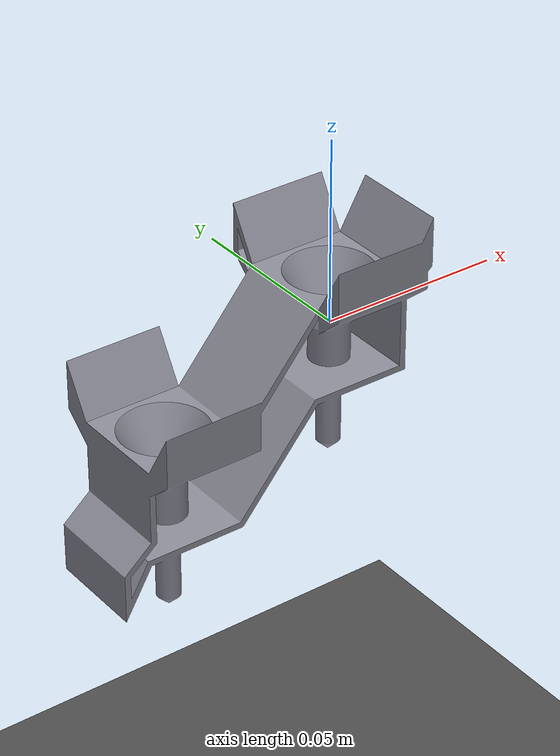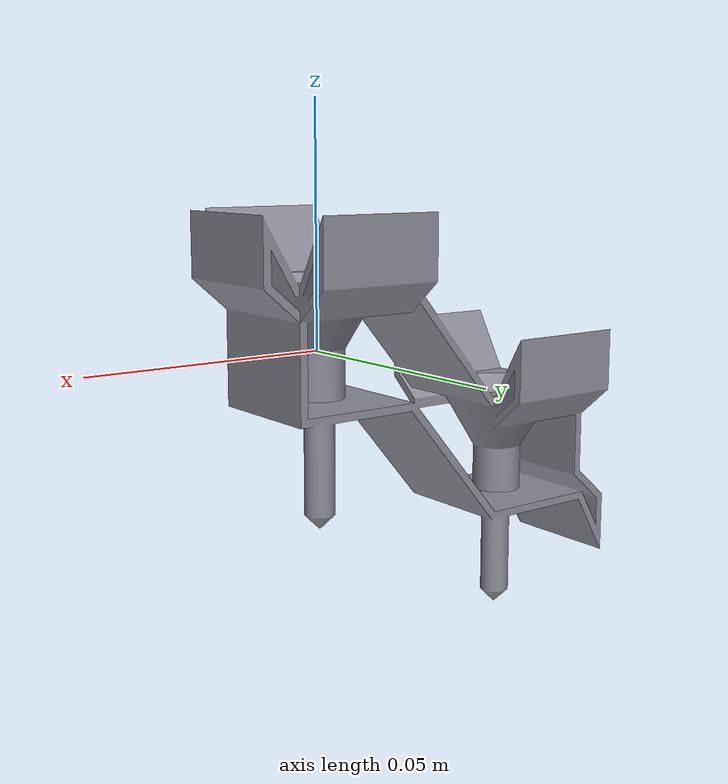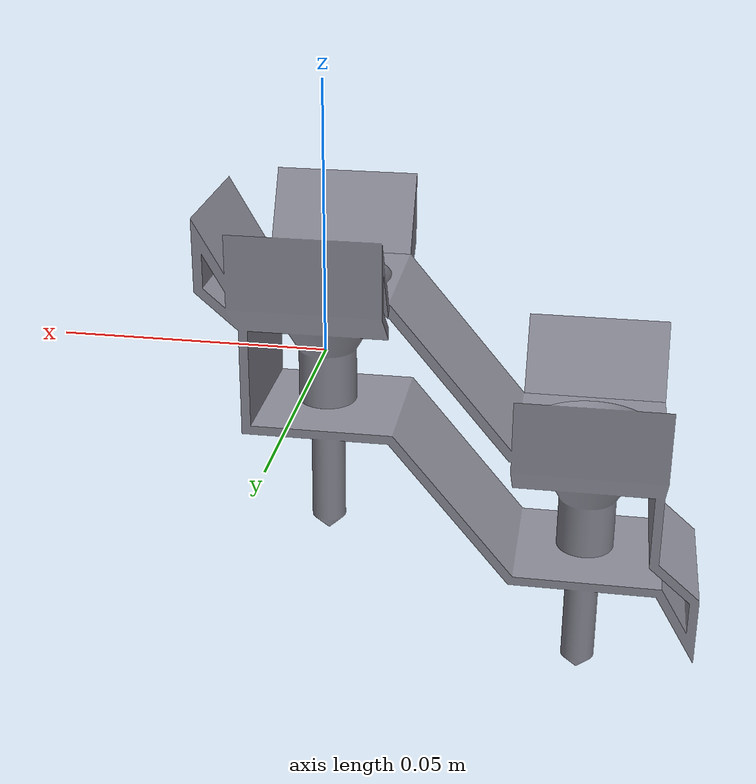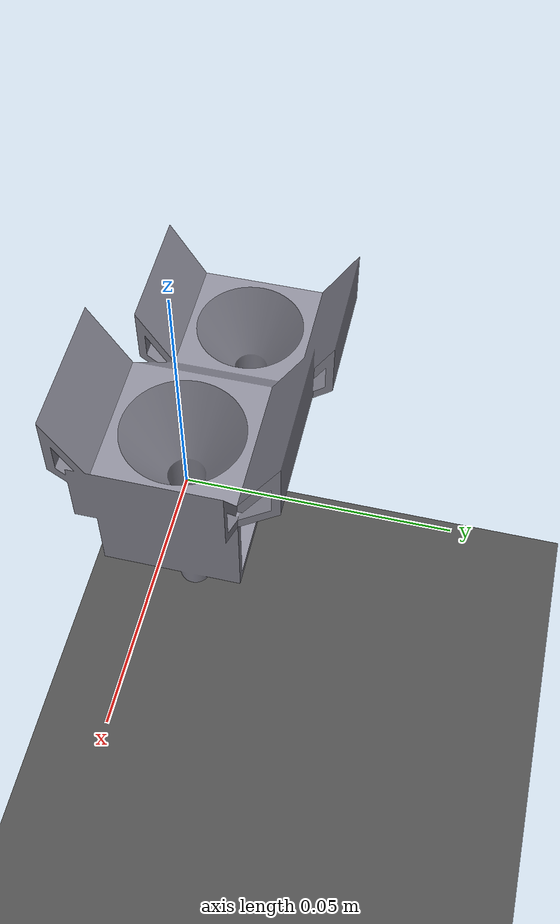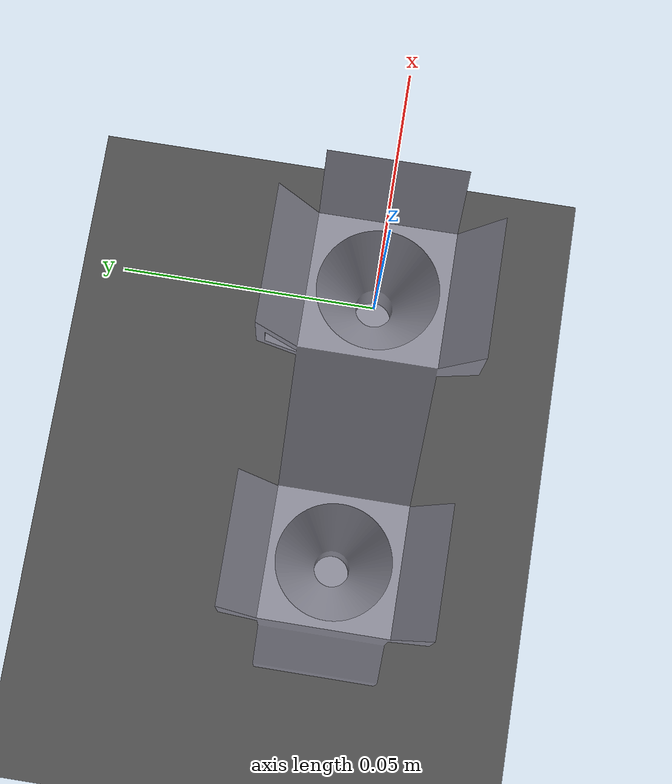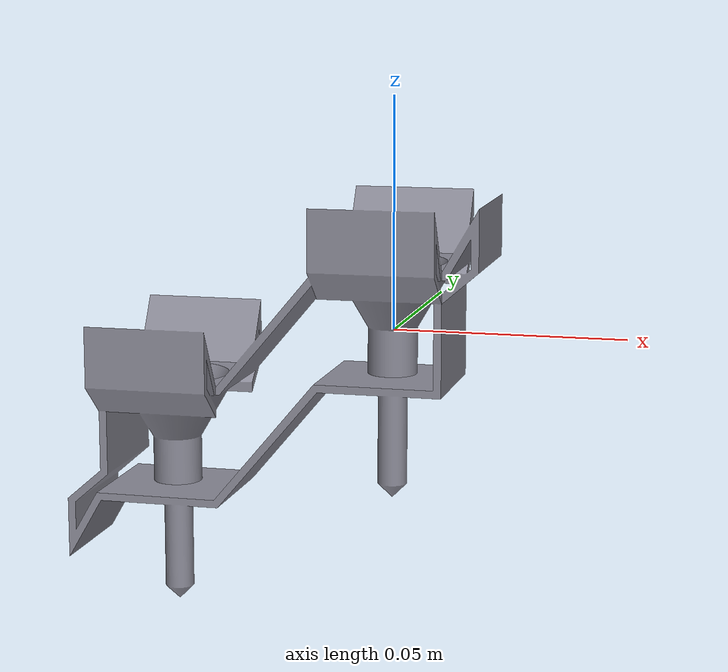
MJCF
<mujoco model="goat_download"><compiler angle="radian" inertiafromgeom="false" /><size memory="128M" /><option timestep="0.002" gravity="0 0 -9.81" integrator="implicitfast" solver="Newton" cone="elliptic" iterations="100" tolerance="1e-10"><flag nativeccd="enable" multiccd="enable" autoreset="disable" sleep="disable" /></option><default><geom condim="3" friction="0.3 0 0" margin="0" solref="0.005 1.0" solimp="0.95 0.99 0.0001 0.5 2" /></default><asset><mesh name="collision_0" vertex="-0.061028399999999997 0.0031261000000000001 -0.0144385 -0.061028399999999997 0.0036939999999999998 -0.014162599999999999 -0.059935299999999997 0.0049305 -0.011818 -0.060324799999999998 0.0039902000000000002 -0.011818" face="1 2 0 0 2 3 3 1 0 2 1 3" /><mesh name="collision_1" vertex="-0.012918300000000001 0 0.013130599999999999 -0.012889899999999999 0.0010998 0.013164500000000001 -0.036780899999999998 -0.0011007 -0.013484700000000001 -0.036924699999999998 -0.0021930000000000001 -0.013484700000000001 -0.0136524 0.013333299999999999 0.0148486 -0.0136524 -0.013333299999999999 0.0148486 -0.0119857 0 0.0148486" face="5 4 3 6 4 5 1 4 6 3 4 2 4 1 2 6 5 0 0 1 6 0 5 3 3 2 0 0 2 1" /><mesh name="collision_2" vertex="-0.051185799999999997 -0.0050117 -0.026120999999999998 -0.0516157 -0.0048336000000000004 -0.026120999999999998 -0.0516157 -0.0048336000000000004 -0.0361514 -0.0509113 -0.0033230999999999998 -0.0256744 -0.0509113 -0.0033230999999999998 -0.0344847 -0.0511951 -0.0031754000000000001 -0.0256744 -0.0511951 -0.0031754000000000001 -0.0344847" face="0 3 1 2 0 1 3 0 4 0 2 4 1 3 5 6 4 2 1 5 6 6 2 1 3 4 6 6 5 3" /><mesh name="collision_3" vertex="-0.047122600000000001 0.0022391999999999998 -0.038484699999999997 -0.047326199999999999 0.0024258000000000001 -0.038484699999999997 -0.047326199999999999 0.0024258000000000001 -0.060651400000000001 -0.047545400000000002 0.002594 -0.060651400000000001 -0.048397599999999999 0.0011490999999999999 -0.059961 -0.0485014 0.0012287000000000001 -0.059961" face="5 3 2 5 0 1 1 3 5 0 2 1 1 2 3 4 0 5 5 2 4 4 2 0" /><mesh name="collision_4" vertex="-0.050444799999999998 -0.0029757 -0.060651400000000001 -0.050181299999999998 -0.0030588 -0.060651400000000001 -0.049361700000000001 0 -0.061461000000000002 -0.049874799999999997 -0.0014094999999999999 -0.059961 -0.049750000000000003 -0.0014488999999999999 -0.059961" face="0 2 1 3 2 0 0 1 4 4 3 0 4 1 2 2 3 4" /><mesh name="collision_5" vertex="-0.0496377 -0.0031546 -0.060651400000000001 -0.049361700000000001 -0.0031667000000000002 -0.060651400000000001 -0.049361700000000001 0 -0.061461000000000002 -0.049492500000000002 -0.0014943000000000001 -0.059961 -0.049361700000000001 -0.0015 -0.059961" face="2 1 0 0 1 3 3 2 0 1 2 4 4 3 1 2 3 4" /><mesh name="collision_6" vertex="-0.054195399999999998 -0.0022539999999999999 -0.026120999999999998 -0.061028399999999997 -0.0015430000000000001 -0.0149754 -0.061028399999999997 -0.0020571000000000001 -0.0148396 -0.052537199999999999 -0.0018332999999999999 -0.0256744 -0.0526849 -0.0015495999999999999 -0.0256744" face="2 3 1 0 2 1 3 2 0 1 3 4 4 0 1 3 0 4" /><mesh name="collision_7" vertex="-0.061028399999999997 -0.0142956 -0.013484700000000001 -0.060807399999999998 -0.0053372000000000003 -0.013484700000000001 -0.061028399999999997 -0.0048351000000000002 -0.013484700000000001 -0.062695100000000004 -0.013333299999999999 -0.011818" face="0 1 3 3 1 2 2 0 3 1 0 2" /><mesh name="collision_8" vertex="-0.0075627000000000003 -0.010345 0.013181999999999999 -0.0033781000000000002 -0.0043687999999999999 0.00054560000000000003 -0.0070108000000000002 -0.0095568000000000007 0.0148486 -0.0021524000000000001 -0.0031754000000000001 0.00099219999999999994 -0.0024221999999999998 -0.0030035999999999999 0.00099219999999999994" face="0 3 2 2 4 0 3 4 2 1 3 0 0 4 1 1 4 3" /><mesh name="collision_9" vertex="-0.0014021000000000001 -0.0029757 -0.011818 -0.0011387000000000001 -0.0030588 -0.011818 -0.00086899999999999998 -0.0031186 -0.011818 -0.00059509999999999999 -0.0031546 -0.011818 -0.0011387000000000001 -0.0030588 -0.0339847 -0.00086899999999999998 -0.0031186 -0.0339847 -0.00070730000000000001 -0.0014488999999999999 -0.033294299999999999 -0.00057950000000000005 -0.0014771999999999999 -0.033294299999999999" face="3 7 0 0 7 6 6 4 0 7 4 6 0 4 1 3 2 5 7 3 5 5 4 7 1 2 3 1 3 0 2 1 5 5 1 4" /><mesh name="collision_10" vertex="-0.061028399999999997 -0.0142956 -0.013484700000000001 -0.0574794 -0.0096743000000000003 -0.013484700000000001 -0.058291700000000002 -0.0089300000000000004 -0.013484700000000001 -0.056860899999999999 -0.0089371999999999993 -0.011818 -0.062695100000000004 -0.013333299999999999 -0.011818" face="0 3 4 4 3 2 2 0 4 3 0 1 1 2 3 0 2 1" /><mesh name="collision_11" vertex="-0.036805600000000001 0.013333299999999999 -0.036817999999999997 -0.049101300000000001 0.0014771999999999999 -0.036817999999999997 -0.048973500000000003 0.0014488999999999999 -0.036817999999999997 -0.048278700000000001 0.0029757 -0.038484699999999997 -0.049085700000000003 0.0031546 -0.038484699999999997 -0.048542099999999998 0.0030588 -0.038484699999999997 -0.048811800000000002 0.0031186 -0.038484699999999997" face="2 0 1 1 3 2 2 3 0 1 0 4 4 3 1 6 4 0 0 3 5 5 6 0 4 6 5 3 4 5" /><mesh name="collision_12" vertex="-0.050838899999999999 -0.00026049999999999999 -0.036817999999999997 -0.0636573 -0.013333299999999999 -0.036817999999999997 -0.050855999999999998 -0.00013070000000000001 -0.036817999999999997 -0.052480300000000001 -0.00054989999999999998 -0.038484699999999997 -0.052420500000000002 -0.00081959999999999997 -0.038484699999999997 -0.052528400000000003 0 -0.038484699999999997 -0.052516399999999998 -0.00027599999999999999 -0.038484699999999997" face="4 0 1 1 3 4 4 5 0 1 0 2 2 5 1 0 5 2 1 5 6 6 3 1 6 4 3 5 4 6" /><mesh name="collision_13" vertex="-0.014429600000000001 0.013333299999999999 -0.0101514 -0.0017286000000000001 0.000513 -0.0101514 -0.0016785000000000001 0.00063389999999999996 -0.0101514 -0.0032948000000000001 0.0010831 -0.011818 -0.0033777999999999998 0.00081959999999999997 -0.011818" face="0 2 3 1 2 0 0 3 4 4 1 0 4 3 2 2 1 4" /><mesh name="collision_14" vertex="-0.0636573 -0.013333299999999999 -0.036817999999999997 -0.049874799999999997 -0.0014094999999999999 -0.036817999999999997 -0.049995699999999997 -0.0013595 -0.036817999999999997 -0.050444799999999998 -0.0029757 -0.038484699999999997 -0.050181299999999998 -0.0030588 -0.038484699999999997" face="0 1 2 2 3 0 4 1 0 0 3 4 4 2 1 3 2 4" /><mesh name="collision_15" vertex="-0.061028399999999997 0.0031261000000000001 -0.0144385 -0.061028399999999997 0.0036939999999999998 -0.014162599999999999 -0.060298699999999997 0.0063144999999999998 -0.013484700000000001 -0.059706700000000001 0.0072436000000000002 -0.013484700000000001 -0.058918499999999999 0.0066917000000000001 -0.011818 -0.059465400000000002 0.0058332999999999996 -0.011818" face="3 4 0 0 4 5 5 1 0 2 3 0 0 1 2 1 5 2 4 3 2 2 5 4" /><mesh name="collision_16" vertex="-0.0053308000000000001 -0.0018240999999999999 0.00054560000000000003 -0.0054707000000000002 -0.0013803999999999999 0.00054560000000000003 -0.0055713999999999998 -0.00092610000000000001 0.00054560000000000003 -0.0053308000000000001 -0.0018240999999999999 -0.0094847000000000004 -0.0054707000000000002 -0.0013803999999999999 -0.0094847000000000004 -0.0038608000000000002 -0.00094899999999999997 -0.0078180000000000003 -0.0038608000000000002 -0.00094899999999999997 0.00099219999999999994" face="6 5 2 5 3 4 2 5 4 2 4 1 0 6 1 1 6 2 0 3 6 6 3 5 1 3 0 1 4 3" /><mesh name="collision_17" vertex="-0.061028399999999997 -0.0015430000000000001 -0.0149754 -0.061028399999999997 -0.0010207 -0.015074199999999999 -0.059465400000000002 -0.0058332999999999996 -0.011818 -0.058918499999999999 -0.0066917000000000001 -0.011818" face="1 3 0 0 3 2 2 1 0 3 1 2" /><mesh name="collision_18" vertex="-0.0441094 0.00092610000000000001 -0.026120999999999998 -0.036924699999999998 0.0021930000000000001 -0.013484700000000001 -0.045750800000000001 0.00063670000000000003 -0.0256744 -0.045709 0.00031960000000000002 -0.0256744" face="3 1 2 2 1 0 0 3 2 1 3 0" /><mesh name="collision_19" vertex="-0.044350000000000001 0.0018240999999999999 -0.026120999999999998 -0.044210100000000002 0.0013803999999999999 -0.026120999999999998 -0.044210100000000002 0.0013803999999999999 -0.0361514 -0.0441094 0.00092610000000000001 -0.026120999999999998 -0.0441094 0.00092610000000000001 -0.0361514 -0.04582 0.00094899999999999997 -0.0256744 -0.04582 0.00094899999999999997 -0.0344847 -0.045750800000000001 0.00063670000000000003 -0.0256744 -0.045750800000000001 0.00063670000000000003 -0.0344847" face="5 3 1 1 0 5 1 2 0 7 3 5 4 8 2 0 2 6 2 8 6 5 0 6 2 1 4 4 1 3 3 7 4 4 7 8 8 7 6 6 7 5" /><mesh name="collision_20" vertex="-0.011764800000000001 -0.0053372000000000003 0.013181999999999999 -0.0121864 -0.0043192999999999999 0.013181999999999999 -0.0128752 -0.013333299999999999 0.013181999999999999 -0.0136524 -0.013333299999999999 0.0148486" face="2 0 3 3 0 1 1 2 3 0 2 1" /><mesh name="collision_21" vertex="-0.053681100000000002 -0.011867300000000001 -0.013484700000000001 -0.055195099999999997 -0.010103600000000001 -0.011818 -0.054292300000000002 -0.010573600000000001 -0.011818 -0.052454326999999995 -0.0089592644999999995 -0.016297312499999998" face="1 3 0 2 3 1 1 0 2 2 0 3" /><mesh name="collision_22" vertex="-0.049085700000000003 -0.0031546 -0.038484699999999997 -0.048278700000000001 -0.0029757 -0.038484699999999997 -0.049622199999999998 -0.0014771999999999999 -0.059961 -0.049750000000000003 -0.0014488999999999999 -0.059961" face="0 1 3 3 1 2 2 0 3 1 0 2" /><mesh name="collision_23" vertex="0.00074160000000000003 0.0010606999999999999 -0.0101514 0.00083000000000000001 0.00096420000000000002 -0.0101514 0.0024233000000000002 0.0015832999999999999 -0.011818 0.0021067 0.0020355 -0.011818" face="3 2 0 0 2 1 1 3 0 2 3 1" /><mesh name="collision_24" vertex="-0.050287900000000003 0.0052522999999999997 -0.026120999999999998 -0.052630299999999998 0.0121986 -0.013484700000000001 -0.051554700000000002 0.0124371 -0.013484700000000001 -0.0503107 0.0035417000000000001 -0.0256744 -0.049998399999999998 0.0036110000000000001 -0.0256744 -0.052381299999999999 0.011269100000000001 -0.011818" face="5 2 1 4 2 5 1 2 0 0 2 4 3 5 1 4 5 3 1 0 3 3 0 4" /><mesh name="collision_25" vertex="-0.054614000000000003 0.00092610000000000001 -0.026120999999999998 -0.054614000000000003 0.00092610000000000001 -0.0361514 -0.054513300000000001 0.0013803999999999999 -0.026120999999999998 -0.054513300000000001 0.0013803999999999999 -0.0361514 -0.052903499999999999 0.00094899999999999997 -0.0256744 -0.052903499999999999 0.00094899999999999997 -0.0344847" face="0 4 2 1 3 5 3 1 0 0 2 3 0 1 5 5 4 0 5 3 2 5 2 4" /><mesh name="collision_26" vertex="-0.0010690999999999999 0.001299 -0.0101514 -0.00095299999999999996 0.0013595 -0.0101514 -4.3099999999999997e-05 0.0031546 -0.011818 0.00050049999999999997 0.0030588 -0.011818" face="2 3 0 0 3 1 1 2 0 3 2 1" /><mesh name="collision_27" vertex="0.013014299999999999 0.019364699999999999 0.0156101 -0.0136524 0.019364699999999999 0.0156101 0.013014299999999999 0.013333299999999999 0.0103868 -0.0136524 0.013333299999999999 0.0103868 0.013014299999999999 0.013333299999999999 0.008182 0.013014299999999999 0.021031299999999999 0.0148486 -0.0136524 0.021031299999999999 0.0148486 -0.0136524 0.013333299999999999 0.008182" face="3 2 0 3 0 1 1 0 6 0 5 6 6 3 1 7 3 6 0 2 4 4 5 0 2 3 4 4 3 7 4 6 5 7 6 4" /><mesh name="collision_28" vertex="-0.061028399999999997 -0.019364699999999999 -0.0047048000000000003 -0.036028400000000002 -0.019364699999999999 -0.0047048000000000003 -0.061028399999999997 -0.019364699999999999 -0.0110566 -0.036028400000000002 -0.019364699999999999 -0.0110566 -0.036028400000000002 -0.021031299999999999 -0.011818 -0.036028400000000002 -0.021031299999999999 0.0015153 -0.062695100000000004 -0.021031299999999999 -0.011818 -0.062695100000000004 -0.021031299999999999 0.0015153" face="4 5 7 6 4 7 3 5 4 1 5 3 3 4 6 6 2 3 0 7 5 0 5 1 1 3 0 0 3 2 6 7 0 0 2 6" /><mesh name="collision_29" vertex="-0.0537305 0.0030590999999999999 -0.026120999999999998 -0.061028399999999997 0.0020571000000000001 -0.0148396 -0.061028399999999997 0.0025996999999999999 -0.0146558 -0.052365299999999997 0.0021031000000000001 -0.0256744 -0.052170599999999998 0.0023568999999999999 -0.0256744" face="1 4 2 2 0 1 4 0 2 3 4 1 1 0 3 3 0 4" /><mesh name="collision_30" vertex="-0.0056563000000000004 -0.0114457 0.013181999999999999 -0.0061523999999999997 -0.010103600000000001 0.0148486 -0.0018687 -0.0033230999999999998 0.00099219999999999994 -0.0021524000000000001 -0.0031754000000000001 0.00099219999999999994" face="0 2 1 1 2 3 3 0 1 2 0 3" /><mesh name="collision_31" vertex="-0.014429600000000001 -0.013333299999999999 -0.0101514 -0.0012833 -0.0011490999999999999 -0.0101514 -0.0013797 -0.0010606999999999999 -0.0101514 -0.0025582000000000001 -0.0022391999999999998 -0.011818" face="0 1 2 3 1 0 0 2 3 3 2 1" /><mesh name="collision_32" vertex="-0.051185799999999997 0.0050117 -0.026120999999999998 -0.054698900000000002 0.0114457 -0.013484700000000001 -0.053681100000000002 0.011867300000000001 -0.013484700000000001 -0.0509113 0.0033230999999999998 -0.0256744 -0.050615800000000002 0.0034455000000000002 -0.0256744" face="1 4 2 1 2 0 0 2 4 3 4 1 1 0 3 3 0 4" /><mesh name="collision_33" vertex="0.011347599999999999 -0.013333299999999999 -0.0101514 0.00097999999999999997 -0.00075000000000000002 -0.0101514 0.00090970000000000005 -0.00086039999999999999 -0.0101514 0.0022748999999999998 -0.0018163000000000001 -0.011818 0.0024233000000000002 -0.0015832999999999999 -0.011818 0.0021067 -0.0020355 -0.011818" face="2 0 1 5 0 2 5 3 0 2 1 5 0 3 4 4 1 0 3 5 4 4 5 1" /><mesh name="collision_34" vertex="-0.046302700000000002 0.0043687999999999999 -0.026120999999999998 -0.045933500000000002 0.0040856 -0.026120999999999998 -0.045933500000000002 0.0040856 -0.0361514 -0.047004799999999999 0.0028088000000000002 -0.0256744 -0.047004799999999999 0.0028088000000000002 -0.0344847 -0.046768999999999998 0.0025926999999999999 -0.0344847" face="3 1 0 2 0 1 3 0 4 0 2 4 5 2 1 5 1 3 5 4 2 3 4 5" /><mesh name="collision_35" vertex="-0.053447300000000003 -0.0034282000000000002 -0.026120999999999998 -0.0537305 -0.0030590999999999999 -0.026120999999999998 -0.061028399999999997 -0.0025977000000000001 -0.014656499999999999 -0.061028399999999997 -0.0031261000000000001 -0.0144385 -0.059035999999999998 -0.0081177000000000003 -0.013484700000000001 -0.059706700000000001 -0.0072436000000000002 -0.013484700000000001" face="4 0 2 2 0 1 0 4 5 5 1 0 2 1 3 1 5 3 3 4 2 3 5 4" /><mesh name="collision_36" vertex="-0.036805600000000001 -0.013333299999999999 -0.036817999999999997 -0.048973500000000003 -0.0014488999999999999 -0.036817999999999997 -0.049101300000000001 -0.0014771999999999999 -0.036817999999999997 -0.049085700000000003 -0.0031546 -0.038484699999999997 -0.048811800000000002 -0.0031186 -0.038484699999999997 -0.048542099999999998 -0.0030588 -0.038484699999999997 -0.048278700000000001 -0.0029757 -0.038484699999999997" face="3 0 2 2 0 1 6 3 2 2 1 6 6 1 0 0 5 6 0 3 4 4 5 0 4 6 5 3 6 4" /><mesh name="collision_37" vertex="0.0018739 -0.0124371 0.013181999999999999 0.00078160000000000002 -0.012580900000000001 0.013181999999999999 0.013014299999999999 -0.013333299999999999 0.0148486 0.0017068000000000001 -0.0114894 0.0148486 0.00069769999999999999 -0.0116223 0.0148486" face="4 2 3 2 0 3 1 2 4 1 0 2 4 3 1 1 3 0" /><mesh name="collision_38" vertex="-0.044048700000000003 -0.00046480000000000002 -0.0361514 -0.049361700000000001 0 -0.0361514 -0.045695100000000002 0 -0.0344847 -0.045709 -0.00031960000000000002 -0.0344847 -0.045750800000000001 -0.00063670000000000003 -0.0344847 -0.049361700000000001 0 -0.0344847" face="1 0 4 2 0 1 1 4 5 5 2 1 3 4 0 0 2 3 2 5 3 3 5 4" /><mesh name="collision_39" vertex="-0.0056563000000000004 -0.0114457 0.013181999999999999 -0.0025730000000000002 -0.0048336000000000004 0.00054560000000000003 -0.0066334999999999996 -0.010937000000000001 0.013181999999999999 -0.0029857 -0.0046188000000000002 0.00054560000000000003 -0.0075627000000000003 -0.010345 0.013181999999999999 -0.0061523999999999997 -0.010103600000000001 0.0148486 -0.0070108000000000002 -0.0095568000000000007 0.0148486 -0.0021524000000000001 -0.0031754000000000001 0.00099219999999999994" face="5 0 7 4 7 3 6 7 4 6 5 7 4 3 2 2 3 0 0 5 2 2 6 4 5 6 2 7 0 1 1 3 7 0 3 1" /><mesh name="collision_40" vertex="-0.0503259 -0.0011490999999999999 -0.036817999999999997 -0.050222099999999999 -0.0012287000000000001 -0.036817999999999997 -0.0521041 -0.0015832999999999999 -0.038484699999999997 -0.0517875 -0.0020355 -0.038484699999999997 -0.051397199999999997 -0.0024258000000000001 -0.038484699999999997 -0.0496377 -0.0031546 -0.038484699999999997" face="0 5 2 3 0 2 0 3 4 1 4 5 5 0 1 0 4 1 4 3 2 2 5 4" /><mesh name="collision_41" vertex="0.0093551999999999993 0.0081177000000000003 0.013181999999999999 0.010025900000000001 0.0072436000000000002 0.013181999999999999 0.013014299999999999 0.013333299999999999 0.0148486 0.0092376999999999997 0.0066917000000000001 0.0148486 0.0086181000000000001 0.0074992000000000001 0.0148486" face="3 2 4 4 2 0 1 3 4 4 0 1 2 3 1 1 0 2" /><mesh name="collision_42" vertex="-0.049995699999999997 0.0013595 -0.036817999999999997 -0.050111700000000002 0.001299 -0.036817999999999997 -0.0517875 0.0020355 -0.038484699999999997 -0.051397199999999997 0.0024258000000000001 -0.038484699999999997" face="3 0 2 2 0 1 1 3 2 0 3 1" /><mesh name="collision_43" vertex="-0.061028399999999997 -0.0142956 -0.013484700000000001 -0.054698900000000002 -0.0114457 -0.013484700000000001 -0.055676200000000002 -0.010937000000000001 -0.013484700000000001 -0.055195099999999997 -0.010103600000000001 -0.011818" face="0 1 3 2 1 0 0 3 2 2 3 1" /><mesh name="collision_44" vertex="-0.061028399999999997 -0.019364699999999999 -0.0047048000000000003 -0.061028399999999997 -0.0142956 -0.013484700000000001 -0.061028399999999997 -0.013333299999999999 -0.0162799 -0.061028399999999997 -0.019364699999999999 -0.0110566 -0.061028399999999997 -0.013333299999999999 -0.0184847 -0.062695100000000004 -0.013333299999999999 -0.0184847 -0.062695100000000004 -0.013333299999999999 -0.011818 -0.062695100000000004 -0.021031299999999999 -0.011818" face="4 7 5 5 7 6 6 7 0 0 7 3 7 4 3 1 6 0 6 1 2 2 3 4 0 3 2 2 1 0 2 4 5 5 6 2" /><mesh name="collision_45" vertex="-0.061028399999999997 -0.019364699999999999 -0.0047048000000000003 -0.061028399999999997 -0.0142956 -0.013484700000000001 -0.036028400000000002 -0.019364699999999999 -0.0047048000000000003 -0.036028400000000002 -0.0142956 -0.013484700000000001 -0.049361700000000001 -0.0126289 -0.013484700000000001 -0.051554700000000002 -0.0124371 -0.013484700000000001 -0.036028400000000002 -0.013333299999999999 -0.011818 -0.062695100000000004 -0.013333299999999999 -0.011818 -0.036028400000000002 -0.021031299999999999 0.0015153 -0.062695100000000004 -0.021031299999999999 0.0015153" face="7 5 1 6 5 7 0 9 7 7 1 0 6 3 4 5 6 4 6 9 8 7 9 6 8 9 0 2 8 0 2 0 3 3 0 1 3 6 8 3 8 2 4 3 1 4 1 5" /><mesh name="collision_46" vertex="0.0049332000000000004 0.00092610000000000001 0.00054560000000000003 0.0049940000000000002 0.00046480000000000002 0.00054560000000000003 0.0049332000000000004 0.00092610000000000001 -0.0094847000000000004 0.0049940000000000002 0.00046480000000000002 -0.0094847000000000004 0.0033335999999999999 0.00031960000000000002 -0.0078180000000000003 0.0033335999999999999 0.00031960000000000002 0.00099219999999999994" face="1 0 5 4 2 3 0 2 5 5 2 4 3 5 4 1 5 3 3 2 0 3 0 1" /><mesh name="collision_47" vertex="-0.036805600000000001 -0.013333299999999999 -0.036817999999999997 -0.049230999999999997 -0.0014943000000000001 -0.036817999999999997 -0.049361700000000001 -0.0015 -0.036817999999999997 -0.049085700000000003 -0.0031546 -0.038484699999999997" face="3 0 2 2 0 1 1 3 2 0 3 1" /><mesh name="collision_48" vertex="-0.048435600000000002 -0.0052522999999999997 -0.0361514 -0.0488969 -0.005313 -0.0361514 -0.049361700000000001 -0.0053333 -0.0361514 -0.049361700000000001 0 -0.0361514 -0.048724999999999997 -0.0036110000000000001 -0.0344847 -0.049042200000000001 -0.0036527 -0.0344847" face="0 3 4 0 4 1 2 1 5 5 1 4 5 3 2 5 4 3 1 3 0 2 3 1" /><mesh name="collision_49" vertex="0.0002308 0.0031186 -0.011818 0.00050049999999999997 0.0030588 -0.011818 0.0002308 0.0031186 -0.0339847 -4.3099999999999997e-05 0.0031546 -0.0339847 -5.8600000000000001e-05 0.0014771999999999999 -0.033294299999999999 -0.0001883 0.0014943000000000001 -0.033294299999999999" face="5 1 0 0 3 5 1 2 0 0 2 3 4 1 5 4 2 1 5 3 4 3 2 4" /><mesh name="collision_50" vertex="-0.049492500000000002 -0.0014943000000000001 -0.036817999999999997 -0.049622199999999998 -0.0014771999999999999 -0.036817999999999997 -0.047122600000000001 -0.0022391999999999998 -0.038484699999999997 -0.047778399999999999 -0.0027423999999999999 -0.038484699999999997 -0.049622199999999998 -0.0014771999999999999 -0.059961 -0.049492500000000002 -0.0014943000000000001 -0.059961" face="4 3 1 2 3 5 3 4 5 1 3 0 0 3 2 2 5 0 0 5 4 0 4 1" /><mesh name="collision_51" vertex="-0.048435600000000002 -0.0052522999999999997 -0.026120999999999998 -0.0488969 -0.005313 -0.026120999999999998 -0.047168700000000001 -0.0124371 -0.013484700000000001 -0.048261100000000001 -0.012580900000000001 -0.013484700000000001 -0.048724999999999997 -0.0036110000000000001 -0.0256744 -0.047335799999999997 -0.0114894 -0.011818" face="5 3 2 4 5 2 1 3 4 3 5 4 0 3 1 2 3 0 1 4 0 0 4 2" /><mesh name="collision_52" vertex="-0.0003191 -0.0126289 0.013181999999999999 -0.0025121000000000002 -0.0124371 0.013181999999999999 0.013014299999999999 -0.013333299999999999 0.0148486 0.013014299999999999 -0.021031299999999999 0.028181999999999999" face="3 2 1 1 2 0 0 3 1 2 3 0" /><mesh name="collision_53" vertex="-0.0046384 -0.011867300000000001 0.013181999999999999 -0.0021432000000000001 -0.0050117 0.00054560000000000003 -0.0056563000000000004 -0.0114457 0.013181999999999999 -0.0025730000000000002 -0.0048336000000000004 0.00054560000000000003 -0.0043093000000000003 -0.0109631 0.0148486 -0.0052496000000000001 -0.010573600000000001 0.0148486 -0.0015731 -0.0034455000000000002 0.00099219999999999994 -0.0018687 -0.0033230999999999998 0.00099219999999999994" face="2 0 4 4 0 6 1 0 2 6 0 1 2 4 5 5 4 6 3 1 2 6 1 3 7 5 6 6 3 7 2 5 7 7 3 2" /><mesh name="collision_54" vertex="0.013014299999999999 -0.0142956 0.013181999999999999 0.0069246000000000004 -0.010345 0.013181999999999999 0.0059953999999999997 -0.010937000000000001 0.013181999999999999 0.013014299999999999 -0.013333299999999999 0.0148486 0.0063726 -0.0095568000000000007 0.0148486" face="2 0 3 3 4 2 1 0 2 2 4 1 1 3 0 4 3 1" /><mesh name="collision_55" vertex="-0.036805600000000001 0.013333299999999999 -0.036817999999999997 -0.036028400000000002 0.013333299999999999 -0.038484699999999997 -0.046302999999999997 0.00081959999999999997 -0.038484699999999997 -0.046385999999999997 0.0010831 -0.038484699999999997" face="0 1 3 3 1 2 2 0 3 1 0 2" /><mesh name="collision_56" vertex="-0.050444799999999998 -0.0029757 -0.060651400000000001 -0.049361700000000001 0 -0.061461000000000002 -0.049995699999999997 -0.0013595 -0.059961 -0.050111700000000002 -0.001299 -0.059961" face="0 1 2 3 1 0 0 2 3 3 2 1" /><mesh name="collision_57" vertex="-0.0066334999999999996 0.010937000000000001 0.013181999999999999 -0.0136524 0.013333299999999999 0.0148486 -0.0070108000000000002 0.0095568000000000007 0.0148486 -0.0061523999999999997 0.010103600000000001 0.0148486" face="2 3 1 1 3 0 0 2 1 3 2 0" /><mesh name="collision_58" vertex="0.0029494999999999999 -0.0121986 0.013181999999999999 0.0018739 -0.0124371 0.013181999999999999 0.00060700000000000001 -0.0052522999999999997 0.00054560000000000003 0.0027005000000000002 -0.011269100000000001 0.0148486 0.00062989999999999997 -0.0035417000000000001 0.00099219999999999994 0.00031760000000000002 -0.0036110000000000001 0.00099219999999999994" face="5 1 3 3 1 0 2 1 5 0 1 2 5 3 4 4 3 0 4 2 5 0 2 4" /><mesh name="collision_59" vertex="-0.047107799999999998 -0.0048336000000000004 -0.0361514 -0.047537599999999999 -0.0050117 -0.0361514 -0.0479814 -0.0051516000000000001 -0.0361514 -0.049361700000000001 0 -0.0361514 -0.048107700000000003 -0.0034455000000000002 -0.0344847" face="4 0 3 3 2 4 0 4 1 1 4 2 1 2 3 3 0 1" /><mesh name="collision_60" vertex="-0.051185799999999997 -0.0050117 -0.026120999999999998 -0.0516157 -0.0048336000000000004 -0.026120999999999998 -0.053681100000000002 -0.011867300000000001 -0.013484700000000001 -0.054698900000000002 -0.0114457 -0.013484700000000001 -0.052454326999999995 -0.0089592644999999995 -0.016297312499999998" face="3 0 2 3 2 4 4 2 0 1 0 3 3 4 1 1 4 0" /><mesh name="collision_61" vertex="-0.036805600000000001 -0.013333299999999999 -0.036817999999999997 -0.047867399999999997 -0.00013070000000000001 -0.036817999999999997 -0.047884500000000003 -0.00026049999999999999 -0.036817999999999997 -0.046243199999999998 -0.00054989999999999998 -0.038484699999999997 -0.046207100000000001 -0.00027599999999999999 -0.038484699999999997 -0.046195100000000003 0 -0.038484699999999997" face="3 0 2 2 5 3 2 0 1 1 5 2 0 5 1 4 5 0 0 3 4 4 3 5" /><mesh name="collision_62" vertex="-0.049995699999999997 -0.0013595 -0.036817999999999997 -0.050111700000000002 -0.001299 -0.036817999999999997 -0.051397199999999997 -0.0024258000000000001 -0.038484699999999997 -0.050444799999999998 -0.0029757 -0.038484699999999997 -0.050181299999999998 -0.0030588 -0.038484699999999997 -0.0496377 -0.0031546 -0.038484699999999997" face="1 5 2 5 1 0 3 1 2 3 0 1 5 0 4 0 3 4 4 3 2 2 5 4" /><mesh name="collision_63" vertex="-0.044210100000000002 -0.0013803999999999999 -0.026120999999999998 -0.037163099999999998 -0.0032686 -0.013484700000000001 -0.037494399999999997 -0.0043192999999999999 -0.013484700000000001 -0.04582 -0.00094899999999999997 -0.0256744 -0.038398700000000001 -0.0039902000000000002 -0.011818" face="4 1 3 3 2 4 4 2 1 3 1 0 0 2 3 1 2 0" /><mesh name="collision_64" vertex="-0.044210100000000002 -0.0013803999999999999 -0.026120999999999998 -0.044350000000000001 -0.0018240999999999999 -0.026120999999999998 -0.044350000000000001 -0.0018240999999999999 -0.0361514 -0.04582 -0.00094899999999999997 -0.0256744 -0.04582 -0.00094899999999999997 -0.0344847 -0.045916199999999997 -0.0012541 -0.0256744 -0.045916199999999997 -0.0012541 -0.0344847" face="0 1 2 0 2 4 5 1 3 3 1 0 0 4 3 6 4 2 6 2 1 6 1 5 5 3 6 6 3 4" /><mesh name="collision_65" vertex="-0.046695100000000003 -0.0046188000000000002 -0.026120999999999998 -0.042118099999999999 -0.010345 -0.013484700000000001 -0.043047299999999997 -0.010937000000000001 -0.013484700000000001 -0.047528399999999998 -0.0031754000000000001 -0.0256744 -0.043528400000000002 -0.010103600000000001 -0.011818 -0.04267 -0.0095568000000000007 -0.011818" face="3 2 4 3 1 0 0 2 3 1 2 0 5 1 3 3 4 5 5 2 1 5 4 2" /><mesh name="collision_66" vertex="-0.011256 -0.0063144999999999998 0.013181999999999999 -0.011764800000000001 -0.0053372000000000003 0.013181999999999999 -0.0051526999999999996 -0.0022539999999999999 0.00054560000000000003 -0.0121864 -0.0043192999999999999 0.013181999999999999 -0.0108927 -0.0049305 0.0148486 -0.0036422 -0.0015495999999999999 0.00099219999999999994" face="4 5 3 4 0 5 3 5 2 5 0 2 3 2 1 1 2 0 1 4 3 0 4 1" /><mesh name="collision_67" vertex="-0.044350000000000001 -0.0018240999999999999 -0.026120999999999998 -0.037494399999999997 -0.0043192999999999999 -0.013484700000000001 -0.045916199999999997 -0.0012541 -0.0256744 -0.046038599999999999 -0.0015495999999999999 -0.0256744" face="3 1 2 0 1 3 3 2 0 0 2 1" /><mesh name="collision_68" vertex="0.0042997 0.0026667000000000001 0.00054560000000000003 0.0111266 0.0053372000000000003 0.013181999999999999 0.0045145999999999997 0.0022539999999999999 0.00054560000000000003 0.0028563999999999998 0.0018332999999999999 0.00099219999999999994" face="3 1 0 2 1 3 3 0 2 2 0 1" /><mesh name="collision_69" vertex="-0.0003191 0 -0.037151400000000001 -0.0034737000000000001 -0.00027599999999999999 -0.0339847 -0.0034375999999999999 -0.00054989999999999998 -0.0339847 -0.0033777999999999998 -0.00081959999999999997 -0.0339847 -0.0017963 -0.00026049999999999999 -0.033294299999999999 -0.0003191 0 -0.0347943" face="5 0 1 1 4 5 5 3 0 5 4 3 1 0 2 0 3 2 2 4 1 3 4 2" /><mesh name="collision_70" vertex="-0.049361700000000001 0 -0.063818 -0.052420500000000002 0.00081959999999999997 -0.060651400000000001 -0.052480300000000001 0.00054989999999999998 -0.060651400000000001 -0.052516300000000002 0.00027599999999999999 -0.060651400000000001 -0.052528400000000003 0 -0.060651400000000001 -0.049361700000000001 0 -0.061461000000000002 -0.050838899999999999 0.00026049999999999999 -0.059961" face="4 0 5 5 6 4 0 1 5 1 6 5 2 1 0 2 6 1 3 0 4 3 2 0 4 6 3 6 2 3" /><mesh name="collision_71" vertex="0.00031490000000000001 0.0013595 -0.0101514 0.00043090000000000001 0.001299 -0.0101514 0.0024233000000000002 0.0015832999999999999 -0.011818 0.00076400000000000003 0.0029757 -0.011818 0.00050049999999999997 0.0030588 -0.011818 0.00031480000000000001 0.0013595 -0.033294299999999999" face="0 4 5 5 2 1 1 0 5 3 2 5 5 4 3 3 1 2 4 0 3 0 1 3" /><mesh name="collision_72" vertex="-0.049361700000000001 0 -0.063818 -0.049085700000000003 -0.0031546 -0.060651400000000001 -0.048811800000000002 -0.0031186 -0.060651400000000001 -0.048542099999999998 -0.0030588 -0.060651400000000001 -0.048278700000000001 -0.0029757 -0.060651400000000001 -0.049361700000000001 0 -0.061461000000000002 -0.049101300000000001 -0.0014771999999999999 -0.059961" face="5 4 0 5 6 4 0 1 5 1 6 5 2 1 0 2 6 1 0 4 3 3 2 0 4 6 3 6 2 3" /><mesh name="collision_73" vertex="-0.0537305 -0.0030590999999999999 -0.026120999999999998 -0.061028399999999997 -0.0025977000000000001 -0.014656499999999999 -0.061028399999999997 -0.0020571000000000001 -0.0148396 -0.052170599999999998 -0.0023568999999999999 -0.0256744 -0.052365299999999997 -0.0021031000000000001 -0.0256744" face="0 3 1 1 3 2 2 0 1 3 0 4 4 2 3 0 2 4" /><mesh name="collision_74" vertex="0.0111266 0.0053372000000000003 0.013181999999999999 0.0045145999999999997 0.0022539999999999999 0.00054560000000000003 0.0030041 0.0015495999999999999 0.00099219999999999994 0.0031264999999999999 0.0012541 0.00099219999999999994" face="3 0 2 2 0 1 1 3 2 0 3 1" /><mesh name="collision_75" vertex="-0.036805600000000001 -0.013333299999999999 -0.036817999999999997 -0.0479522 -0.000513 -0.036817999999999997 -0.048002299999999998 -0.00063389999999999996 -0.036817999999999997 -0.0464918 -0.0013382999999999999 -0.038484699999999997 -0.046385999999999997 -0.0010831 -0.038484699999999997 -0.046302999999999997 -0.00081959999999999997 -0.038484699999999997" face="3 0 2 2 0 1 0 3 4 5 3 2 2 1 5 5 4 3 5 1 0 0 4 5" /><mesh name="collision_76" vertex="-0.048212699999999997 0.00096420000000000002 -0.036817999999999997 -0.048133000000000002 0.00086039999999999999 -0.036817999999999997 -0.046195100000000003 0 -0.038484699999999997 -0.048133000000000002 0.00086039999999999999 -0.059961 -0.048212699999999997 0.00096420000000000002 -0.059961" face="1 2 0 1 3 2 0 2 4 2 3 4 3 1 4 4 1 0" /><mesh name="collision_77" vertex="0.00050049999999999997 -0.0030588 -0.011818 0.0002308 -0.0031186 -0.011818 -4.3099999999999997e-05 -0.0031546 -0.011818 0.0002308 -0.0031186 -0.0339847 0.00050049999999999997 -0.0030588 -0.0339847 -5.8600000000000001e-05 -0.0014771999999999999 -0.033294299999999999 6.9200000000000002e-05 -0.0014488999999999999 -0.033294299999999999" face="3 2 5 4 3 5 5 2 6 6 2 0 6 4 5 0 4 6 0 2 1 2 3 1 3 4 1 1 4 0" /><mesh name="collision_78" vertex="0.00076400000000000003 -0.0029757 -0.011818 0.0010192000000000001 -0.0028700000000000002 -0.011818 0.0012643000000000001 -0.0027423999999999999 -0.011818 0.0014973 -0.002594 -0.011818 0.0017164000000000001 -0.0024258000000000001 -0.011818 0.0010192000000000001 -0.0028700000000000002 -0.0339847 0.0012643000000000001 -0.0027423999999999999 -0.0339847 0.00043090000000000001 -0.001299 -0.033294299999999999" face="0 4 7 5 0 7 7 4 6 6 5 7 0 5 1 3 6 4 6 3 2 0 1 2 4 0 2 2 3 4 5 6 2 2 1 5" /><mesh name="collision_79" vertex="-0.053681100000000002 -0.011867300000000001 -0.013484700000000001 -0.055195099999999997 -0.010103600000000001 -0.011818 -0.054292300000000002 -0.010573600000000001 -0.011818 -0.062695100000000004 -0.013333299999999999 -0.011818" face="1 0 3 3 0 2 2 1 3 0 1 2" /><mesh name="collision_80" vertex="-0.051185799999999997 0.0050117 -0.026120999999999998 -0.050742099999999998 0.0051516000000000001 -0.026120999999999998 -0.050742099999999998 0.0051516000000000001 -0.0361514 -0.050287900000000003 0.0052522999999999997 -0.026120999999999998 -0.050287900000000003 0.0052522999999999997 -0.0361514 -0.0503107 0.0035417000000000001 -0.0256744 -0.0503107 0.0035417000000000001 -0.0344847 -0.049998399999999998 0.0036110000000000001 -0.0344847" face="7 3 5 0 2 6 6 5 0 7 5 6 1 2 0 0 5 1 1 5 3 4 3 7 7 6 4 4 6 2 2 1 4 4 1 3" /><mesh name="collision_81" vertex="-0.061028399999999997 -0.0142956 -0.013484700000000001 -0.060298699999999997 -0.0063144999999999998 -0.013484700000000001 -0.060807399999999998 -0.0053372000000000003 -0.013484700000000001 -0.062695100000000004 -0.013333299999999999 -0.011818" face="0 1 3 3 1 2 2 0 3 1 0 2" /><mesh name="collision_82" vertex="-0.045590499999999999 -0.0037712000000000002 -0.026120999999999998 -0.045933500000000002 -0.0040856 -0.026120999999999998 -0.039687399999999998 -0.0081177000000000003 -0.013484700000000001 -0.040431700000000001 -0.0089300000000000004 -0.013484700000000001 -0.046768999999999998 -0.0025926999999999999 -0.0256744" face="3 2 4 4 2 0 2 3 0 1 3 4 4 0 1 1 0 3" /><mesh name="collision_83" vertex="-0.0479814 0.0051516000000000001 -0.026120999999999998 -0.0479814 0.0051516000000000001 -0.0361514 -0.047537599999999999 0.0050117 -0.026120999999999998 -0.047537599999999999 0.0050117 -0.0361514 -0.048412700000000003 0.0035417000000000001 -0.0344847 -0.048107700000000003 0.0034455000000000002 -0.0344847" face="4 0 1 2 0 5 5 0 4 5 3 2 1 3 5 4 1 5 3 1 0 3 0 2" /><mesh name="collision_84" vertex="-0.052630299999999998 -0.0121986 -0.013484700000000001 -0.053681100000000002 -0.011867300000000001 -0.013484700000000001 -0.052381299999999999 -0.011269100000000001 -0.011818 -0.051387599999999999 -0.0114894 -0.011818 -0.062695100000000004 -0.013333299999999999 -0.011818" face="0 3 4 4 3 2 1 0 4 4 2 1 3 0 1 1 2 3" /><mesh name="collision_85" vertex="0.0027399999999999998 0.0043687999999999999 0.00054560000000000003 0.0031091000000000001 0.0040856 0.00054560000000000003 0.0027399999999999998 0.0043687999999999999 -0.0094847000000000004 0.0031091000000000001 0.0040856 -0.0094847000000000004 0.0020378000000000002 0.0028088000000000002 -0.0078180000000000003 0.001784 0.0030035999999999999 -0.0078180000000000003" face="5 0 2 1 0 4 4 0 5 4 3 1 2 3 4 5 2 4 3 2 0 3 0 1" /><mesh name="collision_86" vertex="-0.044742900000000002 -0.0026667000000000001 -0.026120999999999998 -0.044992900000000002 -0.0030590999999999999 -0.026120999999999998 -0.044992900000000002 -0.0030590999999999999 -0.0361514 -0.045276200000000003 -0.0034282000000000002 -0.026120999999999998 -0.045276200000000003 -0.0034282000000000002 -0.0361514 -0.0461863 -0.0018332999999999999 -0.0256744 -0.046358200000000002 -0.0021031000000000001 -0.0256744 -0.046358200000000002 -0.0021031000000000001 -0.0344847" face="6 3 1 1 2 0 0 2 7 2 4 7 5 7 6 0 7 5 6 1 5 5 1 0 1 4 2 3 4 1 7 4 3 7 3 6" /><mesh name="collision_87" vertex="-0.046302700000000002 -0.0043687999999999999 -0.0361514 -0.049361700000000001 0 -0.0361514 -0.047004799999999999 -0.0028088000000000002 -0.0344847 -0.047258599999999998 -0.0030035999999999999 -0.0344847 -0.047528399999999998 -0.0031754000000000001 -0.0344847 -0.049361700000000001 0 -0.0344847" face="2 0 1 0 2 3 1 0 4 0 3 4 5 2 1 1 4 5 5 4 3 5 3 2" /><mesh name="collision_88" vertex="-0.046302700000000002 -0.0043687999999999999 -0.026120999999999998 -0.046695100000000003 -0.0046188000000000002 -0.026120999999999998 -0.046695100000000003 -0.0046188000000000002 -0.0361514 -0.047107799999999998 -0.0048336000000000004 -0.026120999999999998 -0.047107799999999998 -0.0048336000000000004 -0.0361514 -0.047528399999999998 -0.0031754000000000001 -0.0256744 -0.047528399999999998 -0.0031754000000000001 -0.0344847 -0.047812100000000003 -0.0033230999999999998 -0.0344847" face="7 3 5 0 2 6 7 5 6 6 5 0 4 3 7 7 6 4 4 6 2 1 2 0 0 5 1 1 5 3 1 4 2 3 4 1" /><mesh name="collision_89" vertex="-0.036805600000000001 -0.013333299999999999 -0.036817999999999997 -0.036028400000000002 -0.013333299999999999 -0.038484699999999997 -0.048542099999999998 -0.0030588 -0.038484699999999997 -0.048278700000000001 -0.0029757 -0.038484699999999997" face="2 1 0 3 1 2 2 0 3 3 0 1" /><mesh name="collision_90" vertex="-0.046243199999999998 0.00054989999999999998 -0.060651400000000001 -0.046207100000000001 0.00027599999999999999 -0.060651400000000001 -0.049361700000000001 0 -0.063818 -0.046302999999999997 0.00081959999999999997 -0.060651400000000001 -0.049361700000000001 0 -0.061461000000000002 -0.047884500000000003 0.00026049999999999999 -0.059961" face="2 1 4 1 5 4 4 3 2 4 5 3 0 1 2 2 3 0 0 5 1 3 5 0" /><mesh name="collision_91" vertex="-0.047122600000000001 -0.0022391999999999998 -0.038484699999999997 -0.046935900000000003 -0.0020355 -0.038484699999999997 -0.046767799999999998 -0.0018163000000000001 -0.038484699999999997 -0.047326199999999999 -0.0024258000000000001 -0.060651400000000001 -0.047122600000000001 -0.0022391999999999998 -0.060651400000000001 -0.048397599999999999 -0.0011490999999999999 -0.059961 -0.0483011 -0.0010606999999999999 -0.059961" face="0 2 5 5 3 0 4 3 5 4 0 3 5 2 6 6 4 5 2 4 6 2 0 1 1 4 2 0 4 1" /><mesh name="collision_92" vertex="-0.044028400000000002 0 -0.026120999999999998 -0.044048700000000003 -0.00046480000000000002 -0.026120999999999998 -0.036780899999999998 -0.0011007 -0.013484700000000001 -0.045695100000000002 0 -0.0256744 -0.045709 -0.00031960000000000002 -0.0256744" face="1 2 4 1 0 2 4 2 3 2 0 3 3 1 4 0 1 3" /><mesh name="collision_93" vertex="-0.036805600000000001 -0.013333299999999999 -0.036817999999999997 -0.0480627 -0.00075000000000000002 -0.036817999999999997 -0.048002299999999998 -0.00063389999999999996 -0.036817999999999997 -0.036028400000000002 -0.013333299999999999 -0.038484699999999997 -0.046767799999999998 -0.0018163000000000001 -0.038484699999999997 -0.0464918 -0.0013382999999999999 -0.038484699999999997" face="1 0 2 5 0 3 5 2 0 4 0 1 3 0 4 4 5 3 1 2 4 2 5 4" /><mesh name="collision_94" vertex="0.0040003 -0.011867300000000001 0.013181999999999999 0.001505 -0.0050117 0.00054560000000000003 0.0029494999999999999 -0.0121986 0.013181999999999999 0.0027005000000000002 -0.011269100000000001 0.0148486 0.00093499999999999996 -0.0034455000000000002 0.00099219999999999994 0.00062989999999999997 -0.0035417000000000001 0.00099219999999999994" face="5 2 3 3 2 0 1 2 5 0 2 1 5 3 4 4 3 0 4 1 5 0 1 4" /><mesh name="collision_95" vertex="-0.0636573 -0.013333299999999999 -0.036817999999999997 -0.050111700000000002 -0.001299 -0.036817999999999997 -0.050222099999999999 -0.0012287000000000001 -0.036817999999999997 -0.051397199999999997 -0.0024258000000000001 -0.038484699999999997 -0.051178099999999997 -0.002594 -0.038484699999999997 -0.0509451 -0.0027423999999999999 -0.038484699999999997" face="0 1 2 0 2 3 3 2 1 5 1 0 5 3 1 0 3 4 4 5 0 3 5 4" /><mesh name="collision_96" vertex="-0.049361700000000001 0 -0.063818 -0.050181299999999998 -0.0030588 -0.060651400000000001 -0.0499116 -0.0031186 -0.060651400000000001 -0.0496377 -0.0031546 -0.060651400000000001 -0.049361700000000001 0 -0.061461000000000002 -0.049622199999999998 -0.0014771999999999999 -0.059961" face="4 0 1 1 5 4 4 3 0 4 5 3 1 0 2 0 3 2 2 5 1 3 5 2" /><mesh name="collision_97" vertex="-0.054195399999999998 -0.0022539999999999999 -0.026120999999999998 -0.054195399999999998 -0.0022539999999999999 -0.0361514 -0.0526849 -0.0015495999999999999 -0.0256744 -0.0526849 -0.0015495999999999999 -0.0344847 -0.052807300000000001 -0.0012541 -0.0256744 -0.052807300000000001 -0.0012541 -0.0344847" face="0 2 4 5 3 1 0 1 3 3 2 0 5 1 0 0 4 5 2 3 5 5 4 2" /><mesh name="collision_98" vertex="0.011347599999999999 -0.013333299999999999 -0.0101514 -0.014429600000000001 -0.013333299999999999 -0.0101514 0.013014299999999999 -0.013333299999999999 -0.011818 -0.0136524 -0.013333299999999999 -0.011818 -0.00059509999999999999 -0.0031546 -0.011818 -0.0003191 -0.0031667000000000002 -0.011818" face="0 4 1 1 4 3 5 0 2 4 0 5 2 0 3 3 0 1 2 3 5 5 3 4" /><mesh name="collision_99" vertex="-0.039016700000000001 -0.0072436000000000002 -0.013484700000000001 -0.039687399999999998 -0.0081177000000000003 -0.013484700000000001 -0.040424500000000002 -0.0074992000000000001 -0.011818 -0.039805 -0.0066917000000000001 -0.011818 -0.036028400000000002 -0.013333299999999999 -0.011818" face="2 4 3 4 0 3 1 4 2 1 0 4 2 3 1 1 3 0" /><mesh name="collision_100" vertex="-0.046302700000000002 0.0043687999999999999 -0.026120999999999998 -0.045933500000000002 0.0040856 -0.026120999999999998 -0.042118099999999999 0.010345 -0.013484700000000001 -0.041244000000000003 0.0096743000000000003 -0.013484700000000001 -0.040431700000000001 0.0089300000000000004 -0.013484700000000001 -0.047258599999999998 0.0030035999999999999 -0.0256744 -0.047004799999999999 0.0028088000000000002 -0.0256744 -0.041862499999999997 0.0089371999999999993 -0.011818" face="7 2 5 6 1 4 6 7 5 4 7 6 5 2 0 2 1 0 0 6 5 1 6 0 4 1 3 3 1 2 3 7 4 2 7 3" /><mesh name="collision_101" vertex="-0.054614000000000003 -0.00092610000000000001 -0.026120999999999998 -0.054674800000000003 -0.00046480000000000002 -0.026120999999999998 -0.053028400000000003 0 -0.0256744 -0.053028400000000003 0 -0.0344847 -0.053014400000000003 -0.00031960000000000002 -0.0256744 -0.053014400000000003 -0.00031960000000000002 -0.0344847" face="0 4 1 1 4 2 2 3 1 5 0 1 1 3 5 4 0 5 3 2 5 5 2 4" /><mesh name="collision_102" vertex="-0.061028399999999997 -0.0025977000000000001 -0.014656499999999999 -0.061028399999999997 -0.0031261000000000001 -0.0144385 -0.060851200000000001 -0.0020259000000000002 -0.011818 -0.060630900000000001 -0.0030195999999999999 -0.011818" face="2 3 0 0 3 1 1 2 0 3 2 1" /><mesh name="collision_103" vertex="0.00078160000000000002 0.012580900000000001 0.013181999999999999 0.00014579999999999999 0.005313 0.00054560000000000003 0.0018739 0.0124371 0.013181999999999999 0.00060700000000000001 0.0052522999999999997 0.00054560000000000003 4.9999999999999998e-07 0.0036527 0.00099219999999999994 0.00031760000000000002 0.0036110000000000001 0.00099219999999999994" face="4 2 0 4 0 1 4 1 3 3 0 2 3 1 0 5 2 4 4 3 5 5 3 2" /><mesh name="collision_104" vertex="-0.052630299999999998 -0.0121986 -0.013484700000000001 -0.053681100000000002 -0.011867300000000001 -0.013484700000000001 -0.049998399999999998 -0.0036110000000000001 -0.0256744 -0.0503107 -0.0035417000000000001 -0.0256744" face="0 2 1 1 2 3 3 0 1 2 0 3" /><mesh name="collision_105" vertex="-0.036805600000000001 -0.013333299999999999 -0.036817999999999997 -0.047912799999999998 -0.0003882 -0.036817999999999997 -0.0479522 -0.000513 -0.036817999999999997 -0.046302999999999997 -0.00081959999999999997 -0.038484699999999997 -0.046243199999999998 -0.00054989999999999998 -0.038484699999999997" face="3 0 2 2 0 1 4 3 2 2 1 4 0 3 4 4 1 0" /><mesh name="collision_106" vertex="-0.036805600000000001 -0.013333299999999999 -0.036817999999999997 -0.047884500000000003 -0.00026049999999999999 -0.036817999999999997 -0.047912799999999998 -0.0003882 -0.036817999999999997 -0.046243199999999998 -0.00054989999999999998 -0.038484699999999997" face="3 0 2 2 0 1 1 3 2 0 3 1" /><mesh name="collision_107" vertex="-0.044350000000000001 -0.0018240999999999999 -0.026120999999999998 -0.037494399999999997 -0.0043192999999999999 -0.013484700000000001 -0.04582 -0.00094899999999999997 -0.0256744 -0.045916199999999997 -0.0012541 -0.0256744 -0.038398700000000001 -0.0039902000000000002 -0.011818" face="3 1 4 4 2 3 1 2 4 0 1 3 3 2 0 0 2 1" /><mesh name="collision_108" vertex="-0.0040902999999999998 -0.0037712000000000002 0.00054560000000000003 -0.0044045999999999998 -0.0034282000000000002 0.00054560000000000003 -0.0040902999999999998 -0.0037712000000000002 -0.0094847000000000004 -0.0044045999999999998 -0.0034282000000000002 -0.0094847000000000004 -0.0031278999999999999 -0.0023568999999999999 -0.0078180000000000003 -0.0029118 -0.0025926999999999999 -0.0078180000000000003 -0.0029118 -0.0025926999999999999 0.00099219999999999994" face="1 0 6 5 2 3 4 6 5 1 6 4 5 3 4 4 3 1 0 2 6 6 2 5 3 2 0 3 0 1" /><mesh name="collision_109" vertex="-0.050181299999999998 -0.0030588 -0.038484699999999997 -0.0499116 -0.0031186 -0.038484699999999997 -0.0496377 -0.0031546 -0.038484699999999997 -0.050444799999999998 -0.0029757 -0.060651400000000001 -0.050181299999999998 -0.0030588 -0.060651400000000001 -0.049750000000000003 -0.0014488999999999999 -0.059961" face="0 5 3 2 5 0 3 5 4 4 5 2 4 0 3 2 0 1 1 4 2 0 4 1" /><mesh name="collision_110" vertex="-0.046767799999999998 0.0018163000000000001 -0.038484699999999997 -0.047122600000000001 0.0022391999999999998 -0.038484699999999997 -0.048727800000000002 0.0013595 -0.059961 -0.048848700000000002 0.0014094999999999999 -0.059961" face="3 0 1 2 0 3 3 1 2 2 1 0" /><mesh name="collision_111" vertex="-0.0488969 -0.005313 -0.026120999999999998 -0.0488969 -0.005313 -0.0361514 -0.049361700000000001 -0.0053333 -0.026120999999999998 -0.049361700000000001 -0.0053333 -0.0361514 -0.049042200000000001 -0.0036527 -0.0256744 -0.049042200000000001 -0.0036527 -0.0344847 -0.049361700000000001 -0.0036667000000000002 -0.0344847" face="2 0 4 2 4 6 2 6 3 5 6 4 1 3 5 5 3 6 3 1 0 3 0 2 0 1 5 5 4 0" /><mesh name="collision_112" vertex="-0.0049379000000000003 0.0026667000000000001 0.00054560000000000003 -0.0046879000000000001 0.0030590999999999999 0.00054560000000000003 -0.0049379000000000003 0.0026667000000000001 -0.0094847000000000004 -0.0046879000000000001 0.0030590999999999999 -0.0094847000000000004 -0.0033226000000000002 0.0021031000000000001 -0.0078180000000000003 -0.0034945000000000002 0.0018332999999999999 -0.0078180000000000003 -0.0034945000000000002 0.0018332999999999999 0.00099219999999999994 -0.0033226000000000002 0.0021031000000000001 0.00099219999999999994" face="4 2 3 5 2 4 6 1 0 6 7 1 3 7 4 1 7 3 3 2 0 0 1 3 0 2 6 2 5 6 4 7 6 6 5 4" /><mesh name="collision_113" vertex="-0.052420799999999997 -0.0043687999999999999 -0.026120999999999998 -0.0566054 -0.010345 -0.013484700000000001 -0.0574794 -0.0096743000000000003 -0.013484700000000001 -0.051464799999999998 -0.0030035999999999999 -0.0256744 -0.051718600000000003 -0.0028088000000000002 -0.0256744 -0.056860899999999999 -0.0089371999999999993 -0.011818" face="2 1 5 5 1 3 0 1 2 3 1 0 2 5 4 4 5 3 4 0 2 3 0 4" /><mesh name="collision_114" vertex="-0.0075627000000000003 -0.010345 0.013181999999999999 -0.0033781000000000002 -0.0043687999999999999 0.00054560000000000003 -0.0084367999999999995 -0.0096743000000000003 0.013181999999999999 -0.0037472999999999998 -0.0040856 0.00054560000000000003 -0.0092490999999999997 -0.0089300000000000004 0.013181999999999999 -0.0078183000000000002 -0.0089371999999999993 0.0148486 -0.0024221999999999998 -0.0030035999999999999 0.00099219999999999994 -0.002676 -0.0028088000000000002 0.00099219999999999994" face="5 0 6 7 3 4 4 5 7 7 5 6 4 3 2 2 3 0 2 5 4 0 5 2 6 0 1 0 3 1 1 7 6 3 7 1" /><mesh name="collision_115" vertex="-0.052420500000000002 -0.00081959999999999997 -0.038484699999999997 -0.052528400000000003 0 -0.038484699999999997 -0.052337399999999999 -0.0010831 -0.038484699999999997 -0.0521041 -0.0015832999999999999 -0.038484699999999997 -0.050855999999999998 -0.00013070000000000001 -0.059961 -0.050838899999999999 -0.00026049999999999999 -0.059961" face="5 3 2 2 0 5 1 3 4 4 3 5 4 0 1 5 0 4 1 0 2 2 3 1" /><mesh name="collision_116" vertex="-0.049361700000000001 0 -0.063818 -0.047326199999999999 0.0024258000000000001 -0.060651400000000001 -0.047545400000000002 0.002594 -0.060651400000000001 -0.047778399999999999 0.0027423999999999999 -0.060651400000000001 -0.049361700000000001 0 -0.061461000000000002 -0.0485014 0.0012287000000000001 -0.059961" face="0 1 4 1 5 4 4 3 0 4 5 3 2 1 0 0 3 2 2 5 1 3 5 2" /><mesh name="collision_117" vertex="-0.048261100000000001 -0.012580900000000001 -0.013484700000000001 -0.049361700000000001 -0.0126289 -0.013484700000000001 -0.052630299999999998 -0.0121986 -0.013484700000000001 -0.053681100000000002 -0.011867300000000001 -0.013484700000000001 -0.049361700000000001 -0.0116667 -0.011818 -0.048344900000000003 -0.0116223 -0.011818 -0.036028400000000002 -0.013333299999999999 -0.011818" face="4 5 3 6 5 4 6 4 1 3 5 0 0 5 6 6 1 0 2 4 3 2 1 4 2 0 1 3 0 2" /><mesh name="collision_118" vertex="-0.061028399999999997 0 -0.015151400000000001 -0.052807300000000001 -0.0012541 -0.0256744 -0.052903499999999999 -0.00094899999999999997 -0.0256744 -0.060630900000000001 -0.0030195999999999999 -0.011818 -0.060324799999999998 -0.0039902000000000002 -0.011818" face="0 1 4 0 4 3 2 1 0 0 3 2 2 4 1 2 3 4" /><mesh name="collision_119" vertex="-0.052028400000000002 0.0046188000000000002 -0.026120999999999998 -0.0516157 0.0048336000000000004 -0.026120999999999998 -0.0566054 0.010345 -0.013484700000000001 -0.055676200000000002 0.010937000000000001 -0.013484700000000001 -0.054698900000000002 0.0114457 -0.013484700000000001 -0.0511951 0.0031754000000000001 -0.0256744 -0.055195099999999997 0.010103600000000001 -0.011818" face="2 5 6 5 4 6 0 5 2 3 0 2 4 0 3 2 6 3 3 6 4 1 4 5 5 0 1 1 0 4" /><mesh name="collision_120" vertex="-0.061028399999999997 0.019364699999999999 -0.0110566 -0.061028399999999997 0.013333299999999999 -0.0162799 -0.036028400000000002 0.019364699999999999 -0.0110566 -0.036028400000000002 0.013333299999999999 -0.0162799 -0.061028399999999997 0.013333299999999999 -0.0184847 -0.036028400000000002 0.013333299999999999 -0.0184847 -0.036028400000000002 0.021031299999999999 -0.011818" face="4 1 0 0 2 6 6 4 0 4 6 5 0 1 3 3 2 0 5 3 1 1 4 5 2 3 5 5 6 2" /><mesh name="collision_121" vertex="-0.0521041 0.0015832999999999999 -0.060651400000000001 -0.049361700000000001 0 -0.061461000000000002 -0.050721200000000001 0.00063389999999999996 -0.059961 -0.050660799999999999 0.00075000000000000002 -0.059961" face="0 1 2 3 1 0 0 2 3 3 2 1" /><mesh name="collision_122" vertex="-0.0703931 -0.013333299999999999 -0.051818000000000003 -0.0703931 -0.013333299999999999 -0.038484699999999997 -0.0703931 0.013333299999999999 -0.051818000000000003 -0.0703931 0.013333299999999999 -0.038484699999999997 -0.068726400000000007 -0.013333299999999999 -0.039246099999999999 -0.068726400000000007 -0.013333299999999999 -0.045597899999999997 -0.068726400000000007 0.013333299999999999 -0.039246099999999999 -0.068726400000000007 0.013333299999999999 -0.045597899999999997" face="0 1 3 3 2 0 5 1 0 4 1 5 6 3 1 6 1 4 0 2 7 7 5 0 2 3 7 3 6 7 4 5 7 7 6 4" /><mesh name="collision_123" vertex="-0.049361700000000001 0 -0.063818 -0.046302999999999997 -0.00081959999999999997 -0.060651400000000001 -0.046243199999999998 -0.00054989999999999998 -0.060651400000000001 -0.046207100000000001 -0.00027599999999999999 -0.060651400000000001 -0.049361700000000001 0 -0.061461000000000002 -0.047884500000000003 -0.00026049999999999999 -0.059961" face="4 3 0 4 5 3 0 1 4 1 5 4 0 3 2 2 1 0 3 5 2 2 5 1" /><mesh name="collision_124" vertex="-0.0464918 -0.0013382999999999999 -0.038484699999999997 -0.0464918 -0.0013382999999999999 -0.060651400000000001 -0.048002299999999998 -0.00063389999999999996 -0.059961 -0.0480627 -0.00075000000000000002 -0.059961" face="3 0 2 1 0 3 3 2 1 1 2 0" /><mesh name="collision_125" vertex="-0.048133000000000002 -0.00086039999999999999 -0.036817999999999997 -0.048212699999999997 -0.00096420000000000002 -0.036817999999999997 -0.046767799999999998 -0.0018163000000000001 -0.038484699999999997 -0.046302999999999997 -0.00081959999999999997 -0.038484699999999997" face="1 3 2 0 3 1 1 2 0 0 2 3" /><mesh name="collision_126" vertex="-0.050287900000000003 -0.0052522999999999997 -0.026120999999999998 -0.051554700000000002 -0.0124371 -0.013484700000000001 -0.052630299999999998 -0.0121986 -0.013484700000000001 -0.049681299999999998 -0.0036527 -0.0256744 -0.049998399999999998 -0.0036110000000000001 -0.0256744" face="1 3 2 0 1 2 3 1 0 2 3 4 4 0 2 3 0 4" /><mesh name="collision_127" vertex="-0.054373400000000002 0.0018240999999999999 -0.026120999999999998 -0.054195399999999998 0.0022539999999999999 -0.026120999999999998 -0.061028399999999997 0.0031261000000000001 -0.0144385 -0.061028399999999997 0.0025996999999999999 -0.0146558" face="2 1 0 3 1 2 2 0 3 3 0 1" /><mesh name="collision_128" vertex="-0.061028399999999997 0.019364699999999999 -0.0110566 -0.036028400000000002 0.019364699999999999 -0.0110566 -0.061028399999999997 0.019364699999999999 -0.0047048000000000003 -0.036028400000000002 0.019364699999999999 -0.0047048000000000003 -0.036028400000000002 0.021031299999999999 -0.011818 -0.036028400000000002 0.021031299999999999 0.0015153 -0.062695100000000004 0.021031299999999999 0.0015153 -0.062695100000000004 0.021031299999999999 -0.011818" face="7 5 4 6 5 7 4 5 3 1 4 3 2 5 6 2 3 5 0 7 4 0 4 1 1 3 0 3 2 0 6 7 0 0 2 6" /><mesh name="collision_129" vertex="-0.053681100000000002 -0.011867300000000001 -0.013484700000000001 -0.049681299999999998 -0.0036527 -0.0256744 -0.049998399999999998 -0.0036110000000000001 -0.0256744 -0.051387599999999999 -0.0114894 -0.011818 -0.050378600000000003 -0.0116223 -0.011818 -0.052454326999999995 -0.0089592644999999995 -0.016297312499999998" face="2 1 0 2 3 1 0 3 5 5 2 0 3 2 5 0 1 4 4 3 0 1 3 4" /><mesh name="collision_130" vertex="-0.049361700000000001 0 -0.063818 -0.0496377 0.0031546 -0.060651400000000001 -0.0499116 0.0031186 -0.060651400000000001 -0.050181299999999998 0.0030588 -0.060651400000000001 -0.050444799999999998 0.0029757 -0.060651400000000001 -0.049361700000000001 0 -0.061461000000000002 -0.049622199999999998 0.0014771999999999999 -0.059961" face="4 0 5 5 6 4 0 1 5 1 6 5 2 1 0 2 6 1 3 0 4 3 2 0 4 6 3 6 2 3" /><mesh name="collision_131" vertex="-0.0485014 -0.0012287000000000001 -0.036817999999999997 -0.048611700000000001 -0.001299 -0.036817999999999997 -0.047122600000000001 -0.0022391999999999998 -0.038484699999999997 -0.046767799999999998 -0.0018163000000000001 -0.038484699999999997" face="1 3 2 0 3 1 1 2 0 0 2 3" /><mesh name="collision_132" vertex="-0.00059509999999999999 -0.0031546 -0.011818 -0.0003191 -0.0031667000000000002 -0.011818 -4.3099999999999997e-05 -0.0031546 -0.011818 -0.0003191 -0.0031667000000000002 -0.0339847 -4.3099999999999997e-05 -0.0031546 -0.0339847 -0.00044979999999999998 -0.0014943000000000001 -0.033294299999999999 -0.0003191 -0.0015 -0.033294299999999999" face="0 2 5 0 5 3 4 3 5 1 2 0 0 3 1 2 4 6 6 5 2 6 4 5 3 4 1 1 4 2" /><mesh name="collision_133" vertex="-0.0011793999999999999 -0.0012287000000000001 -0.0101514 -0.0012833 -0.0011490999999999999 -0.0101514 -0.0030615 -0.0015832999999999999 -0.011818 -0.0025582000000000001 -0.0022391999999999998 -0.011818" face="2 0 3 1 0 2 2 3 1 1 3 0" /><mesh name="collision_134" vertex="-0.0496377 0.0031546 -0.038484699999999997 -0.0499116 0.0031186 -0.038484699999999997 -0.0496377 0.0031546 -0.060651400000000001 -0.0499116 0.0031186 -0.060651400000000001 -0.049492500000000002 0.0014943000000000001 -0.059961 -0.049622199999999998 0.0014771999999999999 -0.059961" face="2 0 4 5 0 1 4 0 5 1 3 5 5 3 2 5 2 4 0 2 3 1 0 3" /><mesh name="collision_135" vertex="-0.048611700000000001 -0.001299 -0.036817999999999997 -0.048727800000000002 -0.0013595 -0.036817999999999997 -0.047122600000000001 -0.0022391999999999998 -0.038484699999999997 -0.046767799999999998 -0.0018163000000000001 -0.038484699999999997" face="1 3 2 0 3 1 1 2 0 0 2 3" /><mesh name="collision_136" vertex="-0.049361700000000001 0 -0.063818 -0.052528400000000003 0 -0.060651400000000001 -0.052516399999999998 -0.00027599999999999999 -0.060651400000000001 -0.049361700000000001 0 -0.061461000000000002 -0.050855999999999998 -0.00013070000000000001 -0.059961 -0.050861700000000003 0 -0.059961" face="1 0 2 1 2 5 2 4 5 3 5 4 3 2 0 3 4 2 1 5 3 3 0 1" /><mesh name="collision_137" vertex="-0.0636573 -0.013333299999999999 -0.036817999999999997 -0.049995699999999997 -0.0013595 -0.036817999999999997 -0.050111700000000002 -0.001299 -0.036817999999999997 -0.062695100000000004 -0.013333299999999999 -0.038484699999999997 -0.0509451 -0.0027423999999999999 -0.038484699999999997 -0.050444799999999998 -0.0029757 -0.038484699999999997" face="0 1 2 5 1 0 0 3 5 5 2 1 4 3 0 0 2 4 4 5 3 2 5 4" /><mesh name="collision_138" vertex="-0.049361700000000001 0 -0.063818 -0.047122600000000001 -0.0022391999999999998 -0.060651400000000001 -0.046935900000000003 -0.0020355 -0.060651400000000001 -0.046767799999999998 -0.0018163000000000001 -0.060651400000000001 -0.049361700000000001 0 -0.061461000000000002 -0.048212699999999997 -0.00096420000000000002 -0.059961" face="4 3 0 4 5 3 0 1 4 1 5 4 0 3 2 2 1 0 3 5 2 2 5 1" /><mesh name="collision_139" vertex="-0.0025730000000000002 -0.0048336000000000004 -0.0094847000000000004 -0.0003191 0 -0.0094847000000000004 -0.0003191 0 -0.0078180000000000003 -0.0018687 -0.0033230999999999998 -0.0078180000000000003 -0.0015731 -0.0034455000000000002 -0.0078180000000000003 -0.0021524000000000001 -0.0031754000000000001 -0.0078180000000000003" face="0 1 4 2 4 1 5 1 0 5 2 1 0 4 3 3 5 0 2 5 3 4 2 3" /><mesh name="collision_140" vertex="-0.061028399999999997 0.0042462999999999997 -0.0138545 -0.061028399999999997 0.0036939999999999998 -0.014162599999999999 -0.060324799999999998 0.0039902000000000002 -0.011818 -0.060630900000000001 0.0030195999999999999 -0.011818" face="3 2 0 0 2 1 1 3 0 2 3 1" /><mesh name="collision_141" vertex="-0.0011793999999999999 0.0012287000000000001 -0.0101514 -0.0010690999999999999 0.001299 -0.0101514 -0.0019024000000000001 0.0027423999999999999 -0.011818 -0.00059509999999999999 0.0031546 -0.011818 -0.0014021000000000001 0.0029757 -0.011818" face="2 3 0 2 0 1 1 0 3 4 3 2 2 1 4 4 1 3" /><mesh name="collision_142" vertex="-0.036805600000000001 0.013333299999999999 -0.036817999999999997 -0.047867399999999997 0.00013070000000000001 -0.036817999999999997 -0.047884500000000003 0.00026049999999999999 -0.036817999999999997 -0.046195100000000003 0 -0.038484699999999997 -0.046207100000000001 0.00027599999999999999 -0.038484699999999997 -0.046243199999999998 0.00054989999999999998 -0.038484699999999997 -0.046302999999999997 0.00081959999999999997 -0.038484699999999997" face="1 0 2 2 3 1 1 3 0 2 0 6 6 3 2 0 3 4 5 6 0 0 4 5 5 4 3 3 6 5" /><mesh name="collision_143" vertex="-0.036924699999999998 -0.0021930000000000001 -0.013484700000000001 -0.04582 -0.00094899999999999997 -0.0256744 -0.038092599999999997 -0.0030195999999999999 -0.011818 -0.037872299999999998 -0.0020259000000000002 -0.011818" face="1 0 2 3 0 1 1 2 3 3 2 0" /><mesh name="collision_144" vertex="-0.012756099999999999 -0.0021930000000000001 0.013181999999999999 -0.0128752 -0.0013537 0.013181999999999999 -0.0136524 -0.013333299999999999 0.0148486 -0.0118085 -0.0020259000000000002 0.0148486" face="2 3 1 0 3 2 2 1 0 0 1 3" /><mesh name="collision_145" vertex="-0.050742099999999998 -0.0051516000000000001 -0.026120999999999998 -0.051185799999999997 -0.0050117 -0.026120999999999998 -0.051185799999999997 -0.0050117 -0.0361514 -0.0503107 -0.0035417000000000001 -0.0256744 -0.0503107 -0.0035417000000000001 -0.0344847 -0.050615800000000002 -0.0034455000000000002 -0.0256744 -0.050615800000000002 -0.0034455000000000002 -0.0344847" face="0 3 1 2 0 1 3 0 4 0 2 4 1 3 5 6 4 2 1 5 6 6 2 1 3 4 6 6 5 3" /><mesh name="collision_146" vertex="-0.053133 0.0037712000000000002 -0.026120999999999998 -0.058291700000000002 0.0089300000000000004 -0.013484700000000001 -0.0574794 0.0096743000000000003 -0.013484700000000001 -0.051954500000000001 0.0025926999999999999 -0.0256744 -0.051718600000000003 0.0028088000000000002 -0.0256744 -0.056860899999999999 0.0089371999999999993 -0.011818" face="5 2 1 4 2 5 1 2 0 0 2 4 1 0 3 3 0 4 3 5 1 4 5 3" /><mesh name="collision_147" vertex="-0.054513300000000001 -0.0013803999999999999 -0.026120999999999998 -0.054614000000000003 -0.00092610000000000001 -0.026120999999999998 -0.054614000000000003 -0.00092610000000000001 -0.0361514 -0.052903499999999999 -0.00094899999999999997 -0.0256744 -0.052903499999999999 -0.00094899999999999997 -0.0344847 -0.052972699999999998 -0.00063670000000000003 -0.0256744 -0.052972699999999998 -0.00063670000000000003 -0.0344847" face="0 3 1 2 0 1 1 3 5 3 0 4 0 2 4 6 4 2 1 5 6 6 2 1 6 5 3 3 4 6" /><mesh name="collision_148" vertex="0.0115482 0.0043192999999999999 0.013181999999999999 0.011879499999999999 0.0032686 0.013181999999999999 0.013014299999999999 0.013333299999999999 0.0148486 0.010644000000000001 0.0039902000000000002 0.0148486 0.010950100000000001 0.0030195999999999999 0.0148486" face="3 2 0 4 2 3 3 0 1 1 4 3 1 0 2 2 4 1" /><mesh name="collision_149" vertex="-0.061028399999999997 -0.0015430000000000001 -0.0149754 -0.061028399999999997 -0.0020571000000000001 -0.0148396 -0.061028399999999997 -0.013333299999999999 -0.0184847 -0.061028399999999997 -0.013333299999999999 -0.032579499999999997 -0.062695100000000004 -0.013333299999999999 -0.0184847 -0.062695100000000004 -0.013333299999999999 -0.031817999999999999" face="4 0 5 0 3 5 4 2 1 1 0 4 5 3 2 5 2 4 2 3 1 1 3 0" /><mesh name="collision_150" vertex="0.011347599999999999 -0.013333299999999999 -0.0101514 0.000194 -0.0014094999999999999 -0.0101514 6.9200000000000002e-05 -0.0014488999999999999 -0.0101514 0.00076400000000000003 -0.0029757 -0.011818 0.00050049999999999997 -0.0030588 -0.011818" face="2 0 1 0 3 1 4 0 2 4 3 0 2 1 4 4 1 3" /><mesh name="collision_151" vertex="-0.061028399999999997 0.0142956 -0.013484700000000001 -0.054292300000000002 0.010573600000000001 -0.011818 -0.055195099999999997 0.010103600000000001 -0.011818 -0.062695100000000004 0.013333299999999999 -0.011818" face="3 1 0 2 1 3 3 0 2 2 0 1" /><mesh name="collision_152" vertex="-0.045276200000000003 -0.0034282000000000002 -0.026120999999999998 -0.045590499999999999 -0.0037712000000000002 -0.026120999999999998 -0.045590499999999999 -0.0037712000000000002 -0.0361514 -0.045933500000000002 -0.0040856 -0.026120999999999998 -0.045933500000000002 -0.0040856 -0.0361514 -0.046768999999999998 -0.0025926999999999999 -0.0256744 -0.046768999999999998 -0.0025926999999999999 -0.0344847" face="1 0 5 5 3 1 1 2 0 5 0 6 0 2 6 2 4 6 1 4 2 3 4 1 6 4 3 6 3 5" /><mesh name="collision_153" vertex="-0.0441094 0.00092610000000000001 -0.026120999999999998 -0.044048700000000003 0.00046480000000000002 -0.026120999999999998 -0.044048700000000003 0.00046480000000000002 -0.0361514 -0.045709 0.00031960000000000002 -0.0256744 -0.045709 0.00031960000000000002 -0.0344847 -0.045695100000000002 0 -0.0256744 -0.045695100000000002 0 -0.0344847" face="3 1 0 2 0 1 3 0 4 0 2 4 5 1 3 6 4 2 1 5 6 6 2 1 3 4 6 6 5 3" /><mesh name="collision_154" vertex="-0.049361700000000001 0 -0.063818 -0.046302999999999997 0.00081959999999999997 -0.060651400000000001 -0.046385999999999997 0.0010831 -0.060651400000000001 -0.0464918 0.0013382999999999999 -0.060651400000000001 -0.049361700000000001 0 -0.061461000000000002 -0.0479522 0.000513 -0.059961 -0.048002299999999998 0.00063389999999999996 -0.059961" face="0 1 4 1 5 4 4 3 0 2 1 0 0 3 2 2 5 1 3 4 6 6 4 5 6 2 3 5 2 6" /><mesh name="collision_155" vertex="-0.010664099999999999 -0.0072436000000000002 0.013181999999999999 -0.0046879000000000001 -0.0030590999999999999 0.00054560000000000003 -0.0033226000000000002 -0.0021031000000000001 0.00099219999999999994 -0.0034945000000000002 -0.0018332999999999999 0.00099219999999999994" face="0 2 3 1 2 0 0 3 1 1 3 2" /><mesh name="collision_156" vertex="-0.0499116 0.0031186 -0.038484699999999997 -0.050181299999999998 0.0030588 -0.038484699999999997 -0.0499116 0.0031186 -0.060651400000000001 -0.050181299999999998 0.0030588 -0.060651400000000001 -0.049622199999999998 0.0014771999999999999 -0.059961" face="1 4 0 2 0 4 3 4 1 3 2 4 0 2 3 1 0 3" /><mesh name="collision_157" vertex="-0.012918300000000001 0 0.013130599999999999 -0.012889899999999999 0.0010998 0.013164500000000001 -0.0056321000000000001 0.00046480000000000002 0.00054560000000000003 -0.0119413 0.0010168 0.0148486 -0.0039718000000000002 0.00031960000000000002 0.00099219999999999994 -0.0039300000000000003 0.00063670000000000003 0.00099219999999999994" face="3 1 0 5 1 3 0 1 2 2 1 5 0 2 4 4 2 5 4 3 0 5 3 4" /><mesh name="collision_158" vertex="-0.036805600000000001 0.013333299999999999 -0.036817999999999997 -0.036028400000000002 0.013333299999999999 -0.038484699999999997 -0.046207100000000001 0.00027599999999999999 -0.038484699999999997 -0.046243199999999998 0.00054989999999999998 -0.038484699999999997" face="0 1 3 3 1 2 2 0 3 1 0 2" /><mesh name="collision_159" vertex="-0.0636573 0.013333299999999999 -0.036817999999999997 -0.049750000000000003 0.0014488999999999999 -0.036817999999999997 -0.049622199999999998 0.0014771999999999999 -0.036817999999999997 -0.0496377 0.0031546 -0.038484699999999997 -0.0499116 0.0031186 -0.038484699999999997 -0.050181299999999998 0.0030588 -0.038484699999999997 -0.050444799999999998 0.0029757 -0.038484699999999997" face="0 2 3 1 2 0 6 1 0 6 3 2 2 1 6 0 3 4 5 6 0 0 4 5 5 4 3 3 6 5" /><mesh name="collision_160" vertex="-0.0636573 -0.013333299999999999 -0.036817999999999997 -0.062695100000000004 0.013333299999999999 -0.038484699999999997 -0.062695100000000004 -0.013333299999999999 -0.038484699999999997 -0.052528400000000003 0 -0.038484699999999997 -0.052516399999999998 -0.00027599999999999999 -0.038484699999999997" face="2 4 0 0 1 2 0 4 3 3 1 0 3 2 1 4 2 3" /><mesh name="collision_161" vertex="-0.046243199999999998 -0.00054989999999999998 -0.038484699999999997 -0.046207100000000001 -0.00027599999999999999 -0.038484699999999997 -0.046195100000000003 0 -0.038484699999999997 -0.046243199999999998 -0.00054989999999999998 -0.060651400000000001 -0.046207100000000001 -0.00027599999999999999 -0.060651400000000001 -0.047884500000000003 -0.00026049999999999999 -0.059961" face="0 2 5 3 0 5 5 2 4 4 3 5 2 0 1 1 4 2 3 4 1 0 3 1" /><mesh name="collision_162" vertex="-0.050181299999999998 0.0030588 -0.038484699999999997 -0.050444799999999998 0.0029757 -0.038484699999999997 -0.050181299999999998 0.0030588 -0.060651400000000001 -0.050444799999999998 0.0029757 -0.060651400000000001 -0.049622199999999998 0.0014771999999999999 -0.059961 -0.049750000000000003 0.0014488999999999999 -0.059961" face="1 4 0 2 0 4 3 2 4 1 3 5 5 4 1 5 3 4 0 2 3 1 0 3" /><mesh name="collision_163" vertex="-0.040431700000000001 -0.0089300000000000004 -0.013484700000000001 -0.041862499999999997 -0.0089371999999999993 -0.011818 -0.041112200000000002 -0.0082495999999999993 -0.011818 -0.036028400000000002 -0.013333299999999999 -0.011818" face="1 3 2 0 3 1 1 2 0 0 2 3" /><mesh name="collision_164" vertex="-0.061028399999999997 0.0042462999999999997 -0.0138545 -0.061028399999999997 0.0036939999999999998 -0.014162599999999999 -0.059465400000000002 0.0058332999999999996 -0.011818 -0.059935299999999997 0.0049305 -0.011818" face="0 2 1 3 2 0 0 1 3 3 1 2" /><mesh name="collision_165" vertex="-0.052420799999999997 0.0043687999999999999 -0.026120999999999998 -0.0574794 0.0096743000000000003 -0.013484700000000001 -0.0566054 0.010345 -0.013484700000000001 -0.051718600000000003 0.0028088000000000002 -0.0256744 -0.051464799999999998 0.0030035999999999999 -0.0256744 -0.056860899999999999 0.0089371999999999993 -0.011818" face="5 2 1 4 2 5 1 2 0 0 2 4 3 5 1 4 5 3 1 0 3 3 0 4" /><mesh name="collision_166" vertex="-0.047884500000000003 -0.00026049999999999999 -0.036817999999999997 -0.047912799999999998 -0.0003882 -0.036817999999999997 -0.046243199999999998 -0.00054989999999999998 -0.038484699999999997 -0.046195100000000003 0 -0.038484699999999997" face="1 3 2 0 3 1 1 2 0 0 2 3" /><mesh name="collision_167" vertex="-0.036805600000000001 -0.013333299999999999 -0.036817999999999997 -0.048212699999999997 -0.00096420000000000002 -0.036817999999999997 -0.0483011 -0.0010606999999999999 -0.036817999999999997 -0.047122600000000001 -0.0022391999999999998 -0.038484699999999997 -0.046935900000000003 -0.0020355 -0.038484699999999997 -0.046767799999999998 -0.0018163000000000001 -0.038484699999999997" face="2 0 1 3 0 2 0 3 4 2 1 5 5 3 2 5 4 3 5 1 0 0 4 5" /><mesh name="collision_168" vertex="-0.046767799999999998 0.0018163000000000001 -0.038484699999999997 -0.046935900000000003 0.0020355 -0.038484699999999997 -0.047122600000000001 0.0022391999999999998 -0.038484699999999997 -0.046935900000000003 0.0020355 -0.060651400000000001 -0.047122600000000001 0.0022391999999999998 -0.060651400000000001 -0.048212699999999997 0.00096420000000000002 -0.059961 -0.0483011 0.0010606999999999999 -0.059961" face="6 0 2 6 2 4 5 0 6 5 3 0 6 4 5 5 4 3 1 2 0 0 3 1 3 4 1 1 4 2" /><mesh name="collision_169" vertex="-0.0044045999999999998 0.0034282000000000002 0.00054560000000000003 -0.0040902999999999998 0.0037712000000000002 0.00054560000000000003 -0.0044045999999999998 0.0034282000000000002 -0.0094847000000000004 -0.0040902999999999998 0.0037712000000000002 -0.0094847000000000004 -0.0031278999999999999 0.0023568999999999999 -0.0078180000000000003 -0.0029118 0.0025926999999999999 -0.0078180000000000003 -0.0029118 0.0025926999999999999 0.00099219999999999994" face="6 1 0 5 2 3 4 2 5 0 2 4 5 6 4 4 6 0 3 6 5 1 6 3 3 2 0 0 1 3" /><mesh name="collision_170" vertex="-0.044742900000000002 -0.0026667000000000001 -0.026120999999999998 -0.044742900000000002 -0.0026667000000000001 -0.0361514 -0.044992900000000002 -0.0030590999999999999 -0.0361514 -0.0461863 -0.0018332999999999999 -0.0344847 -0.046358200000000002 -0.0021031000000000001 -0.0344847" face="2 0 4 1 2 4 0 2 1 4 0 3 3 1 4 0 1 3" /><mesh name="collision_171" vertex="-0.053447300000000003 0.0034282000000000002 -0.026120999999999998 -0.053133 0.0037712000000000002 -0.026120999999999998 -0.053133 0.0037712000000000002 -0.0361514 -0.051954500000000001 0.0025926999999999999 -0.0256744 -0.051954500000000001 0.0025926999999999999 -0.0344847 -0.051718600000000003 0.0028088000000000002 -0.0256744 -0.051718600000000003 0.0028088000000000002 -0.0344847" face="0 1 2 0 2 4 3 1 0 5 1 3 0 4 3 6 4 2 6 2 1 6 1 5 5 3 6 6 3 4" /><mesh name="collision_172" vertex="-0.048278700000000001 -0.0029757 -0.038484699999999997 -0.048023400000000001 -0.0028700000000000002 -0.038484699999999997 -0.047778399999999999 -0.0027423999999999999 -0.038484699999999997 -0.048848700000000002 -0.0014094999999999999 -0.059961 -0.048973500000000003 -0.0014488999999999999 -0.059961" face="0 2 4 4 2 3 3 0 4 2 0 1 1 3 2 0 3 1" /><mesh name="collision_173" vertex="-0.050810599999999997 -0.0003882 -0.036817999999999997 -0.050838899999999999 -0.00026049999999999999 -0.036817999999999997 -0.052337399999999999 -0.0010831 -0.038484699999999997 -0.0521041 -0.0015832999999999999 -0.038484699999999997" face="3 0 2 2 0 1 1 3 2 0 3 1" /><mesh name="collision_174" vertex="-0.044742900000000002 0.0026667000000000001 -0.0361514 -0.044528100000000001 0.0022539999999999999 -0.0361514 -0.044350000000000001 0.0018240999999999999 -0.0361514 -0.044210100000000002 0.0013803999999999999 -0.0361514 -0.049361700000000001 0 -0.0361514 -0.046358200000000002 0.0021031000000000001 -0.0344847 -0.0461863 0.0018332999999999999 -0.0344847 -0.046038599999999999 0.0015495999999999999 -0.0344847 -0.045916199999999997 0.0012541 -0.0344847 -0.04582 0.00094899999999999997 -0.0344847 -0.045750800000000001 0.00063670000000000003 -0.0344847 -0.049361700000000001 0 -0.0344847" face="5 0 4 4 3 10 11 5 4 4 10 11 2 7 8 9 10 3 3 2 9 9 2 8 0 5 6 6 7 0 0 7 1 7 2 1 6 11 10 5 11 6 10 9 6 8 7 6 6 9 8 4 0 1 1 3 4 1 2 3" /><mesh name="collision_175" vertex="-0.061028399999999997 -0.0015430000000000001 -0.0149754 -0.061028399999999997 -0.0010207 -0.015074199999999999 -0.0526849 -0.0015495999999999999 -0.0256744 -0.052807300000000001 -0.0012541 -0.0256744" face="0 2 1 3 2 0 0 1 3 3 1 2" /><mesh name="collision_176" vertex="-0.044528100000000001 -0.0022539999999999999 -0.026120999999999998 -0.044742900000000002 -0.0026667000000000001 -0.026120999999999998 -0.044742900000000002 -0.0026667000000000001 -0.0361514 -0.046038599999999999 -0.0015495999999999999 -0.0256744 -0.046038599999999999 -0.0015495999999999999 -0.0344847 -0.0461863 -0.0018332999999999999 -0.0256744 -0.0461863 -0.0018332999999999999 -0.0344847" face="0 1 2 0 2 4 5 1 3 3 1 0 0 4 3 6 4 2 6 2 1 6 1 5 5 3 6 6 3 4" /><mesh name="collision_177" vertex="0.0021067 0.0020355 -0.011818 0.0019201000000000001 0.0022391999999999998 -0.011818 0.0017164000000000001 0.0024258000000000001 -0.011818 0.0019201000000000001 0.0022391999999999998 -0.0339847 0.0017164000000000001 0.0024258000000000001 -0.0339847 0.00074160000000000003 0.0010606999999999999 -0.033294299999999999 0.00064510000000000001 0.0011490999999999999 -0.033294299999999999" face="6 0 2 6 2 4 5 0 6 5 3 0 6 4 5 5 4 3 1 2 0 0 3 1 3 4 1 1 4 2" /><mesh name="collision_178" vertex="-0.061028399999999997 -0.0025977000000000001 -0.014656499999999999 -0.061028399999999997 -0.0020571000000000001 -0.0148396 -0.060851200000000001 -0.0020259000000000002 -0.011818 -0.060630900000000001 -0.0030195999999999999 -0.011818" face="0 3 2 1 3 0 0 2 1 1 2 3" /><mesh name="collision_179" vertex="0.0050181000000000002 0.0114457 0.013181999999999999 0.0059953999999999997 0.010937000000000001 0.013181999999999999 0.013014299999999999 0.013333299999999999 0.0148486 0.0046115000000000001 0.010573600000000001 0.0148486 0.0055142999999999998 0.010103600000000001 0.0148486" face="4 2 3 3 2 0 0 4 3 2 4 1 1 0 2 4 0 1" /><mesh name="collision_180" vertex="-0.054195399999999998 0.0022539999999999999 -0.026120999999999998 -0.053980500000000001 0.0026667000000000001 -0.026120999999999998 -0.061028399999999997 0.0031261000000000001 -0.0144385 -0.061028399999999997 0.0036939999999999998 -0.014162599999999999" face="2 1 3 0 1 2 2 3 0 0 3 1" /><mesh name="collision_181" vertex="0.0050181000000000002 0.0114457 0.013181999999999999 0.0019349 0.0048336000000000004 0.00054560000000000003 0.0059953999999999997 0.010937000000000001 0.013181999999999999 0.0023476 0.0046188000000000002 0.00054560000000000003 0.0069246000000000004 0.010345 0.013181999999999999 0.0055142999999999998 0.010103600000000001 0.0148486 0.0015143000000000001 0.0031754000000000001 0.00099219999999999994" face="6 4 5 5 0 6 3 4 6 6 0 1 1 3 6 0 3 1 4 3 2 2 3 0 2 5 4 0 5 2" /><mesh name="collision_182" vertex="-0.060298699999999997 -0.0063144999999999998 -0.013484700000000001 -0.060807399999999998 -0.0053372000000000003 -0.013484700000000001 -0.059465400000000002 -0.0058332999999999996 -0.011818 -0.062695100000000004 -0.013333299999999999 -0.011818" face="3 2 1 0 2 3 3 1 0 0 1 2" /><mesh name="collision_183" vertex="-0.049361700000000001 -0.0126289 -0.013484700000000001 -0.050378600000000003 -0.0116223 -0.011818 -0.049361700000000001 -0.0116667 -0.011818 -0.036028400000000002 -0.013333299999999999 -0.011818" face="0 3 1 1 3 2 2 0 1 3 0 2" /><mesh name="collision_184" vertex="0.0106179 -0.0063144999999999998 0.013181999999999999 0.010025900000000001 -0.0072436000000000002 0.013181999999999999 0.013014299999999999 -0.013333299999999999 0.0148486 0.0092376999999999997 -0.0066917000000000001 0.0148486" face="3 2 0 1 2 3 3 0 1 1 0 2" /><mesh name="collision_185" vertex="-0.038424800000000002 0.0063144999999999998 -0.013484700000000001 -0.037915999999999998 0.0053372000000000003 -0.013484700000000001 -0.038788099999999999 0.0049305 -0.011818 -0.039258099999999997 0.0058332999999999996 -0.011818 -0.036028400000000002 0.013333299999999999 -0.011818" face="2 4 3 3 4 0 0 2 3 4 2 1 1 0 4 2 0 1" /><mesh name="collision_186" vertex="-0.054614000000000003 -0.00092610000000000001 -0.026120999999999998 -0.061028399999999997 -0.00051290000000000005 -0.015131800000000001 -0.061028399999999997 -0.0010207 -0.015074199999999999 -0.052903499999999999 -0.00094899999999999997 -0.0256744 -0.052972699999999998 -0.00063670000000000003 -0.0256744" face="2 3 1 0 2 1 3 2 0 1 3 4 4 0 1 3 0 4" /><mesh name="collision_187" vertex="-0.0092490999999999997 0.0089300000000000004 0.013181999999999999 -0.0084367999999999995 0.0096743000000000003 0.013181999999999999 -0.0037472999999999998 0.0040856 0.00054560000000000003 -0.0075627000000000003 0.010345 0.013181999999999999 -0.0033781000000000002 0.0043687999999999999 0.00054560000000000003 -0.0078183000000000002 0.0089371999999999993 0.0148486 -0.002676 0.0028088000000000002 0.00099219999999999994 -0.0024221999999999998 0.0030035999999999999 0.00099219999999999994" face="7 3 5 0 2 6 6 5 0 7 5 6 1 2 0 3 2 1 0 5 1 1 5 3 4 3 7 4 2 3 7 6 4 4 6 2" /><mesh name="collision_188" vertex="-0.014429600000000001 -0.013333299999999999 -0.0101514 -0.0136524 -0.013333299999999999 -0.011818 -0.0027449000000000002 -0.0020355 -0.011818 -0.0025582000000000001 -0.0022391999999999998 -0.011818" face="1 3 0 0 3 2 2 1 0 3 1 2" /><mesh name="collision_189" vertex="-0.0017963 -0.00026049999999999999 -0.0101514 -0.0018134 -0.00013070000000000001 -0.0101514 -0.0034857 0 -0.011818 -0.0018134 -0.00013070000000000001 -0.033294299999999999 -0.0017963 -0.00026049999999999999 -0.033294299999999999" face="2 0 1 1 3 2 4 0 2 2 3 4 3 1 4 4 1 0" /><mesh name="collision_190" vertex="0.0050181000000000002 -0.0114457 0.013181999999999999 0.0040003 -0.011867300000000001 0.013181999999999999 0.001505 -0.0050117 0.00054560000000000003 0.0012305 -0.0033230999999999998 0.00099219999999999994 0.00093499999999999996 -0.0034455000000000002 0.00099219999999999994" face="1 0 4 2 1 4 0 1 2 4 0 3 3 2 4 0 2 3" /><mesh name="collision_191" vertex="-0.038424800000000002 -0.0063144999999999998 -0.013484700000000001 -0.039016700000000001 -0.0072436000000000002 -0.013484700000000001 -0.035251200000000003 -0.013333299999999999 -0.013484700000000001 -0.036028400000000002 -0.013333299999999999 -0.013484700000000001 -0.036028400000000002 -0.013333299999999999 -0.011818" face="4 0 1 2 0 4 3 4 1 2 4 3 3 0 2 1 0 3" /><mesh name="collision_192" vertex="-0.0014681 -0.00096420000000000002 -0.0101514 -0.0013797 -0.0010606999999999999 -0.0101514 -0.0034857 0 -0.011818 -0.0014681 -0.00096420000000000002 -0.033294299999999999 -0.0013797 -0.0010606999999999999 -0.033294299999999999" face="2 1 0 0 3 2 4 1 2 2 3 4 3 0 4 4 0 1" /><mesh name="collision_193" vertex="-0.036805600000000001 -0.013333299999999999 -0.036817999999999997 -0.036028400000000002 -0.013333299999999999 -0.038484699999999997 -0.036028400000000002 0.013333299999999999 -0.038484699999999997 -0.046207100000000001 -0.00027599999999999999 -0.038484699999999997 -0.046195100000000003 0 -0.038484699999999997" face="3 1 0 1 2 0 3 0 4 4 0 2 4 2 1 4 1 3" /><mesh name="collision_194" vertex="-0.054614000000000003 0.00092610000000000001 -0.0361514 -0.054513300000000001 0.0013803999999999999 -0.0361514 -0.054373400000000002 0.0018240999999999999 -0.0361514 -0.054195399999999998 0.0022539999999999999 -0.0361514 -0.053980500000000001 0.0026667000000000001 -0.0361514 -0.0537305 0.0030590999999999999 -0.0361514 -0.053447300000000003 0.0034282000000000002 -0.0361514 -0.049361700000000001 0 -0.0361514 -0.053014400000000003 0.00031960000000000002 -0.0344847 -0.052972699999999998 0.00063670000000000003 -0.0344847 -0.052903499999999999 0.00094899999999999997 -0.0344847 -0.052807300000000001 0.0012541 -0.0344847 -0.0526849 0.0015495999999999999 -0.0344847 -0.052537199999999999 0.0018332999999999999 -0.0344847 -0.052365299999999997 0.0021031000000000001 -0.0344847 -0.052170599999999998 0.0023568999999999999 -0.0344847 -0.051954500000000001 0.0025926999999999999 -0.0344847 -0.049361700000000001 0 -0.0344847" face="0 7 8 17 8 7 7 6 16 16 17 7 0 8 9 9 10 0 0 10 1 12 3 11 2 11 3 10 11 2 2 1 10 5 4 13 13 14 5 13 4 3 13 3 12 6 5 15 5 14 15 15 16 6 2 6 7 2 7 0 2 5 6 0 1 2 3 4 2 2 4 5 17 16 15 8 17 15 15 9 8 12 11 15 10 9 15 15 11 10 15 13 12 14 13 15" /><mesh name="collision_195" vertex="-0.049361700000000001 -0.0053333 -0.026120999999999998 -0.048261100000000001 -0.012580900000000001 -0.013484700000000001 -0.049361700000000001 -0.0126289 -0.013484700000000001 -0.049361700000000001 -0.0036667000000000002 -0.0256744 -0.049681299999999998 -0.0036527 -0.0256744" face="2 1 4 0 2 4 1 2 0 4 1 3 3 0 4 1 0 3" /><mesh name="collision_196" vertex="-0.048435600000000002 -0.0052522999999999997 -0.026120999999999998 -0.046093099999999998 -0.0121986 -0.013484700000000001 -0.047168700000000001 -0.0124371 -0.013484700000000001 -0.048412700000000003 -0.0035417000000000001 -0.0256744 -0.048724999999999997 -0.0036110000000000001 -0.0256744 -0.0463422 -0.011269100000000001 -0.011818" face="4 2 5 5 2 1 0 2 4 1 2 0 4 5 3 3 5 1 3 0 4 1 0 3" /><mesh name="collision_197" vertex="-0.048973500000000003 -0.0014488999999999999 -0.036817999999999997 -0.049101300000000001 -0.0014771999999999999 -0.036817999999999997 -0.046767799999999998 -0.0018163000000000001 -0.038484699999999997 -0.049101300000000001 -0.0014771999999999999 -0.059961 -0.048973500000000003 -0.0014488999999999999 -0.059961" face="1 2 0 3 2 1 4 0 2 2 3 4 4 3 1 1 0 4" /><mesh name="collision_198" vertex="-0.038424800000000002 -0.0063144999999999998 -0.013484700000000001 -0.0461863 -0.0018332999999999999 -0.0256744 -0.039805 -0.0066917000000000001 -0.011818 -0.039258099999999997 -0.0058332999999999996 -0.011818" face="1 0 2 3 0 1 1 2 3 3 2 0" /><mesh name="collision_199" vertex="-0.012889899999999999 0.0010998 0.013164500000000001 -0.0056321000000000001 0.00046480000000000002 0.00054560000000000003 -0.0055713999999999998 0.00092610000000000001 0.00054560000000000003 -0.012756099999999999 0.0021930000000000001 0.013181999999999999 -0.0118085 0.0020259000000000002 0.0148486 -0.0039300000000000003 0.00063670000000000003 0.00099219999999999994" face="0 5 4 4 3 0 5 3 4 0 3 2 2 3 5 1 5 0 0 2 1 1 2 5" /><mesh name="collision_200" vertex="0.013014299999999999 0.0142956 0.013181999999999999 0.0069246000000000004 0.010345 0.013181999999999999 0.0077986000000000002 0.0096743000000000003 0.013181999999999999 0.013014299999999999 0.013333299999999999 0.013181999999999999 0.013014299999999999 0.013333299999999999 0.0148486" face="4 0 1 1 2 4 0 4 3 3 4 2 3 2 1 1 0 3" /><mesh name="collision_201" vertex="-0.00095299999999999996 -0.0013595 -0.0101514 -0.0010690999999999999 -0.001299 -0.0101514 -0.0033777999999999998 -0.00081959999999999997 -0.011818 -0.0030615 -0.0015832999999999999 -0.011818" face="2 0 3 1 0 2 2 3 1 1 3 0" /><mesh name="collision_202" vertex="0.012309799999999999 0 0.013181999999999999 0.0122618 -0.0011007 0.013181999999999999 0.0049940000000000002 -0.00046480000000000002 0.00054560000000000003 0.011347599999999999 0 0.0148486 0.011303199999999999 -0.0010168 0.0148486 0.0033476000000000001 0 0.00099219999999999994 0.0033335999999999999 -0.00031960000000000002 0.00099219999999999994" face="3 1 0 6 1 4 4 3 6 1 3 4 2 1 6 0 1 2 5 2 6 0 2 5 6 3 5 5 3 0" /><mesh name="collision_203" vertex="-0.00059509999999999999 0.0031546 -0.011818 -0.00086899999999999998 0.0031186 -0.011818 -0.0011387000000000001 0.0030588 -0.011818 -0.00086899999999999998 0.0031186 -0.0339847 -0.0011387000000000001 0.0030588 -0.0339847 -0.00070730000000000001 0.0014488999999999999 -0.033294299999999999" face="5 0 2 0 5 3 4 5 2 4 3 5 2 0 1 0 3 1 3 4 1 1 4 2" /><mesh name="collision_204" vertex="-0.0537305 0.0030590999999999999 -0.026120999999999998 -0.0537305 0.0030590999999999999 -0.0361514 -0.052365299999999997 0.0021031000000000001 -0.0256744 -0.052365299999999997 0.0021031000000000001 -0.0344847 -0.052170599999999998 0.0023568999999999999 -0.0256744 -0.052170599999999998 0.0023568999999999999 -0.0344847" face="2 4 0 5 3 1 0 1 3 3 2 0 5 1 0 0 4 5 2 3 5 4 2 5" /><mesh name="collision_205" vertex="-0.036805600000000001 0.013333299999999999 -0.036817999999999997 -0.047912799999999998 0.0003882 -0.036817999999999997 -0.0479522 0.000513 -0.036817999999999997 -0.046302999999999997 0.00081959999999999997 -0.038484699999999997" face="2 0 3 1 0 2 2 3 1 1 3 0" /><mesh name="collision_206" vertex="-0.061028399999999997 0.019364699999999999 -0.0110566 -0.061028399999999997 0.013333299999999999 -0.0162799 -0.061028399999999997 0.0142956 -0.013484700000000001 -0.061028399999999997 0.019364699999999999 -0.0047048000000000003 -0.061028399999999997 0.013333299999999999 -0.0184847 -0.062695100000000004 0.013333299999999999 -0.0184847 -0.062695100000000004 0.013333299999999999 -0.011818 -0.062695100000000004 0.021031299999999999 -0.011818" face="0 7 3 5 7 4 4 7 0 6 7 5 6 3 7 2 6 1 3 6 2 6 4 1 5 4 6 2 4 0 0 3 2 1 4 2" /><mesh name="collision_207" vertex="-0.060298699999999997 -0.0063144999999999998 -0.013484700000000001 -0.059465400000000002 -0.0058332999999999996 -0.011818 -0.058918499999999999 -0.0066917000000000001 -0.011818 -0.062695100000000004 -0.013333299999999999 -0.011818" face="0 2 3 3 2 1 1 0 3 2 0 1" /><mesh name="collision_208" vertex="-0.050771299999999998 0.000513 -0.036817999999999997 -0.050721200000000001 0.00063389999999999996 -0.036817999999999997 -0.052528400000000003 0 -0.038484699999999997 -0.0521041 -0.0015832999999999999 -0.038484699999999997 -0.0521041 0.0015832999999999999 -0.038484699999999997 -0.050721200000000001 0.00063389999999999996 -0.059961 -0.050771299999999998 0.000513 -0.059961" face="1 5 4 2 3 0 0 4 2 1 4 0 6 3 2 2 4 6 6 4 5 6 0 3 1 0 6 6 5 1" /><mesh name="collision_209" vertex="-0.061028399999999997 0.0015411999999999999 -0.014975799999999999 -0.061028399999999997 0.0020571000000000001 -0.0148396 -0.060630900000000001 0.0030195999999999999 -0.011818 -0.060851200000000001 0.0020259000000000002 -0.011818" face="1 2 0 0 2 3 3 1 0 2 1 3" /><mesh name="collision_210" vertex="-0.054674800000000003 0.00046480000000000002 -0.026120999999999998 -0.054614000000000003 0.00092610000000000001 -0.026120999999999998 -0.061028399999999997 0 -0.015151400000000001 -0.061028399999999997 0.00051259999999999999 -0.0151319 -0.053014400000000003 0.00031960000000000002 -0.0256744 -0.052972699999999998 0.00063670000000000003 -0.0256744" face="2 5 3 2 3 0 1 3 5 1 0 3 4 5 2 2 0 4 4 1 5 0 1 4" /><mesh name="collision_211" vertex="-0.053133 -0.0037712000000000002 -0.026120999999999998 -0.0574794 -0.0096743000000000003 -0.013484700000000001 -0.058291700000000002 -0.0089300000000000004 -0.013484700000000001 -0.051718600000000003 -0.0028088000000000002 -0.0256744 -0.051954500000000001 -0.0025926999999999999 -0.0256744 -0.056860899999999999 -0.0089371999999999993 -0.011818" face="2 1 5 5 1 3 0 1 2 3 1 0 4 0 2 3 0 4 2 5 4 4 5 3" /><mesh name="collision_212" vertex="-0.044992900000000002 -0.0030590999999999999 -0.026120999999999998 -0.045276200000000003 -0.0034282000000000002 -0.026120999999999998 -0.039016700000000001 -0.0072436000000000002 -0.013484700000000001 -0.039687399999999998 -0.0081177000000000003 -0.013484700000000001 -0.046358200000000002 -0.0021031000000000001 -0.0256744 -0.046552900000000001 -0.0023568999999999999 -0.0256744 -0.039805 -0.0066917000000000001 -0.011818" face="5 3 6 6 3 2 2 3 0 1 3 5 1 0 3 4 6 2 2 0 4 5 6 4 4 1 5 0 1 4" /><mesh name="collision_213" vertex="-0.0125177 0.0032686 0.013181999999999999 -0.0121864 0.0043192999999999999 0.013181999999999999 -0.0136524 0.013333299999999999 0.0148486 -0.0115882 0.0030195999999999999 0.0148486 -0.011282199999999999 0.0039902000000000002 0.0148486" face="3 4 2 2 0 3 2 4 1 1 0 2 4 3 1 1 3 0" /><mesh name="collision_214" vertex="-0.047107799999999998 -0.0048336000000000004 -0.026120999999999998 -0.047537599999999999 -0.0050117 -0.026120999999999998 -0.044024500000000001 -0.0114457 -0.013484700000000001 -0.045042400000000003 -0.011867300000000001 -0.013484700000000001 -0.047812100000000003 -0.0033230999999999998 -0.0256744 -0.048107700000000003 -0.0034455000000000002 -0.0256744 -0.044431199999999997 -0.010573600000000001 -0.011818" face="5 3 6 6 3 2 1 3 5 2 3 1 0 1 5 2 1 0 4 6 2 2 0 4 5 6 4 4 0 5" /><mesh name="collision_215" vertex="-0.0537305 0.0030590999999999999 -0.026120999999999998 -0.061028399999999997 0.0020571000000000001 -0.0148396 -0.052537199999999999 0.0018332999999999999 -0.0256744 -0.052365299999999997 0.0021031000000000001 -0.0256744" face="1 3 0 2 3 1 1 0 2 2 0 3" /><mesh name="collision_216" vertex="0.0115482 0.0043192999999999999 0.013181999999999999 0.011879499999999999 0.0032686 0.013181999999999999 0.0048325 0.0013803999999999999 0.00054560000000000003 0.010644000000000001 0.0039902000000000002 0.0148486 0.0031264999999999999 0.0012541 0.00099219999999999994 0.0032226999999999998 0.00094899999999999997 0.00099219999999999994" face="3 0 4 1 0 3 4 0 2 2 0 1 5 3 4 1 3 5 4 2 5 5 2 1" /><mesh name="collision_217" vertex="-0.061028399999999997 0.0031261000000000001 -0.0144385 -0.059706700000000001 0.0072436000000000002 -0.013484700000000001 -0.059035999999999998 0.0081177000000000003 -0.013484700000000001 -0.058298900000000001 0.0074992000000000001 -0.011818" face="2 3 0 0 3 1 1 2 0 3 2 1" /><mesh name="collision_218" vertex="-0.060807399999999998 -0.0053372000000000003 -0.013484700000000001 -0.061028399999999997 -0.0048351000000000002 -0.013484700000000001 -0.061028399999999997 -0.0042462999999999997 -0.0138545 -0.060324799999999998 -0.0039902000000000002 -0.011818 -0.059935299999999997 -0.0049305 -0.011818" face="1 4 3 1 3 2 2 3 4 0 4 1 1 2 0 0 2 4" /><mesh name="collision_219" vertex="-0.061028399999999997 0.0031261000000000001 -0.0144385 -0.061028399999999997 0.0025996999999999999 -0.0146558 -0.059035999999999998 0.0081177000000000003 -0.013484700000000001 -0.058298900000000001 0.0074992000000000001 -0.011818" face="0 3 2 1 3 0 0 2 1 1 2 3" /><mesh name="collision_220" vertex="-0.0521041 -0.0015832999999999999 -0.038484699999999997 -0.049085700000000003 -0.0031546 -0.038484699999999997 -0.0503259 -0.0011490999999999999 -0.059961 -0.050422399999999999 -0.0010606999999999999 -0.059961" face="0 1 3 2 1 0 0 3 2 2 3 1" /><mesh name="collision_221" vertex="-0.045933500000000002 0.0040856 -0.026120999999999998 -0.045590499999999999 0.0037712000000000002 -0.026120999999999998 -0.040431700000000001 0.0089300000000000004 -0.013484700000000001 -0.047004799999999999 0.0028088000000000002 -0.0256744" face="3 2 0 1 2 3 3 0 1 1 0 2" /><mesh name="collision_222" vertex="-0.051554700000000002 -0.0124371 -0.013484700000000001 -0.052630299999999998 -0.0121986 -0.013484700000000001 -0.051387599999999999 -0.0114894 -0.011818 -0.050378600000000003 -0.0116223 -0.011818 -0.062695100000000004 -0.013333299999999999 -0.011818" face="0 3 4 4 3 2 1 0 4 4 2 1 3 0 1 1 2 3" /><mesh name="collision_223" vertex="-0.0019024000000000001 0.0027423999999999999 -0.011818 -0.0014021000000000001 0.0029757 -0.011818 -0.0012833 0.0011490999999999999 -0.033294299999999999 -0.0013797 0.0010606999999999999 -0.033294299999999999" face="1 2 0 0 2 3 3 1 0 2 1 3" /><mesh name="collision_224" vertex="-0.0037472999999999998 -0.0040856 0.00054560000000000003 -0.0040902999999999998 -0.0037712000000000002 0.00054560000000000003 -0.0037472999999999998 -0.0040856 -0.0094847000000000004 -0.0040902999999999998 -0.0037712000000000002 -0.0094847000000000004 -0.0029118 -0.0025926999999999999 -0.0078180000000000003 -0.0029118 -0.0025926999999999999 0.00099219999999999994" face="1 0 5 4 2 3 0 2 5 5 2 4 3 5 4 1 5 3 3 2 0 3 0 1" /><mesh name="collision_225" vertex="-0.047537599999999999 -0.0050117 -0.026120999999999998 -0.0479814 -0.0051516000000000001 -0.026120999999999998 -0.045042400000000003 -0.011867300000000001 -0.013484700000000001 -0.046093099999999998 -0.0121986 -0.013484700000000001 -0.048107700000000003 -0.0034455000000000002 -0.0256744 -0.048412700000000003 -0.0035417000000000001 -0.0256744" face="2 3 0 1 3 5 1 0 3 5 3 4 4 3 2 2 0 4 4 1 5 0 1 4" /><mesh name="collision_226" vertex="-0.054195399999999998 0.0022539999999999999 -0.026120999999999998 -0.053980500000000001 0.0026667000000000001 -0.026120999999999998 -0.061028399999999997 0.0020571000000000001 -0.0148396 -0.052537199999999999 0.0018332999999999999 -0.0256744" face="2 3 1 0 3 2 2 1 0 0 1 3" /><mesh name="collision_227" vertex="-0.0516157 0.0048336000000000004 -0.026120999999999998 -0.051185799999999997 0.0050117 -0.026120999999999998 -0.054698900000000002 0.0114457 -0.013484700000000001 -0.0509113 0.0033230999999999998 -0.0256744" face="2 3 1 0 3 2 2 1 0 0 1 3" /><mesh name="collision_228" vertex="-0.050287900000000003 -0.0052522999999999997 -0.026120999999999998 -0.050287900000000003 -0.0052522999999999997 -0.0361514 -0.050742099999999998 -0.0051516000000000001 -0.026120999999999998 -0.050742099999999998 -0.0051516000000000001 -0.0361514 -0.0503107 -0.0035417000000000001 -0.0256744 -0.0503107 -0.0035417000000000001 -0.0344847" face="2 0 4 1 3 5 3 1 0 3 0 2 0 1 5 5 4 0 5 3 2 2 4 5" /><mesh name="collision_229" vertex="-0.0128752 0.0142956 0.013181999999999999 -0.0046384 0.011867300000000001 0.013181999999999999 -0.0035877000000000001 0.0121986 0.013181999999999999 -0.0033386000000000002 0.011269100000000001 0.0148486 -0.0043093000000000003 0.0109631 0.0148486" face="4 3 0 1 4 0 3 4 1 0 3 2 2 1 0 3 1 2" /><mesh name="collision_230" vertex="-0.051185799999999997 0.0050117 -0.026120999999999998 -0.053681100000000002 0.011867300000000001 -0.013484700000000001 -0.052630299999999998 0.0121986 -0.013484700000000001 -0.050615800000000002 0.0034455000000000002 -0.0256744 -0.0503107 0.0035417000000000001 -0.0256744 -0.052381299999999999 0.011269100000000001 -0.011818" face="5 2 1 4 2 5 1 2 0 0 2 4 3 5 1 4 5 3 1 0 3 3 0 4" /><mesh name="collision_231" vertex="-0.0019024000000000001 0.0027423999999999999 -0.011818 -0.00059509999999999999 0.0031546 -0.011818 -0.0014021000000000001 0.0029757 -0.011818 -0.0015478 0.00086039999999999999 -0.033294299999999999 -0.0016180999999999999 0.00075000000000000002 -0.033294299999999999" face="4 1 0 3 4 0 1 4 3 0 1 2 2 3 0 1 3 2" /><mesh name="collision_232" vertex="-0.061028399999999997 -0.0015430000000000001 -0.0149754 -0.061028399999999997 -0.0010207 -0.015074199999999999 -0.062695100000000004 -0.013333299999999999 -0.0184847 -0.062695100000000004 -0.013333299999999999 -0.031817999999999999" face="2 0 1 3 0 2 2 1 3 3 1 0" /><mesh name="collision_233" vertex="-0.049995699999999997 -0.0013595 -0.036817999999999997 -0.050111700000000002 -0.001299 -0.036817999999999997 -0.049085700000000003 -0.0031546 -0.038484699999999997 -0.048278700000000001 -0.0029757 -0.038484699999999997 -0.049995699999999997 -0.0013595 -0.059961 -0.050111700000000002 -0.001299 -0.059961" face="3 2 4 5 2 1 5 4 2 1 2 0 0 2 3 3 4 0 4 5 0 0 5 1" /><mesh name="collision_234" vertex="-0.0012451999999999999 -0.0052522999999999997 0.00054560000000000003 -0.0016994 -0.0051516000000000001 0.00054560000000000003 -0.0012451999999999999 -0.0052522999999999997 -0.0094847000000000004 -0.0016994 -0.0051516000000000001 -0.0094847000000000004 -0.00095580000000000003 -0.0036110000000000001 -0.0078180000000000003 -0.0012681000000000001 -0.0035417000000000001 -0.0078180000000000003 -0.00095580000000000003 -0.0036110000000000001 0.00099219999999999994 -0.0012681000000000001 -0.0035417000000000001 0.00099219999999999994" face="1 0 6 6 7 1 2 3 5 4 2 5 3 2 0 3 0 1 0 2 6 6 2 4 5 6 4 7 6 5 5 3 1 1 7 5" /><mesh name="collision_235" vertex="-0.053447300000000003 0.0034282000000000002 -0.026120999999999998 -0.053133 0.0037712000000000002 -0.026120999999999998 -0.061028399999999997 0.0031261000000000001 -0.0144385 -0.061028399999999997 0.0025996999999999999 -0.0146558 -0.059706700000000001 0.0072436000000000002 -0.013484700000000001 -0.059035999999999998 0.0081177000000000003 -0.013484700000000001 -0.052170599999999998 0.0023568999999999999 -0.0256744 -0.051954500000000001 0.0025926999999999999 -0.0256744" face="1 5 7 7 0 1 1 0 5 3 5 2 7 5 3 2 0 3 2 5 4 4 0 2 5 0 4 6 0 7 7 3 6 6 3 0" /><mesh name="collision_236" vertex="-0.061028399999999997 0.0015411999999999999 -0.014975799999999999 -0.061028399999999997 0.0020571000000000001 -0.0148396 -0.059935299999999997 0.0049305 -0.011818 -0.060324799999999998 0.0039902000000000002 -0.011818" face="1 2 0 0 2 3 3 1 0 2 1 3" /><mesh name="collision_237" vertex="-0.036028400000000002 0.0142956 -0.013484700000000001 -0.044024500000000001 0.0114457 -0.013484700000000001 -0.043047299999999997 0.010937000000000001 -0.013484700000000001 -0.043528400000000002 0.010103600000000001 -0.011818 -0.036028400000000002 0.013333299999999999 -0.011818" face="1 0 2 2 3 1 4 0 1 1 3 4 4 2 0 3 2 4" /><mesh name="collision_238" vertex="-0.049826599999999999 -0.005313 -0.026120999999999998 -0.050287900000000003 -0.0052522999999999997 -0.026120999999999998 -0.050462399999999998 -0.012580900000000001 -0.013484700000000001 -0.051554700000000002 -0.0124371 -0.013484700000000001 -0.049681299999999998 -0.0036527 -0.0256744" face="2 4 3 4 2 0 3 4 1 4 0 1 1 2 3 1 0 2" /><mesh name="collision_239" vertex="-0.0119857 -0.0142956 0.013181999999999999 -0.0119857 -0.013333299999999999 0.0103868 -0.0119857 -0.013333299999999999 0.013181999999999999 -0.0136524 -0.013333299999999999 0.008182 -0.0136524 -0.013333299999999999 0.0148486 -0.0136524 -0.021031299999999999 0.0148486" face="5 3 1 0 5 1 0 1 2 4 3 5 2 4 5 2 5 0 3 4 2 2 1 3" /><mesh name="collision_240" vertex="-0.061028399999999997 -0.00051290000000000005 -0.015131800000000001 -0.061028399999999997 0 -0.015151400000000001 -0.0526849 -0.0015495999999999999 -0.0256744 -0.052807300000000001 -0.0012541 -0.0256744" face="0 2 1 3 2 0 0 1 3 3 1 2" /><mesh name="collision_241" vertex="-0.0054707000000000002 0.0013803999999999999 0.00054560000000000003 -0.0053308000000000001 0.0018240999999999999 0.00054560000000000003 -0.0053308000000000001 0.0018240999999999999 -0.0094847000000000004 -0.0037645999999999999 0.0012541 -0.0078180000000000003 -0.0038608000000000002 0.00094899999999999997 -0.0078180000000000003 -0.0038608000000000002 0.00094899999999999997 0.00099219999999999994 -0.0037645999999999999 0.0012541 0.00099219999999999994" face="0 1 2 4 2 3 0 2 4 0 4 5 5 6 1 5 1 0 6 2 1 3 2 6 3 6 5 5 4 3" /><mesh name="collision_242" vertex="-0.014429600000000001 -0.013333299999999999 -0.0101514 -0.00057950000000000005 -0.0014771999999999999 -0.0101514 -0.00070730000000000001 -0.0014488999999999999 -0.0101514 -0.0014021000000000001 -0.0029757 -0.011818 -0.0011387000000000001 -0.0030588 -0.011818 -0.00086899999999999998 -0.0031186 -0.011818 -0.00059509999999999999 -0.0031546 -0.011818" face="0 1 2 2 3 0 1 3 2 6 1 0 6 3 1 5 6 0 0 3 4 4 5 0 6 5 4 3 6 4" /><mesh name="collision_243" vertex="-0.0034375999999999999 -0.00054989999999999998 -0.011818 -0.0033777999999999998 -0.00081959999999999997 -0.011818 -0.0014681 -0.00096420000000000002 -0.033294299999999999 -0.0013797 -0.0010606999999999999 -0.033294299999999999" face="0 3 2 1 3 0 0 2 1 1 2 3" /><mesh name="collision_244" vertex="-0.044210100000000002 0.0013803999999999999 -0.026120999999999998 -0.037163099999999998 0.0032686 -0.013484700000000001 -0.036924699999999998 0.0021930000000000001 -0.013484700000000001 -0.04582 0.00094899999999999997 -0.0256744" face="3 2 1 0 2 3 3 1 0 0 1 2" /><mesh name="collision_245" vertex="-0.061028399999999997 0.0042462999999999997 -0.0138545 -0.061028399999999997 0.0036939999999999998 -0.014162599999999999 -0.060630900000000001 0.0030195999999999999 -0.011818 -0.060851200000000001 0.0020259000000000002 -0.011818" face="3 2 0 0 2 1 1 3 0 2 3 1" /><mesh name="collision_246" vertex="0.0010403999999999999 0.00063389999999999996 -0.0101514 0.0010905000000000001 0.000513 -0.0101514 0.0028354999999999999 0.00027599999999999999 -0.011818 0.0010905000000000001 0.000513 -0.033294299999999999 0.0010403999999999999 0.00063389999999999996 -0.033294299999999999" face="1 2 0 1 3 2 0 2 4 2 3 4 3 1 4 4 1 0" /><mesh name="collision_247" vertex="-0.061028399999999997 0.0048351000000000002 -0.013484700000000001 -0.061028399999999997 0.0042462999999999997 -0.0138545 -0.060630900000000001 0.0030195999999999999 -0.011818 -0.060851200000000001 0.0020259000000000002 -0.011818" face="3 2 0 0 2 1 1 3 0 2 3 1" /><mesh name="collision_248" vertex="-0.0119857 -0.013333299999999999 0.013181999999999999 -0.0092490999999999997 -0.0089300000000000004 0.013181999999999999 -0.0099933999999999995 -0.0081177000000000003 0.013181999999999999 -0.0128752 -0.013333299999999999 0.013181999999999999 -0.0136524 -0.013333299999999999 0.0148486" face="0 1 4 4 1 2 3 0 4 4 2 3 3 2 1 1 0 3" /><mesh name="collision_249" vertex="-0.040431700000000001 -0.0089300000000000004 -0.013484700000000001 -0.047004799999999999 -0.0028088000000000002 -0.0256744 -0.041862499999999997 -0.0089371999999999993 -0.011818 -0.041112200000000002 -0.0082495999999999993 -0.011818" face="1 0 2 3 0 1 1 2 3 3 2 0" /><mesh name="collision_250" vertex="-0.061028399999999997 0.0031261000000000001 -0.0144385 -0.061028399999999997 0.0025996999999999999 -0.0146558 -0.059465400000000002 0.0058332999999999996 -0.011818 -0.059935299999999997 0.0049305 -0.011818" face="0 2 1 3 2 0 0 1 3 3 1 2" /><mesh name="collision_251" vertex="-0.044528100000000001 -0.0022539999999999999 -0.026120999999999998 -0.044742900000000002 -0.0026667000000000001 -0.026120999999999998 -0.038424800000000002 -0.0063144999999999998 -0.013484700000000001 -0.046038599999999999 -0.0015495999999999999 -0.0256744" face="3 2 0 1 2 3 3 0 1 1 0 2" /><mesh name="collision_252" vertex="-0.012918300000000001 0 0.013130599999999999 -0.0119857 0 0.0148486 -0.0119413 0.0010168 0.0148486 -0.0039718000000000002 0.00031960000000000002 0.00099219999999999994" face="2 3 0 0 3 1 1 2 0 3 2 1" /><mesh name="collision_253" vertex="-0.050861700000000003 0 -0.036817999999999997 -0.050855999999999998 0.00013070000000000001 -0.036817999999999997 -0.052528400000000003 0 -0.038484699999999997 -0.052337399999999999 -0.0010831 -0.038484699999999997" face="2 1 3 0 1 2 2 3 0 0 3 1" /><mesh name="collision_254" vertex="-0.041244000000000003 -0.0096743000000000003 -0.013484700000000001 -0.042118099999999999 -0.010345 -0.013484700000000001 -0.04267 -0.0095568000000000007 -0.011818 -0.041862499999999997 -0.0089371999999999993 -0.011818 -0.036028400000000002 -0.013333299999999999 -0.011818" face="2 4 3 0 3 4 1 4 2 1 0 4 2 3 1 3 0 1" /><mesh name="collision_255" vertex="-0.039687399999999998 -0.0081177000000000003 -0.013484700000000001 -0.040431700000000001 -0.0089300000000000004 -0.013484700000000001 -0.041112200000000002 -0.0082495999999999993 -0.011818 -0.040424500000000002 -0.0074992000000000001 -0.011818 -0.036028400000000002 -0.013333299999999999 -0.011818" face="2 4 3 3 0 2 4 0 3 1 4 2 2 0 1 1 0 4" /><mesh name="collision_256" vertex="-0.048261100000000001 -0.012580900000000001 -0.013484700000000001 -0.048724999999999997 -0.0036110000000000001 -0.0256744 -0.049042200000000001 -0.0036527 -0.0256744 -0.048344900000000003 -0.0116223 -0.011818 -0.047335799999999997 -0.0114894 -0.011818" face="3 4 2 2 0 3 3 0 4 2 4 1 1 0 2 4 0 1" /><mesh name="collision_257" vertex="0.0018739 0.0124371 0.013181999999999999 0.00069769999999999999 0.0116223 0.0148486 0.0017068000000000001 0.0114894 0.0148486 4.9999999999999998e-07 0.0036527 0.00099219999999999994 0.00031760000000000002 0.0036110000000000001 0.00099219999999999994" face="1 0 3 3 0 4 2 1 3 3 4 2 0 1 2 2 4 0" /><mesh name="collision_258" vertex="-0.0034737000000000001 0.00027599999999999999 -0.011818 -0.0034857 0 -0.011818 -0.0034375999999999999 0.00054989999999999998 -0.011818 -0.001768 0.0003882 -0.033294299999999999 -0.0017963 0.00026049999999999999 -0.033294299999999999" face="1 3 2 1 2 0 4 3 1 1 0 4 4 2 3 4 0 2" /><mesh name="collision_259" vertex="-0.0003191 0 -0.037151400000000001 0.0024233000000000002 0.0015832999999999999 -0.0339847 0.0022748999999999998 0.0018163000000000001 -0.0339847 0.0021067 0.0020355 -0.0339847 0.0019201000000000001 0.0022391999999999998 -0.0339847 0.0017164000000000001 0.0024258000000000001 -0.0339847 0.00083000000000000001 0.00096420000000000002 -0.033294299999999999 0.00074160000000000003 0.0010606999999999999 -0.033294299999999999 -0.0003191 0 -0.0347943" face="0 1 8 1 6 8 8 5 0 5 8 7 7 8 6 2 1 0 0 3 2 2 6 1 2 3 6 0 5 4 4 3 0 5 7 4 6 3 4 4 7 6" /><mesh name="collision_260" vertex="-0.053447300000000003 -0.0034282000000000002 -0.0361514 -0.0537305 -0.0030590999999999999 -0.0361514 -0.053980500000000001 -0.0026667000000000001 -0.0361514 -0.054195399999999998 -0.0022539999999999999 -0.0361514 -0.049361700000000001 0 -0.0361514 -0.051954500000000001 -0.0025926999999999999 -0.0344847 -0.052170599999999998 -0.0023568999999999999 -0.0344847 -0.052365299999999997 -0.0021031000000000001 -0.0344847 -0.052537199999999999 -0.0018332999999999999 -0.0344847 -0.0526849 -0.0015495999999999999 -0.0344847 -0.052807300000000001 -0.0012541 -0.0344847 -0.049361700000000001 0 -0.0344847" face="5 0 4 10 4 3 11 5 4 4 10 11 3 2 8 8 2 1 9 10 3 3 8 9 6 1 0 0 5 6 7 8 1 1 6 7 4 0 2 3 4 2 0 1 2 7 11 10 5 11 7 10 9 7 7 9 8 7 6 5" /><mesh name="collision_261" vertex="-0.036805600000000001 -0.013333299999999999 -0.036817999999999997 -0.048848700000000002 -0.0014094999999999999 -0.036817999999999997 -0.048973500000000003 -0.0014488999999999999 -0.036817999999999997 -0.048278700000000001 -0.0029757 -0.038484699999999997" face="3 0 2 2 0 1 1 3 2 0 3 1" /><mesh name="collision_262" vertex="-0.0121864 0.0043192999999999999 0.013181999999999999 -0.011764800000000001 0.0053372000000000003 0.013181999999999999 -0.0136524 0.013333299999999999 0.0148486 -0.0108927 0.0049305 0.0148486 -0.011282199999999999 0.0039902000000000002 0.0148486" face="4 3 2 2 0 4 4 0 3 2 3 1 1 0 2 3 0 1" /><mesh name="collision_263" vertex="0.0059953999999999997 -0.010937000000000001 0.013181999999999999 0.0050181000000000002 -0.0114457 0.013181999999999999 0.013014299999999999 -0.013333299999999999 0.0148486 0.0055142999999999998 -0.010103600000000001 0.0148486 0.0046115000000000001 -0.010573600000000001 0.0148486" face="4 2 3 0 3 2 1 2 4 1 0 2 4 3 1 3 0 1" /><mesh name="collision_264" vertex="-0.036028400000000002 -0.0142956 -0.013484700000000001 -0.041244000000000003 -0.0096743000000000003 -0.013484700000000001 -0.042118099999999999 -0.010345 -0.013484700000000001 -0.036028400000000002 -0.013333299999999999 -0.013484700000000001 -0.036028400000000002 -0.013333299999999999 -0.011818" face="2 0 4 4 1 2 3 4 0 1 4 3 2 1 3 3 0 2" /><mesh name="collision_265" vertex="-0.061028399999999997 0.0142956 -0.013484700000000001 -0.0574794 0.0096743000000000003 -0.013484700000000001 -0.0566054 0.010345 -0.013484700000000001 -0.056053499999999999 0.0095568000000000007 -0.011818 -0.056860899999999999 0.0089371999999999993 -0.011818 -0.062695100000000004 0.013333299999999999 -0.011818" face="5 3 0 4 3 5 5 0 1 1 4 5 2 0 3 2 1 0 3 4 2 4 1 2" /><mesh name="collision_266" vertex="-0.036028400000000002 -0.0142956 -0.013484700000000001 -0.042118099999999999 -0.010345 -0.013484700000000001 -0.043047299999999997 -0.010937000000000001 -0.013484700000000001 -0.04267 -0.0095568000000000007 -0.011818 -0.036028400000000002 -0.013333299999999999 -0.011818" face="1 0 2 2 3 1 2 0 4 4 3 2 0 1 4 4 1 3" /><mesh name="collision_267" vertex="-0.061028399999999997 -0.0142956 -0.013484700000000001 -0.059706700000000001 -0.0072436000000000002 -0.013484700000000001 -0.060298699999999997 -0.0063144999999999998 -0.013484700000000001 -0.062695100000000004 -0.013333299999999999 -0.011818" face="0 1 3 3 1 2 2 0 3 1 0 2" /><mesh name="collision_268" vertex="0.00076400000000000003 -0.0029757 -0.011818 0.0017164000000000001 -0.0024258000000000001 -0.011818 -4.3099999999999997e-05 -0.0031546 -0.011818 0.00031480000000000001 -0.0013595 -0.033294299999999999 0.00043090000000000001 -0.001299 -0.033294299999999999" face="2 1 4 0 1 2 0 4 1 2 4 3 3 0 2 4 0 3" /><mesh name="collision_269" vertex="-0.0119857 -0.019364699999999999 0.021961899999999999 -0.0136524 -0.013333299999999999 0.0148486 -0.0136524 -0.021031299999999999 0.028181999999999999 -0.0136524 -0.021031299999999999 0.0148486" face="2 0 1 1 0 3 3 2 1 0 2 3" /><mesh name="collision_270" vertex="-0.038424800000000002 -0.0063144999999999998 -0.013484700000000001 -0.039016700000000001 -0.0072436000000000002 -0.013484700000000001 -0.0461863 -0.0018332999999999999 -0.0256744 -0.046358200000000002 -0.0021031000000000001 -0.0256744 -0.039805 -0.0066917000000000001 -0.011818" face="3 1 4 4 1 0 2 1 3 0 1 2 3 4 2 2 4 0" /><mesh name="collision_271" vertex="-0.038424800000000002 -0.0063144999999999998 -0.013484700000000001 -0.039016700000000001 -0.0072436000000000002 -0.013484700000000001 -0.039805 -0.0066917000000000001 -0.011818 -0.039258099999999997 -0.0058332999999999996 -0.011818 -0.036028400000000002 -0.013333299999999999 -0.011818" face="2 4 3 3 0 2 4 0 3 1 4 2 2 0 1 1 0 4" /><mesh name="collision_272" vertex="-0.050590499999999997 -0.00086039999999999999 -0.036817999999999997 -0.050660799999999999 -0.00075000000000000002 -0.036817999999999997 -0.0521041 -0.0015832999999999999 -0.038484699999999997 -0.0521041 -0.0015832999999999999 -0.060651400000000001 -0.050590499999999997 -0.00086039999999999999 -0.059961 -0.050660799999999999 -0.00075000000000000002 -0.059961" face="2 0 1 5 4 3 2 3 4 4 0 2 5 3 2 2 1 5 0 4 5 5 1 0" /><mesh name="collision_273" vertex="-0.045933500000000002 -0.0040856 -0.026120999999999998 -0.046302700000000002 -0.0043687999999999999 -0.026120999999999998 -0.040431700000000001 -0.0089300000000000004 -0.013484700000000001 -0.041244000000000003 -0.0096743000000000003 -0.013484700000000001 -0.042118099999999999 -0.010345 -0.013484700000000001 -0.047004799999999999 -0.0028088000000000002 -0.0256744 -0.047258599999999998 -0.0030035999999999999 -0.0256744 -0.041862499999999997 -0.0089371999999999993 -0.011818" face="6 4 7 2 0 5 6 7 5 5 7 2 1 4 6 1 0 4 6 5 1 1 5 0 3 0 2 4 0 3 2 7 3 3 7 4" /><mesh name="collision_274" vertex="-0.061028399999999997 -0.0036954000000000002 -0.0141619 -0.061028399999999997 -0.0031261000000000001 -0.0144385 -0.060324799999999998 -0.0039902000000000002 -0.011818 -0.059935299999999997 -0.0049305 -0.011818" face="1 3 0 0 3 2 2 1 0 3 1 2" /><mesh name="collision_275" vertex="-0.00059509999999999999 0.0031546 -0.011818 -0.0011387000000000001 0.0030588 -0.011818 -0.0014021000000000001 0.0029757 -0.011818 -0.00083210000000000001 0.0014094999999999999 -0.033294299999999999 -0.00095299999999999996 0.0013595 -0.033294299999999999" face="4 0 2 3 4 2 0 4 3 2 0 1 1 3 2 0 3 1" /><mesh name="collision_276" vertex="-0.044350000000000001 -0.0018240999999999999 -0.026120999999999998 -0.044528100000000001 -0.0022539999999999999 -0.026120999999999998 -0.044528100000000001 -0.0022539999999999999 -0.0361514 -0.044742900000000002 -0.0026667000000000001 -0.0361514 -0.046038599999999999 -0.0015495999999999999 -0.0344847" face="4 0 2 2 3 4 1 0 4 4 3 1 1 2 0 3 2 1" /><mesh name="collision_277" vertex="-0.047778399999999999 0.0027423999999999999 -0.038484699999999997 -0.047122600000000001 0.0022391999999999998 -0.038484699999999997 -0.048848700000000002 0.0014094999999999999 -0.059961 -0.048973500000000003 0.0014488999999999999 -0.059961" face="3 1 0 2 1 3 3 0 2 2 0 1" /><mesh name="collision_278" vertex="-0.0636573 -0.013333299999999999 -0.036817999999999997 -0.049622199999999998 -0.0014771999999999999 -0.036817999999999997 -0.049750000000000003 -0.0014488999999999999 -0.036817999999999997 -0.050181299999999998 -0.0030588 -0.038484699999999997 -0.0499116 -0.0031186 -0.038484699999999997 -0.0496377 -0.0031546 -0.038484699999999997" face="0 1 2 2 3 0 5 1 0 5 2 1 3 2 5 0 3 4 4 5 0 3 5 4" /><mesh name="collision_279" vertex="-0.049361700000000001 -0.0126289 -0.013484700000000001 -0.051554700000000002 -0.0124371 -0.013484700000000001 -0.052630299999999998 -0.0121986 -0.013484700000000001 -0.050378600000000003 -0.0116223 -0.011818 -0.049361700000000001 -0.0116667 -0.011818" face="2 0 1 1 3 2 0 3 1 4 0 2 2 3 4 4 3 0" /><mesh name="collision_280" vertex="0.0040496999999999998 0.0030590999999999999 0.00054560000000000003 0.0042997 0.0026667000000000001 0.00054560000000000003 0.0040496999999999998 0.0030590999999999999 -0.0094847000000000004 0.0042997 0.0026667000000000001 -0.0094847000000000004 0.0028563999999999998 0.0018332999999999999 -0.0078180000000000003 0.0028563999999999998 0.0018332999999999999 0.00099219999999999994" face="1 0 5 4 2 3 0 2 5 5 2 4 3 5 4 1 5 3 3 2 0 3 0 1" /><mesh name="collision_281" vertex="0.0086108999999999995 0.0089300000000000004 0.013181999999999999 0.0034521999999999999 0.0037712000000000002 0.00054560000000000003 0.0037664999999999999 0.0034282000000000002 0.00054560000000000003 0.0022736000000000002 0.0025926999999999999 0.00099219999999999994 0.0024897999999999999 0.0023568999999999999 0.00099219999999999994" face="4 0 3 3 0 1 2 4 3 3 1 2 0 4 2 2 1 0" /><mesh name="collision_282" vertex="0.011347599999999999 -0.013333299999999999 -0.0101514 6.9200000000000002e-05 -0.0014488999999999999 -0.0101514 -5.8600000000000001e-05 -0.0014771999999999999 -0.0101514 0.00050049999999999997 -0.0030588 -0.011818 0.0002308 -0.0031186 -0.011818 -4.3099999999999997e-05 -0.0031546 -0.011818" face="2 0 1 0 3 1 5 0 2 2 1 5 5 1 3 4 3 0 0 5 4 4 5 3" /><mesh name="collision_283" vertex="-0.047326199999999999 -0.0024258000000000001 -0.038484699999999997 -0.047778399999999999 -0.0027423999999999999 -0.038484699999999997 -0.047545400000000002 -0.002594 -0.038484699999999997 -0.047778399999999999 -0.0027423999999999999 -0.060651400000000001 -0.047545400000000002 -0.002594 -0.060651400000000001 -0.0485014 -0.0012287000000000001 -0.059961 -0.048611700000000001 -0.001299 -0.059961" face="1 0 6 3 1 6 5 3 6 5 4 3 6 0 5 0 4 5 0 1 2 2 4 0 3 4 2 1 3 2" /><mesh name="collision_284" vertex="-0.050810599999999997 0.0003882 -0.036817999999999997 -0.050771299999999998 0.000513 -0.036817999999999997 -0.052528400000000003 0 -0.038484699999999997 -0.0521041 -0.0015832999999999999 -0.038484699999999997" face="2 1 3 0 1 2 2 3 0 0 3 1" /><mesh name="collision_285" vertex="-0.036805600000000001 0.013333299999999999 -0.036817999999999997 -0.036028400000000002 0.013333299999999999 -0.038484699999999997 -0.0464918 0.0013382999999999999 -0.038484699999999997 -0.046385999999999997 0.0010831 -0.038484699999999997" face="0 1 2 2 1 3 3 0 2 1 0 3" /><mesh name="collision_286" vertex="-0.050861700000000003 0 -0.036817999999999997 -0.050855999999999998 0.00013070000000000001 -0.036817999999999997 -0.052337399999999999 -0.0010831 -0.038484699999999997 -0.0521041 -0.0015832999999999999 -0.038484699999999997" face="2 1 3 0 1 2 2 3 0 0 3 1" /><mesh name="collision_287" vertex="0.011347599999999999 0.013333299999999999 -0.0101514 0.013014299999999999 0.013333299999999999 -0.011818 0.0028354999999999999 0.00027599999999999999 -0.011818 0.0027994999999999999 0.00054989999999999998 -0.011818" face="0 1 3 3 1 2 2 0 3 1 0 2" /><mesh name="collision_288" vertex="-0.0056321000000000001 -0.00046480000000000002 0.00054560000000000003 -0.0056321000000000001 -0.00046480000000000002 -0.0094847000000000004 -0.0039718000000000002 -0.00031960000000000002 -0.0078180000000000003 -0.0039300000000000003 -0.00063670000000000003 -0.0078180000000000003 -0.0039300000000000003 -0.00063670000000000003 0.00099219999999999994 -0.0039718000000000002 -0.00031960000000000002 0.00099219999999999994" face="1 2 3 4 5 0 2 1 5 5 1 0 0 1 4 4 1 3 2 5 4 3 2 4" /><mesh name="collision_289" vertex="-0.014429600000000001 -0.013333299999999999 -0.0101514 -0.0011793999999999999 -0.0012287000000000001 -0.0101514 -0.0012833 -0.0011490999999999999 -0.0101514 -0.0136524 -0.013333299999999999 -0.011818 -0.0019024000000000001 -0.0027423999999999999 -0.011818 -0.0025582000000000001 -0.0022391999999999998 -0.011818" face="0 1 2 5 3 0 0 2 5 5 2 1 4 1 0 0 3 4 4 5 1 3 5 4" /><mesh name="collision_290" vertex="-0.048973500000000003 0.0014488999999999999 -0.036817999999999997 -0.048848700000000002 0.0014094999999999999 -0.036817999999999997 -0.048278700000000001 0.0029757 -0.038484699999999997 -0.047778399999999999 0.0027423999999999999 -0.038484699999999997 -0.047122600000000001 0.0022391999999999998 -0.038484699999999997" face="2 4 0 0 4 1 1 2 0 4 2 3 3 1 4 2 1 3" /><mesh name="collision_291" vertex="-0.044210100000000002 -0.0013803999999999999 -0.026120999999999998 -0.044350000000000001 -0.0018240999999999999 -0.026120999999999998 -0.037494399999999997 -0.0043192999999999999 -0.013484700000000001 -0.04582 -0.00094899999999999997 -0.0256744" face="3 2 0 1 2 3 3 0 1 1 0 2" /><mesh name="collision_292" vertex="-0.0119857 -0.019364699999999999 0.021961899999999999 -0.0119857 -0.019364699999999999 0.0156101 -0.0119857 -0.0142956 0.013181999999999999 -0.0136524 -0.013333299999999999 0.0148486 -0.0136524 -0.021031299999999999 0.0148486" face="4 0 3 3 0 2 2 4 3 0 4 1 1 2 0 4 2 1" /><mesh name="collision_293" vertex="-0.047107799999999998 0.0048336000000000004 -0.026120999999999998 -0.047107799999999998 0.0048336000000000004 -0.0361514 -0.047812100000000003 0.0033230999999999998 -0.0256744 -0.047812100000000003 0.0033230999999999998 -0.0344847 -0.047528399999999998 0.0031754000000000001 -0.0256744 -0.047528399999999998 0.0031754000000000001 -0.0344847" face="4 0 2 5 3 1 0 1 3 2 0 3 5 1 0 0 4 5 2 3 5 5 4 2" /><mesh name="collision_294" vertex="-0.012918300000000001 0 0.013130599999999999 -0.012889899999999999 0.0010998 0.013164500000000001 -0.036780899999999998 0.0011007 -0.013484700000000001 -0.036780899999999998 -0.0011007 -0.013484700000000001 -0.035251200000000003 -0.013333299999999999 -0.013484700000000001 -0.035251200000000003 0.013333299999999999 -0.013484700000000001" face="2 1 5 3 1 2 0 3 4 1 3 0 4 5 0 0 5 1 3 5 4 2 5 3" /><mesh name="collision_295" vertex="-0.0478617 0 -0.036817999999999997 -0.047867399999999997 0.00013070000000000001 -0.036817999999999997 -0.046195100000000003 0 -0.038484699999999997 -0.047867399999999997 0.00013070000000000001 -0.059961 -0.0478617 0 -0.059961" face="0 2 1 1 2 3 2 0 4 4 3 2 1 3 4 4 0 1" /><mesh name="collision_296" vertex="-0.0035877000000000001 0.0121986 0.013181999999999999 -0.0033386000000000002 0.011269100000000001 0.0148486 -0.0015731 0.0034455000000000002 0.00099219999999999994 -0.0012681000000000001 0.0035417000000000001 0.00099219999999999994" face="0 3 2 1 3 0 0 2 1 1 2 3" /><mesh name="collision_297" vertex="0.0019349 0.0048336000000000004 0.00054560000000000003 0.0023476 0.0046188000000000002 0.00054560000000000003 0.0027399999999999998 0.0043687999999999999 0.00054560000000000003 0.0023476 0.0046188000000000002 -0.0094847000000000004 0.0027399999999999998 0.0043687999999999999 -0.0094847000000000004 0.001784 0.0030035999999999999 -0.0078180000000000003 0.0015143000000000001 0.0031754000000000001 -0.0078180000000000003 0.0015143000000000001 0.0031754000000000001 0.00099219999999999994" face="6 0 3 7 0 6 6 3 4 1 3 0 1 7 2 0 7 1 2 7 5 5 7 6 5 4 2 6 4 5 2 4 1 1 4 3" /><mesh name="collision_298" vertex="-0.051600899999999998 0.0022391999999999998 -0.038484699999999997 -0.0517875 0.0020355 -0.038484699999999997 -0.051397199999999997 0.0024258000000000001 -0.038484699999999997 -0.051397199999999997 0.0024258000000000001 -0.060651400000000001 -0.050222099999999999 0.0012287000000000001 -0.059961 -0.0503259 0.0011490999999999999 -0.059961" face="1 4 2 3 2 4 5 4 1 1 3 5 5 3 4 1 2 0 0 3 1 2 3 0" /><mesh name="collision_299" vertex="0.0027399999999999998 0.0043687999999999999 -0.0094847000000000004 0.0031091000000000001 0.0040856 -0.0094847000000000004 -0.0003191 0 -0.0094847000000000004 0.0020378000000000002 0.0028088000000000002 -0.0078180000000000003 0.0022736000000000002 0.0025926999999999999 -0.0078180000000000003" face="0 1 2 3 0 2 1 0 3 2 1 4 4 3 2 1 3 4" /><mesh name="collision_300" vertex="0.0011298 -0.0003882 -0.0101514 0.0026565999999999998 -0.0010831 -0.011818 0.0027396999999999999 -0.00081959999999999997 -0.011818 0.0028354999999999999 -0.00027599999999999999 -0.011818" face="0 3 1 2 3 0 0 1 2 2 1 3" /><mesh name="collision_301" vertex="-0.0003191 0.0126289 0.013181999999999999 0.0018739 0.0124371 0.013181999999999999 -0.0003191 0.0116667 0.0148486 -0.0013359000000000001 0.0116223 0.0148486 -0.00063860000000000002 0.0036527 0.00099219999999999994 -0.0003191 0.0036667000000000002 0.00099219999999999994" face="0 4 3 3 4 2 2 0 3 1 0 2 1 2 5 5 2 4 5 0 1 4 0 5" /><mesh name="collision_302" vertex="-0.0496377 0.0031546 -0.038484699999999997 -0.051397199999999997 0.0024258000000000001 -0.038484699999999997 -0.0521041 0.0015832999999999999 -0.038484699999999997 -0.049492500000000002 0.0014943000000000001 -0.059961 -0.049622199999999998 0.0014771999999999999 -0.059961" face="2 3 0 4 3 2 4 0 3 2 0 1 1 4 2 0 4 1" /><mesh name="collision_303" vertex="-0.010664099999999999 -0.0072436000000000002 0.013181999999999999 -0.011256 -0.0063144999999999998 0.013181999999999999 -0.0049379000000000003 -0.0026667000000000001 0.00054560000000000003 -0.0104227 -0.0058332999999999996 0.0148486 -0.0034945000000000002 -0.0018332999999999999 0.00099219999999999994 -0.0036422 -0.0015495999999999999 0.00099219999999999994" face="1 0 3 3 0 4 2 0 1 4 0 2 5 3 4 4 2 5 1 3 5 5 2 1" /><mesh name="collision_304" vertex="-0.036805600000000001 0.013333299999999999 -0.036817999999999997 -0.048002299999999998 0.00063389999999999996 -0.036817999999999997 -0.0479522 0.000513 -0.036817999999999997 -0.0464918 0.0013382999999999999 -0.038484699999999997 -0.046302999999999997 0.00081959999999999997 -0.038484699999999997 -0.046385999999999997 0.0010831 -0.038484699999999997" face="1 0 3 2 0 1 5 3 0 1 3 4 4 2 1 3 5 4 0 2 4 4 5 0" /><mesh name="collision_305" vertex="-0.014429600000000001 0.013333299999999999 -0.0101514 -0.0136524 0.013333299999999999 -0.011818 -0.00059509999999999999 0.0031546 -0.011818 -0.00086899999999999998 0.0031186 -0.011818" face="0 2 1 3 2 0 0 1 3 3 1 2" /><mesh name="collision_306" vertex="-0.014429600000000001 -0.013333299999999999 -0.0101514 -0.00083210000000000001 -0.0014094999999999999 -0.0101514 -0.00095299999999999996 -0.0013595 -0.0101514 -0.0136524 -0.013333299999999999 -0.011818 -0.0019024000000000001 -0.0027423999999999999 -0.011818 -0.0014021000000000001 -0.0029757 -0.011818" face="0 1 2 5 1 0 0 3 5 4 3 0 0 2 4 4 5 3 4 2 1 1 5 4" /><mesh name="collision_307" vertex="0.0022748999999999998 -0.0018163000000000001 -0.011818 0.0024233000000000002 -0.0015832999999999999 -0.011818 0.0021067 -0.0020355 -0.011818 0.0021067 -0.0020355 -0.0339847 0.0022748999999999998 -0.0018163000000000001 -0.0339847 0.00083000000000000001 -0.00096420000000000002 -0.033294299999999999 0.00090970000000000005 -0.00086039999999999999 -0.033294299999999999" face="2 1 5 3 2 5 4 3 5 5 1 6 6 4 5 1 4 6 1 2 0 0 4 1 3 4 0 2 3 0" /><mesh name="collision_308" vertex="-0.052630299999999998 -0.0121986 -0.013484700000000001 -0.053681100000000002 -0.011867300000000001 -0.013484700000000001 -0.049681299999999998 -0.0036527 -0.0256744 -0.049998399999999998 -0.0036110000000000001 -0.0256744" face="0 2 1 1 2 3 3 0 1 2 0 3" /><mesh name="collision_309" vertex="0.011347599999999999 -0.013333299999999999 -0.0101514 0.011347599999999999 0.013333299999999999 -0.0101514 0.0011808999999999999 0 -0.0101514 0.0011751999999999999 -0.00013070000000000001 -0.0101514 0.013014299999999999 -0.013333299999999999 -0.011818 0.013014299999999999 0.013333299999999999 -0.011818 0.0028354999999999999 0.00027599999999999999 -0.011818 0.0028354999999999999 -0.00027599999999999999 -0.011818" face="3 6 7 7 0 3 4 0 7 2 6 3 1 6 2 5 6 1 2 0 1 3 0 2 1 0 5 5 0 4 4 7 5 5 7 6" /><mesh name="collision_310" vertex="-0.00059509999999999999 -0.0031546 -0.011818 -0.00086899999999999998 -0.0031186 -0.0339847 -0.00059509999999999999 -0.0031546 -0.0339847 -0.00057950000000000005 -0.0014771999999999999 -0.033294299999999999 -0.00044979999999999998 -0.0014943000000000001 -0.033294299999999999" face="1 0 3 3 0 4 2 0 1 4 0 2 1 3 2 2 3 4" /><mesh name="collision_311" vertex="0.011347599999999999 -0.013333299999999999 -0.0101514 0.00054129999999999998 -0.0012287000000000001 -0.0101514 0.00043090000000000001 -0.001299 -0.0101514 0.0012643000000000001 -0.0027423999999999999 -0.011818 0.0014973 -0.002594 -0.011818 0.0017164000000000001 -0.0024258000000000001 -0.011818" face="3 0 2 2 0 1 5 3 2 2 1 5 5 1 0 0 3 4 4 5 0 3 5 4" /><mesh name="collision_312" vertex="0.0028354999999999999 0.00027599999999999999 -0.011818 0.0028354999999999999 -0.00027599999999999999 -0.011818 0.0028476 0 -0.011818 0.0028354999999999999 -0.00027599999999999999 -0.0339847 0.0028476 0 -0.0339847 0.0011751999999999999 -0.00013070000000000001 -0.033294299999999999" face="5 0 4 4 3 5 4 0 2 1 0 5 2 0 1 5 3 1 3 4 1 1 4 2" /><mesh name="collision_313" vertex="0.012118 -0.0021930000000000001 0.013181999999999999 0.011879499999999999 -0.0032686 0.013181999999999999 0.013014299999999999 -0.013333299999999999 0.0148486 0.010950100000000001 -0.0030195999999999999 0.0148486 0.011170299999999999 -0.0020259000000000002 0.0148486" face="3 2 4 2 0 4 1 2 3 1 0 2 3 4 1 1 4 0" /><mesh name="collision_314" vertex="0.0046925999999999999 -0.0018240999999999999 0.00054560000000000003 0.0045145999999999997 -0.0022539999999999999 0.00054560000000000003 0.0045145999999999997 -0.0022539999999999999 -0.0094847000000000004 0.0030041 -0.0015495999999999999 -0.0078180000000000003 0.0031264999999999999 -0.0012541 -0.0078180000000000003 0.0031264999999999999 -0.0012541 0.00099219999999999994 0.0030041 -0.0015495999999999999 0.00099219999999999994" face="0 1 2 4 2 3 0 2 4 5 6 1 5 1 0 0 4 5 6 2 1 3 2 6 3 6 5 5 4 3" /><mesh name="collision_315" vertex="-0.0061523999999999997 -0.010103600000000001 0.0148486 -0.0070108000000000002 -0.0095568000000000007 0.0148486 -0.0092181647194037493 -0.013333299999999999 0.0148486 -0.0087491543413845459 -0.013184427653317916 0.014540194945454546" face="2 0 1 3 0 2 2 1 3 3 1 0" /><mesh name="collision_316" vertex="-0.049750000000000003 -0.0014488999999999999 -0.036817999999999997 -0.049874799999999997 -0.0014094999999999999 -0.036817999999999997 -0.049085700000000003 -0.0031546 -0.038484699999999997 -0.048278700000000001 -0.0029757 -0.038484699999999997" face="1 3 2 0 3 1 1 2 0 0 2 3" /><mesh name="collision_317" vertex="-0.00078390000000000003 -0.005313 0.00054560000000000003 -0.0012451999999999999 -0.0052522999999999997 0.00054560000000000003 -0.00095580000000000003 -0.0036110000000000001 -0.0078180000000000003 -0.00063860000000000002 -0.0036527 0.00099219999999999994" face="0 3 1 1 3 2 2 0 1 3 0 2" /><mesh name="collision_318" vertex="-0.011764800000000001 -0.0053372000000000003 0.013181999999999999 -0.0121864 -0.0043192999999999999 0.013181999999999999 -0.0136524 -0.013333299999999999 0.0148486 -0.0108927 -0.0049305 0.0148486 -0.011282199999999999 -0.0039902000000000002 0.0148486" face="0 3 2 2 3 4 1 0 2 2 4 1 3 0 1 1 4 3" /><mesh name="collision_319" vertex="-0.0092490999999999997 -0.0089300000000000004 0.013181999999999999 -0.0099933999999999995 -0.0081177000000000003 0.013181999999999999 -0.0044045999999999998 -0.0034282000000000002 0.00054560000000000003 -0.010664099999999999 -0.0072436000000000002 0.013181999999999999 -0.0046879000000000001 -0.0030590999999999999 0.00054560000000000003 -0.0085687000000000003 -0.0082495999999999993 0.0148486 -0.0092563000000000003 -0.0074992000000000001 0.0148486 -0.0031278999999999999 -0.0023568999999999999 0.00099219999999999994" face="5 0 7 7 0 2 6 7 3 6 5 7 0 5 6 3 7 4 7 2 4 1 2 0 1 6 3 0 6 1 3 4 1 1 4 2" /><mesh name="collision_320" vertex="-0.012756099999999999 -0.0021930000000000001 0.013181999999999999 -0.0055713999999999998 -0.00092610000000000001 0.00054560000000000003 -0.012889899999999999 -0.0010998 0.013164500000000001 -0.0118085 -0.0020259000000000002 0.0148486 -0.0038608000000000002 -0.00094899999999999997 0.00099219999999999994 -0.0039300000000000003 -0.00063670000000000003 0.00099219999999999994" face="2 0 3 3 0 4 1 0 2 4 0 1 5 1 2 4 1 5 2 3 5 5 3 4" /><mesh name="collision_321" vertex="0.010025900000000001 0.0072436000000000002 0.013181999999999999 0.0106179 0.0063144999999999998 0.013181999999999999 0.013976499999999999 0.013333299999999999 0.013181999999999999 0.013014299999999999 0.013333299999999999 0.013181999999999999 0.013014299999999999 0.013333299999999999 0.0148486" face="0 1 4 4 1 2 0 4 3 3 4 2 2 1 3 3 1 0" /><mesh name="collision_322" vertex="-0.045042400000000003 -0.011867300000000001 -0.013484700000000001 -0.048107700000000003 -0.0034455000000000002 -0.0256744 -0.045371500000000002 -0.0109631 -0.011818 -0.044431199999999997 -0.010573600000000001 -0.011818" face="1 3 0 2 3 1 1 0 2 2 0 3" /><mesh name="collision_323" vertex="0.0010905000000000001 -0.000513 -0.0101514 0.0010403999999999999 -0.00063389999999999996 -0.0101514 0.0024233000000000002 -0.0015832999999999999 -0.011818 0.0028354999999999999 0.00027599999999999999 -0.011818 0.0026565999999999998 -0.0010831 -0.011818 0.0028354999999999999 -0.00027599999999999999 -0.011818" face="1 3 2 0 3 1 3 0 5 1 2 4 4 0 1 4 5 0 3 5 4 4 2 3" /><mesh name="collision_324" vertex="0.010025900000000001 0.0072436000000000002 0.013181999999999999 0.0106179 0.0063144999999999998 0.013181999999999999 0.013014299999999999 0.013333299999999999 0.0148486 0.0092376999999999997 0.0066917000000000001 0.0148486" face="1 2 3 3 2 0 0 1 3 2 1 0" /><mesh name="collision_325" vertex="-0.00057950000000000005 -0.0014771999999999999 -0.0101514 -0.00070730000000000001 -0.0014488999999999999 -0.0101514 -0.0019024000000000001 -0.0027423999999999999 -0.011818 -0.0014021000000000001 -0.0029757 -0.011818" face="2 0 3 1 0 2 2 3 1 1 3 0" /><mesh name="collision_326" vertex="-4.3099999999999997e-05 0.0031546 -0.011818 -0.0003191 0.0031667000000000002 -0.011818 -0.00059509999999999999 0.0031546 -0.011818 -0.0003191 0.0031667000000000002 -0.0339847 -0.00059509999999999999 0.0031546 -0.0339847 -0.00044979999999999998 0.0014943000000000001 -0.033294299999999999" face="5 0 2 0 5 3 4 5 2 4 3 5 2 0 1 0 3 1 3 4 1 1 4 2" /><mesh name="collision_327" vertex="0.0048325 -0.0013803999999999999 -0.0094847000000000004 0.0046925999999999999 -0.0018240999999999999 -0.0094847000000000004 0.0045145999999999997 -0.0022539999999999999 -0.0094847000000000004 -0.0003191 0 -0.0094847000000000004 0.0031264999999999999 -0.0012541 -0.0078180000000000003" face="4 0 3 3 2 4 0 4 1 1 4 2 1 2 3 3 0 1" /><mesh name="collision_328" vertex="-0.0014197999999999999 0.012580900000000001 0.013181999999999999 -0.0003191 0.0126289 0.013181999999999999 -0.0023449999999999999 0.0114894 0.0148486 -0.0013359000000000001 0.0116223 0.0148486 -0.00095580000000000003 0.0036110000000000001 0.00099219999999999994 -0.00063860000000000002 0.0036527 0.00099219999999999994" face="0 4 2 3 0 2 1 0 3 1 3 5 5 0 1 4 0 5 2 4 5 5 3 2" /><mesh name="collision_329" vertex="0.0049332000000000004 -0.00092610000000000001 0.00054560000000000003 0.011879499999999999 -0.0032686 0.013181999999999999 0.0032918999999999999 -0.00063670000000000003 0.00099219999999999994 0.0032226999999999998 -0.00094899999999999997 0.00099219999999999994" face="0 1 3 3 1 2 2 0 3 1 0 2" /><mesh name="collision_330" vertex="-0.0014681 0.00096420000000000002 -0.0101514 -0.0013797 0.0010606999999999999 -0.0101514 -0.003189 0.0013382999999999999 -0.011818 -0.00059509999999999999 0.0031546 -0.011818" face="2 3 0 1 3 2 2 0 1 1 0 3" /><mesh name="collision_331" vertex="0.001505 -0.0050117 0.00054560000000000003 0.0029494999999999999 -0.0121986 0.013181999999999999 0.0010613 -0.0051516000000000001 0.00054560000000000003 0.00062989999999999997 -0.0035417000000000001 0.00099219999999999994" face="3 1 0 2 1 3 3 0 2 2 0 1" /><mesh name="collision_332" vertex="-0.044048700000000003 -0.00046480000000000002 -0.0361514 -0.0441094 -0.00092610000000000001 -0.0361514 -0.044210100000000002 -0.0013803999999999999 -0.0361514 -0.049361700000000001 0 -0.0361514 -0.045750800000000001 -0.00063670000000000003 -0.0344847" face="4 0 3 3 2 4 0 4 1 1 4 2 1 2 3 3 0 1" /><mesh name="collision_333" vertex="0.011347599999999999 -0.013333299999999999 -0.0101514 0.013014299999999999 -0.013333299999999999 -0.011818 0.0002308 -0.0031186 -0.011818 -4.3099999999999997e-05 -0.0031546 -0.011818" face="3 1 0 2 1 3 3 0 2 2 0 1" /><mesh name="collision_334" vertex="-0.0128752 -0.0013537 0.013181999999999999 -0.0136524 -0.013333299999999999 0.0148486 -0.0118085 -0.0020259000000000002 0.0148486 -0.0119413 -0.0010168 0.0148486" face="0 2 1 1 2 3 3 0 1 2 0 3" /><mesh name="collision_335" vertex="0.0122618 -0.0011007 0.013181999999999999 0.0049940000000000002 -0.00046480000000000002 0.00054560000000000003 0.012118 -0.0021930000000000001 0.013181999999999999 0.0049332000000000004 -0.00092610000000000001 0.00054560000000000003 0.011879499999999999 -0.0032686 0.013181999999999999 0.011170299999999999 -0.0020259000000000002 0.0148486 0.0033335999999999999 -0.00031960000000000002 0.00099219999999999994 0.0032918999999999999 -0.00063670000000000003 0.00099219999999999994" face="7 4 5 3 4 7 7 5 6 6 5 0 6 3 7 4 3 2 0 5 2 2 5 4 1 6 0 3 6 1 0 2 1 1 2 3" /><mesh name="collision_336" vertex="-0.044742900000000002 0.0026667000000000001 -0.026120999999999998 -0.038424800000000002 0.0063144999999999998 -0.013484700000000001 -0.0461863 0.0018332999999999999 -0.0256744 -0.046038599999999999 0.0015495999999999999 -0.0256744 -0.039258099999999997 0.0058332999999999996 -0.011818" face="4 1 2 2 3 4 4 3 1 2 1 0 0 3 2 1 3 0" /><mesh name="collision_337" vertex="-0.0025730000000000002 -0.0048336000000000004 0.00054560000000000003 -0.0025730000000000002 -0.0048336000000000004 -0.0094847000000000004 -0.0018687 -0.0033230999999999998 -0.0078180000000000003 -0.0015731 -0.0034455000000000002 -0.0078180000000000003 -0.0015731 -0.0034455000000000002 0.00099219999999999994 -0.0018687 -0.0033230999999999998 0.00099219999999999994" face="1 2 3 0 4 5 4 1 3 0 1 4 5 1 0 2 1 5 5 4 3 3 2 5" /><mesh name="collision_338" vertex="0.011347599999999999 -0.013333299999999999 -0.0101514 0.0011581 -0.00026049999999999999 -0.0101514 0.0011298 -0.0003882 -0.0101514 0.0027396999999999999 -0.00081959999999999997 -0.011818 0.0027994999999999999 -0.00054989999999999998 -0.011818 0.0028354999999999999 -0.00027599999999999999 -0.011818" face="3 0 2 2 0 1 0 3 4 5 3 2 2 1 5 5 4 3 5 1 0 0 4 5" /><mesh name="collision_339" vertex="0.001505 0.0050117 -0.0094847000000000004 -0.0003191 0 -0.0094847000000000004 -0.0003191 0 -0.0078180000000000003 0.0012305 0.0033230999999999998 -0.0078180000000000003 0.00093499999999999996 0.0034455000000000002 -0.0078180000000000003 0.00062989999999999997 0.0035417000000000001 -0.0078180000000000003" face="1 0 3 1 3 2 5 0 1 1 2 5 4 3 0 0 5 4 4 5 2 4 2 3" /><mesh name="collision_340" vertex="-0.014429600000000001 0.013333299999999999 -0.0101514 -0.00070730000000000001 0.0014488999999999999 -0.0101514 -0.00057950000000000005 0.0014771999999999999 -0.0101514 -0.00059509999999999999 0.0031546 -0.011818 -0.00086899999999999998 0.0031186 -0.011818 -0.0011387000000000001 0.0030588 -0.011818" face="0 2 3 1 2 0 1 3 2 5 1 0 3 1 5 0 3 4 4 5 0 3 5 4" /><mesh name="collision_341" vertex="-0.0019024000000000001 -0.0027423999999999999 -0.011818 -0.0014021000000000001 -0.0029757 -0.011818 -0.00059509999999999999 -0.0031546 -0.011818 -4.3099999999999997e-05 -0.0031546 -0.011818 -0.00057950000000000005 -0.0014771999999999999 -0.033294299999999999 -0.00044979999999999998 -0.0014943000000000001 -0.033294299999999999" face="0 4 1 4 2 1 0 3 5 5 4 0 3 2 5 5 2 4 1 2 3 1 3 0" /><mesh name="collision_342" vertex="-0.0014681 0.00096420000000000002 -0.0101514 -0.0013797 0.0010606999999999999 -0.0101514 -4.3099999999999997e-05 0.0031546 -0.011818 -0.00059509999999999999 0.0031546 -0.011818 -0.0013797 0.0010606999999999999 -0.033294299999999999 -0.0014681 0.00096420000000000002 -0.033294299999999999" face="1 4 2 2 4 3 0 1 3 3 1 2 0 3 5 5 3 4 4 1 5 5 1 0" /><mesh name="collision_343" vertex="-0.0014681 -0.00096420000000000002 -0.0101514 -0.0013797 -0.0010606999999999999 -0.0101514 -0.0034375999999999999 -0.00054989999999999998 -0.011818 -0.0033777999999999998 -0.00081959999999999997 -0.011818" face="0 1 2 2 1 3 3 0 2 1 0 3" /><mesh name="collision_344" vertex="-0.0485014 -0.0012287000000000001 -0.036817999999999997 -0.048611700000000001 -0.001299 -0.036817999999999997 -0.046767799999999998 -0.0018163000000000001 -0.038484699999999997 -0.0485014 -0.0012287000000000001 -0.059961 -0.048611700000000001 -0.001299 -0.059961" face="1 2 0 3 0 2 4 2 1 4 3 2 0 3 4 1 0 4" /><mesh name="collision_345" vertex="-0.0092490999999999997 -0.0089300000000000004 0.013181999999999999 -0.0085687000000000003 -0.0082495999999999993 0.0148486 -0.002676 -0.0028088000000000002 0.00099219999999999994 -0.0029118 -0.0025926999999999999 0.00099219999999999994" face="3 2 0 0 2 1 1 3 0 2 3 1" /><mesh name="collision_346" vertex="-0.0128752 0.0142956 0.013181999999999999 -0.0056563000000000004 0.0114457 0.013181999999999999 -0.0052496000000000001 0.010573600000000001 0.0148486 -0.0043093000000000003 0.0109631 0.0148486" face="2 3 0 0 3 1 1 2 0 3 2 1" /><mesh name="collision_347" vertex="0.0115482 -0.0043192999999999999 0.013181999999999999 0.0111266 -0.0053372000000000003 0.013181999999999999 0.013976499999999999 -0.013333299999999999 0.013181999999999999 0.013014299999999999 -0.013333299999999999 0.0148486" face="1 2 3 0 2 1 1 3 0 0 3 2" /><mesh name="collision_348" vertex="-0.0125177 -0.0032686 0.013181999999999999 -0.012756099999999999 -0.0021930000000000001 0.013181999999999999 -0.0128752 -0.013333299999999999 0.013181999999999999 -0.0136524 -0.013333299999999999 0.0148486" face="2 0 3 3 0 1 1 2 3 0 2 1" /><mesh name="collision_349" vertex="-0.061028399999999997 0.0142956 -0.013484700000000001 -0.0566054 0.010345 -0.013484700000000001 -0.055676200000000002 0.010937000000000001 -0.013484700000000001 -0.055195099999999997 0.010103600000000001 -0.011818 -0.056053499999999999 0.0095568000000000007 -0.011818" face="4 3 0 1 4 0 3 4 1 0 3 2 2 1 0 3 1 2" /><mesh name="collision_350" vertex="-0.061028399999999997 -0.00051290000000000005 -0.015131800000000001 -0.061028399999999997 0 -0.015151400000000001 -0.060630900000000001 -0.0030195999999999999 -0.011818 -0.060324799999999998 -0.0039902000000000002 -0.011818" face="0 3 2 1 3 0 0 2 1 1 2 3" /><mesh name="collision_351" vertex="-0.054698900000000002 0.0114457 -0.013484700000000001 -0.0509113 0.0033230999999999998 -0.0256744 -0.050615800000000002 0.0034455000000000002 -0.0256744 -0.053351999999999997 0.0109631 -0.011818 -0.054292300000000002 0.010573600000000001 -0.011818" face="3 2 0 0 2 1 4 3 0 0 1 4 2 3 4 4 1 2" /><mesh name="collision_352" vertex="-0.0119857 -0.019364699999999999 0.021961899999999999 0.013014299999999999 -0.019364699999999999 0.021961899999999999 0.013014299999999999 -0.0142956 0.013181999999999999 -0.0003191 -0.0126289 0.013181999999999999 0.013014299999999999 -0.013333299999999999 0.0148486 0.013014299999999999 -0.021031299999999999 0.028181999999999999" face="0 1 5 5 3 0 3 5 4 2 1 0 0 3 2 3 4 2 2 4 5 2 5 1" /><mesh name="collision_353" vertex="-0.049361700000000001 0 -0.063818 -0.0517875 -0.0020355 -0.060651400000000001 -0.051600899999999998 -0.0022391999999999998 -0.060651400000000001 -0.051397199999999997 -0.0024258000000000001 -0.060651400000000001 -0.049361700000000001 0 -0.061461000000000002 -0.050422399999999999 -0.0010606999999999999 -0.059961" face="4 0 1 1 5 4 4 3 0 4 5 3 1 0 2 0 3 2 2 5 1 3 5 2" /><mesh name="collision_354" vertex="0.0086108999999999995 -0.0089300000000000004 0.013181999999999999 0.0034521999999999999 -0.0037712000000000002 0.00054560000000000003 0.0077986000000000002 -0.0096743000000000003 0.013181999999999999 0.0071801 -0.0089371999999999993 0.0148486 0.0022737 -0.0025926999999999999 0.00099219999999999994 0.0020378000000000002 -0.0028088000000000002 0.00099219999999999994" face="5 2 3 3 2 0 1 2 5 0 2 1 4 1 5 0 1 4 5 3 4 4 3 0" /><mesh name="collision_355" vertex="-0.046195100000000003 0 -0.038484699999999997 -0.046302999999999997 0.00081959999999999997 -0.038484699999999997 -0.0479522 0.000513 -0.059961 -0.048002299999999998 0.00063389999999999996 -0.059961" face="3 0 1 2 0 3 3 1 2 2 1 0" /><mesh name="collision_356" vertex="-0.0092490999999999997 0.0089300000000000004 0.013181999999999999 -0.0037472999999999998 0.0040856 0.00054560000000000003 -0.0029118 0.0025926999999999999 0.00099219999999999994 -0.002676 0.0028088000000000002 0.00099219999999999994" face="2 3 0 0 3 1 1 2 0 3 2 1" /><mesh name="collision_357" vertex="0.0018739 -0.0124371 0.013181999999999999 0.00060700000000000001 -0.0052522999999999997 0.00054560000000000003 0.00078160000000000002 -0.012580900000000001 0.013181999999999999 0.00014579999999999999 -0.005313 0.00054560000000000003 0.0017068000000000001 -0.0114894 0.0148486 0.00031760000000000002 -0.0036110000000000001 0.00099219999999999994" face="4 2 0 5 4 0 3 2 5 2 4 5 1 2 3 0 2 1 3 5 1 1 5 0" /><mesh name="collision_358" vertex="0.0024233000000000002 -0.0015832999999999999 -0.011818 0.0028354999999999999 0.00027599999999999999 -0.011818 0.0026565999999999998 -0.0010831 -0.011818 0.0028354999999999999 -0.00027599999999999999 -0.011818 0.0010403999999999999 -0.00063389999999999996 -0.033294299999999999 0.0010905000000000001 -0.000513 -0.033294299999999999" face="0 1 4 2 0 4 1 3 5 4 1 5 5 3 2 5 2 4 0 2 3 1 0 3" /><mesh name="collision_359" vertex="-0.0034857 0 -0.011818 -0.0033777999999999998 0.00081959999999999997 -0.011818 -0.0034375999999999999 0.00054989999999999998 -0.011818 -0.0016785000000000001 0.00063389999999999996 -0.033294299999999999 -0.0017286000000000001 0.000513 -0.033294299999999999" face="0 3 1 0 1 2 4 3 0 0 2 4 4 1 3 4 2 1" /><mesh name="collision_360" vertex="-0.011256 -0.0063144999999999998 0.013181999999999999 -0.011764800000000001 -0.0053372000000000003 0.013181999999999999 -0.0128752 -0.013333299999999999 0.013181999999999999 -0.0136524 -0.013333299999999999 0.0148486" face="3 0 1 2 0 3 3 1 2 2 1 0" /><mesh name="collision_361" vertex="0.011347599999999999 0.013333299999999999 -0.0101514 0.000194 0.0014094999999999999 -0.0101514 0.00031490000000000001 0.0013595 -0.0101514 0.00076400000000000003 0.0029757 -0.011818 0.00050049999999999997 0.0030588 -0.011818" face="2 0 1 2 3 0 1 0 4 0 3 4 4 2 1 3 2 4" /><mesh name="collision_362" vertex="-0.014429600000000001 0.013333299999999999 -0.0101514 -0.0015478 0.00086039999999999999 -0.0101514 -0.0014681 0.00096420000000000002 -0.0101514 -0.0027449000000000002 0.0020355 -0.011818 -0.0029131000000000001 0.0018163000000000001 -0.011818 -0.0030615 0.0015832999999999999 -0.011818 -0.0025582000000000001 0.0022391999999999998 -0.011818" face="1 2 0 5 1 0 2 1 5 0 2 6 6 3 0 2 5 6 0 3 4 4 5 0 4 6 5 3 6 4" /><mesh name="collision_363" vertex="-0.0015478 -0.00086039999999999999 -0.0101514 -0.0016180999999999999 -0.00075000000000000002 -0.0101514 -0.0034375999999999999 -0.00054989999999999998 -0.011818 -0.0033777999999999998 -0.00081959999999999997 -0.011818" face="1 0 2 2 0 3 3 1 2 0 1 3" /><mesh name="collision_364" vertex="-0.061028399999999997 0.0142956 -0.013484700000000001 -0.049361700000000001 0.0116667 -0.011818 -0.050378600000000003 0.0116223 -0.011818 -0.036028400000000002 0.013333299999999999 -0.011818 -0.062695100000000004 0.013333299999999999 -0.011818" face="4 3 0 0 2 4 1 0 3 2 0 1 4 2 1 1 3 4" /><mesh name="collision_365" vertex="0.0111266 -0.0053372000000000003 0.013181999999999999 0.0106179 -0.0063144999999999998 0.013181999999999999 0.013976499999999999 -0.013333299999999999 0.013181999999999999 0.013014299999999999 -0.013333299999999999 0.0148486" face="0 2 1 1 2 3 3 0 1 2 0 3" /><mesh name="collision_366" vertex="0.0045145999999999997 -0.0022539999999999999 0.00054560000000000003 0.0045145999999999997 -0.0022539999999999999 -0.0094847000000000004 0.0030041 -0.0015495999999999999 -0.0078180000000000003 0.0028563999999999998 -0.0018332999999999999 -0.0078180000000000003 0.0030041 -0.0015495999999999999 0.00099219999999999994 0.0028563999999999998 -0.0018332999999999999 0.00099219999999999994" face="3 2 1 0 4 5 4 1 2 0 1 4 5 1 0 3 1 5 5 4 2 5 2 3" /><mesh name="collision_367" vertex="-0.061028399999999997 -0.013333299999999999 -0.0162799 -0.061028399999999997 -0.019364699999999999 -0.0110566 -0.036028400000000002 -0.013333299999999999 -0.0162799 -0.036028400000000002 -0.019364699999999999 -0.0110566 -0.061028399999999997 -0.013333299999999999 -0.0184847 -0.036028400000000002 -0.021031299999999999 -0.011818 -0.036028400000000002 -0.013333299999999999 -0.0184847" face="5 4 6 0 4 1 1 4 5 3 1 5 6 4 0 0 2 6 3 6 2 5 6 3 3 2 0 0 1 3" /><mesh name="collision_368" vertex="-0.0636573 0.013333299999999999 -0.036817999999999997 -0.062695100000000004 0.013333299999999999 -0.038484699999999997 -0.051600899999999998 0.0022391999999999998 -0.038484699999999997 -0.051397199999999997 0.0024258000000000001 -0.038484699999999997" face="0 3 1 2 3 0 0 1 2 2 1 3" /><mesh name="collision_369" vertex="-0.061028399999999997 -0.00051290000000000005 -0.015131800000000001 -0.061028399999999997 0 -0.015151400000000001 -0.052807300000000001 -0.0012541 -0.0256744 -0.052903499999999999 -0.00094899999999999997 -0.0256744" face="0 2 1 3 2 0 0 1 3 3 1 2" /><mesh name="collision_370" vertex="0.0049940000000000002 0.00046480000000000002 0.00054560000000000003 0.0050143000000000002 0 0.00054560000000000003 0.0049940000000000002 -0.00046480000000000002 0.00054560000000000003 0.0049940000000000002 0.00046480000000000002 -0.0094847000000000004 0.0050143000000000002 0 -0.0094847000000000004 0.0033335999999999999 0.00031960000000000002 -0.0078180000000000003 0.0033476000000000001 0 -0.0078180000000000003 0.0033335999999999999 0.00031960000000000002 0.00099219999999999994 0.0033476000000000001 0 0.00099219999999999994" face="5 3 4 1 2 4 8 2 1 0 8 1 7 8 0 5 4 6 6 4 2 2 8 6 0 4 3 1 4 0 0 3 5 5 7 0 6 7 5 6 8 7" /><mesh name="collision_371" vertex="-0.049361700000000001 -0.0126289 -0.013484700000000001 -0.051554700000000002 -0.0124371 -0.013484700000000001 -0.050378600000000003 -0.0116223 -0.011818 -0.036028400000000002 -0.013333299999999999 -0.011818" face="1 3 2 0 3 1 1 2 0 0 2 3" /><mesh name="collision_372" vertex="0.00014579999999999999 0.005313 0.00054560000000000003 0.00060700000000000001 0.0052522999999999997 0.00054560000000000003 0.00014579999999999999 0.005313 -0.0094847000000000004 0.00060700000000000001 0.0052522999999999997 -0.0094847000000000004 0.00031760000000000002 0.0036110000000000001 -0.0078180000000000003 4.9999999999999998e-07 0.0036527 -0.0078180000000000003 4.9999999999999998e-07 0.0036527 0.00099219999999999994" face="1 0 6 5 2 3 4 6 5 1 6 4 4 3 1 5 3 4 0 2 6 6 2 5 3 2 0 3 0 1" /><mesh name="collision_373" vertex="-0.061028399999999997 0.0031261000000000001 -0.0144385 -0.061028399999999997 0.0048351000000000002 -0.013484700000000001 -0.061028399999999997 0.0042462999999999997 -0.0138545 -0.061028399999999997 0.0036939999999999998 -0.014162599999999999 -0.060851200000000001 0.0020259000000000002 -0.011818 -0.060983999999999997 0.0010168 -0.011818 -0.062695100000000004 0.013333299999999999 -0.011818" face="5 4 6 0 5 6 4 5 0 6 4 1 2 1 4 6 1 2 4 0 3 3 2 4 3 0 6 6 2 3" /><mesh name="collision_374" vertex="-0.047107799999999998 -0.0048336000000000004 -0.0361514 -0.049361700000000001 0 -0.0361514 -0.047528399999999998 -0.0031754000000000001 -0.0344847 -0.047812100000000003 -0.0033230999999999998 -0.0344847 -0.048107700000000003 -0.0034455000000000002 -0.0344847 -0.049361700000000001 0 -0.0344847" face="2 0 1 0 2 3 1 0 4 0 3 4 5 2 1 1 4 5 5 4 3 5 3 2" /><mesh name="collision_375" vertex="-0.014429600000000001 0.013333299999999999 -0.0101514 -0.0018134 0.00013070000000000001 -0.0101514 -0.0017963 0.00026049999999999999 -0.0101514 -0.0034737000000000001 0.00027599999999999999 -0.011818 -0.0034857 0 -0.011818 -0.0033777999999999998 0.00081959999999999997 -0.011818 -0.0034375999999999999 0.00054989999999999998 -0.011818" face="3 4 0 0 2 5 2 4 5 1 2 0 0 4 1 1 4 2 6 3 0 0 5 6 6 5 4 4 3 6" /><mesh name="collision_376" vertex="-0.044992900000000002 0.0030590999999999999 -0.026120999999999998 -0.044742900000000002 0.0026667000000000001 -0.026120999999999998 -0.044742900000000002 0.0026667000000000001 -0.0361514 -0.0461863 0.0018332999999999999 -0.0256744 -0.0461863 0.0018332999999999999 -0.0344847 -0.046038599999999999 0.0015495999999999999 -0.0256744 -0.046038599999999999 0.0015495999999999999 -0.0344847" face="3 1 0 2 0 1 3 0 4 0 2 4 5 1 3 6 4 2 1 5 6 6 2 1 3 4 6 6 5 3" /><mesh name="collision_377" vertex="-0.0025582000000000001 -0.0022391999999999998 -0.0339847 -0.0023546000000000001 -0.0024258000000000001 -0.0339847 -0.0012833 -0.0011490999999999999 -0.033294299999999999 -0.0011793999999999999 -0.0012287000000000001 -0.033294299999999999 -0.0003191 0 -0.0347943" face="0 4 1 2 4 0 0 1 2 3 1 4 4 2 3 3 2 1" /><mesh name="collision_378" vertex="0.0059953999999999997 -0.010937000000000001 0.013181999999999999 0.013014299999999999 -0.013333299999999999 0.0148486 0.0063726 -0.0095568000000000007 0.0148486 0.0055142999999999998 -0.010103600000000001 0.0148486" face="3 1 2 0 1 3 3 2 0 0 2 1" /><mesh name="collision_379" vertex="0.00054129999999999998 0.0012287000000000001 -0.0101514 0.00043090000000000001 0.001299 -0.0101514 0.0024233000000000002 0.0015832999999999999 -0.011818 0.0021067 0.0020355 -0.011818 0.0017164000000000001 0.0024258000000000001 -0.011818 0.0012643000000000001 0.0027423999999999999 -0.011818 0.00076400000000000003 0.0029757 -0.011818" face="6 2 1 1 2 0 3 0 2 5 6 1 1 0 5 0 3 4 4 5 0 4 3 2 2 6 4 6 5 4" /><mesh name="collision_380" vertex="-0.049230999999999997 0.0014943000000000001 -0.036817999999999997 -0.049101300000000001 0.0014771999999999999 -0.036817999999999997 -0.048278700000000001 0.0029757 -0.038484699999999997 -0.049085700000000003 0.0031546 -0.038484699999999997" face="3 2 0 0 2 1 1 3 0 2 3 1" /><mesh name="collision_381" vertex="0.0037664999999999999 0.0034282000000000002 -0.0094847000000000004 0.0040496999999999998 0.0030590999999999999 -0.0094847000000000004 0.0042997 0.0026667000000000001 -0.0094847000000000004 0.0045145999999999997 0.0022539999999999999 -0.0094847000000000004 0.0046925999999999999 0.0018240999999999999 -0.0094847000000000004 0.0048325 0.0013803999999999999 -0.0094847000000000004 0.0049332000000000004 0.00092610000000000001 -0.0094847000000000004 -0.0003191 0 -0.0094847000000000004 -0.0003191 0 -0.0078180000000000003 0.0026844999999999998 0.0021031000000000001 -0.0078180000000000003 0.0024897999999999999 0.0023568999999999999 -0.0078180000000000003 0.0022736000000000002 0.0025926999999999999 -0.0078180000000000003 0.0031264999999999999 0.0012541 -0.0078180000000000003 0.0030041 0.0015495999999999999 -0.0078180000000000003 0.0028563999999999998 0.0018332999999999999 -0.0078180000000000003 0.0033335999999999999 0.00031960000000000002 -0.0078180000000000003 0.0032918999999999999 0.00063670000000000003 -0.0078180000000000003 0.0032226999999999998 0.00094899999999999997 -0.0078180000000000003" face="7 6 15 15 8 7 11 0 7 7 8 11 16 15 6 6 17 16 5 17 6 12 3 13 0 11 10 1 10 9 0 10 1 3 12 4 4 12 17 17 5 4 14 2 1 14 1 9 3 2 14 13 3 14 7 0 2 2 6 7 2 5 6 0 1 2 3 4 2 2 4 5 14 11 8 8 15 14 15 16 14 14 10 11 14 12 13 14 16 17 17 12 14 9 10 14" /><mesh name="collision_382" vertex="-0.0128752 0.0142956 0.013181999999999999 -0.0066334999999999996 0.010937000000000001 0.013181999999999999 -0.0056563000000000004 0.0114457 0.013181999999999999 -0.0136524 0.013333299999999999 0.0148486 -0.0061523999999999997 0.010103600000000001 0.0148486 -0.0052496000000000001 0.010573600000000001 0.0148486" face="3 5 0 4 5 3 2 0 5 5 4 2 3 0 1 1 4 3 0 2 1 1 2 4" /><mesh name="collision_383" vertex="-0.048397599999999999 0.0011490999999999999 -0.036817999999999997 -0.0485014 0.0012287000000000001 -0.036817999999999997 -0.046195100000000003 0 -0.038484699999999997 -0.046767799999999998 0.0018163000000000001 -0.038484699999999997 -0.048397599999999999 0.0011490999999999999 -0.059961 -0.0485014 0.0012287000000000001 -0.059961" face="4 3 2 1 3 5 3 4 5 0 3 1 2 3 0 0 4 2 0 5 4 1 5 0" /><mesh name="collision_384" vertex="-0.0046879000000000001 -0.0030590999999999999 0.00054560000000000003 -0.0049379000000000003 -0.0026667000000000001 0.00054560000000000003 -0.0049379000000000003 -0.0026667000000000001 -0.0094847000000000004 -0.0036422 -0.0015495999999999999 -0.0078180000000000003 -0.0034945000000000002 -0.0018332999999999999 -0.0078180000000000003 -0.0034945000000000002 -0.0018332999999999999 0.00099219999999999994 -0.0036422 -0.0015495999999999999 0.00099219999999999994" face="2 0 1 4 0 2 5 0 4 1 0 5 5 6 1 4 2 3 6 5 3 3 5 4 3 2 1 1 6 3" /><mesh name="collision_385" vertex="-0.010664099999999999 -0.0072436000000000002 0.013181999999999999 -0.0092563000000000003 -0.0074992000000000001 0.0148486 -0.0098759 -0.0066917000000000001 0.0148486 -0.0031278999999999999 -0.0023568999999999999 0.00099219999999999994" face="0 3 1 2 3 0 0 1 2 2 1 3" /><mesh name="collision_386" vertex="-0.0053308000000000001 0.0018240999999999999 0.00054560000000000003 -0.0051526999999999996 0.0022539999999999999 0.00054560000000000003 -0.0049379000000000003 0.0026667000000000001 0.00054560000000000003 -0.0051526999999999996 0.0022539999999999999 -0.0094847000000000004 -0.0049379000000000003 0.0026667000000000001 -0.0094847000000000004 -0.0036422 0.0015495999999999999 -0.0078180000000000003 -0.0036422 0.0015495999999999999 0.00099219999999999994" face="3 5 0 0 5 6 1 3 0 0 6 1 1 6 2 5 3 4 2 6 4 4 6 5 4 1 2 3 1 4" /><mesh name="collision_387" vertex="-0.044024500000000001 -0.0114457 -0.013484700000000001 -0.045042400000000003 -0.011867300000000001 -0.013484700000000001 -0.045371500000000002 -0.0109631 -0.011818 -0.044431199999999997 -0.010573600000000001 -0.011818 -0.036028400000000002 -0.013333299999999999 -0.011818" face="2 4 3 0 3 4 1 4 2 1 0 4 2 3 1 3 0 1" /><mesh name="collision_388" vertex="-0.0012451999999999999 0.0052522999999999997 -0.0094847000000000004 -0.00078390000000000003 0.005313 -0.0094847000000000004 -0.0003191 0 -0.0094847000000000004 -0.0003191 0 -0.0078180000000000003 -0.00063860000000000002 0.0036527 -0.0078180000000000003 -0.00095580000000000003 0.0036110000000000001 -0.0078180000000000003 -0.0012681000000000001 0.0035417000000000001 -0.0078180000000000003" face="6 2 3 0 2 6 0 1 2 2 1 4 4 3 2 5 0 6 1 0 5 5 4 1 3 4 5 6 3 5" /><mesh name="collision_389" vertex="-4.3099999999999997e-05 0.0031546 -0.011818 0.00050049999999999997 0.0030588 -0.011818 -0.00095299999999999996 0.0013595 -0.033294299999999999 -0.0010690999999999999 0.001299 -0.033294299999999999" face="3 1 0 2 1 3 3 0 2 2 0 1" /><mesh name="collision_390" vertex="-0.0054707000000000002 0.0013803999999999999 -0.0094847000000000004 -0.0053308000000000001 0.0018240999999999999 -0.0094847000000000004 -0.0051526999999999996 0.0022539999999999999 -0.0094847000000000004 -0.0049379000000000003 0.0026667000000000001 -0.0094847000000000004 -0.0003191 0 -0.0094847000000000004 -0.0039300000000000003 0.00063670000000000003 -0.0078180000000000003 -0.0003191 0 -0.0078180000000000003 -0.0036422 0.0015495999999999999 -0.0078180000000000003 -0.0037645999999999999 0.0012541 -0.0078180000000000003 -0.0038608000000000002 0.00094899999999999997 -0.0078180000000000003 -0.0033226000000000002 0.0021031000000000001 -0.0078180000000000003 -0.0034945000000000002 0.0018332999999999999 -0.0078180000000000003" face="0 4 5 4 3 10 6 5 4 4 10 6 0 5 9 9 1 0 8 1 9 7 1 8 11 10 3 3 7 11 2 7 3 1 7 2 11 9 5 5 6 11 11 6 10 8 9 11 11 7 8 2 3 4 2 4 0 0 1 2" /><mesh name="collision_391" vertex="-0.001768 -0.0003882 -0.0101514 -0.0017963 -0.00026049999999999999 -0.0101514 -0.0034857 0 -0.011818 -0.0034375999999999999 -0.00054989999999999998 -0.011818" face="2 0 3 1 0 2 2 3 1 1 3 0" /><mesh name="collision_392" vertex="0.011347599999999999 0.013333299999999999 -0.0101514 0.0010905000000000001 0.000513 -0.0101514 0.0011298 0.0003882 -0.0101514 0.0027396999999999999 0.00081959999999999997 -0.011818 0.0026565999999999998 0.0010831 -0.011818" face="2 0 1 2 3 0 1 0 4 0 3 4 4 2 1 3 2 4" /><mesh name="collision_393" vertex="0.011347599999999999 -0.013333299999999999 -0.0101514 0.013014299999999999 -0.013333299999999999 -0.011818 0.0027396999999999999 -0.00081959999999999997 -0.011818 0.0027994999999999999 -0.00054989999999999998 -0.011818" face="2 1 0 3 1 2 2 0 3 3 0 1" /><mesh name="collision_394" vertex="0.00031480000000000001 -0.0013595 -0.0101514 0.000194 -0.0014094999999999999 -0.0101514 0.00076400000000000003 -0.0029757 -0.011818 0.00050049999999999997 -0.0030588 -0.011818 -4.3099999999999997e-05 -0.0031546 -0.011818" face="0 2 4 1 0 4 2 0 1 4 2 3 3 1 4 2 1 3" /><mesh name="collision_395" vertex="-0.0025730000000000002 0.0048336000000000004 -0.0094847000000000004 -0.0003191 0 -0.0094847000000000004 -0.0003191 0 -0.0078180000000000003 -0.0015731 0.0034455000000000002 -0.0078180000000000003 -0.0018687 0.0033230999999999998 -0.0078180000000000003 -0.0021524000000000001 0.0031754000000000001 -0.0078180000000000003" face="3 1 0 1 3 2 0 1 5 1 2 5 4 3 0 0 5 4 4 5 2 4 2 3" /><mesh name="collision_396" vertex="-0.014429600000000001 -0.013333299999999999 -0.0101514 -0.0136524 -0.013333299999999999 -0.011818 -0.0030615 -0.0015832999999999999 -0.011818 -0.0029131000000000001 -0.0018163000000000001 -0.011818" face="1 3 0 0 3 2 2 1 0 3 1 2" /><mesh name="collision_397" vertex="-0.0033781000000000002 -0.0043687999999999999 -0.0094847000000000004 -0.0003191 0 -0.0094847000000000004 -0.0003191 0 -0.0078180000000000003 -0.002676 -0.0028088000000000002 -0.0078180000000000003 -0.0024221999999999998 -0.0030035999999999999 -0.0078180000000000003 -0.0021524000000000001 -0.0031754000000000001 -0.0078180000000000003" face="3 1 0 1 3 2 0 1 5 1 2 5 4 3 0 0 5 4 4 5 2 4 2 3" /><mesh name="collision_398" vertex="0.011347599999999999 0.013333299999999999 -0.0101514 0.013014299999999999 0.013333299999999999 -0.011818 -0.0136524 0.013333299999999999 -0.011818 -4.3099999999999997e-05 0.0031546 -0.011818 -0.0003191 0.0031667000000000002 -0.011818" face="0 1 2 0 3 1 4 0 2 3 0 4 1 3 4 2 1 4" /><mesh name="collision_399" vertex="-0.047122600000000001 -0.0022391999999999998 -0.038484699999999997 -0.047778399999999999 -0.0027423999999999999 -0.038484699999999997 -0.049230999999999997 -0.0014943000000000001 -0.059961 -0.049361700000000001 -0.0015 -0.059961" face="1 0 3 3 0 2 2 1 3 0 1 2" /><mesh name="collision_400" vertex="-0.0099933999999999995 -0.0081177000000000003 0.013181999999999999 -0.010664099999999999 -0.0072436000000000002 0.013181999999999999 -0.0136524 -0.013333299999999999 0.0148486 -0.0092563000000000003 -0.0074992000000000001 0.0148486 -0.0098759 -0.0066917000000000001 0.0148486" face="2 3 4 0 3 2 2 4 1 1 0 2 1 4 3 3 0 1" /><mesh name="collision_401" vertex="-0.0119857 -0.019364699999999999 0.021961899999999999 -0.0003191 -0.0126289 0.013181999999999999 -0.0014197999999999999 -0.012580900000000001 0.013181999999999999 -0.0025121000000000002 -0.0124371 0.013181999999999999 -0.0136524 -0.021031299999999999 0.028181999999999999 0.013014299999999999 -0.021031299999999999 0.028181999999999999" face="4 5 3 1 3 5 0 5 4 0 1 5 4 3 0 3 1 2 2 0 3 1 0 2" /><mesh name="collision_402" vertex="-0.048397599999999999 -0.0011490999999999999 -0.036817999999999997 -0.0485014 -0.0012287000000000001 -0.036817999999999997 -0.046767799999999998 -0.0018163000000000001 -0.038484699999999997 -0.046302999999999997 -0.00081959999999999997 -0.038484699999999997 -0.046195100000000003 0 -0.038484699999999997 -0.0485014 -0.0012287000000000001 -0.059961 -0.048397599999999999 -0.0011490999999999999 -0.059961" face="5 2 1 2 5 6 3 6 4 2 6 3 1 2 0 2 3 0 0 3 4 4 6 0 0 6 5 0 5 1" /><mesh name="collision_403" vertex="-0.014429600000000001 0.013333299999999999 -0.0101514 -0.00070730000000000001 0.0014488999999999999 -0.0101514 -0.0011387000000000001 0.0030588 -0.011818 -0.0014021000000000001 0.0029757 -0.011818" face="0 1 2 3 1 0 0 2 3 3 2 1" /><mesh name="collision_404" vertex="-0.0503259 -0.0011490999999999999 -0.036817999999999997 -0.050422399999999999 -0.0010606999999999999 -0.036817999999999997 -0.0521041 -0.0015832999999999999 -0.038484699999999997 -0.0517875 -0.0020355 -0.038484699999999997" face="2 0 3 1 0 2 2 3 1 1 3 0" /><mesh name="collision_405" vertex="0.0111266 0.0053372000000000003 0.013181999999999999 0.0045145999999999997 0.0022539999999999999 0.00054560000000000003 0.0102545 0.0049305 0.0148486 0.0028563999999999998 0.0018332999999999999 0.00099219999999999994 0.0030041 0.0015495999999999999 0.00099219999999999994" face="2 0 3 3 4 2 2 4 0 3 0 1 1 4 3 0 4 1" /><mesh name="collision_406" vertex="-0.044048700000000003 -0.00046480000000000002 -0.026120999999999998 -0.0441094 -0.00092610000000000001 -0.026120999999999998 -0.036780899999999998 -0.0011007 -0.013484700000000001 -0.036924699999999998 -0.0021930000000000001 -0.013484700000000001 -0.045709 -0.00031960000000000002 -0.0256744" face="3 2 4 4 2 0 1 3 4 4 0 1 2 3 1 1 0 2" /><mesh name="collision_407" vertex="-0.050444799999999998 -0.0029757 -0.060651400000000001 -0.049361700000000001 0 -0.061461000000000002 -0.049995699999999997 -0.0013595 -0.059961 -0.049874799999999997 -0.0014094999999999999 -0.059961" face="2 1 0 0 1 3 3 2 0 1 2 3" /><mesh name="collision_408" vertex="-0.0014197999999999999 0.012580900000000001 0.013181999999999999 -0.00078390000000000003 0.005313 0.00054560000000000003 -0.0003191 0.0126289 0.013181999999999999 -0.0003191 0.0053333 0.00054560000000000003 -0.00063860000000000002 0.0036527 0.00099219999999999994 -0.0003191 0.0036667000000000002 0.00099219999999999994" face="4 2 0 1 4 0 2 4 5 0 2 3 3 1 0 2 5 3 4 1 3 3 5 4" /><mesh name="collision_409" vertex="-0.0014681 -0.00096420000000000002 -0.0101514 -0.0013797 -0.0010606999999999999 -0.0101514 -0.0030615 -0.0015832999999999999 -0.011818 -0.0025582000000000001 -0.0022391999999999998 -0.011818" face="2 1 3 0 1 2 2 3 0 0 3 1" /><mesh name="collision_410" vertex="-0.0566054 -0.010345 -0.013484700000000001 -0.051464799999999998 -0.0030035999999999999 -0.0256744 -0.056053499999999999 -0.0095568000000000007 -0.011818 -0.055195099999999997 -0.010103600000000001 -0.011818 -0.052454326999999995 -0.0089592644999999995 -0.016297312499999998" face="2 1 0 0 3 2 2 3 1 0 1 4 4 3 0 1 3 4" /><mesh name="collision_411" vertex="-0.054195399999999998 0.0022539999999999999 -0.026120999999999998 -0.061028399999999997 0.0015411999999999999 -0.014975799999999999 -0.061028399999999997 0.0020571000000000001 -0.0148396 -0.0526849 0.0015495999999999999 -0.0256744 -0.052537199999999999 0.0018332999999999999 -0.0256744" face="1 4 2 1 2 0 0 2 4 3 4 1 1 0 3 3 0 4" /><mesh name="collision_412" vertex="-0.048727800000000002 -0.0013595 -0.036817999999999997 -0.048848700000000002 -0.0014094999999999999 -0.036817999999999997 -0.046767799999999998 -0.0018163000000000001 -0.038484699999999997 -0.048848700000000002 -0.0014094999999999999 -0.059961 -0.048727800000000002 -0.0013595 -0.059961" face="1 2 0 3 2 1 4 0 2 2 3 4 4 3 1 1 0 4" /><mesh name="collision_413" vertex="0.011347599999999999 0.013333299999999999 -0.0101514 0.00031490000000000001 0.0013595 -0.0101514 0.00043090000000000001 0.001299 -0.0101514 0.0012643000000000001 0.0027423999999999999 -0.011818 0.0010192000000000001 0.0028700000000000002 -0.011818 0.00076400000000000003 0.0029757 -0.011818" face="2 0 1 2 3 0 1 0 5 5 2 1 3 2 5 0 3 4 4 5 0 3 5 4" /><mesh name="collision_414" vertex="-0.049085700000000003 -0.0031546 -0.038484699999999997 -0.0496377 -0.0031546 -0.038484699999999997 -0.049361700000000001 -0.0031667000000000002 -0.038484699999999997 -0.0496377 -0.0031546 -0.060651400000000001 -0.049361700000000001 -0.0031667000000000002 -0.060651400000000001 -0.049492500000000002 -0.0014943000000000001 -0.059961" face="1 0 5 1 5 3 2 0 1 0 2 4 4 5 0 4 3 5 4 2 1 1 3 4" /><mesh name="collision_415" vertex="-0.046302700000000002 -0.0043687999999999999 -0.026120999999999998 -0.046695100000000003 -0.0046188000000000002 -0.026120999999999998 -0.042118099999999999 -0.010345 -0.013484700000000001 -0.047258599999999998 -0.0030035999999999999 -0.0256744 -0.047528399999999998 -0.0031754000000000001 -0.0256744" face="4 2 3 4 3 0 0 3 2 1 2 4 4 0 1 1 0 2" /><mesh name="collision_416" vertex="-0.049361700000000001 0 -0.063818 -0.052337399999999999 -0.0010831 -0.060651400000000001 -0.052231699999999999 -0.0013382999999999999 -0.060651400000000001 -0.0521041 -0.0015832999999999999 -0.060651400000000001 -0.049361700000000001 0 -0.061461000000000002 -0.050721200000000001 -0.00063389999999999996 -0.059961" face="4 0 1 1 5 4 4 3 0 4 5 3 1 0 2 0 3 2 2 5 1 3 5 2" /><mesh name="collision_417" vertex="0.0002308 0.0031186 -0.011818 -4.3099999999999997e-05 0.0031546 -0.011818 -4.3099999999999997e-05 0.0031546 -0.0339847 -0.0003191 0.0031667000000000002 -0.0339847 -0.0001883 0.0014943000000000001 -0.033294299999999999" face="2 4 3 0 4 2 3 4 1 1 4 0 1 2 3 0 2 1" /><mesh name="collision_418" vertex="-0.054614000000000003 -0.00092610000000000001 -0.026120999999999998 -0.054674800000000003 -0.00046480000000000002 -0.026120999999999998 -0.061028399999999997 -0.00051290000000000005 -0.015131800000000001 -0.061028399999999997 -0.0010207 -0.015074199999999999" face="3 0 2 2 0 1 1 3 2 0 3 1" /><mesh name="collision_419" vertex="-0.059706700000000001 -0.0072436000000000002 -0.013484700000000001 -0.060298699999999997 -0.0063144999999999998 -0.013484700000000001 -0.058918499999999999 -0.0066917000000000001 -0.011818 -0.062695100000000004 -0.013333299999999999 -0.011818" face="3 2 1 0 2 3 3 1 0 0 1 2" /><mesh name="collision_420" vertex="-0.046302999999999997 -0.00081959999999999997 -0.038484699999999997 -0.046195100000000003 0 -0.038484699999999997 -0.048002299999999998 -0.00063389999999999996 -0.059961 -0.0480627 -0.00075000000000000002 -0.059961" face="0 1 3 3 1 2 2 0 3 1 0 2" /><mesh name="collision_421" vertex="0.00097999999999999997 -0.00075000000000000002 -0.0101514 0.00090970000000000005 -0.00086039999999999999 -0.0101514 0.0021067 -0.0020355 -0.011818 0.0017164000000000001 -0.0024258000000000001 -0.011818 -4.3099999999999997e-05 -0.0031546 -0.011818" face="0 2 4 1 0 4 2 0 1 4 2 3 3 1 4 2 1 3" /><mesh name="collision_422" vertex="0.011347599999999999 -0.013333299999999999 -0.0101514 0.013014299999999999 -0.013333299999999999 -0.011818 0.0022748999999999998 -0.0018163000000000001 -0.011818 0.0024233000000000002 -0.0015832999999999999 -0.011818" face="2 1 0 3 1 2 2 0 3 3 0 1" /><mesh name="collision_423" vertex="-0.0003191 0 -0.037151400000000001 -0.0023546000000000001 -0.0024258000000000001 -0.0339847 -0.0021354 -0.002594 -0.0339847 -0.0019024000000000001 -0.0027423999999999999 -0.0339847 -0.0011793999999999999 -0.0012287000000000001 -0.033294299999999999 -0.0003191 0 -0.0347943" face="5 0 1 1 4 5 5 3 0 5 4 3 1 0 2 0 3 2 2 4 1 3 4 2" /><mesh name="collision_424" vertex="-0.0121864 0.0043192999999999999 0.013181999999999999 -0.0115882 0.0030195999999999999 0.0148486 -0.011282199999999999 0.0039902000000000002 0.0148486 -0.0038608000000000002 0.00094899999999999997 0.00099219999999999994 -0.0037645999999999999 0.0012541 0.00099219999999999994" face="0 4 3 3 1 0 4 1 3 2 4 0 0 1 2 2 1 4" /><mesh name="collision_425" vertex="-0.052420500000000002 -0.00081959999999999997 -0.060651400000000001 -0.052337399999999999 -0.0010831 -0.060651400000000001 -0.049361700000000001 0 -0.061461000000000002 -0.050771299999999998 -0.000513 -0.059961 -0.050721200000000001 -0.00063389999999999996 -0.059961" face="0 2 1 3 2 0 0 1 3 4 1 2 2 3 4 4 3 1" /><mesh name="collision_426" vertex="-0.0023546000000000001 0.0024258000000000001 -0.011818 -0.0025582000000000001 0.0022391999999999998 -0.011818 -0.0025582000000000001 0.0022391999999999998 -0.0339847 -0.0012833 0.0011490999999999999 -0.033294299999999999 -0.0013797 0.0010606999999999999 -0.033294299999999999" face="1 0 2 2 0 3 4 0 1 3 0 4 1 2 4 4 2 3" /><mesh name="collision_427" vertex="-0.049361700000000001 0 -0.063818 -0.049085700000000003 0.0031546 -0.060651400000000001 -0.049361700000000001 0.0031667000000000002 -0.060651400000000001 -0.049361700000000001 0 -0.061461000000000002 -0.049230999999999997 0.0014943000000000001 -0.059961 -0.049361700000000001 0.0015 -0.059961" face="2 1 0 1 2 4 5 4 2 0 1 3 1 4 3 4 5 3 3 5 2 3 2 0" /><mesh name="collision_428" vertex="-0.0503259 -0.0011490999999999999 -0.036817999999999997 -0.050222099999999999 -0.0012287000000000001 -0.036817999999999997 -0.049085700000000003 -0.0031546 -0.038484699999999997 -0.0503259 -0.0011490999999999999 -0.059961 -0.050222099999999999 -0.0012287000000000001 -0.059961" face="0 2 1 3 2 0 4 1 2 2 3 4 4 3 0 0 1 4" /><mesh name="collision_429" vertex="-0.061028399999999997 -0.00051290000000000005 -0.015131800000000001 -0.061028399999999997 0 -0.015151400000000001 -0.061028399999999997 -0.0015430000000000001 -0.0149754 -0.061028399999999997 -0.0010207 -0.015074199999999999 -0.061028399999999997 -0.0025977000000000001 -0.014656499999999999 -0.061028399999999997 -0.0020571000000000001 -0.0148396 -0.061028399999999997 -0.0031261000000000001 -0.0144385 -0.061028399999999997 0 -0.011818 -0.060983999999999997 -0.0010168 -0.011818 -0.062695100000000004 -0.013333299999999999 -0.0184847 -0.062695100000000004 0.013333299999999999 -0.011818 -0.062695100000000004 -0.013333299999999999 -0.011818" face="11 10 9 1 7 8 10 7 1 9 10 1 8 11 6 6 11 9 8 2 3 3 2 9 8 6 4 4 6 9 0 1 8 8 3 0 9 1 0 0 3 9 5 2 8 8 4 5 9 2 5 5 4 9 11 7 10 8 7 11" /><mesh name="collision_430" vertex="-0.049361700000000001 0.0126289 -0.013484700000000001 -0.048261100000000001 0.012580900000000001 -0.013484700000000001 -0.049042200000000001 0.0036527 -0.0256744 -0.048724999999999997 0.0036110000000000001 -0.0256744 -0.047335799999999997 0.0114894 -0.011818 -0.048344900000000003 0.0116223 -0.011818" face="4 2 3 4 3 1 1 2 0 1 3 2 0 2 5 5 2 4 5 1 0 4 1 5" /><mesh name="collision_431" vertex="-0.0003191 -0.0053333 -0.0094847000000000004 -0.00078390000000000003 -0.005313 -0.0094847000000000004 -0.0012451999999999999 -0.0052522999999999997 -0.0094847000000000004 -0.0003191 0 -0.0094847000000000004 -0.00095580000000000003 -0.0036110000000000001 -0.0078180000000000003 -0.00063860000000000002 -0.0036527 -0.0078180000000000003" face="4 3 2 1 4 2 5 1 0 4 1 5 0 3 5 3 4 5 1 3 0 2 3 1" /><mesh name="collision_432" vertex="-0.061028399999999997 -0.0025977000000000001 -0.014656499999999999 -0.061028399999999997 -0.0020571000000000001 -0.0148396 -0.051954500000000001 -0.0025926999999999999 -0.0256744 -0.052170599999999998 -0.0023568999999999999 -0.0256744 -0.058298900000000001 -0.0074992000000000001 -0.011818 -0.057611299999999997 -0.0082495999999999993 -0.011818" face="0 2 5 0 5 4 4 1 0 4 5 2 3 2 0 0 1 3 3 4 2 1 4 3" /><mesh name="collision_433" vertex="-0.047778399999999999 -0.0027423999999999999 -0.060651400000000001 -0.049361700000000001 0 -0.061461000000000002 -0.048848700000000002 -0.0014094999999999999 -0.059961 -0.048727800000000002 -0.0013595 -0.059961" face="1 0 2 3 0 1 1 2 3 3 2 0" /><mesh name="collision_434" vertex="-0.052420799999999997 0.0043687999999999999 -0.0361514 -0.052028400000000002 0.0046188000000000002 -0.0361514 -0.0516157 0.0048336000000000004 -0.0361514 -0.051185799999999997 0.0050117 -0.0361514 -0.049361700000000001 0 -0.0361514 -0.0511951 0.0031754000000000001 -0.0344847 -0.0509113 0.0033230999999999998 -0.0344847" face="0 4 5 4 3 6 6 5 4 0 5 1 2 6 3 5 6 2 2 1 5 2 3 4 2 4 0 0 1 2" /><mesh name="collision_435" vertex="0.0050181000000000002 0.0114457 0.013181999999999999 0.013014299999999999 0.013333299999999999 0.0148486 0.0036711999999999999 0.0109631 0.0148486 0.0046115000000000001 0.010573600000000001 0.0148486" face="3 1 2 2 1 0 0 3 2 1 3 0" /><mesh name="collision_436" vertex="-0.0016994 0.0051516000000000001 0.00054560000000000003 -0.0016994 0.0051516000000000001 -0.0094847000000000004 -0.0015731 0.0034455000000000002 -0.0078180000000000003 -0.0012681000000000001 0.0035417000000000001 -0.0078180000000000003 -0.0015731 0.0034455000000000002 0.00099219999999999994 -0.0012681000000000001 0.0035417000000000001 0.00099219999999999994" face="3 2 1 0 4 5 4 1 2 0 1 4 5 1 0 3 1 5 5 4 2 5 2 3" /><mesh name="collision_437" vertex="0.0011751999999999999 0.00013070000000000001 -0.0101514 0.0011808999999999999 0 -0.0101514 0.0028354999999999999 0.00027599999999999999 -0.011818 0.0011808999999999999 0 -0.033294299999999999 0.0011751999999999999 0.00013070000000000001 -0.033294299999999999" face="1 2 0 2 1 3 0 2 4 2 3 4 4 3 1 4 1 0" /><mesh name="collision_438" vertex="-0.014429600000000001 -0.013333299999999999 -0.0101514 -0.00070730000000000001 -0.0014488999999999999 -0.0101514 -0.00083210000000000001 -0.0014094999999999999 -0.0101514 -0.0014021000000000001 -0.0029757 -0.011818" face="3 1 0 0 1 2 2 3 0 1 3 2" /><mesh name="collision_439" vertex="0.011347599999999999 -0.013333299999999999 -0.0101514 -0.00044979999999999998 -0.0014943000000000001 -0.0101514 -0.0003191 -0.0015 -0.0101514 -0.00059509999999999999 -0.0031546 -0.011818 -0.0003191 -0.0031667000000000002 -0.011818 -4.3099999999999997e-05 -0.0031546 -0.011818" face="3 0 1 2 1 0 5 2 0 3 1 5 1 2 5 4 0 3 3 5 4 4 5 0" /><mesh name="collision_440" vertex="-0.0519557 0.0018163000000000001 -0.038484699999999997 -0.0521041 0.0015832999999999999 -0.038484699999999997 -0.0519557 0.0018163000000000001 -0.060651400000000001 -0.0521041 0.0015832999999999999 -0.060651400000000001 -0.050510800000000002 0.00096420000000000002 -0.059961 -0.050590499999999997 0.00086039999999999999 -0.059961" face="1 4 0 2 0 4 3 2 4 1 3 5 5 4 1 5 3 4 0 2 3 1 0 3" /><mesh name="collision_441" vertex="-0.036805600000000001 -0.013333299999999999 -0.036817999999999997 -0.048397599999999999 -0.0011490999999999999 -0.036817999999999997 -0.0483011 -0.0010606999999999999 -0.036817999999999997 -0.047122600000000001 -0.0022391999999999998 -0.038484699999999997" face="3 0 1 1 0 2 2 3 1 0 3 2" /><mesh name="collision_442" vertex="-0.061028399999999997 0.0031261000000000001 -0.0144385 -0.061028399999999997 0.0036939999999999998 -0.014162599999999999 -0.060324799999999998 0.0039902000000000002 -0.011818 -0.060630900000000001 0.0030195999999999999 -0.011818" face="0 2 3 1 2 0 0 3 1 1 3 2" /><mesh name="collision_443" vertex="-0.036805600000000001 -0.013333299999999999 -0.036817999999999997 -0.048133000000000002 -0.00086039999999999999 -0.036817999999999997 -0.048212699999999997 -0.00096420000000000002 -0.036817999999999997 -0.046767799999999998 -0.0018163000000000001 -0.038484699999999997" face="3 0 2 2 0 1 1 3 2 0 3 1" /><mesh name="collision_444" vertex="-0.061028399999999997 -0.0036954000000000002 -0.0141619 -0.061028399999999997 -0.0031261000000000001 -0.0144385 -0.059706700000000001 -0.0072436000000000002 -0.013484700000000001 -0.060298699999999997 -0.0063144999999999998 -0.013484700000000001 -0.059465400000000002 -0.0058332999999999996 -0.011818 -0.058918499999999999 -0.0066917000000000001 -0.011818" face="3 4 0 3 2 5 5 4 3 5 2 1 0 4 1 1 4 5 1 3 0 2 3 1" /><mesh name="collision_445" vertex="-0.036805600000000001 0.013333299999999999 -0.036817999999999997 -0.036028400000000002 0.013333299999999999 -0.038484699999999997 -0.048023400000000001 0.0028700000000000002 -0.038484699999999997 -0.047778399999999999 0.0027423999999999999 -0.038484699999999997" face="0 1 2 2 1 3 3 0 2 1 0 3" /><mesh name="collision_446" vertex="-0.0464918 -0.0013382999999999999 -0.038484699999999997 -0.046385999999999997 -0.0010831 -0.038484699999999997 -0.046302999999999997 -0.00081959999999999997 -0.038484699999999997 -0.046385999999999997 -0.0010831 -0.060651400000000001 -0.046302999999999997 -0.00081959999999999997 -0.060651400000000001 -0.048002299999999998 -0.00063389999999999996 -0.059961 -0.0479522 -0.000513 -0.059961" face="0 2 5 3 0 5 4 3 5 2 0 1 0 3 1 2 4 6 5 2 6 6 4 5 3 4 1 1 4 2" /><mesh name="collision_447" vertex="-0.036805600000000001 -0.013333299999999999 -0.036817999999999997 -0.036028400000000002 -0.013333299999999999 -0.038484699999999997 -0.048811800000000002 -0.0031186 -0.038484699999999997 -0.048542099999999998 -0.0030588 -0.038484699999999997" face="2 1 0 3 1 2 2 0 3 3 0 1" /><mesh name="collision_448" vertex="-0.0636573 -0.013333299999999999 -0.036817999999999997 -0.049750000000000003 -0.0014488999999999999 -0.036817999999999997 -0.049874799999999997 -0.0014094999999999999 -0.036817999999999997 -0.050181299999999998 -0.0030588 -0.038484699999999997" face="3 1 0 0 1 2 2 3 0 1 3 2" /><mesh name="collision_449" vertex="-0.049085700000000003 -0.0031546 -0.038484699999999997 -0.048811800000000002 -0.0031186 -0.038484699999999997 -0.048542099999999998 -0.0030588 -0.038484699999999997 -0.049361700000000001 -0.0031667000000000002 -0.060651400000000001 -0.049085700000000003 -0.0031546 -0.060651400000000001 -0.049230999999999997 -0.0014943000000000001 -0.059961" face="0 5 3 2 5 0 3 5 4 4 5 2 4 0 3 2 0 1 1 4 2 0 4 1" /><mesh name="collision_450" vertex="-0.0003191 0 -0.037151400000000001 -0.0034857 0 -0.0339847 -0.0034737000000000001 -0.00027599999999999999 -0.0339847 -0.0018190999999999999 0 -0.033294299999999999 -0.0018134 -0.00013070000000000001 -0.033294299999999999 -0.0003191 0 -0.0347943" face="1 0 2 1 2 3 5 2 0 4 5 3 4 3 2 2 5 4 1 3 5 5 0 1" /><mesh name="collision_451" vertex="-0.00044979999999999998 -0.0014943000000000001 -0.0101514 -0.0003191 -0.0015 -0.0101514 -0.0019024000000000001 -0.0027423999999999999 -0.011818 -4.3099999999999997e-05 -0.0031546 -0.011818 -0.00044979999999999998 -0.0014943000000000001 -0.033294299999999999 -0.0003191 -0.0015 -0.033294299999999999" face="2 3 0 4 3 2 2 0 4 1 0 3 3 4 5 5 1 3 0 1 5 5 4 0" /><mesh name="collision_452" vertex="-0.049361700000000001 0 -0.0361514 -0.045916199999999997 -0.0012541 -0.0344847 -0.046038599999999999 -0.0015495999999999999 -0.0344847 -0.0461863 -0.0018332999999999999 -0.0344847 -0.046358200000000002 -0.0021031000000000001 -0.0344847 -0.046552900000000001 -0.0023568999999999999 -0.0344847 -0.046768999999999998 -0.0025926999999999999 -0.0344847 -0.047004799999999999 -0.0028088000000000002 -0.0344847 -0.049361700000000001 0 -0.0344847" face="0 1 2 8 1 0 0 7 8 6 7 0 0 5 6 0 2 3 4 5 0 0 3 4 1 8 4 4 2 1 4 8 7 7 6 4 4 6 5 4 3 2" /><mesh name="collision_453" vertex="-0.045276200000000003 -0.0034282000000000002 -0.026120999999999998 -0.045590499999999999 -0.0037712000000000002 -0.026120999999999998 -0.039687399999999998 -0.0081177000000000003 -0.013484700000000001 -0.046552900000000001 -0.0023568999999999999 -0.0256744 -0.046768999999999998 -0.0025926999999999999 -0.0256744" face="4 2 3 4 3 0 0 3 2 1 2 4 4 0 1 1 0 2" /><mesh name="collision_454" vertex="-0.047326199999999999 -0.0024258000000000001 -0.060651400000000001 -0.047122600000000001 -0.0022391999999999998 -0.060651400000000001 -0.049361700000000001 0 -0.061461000000000002 -0.0485014 -0.0012287000000000001 -0.059961 -0.048397599999999999 -0.0011490999999999999 -0.059961" face="2 1 0 2 0 3 4 1 2 2 3 4 4 0 1 4 3 0" /><mesh name="collision_455" vertex="-0.045933500000000002 -0.0040856 -0.026120999999999998 -0.045933500000000002 -0.0040856 -0.0361514 -0.046302700000000002 -0.0043687999999999999 -0.026120999999999998 -0.046768999999999998 -0.0025926999999999999 -0.0256744 -0.046768999999999998 -0.0025926999999999999 -0.0344847 -0.047004799999999999 -0.0028088000000000002 -0.0256744 -0.047004799999999999 -0.0028088000000000002 -0.0344847" face="2 0 5 0 2 1 6 2 5 6 1 2 5 0 3 1 6 4 4 3 0 0 1 4 4 6 5 5 3 4" /><mesh name="collision_456" vertex="-0.052337399999999999 0.0010831 -0.060651400000000001 -0.052420500000000002 0.00081959999999999997 -0.060651400000000001 -0.049361700000000001 0 -0.061461000000000002 -0.050721200000000001 0.00063389999999999996 -0.059961 -0.050771299999999998 0.000513 -0.059961" face="0 2 1 2 0 3 1 2 4 2 3 4 4 0 1 4 3 0" /><mesh name="collision_457" vertex="-0.061028399999999997 0.0048351000000000002 -0.013484700000000001 -0.061028399999999997 0.0042462999999999997 -0.0138545 -0.060807399999999998 0.0053372000000000003 -0.013484700000000001 -0.059935299999999997 0.0049305 -0.011818 -0.060324799999999998 0.0039902000000000002 -0.011818" face="4 3 0 1 4 0 3 4 1 0 3 2 2 1 0 3 1 2" /><mesh name="collision_458" vertex="-0.0030615 -0.0015832999999999999 -0.011818 -0.0029131000000000001 -0.0018163000000000001 -0.011818 -0.0027449000000000002 -0.0020355 -0.011818 -0.0029131000000000001 -0.0018163000000000001 -0.0339847 -0.0027449000000000002 -0.0020355 -0.0339847 -0.0015478 -0.00086039999999999999 -0.033294299999999999 -0.0014681 -0.00096420000000000002 -0.033294299999999999" face="2 6 0 6 2 4 4 3 6 0 6 5 5 3 0 6 3 5 1 2 0 0 3 1 3 4 1 1 4 2" /><mesh name="collision_459" vertex="-0.046243199999999998 -0.00054989999999999998 -0.038484699999999997 -0.046195100000000003 0 -0.038484699999999997 -0.0479522 -0.000513 -0.059961 -0.047912799999999998 -0.0003882 -0.059961" face="0 1 2 2 1 3 3 0 2 1 0 3" /><mesh name="collision_460" vertex="-0.046695100000000003 -0.0046188000000000002 -0.026120999999999998 -0.047107799999999998 -0.0048336000000000004 -0.026120999999999998 -0.043047299999999997 -0.010937000000000001 -0.013484700000000001 -0.044024500000000001 -0.0114457 -0.013484700000000001 -0.047528399999999998 -0.0031754000000000001 -0.0256744 -0.047812100000000003 -0.0033230999999999998 -0.0256744" face="2 3 0 1 3 5 1 0 3 5 3 4 4 3 2 2 0 4 4 1 5 0 1 4" /><mesh name="collision_461" vertex="-0.0521041 -0.0015832999999999999 -0.060651400000000001 -0.0519557 -0.0018163000000000001 -0.060651400000000001 -0.049361700000000001 0 -0.061461000000000002 -0.050590499999999997 -0.00086039999999999999 -0.059961 -0.050510800000000002 -0.00096420000000000002 -0.059961" face="0 2 1 3 2 0 0 1 3 4 1 2 2 3 4 4 3 1" /><mesh name="collision_462" vertex="-0.049361700000000001 0 -0.063818 -0.051397199999999997 -0.0024258000000000001 -0.060651400000000001 -0.051178099999999997 -0.002594 -0.060651400000000001 -0.0509451 -0.0027423999999999999 -0.060651400000000001 -0.050700000000000002 -0.0028700000000000002 -0.060651400000000001 -0.050444799999999998 -0.0029757 -0.060651400000000001 -0.049361700000000001 0 -0.061461000000000002 -0.050222099999999999 -0.0012287000000000001 -0.059961 -0.050111700000000002 -0.001299 -0.059961" face="6 0 1 1 7 6 6 5 0 1 0 2 0 3 2 2 7 1 2 3 7 0 5 4 4 3 0 7 3 8 3 4 8 8 4 5 5 6 8 8 6 7" /><mesh name="collision_463" vertex="-0.0496377 -0.0031546 -0.060651400000000001 -0.049361700000000001 0 -0.061461000000000002 -0.049622199999999998 -0.0014771999999999999 -0.059961 -0.049492500000000002 -0.0014943000000000001 -0.059961" face="2 1 0 0 1 3 3 2 0 1 2 3" /><mesh name="collision_464" vertex="-0.0521041 -0.0015832999999999999 -0.038484699999999997 -0.0517875 -0.0020355 -0.038484699999999997 -0.050510800000000002 -0.00096420000000000002 -0.059961 -0.050422399999999999 -0.0010606999999999999 -0.059961" face="1 3 0 0 3 2 2 1 0 3 1 2" /><mesh name="collision_465" vertex="-0.049085700000000003 -0.0031546 -0.038484699999999997 -0.048542099999999998 -0.0030588 -0.038484699999999997 -0.048278700000000001 -0.0029757 -0.038484699999999997 -0.049230999999999997 -0.0014943000000000001 -0.059961 -0.049361700000000001 -0.0015 -0.059961" face="0 2 4 4 2 3 3 0 4 2 0 1 1 3 2 0 3 1" /><mesh name="collision_466" vertex="-0.010664099999999999 -0.0072436000000000002 0.013181999999999999 -0.0046879000000000001 -0.0030590999999999999 0.00054560000000000003 -0.0098759 -0.0066917000000000001 0.0148486 -0.0031278999999999999 -0.0023568999999999999 0.00099219999999999994 -0.0033226000000000002 -0.0021031000000000001 0.00099219999999999994" face="0 3 2 2 4 0 3 4 2 1 3 0 0 4 1 1 4 3" /><mesh name="collision_467" vertex="-0.048278700000000001 -0.0029757 -0.038484699999999997 -0.048278700000000001 -0.0029757 -0.060651400000000001 -0.048848700000000002 -0.0014094999999999999 -0.059961 -0.048973500000000003 -0.0014488999999999999 -0.059961" face="3 0 2 1 0 3 3 2 1 1 2 0" /><mesh name="collision_468" vertex="-0.046195100000000003 0 -0.038484699999999997 -0.046207100000000001 0.00027599999999999999 -0.060651400000000001 -0.047867399999999997 0.00013070000000000001 -0.059961 -0.047884500000000003 0.00026049999999999999 -0.059961" face="3 0 1 2 0 3 3 1 2 2 1 0" /><mesh name="collision_469" vertex="-0.052337399999999999 -0.0010831 -0.038484699999999997 -0.052420500000000002 -0.00081959999999999997 -0.060651400000000001 -0.050771299999999998 -0.000513 -0.059961 -0.050810599999999997 -0.0003882 -0.059961" face="1 2 0 3 2 1 1 0 3 3 0 2" /><mesh name="collision_470" vertex="-0.049361700000000001 0 -0.063818 -0.048278700000000001 -0.0029757 -0.060651400000000001 -0.048023400000000001 -0.0028700000000000002 -0.060651400000000001 -0.047778399999999999 -0.0027423999999999999 -0.060651400000000001 -0.049361700000000001 0 -0.061461000000000002 -0.048848700000000002 -0.0014094999999999999 -0.059961" face="4 3 0 4 5 3 0 1 4 1 5 4 0 3 2 2 1 0 3 5 2 2 5 1" /><mesh name="collision_471" vertex="-0.049085700000000003 -0.0031546 -0.038484699999999997 -0.049361700000000001 -0.0031667000000000002 -0.060651400000000001 -0.049230999999999997 -0.0014943000000000001 -0.059961 -0.049361700000000001 -0.0015 -0.059961" face="2 0 1 1 0 3 3 2 1 0 2 3" /><mesh name="collision_472" vertex="-0.048278700000000001 0.0029757 -0.038484699999999997 -0.048278700000000001 0.0029757 -0.060651400000000001 -0.048848700000000002 0.0014094999999999999 -0.059961 -0.048973500000000003 0.0014488999999999999 -0.059961" face="2 0 3 3 0 1 1 2 3 0 2 1" /><mesh name="collision_473" vertex="-0.0636573 -0.013333299999999999 -0.036817999999999997 -0.0636573 0.013333299999999999 -0.036817999999999997 -0.062695100000000004 0.013333299999999999 -0.038484699999999997 -0.062695100000000004 -0.013333299999999999 -0.038484699999999997 -0.0703931 -0.013333299999999999 -0.051818000000000003 -0.0703931 0.013333299999999999 -0.051818000000000003 -0.068726400000000007 -0.013333299999999999 -0.045597899999999997 -0.068726400000000007 0.013333299999999999 -0.045597899999999997" face="4 5 3 3 5 2 3 1 0 2 1 3 6 3 0 4 3 6 7 1 2 2 5 7 0 1 7 7 6 0 7 5 4 4 6 7" /><mesh name="collision_474" vertex="-0.0019024000000000001 0.0027423999999999999 -0.011818 -0.0023546000000000001 0.0024258000000000001 -0.011818 -0.0025582000000000001 0.0022391999999999998 -0.011818 -0.0013797 0.0010606999999999999 -0.033294299999999999 -0.0014681 0.00096420000000000002 -0.033294299999999999" face="2 3 4 4 0 2 3 0 4 1 3 2 2 0 1 1 0 3" /><mesh name="collision_475" vertex="-0.036805600000000001 0.013333299999999999 -0.036817999999999997 -0.0480627 0.00075000000000000002 -0.036817999999999997 -0.048002299999999998 0.00063389999999999996 -0.036817999999999997 -0.036028400000000002 0.013333299999999999 -0.038484699999999997 -0.0464918 0.0013382999999999999 -0.038484699999999997 -0.046767799999999998 0.0018163000000000001 -0.038484699999999997" face="2 0 1 3 0 4 0 2 4 1 0 5 5 0 3 3 4 5 5 2 1 5 4 2" /><mesh name="collision_476" vertex="-0.036805600000000001 -0.013333299999999999 -0.036817999999999997 -0.036028400000000002 -0.013333299999999999 -0.038484699999999997 -0.047326199999999999 -0.0024258000000000001 -0.038484699999999997 -0.047545400000000002 -0.002594 -0.038484699999999997" face="3 1 0 2 1 3 3 0 2 2 0 1" /><mesh name="collision_477" vertex="-0.061028399999999997 0.0048351000000000002 -0.013484700000000001 -0.059935299999999997 0.0049305 -0.011818 -0.060324799999999998 0.0039902000000000002 -0.011818 -0.062695100000000004 0.013333299999999999 -0.011818" face="3 1 0 2 1 3 3 0 2 2 0 1" /><mesh name="collision_478" vertex="-0.036805600000000001 -0.013333299999999999 -0.036817999999999997 -0.036028400000000002 -0.013333299999999999 -0.038484699999999997 -0.047122600000000001 -0.0022391999999999998 -0.038484699999999997 -0.047326199999999999 -0.0024258000000000001 -0.038484699999999997" face="3 1 0 2 1 3 3 0 2 2 0 1" /><mesh name="collision_479" vertex="-0.061028399999999997 0.0010207 -0.015074199999999999 -0.061028399999999997 0.00051259999999999999 -0.0151319 -0.060630900000000001 0.0030195999999999999 -0.011818 -0.060851200000000001 0.0020259000000000002 -0.011818" face="0 2 1 3 2 0 0 1 3 3 1 2" /><mesh name="collision_480" vertex="-0.036780899999999998 0.0011007 -0.013484700000000001 -0.036780899999999998 -0.0011007 -0.013484700000000001 -0.036924699999999998 -0.0021930000000000001 -0.013484700000000001 -0.0136524 0.013333299999999999 0.0148486 -0.036028400000000002 0.013333299999999999 -0.011818" face="2 3 4 4 0 2 3 0 4 1 3 2 2 0 1 1 0 3" /><mesh name="collision_481" vertex="-0.061028399999999997 -0.0142956 -0.013484700000000001 -0.058291700000000002 -0.0089300000000000004 -0.013484700000000001 -0.059035999999999998 -0.0081177000000000003 -0.013484700000000001 -0.062695100000000004 -0.013333299999999999 -0.011818" face="0 1 3 3 1 2 2 0 3 1 0 2" /><mesh name="collision_482" vertex="-0.049361700000000001 -0.0053333 -0.0361514 -0.049826599999999999 -0.005313 -0.0361514 -0.050287900000000003 -0.0052522999999999997 -0.0361514 -0.049361700000000001 0 -0.0361514 -0.049681299999999998 -0.0036527 -0.0344847 -0.049998399999999998 -0.0036110000000000001 -0.0344847" face="0 3 4 5 3 2 5 4 3 0 4 1 1 5 2 4 5 1 1 3 0 2 3 1" /><mesh name="collision_483" vertex="-0.045276200000000003 -0.0034282000000000002 -0.0361514 -0.045590499999999999 -0.0037712000000000002 -0.0361514 -0.045933500000000002 -0.0040856 -0.0361514 -0.046302700000000002 -0.0043687999999999999 -0.0361514 -0.049361700000000001 0 -0.0361514 -0.046768999999999998 -0.0025926999999999999 -0.0344847 -0.047004799999999999 -0.0028088000000000002 -0.0344847" face="5 0 4 4 3 6 6 5 4 5 6 2 2 6 3 0 5 1 5 2 1 1 3 4 4 0 1 1 2 3" /><mesh name="collision_484" vertex="-0.061028399999999997 0.0015411999999999999 -0.014975799999999999 -0.061028399999999997 0.0020571000000000001 -0.0148396 -0.060324799999999998 0.0039902000000000002 -0.011818 -0.060630900000000001 0.0030195999999999999 -0.011818" face="1 2 0 0 2 3 3 1 0 2 1 3" /><mesh name="collision_485" vertex="-0.040431700000000001 -0.0089300000000000004 -0.013484700000000001 -0.041244000000000003 -0.0096743000000000003 -0.013484700000000001 -0.036028400000000002 -0.013333299999999999 -0.013484700000000001 -0.041862499999999997 -0.0089371999999999993 -0.011818 -0.036028400000000002 -0.013333299999999999 -0.011818" face="3 0 1 1 0 2 4 0 3 2 0 4 3 1 4 4 1 2" /><mesh name="collision_486" vertex="-0.036805600000000001 -0.013333299999999999 -0.036817999999999997 -0.036028400000000002 -0.013333299999999999 -0.038484699999999997 -0.048023400000000001 -0.0028700000000000002 -0.038484699999999997 -0.047778399999999999 -0.0027423999999999999 -0.038484699999999997" face="2 1 0 3 1 2 2 0 3 3 0 1" /><mesh name="collision_487" vertex="0.012309799999999999 0 0.013181999999999999 0.019045599999999999 -0.013333299999999999 0.021961899999999999 0.019045599999999999 0.013333299999999999 0.021961899999999999 0.013014299999999999 0.013333299999999999 0.0148486 0.020712299999999999 0.013333299999999999 0.028181999999999999 0.013014299999999999 -0.013333299999999999 0.0148486 0.020712299999999999 -0.013333299999999999 0.028181999999999999" face="2 1 0 3 2 0 4 2 3 1 6 5 0 1 5 5 3 0 1 2 6 6 2 4 5 6 4 4 3 5" /><mesh name="collision_488" vertex="-0.036028400000000002 -0.0142956 -0.013484700000000001 -0.045042400000000003 -0.011867300000000001 -0.013484700000000001 -0.046093099999999998 -0.0121986 -0.013484700000000001 -0.036028400000000002 -0.013333299999999999 -0.011818" face="2 0 3 1 0 2 2 3 1 1 3 0" /><mesh name="collision_489" vertex="-0.052028400000000002 -0.0046188000000000002 -0.026120999999999998 -0.055676200000000002 -0.010937000000000001 -0.013484700000000001 -0.0566054 -0.010345 -0.013484700000000001 -0.052454326999999995 -0.0089592644999999995 -0.016297312499999998" face="2 0 1 3 0 2 2 1 3 3 1 0" /><mesh name="collision_490" vertex="-0.061028399999999997 0.0010207 -0.015074199999999999 -0.061028399999999997 0.0015411999999999999 -0.014975799999999999 -0.060324799999999998 0.0039902000000000002 -0.011818 -0.060630900000000001 0.0030195999999999999 -0.011818" face="1 2 0 0 2 3 3 1 0 2 1 3" /><mesh name="collision_491" vertex="0.0024233000000000002 -0.0015832999999999999 -0.011818 0.0021067 -0.0020355 -0.011818 -4.3099999999999997e-05 -0.0031546 -0.011818 0.00074160000000000003 -0.0010606999999999999 -0.033294299999999999 0.00083000000000000001 -0.00096420000000000002 -0.033294299999999999" face="2 0 4 2 4 3 1 0 2 2 3 1 1 4 0 1 3 4" /><mesh name="collision_492" vertex="-0.044742900000000002 -0.0026667000000000001 -0.026120999999999998 -0.038424800000000002 -0.0063144999999999998 -0.013484700000000001 -0.046038599999999999 -0.0015495999999999999 -0.0256744 -0.0461863 -0.0018332999999999999 -0.0256744 -0.039258099999999997 -0.0058332999999999996 -0.011818" face="3 1 4 4 2 3 1 2 4 0 1 3 3 2 0 0 2 1" /><mesh name="collision_493" vertex="-0.036805600000000001 -0.013333299999999999 -0.036817999999999997 -0.036028400000000002 -0.013333299999999999 -0.038484699999999997 -0.046935900000000003 -0.0020355 -0.038484699999999997 -0.046767799999999998 -0.0018163000000000001 -0.038484699999999997" face="2 1 0 3 1 2 2 0 3 3 0 1" /><mesh name="collision_494" vertex="-0.053133 0.0037712000000000002 -0.0361514 -0.052789900000000001 0.0040856 -0.0361514 -0.052420799999999997 0.0043687999999999999 -0.0361514 -0.049361700000000001 0 -0.0361514 -0.051718600000000003 0.0028088000000000002 -0.0344847" face="0 3 4 3 2 4 0 4 1 1 4 2 1 2 3 1 3 0" /><mesh name="collision_495" vertex="-0.045590499999999999 0.0037712000000000002 -0.026120999999999998 -0.045276200000000003 0.0034282000000000002 -0.026120999999999998 -0.039687399999999998 0.0081177000000000003 -0.013484700000000001 -0.046768999999999998 0.0025926999999999999 -0.0256744 -0.046552900000000001 0.0023568999999999999 -0.0256744" face="4 2 3 3 2 0 1 4 3 3 0 1 2 4 1 1 0 2" /><mesh name="collision_496" vertex="-0.052420799999999997 0.0043687999999999999 -0.026120999999999998 -0.052028400000000002 0.0046188000000000002 -0.026120999999999998 -0.052028400000000002 0.0046188000000000002 -0.0361514 -0.0516157 0.0048336000000000004 -0.026120999999999998 -0.0516157 0.0048336000000000004 -0.0361514 -0.0511951 0.0031754000000000001 -0.0256744 -0.0511951 0.0031754000000000001 -0.0344847" face="0 5 1 5 3 1 1 2 0 6 5 0 0 2 6 2 4 6 1 4 2 3 4 1 6 4 3 6 3 5" /><mesh name="collision_497" vertex="-0.061028399999999997 0.0020571000000000001 -0.0148396 -0.061028399999999997 0.0025996999999999999 -0.0146558 -0.060324799999999998 0.0039902000000000002 -0.011818 -0.060630900000000001 0.0030195999999999999 -0.011818" face="1 2 0 0 2 3 3 1 0 2 1 3" /><mesh name="collision_498" vertex="-0.039687399999999998 -0.0081177000000000003 -0.013484700000000001 -0.046552900000000001 -0.0023568999999999999 -0.0256744 -0.041112200000000002 -0.0082495999999999993 -0.011818 -0.040424500000000002 -0.0074992000000000001 -0.011818" face="1 0 2 3 0 1 1 2 3 3 2 0" /><mesh name="collision_499" vertex="0.0040496999999999998 -0.0030590999999999999 0.00054560000000000003 0.0037664999999999999 -0.0034282000000000002 0.00054560000000000003 0.0040496999999999998 -0.0030590999999999999 -0.0094847000000000004 0.0037664999999999999 -0.0034282000000000002 -0.0094847000000000004 0.0024897999999999999 -0.0023568999999999999 -0.0078180000000000003 0.0024897999999999999 -0.0023568999999999999 0.00099219999999999994" face="5 1 0 4 2 3 0 2 5 5 2 4 3 5 4 1 5 3 3 2 0 0 1 3" /><mesh name="collision_500" vertex="-0.061028399999999997 0.0010207 -0.015074199999999999 -0.061028399999999997 0.0015411999999999999 -0.014975799999999999 -0.059465400000000002 0.0058332999999999996 -0.011818 -0.059935299999999997 0.0049305 -0.011818" face="1 2 0 0 2 3 3 1 0 2 1 3" /><mesh name="collision_501" vertex="-0.049361700000000001 0.0053333 -0.0361514 -0.0488969 0.005313 -0.0361514 -0.048435600000000002 0.0052522999999999997 -0.0361514 -0.049361700000000001 0 -0.0361514 -0.049042200000000001 0.0036527 -0.0344847 -0.048724999999999997 0.0036110000000000001 -0.0344847" face="0 3 4 5 3 2 5 4 3 0 4 1 1 5 2 4 5 1 2 3 1 1 3 0" /><mesh name="collision_502" vertex="-0.012889899999999999 0.0010998 0.013164500000000001 -0.0128752 0.0013537 0.013181999999999999 -0.036780899999999998 0.0011007 -0.013484700000000001 -0.035251200000000003 0.013333299999999999 -0.013484700000000001 -0.0136524 0.013333299999999999 0.012255800000000001 -0.0136524 0.013333299999999999 0.0148486 -0.036028400000000002 0.013333299999999999 -0.011818" face="6 3 2 2 5 6 2 3 0 0 3 1 0 5 2 1 5 0 1 3 4 4 5 1 4 6 5 3 6 4" /><mesh name="collision_503" vertex="-0.00059509999999999999 0.0031546 -0.011818 -0.0014021000000000001 0.0029757 -0.011818 -0.00095299999999999996 0.0013595 -0.033294299999999999 -0.0010690999999999999 0.001299 -0.033294299999999999" face="3 0 1 1 0 2 2 3 1 0 3 2" /><mesh name="collision_504" vertex="-0.044048700000000003 -0.00046480000000000002 -0.026120999999999998 -0.044048700000000003 -0.00046480000000000002 -0.0361514 -0.0441094 -0.00092610000000000001 -0.026120999999999998 -0.0441094 -0.00092610000000000001 -0.0361514 -0.045709 -0.00031960000000000002 -0.0256744 -0.045709 -0.00031960000000000002 -0.0344847 -0.045750800000000001 -0.00063670000000000003 -0.0256744 -0.045750800000000001 -0.00063670000000000003 -0.0344847" face="4 2 0 6 2 4 1 3 7 1 7 5 3 1 0 0 2 3 7 3 2 7 2 6 0 1 5 5 4 0 5 7 6 6 4 5" /><mesh name="collision_505" vertex="-0.049361700000000001 0 -0.063818 -0.052337399999999999 0.0010831 -0.060651400000000001 -0.052420500000000002 0.00081959999999999997 -0.060651400000000001 -0.049361700000000001 0 -0.061461000000000002" face="1 0 2 2 0 3 3 1 2 0 1 3" /><mesh name="collision_506" vertex="-0.044350000000000001 -0.0018240999999999999 -0.026120999999999998 -0.044350000000000001 -0.0018240999999999999 -0.0361514 -0.045916199999999997 -0.0012541 -0.0256744 -0.045916199999999997 -0.0012541 -0.0344847 -0.046038599999999999 -0.0015495999999999999 -0.0256744 -0.046038599999999999 -0.0015495999999999999 -0.0344847" face="4 0 2 5 3 1 0 1 3 3 2 0 5 1 0 5 0 4 2 3 5 4 2 5" /><mesh name="collision_507" vertex="-0.061028399999999997 0.0031261000000000001 -0.0144385 -0.061028399999999997 0.0036939999999999998 -0.014162599999999999 -0.059465400000000002 0.0058332999999999996 -0.011818 -0.059935299999999997 0.0049305 -0.011818" face="1 2 0 0 2 3 3 1 0 2 1 3" /><mesh name="collision_508" vertex="-0.037494399999999997 -0.0043192999999999999 -0.013484700000000001 -0.037915999999999998 -0.0053372000000000003 -0.013484700000000001 -0.035251200000000003 -0.013333299999999999 -0.013484700000000001 -0.038788099999999999 -0.0049305 -0.011818 -0.038398700000000001 -0.0039902000000000002 -0.011818 -0.036028400000000002 -0.013333299999999999 -0.011818" face="5 4 3 2 0 5 0 4 5 1 0 2 1 5 3 2 5 1 3 4 1 1 4 0" /><mesh name="collision_509" vertex="-0.046302700000000002 0.0043687999999999999 -0.026120999999999998 -0.046302700000000002 0.0043687999999999999 -0.0361514 -0.045933500000000002 0.0040856 -0.0361514 -0.047258599999999998 0.0030035999999999999 -0.0344847 -0.047004799999999999 0.0028088000000000002 -0.0344847" face="3 0 1 1 0 2 4 0 3 2 0 4 3 1 4 4 1 2" /><mesh name="collision_510" vertex="-0.047107799999999998 -0.0048336000000000004 -0.026120999999999998 -0.047537599999999999 -0.0050117 -0.026120999999999998 -0.047537599999999999 -0.0050117 -0.0361514 -0.0479814 -0.0051516000000000001 -0.026120999999999998 -0.0479814 -0.0051516000000000001 -0.0361514 -0.048107700000000003 -0.0034455000000000002 -0.0256744 -0.048107700000000003 -0.0034455000000000002 -0.0344847 -0.048412700000000003 -0.0035417000000000001 -0.0344847" face="7 3 5 0 2 6 7 5 6 6 5 0 4 3 7 7 6 4 4 6 2 1 2 0 0 5 1 1 5 3 1 4 2 3 4 1" /><mesh name="collision_511" vertex="-0.061028399999999997 0.0031261000000000001 -0.0144385 -0.061028399999999997 0.0025996999999999999 -0.0146558 -0.060851200000000001 0.0020259000000000002 -0.011818 -0.060983999999999997 0.0010168 -0.011818" face="3 2 0 0 2 1 1 3 0 2 3 1" /><mesh name="collision_512" vertex="-0.061028399999999997 0.0020571000000000001 -0.0148396 -0.061028399999999997 0.0025996999999999999 -0.0146558 -0.059465400000000002 0.0058332999999999996 -0.011818 -0.059935299999999997 0.0049305 -0.011818" face="1 2 0 0 2 3 3 1 0 2 1 3" /><mesh name="collision_513" vertex="-0.061028399999999997 0.0010207 -0.015074199999999999 -0.061028399999999997 0.0015411999999999999 -0.014975799999999999 -0.052807300000000001 0.0012541 -0.0256744 -0.0526849 0.0015495999999999999 -0.0256744" face="0 3 1 2 3 0 0 1 2 2 1 3" /><mesh name="collision_514" vertex="-0.054513300000000001 -0.0013803999999999999 -0.026120999999999998 -0.054614000000000003 -0.00092610000000000001 -0.026120999999999998 -0.061028399999999997 -0.0015430000000000001 -0.0149754 -0.061028399999999997 -0.0020571000000000001 -0.0148396" face="3 0 2 2 0 1 1 3 2 0 3 1" /><mesh name="collision_515" vertex="-0.00095299999999999996 -0.0013595 -0.0101514 -0.0010690999999999999 -0.001299 -0.0101514 -0.0019024000000000001 -0.0027423999999999999 -0.011818 -0.0025582000000000001 -0.0022391999999999998 -0.011818" face="3 0 2 1 0 3 3 2 1 1 2 0" /><mesh name="collision_516" vertex="-0.061028399999999997 0.0042462999999999997 -0.0138545 -0.061028399999999997 0.0036939999999999998 -0.014162599999999999 -0.059935299999999997 0.0049305 -0.011818 -0.060324799999999998 0.0039902000000000002 -0.011818" face="0 2 1 3 2 0 0 1 3 3 1 2" /><mesh name="collision_517" vertex="-0.044048700000000003 0.00046480000000000002 -0.026120999999999998 -0.044048700000000003 0.00046480000000000002 -0.0361514 -0.044028400000000002 0 -0.026120999999999998 -0.044028400000000002 0 -0.0361514 -0.045695100000000002 0 -0.0256744 -0.045695100000000002 0 -0.0344847" face="4 2 0 1 3 5 3 1 0 3 0 2 0 1 5 4 0 5 5 3 2 5 2 4" /><mesh name="collision_518" vertex="0.011879499999999999 0.0032686 0.013181999999999999 0.012118 0.0021930000000000001 0.013181999999999999 0.013014299999999999 0.013333299999999999 0.0148486 0.010950100000000001 0.0030195999999999999 0.0148486 0.011170299999999999 0.0020259000000000002 0.0148486" face="3 2 0 4 2 3 3 0 4 1 0 2 2 4 1 1 4 0" /><mesh name="collision_519" vertex="-0.050287900000000003 -0.0052522999999999997 -0.0361514 -0.049361700000000001 0 -0.0361514 -0.049998399999999998 -0.0036110000000000001 -0.0344847 -0.0503107 -0.0035417000000000001 -0.0344847" face="3 1 0 2 1 3 3 0 2 2 0 1" /><mesh name="collision_520" vertex="-0.0636573 -0.013333299999999999 -0.036817999999999997 -0.0503259 -0.0011490999999999999 -0.036817999999999997 -0.050222099999999999 -0.0012287000000000001 -0.036817999999999997 -0.051397199999999997 -0.0024258000000000001 -0.038484699999999997" face="0 2 1 3 2 0 0 1 3 3 1 2" /><mesh name="collision_521" vertex="-0.050287900000000003 -0.0052522999999999997 -0.0361514 -0.050742099999999998 -0.0051516000000000001 -0.0361514 -0.051185799999999997 -0.0050117 -0.0361514 -0.049361700000000001 0 -0.0361514 -0.0503107 -0.0035417000000000001 -0.0344847" face="4 3 2 4 0 3 1 4 2 0 4 1 3 0 1 2 3 1" /><mesh name="collision_522" vertex="-0.036805600000000001 -0.013333299999999999 -0.036817999999999997 -0.048727800000000002 -0.0013595 -0.036817999999999997 -0.048848700000000002 -0.0014094999999999999 -0.036817999999999997 -0.048278700000000001 -0.0029757 -0.038484699999999997 -0.048023400000000001 -0.0028700000000000002 -0.038484699999999997 -0.047778399999999999 -0.0027423999999999999 -0.038484699999999997" face="3 0 2 2 0 1 5 3 2 2 1 5 5 1 0 0 3 4 4 5 0 3 5 4" /><mesh name="collision_523" vertex="-0.054695100000000003 0 -0.0361514 -0.054674800000000003 0.00046480000000000002 -0.026120999999999998 -0.054674800000000003 0.00046480000000000002 -0.0361514 -0.054674800000000003 -0.00046480000000000002 -0.026120999999999998 -0.054695100000000003 0 -0.026120999999999998 -0.053028400000000003 0 -0.0256744 -0.053028400000000003 0 -0.0344847 -0.053014400000000003 0.00031960000000000002 -0.0256744 -0.053014400000000003 0.00031960000000000002 -0.0344847" face="6 3 0 0 3 4 3 6 5 5 4 3 7 1 5 1 4 5 0 2 8 8 6 0 2 4 1 0 4 2 8 5 6 7 5 8 8 2 1 8 1 7" /><mesh name="collision_524" vertex="-0.049361700000000001 0.0053333 -0.026120999999999998 -0.0488969 0.005313 -0.026120999999999998 -0.0488969 0.005313 -0.0361514 -0.049042200000000001 0.0036527 -0.0256744 -0.049042200000000001 0.0036527 -0.0344847 -0.048724999999999997 0.0036110000000000001 -0.0256744 -0.048724999999999997 0.0036110000000000001 -0.0344847" face="0 2 4 4 3 0 1 2 0 0 3 1 1 3 5 6 4 2 2 1 6 6 1 5 5 3 6 3 4 6" /><mesh name="collision_525" vertex="-0.052528400000000003 0 -0.038484699999999997 -0.0521041 -0.0015832999999999999 -0.038484699999999997 -0.050771299999999998 0.000513 -0.059961 -0.050810599999999997 0.0003882 -0.059961" face="1 2 0 0 2 3 3 1 0 2 1 3" /><mesh name="collision_526" vertex="-0.051185799999999997 -0.0050117 -0.0361514 -0.0516157 -0.0048336000000000004 -0.0361514 -0.049361700000000001 0 -0.0361514 -0.0503107 -0.0035417000000000001 -0.0344847 -0.050615800000000002 -0.0034455000000000002 -0.0344847 -0.0509113 -0.0033230999999999998 -0.0344847 -0.0511951 -0.0031754000000000001 -0.0344847 -0.049361700000000001 0 -0.0344847" face="1 2 0 2 3 0 6 2 1 7 3 2 2 6 7 4 0 3 1 0 5 0 4 5 5 6 1 5 7 6 3 7 5 5 4 3" /><mesh name="collision_527" vertex="-0.0636573 -0.013333299999999999 -0.036817999999999997 -0.050510800000000002 -0.00096420000000000002 -0.036817999999999997 -0.050590499999999997 -0.00086039999999999999 -0.036817999999999997 -0.0521041 -0.0015832999999999999 -0.038484699999999997 -0.0519557 -0.0018163000000000001 -0.038484699999999997 -0.0517875 -0.0020355 -0.038484699999999997" face="0 1 2 2 3 0 1 3 2 5 1 0 5 3 1 0 3 4 4 5 0 3 5 4" /><mesh name="collision_528" vertex="-0.0441094 -0.00092610000000000001 -0.026120999999999998 -0.0441094 -0.00092610000000000001 -0.0361514 -0.044210100000000002 -0.0013803999999999999 -0.026120999999999998 -0.044210100000000002 -0.0013803999999999999 -0.0361514 -0.045750800000000001 -0.00063670000000000003 -0.0256744 -0.045750800000000001 -0.00063670000000000003 -0.0344847 -0.04582 -0.00094899999999999997 -0.0256744 -0.04582 -0.00094899999999999997 -0.0344847" face="2 0 6 6 0 4 1 3 5 7 5 3 3 1 0 0 2 3 0 1 5 5 4 0 7 3 2 7 2 6 4 5 7 6 4 7" /><mesh name="collision_529" vertex="-0.0537305 0.0030590999999999999 -0.026120999999999998 -0.053447300000000003 0.0034282000000000002 -0.026120999999999998 -0.053447300000000003 0.0034282000000000002 -0.0361514 -0.052170599999999998 0.0023568999999999999 -0.0256744 -0.052170599999999998 0.0023568999999999999 -0.0344847 -0.051954500000000001 0.0025926999999999999 -0.0256744 -0.051954500000000001 0.0025926999999999999 -0.0344847" face="0 1 2 0 2 4 3 1 0 5 1 3 0 4 3 6 4 2 6 2 1 6 1 5 5 3 6 6 3 4" /><mesh name="collision_530" vertex="-0.036805600000000001 -0.013333299999999999 -0.036817999999999997 -0.0480627 -0.00075000000000000002 -0.036817999999999997 -0.048133000000000002 -0.00086039999999999999 -0.036817999999999997 -0.046767799999999998 -0.0018163000000000001 -0.038484699999999997" face="3 0 2 2 0 1 1 3 2 0 3 1" /><mesh name="collision_531" vertex="-0.0496377 -0.0031546 -0.038484699999999997 -0.0499116 -0.0031186 -0.060651400000000001 -0.0496377 -0.0031546 -0.060651400000000001 -0.049622199999999998 -0.0014771999999999999 -0.059961 -0.049492500000000002 -0.0014943000000000001 -0.059961" face="1 0 3 3 0 4 2 0 1 4 0 2 1 3 2 2 3 4" /><mesh name="collision_532" vertex="-0.0480627 -0.00075000000000000002 -0.036817999999999997 -0.048002299999999998 -0.00063389999999999996 -0.036817999999999997 -0.046767799999999998 -0.0018163000000000001 -0.038484699999999997 -0.046302999999999997 -0.00081959999999999997 -0.038484699999999997" face="0 3 2 1 3 0 0 2 1 1 2 3" /><mesh name="collision_533" vertex="-0.052420799999999997 -0.0043687999999999999 -0.026120999999999998 -0.052420799999999997 -0.0043687999999999999 -0.0361514 -0.052789900000000001 -0.0040856 -0.026120999999999998 -0.052789900000000001 -0.0040856 -0.0361514 -0.051464799999999998 -0.0030035999999999999 -0.0344847 -0.051718600000000003 -0.0028088000000000002 -0.0344847" face="4 0 1 2 0 5 5 0 4 5 3 2 1 3 5 4 1 5 3 1 0 3 0 2" /><mesh name="collision_534" vertex="0.0037664999999999999 0.0034282000000000002 0.00054560000000000003 0.0040496999999999998 0.0030590999999999999 0.00054560000000000003 0.0037664999999999999 0.0034282000000000002 -0.0094847000000000004 0.0040496999999999998 0.0030590999999999999 -0.0094847000000000004 0.0024897999999999999 0.0023568999999999999 -0.0078180000000000003 0.0024897999999999999 0.0023568999999999999 0.00099219999999999994" face="1 0 5 4 2 3 0 2 5 5 2 4 3 5 4 1 5 3 3 2 0 3 0 1" /><mesh name="collision_535" vertex="-0.045590499999999999 0.0037712000000000002 -0.026120999999999998 -0.045590499999999999 0.0037712000000000002 -0.0361514 -0.045276200000000003 0.0034282000000000002 -0.026120999999999998 -0.045276200000000003 0.0034282000000000002 -0.0361514 -0.046768999999999998 0.0025926999999999999 -0.0256744 -0.046768999999999998 0.0025926999999999999 -0.0344847 -0.046552900000000001 0.0023568999999999999 -0.0344847" face="4 2 0 6 2 4 5 6 4 2 6 3 3 5 1 6 5 3 0 1 5 4 0 5 3 1 0 3 0 2" /><mesh name="collision_536" vertex="-0.047107799999999998 -0.0048336000000000004 -0.026120999999999998 -0.047528399999999998 -0.0031754000000000001 -0.0256744 -0.047812100000000003 -0.0033230999999999998 -0.0256744 -0.047812100000000003 -0.0033230999999999998 -0.0344847" face="2 0 1 3 0 2 2 1 3 3 1 0" /><mesh name="collision_537" vertex="-0.046302700000000002 -0.0043687999999999999 -0.026120999999999998 -0.046302700000000002 -0.0043687999999999999 -0.0361514 -0.046695100000000003 -0.0046188000000000002 -0.0361514 -0.047258599999999998 -0.0030035999999999999 -0.0344847 -0.047528399999999998 -0.0031754000000000001 -0.0344847" face="2 0 4 1 2 4 0 2 1 4 0 3 3 1 4 0 1 3" /><mesh name="collision_538" vertex="-0.046302700000000002 -0.0043687999999999999 -0.026120999999999998 -0.046302700000000002 -0.0043687999999999999 -0.0361514 -0.047004799999999999 -0.0028088000000000002 -0.0256744 -0.047004799999999999 -0.0028088000000000002 -0.0344847 -0.047258599999999998 -0.0030035999999999999 -0.0256744 -0.047258599999999998 -0.0030035999999999999 -0.0344847" face="4 0 2 5 3 1 0 1 3 3 2 0 5 1 0 5 0 4 2 3 5 4 2 5" /><mesh name="collision_539" vertex="-0.044350000000000001 -0.0018240999999999999 -0.026120999999999998 -0.044528100000000001 -0.0022539999999999999 -0.026120999999999998 -0.046038599999999999 -0.0015495999999999999 -0.0256744 -0.046038599999999999 -0.0015495999999999999 -0.0344847" face="1 0 2 2 0 3 3 1 2 0 1 3" /><mesh name="collision_540" vertex="-0.0521041 -0.0015832999999999999 -0.038484699999999997 -0.0519557 -0.0018163000000000001 -0.038484699999999997 -0.0517875 -0.0020355 -0.038484699999999997 -0.0519557 -0.0018163000000000001 -0.060651400000000001 -0.0517875 -0.0020355 -0.060651400000000001 -0.050590499999999997 -0.00086039999999999999 -0.059961 -0.050510800000000002 -0.00096420000000000002 -0.059961" face="2 6 0 6 2 4 4 3 6 0 6 5 5 3 0 6 3 5 1 2 0 0 3 1 3 4 1 1 4 2" /><mesh name="collision_541" vertex="-0.0509451 -0.0027423999999999999 -0.038484699999999997 -0.050700000000000002 -0.0028700000000000002 -0.038484699999999997 -0.0509451 -0.0027423999999999999 -0.060651400000000001 -0.050700000000000002 -0.0028700000000000002 -0.060651400000000001 -0.050111700000000002 -0.001299 -0.059961" face="1 4 0 0 4 2 4 1 3 3 2 4 0 2 3 3 1 0" /><mesh name="collision_542" vertex="-0.054195399999999998 -0.0022539999999999999 -0.0361514 -0.054373400000000002 -0.0018240999999999999 -0.0361514 -0.054513300000000001 -0.0013803999999999999 -0.0361514 -0.049361700000000001 0 -0.0361514 -0.052807300000000001 -0.0012541 -0.0344847" face="4 3 2 4 0 3 1 4 2 0 4 1 3 0 1 2 3 1" /><mesh name="collision_543" vertex="-0.045276200000000003 -0.0034282000000000002 -0.026120999999999998 -0.045276200000000003 -0.0034282000000000002 -0.0361514 -0.046358200000000002 -0.0021031000000000001 -0.0256744 -0.046358200000000002 -0.0021031000000000001 -0.0344847 -0.046552900000000001 -0.0023568999999999999 -0.0256744 -0.046552900000000001 -0.0023568999999999999 -0.0344847" face="4 0 2 5 3 1 0 1 3 3 2 0 5 1 0 5 0 4 2 3 5 4 2 5" /><mesh name="collision_544" vertex="-0.044210100000000002 -0.0013803999999999999 -0.026120999999999998 -0.044210100000000002 -0.0013803999999999999 -0.0361514 -0.044350000000000001 -0.0018240999999999999 -0.0361514 -0.04582 -0.00094899999999999997 -0.0344847" face="2 0 3 3 0 1 1 2 3 0 2 1" /><mesh name="collision_545" vertex="-0.036805600000000001 -0.013333299999999999 -0.036817999999999997 -0.036028400000000002 -0.013333299999999999 -0.038484699999999997 -0.046385999999999997 -0.0010831 -0.038484699999999997 -0.046302999999999997 -0.00081959999999999997 -0.038484699999999997" face="2 1 0 3 1 2 2 0 3 3 0 1" /><mesh name="collision_546" vertex="0.0042997 0.0026667000000000001 0.00054560000000000003 0.0045145999999999997 0.0022539999999999999 0.00054560000000000003 0.0042997 0.0026667000000000001 -0.0094847000000000004 0.0045145999999999997 0.0022539999999999999 -0.0094847000000000004 0.0028563999999999998 0.0018332999999999999 -0.0078180000000000003 0.0028563999999999998 0.0018332999999999999 0.00099219999999999994" face="1 0 5 4 2 3 0 2 5 5 2 4 3 5 4 1 5 3 3 2 0 3 0 1" /><mesh name="collision_547" vertex="-0.044210100000000002 -0.0013803999999999999 -0.0361514 -0.044350000000000001 -0.0018240999999999999 -0.0361514 -0.049361700000000001 0 -0.0361514 -0.045750800000000001 -0.00063670000000000003 -0.0344847 -0.04582 -0.00094899999999999997 -0.0344847 -0.045916199999999997 -0.0012541 -0.0344847 -0.049361700000000001 0 -0.0344847" face="2 0 1 3 0 2 2 1 5 6 3 2 2 5 6 0 3 4 4 1 0 4 5 1 4 6 5 3 6 4" /><mesh name="collision_548" vertex="-0.053980500000000001 0.0026667000000000001 -0.026120999999999998 -0.0537305 0.0030590999999999999 -0.026120999999999998 -0.061028399999999997 0.0020571000000000001 -0.0148396 -0.052537199999999999 0.0018332999999999999 -0.0256744" face="2 3 1 0 3 2 2 1 0 0 1 3" /><mesh name="collision_549" vertex="-0.049361700000000001 0.0126289 -0.013484700000000001 -0.049361700000000001 0.0036667000000000002 -0.0256744 -0.049361700000000001 0.0116667 -0.011818 -0.050378600000000003 0.0116223 -0.011818" face="3 0 1 2 0 3 3 1 2 2 1 0" /><mesh name="collision_550" vertex="-0.049361700000000001 0 -0.0361514 -0.049042200000000001 0.0036527 -0.0344847 -0.048724999999999997 0.0036110000000000001 -0.0344847 -0.048412700000000003 0.0035417000000000001 -0.0344847 -0.048107700000000003 0.0034455000000000002 -0.0344847 -0.049361700000000001 0 -0.0344847" face="0 4 5 5 1 0 0 1 2 3 4 0 0 2 3 1 5 3 3 5 4 3 2 1" /><mesh name="collision_551" vertex="-0.036805600000000001 -0.013333299999999999 -0.036817999999999997 -0.036028400000000002 -0.013333299999999999 -0.038484699999999997 -0.047122600000000001 -0.0022391999999999998 -0.038484699999999997 -0.046935900000000003 -0.0020355 -0.038484699999999997" face="2 1 0 3 1 2 2 0 3 3 0 1" /><mesh name="collision_552" vertex="-0.049361700000000001 0 -0.063818 -0.047778399999999999 0.0027423999999999999 -0.060651400000000001 -0.048023400000000001 0.0028700000000000002 -0.060651400000000001 -0.048278700000000001 0.0029757 -0.060651400000000001 -0.049361700000000001 0 -0.061461000000000002 -0.048848700000000002 0.0014094999999999999 -0.059961" face="0 1 4 1 5 4 4 3 0 4 5 3 2 1 0 0 3 2 2 5 1 3 5 2" /><mesh name="collision_553" vertex="-0.047912799999999998 -0.0003882 -0.036817999999999997 -0.0479522 -0.000513 -0.036817999999999997 -0.046243199999999998 -0.00054989999999999998 -0.038484699999999997 -0.046195100000000003 0 -0.038484699999999997" face="1 3 2 0 3 1 1 2 0 0 2 3" /><mesh name="collision_554" vertex="-0.0517875 0.0020355 -0.038484699999999997 -0.0519557 0.0018163000000000001 -0.038484699999999997 -0.0517875 0.0020355 -0.060651400000000001 -0.0519557 0.0018163000000000001 -0.060651400000000001 -0.050510800000000002 0.00096420000000000002 -0.059961" face="1 4 0 2 0 4 3 4 1 3 2 4 0 2 3 1 0 3" /><mesh name="collision_555" vertex="-0.044350000000000001 -0.0018240999999999999 -0.0361514 -0.044528100000000001 -0.0022539999999999999 -0.0361514 -0.044742900000000002 -0.0026667000000000001 -0.0361514 -0.049361700000000001 0 -0.0361514 -0.046038599999999999 -0.0015495999999999999 -0.0344847 -0.0461863 -0.0018332999999999999 -0.0344847" face="4 0 3 3 2 5 5 4 3 2 4 5 0 4 1 1 4 2 1 2 3 3 0 1" /><mesh name="collision_556" vertex="-0.049361700000000001 0 -0.063818 -0.046767799999999998 -0.0018163000000000001 -0.060651400000000001 -0.046619300000000002 -0.0015832999999999999 -0.060651400000000001 -0.0464918 -0.0013382999999999999 -0.060651400000000001 -0.046385999999999997 -0.0010831 -0.060651400000000001 -0.046302999999999997 -0.00081959999999999997 -0.060651400000000001 -0.049361700000000001 0 -0.061461000000000002 -0.048002299999999998 -0.00063389999999999996 -0.059961 -0.0480627 -0.00075000000000000002 -0.059961" face="6 5 0 6 7 5 0 1 6 8 6 1 7 6 8 8 3 7 0 5 4 4 3 0 5 7 4 7 3 4 2 1 0 0 3 2 2 8 1 3 8 2" /><mesh name="collision_557" vertex="-0.046302999999999997 0.00081959999999999997 -0.038484699999999997 -0.046385999999999997 0.0010831 -0.060651400000000001 -0.0479522 0.000513 -0.059961 -0.048002299999999998 0.00063389999999999996 -0.059961" face="3 0 1 2 0 3 3 1 2 2 1 0" /><mesh name="collision_558" vertex="-0.0019024000000000001 -0.0027423999999999999 -0.011818 -0.0025582000000000001 -0.0022391999999999998 -0.011818 -0.00095299999999999996 -0.0013595 -0.033294299999999999 -0.00083210000000000001 -0.0014094999999999999 -0.033294299999999999" face="0 3 1 1 3 2 2 0 1 3 0 2" /><mesh name="collision_559" vertex="-0.052480300000000001 0.00054989999999999998 -0.038484699999999997 -0.052516399999999998 0.00027599999999999999 -0.038484699999999997 -0.052420500000000002 0.00081959999999999997 -0.060651400000000001 -0.052480300000000001 0.00054989999999999998 -0.060651400000000001 -0.050838899999999999 0.00026049999999999999 -0.059961" face="1 4 0 4 2 0 3 4 1 3 2 4 1 0 3 3 0 2" /><mesh name="collision_560" vertex="-0.049361700000000001 -0.0015 -0.036817999999999997 -0.049492500000000002 -0.0014943000000000001 -0.036817999999999997 -0.049085700000000003 -0.0031546 -0.038484699999999997 -0.048278700000000001 -0.0029757 -0.038484699999999997" face="1 3 2 0 3 1 1 2 0 0 2 3" /><mesh name="collision_561" vertex="-0.036805600000000001 -0.013333299999999999 -0.036817999999999997 -0.048397599999999999 -0.0011490999999999999 -0.036817999999999997 -0.0485014 -0.0012287000000000001 -0.036817999999999997 -0.047122600000000001 -0.0022391999999999998 -0.038484699999999997 -0.047326199999999999 -0.0024258000000000001 -0.038484699999999997 -0.047778399999999999 -0.0027423999999999999 -0.038484699999999997 -0.047545400000000002 -0.002594 -0.038484699999999997" face="2 0 1 1 3 2 0 3 1 5 0 2 2 3 5 0 5 6 4 3 0 0 6 4 4 6 5 4 5 3" /><mesh name="collision_562" vertex="-0.049361700000000001 0 -0.063818 -0.047326199999999999 -0.0024258000000000001 -0.060651400000000001 -0.047122600000000001 -0.0022391999999999998 -0.060651400000000001 -0.049361700000000001 0 -0.061461000000000002" face="0 2 1 3 2 0 0 1 3 3 1 2" /><mesh name="collision_563" vertex="-0.0636573 -0.013333299999999999 -0.036817999999999997 -0.050721200000000001 -0.00063389999999999996 -0.036817999999999997 -0.050771299999999998 -0.000513 -0.036817999999999997 -0.052337399999999999 -0.0010831 -0.038484699999999997 -0.052231699999999999 -0.0013382999999999999 -0.038484699999999997 -0.0521041 -0.0015832999999999999 -0.038484699999999997" face="0 1 2 2 3 0 5 1 0 5 2 1 3 2 5 0 3 4 4 5 0 3 5 4" /><mesh name="collision_564" vertex="-0.050700000000000002 -0.0028700000000000002 -0.038484699999999997 -0.050444799999999998 -0.0029757 -0.038484699999999997 -0.050700000000000002 -0.0028700000000000002 -0.060651400000000001 -0.050444799999999998 -0.0029757 -0.060651400000000001 -0.050111700000000002 -0.001299 -0.059961" face="1 4 0 0 4 2 4 1 3 3 2 4 0 2 3 3 1 0" /><mesh name="collision_565" vertex="-0.054513300000000001 0.0013803999999999999 -0.026120999999999998 -0.054373400000000002 0.0018240999999999999 -0.026120999999999998 -0.061028399999999997 0.0010207 -0.015074199999999999 -0.061028399999999997 0.0015411999999999999 -0.014975799999999999 -0.052903499999999999 0.00094899999999999997 -0.0256744 -0.052807300000000001 0.0012541 -0.0256744" face="2 5 3 5 1 3 0 1 5 2 3 0 0 3 1 4 5 2 2 0 4 4 0 5" /><mesh name="collision_566" vertex="-0.049361700000000001 -0.0053333 -0.026120999999999998 -0.049826599999999999 -0.005313 -0.026120999999999998 -0.049361700000000001 -0.0126289 -0.013484700000000001 -0.050462399999999998 -0.012580900000000001 -0.013484700000000001 -0.049681299999999998 -0.0036527 -0.0256744" face="3 0 2 3 2 4 4 2 0 1 0 3 3 4 1 1 4 0" /><mesh name="collision_567" vertex="-0.036805600000000001 -0.013333299999999999 -0.036817999999999997 -0.0636573 -0.013333299999999999 -0.036817999999999997 -0.036028400000000002 -0.013333299999999999 -0.038484699999999997 -0.062695100000000004 -0.013333299999999999 -0.038484699999999997 -0.0496377 -0.0031546 -0.038484699999999997 -0.049361700000000001 -0.0031667000000000002 -0.038484699999999997" face="0 4 1 1 4 3 5 0 2 4 0 5 2 0 3 3 0 1 2 3 5 5 3 4" /><mesh name="collision_568" vertex="-0.050444799999999998 0.0029757 -0.038484699999999997 -0.050700000000000002 0.0028700000000000002 -0.038484699999999997 -0.050444799999999998 0.0029757 -0.060651400000000001 -0.050700000000000002 0.0028700000000000002 -0.060651400000000001 -0.049995699999999997 0.0013595 -0.059961" face="1 4 0 2 0 4 3 4 1 3 2 4 0 2 3 1 0 3" /><mesh name="collision_569" vertex="-0.047778399999999999 0.0027423999999999999 -0.038484699999999997 -0.047326199999999999 0.0024258000000000001 -0.038484699999999997 -0.047545400000000002 0.002594 -0.038484699999999997 -0.047545400000000002 0.002594 -0.060651400000000001 -0.047778399999999999 0.0027423999999999999 -0.060651400000000001 -0.0485014 0.0012287000000000001 -0.059961 -0.048611700000000001 0.001299 -0.059961" face="6 1 0 6 0 4 5 1 6 5 3 1 6 4 5 5 4 3 2 0 1 1 3 2 3 4 2 2 4 0" /><mesh name="collision_570" vertex="-0.047122600000000001 -0.0022391999999999998 -0.060651400000000001 -0.049361700000000001 0 -0.061461000000000002 -0.048397599999999999 -0.0011490999999999999 -0.059961 -0.0483011 -0.0010606999999999999 -0.059961" face="1 0 2 3 0 1 1 2 3 3 2 0" /><mesh name="collision_571" vertex="-0.046195100000000003 0 -0.038484699999999997 -0.046243199999999998 0.00054989999999999998 -0.038484699999999997 -0.046302999999999997 0.00081959999999999997 -0.038484699999999997 -0.0479522 0.000513 -0.059961 -0.047912799999999998 0.0003882 -0.059961" face="3 0 2 1 2 0 4 0 3 4 1 0 3 2 4 2 1 4" /><mesh name="collision_572" vertex="-0.036805600000000001 0.013333299999999999 -0.036817999999999997 -0.036028400000000002 0.013333299999999999 -0.038484699999999997 -0.046195100000000003 0 -0.038484699999999997 -0.046207100000000001 0.00027599999999999999 -0.038484699999999997" face="0 1 3 3 1 2 2 0 3 1 0 2" /><mesh name="collision_573" vertex="-0.050810599999999997 -0.0003882 -0.036817999999999997 -0.0636573 -0.013333299999999999 -0.036817999999999997 -0.050771299999999998 -0.000513 -0.036817999999999997 -0.052337399999999999 -0.0010831 -0.038484699999999997" face="3 2 1 1 2 0 0 3 1 2 3 0" /><mesh name="collision_574" vertex="-0.046195100000000003 0 -0.038484699999999997 -0.046207100000000001 0.00027599999999999999 -0.038484699999999997 -0.046243199999999998 0.00054989999999999998 -0.038484699999999997 -0.046243199999999998 0.00054989999999999998 -0.060651400000000001 -0.046207100000000001 0.00027599999999999999 -0.060651400000000001 -0.047884500000000003 0.00026049999999999999 -0.059961" face="5 0 2 5 2 3 4 0 5 5 3 4 1 2 0 0 4 1 1 4 3 1 3 2" /><mesh name="collision_575" vertex="-0.0517875 -0.0020355 -0.038484699999999997 -0.051600899999999998 -0.0022391999999999998 -0.038484699999999997 -0.051397199999999997 -0.0024258000000000001 -0.038484699999999997 -0.051600899999999998 -0.0022391999999999998 -0.060651400000000001 -0.051397199999999997 -0.0024258000000000001 -0.060651400000000001 -0.0503259 -0.0011490999999999999 -0.059961 -0.050422399999999999 -0.0010606999999999999 -0.059961" face="2 5 0 5 2 4 0 5 6 6 3 0 5 4 6 6 4 3 1 2 0 0 3 1 3 4 1 1 4 2" /><mesh name="collision_576" vertex="-0.053133 -0.0037712000000000002 -0.026120999999999998 -0.053133 -0.0037712000000000002 -0.0361514 -0.053447300000000003 -0.0034282000000000002 -0.026120999999999998 -0.051718600000000003 -0.0028088000000000002 -0.0256744 -0.051718600000000003 -0.0028088000000000002 -0.0344847 -0.051954500000000001 -0.0025926999999999999 -0.0256744 -0.051954500000000001 -0.0025926999999999999 -0.0344847" face="1 0 2 6 1 2 2 0 5 5 0 3 5 6 2 1 6 4 0 1 4 3 0 4 4 5 3 6 5 4" /><mesh name="collision_577" vertex="-0.061028399999999997 0.0010207 -0.015074199999999999 -0.061028399999999997 0.0015411999999999999 -0.014975799999999999 -0.061028399999999997 0.0020571000000000001 -0.0148396 -0.061028399999999997 0 -0.015151400000000001 -0.061028399999999997 0.00051259999999999999 -0.0151319 -0.061028399999999997 0 -0.011818 -0.062695100000000004 0.013333299999999999 -0.031817999999999999 -0.062695100000000004 0.013333299999999999 -0.011818" face="4 6 0 3 6 4 7 5 2 6 7 2 0 6 1 6 2 1 5 7 6 5 6 3 1 5 3 1 4 0 3 4 1 1 2 5" /><mesh name="collision_578" vertex="-0.046767799999999998 -0.0018163000000000001 -0.060651400000000001 -0.049361700000000001 0 -0.061461000000000002 -0.048133000000000002 -0.00086039999999999999 -0.059961 -0.0480627 -0.00075000000000000002 -0.059961" face="3 0 1 1 0 2 2 3 1 0 3 2" /><mesh name="collision_579" vertex="0.0019349 -0.0048336000000000004 -0.0094847000000000004 0.001505 -0.0050117 -0.0094847000000000004 -0.0003191 0 -0.0094847000000000004 -0.0003191 0 -0.0078180000000000003 0.00093499999999999996 -0.0034455000000000002 -0.0078180000000000003 0.0012305 -0.0033230999999999998 -0.0078180000000000003 0.0015143000000000001 -0.0031754000000000001 -0.0078180000000000003 0.00062989999999999997 -0.0035417000000000001 -0.0078180000000000003" face="2 0 1 5 1 0 6 0 2 2 3 6 6 5 0 2 1 7 7 3 2 1 5 4 4 7 1 5 6 4 4 6 3 3 7 4" /><mesh name="collision_580" vertex="-0.052337399999999999 -0.0010831 -0.038484699999999997 -0.052231699999999999 -0.0013382999999999999 -0.038484699999999997 -0.0521041 -0.0015832999999999999 -0.038484699999999997 -0.052337399999999999 -0.0010831 -0.060651400000000001 -0.052231699999999999 -0.0013382999999999999 -0.060651400000000001 -0.050771299999999998 -0.000513 -0.059961 -0.050721200000000001 -0.00063389999999999996 -0.059961" face="1 2 0 0 2 5 5 2 6 5 3 0 6 3 5 2 1 4 6 2 4 4 3 6 4 1 0 0 3 4" /><mesh name="collision_581" vertex="-0.036805600000000001 0.013333299999999999 -0.036817999999999997 -0.036028400000000002 0.013333299999999999 -0.038484699999999997 -0.046243199999999998 0.00054989999999999998 -0.038484699999999997 -0.046302999999999997 0.00081959999999999997 -0.038484699999999997" face="0 1 3 3 1 2 2 0 3 1 0 2" /><mesh name="collision_582" vertex="-0.049361700000000001 0 -0.063818 -0.047778399999999999 -0.0027423999999999999 -0.060651400000000001 -0.047545400000000002 -0.002594 -0.060651400000000001 -0.047326199999999999 -0.0024258000000000001 -0.060651400000000001 -0.049361700000000001 0 -0.061461000000000002 -0.0485014 -0.0012287000000000001 -0.059961" face="4 3 0 4 5 3 0 1 4 1 5 4 0 3 2 2 1 0 3 5 2 2 5 1" /><mesh name="collision_583" vertex="-0.036924699999999998 0.0021930000000000001 -0.013484700000000001 -0.036780899999999998 0.0011007 -0.013484700000000001 -0.036924699999999998 -0.0021930000000000001 -0.013484700000000001 -0.045709 0.00031960000000000002 -0.0256744 -0.037739500000000002 0.0010168 -0.011818" face="3 1 2 3 2 4 4 2 1 0 1 3 3 4 0 0 4 1" /><mesh name="collision_584" vertex="-0.0479814 -0.0051516000000000001 -0.0361514 -0.048435600000000002 -0.0052522999999999997 -0.0361514 -0.049361700000000001 0 -0.0361514 -0.048107700000000003 -0.0034455000000000002 -0.0344847 -0.048412700000000003 -0.0035417000000000001 -0.0344847" face="2 0 1 3 0 2 2 1 4 4 3 2 4 1 0 0 3 4" /><mesh name="collision_585" vertex="-0.049361700000000001 0 -0.063818 -0.048542099999999998 0.0030588 -0.060651400000000001 -0.048811800000000002 0.0031186 -0.060651400000000001 -0.049085700000000003 0.0031546 -0.060651400000000001 -0.049361700000000001 0 -0.061461000000000002 -0.049101300000000001 0.0014771999999999999 -0.059961" face="0 1 4 1 5 4 4 3 0 4 5 3 2 1 0 0 3 2 2 5 1 3 5 2" /><mesh name="collision_586" vertex="-0.0479814 -0.0051516000000000001 -0.026120999999999998 -0.0479814 -0.0051516000000000001 -0.0361514 -0.048435600000000002 -0.0052522999999999997 -0.026120999999999998 -0.048435600000000002 -0.0052522999999999997 -0.0361514 -0.048412700000000003 -0.0035417000000000001 -0.0256744 -0.048412700000000003 -0.0035417000000000001 -0.0344847 -0.048724999999999997 -0.0036110000000000001 -0.0344847" face="6 2 4 4 2 0 3 2 6 6 4 5 1 3 5 5 3 6 3 1 0 0 2 3 0 1 5 5 4 0" /><mesh name="collision_587" vertex="-0.0488969 0.005313 -0.026120999999999998 -0.048435600000000002 0.0052522999999999997 -0.026120999999999998 -0.048435600000000002 0.0052522999999999997 -0.0361514 -0.0479814 0.0051516000000000001 -0.026120999999999998 -0.0479814 0.0051516000000000001 -0.0361514 -0.048724999999999997 0.0036110000000000001 -0.0256744 -0.048724999999999997 0.0036110000000000001 -0.0344847 -0.048412700000000003 0.0035417000000000001 -0.0256744 -0.048412700000000003 0.0035417000000000001 -0.0344847" face="0 2 6 1 2 0 8 6 2 5 7 3 3 1 5 5 1 0 0 6 5 4 8 2 6 8 5 5 8 7 2 1 4 4 1 3 7 8 4 3 7 4" /><mesh name="collision_588" vertex="-0.049101300000000001 -0.0014771999999999999 -0.036817999999999997 -0.049230999999999997 -0.0014943000000000001 -0.036817999999999997 -0.049085700000000003 -0.0031546 -0.038484699999999997 -0.048278700000000001 -0.0029757 -0.038484699999999997" face="1 3 2 0 3 1 1 2 0 0 2 3" /><mesh name="collision_589" vertex="0.00074160000000000003 0.0010606999999999999 -0.0101514 0.00083000000000000001 0.00096420000000000002 -0.0101514 0.0028354999999999999 0.00027599999999999999 -0.011818 0.00083000000000000001 0.00096420000000000002 -0.033294299999999999 0.00074160000000000003 0.0010606999999999999 -0.033294299999999999" face="1 2 0 1 3 2 0 2 4 2 3 4 3 1 4 4 1 0" /><mesh name="collision_590" vertex="-0.061028399999999997 -0.013333299999999999 -0.0162799 -0.061028399999999997 -0.0048351000000000002 -0.013484700000000001 -0.061028399999999997 -0.0042462999999999997 -0.0138545 -0.061028399999999997 -0.013333299999999999 -0.0184847 -0.062695100000000004 -0.013333299999999999 -0.0184847 -0.062695100000000004 -0.013333299999999999 -0.011818" face="5 2 4 4 2 3 1 5 0 2 5 1 0 5 3 3 5 4 0 3 1 1 3 2" /><mesh name="collision_591" vertex="-0.0012833 0.0011490999999999999 -0.0101514 -0.0013797 0.0010606999999999999 -0.0101514 -0.0030615 0.0015832999999999999 -0.011818 -0.0025582000000000001 0.0022391999999999998 -0.011818" face="3 0 2 2 0 1 1 3 2 0 3 1" /><mesh name="collision_592" vertex="-0.0516157 -0.0048336000000000004 -0.026120999999999998 -0.0516157 -0.0048336000000000004 -0.0361514 -0.052028400000000002 -0.0046188000000000002 -0.026120999999999998 -0.052028400000000002 -0.0046188000000000002 -0.0361514 -0.0511951 -0.0031754000000000001 -0.0256744 -0.0511951 -0.0031754000000000001 -0.0344847" face="0 4 2 1 3 5 3 1 0 3 0 2 0 1 5 4 0 5 5 3 2 2 4 5" /><mesh name="collision_593" vertex="-0.049622199999999998 0.0014771999999999999 -0.036817999999999997 -0.049492500000000002 0.0014943000000000001 -0.036817999999999997 -0.0496377 0.0031546 -0.038484699999999997 -0.050444799999999998 0.0029757 -0.038484699999999997 -0.051397199999999997 0.0024258000000000001 -0.038484699999999997 -0.0521041 0.0015832999999999999 -0.038484699999999997" face="2 1 5 5 1 0 1 2 0 5 0 4 3 0 2 3 4 0 5 4 3 3 2 5" /><mesh name="collision_594" vertex="-0.048278700000000001 -0.0029757 -0.038484699999999997 -0.047778399999999999 -0.0027423999999999999 -0.038484699999999997 -0.049101300000000001 -0.0014771999999999999 -0.059961 -0.048973500000000003 -0.0014488999999999999 -0.059961" face="0 1 2 2 1 3 3 0 2 1 0 3" /><mesh name="collision_595" vertex="-0.052420799999999997 0.0043687999999999999 -0.0361514 -0.049361700000000001 0 -0.0361514 -0.051718600000000003 0.0028088000000000002 -0.0344847 -0.051464799999999998 0.0030035999999999999 -0.0344847 -0.0511951 0.0031754000000000001 -0.0344847 -0.049361700000000001 0 -0.0344847" face="0 1 2 0 2 3 5 2 1 4 1 0 0 3 4 4 5 1 2 5 4 4 3 2" /><mesh name="collision_596" vertex="-0.051397199999999997 -0.0024258000000000001 -0.038484699999999997 -0.051397199999999997 -0.0024258000000000001 -0.060651400000000001 -0.051178099999999997 -0.002594 -0.060651400000000001 -0.0503259 -0.0011490999999999999 -0.059961 -0.050222099999999999 -0.0012287000000000001 -0.059961" face="2 4 0 1 2 0 4 2 1 0 4 3 3 1 0 4 1 3" /><mesh name="collision_597" vertex="-0.0049379000000000003 -0.0026667000000000001 -0.0094847000000000004 -0.0051526999999999996 -0.0022539999999999999 -0.0094847000000000004 -0.0053308000000000001 -0.0018240999999999999 -0.0094847000000000004 -0.0054707000000000002 -0.0013803999999999999 -0.0094847000000000004 -0.0003191 0 -0.0094847000000000004 -0.0003191 0 -0.0078180000000000003 -0.0033226000000000002 -0.0021031000000000001 -0.0078180000000000003 -0.0037645999999999999 -0.0012541 -0.0078180000000000003 -0.0036422 -0.0015495999999999999 -0.0078180000000000003 -0.0034945000000000002 -0.0018332999999999999 -0.0078180000000000003 -0.0039300000000000003 -0.00063670000000000003 -0.0078180000000000003 -0.0038608000000000002 -0.00094899999999999997 -0.0078180000000000003" face="10 4 3 10 5 4 6 0 4 4 5 6 11 10 3 3 2 11 11 2 7 8 1 0 2 1 8 7 2 8 0 6 9 9 8 0 4 0 1 3 4 1 1 2 3 9 6 5 5 10 9 9 11 7 10 11 9 7 8 9" /><mesh name="collision_598" vertex="-0.061028399999999997 0.0010207 -0.015074199999999999 -0.061028399999999997 0.0015411999999999999 -0.014975799999999999 -0.052365299999999997 0.0021031000000000001 -0.0256744 -0.052170599999999998 0.0023568999999999999 -0.0256744 -0.058918499999999999 0.0066917000000000001 -0.011818" face="0 4 1 1 4 3 2 4 0 3 4 2 0 1 2 2 1 3" /><mesh name="collision_599" vertex="0.00090970000000000005 -0.00086039999999999999 -0.0101514 0.00083000000000000001 -0.00096420000000000002 -0.0101514 -4.3099999999999997e-05 -0.0031546 -0.011818 0.00083000000000000001 -0.00096420000000000002 -0.033294299999999999 0.00090970000000000005 -0.00086039999999999999 -0.033294299999999999" face="2 0 1 1 3 2 4 0 2 2 3 4 3 1 4 4 1 0" /><mesh name="collision_600" vertex="-0.036805600000000001 0.013333299999999999 -0.036817999999999997 -0.049230999999999997 0.0014943000000000001 -0.036817999999999997 -0.049085700000000003 0.0031546 -0.038484699999999997 -0.049361700000000001 0.0031667000000000002 -0.038484699999999997" face="1 0 3 3 0 2 2 1 3 0 1 2" /><mesh name="collision_601" vertex="0.0024233000000000002 0.0015832999999999999 -0.011818 0.0021067 0.0020355 -0.011818 0.0017164000000000001 0.0024258000000000001 -0.011818 0.00076400000000000003 0.0029757 -0.011818 0.00043090000000000001 0.001299 -0.033294299999999999 0.00031480000000000001 0.0013595 -0.033294299999999999" face="5 0 3 4 0 5 5 3 4 2 4 3 0 4 1 4 2 1 1 2 3 1 3 0" /><mesh name="collision_602" vertex="-0.0636573 0.013333299999999999 -0.036817999999999997 -0.049995699999999997 0.0013595 -0.036817999999999997 -0.049874799999999997 0.0014094999999999999 -0.036817999999999997 -0.050700000000000002 0.0028700000000000002 -0.038484699999999997 -0.0509451 0.0027423999999999999 -0.038484699999999997" face="0 2 3 1 2 0 0 3 4 4 1 0 4 3 2 2 1 4" /><mesh name="collision_603" vertex="-0.049101300000000001 -0.0014771999999999999 -0.036817999999999997 -0.049230999999999997 -0.0014943000000000001 -0.036817999999999997 -0.048278700000000001 -0.0029757 -0.038484699999999997 -0.047778399999999999 -0.0027423999999999999 -0.038484699999999997" face="1 3 2 0 3 1 1 2 0 0 2 3" /><mesh name="collision_604" vertex="-0.047122600000000001 -0.0022391999999999998 -0.038484699999999997 -0.047326199999999999 -0.0024258000000000001 -0.038484699999999997 -0.047545400000000002 -0.002594 -0.060651400000000001 -0.047326199999999999 -0.0024258000000000001 -0.060651400000000001 -0.0485014 -0.0012287000000000001 -0.059961 -0.048397599999999999 -0.0011490999999999999 -0.059961" face="4 0 5 1 0 4 4 2 1 3 2 4 4 5 3 3 5 0 0 1 3 3 1 2" /><mesh name="collision_605" vertex="-0.0636573 -0.013333299999999999 -0.036817999999999997 -0.050660799999999999 -0.00075000000000000002 -0.036817999999999997 -0.050721200000000001 -0.00063389999999999996 -0.036817999999999997 -0.0521041 -0.0015832999999999999 -0.038484699999999997" face="3 1 0 0 1 2 2 3 0 1 3 2" /><mesh name="collision_606" vertex="-0.053447300000000003 -0.0034282000000000002 -0.026120999999999998 -0.0537305 -0.0030590999999999999 -0.026120999999999998 -0.0537305 -0.0030590999999999999 -0.0361514 -0.052170599999999998 -0.0023568999999999999 -0.0256744 -0.052170599999999998 -0.0023568999999999999 -0.0344847 -0.052365299999999997 -0.0021031000000000001 -0.0256744 -0.052365299999999997 -0.0021031000000000001 -0.0344847" face="0 3 1 2 0 1 3 0 4 0 2 4 1 3 5 6 4 2 1 5 6 6 2 1 3 4 6 6 5 3" /><mesh name="collision_607" vertex="-0.0003191 0 -0.0094847000000000004 -0.0003191 0 -0.0078180000000000003 -0.0015731 0.0034455000000000002 -0.0078180000000000003 -0.0012681000000000001 0.0035417000000000001 -0.0078180000000000003" face="3 0 2 2 0 1 1 3 2 0 3 1" /><mesh name="collision_608" vertex="-0.0025730000000000002 0.0048336000000000004 0.00054560000000000003 -0.0021432000000000001 0.0050117 0.00054560000000000003 -0.0016994 0.0051516000000000001 0.00054560000000000003 -0.0021432000000000001 0.0050117 -0.0094847000000000004 -0.0016994 0.0051516000000000001 -0.0094847000000000004 -0.0015731 0.0034455000000000002 -0.0078180000000000003 -0.0015731 0.0034455000000000002 0.00099219999999999994" face="3 5 0 0 5 6 1 3 0 0 6 1 1 6 2 5 3 4 2 6 4 4 6 5 4 1 2 3 1 4" /><mesh name="collision_609" vertex="0.0011298 -0.0003882 -0.0101514 0.0010905000000000001 -0.000513 -0.0101514 0.0026565999999999998 -0.0010831 -0.011818 0.0028354999999999999 -0.00027599999999999999 -0.011818" face="1 3 2 0 3 1 1 2 0 0 2 3" /><mesh name="collision_610" vertex="-0.036805600000000001 0.013333299999999999 -0.036817999999999997 -0.048848700000000002 0.0014094999999999999 -0.036817999999999997 -0.048727800000000002 0.0013595 -0.036817999999999997 -0.048278700000000001 0.0029757 -0.038484699999999997 -0.048023400000000001 0.0028700000000000002 -0.038484699999999997 -0.047778399999999999 0.0027423999999999999 -0.038484699999999997" face="1 0 3 2 0 1 1 3 5 5 2 1 0 2 5 4 3 0 0 5 4 4 5 3" /><mesh name="collision_611" vertex="-0.0636573 -0.013333299999999999 -0.036817999999999997 -0.062695100000000004 -0.013333299999999999 -0.038484699999999997 -0.051397199999999997 -0.0024258000000000001 -0.038484699999999997 -0.051178099999999997 -0.002594 -0.038484699999999997" face="1 3 0 0 3 2 2 1 0 3 1 2" /><mesh name="collision_612" vertex="-0.0503259 0.0011490999999999999 -0.036817999999999997 -0.050222099999999999 0.0012287000000000001 -0.036817999999999997 -0.0521041 0.0015832999999999999 -0.038484699999999997 -0.050222099999999999 0.0012287000000000001 -0.059961 -0.0503259 0.0011490999999999999 -0.059961" face="0 1 2 2 1 3 4 0 2 2 3 4 4 3 1 1 0 4" /><mesh name="collision_613" vertex="-0.050287900000000003 0.0052522999999999997 -0.0361514 -0.049826599999999999 0.005313 -0.0361514 -0.049361700000000001 0 -0.0361514 -0.0503107 0.0035417000000000001 -0.0344847 -0.049998399999999998 0.0036110000000000001 -0.0344847 -0.049681299999999998 0.0036527 -0.0344847 -0.049361700000000001 0 -0.0344847" face="0 2 3 0 1 2 2 1 5 3 2 6 2 5 6 4 0 3 1 0 4 4 5 1 4 6 5 3 6 4" /><mesh name="collision_614" vertex="0.0048325 0.0013803999999999999 0.00054560000000000003 0.0049332000000000004 0.00092610000000000001 0.00054560000000000003 0.0049332000000000004 0.00092610000000000001 -0.0094847000000000004 0.0032918999999999999 0.00063670000000000003 -0.0078180000000000003 0.0032226999999999998 0.00094899999999999997 -0.0078180000000000003 0.0032226999999999998 0.00094899999999999997 0.00099219999999999994 0.0032918999999999999 0.00063670000000000003 0.00099219999999999994" face="4 0 2 2 0 1 1 0 5 5 6 1 5 0 4 4 2 3 6 5 3 3 5 4 3 2 1 1 6 3" /><mesh name="collision_615" vertex="-0.061028399999999997 0.0015411999999999999 -0.014975799999999999 -0.061028399999999997 0.0020571000000000001 -0.0148396 -0.059465400000000002 0.0058332999999999996 -0.011818 -0.059935299999999997 0.0049305 -0.011818" face="1 2 0 0 2 3 3 1 0 2 1 3" /><mesh name="collision_616" vertex="0.00054129999999999998 0.0012287000000000001 -0.0101514 0.00064510000000000001 0.0011490999999999999 -0.0101514 0.0028354999999999999 0.00027599999999999999 -0.011818 0.00064510000000000001 0.0011490999999999999 -0.033294299999999999 0.00054129999999999998 0.0012287000000000001 -0.033294299999999999" face="1 2 0 1 3 2 0 2 4 2 3 4 3 1 4 4 1 0" /><mesh name="collision_617" vertex="-0.054373400000000002 -0.0018240999999999999 -0.026120999999999998 -0.054513300000000001 -0.0013803999999999999 -0.026120999999999998 -0.061028399999999997 -0.0015430000000000001 -0.0149754 -0.061028399999999997 -0.0010207 -0.015074199999999999 -0.052807300000000001 -0.0012541 -0.0256744 -0.052903499999999999 -0.00094899999999999997 -0.0256744" face="0 4 2 1 0 2 4 0 1 1 5 4 2 4 3 4 5 3 3 1 2 5 1 3" /><mesh name="collision_618" vertex="-0.050810599999999997 -0.0003882 -0.036817999999999997 -0.050771299999999998 -0.000513 -0.036817999999999997 -0.052337399999999999 -0.0010831 -0.038484699999999997 -0.0521041 -0.0015832999999999999 -0.038484699999999997" face="3 1 2 2 1 0 0 3 2 1 3 0" /><mesh name="collision_619" vertex="-0.054195399999999998 -0.0022539999999999999 -0.026120999999999998 -0.054373400000000002 -0.0018240999999999999 -0.026120999999999998 -0.054373400000000002 -0.0018240999999999999 -0.0361514 -0.054513300000000001 -0.0013803999999999999 -0.026120999999999998 -0.054513300000000001 -0.0013803999999999999 -0.0361514 -0.052807300000000001 -0.0012541 -0.0256744 -0.052807300000000001 -0.0012541 -0.0344847 -0.052903499999999999 -0.00094899999999999997 -0.0256744 -0.052903499999999999 -0.00094899999999999997 -0.0344847" face="1 0 5 1 2 0 3 1 7 7 1 5 0 2 6 5 0 6 2 4 6 6 4 8 2 1 4 4 1 3 3 7 4 4 7 8 8 7 6 6 7 5" /><mesh name="collision_620" vertex="-0.050810599999999997 -0.0003882 -0.036817999999999997 -0.050838899999999999 -0.00026049999999999999 -0.036817999999999997 -0.0636573 -0.013333299999999999 -0.036817999999999997 -0.052420500000000002 -0.00081959999999999997 -0.038484699999999997 -0.052337399999999999 -0.0010831 -0.038484699999999997" face="2 0 1 1 3 2 4 0 2 2 3 4 4 1 0 3 1 4" /><mesh name="collision_621" vertex="-0.0499116 -0.0031186 -0.038484699999999997 -0.0496377 -0.0031546 -0.038484699999999997 -0.050181299999999998 -0.0030588 -0.060651400000000001 -0.0499116 -0.0031186 -0.060651400000000001" face="0 1 2 2 1 3 3 0 2 1 0 3" /><mesh name="collision_622" vertex="-0.0636573 -0.013333299999999999 -0.036817999999999997 -0.062695100000000004 -0.013333299999999999 -0.038484699999999997 -0.052480300000000001 -0.00054989999999999998 -0.038484699999999997 -0.052420500000000002 -0.00081959999999999997 -0.038484699999999997" face="1 3 0 0 3 2 2 1 0 3 1 2" /><mesh name="collision_623" vertex="-0.040431700000000001 0.0089300000000000004 -0.013484700000000001 -0.039687399999999998 0.0081177000000000003 -0.013484700000000001 -0.040424500000000002 0.0074992000000000001 -0.011818 -0.041112200000000002 0.0082495999999999993 -0.011818 -0.036028400000000002 0.013333299999999999 -0.011818" face="2 4 3 3 4 0 1 2 3 3 0 1 4 2 1 1 0 4" /><mesh name="collision_624" vertex="-0.050422399999999999 0.0010606999999999999 -0.036817999999999997 -0.0503259 0.0011490999999999999 -0.036817999999999997 -0.0517875 0.0020355 -0.038484699999999997 -0.0521041 0.0015832999999999999 -0.038484699999999997" face="2 1 3 3 1 0 0 2 3 1 2 0" /><mesh name="collision_625" vertex="0.0014973 -0.002594 -0.011818 0.0017164000000000001 -0.0024258000000000001 -0.011818 0.0012643000000000001 -0.0027423999999999999 -0.0339847 0.0014973 -0.002594 -0.0339847" face="0 1 2 2 1 3 3 0 2 1 0 3" /><mesh name="collision_626" vertex="-0.0636573 -0.013333299999999999 -0.036817999999999997 -0.0503259 -0.0011490999999999999 -0.036817999999999997 -0.050422399999999999 -0.0010606999999999999 -0.036817999999999997 -0.0517875 -0.0020355 -0.038484699999999997 -0.051600899999999998 -0.0022391999999999998 -0.038484699999999997 -0.051397199999999997 -0.0024258000000000001 -0.038484699999999997" face="0 1 2 2 3 0 1 3 2 5 1 0 5 3 1 0 3 4 4 5 0 3 5 4" /><mesh name="collision_627" vertex="-0.0636573 -0.013333299999999999 -0.036817999999999997 -0.062695100000000004 -0.013333299999999999 -0.038484699999999997 -0.052231699999999999 -0.0013382999999999999 -0.038484699999999997 -0.0521041 -0.0015832999999999999 -0.038484699999999997" face="1 3 0 0 3 2 2 1 0 3 1 2" /><mesh name="collision_628" vertex="-0.047107799999999998 0.0048336000000000004 -0.026120999999999998 -0.046695100000000003 0.0046188000000000002 -0.026120999999999998 -0.044024500000000001 0.0114457 -0.013484700000000001 -0.043047299999999997 0.010937000000000001 -0.013484700000000001 -0.042118099999999999 0.010345 -0.013484700000000001 -0.047528399999999998 0.0031754000000000001 -0.0256744 -0.04267 0.0095568000000000007 -0.011818 -0.043528400000000002 0.010103600000000001 -0.011818" face="5 4 6 1 4 5 7 2 5 5 6 7 5 2 0 0 1 5 2 1 0 4 1 3 3 1 2 2 7 3 3 6 4 3 7 6" /><mesh name="collision_629" vertex="0.0018739 0.0124371 0.013181999999999999 -0.0003191 0.0116667 0.0148486 0.00069769999999999999 0.0116223 0.0148486 -0.0003191 0.0036667000000000002 0.00099219999999999994" face="1 0 3 2 0 1 1 3 2 2 3 0" /><mesh name="collision_630" vertex="-0.052337399999999999 0.0010831 -0.038484699999999997 -0.0521041 0.0015832999999999999 -0.038484699999999997 -0.052231699999999999 0.0013382999999999999 -0.038484699999999997 -0.052231699999999999 0.0013382999999999999 -0.060651400000000001 -0.052337399999999999 0.0010831 -0.060651400000000001 -0.050721200000000001 0.00063389999999999996 -0.059961 -0.050771299999999998 0.000513 -0.059961" face="3 1 5 4 3 5 6 1 0 5 1 6 0 4 6 6 4 5 0 1 2 1 3 2 3 4 2 2 4 0" /><mesh name="collision_631" vertex="-0.0636573 -0.013333299999999999 -0.036817999999999997 -0.062695100000000004 -0.013333299999999999 -0.038484699999999997 -0.0521041 -0.0015832999999999999 -0.038484699999999997 -0.0519557 -0.0018163000000000001 -0.038484699999999997" face="1 3 0 0 3 2 2 1 0 3 1 2" /><mesh name="collision_632" vertex="-0.050810599999999997 -0.0003882 -0.036817999999999997 -0.050771299999999998 -0.000513 -0.036817999999999997 -0.0521041 -0.0015832999999999999 -0.038484699999999997 -0.050771299999999998 -0.000513 -0.059961 -0.050810599999999997 -0.0003882 -0.059961" face="2 1 0 3 1 2 2 0 4 4 3 2 1 3 4 4 0 1" /><mesh name="collision_633" vertex="-0.046767799999999998 -0.0018163000000000001 -0.038484699999999997 -0.046619300000000002 -0.0015832999999999999 -0.038484699999999997 -0.046767799999999998 -0.0018163000000000001 -0.060651400000000001 -0.046619300000000002 -0.0015832999999999999 -0.060651400000000001 -0.048133000000000002 -0.00086039999999999999 -0.059961 -0.0480627 -0.00075000000000000002 -0.059961" face="2 0 4 5 0 1 4 0 5 1 3 5 5 3 2 5 2 4 0 2 3 1 0 3" /><mesh name="collision_634" vertex="-0.036805600000000001 -0.013333299999999999 -0.036817999999999997 -0.036028400000000002 -0.013333299999999999 -0.038484699999999997 -0.047778399999999999 -0.0027423999999999999 -0.038484699999999997 -0.047545400000000002 -0.002594 -0.038484699999999997" face="2 1 0 3 1 2 2 0 3 3 0 1" /><mesh name="collision_635" vertex="-0.052516399999999998 0.00027599999999999999 -0.038484699999999997 -0.052528400000000003 0 -0.038484699999999997 -0.052516300000000002 0.00027599999999999999 -0.060651400000000001 -0.052528400000000003 0 -0.060651400000000001 -0.050838899999999999 0.00026049999999999999 -0.059961 -0.050855999999999998 0.00013070000000000001 -0.059961" face="1 4 0 2 0 4 3 2 4 1 0 3 0 2 3 5 4 1 1 3 5 5 3 4" /><mesh name="collision_636" vertex="-0.0636573 -0.013333299999999999 -0.036817999999999997 -0.062695100000000004 -0.013333299999999999 -0.038484699999999997 -0.052420500000000002 -0.00081959999999999997 -0.038484699999999997 -0.052337399999999999 -0.0010831 -0.038484699999999997" face="1 3 0 0 3 2 2 1 0 3 1 2" /><mesh name="collision_637" vertex="-0.0016180999999999999 -0.00075000000000000002 -0.0101514 -0.0016785000000000001 -0.00063389999999999996 -0.0101514 -0.0034857 0 -0.011818 -0.0016785000000000001 -0.00063389999999999996 -0.033294299999999999 -0.0016180999999999999 -0.00075000000000000002 -0.033294299999999999" face="2 0 1 1 3 2 4 0 2 2 3 4 3 1 4 4 1 0" /><mesh name="collision_638" vertex="-0.0027449000000000002 0.0020355 -0.011818 -0.0019024000000000001 0.0027423999999999999 -0.011818 -0.0030615 0.0015832999999999999 -0.011818 -0.003189 0.0013382999999999999 -0.011818 -0.00059509999999999999 0.0031546 -0.011818 -0.0025582000000000001 0.0022391999999999998 -0.011818 -0.0016180999999999999 0.00075000000000000002 -0.033294299999999999" face="6 4 3 4 6 1 2 6 3 2 0 6 6 0 5 5 1 6 4 1 5 3 4 5 5 2 3 0 2 5" /><mesh name="collision_639" vertex="-0.036805600000000001 -0.013333299999999999 -0.036817999999999997 -0.036028400000000002 -0.013333299999999999 -0.038484699999999997 -0.048278700000000001 -0.0029757 -0.038484699999999997 -0.048023400000000001 -0.0028700000000000002 -0.038484699999999997" face="2 1 0 3 1 2 2 0 3 3 0 1" /><mesh name="collision_640" vertex="-0.049622199999999998 -0.0014771999999999999 -0.036817999999999997 -0.049750000000000003 -0.0014488999999999999 -0.036817999999999997 -0.049085700000000003 -0.0031546 -0.038484699999999997 -0.0496377 -0.0031546 -0.038484699999999997" face="0 2 1 1 2 3 3 0 1 2 0 3" /><mesh name="collision_641" vertex="-0.047107799999999998 -0.0048336000000000004 -0.026120999999999998 -0.047107799999999998 -0.0048336000000000004 -0.0361514 -0.047537599999999999 -0.0050117 -0.0361514 -0.047812100000000003 -0.0033230999999999998 -0.0344847 -0.048107700000000003 -0.0034455000000000002 -0.0344847" face="2 0 4 1 2 4 0 2 1 4 0 3 3 1 4 0 1 3" /><mesh name="collision_642" vertex="0.00078160000000000002 -0.012580900000000001 0.013181999999999999 0.0017068000000000001 -0.0114894 0.0148486 0.00069769999999999999 -0.0116223 0.0148486 0.00031760000000000002 -0.0036110000000000001 0.00099219999999999994 4.9999999999999998e-07 -0.0036527 0.00099219999999999994" face="4 1 3 3 0 4 1 0 3 2 1 4 4 0 2 2 0 1" /><mesh name="collision_643" vertex="-0.061028399999999997 0.0031261000000000001 -0.0144385 -0.061028399999999997 0.0020571000000000001 -0.0148396 -0.061028399999999997 0.0025996999999999999 -0.0146558 -0.060983999999999997 0.0010168 -0.011818 -0.061028399999999997 0 -0.011818 -0.062695100000000004 0.013333299999999999 -0.011818" face="4 3 5 1 4 5 3 4 1 5 3 0 3 1 2 2 0 3 2 1 5 5 0 2" /><mesh name="collision_644" vertex="-0.0464918 0.0013382999999999999 -0.038484699999999997 -0.046302999999999997 0.00081959999999999997 -0.038484699999999997 -0.046385999999999997 0.0010831 -0.038484699999999997 -0.046385999999999997 0.0010831 -0.060651400000000001 -0.0464918 0.0013382999999999999 -0.060651400000000001 -0.048002299999999998 0.00063389999999999996 -0.059961" face="5 1 0 3 1 5 5 0 4 4 3 5 2 0 1 1 3 2 3 4 2 2 4 0" /><mesh name="collision_645" vertex="-0.036805600000000001 -0.013333299999999999 -0.036817999999999997 -0.036028400000000002 -0.013333299999999999 -0.038484699999999997 -0.046302999999999997 -0.00081959999999999997 -0.038484699999999997 -0.046243199999999998 -0.00054989999999999998 -0.038484699999999997" face="2 1 0 3 1 2 2 0 3 3 0 1" /><mesh name="collision_646" vertex="-0.052420799999999997 -0.0043687999999999999 -0.0361514 -0.052789900000000001 -0.0040856 -0.0361514 -0.053133 -0.0037712000000000002 -0.0361514 -0.049361700000000001 0 -0.0361514 -0.051718600000000003 -0.0028088000000000002 -0.0344847" face="4 3 2 4 0 3 1 4 2 0 4 1 3 0 1 2 3 1" /><mesh name="collision_647" vertex="-0.036805600000000001 -0.013333299999999999 -0.036817999999999997 -0.036028400000000002 -0.013333299999999999 -0.038484699999999997 -0.0464918 -0.0013382999999999999 -0.038484699999999997 -0.046385999999999997 -0.0010831 -0.038484699999999997" face="2 1 0 3 1 2 2 0 3 3 0 1" /><mesh name="collision_648" vertex="-0.050838899999999999 0.00026049999999999999 -0.036817999999999997 -0.050810599999999997 0.0003882 -0.036817999999999997 -0.052337399999999999 0.0010831 -0.038484699999999997 -0.052420500000000002 0.00081959999999999997 -0.038484699999999997 -0.052528400000000003 0 -0.038484699999999997" face="2 1 4 4 1 0 3 2 4 4 0 3 1 2 3 3 0 1" /><mesh name="collision_649" vertex="-0.046619300000000002 0.0015832999999999999 -0.038484699999999997 -0.046767799999999998 0.0018163000000000001 -0.038484699999999997 -0.046619300000000002 0.0015832999999999999 -0.060651400000000001 -0.046767799999999998 0.0018163000000000001 -0.060651400000000001 -0.048133000000000002 0.00086039999999999999 -0.059961 -0.0480627 0.00075000000000000002 -0.059961" face="4 1 3 0 1 5 5 1 4 5 2 0 5 3 2 4 3 5 0 2 3 3 1 0" /><mesh name="collision_650" vertex="-0.048212699999999997 -0.00096420000000000002 -0.036817999999999997 -0.0483011 -0.0010606999999999999 -0.036817999999999997 -0.046767799999999998 -0.0018163000000000001 -0.038484699999999997 -0.046302999999999997 -0.00081959999999999997 -0.038484699999999997" face="1 3 2 0 3 1 1 2 0 0 2 3" /><mesh name="collision_651" vertex="-0.052528400000000003 0 -0.038484699999999997 -0.052516399999999998 -0.00027599999999999999 -0.060651400000000001 -0.050855999999999998 -0.00013070000000000001 -0.059961 -0.050861700000000003 0 -0.059961" face="1 2 0 0 2 3 3 1 0 2 1 3" /><mesh name="collision_652" vertex="0.00097999999999999997 -0.00075000000000000002 -0.0101514 0.0010403999999999999 -0.00063389999999999996 -0.0101514 0.0024233000000000002 -0.0015832999999999999 -0.011818 0.0028354999999999999 0.00027599999999999999 -0.011818 -4.3099999999999997e-05 -0.0031546 -0.011818 0.00097999999999999997 -0.00075000000000000002 -0.033294299999999999 0.0010403999999999999 -0.00063389999999999996 -0.033294299999999999" face="0 5 4 4 5 2 2 0 4 1 2 3 0 2 1 6 1 3 3 2 6 6 2 5 0 1 6 5 0 6" /><mesh name="collision_653" vertex="-0.0035877000000000001 -0.0121986 0.013181999999999999 -0.0046384 -0.011867300000000001 0.013181999999999999 -0.0033386000000000002 -0.011269100000000001 0.0148486 -0.0015731 -0.0034455000000000002 0.00099219999999999994" face="1 3 0 2 3 1 1 0 2 2 0 3" /><mesh name="collision_654" vertex="-0.036805600000000001 0.013333299999999999 -0.036817999999999997 -0.048397599999999999 0.0011490999999999999 -0.036817999999999997 -0.0485014 0.0012287000000000001 -0.036817999999999997 -0.047778399999999999 0.0027423999999999999 -0.038484699999999997 -0.047122600000000001 0.0022391999999999998 -0.038484699999999997 -0.047326199999999999 0.0024258000000000001 -0.038484699999999997 -0.047545400000000002 0.002594 -0.038484699999999997" face="2 0 3 1 0 2 2 3 4 4 1 2 0 1 4 4 5 0 6 3 0 0 5 6 5 4 6 6 4 3" /><mesh name="collision_655" vertex="-0.049995699999999997 0.0013595 -0.036817999999999997 -0.049874799999999997 0.0014094999999999999 -0.036817999999999997 -0.0517875 0.0020355 -0.038484699999999997 -0.051397199999999997 0.0024258000000000001 -0.038484699999999997 -0.0521041 0.0015832999999999999 -0.038484699999999997" face="3 1 4 4 1 0 1 3 0 2 3 4 4 0 2 2 0 3" /><mesh name="collision_656" vertex="-0.037494399999999997 0.0043192999999999999 -0.013484700000000001 -0.037163099999999998 0.0032686 -0.013484700000000001 -0.035251200000000003 0.013333299999999999 -0.013484700000000001 -0.036028400000000002 0.013333299999999999 -0.011818" face="3 2 0 0 2 1 1 3 0 2 3 1" /><mesh name="collision_657" vertex="-0.0636573 0.013333299999999999 -0.036817999999999997 -0.050771299999999998 0.000513 -0.036817999999999997 -0.050721200000000001 0.00063389999999999996 -0.036817999999999997 -0.052337399999999999 0.0010831 -0.038484699999999997 -0.0521041 0.0015832999999999999 -0.038484699999999997 -0.052231699999999999 0.0013382999999999999 -0.038484699999999997" face="1 2 0 0 3 1 0 2 4 2 1 4 4 1 3 5 3 0 0 4 5 5 4 3" /><mesh name="collision_658" vertex="-0.0537305 -0.0030590999999999999 -0.026120999999999998 -0.0537305 -0.0030590999999999999 -0.0361514 -0.052365299999999997 -0.0021031000000000001 -0.0256744 -0.052365299999999997 -0.0021031000000000001 -0.0344847 -0.052537199999999999 -0.0018332999999999999 -0.0256744 -0.052537199999999999 -0.0018332999999999999 -0.0344847" face="0 2 4 5 3 1 0 1 3 3 2 0 5 1 0 0 4 5 2 3 5 5 4 2" /><mesh name="collision_659" vertex="0.0002308 0.0031186 -0.011818 -4.3099999999999997e-05 0.0031546 -0.011818 0.00050049999999999997 0.0030588 -0.011818 -0.0001883 0.0014943000000000001 -0.033294299999999999 -0.0003191 0.0015 -0.033294299999999999" face="4 2 1 3 2 4 4 1 3 0 1 2 2 3 0 0 3 1" /><mesh name="collision_660" vertex="-0.0636573 -0.013333299999999999 -0.036817999999999997 -0.062695100000000004 -0.013333299999999999 -0.038484699999999997 -0.052337399999999999 -0.0010831 -0.038484699999999997 -0.052231699999999999 -0.0013382999999999999 -0.038484699999999997" face="1 3 0 0 3 2 2 1 0 3 1 2" /><mesh name="collision_661" vertex="-0.048133000000000002 -0.00086039999999999999 -0.036817999999999997 -0.048212699999999997 -0.00096420000000000002 -0.036817999999999997 -0.046302999999999997 -0.00081959999999999997 -0.038484699999999997 -0.046195100000000003 0 -0.038484699999999997" face="1 3 2 0 3 1 1 2 0 0 2 3" /><mesh name="collision_662" vertex="-0.051185799999999997 0.0050117 -0.0361514 -0.050742099999999998 0.0051516000000000001 -0.0361514 -0.050287900000000003 0.0052522999999999997 -0.0361514 -0.049361700000000001 0 -0.0361514 -0.0503107 0.0035417000000000001 -0.0344847" face="0 3 4 3 2 4 0 4 1 1 4 2 1 2 3 1 3 0" /><mesh name="collision_663" vertex="-0.0636573 0.013333299999999999 -0.036817999999999997 -0.049995699999999997 0.0013595 -0.036817999999999997 -0.050111700000000002 0.001299 -0.036817999999999997 -0.0509451 0.0027423999999999999 -0.038484699999999997" face="0 1 3 2 1 0 0 3 2 2 3 1" /><mesh name="collision_664" vertex="-0.054513300000000001 -0.0013803999999999999 -0.0361514 -0.054614000000000003 -0.00092610000000000001 -0.0361514 -0.049361700000000001 0 -0.0361514 -0.052807300000000001 -0.0012541 -0.0344847 -0.052903499999999999 -0.00094899999999999997 -0.0344847 -0.052972699999999998 -0.00063670000000000003 -0.0344847 -0.053014400000000003 -0.00031960000000000002 -0.0344847 -0.049361700000000001 0 -0.0344847" face="1 2 0 2 3 0 6 2 1 1 0 4 4 0 3 7 3 2 2 6 7 5 6 1 1 4 5 3 7 5 5 4 3 5 7 6" /><mesh name="collision_665" vertex="-0.0537305 -0.0030590999999999999 -0.026120999999999998 -0.053980500000000001 -0.0026667000000000001 -0.026120999999999998 -0.061028399999999997 -0.0025977000000000001 -0.014656499999999999 -0.061028399999999997 -0.0031261000000000001 -0.0144385" face="3 0 2 2 0 1 1 3 2 0 3 1" /><mesh name="collision_666" vertex="-0.050287900000000003 0.0052522999999999997 -0.026120999999999998 -0.049826599999999999 0.005313 -0.026120999999999998 -0.049826599999999999 0.005313 -0.0361514 -0.049998399999999998 0.0036110000000000001 -0.0256744 -0.049998399999999998 0.0036110000000000001 -0.0344847 -0.049681299999999998 0.0036527 -0.0256744 -0.049681299999999998 0.0036527 -0.0344847" face="0 1 2 0 2 4 3 1 0 5 1 3 0 4 3 6 4 2 6 2 1 6 1 5 5 3 6 6 3 4" /><mesh name="collision_667" vertex="-0.049826599999999999 0.005313 -0.0361514 -0.049361700000000001 0.0053333 -0.0361514 -0.049361700000000001 0 -0.0361514 -0.049681299999999998 0.0036527 -0.0344847" face="0 1 2 3 1 0 0 2 3 3 2 1" /><mesh name="collision_668" vertex="-0.00078390000000000003 0.005313 0.00054560000000000003 -0.0003191 0.0053333 0.00054560000000000003 -0.00078390000000000003 0.005313 -0.0094847000000000004 -0.0003191 0.0053333 -0.0094847000000000004 -0.00063860000000000002 0.0036527 -0.0078180000000000003 -0.0003191 0.0036667000000000002 -0.0078180000000000003" face="4 1 0 2 4 0 4 2 3 5 3 1 1 4 5 4 3 5 3 2 0 0 1 3" /><mesh name="collision_669" vertex="-0.053133 -0.0037712000000000002 -0.0361514 -0.053447300000000003 -0.0034282000000000002 -0.0361514 -0.049361700000000001 0 -0.0361514 -0.051718600000000003 -0.0028088000000000002 -0.0344847 -0.051954500000000001 -0.0025926999999999999 -0.0344847" face="1 2 0 2 3 0 4 2 1 4 3 2 1 0 4 4 0 3" /><mesh name="collision_670" vertex="-0.0517875 0.0020355 -0.038484699999999997 -0.051397199999999997 0.0024258000000000001 -0.038484699999999997 -0.0521041 0.0015832999999999999 -0.038484699999999997 -0.049874799999999997 0.0014094999999999999 -0.059961 -0.049995699999999997 0.0013595 -0.059961" face="2 3 1 4 3 2 4 1 3 2 1 0 0 4 2 1 4 0" /><mesh name="collision_671" vertex="-0.061028399999999997 -0.0015430000000000001 -0.0149754 -0.061028399999999997 -0.0020571000000000001 -0.0148396 -0.052365299999999997 -0.0021031000000000001 -0.0256744 -0.052537199999999999 -0.0018332999999999999 -0.0256744" face="1 2 0 0 2 3 3 1 0 2 1 3" /><mesh name="collision_672" vertex="-0.061028399999999997 0 -0.015151400000000001 -0.061028399999999997 0.00051259999999999999 -0.0151319 -0.0526849 0.0015495999999999999 -0.0256744 -0.052537199999999999 0.0018332999999999999 -0.0256744 -0.059465400000000002 0.0058332999999999996 -0.011818 -0.059935299999999997 0.0049305 -0.011818" face="1 4 3 1 2 0 3 2 1 0 2 5 5 1 0 4 1 5 3 4 5 5 2 3" /><mesh name="collision_673" vertex="-0.054513300000000001 0.0013803999999999999 -0.026120999999999998 -0.054373400000000002 0.0018240999999999999 -0.026120999999999998 -0.054373400000000002 0.0018240999999999999 -0.0361514 -0.052903499999999999 0.00094899999999999997 -0.0256744 -0.052903499999999999 0.00094899999999999997 -0.0344847 -0.052807300000000001 0.0012541 -0.0256744 -0.052807300000000001 0.0012541 -0.0344847" face="0 1 2 0 2 4 3 1 0 5 1 3 0 4 3 6 4 2 6 2 1 6 1 5 5 3 6 6 3 4" /><mesh name="collision_674" vertex="-0.051185799999999997 -0.0050117 -0.026120999999999998 -0.0516157 -0.0048336000000000004 -0.026120999999999998 -0.0509113 -0.0033230999999999998 -0.0256744 -0.052454326999999995 -0.0089592644999999995 -0.016297312499999998" face="0 2 3 3 2 1 1 0 3 2 0 1" /><mesh name="collision_675" vertex="-0.053447300000000003 -0.0034282000000000002 -0.026120999999999998 -0.053447300000000003 -0.0034282000000000002 -0.0361514 -0.0537305 -0.0030590999999999999 -0.0361514 -0.052170599999999998 -0.0023568999999999999 -0.0344847" face="0 3 2 2 3 1 1 0 2 3 0 1" /><mesh name="collision_676" vertex="-0.0636573 -0.013333299999999999 -0.036817999999999997 -0.062695100000000004 -0.013333299999999999 -0.038484699999999997 -0.0519557 -0.0018163000000000001 -0.038484699999999997 -0.0517875 -0.0020355 -0.038484699999999997" face="1 3 0 0 3 2 2 1 0 3 1 2" /><mesh name="collision_677" vertex="-0.0056321000000000001 0.00046480000000000002 -0.0094847000000000004 -0.0055713999999999998 0.00092610000000000001 -0.0094847000000000004 -0.0054707000000000002 0.0013803999999999999 -0.0094847000000000004 -0.0003191 0 -0.0094847000000000004 -0.0039300000000000003 0.00063670000000000003 -0.0078180000000000003" face="0 3 4 3 2 4 0 4 1 1 4 2 1 2 3 1 3 0" /><mesh name="collision_678" vertex="-0.054695100000000003 0 -0.0361514 -0.054614000000000003 -0.00092610000000000001 -0.0361514 -0.054674800000000003 -0.00046480000000000002 -0.0361514 -0.049361700000000001 0 -0.0361514 -0.053014400000000003 -0.00031960000000000002 -0.0344847" face="4 3 0 4 1 3 2 4 0 1 4 2 3 1 2 0 3 2" /><mesh name="collision_679" vertex="-0.054614000000000003 -0.00092610000000000001 -0.026120999999999998 -0.054614000000000003 -0.00092610000000000001 -0.0361514 -0.054674800000000003 -0.00046480000000000002 -0.026120999999999998 -0.054674800000000003 -0.00046480000000000002 -0.0361514 -0.052972699999999998 -0.00063670000000000003 -0.0344847 -0.053014400000000003 -0.00031960000000000002 -0.0344847" face="4 0 1 2 0 5 5 0 4 5 3 2 1 3 5 4 1 5 3 1 0 3 0 2" /><mesh name="collision_680" vertex="-0.052789900000000001 -0.0040856 -0.026120999999999998 -0.052789900000000001 -0.0040856 -0.0361514 -0.053133 -0.0037712000000000002 -0.026120999999999998 -0.053133 -0.0037712000000000002 -0.0361514 -0.051718600000000003 -0.0028088000000000002 -0.0256744 -0.051718600000000003 -0.0028088000000000002 -0.0344847" face="0 4 2 1 3 5 3 1 0 3 0 2 0 1 5 4 0 5 5 3 2 2 4 5" /><mesh name="collision_681" vertex="-0.048212699999999997 -0.00096420000000000002 -0.036817999999999997 -0.0483011 -0.0010606999999999999 -0.036817999999999997 -0.046302999999999997 -0.00081959999999999997 -0.038484699999999997 -0.046195100000000003 0 -0.038484699999999997" face="1 3 2 0 3 1 1 2 0 0 2 3" /><mesh name="collision_682" vertex="-0.049361700000000001 -0.0015 -0.036817999999999997 -0.049492500000000002 -0.0014943000000000001 -0.036817999999999997 -0.047122600000000001 -0.0022391999999999998 -0.038484699999999997 -0.049492500000000002 -0.0014943000000000001 -0.059961 -0.049361700000000001 -0.0015 -0.059961" face="1 2 0 3 2 1 4 0 2 2 3 4 4 3 1 1 0 4" /><mesh name="collision_683" vertex="-0.00083210000000000001 -0.0014094999999999999 -0.0101514 -0.00095299999999999996 -0.0013595 -0.0101514 -0.0033777999999999998 -0.00081959999999999997 -0.011818 -0.0030615 -0.0015832999999999999 -0.011818 -0.00095299999999999996 -0.0013595 -0.033294299999999999 -0.00083210000000000001 -0.0014094999999999999 -0.033294299999999999" face="4 3 2 0 3 5 3 4 5 2 3 1 1 3 0 1 4 2 1 5 4 0 5 1" /><mesh name="collision_684" vertex="0.00031480000000000001 -0.0013595 -0.0101514 0.000194 -0.0014094999999999999 -0.0101514 -4.3099999999999997e-05 -0.0031546 -0.011818 0.000194 -0.0014094999999999999 -0.033294299999999999 0.00031480000000000001 -0.0013595 -0.033294299999999999" face="2 0 1 1 3 2 4 0 2 2 3 4 3 1 4 4 1 0" /><mesh name="collision_685" vertex="-0.049361700000000001 0 -0.0361514 -0.048107700000000003 -0.0034455000000000002 -0.0344847 -0.048412700000000003 -0.0035417000000000001 -0.0344847 -0.048724999999999997 -0.0036110000000000001 -0.0344847 -0.049042200000000001 -0.0036527 -0.0344847 -0.049361700000000001 -0.0036667000000000002 -0.0344847 -0.049681299999999998 -0.0036527 -0.0344847 -0.049998399999999998 -0.0036110000000000001 -0.0344847 -0.0503107 -0.0035417000000000001 -0.0344847 -0.049361700000000001 0 -0.0344847" face="9 0 8 1 0 9 8 0 7 0 5 6 6 7 0 2 0 1 2 3 0 4 5 0 0 3 4 8 7 4 4 9 8 1 9 4 4 6 5 4 2 1 7 6 4 3 2 4" /><mesh name="collision_686" vertex="-0.052420799999999997 0.0043687999999999999 -0.026120999999999998 -0.052420799999999997 0.0043687999999999999 -0.0361514 -0.052028400000000002 0.0046188000000000002 -0.0361514 -0.051464799999999998 0.0030035999999999999 -0.0344847 -0.0511951 0.0031754000000000001 -0.0344847" face="0 4 2 0 2 1 1 2 4 3 4 0 0 1 3 3 1 4" /><mesh name="collision_687" vertex="-0.049826599999999999 0.005313 -0.026120999999999998 -0.049826599999999999 0.005313 -0.0361514 -0.049361700000000001 0.0053333 -0.026120999999999998 -0.049361700000000001 0.0053333 -0.0361514 -0.049681299999999998 0.0036527 -0.0256744 -0.049681299999999998 0.0036527 -0.0344847 -0.049361700000000001 0.0036667000000000002 -0.0344847" face="4 2 0 2 4 6 2 6 3 5 6 4 1 3 5 5 3 6 3 1 0 0 2 3 0 1 5 5 4 0" /><mesh name="collision_688" vertex="-0.049995699999999997 0.0013595 -0.036817999999999997 -0.049874799999999997 0.0014094999999999999 -0.036817999999999997 -0.0509451 0.0027423999999999999 -0.038484699999999997 -0.051397199999999997 0.0024258000000000001 -0.038484699999999997" face="2 1 3 3 1 0 0 2 3 1 2 0" /><mesh name="collision_689" vertex="-0.049361700000000001 0.0015 -0.036817999999999997 -0.049230999999999997 0.0014943000000000001 -0.036817999999999997 -0.048278700000000001 0.0029757 -0.038484699999999997 -0.049085700000000003 0.0031546 -0.038484699999999997 -0.049361700000000001 0.0031667000000000002 -0.038484699999999997 -0.046767799999999998 0.0018163000000000001 -0.038484699999999997 -0.049230999999999997 0.0014943000000000001 -0.059961 -0.049361700000000001 0.0015 -0.059961" face="0 4 7 4 6 7 5 6 2 3 6 4 3 2 6 2 3 1 5 2 1 1 4 0 1 3 4 1 6 5 1 7 6 0 7 1" /><mesh name="collision_690" vertex="-0.0636573 -0.013333299999999999 -0.036817999999999997 -0.0636573 0.013333299999999999 -0.036817999999999997 -0.062695100000000004 0.013333299999999999 -0.038484699999999997 -0.052528400000000003 0 -0.038484699999999997" face="0 3 1 2 3 0 0 1 2 2 1 3" /><mesh name="collision_691" vertex="-0.036805600000000001 0.013333299999999999 -0.036817999999999997 -0.048727800000000002 0.0013595 -0.036817999999999997 -0.048611700000000001 0.001299 -0.036817999999999997 -0.047778399999999999 0.0027423999999999999 -0.038484699999999997" face="1 0 3 2 0 1 1 3 2 2 3 0" /><mesh name="collision_692" vertex="-0.052630299999999998 -0.0121986 -0.013484700000000001 -0.053681100000000002 -0.011867300000000001 -0.013484700000000001 -0.051387599999999999 -0.0114894 -0.011818 -0.050378600000000003 -0.0116223 -0.011818" face="1 3 0 2 3 1 1 0 2 2 0 3" /><mesh name="collision_693" vertex="-0.051185799999999997 -0.0050117 -0.026120999999999998 -0.051185799999999997 -0.0050117 -0.0361514 -0.050615800000000002 -0.0034455000000000002 -0.0256744 -0.050615800000000002 -0.0034455000000000002 -0.0344847 -0.0509113 -0.0033230999999999998 -0.0256744 -0.0509113 -0.0033230999999999998 -0.0344847" face="0 2 4 5 3 1 0 1 3 3 2 0 5 1 0 0 4 5 2 3 5 5 4 2" /><mesh name="collision_694" vertex="-0.036805600000000001 0.013333299999999999 -0.036817999999999997 -0.036028400000000002 0.013333299999999999 -0.038484699999999997 -0.048278700000000001 0.0029757 -0.038484699999999997 -0.048542099999999998 0.0030588 -0.038484699999999997" face="0 1 3 3 1 2 2 0 3 1 0 2" /><mesh name="collision_695" vertex="-0.0516157 -0.0048336000000000004 -0.0361514 -0.052028400000000002 -0.0046188000000000002 -0.0361514 -0.052420799999999997 -0.0043687999999999999 -0.0361514 -0.049361700000000001 0 -0.0361514 -0.0511951 -0.0031754000000000001 -0.0344847" face="4 3 2 4 0 3 1 4 2 0 4 1 3 0 1 2 3 1" /><mesh name="collision_696" vertex="-0.048435600000000002 -0.0052522999999999997 -0.0361514 -0.049361700000000001 0 -0.0361514 -0.048412700000000003 -0.0035417000000000001 -0.0344847 -0.048724999999999997 -0.0036110000000000001 -0.0344847" face="1 2 0 3 2 1 1 0 3 3 0 2" /><mesh name="collision_697" vertex="-0.049361700000000001 -0.0053333 -0.026120999999999998 -0.049361700000000001 -0.0053333 -0.0361514 -0.049826599999999999 -0.005313 -0.026120999999999998 -0.049826599999999999 -0.005313 -0.0361514 -0.049681299999999998 -0.0036527 -0.0256744 -0.049681299999999998 -0.0036527 -0.0344847" face="2 0 4 1 3 5 3 1 0 3 0 2 0 1 5 5 4 0 5 3 2 2 4 5" /><mesh name="collision_698" vertex="-0.061028399999999997 -0.0142956 -0.013484700000000001 -0.056860899999999999 -0.0089371999999999993 -0.011818 -0.056053499999999999 -0.0095568000000000007 -0.011818 -0.062695100000000004 -0.013333299999999999 -0.011818" face="0 2 3 3 2 1 1 0 3 2 0 1" /><mesh name="collision_699" vertex="-0.052028400000000002 -0.0046188000000000002 -0.026120999999999998 -0.052028400000000002 -0.0046188000000000002 -0.0361514 -0.052420799999999997 -0.0043687999999999999 -0.026120999999999998 -0.052420799999999997 -0.0043687999999999999 -0.0361514 -0.0511951 -0.0031754000000000001 -0.0344847 -0.051464799999999998 -0.0030035999999999999 -0.0344847" face="0 4 2 4 0 1 4 1 3 5 3 2 2 4 5 4 3 5 3 1 0 3 0 2" /><mesh name="collision_700" vertex="-0.0636573 0.013333299999999999 -0.036817999999999997 -0.050222099999999999 0.0012287000000000001 -0.036817999999999997 -0.050111700000000002 0.001299 -0.036817999999999997 -0.0509451 0.0027423999999999999 -0.038484699999999997 -0.051178099999999997 0.002594 -0.038484699999999997 -0.051397199999999997 0.0024258000000000001 -0.038484699999999997" face="0 2 3 1 2 0 5 1 0 5 3 2 2 1 5 0 3 4 4 5 0 3 5 4" /><mesh name="collision_701" vertex="-0.049750000000000003 0.0014488999999999999 -0.036817999999999997 -0.049622199999999998 0.0014771999999999999 -0.036817999999999997 -0.051397199999999997 0.0024258000000000001 -0.038484699999999997 -0.0521041 0.0015832999999999999 -0.038484699999999997" face="2 1 3 3 1 0 0 2 3 1 2 0" /><mesh name="collision_702" vertex="0.0021067 -0.0020355 -0.011818 0.0017164000000000001 -0.0024258000000000001 -0.011818 -4.3099999999999997e-05 -0.0031546 -0.011818 0.00054129999999999998 -0.0012287000000000001 -0.033294299999999999 0.00064510000000000001 -0.0011490999999999999 -0.033294299999999999" face="2 0 4 2 4 3 1 0 2 2 3 1 1 4 0 1 3 4" /><mesh name="collision_703" vertex="-0.049750000000000003 -0.0014488999999999999 -0.036817999999999997 -0.049874799999999997 -0.0014094999999999999 -0.036817999999999997 -0.050181299999999998 -0.0030588 -0.038484699999999997 -0.0496377 -0.0031546 -0.038484699999999997" face="1 3 2 2 3 0 0 1 2 3 1 0" /><mesh name="collision_704" vertex="-0.036805600000000001 -0.013333299999999999 -0.036817999999999997 -0.0636573 -0.013333299999999999 -0.036817999999999997 -0.049492500000000002 -0.0014943000000000001 -0.036817999999999997 -0.049622199999999998 -0.0014771999999999999 -0.036817999999999997 -0.0496377 -0.0031546 -0.038484699999999997" face="4 0 1 1 3 4 0 4 2 2 4 3 2 3 1 1 0 2" /><mesh name="collision_705" vertex="-0.0016994 -0.0051516000000000001 -0.0094847000000000004 -0.0021432000000000001 -0.0050117 -0.0094847000000000004 -0.0025730000000000002 -0.0048336000000000004 -0.0094847000000000004 -0.0003191 0 -0.0094847000000000004 -0.0015731 -0.0034455000000000002 -0.0078180000000000003" face="4 3 2 4 0 3 1 4 2 0 4 1 3 0 1 2 3 1" /><mesh name="collision_706" vertex="-0.038424800000000002 -0.0063144999999999998 -0.013484700000000001 -0.046038599999999999 -0.0015495999999999999 -0.0256744 -0.039258099999999997 -0.0058332999999999996 -0.011818 -0.038788099999999999 -0.0049305 -0.011818" face="1 0 2 3 0 1 1 2 3 3 2 0" /><mesh name="collision_707" vertex="-0.0636573 0.013333299999999999 -0.036817999999999997 -0.052420500000000002 0.00081959999999999997 -0.038484699999999997 -0.062695100000000004 0.013333299999999999 -0.038484699999999997 -0.052480300000000001 0.00054989999999999998 -0.038484699999999997" face="3 1 0 0 1 2 2 3 0 1 3 2" /><mesh name="collision_708" vertex="-0.036805600000000001 -0.013333299999999999 -0.036817999999999997 -0.036028400000000002 -0.013333299999999999 -0.038484699999999997 -0.049085700000000003 -0.0031546 -0.038484699999999997 -0.048811800000000002 -0.0031186 -0.038484699999999997" face="2 1 0 3 1 2 2 0 3 3 0 1" /><mesh name="collision_709" vertex="-0.050444799999999998 -0.0029757 -0.038484699999999997 -0.050181299999999998 -0.0030588 -0.038484699999999997 -0.050444799999999998 -0.0029757 -0.060651400000000001 -0.049995699999999997 -0.0013595 -0.059961 -0.050111700000000002 -0.001299 -0.059961" face="2 1 0 3 1 2 0 1 4 4 1 3 4 2 0 3 2 4" /><mesh name="collision_710" vertex="-0.061028399999999997 0.0025996999999999999 -0.0146558 -0.059035999999999998 0.0081177000000000003 -0.013484700000000001 -0.058291700000000002 0.0089300000000000004 -0.013484700000000001 -0.051954500000000001 0.0025926999999999999 -0.0256744 -0.057611299999999997 0.0082495999999999993 -0.011818 -0.058298900000000001 0.0074992000000000001 -0.011818" face="3 2 4 1 3 0 1 2 3 0 3 5 3 4 5 5 1 0 5 4 2 2 1 5" /><mesh name="collision_711" vertex="-0.0636573 -0.013333299999999999 -0.036817999999999997 -0.062695100000000004 -0.013333299999999999 -0.038484699999999997 -0.050181299999999998 -0.0030588 -0.038484699999999997 -0.0499116 -0.0031186 -0.038484699999999997" face="1 3 0 0 3 2 2 1 0 3 1 2" /><mesh name="collision_712" vertex="-0.011256 0.0063144999999999998 0.013181999999999999 -0.0049379000000000003 0.0026667000000000001 0.00054560000000000003 -0.010664099999999999 0.0072436000000000002 0.013181999999999999 -0.0046879000000000001 0.0030590999999999999 0.00054560000000000003 -0.0034945000000000002 0.0018332999999999999 0.00099219999999999994" face="0 4 2 1 4 0 0 2 1 3 2 4 4 1 3 3 1 2" /><mesh name="collision_713" vertex="0.0010905000000000001 -0.000513 -0.0101514 0.0010403999999999999 -0.00063389999999999996 -0.0101514 0.0028354999999999999 0.00027599999999999999 -0.011818 0.0010403999999999999 -0.00063389999999999996 -0.033294299999999999 0.0010905000000000001 -0.000513 -0.033294299999999999" face="1 2 0 3 2 1 4 0 2 2 3 4 4 3 1 1 0 4" /><mesh name="collision_714" vertex="-0.061028399999999997 -0.0015430000000000001 -0.0149754 -0.061028399999999997 -0.0010207 -0.015074199999999999 -0.060630900000000001 -0.0030195999999999999 -0.011818 -0.060324799999999998 -0.0039902000000000002 -0.011818" face="1 3 0 0 3 2 2 1 0 3 1 2" /><mesh name="collision_715" vertex="-0.048002299999999998 0.00063389999999999996 -0.036817999999999997 -0.0479522 0.000513 -0.036817999999999997 -0.046195100000000003 0 -0.038484699999999997 -0.0479522 0.000513 -0.059961 -0.048002299999999998 0.00063389999999999996 -0.059961" face="1 2 0 1 3 2 0 2 4 2 3 4 3 1 4 4 1 0" /><mesh name="collision_716" vertex="-0.052420500000000002 -0.00081959999999999997 -0.060651400000000001 -0.049361700000000001 0 -0.061461000000000002 -0.050838899999999999 -0.00026049999999999999 -0.059961 -0.050810599999999997 -0.0003882 -0.059961" face="2 1 0 0 1 3 3 2 0 1 2 3" /><mesh name="collision_717" vertex="-0.050181299999999998 -0.0030588 -0.060651400000000001 -0.049361700000000001 0 -0.061461000000000002 -0.049622199999999998 -0.0014771999999999999 -0.059961 -0.049750000000000003 -0.0014488999999999999 -0.059961" face="0 1 2 3 1 0 0 2 3 3 2 1" /><mesh name="collision_718" vertex="-0.0030615 -0.0015832999999999999 -0.011818 -0.0027449000000000002 -0.0020355 -0.011818 -0.0025582000000000001 -0.0022391999999999998 -0.011818 -0.0013797 -0.0010606999999999999 -0.033294299999999999 -0.0012833 -0.0011490999999999999 -0.033294299999999999" face="2 4 0 0 4 3 4 2 3 1 2 0 0 3 1 1 3 2" /><mesh name="collision_719" vertex="-0.036805600000000001 -0.013333299999999999 -0.036817999999999997 -0.049361700000000001 -0.0015 -0.036817999999999997 -0.049492500000000002 -0.0014943000000000001 -0.036817999999999997 -0.049085700000000003 -0.0031546 -0.038484699999999997 -0.0496377 -0.0031546 -0.038484699999999997 -0.049361700000000001 -0.0031667000000000002 -0.038484699999999997" face="4 0 2 4 2 3 1 2 0 0 3 1 1 3 2 5 0 4 4 3 5 5 3 0" /><mesh name="collision_720" vertex="-0.043047299999999997 -0.010937000000000001 -0.013484700000000001 -0.044024500000000001 -0.0114457 -0.013484700000000001 -0.047528399999999998 -0.0031754000000000001 -0.0256744 -0.044431199999999997 -0.010573600000000001 -0.011818 -0.043528400000000002 -0.010103600000000001 -0.011818" face="2 0 1 2 1 3 3 1 0 4 0 2 2 3 4 4 3 0" /><mesh name="collision_721" vertex="-0.049874799999999997 -0.0014094999999999999 -0.036817999999999997 -0.049995699999999997 -0.0013595 -0.036817999999999997 -0.050181299999999998 -0.0030588 -0.038484699999999997 -0.0496377 -0.0031546 -0.038484699999999997" face="1 3 2 2 3 0 0 1 2 3 1 0" /><mesh name="collision_722" vertex="-0.036805600000000001 -0.013333299999999999 -0.036817999999999997 -0.036028400000000002 -0.013333299999999999 -0.038484699999999997 -0.049085700000000003 -0.0031546 -0.038484699999999997 -0.049361700000000001 -0.0031667000000000002 -0.038484699999999997" face="3 1 0 2 1 3 3 0 2 2 0 1" /><mesh name="collision_723" vertex="-0.049826599999999999 -0.005313 -0.026120999999999998 -0.049826599999999999 -0.005313 -0.0361514 -0.049681299999999998 -0.0036527 -0.0256744 -0.049681299999999998 -0.0036527 -0.0344847 -0.049998399999999998 -0.0036110000000000001 -0.0344847" face="0 2 4 1 0 4 4 2 3 3 1 4 0 1 3 2 0 3" /><mesh name="collision_724" vertex="-0.052337399999999999 0.0010831 -0.038484699999999997 -0.052528400000000003 0 -0.038484699999999997 -0.0521041 0.0015832999999999999 -0.038484699999999997 -0.050771299999999998 0.000513 -0.059961 -0.050810599999999997 0.0003882 -0.059961" face="1 3 2 1 2 0 0 2 3 4 3 1 1 0 4 4 0 3" /><mesh name="collision_725" vertex="-0.0636573 0.013333299999999999 -0.036817999999999997 -0.050422399999999999 0.0010606999999999999 -0.036817999999999997 -0.0503259 0.0011490999999999999 -0.036817999999999997 -0.051600899999999998 0.0022391999999999998 -0.038484699999999997 -0.0517875 0.0020355 -0.038484699999999997 -0.051397199999999997 0.0024258000000000001 -0.038484699999999997" face="1 2 0 4 1 0 0 3 4 2 1 4 0 2 5 5 3 0 2 4 5 5 4 3" /><mesh name="collision_726" vertex="-0.036805600000000001 -0.013333299999999999 -0.036817999999999997 -0.048611700000000001 -0.001299 -0.036817999999999997 -0.048727800000000002 -0.0013595 -0.036817999999999997 -0.047778399999999999 -0.0027423999999999999 -0.038484699999999997" face="3 0 2 2 0 1 1 3 2 0 3 1" /><mesh name="collision_727" vertex="-0.036805600000000001 -0.013333299999999999 -0.036817999999999997 -0.0485014 -0.0012287000000000001 -0.036817999999999997 -0.048611700000000001 -0.001299 -0.036817999999999997 -0.047778399999999999 -0.0027423999999999999 -0.038484699999999997" face="3 0 2 2 0 1 1 3 2 0 3 1" /><mesh name="collision_728" vertex="-0.048727800000000002 -0.0013595 -0.036817999999999997 -0.048848700000000002 -0.0014094999999999999 -0.036817999999999997 -0.047122600000000001 -0.0022391999999999998 -0.038484699999999997 -0.046767799999999998 -0.0018163000000000001 -0.038484699999999997" face="1 3 2 0 3 1 1 2 0 0 2 3" /><mesh name="collision_729" vertex="-0.0025582000000000001 0.0022391999999999998 -0.011818 -0.0025582000000000001 0.0022391999999999998 -0.0339847 -0.0027449000000000002 0.0020355 -0.0339847 -0.0013797 0.0010606999999999999 -0.033294299999999999 -0.0014681 0.00096420000000000002 -0.033294299999999999" face="2 0 1 1 0 3 4 0 2 3 0 4 2 1 4 4 1 3" /><mesh name="collision_730" vertex="-0.050111700000000002 -0.001299 -0.036817999999999997 -0.051397199999999997 -0.0024258000000000001 -0.038484699999999997 -0.0509451 -0.0027423999999999999 -0.038484699999999997 -0.050444799999999998 -0.0029757 -0.038484699999999997" face="1 0 3 2 0 1 1 3 2 2 3 0" /><mesh name="collision_731" vertex="-0.061028399999999997 0 -0.015151400000000001 -0.052807300000000001 0.0012541 -0.0256744 -0.0526849 0.0015495999999999999 -0.0256744 -0.059935299999999997 0.0049305 -0.011818 -0.060324799999999998 0.0039902000000000002 -0.011818" face="3 2 0 0 2 1 2 3 1 4 3 0 0 1 4 4 1 3" /><mesh name="collision_732" vertex="-0.0636573 -0.013333299999999999 -0.036817999999999997 -0.062695100000000004 -0.013333299999999999 -0.038484699999999997 -0.050444799999999998 -0.0029757 -0.038484699999999997 -0.050181299999999998 -0.0030588 -0.038484699999999997" face="1 3 0 0 3 2 2 1 0 3 1 2" /><mesh name="collision_733" vertex="-0.051397199999999997 -0.0024258000000000001 -0.038484699999999997 -0.0509451 -0.0027423999999999999 -0.038484699999999997 -0.050700000000000002 -0.0028700000000000002 -0.038484699999999997 -0.050444799999999998 -0.0029757 -0.038484699999999997 -0.050181299999999998 -0.0030588 -0.038484699999999997 -0.0496377 -0.0031546 -0.038484699999999997 -0.050111700000000002 -0.001299 -0.059961" face="0 5 6 0 6 1 4 6 5 2 1 6 6 4 3 3 2 6 0 1 3 3 5 0 3 4 5 1 2 3" /><mesh name="collision_734" vertex="-0.050861700000000003 0 -0.036817999999999997 -0.050855999999999998 0.00013070000000000001 -0.036817999999999997 -0.0521041 -0.0015832999999999999 -0.038484699999999997 -0.050855999999999998 0.00013070000000000001 -0.059961 -0.050861700000000003 0 -0.059961" face="0 1 2 2 1 3 4 0 2 2 3 4 4 3 1 1 0 4" /><mesh name="collision_735" vertex="-0.049361700000000001 -0.0053333 -0.0361514 -0.049361700000000001 0 -0.0361514 -0.049361700000000001 -0.0036667000000000002 -0.0344847 -0.049681299999999998 -0.0036527 -0.0344847" face="1 0 3 3 0 2 2 1 3 0 1 2" /><mesh name="collision_736" vertex="-0.054513300000000001 0.0013803999999999999 -0.026120999999999998 -0.054373400000000002 0.0018240999999999999 -0.026120999999999998 -0.061028399999999997 0.0015411999999999999 -0.014975799999999999 -0.061028399999999997 0.0020571000000000001 -0.0148396" face="2 1 3 0 1 2 2 3 0 0 3 1" /><mesh name="collision_737" vertex="-0.0121864 -0.0043192999999999999 0.013181999999999999 -0.0125177 -0.0032686 0.013181999999999999 -0.0054707000000000002 -0.0013803999999999999 0.00054560000000000003 -0.012756099999999999 -0.0021930000000000001 0.013181999999999999 -0.0115882 -0.0030195999999999999 0.0148486 -0.0038608000000000002 -0.00094899999999999997 0.00099219999999999994" face="4 5 3 4 0 5 3 5 2 5 0 2 3 2 1 1 2 0 1 4 3 0 4 1" /><mesh name="collision_738" vertex="-0.0566054 0.010345 -0.013484700000000001 -0.051464799999999998 0.0030035999999999999 -0.0256744 -0.056053499999999999 0.0095568000000000007 -0.011818 -0.056860899999999999 0.0089371999999999993 -0.011818" face="0 1 3 3 1 2 2 0 3 1 0 2" /><mesh name="collision_739" vertex="-0.061028399999999997 0.0020571000000000001 -0.0148396 -0.061028399999999997 0.0025996999999999999 -0.0146558 -0.052170599999999998 0.0023568999999999999 -0.0256744 -0.051954500000000001 0.0025926999999999999 -0.0256744 -0.058298900000000001 0.0074992000000000001 -0.011818" face="0 4 1 1 4 3 2 4 0 3 4 2 0 1 2 2 1 3" /><mesh name="collision_740" vertex="-0.054614000000000003 0.00092610000000000001 -0.026120999999999998 -0.054614000000000003 0.00092610000000000001 -0.0361514 -0.052972699999999998 0.00063670000000000003 -0.0256744 -0.052972699999999998 0.00063670000000000003 -0.0344847 -0.052903499999999999 0.00094899999999999997 -0.0256744 -0.052903499999999999 0.00094899999999999997 -0.0344847" face="2 4 0 1 5 3 5 1 0 0 4 5 0 1 3 3 2 0 3 5 4 4 2 3" /><mesh name="collision_741" vertex="-0.048435600000000002 -0.0052522999999999997 -0.026120999999999998 -0.0488969 -0.005313 -0.026120999999999998 -0.0488969 -0.005313 -0.0361514 -0.048724999999999997 -0.0036110000000000001 -0.0256744 -0.048724999999999997 -0.0036110000000000001 -0.0344847 -0.049042200000000001 -0.0036527 -0.0256744 -0.049042200000000001 -0.0036527 -0.0344847" face="0 1 2 0 2 4 5 1 3 3 1 0 0 4 3 6 4 2 6 2 1 6 1 5 5 3 6 6 3 4" /><mesh name="collision_742" vertex="0.0111266 0.0053372000000000003 0.013181999999999999 0.0115482 0.0043192999999999999 0.013181999999999999 0.013976499999999999 0.013333299999999999 0.013181999999999999 0.013014299999999999 0.013333299999999999 0.0148486" face="3 2 0 0 2 1 1 3 0 2 3 1" /><mesh name="collision_743" vertex="-0.053980500000000001 -0.0026667000000000001 -0.026120999999999998 -0.054195399999999998 -0.0022539999999999999 -0.026120999999999998 -0.061028399999999997 -0.0036954000000000002 -0.0141619 -0.061028399999999997 -0.0031261000000000001 -0.0144385" face="1 0 2 2 0 3 3 1 2 0 1 3" /><mesh name="collision_744" vertex="-0.061028399999999997 0.0015411999999999999 -0.014975799999999999 -0.061028399999999997 0.0020571000000000001 -0.0148396 -0.052170599999999998 0.0023568999999999999 -0.0256744 -0.058298900000000001 0.0074992000000000001 -0.011818 -0.058918499999999999 0.0066917000000000001 -0.011818" face="1 2 0 1 3 2 0 2 4 2 3 4 4 1 0 3 1 4" /><mesh name="collision_745" vertex="-0.054614000000000003 -0.00092610000000000001 -0.026120999999999998 -0.054674800000000003 -0.00046480000000000002 -0.026120999999999998 -0.061028399999999997 -0.00051290000000000005 -0.015131800000000001 -0.061028399999999997 0 -0.015151400000000001 -0.052972699999999998 -0.00063670000000000003 -0.0256744 -0.053014400000000003 -0.00031960000000000002 -0.0256744" face="2 4 3 0 4 2 5 3 4 4 0 5 2 3 1 1 0 2 3 5 1 1 5 0" /><mesh name="collision_746" vertex="-0.061028399999999997 0.0015411999999999999 -0.014975799999999999 -0.061028399999999997 0.0020571000000000001 -0.0148396 -0.052537199999999999 0.0018332999999999999 -0.0256744 -0.052365299999999997 0.0021031000000000001 -0.0256744" face="0 3 1 2 3 0 0 1 2 2 1 3" /><mesh name="collision_747" vertex="-0.061028399999999997 0.0031261000000000001 -0.0144385 -0.061028399999999997 0.0025996999999999999 -0.0146558 -0.058918499999999999 0.0066917000000000001 -0.011818 -0.059465400000000002 0.0058332999999999996 -0.011818" face="0 2 1 3 2 0 0 1 3 3 1 2" /><mesh name="collision_748" vertex="-0.046767799999999998 -0.0018163000000000001 -0.038484699999999997 -0.046619300000000002 -0.0015832999999999999 -0.038484699999999997 -0.0464918 -0.0013382999999999999 -0.038484699999999997 -0.046302999999999997 -0.00081959999999999997 -0.038484699999999997 -0.048002299999999998 -0.00063389999999999996 -0.059961 -0.0480627 -0.00075000000000000002 -0.059961" face="0 3 5 5 3 4 5 4 2 2 4 3 1 0 5 5 2 1 1 2 3 3 0 1" /><mesh name="collision_749" vertex="-0.061028399999999997 0.0142956 -0.013484700000000001 -0.050462399999999998 0.012580900000000001 -0.013484700000000001 -0.049361700000000001 0.0126289 -0.013484700000000001 -0.049361700000000001 0.0116667 -0.011818 -0.050378600000000003 0.0116223 -0.011818" face="3 2 0 0 4 3 3 4 2 0 2 1 1 4 0 2 4 1" /><mesh name="collision_750" vertex="-0.0636573 0.013333299999999999 -0.036817999999999997 -0.062695100000000004 0.013333299999999999 -0.038484699999999997 -0.052516399999999998 0.00027599999999999999 -0.038484699999999997 -0.052528400000000003 0 -0.038484699999999997" face="0 2 1 3 2 0 0 1 3 3 1 2" /><mesh name="collision_751" vertex="-0.053133 -0.0037712000000000002 -0.026120999999999998 -0.053447300000000003 -0.0034282000000000002 -0.026120999999999998 -0.061028399999999997 -0.0025977000000000001 -0.014656499999999999 -0.059035999999999998 -0.0081177000000000003 -0.013484700000000001 -0.051954500000000001 -0.0025926999999999999 -0.0256744 -0.052170599999999998 -0.0023568999999999999 -0.0256744" face="3 4 2 4 3 0 4 0 1 1 3 2 1 0 3 2 4 5 5 1 2 4 1 5" /><mesh name="collision_752" vertex="-0.061028399999999997 0.0015411999999999999 -0.014975799999999999 -0.061028399999999997 0.0020571000000000001 -0.0148396 -0.052365299999999997 0.0021031000000000001 -0.0256744 -0.052170599999999998 0.0023568999999999999 -0.0256744" face="0 3 1 2 3 0 0 1 2 2 1 3" /><mesh name="collision_753" vertex="-0.049826599999999999 -0.005313 -0.026120999999999998 -0.049826599999999999 -0.005313 -0.0361514 -0.050287900000000003 -0.0052522999999999997 -0.026120999999999998 -0.050287900000000003 -0.0052522999999999997 -0.0361514 -0.049998399999999998 -0.0036110000000000001 -0.0344847" face="2 0 4 1 4 0 2 4 3 4 1 3 3 1 0 3 0 2" /><mesh name="collision_754" vertex="-0.048435600000000002 -0.0052522999999999997 -0.026120999999999998 -0.048412700000000003 -0.0035417000000000001 -0.0256744 -0.048724999999999997 -0.0036110000000000001 -0.0256744 -0.048724999999999997 -0.0036110000000000001 -0.0344847" face="0 1 2 2 1 3 3 0 2 1 0 3" /><mesh name="collision_755" vertex="-0.053681100000000002 -0.011867300000000001 -0.013484700000000001 -0.054292300000000002 -0.010573600000000001 -0.011818 -0.053351999999999997 -0.0109631 -0.011818 -0.062695100000000004 -0.013333299999999999 -0.011818" face="0 2 3 3 2 1 1 0 3 2 0 1" /><mesh name="collision_756" vertex="-0.048435600000000002 -0.0052522999999999997 -0.026120999999999998 -0.048435600000000002 -0.0052522999999999997 -0.0361514 -0.0488969 -0.005313 -0.0361514 -0.048724999999999997 -0.0036110000000000001 -0.0344847" face="2 0 3 1 0 2 2 3 1 1 3 0" /><mesh name="collision_757" vertex="-0.061028399999999997 -0.019364699999999999 -0.0047048000000000003 -0.062695100000000004 -0.013333299999999999 -0.011818 -0.062695100000000004 -0.021031299999999999 -0.011818 -0.062695100000000004 -0.021031299999999999 0.0015153" face="1 0 2 3 0 1 1 2 3 3 2 0" /><mesh name="collision_758" vertex="-0.054513300000000001 -0.0013803999999999999 -0.026120999999999998 -0.054513300000000001 -0.0013803999999999999 -0.0361514 -0.054614000000000003 -0.00092610000000000001 -0.0361514 -0.052903499999999999 -0.00094899999999999997 -0.0344847" face="0 3 2 2 3 1 1 0 2 3 0 1" /><mesh name="collision_759" vertex="-0.0033781000000000002 -0.0043687999999999999 -0.0094847000000000004 -0.0037472999999999998 -0.0040856 -0.0094847000000000004 -0.0040902999999999998 -0.0037712000000000002 -0.0094847000000000004 -0.0044045999999999998 -0.0034282000000000002 -0.0094847000000000004 -0.0003191 0 -0.0094847000000000004 -0.002676 -0.0028088000000000002 -0.0078180000000000003 -0.0029118 -0.0025926999999999999 -0.0078180000000000003" face="5 0 4 6 4 3 6 5 4 0 5 1 5 6 1 2 6 3 2 1 6 4 0 2 3 4 2 0 1 2" /><mesh name="collision_760" vertex="-0.061028399999999997 -0.00051290000000000005 -0.015131800000000001 -0.061028399999999997 -0.0010207 -0.015074199999999999 -0.062695100000000004 -0.013333299999999999 -0.0184847 -0.062695100000000004 -0.013333299999999999 -0.031817999999999999" face="1 0 2 2 0 3 3 1 2 0 1 3" /><mesh name="collision_761" vertex="-0.047107799999999998 -0.0048336000000000004 -0.026120999999999998 -0.047812100000000003 -0.0033230999999999998 -0.0256744 -0.047812100000000003 -0.0033230999999999998 -0.0344847 -0.048107700000000003 -0.0034455000000000002 -0.0256744 -0.048107700000000003 -0.0034455000000000002 -0.0344847" face="3 0 1 2 1 0 4 0 3 4 2 0 1 2 4 3 1 4" /><mesh name="collision_762" vertex="-0.0479814 -0.0051516000000000001 -0.026120999999999998 -0.048107700000000003 -0.0034455000000000002 -0.0256744 -0.048412700000000003 -0.0035417000000000001 -0.0256744 -0.048412700000000003 -0.0035417000000000001 -0.0344847" face="2 0 1 3 0 2 2 1 3 3 1 0" /><mesh name="collision_763" vertex="-0.049361700000000001 -0.0053333 -0.026120999999999998 -0.049361700000000001 -0.0053333 -0.0361514 -0.049361700000000001 -0.0036667000000000002 -0.0256744 -0.049361700000000001 -0.0036667000000000002 -0.0344847 -0.049681299999999998 -0.0036527 -0.0256744 -0.049681299999999998 -0.0036527 -0.0344847" face="4 0 2 5 3 1 0 1 3 3 2 0 5 1 0 5 0 4 2 3 5 4 2 5" /><mesh name="collision_764" vertex="-0.061028399999999997 0.0010207 -0.015074199999999999 -0.061028399999999997 0.0015411999999999999 -0.014975799999999999 -0.059935299999999997 0.0049305 -0.011818 -0.060324799999999998 0.0039902000000000002 -0.011818" face="1 2 0 0 2 3 3 1 0 2 1 3" /><mesh name="collision_765" vertex="-0.061028399999999997 -0.0015430000000000001 -0.0149754 -0.061028399999999997 -0.0020571000000000001 -0.0148396 -0.052170599999999998 -0.0023568999999999999 -0.0256744 -0.058918499999999999 -0.0066917000000000001 -0.011818 -0.058298900000000001 -0.0074992000000000001 -0.011818" face="3 2 0 3 4 2 0 2 1 2 4 1 1 3 0 4 3 1" /><mesh name="collision_766" vertex="-0.048435600000000002 0.0052522999999999997 -0.0361514 -0.0479814 0.0051516000000000001 -0.0361514 -0.049361700000000001 0 -0.0361514 -0.048412700000000003 0.0035417000000000001 -0.0344847 -0.048107700000000003 0.0034455000000000002 -0.0344847" face="0 1 2 3 0 2 1 0 3 2 1 4 4 3 2 1 3 4" /><mesh name="collision_767" vertex="-0.049826599999999999 -0.005313 -0.026120999999999998 -0.050287900000000003 -0.0052522999999999997 -0.026120999999999998 -0.049681299999999998 -0.0036527 -0.0256744 -0.049998399999999998 -0.0036110000000000001 -0.0344847" face="0 2 1 1 2 3 3 0 1 2 0 3" /><mesh name="collision_768" vertex="-0.0488969 0.005313 -0.026120999999999998 -0.0488969 0.005313 -0.0361514 -0.048435600000000002 0.0052522999999999997 -0.0361514 -0.048724999999999997 0.0036110000000000001 -0.0344847" face="3 2 0 0 2 1 1 3 0 2 3 1" /><mesh name="collision_769" vertex="-0.061028399999999997 -0.0015430000000000001 -0.0149754 -0.061028399999999997 -0.0010207 -0.015074199999999999 -0.052537199999999999 -0.0018332999999999999 -0.0256744 -0.0526849 -0.0015495999999999999 -0.0256744" face="0 2 1 3 2 0 0 1 3 3 1 2" /><mesh name="collision_770" vertex="-0.0488969 -0.005313 -0.026120999999999998 -0.049361700000000001 -0.0053333 -0.026120999999999998 -0.048261100000000001 -0.012580900000000001 -0.013484700000000001 -0.049042200000000001 -0.0036527 -0.0256744 -0.049361700000000001 -0.0036667000000000002 -0.0256744" face="0 2 1 1 3 0 0 3 2 1 2 4 4 3 1 2 3 4" /><mesh name="collision_771" vertex="-0.050287900000000003 -0.0052522999999999997 -0.026120999999999998 -0.050287900000000003 -0.0052522999999999997 -0.0361514 -0.049998399999999998 -0.0036110000000000001 -0.0256744 -0.049998399999999998 -0.0036110000000000001 -0.0344847 -0.0503107 -0.0035417000000000001 -0.0256744 -0.0503107 -0.0035417000000000001 -0.0344847" face="0 2 4 5 3 1 0 1 3 2 0 3 5 1 0 5 0 4 2 3 5 4 2 5" /><mesh name="collision_772" vertex="-0.0488969 -0.005313 -0.026120999999999998 -0.048261100000000001 -0.012580900000000001 -0.013484700000000001 -0.048724999999999997 -0.0036110000000000001 -0.0256744 -0.049042200000000001 -0.0036527 -0.0256744" face="3 1 2 0 1 3 3 2 0 0 2 1" /><mesh name="collision_773" vertex="-0.054614000000000003 0.00092610000000000001 -0.026120999999999998 -0.054513300000000001 0.0013803999999999999 -0.026120999999999998 -0.061028399999999997 0.0010207 -0.015074199999999999 -0.061028399999999997 0.0015411999999999999 -0.014975799999999999" face="2 1 3 0 1 2 2 3 0 0 3 1" /><mesh name="collision_774" vertex="-0.061028399999999997 0.0031261000000000001 -0.0144385 -0.061028399999999997 0.0025996999999999999 -0.0146558 -0.060630900000000001 0.0030195999999999999 -0.011818 -0.060851200000000001 0.0020259000000000002 -0.011818" face="3 2 0 0 2 1 1 3 0 2 3 1" /><mesh name="collision_775" vertex="-0.053980500000000001 -0.0026667000000000001 -0.026120999999999998 -0.054195399999999998 -0.0022539999999999999 -0.026120999999999998 -0.061028399999999997 -0.0025977000000000001 -0.014656499999999999 -0.061028399999999997 -0.0020571000000000001 -0.0148396" face="2 0 3 1 0 2 2 3 1 1 3 0" /><mesh name="collision_776" vertex="-0.058291700000000002 0.0089300000000000004 -0.013484700000000001 -0.057611299999999997 0.0082495999999999993 -0.011818 -0.058298900000000001 0.0074992000000000001 -0.011818 -0.062695100000000004 0.013333299999999999 -0.011818" face="2 1 3 3 1 0 0 2 3 1 2 0" /><mesh name="collision_777" vertex="-0.054513300000000001 -0.0013803999999999999 -0.026120999999999998 -0.054614000000000003 -0.00092610000000000001 -0.026120999999999998 -0.061028399999999997 -0.0010207 -0.015074199999999999 -0.052903499999999999 -0.00094899999999999997 -0.0256744" face="0 3 2 2 3 1 1 0 2 3 0 1" /><mesh name="collision_778" vertex="-0.0636573 0.013333299999999999 -0.036817999999999997 -0.050810599999999997 0.0003882 -0.036817999999999997 -0.050771299999999998 0.000513 -0.036817999999999997 -0.052337399999999999 0.0010831 -0.038484699999999997 -0.052420500000000002 0.00081959999999999997 -0.038484699999999997" face="0 2 3 1 2 0 1 3 2 0 3 4 4 1 0 3 1 4" /><mesh name="collision_779" vertex="-0.061028399999999997 0.0031261000000000001 -0.0144385 -0.061028399999999997 0.0025996999999999999 -0.0146558 -0.060324799999999998 0.0039902000000000002 -0.011818 -0.060630900000000001 0.0030195999999999999 -0.011818" face="0 2 1 3 2 0 0 1 3 3 1 2" /><mesh name="collision_780" vertex="-0.061028399999999997 -0.0025977000000000001 -0.014656499999999999 -0.061028399999999997 -0.0031261000000000001 -0.0144385 -0.059465400000000002 -0.0058332999999999996 -0.011818 -0.058918499999999999 -0.0066917000000000001 -0.011818" face="2 3 0 0 3 1 1 2 0 3 2 1" /><mesh name="collision_781" vertex="0.0059953999999999997 0.010937000000000001 0.013181999999999999 0.0069246000000000004 0.010345 0.013181999999999999 0.013014299999999999 0.013333299999999999 0.0148486 0.0055142999999999998 0.010103600000000001 0.0148486 0.0063727000000000002 0.0095568000000000007 0.0148486" face="4 2 3 3 2 0 1 4 3 3 0 1 2 4 1 1 0 2" /><mesh name="collision_782" vertex="-0.061028399999999997 0.0031261000000000001 -0.0144385 -0.059706700000000001 0.0072436000000000002 -0.013484700000000001 -0.058298900000000001 0.0074992000000000001 -0.011818 -0.058918499999999999 0.0066917000000000001 -0.011818" face="1 2 0 0 2 3 3 1 0 2 1 3" /><mesh name="collision_783" vertex="0.011879499999999999 -0.0032686 0.013181999999999999 0.0048325 -0.0013803999999999999 0.00054560000000000003 0.0115482 -0.0043192999999999999 0.013181999999999999 0.010644000000000001 -0.0039902000000000002 0.0148486 0.0032226999999999998 -0.00094899999999999997 0.00099219999999999994 0.0031264999999999999 -0.0012541 0.00099219999999999994" face="5 2 3 3 2 0 1 2 5 0 2 1 5 3 4 4 3 0 4 1 5 0 1 4" /><mesh name="collision_784" vertex="-0.0099933999999999995 0.0081177000000000003 0.013181999999999999 -0.0092490999999999997 0.0089300000000000004 0.013181999999999999 -0.0136524 0.013333299999999999 0.0148486 -0.0092563000000000003 0.0074992000000000001 0.0148486" face="2 1 0 3 1 2 2 0 3 3 0 1" /><mesh name="collision_785" vertex="-0.061028399999999997 0.0142956 -0.013484700000000001 -0.058291700000000002 0.0089300000000000004 -0.013484700000000001 -0.0574794 0.0096743000000000003 -0.013484700000000001 -0.062695100000000004 0.013333299999999999 -0.011818" face="3 2 0 1 2 3 3 0 1 1 0 2" /><mesh name="collision_786" vertex="-0.061028399999999997 -0.0025977000000000001 -0.014656499999999999 -0.061028399999999997 -0.0031261000000000001 -0.0144385 -0.059935299999999997 -0.0049305 -0.011818 -0.059465400000000002 -0.0058332999999999996 -0.011818" face="2 3 0 0 3 1 1 2 0 3 2 1" /><mesh name="collision_787" vertex="-0.047912799999999998 0.0003882 -0.036817999999999997 -0.0479522 0.000513 -0.036817999999999997 -0.046195100000000003 0 -0.038484699999999997 -0.0479522 0.000513 -0.059961 -0.047912799999999998 0.0003882 -0.059961" face="0 2 1 1 2 3 2 0 4 4 3 2 1 3 4 4 0 1" /><mesh name="collision_788" vertex="-0.00057950000000000005 -0.0014771999999999999 -0.0101514 -0.00070730000000000001 -0.0014488999999999999 -0.0101514 -0.0030615 -0.0015832999999999999 -0.011818 -0.00070730000000000001 -0.0014488999999999999 -0.033294299999999999 -0.00057950000000000005 -0.0014771999999999999 -0.033294299999999999" face="2 0 1 2 1 3 4 0 2 2 3 4 4 3 1 4 1 0" /><mesh name="collision_789" vertex="-0.050287900000000003 -0.0052522999999999997 -0.026120999999999998 -0.050742099999999998 -0.0051516000000000001 -0.026120999999999998 -0.052630299999999998 -0.0121986 -0.013484700000000001 -0.049998399999999998 -0.0036110000000000001 -0.0256744 -0.0503107 -0.0035417000000000001 -0.0256744" face="2 3 4 0 3 2 0 4 3 2 4 1 1 0 2 4 0 1" /><mesh name="collision_790" vertex="-0.0636573 -0.013333299999999999 -0.036817999999999997 -0.062695100000000004 -0.013333299999999999 -0.038484699999999997 -0.051178099999999997 -0.002594 -0.038484699999999997 -0.0509451 -0.0027423999999999999 -0.038484699999999997" face="1 3 0 0 3 2 2 1 0 3 1 2" /><mesh name="collision_791" vertex="-0.052028400000000002 -0.0046188000000000002 -0.026120999999999998 -0.052420799999999997 -0.0043687999999999999 -0.026120999999999998 -0.0566054 -0.010345 -0.013484700000000001 -0.0511951 -0.0031754000000000001 -0.0256744 -0.051464799999999998 -0.0030035999999999999 -0.0256744 -0.052454326999999995 -0.0089592644999999995 -0.016297312499999998" face="5 4 2 3 4 5 2 0 5 5 0 3 2 4 1 1 0 2 1 4 3 3 0 1" /><mesh name="collision_792" vertex="-0.052420799999999997 -0.0043687999999999999 -0.026120999999999998 -0.052789900000000001 -0.0040856 -0.026120999999999998 -0.051718600000000003 -0.0028088000000000002 -0.0256744 -0.051718600000000003 -0.0028088000000000002 -0.0344847" face="0 2 1 1 2 3 3 0 1 2 0 3" /><mesh name="collision_793" vertex="-0.052420799999999997 -0.0043687999999999999 -0.026120999999999998 -0.051464799999999998 -0.0030035999999999999 -0.0256744 -0.051464799999999998 -0.0030035999999999999 -0.0344847 -0.051718600000000003 -0.0028088000000000002 -0.0256744 -0.051718600000000003 -0.0028088000000000002 -0.0344847" face="0 1 3 2 1 0 0 3 4 4 2 0 1 2 4 4 3 1" /><mesh name="collision_794" vertex="-0.052420799999999997 -0.0043687999999999999 -0.026120999999999998 -0.0511951 -0.0031754000000000001 -0.0256744 -0.0511951 -0.0031754000000000001 -0.0344847 -0.051464799999999998 -0.0030035999999999999 -0.0256744 -0.051464799999999998 -0.0030035999999999999 -0.0344847" face="0 1 3 2 1 0 0 3 4 4 2 0 1 2 4 4 3 1" /><mesh name="collision_795" vertex="-0.052028400000000002 -0.0046188000000000002 -0.026120999999999998 -0.052420799999999997 -0.0043687999999999999 -0.026120999999999998 -0.0511951 -0.0031754000000000001 -0.0256744 -0.0511951 -0.0031754000000000001 -0.0344847" face="0 2 1 1 2 3 3 0 1 2 0 3" /><mesh name="collision_796" vertex="-0.061028399999999997 -0.00051290000000000005 -0.015131800000000001 -0.061028399999999997 0 -0.015151400000000001 -0.061028399999999997 0.013333299999999999 -0.032579499999999997 -0.061028399999999997 -0.013333299999999999 -0.032579499999999997 -0.062695100000000004 -0.013333299999999999 -0.031817999999999999" face="3 0 4 4 2 3 4 0 1 1 2 4 1 3 2 0 3 1" /><mesh name="collision_797" vertex="-0.054373400000000002 -0.0018240999999999999 -0.026120999999999998 -0.054513300000000001 -0.0013803999999999999 -0.026120999999999998 -0.061028399999999997 -0.0025977000000000001 -0.014656499999999999 -0.061028399999999997 -0.0020571000000000001 -0.0148396" face="1 0 2 2 0 3 3 1 2 0 1 3" /><mesh name="collision_798" vertex="-0.0537305 -0.0030590999999999999 -0.026120999999999998 -0.053980500000000001 -0.0026667000000000001 -0.026120999999999998 -0.061028399999999997 -0.0020571000000000001 -0.0148396 -0.052537199999999999 -0.0018332999999999999 -0.0256744" face="0 3 2 2 3 1 1 0 2 3 0 1" /><mesh name="collision_799" vertex="-0.050181299999999998 -0.0030588 -0.038484699999999997 -0.050444799999999998 -0.0029757 -0.060651400000000001 -0.049874799999999997 -0.0014094999999999999 -0.059961 -0.049750000000000003 -0.0014488999999999999 -0.059961" face="1 3 0 2 3 1 1 0 2 2 0 3" /><mesh name="collision_800" vertex="-0.049361700000000001 0 -0.063818 -0.052516399999999998 -0.00027599999999999999 -0.060651400000000001 -0.052480300000000001 -0.00054989999999999998 -0.060651400000000001 -0.052420500000000002 -0.00081959999999999997 -0.060651400000000001 -0.049361700000000001 0 -0.061461000000000002 -0.050838899999999999 -0.00026049999999999999 -0.059961" face="4 0 1 1 5 4 4 3 0 4 5 3 1 0 2 0 3 2 2 5 1 3 5 2" /><mesh name="collision_801" vertex="-0.0537305 -0.0030590999999999999 -0.026120999999999998 -0.0537305 -0.0030590999999999999 -0.0361514 -0.053980500000000001 -0.0026667000000000001 -0.026120999999999998 -0.053980500000000001 -0.0026667000000000001 -0.0361514 -0.052537199999999999 -0.0018332999999999999 -0.0256744 -0.052537199999999999 -0.0018332999999999999 -0.0344847" face="0 4 2 1 3 5 3 1 0 3 0 2 0 1 5 4 0 5 5 3 2 2 4 5" /><mesh name="collision_802" vertex="-0.054195399999999998 -0.0022539999999999999 -0.026120999999999998 -0.054195399999999998 -0.0022539999999999999 -0.0361514 -0.052537199999999999 -0.0018332999999999999 -0.0256744 -0.052537199999999999 -0.0018332999999999999 -0.0344847 -0.0526849 -0.0015495999999999999 -0.0256744 -0.0526849 -0.0015495999999999999 -0.0344847" face="0 2 4 5 3 1 0 1 3 3 2 0 5 1 0 0 4 5 2 3 5 5 4 2" /><mesh name="collision_803" vertex="-0.053980500000000001 -0.0026667000000000001 -0.026120999999999998 -0.053980500000000001 -0.0026667000000000001 -0.0361514 -0.054195399999999998 -0.0022539999999999999 -0.026120999999999998 -0.054195399999999998 -0.0022539999999999999 -0.0361514 -0.052537199999999999 -0.0018332999999999999 -0.0256744 -0.052537199999999999 -0.0018332999999999999 -0.0344847" face="0 4 2 1 3 5 3 1 0 3 0 2 0 1 5 4 0 5 5 3 2 2 4 5" /><mesh name="collision_804" vertex="-0.048278700000000001 0.0029757 -0.038484699999999997 -0.048542099999999998 0.0030588 -0.038484699999999997 -0.049101300000000001 0.0014771999999999999 -0.059961 -0.049230999999999997 0.0014943000000000001 -0.059961" face="3 0 1 2 0 3 3 1 2 2 1 0" /><mesh name="collision_805" vertex="-0.048542099999999998 -0.0030588 -0.038484699999999997 -0.048278700000000001 -0.0029757 -0.038484699999999997 -0.048542099999999998 -0.0030588 -0.060651400000000001 -0.048278700000000001 -0.0029757 -0.060651400000000001 -0.049101300000000001 -0.0014771999999999999 -0.059961 -0.048973500000000003 -0.0014488999999999999 -0.059961" face="0 1 4 2 0 4 3 2 4 1 3 5 4 1 5 5 3 4 0 2 3 1 0 3" /><mesh name="collision_806" vertex="-0.051397199999999997 -0.0024258000000000001 -0.038484699999999997 -0.051178099999999997 -0.002594 -0.038484699999999997 -0.0509451 -0.0027423999999999999 -0.038484699999999997 -0.0509451 -0.0027423999999999999 -0.060651400000000001 -0.050222099999999999 -0.0012287000000000001 -0.059961 -0.050111700000000002 -0.001299 -0.059961" face="2 5 0 5 2 3 0 5 4 4 3 0 5 3 4 1 2 0 0 3 1 1 3 2" /><mesh name="collision_807" vertex="-0.048278700000000001 -0.0029757 -0.060651400000000001 -0.049361700000000001 0 -0.061461000000000002 -0.048848700000000002 -0.0014094999999999999 -0.059961 -0.048973500000000003 -0.0014488999999999999 -0.059961" face="1 0 3 2 0 1 1 3 2 2 3 0" /><mesh name="collision_808" vertex="-0.047778399999999999 -0.0027423999999999999 -0.060651400000000001 -0.049361700000000001 0 -0.061461000000000002 -0.048727800000000002 -0.0013595 -0.059961 -0.048611700000000001 -0.001299 -0.059961" face="1 0 2 3 0 1 1 2 3 3 2 0" /><mesh name="collision_809" vertex="-0.048278700000000001 -0.0029757 -0.060651400000000001 -0.049361700000000001 0 -0.061461000000000002 -0.049101300000000001 -0.0014771999999999999 -0.059961 -0.048973500000000003 -0.0014488999999999999 -0.059961" face="1 0 2 3 0 1 1 2 3 3 2 0" /><mesh name="collision_810" vertex="-0.049361700000000001 -0.0031667000000000002 -0.060651400000000001 -0.049085700000000003 -0.0031546 -0.060651400000000001 -0.049361700000000001 0 -0.061461000000000002 -0.049230999999999997 -0.0014943000000000001 -0.059961 -0.049101300000000001 -0.0014771999999999999 -0.059961" face="2 1 0 0 1 3 3 2 0 1 2 4 4 3 1 2 3 4" /><mesh name="collision_811" vertex="-0.049085700000000003 -0.0031546 -0.038484699999999997 -0.049361700000000001 -0.0031667000000000002 -0.060651400000000001 -0.049492500000000002 -0.0014943000000000001 -0.059961 -0.049361700000000001 -0.0015 -0.059961" face="1 0 2 2 0 3 3 1 2 0 1 3" /><mesh name="collision_812" vertex="-0.052528400000000003 0 -0.060651400000000001 -0.049361700000000001 0 -0.061461000000000002 -0.050838899999999999 0.00026049999999999999 -0.059961 -0.050855999999999998 0.00013070000000000001 -0.059961" face="2 1 0 0 1 3 3 2 0 1 2 3" /><mesh name="collision_813" vertex="-0.048023400000000001 -0.0028700000000000002 -0.038484699999999997 -0.047778399999999999 -0.0027423999999999999 -0.038484699999999997 -0.048023400000000001 -0.0028700000000000002 -0.060651400000000001 -0.047778399999999999 -0.0027423999999999999 -0.060651400000000001 -0.048848700000000002 -0.0014094999999999999 -0.059961 -0.048727800000000002 -0.0013595 -0.059961" face="0 1 4 2 0 4 3 2 4 1 3 5 4 1 5 5 3 4 0 2 3 1 0 3" /><mesh name="collision_814" vertex="-0.048278700000000001 -0.0029757 -0.038484699999999997 -0.048023400000000001 -0.0028700000000000002 -0.038484699999999997 -0.048278700000000001 -0.0029757 -0.060651400000000001 -0.048023400000000001 -0.0028700000000000002 -0.060651400000000001 -0.048848700000000002 -0.0014094999999999999 -0.059961" face="0 1 4 2 0 4 4 1 3 3 2 4 0 2 3 1 0 3" /><mesh name="collision_815" vertex="-0.049361700000000001 0 -0.063818 -0.050444799999999998 0.0029757 -0.060651400000000001 -0.050700000000000002 0.0028700000000000002 -0.060651400000000001 -0.0509451 0.0027423999999999999 -0.060651400000000001 -0.051178099999999997 0.002594 -0.060651400000000001 -0.051397199999999997 0.0024258000000000001 -0.060651400000000001 -0.049361700000000001 0 -0.061461000000000002 -0.049995699999999997 0.0013595 -0.059961 -0.050111700000000002 0.001299 -0.059961" face="5 0 6 0 1 6 1 7 6 5 6 8 8 6 7 7 3 8 4 0 5 4 3 0 5 8 4 4 8 3 2 1 0 0 3 2 2 7 1 2 3 7" /><mesh name="collision_816" vertex="-0.046243199999999998 -0.00054989999999999998 -0.038484699999999997 -0.046302999999999997 -0.00081959999999999997 -0.060651400000000001 -0.046243199999999998 -0.00054989999999999998 -0.060651400000000001 -0.047884500000000003 -0.00026049999999999999 -0.059961 -0.047912799999999998 -0.0003882 -0.059961" face="1 0 4 4 0 3 3 1 4 0 1 2 2 3 0 1 3 2" /><mesh name="collision_817" vertex="-0.048811800000000002 -0.0031186 -0.038484699999999997 -0.048542099999999998 -0.0030588 -0.038484699999999997 -0.049085700000000003 -0.0031546 -0.060651400000000001 -0.048811800000000002 -0.0031186 -0.060651400000000001" face="0 1 2 2 1 3 3 0 2 1 0 3" /><mesh name="collision_818" vertex="-0.051397199999999997 -0.0024258000000000001 -0.038484699999999997 -0.051178099999999997 -0.002594 -0.060651400000000001 -0.0509451 -0.0027423999999999999 -0.060651400000000001 -0.050222099999999999 -0.0012287000000000001 -0.059961" face="2 3 0 0 3 1 1 2 0 3 2 1" /><mesh name="collision_819" vertex="-0.053681100000000002 -0.011867300000000001 -0.013484700000000001 -0.049361700000000001 -0.0036667000000000002 -0.0256744 -0.049681299999999998 -0.0036527 -0.0256744 -0.050378600000000003 -0.0116223 -0.011818 -0.049361700000000001 -0.0116667 -0.011818" face="2 1 0 0 3 2 0 1 4 4 3 0 1 2 4 4 2 3" /><mesh name="collision_820" vertex="-0.049085700000000003 -0.0031546 -0.038484699999999997 -0.0496377 -0.0031546 -0.038484699999999997 -0.049622199999999998 -0.0014771999999999999 -0.059961 -0.049492500000000002 -0.0014943000000000001 -0.059961" face="1 0 2 3 0 1 1 2 3 3 2 0" /><mesh name="collision_821" vertex="-0.048542099999999998 -0.0030588 -0.038484699999999997 -0.049085700000000003 -0.0031546 -0.060651400000000001 -0.048811800000000002 -0.0031186 -0.060651400000000001 -0.049230999999999997 -0.0014943000000000001 -0.059961 -0.049101300000000001 -0.0014771999999999999 -0.059961" face="1 0 3 3 0 4 4 1 3 0 1 2 2 4 0 1 4 2" /><mesh name="collision_822" vertex="-0.046767799999999998 0.0018163000000000001 -0.038484699999999997 -0.046767799999999998 0.0018163000000000001 -0.060651400000000001 -0.046935900000000003 0.0020355 -0.060651400000000001 -0.048133000000000002 0.00086039999999999999 -0.059961 -0.048212699999999997 0.00096420000000000002 -0.059961" face="4 0 2 4 2 1 1 2 0 3 0 4 4 1 3 3 1 0" /><mesh name="collision_823" vertex="-0.050111700000000002 -0.001299 -0.036817999999999997 -0.050222099999999999 -0.0012287000000000001 -0.036817999999999997 -0.049085700000000003 -0.0031546 -0.038484699999999997 -0.050222099999999999 -0.0012287000000000001 -0.059961 -0.050111700000000002 -0.001299 -0.059961" face="1 2 0 3 2 1 4 0 2 2 3 4 4 3 1 1 0 4" /><mesh name="collision_824" vertex="-0.047778399999999999 0.0027423999999999999 -0.060651400000000001 -0.049361700000000001 0 -0.061461000000000002 -0.048727800000000002 0.0013595 -0.059961 -0.048611700000000001 0.001299 -0.059961" face="2 0 1 1 0 3 3 2 1 0 2 3" /><mesh name="collision_825" vertex="-0.046243199999999998 -0.00054989999999999998 -0.038484699999999997 -0.046195100000000003 0 -0.038484699999999997 -0.047884500000000003 -0.00026049999999999999 -0.059961 -0.047912799999999998 -0.0003882 -0.059961" face="0 1 3 3 1 2 2 0 3 1 0 2" /><mesh name="collision_826" vertex="-0.050444799999999998 0.0029757 -0.060651400000000001 -0.049361700000000001 0 -0.061461000000000002 -0.049622199999999998 0.0014771999999999999 -0.059961 -0.049750000000000003 0.0014488999999999999 -0.059961" face="2 1 0 0 1 3 3 2 0 1 2 3" /><mesh name="collision_827" vertex="-0.049361700000000001 0 -0.063818 -0.050444799999999998 -0.0029757 -0.060651400000000001 -0.050181299999999998 -0.0030588 -0.060651400000000001 -0.049361700000000001 0 -0.061461000000000002" face="1 0 2 3 0 1 1 2 3 3 2 0" /><mesh name="collision_828" vertex="-0.048973500000000003 -0.0014488999999999999 -0.036817999999999997 -0.049101300000000001 -0.0014771999999999999 -0.036817999999999997 -0.048278700000000001 -0.0029757 -0.038484699999999997 -0.047778399999999999 -0.0027423999999999999 -0.038484699999999997" face="1 3 2 0 3 1 1 2 0 0 2 3" /><mesh name="collision_829" vertex="-0.050615800000000002 -0.0034455000000000002 -0.0256744 -0.0509113 -0.0033230999999999998 -0.0256744 -0.054292300000000002 -0.010573600000000001 -0.011818 -0.053351999999999997 -0.0109631 -0.011818 -0.052454326999999995 -0.0089592644999999995 -0.016297312499999998" face="3 0 2 4 3 2 0 3 4 2 0 1 1 4 2 0 4 1" /><mesh name="collision_830" vertex="-0.048542099999999998 -0.0030588 -0.038484699999999997 -0.048811800000000002 -0.0031186 -0.060651400000000001 -0.048542099999999998 -0.0030588 -0.060651400000000001 -0.049101300000000001 -0.0014771999999999999 -0.059961" face="1 0 3 3 0 2 2 1 3 0 1 2" /><mesh name="collision_831" vertex="-0.047122600000000001 0.0022391999999999998 -0.060651400000000001 -0.047326199999999999 0.0024258000000000001 -0.060651400000000001 -0.049361700000000001 0 -0.061461000000000002 -0.048397599999999999 0.0011490999999999999 -0.059961 -0.0485014 0.0012287000000000001 -0.059961" face="1 0 2 2 0 3 0 1 3 4 1 2 2 3 4 4 3 1" /><mesh name="collision_832" vertex="-0.047122600000000001 -0.0022391999999999998 -0.038484699999999997 -0.047326199999999999 -0.0024258000000000001 -0.038484699999999997 -0.047778399999999999 -0.0027423999999999999 -0.038484699999999997 -0.048727800000000002 -0.0013595 -0.059961 -0.048611700000000001 -0.001299 -0.059961" face="2 0 3 3 0 4 4 2 3 0 2 1 1 4 0 2 4 1" /><mesh name="collision_833" vertex="-0.052516399999999998 -0.00027599999999999999 -0.060651400000000001 -0.049361700000000001 0 -0.061461000000000002 -0.050855999999999998 -0.00013070000000000001 -0.059961 -0.050838899999999999 -0.00026049999999999999 -0.059961" face="0 1 3 2 1 0 0 3 2 2 3 1" /><mesh name="collision_834" vertex="-0.047778399999999999 -0.0027423999999999999 -0.060651400000000001 -0.049361700000000001 0 -0.061461000000000002 -0.0485014 -0.0012287000000000001 -0.059961 -0.048611700000000001 -0.001299 -0.059961" face="2 0 1 1 0 3 3 2 1 0 2 3" /><mesh name="collision_835" vertex="-0.047122600000000001 -0.0022391999999999998 -0.060651400000000001 -0.049361700000000001 0 -0.061461000000000002 -0.048212699999999997 -0.00096420000000000002 -0.059961 -0.0483011 -0.0010606999999999999 -0.059961" face="2 0 1 1 0 3 3 2 1 0 2 3" /><mesh name="collision_836" vertex="-0.0509113 -0.0033230999999999998 -0.0256744 -0.0511951 -0.0031754000000000001 -0.0256744 -0.055195099999999997 -0.010103600000000001 -0.011818 -0.054292300000000002 -0.010573600000000001 -0.011818 -0.052454326999999995 -0.0089592644999999995 -0.016297312499999998" face="3 0 2 4 3 2 0 3 4 2 0 1 1 4 2 0 4 1" /><mesh name="collision_837" vertex="-0.049361700000000001 0 -0.063818 -0.049361700000000001 -0.0031667000000000002 -0.060651400000000001 -0.049085700000000003 -0.0031546 -0.060651400000000001 -0.049361700000000001 0 -0.061461000000000002" face="0 2 1 3 2 0 0 1 3 3 1 2" /><mesh name="collision_838" vertex="-0.052528400000000003 0 -0.060651400000000001 -0.049361700000000001 0 -0.061461000000000002 -0.050855999999999998 0.00013070000000000001 -0.059961 -0.050861700000000003 0 -0.059961" face="2 1 0 0 1 3 3 2 0 1 2 3" /><mesh name="collision_839" vertex="-0.049361700000000001 0 -0.063818 -0.051397199999999997 0.0024258000000000001 -0.060651400000000001 -0.051600899999999998 0.0022391999999999998 -0.060651400000000001 -0.0517875 0.0020355 -0.060651400000000001 -0.0519557 0.0018163000000000001 -0.060651400000000001 -0.0521041 0.0015832999999999999 -0.060651400000000001 -0.049361700000000001 0 -0.061461000000000002 -0.050510800000000002 0.00096420000000000002 -0.059961 -0.050422399999999999 0.0010606999999999999 -0.059961" face="5 0 6 6 7 5 0 1 6 8 6 1 7 6 8 4 0 5 4 3 0 5 7 4 7 3 4 2 1 0 0 3 2 2 8 1 2 3 7 7 8 2" /><mesh name="collision_840" vertex="-0.050660799999999999 -0.00075000000000000002 -0.036817999999999997 -0.050721200000000001 -0.00063389999999999996 -0.036817999999999997 -0.0521041 -0.0015832999999999999 -0.038484699999999997 -0.0521041 -0.0015832999999999999 -0.060651400000000001 -0.050721200000000001 -0.00063389999999999996 -0.059961 -0.050660799999999999 -0.00075000000000000002 -0.059961" face="2 0 1 3 4 5 4 3 2 2 1 4 2 3 5 5 0 2 5 4 1 5 1 0" /><mesh name="collision_841" vertex="-0.052337399999999999 -0.0010831 -0.038484699999999997 -0.052420500000000002 -0.00081959999999999997 -0.060651400000000001 -0.052337399999999999 -0.0010831 -0.060651400000000001 -0.050771299999999998 -0.000513 -0.059961" face="0 3 1 1 3 2 2 0 1 3 0 2" /><mesh name="collision_842" vertex="-0.052420500000000002 -0.00081959999999999997 -0.038484699999999997 -0.052337399999999999 -0.0010831 -0.038484699999999997 -0.052480300000000001 -0.00054989999999999998 -0.060651400000000001 -0.052420500000000002 -0.00081959999999999997 -0.060651400000000001 -0.050838899999999999 -0.00026049999999999999 -0.059961 -0.050810599999999997 -0.0003882 -0.059961" face="5 1 3 3 0 2 1 0 3 2 0 4 4 3 2 5 3 4 4 1 5 4 0 1" /><mesh name="collision_843" vertex="-0.052337399999999999 -0.0010831 -0.038484699999999997 -0.0521041 -0.0015832999999999999 -0.038484699999999997 -0.050838899999999999 -0.00026049999999999999 -0.059961 -0.050810599999999997 -0.0003882 -0.059961" face="0 3 1 2 3 0 0 1 2 2 1 3" /><mesh name="collision_844" vertex="-0.0521041 -0.0015832999999999999 -0.038484699999999997 -0.0521041 -0.0015832999999999999 -0.060651400000000001 -0.0519557 -0.0018163000000000001 -0.060651400000000001 -0.050590499999999997 -0.00086039999999999999 -0.059961" face="2 3 0 0 3 1 1 2 0 3 2 1" /><mesh name="collision_845" vertex="-0.049361700000000001 0 -0.063818 -0.0464918 0.0013382999999999999 -0.060651400000000001 -0.046619300000000002 0.0015832999999999999 -0.060651400000000001 -0.046767799999999998 0.0018163000000000001 -0.060651400000000001 -0.049361700000000001 0 -0.061461000000000002 -0.0480627 0.00075000000000000002 -0.059961" face="0 1 4 1 5 4 4 3 0 4 5 3 2 1 0 0 3 2 2 5 1 3 5 2" /><mesh name="collision_846" vertex="-0.0636573 0.013333299999999999 -0.036817999999999997 -0.049874799999999997 0.0014094999999999999 -0.036817999999999997 -0.049750000000000003 0.0014488999999999999 -0.036817999999999997 -0.062695100000000004 0.013333299999999999 -0.038484699999999997 -0.050444799999999998 0.0029757 -0.038484699999999997 -0.050700000000000002 0.0028700000000000002 -0.038484699999999997" face="1 2 0 0 2 4 4 3 0 0 3 5 5 1 0 3 4 5 2 1 5 5 4 2" /><mesh name="collision_847" vertex="-0.049361700000000001 0 -0.063818 -0.0496377 -0.0031546 -0.060651400000000001 -0.049361700000000001 -0.0031667000000000002 -0.060651400000000001 -0.049361700000000001 0 -0.061461000000000002" face="1 0 2 3 0 1 1 2 3 3 2 0" /><mesh name="collision_848" vertex="0.000194 -0.0014094999999999999 -0.0101514 6.9200000000000002e-05 -0.0014488999999999999 -0.0101514 -4.3099999999999997e-05 -0.0031546 -0.011818 6.9200000000000002e-05 -0.0014488999999999999 -0.033294299999999999 0.000194 -0.0014094999999999999 -0.033294299999999999" face="2 0 1 1 3 2 4 0 2 2 3 4 3 1 4 4 1 0" /><mesh name="collision_849" vertex="-0.061028399999999997 -0.0142956 -0.013484700000000001 -0.055676200000000002 -0.010937000000000001 -0.013484700000000001 -0.0566054 -0.010345 -0.013484700000000001 -0.056053499999999999 -0.0095568000000000007 -0.011818 -0.055195099999999997 -0.010103600000000001 -0.011818" face="0 4 3 1 4 0 0 3 2 2 1 0 2 3 4 4 1 2" /><mesh name="collision_850" vertex="-0.052480300000000001 -0.00054989999999999998 -0.038484699999999997 -0.052420500000000002 -0.00081959999999999997 -0.038484699999999997 -0.052528400000000003 0 -0.038484699999999997 -0.052516399999999998 -0.00027599999999999999 -0.038484699999999997 -0.052516399999999998 -0.00027599999999999999 -0.060651400000000001 -0.050855999999999998 -0.00013070000000000001 -0.059961" face="1 5 2 2 5 4 5 1 4 2 4 3 0 4 1 0 3 4 2 3 0 0 1 2" /><mesh name="collision_851" vertex="0.011347599999999999 0.013333299999999999 -0.0101514 0.0010403999999999999 0.00063389999999999996 -0.0101514 0.0024233000000000002 0.0015832999999999999 -0.011818 0.0025509 0.0013382999999999999 -0.011818 0.0026565999999999998 0.0010831 -0.011818" face="1 0 2 3 2 0 4 0 1 4 3 0 1 2 4 2 3 4" /><mesh name="collision_852" vertex="-0.036805600000000001 -0.013333299999999999 -0.036817999999999997 -0.036805600000000001 0.013333299999999999 -0.036817999999999997 -0.0478617 0 -0.036817999999999997 -0.047867399999999997 -0.00013070000000000001 -0.036817999999999997 -0.046195100000000003 0 -0.038484699999999997" face="4 0 3 4 1 0 2 4 3 1 4 2 0 1 2 3 0 2" /><mesh name="collision_853" vertex="-0.046619300000000002 -0.0015832999999999999 -0.038484699999999997 -0.0464918 -0.0013382999999999999 -0.038484699999999997 -0.046619300000000002 -0.0015832999999999999 -0.060651400000000001 -0.0464918 -0.0013382999999999999 -0.060651400000000001 -0.0480627 -0.00075000000000000002 -0.059961" face="0 1 4 2 0 4 4 1 3 3 2 4 0 2 3 1 0 3" /><mesh name="collision_854" vertex="-0.046207100000000001 -0.00027599999999999999 -0.060651400000000001 -0.049361700000000001 0 -0.061461000000000002 -0.047884500000000003 -0.00026049999999999999 -0.059961 -0.047867399999999997 -0.00013070000000000001 -0.059961" face="1 0 2 3 0 1 1 2 3 3 2 0" /><mesh name="collision_855" vertex="-0.047122600000000001 -0.0022391999999999998 -0.038484699999999997 -0.046767799999999998 -0.0018163000000000001 -0.038484699999999997 -0.048848700000000002 -0.0014094999999999999 -0.059961 -0.048727800000000002 -0.0013595 -0.059961" face="0 1 2 2 1 3 3 0 2 1 0 3" /><mesh name="collision_856" vertex="-0.046302999999999997 -0.00081959999999999997 -0.038484699999999997 -0.046243199999999998 -0.00054989999999999998 -0.038484699999999997 -0.046302999999999997 -0.00081959999999999997 -0.060651400000000001 -0.0479522 -0.000513 -0.059961 -0.047912799999999998 -0.0003882 -0.059961" face="0 1 3 2 0 3 1 0 2 3 1 4 4 2 3 1 2 4" /><mesh name="collision_857" vertex="-0.046195100000000003 0 -0.038484699999999997 -0.046207100000000001 -0.00027599999999999999 -0.060651400000000001 -0.047884500000000003 -0.00026049999999999999 -0.059961 -0.047867399999999997 -0.00013070000000000001 -0.059961" face="1 0 2 2 0 3 3 1 2 0 1 3" /><mesh name="collision_858" vertex="0.00054129999999999998 0.0012287000000000001 -0.0101514 0.00043090000000000001 0.001299 -0.0101514 0.0028354999999999999 0.00027599999999999999 -0.011818 0.0024233000000000002 0.0015832999999999999 -0.011818 0.00054129999999999998 0.0012287000000000001 -0.033294299999999999 0.00043090000000000001 0.001299 -0.033294299999999999" face="4 3 2 1 3 5 3 4 5 0 3 1 2 3 0 0 4 2 0 5 4 1 5 0" /><mesh name="collision_859" vertex="-0.052420500000000002 -0.00081959999999999997 -0.060651400000000001 -0.049361700000000001 0 -0.061461000000000002 -0.050771299999999998 -0.000513 -0.059961 -0.050810599999999997 -0.0003882 -0.059961" face="0 1 2 3 1 0 0 2 3 3 2 1" /><mesh name="collision_860" vertex="-0.0019024000000000001 0.0027423999999999999 -0.011818 -0.0021354 0.002594 -0.011818 -0.0023546000000000001 0.0024258000000000001 -0.011818 -0.0021354 0.002594 -0.0339847 -0.0023546000000000001 0.0024258000000000001 -0.0339847 -0.0012833 0.0011490999999999999 -0.033294299999999999" face="2 5 0 3 0 5 4 5 2 4 3 5 2 0 1 0 3 1 3 4 1 1 4 2" /><mesh name="collision_861" vertex="-0.046767799999999998 -0.0018163000000000001 -0.038484699999999997 -0.046935900000000003 -0.0020355 -0.060651400000000001 -0.046767799999999998 -0.0018163000000000001 -0.060651400000000001 -0.048212699999999997 -0.00096420000000000002 -0.059961 -0.048133000000000002 -0.00086039999999999999 -0.059961" face="1 0 3 3 0 4 2 1 3 3 4 2 0 1 2 2 4 0" /><mesh name="collision_862" vertex="-0.047122600000000001 -0.0022391999999999998 -0.038484699999999997 -0.047326199999999999 -0.0024258000000000001 -0.038484699999999997 -0.0485014 -0.0012287000000000001 -0.059961 -0.048611700000000001 -0.001299 -0.059961" face="1 0 3 3 0 2 2 1 3 0 1 2" /><mesh name="collision_863" vertex="-0.048002299999999998 0.00063389999999999996 -0.036817999999999997 -0.0464918 0.0013382999999999999 -0.038484699999999997 -0.046195100000000003 0 -0.038484699999999997 -0.046302999999999997 0.00081959999999999997 -0.038484699999999997 -0.046767799999999998 0.0018163000000000001 -0.038484699999999997" face="4 2 0 1 4 0 0 2 3 3 1 0 4 1 3 2 4 3" /><mesh name="collision_864" vertex="-0.053681100000000002 -0.011867300000000001 -0.013484700000000001 -0.054698900000000002 -0.0114457 -0.013484700000000001 -0.055676200000000002 -0.010937000000000001 -0.013484700000000001 -0.0566054 -0.010345 -0.013484700000000001 -0.055195099999999997 -0.010103600000000001 -0.011818 -0.052454326999999995 -0.0089592644999999995 -0.016297312499999998" face="4 5 3 4 0 5 3 5 2 2 4 3 5 0 1 1 2 5 0 4 1 4 2 1" /><mesh name="collision_865" vertex="-0.046767799999999998 -0.0018163000000000001 -0.038484699999999997 -0.047122600000000001 -0.0022391999999999998 -0.060651400000000001 -0.046935900000000003 -0.0020355 -0.060651400000000001 -0.048212699999999997 -0.00096420000000000002 -0.059961 -0.0483011 -0.0010606999999999999 -0.059961" face="1 0 4 4 0 3 3 1 4 0 1 2 2 3 0 1 3 2" /><mesh name="collision_866" vertex="-0.0521041 -0.0015832999999999999 -0.038484699999999997 -0.0517875 -0.0020355 -0.038484699999999997 -0.051397199999999997 -0.0024258000000000001 -0.038484699999999997 -0.049085700000000003 -0.0031546 -0.038484699999999997 -0.0496377 -0.0031546 -0.038484699999999997 -0.0503259 -0.0011490999999999999 -0.059961 -0.050222099999999999 -0.0012287000000000001 -0.059961" face="0 3 5 0 5 1 2 1 5 4 2 6 6 2 5 3 4 6 6 5 3 0 1 2 2 3 0 2 4 3" /><mesh name="collision_867" vertex="-0.0011793999999999999 0.0012287000000000001 -0.0101514 -0.0010690999999999999 0.001299 -0.0101514 0.00050049999999999997 0.0030588 -0.011818 -0.0010690999999999999 0.001299 -0.033294299999999999 -0.0011793999999999999 0.0012287000000000001 -0.033294299999999999" face="1 2 0 1 3 2 0 2 4 2 3 4 3 1 4 4 1 0" /><mesh name="collision_868" vertex="-0.0464918 -0.0013382999999999999 -0.038484699999999997 -0.0464918 -0.0013382999999999999 -0.060651400000000001 -0.046385999999999997 -0.0010831 -0.060651400000000001 -0.048002299999999998 -0.00063389999999999996 -0.059961" face="0 2 3 3 2 1 1 0 3 2 0 1" /><mesh name="collision_869" vertex="-0.0517875 -0.0020355 -0.038484699999999997 -0.0517875 -0.0020355 -0.060651400000000001 -0.051600899999999998 -0.0022391999999999998 -0.060651400000000001 -0.050510800000000002 -0.00096420000000000002 -0.059961 -0.050422399999999999 -0.0010606999999999999 -0.059961" face="2 4 0 1 2 0 4 2 1 0 4 3 3 1 0 4 1 3" /><mesh name="collision_870" vertex="-0.047122600000000001 -0.0022391999999999998 -0.038484699999999997 -0.046767799999999998 -0.0018163000000000001 -0.038484699999999997 -0.048727800000000002 -0.0013595 -0.059961 -0.048611700000000001 -0.001299 -0.059961" face="0 1 2 2 1 3 3 0 2 1 0 3" /><mesh name="collision_871" vertex="-0.047778399999999999 -0.0027423999999999999 -0.038484699999999997 -0.047778399999999999 -0.0027423999999999999 -0.060651400000000001 -0.048727800000000002 -0.0013595 -0.059961 -0.048611700000000001 -0.001299 -0.059961" face="2 0 3 1 0 2 2 3 1 1 3 0" /><mesh name="collision_872" vertex="-0.052420500000000002 0.00081959999999999997 -0.060651400000000001 -0.049361700000000001 0 -0.061461000000000002 -0.050838899999999999 0.00026049999999999999 -0.059961 -0.050810599999999997 0.0003882 -0.059961" face="0 1 2 3 1 0 0 2 3 3 2 1" /><mesh name="collision_873" vertex="-0.049361700000000001 0 -0.063818 -0.052420500000000002 -0.00081959999999999997 -0.060651400000000001 -0.052337399999999999 -0.0010831 -0.060651400000000001 -0.049361700000000001 0 -0.061461000000000002" face="1 0 2 3 0 1 1 2 3 3 2 0" /><mesh name="collision_874" vertex="-0.046935900000000003 -0.0020355 -0.038484699999999997 -0.046767799999999998 -0.0018163000000000001 -0.038484699999999997 -0.047122600000000001 -0.0022391999999999998 -0.060651400000000001 -0.046935900000000003 -0.0020355 -0.060651400000000001" face="0 1 2 2 1 3 3 0 2 1 0 3" /><mesh name="collision_875" vertex="-0.047122600000000001 -0.0022391999999999998 -0.038484699999999997 -0.047778399999999999 -0.0027423999999999999 -0.038484699999999997 -0.048848700000000002 -0.0014094999999999999 -0.059961 -0.048727800000000002 -0.0013595 -0.059961" face="1 0 2 2 0 3 3 1 2 0 1 3" /><mesh name="collision_876" vertex="-0.047778399999999999 0.0027423999999999999 -0.060651400000000001 -0.049361700000000001 0 -0.061461000000000002 -0.0485014 0.0012287000000000001 -0.059961 -0.048611700000000001 0.001299 -0.059961" face="1 0 2 3 0 1 1 2 3 3 2 0" /><mesh name="collision_877" vertex="-0.053133 0.0037712000000000002 -0.026120999999999998 -0.052789900000000001 0.0040856 -0.026120999999999998 -0.052789900000000001 0.0040856 -0.0361514 -0.052420799999999997 0.0043687999999999999 -0.026120999999999998 -0.052420799999999997 0.0043687999999999999 -0.0361514 -0.051718600000000003 0.0028088000000000002 -0.0256744 -0.051718600000000003 0.0028088000000000002 -0.0344847 -0.051464799999999998 0.0030035999999999999 -0.0344847" face="7 3 5 0 2 6 6 5 0 7 5 6 1 2 0 0 5 1 1 5 3 4 3 7 7 6 4 4 6 2 2 1 4 4 1 3" /><mesh name="collision_878" vertex="-0.054695100000000003 0 -0.0361514 -0.049361700000000001 0 -0.0361514 -0.053028400000000003 0 -0.0344847 -0.053014400000000003 0.00031960000000000002 -0.0344847 -0.053014400000000003 -0.00031960000000000002 -0.0344847 -0.049361700000000001 0 -0.0344847" face="0 1 4 3 1 0 5 4 1 1 3 5 0 4 2 2 3 0 2 5 3 4 5 2" /><mesh name="collision_879" vertex="-0.049361700000000001 0 -0.063818 -0.049361700000000001 0.0031667000000000002 -0.060651400000000001 -0.0496377 0.0031546 -0.060651400000000001 -0.049361700000000001 0 -0.061461000000000002" face="1 0 2 2 0 3 3 1 2 0 1 3" /><mesh name="collision_880" vertex="-0.049361700000000001 0 -0.063818 -0.0519557 -0.0018163000000000001 -0.060651400000000001 -0.0517875 -0.0020355 -0.060651400000000001 -0.049361700000000001 0 -0.061461000000000002 -0.050510800000000002 -0.00096420000000000002 -0.059961" face="1 0 2 1 2 4 3 0 1 1 4 3 3 2 0 3 4 2" /><mesh name="collision_881" vertex="-0.052420500000000002 0.00081959999999999997 -0.060651400000000001 -0.049361700000000001 0 -0.061461000000000002 -0.050771299999999998 0.000513 -0.059961 -0.050810599999999997 0.0003882 -0.059961" face="2 1 0 0 1 3 3 2 0 1 2 3" /><mesh name="collision_882" vertex="-0.0636573 0.013333299999999999 -0.036817999999999997 -0.050855999999999998 0.00013070000000000001 -0.036817999999999997 -0.050838899999999999 0.00026049999999999999 -0.036817999999999997 -0.052420500000000002 0.00081959999999999997 -0.038484699999999997 -0.052480300000000001 0.00054989999999999998 -0.038484699999999997 -0.052516399999999998 0.00027599999999999999 -0.038484699999999997 -0.052528400000000003 0 -0.038484699999999997" face="0 2 3 2 6 3 1 2 0 0 6 1 1 6 2 5 6 0 0 3 4 4 5 0 6 5 4 4 3 6" /><mesh name="collision_883" vertex="-0.0464918 0.0013382999999999999 -0.038484699999999997 -0.046619300000000002 0.0015832999999999999 -0.038484699999999997 -0.0464918 0.0013382999999999999 -0.060651400000000001 -0.046619300000000002 0.0015832999999999999 -0.060651400000000001 -0.0480627 0.00075000000000000002 -0.059961" face="4 0 1 2 0 4 4 1 3 3 2 4 0 2 3 3 1 0" /><mesh name="collision_884" vertex="-0.052420500000000002 0.00081959999999999997 -0.038484699999999997 -0.052480300000000001 0.00054989999999999998 -0.038484699999999997 -0.052420500000000002 0.00081959999999999997 -0.060651400000000001 -0.050810599999999997 0.0003882 -0.059961" face="1 3 0 2 3 1 1 0 2 2 0 3" /><mesh name="collision_885" vertex="-0.061028399999999997 -0.0015430000000000001 -0.0149754 -0.061028399999999997 -0.0010207 -0.015074199999999999 -0.052170599999999998 -0.0023568999999999999 -0.0256744 -0.052365299999999997 -0.0021031000000000001 -0.0256744 -0.058918499999999999 -0.0066917000000000001 -0.011818" face="0 2 4 0 4 1 3 2 0 0 1 3 3 4 2 3 1 4" /><mesh name="collision_886" vertex="-0.0011387000000000001 0.0030588 -0.011818 -0.0014021000000000001 0.0029757 -0.011818 -0.0014021000000000001 0.0029757 -0.0339847 -0.00070730000000000001 0.0014488999999999999 -0.033294299999999999 -0.00083210000000000001 0.0014094999999999999 -0.033294299999999999" face="1 0 2 2 0 3 4 0 1 3 0 4 1 2 4 4 2 3" /><mesh name="collision_887" vertex="-0.048278700000000001 0.0029757 -0.038484699999999997 -0.048023400000000001 0.0028700000000000002 -0.038484699999999997 -0.047778399999999999 0.0027423999999999999 -0.038484699999999997 -0.047778399999999999 0.0027423999999999999 -0.060651400000000001 -0.048023400000000001 0.0028700000000000002 -0.060651400000000001 -0.048727800000000002 0.0013595 -0.059961 -0.048848700000000002 0.0014094999999999999 -0.059961" face="6 2 0 6 0 4 4 3 6 5 2 6 6 3 5 5 3 2 1 0 2 1 4 0 3 4 1 2 3 1" /><mesh name="collision_888" vertex="-0.0636573 0.013333299999999999 -0.036817999999999997 -0.062695100000000004 0.013333299999999999 -0.038484699999999997 -0.051178099999999997 0.002594 -0.038484699999999997 -0.051397199999999997 0.0024258000000000001 -0.038484699999999997" face="0 2 1 3 2 0 0 1 3 3 1 2" /><mesh name="collision_889" vertex="-0.052337399999999999 0.0010831 -0.038484699999999997 -0.052337399999999999 0.0010831 -0.060651400000000001 -0.052420500000000002 0.00081959999999999997 -0.060651400000000001 -0.050771299999999998 0.000513 -0.059961" face="2 3 0 1 3 2 2 0 1 1 0 3" /><mesh name="collision_890" vertex="-0.061028399999999997 0.019364699999999999 -0.0110566 -0.061028399999999997 0.013333299999999999 -0.0184847 -0.036028400000000002 0.021031299999999999 -0.011818 -0.062695100000000004 0.021031299999999999 -0.011818" face="3 2 1 0 2 3 3 1 0 0 1 2" /><mesh name="collision_891" vertex="-0.049995699999999997 0.0013595 -0.036817999999999997 -0.050111700000000002 0.001299 -0.036817999999999997 -0.0509451 0.0027423999999999999 -0.038484699999999997 -0.051397199999999997 0.0024258000000000001 -0.038484699999999997" face="2 0 3 3 0 1 1 2 3 0 2 1" /><mesh name="collision_892" vertex="-0.047778399999999999 0.0027423999999999999 -0.060651400000000001 -0.049361700000000001 0 -0.061461000000000002 -0.048727800000000002 0.0013595 -0.059961 -0.048848700000000002 0.0014094999999999999 -0.059961" face="1 0 2 3 0 1 1 2 3 3 2 0" /><mesh name="collision_893" vertex="-0.046302999999999997 0.00081959999999999997 -0.060651400000000001 -0.049361700000000001 0 -0.061461000000000002 -0.047884500000000003 0.00026049999999999999 -0.059961 -0.047912799999999998 0.0003882 -0.059961" face="1 0 2 3 0 1 1 2 3 3 2 0" /><mesh name="collision_894" vertex="-0.048278700000000001 0.0029757 -0.038484699999999997 -0.048542099999999998 0.0030588 -0.038484699999999997 -0.048542099999999998 0.0030588 -0.060651400000000001 -0.048811800000000002 0.0031186 -0.060651400000000001 -0.049101300000000001 0.0014771999999999999 -0.059961 -0.048973500000000003 0.0014488999999999999 -0.059961" face="4 3 2 4 0 1 1 3 4 0 2 1 1 2 3 5 0 4 4 2 5 5 2 0" /><mesh name="collision_895" vertex="-0.0464918 0.0013382999999999999 -0.038484699999999997 -0.046302999999999997 0.00081959999999999997 -0.038484699999999997 -0.046767799999999998 0.0018163000000000001 -0.038484699999999997 -0.048133000000000002 0.00086039999999999999 -0.059961 -0.0480627 0.00075000000000000002 -0.059961" face="3 1 2 0 2 1 4 1 3 4 0 1 3 2 4 2 0 4" /><mesh name="collision_896" vertex="-0.054373400000000002 0.0018240999999999999 -0.026120999999999998 -0.054373400000000002 0.0018240999999999999 -0.0361514 -0.054195399999999998 0.0022539999999999999 -0.026120999999999998 -0.054195399999999998 0.0022539999999999999 -0.0361514 -0.052807300000000001 0.0012541 -0.0256744 -0.052807300000000001 0.0012541 -0.0344847" face="0 4 2 1 3 5 3 1 0 0 2 3 0 1 5 5 4 0 5 3 2 5 2 4" /><mesh name="collision_897" vertex="-0.0509451 0.0027423999999999999 -0.038484699999999997 -0.051178099999999997 0.002594 -0.038484699999999997 -0.051397199999999997 0.0024258000000000001 -0.038484699999999997 -0.051178099999999997 0.002594 -0.060651400000000001 -0.051397199999999997 0.0024258000000000001 -0.060651400000000001 -0.050222099999999999 0.0012287000000000001 -0.059961 -0.050111700000000002 0.001299 -0.059961" face="2 6 0 3 0 6 4 3 6 2 0 1 0 3 1 2 4 5 5 6 2 5 4 6 3 4 1 1 4 2" /><mesh name="collision_898" vertex="-0.046207100000000001 0.00027599999999999999 -0.060651400000000001 -0.049361700000000001 0 -0.063818 -0.046207100000000001 -0.00027599999999999999 -0.060651400000000001 -0.046195100000000003 0 -0.060651400000000001 -0.049361700000000001 0 -0.061461000000000002 -0.0478617 0 -0.059961 -0.047867399999999997 -0.00013070000000000001 -0.059961" face="1 3 2 5 2 3 0 3 1 0 5 3 1 2 4 4 0 1 5 0 4 2 5 6 6 4 2 5 4 6" /><mesh name="collision_899" vertex="-0.051397199999999997 0.0024258000000000001 -0.060651400000000001 -0.049361700000000001 0 -0.061461000000000002 -0.050222099999999999 0.0012287000000000001 -0.059961 -0.0503259 0.0011490999999999999 -0.059961" face="2 1 0 0 1 3 3 2 0 1 2 3" /><mesh name="collision_900" vertex="-0.048278700000000001 0.0029757 -0.060651400000000001 -0.048542099999999998 0.0030588 -0.060651400000000001 -0.049361700000000001 0 -0.061461000000000002 -0.048848700000000002 0.0014094999999999999 -0.059961 -0.048973500000000003 0.0014488999999999999 -0.059961" face="1 0 2 2 0 3 4 1 2 2 3 4 0 1 4 4 3 0" /><mesh name="collision_901" vertex="-0.049085700000000003 0.0031546 -0.038484699999999997 -0.048542099999999998 0.0030588 -0.038484699999999997 -0.048811800000000002 0.0031186 -0.038484699999999997 -0.049085700000000003 0.0031546 -0.060651400000000001 -0.049361700000000001 0.0031667000000000002 -0.060651400000000001 -0.049230999999999997 0.0014943000000000001 -0.059961" face="4 5 0 0 5 1 3 5 4 1 5 3 4 0 3 2 0 1 1 3 2 2 3 0" /><mesh name="collision_902" vertex="-0.046302999999999997 -0.00081959999999999997 -0.060651400000000001 -0.049361700000000001 0 -0.061461000000000002 -0.048002299999999998 -0.00063389999999999996 -0.059961 -0.0479522 -0.000513 -0.059961" face="1 0 2 3 0 1 1 2 3 3 2 0" /><mesh name="collision_903" vertex="-0.050700000000000002 0.0028700000000000002 -0.038484699999999997 -0.0509451 0.0027423999999999999 -0.038484699999999997 -0.050700000000000002 0.0028700000000000002 -0.060651400000000001 -0.0509451 0.0027423999999999999 -0.060651400000000001 -0.049995699999999997 0.0013595 -0.059961" face="1 4 0 2 0 4 3 4 1 3 2 4 0 2 3 1 0 3" /><mesh name="collision_904" vertex="-0.048542099999999998 -0.0030588 -0.038484699999999997 -0.048278700000000001 -0.0029757 -0.038484699999999997 -0.049230999999999997 -0.0014943000000000001 -0.059961 -0.049101300000000001 -0.0014771999999999999 -0.059961" face="0 1 2 2 1 3 3 0 2 1 0 3" /><mesh name="collision_905" vertex="-0.046243199999999998 0.00054989999999999998 -0.038484699999999997 -0.046243199999999998 0.00054989999999999998 -0.060651400000000001 -0.046302999999999997 0.00081959999999999997 -0.060651400000000001 -0.047884500000000003 0.00026049999999999999 -0.059961 -0.047912799999999998 0.0003882 -0.059961" face="4 0 2 1 2 0 3 0 4 3 1 0 4 2 3 2 1 3" /><mesh name="collision_906" vertex="-0.049361700000000001 0 -0.063818 -0.0521041 -0.0015832999999999999 -0.060651400000000001 -0.0519557 -0.0018163000000000001 -0.060651400000000001 -0.049361700000000001 0 -0.061461000000000002" face="1 0 2 3 0 1 1 2 3 3 2 0" /><mesh name="collision_907" vertex="-0.010664099999999999 -0.0072436000000000002 0.013181999999999999 -0.0104227 -0.0058332999999999996 0.0148486 -0.0098759 -0.0066917000000000001 0.0148486 -0.0033226000000000002 -0.0021031000000000001 0.00099219999999999994 -0.0034945000000000002 -0.0018332999999999999 0.00099219999999999994" face="4 3 0 0 1 4 4 1 3 0 3 2 2 1 0 3 1 2" /><mesh name="collision_908" vertex="-0.049361700000000001 0 -0.063818 -0.0521041 0.0015832999999999999 -0.060651400000000001 -0.052231699999999999 0.0013382999999999999 -0.060651400000000001 -0.052337399999999999 0.0010831 -0.060651400000000001 -0.049361700000000001 0 -0.061461000000000002 -0.050721200000000001 0.00063389999999999996 -0.059961" face="3 0 4 4 5 3 0 1 4 1 5 4 2 0 3 2 1 0 3 5 2 2 5 1" /><mesh name="collision_909" vertex="-0.0636573 0.013333299999999999 -0.036817999999999997 -0.062695100000000004 0.013333299999999999 -0.038484699999999997 -0.051600899999999998 0.0022391999999999998 -0.038484699999999997 -0.0517875 0.0020355 -0.038484699999999997" face="0 2 1 3 2 0 0 1 3 3 1 2" /><mesh name="collision_910" vertex="-0.0517875 0.0020355 -0.038484699999999997 -0.0519557 0.0018163000000000001 -0.038484699999999997 -0.0521041 0.0015832999999999999 -0.038484699999999997 -0.050510800000000002 0.00096420000000000002 -0.059961 -0.050422399999999999 0.0010606999999999999 -0.059961" face="2 4 0 3 4 2 3 0 4 2 0 1 1 3 2 0 3 1" /><mesh name="collision_911" vertex="-0.0521041 -0.0015832999999999999 -0.060651400000000001 -0.049361700000000001 0 -0.061461000000000002 -0.050721200000000001 -0.00063389999999999996 -0.059961 -0.050660799999999999 -0.00075000000000000002 -0.059961" face="2 1 0 0 1 3 3 2 0 1 2 3" /><mesh name="collision_912" vertex="-0.049361700000000001 0 -0.063818 -0.047122600000000001 0.0022391999999999998 -0.060651400000000001 -0.047326199999999999 0.0024258000000000001 -0.060651400000000001 -0.049361700000000001 0 -0.061461000000000002" face="2 1 0 0 1 3 3 2 0 1 2 3" /><mesh name="collision_913" vertex="-0.046302999999999997 -0.00081959999999999997 -0.060651400000000001 -0.049361700000000001 0 -0.061461000000000002 -0.047884500000000003 -0.00026049999999999999 -0.059961 -0.047912799999999998 -0.0003882 -0.059961" face="2 0 1 1 0 3 3 2 1 0 2 3" /><mesh name="collision_914" vertex="-0.050222099999999999 0.0012287000000000001 -0.036817999999999997 -0.050111700000000002 0.001299 -0.036817999999999997 -0.0517875 0.0020355 -0.038484699999999997 -0.0521041 0.0015832999999999999 -0.038484699999999997" face="2 1 3 3 1 0 0 2 3 1 2 0" /><mesh name="collision_915" vertex="-0.044210100000000002 0.0013803999999999999 -0.0361514 -0.0441094 0.00092610000000000001 -0.0361514 -0.044048700000000003 0.00046480000000000002 -0.0361514 -0.049361700000000001 0 -0.0361514 -0.045750800000000001 0.00063670000000000003 -0.0344847" face="3 2 4 4 0 3 1 4 2 0 4 1 3 0 1 1 2 3" /><mesh name="collision_916" vertex="-0.036805600000000001 0.013333299999999999 -0.036817999999999997 -0.0636573 0.013333299999999999 -0.036817999999999997 -0.036028400000000002 0.013333299999999999 -0.038484699999999997 -0.062695100000000004 0.013333299999999999 -0.038484699999999997 -0.0496377 0.0031546 -0.038484699999999997 -0.049361700000000001 0.0031667000000000002 -0.038484699999999997" face="1 4 0 3 4 1 2 0 5 5 0 4 3 0 2 1 0 3 5 3 2 4 3 5" /><mesh name="collision_917" vertex="-0.036805600000000001 0.013333299999999999 -0.036817999999999997 -0.0478617 0 -0.036817999999999997 -0.047867399999999997 0.00013070000000000001 -0.036817999999999997 -0.046195100000000003 0 -0.038484699999999997" face="2 0 3 1 0 2 2 3 1 1 3 0" /><mesh name="collision_918" vertex="-0.046302999999999997 -0.00081959999999999997 -0.060651400000000001 -0.049361700000000001 0 -0.061461000000000002 -0.0479522 -0.000513 -0.059961 -0.047912799999999998 -0.0003882 -0.059961" face="1 0 2 3 0 1 1 2 3 3 2 0" /><mesh name="collision_919" vertex="-0.049085700000000003 0.0031546 -0.038484699999999997 -0.049361700000000001 0.0031667000000000002 -0.038484699999999997 -0.049361700000000001 0.0031667000000000002 -0.060651400000000001 -0.049230999999999997 0.0014943000000000001 -0.059961" face="3 0 1 1 0 2 2 3 1 0 3 2" /><mesh name="collision_920" vertex="-0.0517875 0.0020355 -0.038484699999999997 -0.0521041 0.0015832999999999999 -0.038484699999999997 -0.0503259 0.0011490999999999999 -0.059961 -0.050422399999999999 0.0010606999999999999 -0.059961" face="1 2 0 3 2 1 1 0 3 3 0 2" /><mesh name="collision_921" vertex="-0.049361700000000001 0.0031667000000000002 -0.060651400000000001 -0.0496377 0.0031546 -0.060651400000000001 -0.049361700000000001 0 -0.061461000000000002 -0.049492500000000002 0.0014943000000000001 -0.059961 -0.049622199999999998 0.0014771999999999999 -0.059961" face="1 0 2 3 0 1 3 2 0 1 2 4 4 3 1 2 3 4" /><mesh name="collision_922" vertex="-0.0517875 0.0020355 -0.038484699999999997 -0.051600899999999998 0.0022391999999999998 -0.060651400000000001 -0.0517875 0.0020355 -0.060651400000000001 -0.050510800000000002 0.00096420000000000002 -0.059961 -0.050422399999999999 0.0010606999999999999 -0.059961" face="0 4 1 3 4 0 0 1 2 2 3 0 2 1 4 4 3 2" /><mesh name="collision_923" vertex="-0.048397599999999999 -0.0011490999999999999 -0.036817999999999997 -0.0483011 -0.0010606999999999999 -0.036817999999999997 -0.046767799999999998 -0.0018163000000000001 -0.038484699999999997 -0.046302999999999997 -0.00081959999999999997 -0.038484699999999997" face="0 3 2 1 3 0 0 2 1 1 2 3" /><mesh name="collision_924" vertex="0.001505 -0.0050117 0.00054560000000000003 0.0010613 -0.0051516000000000001 0.00054560000000000003 0.001505 -0.0050117 -0.0094847000000000004 0.0010613 -0.0051516000000000001 -0.0094847000000000004 0.00062989999999999997 -0.0035417000000000001 -0.0078180000000000003 0.00062989999999999997 -0.0035417000000000001 0.00099219999999999994" face="5 1 0 4 2 3 0 2 5 5 2 4 3 5 4 1 5 3 3 2 0 0 1 3" /><mesh name="collision_925" vertex="-0.054674800000000003 0.00046480000000000002 -0.026120999999999998 -0.054674800000000003 0.00046480000000000002 -0.0361514 -0.054614000000000003 0.00092610000000000001 -0.026120999999999998 -0.054614000000000003 0.00092610000000000001 -0.0361514 -0.053014400000000003 0.00031960000000000002 -0.0256744 -0.053014400000000003 0.00031960000000000002 -0.0344847 -0.052972699999999998 0.00063670000000000003 -0.0344847" face="4 2 0 6 2 4 3 2 6 6 4 5 1 3 5 5 3 6 3 1 0 0 2 3 0 1 5 5 4 0" /><mesh name="collision_926" vertex="-0.050444799999999998 0.0029757 -0.060651400000000001 -0.049361700000000001 0 -0.061461000000000002 -0.049874799999999997 0.0014094999999999999 -0.059961 -0.049995699999999997 0.0013595 -0.059961" face="0 1 3 2 1 0 0 3 2 2 3 1" /><mesh name="collision_927" vertex="-0.046767799999999998 -0.0018163000000000001 -0.038484699999999997 -0.046302999999999997 -0.00081959999999999997 -0.038484699999999997 -0.048133000000000002 -0.00086039999999999999 -0.059961 -0.0480627 -0.00075000000000000002 -0.059961" face="0 1 2 2 1 3 3 0 2 1 0 3" /><mesh name="collision_928" vertex="-0.0016574000000000001 0.0028700000000000002 -0.011818 -0.0019024000000000001 0.0027423999999999999 -0.011818 -0.0016574000000000001 0.0028700000000000002 -0.0339847 -0.0019024000000000001 0.0027423999999999999 -0.0339847 -0.0010690999999999999 0.001299 -0.033294299999999999" face="1 4 0 2 0 4 3 4 1 3 2 4 0 2 3 1 0 3" /><mesh name="collision_929" vertex="-0.049361700000000001 0.0031667000000000002 -0.060651400000000001 -0.049361700000000001 0 -0.061461000000000002 -0.049492500000000002 0.0014943000000000001 -0.059961 -0.049361700000000001 0.0015 -0.059961" face="2 0 1 3 0 2 2 1 3 3 1 0" /><mesh name="collision_930" vertex="-0.0025730000000000002 -0.0048336000000000004 -0.0094847000000000004 -0.0029857 -0.0046188000000000002 -0.0094847000000000004 -0.0033781000000000002 -0.0043687999999999999 -0.0094847000000000004 -0.0003191 0 -0.0094847000000000004 -0.0021524000000000001 -0.0031754000000000001 -0.0078180000000000003" face="4 3 2 4 0 3 1 4 2 0 4 1 3 0 1 2 3 1" /><mesh name="collision_931" vertex="-0.050660799999999999 0.00075000000000000002 -0.036817999999999997 -0.050590499999999997 0.00086039999999999999 -0.036817999999999997 -0.0521041 0.0015832999999999999 -0.038484699999999997 -0.0521041 0.0015832999999999999 -0.060651400000000001 -0.050590499999999997 0.00086039999999999999 -0.059961 -0.050660799999999999 0.00075000000000000002 -0.059961" face="0 1 2 3 4 5 4 3 2 2 1 4 2 3 5 5 0 2 5 4 1 1 0 5" /><mesh name="collision_932" vertex="-0.046767799999999998 -0.0018163000000000001 -0.060651400000000001 -0.049361700000000001 0 -0.061461000000000002 -0.048212699999999997 -0.00096420000000000002 -0.059961 -0.048133000000000002 -0.00086039999999999999 -0.059961" face="1 0 2 3 0 1 1 2 3 3 2 0" /><mesh name="collision_933" vertex="-0.046302999999999997 0.00081959999999999997 -0.038484699999999997 -0.046302999999999997 0.00081959999999999997 -0.060651400000000001 -0.046385999999999997 0.0010831 -0.060651400000000001 -0.0479522 0.000513 -0.059961 -0.047912799999999998 0.0003882 -0.059961" face="3 0 2 3 2 1 1 2 0 4 0 3 3 1 4 4 1 0" /><mesh name="collision_934" vertex="-0.061028399999999997 -0.0048351000000000002 -0.013484700000000001 -0.060851200000000001 -0.0020259000000000002 -0.011818 -0.060630900000000001 -0.0030195999999999999 -0.011818 -0.062695100000000004 -0.013333299999999999 -0.011818" face="3 2 1 0 2 3 3 1 0 0 1 2" /><mesh name="collision_935" vertex="-0.049361700000000001 0 -0.063818 -0.048278700000000001 0.0029757 -0.060651400000000001 -0.048542099999999998 0.0030588 -0.060651400000000001 -0.049361700000000001 0 -0.061461000000000002" face="2 1 0 0 1 3 3 2 0 1 2 3" /><mesh name="collision_936" vertex="-0.050444799999999998 0.0029757 -0.060651400000000001 -0.049361700000000001 0 -0.061461000000000002 -0.049874799999999997 0.0014094999999999999 -0.059961 -0.049750000000000003 0.0014488999999999999 -0.059961" face="3 1 0 0 1 2 2 3 0 1 3 2" /><mesh name="collision_937" vertex="-0.052337399999999999 0.0010831 -0.038484699999999997 -0.052420500000000002 0.00081959999999999997 -0.038484699999999997 -0.052420500000000002 0.00081959999999999997 -0.060651400000000001 -0.050771299999999998 0.000513 -0.059961 -0.050810599999999997 0.0003882 -0.059961" face="1 0 2 2 0 3 4 0 1 3 0 4 1 2 4 4 2 3" /><mesh name="collision_938" vertex="-0.0509451 0.0027423999999999999 -0.038484699999999997 -0.0509451 0.0027423999999999999 -0.060651400000000001 -0.051178099999999997 0.002594 -0.060651400000000001 -0.050111700000000002 0.001299 -0.059961" face="2 3 0 1 3 2 2 0 1 1 0 3" /><mesh name="collision_939" vertex="-0.051397199999999997 -0.0024258000000000001 -0.060651400000000001 -0.049361700000000001 0 -0.061461000000000002 -0.0503259 -0.0011490999999999999 -0.059961 -0.050222099999999999 -0.0012287000000000001 -0.059961" face="0 1 3 2 1 0 0 3 2 2 3 1" /><mesh name="collision_940" vertex="-0.061028399999999997 0.0010207 -0.015074199999999999 -0.061028399999999997 0.00051259999999999999 -0.0151319 -0.052903499999999999 0.00094899999999999997 -0.0256744 -0.052807300000000001 0.0012541 -0.0256744" face="1 3 0 0 3 2 2 1 0 3 1 2" /><mesh name="collision_941" vertex="-0.048278700000000001 0.0029757 -0.038484699999999997 -0.048278700000000001 0.0029757 -0.060651400000000001 -0.048542099999999998 0.0030588 -0.060651400000000001 -0.048973500000000003 0.0014488999999999999 -0.059961" face="3 0 2 1 0 3 3 2 1 1 2 0" /><mesh name="collision_942" vertex="-0.0521041 0.0015832999999999999 -0.060651400000000001 -0.049361700000000001 0 -0.061461000000000002 -0.050590499999999997 0.00086039999999999999 -0.059961 -0.050660799999999999 0.00075000000000000002 -0.059961" face="2 1 0 0 1 3 3 2 0 1 2 3" /><mesh name="collision_943" vertex="-0.049101300000000001 -0.0014771999999999999 -0.036817999999999997 -0.049230999999999997 -0.0014943000000000001 -0.036817999999999997 -0.046767799999999998 -0.0018163000000000001 -0.038484699999999997 -0.049230999999999997 -0.0014943000000000001 -0.059961 -0.049101300000000001 -0.0014771999999999999 -0.059961" face="1 2 0 3 2 1 4 0 2 2 3 4 4 3 1 1 0 4" /><mesh name="collision_944" vertex="-0.0517875 -0.0020355 -0.060651400000000001 -0.049361700000000001 0 -0.061461000000000002 -0.050510800000000002 -0.00096420000000000002 -0.059961 -0.050422399999999999 -0.0010606999999999999 -0.059961" face="0 1 3 2 1 0 0 3 2 2 3 1" /><mesh name="collision_945" vertex="-0.0521041 0.0015832999999999999 -0.038484699999999997 -0.0521041 0.0015832999999999999 -0.060651400000000001 -0.052231699999999999 0.0013382999999999999 -0.060651400000000001 -0.050721200000000001 0.00063389999999999996 -0.059961 -0.050660799999999999 0.00075000000000000002 -0.059961" face="2 0 1 1 0 4 3 0 2 4 0 3 2 1 3 3 1 4" /><mesh name="collision_946" vertex="-0.049085700000000003 0.0031546 -0.060651400000000001 -0.049361700000000001 0 -0.061461000000000002 -0.049101300000000001 0.0014771999999999999 -0.059961 -0.049230999999999997 0.0014943000000000001 -0.059961" face="1 0 2 3 0 1 1 2 3 3 2 0" /><mesh name="collision_947" vertex="-0.0521041 -0.0015832999999999999 -0.060651400000000001 -0.049361700000000001 0 -0.061461000000000002 -0.050590499999999997 -0.00086039999999999999 -0.059961 -0.050660799999999999 -0.00075000000000000002 -0.059961" face="0 1 2 3 1 0 0 2 3 3 2 1" /><mesh name="collision_948" vertex="-0.044028400000000002 0 -0.026120999999999998 -0.044028400000000002 0 -0.0361514 -0.044048700000000003 -0.00046480000000000002 -0.026120999999999998 -0.044048700000000003 -0.00046480000000000002 -0.0361514 -0.045695100000000002 0 -0.0256744 -0.045695100000000002 0 -0.0344847 -0.045709 -0.00031960000000000002 -0.0344847" face="6 2 4 4 2 0 3 2 6 6 4 5 1 3 5 5 3 6 3 1 0 0 2 3 0 1 5 5 4 0" /><mesh name="collision_949" vertex="-0.048278700000000001 0.0029757 -0.038484699999999997 -0.047778399999999999 0.0027423999999999999 -0.038484699999999997 -0.048848700000000002 0.0014094999999999999 -0.059961 -0.048973500000000003 0.0014488999999999999 -0.059961" face="3 1 0 2 1 3 3 0 2 2 0 1" /><mesh name="collision_950" vertex="-0.048278700000000001 0.0029757 -0.038484699999999997 -0.048023400000000001 0.0028700000000000002 -0.060651400000000001 -0.048278700000000001 0.0029757 -0.060651400000000001 -0.048848700000000002 0.0014094999999999999 -0.059961" face="3 1 0 2 1 3 3 0 2 2 0 1" /><mesh name="collision_951" vertex="-0.061028399999999997 -0.00051290000000000005 -0.015131800000000001 -0.061028399999999997 -0.0010207 -0.015074199999999999 -0.052537199999999999 -0.0018332999999999999 -0.0256744 -0.0526849 -0.0015495999999999999 -0.0256744" face="1 2 0 0 2 3 3 1 0 2 1 3" /><mesh name="collision_952" vertex="0.00074160000000000003 -0.0010606999999999999 -0.0101514 0.00064510000000000001 -0.0011490999999999999 -0.0101514 -4.3099999999999997e-05 -0.0031546 -0.011818 0.00064510000000000001 -0.0011490999999999999 -0.033294299999999999 0.00074160000000000003 -0.0010606999999999999 -0.033294299999999999" face="2 0 1 1 3 2 4 0 2 2 3 4 3 1 4 4 1 0" /><mesh name="collision_953" vertex="-0.061028399999999997 0 -0.015151400000000001 -0.062695100000000004 -0.013333299999999999 -0.0184847 -0.062695100000000004 -0.013333299999999999 -0.031817999999999999 -0.062695100000000004 0.013333299999999999 -0.031817999999999999 -0.062695100000000004 0.013333299999999999 -0.011818" face="2 0 1 0 2 3 1 0 4 4 2 1 4 3 2 0 3 4" /><mesh name="collision_954" vertex="-0.049361700000000001 -0.0031667000000000002 -0.060651400000000001 -0.049361700000000001 0 -0.061461000000000002 -0.049230999999999997 -0.0014943000000000001 -0.059961 -0.049361700000000001 -0.0015 -0.059961" face="1 2 0 0 2 3 3 1 0 2 1 3" /><mesh name="collision_955" vertex="-0.051397199999999997 0.0024258000000000001 -0.060651400000000001 -0.049361700000000001 0 -0.061461000000000002 -0.0503259 0.0011490999999999999 -0.059961 -0.050422399999999999 0.0010606999999999999 -0.059961" face="0 1 3 2 1 0 0 3 2 2 3 1" /><mesh name="collision_956" vertex="0.0026565999999999998 -0.0010831 -0.011818 0.0027396999999999999 -0.00081959999999999997 -0.011818 0.0027994999999999999 -0.00054989999999999998 -0.011818 0.0028354999999999999 -0.00027599999999999999 -0.011818 0.0027396999999999999 -0.00081959999999999997 -0.0339847 0.0010905000000000001 -0.000513 -0.033294299999999999 0.0011298 -0.0003882 -0.033294299999999999" face="0 3 5 4 0 5 5 3 6 6 4 5 3 4 6 2 4 3 0 4 1 4 2 1 1 2 3 3 0 1" /><mesh name="collision_957" vertex="-0.036805600000000001 0.013333299999999999 -0.036817999999999997 -0.048133000000000002 0.00086039999999999999 -0.036817999999999997 -0.0480627 0.00075000000000000002 -0.036817999999999997 -0.046767799999999998 0.0018163000000000001 -0.038484699999999997" face="1 0 3 2 0 1 1 3 2 2 3 0" /><mesh name="collision_958" vertex="-0.036805600000000001 0.013333299999999999 -0.036817999999999997 -0.048973500000000003 0.0014488999999999999 -0.036817999999999997 -0.048848700000000002 0.0014094999999999999 -0.036817999999999997 -0.048278700000000001 0.0029757 -0.038484699999999997" face="1 0 3 2 0 1 1 3 2 2 3 0" /><mesh name="collision_959" vertex="-0.059706700000000001 0.0072436000000000002 -0.013484700000000001 -0.059035999999999998 0.0081177000000000003 -0.013484700000000001 -0.058298900000000001 0.0074992000000000001 -0.011818 -0.058918499999999999 0.0066917000000000001 -0.011818 -0.062695100000000004 0.013333299999999999 -0.011818" face="3 2 4 4 0 3 3 0 2 4 2 1 1 0 4 2 0 1" /><mesh name="collision_960" vertex="-0.047122600000000001 0.0022391999999999998 -0.038484699999999997 -0.047122600000000001 0.0022391999999999998 -0.060651400000000001 -0.047326199999999999 0.0024258000000000001 -0.060651400000000001 -0.048397599999999999 0.0011490999999999999 -0.059961 -0.0483011 0.0010606999999999999 -0.059961" face="3 0 2 3 2 1 1 2 0 4 0 3 3 1 4 4 1 0" /><mesh name="collision_961" vertex="-0.048542099999999998 0.0030588 -0.038484699999999997 -0.048811800000000002 0.0031186 -0.060651400000000001 -0.049085700000000003 0.0031546 -0.060651400000000001 -0.049101300000000001 0.0014771999999999999 -0.059961 -0.049230999999999997 0.0014943000000000001 -0.059961" face="4 0 2 1 2 0 3 0 4 3 1 0 4 2 3 2 1 3" /><mesh name="collision_962" vertex="-0.051397199999999997 -0.0024258000000000001 -0.060651400000000001 -0.049361700000000001 0 -0.061461000000000002 -0.0503259 -0.0011490999999999999 -0.059961 -0.050422399999999999 -0.0010606999999999999 -0.059961" face="3 1 0 0 1 2 2 3 0 1 3 2" /><mesh name="collision_963" vertex="-0.050181299999999998 -0.0030588 -0.038484699999999997 -0.050444799999999998 -0.0029757 -0.060651400000000001 -0.049995699999999997 -0.0013595 -0.059961 -0.049874799999999997 -0.0014094999999999999 -0.059961" face="1 3 0 2 3 1 1 0 2 2 0 3" /><mesh name="collision_964" vertex="-0.0010690999999999999 0.001299 -0.0101514 -0.00095299999999999996 0.0013595 -0.0101514 -0.00059509999999999999 0.0031546 -0.011818 -0.0014021000000000001 0.0029757 -0.011818" face="3 2 0 1 2 3 3 0 1 1 0 2" /><mesh name="collision_965" vertex="0.00060700000000000001 0.0052522999999999997 -0.0094847000000000004 -0.0003191 0 -0.0094847000000000004 -0.0003191 0 -0.0078180000000000003 0.00031760000000000002 0.0036110000000000001 -0.0078180000000000003 4.9999999999999998e-07 0.0036527 -0.0078180000000000003 0.00062989999999999997 0.0035417000000000001 -0.0078180000000000003" face="0 5 1 1 5 2 4 0 1 1 2 4 5 0 3 0 4 3 3 4 2 3 2 5" /><mesh name="collision_966" vertex="-0.0441094 -0.00092610000000000001 -0.026120999999999998 -0.036924699999999998 -0.0021930000000000001 -0.013484700000000001 -0.045709 -0.00031960000000000002 -0.0256744 -0.045750800000000001 -0.00063670000000000003 -0.0256744" face="3 1 2 0 1 3 3 2 0 0 2 1" /><mesh name="collision_967" vertex="-0.0517875 0.0020355 -0.038484699999999997 -0.051397199999999997 0.0024258000000000001 -0.060651400000000001 -0.051600899999999998 0.0022391999999999998 -0.060651400000000001 -0.0503259 0.0011490999999999999 -0.059961 -0.050422399999999999 0.0010606999999999999 -0.059961" face="0 3 1 4 3 0 4 1 3 0 1 2 2 4 0 1 4 2" /><mesh name="collision_968" vertex="-0.0003191 0 -0.037151400000000001 -0.0003191 0.0031667000000000002 -0.0339847 -0.00059509999999999999 0.0031546 -0.0339847 -0.0003191 0.0015 -0.033294299999999999 -0.00044979999999999998 0.0014943000000000001 -0.033294299999999999 -0.0003191 0 -0.0347943" face="1 0 2 2 0 5 4 5 3 2 5 4 4 3 1 4 1 2 1 3 5 0 1 5" /><mesh name="collision_969" vertex="-0.014429600000000001 -0.013333299999999999 -0.0101514 -0.014429600000000001 0.013333299999999999 -0.0101514 -0.036805600000000001 -0.013333299999999999 -0.036817999999999997 -0.036805600000000001 0.013333299999999999 -0.036817999999999997 -0.0136524 0.013333299999999999 -0.011818 -0.0136524 -0.013333299999999999 -0.011818 -0.036028400000000002 -0.013333299999999999 -0.038484699999999997 -0.036028400000000002 0.013333299999999999 -0.038484699999999997" face="3 7 6 3 6 2 6 7 5 5 7 4 2 6 5 5 0 2 1 5 4 0 5 1 7 3 1 4 7 1 1 3 2 2 0 1" /><mesh name="collision_970" vertex="-0.0003191 0 -0.037151400000000001 0.0028354999999999999 -0.00027599999999999999 -0.0339847 0.0028476 0 -0.0339847 0.0011808999999999999 0 -0.033294299999999999 0.0011751999999999999 -0.00013070000000000001 -0.033294299999999999 -0.0003191 0 -0.0347943" face="0 2 1 0 1 5 3 5 4 4 5 1 2 3 4 4 1 2 5 3 2 5 2 0" /><mesh name="collision_971" vertex="0.0028354999999999999 0.00027599999999999999 -0.011818 0.0024233000000000002 0.0015832999999999999 -0.011818 0.0026565999999999998 0.0010831 -0.011818 0.0010403999999999999 0.00063389999999999996 -0.033294299999999999 0.00097999999999999997 0.00075000000000000002 -0.033294299999999999" face="4 0 1 3 0 4 4 1 3 2 1 0 0 3 2 2 3 1" /><mesh name="collision_972" vertex="-0.061028399999999997 -0.0142956 -0.013484700000000001 -0.0566054 -0.010345 -0.013484700000000001 -0.0574794 -0.0096743000000000003 -0.013484700000000001 -0.056860899999999999 -0.0089371999999999993 -0.011818 -0.056053499999999999 -0.0095568000000000007 -0.011818" face="0 4 3 1 4 0 1 3 4 0 3 2 2 1 0 3 1 2" /><mesh name="collision_973" vertex="-0.061028399999999997 -0.00051290000000000005 -0.015131800000000001 -0.061028399999999997 0 -0.015151400000000001 -0.052537199999999999 -0.0018332999999999999 -0.0256744 -0.0526849 -0.0015495999999999999 -0.0256744 -0.059935299999999997 -0.0049305 -0.011818 -0.059465400000000002 -0.0058332999999999996 -0.011818" face="0 2 5 0 5 4 4 1 0 4 5 2 3 2 0 0 1 3 3 4 2 1 4 3" /><mesh name="collision_974" vertex="-0.047122600000000001 0.0022391999999999998 -0.060651400000000001 -0.049361700000000001 0 -0.061461000000000002 -0.048397599999999999 0.0011490999999999999 -0.059961 -0.0483011 0.0010606999999999999 -0.059961" face="2 0 1 1 0 3 3 2 1 0 2 3" /><mesh name="collision_975" vertex="-0.0464918 0.0013382999999999999 -0.060651400000000001 -0.049361700000000001 0 -0.061461000000000002 -0.048002299999999998 0.00063389999999999996 -0.059961 -0.0480627 0.00075000000000000002 -0.059961" face="3 0 1 1 0 2 2 3 1 0 3 2" /><mesh name="collision_976" vertex="-0.053980500000000001 0.0026667000000000001 -0.026120999999999998 -0.0537305 0.0030590999999999999 -0.026120999999999998 -0.061028399999999997 0.0031261000000000001 -0.0144385 -0.061028399999999997 0.0025996999999999999 -0.0146558" face="3 1 2 2 1 0 0 3 2 1 3 0" /><mesh name="collision_977" vertex="-0.0012451999999999999 -0.0052522999999999997 -0.0094847000000000004 -0.0016994 -0.0051516000000000001 -0.0094847000000000004 -0.0003191 0 -0.0094847000000000004 -0.0015731 -0.0034455000000000002 -0.0078180000000000003 -0.0012681000000000001 -0.0035417000000000001 -0.0078180000000000003" face="1 2 0 3 2 1 1 0 4 4 3 1 4 0 2 2 3 4" /><mesh name="collision_978" vertex="-0.00083210000000000001 0.0014094999999999999 -0.0101514 -0.00070730000000000001 0.0014488999999999999 -0.0101514 0.00050049999999999997 0.0030588 -0.011818 -0.00070730000000000001 0.0014488999999999999 -0.033294299999999999 -0.00083210000000000001 0.0014094999999999999 -0.033294299999999999" face="1 2 0 1 3 2 0 2 4 2 3 4 3 1 4 4 1 0" /><mesh name="collision_979" vertex="-0.046302999999999997 0.00081959999999999997 -0.060651400000000001 -0.049361700000000001 0 -0.061461000000000002 -0.0479522 0.000513 -0.059961 -0.047912799999999998 0.0003882 -0.059961" face="2 0 1 1 0 3 3 2 1 0 2 3" /><mesh name="collision_980" vertex="0.0106179 -0.0063144999999999998 0.013181999999999999 0.0042997 -0.0026667000000000001 0.00054560000000000003 0.010025900000000001 -0.0072436000000000002 0.013181999999999999 0.0097845999999999992 -0.0058332999999999996 0.0148486 0.0092376999999999997 -0.0066917000000000001 0.0148486 0.0028563999999999998 -0.0018332999999999999 0.00099219999999999994" face="3 0 5 5 0 1 1 2 5 0 2 1 5 2 4 4 3 5 4 2 0 0 3 4" /><mesh name="collision_981" vertex="-0.039687399999999998 0.0081177000000000003 -0.013484700000000001 -0.039016700000000001 0.0072436000000000002 -0.013484700000000001 -0.036028400000000002 0.013333299999999999 -0.013484700000000001 -0.035251200000000003 0.013333299999999999 -0.013484700000000001 -0.036028400000000002 0.013333299999999999 -0.011818" face="0 1 4 4 1 3 0 4 2 2 4 3 3 1 2 2 1 0" /><mesh name="collision_982" vertex="-0.049361700000000001 0 -0.063818 -0.046767799999999998 0.0018163000000000001 -0.060651400000000001 -0.046935900000000003 0.0020355 -0.060651400000000001 -0.047122600000000001 0.0022391999999999998 -0.060651400000000001 -0.049361700000000001 0 -0.061461000000000002 -0.048212699999999997 0.00096420000000000002 -0.059961" face="0 1 4 1 5 4 4 3 0 4 5 3 2 1 0 0 3 2 2 5 1 3 5 2" /><mesh name="collision_983" vertex="-0.0019024000000000001 -0.0027423999999999999 -0.011818 -0.0021354 -0.002594 -0.011818 -0.0023546000000000001 -0.0024258000000000001 -0.011818 -0.0021354 -0.002594 -0.0339847 -0.0019024000000000001 -0.0027423999999999999 -0.0339847 -0.0011793999999999999 -0.0012287000000000001 -0.033294299999999999 -0.0010690999999999999 -0.001299 -0.033294299999999999" face="0 6 2 6 0 4 2 6 5 5 3 2 6 4 5 5 4 3 1 0 2 2 3 1 3 4 1 1 4 0" /><mesh name="collision_984" vertex="-0.048397599999999999 0.0011490999999999999 -0.036817999999999997 -0.0483011 0.0010606999999999999 -0.036817999999999997 -0.046195100000000003 0 -0.038484699999999997 -0.048397599999999999 0.0011490999999999999 -0.059961 -0.0483011 0.0010606999999999999 -0.059961" face="1 2 0 0 2 3 2 1 4 4 3 2 0 3 4 4 1 0" /><mesh name="collision_985" vertex="-0.0061523999999999997 -0.010103600000000001 0.0148486 -0.0052496000000000001 -0.010573600000000001 0.0148486 -0.0092181647194037493 -0.013333299999999999 0.0148486 -0.0087491543413845459 -0.013184427653317916 0.014540194945454546" face="2 1 0 3 1 2 2 0 3 3 0 1" /><mesh name="collision_986" vertex="0.0022748999999999998 0.0018163000000000001 -0.011818 0.0024233000000000002 0.0015832999999999999 -0.011818 0.0024233000000000002 0.0015832999999999999 -0.0339847 0.0022748999999999998 0.0018163000000000001 -0.0339847 0.00090970000000000005 0.00086039999999999999 -0.033294299999999999 0.00083000000000000001 0.00096420000000000002 -0.033294299999999999" face="5 1 0 5 0 3 3 2 5 4 2 1 4 1 5 5 2 4 1 2 3 3 0 1" /><mesh name="collision_987" vertex="-0.036805600000000001 0.013333299999999999 -0.036817999999999997 -0.047884500000000003 0.00026049999999999999 -0.036817999999999997 -0.047912799999999998 0.0003882 -0.036817999999999997 -0.046302999999999997 0.00081959999999999997 -0.038484699999999997" face="2 0 3 1 0 2 2 3 1 1 3 0" /><mesh name="collision_988" vertex="-0.044992900000000002 0.0030590999999999999 -0.026120999999999998 -0.039687399999999998 0.0081177000000000003 -0.013484700000000001 -0.039016700000000001 0.0072436000000000002 -0.013484700000000001 -0.046358200000000002 0.0021031000000000001 -0.0256744 -0.0461863 0.0018332999999999999 -0.0256744 -0.039805 0.0066917000000000001 -0.011818" face="5 1 3 2 1 5 3 1 0 0 1 2 4 5 3 2 5 4 3 0 4 4 0 2" /><mesh name="collision_989" vertex="-0.0517875 0.0020355 -0.038484699999999997 -0.051397199999999997 0.0024258000000000001 -0.038484699999999997 -0.050222099999999999 0.0012287000000000001 -0.059961 -0.050111700000000002 0.001299 -0.059961" face="0 3 1 2 3 0 0 1 2 2 1 3" /><mesh name="collision_990" vertex="-0.046195100000000003 0 -0.038484699999999997 -0.046207100000000001 -0.00027599999999999999 -0.060651400000000001 -0.046195100000000003 0 -0.060651400000000001 -0.0478617 0 -0.059961" face="1 0 3 3 0 2 2 1 3 0 1 2" /><mesh name="collision_991" vertex="-0.061028399999999997 0.013333299999999999 -0.032579499999999997 -0.061028399999999997 -0.013333299999999999 -0.032579499999999997 -0.0703931 -0.013333299999999999 -0.038484699999999997 -0.0703931 0.013333299999999999 -0.038484699999999997 -0.062695100000000004 -0.013333299999999999 -0.031817999999999999 -0.068726400000000007 -0.013333299999999999 -0.039246099999999999 -0.062695100000000004 0.013333299999999999 -0.031817999999999999 -0.068726400000000007 0.013333299999999999 -0.039246099999999999" face="6 1 0 6 4 1 6 3 2 2 4 6 5 4 2 1 4 5 3 6 7 7 6 0 0 1 7 1 5 7 2 3 7 7 5 2" /><mesh name="collision_992" vertex="-0.0053308000000000001 0.0018240999999999999 0.00054560000000000003 -0.0053308000000000001 0.0018240999999999999 -0.0094847000000000004 -0.0036422 0.0015495999999999999 -0.0078180000000000003 -0.0037645999999999999 0.0012541 -0.0078180000000000003 -0.0037645999999999999 0.0012541 0.00099219999999999994 -0.0036422 0.0015495999999999999 0.00099219999999999994" face="2 3 1 0 4 5 4 1 3 0 1 4 5 1 0 2 1 5 5 4 3 5 3 2" /><mesh name="collision_993" vertex="-0.046767799999999998 0.0018163000000000001 -0.038484699999999997 -0.047122600000000001 0.0022391999999999998 -0.038484699999999997 -0.048397599999999999 0.0011490999999999999 -0.059961 -0.0485014 0.0012287000000000001 -0.059961" face="3 0 1 2 0 3 3 1 2 2 1 0" /><mesh name="collision_994" vertex="-0.052528400000000003 0 -0.038484699999999997 -0.052528400000000003 0 -0.060651400000000001 -0.050855999999999998 0.00013070000000000001 -0.059961 -0.050861700000000003 0 -0.059961" face="3 2 0 0 2 1 1 3 0 2 3 1" /><mesh name="collision_995" vertex="-0.0003191 0 -0.037151400000000001 -0.0025582000000000001 0.0022391999999999998 -0.0339847 -0.0027449000000000002 0.0020355 -0.0339847 -0.0029131000000000001 0.0018163000000000001 -0.0339847 -0.0030615 0.0015832999999999999 -0.0339847 -0.0014681 0.00096420000000000002 -0.033294299999999999 -0.0015478 0.00086039999999999999 -0.033294299999999999 -0.0003191 0 -0.0347943" face="4 0 7 0 1 7 1 5 7 2 1 0 2 5 1 4 7 6 6 7 5 5 2 6 3 0 4 3 2 0 4 6 3 3 6 2" /><mesh name="collision_996" vertex="-0.0488969 0.005313 -0.026120999999999998 -0.048435600000000002 0.0052522999999999997 -0.026120999999999998 -0.048261100000000001 0.012580900000000001 -0.013484700000000001 -0.047168700000000001 0.0124371 -0.013484700000000001 -0.046093099999999998 0.0121986 -0.013484700000000001 -0.048724999999999997 0.0036110000000000001 -0.0256744 -0.0463422 0.011269100000000001 -0.011818 -0.047335799999999997 0.0114894 -0.011818" face="4 6 5 5 2 0 3 6 4 2 5 7 7 5 6 7 3 2 6 3 7 0 2 1 2 3 1 1 3 4 1 5 0 4 5 1" /><mesh name="collision_997" vertex="-0.046207100000000001 0.00027599999999999999 -0.060651400000000001 -0.049361700000000001 0 -0.061461000000000002 -0.047867399999999997 0.00013070000000000001 -0.059961 -0.047884500000000003 0.00026049999999999999 -0.059961" face="3 0 1 1 0 2 2 3 1 0 3 2" /><mesh name="collision_998" vertex="-0.061028399999999997 0.0042462999999999997 -0.0138545 -0.061028399999999997 0.0036939999999999998 -0.014162599999999999 -0.061028399999999997 0.013333299999999999 -0.0184847 -0.062695100000000004 0.013333299999999999 -0.0184847" face="3 0 2 1 0 3 3 2 1 1 2 0" /><mesh name="collision_999" vertex="-0.046767799999999998 0.0018163000000000001 -0.060651400000000001 -0.049361700000000001 0 -0.061461000000000002 -0.048133000000000002 0.00086039999999999999 -0.059961 -0.0480627 0.00075000000000000002 -0.059961" face="1 0 3 2 0 1 1 3 2 2 3 0" /><mesh name="collision_1000" vertex="-0.0034857 0 -0.0339847 -0.0017963 0.00026049999999999999 -0.033294299999999999 -0.0018134 0.00013070000000000001 -0.033294299999999999 -0.0003191 0 -0.0347943" face="1 3 0 0 3 2 2 1 0 3 1 2" /><mesh name="collision_1001" vertex="-0.0517875 0.0020355 -0.038484699999999997 -0.0521041 0.0015832999999999999 -0.038484699999999997 -0.050222099999999999 0.0012287000000000001 -0.059961 -0.0503259 0.0011490999999999999 -0.059961" face="1 2 0 3 2 1 1 0 3 3 0 2" /><mesh name="collision_1002" vertex="-0.047122600000000001 0.0022391999999999998 -0.060651400000000001 -0.049361700000000001 0 -0.061461000000000002 -0.048212699999999997 0.00096420000000000002 -0.059961 -0.0483011 0.0010606999999999999 -0.059961" face="1 0 2 3 0 1 1 2 3 3 2 0" /><mesh name="collision_1003" vertex="-0.0023546000000000001 0.0024258000000000001 -0.011818 -0.0023546000000000001 0.0024258000000000001 -0.0339847 -0.0025582000000000001 0.0022391999999999998 -0.0339847 -0.0012833 0.0011490999999999999 -0.033294299999999999" face="2 3 0 1 3 2 2 0 1 1 0 3" /><mesh name="collision_1004" vertex="0.00060700000000000001 0.0052522999999999997 0.00054560000000000003 0.00031760000000000002 0.0036110000000000001 -0.0078180000000000003 4.9999999999999998e-07 0.0036527 0.00099219999999999994 0.00031760000000000002 0.0036110000000000001 0.00099219999999999994" face="2 0 1 3 0 2 2 1 3 3 1 0" /><mesh name="collision_1005" vertex="0.013014299999999999 0.019364699999999999 0.021961899999999999 -0.0136524 0.019364699999999999 0.021961899999999999 0.013014299999999999 0.019364699999999999 0.0156101 -0.0136524 0.019364699999999999 0.0156101 0.013014299999999999 0.021031299999999999 0.0148486 0.013014299999999999 0.021031299999999999 0.028181999999999999 -0.0136524 0.021031299999999999 0.0148486 -0.0136524 0.021031299999999999 0.028181999999999999" face="1 0 7 0 5 7 4 6 7 7 5 4 4 5 2 2 5 0 3 7 6 1 7 3 3 0 1 3 2 0 3 6 4 4 2 3" /><mesh name="collision_1006" vertex="-0.046207100000000001 0.00027599999999999999 -0.060651400000000001 -0.049361700000000001 0 -0.061461000000000002 -0.047867399999999997 0.00013070000000000001 -0.059961 -0.0478617 0 -0.059961" face="1 0 3 2 0 1 1 3 2 2 3 0" /><mesh name="collision_1007" vertex="-0.044048700000000003 0.00046480000000000002 -0.026120999999999998 -0.044028400000000002 0 -0.026120999999999998 -0.036780899999999998 0.0011007 -0.013484700000000001 -0.036732800000000003 0 -0.013484700000000001 -0.036780899999999998 -0.0011007 -0.013484700000000001 -0.045695100000000002 0 -0.0256744" face="1 4 5 5 0 1 3 4 1 1 0 3 5 4 2 2 4 3 2 0 5 3 0 2" /><mesh name="collision_1008" vertex="0.0017164000000000001 0.0024258000000000001 -0.011818 0.0017164000000000001 0.0024258000000000001 -0.0339847 0.0014973 0.002594 -0.0339847 0.00064510000000000001 0.0011490999999999999 -0.033294299999999999 0.00054129999999999998 0.0012287000000000001 -0.033294299999999999" face="4 0 2 4 2 1 1 2 0 3 0 4 4 1 3 3 1 0" /><mesh name="collision_1009" vertex="-0.052337399999999999 0.0010831 -0.038484699999999997 -0.052420500000000002 0.00081959999999999997 -0.038484699999999997 -0.052480300000000001 0.00054989999999999998 -0.038484699999999997 -0.052516399999999998 0.00027599999999999999 -0.038484699999999997 -0.052528400000000003 0 -0.038484699999999997 -0.050838899999999999 0.00026049999999999999 -0.059961 -0.050810599999999997 0.0003882 -0.059961" face="4 6 0 5 6 4 6 5 2 3 5 4 3 2 5 1 0 6 6 2 1 1 3 4 4 0 1 2 3 1" /><mesh name="collision_1010" vertex="-0.0464918 0.0013382999999999999 -0.038484699999999997 -0.046619300000000002 0.0015832999999999999 -0.038484699999999997 -0.046767799999999998 0.0018163000000000001 -0.038484699999999997 -0.0480627 0.00075000000000000002 -0.059961" face="3 0 2 1 0 3 3 2 1 1 2 0" /><mesh name="collision_1011" vertex="-0.0003191 0 -0.037151400000000001 -0.0033777999999999998 0.00081959999999999997 -0.0339847 -0.0034375999999999999 0.00054989999999999998 -0.0339847 -0.0034737000000000001 0.00027599999999999999 -0.0339847 -0.0034857 0 -0.0339847 -0.0017963 0.00026049999999999999 -0.033294299999999999 -0.0003191 0 -0.0347943" face="4 0 6 6 5 4 0 1 6 1 5 6 3 0 4 4 5 3 2 1 0 0 3 2 2 5 1 2 3 5" /><mesh name="collision_1012" vertex="-0.046767799999999998 0.0018163000000000001 -0.060651400000000001 -0.049361700000000001 0 -0.061461000000000002 -0.048133000000000002 0.00086039999999999999 -0.059961 -0.048212699999999997 0.00096420000000000002 -0.059961" face="3 0 1 1 0 2 2 3 1 0 3 2" /><mesh name="collision_1013" vertex="-0.061028399999999997 -0.0015430000000000001 -0.0149754 -0.061028399999999997 -0.0020571000000000001 -0.0148396 -0.059935299999999997 -0.0049305 -0.011818 -0.059465400000000002 -0.0058332999999999996 -0.011818" face="2 3 0 0 3 1 1 2 0 3 2 1" /><mesh name="collision_1014" vertex="0.0011808999999999999 0 -0.0101514 0.0011751999999999999 -0.00013070000000000001 -0.0101514 0.0028354999999999999 0.00027599999999999999 -0.011818 0.0011808999999999999 0 -0.033294299999999999 0.0011751999999999999 -0.00013070000000000001 -0.033294299999999999" face="1 2 0 2 3 0 4 2 1 4 3 2 4 0 3 1 0 4" /><mesh name="collision_1015" vertex="-0.050838899999999999 -0.00026049999999999999 -0.036817999999999997 -0.050855999999999998 -0.00013070000000000001 -0.036817999999999997 -0.052528400000000003 0 -0.038484699999999997 -0.052337399999999999 -0.0010831 -0.038484699999999997" face="3 0 2 2 0 1 1 3 2 0 3 1" /><mesh name="collision_1016" vertex="-0.0003191 0 -0.037151400000000001 0.0010192000000000001 -0.0028700000000000002 -0.0339847 0.0012643000000000001 -0.0027423999999999999 -0.0339847 0.0014973 -0.002594 -0.0339847 0.0017164000000000001 -0.0024258000000000001 -0.0339847 0.00043090000000000001 -0.001299 -0.033294299999999999 0.00054129999999999998 -0.0012287000000000001 -0.033294299999999999 -0.0003191 0 -0.0347943" face="7 4 0 0 1 7 1 5 7 0 4 3 4 7 6 6 7 5 6 3 4 2 1 0 0 3 2 2 5 1 2 6 5 3 6 2" /><mesh name="collision_1017" vertex="-0.014429600000000001 0.013333299999999999 -0.0101514 -0.0012833 0.0011490999999999999 -0.0101514 -0.0011793999999999999 0.0012287000000000001 -0.0101514 -0.0136524 0.013333299999999999 -0.011818 -0.0019024000000000001 0.0027423999999999999 -0.011818 -0.0025582000000000001 0.0022391999999999998 -0.011818" face="1 2 0 0 3 5 5 1 0 2 1 5 0 2 4 4 3 0 2 5 4 4 5 3" /><mesh name="collision_1018" vertex="-0.051397199999999997 -0.0024258000000000001 -0.038484699999999997 -0.051178099999999997 -0.002594 -0.038484699999999997 -0.051178099999999997 -0.002594 -0.060651400000000001 -0.0509451 -0.0027423999999999999 -0.060651400000000001" face="0 3 2 1 3 0 0 2 1 1 2 3" /><mesh name="collision_1019" vertex="-0.046195100000000003 0 -0.038484699999999997 -0.046207100000000001 -0.00027599999999999999 -0.060651400000000001 -0.0478617 0 -0.059961 -0.047867399999999997 -0.00013070000000000001 -0.059961" face="1 0 3 3 0 2 2 1 3 0 1 2" /><mesh name="collision_1020" vertex="-0.046195100000000003 0 -0.038484699999999997 -0.046207100000000001 0.00027599999999999999 -0.060651400000000001 -0.047867399999999997 0.00013070000000000001 -0.059961 -0.0478617 0 -0.059961" face="2 0 1 3 0 2 2 1 3 3 1 0" /><mesh name="collision_1021" vertex="-0.036805600000000001 0.013333299999999999 -0.036817999999999997 -0.0483011 0.0010606999999999999 -0.036817999999999997 -0.048212699999999997 0.00096420000000000002 -0.036817999999999997 -0.046767799999999998 0.0018163000000000001 -0.038484699999999997 -0.046935900000000003 0.0020355 -0.038484699999999997 -0.047122600000000001 0.0022391999999999998 -0.038484699999999997" face="2 0 1 1 3 2 2 3 0 1 0 5 5 3 1 0 3 4 4 5 0 3 5 4" /><mesh name="collision_1022" vertex="-0.046195100000000003 0 -0.038484699999999997 -0.046207100000000001 0.00027599999999999999 -0.060651400000000001 -0.046195100000000003 0 -0.060651400000000001 -0.0478617 0 -0.059961" face="3 0 1 2 0 3 3 1 2 2 1 0" /><mesh name="collision_1023" vertex="-0.036805600000000001 -0.013333299999999999 -0.036817999999999997 -0.036805600000000001 0.013333299999999999 -0.036817999999999997 -0.036028400000000002 0.013333299999999999 -0.038484699999999997 -0.046195100000000003 0 -0.038484699999999997" face="3 2 0 1 2 3 3 0 1 1 0 2" /><mesh name="collision_1024" vertex="-0.051185799999999997 -0.0050117 -0.026120999999999998 -0.050615800000000002 -0.0034455000000000002 -0.0256744 -0.0509113 -0.0033230999999999998 -0.0256744 -0.052454326999999995 -0.0089592644999999995 -0.016297312499999998" face="3 1 2 0 1 3 3 2 0 0 2 1" /><mesh name="collision_1025" vertex="-0.053980500000000001 -0.0026667000000000001 -0.026120999999999998 -0.054195399999999998 -0.0022539999999999999 -0.026120999999999998 -0.061028399999999997 -0.0036954000000000002 -0.0141619 -0.060298699999999997 -0.0063144999999999998 -0.013484700000000001 -0.060807399999999998 -0.0053372000000000003 -0.013484700000000001 -0.061028399999999997 -0.0042462999999999997 -0.0138545" face="3 0 2 2 0 1 0 3 1 4 1 3 5 3 2 5 4 3 2 1 5 1 4 5" /><mesh name="collision_1026" vertex="-0.010664099999999999 -0.0072436000000000002 0.013181999999999999 -0.011256 -0.0063144999999999998 0.013181999999999999 -0.0136524 -0.013333299999999999 0.0148486 -0.0104227 -0.0058332999999999996 0.0148486 -0.0098759 -0.0066917000000000001 0.0148486" face="2 4 3 0 4 2 0 3 4 2 3 1 1 0 2 3 0 1" /><mesh name="collision_1027" vertex="0.00054129999999999998 -0.0012287000000000001 -0.0101514 0.00043090000000000001 -0.001299 -0.0101514 -4.3099999999999997e-05 -0.0031546 -0.011818 0.00043090000000000001 -0.001299 -0.033294299999999999 0.00054129999999999998 -0.0012287000000000001 -0.033294299999999999" face="2 0 1 1 3 2 4 0 2 2 3 4 3 1 4 4 1 0" /><mesh name="collision_1028" vertex="-0.049750000000000003 0.0014488999999999999 -0.036817999999999997 -0.049622199999999998 0.0014771999999999999 -0.036817999999999997 -0.050444799999999998 0.0029757 -0.038484699999999997 -0.050700000000000002 0.0028700000000000002 -0.038484699999999997 -0.0509451 0.0027423999999999999 -0.038484699999999997 -0.051397199999999997 0.0024258000000000001 -0.038484699999999997" face="2 1 5 5 1 0 1 2 0 5 0 4 3 0 2 3 4 0 5 4 3 3 2 5" /><mesh name="collision_1029" vertex="0.0122618 0.0011007 0.013181999999999999 0.011170299999999999 0.0020259000000000002 0.0148486 0.011303199999999999 0.0010168 0.0148486 0.0033335999999999999 0.00031960000000000002 0.00099219999999999994" face="1 0 3 3 0 2 2 1 3 0 1 2" /><mesh name="collision_1030" vertex="-0.047107799999999998 0.0048336000000000004 -0.0361514 -0.049361700000000001 0 -0.0361514 -0.048107700000000003 0.0034455000000000002 -0.0344847 -0.047812100000000003 0.0033230999999999998 -0.0344847 -0.047528399999999998 0.0031754000000000001 -0.0344847 -0.049361700000000001 0 -0.0344847" face="2 0 1 0 2 3 5 2 1 1 0 4 0 3 4 4 5 1 2 5 4 4 3 2" /><mesh name="collision_1031" vertex="-0.0496377 0.0031546 -0.038484699999999997 -0.0499116 0.0031186 -0.038484699999999997 -0.050181299999999998 0.0030588 -0.038484699999999997 -0.050444799999999998 0.0029757 -0.038484699999999997 -0.051397199999999997 0.0024258000000000001 -0.038484699999999997 -0.049622199999999998 0.0014771999999999999 -0.059961" face="4 5 0 1 0 5 3 5 4 2 1 5 5 3 2 0 1 2 4 0 2 2 3 4" /><mesh name="collision_1032" vertex="-0.045590499999999999 0.0037712000000000002 -0.026120999999999998 -0.047004799999999999 0.0028088000000000002 -0.0256744 -0.046768999999999998 0.0025926999999999999 -0.0256744 -0.046768999999999998 0.0025926999999999999 -0.0344847" face="2 0 1 1 0 3 3 2 1 0 2 3" /><mesh name="collision_1033" vertex="-0.0517875 0.0020355 -0.038484699999999997 -0.0521041 0.0015832999999999999 -0.038484699999999997 -0.050222099999999999 0.0012287000000000001 -0.059961 -0.050111700000000002 0.001299 -0.059961" face="1 3 0 2 3 1 1 0 2 2 0 3" /><mesh name="collision_1034" vertex="-0.00044979999999999998 -0.0014943000000000001 -0.0101514 -0.00057950000000000005 -0.0014771999999999999 -0.0101514 -0.0030615 -0.0015832999999999999 -0.011818 -0.0019024000000000001 -0.0027423999999999999 -0.011818 -0.00057950000000000005 -0.0014771999999999999 -0.033294299999999999 -0.00044979999999999998 -0.0014943000000000001 -0.033294299999999999" face="4 3 2 0 3 5 3 4 5 2 3 1 1 3 0 1 4 2 1 5 4 0 5 1" /><mesh name="collision_1035" vertex="-0.0015478 -0.00086039999999999999 -0.0101514 -0.0016180999999999999 -0.00075000000000000002 -0.0101514 -0.0034857 0 -0.011818 -0.0016180999999999999 -0.00075000000000000002 -0.033294299999999999 -0.0015478 -0.00086039999999999999 -0.033294299999999999" face="2 0 1 1 3 2 4 0 2 2 3 4 3 1 4 4 1 0" /><mesh name="collision_1036" vertex="-0.050510800000000002 0.00096420000000000002 -0.036817999999999997 -0.050422399999999999 0.0010606999999999999 -0.036817999999999997 -0.0517875 0.0020355 -0.038484699999999997 -0.0521041 0.0015832999999999999 -0.038484699999999997" face="2 1 3 3 1 0 0 2 3 1 2 0" /><mesh name="collision_1037" vertex="-0.045276200000000003 0.0034282000000000002 -0.0361514 -0.049361700000000001 0 -0.0361514 -0.046768999999999998 0.0025926999999999999 -0.0344847 -0.046552900000000001 0.0023568999999999999 -0.0344847 -0.046358200000000002 0.0021031000000000001 -0.0344847 -0.049361700000000001 0 -0.0344847" face="2 0 1 0 2 3 5 2 1 1 0 4 0 3 4 4 5 1 2 5 4 4 3 2" /><mesh name="collision_1038" vertex="-0.036805600000000001 0.013333299999999999 -0.036817999999999997 -0.036028400000000002 0.013333299999999999 -0.038484699999999997 -0.047326199999999999 0.0024258000000000001 -0.038484699999999997 -0.047545400000000002 0.002594 -0.038484699999999997" face="0 1 3 3 1 2 2 0 3 1 0 2" /><mesh name="collision_1039" vertex="-0.061028399999999997 0.0020571000000000001 -0.0148396 -0.061028399999999997 0.0025996999999999999 -0.0146558 -0.060630900000000001 0.0030195999999999999 -0.011818 -0.060851200000000001 0.0020259000000000002 -0.011818" face="0 2 3 1 2 0 0 3 1 1 3 2" /><mesh name="collision_1040" vertex="-0.036805600000000001 0.013333299999999999 -0.036817999999999997 -0.036028400000000002 0.013333299999999999 -0.038484699999999997 -0.048278700000000001 0.0029757 -0.038484699999999997 -0.048023400000000001 0.0028700000000000002 -0.038484699999999997" face="0 1 2 2 1 3 3 0 2 1 0 3" /><mesh name="collision_1041" vertex="-0.0636573 0.013333299999999999 -0.036817999999999997 -0.050590499999999997 0.00086039999999999999 -0.036817999999999997 -0.050510800000000002 0.00096420000000000002 -0.036817999999999997 -0.0517875 0.0020355 -0.038484699999999997 -0.0519557 0.0018163000000000001 -0.038484699999999997 -0.0521041 0.0015832999999999999 -0.038484699999999997" face="1 2 0 0 2 3 5 1 0 2 1 5 5 3 2 0 3 4 4 5 0 3 5 4" /><mesh name="collision_1042" vertex="-0.046302700000000002 0.0043687999999999999 -0.0361514 -0.045933500000000002 0.0040856 -0.0361514 -0.045590499999999999 0.0037712000000000002 -0.0361514 -0.045276200000000003 0.0034282000000000002 -0.0361514 -0.049361700000000001 0 -0.0361514 -0.047004799999999999 0.0028088000000000002 -0.0344847 -0.046768999999999998 0.0025926999999999999 -0.0344847" face="5 0 4 4 3 6 6 5 4 0 5 1 5 6 1 2 6 3 2 1 6 4 0 2 2 3 4 0 1 2" /><mesh name="collision_1043" vertex="-0.036805600000000001 0.013333299999999999 -0.036817999999999997 -0.036028400000000002 0.013333299999999999 -0.038484699999999997 -0.047122600000000001 0.0022391999999999998 -0.038484699999999997 -0.047326199999999999 0.0024258000000000001 -0.038484699999999997" face="0 1 3 3 1 2 2 0 3 1 0 2" /><mesh name="collision_1044" vertex="-0.036805600000000001 0.013333299999999999 -0.036817999999999997 -0.036028400000000002 0.013333299999999999 -0.038484699999999997 -0.046935900000000003 0.0020355 -0.038484699999999997 -0.047122600000000001 0.0022391999999999998 -0.038484699999999997" face="0 1 3 3 1 2 2 0 3 1 0 2" /><mesh name="collision_1045" vertex="-0.0636573 -0.013333299999999999 -0.036817999999999997 -0.050861700000000003 0 -0.036817999999999997 -0.0636573 0.013333299999999999 -0.036817999999999997 -0.050855999999999998 0.00013070000000000001 -0.036817999999999997 -0.052528400000000003 0 -0.038484699999999997" face="0 2 4 4 2 3 0 4 1 1 4 3 3 2 1 1 2 0" /><mesh name="collision_1046" vertex="-0.061028399999999997 -0.0036954000000000002 -0.0141619 -0.061028399999999997 -0.0042462999999999997 -0.0138545 -0.060630900000000001 -0.0030195999999999999 -0.011818 -0.060324799999999998 -0.0039902000000000002 -0.011818" face="2 3 0 0 3 1 1 2 0 3 2 1" /><mesh name="collision_1047" vertex="-0.036028400000000002 0.0142956 -0.013484700000000001 -0.043047299999999997 0.010937000000000001 -0.013484700000000001 -0.042118099999999999 0.010345 -0.013484700000000001 -0.036028400000000002 0.013333299999999999 -0.013484700000000001 -0.036028400000000002 0.013333299999999999 -0.011818" face="4 0 1 1 2 4 0 4 3 3 4 2 3 2 1 1 0 3" /><mesh name="collision_1048" vertex="-0.050810599999999997 0.0003882 -0.036817999999999997 -0.050771299999999998 0.000513 -0.036817999999999997 -0.052337399999999999 0.0010831 -0.038484699999999997 -0.052528400000000003 0 -0.038484699999999997 -0.0521041 0.0015832999999999999 -0.038484699999999997" face="4 1 3 2 4 3 1 4 2 3 1 0 0 2 3 1 2 0" /><mesh name="collision_1049" vertex="-0.010664099999999999 0.0072436000000000002 0.013181999999999999 -0.0099933999999999995 0.0081177000000000003 0.013181999999999999 -0.0136524 0.013333299999999999 0.0148486 -0.0098759 0.0066917000000000001 0.0148486 -0.0092563000000000003 0.0074992000000000001 0.0148486" face="3 4 2 2 0 3 3 0 4 2 4 1 1 0 2 4 0 1" /><mesh name="collision_1050" vertex="-0.036924699999999998 -0.0021930000000000001 -0.013484700000000001 -0.037163099999999998 -0.0032686 -0.013484700000000001 -0.04582 -0.00094899999999999997 -0.0256744 -0.038398700000000001 -0.0039902000000000002 -0.011818 -0.038092599999999997 -0.0030195999999999999 -0.011818" face="2 0 1 1 3 2 4 0 2 2 3 4 4 1 0 3 1 4" /><mesh name="collision_1051" vertex="-0.061028399999999997 0.0010207 -0.015074199999999999 -0.061028399999999997 0.0015411999999999999 -0.014975799999999999 -0.061028399999999997 0.0020571000000000001 -0.0148396 -0.061028399999999997 0 -0.015151400000000001 -0.061028399999999997 0.00051259999999999999 -0.0151319 -0.060983999999999997 0.0010168 -0.011818 -0.061028399999999997 0 -0.011818" face="5 2 6 6 3 5 1 5 0 1 2 5 0 5 4 5 3 4 4 1 0 4 6 2 3 6 4 2 1 4" /><mesh name="collision_1052" vertex="-0.049995699999999997 0.0013595 -0.036817999999999997 -0.050111700000000002 0.001299 -0.036817999999999997 -0.0517875 0.0020355 -0.038484699999999997 -0.0521041 0.0015832999999999999 -0.038484699999999997" face="2 0 3 3 0 1 1 2 3 0 2 1" /><mesh name="collision_1053" vertex="-0.046302700000000002 0.0043687999999999999 -0.0361514 -0.049361700000000001 0 -0.0361514 -0.047528399999999998 0.0031754000000000001 -0.0344847 -0.047258599999999998 0.0030035999999999999 -0.0344847 -0.047004799999999999 0.0028088000000000002 -0.0344847 -0.049361700000000001 0 -0.0344847" face="2 0 1 0 2 3 5 2 1 1 0 4 0 3 4 4 5 1 2 5 4 4 3 2" /><mesh name="collision_1054" vertex="-0.048848700000000002 0.0014094999999999999 -0.036817999999999997 -0.048727800000000002 0.0013595 -0.036817999999999997 -0.047778399999999999 0.0027423999999999999 -0.038484699999999997 -0.047122600000000001 0.0022391999999999998 -0.038484699999999997" face="2 3 0 0 3 1 1 2 0 3 2 1" /><mesh name="collision_1055" vertex="-0.014429600000000001 0.013333299999999999 -0.0101514 -0.0017963 0.00026049999999999999 -0.0101514 -0.001768 0.0003882 -0.0101514 -0.0033777999999999998 0.00081959999999999997 -0.011818" face="0 2 3 1 2 0 0 3 1 1 3 2" /><mesh name="collision_1056" vertex="-0.053980500000000001 0.0026667000000000001 -0.026120999999999998 -0.0537305 0.0030590999999999999 -0.026120999999999998 -0.061028399999999997 0.0020571000000000001 -0.0148396 -0.061028399999999997 0.0025996999999999999 -0.0146558" face="2 1 3 0 1 2 2 3 0 0 3 1" /><mesh name="collision_1057" vertex="-0.047107799999999998 0.0048336000000000004 -0.026120999999999998 -0.047107799999999998 0.0048336000000000004 -0.0361514 -0.046695100000000003 0.0046188000000000002 -0.026120999999999998 -0.046695100000000003 0.0046188000000000002 -0.0361514 -0.046302700000000002 0.0043687999999999999 -0.026120999999999998 -0.047528399999999998 0.0031754000000000001 -0.0256744 -0.047528399999999998 0.0031754000000000001 -0.0344847" face="6 4 5 2 0 5 5 4 2 3 6 1 4 6 3 3 2 4 0 1 6 5 0 6 3 1 0 0 2 3" /><mesh name="collision_1058" vertex="-0.061028399999999997 -0.0015430000000000001 -0.0149754 -0.061028399999999997 -0.0010207 -0.015074199999999999 -0.060324799999999998 -0.0039902000000000002 -0.011818 -0.059935299999999997 -0.0049305 -0.011818" face="1 3 0 0 3 2 2 1 0 3 1 2" /><mesh name="collision_1059" vertex="-0.044742900000000002 0.0026667000000000001 -0.026120999999999998 -0.044528100000000001 0.0022539999999999999 -0.026120999999999998 -0.044528100000000001 0.0022539999999999999 -0.0361514 -0.044350000000000001 0.0018240999999999999 -0.026120999999999998 -0.044350000000000001 0.0018240999999999999 -0.0361514 -0.046038599999999999 0.0015495999999999999 -0.0256744 -0.046038599999999999 0.0015495999999999999 -0.0344847" face="5 3 1 1 0 5 1 2 0 2 4 6 5 0 6 0 2 6 1 4 2 3 4 1 6 4 3 6 3 5" /><mesh name="collision_1060" vertex="-0.036805600000000001 0.013333299999999999 -0.036817999999999997 -0.036028400000000002 0.013333299999999999 -0.038484699999999997 -0.046767799999999998 0.0018163000000000001 -0.038484699999999997 -0.046935900000000003 0.0020355 -0.038484699999999997" face="0 1 3 3 1 2 2 0 3 1 0 2" /><mesh name="collision_1061" vertex="-0.00095299999999999996 0.0013595 -0.0101514 -0.00083210000000000001 0.0014094999999999999 -0.0101514 0.00050049999999999997 0.0030588 -0.011818 -0.00083210000000000001 0.0014094999999999999 -0.033294299999999999 -0.00095299999999999996 0.0013595 -0.033294299999999999" face="1 2 0 1 3 2 0 2 4 2 3 4 3 1 4 4 1 0" /><mesh name="collision_1062" vertex="0.0028354999999999999 -0.00027599999999999999 -0.011818 0.0027396999999999999 -0.00081959999999999997 -0.0339847 0.0027994999999999999 -0.00054989999999999998 -0.0339847 0.0011298 -0.0003882 -0.033294299999999999 0.0011581 -0.00026049999999999999 -0.033294299999999999" face="1 0 3 3 0 4 4 1 3 0 1 2 2 4 0 1 4 2" /><mesh name="collision_1063" vertex="-0.047537599999999999 0.0050117 -0.026120999999999998 -0.047537599999999999 0.0050117 -0.0361514 -0.047107799999999998 0.0048336000000000004 -0.026120999999999998 -0.047107799999999998 0.0048336000000000004 -0.0361514 -0.048107700000000003 0.0034455000000000002 -0.0256744 -0.048107700000000003 0.0034455000000000002 -0.0344847 -0.047812100000000003 0.0033230999999999998 -0.0344847" face="4 2 0 6 2 4 5 6 4 2 6 3 3 5 1 6 5 3 0 1 5 4 0 5 3 1 0 3 0 2" /><mesh name="collision_1064" vertex="-0.045276200000000003 0.0034282000000000002 -0.026120999999999998 -0.045276200000000003 0.0034282000000000002 -0.0361514 -0.044992900000000002 0.0030590999999999999 -0.026120999999999998 -0.044992900000000002 0.0030590999999999999 -0.0361514 -0.046358200000000002 0.0021031000000000001 -0.0256744 -0.046358200000000002 0.0021031000000000001 -0.0344847" face="4 2 0 1 3 5 3 1 0 3 0 2 0 1 5 4 0 5 5 3 2 5 2 4" /><mesh name="collision_1065" vertex="-0.048973500000000003 -0.0014488999999999999 -0.036817999999999997 -0.049101300000000001 -0.0014771999999999999 -0.036817999999999997 -0.047122600000000001 -0.0022391999999999998 -0.038484699999999997 -0.047778399999999999 -0.0027423999999999999 -0.038484699999999997" face="1 2 3 0 2 1 1 3 0 0 3 2" /><mesh name="collision_1066" vertex="-0.0441094 0.00092610000000000001 -0.026120999999999998 -0.0441094 0.00092610000000000001 -0.0361514 -0.044048700000000003 0.00046480000000000002 -0.0361514 -0.045750800000000001 0.00063670000000000003 -0.0344847 -0.045709 0.00031960000000000002 -0.0344847" face="1 2 3 3 0 1 1 0 2 3 2 4 4 0 3 2 0 4" /><mesh name="collision_1067" vertex="-0.054513300000000001 -0.0013803999999999999 -0.026120999999999998 -0.054614000000000003 -0.00092610000000000001 -0.026120999999999998 -0.061028399999999997 -0.0015430000000000001 -0.0149754 -0.061028399999999997 -0.0010207 -0.015074199999999999" face="1 0 2 2 0 3 3 1 2 0 1 3" /><mesh name="collision_1068" vertex="0.0122618 0.0011007 0.013181999999999999 0.0049940000000000002 0.00046480000000000002 0.00054560000000000003 0.012309799999999999 0 0.013181999999999999 0.011303199999999999 0.0010168 0.0148486 0.011347599999999999 0 0.0148486 0.0033335999999999999 0.00031960000000000002 0.00099219999999999994 0.0033476000000000001 0 0.00099219999999999994" face="3 0 5 4 3 5 2 0 4 0 3 4 5 0 1 1 0 2 5 1 6 6 1 2 6 4 5 2 4 6" /><mesh name="collision_1069" vertex="-0.044992900000000002 0.0030590999999999999 -0.026120999999999998 -0.044992900000000002 0.0030590999999999999 -0.0361514 -0.044742900000000002 0.0026667000000000001 -0.0361514 -0.046358200000000002 0.0021031000000000001 -0.0344847 -0.0461863 0.0018332999999999999 -0.0344847" face="1 2 3 3 0 1 1 0 2 3 2 4 4 0 3 2 0 4" /><mesh name="collision_1070" vertex="-0.061028399999999997 0.0015411999999999999 -0.014975799999999999 -0.061028399999999997 0.0020571000000000001 -0.0148396 -0.060851200000000001 0.0020259000000000002 -0.011818 -0.060983999999999997 0.0010168 -0.011818" face="0 2 3 1 2 0 0 3 1 1 3 2" /><mesh name="collision_1071" vertex="-0.0480627 -0.00075000000000000002 -0.036817999999999997 -0.048133000000000002 -0.00086039999999999999 -0.036817999999999997 -0.046767799999999998 -0.0018163000000000001 -0.038484699999999997 -0.046302999999999997 -0.00081959999999999997 -0.038484699999999997" face="1 3 2 0 3 1 1 2 0 0 2 3" /><mesh name="collision_1072" vertex="-0.054195399999999998 0.0022539999999999999 -0.026120999999999998 -0.054195399999999998 0.0022539999999999999 -0.0361514 -0.0526849 0.0015495999999999999 -0.0256744 -0.0526849 0.0015495999999999999 -0.0344847 -0.052537199999999999 0.0018332999999999999 -0.0256744 -0.052537199999999999 0.0018332999999999999 -0.0344847" face="2 4 0 5 3 1 0 1 3 3 2 0 5 1 0 0 4 5 2 3 5 4 2 5" /><mesh name="collision_1073" vertex="-0.0030615 -0.0015832999999999999 -0.011818 -0.0019024000000000001 -0.0027423999999999999 -0.011818 -0.0025582000000000001 -0.0022391999999999998 -0.011818 -0.00070730000000000001 -0.0014488999999999999 -0.033294299999999999 -0.00057950000000000005 -0.0014771999999999999 -0.033294299999999999" face="1 4 0 0 4 3 4 1 3 2 1 0 0 3 2 2 3 1" /><mesh name="collision_1074" vertex="-0.044350000000000001 0.0018240999999999999 -0.026120999999999998 -0.044350000000000001 0.0018240999999999999 -0.0361514 -0.046038599999999999 0.0015495999999999999 -0.0256744 -0.046038599999999999 0.0015495999999999999 -0.0344847 -0.045916199999999997 0.0012541 -0.0256744 -0.045916199999999997 0.0012541 -0.0344847" face="4 0 2 5 3 1 0 1 3 2 0 3 5 1 0 0 4 5 2 3 5 5 4 2" /><mesh name="collision_1075" vertex="-0.048727800000000002 0.0013595 -0.036817999999999997 -0.048611700000000001 0.001299 -0.036817999999999997 -0.047778399999999999 0.0027423999999999999 -0.038484699999999997 -0.047122600000000001 0.0022391999999999998 -0.038484699999999997" face="2 3 0 0 3 1 1 2 0 3 2 1" /><mesh name="collision_1076" vertex="-0.0014681 -0.00096420000000000002 -0.0101514 -0.0015478 -0.00086039999999999999 -0.0101514 -0.0034857 0 -0.011818 -0.0015478 -0.00086039999999999999 -0.033294299999999999 -0.0014681 -0.00096420000000000002 -0.033294299999999999" face="2 0 1 1 3 2 4 0 2 2 3 4 3 1 4 4 1 0" /><mesh name="collision_1077" vertex="0.00064510000000000001 -0.0011490999999999999 -0.0101514 0.00054129999999999998 -0.0012287000000000001 -0.0101514 -4.3099999999999997e-05 -0.0031546 -0.011818 0.00054129999999999998 -0.0012287000000000001 -0.033294299999999999 0.00064510000000000001 -0.0011490999999999999 -0.033294299999999999" face="2 0 1 1 3 2 4 0 2 2 3 4 3 1 4 4 1 0" /><mesh name="collision_1078" vertex="-0.061028399999999997 -0.0025977000000000001 -0.014656499999999999 -0.058291700000000002 -0.0089300000000000004 -0.013484700000000001 -0.059035999999999998 -0.0081177000000000003 -0.013484700000000001 -0.051954500000000001 -0.0025926999999999999 -0.0256744" face="1 3 0 0 3 2 2 1 0 3 1 2" /><mesh name="collision_1079" vertex="-0.048212699999999997 0.00096420000000000002 -0.036817999999999997 -0.048133000000000002 0.00086039999999999999 -0.036817999999999997 -0.046195100000000003 0 -0.038484699999999997 -0.046767799999999998 0.0018163000000000001 -0.038484699999999997" face="3 2 0 0 2 1 1 3 0 2 3 1" /><mesh name="collision_1080" vertex="-0.061028399999999997 0.0010207 -0.015074199999999999 -0.061028399999999997 0.0015411999999999999 -0.014975799999999999 -0.060851200000000001 0.0020259000000000002 -0.011818 -0.060983999999999997 0.0010168 -0.011818" face="0 2 3 1 2 0 0 3 1 1 3 2" /><mesh name="collision_1081" vertex="-0.044210100000000002 0.0013803999999999999 -0.026120999999999998 -0.0441094 0.00092610000000000001 -0.026120999999999998 -0.036924699999999998 0.0021930000000000001 -0.013484700000000001 -0.04582 0.00094899999999999997 -0.0256744" face="1 2 3 3 2 0 0 1 3 2 1 0" /><mesh name="collision_1082" vertex="-0.044528100000000001 0.0022539999999999999 -0.026120999999999998 -0.044350000000000001 0.0018240999999999999 -0.026120999999999998 -0.037494399999999997 0.0043192999999999999 -0.013484700000000001 -0.046038599999999999 0.0015495999999999999 -0.0256744" face="3 2 0 1 2 3 3 0 1 1 0 2" /><mesh name="collision_1083" vertex="-0.054373400000000002 -0.0018240999999999999 -0.026120999999999998 -0.054513300000000001 -0.0013803999999999999 -0.026120999999999998 -0.061028399999999997 -0.0015430000000000001 -0.0149754 -0.061028399999999997 -0.0020571000000000001 -0.0148396" face="3 0 2 2 0 1 1 3 2 0 3 1" /><mesh name="collision_1084" vertex="-0.050444799999999998 0.0029757 -0.038484699999999997 -0.051397199999999997 0.0024258000000000001 -0.038484699999999997 -0.049622199999999998 0.0014771999999999999 -0.059961 -0.049750000000000003 0.0014488999999999999 -0.059961" face="1 2 0 3 2 1 1 0 3 3 0 2" /><mesh name="collision_1085" vertex="-0.050810599999999997 0.0003882 -0.036817999999999997 -0.050771299999999998 0.000513 -0.036817999999999997 -0.0521041 -0.0015832999999999999 -0.038484699999999997 -0.050771299999999998 0.000513 -0.059961 -0.050810599999999997 0.0003882 -0.059961" face="0 1 2 2 1 3 4 0 2 2 3 4 4 3 1 1 0 4" /><mesh name="collision_1086" vertex="-0.061028399999999997 0.0020571000000000001 -0.0148396 -0.061028399999999997 0.0025996999999999999 -0.0146558 -0.060851200000000001 0.0020259000000000002 -0.011818 -0.060983999999999997 0.0010168 -0.011818" face="0 2 3 1 2 0 0 3 1 1 3 2" /><mesh name="collision_1087" vertex="-0.061028399999999997 -0.0015430000000000001 -0.0149754 -0.061028399999999997 -0.0020571000000000001 -0.0148396 -0.059465400000000002 -0.0058332999999999996 -0.011818 -0.058918499999999999 -0.0066917000000000001 -0.011818" face="2 3 0 0 3 1 1 2 0 3 2 1" /><mesh name="collision_1088" vertex="-0.0128752 0.0142956 0.013181999999999999 -0.0121864 0.0043192999999999999 0.013181999999999999 -0.011764800000000001 0.0053372000000000003 0.013181999999999999 -0.0136524 0.013333299999999999 0.0148486" face="3 2 0 1 2 3 3 0 1 1 0 2" /><mesh name="collision_1089" vertex="-0.045933500000000002 0.0040856 -0.026120999999999998 -0.045590499999999999 0.0037712000000000002 -0.026120999999999998 -0.047004799999999999 0.0028088000000000002 -0.0256744 -0.046768999999999998 0.0025926999999999999 -0.0344847" face="2 1 0 3 1 2 2 0 3 3 0 1" /><mesh name="collision_1090" vertex="-0.054373400000000002 0.0018240999999999999 -0.026120999999999998 -0.054195399999999998 0.0022539999999999999 -0.026120999999999998 -0.061028399999999997 0.0015411999999999999 -0.014975799999999999 -0.052807300000000001 0.0012541 -0.0256744" face="2 3 1 0 3 2 2 1 0 0 1 3" /><mesh name="collision_1091" vertex="-0.061028399999999997 -0.0015430000000000001 -0.0149754 -0.061028399999999997 -0.0010207 -0.015074199999999999 -0.059935299999999997 -0.0049305 -0.011818 -0.059465400000000002 -0.0058332999999999996 -0.011818" face="1 3 0 0 3 2 2 1 0 3 1 2" /><mesh name="collision_1092" vertex="-0.039016700000000001 0.0072436000000000002 -0.013484700000000001 -0.038424800000000002 0.0063144999999999998 -0.013484700000000001 -0.035251200000000003 0.013333299999999999 -0.013484700000000001 -0.039805 0.0066917000000000001 -0.011818 -0.036028400000000002 0.013333299999999999 -0.011818" face="0 1 3 2 1 0 3 1 4 4 1 2 4 0 3 2 0 4" /><mesh name="collision_1093" vertex="-0.054195399999999998 0.0022539999999999999 -0.026120999999999998 -0.054195399999999998 0.0022539999999999999 -0.0361514 -0.052807300000000001 0.0012541 -0.0256744 -0.052807300000000001 0.0012541 -0.0344847 -0.0526849 0.0015495999999999999 -0.0256744 -0.0526849 0.0015495999999999999 -0.0344847" face="2 4 0 5 3 1 0 1 3 3 2 0 5 1 0 0 4 5 2 3 5 4 2 5" /><mesh name="collision_1094" vertex="-0.0119857 -0.0142956 0.013181999999999999 -0.0119857 -0.013333299999999999 0.013181999999999999 -0.0092181647194037493 -0.013333299999999999 0.0148486 -0.0087491543413845459 -0.013184427653317916 0.014540194945454546" face="0 3 2 1 3 0 0 2 1 1 2 3" /><mesh name="collision_1095" vertex="-0.036028400000000002 0.0142956 -0.013484700000000001 -0.048261100000000001 0.012580900000000001 -0.013484700000000001 -0.047168700000000001 0.0124371 -0.013484700000000001 -0.047335799999999997 0.0114894 -0.011818 -0.036028400000000002 0.013333299999999999 -0.011818" face="1 0 2 2 3 1 4 0 1 1 3 4 4 2 0 3 2 4" /><mesh name="collision_1096" vertex="-0.0128752 0.0142956 0.013181999999999999 -0.0136524 0.0137608 0.012255800000000001 -0.0128752 0.0013537 0.013181999999999999 -0.0136524 0.013333299999999999 0.012255800000000001 -0.0136524 0.013333299999999999 0.0148486" face="4 0 1 4 2 0 3 4 1 2 4 3 0 2 3 1 0 3" /><mesh name="collision_1097" vertex="-0.054195399999999998 0.0022539999999999999 -0.026120999999999998 -0.053980500000000001 0.0026667000000000001 -0.026120999999999998 -0.061028399999999997 0.0020571000000000001 -0.0148396 -0.061028399999999997 0.0025996999999999999 -0.0146558" face="2 1 3 0 1 2 2 3 0 0 3 1" /><mesh name="collision_1098" vertex="-0.044210100000000002 0.0013803999999999999 -0.026120999999999998 -0.037494399999999997 0.0043192999999999999 -0.013484700000000001 -0.037163099999999998 0.0032686 -0.013484700000000001 -0.04582 0.00094899999999999997 -0.0256744 -0.038398700000000001 0.0039902000000000002 -0.011818" face="3 2 4 4 1 3 2 1 4 0 2 3 3 1 0 0 1 2" /><mesh name="collision_1099" vertex="-0.054695100000000003 0 -0.0361514 -0.054674800000000003 0.00046480000000000002 -0.0361514 -0.054614000000000003 0.00092610000000000001 -0.0361514 -0.049361700000000001 0 -0.0361514 -0.053014400000000003 0.00031960000000000002 -0.0344847" face="0 3 4 3 2 4 0 4 1 1 4 2 1 2 3 1 3 0" /><mesh name="collision_1100" vertex="-0.052528400000000003 0 -0.038484699999999997 -0.0521041 -0.0015832999999999999 -0.038484699999999997 -0.050855999999999998 0.00013070000000000001 -0.059961 -0.050861700000000003 0 -0.059961" face="1 2 0 0 2 3 3 1 0 2 1 3" /><mesh name="collision_1101" vertex="-0.044350000000000001 0.0018240999999999999 -0.026120999999999998 -0.037494399999999997 0.0043192999999999999 -0.013484700000000001 -0.045916199999999997 0.0012541 -0.0256744 -0.04582 0.00094899999999999997 -0.0256744 -0.038398700000000001 0.0039902000000000002 -0.011818" face="4 1 2 2 3 4 4 3 1 2 1 0 0 3 2 1 3 0" /><mesh name="collision_1102" vertex="-0.044350000000000001 0.0018240999999999999 -0.026120999999999998 -0.044350000000000001 0.0018240999999999999 -0.0361514 -0.045916199999999997 0.0012541 -0.0256744 -0.045916199999999997 0.0012541 -0.0344847 -0.04582 0.00094899999999999997 -0.0256744 -0.04582 0.00094899999999999997 -0.0344847" face="4 0 2 5 3 1 0 1 3 2 0 3 5 1 0 0 4 5 2 3 5 5 4 2" /><mesh name="collision_1103" vertex="-0.044350000000000001 0.0018240999999999999 -0.026120999999999998 -0.037494399999999997 0.0043192999999999999 -0.013484700000000001 -0.046038599999999999 0.0015495999999999999 -0.0256744 -0.045916199999999997 0.0012541 -0.0256744" face="3 1 2 2 1 0 0 3 2 1 3 0" /><mesh name="collision_1104" vertex="-0.0441094 0.00092610000000000001 -0.026120999999999998 -0.045750800000000001 0.00063670000000000003 -0.0256744 -0.045750800000000001 0.00063670000000000003 -0.0344847 -0.045709 0.00031960000000000002 -0.0256744 -0.045709 0.00031960000000000002 -0.0344847" face="3 0 1 1 0 2 0 3 4 4 2 0 1 2 4 4 3 1" /><mesh name="collision_1105" vertex="-0.044350000000000001 0.0018240999999999999 -0.026120999999999998 -0.044210100000000002 0.0013803999999999999 -0.026120999999999998 -0.037494399999999997 0.0043192999999999999 -0.013484700000000001 -0.04582 0.00094899999999999997 -0.0256744" face="3 2 0 1 2 3 3 0 1 1 0 2" /><mesh name="collision_1106" vertex="-0.0479814 0.0051516000000000001 -0.026120999999999998 -0.047537599999999999 0.0050117 -0.026120999999999998 -0.046093099999999998 0.0121986 -0.013484700000000001 -0.045042400000000003 0.011867300000000001 -0.013484700000000001 -0.048412700000000003 0.0035417000000000001 -0.0256744 -0.048107700000000003 0.0034455000000000002 -0.0256744" face="4 2 0 1 2 3 1 0 2 5 2 4 3 2 5 5 1 3 4 0 5 0 1 5" /><mesh name="collision_1107" vertex="-0.0056321000000000001 0.00046480000000000002 -0.0094847000000000004 -0.0003191 0 -0.0094847000000000004 -0.0039300000000000003 0.00063670000000000003 -0.0078180000000000003 -0.0039718000000000002 0.00031960000000000002 -0.0078180000000000003 -0.0003191 0 -0.0078180000000000003 -0.0039857 0 -0.0078180000000000003" face="2 1 0 3 2 0 0 1 5 5 3 0 1 2 4 4 5 1 3 5 4 2 3 4" /><mesh name="collision_1108" vertex="0.013014299999999999 0.019364699999999999 0.021961899999999999 0.013014299999999999 0.0142956 0.013181999999999999 -0.0136524 0.019364699999999999 0.021961899999999999 -0.0128752 0.0142956 0.013181999999999999 -0.0003191 0.0126289 0.013181999999999999 0.0018739 0.0124371 0.013181999999999999 0.013014299999999999 0.013333299999999999 0.0148486 0.013014299999999999 0.021031299999999999 0.028181999999999999 -0.0136524 0.021031299999999999 0.028181999999999999 -0.0136524 0.013333299999999999 0.0148486" face="1 6 5 9 8 2 2 3 9 5 6 9 5 9 4 4 9 3 7 6 1 0 7 1 8 7 0 8 0 2 0 1 3 2 0 3 9 6 7 7 8 9 4 3 1 4 1 5" /><mesh name="collision_1109" vertex="-0.046302700000000002 0.0043687999999999999 -0.026120999999999998 -0.046302700000000002 0.0043687999999999999 -0.0361514 -0.047528399999999998 0.0031754000000000001 -0.0256744 -0.047528399999999998 0.0031754000000000001 -0.0344847 -0.047258599999999998 0.0030035999999999999 -0.0256744 -0.047258599999999998 0.0030035999999999999 -0.0344847" face="4 0 2 5 3 1 0 1 3 2 0 3 5 1 0 0 4 5 2 3 5 5 4 2" /><mesh name="collision_1110" vertex="-0.049085700000000003 -0.0031546 -0.038484699999999997 -0.0496377 -0.0031546 -0.038484699999999997 -0.049874799999999997 -0.0014094999999999999 -0.059961 -0.049750000000000003 -0.0014488999999999999 -0.059961" face="1 0 2 2 0 3 3 1 2 0 1 3" /><mesh name="collision_1111" vertex="-0.044992900000000002 0.0030590999999999999 -0.026120999999999998 -0.046358200000000002 0.0021031000000000001 -0.0256744 -0.046358200000000002 0.0021031000000000001 -0.0344847 -0.0461863 0.0018332999999999999 -0.0256744 -0.0461863 0.0018332999999999999 -0.0344847" face="3 0 1 1 0 2 0 3 4 4 2 0 1 2 4 4 3 1" /><mesh name="collision_1112" vertex="-0.045276200000000003 0.0034282000000000002 -0.026120999999999998 -0.046768999999999998 0.0025926999999999999 -0.0256744 -0.046552900000000001 0.0023568999999999999 -0.0256744 -0.046552900000000001 0.0023568999999999999 -0.0344847" face="2 0 1 1 0 3 3 2 1 0 2 3" /><mesh name="collision_1113" vertex="-0.045276200000000003 0.0034282000000000002 -0.026120999999999998 -0.044992900000000002 0.0030590999999999999 -0.026120999999999998 -0.039687399999999998 0.0081177000000000003 -0.013484700000000001 -0.046552900000000001 0.0023568999999999999 -0.0256744 -0.046358200000000002 0.0021031000000000001 -0.0256744" face="4 2 3 3 2 0 0 4 3 2 4 1 1 0 2 4 0 1" /><mesh name="collision_1114" vertex="-0.045276200000000003 0.0034282000000000002 -0.026120999999999998 -0.045276200000000003 0.0034282000000000002 -0.0361514 -0.046552900000000001 0.0023568999999999999 -0.0256744 -0.046552900000000001 0.0023568999999999999 -0.0344847 -0.046358200000000002 0.0021031000000000001 -0.0256744 -0.046358200000000002 0.0021031000000000001 -0.0344847" face="4 0 2 5 3 1 0 1 3 2 0 3 5 1 0 0 4 5 2 3 5 5 4 2" /><mesh name="collision_1115" vertex="-0.061028399999999997 0.0010207 -0.015074199999999999 -0.061028399999999997 0.0015411999999999999 -0.014975799999999999 -0.0526849 0.0015495999999999999 -0.0256744 -0.052537199999999999 0.0018332999999999999 -0.0256744" face="0 3 1 2 3 0 0 1 2 2 1 3" /><mesh name="collision_1116" vertex="-0.050855999999999998 0.00013070000000000001 -0.036817999999999997 -0.050838899999999999 0.00026049999999999999 -0.036817999999999997 -0.052528400000000003 0 -0.038484699999999997 -0.052337399999999999 -0.0010831 -0.038484699999999997 -0.0521041 -0.0015832999999999999 -0.038484699999999997" face="2 1 4 0 1 2 0 4 1 2 4 3 3 0 2 4 0 3" /><mesh name="collision_1117" vertex="-0.061028399999999997 -0.00051290000000000005 -0.015131800000000001 -0.061028399999999997 -0.0010207 -0.015074199999999999 -0.0526849 -0.0015495999999999999 -0.0256744 -0.052807300000000001 -0.0012541 -0.0256744" face="1 2 0 0 2 3 3 1 0 2 1 3" /><mesh name="collision_1118" vertex="-0.045042400000000003 -0.011867300000000001 -0.013484700000000001 -0.046093099999999998 -0.0121986 -0.013484700000000001 -0.0463422 -0.011269100000000001 -0.011818 -0.045371500000000002 -0.0109631 -0.011818 -0.036028400000000002 -0.013333299999999999 -0.011818" face="2 4 3 2 3 0 0 3 4 1 4 2 2 0 1 1 0 4" /><mesh name="collision_1119" vertex="-0.061028399999999997 -0.0025977000000000001 -0.014656499999999999 -0.061028399999999997 -0.0020571000000000001 -0.0148396 -0.060630900000000001 -0.0030195999999999999 -0.011818 -0.060324799999999998 -0.0039902000000000002 -0.011818" face="1 3 0 0 3 2 2 1 0 3 1 2" /><mesh name="collision_1120" vertex="-0.061028399999999997 -0.0048351000000000002 -0.013484700000000001 -0.061028399999999997 -0.0042462999999999997 -0.0138545 -0.060630900000000001 -0.0030195999999999999 -0.011818 -0.060324799999999998 -0.0039902000000000002 -0.011818" face="0 3 2 1 3 0 0 2 1 1 2 3" /><mesh name="collision_1121" vertex="-0.050287900000000003 0.0052522999999999997 -0.026120999999999998 -0.049826599999999999 0.005313 -0.026120999999999998 -0.051554700000000002 0.0124371 -0.013484700000000001 -0.050462399999999998 0.012580900000000001 -0.013484700000000001 -0.049998399999999998 0.0036110000000000001 -0.0256744" face="4 3 2 1 3 4 2 3 0 0 3 1 0 4 2 1 4 0" /><mesh name="collision_1122" vertex="-0.046695100000000003 0.0046188000000000002 -0.026120999999999998 -0.046302700000000002 0.0043687999999999999 -0.026120999999999998 -0.042118099999999999 0.010345 -0.013484700000000001 -0.047528399999999998 0.0031754000000000001 -0.0256744 -0.047258599999999998 0.0030035999999999999 -0.0256744" face="4 2 3 3 2 0 1 4 3 3 0 1 2 4 1 1 0 2" /><mesh name="collision_1123" vertex="-0.0056321000000000001 -0.00046480000000000002 -0.0094847000000000004 -0.0003191 0 -0.0094847000000000004 -0.0003191 0 -0.0078180000000000003 -0.0039857 0 -0.0078180000000000003 -0.0039718000000000002 -0.00031960000000000002 -0.0078180000000000003 -0.0039300000000000003 -0.00063670000000000003 -0.0078180000000000003" face="0 1 5 2 5 1 3 1 0 3 2 1 0 5 4 4 3 0 2 3 4 5 2 4" /><mesh name="collision_1124" vertex="-0.050660799999999999 0.00075000000000000002 -0.036817999999999997 -0.050721200000000001 0.00063389999999999996 -0.036817999999999997 -0.0521041 0.0015832999999999999 -0.038484699999999997 -0.050721200000000001 0.00063389999999999996 -0.059961 -0.050660799999999999 0.00075000000000000002 -0.059961" face="1 0 2 3 1 2 2 0 4 4 3 2 1 3 4 0 1 4" /><mesh name="collision_1125" vertex="-0.061028399999999997 0 -0.015151400000000001 -0.052972699999999998 0.00063670000000000003 -0.0256744 -0.052903499999999999 0.00094899999999999997 -0.0256744 -0.060630900000000001 0.0030195999999999999 -0.011818 -0.060851200000000001 0.0020259000000000002 -0.011818" face="3 2 0 0 2 1 2 3 1 4 3 0 0 1 4 4 1 3" /><mesh name="collision_1126" vertex="-0.048973500000000003 -0.0014488999999999999 -0.036817999999999997 -0.049101300000000001 -0.0014771999999999999 -0.036817999999999997 -0.047122600000000001 -0.0022391999999999998 -0.038484699999999997 -0.046767799999999998 -0.0018163000000000001 -0.038484699999999997" face="1 3 2 0 3 1 1 2 0 0 2 3" /><mesh name="collision_1127" vertex="-0.011764800000000001 0.0053372000000000003 0.013181999999999999 -0.011256 0.0063144999999999998 0.013181999999999999 -0.0136524 0.013333299999999999 0.0148486 -0.0108927 0.0049305 0.0148486 -0.0104227 0.0058332999999999996 0.0148486" face="3 4 2 2 0 3 2 4 1 1 0 2 4 3 1 1 3 0" /><mesh name="collision_1128" vertex="-0.061028399999999997 -0.0015430000000000001 -0.0149754 -0.061028399999999997 -0.0010207 -0.015074199999999999 -0.061028399999999997 -0.013333299999999999 -0.032579499999999997 -0.062695100000000004 -0.013333299999999999 -0.031817999999999999" face="2 0 3 3 0 1 1 2 3 0 2 1" /><mesh name="collision_1129" vertex="-0.053133 0.0037712000000000002 -0.026120999999999998 -0.052789900000000001 0.0040856 -0.026120999999999998 -0.0574794 0.0096743000000000003 -0.013484700000000001 -0.051718600000000003 0.0028088000000000002 -0.0256744" face="0 3 2 2 3 1 1 0 2 3 0 1" /><mesh name="collision_1130" vertex="-0.051185799999999997 0.0050117 -0.026120999999999998 -0.050742099999999998 0.0051516000000000001 -0.026120999999999998 -0.052630299999999998 0.0121986 -0.013484700000000001 -0.0503107 0.0035417000000000001 -0.0256744" face="0 3 2 2 3 1 1 0 2 3 0 1" /><mesh name="collision_1131" vertex="-0.0016180999999999999 0.00075000000000000002 -0.0101514 -0.0016785000000000001 0.00063389999999999996 -0.0101514 -0.0034857 0 -0.011818 -0.003189 0.0013382999999999999 -0.011818 -0.0032948000000000001 0.0010831 -0.011818 -0.0033777999999999998 0.00081959999999999997 -0.011818 -0.00059509999999999999 0.0031546 -0.011818 -0.0016180999999999999 0.00075000000000000002 -0.033294299999999999 -0.0016785000000000001 0.00063389999999999996 -0.033294299999999999" face="0 7 6 6 7 3 3 0 6 0 3 1 8 1 2 8 3 7 2 1 5 5 8 2 4 1 3 4 5 1 3 8 4 8 5 4 0 1 8 7 0 8" /><mesh name="collision_1132" vertex="-0.061028399999999997 -0.00051290000000000005 -0.015131800000000001 -0.061028399999999997 -0.0010207 -0.015074199999999999 -0.060324799999999998 -0.0039902000000000002 -0.011818 -0.059935299999999997 -0.0049305 -0.011818" face="2 3 0 0 3 1 1 2 0 3 2 1" /><mesh name="collision_1133" vertex="-0.052789900000000001 0.0040856 -0.026120999999999998 -0.052420799999999997 0.0043687999999999999 -0.026120999999999998 -0.0574794 0.0096743000000000003 -0.013484700000000001 -0.051718600000000003 0.0028088000000000002 -0.0256744" face="2 3 1 0 3 2 2 1 0 0 1 3" /><mesh name="collision_1134" vertex="-0.0537305 -0.0030590999999999999 -0.026120999999999998 -0.061028399999999997 -0.0020571000000000001 -0.0148396 -0.052365299999999997 -0.0021031000000000001 -0.0256744 -0.052537199999999999 -0.0018332999999999999 -0.0256744" face="0 2 1 1 2 3 3 0 1 2 0 3" /><mesh name="collision_1135" vertex="-0.010664099999999999 -0.0072436000000000002 0.013181999999999999 -0.011256 -0.0063144999999999998 0.013181999999999999 -0.0128752 -0.013333299999999999 0.013181999999999999 -0.0136524 -0.013333299999999999 0.0148486" face="3 0 1 2 0 3 3 1 2 2 1 0" /><mesh name="collision_1136" vertex="-0.061028399999999997 0.0010207 -0.015074199999999999 -0.061028399999999997 0.0015411999999999999 -0.014975799999999999 -0.061028399999999997 0.013333299999999999 -0.032579499999999997 -0.062695100000000004 0.013333299999999999 -0.031817999999999999" face="2 0 3 3 0 1 1 2 3 0 2 1" /><mesh name="collision_1137" vertex="-0.061028399999999997 0.0010207 -0.015074199999999999 -0.061028399999999997 0.00051259999999999999 -0.0151319 -0.052807300000000001 0.0012541 -0.0256744 -0.0526849 0.0015495999999999999 -0.0256744" face="1 3 0 0 3 2 2 1 0 3 1 2" /><mesh name="collision_1138" vertex="-0.061028399999999997 0.0020571000000000001 -0.0148396 -0.061028399999999997 0.0025996999999999999 -0.0146558 -0.061028399999999997 0.013333299999999999 -0.032579499999999997 -0.061028399999999997 0.013333299999999999 -0.0184847 -0.062695100000000004 0.013333299999999999 -0.0184847 -0.062695100000000004 0.013333299999999999 -0.031817999999999999" face="4 0 1 4 1 3 5 2 0 5 0 4 3 1 0 0 2 3 5 3 2 4 3 5" /><mesh name="collision_1139" vertex="-0.054513300000000001 0.0013803999999999999 -0.026120999999999998 -0.054373400000000002 0.0018240999999999999 -0.026120999999999998 -0.061028399999999997 0.0020571000000000001 -0.0148396 -0.061028399999999997 0.0025996999999999999 -0.0146558" face="2 1 3 0 1 2 2 3 0 0 3 1" /><mesh name="collision_1140" vertex="-0.046243199999999998 0.00054989999999999998 -0.038484699999999997 -0.046302999999999997 0.00081959999999999997 -0.038484699999999997 -0.046302999999999997 0.00081959999999999997 -0.060651400000000001 -0.047912799999999998 0.0003882 -0.059961" face="3 0 1 2 0 3 3 1 2 2 1 0" /><mesh name="collision_1141" vertex="-0.040431700000000001 0.0089300000000000004 -0.013484700000000001 -0.039687399999999998 0.0081177000000000003 -0.013484700000000001 -0.036028400000000002 0.013333299999999999 -0.013484700000000001 -0.036028400000000002 0.013333299999999999 -0.011818" face="0 2 1 3 2 0 0 1 3 3 1 2" /><mesh name="collision_1142" vertex="-0.054373400000000002 0.0018240999999999999 -0.026120999999999998 -0.054195399999999998 0.0022539999999999999 -0.026120999999999998 -0.061028399999999997 0.0020571000000000001 -0.0148396 -0.061028399999999997 0.0025996999999999999 -0.0146558" face="2 1 3 0 1 2 2 3 0 0 3 1" /><mesh name="collision_1143" vertex="-0.061028399999999997 0.0031261000000000001 -0.0144385 -0.061028399999999997 0.0036939999999999998 -0.014162599999999999 -0.060630900000000001 0.0030195999999999999 -0.011818 -0.060851200000000001 0.0020259000000000002 -0.011818" face="0 2 3 1 2 0 0 3 1 1 3 2" /><mesh name="collision_1144" vertex="-0.053980500000000001 0.0026667000000000001 -0.026120999999999998 -0.0537305 0.0030590999999999999 -0.026120999999999998 -0.0537305 0.0030590999999999999 -0.0361514 -0.052537199999999999 0.0018332999999999999 -0.0256744 -0.052537199999999999 0.0018332999999999999 -0.0344847 -0.052365299999999997 0.0021031000000000001 -0.0256744 -0.052365299999999997 0.0021031000000000001 -0.0344847" face="0 1 2 0 2 4 3 1 0 5 1 3 0 4 3 6 4 2 6 2 1 6 1 5 5 3 6 6 3 4" /><mesh name="collision_1145" vertex="-0.061028399999999997 -0.0025977000000000001 -0.014656499999999999 -0.061028399999999997 -0.0020571000000000001 -0.0148396 -0.059935299999999997 -0.0049305 -0.011818 -0.059465400000000002 -0.0058332999999999996 -0.011818" face="1 3 0 0 3 2 2 1 0 3 1 2" /><mesh name="collision_1146" vertex="-0.052420799999999997 0.0043687999999999999 -0.026120999999999998 -0.052028400000000002 0.0046188000000000002 -0.026120999999999998 -0.0566054 0.010345 -0.013484700000000001 -0.051464799999999998 0.0030035999999999999 -0.0256744 -0.0511951 0.0031754000000000001 -0.0256744" face="3 4 2 0 3 2 4 3 0 2 4 1 1 0 2 4 0 1" /><mesh name="collision_1147" vertex="-0.061028399999999997 0.0020571000000000001 -0.0148396 -0.061028399999999997 0.0025996999999999999 -0.0146558 -0.058918499999999999 0.0066917000000000001 -0.011818 -0.059465400000000002 0.0058332999999999996 -0.011818" face="1 2 0 0 2 3 3 1 0 2 1 3" /><mesh name="collision_1148" vertex="-0.047778399999999999 0.0027423999999999999 -0.038484699999999997 -0.047778399999999999 0.0027423999999999999 -0.060651400000000001 -0.048727800000000002 0.0013595 -0.059961 -0.048611700000000001 0.001299 -0.059961" face="3 0 2 2 0 1 1 3 2 0 3 1" /><mesh name="collision_1149" vertex="-0.0046384 -0.011867300000000001 0.013181999999999999 -0.0056563000000000004 -0.0114457 0.013181999999999999 -0.0043093000000000003 -0.0109631 0.0148486 -0.0087491543413845459 -0.013184427653317916 0.014540194945454546" face="0 2 3 3 2 1 1 0 3 2 0 1" /><mesh name="collision_1150" vertex="-0.045590499999999999 0.0037712000000000002 -0.026120999999999998 -0.040431700000000001 0.0089300000000000004 -0.013484700000000001 -0.039687399999999998 0.0081177000000000003 -0.013484700000000001 -0.047004799999999999 0.0028088000000000002 -0.0256744 -0.046768999999999998 0.0025926999999999999 -0.0256744 -0.041112200000000002 0.0082495999999999993 -0.011818" face="5 1 3 2 1 5 3 1 0 0 1 2 3 0 4 4 0 2 4 5 3 2 5 4" /><mesh name="collision_1151" vertex="-0.061028399999999997 0.0142956 -0.013484700000000001 -0.051554700000000002 0.0124371 -0.013484700000000001 -0.051387599999999999 0.0114894 -0.011818 -0.052381299999999999 0.011269100000000001 -0.011818 -0.062695100000000004 0.013333299999999999 -0.011818" face="4 2 0 3 2 4 4 0 3 1 0 2 2 3 1 1 3 0" /><mesh name="collision_1152" vertex="-0.053447300000000003 0.0034282000000000002 -0.026120999999999998 -0.053447300000000003 0.0034282000000000002 -0.0361514 -0.053133 0.0037712000000000002 -0.0361514 -0.051954500000000001 0.0025926999999999999 -0.0344847" face="0 3 2 1 3 0 0 2 1 1 2 3" /><mesh name="collision_1153" vertex="-0.049874799999999997 0.0014094999999999999 -0.036817999999999997 -0.049750000000000003 0.0014488999999999999 -0.036817999999999997 -0.0521041 0.0015832999999999999 -0.038484699999999997 -0.049874799999999997 0.0014094999999999999 -0.059961 -0.049750000000000003 0.0014488999999999999 -0.059961" face="0 1 2 3 0 2 2 1 4 4 3 2 0 3 4 1 0 4" /><mesh name="collision_1154" vertex="-0.049361700000000001 0.0031667000000000002 -0.038484699999999997 -0.049361700000000001 0.0031667000000000002 -0.060651400000000001 -0.049230999999999997 0.0014943000000000001 -0.059961 -0.049361700000000001 0.0015 -0.059961" face="3 2 0 0 2 1 1 3 0 2 3 1" /><mesh name="collision_1155" vertex="-0.049492500000000002 -0.0014943000000000001 -0.036817999999999997 -0.049622199999999998 -0.0014771999999999999 -0.036817999999999997 -0.048278700000000001 -0.0029757 -0.038484699999999997 -0.047778399999999999 -0.0027423999999999999 -0.038484699999999997" face="1 3 2 0 3 1 1 2 0 0 2 3" /><mesh name="collision_1156" vertex="-0.053133 -0.0037712000000000002 -0.026120999999999998 -0.058291700000000002 -0.0089300000000000004 -0.013484700000000001 -0.059035999999999998 -0.0081177000000000003 -0.013484700000000001 -0.051954500000000001 -0.0025926999999999999 -0.0256744" face="1 3 2 2 3 0 0 1 2 3 1 0" /><mesh name="collision_1157" vertex="-0.039687399999999998 0.0081177000000000003 -0.013484700000000001 -0.046768999999999998 0.0025926999999999999 -0.0256744 -0.046552900000000001 0.0023568999999999999 -0.0256744 -0.041112200000000002 0.0082495999999999993 -0.011818" face="3 0 1 1 0 2 2 3 1 0 3 2" /><mesh name="collision_1158" vertex="-0.061028399999999997 0.0142956 -0.013484700000000001 -0.051554700000000002 0.0124371 -0.013484700000000001 -0.050462399999999998 0.012580900000000001 -0.013484700000000001 -0.050378600000000003 0.0116223 -0.011818 -0.051387599999999999 0.0114894 -0.011818" face="4 3 0 1 4 0 0 3 2 2 1 0 3 4 2 4 1 2" /><mesh name="collision_1159" vertex="-0.047107799999999998 0.0048336000000000004 -0.026120999999999998 -0.044024500000000001 0.0114457 -0.013484700000000001 -0.047812100000000003 0.0033230999999999998 -0.0256744 -0.047528399999999998 0.0031754000000000001 -0.0256744" face="3 1 2 2 1 0 0 3 2 1 3 0" /><mesh name="collision_1160" vertex="-0.0636573 0.013333299999999999 -0.036817999999999997 -0.062695100000000004 0.013333299999999999 -0.038484699999999997 -0.050181299999999998 0.0030588 -0.038484699999999997 -0.050444799999999998 0.0029757 -0.038484699999999997" face="0 2 1 3 2 0 0 1 3 3 1 2" /><mesh name="collision_1161" vertex="-0.061028399999999997 0.0010207 -0.015074199999999999 -0.061028399999999997 0.0015411999999999999 -0.014975799999999999 -0.060630900000000001 0.0030195999999999999 -0.011818 -0.060851200000000001 0.0020259000000000002 -0.011818" face="1 2 0 0 2 3 3 1 0 2 1 3" /><mesh name="collision_1162" vertex="0.011347599999999999 -0.0116667 0.0089434000000000007 0.013014299999999999 0.013333299999999999 0.0103868 0.019045599999999999 0.013333299999999999 0.0156101 0.013014299999999999 0.013333299999999999 0.008182 0.020712299999999999 0.013333299999999999 0.0148486 0.020712299999999999 -0.013333299999999999 0.0148486 0.013014299999999999 -0.013333299999999999 0.008182" face="0 5 2 2 5 4 0 2 1 0 1 3 6 5 0 0 3 6 3 1 2 3 2 4 6 3 4 4 5 6" /><mesh name="collision_1163" vertex="-0.0479814 0.0051516000000000001 -0.026120999999999998 -0.046093099999999998 0.0121986 -0.013484700000000001 -0.048724999999999997 0.0036110000000000001 -0.0256744 -0.048412700000000003 0.0035417000000000001 -0.0256744 -0.0463422 0.011269100000000001 -0.011818" face="4 1 2 2 3 4 4 3 1 2 1 0 0 3 2 1 3 0" /><mesh name="collision_1164" vertex="-0.049750000000000003 -0.0014488999999999999 -0.036817999999999997 -0.049874799999999997 -0.0014094999999999999 -0.036817999999999997 -0.047778399999999999 -0.0027423999999999999 -0.038484699999999997 -0.049874799999999997 -0.0014094999999999999 -0.059961 -0.049750000000000003 -0.0014488999999999999 -0.059961" face="1 2 0 3 2 1 4 0 2 2 3 4 4 3 1 1 0 4" /><mesh name="collision_1165" vertex="-0.040431700000000001 0.0089300000000000004 -0.013484700000000001 -0.041112200000000002 0.0082495999999999993 -0.011818 -0.041862499999999997 0.0089371999999999993 -0.011818 -0.036028400000000002 0.013333299999999999 -0.011818" face="1 3 2 2 3 0 0 1 2 3 1 0" /><mesh name="collision_1166" vertex="-0.0537305 0.0030590999999999999 -0.026120999999999998 -0.053447300000000003 0.0034282000000000002 -0.026120999999999998 -0.061028399999999997 0.0031261000000000001 -0.0144385 -0.059706700000000001 0.0072436000000000002 -0.013484700000000001" face="2 1 3 0 1 2 2 3 0 0 3 1" /><mesh name="collision_1167" vertex="-0.0119857 -0.019364699999999999 0.021961899999999999 -0.0119857 -0.0142956 0.013181999999999999 -0.0014197999999999999 -0.012580900000000001 0.013181999999999999 -0.0025121000000000002 -0.0124371 0.013181999999999999 -0.0092181647194037493 -0.013333299999999999 0.0148486 -0.0087491543413845459 -0.013184427653317916 0.014540194945454546" face="1 2 0 0 2 3 2 1 3 4 1 0 0 3 4 5 3 1 1 4 5 5 4 3" /><mesh name="collision_1168" vertex="-0.054674800000000003 0.00046480000000000002 -0.026120999999999998 -0.054614000000000003 0.00092610000000000001 -0.026120999999999998 -0.061028399999999997 0.0010207 -0.015074199999999999 -0.061028399999999997 0.00051259999999999999 -0.0151319" face="2 1 0 3 1 2 2 0 3 3 0 1" /><mesh name="collision_1169" vertex="-0.049622199999999998 -0.0014771999999999999 -0.036817999999999997 -0.049750000000000003 -0.0014488999999999999 -0.036817999999999997 -0.047778399999999999 -0.0027423999999999999 -0.038484699999999997 -0.049622199999999998 -0.0014771999999999999 -0.059961 -0.049750000000000003 -0.0014488999999999999 -0.059961" face="1 2 0 2 3 0 4 2 1 4 3 2 4 0 3 1 0 4" /><mesh name="collision_1170" vertex="-0.047537599999999999 0.0050117 -0.026120999999999998 -0.047107799999999998 0.0048336000000000004 -0.026120999999999998 -0.045042400000000003 0.011867300000000001 -0.013484700000000001 -0.044024500000000001 0.0114457 -0.013484700000000001 -0.048107700000000003 0.0034455000000000002 -0.0256744 -0.047812100000000003 0.0033230999999999998 -0.0256744 -0.044431199999999997 0.010573600000000001 -0.011818 -0.045371500000000002 0.0109631 -0.011818" face="7 2 4 4 6 7 3 2 7 7 6 3 4 2 0 0 2 3 4 0 1 1 0 3 3 6 5 5 1 3 5 6 4 4 1 5" /><mesh name="collision_1171" vertex="-0.050462399999999998 0.012580900000000001 -0.013484700000000001 -0.049361700000000001 0.0126289 -0.013484700000000001 -0.049998399999999998 0.0036110000000000001 -0.0256744 -0.049681299999999998 0.0036527 -0.0256744 -0.050378600000000003 0.0116223 -0.011818 -0.051387599999999999 0.0114894 -0.011818" face="0 2 5 5 4 0 0 4 1 5 2 3 3 4 5 1 4 3 3 0 1 2 0 3" /><mesh name="collision_1172" vertex="-0.061028399999999997 -0.0025977000000000001 -0.014656499999999999 -0.061028399999999997 -0.0020571000000000001 -0.0148396 -0.060983999999999997 -0.0010168 -0.011818 -0.060851200000000001 -0.0020259000000000002 -0.011818" face="0 3 2 1 3 0 0 2 1 1 2 3" /><mesh name="collision_1173" vertex="-0.0479522 -0.000513 -0.036817999999999997 -0.048002299999999998 -0.00063389999999999996 -0.036817999999999997 -0.046302999999999997 -0.00081959999999999997 -0.038484699999999997 -0.046243199999999998 -0.00054989999999999998 -0.038484699999999997 -0.046195100000000003 0 -0.038484699999999997" face="1 4 2 0 4 1 1 2 0 3 2 4 4 0 3 3 0 2" /><mesh name="collision_1174" vertex="-0.061028399999999997 -0.0015430000000000001 -0.0149754 -0.061028399999999997 -0.0020571000000000001 -0.0148396 -0.060324799999999998 -0.0039902000000000002 -0.011818 -0.059935299999999997 -0.0049305 -0.011818" face="2 3 0 0 3 1 1 2 0 3 2 1" /><mesh name="collision_1175" vertex="-0.036924699999999998 0.0021930000000000001 -0.013484700000000001 -0.036780899999999998 0.0011007 -0.013484700000000001 -0.037739500000000002 0.0010168 -0.011818 -0.037872299999999998 0.0020259000000000002 -0.011818 -0.036028400000000002 0.013333299999999999 -0.011818" face="3 4 0 2 4 3 3 0 2 1 0 4 4 2 1 1 2 0" /><mesh name="collision_1176" vertex="-0.054614000000000003 0.00092610000000000001 -0.026120999999999998 -0.061028399999999997 0.0010207 -0.015074199999999999 -0.061028399999999997 0.00051259999999999999 -0.0151319 -0.052972699999999998 0.00063670000000000003 -0.0256744 -0.052903499999999999 0.00094899999999999997 -0.0256744" face="2 4 1 1 4 0 0 2 1 4 2 3 3 0 4 2 0 3" /><mesh name="collision_1177" vertex="-0.049874799999999997 -0.0014094999999999999 -0.036817999999999997 -0.049995699999999997 -0.0013595 -0.036817999999999997 -0.048278700000000001 -0.0029757 -0.038484699999999997 -0.047778399999999999 -0.0027423999999999999 -0.038484699999999997 -0.049995699999999997 -0.0013595 -0.059961 -0.049874799999999997 -0.0014094999999999999 -0.059961" face="4 2 1 3 2 5 2 4 5 1 2 0 0 2 3 3 5 0 0 5 4 0 4 1" /><mesh name="collision_1178" vertex="-0.061028399999999997 -0.0015430000000000001 -0.0149754 -0.061028399999999997 -0.0020571000000000001 -0.0148396 -0.060983999999999997 -0.0010168 -0.011818 -0.060851200000000001 -0.0020259000000000002 -0.011818" face="2 3 0 0 3 1 1 2 0 3 2 1" /><mesh name="collision_1179" vertex="0.013014299999999999 -0.013333299999999999 0.0103868 0.011347599999999999 -0.0116667 0.0089434000000000007 0.019045599999999999 -0.013333299999999999 0.015610000000000001 0.020712299999999999 -0.013333299999999999 0.0148486 0.013014299999999999 -0.013333299999999999 0.008182" face="1 3 4 4 0 1 2 3 1 1 0 2 0 4 2 2 4 3" /><mesh name="collision_1180" vertex="-0.00059509999999999999 0.0031546 -0.011818 -0.0014021000000000001 0.0029757 -0.011818 -0.0010690999999999999 0.001299 -0.033294299999999999 -0.0011793999999999999 0.0012287000000000001 -0.033294299999999999" face="3 0 1 1 0 2 2 3 1 0 3 2" /><mesh name="collision_1181" vertex="-0.061028399999999997 0.0010207 -0.015074199999999999 -0.061028399999999997 0.00051259999999999999 -0.0151319 -0.060851200000000001 0.0020259000000000002 -0.011818 -0.060983999999999997 0.0010168 -0.011818" face="0 2 1 3 2 0 0 1 3 3 1 2" /><mesh name="collision_1182" vertex="-0.0478617 0 -0.036817999999999997 -0.047867399999999997 -0.00013070000000000001 -0.036817999999999997 -0.046195100000000003 0 -0.038484699999999997 -0.0478617 0 -0.059961 -0.047867399999999997 -0.00013070000000000001 -0.059961" face="1 2 0 3 0 2 4 2 1 4 3 2 0 3 4 1 0 4" /><mesh name="collision_1183" vertex="-0.036924699999999998 -0.0021930000000000001 -0.013484700000000001 -0.045695100000000002 0 -0.0256744 -0.045709 -0.00031960000000000002 -0.0256744 -0.037695100000000002 0 -0.011818" face="2 0 3 1 0 2 2 3 1 1 3 0" /><mesh name="collision_1184" vertex="-0.049361700000000001 0.0053333 -0.0361514 -0.049361700000000001 0 -0.0361514 -0.049681299999999998 0.0036527 -0.0344847 -0.049361700000000001 0.0036667000000000002 -0.0344847 -0.049042200000000001 0.0036527 -0.0344847 -0.049361700000000001 0 -0.0344847" face="0 1 2 4 1 0 2 1 5 5 1 4 3 0 2 4 0 3 3 5 4 2 5 3" /><mesh name="collision_1185" vertex="-0.036805600000000001 0.013333299999999999 -0.036817999999999997 -0.036028400000000002 0.013333299999999999 -0.038484699999999997 -0.049085700000000003 0.0031546 -0.038484699999999997 -0.048811800000000002 0.0031186 -0.038484699999999997" face="0 1 2 2 1 3 3 0 2 1 0 3" /><mesh name="collision_1186" vertex="-0.050742099999999998 -0.0051516000000000001 -0.026120999999999998 -0.051185799999999997 -0.0050117 -0.026120999999999998 -0.052630299999999998 -0.0121986 -0.013484700000000001 -0.0503107 -0.0035417000000000001 -0.0256744" face="2 3 1 0 3 2 2 1 0 0 1 3" /><mesh name="collision_1187" vertex="-0.048435600000000002 0.0052522999999999997 -0.0361514 -0.049361700000000001 0 -0.0361514 -0.048724999999999997 0.0036110000000000001 -0.0344847 -0.048412700000000003 0.0035417000000000001 -0.0344847" face="0 3 1 1 3 2 2 0 1 3 0 2" /><mesh name="collision_1188" vertex="-0.051185799999999997 0.0050117 -0.026120999999999998 -0.051185799999999997 0.0050117 -0.0361514 -0.050615800000000002 0.0034455000000000002 -0.0256744 -0.050615800000000002 0.0034455000000000002 -0.0344847 -0.0503107 0.0035417000000000001 -0.0256744 -0.0503107 0.0035417000000000001 -0.0344847" face="2 4 0 5 3 1 0 1 3 3 2 0 5 1 0 0 4 5 2 3 5 4 2 5" /><mesh name="collision_1189" vertex="-0.050742099999999998 0.0051516000000000001 -0.026120999999999998 -0.050287900000000003 0.0052522999999999997 -0.026120999999999998 -0.052630299999999998 0.0121986 -0.013484700000000001 -0.0503107 0.0035417000000000001 -0.0256744" face="3 1 2 2 1 0 0 3 2 1 3 0" /><mesh name="collision_1190" vertex="-0.058291700000000002 -0.0089300000000000004 -0.013484700000000001 -0.058298900000000001 -0.0074992000000000001 -0.011818 -0.057611299999999997 -0.0082495999999999993 -0.011818 -0.062695100000000004 -0.013333299999999999 -0.011818" face="3 2 1 0 2 3 3 1 0 0 1 2" /><mesh name="collision_1191" vertex="0.011347599999999999 0.013333299999999999 -0.0101514 -0.0001883 0.0014943000000000001 -0.0101514 -5.8600000000000001e-05 0.0014771999999999999 -0.0101514 0.0002308 0.0031186 -0.011818 -4.3099999999999997e-05 0.0031546 -0.011818 0.00050049999999999997 0.0030588 -0.011818" face="2 0 1 1 0 4 0 3 4 5 4 3 5 3 0 0 2 5 5 2 1 1 4 5" /><mesh name="collision_1192" vertex="-0.046302700000000002 0.0043687999999999999 -0.026120999999999998 -0.047258599999999998 0.0030035999999999999 -0.0256744 -0.047258599999999998 0.0030035999999999999 -0.0344847 -0.047004799999999999 0.0028088000000000002 -0.0256744 -0.047004799999999999 0.0028088000000000002 -0.0344847" face="3 0 1 1 0 2 0 3 4 4 2 0 1 2 4 4 3 1" /><mesh name="collision_1193" vertex="-0.049361700000000001 0.0053333 -0.026120999999999998 -0.0488969 0.005313 -0.026120999999999998 -0.049361700000000001 0.0126289 -0.013484700000000001 -0.049361700000000001 0.0036667000000000002 -0.0256744 -0.049042200000000001 0.0036527 -0.0256744" face="2 1 0 0 1 4 1 2 4 3 2 0 0 4 3 3 4 2" /><mesh name="collision_1194" vertex="-0.0516157 0.0048336000000000004 -0.026120999999999998 -0.0516157 0.0048336000000000004 -0.0361514 -0.0511951 0.0031754000000000001 -0.0256744 -0.0511951 0.0031754000000000001 -0.0344847 -0.0509113 0.0033230999999999998 -0.0256744 -0.0509113 0.0033230999999999998 -0.0344847" face="2 4 0 5 3 1 0 1 3 3 2 0 5 1 0 0 4 5 2 3 5 4 2 5" /><mesh name="collision_1195" vertex="-0.049826599999999999 0.005313 -0.026120999999999998 -0.049361700000000001 0.0053333 -0.026120999999999998 -0.049361700000000001 0.0126289 -0.013484700000000001 -0.049681299999999998 0.0036527 -0.0256744 -0.049361700000000001 0.0036667000000000002 -0.0256744" face="2 1 0 0 1 3 3 2 0 1 2 4 4 3 1 2 3 4" /><mesh name="collision_1196" vertex="-0.049995699999999997 0.0013595 -0.036817999999999997 -0.050111700000000002 0.001299 -0.036817999999999997 -0.0521041 0.0015832999999999999 -0.038484699999999997 -0.049995699999999997 0.0013595 -0.059961 -0.050111700000000002 0.001299 -0.059961" face="1 0 2 2 0 3 4 1 2 2 3 4 4 3 0 0 1 4" /><mesh name="collision_1197" vertex="0.0111266 -0.0053372000000000003 0.013181999999999999 0.0106179 -0.0063144999999999998 0.013181999999999999 0.0042997 -0.0026667000000000001 0.00054560000000000003 0.0102545 -0.0049305 0.0148486 0.0028563999999999998 -0.0018332999999999999 0.00099219999999999994" face="3 0 4 4 1 3 3 1 0 4 0 2 2 1 4 0 1 2" /><mesh name="collision_1198" vertex="-0.0537305 0.0030590999999999999 -0.026120999999999998 -0.053447300000000003 0.0034282000000000002 -0.026120999999999998 -0.061028399999999997 0.0031261000000000001 -0.0144385 -0.061028399999999997 0.0025996999999999999 -0.0146558" face="3 1 2 2 1 0 0 3 2 1 3 0" /><mesh name="collision_1199" vertex="-0.049874799999999997 0.0014094999999999999 -0.036817999999999997 -0.049750000000000003 0.0014488999999999999 -0.036817999999999997 -0.050700000000000002 0.0028700000000000002 -0.038484699999999997 -0.0509451 0.0027423999999999999 -0.038484699999999997" face="2 1 3 3 1 0 0 2 3 1 2 0" /><mesh name="collision_1200" vertex="-0.049361700000000001 0.0053333 -0.026120999999999998 -0.049361700000000001 0.0053333 -0.0361514 -0.049361700000000001 0.0036667000000000002 -0.0256744 -0.049361700000000001 0.0036667000000000002 -0.0344847 -0.049042200000000001 0.0036527 -0.0256744 -0.049042200000000001 0.0036527 -0.0344847" face="2 4 0 5 3 1 0 1 3 3 2 0 5 1 0 0 4 5 2 3 5 4 2 5" /><mesh name="collision_1201" vertex="-0.061028399999999997 -0.0036954000000000002 -0.0141619 -0.061028399999999997 -0.0042462999999999997 -0.0138545 -0.062695100000000004 -0.013333299999999999 -0.0184847 -0.062695100000000004 -0.013333299999999999 -0.011818" face="2 0 1 3 0 2 2 1 3 3 1 0" /><mesh name="collision_1202" vertex="-0.044528100000000001 0.0022539999999999999 -0.026120999999999998 -0.037915999999999998 0.0053372000000000003 -0.013484700000000001 -0.037494399999999997 0.0043192999999999999 -0.013484700000000001 -0.046038599999999999 0.0015495999999999999 -0.0256744 -0.038398700000000001 0.0039902000000000002 -0.011818" face="3 2 4 4 1 3 2 1 4 0 2 3 3 1 0 0 1 2" /><mesh name="collision_1203" vertex="-0.061028399999999997 -0.0025977000000000001 -0.014656499999999999 -0.061028399999999997 -0.0031261000000000001 -0.0144385 -0.060983999999999997 -0.0010168 -0.011818 -0.060851200000000001 -0.0020259000000000002 -0.011818" face="2 3 0 0 3 1 1 2 0 3 2 1" /><mesh name="collision_1204" vertex="-0.0044045999999999998 0.0034282000000000002 -0.0094847000000000004 -0.0003191 0 -0.0094847000000000004 -0.0003191 0 -0.0078180000000000003 -0.0031278999999999999 0.0023568999999999999 -0.0078180000000000003 -0.0033226000000000002 0.0021031000000000001 -0.0078180000000000003 -0.0029118 0.0025926999999999999 -0.0078180000000000003" face="0 1 4 2 4 1 0 4 3 5 1 0 5 2 1 0 3 5 5 3 4 4 2 5" /><mesh name="collision_1205" vertex="-0.061028399999999997 0.0048351000000000002 -0.013484700000000001 -0.061028399999999997 0.0042462999999999997 -0.0138545 -0.060324799999999998 0.0039902000000000002 -0.011818 -0.060630900000000001 0.0030195999999999999 -0.011818" face="3 2 0 0 2 1 1 3 0 2 3 1" /><mesh name="collision_1206" vertex="-0.061028399999999997 0.0142956 -0.013484700000000001 -0.050378600000000003 0.0116223 -0.011818 -0.051387599999999999 0.0114894 -0.011818 -0.062695100000000004 0.013333299999999999 -0.011818" face="3 1 0 2 1 3 3 0 2 2 0 1" /><mesh name="collision_1207" vertex="-0.047778399999999999 0.0027423999999999999 -0.038484699999999997 -0.047122600000000001 0.0022391999999999998 -0.038484699999999997 -0.047326199999999999 0.0024258000000000001 -0.038484699999999997 -0.048727800000000002 0.0013595 -0.059961 -0.048611700000000001 0.001299 -0.059961" face="3 1 0 4 1 3 3 0 4 2 0 1 1 4 2 2 4 0" /><mesh name="collision_1208" vertex="-0.0119857 -0.019364699999999999 0.021961899999999999 -0.0119857 -0.019364699999999999 0.0156101 0.013014299999999999 -0.019364699999999999 0.021961899999999999 0.013014299999999999 -0.019364699999999999 0.0156101 -0.0136524 -0.021031299999999999 0.028181999999999999 -0.0136524 -0.021031299999999999 0.0148486 0.013014299999999999 -0.021031299999999999 0.0148486 0.013014299999999999 -0.021031299999999999 0.028181999999999999" face="2 0 7 7 0 4 5 6 7 4 5 7 1 5 4 4 0 1 3 7 6 2 7 3 3 0 2 3 1 0 3 6 5 5 1 3" /><mesh name="collision_1209" vertex="-0.050444799999999998 0.0029757 -0.038484699999999997 -0.050444799999999998 0.0029757 -0.060651400000000001 -0.049874799999999997 0.0014094999999999999 -0.059961 -0.049750000000000003 0.0014488999999999999 -0.059961" face="2 3 0 0 3 1 1 2 0 3 2 1" /><mesh name="collision_1210" vertex="-0.061028399999999997 0.0142956 -0.013484700000000001 -0.061028399999999997 0.019364699999999999 -0.0047048000000000003 -0.036028400000000002 0.0142956 -0.013484700000000001 -0.036028400000000002 0.019364699999999999 -0.0047048000000000003 -0.036028400000000002 0.013333299999999999 -0.011818 -0.036028400000000002 0.021031299999999999 0.0015153 -0.062695100000000004 0.013333299999999999 -0.011818 -0.062695100000000004 0.021031299999999999 0.0015153" face="6 1 0 7 1 6 2 4 0 0 4 6 6 4 7 7 4 5 3 4 2 5 4 3 2 0 3 3 0 1 3 7 5 1 7 3" /><mesh name="collision_1211" vertex="-0.0636573 0.013333299999999999 -0.036817999999999997 -0.062695100000000004 0.013333299999999999 -0.038484699999999997 -0.0521041 0.0015832999999999999 -0.038484699999999997 -0.052231699999999999 0.0013382999999999999 -0.038484699999999997" face="0 2 1 3 2 0 0 1 3 3 1 2" /><mesh name="collision_1212" vertex="-0.053133 -0.0037712000000000002 -0.0361514 -0.053447300000000003 -0.0034282000000000002 -0.026120999999999998 -0.053447300000000003 -0.0034282000000000002 -0.0361514 -0.051954500000000001 -0.0025926999999999999 -0.0344847 -0.052170599999999998 -0.0023568999999999999 -0.0344847" face="0 3 1 1 3 4 2 0 1 1 4 2 3 0 2 2 4 3" /><mesh name="collision_1213" vertex="-0.048397599999999999 -0.0011490999999999999 -0.036817999999999997 -0.0483011 -0.0010606999999999999 -0.036817999999999997 -0.046302999999999997 -0.00081959999999999997 -0.038484699999999997 -0.046195100000000003 0 -0.038484699999999997" face="0 3 2 1 3 0 0 2 1 1 2 3" /><mesh name="collision_1214" vertex="-0.061028399999999997 -0.00051290000000000005 -0.015131800000000001 -0.061028399999999997 -0.0010207 -0.015074199999999999 -0.052807300000000001 -0.0012541 -0.0256744 -0.052903499999999999 -0.00094899999999999997 -0.0256744" face="1 2 0 0 2 3 3 1 0 2 1 3" /><mesh name="collision_1215" vertex="-0.045042400000000003 0.011867300000000001 -0.013484700000000001 -0.044024500000000001 0.0114457 -0.013484700000000001 -0.045371500000000002 0.0109631 -0.011818 -0.036028400000000002 0.013333299999999999 -0.011818" face="2 3 0 1 3 2 2 0 1 1 0 3" /><mesh name="collision_1216" vertex="-0.048542099999999998 0.0030588 -0.038484699999999997 -0.048811800000000002 0.0031186 -0.038484699999999997 -0.048811800000000002 0.0031186 -0.060651400000000001 -0.049085700000000003 0.0031546 -0.060651400000000001" face="2 0 3 3 0 1 1 2 3 0 2 1" /><mesh name="collision_1217" vertex="-0.0003191 0 -0.037151400000000001 -0.0029131000000000001 -0.0018163000000000001 -0.0339847 -0.0027449000000000002 -0.0020355 -0.0339847 -0.0025582000000000001 -0.0022391999999999998 -0.0339847 -0.0014681 -0.00096420000000000002 -0.033294299999999999 -0.0003191 0 -0.0347943" face="5 0 1 1 4 5 5 3 0 5 4 3 1 0 2 0 3 2 2 4 1 3 4 2" /><mesh name="collision_1218" vertex="-0.0121864 -0.0043192999999999999 0.013181999999999999 -0.0108927 -0.0049305 0.0148486 -0.011282199999999999 -0.0039902000000000002 0.0148486 -0.0036422 -0.0015495999999999999 0.00099219999999999994 -0.0037645999999999999 -0.0012541 0.00099219999999999994" face="0 3 1 4 3 0 4 1 3 0 1 2 2 4 0 1 4 2" /><mesh name="collision_1219" vertex="-0.050855999999999998 -0.00013070000000000001 -0.036817999999999997 -0.050861700000000003 0 -0.036817999999999997 -0.052337399999999999 -0.0010831 -0.038484699999999997 -0.0521041 -0.0015832999999999999 -0.038484699999999997" face="3 0 2 2 0 1 1 3 2 0 3 1" /><mesh name="collision_1220" vertex="-0.046767799999999998 0.0018163000000000001 -0.038484699999999997 -0.047122600000000001 0.0022391999999999998 -0.038484699999999997 -0.0485014 0.0012287000000000001 -0.059961 -0.048611700000000001 0.001299 -0.059961" face="3 0 1 2 0 3 3 1 2 2 1 0" /><mesh name="collision_1221" vertex="-0.052528400000000003 0 -0.038484699999999997 -0.052528400000000003 0 -0.060651400000000001 -0.052516399999999998 -0.00027599999999999999 -0.060651400000000001 -0.050861700000000003 0 -0.059961" face="2 3 0 0 3 1 1 2 0 3 2 1" /><mesh name="collision_1222" vertex="-0.047122600000000001 0.0022391999999999998 -0.038484699999999997 -0.047326199999999999 0.0024258000000000001 -0.038484699999999997 -0.0485014 0.0012287000000000001 -0.059961 -0.048611700000000001 0.001299 -0.059961" face="3 0 1 2 0 3 3 1 2 2 1 0" /><mesh name="collision_1223" vertex="-0.047778399999999999 0.0027423999999999999 -0.038484699999999997 -0.047122600000000001 0.0022391999999999998 -0.038484699999999997 -0.048727800000000002 0.0013595 -0.059961 -0.048848700000000002 0.0014094999999999999 -0.059961" face="3 1 0 2 1 3 3 0 2 2 0 1" /><mesh name="collision_1224" vertex="0.0045145999999999997 -0.0022539999999999999 0.00054560000000000003 0.0042997 -0.0026667000000000001 0.00054560000000000003 0.0045145999999999997 -0.0022539999999999999 -0.0094847000000000004 0.0042997 -0.0026667000000000001 -0.0094847000000000004 0.0028563999999999998 -0.0018332999999999999 -0.0078180000000000003 0.0028563999999999998 -0.0018332999999999999 0.00099219999999999994" face="5 1 0 4 2 3 0 2 5 5 2 4 3 5 4 1 5 3 3 2 0 0 1 3" /><mesh name="collision_1225" vertex="-0.049492500000000002 0.0014943000000000001 -0.036817999999999997 -0.049361700000000001 0.0015 -0.036817999999999997 -0.049361700000000001 0.0031667000000000002 -0.038484699999999997 -0.049361700000000001 0.0031667000000000002 -0.060651400000000001 -0.049492500000000002 0.0014943000000000001 -0.059961 -0.049361700000000001 0.0015 -0.059961" face="0 1 2 5 4 3 2 3 4 0 2 4 5 3 2 5 2 1 0 4 5 5 1 0" /><mesh name="collision_1226" vertex="-0.0496377 0.0031546 -0.038484699999999997 -0.049361700000000001 0.0031667000000000002 -0.038484699999999997 -0.049361700000000001 0.0031667000000000002 -0.060651400000000001 -0.0496377 0.0031546 -0.060651400000000001 -0.049492500000000002 0.0014943000000000001 -0.059961" face="4 1 0 1 4 2 3 4 0 3 2 4 1 2 3 0 1 3" /><mesh name="collision_1227" vertex="-0.049492500000000002 0.0014943000000000001 -0.036817999999999997 -0.0496377 0.0031546 -0.038484699999999997 -0.049361700000000001 0.0031667000000000002 -0.038484699999999997 -0.0521041 0.0015832999999999999 -0.038484699999999997 -0.049492500000000002 0.0014943000000000001 -0.059961" face="4 0 3 2 0 4 3 0 1 1 0 2 1 4 3 2 4 1" /><mesh name="collision_1228" vertex="-0.054614000000000003 0.00092610000000000001 -0.026120999999999998 -0.054513300000000001 0.0013803999999999999 -0.026120999999999998 -0.061028399999999997 0.0010207 -0.015074199999999999 -0.052903499999999999 0.00094899999999999997 -0.0256744" face="2 3 1 0 3 2 2 1 0 0 1 3" /><mesh name="collision_1229" vertex="-0.049750000000000003 0.0014488999999999999 -0.036817999999999997 -0.049622199999999998 0.0014771999999999999 -0.036817999999999997 -0.0521041 0.0015832999999999999 -0.038484699999999997 -0.049622199999999998 0.0014771999999999999 -0.059961 -0.049750000000000003 0.0014488999999999999 -0.059961" face="0 1 2 2 1 3 4 0 2 2 3 4 4 3 1 1 0 4" /><mesh name="collision_1230" vertex="-0.036805600000000001 0.013333299999999999 -0.036817999999999997 -0.049361700000000001 0.0015 -0.036817999999999997 -0.049230999999999997 0.0014943000000000001 -0.036817999999999997 -0.049361700000000001 0.0031667000000000002 -0.038484699999999997" face="1 0 3 2 0 1 1 3 2 2 3 0" /><mesh name="collision_1231" vertex="-0.050444799999999998 0.0029757 -0.038484699999999997 -0.050700000000000002 0.0028700000000000002 -0.038484699999999997 -0.0509451 0.0027423999999999999 -0.038484699999999997 -0.051397199999999997 0.0024258000000000001 -0.038484699999999997 -0.049995699999999997 0.0013595 -0.059961 -0.050111700000000002 0.001299 -0.059961" face="3 4 0 5 4 3 2 5 3 4 5 2 1 0 4 4 2 1 1 2 3 3 0 1" /><mesh name="collision_1232" vertex="-0.050444799999999998 0.0029757 -0.038484699999999997 -0.050444799999999998 0.0029757 -0.060651400000000001 -0.049874799999999997 0.0014094999999999999 -0.059961 -0.049995699999999997 0.0013595 -0.059961" face="3 2 0 0 2 1 1 3 0 2 3 1" /><mesh name="collision_1233" vertex="-0.048727800000000002 0.0013595 -0.036817999999999997 -0.048611700000000001 0.001299 -0.036817999999999997 -0.046767799999999998 0.0018163000000000001 -0.038484699999999997 -0.048727800000000002 0.0013595 -0.059961 -0.048611700000000001 0.001299 -0.059961" face="1 2 0 0 2 3 2 1 4 4 3 2 0 3 4 4 1 0" /><mesh name="collision_1234" vertex="-0.048278700000000001 0.0029757 -0.038484699999999997 -0.047778399999999999 0.0027423999999999999 -0.038484699999999997 -0.046767799999999998 0.0018163000000000001 -0.038484699999999997 -0.047122600000000001 0.0022391999999999998 -0.038484699999999997 -0.049101300000000001 0.0014771999999999999 -0.059961 -0.048973500000000003 0.0014488999999999999 -0.059961" face="4 2 0 5 2 4 4 0 5 2 5 3 1 5 0 1 3 5 2 3 1 1 0 2" /><mesh name="collision_1235" vertex="-0.0480627 0.00075000000000000002 -0.036817999999999997 -0.048002299999999998 0.00063389999999999996 -0.036817999999999997 -0.046195100000000003 0 -0.038484699999999997 -0.046767799999999998 0.0018163000000000001 -0.038484699999999997" face="3 2 0 0 2 1 1 3 0 2 3 1" /><mesh name="collision_1236" vertex="-0.054195399999999998 0.0022539999999999999 -0.026120999999999998 -0.053980500000000001 0.0026667000000000001 -0.026120999999999998 -0.061028399999999997 0.0042462999999999997 -0.0138545 -0.061028399999999997 0.0036939999999999998 -0.014162599999999999 -0.060807399999999998 0.0053372000000000003 -0.013484700000000001 -0.060298699999999997 0.0063144999999999998 -0.013484700000000001" face="2 5 4 3 5 2 1 5 3 2 4 0 0 3 2 1 3 0 0 5 1 0 4 5" /><mesh name="collision_1237" vertex="-0.051397199999999997 0.0024258000000000001 -0.060651400000000001 -0.049361700000000001 0 -0.061461000000000002 -0.050222099999999999 0.0012287000000000001 -0.059961 -0.050111700000000002 0.001299 -0.059961" face="0 1 2 3 1 0 0 2 3 3 2 1" /><mesh name="collision_1238" vertex="-0.014429600000000001 0.013333299999999999 -0.0101514 -0.0010690999999999999 0.001299 -0.0101514 -0.00095299999999999996 0.0013595 -0.0101514 -0.0136524 0.013333299999999999 -0.011818 -0.0019024000000000001 0.0027423999999999999 -0.011818 -0.0014021000000000001 0.0029757 -0.011818" face="1 2 0 0 2 5 5 3 0 2 1 5 0 3 4 4 1 0 3 5 4 4 5 1" /><mesh name="collision_1239" vertex="-0.0509451 0.0027423999999999999 -0.038484699999999997 -0.0509451 0.0027423999999999999 -0.060651400000000001 -0.049995699999999997 0.0013595 -0.059961 -0.050111700000000002 0.001299 -0.059961" face="3 2 0 0 2 1 1 3 0 2 3 1" /><mesh name="collision_1240" vertex="-0.0517875 0.0020355 -0.038484699999999997 -0.0521041 0.0015832999999999999 -0.038484699999999997 -0.049995699999999997 0.0013595 -0.059961 -0.050111700000000002 0.001299 -0.059961" face="1 2 0 3 2 1 1 0 3 3 0 2" /><mesh name="collision_1241" vertex="-0.0016994 0.0051516000000000001 -0.0094847000000000004 -0.0012451999999999999 0.0052522999999999997 -0.0094847000000000004 -0.0003191 0 -0.0094847000000000004 -0.0015731 0.0034455000000000002 -0.0078180000000000003 -0.0012681000000000001 0.0035417000000000001 -0.0078180000000000003" face="1 2 0 0 2 3 4 1 0 0 3 4 2 1 4 4 3 2" /><mesh name="collision_1242" vertex="-0.048611700000000001 0.001299 -0.036817999999999997 -0.0485014 0.0012287000000000001 -0.036817999999999997 -0.046767799999999998 0.0018163000000000001 -0.038484699999999997 -0.047122600000000001 0.0022391999999999998 -0.038484699999999997" face="3 2 0 0 2 1 1 3 0 2 3 1" /><mesh name="collision_1243" vertex="-0.052420500000000002 -0.00081959999999999997 -0.038484699999999997 -0.052516399999999998 -0.00027599999999999999 -0.060651400000000001 -0.052480300000000001 -0.00054989999999999998 -0.060651400000000001 -0.050838899999999999 -0.00026049999999999999 -0.059961" face="0 3 1 1 3 2 2 0 1 3 0 2" /><mesh name="collision_1244" vertex="-0.050838899999999999 -0.00026049999999999999 -0.036817999999999997 -0.050855999999999998 -0.00013070000000000001 -0.036817999999999997 -0.052337399999999999 -0.0010831 -0.038484699999999997 -0.0521041 -0.0015832999999999999 -0.038484699999999997" face="3 0 2 2 0 1 1 3 2 0 3 1" /><mesh name="collision_1245" vertex="-0.049101300000000001 0.0014771999999999999 -0.036817999999999997 -0.048973500000000003 0.0014488999999999999 -0.036817999999999997 -0.048278700000000001 0.0029757 -0.038484699999999997 -0.046767799999999998 0.0018163000000000001 -0.038484699999999997 -0.047122600000000001 0.0022391999999999998 -0.038484699999999997" face="2 3 0 0 3 1 1 2 0 3 2 4 4 1 3 2 1 4" /><mesh name="collision_1246" vertex="-0.0001883 0.0014943000000000001 -0.0101514 -0.0003191 0.0015 -0.0101514 0.00050049999999999997 0.0030588 -0.011818 -0.0001883 0.0014943000000000001 -0.033294299999999999 -0.0003191 0.0015 -0.033294299999999999" face="0 2 1 2 0 3 1 2 4 2 3 4 4 3 0 4 0 1" /><mesh name="collision_1247" vertex="-0.052516399999999998 0.00027599999999999999 -0.038484699999999997 -0.052480300000000001 0.00054989999999999998 -0.060651400000000001 -0.052516300000000002 0.00027599999999999999 -0.060651400000000001 -0.050838899999999999 0.00026049999999999999 -0.059961" face="0 3 1 2 3 0 0 1 2 2 1 3" /><mesh name="collision_1248" vertex="-0.060298699999999997 0.0063144999999999998 -0.013484700000000001 -0.058918499999999999 0.0066917000000000001 -0.011818 -0.059465400000000002 0.0058332999999999996 -0.011818 -0.062695100000000004 0.013333299999999999 -0.011818" face="3 1 0 2 1 3 3 0 2 2 0 1" /><mesh name="collision_1249" vertex="-0.061028399999999997 -0.0015430000000000001 -0.0149754 -0.061028399999999997 -0.0010207 -0.015074199999999999 -0.052365299999999997 -0.0021031000000000001 -0.0256744 -0.052537199999999999 -0.0018332999999999999 -0.0256744" face="0 2 1 3 2 0 0 1 3 3 1 2" /><mesh name="collision_1250" vertex="-0.052420799999999997 0.0043687999999999999 -0.026120999999999998 -0.051464799999999998 0.0030035999999999999 -0.0256744 -0.051464799999999998 0.0030035999999999999 -0.0344847 -0.0511951 0.0031754000000000001 -0.0256744 -0.0511951 0.0031754000000000001 -0.0344847" face="1 3 0 2 1 0 0 3 4 4 2 0 1 2 4 3 1 4" /><mesh name="collision_1251" vertex="-0.047122600000000001 -0.0022391999999999998 -0.038484699999999997 -0.047778399999999999 -0.0027423999999999999 -0.038484699999999997 -0.049230999999999997 -0.0014943000000000001 -0.059961 -0.049101300000000001 -0.0014771999999999999 -0.059961" face="1 0 2 2 0 3 3 1 2 0 1 3" /><mesh name="collision_1252" vertex="-0.0014681 0.00096420000000000002 -0.0101514 -0.0013797 0.0010606999999999999 -0.0101514 -0.0030615 0.0015832999999999999 -0.011818 -0.0025582000000000001 0.0022391999999999998 -0.011818" face="3 1 2 2 1 0 0 3 2 1 3 0" /><mesh name="collision_1253" vertex="-0.036805600000000001 0.013333299999999999 -0.036817999999999997 -0.048212699999999997 0.00096420000000000002 -0.036817999999999997 -0.048133000000000002 0.00086039999999999999 -0.036817999999999997 -0.046767799999999998 0.0018163000000000001 -0.038484699999999997" face="1 0 3 2 0 1 1 3 2 2 3 0" /><mesh name="collision_1254" vertex="-0.046767799999999998 0.0018163000000000001 -0.038484699999999997 -0.047122600000000001 0.0022391999999999998 -0.038484699999999997 -0.048848700000000002 0.0014094999999999999 -0.059961 -0.048973500000000003 0.0014488999999999999 -0.059961" face="3 0 1 2 0 3 3 1 2 2 1 0" /><mesh name="collision_1255" vertex="-0.036805600000000001 0.013333299999999999 -0.036817999999999997 -0.036028400000000002 0.013333299999999999 -0.038484699999999997 -0.048542099999999998 0.0030588 -0.038484699999999997 -0.048811800000000002 0.0031186 -0.038484699999999997" face="0 1 3 3 1 2 2 0 3 1 0 2" /><mesh name="collision_1256" vertex="-0.0503107 -0.0035417000000000001 -0.0256744 -0.050615800000000002 -0.0034455000000000002 -0.0256744 -0.053351999999999997 -0.0109631 -0.011818 -0.052381299999999999 -0.011269100000000001 -0.011818 -0.052454326999999995 -0.0089592644999999995 -0.016297312499999998" face="4 3 2 0 3 4 2 3 1 1 3 0 1 4 2 0 4 1" /><mesh name="collision_1257" vertex="-0.0044045999999999998 -0.0034282000000000002 -0.0094847000000000004 -0.0003191 0 -0.0094847000000000004 -0.0003191 0 -0.0078180000000000003 -0.0033226000000000002 -0.0021031000000000001 -0.0078180000000000003 -0.0031278999999999999 -0.0023568999999999999 -0.0078180000000000003 -0.0029118 -0.0025926999999999999 -0.0078180000000000003" face="3 1 0 1 3 2 4 3 0 0 1 5 1 2 5 5 4 0 3 4 5 5 2 3" /><mesh name="collision_1258" vertex="-0.0636573 0.013333299999999999 -0.036817999999999997 -0.062695100000000004 0.013333299999999999 -0.038484699999999997 -0.0509451 0.0027423999999999999 -0.038484699999999997 -0.051178099999999997 0.002594 -0.038484699999999997" face="0 2 1 3 2 0 0 1 3 3 1 2" /><mesh name="collision_1259" vertex="-0.0503259 0.0011490999999999999 -0.036817999999999997 -0.050222099999999999 0.0012287000000000001 -0.036817999999999997 -0.0517875 0.0020355 -0.038484699999999997 -0.051397199999999997 0.0024258000000000001 -0.038484699999999997" face="3 1 2 2 1 0 0 3 2 1 3 0" /><mesh name="collision_1260" vertex="-0.047107799999999998 0.0048336000000000004 -0.0361514 -0.046695100000000003 0.0046188000000000002 -0.0361514 -0.046302700000000002 0.0043687999999999999 -0.0361514 -0.049361700000000001 0 -0.0361514 -0.047528399999999998 0.0031754000000000001 -0.0344847" face="3 2 4 4 0 3 1 4 2 0 4 1 3 0 1 1 2 3" /><mesh name="collision_1261" vertex="-0.036805600000000001 0.013333299999999999 -0.036817999999999997 -0.049492500000000002 0.0014943000000000001 -0.036817999999999997 -0.0496377 0.0031546 -0.038484699999999997 -0.049361700000000001 0.0031667000000000002 -0.038484699999999997" face="1 0 2 2 0 3 3 1 2 0 1 3" /><mesh name="collision_1262" vertex="-0.048397599999999999 0.0011490999999999999 -0.036817999999999997 -0.0483011 0.0010606999999999999 -0.036817999999999997 -0.046767799999999998 0.0018163000000000001 -0.038484699999999997 -0.047122600000000001 0.0022391999999999998 -0.038484699999999997" face="3 2 0 0 2 1 1 3 0 2 3 1" /><mesh name="collision_1263" vertex="-0.0012451999999999999 -0.0052522999999999997 -0.0094847000000000004 -0.0003191 0 -0.0094847000000000004 -0.00095580000000000003 -0.0036110000000000001 -0.0078180000000000003 -0.0012681000000000001 -0.0035417000000000001 -0.0078180000000000003" face="3 1 0 2 1 3 3 0 2 2 0 1" /><mesh name="collision_1264" vertex="-0.0033781000000000002 0.0043687999999999999 -0.0094847000000000004 -0.0003191 0 -0.0094847000000000004 -0.0003191 0 -0.0078180000000000003 -0.0024221999999999998 0.0030035999999999999 -0.0078180000000000003 -0.002676 0.0028088000000000002 -0.0078180000000000003 -0.0021524000000000001 0.0031754000000000001 -0.0078180000000000003" face="0 1 4 2 4 1 5 1 0 5 2 1 0 4 3 3 5 0 2 5 3 4 2 3" /><mesh name="collision_1265" vertex="-0.054195399999999998 0.0022539999999999999 -0.026120999999999998 -0.054195399999999998 0.0022539999999999999 -0.0361514 -0.053980500000000001 0.0026667000000000001 -0.026120999999999998 -0.053980500000000001 0.0026667000000000001 -0.0361514 -0.052537199999999999 0.0018332999999999999 -0.0256744 -0.052537199999999999 0.0018332999999999999 -0.0344847" face="0 4 2 1 3 5 3 1 0 0 2 3 0 1 5 5 4 0 5 3 2 5 2 4" /><mesh name="collision_1266" vertex="-0.051185799999999997 0.0050117 -0.0361514 -0.049361700000000001 0 -0.0361514 -0.0509113 0.0033230999999999998 -0.0344847 -0.050615800000000002 0.0034455000000000002 -0.0344847 -0.0503107 0.0035417000000000001 -0.0344847 -0.049361700000000001 0 -0.0344847" face="0 1 2 0 2 3 4 1 0 0 3 4 5 2 1 1 4 5 5 4 3 5 3 2" /><mesh name="collision_1267" vertex="-0.036805600000000001 0.013333299999999999 -0.036817999999999997 -0.048611700000000001 0.001299 -0.036817999999999997 -0.0485014 0.0012287000000000001 -0.036817999999999997 -0.047778399999999999 0.0027423999999999999 -0.038484699999999997" face="1 0 3 2 0 1 1 3 2 2 3 0" /><mesh name="collision_1268" vertex="-0.047884500000000003 0.00026049999999999999 -0.036817999999999997 -0.047912799999999998 0.0003882 -0.036817999999999997 -0.046195100000000003 0 -0.038484699999999997 -0.047884500000000003 0.00026049999999999999 -0.059961 -0.047912799999999998 0.0003882 -0.059961" face="0 2 1 0 3 2 1 2 4 2 3 4 3 0 4 4 0 1" /><mesh name="collision_1269" vertex="-0.061028399999999997 0.0010207 -0.015074199999999999 -0.061028399999999997 0.00051259999999999999 -0.0151319 -0.052537199999999999 0.0018332999999999999 -0.0256744 -0.052365299999999997 0.0021031000000000001 -0.0256744 -0.058918499999999999 0.0066917000000000001 -0.011818 -0.059465400000000002 0.0058332999999999996 -0.011818" face="4 3 0 5 4 0 0 1 5 3 4 5 0 3 2 2 1 0 3 5 2 2 5 1" /><mesh name="collision_1270" vertex="-0.0516157 0.0048336000000000004 -0.026120999999999998 -0.054698900000000002 0.0114457 -0.013484700000000001 -0.0511951 0.0031754000000000001 -0.0256744 -0.0509113 0.0033230999999999998 -0.0256744" face="2 3 1 1 3 0 0 2 1 3 2 0" /><mesh name="collision_1271" vertex="-0.061028399999999997 0.0020571000000000001 -0.0148396 -0.061028399999999997 0.0025996999999999999 -0.0146558 -0.059935299999999997 0.0049305 -0.011818 -0.060324799999999998 0.0039902000000000002 -0.011818" face="1 2 0 0 2 3 3 1 0 2 1 3" /><mesh name="collision_1272" vertex="-0.054373400000000002 0.0018240999999999999 -0.026120999999999998 -0.054195399999999998 0.0022539999999999999 -0.026120999999999998 -0.061028399999999997 0.0015411999999999999 -0.014975799999999999 -0.061028399999999997 0.0020571000000000001 -0.0148396" face="2 1 3 0 1 2 2 3 0 0 3 1" /><mesh name="collision_1273" vertex="-0.054195399999999998 0.0022539999999999999 -0.026120999999999998 -0.053980500000000001 0.0026667000000000001 -0.026120999999999998 -0.061028399999999997 0.0031261000000000001 -0.0144385 -0.061028399999999997 0.0025996999999999999 -0.0146558" face="2 1 0 3 1 2 2 0 3 3 0 1" /><mesh name="collision_1274" vertex="-0.061028399999999997 0.0031261000000000001 -0.0144385 -0.061028399999999997 0.0025996999999999999 -0.0146558 -0.059935299999999997 0.0049305 -0.011818 -0.060324799999999998 0.0039902000000000002 -0.011818" face="0 2 1 3 2 0 0 1 3 3 1 2" /><mesh name="collision_1275" vertex="-0.053133 0.0037712000000000002 -0.026120999999999998 -0.059035999999999998 0.0081177000000000003 -0.013484700000000001 -0.058291700000000002 0.0089300000000000004 -0.013484700000000001 -0.051954500000000001 0.0025926999999999999 -0.0256744" face="1 3 2 0 3 1 1 2 0 0 2 3" /><mesh name="collision_1276" vertex="-0.053980500000000001 0.0026667000000000001 -0.026120999999999998 -0.053980500000000001 0.0026667000000000001 -0.0361514 -0.0537305 0.0030590999999999999 -0.0361514 -0.052537199999999999 0.0018332999999999999 -0.0344847" face="0 3 2 1 3 0 0 2 1 1 2 3" /><mesh name="collision_1277" vertex="-0.0056563000000000004 0.0114457 0.013181999999999999 -0.0025730000000000002 0.0048336000000000004 0.00054560000000000003 -0.0046384 0.011867300000000001 0.013181999999999999 -0.0021432000000000001 0.0050117 0.00054560000000000003 -0.0052496000000000001 0.010573600000000001 0.0148486 -0.0043093000000000003 0.0109631 0.0148486 -0.0018687 0.0033230999999999998 0.00099219999999999994 -0.0015731 0.0034455000000000002 0.00099219999999999994" face="0 2 3 3 2 7 5 2 0 0 4 5 7 2 5 5 4 7 0 3 1 1 3 7 7 4 6 6 1 7 6 4 0 0 1 6" /><mesh name="collision_1278" vertex="-0.053133 0.0037712000000000002 -0.0361514 -0.049361700000000001 0 -0.0361514 -0.051954500000000001 0.0025926999999999999 -0.0344847 -0.051718600000000003 0.0028088000000000002 -0.0344847 -0.049361700000000001 0 -0.0344847" face="3 1 0 0 1 2 2 3 0 1 3 4 4 2 1 3 2 4" /><mesh name="collision_1279" vertex="-0.061028399999999997 0.0010207 -0.015074199999999999 -0.061028399999999997 0.00051259999999999999 -0.0151319 -0.061028399999999997 0.013333299999999999 -0.032579499999999997 -0.062695100000000004 0.013333299999999999 -0.031817999999999999" face="3 0 2 1 0 3 3 2 1 1 2 0" /><mesh name="collision_1280" vertex="-0.053980500000000001 0.0026667000000000001 -0.026120999999999998 -0.061028399999999997 0.0031261000000000001 -0.0144385 -0.061028399999999997 0.0036939999999999998 -0.014162599999999999 -0.060298699999999997 0.0063144999999999998 -0.013484700000000001" face="1 0 3 2 0 1 1 3 2 2 3 0" /><mesh name="collision_1281" vertex="-0.0516157 -0.0048336000000000004 -0.026120999999999998 -0.052028400000000002 -0.0046188000000000002 -0.026120999999999998 -0.0511951 -0.0031754000000000001 -0.0256744 -0.052454326999999995 -0.0089592644999999995 -0.016297312499999998" face="0 2 3 3 2 1 1 0 3 2 0 1" /><mesh name="collision_1282" vertex="-0.054614000000000003 0.00092610000000000001 -0.026120999999999998 -0.054513300000000001 0.0013803999999999999 -0.026120999999999998 -0.061028399999999997 0.0015411999999999999 -0.014975799999999999 -0.061028399999999997 0.0020571000000000001 -0.0148396" face="2 1 3 0 1 2 2 3 0 0 3 1" /><mesh name="collision_1283" vertex="-0.061028399999999997 0.0010207 -0.015074199999999999 -0.061028399999999997 0.00051259999999999999 -0.0151319 -0.059935299999999997 0.0049305 -0.011818 -0.060324799999999998 0.0039902000000000002 -0.011818" face="0 2 1 3 2 0 0 1 3 3 1 2" /><mesh name="collision_1284" vertex="-0.048212699999999997 -0.00096420000000000002 -0.036817999999999997 -0.0483011 -0.0010606999999999999 -0.036817999999999997 -0.046195100000000003 0 -0.038484699999999997 -0.048212699999999997 -0.00096420000000000002 -0.059961 -0.0483011 -0.0010606999999999999 -0.059961" face="1 2 0 2 3 0 4 2 1 4 3 2 4 0 3 1 0 4" /><mesh name="collision_1285" vertex="-0.049361700000000001 0.0126289 -0.013484700000000001 -0.049361700000000001 0.0036667000000000002 -0.0256744 -0.048344900000000003 0.0116223 -0.011818 -0.049361700000000001 0.0116667 -0.011818" face="0 2 1 3 2 0 0 1 3 3 1 2" /><mesh name="collision_1286" vertex="-0.0488969 0.005313 -0.026120999999999998 -0.049361700000000001 0.0126289 -0.013484700000000001 -0.048261100000000001 0.012580900000000001 -0.013484700000000001 -0.049042200000000001 0.0036527 -0.0256744" face="3 2 1 1 2 0 0 3 1 2 3 0" /><mesh name="collision_1287" vertex="-0.061028399999999997 -0.00051290000000000005 -0.015131800000000001 -0.061028399999999997 -0.0010207 -0.015074199999999999 -0.052365299999999997 -0.0021031000000000001 -0.0256744 -0.052537199999999999 -0.0018332999999999999 -0.0256744 -0.059465400000000002 -0.0058332999999999996 -0.011818 -0.058918499999999999 -0.0066917000000000001 -0.011818" face="4 5 2 2 5 1 1 4 0 5 4 1 0 4 3 3 4 2 3 1 0 2 1 3" /><mesh name="collision_1288" vertex="-0.061028399999999997 0.0031261000000000001 -0.0144385 -0.061028399999999997 0.0025996999999999999 -0.0146558 -0.058298900000000001 0.0074992000000000001 -0.011818 -0.058918499999999999 0.0066917000000000001 -0.011818" face="0 2 1 3 2 0 0 1 3 3 1 2" /><mesh name="collision_1289" vertex="-0.0516157 0.0048336000000000004 -0.026120999999999998 -0.051185799999999997 0.0050117 -0.026120999999999998 -0.051185799999999997 0.0050117 -0.0361514 -0.0509113 0.0033230999999999998 -0.0256744 -0.0509113 0.0033230999999999998 -0.0344847 -0.050615800000000002 0.0034455000000000002 -0.0256744 -0.050615800000000002 0.0034455000000000002 -0.0344847" face="0 1 2 0 2 4 3 1 0 5 1 3 0 4 3 6 4 2 6 2 1 6 1 5 5 3 6 6 3 4" /><mesh name="collision_1290" vertex="0.011879499999999999 0.0032686 0.013181999999999999 0.010950100000000001 0.0030195999999999999 0.0148486 0.011170299999999999 0.0020259000000000002 0.0148486 0.0032226999999999998 0.00094899999999999997 0.00099219999999999994" face="3 0 2 1 0 3 3 2 1 1 2 0" /><mesh name="collision_1291" vertex="-0.061028399999999997 0.0010207 -0.015074199999999999 -0.061028399999999997 0.00051259999999999999 -0.0151319 -0.060324799999999998 0.0039902000000000002 -0.011818 -0.060630900000000001 0.0030195999999999999 -0.011818" face="0 2 1 3 2 0 0 1 3 3 1 2" /><mesh name="collision_1292" vertex="-0.051397199999999997 0.0024258000000000001 -0.038484699999999997 -0.0521041 0.0015832999999999999 -0.038484699999999997 -0.049874799999999997 0.0014094999999999999 -0.059961 -0.049750000000000003 0.0014488999999999999 -0.059961" face="1 3 0 2 3 1 1 0 2 2 0 3" /><mesh name="collision_1293" vertex="-0.0537305 0.0030590999999999999 -0.026120999999999998 -0.053447300000000003 0.0034282000000000002 -0.026120999999999998 -0.061028399999999997 0.0025996999999999999 -0.0146558 -0.052170599999999998 0.0023568999999999999 -0.0256744" face="2 3 1 0 3 2 2 1 0 0 1 3" /><mesh name="collision_1294" vertex="-0.0636573 0.013333299999999999 -0.036817999999999997 -0.062695100000000004 0.013333299999999999 -0.038484699999999997 -0.052480300000000001 0.00054989999999999998 -0.038484699999999997 -0.052516399999999998 0.00027599999999999999 -0.038484699999999997" face="0 2 1 3 2 0 0 1 3 3 1 2" /><mesh name="collision_1295" vertex="-0.053681100000000002 -0.011867300000000001 -0.013484700000000001 -0.053351999999999997 -0.0109631 -0.011818 -0.052381299999999999 -0.011269100000000001 -0.011818 -0.052454326999999995 -0.0089592644999999995 -0.016297312499999998" face="3 2 0 0 2 1 1 3 0 2 3 1" /><mesh name="collision_1296" vertex="0.0106179 -0.0063144999999999998 0.013181999999999999 0.013014299999999999 -0.013333299999999999 0.0148486 0.0097845999999999992 -0.0058332999999999996 0.0148486 0.0092376999999999997 -0.0066917000000000001 0.0148486" face="0 1 3 3 1 2 2 0 3 1 0 2" /><mesh name="collision_1297" vertex="-0.0055713999999999998 0.00092610000000000001 0.00054560000000000003 -0.0054707000000000002 0.0013803999999999999 0.00054560000000000003 -0.0055713999999999998 0.00092610000000000001 -0.0094847000000000004 -0.0054707000000000002 0.0013803999999999999 -0.0094847000000000004 -0.0039300000000000003 0.00063670000000000003 -0.0078180000000000003 -0.0038608000000000002 0.00094899999999999997 -0.0078180000000000003 -0.0039300000000000003 0.00063670000000000003 0.00099219999999999994 -0.0038608000000000002 0.00094899999999999997 0.00099219999999999994" face="7 1 0 0 6 7 2 3 4 4 3 5 3 2 0 0 1 3 7 3 1 5 3 7 5 7 4 4 7 6 0 2 4 4 6 0" /><mesh name="collision_1298" vertex="-4.3099999999999997e-05 0.0031546 -0.011818 0.00050049999999999997 0.0030588 -0.011818 -0.00083210000000000001 0.0014094999999999999 -0.033294299999999999 -0.00095299999999999996 0.0013595 -0.033294299999999999" face="3 1 0 2 1 3 3 0 2 2 0 1" /><mesh name="collision_1299" vertex="-0.051185799999999997 0.0050117 -0.026120999999999998 -0.051185799999999997 0.0050117 -0.0361514 -0.050742099999999998 0.0051516000000000001 -0.0361514 -0.0503107 0.0035417000000000001 -0.0344847" face="0 3 2 1 3 0 0 2 1 1 2 3" /><mesh name="collision_1300" vertex="0.00097999999999999997 -0.00075000000000000002 -0.0101514 0.00090970000000000005 -0.00086039999999999999 -0.0101514 -4.3099999999999997e-05 -0.0031546 -0.011818 0.00090970000000000005 -0.00086039999999999999 -0.033294299999999999 0.00097999999999999997 -0.00075000000000000002 -0.033294299999999999" face="2 0 1 1 3 2 4 0 2 2 3 4 3 1 4 4 1 0" /><mesh name="collision_1301" vertex="-0.0488969 0.005313 -0.026120999999999998 -0.048261100000000001 0.012580900000000001 -0.013484700000000001 -0.049042200000000001 0.0036527 -0.0256744 -0.048724999999999997 0.0036110000000000001 -0.0256744" face="3 1 2 2 1 0 0 3 2 1 3 0" /><mesh name="collision_1302" vertex="-0.054195399999999998 0.0022539999999999999 -0.026120999999999998 -0.061028399999999997 0.0015411999999999999 -0.014975799999999999 -0.052807300000000001 0.0012541 -0.0256744 -0.0526849 0.0015495999999999999 -0.0256744" face="1 3 0 2 3 1 1 0 2 2 0 3" /><mesh name="collision_1303" vertex="-0.054695100000000003 0 -0.0361514 -0.054674800000000003 -0.00046480000000000002 -0.026120999999999998 -0.054674800000000003 -0.00046480000000000002 -0.0361514 -0.053028400000000003 0 -0.0344847 -0.053014400000000003 -0.00031960000000000002 -0.0344847" face="0 4 2 2 1 0 4 1 2 3 4 0 0 1 3 3 1 4" /><mesh name="collision_1304" vertex="-0.0479814 0.0051516000000000001 -0.026120999999999998 -0.047537599999999999 0.0050117 -0.026120999999999998 -0.048107700000000003 0.0034455000000000002 -0.0256744 -0.048107700000000003 0.0034455000000000002 -0.0344847" face="2 1 0 3 1 2 2 0 3 3 0 1" /><mesh name="collision_1305" vertex="-0.036805600000000001 0.013333299999999999 -0.036817999999999997 -0.036028400000000002 0.013333299999999999 -0.038484699999999997 -0.049085700000000003 0.0031546 -0.038484699999999997 -0.049361700000000001 0.0031667000000000002 -0.038484699999999997" face="0 1 3 3 1 2 2 0 3 1 0 2" /><mesh name="collision_1306" vertex="-0.061028399999999997 0.0020571000000000001 -0.0148396 -0.061028399999999997 0.0025996999999999999 -0.0146558 -0.058298900000000001 0.0074992000000000001 -0.011818 -0.058918499999999999 0.0066917000000000001 -0.011818" face="1 2 0 0 2 3 3 1 0 2 1 3" /><mesh name="collision_1307" vertex="-0.0479814 0.0051516000000000001 -0.0361514 -0.047537599999999999 0.0050117 -0.0361514 -0.047107799999999998 0.0048336000000000004 -0.0361514 -0.049361700000000001 0 -0.0361514 -0.048107700000000003 0.0034455000000000002 -0.0344847" face="3 2 4 4 0 3 1 4 2 0 4 1 3 0 1 1 2 3" /><mesh name="collision_1308" vertex="-0.036805600000000001 0.013333299999999999 -0.036817999999999997 -0.049492500000000002 0.0014943000000000001 -0.036817999999999997 -0.049361700000000001 0.0015 -0.036817999999999997 -0.049361700000000001 0.0031667000000000002 -0.038484699999999997" face="1 0 3 2 0 1 1 3 2 2 3 0" /><mesh name="collision_1309" vertex="-0.0636573 0.013333299999999999 -0.036817999999999997 -0.050660799999999999 0.00075000000000000002 -0.036817999999999997 -0.050590499999999997 0.00086039999999999999 -0.036817999999999997 -0.0521041 0.0015832999999999999 -0.038484699999999997" face="0 2 3 1 2 0 0 3 1 1 3 2" /><mesh name="collision_1310" vertex="-0.0636573 0.013333299999999999 -0.036817999999999997 -0.062695100000000004 0.013333299999999999 -0.038484699999999997 -0.0517875 0.0020355 -0.038484699999999997 -0.0519557 0.0018163000000000001 -0.038484699999999997" face="0 2 1 3 2 0 0 1 3 3 1 2" /><mesh name="collision_1311" vertex="-0.061028399999999997 0.0142956 -0.013484700000000001 -0.060298699999999997 0.0063144999999999998 -0.013484700000000001 -0.059706700000000001 0.0072436000000000002 -0.013484700000000001 -0.062695100000000004 0.013333299999999999 -0.011818" face="3 2 0 1 2 3 3 0 1 1 0 2" /><mesh name="collision_1312" vertex="-0.061028399999999997 0.0015411999999999999 -0.014975799999999999 -0.061028399999999997 0.0020571000000000001 -0.0148396 -0.058918499999999999 0.0066917000000000001 -0.011818 -0.059465400000000002 0.0058332999999999996 -0.011818" face="1 2 0 0 2 3 3 1 0 2 1 3" /><mesh name="collision_1313" vertex="-0.044048700000000003 0.00046480000000000002 -0.0361514 -0.044028400000000002 0 -0.0361514 -0.044048700000000003 -0.00046480000000000002 -0.0361514 -0.049361700000000001 0 -0.0361514 -0.045695100000000002 0 -0.0344847" face="3 2 4 4 2 1 3 4 0 0 4 1 1 2 0 0 2 3" /><mesh name="collision_1314" vertex="-0.044048700000000003 0.00046480000000000002 -0.0361514 -0.049361700000000001 0 -0.0361514 -0.045750800000000001 0.00063670000000000003 -0.0344847 -0.045709 0.00031960000000000002 -0.0344847 -0.045695100000000002 0 -0.0344847 -0.049361700000000001 0 -0.0344847" face="2 0 1 0 2 3 1 0 4 0 3 4 5 2 1 1 4 5 5 4 3 5 3 2" /><mesh name="collision_1315" vertex="-0.047107799999999998 0.0048336000000000004 -0.026120999999999998 -0.048107700000000003 0.0034455000000000002 -0.0256744 -0.047812100000000003 0.0033230999999999998 -0.0256744 -0.047812100000000003 0.0033230999999999998 -0.0344847" face="2 0 1 1 0 3 3 2 1 0 2 3" /><mesh name="collision_1316" vertex="0.00083000000000000001 0.00096420000000000002 -0.0101514 0.00090970000000000005 0.00086039999999999999 -0.0101514 0.0028354999999999999 0.00027599999999999999 -0.011818 0.0024233000000000002 0.0015832999999999999 -0.011818" face="3 2 0 0 2 1 1 3 0 2 3 1" /><mesh name="collision_1317" vertex="-0.0030615 -0.0015832999999999999 -0.011818 -0.0025582000000000001 -0.0022391999999999998 -0.011818 -0.0012833 -0.0011490999999999999 -0.033294299999999999 -0.0011793999999999999 -0.0012287000000000001 -0.033294299999999999" face="1 3 0 0 3 2 2 1 0 3 1 2" /><mesh name="collision_1318" vertex="-0.045276200000000003 -0.0034282000000000002 -0.026120999999999998 -0.045276200000000003 -0.0034282000000000002 -0.0361514 -0.045590499999999999 -0.0037712000000000002 -0.0361514 -0.046552900000000001 -0.0023568999999999999 -0.0344847 -0.046768999999999998 -0.0025926999999999999 -0.0344847" face="2 0 4 1 2 4 0 2 1 4 0 3 3 1 4 0 1 3" /><mesh name="collision_1319" vertex="0.001505 0.0050117 0.00054560000000000003 0.0019349 0.0048336000000000004 0.00054560000000000003 0.001505 0.0050117 -0.0094847000000000004 0.0019349 0.0048336000000000004 -0.0094847000000000004 0.0012305 0.0033230999999999998 -0.0078180000000000003 0.0012305 0.0033230999999999998 0.00099219999999999994" face="1 0 5 4 2 3 0 2 5 5 2 4 3 5 4 1 5 3 3 2 0 3 0 1" /><mesh name="collision_1320" vertex="0.00043090000000000001 -0.001299 -0.0101514 0.00031480000000000001 -0.0013595 -0.0101514 -4.3099999999999997e-05 -0.0031546 -0.011818 0.00031480000000000001 -0.0013595 -0.033294299999999999 0.00043090000000000001 -0.001299 -0.033294299999999999" face="2 0 1 1 3 2 4 0 2 2 3 4 3 1 4 4 1 0" /><mesh name="collision_1321" vertex="-0.049361700000000001 0 -0.0361514 -0.047004799999999999 0.0028088000000000002 -0.0344847 -0.046768999999999998 0.0025926999999999999 -0.0344847 -0.049361700000000001 0 -0.0344847" face="1 2 0 0 2 3 3 1 0 2 1 3" /><mesh name="collision_1322" vertex="-0.044742900000000002 -0.0026667000000000001 -0.0361514 -0.044992900000000002 -0.0030590999999999999 -0.0361514 -0.045276200000000003 -0.0034282000000000002 -0.0361514 -0.049361700000000001 0 -0.0361514 -0.046358200000000002 -0.0021031000000000001 -0.0344847" face="4 0 3 3 2 4 0 4 1 1 4 2 1 2 3 3 0 1" /><mesh name="collision_1323" vertex="-0.045276200000000003 0.0034282000000000002 -0.0361514 -0.044992900000000002 0.0030590999999999999 -0.0361514 -0.044742900000000002 0.0026667000000000001 -0.0361514 -0.049361700000000001 0 -0.0361514 -0.046358200000000002 0.0021031000000000001 -0.0344847" face="3 2 4 4 0 3 1 4 2 0 4 1 3 0 1 1 2 3" /><mesh name="collision_1324" vertex="-0.052420500000000002 -0.00081959999999999997 -0.038484699999999997 -0.052516399999999998 -0.00027599999999999999 -0.060651400000000001 -0.050855999999999998 -0.00013070000000000001 -0.059961 -0.050838899999999999 -0.00026049999999999999 -0.059961" face="1 3 0 2 3 1 1 0 2 2 0 3" /><mesh name="collision_1325" vertex="-0.049101300000000001 0.0014771999999999999 -0.036817999999999997 -0.048973500000000003 0.0014488999999999999 -0.036817999999999997 -0.046767799999999998 0.0018163000000000001 -0.038484699999999997 -0.049101300000000001 0.0014771999999999999 -0.059961 -0.048973500000000003 0.0014488999999999999 -0.059961" face="1 2 0 0 2 3 2 1 4 4 3 2 0 3 4 4 1 0" /><mesh name="collision_1326" vertex="-0.0033777999999999998 -0.00081959999999999997 -0.011818 -0.0030615 -0.0015832999999999999 -0.011818 -0.0010690999999999999 -0.001299 -0.033294299999999999 -0.00095299999999999996 -0.0013595 -0.033294299999999999" face="1 3 0 0 3 2 2 1 0 3 1 2" /><mesh name="collision_1327" vertex="-0.052420799999999997 -0.0043687999999999999 -0.0361514 -0.049361700000000001 0 -0.0361514 -0.0511951 -0.0031754000000000001 -0.0344847 -0.051464799999999998 -0.0030035999999999999 -0.0344847 -0.051718600000000003 -0.0028088000000000002 -0.0344847 -0.049361700000000001 0 -0.0344847" face="0 1 2 0 2 3 4 1 0 0 3 4 5 2 1 1 4 5 5 4 3 5 3 2" /><mesh name="collision_1328" vertex="-0.0480627 -0.00075000000000000002 -0.036817999999999997 -0.048002299999999998 -0.00063389999999999996 -0.036817999999999997 -0.046195100000000003 0 -0.038484699999999997 -0.048002299999999998 -0.00063389999999999996 -0.059961 -0.0480627 -0.00075000000000000002 -0.059961" face="0 2 1 2 3 1 4 2 0 4 3 2 4 1 3 0 1 4" /><mesh name="collision_1329" vertex="-0.050855999999999998 -0.00013070000000000001 -0.036817999999999997 -0.050861700000000003 0 -0.036817999999999997 -0.0521041 -0.0015832999999999999 -0.038484699999999997 -0.050855999999999998 -0.00013070000000000001 -0.059961 -0.050861700000000003 0 -0.059961" face="2 0 1 3 0 2 2 1 4 4 3 2 0 3 4 4 1 0" /><mesh name="collision_1330" vertex="-0.046695100000000003 0.0046188000000000002 -0.0361514 -0.046302700000000002 0.0043687999999999999 -0.026120999999999998 -0.046302700000000002 0.0043687999999999999 -0.0361514 -0.047528399999999998 0.0031754000000000001 -0.0344847" face="3 1 0 2 1 3 3 0 2 2 0 1" /><mesh name="collision_1331" vertex="0.0077986000000000002 -0.0096743000000000003 0.013181999999999999 0.0069246000000000004 -0.010345 0.013181999999999999 0.0027399999999999998 -0.0043687999999999999 0.00054560000000000003 0.0063726 -0.0095568000000000007 0.0148486 0.001784 -0.0030035999999999999 0.00099219999999999994 0.0015143000000000001 -0.0031754000000000001 0.00099219999999999994" face="5 1 3 3 1 0 2 1 5 0 1 2 4 2 5 0 2 4 5 3 4 4 3 0" /><mesh name="collision_1332" vertex="0.0024233000000000002 -0.0015832999999999999 -0.011818 -4.3099999999999997e-05 -0.0031546 -0.011818 0.00090970000000000005 -0.00086039999999999999 -0.033294299999999999 0.00097999999999999997 -0.00075000000000000002 -0.033294299999999999" face="1 0 3 2 0 1 1 3 2 2 3 0" /><mesh name="collision_1333" vertex="-0.0033781000000000002 -0.0043687999999999999 0.00054560000000000003 -0.0033781000000000002 -0.0043687999999999999 -0.0094847000000000004 -0.0024221999999999998 -0.0030035999999999999 -0.0078180000000000003 -0.0021524000000000001 -0.0031754000000000001 -0.0078180000000000003 -0.0021524000000000001 -0.0031754000000000001 0.00099219999999999994 -0.0024221999999999998 -0.0030035999999999999 0.00099219999999999994" face="1 2 3 0 4 5 4 1 3 0 1 4 5 1 0 2 1 5 5 4 3 3 2 5" /><mesh name="collision_1334" vertex="-0.0019024000000000001 -0.0027423999999999999 -0.011818 -0.0025582000000000001 -0.0022391999999999998 -0.011818 -0.0023546000000000001 -0.0024258000000000001 -0.011818 -0.0010690999999999999 -0.001299 -0.033294299999999999 -0.00095299999999999996 -0.0013595 -0.033294299999999999" face="0 4 1 1 4 3 4 0 3 2 0 1 1 3 2 2 3 0" /><mesh name="collision_1335" vertex="0.0040496999999999998 -0.0030590999999999999 0.00054560000000000003 0.0040496999999999998 -0.0030590999999999999 -0.0094847000000000004 0.0026844999999999998 -0.0021031000000000001 -0.0078180000000000003 0.0028563999999999998 -0.0018332999999999999 -0.0078180000000000003 0.0028563999999999998 -0.0018332999999999999 0.00099219999999999994 0.0026844999999999998 -0.0021031000000000001 0.00099219999999999994" face="2 3 1 0 4 5 4 1 3 0 1 4 5 1 0 2 1 5 5 4 3 5 3 2" /><mesh name="collision_1336" vertex="-0.0046384 -0.011867300000000001 0.013181999999999999 -0.0033386000000000002 -0.011269100000000001 0.0148486 -0.0043093000000000003 -0.0109631 0.0148486 -0.0015731 -0.0034455000000000002 0.00099219999999999994" face="0 3 1 2 3 0 0 1 2 2 1 3" /><mesh name="collision_1337" vertex="-0.050287900000000003 0.0052522999999999997 -0.026120999999999998 -0.0503107 0.0035417000000000001 -0.0256744 -0.049998399999999998 0.0036110000000000001 -0.0256744 -0.049998399999999998 0.0036110000000000001 -0.0344847" face="1 2 0 3 2 1 1 0 3 3 0 2" /><mesh name="collision_1338" vertex="-0.044742900000000002 -0.0026667000000000001 -0.026120999999999998 -0.0461863 -0.0018332999999999999 -0.0256744 -0.0461863 -0.0018332999999999999 -0.0344847 -0.046358200000000002 -0.0021031000000000001 -0.0344847" face="3 0 1 2 0 3 3 1 2 2 1 0" /><mesh name="collision_1339" vertex="-0.045276200000000003 -0.0034282000000000002 -0.0361514 -0.049361700000000001 0 -0.0361514 -0.046358200000000002 -0.0021031000000000001 -0.0344847 -0.046552900000000001 -0.0023568999999999999 -0.0344847" face="2 0 1 1 0 3 3 2 1 0 2 3" /><mesh name="collision_1340" vertex="-0.049361700000000001 0 -0.0361514 -0.051718600000000003 -0.0028088000000000002 -0.0344847 -0.051954500000000001 -0.0025926999999999999 -0.0344847 -0.049361700000000001 0 -0.0344847" face="2 0 1 3 0 2 2 1 3 3 1 0" /><mesh name="collision_1341" vertex="-0.061028399999999997 0 -0.015151400000000001 -0.053014400000000003 0.00031960000000000002 -0.0256744 -0.052972699999999998 0.00063670000000000003 -0.0256744 -0.060851200000000001 0.0020259000000000002 -0.011818 -0.060983999999999997 0.0010168 -0.011818" face="3 2 0 0 2 1 2 3 1 4 3 0 0 1 4 4 1 3" /><mesh name="collision_1342" vertex="-0.049230999999999997 -0.0014943000000000001 -0.036817999999999997 -0.049361700000000001 -0.0015 -0.036817999999999997 -0.049085700000000003 -0.0031546 -0.038484699999999997 -0.048278700000000001 -0.0029757 -0.038484699999999997" face="1 3 2 0 3 1 1 2 0 0 2 3" /><mesh name="collision_1343" vertex="-0.036805600000000001 -0.013333299999999999 -0.036817999999999997 -0.049101300000000001 -0.0014771999999999999 -0.036817999999999997 -0.049230999999999997 -0.0014943000000000001 -0.036817999999999997 -0.049085700000000003 -0.0031546 -0.038484699999999997" face="3 0 2 2 0 1 1 3 2 0 3 1" /><mesh name="collision_1344" vertex="-0.049361700000000001 0 -0.0361514 -0.0511951 0.0031754000000000001 -0.0344847 -0.0509113 0.0033230999999999998 -0.0344847 -0.049361700000000001 0 -0.0344847" face="2 0 1 1 0 3 3 2 1 0 2 3" /><mesh name="collision_1345" vertex="-0.036924699999999998 0.0021930000000000001 -0.013484700000000001 -0.04582 0.00094899999999999997 -0.0256744 -0.037872299999999998 0.0020259000000000002 -0.011818 -0.038092599999999997 0.0030195999999999999 -0.011818" face="3 0 1 1 0 2 2 3 1 0 3 2" /><mesh name="collision_1346" vertex="-0.037915999999999998 -0.0053372000000000003 -0.013484700000000001 -0.038424800000000002 -0.0063144999999999998 -0.013484700000000001 -0.035251200000000003 -0.013333299999999999 -0.013484700000000001 -0.036028400000000002 -0.013333299999999999 -0.011818" face="0 2 1 1 2 3 3 0 1 2 0 3" /><mesh name="collision_1347" vertex="-0.060298699999999997 -0.0063144999999999998 -0.013484700000000001 -0.060807399999999998 -0.0053372000000000003 -0.013484700000000001 -0.061028399999999997 -0.0042462999999999997 -0.0138545 -0.059935299999999997 -0.0049305 -0.011818 -0.059465400000000002 -0.0058332999999999996 -0.011818" face="2 4 0 3 4 2 2 0 1 1 3 2 1 0 4 4 3 1" /><mesh name="collision_1348" vertex="0.019045599999999999 -0.013333299999999999 0.021961899999999999 0.019045599999999999 0.013333299999999999 0.021961899999999999 0.019045599999999999 0.013333299999999999 0.0156101 0.020712299999999999 0.013333299999999999 0.0148486 0.020712299999999999 0.013333299999999999 0.028181999999999999 0.020712299999999999 -0.013333299999999999 0.028181999999999999 0.020712299999999999 -0.013333299999999999 0.0148486" face="0 1 2 6 5 0 6 2 3 0 2 6 5 4 1 5 1 0 1 4 2 2 4 3 4 5 6 3 4 6" /><mesh name="collision_1349" vertex="-0.046302700000000002 -0.0043687999999999999 -0.0361514 -0.046695100000000003 -0.0046188000000000002 -0.0361514 -0.047107799999999998 -0.0048336000000000004 -0.0361514 -0.049361700000000001 0 -0.0361514 -0.047528399999999998 -0.0031754000000000001 -0.0344847" face="4 0 3 3 2 4 0 4 1 1 4 2 1 2 3 3 0 1" /><mesh name="collision_1350" vertex="-0.049361700000000001 -0.0053333 -0.0361514 -0.049361700000000001 0 -0.0361514 -0.049042200000000001 -0.0036527 -0.0344847 -0.049361700000000001 -0.0036667000000000002 -0.0344847" face="1 2 0 0 2 3 3 1 0 2 1 3" /><mesh name="collision_1351" vertex="-0.00044979999999999998 0.0014943000000000001 -0.0101514 -0.0003191 0.0015 -0.0101514 -4.3099999999999997e-05 0.0031546 -0.011818 0.00050049999999999997 0.0030588 -0.011818" face="2 3 0 0 3 1 1 2 0 3 2 1" /><mesh name="collision_1352" vertex="0.00043090000000000001 -0.001299 -0.0101514 0.00031480000000000001 -0.0013595 -0.0101514 0.00076400000000000003 -0.0029757 -0.011818 0.0017164000000000001 -0.0024258000000000001 -0.011818 -4.3099999999999997e-05 -0.0031546 -0.011818" face="0 3 4 4 3 2 3 0 2 1 0 4 4 2 1 1 2 0" /><mesh name="collision_1353" vertex="-0.044742900000000002 0.0026667000000000001 -0.026120999999999998 -0.044742900000000002 0.0026667000000000001 -0.0361514 -0.044528100000000001 0.0022539999999999999 -0.0361514 -0.046038599999999999 0.0015495999999999999 -0.0344847" face="3 2 0 1 2 3 3 0 1 1 0 2" /><mesh name="collision_1354" vertex="-0.052630299999999998 -0.0121986 -0.013484700000000001 -0.053681100000000002 -0.011867300000000001 -0.013484700000000001 -0.050378600000000003 -0.0116223 -0.011818 -0.049361700000000001 -0.0116667 -0.011818" face="1 3 0 2 3 1 1 0 2 2 0 3" /><mesh name="collision_1355" vertex="-0.049230999999999997 -0.0014943000000000001 -0.036817999999999997 -0.049361700000000001 -0.0015 -0.036817999999999997 -0.047122600000000001 -0.0022391999999999998 -0.038484699999999997 -0.046767799999999998 -0.0018163000000000001 -0.038484699999999997 -0.049230999999999997 -0.0014943000000000001 -0.059961 -0.049361700000000001 -0.0015 -0.059961" face="3 2 4 5 2 1 5 4 2 1 2 0 0 2 3 3 4 0 4 5 0 0 5 1" /><mesh name="collision_1356" vertex="0.0050181000000000002 -0.0114457 0.013181999999999999 0.013014299999999999 -0.013333299999999999 0.0148486 0.0046115000000000001 -0.010573600000000001 0.0148486 0.0036711999999999999 -0.0109631 0.0148486" face="3 1 2 0 1 3 3 2 0 0 2 1" /><mesh name="collision_1357" vertex="-0.0121864 0.0043192999999999999 0.013181999999999999 -0.011764800000000001 0.0053372000000000003 0.013181999999999999 -0.0051526999999999996 0.0022539999999999999 0.00054560000000000003 -0.011256 0.0063144999999999998 0.013181999999999999 -0.0108927 0.0049305 0.0148486 -0.0036422 0.0015495999999999999 0.00099219999999999994" face="0 5 4 5 3 4 2 5 0 2 3 5 1 2 0 3 2 1 0 4 1 1 4 3" /><mesh name="collision_1358" vertex="-0.036924699999999998 -0.0021930000000000001 -0.013484700000000001 -0.0136524 0.013333299999999999 0.0148486 -0.036028400000000002 0.013333299999999999 -0.011818 -0.036028400000000002 -0.013333299999999999 -0.011818 -0.0136524 -0.013333299999999999 0.0148486" face="2 1 0 0 3 2 0 1 4 4 3 0 4 2 3 1 2 4" /><mesh name="collision_1359" vertex="-0.054698900000000002 0.0114457 -0.013484700000000001 -0.053681100000000002 0.011867300000000001 -0.013484700000000001 -0.050615800000000002 0.0034455000000000002 -0.0256744 -0.052381299999999999 0.011269100000000001 -0.011818 -0.053351999999999997 0.0109631 -0.011818" face="1 2 0 1 3 2 0 2 4 2 3 4 4 1 0 3 1 4" /><mesh name="collision_1360" vertex="-0.0016180999999999999 -0.00075000000000000002 -0.0101514 -0.0016785000000000001 -0.00063389999999999996 -0.0101514 -0.0034375999999999999 -0.00054989999999999998 -0.011818 -0.0033777999999999998 -0.00081959999999999997 -0.011818" face="2 0 3 1 0 2 2 3 1 1 3 0" /><mesh name="collision_1361" vertex="-0.048973500000000003 0.0014488999999999999 -0.036817999999999997 -0.048848700000000002 0.0014094999999999999 -0.036817999999999997 -0.046767799999999998 0.0018163000000000001 -0.038484699999999997 -0.048848700000000002 0.0014094999999999999 -0.059961 -0.048973500000000003 0.0014488999999999999 -0.059961" face="1 2 0 2 1 3 0 2 4 2 3 4 4 3 1 4 1 0" /><mesh name="collision_1362" vertex="-0.037163099999999998 0.0032686 -0.013484700000000001 -0.036924699999999998 0.0021930000000000001 -0.013484700000000001 -0.04582 0.00094899999999999997 -0.0256744 -0.038092599999999997 0.0030195999999999999 -0.011818 -0.038398700000000001 0.0039902000000000002 -0.011818" face="2 1 3 3 4 2 0 1 2 2 4 0 0 3 1 4 3 0" /><mesh name="collision_1363" vertex="0.0050181000000000002 -0.0114457 0.013181999999999999 0.0055142999999999998 -0.010103600000000001 0.0148486 0.0046115000000000001 -0.010573600000000001 0.0148486 0.0015143000000000001 -0.0031754000000000001 0.00099219999999999994 0.0012305 -0.0033230999999999998 0.00099219999999999994" face="4 1 3 3 0 4 1 0 3 2 1 4 4 0 2 2 0 1" /><mesh name="collision_1364" vertex="-0.0092490999999999997 -0.0089300000000000004 0.013181999999999999 -0.0099933999999999995 -0.0081177000000000003 0.013181999999999999 -0.0136524 -0.013333299999999999 0.0148486 -0.0092563000000000003 -0.0074992000000000001 0.0148486" face="2 0 3 1 0 2 2 3 1 1 3 0" /><mesh name="collision_1365" vertex="-0.014429600000000001 -0.013333299999999999 -0.0101514 -0.0016785000000000001 -0.00063389999999999996 -0.0101514 -0.0017286000000000001 -0.000513 -0.0101514 -0.0033777999999999998 -0.00081959999999999997 -0.011818 -0.0032948000000000001 -0.0010831 -0.011818 -0.0031890999999999998 -0.0013382999999999999 -0.011818 -0.0030615 -0.0015832999999999999 -0.011818" face="0 1 2 2 3 0 1 3 2 6 1 0 6 3 1 0 3 4 5 6 0 0 4 5 5 4 3 3 6 5" /><mesh name="collision_1366" vertex="-0.0003191 0 -0.037151400000000001 -0.0019024000000000001 -0.0027423999999999999 -0.0339847 -0.0016574000000000001 -0.0028700000000000002 -0.0339847 -0.0014021000000000001 -0.0029757 -0.0339847 -0.00083210000000000001 -0.0014094999999999999 -0.033294299999999999 -0.0003191 0 -0.0347943" face="5 0 1 1 4 5 5 3 0 5 4 3 1 0 2 0 3 2 2 4 1 3 4 2" /><mesh name="collision_1367" vertex="-0.061028399999999997 0.0048351000000000002 -0.013484700000000001 -0.060630900000000001 0.0030195999999999999 -0.011818 -0.060851200000000001 0.0020259000000000002 -0.011818 -0.062695100000000004 0.013333299999999999 -0.011818" face="2 1 3 3 1 0 0 2 3 1 2 0" /><mesh name="collision_1368" vertex="-0.0441094 0.00092610000000000001 -0.026120999999999998 -0.036924699999999998 0.0021930000000000001 -0.013484700000000001 -0.04582 0.00094899999999999997 -0.0256744 -0.045750800000000001 0.00063670000000000003 -0.0256744" face="3 1 2 2 1 0 0 3 2 1 3 0" /><mesh name="collision_1369" vertex="-0.061028399999999997 -0.0025977000000000001 -0.014656499999999999 -0.061028399999999997 -0.0031261000000000001 -0.0144385 -0.058291700000000002 -0.0089300000000000004 -0.013484700000000001 -0.059035999999999998 -0.0081177000000000003 -0.013484700000000001 -0.058298900000000001 -0.0074992000000000001 -0.011818 -0.057611299999999997 -0.0082495999999999993 -0.011818" face="0 5 2 4 5 0 4 2 5 0 2 3 2 4 3 1 4 0 0 3 1 1 3 4" /><mesh name="collision_1370" vertex="-0.039687399999999998 0.0081177000000000003 -0.013484700000000001 -0.046552900000000001 0.0023568999999999999 -0.0256744 -0.040424500000000002 0.0074992000000000001 -0.011818 -0.041112200000000002 0.0082495999999999993 -0.011818" face="3 0 1 1 0 2 2 3 1 0 3 2" /><mesh name="collision_1371" vertex="-0.0441094 -0.00092610000000000001 -0.026120999999999998 -0.036924699999999998 -0.0021930000000000001 -0.013484700000000001 -0.045750800000000001 -0.00063670000000000003 -0.0256744 -0.04582 -0.00094899999999999997 -0.0256744" face="3 1 2 0 1 3 3 2 0 0 2 1" /><mesh name="collision_1372" vertex="-0.0441094 -0.00092610000000000001 -0.026120999999999998 -0.044210100000000002 -0.0013803999999999999 -0.026120999999999998 -0.036924699999999998 -0.0021930000000000001 -0.013484700000000001 -0.04582 -0.00094899999999999997 -0.0256744" face="3 2 0 1 2 3 3 0 1 1 0 2" /><mesh name="collision_1373" vertex="-0.0035877000000000001 -0.0121986 0.013181999999999999 -0.0016994 -0.0051516000000000001 0.00054560000000000003 -0.0046384 -0.011867300000000001 0.013181999999999999 -0.0021432000000000001 -0.0050117 0.00054560000000000003 -0.0012681000000000001 -0.0035417000000000001 0.00099219999999999994 -0.0015731 -0.0034455000000000002 0.00099219999999999994" face="4 0 1 3 0 2 3 1 0 2 0 5 5 0 4 5 3 2 4 1 5 1 3 5" /><mesh name="collision_1374" vertex="-0.044528100000000001 0.0022539999999999999 -0.026120999999999998 -0.038424800000000002 0.0063144999999999998 -0.013484700000000001 -0.037915999999999998 0.0053372000000000003 -0.013484700000000001 -0.046038599999999999 0.0015495999999999999 -0.0256744 -0.038788099999999999 0.0049305 -0.011818" face="3 2 4 4 1 3 2 1 4 0 2 3 3 1 0 0 1 2" /><mesh name="collision_1375" vertex="-0.061028399999999997 -0.0036954000000000002 -0.0141619 -0.061028399999999997 -0.0031261000000000001 -0.0144385 -0.060630900000000001 -0.0030195999999999999 -0.011818 -0.060324799999999998 -0.0039902000000000002 -0.011818" face="0 3 2 1 3 0 0 2 1 1 2 3" /><mesh name="collision_1376" vertex="-0.037494399999999997 0.0043192999999999999 -0.013484700000000001 -0.046038599999999999 0.0015495999999999999 -0.0256744 -0.045916199999999997 0.0012541 -0.0256744 -0.038398700000000001 0.0039902000000000002 -0.011818" face="1 0 2 3 0 1 1 2 3 3 2 0" /><mesh name="collision_1377" vertex="-0.039687399999999998 0.0081177000000000003 -0.013484700000000001 -0.046552900000000001 0.0023568999999999999 -0.0256744 -0.039805 0.0066917000000000001 -0.011818 -0.040424500000000002 0.0074992000000000001 -0.011818" face="1 0 2 3 0 1 1 2 3 3 2 0" /><mesh name="collision_1378" vertex="-0.0485014 -0.0012287000000000001 -0.036817999999999997 -0.048611700000000001 -0.001299 -0.036817999999999997 -0.047122600000000001 -0.0022391999999999998 -0.038484699999999997 -0.047778399999999999 -0.0027423999999999999 -0.038484699999999997" face="1 2 3 0 2 1 1 3 0 0 3 2" /><mesh name="collision_1379" vertex="-0.054195399999999998 -0.0022539999999999999 -0.026120999999999998 -0.054373400000000002 -0.0018240999999999999 -0.026120999999999998 -0.061028399999999997 -0.0015430000000000001 -0.0149754 -0.061028399999999997 -0.0020571000000000001 -0.0148396" face="3 0 2 2 0 1 1 3 2 0 3 1" /><mesh name="collision_1380" vertex="-0.061028399999999997 -0.0025977000000000001 -0.014656499999999999 -0.058291700000000002 -0.0089300000000000004 -0.013484700000000001 -0.051954500000000001 -0.0025926999999999999 -0.0256744 -0.057611299999999997 -0.0082495999999999993 -0.011818" face="0 2 1 3 2 0 0 1 3 3 1 2" /><mesh name="collision_1381" vertex="-0.061028399999999997 -0.0015430000000000001 -0.0149754 -0.061028399999999997 -0.0010207 -0.015074199999999999 -0.060983999999999997 -0.0010168 -0.011818 -0.060851200000000001 -0.0020259000000000002 -0.011818" face="0 3 2 1 3 0 0 2 1 1 2 3" /><mesh name="collision_1382" vertex="-0.061028399999999997 -0.00051290000000000005 -0.015131800000000001 -0.061028399999999997 0 -0.015151400000000001 -0.060851200000000001 -0.0020259000000000002 -0.011818 -0.060630900000000001 -0.0030195999999999999 -0.011818" face="1 3 0 0 3 2 2 1 0 3 1 2" /><mesh name="collision_1383" vertex="-0.038424800000000002 0.0063144999999999998 -0.013484700000000001 -0.037915999999999998 0.0053372000000000003 -0.013484700000000001 -0.035251200000000003 0.013333299999999999 -0.013484700000000001 -0.036028400000000002 0.013333299999999999 -0.011818" face="0 2 1 3 2 0 0 1 3 3 1 2" /><mesh name="collision_1384" vertex="0.011347599999999999 -0.0116667 0.0089434000000000007 0.011347599999999999 -0.013333299999999999 0.008182 0.011347599999999999 0.013333299999999999 0.008182 0.011347599999999999 -0.013333299999999999 -0.0101514 0.011347599999999999 0.013333299999999999 -0.0101514 0.013014299999999999 0.013333299999999999 0.008182 0.013014299999999999 -0.013333299999999999 0.008182 0.013014299999999999 -0.013333299999999999 -0.011818 0.013014299999999999 0.013333299999999999 -0.011818" face="0 5 2 6 5 0 1 6 0 7 8 6 6 8 5 7 6 1 1 3 7 4 1 0 0 2 4 3 1 4 5 8 4 4 2 5 4 8 7 7 3 4" /><mesh name="collision_1385" vertex="-0.038424800000000002 0.0063144999999999998 -0.013484700000000001 -0.0461863 0.0018332999999999999 -0.0256744 -0.039258099999999997 0.0058332999999999996 -0.011818 -0.039805 0.0066917000000000001 -0.011818" face="3 0 1 1 0 2 2 3 1 0 3 2" /><mesh name="collision_1386" vertex="-0.038424800000000002 0.0063144999999999998 -0.013484700000000001 -0.046038599999999999 0.0015495999999999999 -0.0256744 -0.038788099999999999 0.0049305 -0.011818 -0.039258099999999997 0.0058332999999999996 -0.011818" face="1 0 2 3 0 1 1 2 3 3 2 0" /><mesh name="collision_1387" vertex="-0.044742900000000002 0.0026667000000000001 -0.026120999999999998 -0.044528100000000001 0.0022539999999999999 -0.026120999999999998 -0.038424800000000002 0.0063144999999999998 -0.013484700000000001 -0.046038599999999999 0.0015495999999999999 -0.0256744" face="3 2 0 1 2 3 3 0 1 1 0 2" /><mesh name="collision_1388" vertex="-0.044992900000000002 0.0030590999999999999 -0.026120999999999998 -0.044742900000000002 0.0026667000000000001 -0.026120999999999998 -0.039016700000000001 0.0072436000000000002 -0.013484700000000001 -0.038424800000000002 0.0063144999999999998 -0.013484700000000001 -0.0461863 0.0018332999999999999 -0.0256744" face="4 3 2 4 2 0 1 3 4 4 0 1 1 2 3 1 0 2" /><mesh name="collision_1389" vertex="-0.039016700000000001 0.0072436000000000002 -0.013484700000000001 -0.038424800000000002 0.0063144999999999998 -0.013484700000000001 -0.0461863 0.0018332999999999999 -0.0256744 -0.039805 0.0066917000000000001 -0.011818" face="0 1 2 2 1 3 3 0 2 1 0 3" /><mesh name="collision_1390" vertex="-0.037163099999999998 0.0032686 -0.013484700000000001 -0.036924699999999998 0.0021930000000000001 -0.013484700000000001 -0.035251200000000003 0.013333299999999999 -0.013484700000000001 -0.036028400000000002 0.013333299999999999 -0.011818" face="3 2 0 0 2 1 1 3 0 2 3 1" /><mesh name="collision_1391" vertex="-0.039687399999999998 0.0081177000000000003 -0.013484700000000001 -0.046552900000000001 0.0023568999999999999 -0.0256744 -0.046358200000000002 0.0021031000000000001 -0.0256744 -0.039805 0.0066917000000000001 -0.011818" face="3 0 1 1 0 2 2 3 1 0 3 2" /><mesh name="collision_1392" vertex="-0.054698900000000002 0.0114457 -0.013484700000000001 -0.0511951 0.0031754000000000001 -0.0256744 -0.0509113 0.0033230999999999998 -0.0256744 -0.054292300000000002 0.010573600000000001 -0.011818 -0.055195099999999997 0.010103600000000001 -0.011818" face="4 2 3 3 0 4 2 0 3 1 2 4 4 0 1 1 0 2" /><mesh name="collision_1393" vertex="-0.0025121000000000002 -0.0124371 0.013181999999999999 0.013014299999999999 -0.013333299999999999 0.0148486 -0.0136524 -0.021031299999999999 0.028181999999999999 0.013014299999999999 -0.021031299999999999 0.028181999999999999 -0.0092181647194037493 -0.013333299999999999 0.0148486" face="2 0 3 3 0 1 4 0 2 1 0 4 4 3 1 2 3 4" /><mesh name="collision_1394" vertex="-0.061028399999999997 0.013333299999999999 -0.0162799 -0.061028399999999997 0.0048351000000000002 -0.013484700000000001 -0.061028399999999997 0.0042462999999999997 -0.0138545 -0.061028399999999997 0.013333299999999999 -0.0184847 -0.062695100000000004 0.013333299999999999 -0.0184847 -0.062695100000000004 0.013333299999999999 -0.011818" face="4 2 5 3 2 4 0 5 1 1 5 2 3 5 0 4 5 3 1 3 0 2 3 1" /><mesh name="collision_1395" vertex="-0.042118099999999999 0.010345 -0.013484700000000001 -0.047528399999999998 0.0031754000000000001 -0.0256744 -0.047258599999999998 0.0030035999999999999 -0.0256744 -0.04267 0.0095568000000000007 -0.011818" face="1 0 2 3 0 1 1 2 3 3 2 0" /><mesh name="collision_1396" vertex="-0.048435600000000002 0.0052522999999999997 -0.026120999999999998 -0.0479814 0.0051516000000000001 -0.026120999999999998 -0.046093099999999998 0.0121986 -0.013484700000000001 -0.048724999999999997 0.0036110000000000001 -0.0256744" face="3 2 0 1 2 3 3 0 1 1 0 2" /><mesh name="collision_1397" vertex="-0.054195399999999998 -0.0022539999999999999 -0.026120999999999998 -0.054373400000000002 -0.0018240999999999999 -0.026120999999999998 -0.061028399999999997 -0.0015430000000000001 -0.0149754 -0.052807300000000001 -0.0012541 -0.0256744" face="0 3 2 2 3 1 1 0 2 3 0 1" /><mesh name="collision_1398" vertex="-0.036028400000000002 0.0142956 -0.013484700000000001 -0.047168700000000001 0.0124371 -0.013484700000000001 -0.046093099999999998 0.0121986 -0.013484700000000001 -0.0463422 0.011269100000000001 -0.011818 -0.036028400000000002 0.013333299999999999 -0.011818" face="1 0 2 2 3 1 4 0 1 1 3 4 4 2 0 3 2 4" /><mesh name="collision_1399" vertex="-0.061028399999999997 -0.0015430000000000001 -0.0149754 -0.061028399999999997 -0.0020571000000000001 -0.0148396 -0.052170599999999998 -0.0023568999999999999 -0.0256744 -0.052365299999999997 -0.0021031000000000001 -0.0256744" face="1 2 0 0 2 3 3 1 0 2 1 3" /><mesh name="collision_1400" vertex="-0.044024500000000001 0.0114457 -0.013484700000000001 -0.047812100000000003 0.0033230999999999998 -0.0256744 -0.047528399999999998 0.0031754000000000001 -0.0256744 -0.043528400000000002 0.010103600000000001 -0.011818" face="1 3 0 2 3 1 1 0 2 2 0 3" /><mesh name="collision_1401" vertex="-0.054195399999999998 -0.0022539999999999999 -0.026120999999999998 -0.061028399999999997 -0.0015430000000000001 -0.0149754 -0.0526849 -0.0015495999999999999 -0.0256744 -0.052807300000000001 -0.0012541 -0.0256744" face="0 2 1 1 2 3 3 0 1 2 0 3" /><mesh name="collision_1402" vertex="-0.061028399999999997 -0.0025977000000000001 -0.014656499999999999 -0.061028399999999997 -0.0020571000000000001 -0.0148396 -0.060324799999999998 -0.0039902000000000002 -0.011818 -0.059935299999999997 -0.0049305 -0.011818" face="1 3 0 0 3 2 2 1 0 3 1 2" /><mesh name="collision_1403" vertex="-0.044024500000000001 0.0114457 -0.013484700000000001 -0.044431199999999997 0.010573600000000001 -0.011818 -0.045371500000000002 0.0109631 -0.011818 -0.036028400000000002 0.013333299999999999 -0.011818" face="1 3 2 2 3 0 0 1 2 3 1 0" /><mesh name="collision_1404" vertex="-0.061028399999999997 0 -0.015151400000000001 -0.052903499999999999 -0.00094899999999999997 -0.0256744 -0.052972699999999998 -0.00063670000000000003 -0.0256744 -0.060851200000000001 -0.0020259000000000002 -0.011818 -0.060630900000000001 -0.0030195999999999999 -0.011818" face="0 1 4 0 4 3 2 1 0 0 3 2 2 4 1 2 3 4" /><mesh name="collision_1405" vertex="-0.061028399999999997 -0.0015430000000000001 -0.0149754 -0.061028399999999997 -0.0010207 -0.015074199999999999 -0.060851200000000001 -0.0020259000000000002 -0.011818 -0.060630900000000001 -0.0030195999999999999 -0.011818" face="1 3 0 0 3 2 2 1 0 3 1 2" /><mesh name="collision_1406" vertex="-0.0055713999999999998 0.00092610000000000001 0.00054560000000000003 -0.012756099999999999 0.0021930000000000001 0.013181999999999999 -0.0039300000000000003 0.00063670000000000003 0.00099219999999999994 -0.0038608000000000002 0.00094899999999999997 0.00099219999999999994" face="2 3 1 1 3 0 0 2 1 3 2 0" /><mesh name="collision_1407" vertex="-0.061028399999999997 0.0048351000000000002 -0.013484700000000001 -0.060324799999999998 0.0039902000000000002 -0.011818 -0.060630900000000001 0.0030195999999999999 -0.011818 -0.062695100000000004 0.013333299999999999 -0.011818" face="2 1 3 3 1 0 0 2 3 1 2 0" /><mesh name="collision_1408" vertex="-0.061028399999999997 0.013333299999999999 -0.0162799 -0.061028399999999997 0.0142956 -0.013484700000000001 -0.061028399999999997 0.0048351000000000002 -0.013484700000000001 -0.062695100000000004 0.013333299999999999 -0.011818" face="3 0 2 1 0 3 3 2 1 1 2 0" /><mesh name="collision_1409" vertex="-0.0128752 0.0142956 0.013181999999999999 -0.0099933999999999995 0.0081177000000000003 0.013181999999999999 -0.0092490999999999997 0.0089300000000000004 0.013181999999999999 -0.0136524 0.013333299999999999 0.0148486" face="3 2 0 1 2 3 3 0 1 1 0 2" /><mesh name="collision_1410" vertex="0.0018739 0.0124371 0.013181999999999999 0.00069769999999999999 0.0116223 0.0148486 -0.0003191 0.0036667000000000002 0.00099219999999999994 4.9999999999999998e-07 0.0036527 0.00099219999999999994" face="1 0 2 2 0 3 3 1 2 0 1 3" /><mesh name="collision_1411" vertex="-0.0128752 0.0142956 0.013181999999999999 -0.0075627000000000003 0.010345 0.013181999999999999 -0.0066334999999999996 0.010937000000000001 0.013181999999999999 -0.0136524 0.013333299999999999 0.0148486 -0.0070108000000000002 0.0095568000000000007 0.0148486" face="4 2 3 3 2 0 1 4 3 3 0 1 2 4 1 1 0 2" /><mesh name="collision_1412" vertex="0.0018739 0.0124371 0.013181999999999999 0.00060700000000000001 0.0052522999999999997 0.00054560000000000003 0.0029494999999999999 0.0121986 0.013181999999999999 0.0027005000000000002 0.011269100000000001 0.0148486 0.00031760000000000002 0.0036110000000000001 0.00099219999999999994 0.00062989999999999997 0.0035417000000000001 0.00099219999999999994" face="3 0 4 2 0 3 4 0 1 1 0 2 5 3 4 2 3 5 4 1 5 5 1 2" /><mesh name="collision_1413" vertex="-0.0003191 0.0126289 0.013181999999999999 0.00078160000000000002 0.012580900000000001 0.013181999999999999 0.0018739 0.0124371 0.013181999999999999 -0.0003191 0.0036667000000000002 0.00099219999999999994 4.9999999999999998e-07 0.0036527 0.00099219999999999994" face="3 2 0 2 3 4 0 2 1 2 4 1 1 3 0 1 4 3" /><mesh name="collision_1414" vertex="0.0019349 0.0048336000000000004 0.00054560000000000003 0.0019349 0.0048336000000000004 -0.0094847000000000004 0.0012305 0.0033230999999999998 -0.0078180000000000003 0.0015143000000000001 0.0031754000000000001 -0.0078180000000000003 0.0012305 0.0033230999999999998 0.00099219999999999994 0.0015143000000000001 0.0031754000000000001 0.00099219999999999994" face="1 3 2 0 4 5 0 1 4 4 1 2 5 1 0 3 1 5 5 4 2 2 3 5" /><mesh name="collision_1415" vertex="-0.051185799999999997 -0.0050117 -0.026120999999999998 -0.053681100000000002 -0.011867300000000001 -0.013484700000000001 -0.0503107 -0.0035417000000000001 -0.0256744 -0.052454326999999995 -0.0089592644999999995 -0.016297312499999998" face="0 2 1 1 2 3 3 0 1 2 0 3" /><mesh name="collision_1416" vertex="-0.061028399999999997 -0.019364699999999999 -0.0110566 -0.061028399999999997 -0.013333299999999999 -0.0184847 -0.036028400000000002 -0.021031299999999999 -0.011818 -0.062695100000000004 -0.021031299999999999 -0.011818" face="1 2 3 3 2 0 0 1 3 2 1 0" /><mesh name="collision_1417" vertex="0.010025900000000001 -0.0072436000000000002 0.013181999999999999 0.0093551999999999993 -0.0081177000000000003 0.013181999999999999 0.0037664999999999999 -0.0034282000000000002 0.00054560000000000003 0.0086181000000000001 -0.0074992000000000001 0.0148486 0.0024897999999999999 -0.0023568999999999999 0.00099219999999999994 0.0022737 -0.0025926999999999999 0.00099219999999999994" face="5 1 3 3 1 0 2 1 5 0 1 2 4 2 5 0 2 4 5 3 4 4 3 0" /><mesh name="collision_1418" vertex="0.0106179 -0.0063144999999999998 0.013181999999999999 0.010025900000000001 -0.0072436000000000002 0.013181999999999999 0.013976499999999999 -0.013333299999999999 0.013181999999999999 0.013014299999999999 -0.013333299999999999 0.013181999999999999 0.013014299999999999 -0.013333299999999999 0.0148486" face="4 0 1 2 0 4 3 4 1 2 4 3 3 0 2 1 0 3" /><mesh name="collision_1419" vertex="-0.0128752 -0.0013537 0.013181999999999999 -0.036924699999999998 -0.0021930000000000001 -0.013484700000000001 -0.0136524 -0.013333299999999999 0.012255800000000001 -0.035251200000000003 -0.013333299999999999 -0.013484700000000001 -0.036028400000000002 -0.013333299999999999 -0.011818 -0.0136524 -0.013333299999999999 0.0148486" face="5 0 1 5 2 0 4 5 1 1 0 3 0 2 3 3 4 1 5 4 3 2 5 3" /><mesh name="collision_1420" vertex="-0.045933500000000002 0.0040856 -0.026120999999999998 -0.045933500000000002 0.0040856 -0.0361514 -0.045590499999999999 0.0037712000000000002 -0.026120999999999998 -0.045590499999999999 0.0037712000000000002 -0.0361514 -0.046768999999999998 0.0025926999999999999 -0.0344847" face="4 2 0 4 0 1 3 2 4 4 1 3 3 1 0 3 0 2" /><mesh name="collision_1421" vertex="-0.049492500000000002 -0.0014943000000000001 -0.036817999999999997 -0.049622199999999998 -0.0014771999999999999 -0.036817999999999997 -0.049085700000000003 -0.0031546 -0.038484699999999997 -0.048278700000000001 -0.0029757 -0.038484699999999997" face="1 3 2 0 3 1 1 2 0 0 2 3" /><mesh name="collision_1422" vertex="0.0028354999999999999 0.00027599999999999999 -0.011818 0.0027994999999999999 0.00054989999999999998 -0.011818 0.0027396999999999999 0.00081959999999999997 -0.011818 0.0026565999999999998 0.0010831 -0.011818 0.0027396999999999999 0.00081959999999999997 -0.0339847 0.0011298 0.0003882 -0.033294299999999999 0.0010905000000000001 0.000513 -0.033294299999999999" face="6 0 3 6 3 4 5 0 6 6 4 5 5 4 0 0 4 1 2 4 3 2 1 4 0 1 2 2 3 0" /><mesh name="collision_1423" vertex="-0.061028399999999997 0.0142956 -0.013484700000000001 -0.036028400000000002 0.0142956 -0.013484700000000001 -0.049361700000000001 0.0126289 -0.013484700000000001 -0.048261100000000001 0.012580900000000001 -0.013484700000000001 -0.048344900000000003 0.0116223 -0.011818 -0.049361700000000001 0.0116667 -0.011818 -0.036028400000000002 0.013333299999999999 -0.011818" face="6 1 0 4 2 3 1 6 3 3 6 4 5 6 0 4 6 5 0 2 5 5 2 4 3 2 0 0 1 3" /><mesh name="collision_1424" vertex="-0.061028399999999997 0.019364699999999999 -0.0047048000000000003 -0.062695100000000004 0.013333299999999999 -0.011818 -0.062695100000000004 0.021031299999999999 0.0015153 -0.062695100000000004 0.021031299999999999 -0.011818" face="1 0 2 3 0 1 1 2 3 3 2 0" /><mesh name="collision_1425" vertex="0.0069246000000000004 0.010345 0.013181999999999999 0.0063727000000000002 0.0095568000000000007 0.0148486 0.0071801 0.0089371999999999993 0.0148486 0.001784 0.0030035999999999999 0.00099219999999999994" face="0 2 3 3 2 1 1 0 3 2 0 1" /><mesh name="collision_1426" vertex="-0.061028399999999997 0.0142956 -0.013484700000000001 -0.060807399999999998 0.0053372000000000003 -0.013484700000000001 -0.060298699999999997 0.0063144999999999998 -0.013484700000000001 -0.062695100000000004 0.013333299999999999 -0.011818" face="3 2 0 1 2 3 3 0 1 1 0 2" /><mesh name="collision_1427" vertex="-0.061028399999999997 -0.0036954000000000002 -0.0141619 -0.061028399999999997 -0.0042462999999999997 -0.0138545 -0.059935299999999997 -0.0049305 -0.011818 -0.059465400000000002 -0.0058332999999999996 -0.011818" face="2 3 0 0 3 1 1 2 0 3 2 1" /><mesh name="collision_1428" vertex="-0.061028399999999997 -0.0025977000000000001 -0.014656499999999999 -0.061028399999999997 -0.0031261000000000001 -0.0144385 -0.060630900000000001 -0.0030195999999999999 -0.011818 -0.060324799999999998 -0.0039902000000000002 -0.011818" face="2 3 0 0 3 1 1 2 0 3 2 1" /><mesh name="collision_1429" vertex="-0.042118099999999999 0.010345 -0.013484700000000001 -0.047258599999999998 0.0030035999999999999 -0.0256744 -0.041862499999999997 0.0089371999999999993 -0.011818 -0.04267 0.0095568000000000007 -0.011818" face="0 2 1 1 2 3 3 0 1 2 0 3" /><mesh name="collision_1430" vertex="-0.0636573 0.013333299999999999 -0.036817999999999997 -0.0503259 0.0011490999999999999 -0.036817999999999997 -0.050222099999999999 0.0012287000000000001 -0.036817999999999997 -0.051397199999999997 0.0024258000000000001 -0.038484699999999997" face="1 2 0 0 2 3 3 1 0 2 1 3" /><mesh name="collision_1431" vertex="-0.061028399999999997 0.0142956 -0.013484700000000001 -0.059706700000000001 0.0072436000000000002 -0.013484700000000001 -0.059035999999999998 0.0081177000000000003 -0.013484700000000001 -0.062695100000000004 0.013333299999999999 -0.011818" face="3 2 0 1 2 3 3 0 1 1 0 2" /><mesh name="collision_1432" vertex="-0.0566054 0.010345 -0.013484700000000001 -0.051464799999999998 0.0030035999999999999 -0.0256744 -0.0511951 0.0031754000000000001 -0.0256744 -0.055195099999999997 0.010103600000000001 -0.011818 -0.056053499999999999 0.0095568000000000007 -0.011818" face="3 2 0 0 2 1 2 3 1 4 3 0 0 1 4 4 1 3" /><mesh name="collision_1433" vertex="-0.036028400000000002 0.0142956 -0.013484700000000001 -0.045042400000000003 0.011867300000000001 -0.013484700000000001 -0.044024500000000001 0.0114457 -0.013484700000000001 -0.036028400000000002 0.013333299999999999 -0.011818" face="3 0 1 1 0 2 2 3 1 0 3 2" /><mesh name="collision_1434" vertex="-0.049230999999999997 0.0014943000000000001 -0.036817999999999997 -0.049101300000000001 0.0014771999999999999 -0.036817999999999997 -0.048278700000000001 0.0029757 -0.038484699999999997 -0.046767799999999998 0.0018163000000000001 -0.038484699999999997" face="2 3 0 0 3 1 1 2 0 3 2 1" /><mesh name="collision_1435" vertex="-0.049826599999999999 0.005313 -0.026120999999999998 -0.050462399999999998 0.012580900000000001 -0.013484700000000001 -0.049361700000000001 0.0126289 -0.013484700000000001 -0.049681299999999998 0.0036527 -0.0256744" face="3 2 1 1 2 0 0 3 1 2 3 0" /><mesh name="collision_1436" vertex="-0.049826599999999999 0.005313 -0.026120999999999998 -0.050462399999999998 0.012580900000000001 -0.013484700000000001 -0.049998399999999998 0.0036110000000000001 -0.0256744 -0.049681299999999998 0.0036527 -0.0256744" face="2 3 1 1 3 0 0 2 1 3 2 0" /><mesh name="collision_1437" vertex="-0.061028399999999997 0.0142956 -0.013484700000000001 -0.052381299999999999 0.011269100000000001 -0.011818 -0.053351999999999997 0.0109631 -0.011818 -0.062695100000000004 0.013333299999999999 -0.011818" face="3 1 0 2 1 3 3 0 2 2 0 1" /><mesh name="collision_1438" vertex="-0.049361700000000001 0.0126289 -0.013484700000000001 -0.049681299999999998 0.0036527 -0.0256744 -0.049361700000000001 0.0036667000000000002 -0.0256744 -0.050378600000000003 0.0116223 -0.011818" face="3 0 1 2 0 3 3 1 2 2 1 0" /><mesh name="collision_1439" vertex="-0.050838899999999999 0.00026049999999999999 -0.036817999999999997 -0.050810599999999997 0.0003882 -0.036817999999999997 -0.052528400000000003 0 -0.038484699999999997 -0.0521041 -0.0015832999999999999 -0.038484699999999997" face="2 1 3 0 1 2 2 3 0 0 3 1" /><mesh name="collision_1440" vertex="0.0050181000000000002 -0.0114457 0.013181999999999999 0.0046115000000000001 -0.010573600000000001 0.0148486 0.0036711999999999999 -0.0109631 0.0148486 0.0012305 -0.0033230999999999998 0.00099219999999999994 0.00093499999999999996 -0.0034455000000000002 0.00099219999999999994" face="3 0 4 1 3 4 0 3 1 4 0 2 2 1 4 0 1 2" /><mesh name="collision_1441" vertex="-0.045042400000000003 0.011867300000000001 -0.013484700000000001 -0.048107700000000003 0.0034455000000000002 -0.0256744 -0.045371500000000002 0.0109631 -0.011818 -0.0463422 0.011269100000000001 -0.011818" face="3 0 1 1 0 2 2 3 1 0 3 2" /><mesh name="collision_1442" vertex="-0.048261100000000001 -0.012580900000000001 -0.013484700000000001 -0.053681100000000002 -0.011867300000000001 -0.013484700000000001 -0.049361700000000001 -0.0036667000000000002 -0.0256744 -0.049681299999999998 -0.0036527 -0.0256744" face="1 0 2 3 0 1 1 2 3 3 2 0" /><mesh name="collision_1443" vertex="-0.052420799999999997 -0.0043687999999999999 -0.026120999999999998 -0.052789900000000001 -0.0040856 -0.026120999999999998 -0.0574794 -0.0096743000000000003 -0.013484700000000001 -0.051718600000000003 -0.0028088000000000002 -0.0256744" face="0 3 2 2 3 1 1 0 2 3 0 1" /><mesh name="collision_1444" vertex="-0.036924699999999998 0.0021930000000000001 -0.013484700000000001 -0.036780899999999998 0.0011007 -0.013484700000000001 -0.035251200000000003 0.013333299999999999 -0.013484700000000001 -0.036028400000000002 0.013333299999999999 -0.011818" face="3 2 0 0 2 1 1 3 0 2 3 1" /><mesh name="collision_1445" vertex="-0.0003191 0 -0.037151400000000001 0.0021067 -0.0020355 -0.0339847 0.0022748999999999998 -0.0018163000000000001 -0.0339847 0.00083000000000000001 -0.00096420000000000002 -0.033294299999999999 -0.0003191 0 -0.0347943" face="0 2 1 3 1 2 4 2 0 4 3 2 0 1 4 1 3 4" /><mesh name="collision_1446" vertex="-0.0128752 0.0142956 0.013181999999999999 -0.011256 0.0063144999999999998 0.013181999999999999 -0.010664099999999999 0.0072436000000000002 0.013181999999999999 -0.0136524 0.013333299999999999 0.0148486" face="3 2 0 1 2 3 3 0 1 1 0 2" /><mesh name="collision_1447" vertex="-0.049361700000000001 -0.0015 -0.036817999999999997 -0.049492500000000002 -0.0014943000000000001 -0.036817999999999997 -0.048278700000000001 -0.0029757 -0.038484699999999997 -0.047778399999999999 -0.0027423999999999999 -0.038484699999999997" face="1 3 2 0 3 1 1 2 0 0 2 3" /><mesh name="collision_1448" vertex="-0.061028399999999997 0 -0.015151400000000001 -0.061028399999999997 0.00051259999999999999 -0.0151319 -0.060630900000000001 0.0030195999999999999 -0.011818 -0.060851200000000001 0.0020259000000000002 -0.011818" face="1 2 0 0 2 3 3 1 0 2 1 3" /><mesh name="collision_1449" vertex="-0.0053308000000000001 -0.0018240999999999999 0.00054560000000000003 -0.0053308000000000001 -0.0018240999999999999 -0.0094847000000000004 -0.0037645999999999999 -0.0012541 -0.0078180000000000003 -0.0038608000000000002 -0.00094899999999999997 -0.0078180000000000003 -0.0037645999999999999 -0.0012541 0.00099219999999999994 -0.0038608000000000002 -0.00094899999999999997 0.00099219999999999994" face="1 3 2 0 4 5 4 1 2 0 1 4 5 1 0 3 1 5 5 4 2 2 3 5" /><mesh name="collision_1450" vertex="-0.059035999999999998 -0.0081177000000000003 -0.013484700000000001 -0.059706700000000001 -0.0072436000000000002 -0.013484700000000001 -0.058918499999999999 -0.0066917000000000001 -0.011818 -0.058298900000000001 -0.0074992000000000001 -0.011818 -0.062695100000000004 -0.013333299999999999 -0.011818" face="4 3 2 0 3 4 4 2 1 1 0 4 1 2 3 3 0 1" /><mesh name="collision_1451" vertex="-0.012756099999999999 -0.0021930000000000001 0.013181999999999999 -0.0128752 -0.0013537 0.013181999999999999 -0.0128752 -0.013333299999999999 0.013181999999999999 -0.0136524 -0.013333299999999999 0.0148486" face="2 0 3 3 0 1 1 2 3 0 2 1" /><mesh name="collision_1452" vertex="-0.0056321000000000001 -0.00046480000000000002 0.00054560000000000003 -0.012918300000000001 0 0.013130599999999999 -0.012889899999999999 -0.0010998 0.013164500000000001 -0.0119413 -0.0010168 0.0148486 -0.0039300000000000003 -0.00063670000000000003 0.00099219999999999994 -0.0039718000000000002 -0.00031960000000000002 0.00099219999999999994" face="1 2 3 3 2 4 0 2 1 4 2 0 5 0 1 4 0 5 1 3 5 5 3 4" /><mesh name="collision_1453" vertex="-0.060807399999999998 -0.0053372000000000003 -0.013484700000000001 -0.059935299999999997 -0.0049305 -0.011818 -0.059465400000000002 -0.0058332999999999996 -0.011818 -0.062695100000000004 -0.013333299999999999 -0.011818" face="0 2 3 3 2 1 1 0 3 2 0 1" /><mesh name="collision_1454" vertex="-0.014429600000000001 0.013333299999999999 -0.0101514 -0.0016180999999999999 0.00075000000000000002 -0.0101514 -0.0015478 0.00086039999999999999 -0.0101514 -0.0030615 0.0015832999999999999 -0.011818 -0.003189 0.0013382999999999999 -0.011818" face="0 2 3 1 2 0 0 3 4 4 1 0 4 3 2 2 1 4" /><mesh name="collision_1455" vertex="0.0115482 -0.0043192999999999999 0.013181999999999999 0.0111266 -0.0053372000000000003 0.013181999999999999 0.010644000000000001 -0.0039902000000000002 0.0148486 0.0102545 -0.0049305 0.0148486 0.0031264999999999999 -0.0012541 0.00099219999999999994 0.0030041 -0.0015495999999999999 0.00099219999999999994" face="2 1 0 5 1 3 1 2 3 4 1 5 0 1 4 4 2 0 5 3 4 4 3 2" /><mesh name="collision_1456" vertex="-0.061028399999999997 0.0142956 -0.013484700000000001 -0.055676200000000002 0.010937000000000001 -0.013484700000000001 -0.054698900000000002 0.0114457 -0.013484700000000001 -0.054292300000000002 0.010573600000000001 -0.011818 -0.055195099999999997 0.010103600000000001 -0.011818" face="4 3 0 1 4 0 0 3 2 2 1 0 3 4 2 4 1 2" /><mesh name="collision_1457" vertex="-0.060807399999999998 0.0053372000000000003 -0.013484700000000001 -0.060298699999999997 0.0063144999999999998 -0.013484700000000001 -0.059465400000000002 0.0058332999999999996 -0.011818 -0.062695100000000004 0.013333299999999999 -0.011818" face="0 2 3 3 2 1 1 0 3 2 0 1" /><mesh name="collision_1458" vertex="-0.014429600000000001 -0.013333299999999999 -0.0101514 -0.0034857 0 -0.011818 -0.0136524 0.013333299999999999 -0.011818 -0.0136524 -0.013333299999999999 -0.011818 -0.0034737000000000001 -0.00027599999999999999 -0.011818" face="0 4 1 1 2 0 3 4 0 0 2 3 2 1 3 3 1 4" /><mesh name="collision_1459" vertex="-0.061028399999999997 0.0010207 -0.015074199999999999 -0.061028399999999997 0.0015411999999999999 -0.014975799999999999 -0.058918499999999999 0.0066917000000000001 -0.011818 -0.059465400000000002 0.0058332999999999996 -0.011818" face="1 2 0 0 2 3 3 1 0 2 1 3" /><mesh name="collision_1460" vertex="-0.061028399999999997 0.0142956 -0.013484700000000001 -0.052630299999999998 0.0121986 -0.013484700000000001 -0.051554700000000002 0.0124371 -0.013484700000000001 -0.052381299999999999 0.011269100000000001 -0.011818" face="3 2 0 0 2 1 1 3 0 2 3 1" /><mesh name="collision_1461" vertex="-0.058291700000000002 0.0089300000000000004 -0.013484700000000001 -0.051954500000000001 0.0025926999999999999 -0.0256744 -0.056860899999999999 0.0089371999999999993 -0.011818 -0.057611299999999997 0.0082495999999999993 -0.011818" face="2 1 0 0 1 3 3 2 0 1 2 3" /><mesh name="collision_1462" vertex="-0.046302999999999997 0.00081959999999999997 -0.038484699999999997 -0.046767799999999998 0.0018163000000000001 -0.038484699999999997 -0.048133000000000002 0.00086039999999999999 -0.059961 -0.048212699999999997 0.00096420000000000002 -0.059961" face="3 0 1 2 0 3 3 1 2 2 1 0" /><mesh name="collision_1463" vertex="-0.036780899999999998 0.0011007 -0.013484700000000001 -0.036924699999999998 -0.0021930000000000001 -0.013484700000000001 -0.037739500000000002 0.0010168 -0.011818 -0.037695100000000002 0 -0.011818 -0.036028400000000002 0.013333299999999999 -0.011818" face="2 4 0 0 1 2 4 1 0 3 4 2 2 1 3 3 1 4" /><mesh name="collision_1464" vertex="0.00014579999999999999 -0.005313 0.00054560000000000003 -0.0003191 -0.0053333 0.00054560000000000003 0.00014579999999999999 -0.005313 -0.0094847000000000004 -0.0003191 -0.0053333 -0.0094847000000000004 4.9999999999999998e-07 -0.0036527 -0.0078180000000000003 -0.0003191 -0.0036667000000000002 -0.0078180000000000003" face="1 0 4 2 4 0 4 2 3 5 3 1 1 4 5 4 3 5 3 2 0 3 0 1" /><mesh name="collision_1465" vertex="-0.061028399999999997 -0.0048351000000000002 -0.013484700000000001 -0.061028399999999997 -0.0042462999999999997 -0.0138545 -0.060851200000000001 -0.0020259000000000002 -0.011818 -0.060630900000000001 -0.0030195999999999999 -0.011818" face="0 3 2 1 3 0 0 2 1 1 2 3" /><mesh name="collision_1466" vertex="-0.0025582000000000001 -0.0022391999999999998 -0.011818 -0.0023546000000000001 -0.0024258000000000001 -0.011818 -0.0011793999999999999 -0.0012287000000000001 -0.033294299999999999 -0.0010690999999999999 -0.001299 -0.033294299999999999" face="1 3 0 0 3 2 2 1 0 3 1 2" /><mesh name="collision_1467" vertex="-0.052789900000000001 -0.0040856 -0.026120999999999998 -0.053133 -0.0037712000000000002 -0.026120999999999998 -0.0574794 -0.0096743000000000003 -0.013484700000000001 -0.051718600000000003 -0.0028088000000000002 -0.0256744" face="2 3 1 0 3 2 2 1 0 0 1 3" /><mesh name="collision_1468" vertex="-0.061028399999999997 -0.0036954000000000002 -0.0141619 -0.061028399999999997 -0.0031261000000000001 -0.0144385 -0.061028399999999997 -0.0048351000000000002 -0.013484700000000001 -0.061028399999999997 -0.0042462999999999997 -0.0138545 -0.060983999999999997 -0.0010168 -0.011818 -0.060851200000000001 -0.0020259000000000002 -0.011818 -0.062695100000000004 -0.013333299999999999 -0.011818" face="6 5 4 6 4 1 1 4 5 2 5 6 5 2 3 3 2 6 0 1 5 5 3 0 6 1 0 0 3 6" /><mesh name="collision_1469" vertex="-0.061028399999999997 -0.0036954000000000002 -0.0141619 -0.061028399999999997 -0.0031261000000000001 -0.0144385 -0.060851200000000001 -0.0020259000000000002 -0.011818 -0.060630900000000001 -0.0030195999999999999 -0.011818" face="0 3 2 1 3 0 0 2 1 1 2 3" /><mesh name="collision_1470" vertex="-0.0034375999999999999 -0.00054989999999999998 -0.011818 -0.0033777999999999998 -0.00081959999999999997 -0.011818 -0.0012833 -0.0011490999999999999 -0.033294299999999999 -0.0011793999999999999 -0.0012287000000000001 -0.033294299999999999" face="0 3 2 1 3 0 0 2 1 1 2 3" /><mesh name="collision_1471" vertex="-0.0128752 0.0142956 0.013181999999999999 -0.0014197999999999999 0.012580900000000001 0.013181999999999999 -0.0136524 0.013333299999999999 0.0148486 -0.0023449999999999999 0.0114894 0.0148486 -0.0013359000000000001 0.0116223 0.0148486" face="2 4 0 3 4 2 2 0 3 1 0 4 4 3 1 1 3 0" /><mesh name="collision_1472" vertex="-0.061028399999999997 -0.0015430000000000001 -0.0149754 -0.061028399999999997 -0.0020571000000000001 -0.0148396 -0.060851200000000001 -0.0020259000000000002 -0.011818 -0.060630900000000001 -0.0030195999999999999 -0.011818" face="2 3 0 0 3 1 1 2 0 3 2 1" /><mesh name="collision_1473" vertex="-0.061028399999999997 -0.0036954000000000002 -0.0141619 -0.061028399999999997 -0.0042462999999999997 -0.0138545 -0.060851200000000001 -0.0020259000000000002 -0.011818 -0.060630900000000001 -0.0030195999999999999 -0.011818" face="2 3 0 0 3 1 1 2 0 3 2 1" /><mesh name="collision_1474" vertex="-0.052528400000000003 0 -0.038484699999999997 -0.0521041 -0.0015832999999999999 -0.038484699999999997 -0.050838899999999999 0.00026049999999999999 -0.059961 -0.050855999999999998 0.00013070000000000001 -0.059961" face="1 2 0 0 2 3 3 1 0 2 1 3" /><mesh name="collision_1475" vertex="-0.061028399999999997 -0.00051290000000000005 -0.015131800000000001 -0.061028399999999997 -0.0010207 -0.015074199999999999 -0.060983999999999997 -0.0010168 -0.011818 -0.060851200000000001 -0.0020259000000000002 -0.011818" face="2 3 0 0 3 1 1 2 0 3 2 1" /><mesh name="collision_1476" vertex="-0.0516157 -0.0048336000000000004 -0.026120999999999998 -0.052028400000000002 -0.0046188000000000002 -0.026120999999999998 -0.054698900000000002 -0.0114457 -0.013484700000000001 -0.055676200000000002 -0.010937000000000001 -0.013484700000000001 -0.052454326999999995 -0.0089592644999999995 -0.016297312499999998" face="3 2 4 4 2 0 1 2 3 0 2 1 3 4 1 1 4 0" /><mesh name="collision_1477" vertex="0.00097999999999999997 0.00075000000000000002 -0.0101514 0.0010403999999999999 0.00063389999999999996 -0.0101514 0.0028354999999999999 0.00027599999999999999 -0.011818 0.0010403999999999999 0.00063389999999999996 -0.033294299999999999 0.00097999999999999997 0.00075000000000000002 -0.033294299999999999" face="1 2 0 1 3 2 0 2 4 2 3 4 3 1 4 4 1 0" /><mesh name="collision_1478" vertex="-0.061028399999999997 -0.0025977000000000001 -0.014656499999999999 -0.061028399999999997 -0.0031261000000000001 -0.0144385 -0.058918499999999999 -0.0066917000000000001 -0.011818 -0.058298900000000001 -0.0074992000000000001 -0.011818" face="2 3 0 0 3 1 1 2 0 3 2 1" /><mesh name="collision_1479" vertex="-0.048261100000000001 -0.012580900000000001 -0.013484700000000001 -0.053681100000000002 -0.011867300000000001 -0.013484700000000001 -0.049042200000000001 -0.0036527 -0.0256744 -0.049361700000000001 -0.0036667000000000002 -0.0256744 -0.048344900000000003 -0.0116223 -0.011818" face="1 0 4 0 2 4 3 0 1 3 2 0 1 4 3 3 4 2" /><mesh name="collision_1480" vertex="-0.061028399999999997 -0.0025977000000000001 -0.014656499999999999 -0.061028399999999997 -0.0020571000000000001 -0.0148396 -0.058918499999999999 -0.0066917000000000001 -0.011818 -0.058298900000000001 -0.0074992000000000001 -0.011818" face="1 3 0 0 3 2 2 1 0 3 1 2" /><mesh name="collision_1481" vertex="-0.061028399999999997 -0.00051290000000000005 -0.015131800000000001 -0.061028399999999997 0 -0.015151400000000001 -0.060983999999999997 -0.0010168 -0.011818 -0.060851200000000001 -0.0020259000000000002 -0.011818" face="1 3 0 0 3 2 2 1 0 3 1 2" /><mesh name="collision_1482" vertex="-0.061028399999999997 0 -0.015151400000000001 -0.0526849 -0.0015495999999999999 -0.0256744 -0.052807300000000001 -0.0012541 -0.0256744 -0.060324799999999998 -0.0039902000000000002 -0.011818 -0.059935299999999997 -0.0049305 -0.011818" face="0 1 4 0 4 3 2 1 0 0 3 2 2 4 1 2 3 4" /><mesh name="collision_1483" vertex="-0.061028399999999997 -0.0142956 -0.013484700000000001 -0.059035999999999998 -0.0081177000000000003 -0.013484700000000001 -0.059706700000000001 -0.0072436000000000002 -0.013484700000000001 -0.062695100000000004 -0.013333299999999999 -0.011818" face="0 1 3 3 1 2 2 0 3 1 0 2" /><mesh name="collision_1484" vertex="-0.036924699999999998 -0.0021930000000000001 -0.013484700000000001 -0.037163099999999998 -0.0032686 -0.013484700000000001 -0.035251200000000003 -0.013333299999999999 -0.013484700000000001 -0.036028400000000002 -0.013333299999999999 -0.011818" face="1 2 3 0 2 1 1 3 0 0 3 2" /><mesh name="collision_1485" vertex="-0.061028399999999997 -0.0031261000000000001 -0.0144385 -0.059035999999999998 -0.0081177000000000003 -0.013484700000000001 -0.059706700000000001 -0.0072436000000000002 -0.013484700000000001 -0.058298900000000001 -0.0074992000000000001 -0.011818" face="0 3 1 2 3 0 0 1 2 2 1 3" /><mesh name="collision_1486" vertex="-0.061028399999999997 -0.0025977000000000001 -0.014656499999999999 -0.061028399999999997 -0.0020571000000000001 -0.0148396 -0.059465400000000002 -0.0058332999999999996 -0.011818 -0.058918499999999999 -0.0066917000000000001 -0.011818" face="1 3 0 0 3 2 2 1 0 3 1 2" /><mesh name="collision_1487" vertex="-0.0537305 -0.0030590999999999999 -0.026120999999999998 -0.053980500000000001 -0.0026667000000000001 -0.026120999999999998 -0.061028399999999997 -0.0025977000000000001 -0.014656499999999999 -0.061028399999999997 -0.0020571000000000001 -0.0148396" face="2 0 3 1 0 2 2 3 1 1 3 0" /><mesh name="collision_1488" vertex="-0.061028399999999997 -0.0031261000000000001 -0.0144385 -0.059706700000000001 -0.0072436000000000002 -0.013484700000000001 -0.058918499999999999 -0.0066917000000000001 -0.011818 -0.058298900000000001 -0.0074992000000000001 -0.011818" face="2 3 0 0 3 1 1 2 0 3 2 1" /><mesh name="collision_1489" vertex="-0.061028399999999997 -0.0025977000000000001 -0.014656499999999999 -0.061028399999999997 -0.0031261000000000001 -0.0144385 -0.060324799999999998 -0.0039902000000000002 -0.011818 -0.059935299999999997 -0.0049305 -0.011818" face="2 3 0 0 3 1 1 2 0 3 2 1" /><mesh name="collision_1490" vertex="-0.011256 0.0063144999999999998 0.013181999999999999 -0.010664099999999999 0.0072436000000000002 0.013181999999999999 -0.0136524 0.013333299999999999 0.0148486 -0.0104227 0.0058332999999999996 0.0148486 -0.0098759 0.0066917000000000001 0.0148486" face="3 4 2 2 0 3 2 4 1 1 0 2 4 3 1 1 3 0" /><mesh name="collision_1491" vertex="0.011347599999999999 -0.0116667 0.0089434000000000007 0.019045599999999999 -0.013333299999999999 0.015610000000000001 0.019045599999999999 0.013333299999999999 0.0156101 0.020712299999999999 -0.013333299999999999 0.0148486" face="2 3 0 0 3 1 1 2 0 3 2 1" /><mesh name="collision_1492" vertex="-0.054195399999999998 -0.0022539999999999999 -0.026120999999999998 -0.054373400000000002 -0.0018240999999999999 -0.026120999999999998 -0.061028399999999997 -0.0025977000000000001 -0.014656499999999999 -0.061028399999999997 -0.0020571000000000001 -0.0148396" face="1 0 2 2 0 3 3 1 2 0 1 3" /><mesh name="collision_1493" vertex="-0.053447300000000003 -0.0034282000000000002 -0.026120999999999998 -0.0537305 -0.0030590999999999999 -0.026120999999999998 -0.061028399999999997 -0.0025977000000000001 -0.014656499999999999 -0.052170599999999998 -0.0023568999999999999 -0.0256744" face="0 3 2 2 3 1 1 0 2 3 0 1" /><mesh name="collision_1494" vertex="-0.054195399999999998 -0.0022539999999999999 -0.026120999999999998 -0.054373400000000002 -0.0018240999999999999 -0.026120999999999998 -0.061028399999999997 -0.0025977000000000001 -0.014656499999999999 -0.061028399999999997 -0.0031261000000000001 -0.0144385" face="3 0 2 2 0 1 1 3 2 0 3 1" /><mesh name="collision_1495" vertex="-0.060807399999999998 -0.0053372000000000003 -0.013484700000000001 -0.061028399999999997 -0.0048351000000000002 -0.013484700000000001 -0.059935299999999997 -0.0049305 -0.011818 -0.062695100000000004 -0.013333299999999999 -0.011818" face="3 2 1 0 2 3 3 1 0 0 1 2" /><mesh name="collision_1496" vertex="-0.053980500000000001 -0.0026667000000000001 -0.026120999999999998 -0.054195399999999998 -0.0022539999999999999 -0.026120999999999998 -0.061028399999999997 -0.0020571000000000001 -0.0148396 -0.052537199999999999 -0.0018332999999999999 -0.0256744" face="0 3 2 2 3 1 1 0 2 3 0 1" /><mesh name="collision_1497" vertex="-0.054674800000000003 0.00046480000000000002 -0.026120999999999998 -0.054695100000000003 0 -0.026120999999999998 -0.061028399999999997 0 -0.015151400000000001 -0.053028400000000003 0 -0.0256744" face="2 3 0 1 3 2 2 0 1 1 0 3" /><mesh name="collision_1498" vertex="-0.054674800000000003 -0.00046480000000000002 -0.026120999999999998 -0.061028399999999997 0 -0.015151400000000001 -0.053028400000000003 0 -0.0256744 -0.053014400000000003 -0.00031960000000000002 -0.0256744" face="0 3 1 1 3 2 2 0 1 3 0 2" /><mesh name="collision_1499" vertex="-0.061028399999999997 -0.0025977000000000001 -0.014656499999999999 -0.061028399999999997 -0.0020571000000000001 -0.0148396 -0.061028399999999997 -0.013333299999999999 -0.0184847 -0.062695100000000004 -0.013333299999999999 -0.0184847" face="2 0 3 3 0 1 1 2 3 0 2 1" /><mesh name="collision_1500" vertex="6.9200000000000002e-05 -0.0014488999999999999 -0.0101514 -5.8600000000000001e-05 -0.0014771999999999999 -0.0101514 -4.3099999999999997e-05 -0.0031546 -0.011818 -5.8600000000000001e-05 -0.0014771999999999999 -0.033294299999999999 6.9200000000000002e-05 -0.0014488999999999999 -0.033294299999999999" face="2 0 1 3 2 1 0 2 4 2 3 4 4 3 1 1 0 4" /><mesh name="collision_1501" vertex="-0.053980500000000001 -0.0026667000000000001 -0.026120999999999998 -0.054195399999999998 -0.0022539999999999999 -0.026120999999999998 -0.061028399999999997 -0.0025977000000000001 -0.014656499999999999 -0.061028399999999997 -0.0031261000000000001 -0.0144385" face="3 0 2 2 0 1 1 3 2 0 3 1" /><mesh name="collision_1502" vertex="-0.053980500000000001 -0.0026667000000000001 -0.026120999999999998 -0.061028399999999997 -0.0031261000000000001 -0.0144385 -0.059706700000000001 -0.0072436000000000002 -0.013484700000000001 -0.060298699999999997 -0.0063144999999999998 -0.013484700000000001" face="2 0 1 1 0 3 3 2 1 0 2 3" /><mesh name="collision_1503" vertex="-0.054195399999999998 -0.0022539999999999999 -0.026120999999999998 -0.054373400000000002 -0.0018240999999999999 -0.026120999999999998 -0.061028399999999997 -0.0036954000000000002 -0.0141619 -0.061028399999999997 -0.0031261000000000001 -0.0144385" face="1 0 2 2 0 3 3 1 2 0 1 3" /><mesh name="collision_1504" vertex="-0.061028399999999997 0 -0.015151400000000001 -0.061028399999999997 0.013333299999999999 -0.032579499999999997 -0.062695100000000004 -0.013333299999999999 -0.031817999999999999 -0.062695100000000004 0.013333299999999999 -0.031817999999999999" face="1 0 2 2 0 3 3 1 2 0 1 3" /><mesh name="collision_1505" vertex="-0.061028399999999997 -0.00051290000000000005 -0.015131800000000001 -0.061028399999999997 -0.0010207 -0.015074199999999999 -0.061028399999999997 -0.013333299999999999 -0.032579499999999997 -0.062695100000000004 -0.013333299999999999 -0.031817999999999999" face="3 0 2 1 0 3 3 2 1 1 2 0" /><mesh name="collision_1506" vertex="-0.061028399999999997 -0.00051290000000000005 -0.015131800000000001 -0.061028399999999997 -0.0010207 -0.015074199999999999 -0.060851200000000001 -0.0020259000000000002 -0.011818 -0.060630900000000001 -0.0030195999999999999 -0.011818" face="2 3 0 0 3 1 1 2 0 3 2 1" /><mesh name="collision_1507" vertex="-0.054674800000000003 -0.00046480000000000002 -0.026120999999999998 -0.054695100000000003 0 -0.026120999999999998 -0.061028399999999997 0 -0.015151400000000001 -0.053028400000000003 0 -0.0256744" face="0 3 2 2 3 1 1 0 2 3 0 1" /><mesh name="collision_1508" vertex="-0.054674800000000003 0.00046480000000000002 -0.026120999999999998 -0.061028399999999997 0 -0.015151400000000001 -0.053028400000000003 0 -0.0256744 -0.053014400000000003 0.00031960000000000002 -0.0256744" face="1 3 0 2 3 1 1 0 2 2 0 3" /><mesh name="collision_1509" vertex="-0.042118099999999999 -0.010345 -0.013484700000000001 -0.047258599999999998 -0.0030035999999999999 -0.0256744 -0.047528399999999998 -0.0031754000000000001 -0.0256744 -0.04267 -0.0095568000000000007 -0.011818" face="1 0 2 2 0 3 3 1 2 0 1 3" /><mesh name="collision_1510" vertex="-0.061028399999999997 0 -0.015151400000000001 -0.061028399999999997 0.00051259999999999999 -0.0151319 -0.052807300000000001 0.0012541 -0.0256744 -0.0526849 0.0015495999999999999 -0.0256744" face="0 3 1 2 3 0 0 1 2 2 1 3" /><mesh name="collision_1511" vertex="-0.061028399999999997 -0.0048351000000000002 -0.013484700000000001 -0.060324799999999998 -0.0039902000000000002 -0.011818 -0.059935299999999997 -0.0049305 -0.011818 -0.062695100000000004 -0.013333299999999999 -0.011818" face="0 2 3 3 2 1 1 0 3 2 0 1" /><mesh name="collision_1512" vertex="-0.0018190999999999999 0 -0.0101514 -0.0018134 0.00013070000000000001 -0.0101514 -0.0034857 0 -0.011818 -0.0034857 0 -0.0339847 -0.0018134 0.00013070000000000001 -0.033294299999999999 -0.0018190999999999999 0 -0.033294299999999999" face="0 1 2 3 4 5 4 3 2 2 1 4 2 3 5 5 0 2 5 4 1 1 0 5" /><mesh name="collision_1513" vertex="-0.061028399999999997 0 -0.015151400000000001 -0.061028399999999997 0.00051259999999999999 -0.0151319 -0.060851200000000001 0.0020259000000000002 -0.011818 -0.060983999999999997 0.0010168 -0.011818" face="1 2 0 0 2 3 3 1 0 2 1 3" /><mesh name="collision_1514" vertex="0.0111266 -0.0053372000000000003 0.013181999999999999 0.0106179 -0.0063144999999999998 0.013181999999999999 0.013014299999999999 -0.013333299999999999 0.0148486 0.0102545 -0.0049305 0.0148486 0.0097845999999999992 -0.0058332999999999996 0.0148486" face="4 2 3 2 0 3 1 2 4 1 0 2 4 3 1 1 3 0" /><mesh name="collision_1515" vertex="-0.061028399999999997 -0.0048351000000000002 -0.013484700000000001 -0.060630900000000001 -0.0030195999999999999 -0.011818 -0.060324799999999998 -0.0039902000000000002 -0.011818 -0.062695100000000004 -0.013333299999999999 -0.011818" face="3 2 1 0 2 3 3 1 0 0 1 2" /><mesh name="collision_1516" vertex="-0.0011793999999999999 -0.0012287000000000001 -0.0101514 -0.0012833 -0.0011490999999999999 -0.0101514 -0.0034857 0 -0.011818 -0.0034375999999999999 -0.00054989999999999998 -0.011818 -0.0012833 -0.0011490999999999999 -0.033294299999999999 -0.0011793999999999999 -0.0012287000000000001 -0.033294299999999999" face="1 4 2 2 4 3 3 1 2 0 1 3 0 3 5 5 3 4 4 1 5 5 1 0" /><mesh name="collision_1517" vertex="-0.037915999999999998 0.0053372000000000003 -0.013484700000000001 -0.037494399999999997 0.0043192999999999999 -0.013484700000000001 -0.035251200000000003 0.013333299999999999 -0.013484700000000001 -0.038398700000000001 0.0039902000000000002 -0.011818 -0.038788099999999999 0.0049305 -0.011818 -0.036028400000000002 0.013333299999999999 -0.011818" face="0 3 4 4 3 5 5 0 4 2 0 5 1 0 2 3 0 1 2 5 1 1 5 3" /><mesh name="collision_1518" vertex="-0.048261100000000001 -0.012580900000000001 -0.013484700000000001 -0.049361700000000001 -0.0126289 -0.013484700000000001 -0.050462399999999998 -0.012580900000000001 -0.013484700000000001 -0.051554700000000002 -0.0124371 -0.013484700000000001 -0.052630299999999998 -0.0121986 -0.013484700000000001 -0.053681100000000002 -0.011867300000000001 -0.013484700000000001 -0.049681299999999998 -0.0036527 -0.0256744" face="5 0 6 1 6 0 5 6 4 6 3 4 6 1 2 2 3 6 2 1 0 2 0 5 5 4 2 2 4 3" /><mesh name="collision_1519" vertex="-0.0092490999999999997 -0.0089300000000000004 0.013181999999999999 -0.0040902999999999998 -0.0037712000000000002 0.00054560000000000003 -0.0044045999999999998 -0.0034282000000000002 0.00054560000000000003 -0.0029118 -0.0025926999999999999 0.00099219999999999994 -0.0031278999999999999 -0.0023568999999999999 0.00099219999999999994" face="0 3 4 1 3 0 0 4 2 2 1 0 2 4 3 3 1 2" /><mesh name="collision_1520" vertex="-4.3099999999999997e-05 -0.0031546 -0.0339847 -0.00044979999999999998 -0.0014943000000000001 -0.033294299999999999 -0.0003191 -0.0015 -0.033294299999999999 -0.0003191 0 -0.0347943" face="3 0 1 1 0 2 2 3 1 0 3 2" /><mesh name="collision_1521" vertex="-0.061028399999999997 -0.0036954000000000002 -0.0141619 -0.061028399999999997 -0.0031261000000000001 -0.0144385 -0.059935299999999997 -0.0049305 -0.011818 -0.059465400000000002 -0.0058332999999999996 -0.011818" face="1 3 0 0 3 2 2 1 0 3 1 2" /><mesh name="collision_1522" vertex="0.0037664999999999999 -0.0034282000000000002 0.00054560000000000003 0.0037664999999999999 -0.0034282000000000002 -0.0094847000000000004 0.0024897999999999999 -0.0023568999999999999 -0.0078180000000000003 0.0022736000000000002 -0.0025926999999999999 -0.0078180000000000003 0.0024897999999999999 -0.0023568999999999999 0.00099219999999999994 0.0022737 -0.0025926999999999999 0.00099219999999999994" face="1 0 3 3 2 1 4 2 3 0 4 5 3 0 5 5 4 3 4 1 2 0 1 4" /><mesh name="collision_1523" vertex="-0.060807399999999998 0.0053372000000000003 -0.013484700000000001 -0.059465400000000002 0.0058332999999999996 -0.011818 -0.059935299999999997 0.0049305 -0.011818 -0.062695100000000004 0.013333299999999999 -0.011818" face="3 1 0 2 1 3 3 0 2 2 0 1" /><mesh name="collision_1524" vertex="-0.012756099999999999 0.0021930000000000001 0.013181999999999999 -0.0125177 0.0032686 0.013181999999999999 -0.0054707000000000002 0.0013803999999999999 0.00054560000000000003 -0.0121864 0.0043192999999999999 0.013181999999999999 -0.0115882 0.0030195999999999999 0.0148486 -0.0038608000000000002 0.00094899999999999997 0.00099219999999999994" face="0 5 4 5 3 4 2 5 0 2 3 5 1 2 0 3 2 1 0 4 1 1 4 3" /><mesh name="collision_1525" vertex="-0.061028399999999997 0.0010207 -0.015074199999999999 -0.061028399999999997 0.0015411999999999999 -0.014975799999999999 -0.052537199999999999 0.0018332999999999999 -0.0256744 -0.052365299999999997 0.0021031000000000001 -0.0256744" face="0 3 1 2 3 0 0 1 2 2 1 3" /><mesh name="collision_1526" vertex="-0.061028399999999997 0.0142956 -0.013484700000000001 -0.059035999999999998 0.0081177000000000003 -0.013484700000000001 -0.058291700000000002 0.0089300000000000004 -0.013484700000000001 -0.062695100000000004 0.013333299999999999 -0.011818" face="3 2 0 1 2 3 3 0 1 1 0 2" /><mesh name="collision_1527" vertex="0.0018739 0.0124371 0.013181999999999999 0.013014299999999999 0.013333299999999999 0.0148486 0.00069769999999999999 0.0116223 0.0148486 0.0017068000000000001 0.0114894 0.0148486" face="2 1 0 3 1 2 2 0 3 3 0 1" /><mesh name="collision_1528" vertex="-0.049085700000000003 -0.0031546 -0.038484699999999997 -0.048278700000000001 -0.0029757 -0.038484699999999997 -0.049492500000000002 -0.0014943000000000001 -0.059961 -0.049361700000000001 -0.0015 -0.059961" face="0 1 2 2 1 3 3 0 2 1 0 3" /><mesh name="collision_1529" vertex="-0.061028399999999997 -0.00051290000000000005 -0.015131800000000001 -0.061028399999999997 0 -0.015151400000000001 -0.052903499999999999 -0.00094899999999999997 -0.0256744 -0.052972699999999998 -0.00063670000000000003 -0.0256744" face="0 2 1 3 2 0 0 1 3 3 1 2" /><mesh name="collision_1530" vertex="0.0011581 0.00026049999999999999 -0.0101514 0.0011298 0.0003882 -0.0101514 0.0028354999999999999 0.00027599999999999999 -0.011818 0.0011581 0.00026049999999999999 -0.033294299999999999 0.0011298 0.0003882 -0.033294299999999999" face="0 2 1 2 0 3 1 2 4 2 3 4 4 3 0 4 0 1" /><mesh name="collision_1531" vertex="-0.061028399999999997 -0.00051290000000000005 -0.015131800000000001 -0.061028399999999997 -0.0010207 -0.015074199999999999 -0.060630900000000001 -0.0030195999999999999 -0.011818 -0.060324799999999998 -0.0039902000000000002 -0.011818" face="2 3 0 0 3 1 1 2 0 3 2 1" /><mesh name="collision_1532" vertex="-0.061028399999999997 -0.0142956 -0.013484700000000001 -0.053681100000000002 -0.011867300000000001 -0.013484700000000001 -0.054698900000000002 -0.0114457 -0.013484700000000001 -0.055195099999999997 -0.010103600000000001 -0.011818" face="0 1 3 2 1 0 0 3 2 2 3 1" /><mesh name="collision_1533" vertex="-0.044210100000000002 -0.0013803999999999999 -0.026120999999999998 -0.036924699999999998 -0.0021930000000000001 -0.013484700000000001 -0.037163099999999998 -0.0032686 -0.013484700000000001 -0.04582 -0.00094899999999999997 -0.0256744" face="2 1 3 3 1 0 0 2 3 1 2 0" /><mesh name="collision_1534" vertex="-0.012889899999999999 0.0010998 0.013164500000000001 -0.036780899999999998 0.0011007 -0.013484700000000001 -0.036780899999999998 -0.0011007 -0.013484700000000001 -0.0136524 0.013333299999999999 0.0148486" face="3 0 1 1 0 2 2 3 1 0 3 2" /><mesh name="collision_1535" vertex="-0.011256 -0.0063144999999999998 0.013181999999999999 -0.0104227 -0.0058332999999999996 0.0148486 -0.0108927 -0.0049305 0.0148486 -0.0036422 -0.0015495999999999999 0.00099219999999999994" face="0 3 1 2 3 0 0 1 2 2 1 3" /><mesh name="collision_1536" vertex="0.012118 0.0021930000000000001 0.013181999999999999 0.0122618 0.0011007 0.013181999999999999 0.013976499999999999 0.013333299999999999 0.013181999999999999 0.013014299999999999 0.013333299999999999 0.0148486 0.011170299999999999 0.0020259000000000002 0.0148486" face="0 1 4 2 1 0 4 1 3 3 1 2 3 0 4 2 0 3" /><mesh name="collision_1537" vertex="-0.046302999999999997 -0.00081959999999999997 -0.038484699999999997 -0.046243199999999998 -0.00054989999999999998 -0.038484699999999997 -0.046195100000000003 0 -0.038484699999999997 -0.048002299999999998 -0.00063389999999999996 -0.059961 -0.0479522 -0.000513 -0.059961" face="0 2 3 2 0 1 3 2 4 2 1 4 4 0 3 4 1 0" /><mesh name="collision_1538" vertex="0.0040003 0.011867300000000001 0.013181999999999999 0.0050181000000000002 0.0114457 0.013181999999999999 0.013014299999999999 0.013333299999999999 0.0148486 0.0036711999999999999 0.0109631 0.0148486" face="3 2 0 1 2 3 3 0 1 1 0 2" /><mesh name="collision_1539" vertex="-0.0012833 0.0011490999999999999 -0.0101514 -0.0011793999999999999 0.0012287000000000001 -0.0101514 -4.3099999999999997e-05 0.0031546 -0.011818 0.00050049999999999997 0.0030588 -0.011818 -0.0011793999999999999 0.0012287000000000001 -0.033294299999999999 -0.0012833 0.0011490999999999999 -0.033294299999999999" face="4 2 3 0 2 5 2 4 5 1 2 0 3 2 1 1 4 3 1 5 4 0 5 1" /><mesh name="collision_1540" vertex="-0.0121864 -0.0043192999999999999 0.013181999999999999 -0.0125177 -0.0032686 0.013181999999999999 -0.0136524 -0.013333299999999999 0.0148486 -0.011282199999999999 -0.0039902000000000002 0.0148486 -0.0115882 -0.0030195999999999999 0.0148486" face="0 3 2 2 3 4 3 0 4 1 0 2 2 4 1 1 4 0" /><mesh name="collision_1541" vertex="-0.061028399999999997 -0.0015430000000000001 -0.0149754 -0.061028399999999997 -0.0020571000000000001 -0.0148396 -0.060630900000000001 -0.0030195999999999999 -0.011818 -0.060324799999999998 -0.0039902000000000002 -0.011818" face="2 3 0 0 3 1 1 2 0 3 2 1" /><mesh name="collision_1542" vertex="-0.061028399999999997 -0.0036954000000000002 -0.0141619 -0.061028399999999997 -0.0042462999999999997 -0.0138545 -0.060324799999999998 -0.0039902000000000002 -0.011818 -0.059935299999999997 -0.0049305 -0.011818" face="2 3 0 0 3 1 1 2 0 3 2 1" /><mesh name="collision_1543" vertex="-0.050422399999999999 -0.0010606999999999999 -0.036817999999999997 -0.050510800000000002 -0.00096420000000000002 -0.036817999999999997 -0.049085700000000003 -0.0031546 -0.038484699999999997 -0.050510800000000002 -0.00096420000000000002 -0.059961 -0.050422399999999999 -0.0010606999999999999 -0.059961" face="1 2 0 3 2 1 4 0 2 2 3 4 4 3 1 1 0 4" /><mesh name="collision_1544" vertex="0.013014299999999999 -0.0142956 0.013181999999999999 0.0077986000000000002 -0.0096743000000000003 0.013181999999999999 0.0069246000000000004 -0.010345 0.013181999999999999 0.013014299999999999 -0.013333299999999999 0.013181999999999999 0.013014299999999999 -0.013333299999999999 0.0148486" face="2 0 4 4 1 2 3 4 0 1 4 3 2 1 3 3 0 2" /><mesh name="collision_1545" vertex="-0.061028399999999997 0.0010207 -0.015074199999999999 -0.061028399999999997 0.00051259999999999999 -0.0151319 -0.0526849 0.0015495999999999999 -0.0256744 -0.052537199999999999 0.0018332999999999999 -0.0256744" face="1 3 0 0 3 2 2 1 0 3 1 2" /><mesh name="collision_1546" vertex="-0.061028399999999997 -0.0036954000000000002 -0.0141619 -0.061028399999999997 -0.0031261000000000001 -0.0144385 -0.062695100000000004 -0.013333299999999999 -0.0184847 -0.062695100000000004 -0.013333299999999999 -0.011818" face="1 0 2 2 0 3 3 1 2 0 1 3" /><mesh name="collision_1547" vertex="-0.061028399999999997 0.0142956 -0.013484700000000001 -0.053681100000000002 0.011867300000000001 -0.013484700000000001 -0.052630299999999998 0.0121986 -0.013484700000000001 -0.052381299999999999 0.011269100000000001 -0.011818 -0.053351999999999997 0.0109631 -0.011818" face="4 3 0 1 4 0 3 4 1 0 3 2 2 1 0 3 1 2" /><mesh name="collision_1548" vertex="-0.061028399999999997 0.0048351000000000002 -0.013484700000000001 -0.060807399999999998 0.0053372000000000003 -0.013484700000000001 -0.059935299999999997 0.0049305 -0.011818 -0.062695100000000004 0.013333299999999999 -0.011818" face="0 2 3 3 2 1 1 0 3 2 0 1" /><mesh name="collision_1549" vertex="-0.046195100000000003 0 -0.038484699999999997 -0.046302999999999997 0.00081959999999999997 -0.038484699999999997 -0.048002299999999998 0.00063389999999999996 -0.059961 -0.0480627 0.00075000000000000002 -0.059961" face="3 0 1 2 0 3 3 1 2 2 1 0" /><mesh name="collision_1550" vertex="0.011347599999999999 0.013333299999999999 -0.0101514 0.013014299999999999 0.013333299999999999 -0.011818 0.0019201000000000001 0.0022391999999999998 -0.011818 0.0017164000000000001 0.0024258000000000001 -0.011818" face="0 1 3 3 1 2 2 0 3 1 0 2" /><mesh name="collision_1551" vertex="-0.061028399999999997 0 -0.015151400000000001 -0.061028399999999997 0.00051259999999999999 -0.0151319 -0.052972699999999998 0.00063670000000000003 -0.0256744 -0.052903499999999999 0.00094899999999999997 -0.0256744" face="0 3 1 2 3 0 0 1 2 2 1 3" /><mesh name="collision_1552" vertex="0.0111266 0.0053372000000000003 0.013181999999999999 0.0115482 0.0043192999999999999 0.013181999999999999 0.0102545 0.0049305 0.0148486 0.010644000000000001 0.0039902000000000002 0.0148486 0.0030041 0.0015495999999999999 0.00099219999999999994 0.0031264999999999999 0.0012541 0.00099219999999999994" face="2 0 4 1 0 3 0 2 3 4 0 5 5 0 1 1 3 5 5 2 4 5 3 2" /><mesh name="collision_1553" vertex="-0.0016785000000000001 -0.00063389999999999996 -0.0101514 -0.0017286000000000001 -0.000513 -0.0101514 -0.0034375999999999999 -0.00054989999999999998 -0.011818 -0.0033777999999999998 -0.00081959999999999997 -0.011818" face="2 0 3 1 0 2 2 3 1 1 3 0" /><mesh name="collision_1554" vertex="0.0122618 0.0011007 0.013181999999999999 0.012309799999999999 0 0.013181999999999999 0.013976499999999999 0.013333299999999999 0.013181999999999999 0.019045599999999999 0.013333299999999999 0.021961899999999999 0.013014299999999999 0.013333299999999999 0.0148486" face="0 2 1 1 2 3 4 2 0 3 2 4 0 1 4 4 1 3" /><mesh name="collision_1555" vertex="-0.042118099999999999 0.010345 -0.013484700000000001 -0.041244000000000003 0.0096743000000000003 -0.013484700000000001 -0.041862499999999997 0.0089371999999999993 -0.011818 -0.04267 0.0095568000000000007 -0.011818 -0.036028400000000002 0.013333299999999999 -0.011818" face="2 4 3 3 4 0 0 2 3 4 2 1 1 0 4 2 0 1" /><mesh name="collision_1556" vertex="-0.0016994 -0.0051516000000000001 0.00054560000000000003 -0.0016994 -0.0051516000000000001 -0.0094847000000000004 -0.0015731 -0.0034455000000000002 -0.0078180000000000003 -0.0012681000000000001 -0.0035417000000000001 -0.0078180000000000003 -0.0012681000000000001 -0.0035417000000000001 0.00099219999999999994 -0.0015731 -0.0034455000000000002 0.00099219999999999994" face="1 2 3 0 4 5 4 1 3 0 1 4 5 1 0 2 1 5 5 4 3 3 2 5" /><mesh name="collision_1557" vertex="-0.044992900000000002 -0.0030590999999999999 -0.026120999999999998 -0.039016700000000001 -0.0072436000000000002 -0.013484700000000001 -0.0461863 -0.0018332999999999999 -0.0256744 -0.046358200000000002 -0.0021031000000000001 -0.0256744" face="3 1 2 0 1 3 3 2 0 0 2 1" /><mesh name="collision_1558" vertex="-0.044742900000000002 -0.0026667000000000001 -0.026120999999999998 -0.044992900000000002 -0.0030590999999999999 -0.026120999999999998 -0.038424800000000002 -0.0063144999999999998 -0.013484700000000001 -0.039016700000000001 -0.0072436000000000002 -0.013484700000000001 -0.0461863 -0.0018332999999999999 -0.0256744" face="3 2 4 4 2 0 2 3 0 1 3 4 4 0 1 1 0 3" /><mesh name="collision_1559" vertex="-0.043047299999999997 -0.010937000000000001 -0.013484700000000001 -0.044024500000000001 -0.0114457 -0.013484700000000001 -0.044431199999999997 -0.010573600000000001 -0.011818 -0.036028400000000002 -0.013333299999999999 -0.011818" face="2 3 0 1 3 2 2 0 1 1 0 3" /><mesh name="collision_1560" vertex="-0.045933500000000002 -0.0040856 -0.026120999999999998 -0.040431700000000001 -0.0089300000000000004 -0.013484700000000001 -0.046768999999999998 -0.0025926999999999999 -0.0256744 -0.047004799999999999 -0.0028088000000000002 -0.0256744" face="3 1 2 0 1 3 3 2 0 0 2 1" /><mesh name="collision_1561" vertex="-0.036028400000000002 -0.0142956 -0.013484700000000001 -0.046093099999999998 -0.0121986 -0.013484700000000001 -0.047168700000000001 -0.0124371 -0.013484700000000001 -0.0463422 -0.011269100000000001 -0.011818 -0.036028400000000002 -0.013333299999999999 -0.011818" face="1 0 2 2 3 1 2 0 4 4 3 2 0 1 4 4 1 3" /><mesh name="collision_1562" vertex="0.0115482 -0.0043192999999999999 0.013181999999999999 0.0046925999999999999 -0.0018240999999999999 0.00054560000000000003 0.0111266 -0.0053372000000000003 0.013181999999999999 0.0045145999999999997 -0.0022539999999999999 0.00054560000000000003 0.0031264999999999999 -0.0012541 0.00099219999999999994" face="2 0 4 4 0 1 3 2 4 4 1 3 0 2 3 3 1 0" /><mesh name="collision_1563" vertex="-0.044528100000000001 -0.0022539999999999999 -0.026120999999999998 -0.037915999999999998 -0.0053372000000000003 -0.013484700000000001 -0.038424800000000002 -0.0063144999999999998 -0.013484700000000001 -0.046038599999999999 -0.0015495999999999999 -0.0256744 -0.038788099999999999 -0.0049305 -0.011818" face="4 1 3 3 2 4 4 2 1 3 1 0 0 2 3 1 2 0" /><mesh name="collision_1564" vertex="-0.039687399999999998 -0.0081177000000000003 -0.013484700000000001 -0.046552900000000001 -0.0023568999999999999 -0.0256744 -0.046768999999999998 -0.0025926999999999999 -0.0256744 -0.041112200000000002 -0.0082495999999999993 -0.011818" face="2 0 3 1 0 2 2 3 1 1 3 0" /><mesh name="collision_1565" vertex="-0.039687399999999998 -0.0081177000000000003 -0.013484700000000001 -0.040431700000000001 -0.0089300000000000004 -0.013484700000000001 -0.046768999999999998 -0.0025926999999999999 -0.0256744 -0.047004799999999999 -0.0028088000000000002 -0.0256744 -0.041112200000000002 -0.0082495999999999993 -0.011818" face="3 1 4 4 1 0 2 1 3 0 1 2 3 4 2 2 4 0" /><mesh name="collision_1566" vertex="-0.0636573 -0.013333299999999999 -0.036817999999999997 -0.050590499999999997 -0.00086039999999999999 -0.036817999999999997 -0.050660799999999999 -0.00075000000000000002 -0.036817999999999997 -0.0521041 -0.0015832999999999999 -0.038484699999999997" face="3 1 0 0 1 2 2 3 0 1 3 2" /><mesh name="collision_1567" vertex="-0.043047299999999997 -0.010937000000000001 -0.013484700000000001 -0.043528400000000002 -0.010103600000000001 -0.011818 -0.04267 -0.0095568000000000007 -0.011818 -0.036028400000000002 -0.013333299999999999 -0.011818" face="1 3 2 0 3 1 1 2 0 0 2 3" /><mesh name="collision_1568" vertex="-0.036924699999999998 -0.0021930000000000001 -0.013484700000000001 -0.045750800000000001 -0.00063670000000000003 -0.0256744 -0.04582 -0.00094899999999999997 -0.0256744 -0.037872299999999998 -0.0020259000000000002 -0.011818" face="1 0 2 2 0 3 3 1 2 0 1 3" /><mesh name="collision_1569" vertex="-0.036805600000000001 0.013333299999999999 -0.036817999999999997 -0.036028400000000002 0.013333299999999999 -0.038484699999999997 -0.047778399999999999 0.0027423999999999999 -0.038484699999999997 -0.047545400000000002 0.002594 -0.038484699999999997" face="0 1 2 2 1 3 3 0 2 1 0 3" /><mesh name="collision_1570" vertex="0.00090970000000000005 -0.00086039999999999999 -0.0101514 0.00083000000000000001 -0.00096420000000000002 -0.0101514 0.0021067 -0.0020355 -0.011818 0.0017164000000000001 -0.0024258000000000001 -0.011818" face="3 2 1 1 2 0 0 3 1 2 3 0" /><mesh name="collision_1571" vertex="-0.044048700000000003 0.00046480000000000002 -0.026120999999999998 -0.036780899999999998 0.0011007 -0.013484700000000001 -0.045709 0.00031960000000000002 -0.0256744 -0.045695100000000002 0 -0.0256744" face="3 1 2 2 1 0 0 3 2 1 3 0" /><mesh name="collision_1572" vertex="0.011347599999999999 -0.013333299999999999 -0.0101514 0.0011298 -0.0003882 -0.0101514 0.0010905000000000001 -0.000513 -0.0101514 0.0026565999999999998 -0.0010831 -0.011818 0.0027396999999999999 -0.00081959999999999997 -0.011818" face="3 0 2 2 0 1 1 3 2 0 3 4 4 1 0 3 1 4" /><mesh name="collision_1573" vertex="0.0050143000000000002 0 -0.0094847000000000004 -0.0003191 0 -0.0094847000000000004 -0.0003191 0 -0.0078180000000000003 0.0033335999999999999 0.00031960000000000002 -0.0078180000000000003 0.0033335999999999999 -0.00031960000000000002 -0.0078180000000000003 0.0033476000000000001 0 -0.0078180000000000003" face="1 0 4 3 0 1 1 4 2 2 3 1 5 4 0 0 3 5 3 2 5 5 2 4" /><mesh name="collision_1574" vertex="-0.044350000000000001 -0.0018240999999999999 -0.026120999999999998 -0.044528100000000001 -0.0022539999999999999 -0.026120999999999998 -0.037494399999999997 -0.0043192999999999999 -0.013484700000000001 -0.046038599999999999 -0.0015495999999999999 -0.0256744" face="3 2 0 1 2 3 3 0 1 1 0 2" /><mesh name="collision_1575" vertex="-0.0054707000000000002 -0.0013803999999999999 0.00054560000000000003 -0.012756099999999999 -0.0021930000000000001 0.013181999999999999 -0.0055713999999999998 -0.00092610000000000001 0.00054560000000000003 -0.0038608000000000002 -0.00094899999999999997 0.00099219999999999994" face="1 3 2 0 3 1 1 2 0 0 2 3" /><mesh name="collision_1576" vertex="-0.011256 -0.0063144999999999998 0.013181999999999999 -0.0049379000000000003 -0.0026667000000000001 0.00054560000000000003 -0.0051526999999999996 -0.0022539999999999999 0.00054560000000000003 -0.0036422 -0.0015495999999999999 0.00099219999999999994" face="1 3 0 0 3 2 2 1 0 3 1 2" /><mesh name="collision_1577" vertex="0.0093551999999999993 -0.0081177000000000003 0.013181999999999999 0.0086108999999999995 -0.0089300000000000004 0.013181999999999999 0.013014299999999999 -0.013333299999999999 0.013181999999999999 0.013014299999999999 -0.013333299999999999 0.0148486 0.0086181000000000001 -0.0074992000000000001 0.0148486" face="0 2 1 4 0 1 1 2 3 3 4 1 2 0 3 0 4 3" /><mesh name="collision_1578" vertex="-0.036924699999999998 -0.0021930000000000001 -0.013484700000000001 -0.037739500000000002 -0.0010168 -0.011818 -0.037695100000000002 0 -0.011818 -0.036028400000000002 0.013333299999999999 -0.011818 -0.036028400000000002 -0.013333299999999999 -0.011818" face="0 4 1 3 4 0 2 0 1 3 0 2 2 4 3 1 4 2" /><mesh name="collision_1579" vertex="0.012118 -0.0021930000000000001 0.013181999999999999 0.011879499999999999 -0.0032686 0.013181999999999999 0.013976499999999999 -0.013333299999999999 0.013181999999999999 0.013014299999999999 -0.013333299999999999 0.0148486" face="1 2 3 0 2 1 1 3 0 0 3 2" /><mesh name="collision_1580" vertex="-0.048278700000000001 -0.0029757 -0.038484699999999997 -0.047778399999999999 -0.0027423999999999999 -0.038484699999999997 -0.049874799999999997 -0.0014094999999999999 -0.059961 -0.049750000000000003 -0.0014488999999999999 -0.059961" face="0 1 2 2 1 3 3 0 2 1 0 3" /><mesh name="collision_1581" vertex="-0.042118099999999999 -0.010345 -0.013484700000000001 -0.047258599999999998 -0.0030035999999999999 -0.0256744 -0.04267 -0.0095568000000000007 -0.011818 -0.041862499999999997 -0.0089371999999999993 -0.011818" face="1 3 0 2 3 1 1 0 2 2 0 3" /><mesh name="collision_1582" vertex="-0.039687399999999998 -0.0081177000000000003 -0.013484700000000001 -0.040431700000000001 -0.0089300000000000004 -0.013484700000000001 -0.036028400000000002 -0.013333299999999999 -0.013484700000000001 -0.036028400000000002 -0.013333299999999999 -0.011818" face="0 2 1 1 2 3 3 0 1 2 0 3" /><mesh name="collision_1583" vertex="-0.012756099999999999 -0.0021930000000000001 0.013181999999999999 -0.0128752 -0.0013537 0.013181999999999999 -0.012889899999999999 -0.0010998 0.013164500000000001 -0.0118085 -0.0020259000000000002 0.0148486 -0.0119413 -0.0010168 0.0148486" face="2 3 0 4 3 2 2 0 1 1 4 2 1 0 3 3 4 1" /><mesh name="collision_1584" vertex="-0.0099933999999999995 0.0081177000000000003 0.013181999999999999 -0.0092490999999999997 0.0089300000000000004 0.013181999999999999 -0.0040902999999999998 0.0037712000000000002 0.00054560000000000003 -0.0037472999999999998 0.0040856 0.00054560000000000003 -0.0092563000000000003 0.0074992000000000001 0.0148486 -0.0029118 0.0025926999999999999 0.00099219999999999994" face="0 5 4 4 1 0 5 1 4 2 5 0 0 1 2 3 1 5 5 2 3 3 2 1" /><mesh name="collision_1585" vertex="-0.039016700000000001 -0.0072436000000000002 -0.013484700000000001 -0.039687399999999998 -0.0081177000000000003 -0.013484700000000001 -0.036028400000000002 -0.013333299999999999 -0.013484700000000001 -0.036028400000000002 -0.013333299999999999 -0.011818" face="0 2 1 1 2 3 3 0 1 2 0 3" /><mesh name="collision_1586" vertex="-0.044528100000000001 -0.0022539999999999999 -0.026120999999999998 -0.037494399999999997 -0.0043192999999999999 -0.013484700000000001 -0.037915999999999998 -0.0053372000000000003 -0.013484700000000001 -0.046038599999999999 -0.0015495999999999999 -0.0256744 -0.038398700000000001 -0.0039902000000000002 -0.011818" face="4 1 3 3 2 4 4 2 1 3 1 0 0 2 3 1 2 0" /><mesh name="collision_1587" vertex="-0.012918300000000001 0 0.013130599999999999 -0.012889899999999999 -0.0010998 0.013164500000000001 -0.0119413 -0.0010168 0.0148486 -0.0119857 0 0.0148486" face="0 2 1 3 2 0 0 1 3 3 1 2" /><mesh name="collision_1588" vertex="-0.037915999999999998 -0.0053372000000000003 -0.013484700000000001 -0.046038599999999999 -0.0015495999999999999 -0.0256744 -0.038788099999999999 -0.0049305 -0.011818 -0.038398700000000001 -0.0039902000000000002 -0.011818" face="3 0 1 1 0 2 2 3 1 0 3 2" /><mesh name="collision_1589" vertex="-0.0479814 -0.0051516000000000001 -0.026120999999999998 -0.048435600000000002 -0.0052522999999999997 -0.026120999999999998 -0.046093099999999998 -0.0121986 -0.013484700000000001 -0.048412700000000003 -0.0035417000000000001 -0.0256744" face="1 2 3 0 2 1 1 3 0 0 3 2" /><mesh name="collision_1590" vertex="-0.00044979999999999998 0.0014943000000000001 -0.0101514 -0.0003191 0.0015 -0.0101514 0.00050049999999999997 0.0030588 -0.011818 -0.0003191 0.0015 -0.033294299999999999 -0.00044979999999999998 0.0014943000000000001 -0.033294299999999999" face="1 2 0 1 3 2 0 2 4 2 3 4 3 1 4 4 1 0" /><mesh name="collision_1591" vertex="0.0093551999999999993 0.0081177000000000003 0.013181999999999999 0.010025900000000001 0.0072436000000000002 0.013181999999999999 0.013014299999999999 0.013333299999999999 0.013181999999999999 0.013014299999999999 0.013333299999999999 0.0148486" face="0 2 1 3 2 0 0 1 3 3 1 2" /><mesh name="collision_1592" vertex="-0.039687399999999998 0.0081177000000000003 -0.013484700000000001 -0.039016700000000001 0.0072436000000000002 -0.013484700000000001 -0.039805 0.0066917000000000001 -0.011818 -0.040424500000000002 0.0074992000000000001 -0.011818 -0.036028400000000002 0.013333299999999999 -0.011818" face="2 4 3 3 4 0 0 2 3 4 2 1 1 0 4 2 0 1" /><mesh name="collision_1593" vertex="0.0049332000000000004 0.00092610000000000001 -0.0094847000000000004 0.0049940000000000002 0.00046480000000000002 -0.0094847000000000004 0.0050143000000000002 0 -0.0094847000000000004 -0.0003191 0 -0.0094847000000000004 0.0033335999999999999 0.00031960000000000002 -0.0078180000000000003" face="3 2 4 4 0 3 1 4 2 0 4 1 3 0 1 1 2 3" /><mesh name="collision_1594" vertex="-0.0092490999999999997 0.0089300000000000004 0.013181999999999999 -0.0136524 0.013333299999999999 0.0148486 -0.0092563000000000003 0.0074992000000000001 0.0148486 -0.0085687000000000003 0.0082495999999999993 0.0148486" face="2 3 1 1 3 0 0 2 1 3 2 0" /><mesh name="collision_1595" vertex="-0.050721200000000001 -0.00063389999999999996 -0.036817999999999997 -0.050771299999999998 -0.000513 -0.036817999999999997 -0.0521041 -0.0015832999999999999 -0.038484699999999997 -0.050771299999999998 -0.000513 -0.059961 -0.050721200000000001 -0.00063389999999999996 -0.059961" face="2 0 1 2 1 3 4 0 2 2 3 4 4 3 1 4 1 0" /><mesh name="collision_1596" vertex="-0.036805600000000001 -0.013333299999999999 -0.036817999999999997 -0.036028400000000002 -0.013333299999999999 -0.038484699999999997 -0.046243199999999998 -0.00054989999999999998 -0.038484699999999997 -0.046207100000000001 -0.00027599999999999999 -0.038484699999999997" face="2 1 0 3 1 2 2 0 3 3 0 1" /><mesh name="collision_1597" vertex="-0.061028399999999997 -0.0142956 -0.013484700000000001 -0.056053499999999999 -0.0095568000000000007 -0.011818 -0.055195099999999997 -0.010103600000000001 -0.011818 -0.062695100000000004 -0.013333299999999999 -0.011818" face="0 2 3 3 2 1 1 0 3 2 0 1" /><mesh name="collision_1598" vertex="-0.0480627 -0.00075000000000000002 -0.036817999999999997 -0.048133000000000002 -0.00086039999999999999 -0.036817999999999997 -0.046195100000000003 0 -0.038484699999999997 -0.048133000000000002 -0.00086039999999999999 -0.059961 -0.0480627 -0.00075000000000000002 -0.059961" face="1 2 0 3 2 1 4 0 2 2 3 4 4 3 1 1 0 4" /><mesh name="collision_1599" vertex="-0.012889899999999999 0.0010998 0.013164500000000001 -0.0128752 0.0013537 0.013181999999999999 -0.012756099999999999 0.0021930000000000001 0.013181999999999999 -0.0119413 0.0010168 0.0148486 -0.0118085 0.0020259000000000002 0.0148486" face="2 4 0 0 4 3 1 2 0 0 3 1 4 2 1 1 3 4" /><mesh name="collision_1600" vertex="-0.014429600000000001 -0.013333299999999999 -0.0101514 -0.00095299999999999996 -0.0013595 -0.0101514 -0.0010690999999999999 -0.001299 -0.0101514 -0.0019024000000000001 -0.0027423999999999999 -0.011818" face="3 1 0 0 1 2 2 3 0 1 3 2" /><mesh name="collision_1601" vertex="-0.048133000000000002 -0.00086039999999999999 -0.036817999999999997 -0.048212699999999997 -0.00096420000000000002 -0.036817999999999997 -0.046195100000000003 0 -0.038484699999999997 -0.048212699999999997 -0.00096420000000000002 -0.059961 -0.048133000000000002 -0.00086039999999999999 -0.059961" face="1 2 0 3 2 1 4 0 2 2 3 4 4 3 1 1 0 4" /><mesh name="collision_1602" vertex="0.011347599999999999 -0.013333299999999999 -0.0101514 0.013014299999999999 -0.013333299999999999 -0.011818 0.0021067 -0.0020355 -0.011818 0.0019201000000000001 -0.0022391999999999998 -0.011818" face="3 1 0 2 1 3 3 0 2 2 0 1" /><mesh name="collision_1603" vertex="-0.0003191 -0.0126289 0.013181999999999999 -0.0003191 -0.0053333 0.00054560000000000003 -0.0003191 -0.0116667 0.0148486 4.9999999999999998e-07 -0.0036527 0.00099219999999999994 -0.0003191 -0.0036667000000000002 0.00099219999999999994" face="1 3 0 0 3 2 3 1 4 4 2 3 0 2 4 4 1 0" /><mesh name="collision_1604" vertex="0.0045145999999999997 0.0022539999999999999 0.00054560000000000003 0.0046925999999999999 0.0018240999999999999 0.00054560000000000003 0.0045145999999999997 0.0022539999999999999 -0.0094847000000000004 0.0046925999999999999 0.0018240999999999999 -0.0094847000000000004 0.0031264999999999999 0.0012541 -0.0078180000000000003 0.0031264999999999999 0.0012541 0.00099219999999999994" face="1 0 5 4 2 3 0 2 5 5 2 4 3 5 4 1 5 3 3 2 0 3 0 1" /><mesh name="collision_1605" vertex="0.011347599999999999 -0.013333299999999999 -0.0101514 0.00083000000000000001 -0.00096420000000000002 -0.0101514 0.00074160000000000003 -0.0010606999999999999 -0.0101514 0.0021067 -0.0020355 -0.011818 0.0017164000000000001 -0.0024258000000000001 -0.011818 0.0019201000000000001 -0.0022391999999999998 -0.011818" face="2 0 1 0 3 1 4 0 2 2 1 4 4 1 3 5 3 0 0 4 5 5 4 3" /><mesh name="collision_1606" vertex="-0.001768 -0.0003882 -0.0101514 -0.0017963 -0.00026049999999999999 -0.0101514 -0.014429600000000001 -0.013333299999999999 -0.0101514 -0.0034375999999999999 -0.00054989999999999998 -0.011818" face="3 0 2 2 0 1 1 3 2 0 3 1" /><mesh name="collision_1607" vertex="-0.0121864 -0.0043192999999999999 0.013181999999999999 -0.0053308000000000001 -0.0018240999999999999 0.00054560000000000003 -0.0036422 -0.0015495999999999999 0.00099219999999999994 -0.0037645999999999999 -0.0012541 0.00099219999999999994" face="0 2 3 1 2 0 0 3 1 1 3 2" /><mesh name="collision_1608" vertex="-0.046302999999999997 -0.00081959999999999997 -0.038484699999999997 -0.046195100000000003 0 -0.038484699999999997 -0.048397599999999999 -0.0011490999999999999 -0.059961 -0.0483011 -0.0010606999999999999 -0.059961" face="0 1 2 2 1 3 3 0 2 1 0 3" /><mesh name="collision_1609" vertex="0.0086108999999999995 -0.0089300000000000004 0.013181999999999999 0.0077986000000000002 -0.0096743000000000003 0.013181999999999999 0.013014299999999999 -0.013333299999999999 0.013181999999999999 0.013014299999999999 -0.013333299999999999 0.0148486 0.0071801 -0.0089371999999999993 0.0148486" face="3 0 4 2 0 3 4 0 1 1 0 2 1 3 4 2 3 1" /><mesh name="collision_1610" vertex="-0.0121864 0.0043192999999999999 0.013181999999999999 -0.0053308000000000001 0.0018240999999999999 0.00054560000000000003 -0.0038608000000000002 0.00094899999999999997 0.00099219999999999994 -0.0037645999999999999 0.0012541 0.00099219999999999994" face="2 3 0 0 3 1 1 2 0 3 2 1" /><mesh name="collision_1611" vertex="-0.0503259 -0.0011490999999999999 -0.036817999999999997 -0.050422399999999999 -0.0010606999999999999 -0.036817999999999997 -0.0521041 -0.0015832999999999999 -0.038484699999999997 -0.0496377 -0.0031546 -0.038484699999999997" face="1 3 2 2 3 0 0 1 2 3 1 0" /><mesh name="collision_1612" vertex="-0.011256 -0.0063144999999999998 0.013181999999999999 -0.011764800000000001 -0.0053372000000000003 0.013181999999999999 -0.0136524 -0.013333299999999999 0.0148486 -0.0104227 -0.0058332999999999996 0.0148486 -0.0108927 -0.0049305 0.0148486" face="2 3 4 0 3 2 0 4 3 2 4 1 1 0 2 4 0 1" /><mesh name="collision_1613" vertex="-0.010664099999999999 0.0072436000000000002 0.013181999999999999 -0.0104227 0.0058332999999999996 0.0148486 -0.0098759 0.0066917000000000001 0.0148486 -0.0034945000000000002 0.0018332999999999999 0.00099219999999999994 -0.0033226000000000002 0.0021031000000000001 0.00099219999999999994" face="0 4 3 3 1 0 4 1 3 2 4 0 0 1 2 2 1 4" /><mesh name="collision_1614" vertex="-0.0037472999999999998 -0.0040856 0.00054560000000000003 -0.0092490999999999997 -0.0089300000000000004 0.013181999999999999 -0.0040902999999999998 -0.0037712000000000002 0.00054560000000000003 -0.0029118 -0.0025926999999999999 0.00099219999999999994" face="0 3 1 1 3 2 2 0 1 3 0 2" /><mesh name="collision_1615" vertex="-0.0119857 -0.019364699999999999 0.0156101 -0.0119857 -0.0142956 0.013181999999999999 -0.0119857 -0.013333299999999999 0.0103868 -0.0136524 -0.021031299999999999 0.0148486" face="2 0 3 3 0 1 1 2 3 0 2 1" /><mesh name="collision_1616" vertex="-0.0121864 -0.0043192999999999999 0.013181999999999999 -0.0125177 -0.0032686 0.013181999999999999 -0.0128752 -0.013333299999999999 0.013181999999999999 -0.0136524 -0.013333299999999999 0.0148486" face="2 0 3 3 0 1 1 2 3 0 2 1" /><mesh name="collision_1617" vertex="0.0050181000000000002 -0.0114457 0.013181999999999999 0.0040003 -0.011867300000000001 0.013181999999999999 0.013014299999999999 -0.013333299999999999 0.0148486 0.0036711999999999999 -0.0109631 0.0148486" face="3 2 0 1 2 3 3 0 1 1 0 2" /><mesh name="collision_1618" vertex="-0.0092490999999999997 -0.0089300000000000004 0.013181999999999999 -0.0078183000000000002 -0.0089371999999999993 0.0148486 -0.0085687000000000003 -0.0082495999999999993 0.0148486 -0.002676 -0.0028088000000000002 0.00099219999999999994" face="0 3 1 2 3 0 0 1 2 2 1 3" /><mesh name="collision_1619" vertex="-0.0099933999999999995 -0.0081177000000000003 0.013181999999999999 -0.010664099999999999 -0.0072436000000000002 0.013181999999999999 -0.0128752 -0.013333299999999999 0.013181999999999999 -0.0136524 -0.013333299999999999 0.0148486" face="3 0 1 2 0 3 3 1 2 2 1 0" /><mesh name="collision_1620" vertex="-0.012889899999999999 0.0010998 0.013164500000000001 -0.0128752 0.0013537 0.013181999999999999 -0.0136524 0.013333299999999999 0.0148486 -0.0119857 0 0.0148486 -0.0119413 0.0010168 0.0148486" face="3 4 2 2 0 3 3 0 4 2 4 1 1 0 2 4 0 1" /><mesh name="collision_1621" vertex="0.0018739 -0.0124371 0.013181999999999999 0.0027005000000000002 -0.011269100000000001 0.0148486 0.0017068000000000001 -0.0114894 0.0148486 0.00031760000000000002 -0.0036110000000000001 0.00099219999999999994" face="3 1 0 2 1 3 3 0 2 2 0 1" /><mesh name="collision_1622" vertex="0.0040003 0.011867300000000001 0.013181999999999999 0.0050181000000000002 0.0114457 0.013181999999999999 0.0027005000000000002 0.011269100000000001 0.0148486 0.0036711999999999999 0.0109631 0.0148486 0.00093499999999999996 0.0034455000000000002 0.00099219999999999994" face="0 1 4 4 2 0 4 1 3 3 2 4 1 0 3 3 0 2" /><mesh name="collision_1623" vertex="-0.011256 0.0063144999999999998 0.013181999999999999 -0.0108927 0.0049305 0.0148486 -0.0104227 0.0058332999999999996 0.0148486 -0.0036422 0.0015495999999999999 0.00099219999999999994" face="0 3 1 2 3 0 0 1 2 2 1 3" /><mesh name="collision_1624" vertex="-0.0121864 -0.0043192999999999999 0.013181999999999999 -0.011282199999999999 -0.0039902000000000002 0.0148486 -0.0115882 -0.0030195999999999999 0.0148486 -0.0037645999999999999 -0.0012541 0.00099219999999999994 -0.0038608000000000002 -0.00094899999999999997 0.00099219999999999994" face="4 3 0 0 3 1 2 4 0 0 1 2 3 4 2 2 1 3" /><mesh name="collision_1625" vertex="-0.048848700000000002 -0.0014094999999999999 -0.036817999999999997 -0.048973500000000003 -0.0014488999999999999 -0.036817999999999997 -0.047122600000000001 -0.0022391999999999998 -0.038484699999999997 -0.047778399999999999 -0.0027423999999999999 -0.038484699999999997" face="1 2 3 0 2 1 1 3 0 0 3 2" /><mesh name="collision_1626" vertex="0.00078160000000000002 -0.012580900000000001 0.013181999999999999 0.00014579999999999999 -0.005313 0.00054560000000000003 -0.0003191 -0.0126289 0.013181999999999999 -0.0003191 -0.0116667 0.0148486 4.9999999999999998e-07 -0.0036527 0.00099219999999999994" face="2 0 3 3 4 2 0 4 3 1 0 2 2 4 1 1 4 0" /><mesh name="collision_1627" vertex="-0.00070730000000000001 -0.0014488999999999999 -0.0101514 -0.00083210000000000001 -0.0014094999999999999 -0.0101514 -0.0030615 -0.0015832999999999999 -0.011818 -0.00083210000000000001 -0.0014094999999999999 -0.033294299999999999 -0.00070730000000000001 -0.0014488999999999999 -0.033294299999999999" face="2 0 1 2 1 3 4 0 2 2 3 4 4 3 1 4 1 0" /><mesh name="collision_1628" vertex="0.00083000000000000001 -0.00096420000000000002 -0.0101514 0.00074160000000000003 -0.0010606999999999999 -0.0101514 0.0017164000000000001 -0.0024258000000000001 -0.011818 -4.3099999999999997e-05 -0.0031546 -0.011818" face="0 2 3 3 2 1 1 0 3 2 0 1" /><mesh name="collision_1629" vertex="-0.050422399999999999 -0.0010606999999999999 -0.036817999999999997 -0.050510800000000002 -0.00096420000000000002 -0.036817999999999997 -0.0521041 -0.0015832999999999999 -0.038484699999999997 -0.049085700000000003 -0.0031546 -0.038484699999999997 -0.0496377 -0.0031546 -0.038484699999999997" face="1 3 2 0 1 2 3 1 0 2 3 4 4 0 2 3 0 4" /><mesh name="collision_1630" vertex="-0.0049379000000000003 -0.0026667000000000001 0.00054560000000000003 -0.0051526999999999996 -0.0022539999999999999 0.00054560000000000003 -0.0053308000000000001 -0.0018240999999999999 0.00054560000000000003 -0.0051526999999999996 -0.0022539999999999999 -0.0094847000000000004 -0.0053308000000000001 -0.0018240999999999999 -0.0094847000000000004 -0.0036422 -0.0015495999999999999 -0.0078180000000000003 -0.0036422 -0.0015495999999999999 0.00099219999999999994" face="5 0 3 6 0 5 5 3 4 1 3 0 1 6 2 0 6 1 4 6 5 2 6 4 2 4 1 1 4 3" /><mesh name="collision_1631" vertex="0.0027399999999999998 -0.0043687999999999999 0.00054560000000000003 0.0023476 -0.0046188000000000002 0.00054560000000000003 0.0019349 -0.0048336000000000004 0.00054560000000000003 0.0023476 -0.0046188000000000002 -0.0094847000000000004 0.0019349 -0.0048336000000000004 -0.0094847000000000004 0.0015143000000000001 -0.0031754000000000001 -0.0078180000000000003 0.0015143000000000001 -0.0031754000000000001 0.00099219999999999994" face="5 0 3 6 0 5 5 3 4 1 3 0 1 6 2 0 6 1 2 6 4 4 6 5 2 4 1 1 4 3" /><mesh name="collision_1632" vertex="0.0037664999999999999 -0.0034282000000000002 0.00054560000000000003 0.0034521999999999999 -0.0037712000000000002 0.00054560000000000003 0.0022736000000000002 -0.0025926999999999999 -0.0078180000000000003 0.0022737 -0.0025926999999999999 0.00099219999999999994 0.0020378000000000002 -0.0028088000000000002 0.00099219999999999994" face="2 1 4 0 1 2 4 1 3 3 1 0 3 2 4 0 2 3" /><mesh name="collision_1633" vertex="0.0049332000000000004 0.00092610000000000001 0.00054560000000000003 0.0049332000000000004 0.00092610000000000001 -0.0094847000000000004 0.0033335999999999999 0.00031960000000000002 -0.0078180000000000003 0.0032918999999999999 0.00063670000000000003 -0.0078180000000000003 0.0032918999999999999 0.00063670000000000003 0.00099219999999999994 0.0033335999999999999 0.00031960000000000002 0.00099219999999999994" face="1 2 3 0 4 5 0 1 4 4 1 3 5 1 0 2 1 5 5 4 3 3 2 5" /><mesh name="collision_1634" vertex="-0.0025730000000000002 -0.0048336000000000004 0.00054560000000000003 -0.0029857 -0.0046188000000000002 0.00054560000000000003 -0.0033781000000000002 -0.0043687999999999999 0.00054560000000000003 -0.0029857 -0.0046188000000000002 -0.0094847000000000004 -0.0033781000000000002 -0.0043687999999999999 -0.0094847000000000004 -0.0021524000000000001 -0.0031754000000000001 -0.0078180000000000003 -0.0021524000000000001 -0.0031754000000000001 0.00099219999999999994" face="5 0 3 6 0 5 5 3 4 1 3 0 1 6 2 0 6 1 4 6 5 2 6 4 2 4 1 1 4 3" /><mesh name="collision_1635" vertex="-0.0128752 -0.0013537 0.013181999999999999 -0.0128752 -0.013333299999999999 0.013181999999999999 -0.0136524 -0.013333299999999999 0.012255800000000001 -0.0136524 -0.013333299999999999 0.0148486" face="2 0 1 3 0 2 2 1 3 3 1 0" /><mesh name="collision_1636" vertex="0.012309799999999999 0 0.013181999999999999 0.0122618 -0.0011007 0.013181999999999999 0.013976499999999999 0.013333299999999999 0.013181999999999999 0.013976499999999999 -0.013333299999999999 0.013181999999999999 0.019045599999999999 -0.013333299999999999 0.021961899999999999 0.013014299999999999 -0.013333299999999999 0.0148486" face="3 2 4 1 3 5 5 3 4 4 2 0 1 5 0 0 5 4 2 3 0 0 3 1" /><mesh name="collision_1637" vertex="-0.061028399999999997 0 -0.015151400000000001 -0.061028399999999997 0.00051259999999999999 -0.0151319 -0.060324799999999998 0.0039902000000000002 -0.011818 -0.060630900000000001 0.0030195999999999999 -0.011818" face="1 2 0 0 2 3 3 1 0 2 1 3" /><mesh name="collision_1638" vertex="0.011347599999999999 -0.013333299999999999 -0.0101514 0.0011751999999999999 -0.00013070000000000001 -0.0101514 0.0011581 -0.00026049999999999999 -0.0101514 0.0028354999999999999 -0.00027599999999999999 -0.011818" face="3 0 2 2 0 1 1 3 2 0 3 1" /><mesh name="collision_1639" vertex="-0.0092490999999999997 -0.0089300000000000004 0.013181999999999999 -0.0085687000000000003 -0.0082495999999999993 0.0148486 -0.0029118 -0.0025926999999999999 0.00099219999999999994 -0.0031278999999999999 -0.0023568999999999999 0.00099219999999999994" face="3 2 0 0 2 1 1 3 0 2 3 1" /><mesh name="collision_1640" vertex="-0.0044045999999999998 -0.0034282000000000002 0.00054560000000000003 -0.0046879000000000001 -0.0030590999999999999 0.00054560000000000003 -0.0044045999999999998 -0.0034282000000000002 -0.0094847000000000004 -0.0046879000000000001 -0.0030590999999999999 -0.0094847000000000004 -0.0033226000000000002 -0.0021031000000000001 -0.0078180000000000003 -0.0031278999999999999 -0.0023568999999999999 -0.0078180000000000003 -0.0031278999999999999 -0.0023568999999999999 0.00099219999999999994 -0.0033226000000000002 -0.0021031000000000001 0.00099219999999999994" face="1 0 6 6 7 1 2 3 4 5 2 4 3 2 0 3 0 1 0 2 6 6 2 5 4 6 5 7 6 4 4 3 1 1 7 4" /><mesh name="collision_1641" vertex="-0.0046879000000000001 -0.0030590999999999999 0.00054560000000000003 -0.0033226000000000002 -0.0021031000000000001 -0.0078180000000000003 -0.0034945000000000002 -0.0018332999999999999 -0.0078180000000000003 -0.0033226000000000002 -0.0021031000000000001 0.00099219999999999994 -0.0034945000000000002 -0.0018332999999999999 0.00099219999999999994" face="2 1 0 0 1 3 4 2 0 0 3 4 4 3 1 1 2 4" /><mesh name="collision_1642" vertex="-0.0033777999999999998 -0.00081959999999999997 -0.011818 -0.0031890999999999998 -0.0013382999999999999 -0.011818 -0.0030615 -0.0015832999999999999 -0.011818 -0.0016180999999999999 -0.00075000000000000002 -0.033294299999999999 -0.0015478 -0.00086039999999999999 -0.033294299999999999" face="2 4 0 0 4 3 4 2 3 1 2 0 0 3 1 1 3 2" /><mesh name="collision_1643" vertex="-0.0056321000000000001 0.00046480000000000002 0.00054560000000000003 -0.0055713999999999998 0.00092610000000000001 0.00054560000000000003 -0.0056321000000000001 0.00046480000000000002 -0.0094847000000000004 -0.0055713999999999998 0.00092610000000000001 -0.0094847000000000004 -0.0039300000000000003 0.00063670000000000003 -0.0078180000000000003 -0.0039300000000000003 0.00063670000000000003 0.00099219999999999994" face="4 2 3 5 1 0 3 2 0 0 1 3 0 2 5 5 2 4 5 3 1 4 3 5" /><mesh name="collision_1644" vertex="-0.0003191 -0.0126289 0.013181999999999999 -0.0025121000000000002 -0.0124371 0.013181999999999999 -0.0013359000000000001 -0.0116223 0.0148486 -0.0003191 -0.0036667000000000002 0.00099219999999999994 -0.00063860000000000002 -0.0036527 0.00099219999999999994" face="1 0 2 0 3 2 4 0 1 4 3 0 1 2 4 4 2 3" /><mesh name="collision_1645" vertex="0.0093551999999999993 -0.0081177000000000003 0.013181999999999999 0.0037664999999999999 -0.0034282000000000002 0.00054560000000000003 0.0034521999999999999 -0.0037712000000000002 0.00054560000000000003 0.0022737 -0.0025926999999999999 0.00099219999999999994" face="3 0 1 2 0 3 3 1 2 2 1 0" /><mesh name="collision_1646" vertex="0.0024233000000000002 0.0015832999999999999 -0.011818 0.0025509 0.0013382999999999999 -0.011818 0.0026565999999999998 0.0010831 -0.011818 0.0026565999999999998 0.0010831 -0.0339847 0.0025509 0.0013382999999999999 -0.0339847 0.0010403999999999999 0.00063389999999999996 -0.033294299999999999" face="5 2 0 3 2 5 5 0 4 4 3 5 1 0 2 1 4 0 3 4 1 2 3 1" /><mesh name="collision_1647" vertex="-0.0035877000000000001 -0.0121986 0.013181999999999999 -0.0016994 -0.0051516000000000001 0.00054560000000000003 -0.0033386000000000002 -0.011269100000000001 0.0148486 -0.00095580000000000003 -0.0036110000000000001 0.00099219999999999994 -0.0012681000000000001 -0.0035417000000000001 0.00099219999999999994" face="0 3 2 2 4 0 3 4 2 1 3 0 0 4 1 1 4 3" /><mesh name="collision_1648" vertex="-0.0003191 -0.0126289 0.013181999999999999 -0.0003191 -0.0053333 0.00054560000000000003 -0.0014197999999999999 -0.012580900000000001 0.013181999999999999 -0.00078390000000000003 -0.005313 0.00054560000000000003 -0.0003191 -0.0036667000000000002 0.00099219999999999994 -0.00063860000000000002 -0.0036527 0.00099219999999999994" face="2 0 5 1 0 2 2 5 3 3 1 2 5 1 3 4 5 0 0 1 4 4 1 5" /><mesh name="collision_1649" vertex="-0.0003191 -0.0053333 0.00054560000000000003 4.9999999999999998e-07 -0.0036527 -0.0078180000000000003 -0.0003191 -0.0036667000000000002 -0.0078180000000000003 4.9999999999999998e-07 -0.0036527 0.00099219999999999994 -0.0003191 -0.0036667000000000002 0.00099219999999999994" face="2 1 0 0 1 3 4 2 0 0 3 4 4 3 1 1 2 4" /><mesh name="collision_1650" vertex="-0.0049379000000000003 0.0026667000000000001 0.00054560000000000003 -0.0049379000000000003 0.0026667000000000001 -0.0094847000000000004 -0.0036422 0.0015495999999999999 -0.0078180000000000003 -0.0034945000000000002 0.0018332999999999999 -0.0078180000000000003 -0.0036422 0.0015495999999999999 0.00099219999999999994 -0.0034945000000000002 0.0018332999999999999 0.00099219999999999994" face="3 2 1 0 4 5 4 1 2 0 1 4 5 1 0 3 1 5 5 4 2 5 2 3" /><mesh name="collision_1651" vertex="-0.0121864 -0.0043192999999999999 0.013181999999999999 -0.0053308000000000001 -0.0018240999999999999 0.00054560000000000003 -0.0037645999999999999 -0.0012541 0.00099219999999999994 -0.0038608000000000002 -0.00094899999999999997 0.00099219999999999994" face="0 2 3 1 2 0 0 3 1 1 3 2" /><mesh name="collision_1652" vertex="-0.0016994 -0.0051516000000000001 0.00054560000000000003 -0.0021432000000000001 -0.0050117 0.00054560000000000003 -0.0025730000000000002 -0.0048336000000000004 0.00054560000000000003 -0.0021432000000000001 -0.0050117 -0.0094847000000000004 -0.0025730000000000002 -0.0048336000000000004 -0.0094847000000000004 -0.0015731 -0.0034455000000000002 -0.0078180000000000003 -0.0015731 -0.0034455000000000002 0.00099219999999999994" face="5 0 3 6 0 5 5 3 4 1 3 0 1 6 2 0 6 1 4 6 5 2 6 4 2 4 1 1 4 3" /><mesh name="collision_1653" vertex="-0.0029857 -0.0046188000000000002 0.00054560000000000003 -0.0075627000000000003 -0.010345 0.013181999999999999 -0.0033781000000000002 -0.0043687999999999999 0.00054560000000000003 -0.0021524000000000001 -0.0031754000000000001 0.00099219999999999994" face="0 3 1 1 3 2 2 0 1 3 0 2" /><mesh name="collision_1654" vertex="-0.014429600000000001 -0.013333299999999999 -0.0101514 -0.0014681 -0.00096420000000000002 -0.0101514 -0.0015478 -0.00086039999999999999 -0.0101514 -0.0030615 -0.0015832999999999999 -0.011818 -0.0029131000000000001 -0.0018163000000000001 -0.011818 -0.0027449000000000002 -0.0020355 -0.011818 -0.0025582000000000001 -0.0022391999999999998 -0.011818" face="0 1 2 2 3 0 1 3 2 6 1 0 6 3 1 5 6 0 0 3 4 4 5 0 6 5 4 3 6 4" /><mesh name="collision_1655" vertex="-0.0044045999999999998 -0.0034282000000000002 0.00054560000000000003 -0.0031278999999999999 -0.0023568999999999999 -0.0078180000000000003 -0.0029118 -0.0025926999999999999 0.00099219999999999994 -0.0031278999999999999 -0.0023568999999999999 0.00099219999999999994" face="1 2 0 0 2 3 3 1 0 2 1 3" /><mesh name="collision_1656" vertex="0.0031091000000000001 -0.0040856 0.00054560000000000003 0.0027399999999999998 -0.0043687999999999999 0.00054560000000000003 0.0031091000000000001 -0.0040856 -0.0094847000000000004 0.0027399999999999998 -0.0043687999999999999 -0.0094847000000000004 0.0020378000000000002 -0.0028088000000000002 -0.0078180000000000003 0.0020378000000000002 -0.0028088000000000002 0.00099219999999999994" face="5 1 0 4 2 3 0 2 5 5 2 4 3 5 4 1 5 3 3 2 0 0 1 3" /><mesh name="collision_1657" vertex="0.0049332000000000004 -0.00092610000000000001 0.00054560000000000003 0.0048325 -0.0013803999999999999 0.00054560000000000003 0.0046925999999999999 -0.0018240999999999999 0.00054560000000000003 0.0048325 -0.0013803999999999999 -0.0094847000000000004 0.0046925999999999999 -0.0018240999999999999 -0.0094847000000000004 0.0031264999999999999 -0.0012541 -0.0078180000000000003 0.0032226999999999998 -0.00094899999999999997 -0.0078180000000000003 0.0032226999999999998 -0.00094899999999999997 0.00099219999999999994 0.0031264999999999999 -0.0012541 0.00099219999999999994" face="6 3 5 0 3 6 5 3 4 1 3 0 7 8 2 2 1 7 7 1 0 0 6 7 2 8 4 4 8 5 2 4 1 1 4 3 5 8 7 7 6 5" /><mesh name="collision_1658" vertex="-0.0044045999999999998 0.0034282000000000002 -0.0094847000000000004 -0.0040902999999999998 0.0037712000000000002 -0.0094847000000000004 -0.0037472999999999998 0.0040856 -0.0094847000000000004 -0.0033781000000000002 0.0043687999999999999 -0.0094847000000000004 -0.0003191 0 -0.0094847000000000004 -0.002676 0.0028088000000000002 -0.0078180000000000003 -0.0029118 0.0025926999999999999 -0.0078180000000000003" face="4 3 5 0 4 6 4 5 6 2 5 3 2 6 5 0 6 1 6 2 1 1 3 4 1 4 0 1 2 3" /><mesh name="collision_1659" vertex="0.0049332000000000004 -0.00092610000000000001 0.00054560000000000003 0.0049332000000000004 -0.00092610000000000001 -0.0094847000000000004 0.0032918999999999999 -0.00063670000000000003 -0.0078180000000000003 0.0033335999999999999 -0.00031960000000000002 -0.0078180000000000003 0.0033335999999999999 -0.00031960000000000002 0.00099219999999999994 0.0032918999999999999 -0.00063670000000000003 0.00099219999999999994" face="2 3 1 0 4 5 4 1 3 0 1 4 5 1 0 2 1 5 5 4 3 5 3 2" /><mesh name="collision_1660" vertex="-0.0056321000000000001 -0.00046480000000000002 0.00054560000000000003 -0.0055713999999999998 -0.00092610000000000001 0.00054560000000000003 -0.012889899999999999 -0.0010998 0.013164500000000001 -0.0039300000000000003 -0.00063670000000000003 0.00099219999999999994" face="2 3 0 1 3 2 2 0 1 1 0 3" /><mesh name="collision_1661" vertex="-0.012889899999999999 0.0010998 0.013164500000000001 -0.0119413 0.0010168 0.0148486 -0.0118085 0.0020259000000000002 0.0148486 -0.0039300000000000003 0.00063670000000000003 0.00099219999999999994" face="2 3 0 0 3 1 1 2 0 3 2 1" /><mesh name="collision_1662" vertex="-0.053447300000000003 -0.0034282000000000002 -0.026120999999999998 -0.051954500000000001 -0.0025926999999999999 -0.0256744 -0.051954500000000001 -0.0025926999999999999 -0.0344847 -0.052170599999999998 -0.0023568999999999999 -0.0256744 -0.052170599999999998 -0.0023568999999999999 -0.0344847" face="0 1 3 2 1 0 0 3 4 4 2 0 1 2 4 4 3 1" /><mesh name="collision_1663" vertex="-0.050838899999999999 -0.00026049999999999999 -0.036817999999999997 -0.050855999999999998 -0.00013070000000000001 -0.036817999999999997 -0.0521041 -0.0015832999999999999 -0.038484699999999997 -0.050855999999999998 -0.00013070000000000001 -0.059961 -0.050838899999999999 -0.00026049999999999999 -0.059961" face="2 0 1 2 1 3 4 0 2 2 3 4 4 3 1 4 1 0" /><mesh name="collision_1664" vertex="0.011347599999999999 0.013333299999999999 -0.0101514 0.013014299999999999 0.013333299999999999 -0.011818 0.0014973 0.002594 -0.011818 0.0012643000000000001 0.0027423999999999999 -0.011818" face="0 1 3 3 1 2 2 0 3 1 0 2" /><mesh name="collision_1665" vertex="-0.0051526999999999996 -0.0022539999999999999 0.00054560000000000003 -0.0121864 -0.0043192999999999999 0.013181999999999999 -0.0053308000000000001 -0.0018240999999999999 0.00054560000000000003 -0.0036422 -0.0015495999999999999 0.00099219999999999994" face="0 3 1 1 3 2 2 0 1 3 0 2" /><mesh name="collision_1666" vertex="-0.010664099999999999 -0.0072436000000000002 0.013181999999999999 -0.0046879000000000001 -0.0030590999999999999 0.00054560000000000003 -0.0049379000000000003 -0.0026667000000000001 0.00054560000000000003 -0.0034945000000000002 -0.0018332999999999999 0.00099219999999999994" face="1 3 0 0 3 2 2 1 0 3 1 2" /><mesh name="collision_1667" vertex="-0.0011793999999999999 -0.0012287000000000001 -0.0101514 -0.0012833 -0.0011490999999999999 -0.0101514 -0.0034375999999999999 -0.00054989999999999998 -0.011818 -0.0033777999999999998 -0.00081959999999999997 -0.011818" face="1 0 2 2 0 3 3 1 2 0 1 3" /><mesh name="collision_1668" vertex="-0.0037472999999999998 -0.0040856 0.00054560000000000003 -0.0092490999999999997 -0.0089300000000000004 0.013181999999999999 -0.002676 -0.0028088000000000002 0.00099219999999999994 -0.0029118 -0.0025926999999999999 0.00099219999999999994" face="1 2 3 0 2 1 1 3 0 0 3 2" /><mesh name="collision_1669" vertex="-0.0056321000000000001 -0.00046480000000000002 0.00054560000000000003 -0.0056524000000000001 0 0.00054560000000000003 -0.0056321000000000001 0.00046480000000000002 0.00054560000000000003 -0.0056524000000000001 0 -0.0094847000000000004 -0.0056321000000000001 0.00046480000000000002 -0.0094847000000000004 -0.0039718000000000002 0.00031960000000000002 -0.0078180000000000003 -0.0039857 0 -0.0078180000000000003 -0.0039857 0 0.00099219999999999994" face="3 0 1 1 0 7 0 3 6 5 7 6 6 7 0 6 4 5 3 4 6 2 7 5 5 4 2 1 7 2 2 4 3 2 3 1" /><mesh name="collision_1670" vertex="-0.0121864 -0.0043192999999999999 0.013181999999999999 -0.0053308000000000001 -0.0018240999999999999 0.00054560000000000003 -0.0054707000000000002 -0.0013803999999999999 0.00054560000000000003 -0.0038608000000000002 -0.00094899999999999997 0.00099219999999999994" face="1 3 0 0 3 2 2 1 0 3 1 2" /><mesh name="collision_1671" vertex="-0.0125177 -0.0032686 0.013181999999999999 -0.012756099999999999 -0.0021930000000000001 0.013181999999999999 -0.0136524 -0.013333299999999999 0.0148486 -0.0118085 -0.0020259000000000002 0.0148486 -0.0115882 -0.0030195999999999999 0.0148486" face="0 4 2 2 4 3 1 0 2 2 3 1 4 0 1 1 3 4" /><mesh name="collision_1672" vertex="-0.0012833 0.0011490999999999999 -0.0101514 -0.0011793999999999999 0.0012287000000000001 -0.0101514 -0.003189 0.0013382999999999999 -0.011818 -0.00059509999999999999 0.0031546 -0.011818" face="2 3 0 1 3 2 2 0 1 1 0 3" /><mesh name="collision_1673" vertex="-0.0128752 0.0013537 0.013181999999999999 -0.0136524 0.013333299999999999 0.0148486 -0.0119413 0.0010168 0.0148486 -0.0118085 0.0020259000000000002 0.0148486" face="1 3 0 2 3 1 1 0 2 2 0 3" /><mesh name="collision_1674" vertex="-0.00059509999999999999 0.0031546 -0.011818 -0.0014021000000000001 0.0029757 -0.011818 -0.0011793999999999999 0.0012287000000000001 -0.033294299999999999 -0.0012833 0.0011490999999999999 -0.033294299999999999" face="3 0 1 1 0 2 2 3 1 0 3 2" /><mesh name="collision_1675" vertex="-0.0054707000000000002 0.0013803999999999999 0.00054560000000000003 -0.0121864 0.0043192999999999999 0.013181999999999999 -0.0053308000000000001 0.0018240999999999999 0.00054560000000000003 -0.0038608000000000002 0.00094899999999999997 0.00099219999999999994" face="0 3 1 1 3 2 2 0 1 3 0 2" /><mesh name="collision_1676" vertex="-0.0029857 0.0046188000000000002 0.00054560000000000003 -0.0025730000000000002 0.0048336000000000004 0.00054560000000000003 -0.0029857 0.0046188000000000002 -0.0094847000000000004 -0.0025730000000000002 0.0048336000000000004 -0.0094847000000000004 -0.0018687 0.0033230999999999998 -0.0078180000000000003 -0.0021524000000000001 0.0031754000000000001 -0.0078180000000000003 -0.0021524000000000001 0.0031754000000000001 0.00099219999999999994" face="6 1 0 4 1 6 3 1 4 4 6 5 2 3 5 5 3 4 3 2 0 0 1 3 0 2 5 5 6 0" /><mesh name="collision_1677" vertex="-0.0025730000000000002 -0.0048336000000000004 0.00054560000000000003 -0.0025730000000000002 -0.0048336000000000004 -0.0094847000000000004 -0.0018687 -0.0033230999999999998 -0.0078180000000000003 -0.0021524000000000001 -0.0031754000000000001 -0.0078180000000000003 -0.0018687 -0.0033230999999999998 0.00099219999999999994 -0.0021524000000000001 -0.0031754000000000001 0.00099219999999999994" face="1 3 2 0 4 5 4 1 2 0 1 4 5 1 0 3 1 5 5 4 2 2 3 5" /><mesh name="collision_1678" vertex="-0.014429600000000001 0.013333299999999999 -0.0101514 -0.0034737000000000001 0.00027599999999999999 -0.011818 -0.0034857 0 -0.011818 -0.0136524 0.013333299999999999 -0.011818" face="2 1 0 0 1 3 3 2 0 1 2 3" /><mesh name="collision_1679" vertex="-0.0033781000000000002 0.0043687999999999999 -0.0094847000000000004 -0.0029857 0.0046188000000000002 -0.0094847000000000004 -0.0025730000000000002 0.0048336000000000004 -0.0094847000000000004 -0.0003191 0 -0.0094847000000000004 -0.0021524000000000001 0.0031754000000000001 -0.0078180000000000003" face="0 3 4 3 2 4 0 4 1 1 4 2 1 2 3 1 3 0" /><mesh name="collision_1680" vertex="-0.014429600000000001 -0.013333299999999999 -0.0101514 -0.0136524 -0.013333299999999999 -0.011818 -0.0029131000000000001 -0.0018163000000000001 -0.011818 -0.0027449000000000002 -0.0020355 -0.011818" face="1 3 0 0 3 2 2 1 0 3 1 2" /><mesh name="collision_1681" vertex="-0.0056321000000000001 -0.00046480000000000002 0.00054560000000000003 -0.0055713999999999998 -0.00092610000000000001 0.00054560000000000003 -0.0055713999999999998 -0.00092610000000000001 -0.0094847000000000004 -0.0056321000000000001 -0.00046480000000000002 -0.0094847000000000004 -0.0039300000000000003 -0.00063670000000000003 -0.0078180000000000003 -0.0039300000000000003 -0.00063670000000000003 0.00099219999999999994" face="4 2 3 0 1 5 3 2 1 3 1 0 5 3 0 4 3 5 1 2 5 5 2 4" /><mesh name="collision_1682" vertex="-0.014429600000000001 -0.013333299999999999 -0.0101514 -0.0015478 -0.00086039999999999999 -0.0101514 -0.0016180999999999999 -0.00075000000000000002 -0.0101514 -0.0030615 -0.0015832999999999999 -0.011818" face="3 1 0 0 1 2 2 3 0 1 3 2" /><mesh name="collision_1683" vertex="-0.036924699999999998 0.0021930000000000001 -0.013484700000000001 -0.04582 0.00094899999999999997 -0.0256744 -0.045750800000000001 0.00063670000000000003 -0.0256744 -0.037872299999999998 0.0020259000000000002 -0.011818" face="1 0 2 3 0 1 1 2 3 3 2 0" /><mesh name="collision_1684" vertex="-0.0033781000000000002 -0.0043687999999999999 0.00054560000000000003 -0.0037472999999999998 -0.0040856 0.00054560000000000003 -0.0037472999999999998 -0.0040856 -0.0094847000000000004 -0.002676 -0.0028088000000000002 -0.0078180000000000003 -0.0029118 -0.0025926999999999999 -0.0078180000000000003 -0.002676 -0.0028088000000000002 0.00099219999999999994 -0.0029118 -0.0025926999999999999 0.00099219999999999994" face="2 0 1 3 0 2 5 0 3 1 0 5 5 6 1 3 2 4 6 5 4 4 5 3 4 2 1 1 6 4" /><mesh name="collision_1685" vertex="-0.0046879000000000001 -0.0030590999999999999 0.00054560000000000003 -0.0046879000000000001 -0.0030590999999999999 -0.0094847000000000004 -0.0049379000000000003 -0.0026667000000000001 -0.0094847000000000004 -0.0033226000000000002 -0.0021031000000000001 -0.0078180000000000003 -0.0034945000000000002 -0.0018332999999999999 -0.0078180000000000003" face="2 3 1 1 0 2 3 0 1 4 3 2 2 0 4 4 0 3" /><mesh name="collision_1686" vertex="0.0040496999999999998 0.0030590999999999999 0.00054560000000000003 0.0040496999999999998 0.0030590999999999999 -0.0094847000000000004 0.0026844999999999998 0.0021031000000000001 -0.0078180000000000003 0.0024897999999999999 0.0023568999999999999 -0.0078180000000000003 0.0024897999999999999 0.0023568999999999999 0.00099219999999999994 0.0026844999999999998 0.0021031000000000001 0.00099219999999999994" face="1 2 3 0 4 5 0 1 4 4 1 3 5 1 0 2 1 5 5 4 3 3 2 5" /><mesh name="collision_1687" vertex="-0.0033781000000000002 -0.0043687999999999999 0.00054560000000000003 -0.0033781000000000002 -0.0043687999999999999 -0.0094847000000000004 -0.0037472999999999998 -0.0040856 -0.0094847000000000004 -0.002676 -0.0028088000000000002 -0.0078180000000000003 -0.0024221999999999998 -0.0030035999999999999 -0.0078180000000000003" face="1 0 2 4 0 1 2 0 3 3 0 4 3 1 2 4 1 3" /><mesh name="collision_1688" vertex="-0.0033781000000000002 -0.0043687999999999999 0.00054560000000000003 -0.002676 -0.0028088000000000002 -0.0078180000000000003 -0.0024221999999999998 -0.0030035999999999999 -0.0078180000000000003 -0.0024221999999999998 -0.0030035999999999999 0.00099219999999999994 -0.002676 -0.0028088000000000002 0.00099219999999999994" face="1 2 0 0 2 3 4 1 0 0 3 4 4 3 2 2 1 4" /><mesh name="collision_1689" vertex="-0.0025730000000000002 -0.0048336000000000004 0.00054560000000000003 -0.0025730000000000002 -0.0048336000000000004 -0.0094847000000000004 -0.0029857 -0.0046188000000000002 -0.0094847000000000004 -0.0021524000000000001 -0.0031754000000000001 -0.0078180000000000003" face="0 3 2 2 3 1 1 0 2 3 0 1" /><mesh name="collision_1690" vertex="-0.014429600000000001 -0.013333299999999999 -0.0101514 -0.0014681 -0.00096420000000000002 -0.0101514 -0.0013797 -0.0010606999999999999 -0.0101514 -0.0025582000000000001 -0.0022391999999999998 -0.011818" face="0 2 1 3 2 0 0 1 3 3 1 2" /><mesh name="collision_1691" vertex="0.011879499999999999 0.0032686 0.013181999999999999 0.012118 0.0021930000000000001 0.013181999999999999 0.0049332000000000004 0.00092610000000000001 0.00054560000000000003 0.0122618 0.0011007 0.013181999999999999 0.0049940000000000002 0.00046480000000000002 0.00054560000000000003 0.011170299999999999 0.0020259000000000002 0.0148486 0.0032918999999999999 0.00063670000000000003 0.00099219999999999994 0.0033335999999999999 0.00031960000000000002 0.00099219999999999994" face="5 0 6 6 0 2 7 5 6 3 5 7 6 2 7 1 2 0 1 5 3 0 5 1 3 7 4 4 7 2 4 1 3 2 1 4" /><mesh name="collision_1692" vertex="-0.014429600000000001 -0.013333299999999999 -0.0101514 -0.0136524 -0.013333299999999999 -0.011818 -0.0031890999999999998 -0.0013382999999999999 -0.011818 -0.0030615 -0.0015832999999999999 -0.011818" face="1 3 0 0 3 2 2 1 0 3 1 2" /><mesh name="collision_1693" vertex="-0.050510800000000002 0.00096420000000000002 -0.036817999999999997 -0.050422399999999999 0.0010606999999999999 -0.036817999999999997 -0.0521041 0.0015832999999999999 -0.038484699999999997 -0.050510800000000002 0.00096420000000000002 -0.059961 -0.050422399999999999 0.0010606999999999999 -0.059961" face="0 1 2 3 0 2 2 1 4 4 3 2 0 3 4 1 0 4" /><mesh name="collision_1694" vertex="-0.0003191 0 -0.037151400000000001 -0.0025582000000000001 -0.0022391999999999998 -0.0339847 -0.0023546000000000001 -0.0024258000000000001 -0.0339847 -0.0003191 0 -0.0347943" face="1 0 2 3 0 1 1 2 3 3 2 0" /><mesh name="collision_1695" vertex="-0.014429600000000001 -0.013333299999999999 -0.0101514 -0.0018134 -0.00013070000000000001 -0.0101514 -0.0018190999999999999 0 -0.0101514 -0.014429600000000001 0.013333299999999999 -0.0101514 -0.0034857 0 -0.011818" face="4 1 0 0 3 4 1 4 2 2 4 3 2 3 0 0 1 2" /><mesh name="collision_1696" vertex="0.011347599999999999 -0.013333299999999999 -0.0101514 0.013014299999999999 -0.013333299999999999 -0.011818 0.0014973 -0.002594 -0.011818 0.0017164000000000001 -0.0024258000000000001 -0.011818" face="2 1 0 3 1 2 2 0 3 3 0 1" /><mesh name="collision_1697" vertex="-0.001768 -0.0003882 -0.0101514 -0.014429600000000001 -0.013333299999999999 -0.0101514 -0.0017286000000000001 -0.000513 -0.0101514 -0.0034375999999999999 -0.00054989999999999998 -0.011818 -0.0033777999999999998 -0.00081959999999999997 -0.011818" face="1 2 0 0 3 1 2 3 0 4 2 1 1 3 4 4 3 2" /><mesh name="collision_1698" vertex="-0.046093099999999998 -0.0121986 -0.013484700000000001 -0.048107700000000003 -0.0034455000000000002 -0.0256744 -0.048412700000000003 -0.0035417000000000001 -0.0256744 -0.0463422 -0.011269100000000001 -0.011818" face="1 0 2 2 0 3 3 1 2 0 1 3" /><mesh name="collision_1699" vertex="-0.014429600000000001 -0.013333299999999999 -0.0101514 -0.0136524 -0.013333299999999999 -0.011818 -0.0032948000000000001 -0.0010831 -0.011818 -0.0031890999999999998 -0.0013382999999999999 -0.011818" face="1 3 0 0 3 2 2 1 0 3 1 2" /><mesh name="collision_1700" vertex="0.011347599999999999 -0.013333299999999999 -0.0101514 0.0010403999999999999 -0.00063389999999999996 -0.0101514 0.0024233000000000002 -0.0015832999999999999 -0.011818 0.0025509 -0.0013382999999999999 -0.011818 0.0026565999999999998 -0.0010831 -0.011818" face="2 0 1 0 2 3 1 0 4 0 3 4 4 2 1 4 3 2" /><mesh name="collision_1701" vertex="0.00083000000000000001 -0.00096420000000000002 -0.0101514 0.00074160000000000003 -0.0010606999999999999 -0.0101514 -4.3099999999999997e-05 -0.0031546 -0.011818 0.00074160000000000003 -0.0010606999999999999 -0.033294299999999999 0.00083000000000000001 -0.00096420000000000002 -0.033294299999999999" face="2 0 1 1 3 2 4 0 2 2 3 4 3 1 4 4 1 0" /><mesh name="collision_1702" vertex="-0.014429600000000001 -0.013333299999999999 -0.0101514 -0.0136524 -0.013333299999999999 -0.011818 -0.0033777999999999998 -0.00081959999999999997 -0.011818 -0.0032948000000000001 -0.0010831 -0.011818" face="1 3 0 0 3 2 2 1 0 3 1 2" /><mesh name="collision_1703" vertex="-0.0053308000000000001 -0.0018240999999999999 0.00054560000000000003 -0.0053308000000000001 -0.0018240999999999999 -0.0094847000000000004 -0.0037645999999999999 -0.0012541 -0.0078180000000000003 -0.0036422 -0.0015495999999999999 -0.0078180000000000003 -0.0036422 -0.0015495999999999999 0.00099219999999999994 -0.0037645999999999999 -0.0012541 0.00099219999999999994" face="1 2 3 0 4 5 4 1 3 0 1 4 5 1 0 2 1 5 5 4 3 3 2 5" /><mesh name="collision_1704" vertex="-0.050222099999999999 0.0012287000000000001 -0.036817999999999997 -0.050111700000000002 0.001299 -0.036817999999999997 -0.0521041 0.0015832999999999999 -0.038484699999999997 -0.050222099999999999 0.0012287000000000001 -0.059961 -0.050111700000000002 0.001299 -0.059961" face="0 1 2 3 0 2 2 1 4 4 3 2 0 3 4 1 0 4" /><mesh name="collision_1705" vertex="0.0037664999999999999 -0.0034282000000000002 0.00054560000000000003 0.0034521999999999999 -0.0037712000000000002 0.00054560000000000003 0.0037664999999999999 -0.0034282000000000002 -0.0094847000000000004 0.0034521999999999999 -0.0037712000000000002 -0.0094847000000000004 0.0022736000000000002 -0.0025926999999999999 -0.0078180000000000003" face="1 0 4 4 0 2 3 1 4 4 2 3 3 2 0 0 1 3" /><mesh name="collision_1706" vertex="0.00043090000000000001 -0.001299 -0.0101514 0.00076400000000000003 -0.0029757 -0.011818 0.0012643000000000001 -0.0027423999999999999 -0.011818 0.0017164000000000001 -0.0024258000000000001 -0.011818" face="0 3 1 2 3 0 0 1 2 2 1 3" /><mesh name="collision_1707" vertex="-0.049622199999999998 -0.0014771999999999999 -0.036817999999999997 -0.049750000000000003 -0.0014488999999999999 -0.036817999999999997 -0.048278700000000001 -0.0029757 -0.038484699999999997 -0.047778399999999999 -0.0027423999999999999 -0.038484699999999997" face="1 3 2 0 3 1 1 2 0 0 2 3" /><mesh name="collision_1708" vertex="0.011347599999999999 0.013333299999999999 -0.0101514 0.00064510000000000001 0.0011490999999999999 -0.0101514 0.00074160000000000003 0.0010606999999999999 -0.0101514 0.0021067 0.0020355 -0.011818 0.0019201000000000001 0.0022391999999999998 -0.011818 0.0017164000000000001 0.0024258000000000001 -0.011818" face="2 0 1 1 3 2 2 3 0 1 0 5 5 3 1 0 3 4 4 5 0 3 5 4" /><mesh name="collision_1709" vertex="-0.0016574000000000001 -0.0028700000000000002 -0.011818 -0.0014021000000000001 -0.0029757 -0.011818 -0.0016574000000000001 -0.0028700000000000002 -0.0339847 -0.0014021000000000001 -0.0029757 -0.0339847 -0.00083210000000000001 -0.0014094999999999999 -0.033294299999999999" face="1 4 0 0 4 2 4 1 3 3 2 4 0 2 3 3 1 0" /><mesh name="collision_1710" vertex="-0.012889899999999999 -0.0010998 0.013164500000000001 -0.0118085 -0.0020259000000000002 0.0148486 -0.0119413 -0.0010168 0.0148486 -0.0039300000000000003 -0.00063670000000000003 0.00099219999999999994" face="0 3 1 2 3 0 0 1 2 2 1 3" /><mesh name="collision_1711" vertex="0.011347599999999999 -0.013333299999999999 -0.0101514 0.00064510000000000001 -0.0011490999999999999 -0.0101514 0.00054129999999999998 -0.0012287000000000001 -0.0101514 0.0017164000000000001 -0.0024258000000000001 -0.011818" face="2 0 1 3 0 2 2 1 3 3 1 0" /><mesh name="collision_1712" vertex="-0.00070730000000000001 -0.0014488999999999999 -0.0101514 -0.00083210000000000001 -0.0014094999999999999 -0.0101514 -0.0019024000000000001 -0.0027423999999999999 -0.011818 -0.0014021000000000001 -0.0029757 -0.011818" face="2 0 3 1 0 2 2 3 1 1 3 0" /><mesh name="collision_1713" vertex="0.0021067 0.0020355 -0.011818 0.0021067 0.0020355 -0.0339847 0.0019201000000000001 0.0022391999999999998 -0.0339847 0.00083000000000000001 0.00096420000000000002 -0.033294299999999999 0.00074160000000000003 0.0010606999999999999 -0.033294299999999999" face="4 0 2 4 2 1 1 2 0 3 0 4 4 1 3 3 1 0" /><mesh name="collision_1714" vertex="0.0086108999999999995 0.0089300000000000004 0.013181999999999999 0.0093551999999999993 0.0081177000000000003 0.013181999999999999 0.013014299999999999 0.013333299999999999 0.013181999999999999 0.013014299999999999 0.013333299999999999 0.0148486 0.0086181000000000001 0.0074992000000000001 0.0148486" face="3 2 0 0 4 3 0 2 1 1 4 0 2 3 1 1 3 4" /><mesh name="collision_1715" vertex="-0.036028400000000002 -0.0142956 -0.013484700000000001 -0.043047299999999997 -0.010937000000000001 -0.013484700000000001 -0.044024500000000001 -0.0114457 -0.013484700000000001 -0.036028400000000002 -0.013333299999999999 -0.011818" face="2 0 3 1 0 2 2 3 1 1 3 0" /><mesh name="collision_1716" vertex="-0.014429600000000001 -0.013333299999999999 -0.0101514 -0.0136524 -0.013333299999999999 -0.011818 -0.0034737000000000001 -0.00027599999999999999 -0.011818 -0.0034375999999999999 -0.00054989999999999998 -0.011818" face="1 3 0 0 3 2 2 1 0 3 1 2" /><mesh name="collision_1717" vertex="-0.0034375999999999999 -0.00054989999999999998 -0.011818 -0.0033777999999999998 -0.00081959999999999997 -0.011818 -0.0033777999999999998 -0.00081959999999999997 -0.0339847 -0.0032948000000000001 -0.0010831 -0.0339847 -0.001768 -0.0003882 -0.033294299999999999 -0.0017286000000000001 -0.000513 -0.033294299999999999" face="5 3 2 1 5 0 1 3 5 0 2 1 1 2 3 0 5 4 4 2 0 5 2 4" /><mesh name="collision_1718" vertex="-0.0033781000000000002 0.0043687999999999999 0.00054560000000000003 -0.0033781000000000002 0.0043687999999999999 -0.0094847000000000004 -0.0024221999999999998 0.0030035999999999999 -0.0078180000000000003 -0.0021524000000000001 0.0031754000000000001 -0.0078180000000000003 -0.0024221999999999998 0.0030035999999999999 0.00099219999999999994 -0.0021524000000000001 0.0031754000000000001 0.00099219999999999994" face="3 2 1 0 4 5 4 1 2 0 1 4 5 1 0 3 1 5 5 4 2 5 2 3" /><mesh name="collision_1719" vertex="-0.0018190999999999999 0 -0.0101514 -0.014429600000000001 0.013333299999999999 -0.0101514 -0.0018134 0.00013070000000000001 -0.0101514 -0.0034857 0 -0.011818" face="1 2 3 0 2 1 1 3 0 0 3 2" /><mesh name="collision_1720" vertex="-0.0128752 0.0142956 0.013181999999999999 -0.0025121000000000002 0.0124371 0.013181999999999999 -0.0136524 0.013333299999999999 0.0148486 -0.0033386000000000002 0.011269100000000001 0.0148486 -0.0023449999999999999 0.0114894 0.0148486" face="2 4 0 3 4 2 2 0 3 1 0 4 4 3 1 1 3 0" /><mesh name="collision_1721" vertex="-0.0636573 -0.013333299999999999 -0.036817999999999997 -0.062695100000000004 -0.013333299999999999 -0.038484699999999997 -0.052480300000000001 -0.00054989999999999998 -0.038484699999999997 -0.052516399999999998 -0.00027599999999999999 -0.038484699999999997" face="1 2 0 0 2 3 3 1 0 2 1 3" /><mesh name="collision_1722" vertex="-0.0034737000000000001 0.00027599999999999999 -0.011818 -0.0034375999999999999 0.00054989999999999998 -0.011818 -0.0034375999999999999 0.00054989999999999998 -0.0339847 -0.0034737000000000001 0.00027599999999999999 -0.0339847 -0.0017963 0.00026049999999999999 -0.033294299999999999" face="0 4 1 2 1 4 3 4 0 3 2 4 1 2 3 0 1 3" /><mesh name="collision_1723" vertex="-0.0056563000000000004 -0.0114457 0.013181999999999999 -0.0043093000000000003 -0.0109631 0.0148486 -0.0052496000000000001 -0.010573600000000001 0.0148486 -0.0087491543413845459 -0.013184427653317916 0.014540194945454546" face="3 1 2 0 1 3 3 2 0 0 2 1" /><mesh name="collision_1724" vertex="0.0049940000000000002 -0.00046480000000000002 0.00054560000000000003 0.0049332000000000004 -0.00092610000000000001 0.00054560000000000003 0.0050143000000000002 0 -0.0094847000000000004 0.0049940000000000002 -0.00046480000000000002 -0.0094847000000000004 0.0033335999999999999 -0.00031960000000000002 -0.0078180000000000003" face="0 2 4 4 1 0 4 2 3 3 1 4 2 0 3 3 0 1" /><mesh name="collision_1725" vertex="0.011347599999999999 -0.013333299999999999 -0.0101514 0.013014299999999999 -0.013333299999999999 -0.011818 -0.0003191 -0.0031667000000000002 -0.011818 -4.3099999999999997e-05 -0.0031546 -0.011818" face="2 1 0 3 1 2 2 0 3 3 0 1" /><mesh name="collision_1726" vertex="0.011347599999999999 -0.013333299999999999 -0.0101514 0.0010905000000000001 -0.000513 -0.0101514 0.0010403999999999999 -0.00063389999999999996 -0.0101514 0.0026565999999999998 -0.0010831 -0.011818" face="3 0 2 2 0 1 1 3 2 0 3 1" /><mesh name="collision_1727" vertex="-0.037163099999999998 0.0032686 -0.013484700000000001 -0.036924699999999998 0.0021930000000000001 -0.013484700000000001 -0.037872299999999998 0.0020259000000000002 -0.011818 -0.038092599999999997 0.0030195999999999999 -0.011818 -0.036028400000000002 0.013333299999999999 -0.011818" face="3 4 0 2 4 3 3 0 1 1 2 3 1 0 4 4 2 1" /><mesh name="collision_1728" vertex="-0.0056321000000000001 0.00046480000000000002 0.00054560000000000003 -0.0056321000000000001 0.00046480000000000002 -0.0094847000000000004 -0.0039300000000000003 0.00063670000000000003 -0.0078180000000000003 -0.0039718000000000002 0.00031960000000000002 -0.0078180000000000003 -0.0039718000000000002 0.00031960000000000002 0.00099219999999999994 -0.0039300000000000003 0.00063670000000000003 0.00099219999999999994" face="2 3 1 0 4 5 4 1 3 0 1 4 5 1 0 2 1 5 5 4 3 5 3 2" /><mesh name="collision_1729" vertex="-0.014429600000000001 0.013333299999999999 -0.0101514 -0.0016180999999999999 0.00075000000000000002 -0.0101514 -0.0016785000000000001 0.00063389999999999996 -0.0101514 -0.003189 0.0013382999999999999 -0.011818" face="0 1 3 2 1 0 0 3 2 2 3 1" /><mesh name="collision_1730" vertex="0.0028354999999999999 0.00027599999999999999 -0.011818 0.0028476 0 -0.0339847 0.0011808999999999999 0 -0.033294299999999999 0.0011751999999999999 -0.00013070000000000001 -0.033294299999999999" face="3 1 0 2 1 3 3 0 2 2 0 1" /><mesh name="collision_1731" vertex="-0.00044979999999999998 -0.0014943000000000001 -0.0101514 -0.00057950000000000005 -0.0014771999999999999 -0.0101514 -0.0019024000000000001 -0.0027423999999999999 -0.011818 -0.0014021000000000001 -0.0029757 -0.011818 -0.00059509999999999999 -0.0031546 -0.011818 -4.3099999999999997e-05 -0.0031546 -0.011818" face="0 5 2 5 0 4 1 3 4 1 4 0 2 3 1 1 0 2 5 4 3 2 5 3" /><mesh name="collision_1732" vertex="0.00014579999999999999 -0.005313 0.00054560000000000003 -0.0003191 -0.0053333 0.00054560000000000003 4.9999999999999998e-07 -0.0036527 -0.0078180000000000003 4.9999999999999998e-07 -0.0036527 0.00099219999999999994" face="2 0 1 1 0 3 3 2 1 0 2 3" /><mesh name="collision_1733" vertex="0.011879499999999999 0.0032686 0.013181999999999999 0.012118 0.0021930000000000001 0.013181999999999999 0.013976499999999999 0.013333299999999999 0.013181999999999999 0.013014299999999999 0.013333299999999999 0.0148486" face="3 2 0 0 2 1 1 3 0 2 3 1" /><mesh name="collision_1734" vertex="-0.0003191 -0.0053333 0.00054560000000000003 -0.00078390000000000003 -0.005313 0.00054560000000000003 -0.00078390000000000003 -0.005313 -0.0094847000000000004 -0.00095580000000000003 -0.0036110000000000001 -0.0078180000000000003 -0.00063860000000000002 -0.0036527 -0.0078180000000000003 -0.00063860000000000002 -0.0036527 0.00099219999999999994" face="3 2 1 1 5 3 1 2 0 0 5 1 4 2 3 0 2 4 3 5 4 4 5 0" /><mesh name="collision_1735" vertex="-0.0025730000000000002 0.0048336000000000004 -0.0094847000000000004 -0.0021432000000000001 0.0050117 -0.0094847000000000004 -0.0016994 0.0051516000000000001 -0.0094847000000000004 -0.0003191 0 -0.0094847000000000004 -0.0015731 0.0034455000000000002 -0.0078180000000000003" face="0 3 4 3 2 4 0 4 1 1 4 2 1 2 3 1 3 0" /><mesh name="collision_1736" vertex="0.0049332000000000004 -0.00092610000000000001 -0.0094847000000000004 0.0048325 -0.0013803999999999999 -0.0094847000000000004 -0.0003191 0 -0.0094847000000000004 -0.0003191 0 -0.0078180000000000003 0.0032918999999999999 -0.00063670000000000003 -0.0078180000000000003 0.0033335999999999999 -0.00031960000000000002 -0.0078180000000000003 0.0031264999999999999 -0.0012541 -0.0078180000000000003 0.0032226999999999998 -0.00094899999999999997 -0.0078180000000000003" face="2 0 1 7 1 0 5 0 2 2 3 5 2 1 6 6 3 2 1 7 6 4 7 0 0 5 4 3 6 4 4 5 3 4 6 7" /><mesh name="collision_1737" vertex="0.0050143000000000002 0 -0.0094847000000000004 0.0049940000000000002 -0.00046480000000000002 -0.0094847000000000004 0.0049332000000000004 -0.00092610000000000001 -0.0094847000000000004 -0.0003191 0 -0.0094847000000000004 0.0033335999999999999 -0.00031960000000000002 -0.0078180000000000003" face="4 0 3 3 2 4 0 4 1 1 4 2 1 2 3 3 0 1" /><mesh name="collision_1738" vertex="0.0037664999999999999 -0.0034282000000000002 -0.0094847000000000004 0.0034521999999999999 -0.0037712000000000002 -0.0094847000000000004 0.0031091000000000001 -0.0040856 -0.0094847000000000004 -0.0003191 0 -0.0094847000000000004 0.0022736000000000002 -0.0025926999999999999 -0.0078180000000000003" face="4 0 3 3 2 4 0 4 1 1 4 2 1 2 3 3 0 1" /><mesh name="collision_1739" vertex="-0.0056563000000000004 0.0114457 0.013181999999999999 -0.0061523999999999997 0.010103600000000001 0.0148486 -0.0021524000000000001 0.0031754000000000001 0.00099219999999999994 -0.0018687 0.0033230999999999998 0.00099219999999999994" face="1 3 0 2 3 1 1 0 2 2 0 3" /><mesh name="collision_1740" vertex="0.001505 0.0050117 -0.0094847000000000004 0.0019349 0.0048336000000000004 -0.0094847000000000004 0.0023476 0.0046188000000000002 -0.0094847000000000004 0.0027399999999999998 0.0043687999999999999 -0.0094847000000000004 -0.0003191 0 -0.0094847000000000004 0.0012305 0.0033230999999999998 -0.0078180000000000003 0.0015143000000000001 0.0031754000000000001 -0.0078180000000000003" face="5 0 4 4 3 6 6 5 4 0 5 1 5 6 1 2 6 3 2 1 6 4 0 2 2 3 4 0 1 2" /><mesh name="collision_1741" vertex="0.010025900000000001 -0.0072436000000000002 0.013181999999999999 0.0040496999999999998 -0.0030590999999999999 0.00054560000000000003 0.0092376999999999997 -0.0066917000000000001 0.0148486 0.0026844999999999998 -0.0021031000000000001 0.00099219999999999994 0.0024897999999999999 -0.0023568999999999999 0.00099219999999999994" face="4 0 2 2 3 4 0 3 2 1 0 4 4 3 1 1 3 0" /><mesh name="collision_1742" vertex="-0.052420799999999997 0.0043687999999999999 -0.026120999999999998 -0.051718600000000003 0.0028088000000000002 -0.0256744 -0.051464799999999998 0.0030035999999999999 -0.0256744 -0.051464799999999998 0.0030035999999999999 -0.0344847" face="1 2 0 0 2 3 3 1 0 2 1 3" /><mesh name="collision_1743" vertex="0.0040496999999999998 -0.0030590999999999999 0.00054560000000000003 0.0040496999999999998 -0.0030590999999999999 -0.0094847000000000004 0.0024897999999999999 -0.0023568999999999999 -0.0078180000000000003 0.0026844999999999998 -0.0021031000000000001 -0.0078180000000000003 0.0026844999999999998 -0.0021031000000000001 0.00099219999999999994 0.0024897999999999999 -0.0023568999999999999 0.00099219999999999994" face="2 3 1 0 4 5 4 1 3 0 1 4 5 1 0 2 1 5 5 4 3 5 3 2" /><mesh name="collision_1744" vertex="0.0010403999999999999 0.00063389999999999996 -0.0101514 0.0010905000000000001 0.000513 -0.0101514 0.0028354999999999999 0.00027599999999999999 -0.011818 0.0024233000000000002 0.0015832999999999999 -0.011818 0.0026565999999999998 0.0010831 -0.011818" face="3 2 0 4 3 0 2 3 4 0 2 1 1 4 0 2 4 1" /><mesh name="collision_1745" vertex="0.0045145999999999997 -0.0022539999999999999 -0.0094847000000000004 0.0042997 -0.0026667000000000001 -0.0094847000000000004 0.0040496999999999998 -0.0030590999999999999 -0.0094847000000000004 0.0037664999999999999 -0.0034282000000000002 -0.0094847000000000004 -0.0003191 0 -0.0094847000000000004 -0.0003191 0 -0.0078180000000000003 0.0030041 -0.0015495999999999999 -0.0078180000000000003 0.0031264999999999999 -0.0012541 -0.0078180000000000003 0.0024897999999999999 -0.0023568999999999999 -0.0078180000000000003 0.0026844999999999998 -0.0021031000000000001 -0.0078180000000000003 0.0028563999999999998 -0.0018332999999999999 -0.0078180000000000003 0.0022736000000000002 -0.0025926999999999999 -0.0078180000000000003" face="7 0 4 4 5 7 4 3 11 11 5 4 6 10 0 0 7 6 8 11 3 3 2 8 0 10 1 10 2 1 9 2 10 9 8 2 1 3 4 4 0 1 1 2 3 5 11 9 9 7 5 10 6 9 9 6 7 11 8 9" /><mesh name="collision_1746" vertex="0.00074160000000000003 0.0010606999999999999 -0.0101514 0.00083000000000000001 0.00096420000000000002 -0.0101514 0.0028354999999999999 0.00027599999999999999 -0.011818 0.0024233000000000002 0.0015832999999999999 -0.011818" face="3 2 0 0 2 1 1 3 0 2 3 1" /><mesh name="collision_1747" vertex="0.0027399999999999998 -0.0043687999999999999 -0.0094847000000000004 0.0023476 -0.0046188000000000002 -0.0094847000000000004 0.0019349 -0.0048336000000000004 -0.0094847000000000004 -0.0003191 0 -0.0094847000000000004 0.0015143000000000001 -0.0031754000000000001 -0.0078180000000000003" face="4 0 3 3 2 4 0 4 1 1 4 2 1 2 3 3 0 1" /><mesh name="collision_1748" vertex="0.0042997 -0.0026667000000000001 0.00054560000000000003 0.0040496999999999998 -0.0030590999999999999 0.00054560000000000003 0.0042997 -0.0026667000000000001 -0.0094847000000000004 0.0040496999999999998 -0.0030590999999999999 -0.0094847000000000004 0.0028563999999999998 -0.0018332999999999999 -0.0078180000000000003 0.0028563999999999998 -0.0018332999999999999 0.00099219999999999994" face="5 1 0 4 2 3 0 2 5 5 2 4 3 5 4 1 5 3 3 2 0 0 1 3" /><mesh name="collision_1749" vertex="-0.0017963 -0.00026049999999999999 -0.0101514 -0.014429600000000001 -0.013333299999999999 -0.0101514 -0.0018134 -0.00013070000000000001 -0.0101514 -0.0034857 0 -0.011818 -0.0034737000000000001 -0.00027599999999999999 -0.011818 -0.0034375999999999999 -0.00054989999999999998 -0.011818" face="1 0 2 2 3 1 0 3 2 5 0 1 5 3 0 1 3 4 4 5 1 3 5 4" /><mesh name="collision_1750" vertex="-0.0019024000000000001 0.0027423999999999999 -0.011818 -0.0025582000000000001 0.0022391999999999998 -0.011818 -0.0014681 0.00096420000000000002 -0.033294299999999999 -0.0015478 0.00086039999999999999 -0.033294299999999999" face="0 2 1 1 2 3 3 0 1 2 0 3" /><mesh name="collision_1751" vertex="-0.0049379000000000003 0.0026667000000000001 -0.0094847000000000004 -0.0046879000000000001 0.0030590999999999999 -0.0094847000000000004 -0.0044045999999999998 0.0034282000000000002 -0.0094847000000000004 -0.0003191 0 -0.0094847000000000004 -0.0033226000000000002 0.0021031000000000001 -0.0078180000000000003" face="0 3 4 3 2 4 0 4 1 1 4 2 1 2 3 1 3 0" /><mesh name="collision_1752" vertex="0.0069246000000000004 -0.010345 0.013181999999999999 0.0059953999999999997 -0.010937000000000001 0.013181999999999999 0.0023476 -0.0046188000000000002 0.00054560000000000003 0.0050181000000000002 -0.0114457 0.013181999999999999 0.0019349 -0.0048336000000000004 0.00054560000000000003 0.0063726 -0.0095568000000000007 0.0148486 0.0055142999999999998 -0.010103600000000001 0.0148486 0.0015143000000000001 -0.0031754000000000001 0.00099219999999999994" face="5 0 7 7 0 2 7 3 6 6 5 7 4 3 7 7 2 4 4 2 3 1 2 0 3 2 1 1 6 3 0 5 1 5 6 1" /><mesh name="collision_1753" vertex="-0.0016180999999999999 -0.00075000000000000002 -0.0101514 -0.0016785000000000001 -0.00063389999999999996 -0.0101514 -0.0033777999999999998 -0.00081959999999999997 -0.011818 -0.0030615 -0.0015832999999999999 -0.011818" face="2 0 3 1 0 2 2 3 1 1 3 0" /><mesh name="collision_1754" vertex="-0.014429600000000001 -0.013333299999999999 -0.0101514 -0.0136524 -0.013333299999999999 -0.011818 -0.0034375999999999999 -0.00054989999999999998 -0.011818 -0.0033777999999999998 -0.00081959999999999997 -0.011818" face="1 3 0 0 3 2 2 1 0 3 1 2" /><mesh name="collision_1755" vertex="-0.001768 -0.0003882 -0.0101514 -0.0017286000000000001 -0.000513 -0.0101514 -0.0034857 0 -0.011818 -0.0034375999999999999 -0.00054989999999999998 -0.011818" face="2 1 3 0 1 2 2 3 0 0 3 1" /><mesh name="collision_1756" vertex="0.011347599999999999 -0.013333299999999999 -0.0101514 0.013014299999999999 -0.013333299999999999 -0.011818 0.0012643000000000001 -0.0027423999999999999 -0.011818 0.0014973 -0.002594 -0.011818" face="2 1 0 3 1 2 2 0 3 3 0 1" /><mesh name="collision_1757" vertex="-0.0012833 -0.0011490999999999999 -0.0101514 -0.0013797 -0.0010606999999999999 -0.0101514 -0.0033777999999999998 -0.00081959999999999997 -0.011818 -0.0030615 -0.0015832999999999999 -0.011818" face="2 0 3 1 0 2 2 3 1 1 3 0" /><mesh name="collision_1758" vertex="0.011347599999999999 -0.013333299999999999 -0.0101514 0.00031480000000000001 -0.0013595 -0.0101514 0.000194 -0.0014094999999999999 -0.0101514 0.00076400000000000003 -0.0029757 -0.011818" face="3 0 2 2 0 1 1 3 2 0 3 1" /><mesh name="collision_1759" vertex="0.011347599999999999 -0.013333299999999999 -0.0101514 0.00043090000000000001 -0.001299 -0.0101514 0.00031480000000000001 -0.0013595 -0.0101514 0.00076400000000000003 -0.0029757 -0.011818 0.0010192000000000001 -0.0028700000000000002 -0.011818 0.0012643000000000001 -0.0027423999999999999 -0.011818" face="3 0 2 2 0 1 1 3 2 5 1 0 3 1 5 0 3 4 4 5 0 3 5 4" /><mesh name="collision_1760" vertex="-0.0034737000000000001 0.00027599999999999999 -0.011818 -0.0034857 0 -0.011818 -0.0034737000000000001 0.00027599999999999999 -0.0339847 -0.0034857 0 -0.0339847 -0.0017963 0.00026049999999999999 -0.033294299999999999 -0.0018134 0.00013070000000000001 -0.033294299999999999" face="1 4 0 2 0 4 3 2 4 1 3 5 5 4 1 5 3 4 0 2 3 1 0 3" /><mesh name="collision_1761" vertex="-0.0012833 0.0011490999999999999 -0.0101514 -0.0013797 0.0010606999999999999 -0.0101514 -0.0030615 0.0015832999999999999 -0.011818 -0.003189 0.0013382999999999999 -0.011818" face="2 0 3 3 0 1 1 2 3 0 2 1" /><mesh name="collision_1762" vertex="0.011347599999999999 -0.013333299999999999 -0.0101514 0.013014299999999999 -0.013333299999999999 -0.011818 0.0024233000000000002 -0.0015832999999999999 -0.011818 0.0025509 -0.0013382999999999999 -0.011818" face="2 1 0 3 1 2 2 0 3 3 0 1" /><mesh name="collision_1763" vertex="0.011347599999999999 -0.013333299999999999 -0.0101514 0.013014299999999999 -0.013333299999999999 -0.011818 0.0025509 -0.0013382999999999999 -0.011818 0.0026565999999999998 -0.0010831 -0.011818" face="2 1 0 3 1 2 2 0 3 3 0 1" /><mesh name="collision_1764" vertex="0.011347599999999999 -0.013333299999999999 -0.0101514 0.00097999999999999997 -0.00075000000000000002 -0.0101514 0.0010403999999999999 -0.00063389999999999996 -0.0101514 0.0024233000000000002 -0.0015832999999999999 -0.011818" face="3 0 1 1 0 2 2 3 1 0 3 2" /><mesh name="collision_1765" vertex="-0.0033781000000000002 0.0043687999999999999 0.00054560000000000003 -0.0029857 0.0046188000000000002 0.00054560000000000003 -0.0033781000000000002 0.0043687999999999999 -0.0094847000000000004 -0.0029857 0.0046188000000000002 -0.0094847000000000004 -0.0021524000000000001 0.0031754000000000001 -0.0078180000000000003 -0.0021524000000000001 0.0031754000000000001 0.00099219999999999994" face="5 1 0 4 2 3 5 2 4 0 2 5 3 5 4 1 5 3 3 2 0 0 1 3" /><mesh name="collision_1766" vertex="0.0027399999999999998 -0.0043687999999999999 0.00054560000000000003 0.0027399999999999998 -0.0043687999999999999 -0.0094847000000000004 0.001784 -0.0030035999999999999 -0.0078180000000000003 0.0020378000000000002 -0.0028088000000000002 -0.0078180000000000003 0.0020378000000000002 -0.0028088000000000002 0.00099219999999999994 0.001784 -0.0030035999999999999 0.00099219999999999994" face="2 3 1 0 4 5 4 1 3 0 1 4 5 1 0 2 1 5 5 4 3 5 3 2" /><mesh name="collision_1767" vertex="0.011347599999999999 -0.013333299999999999 -0.0101514 0.00090970000000000005 -0.00086039999999999999 -0.0101514 0.00083000000000000001 -0.00096420000000000002 -0.0101514 0.0021067 -0.0020355 -0.011818" face="3 0 2 2 0 1 1 3 2 0 3 1" /><mesh name="collision_1768" vertex="0.011347599999999999 -0.013333299999999999 -0.0101514 -5.8600000000000001e-05 -0.0014771999999999999 -0.0101514 -0.0001883 -0.0014943000000000001 -0.0101514 -4.3099999999999997e-05 -0.0031546 -0.011818" face="3 0 2 2 0 1 1 3 2 0 3 1" /><mesh name="collision_1769" vertex="0.0031091000000000001 -0.0040856 -0.0094847000000000004 0.0027399999999999998 -0.0043687999999999999 -0.0094847000000000004 -0.0003191 0 -0.0094847000000000004 0.0020378000000000002 -0.0028088000000000002 -0.0078180000000000003 0.0022736000000000002 -0.0025926999999999999 -0.0078180000000000003" face="2 0 1 2 1 3 3 1 0 4 0 2 2 3 4 4 3 0" /><mesh name="collision_1770" vertex="0.011347599999999999 -0.013333299999999999 -0.0101514 -0.014429600000000001 -0.013333299999999999 -0.0101514 -0.00044979999999999998 -0.0014943000000000001 -0.0101514 -0.00057950000000000005 -0.0014771999999999999 -0.0101514 -0.00059509999999999999 -0.0031546 -0.011818" face="4 0 1 1 3 4 0 4 2 2 4 3 2 3 1 1 0 2" /><mesh name="collision_1771" vertex="0.011347599999999999 0.013333299999999999 -0.0101514 0.013014299999999999 0.013333299999999999 -0.011818 0.0022748999999999998 0.0018163000000000001 -0.011818 0.0024233000000000002 0.0015832999999999999 -0.011818" face="0 1 2 2 1 3 3 0 2 1 0 3" /><mesh name="collision_1772" vertex="0.010025900000000001 -0.0072436000000000002 0.013181999999999999 0.0040496999999999998 -0.0030590999999999999 0.00054560000000000003 0.0037664999999999999 -0.0034282000000000002 0.00054560000000000003 0.0024897999999999999 -0.0023568999999999999 0.00099219999999999994" face="3 0 1 2 0 3 3 1 2 2 1 0" /><mesh name="collision_1773" vertex="0.010025900000000001 0.0072436000000000002 0.013181999999999999 0.0092376999999999997 0.0066917000000000001 0.0148486 0.0086181000000000001 0.0074992000000000001 0.0148486 0.0024897999999999999 0.0023568999999999999 0.00099219999999999994" face="2 0 3 3 0 1 1 2 3 0 2 1" /><mesh name="collision_1774" vertex="-0.0075627000000000003 -0.010345 0.013181999999999999 -0.0084367999999999995 -0.0096743000000000003 0.013181999999999999 -0.0070108000000000002 -0.0095568000000000007 0.0148486 -0.0078183000000000002 -0.0089371999999999993 0.0148486 -0.0092181647194037493 -0.013333299999999999 0.0148486 -0.0087491543413845459 -0.013184427653317916 0.014540194945454546" face="4 2 3 0 3 2 4 3 1 3 0 1 5 2 4 5 0 2 4 1 5 5 1 0" /><mesh name="collision_1775" vertex="0.00014579999999999999 -0.005313 0.00054560000000000003 -0.0003191 -0.0126289 0.013181999999999999 -0.0003191 -0.0053333 0.00054560000000000003 4.9999999999999998e-07 -0.0036527 0.00099219999999999994" face="1 0 3 2 0 1 1 3 2 2 3 0" /><mesh name="collision_1776" vertex="-0.048611700000000001 -0.001299 -0.036817999999999997 -0.048727800000000002 -0.0013595 -0.036817999999999997 -0.046767799999999998 -0.0018163000000000001 -0.038484699999999997 -0.048727800000000002 -0.0013595 -0.059961 -0.048611700000000001 -0.001299 -0.059961" face="1 2 0 3 2 1 4 0 2 2 3 4 4 3 1 1 0 4" /><mesh name="collision_1777" vertex="-0.0030615 -0.0015832999999999999 -0.0339847 -0.0016785000000000001 -0.00063389999999999996 -0.033294299999999999 -0.0016180999999999999 -0.00075000000000000002 -0.033294299999999999 -0.0003191 0 -0.0347943" face="1 3 0 0 3 2 2 1 0 3 1 2" /><mesh name="collision_1778" vertex="0.0069246000000000004 0.010345 0.013181999999999999 0.0027399999999999998 0.0043687999999999999 0.00054560000000000003 0.0077986000000000002 0.0096743000000000003 0.013181999999999999 0.0071801 0.0089371999999999993 0.0148486 0.001784 0.0030035999999999999 0.00099219999999999994 0.0020378000000000002 0.0028088000000000002 0.00099219999999999994" face="3 0 4 2 0 3 4 0 1 1 0 2 5 3 4 2 3 5 4 1 5 5 1 2" /><mesh name="collision_1779" vertex="0.0017164000000000001 -0.0024258000000000001 -0.011818 0.0012643000000000001 -0.0027423999999999999 -0.0339847 0.00043090000000000001 -0.001299 -0.033294299999999999 0.00054129999999999998 -0.0012287000000000001 -0.033294299999999999" face="1 0 2 2 0 3 3 1 2 0 1 3" /><mesh name="collision_1780" vertex="0.0028354999999999999 -0.00027599999999999999 -0.011818 0.0027994999999999999 -0.00054989999999999998 -0.0339847 0.0028354999999999999 -0.00027599999999999999 -0.0339847 0.0011581 -0.00026049999999999999 -0.033294299999999999 0.0011751999999999999 -0.00013070000000000001 -0.033294299999999999" face="1 0 3 3 0 4 2 1 3 3 4 2 0 1 2 2 4 0" /><mesh name="collision_1781" vertex="0.019045599999999999 -0.013333299999999999 0.021961899999999999 0.019045599999999999 -0.013333299999999999 0.015610000000000001 0.019045599999999999 0.013333299999999999 0.0156101 0.020712299999999999 -0.013333299999999999 0.0148486" face="0 3 2 1 3 0 0 2 1 1 2 3" /><mesh name="collision_1782" vertex="-0.00095299999999999996 -0.0013595 -0.0101514 -0.0010690999999999999 -0.001299 -0.0101514 -0.0030615 -0.0015832999999999999 -0.011818 -0.0025582000000000001 -0.0022391999999999998 -0.011818" face="2 0 3 1 0 2 2 3 1 1 3 0" /><mesh name="collision_1783" vertex="-0.0003191 0 -0.037151400000000001 -0.003189 0.0013382999999999999 -0.0339847 -0.0032948000000000001 0.0010831 -0.0339847 -0.0033777999999999998 0.00081959999999999997 -0.0339847 -0.0016785000000000001 0.00063389999999999996 -0.033294299999999999 -0.0017286000000000001 0.000513 -0.033294299999999999 -0.0003191 0 -0.0347943" face="3 0 6 0 1 6 1 4 6 2 0 3 2 1 0 2 4 1 3 6 5 5 6 4 5 2 3 4 2 5" /><mesh name="collision_1784" vertex="0.011347599999999999 -0.013333299999999999 -0.0101514 0.013014299999999999 -0.013333299999999999 -0.011818 0.0026565999999999998 -0.0010831 -0.011818 0.0027396999999999999 -0.00081959999999999997 -0.011818" face="2 1 0 3 1 2 2 0 3 3 0 1" /><mesh name="collision_1785" vertex="0.0017164000000000001 0.0024258000000000001 -0.011818 0.0014973 0.002594 -0.011818 0.0012643000000000001 0.0027423999999999999 -0.011818 0.0012643000000000001 0.0027423999999999999 -0.0339847 0.00054129999999999998 0.0012287000000000001 -0.033294299999999999 0.00043090000000000001 0.001299 -0.033294299999999999" face="5 0 2 5 2 3 4 0 5 5 3 4 4 3 0 1 2 0 0 3 1 1 3 2" /><mesh name="collision_1786" vertex="-0.00059509999999999999 0.0031546 -0.011818 -0.00059509999999999999 0.0031546 -0.0339847 -0.00086899999999999998 0.0031186 -0.0339847 -0.00044979999999999998 0.0014943000000000001 -0.033294299999999999 -0.00057950000000000005 0.0014771999999999999 -0.033294299999999999" face="2 0 1 1 0 3 4 0 2 3 0 4 2 1 4 4 1 3" /><mesh name="collision_1787" vertex="-0.0034857 0 -0.011818 -0.0034737000000000001 -0.00027599999999999999 -0.011818 -0.0034375999999999999 -0.00054989999999999998 -0.011818 -0.0034737000000000001 -0.00027599999999999999 -0.0339847 -0.0034375999999999999 -0.00054989999999999998 -0.0339847 -0.0017963 -0.00026049999999999999 -0.033294299999999999" face="2 5 0 0 5 3 5 2 4 4 3 5 1 2 0 0 3 1 3 4 1 1 4 2" /><mesh name="collision_1788" vertex="-0.0040902999999999998 0.0037712000000000002 0.00054560000000000003 -0.0037472999999999998 0.0040856 0.00054560000000000003 -0.0040902999999999998 0.0037712000000000002 -0.0094847000000000004 -0.0037472999999999998 0.0040856 -0.0094847000000000004 -0.0029118 0.0025926999999999999 -0.0078180000000000003 -0.0029118 0.0025926999999999999 0.00099219999999999994" face="5 1 0 4 2 3 5 2 4 0 2 5 3 5 4 1 5 3 3 2 0 0 1 3" /><mesh name="collision_1789" vertex="0.011347599999999999 0.013333299999999999 -0.0101514 0.0011751999999999999 0.00013070000000000001 -0.0101514 0.0011808999999999999 0 -0.0101514 0.0028354999999999999 0.00027599999999999999 -0.011818" face="1 0 3 2 0 1 1 3 2 2 3 0" /><mesh name="collision_1790" vertex="0.0027399999999999998 -0.0043687999999999999 0.00054560000000000003 0.0027399999999999998 -0.0043687999999999999 -0.0094847000000000004 0.0023476 -0.0046188000000000002 -0.0094847000000000004 0.001784 -0.0030035999999999999 -0.0078180000000000003 0.0015143000000000001 -0.0031754000000000001 -0.0078180000000000003" face="2 0 4 1 2 4 0 2 1 4 0 3 3 1 4 0 1 3" /><mesh name="collision_1791" vertex="-0.048848700000000002 -0.0014094999999999999 -0.036817999999999997 -0.048973500000000003 -0.0014488999999999999 -0.036817999999999997 -0.047122600000000001 -0.0022391999999999998 -0.038484699999999997 -0.046767799999999998 -0.0018163000000000001 -0.038484699999999997" face="1 3 2 0 3 1 1 2 0 0 2 3" /><mesh name="collision_1792" vertex="0.0049332000000000004 -0.00092610000000000001 0.00054560000000000003 0.0049332000000000004 -0.00092610000000000001 -0.0094847000000000004 0.0032918999999999999 -0.00063670000000000003 -0.0078180000000000003 0.0032226999999999998 -0.00094899999999999997 -0.0078180000000000003 0.0032918999999999999 -0.00063670000000000003 0.00099219999999999994 0.0032226999999999998 -0.00094899999999999997 0.00099219999999999994" face="3 2 1 0 4 5 4 1 2 0 1 4 5 1 0 3 1 5 5 4 2 5 2 3" /><mesh name="collision_1793" vertex="-0.047912799999999998 -0.0003882 -0.036817999999999997 -0.0479522 -0.000513 -0.036817999999999997 -0.046195100000000003 0 -0.038484699999999997 -0.0479522 -0.000513 -0.059961 -0.047912799999999998 -0.0003882 -0.059961" face="1 2 0 3 2 1 4 0 2 2 3 4 4 3 1 1 0 4" /><mesh name="collision_1794" vertex="-0.014429600000000001 0.013333299999999999 -0.0101514 -0.0014681 0.00096420000000000002 -0.0101514 -0.0013797 0.0010606999999999999 -0.0101514 -0.0025582000000000001 0.0022391999999999998 -0.011818" face="1 2 0 0 2 3 3 1 0 2 1 3" /><mesh name="collision_1795" vertex="0.0027399999999999998 -0.0043687999999999999 -0.0094847000000000004 -0.0003191 0 -0.0094847000000000004 -0.0003191 0 -0.0078180000000000003 0.001784 -0.0030035999999999999 -0.0078180000000000003 0.0020378000000000002 -0.0028088000000000002 -0.0078180000000000003 0.0015143000000000001 -0.0031754000000000001 -0.0078180000000000003" face="4 0 1 2 4 1 1 0 5 5 2 1 0 4 3 3 5 0 2 5 3 4 2 3" /><mesh name="collision_1796" vertex="-0.0517875 0.0020355 -0.038484699999999997 -0.051397199999999997 0.0024258000000000001 -0.038484699999999997 -0.049995699999999997 0.0013595 -0.059961 -0.050111700000000002 0.001299 -0.059961" face="0 2 1 3 2 0 0 1 3 3 1 2" /><mesh name="collision_1797" vertex="-0.0003191 0 -0.037151400000000001 0.0017164000000000001 0.0024258000000000001 -0.0339847 0.0014973 0.002594 -0.0339847 0.0012643000000000001 0.0027423999999999999 -0.0339847 0.0010192000000000001 0.0028700000000000002 -0.0339847 0.00076400000000000003 0.0029757 -0.0339847 0.00054129999999999998 0.0012287000000000001 -0.033294299999999999 0.00043090000000000001 0.001299 -0.033294299999999999 -0.0003191 0 -0.0347943" face="3 7 6 0 1 8 1 6 8 6 7 8 8 5 0 8 7 5 2 1 0 0 3 2 2 6 1 2 3 6 0 5 4 4 3 0 5 7 4 7 3 4" /><mesh name="collision_1798" vertex="-0.0003191 0 -0.0094847000000000004 -0.0003191 0 -0.0078180000000000003 0.0012305 0.0033230999999999998 -0.0078180000000000003 0.0020378000000000002 0.0028088000000000002 -0.0078180000000000003 0.001784 0.0030035999999999999 -0.0078180000000000003 0.0015143000000000001 0.0031754000000000001 -0.0078180000000000003 0.0022736000000000002 0.0025926999999999999 -0.0078180000000000003" face="0 6 1 1 2 0 3 6 0 0 4 3 0 2 5 5 4 0 2 1 5 5 1 6 6 3 5 5 3 4" /><mesh name="collision_1799" vertex="0.001505 -0.0050117 0.00054560000000000003 0.001505 -0.0050117 -0.0094847000000000004 0.00093499999999999996 -0.0034455000000000002 -0.0078180000000000003 0.00062989999999999997 -0.0035417000000000001 -0.0078180000000000003 0.00093499999999999996 -0.0034455000000000002 0.00099219999999999994 0.00062989999999999997 -0.0035417000000000001 0.00099219999999999994" face="3 2 1 0 4 5 4 1 2 0 1 4 5 1 0 3 1 5 5 4 2 5 2 3" /><mesh name="collision_1800" vertex="0.011347599999999999 -0.013333299999999999 -0.0101514 0.013014299999999999 -0.013333299999999999 -0.011818 0.00076400000000000003 -0.0029757 -0.011818 0.00050049999999999997 -0.0030588 -0.011818" face="3 1 0 2 1 3 3 0 2 2 0 1" /><mesh name="collision_1801" vertex="0.0034521999999999999 -0.0037712000000000002 0.00054560000000000003 0.0031091000000000001 -0.0040856 0.00054560000000000003 0.0034521999999999999 -0.0037712000000000002 -0.0094847000000000004 0.0031091000000000001 -0.0040856 -0.0094847000000000004 0.0020378000000000002 -0.0028088000000000002 -0.0078180000000000003 0.0022736000000000002 -0.0025926999999999999 -0.0078180000000000003 0.0020378000000000002 -0.0028088000000000002 0.00099219999999999994" face="6 1 0 0 2 5 5 6 0 4 6 5 5 3 4 2 3 5 3 6 4 1 6 3 3 2 0 0 1 3" /><mesh name="collision_1802" vertex="-0.0015478 0.00086039999999999999 -0.0101514 -0.0014681 0.00096420000000000002 -0.0101514 -0.0030615 0.0015832999999999999 -0.011818 -0.003189 0.0013382999999999999 -0.011818" face="2 1 3 3 1 0 0 2 3 1 2 0" /><mesh name="collision_1803" vertex="-0.014429600000000001 -0.013333299999999999 -0.0101514 -0.0136524 -0.013333299999999999 -0.011818 -0.00086899999999999998 -0.0031186 -0.011818 -0.00059509999999999999 -0.0031546 -0.011818" face="1 3 0 0 3 2 2 1 0 3 1 2" /><mesh name="collision_1804" vertex="0.0011298 0.0003882 -0.0101514 0.0028354999999999999 0.00027599999999999999 -0.011818 0.0027396999999999999 0.00081959999999999997 -0.011818 0.0026565999999999998 0.0010831 -0.011818" face="3 1 0 0 1 2 2 3 0 1 3 2" /><mesh name="collision_1805" vertex="0.0019349 -0.0048336000000000004 0.00054560000000000003 0.001505 -0.0050117 0.00054560000000000003 0.001505 -0.0050117 -0.0094847000000000004 0.00093499999999999996 -0.0034455000000000002 -0.0078180000000000003 0.0012305 -0.0033230999999999998 -0.0078180000000000003 0.0012305 -0.0033230999999999998 0.00099219999999999994 0.00093499999999999996 -0.0034455000000000002 0.00099219999999999994" face="0 1 2 4 2 3 0 2 4 5 6 1 5 1 0 0 4 5 6 2 1 3 2 6 3 6 5 5 4 3" /><mesh name="collision_1806" vertex="-4.3099999999999997e-05 0.0031546 -0.011818 -0.00059509999999999999 0.0031546 -0.011818 -0.0010690999999999999 0.001299 -0.033294299999999999 -0.0011793999999999999 0.0012287000000000001 -0.033294299999999999" face="2 0 3 3 0 1 1 2 3 0 2 1" /><mesh name="collision_1807" vertex="0.00060700000000000001 -0.0052522999999999997 0.00054560000000000003 0.00014579999999999999 -0.005313 0.00054560000000000003 0.00060700000000000001 -0.0052522999999999997 -0.0094847000000000004 0.00014579999999999999 -0.005313 -0.0094847000000000004 4.9999999999999998e-07 -0.0036527 -0.0078180000000000003 0.00031760000000000002 -0.0036110000000000001 -0.0078180000000000003 0.00031760000000000002 -0.0036110000000000001 0.00099219999999999994 4.9999999999999998e-07 -0.0036527 0.00099219999999999994" face="4 2 3 6 7 1 6 1 0 5 2 4 3 7 4 1 7 3 3 2 0 0 1 3 4 7 5 7 6 5 0 2 5 5 6 0" /><mesh name="collision_1808" vertex="-0.061028399999999997 0.0031261000000000001 -0.0144385 -0.061028399999999997 0.0025996999999999999 -0.0146558 -0.062695100000000004 0.013333299999999999 -0.0184847 -0.062695100000000004 0.013333299999999999 -0.011818" face="2 0 1 3 0 2 2 1 3 3 1 0" /><mesh name="collision_1809" vertex="0.0029494999999999999 0.0121986 0.013181999999999999 0.0040003 0.011867300000000001 0.013181999999999999 0.013014299999999999 0.013333299999999999 0.0148486 0.0027005000000000002 0.011269100000000001 0.0148486 0.0036711999999999999 0.0109631 0.0148486" face="3 2 0 4 2 3 3 0 1 1 4 3 1 0 2 2 4 1" /><mesh name="collision_1810" vertex="0.0010613 -0.0051516000000000001 0.00054560000000000003 0.00060700000000000001 -0.0052522999999999997 0.00054560000000000003 0.0010613 -0.0051516000000000001 -0.0094847000000000004 0.00060700000000000001 -0.0052522999999999997 -0.0094847000000000004 0.00031760000000000002 -0.0036110000000000001 -0.0078180000000000003 0.00062989999999999997 -0.0035417000000000001 -0.0078180000000000003 0.00062989999999999997 -0.0035417000000000001 0.00099219999999999994" face="4 1 6 6 1 0 3 1 4 4 6 5 2 3 5 5 3 4 3 2 0 0 1 3 0 2 5 5 6 0" /><mesh name="collision_1811" vertex="0.011347599999999999 -0.013333299999999999 -0.0101514 0.013014299999999999 -0.013333299999999999 -0.011818 0.0017164000000000001 -0.0024258000000000001 -0.011818 0.0019201000000000001 -0.0022391999999999998 -0.011818" face="2 1 0 3 1 2 2 0 3 3 0 1" /><mesh name="collision_1812" vertex="0.0086108999999999995 0.0089300000000000004 0.013181999999999999 0.0093551999999999993 0.0081177000000000003 0.013181999999999999 0.0037664999999999999 0.0034282000000000002 0.00054560000000000003 0.010025900000000001 0.0072436000000000002 0.013181999999999999 0.0040496999999999998 0.0030590999999999999 0.00054560000000000003 0.0079305 0.0082495999999999993 0.0148486 0.0086181000000000001 0.0074992000000000001 0.0148486 0.0024897999999999999 0.0023568999999999999 0.00099219999999999994" face="5 0 7 7 0 2 7 3 6 6 5 7 0 5 6 4 3 7 7 2 4 4 2 3 3 2 1 1 2 0 1 6 3 0 6 1" /><mesh name="collision_1813" vertex="-0.052480300000000001 -0.00054989999999999998 -0.038484699999999997 -0.052420500000000002 -0.00081959999999999997 -0.038484699999999997 -0.052516399999999998 -0.00027599999999999999 -0.060651400000000001 -0.052480300000000001 -0.00054989999999999998 -0.060651400000000001" face="0 1 2 2 1 3 3 0 2 1 0 3" /><mesh name="collision_1814" vertex="-0.049361700000000001 -0.0015 -0.036817999999999997 -0.049492500000000002 -0.0014943000000000001 -0.036817999999999997 -0.047122600000000001 -0.0022391999999999998 -0.038484699999999997 -0.047778399999999999 -0.0027423999999999999 -0.038484699999999997" face="1 2 3 0 2 1 1 3 0 0 3 2" /><mesh name="collision_1815" vertex="0.00060700000000000001 -0.0052522999999999997 -0.0094847000000000004 -0.0003191 0 -0.0094847000000000004 -0.0003191 0 -0.0078180000000000003 4.9999999999999998e-07 -0.0036527 -0.0078180000000000003 0.00031760000000000002 -0.0036110000000000001 -0.0078180000000000003 0.00062989999999999997 -0.0035417000000000001 -0.0078180000000000003" face="1 5 0 2 5 1 1 0 3 3 2 1 4 0 5 4 3 0 2 3 4 5 2 4" /><mesh name="collision_1816" vertex="-0.0033777999999999998 -0.00081959999999999997 -0.011818 -0.0030615 -0.0015832999999999999 -0.011818 -0.0011793999999999999 -0.0012287000000000001 -0.033294299999999999 -0.0010690999999999999 -0.001299 -0.033294299999999999" face="1 3 0 0 3 2 2 1 0 3 1 2" /><mesh name="collision_1817" vertex="-0.039687399999999998 -0.0081177000000000003 -0.013484700000000001 -0.046552900000000001 -0.0023568999999999999 -0.0256744 -0.040424500000000002 -0.0074992000000000001 -0.011818 -0.039805 -0.0066917000000000001 -0.011818" face="3 0 1 1 0 2 2 3 1 0 3 2" /><mesh name="collision_1818" vertex="-0.0636573 0.013333299999999999 -0.036817999999999997 -0.052337399999999999 0.0010831 -0.038484699999999997 -0.052420500000000002 0.00081959999999999997 -0.038484699999999997 -0.062695100000000004 0.013333299999999999 -0.038484699999999997" face="2 1 0 0 1 3 3 2 0 1 2 3" /><mesh name="collision_1819" vertex="0.0027399999999999998 -0.0043687999999999999 0.00054560000000000003 0.001784 -0.0030035999999999999 -0.0078180000000000003 0.0015143000000000001 -0.0031754000000000001 -0.0078180000000000003 0.001784 -0.0030035999999999999 0.00099219999999999994 0.0015143000000000001 -0.0031754000000000001 0.00099219999999999994" face="1 0 2 0 1 3 2 0 4 0 3 4 4 3 1 4 1 2" /><mesh name="collision_1820" vertex="-0.0003191 0 -0.037151400000000001 -0.0033777999999999998 -0.00081959999999999997 -0.0339847 -0.0032948000000000001 -0.0010831 -0.0339847 -0.0017286000000000001 -0.000513 -0.033294299999999999 -0.0003191 0 -0.0347943" face="1 0 2 1 2 3 4 0 1 1 3 4 4 2 0 4 3 2" /><mesh name="collision_1821" vertex="-0.0003191 0 -0.037151400000000001 -0.0019024000000000001 0.0027423999999999999 -0.0339847 -0.0021354 0.002594 -0.0339847 -0.0023546000000000001 0.0024258000000000001 -0.0339847 -0.0025582000000000001 0.0022391999999999998 -0.0339847 -0.0011793999999999999 0.0012287000000000001 -0.033294299999999999 -0.0012833 0.0011490999999999999 -0.033294299999999999 -0.0003191 0 -0.0347943" face="4 0 7 0 1 7 1 5 7 2 1 0 2 5 1 4 7 6 6 7 5 5 2 6 3 0 4 3 2 0 4 6 3 3 6 2" /><mesh name="collision_1822" vertex="-0.0003191 -0.0053333 -0.0094847000000000004 -0.0003191 0 -0.0094847000000000004 -0.0003191 0 -0.0078180000000000003 4.9999999999999998e-07 -0.0036527 -0.0078180000000000003 -0.00063860000000000002 -0.0036527 -0.0078180000000000003 -0.0003191 -0.0036667000000000002 -0.0078180000000000003" face="4 1 0 0 1 3 2 1 4 3 1 2 4 0 5 5 0 3 3 2 5 5 2 4" /><mesh name="collision_1823" vertex="0.011347599999999999 -0.013333299999999999 -0.0101514 0.013014299999999999 -0.013333299999999999 -0.011818 0.0010192000000000001 -0.0028700000000000002 -0.011818 0.0012643000000000001 -0.0027423999999999999 -0.011818" face="2 1 0 3 1 2 2 0 3 3 0 1" /><mesh name="collision_1824" vertex="-0.014429600000000001 -0.013333299999999999 -0.0101514 -0.0136524 -0.013333299999999999 -0.011818 -0.0014021000000000001 -0.0029757 -0.011818 -0.0011387000000000001 -0.0030588 -0.011818" face="1 3 0 0 3 2 2 1 0 3 1 2" /><mesh name="collision_1825" vertex="-0.0119857 -0.019364699999999999 0.0156101 -0.0119857 -0.013333299999999999 0.0103868 0.011347599999999999 -0.013333299999999999 0.0103868 0.011347599999999999 -0.013333299999999999 0.008182 -0.0136524 -0.021031299999999999 0.0148486 0.013014299999999999 -0.021031299999999999 0.0148486" face="3 5 4 4 1 3 5 3 2 2 3 1 0 1 4 4 5 0 0 2 1 5 2 0" /><mesh name="collision_1826" vertex="-0.0011793999999999999 -0.0012287000000000001 -0.0101514 -0.0010690999999999999 -0.001299 -0.0101514 -0.0019024000000000001 -0.0027423999999999999 -0.011818 -0.0025582000000000001 -0.0022391999999999998 -0.011818" face="3 1 2 0 1 3 3 2 0 0 2 1" /><mesh name="collision_1827" vertex="0.0077986000000000002 0.0096743000000000003 0.013181999999999999 0.0086108999999999995 0.0089300000000000004 0.013181999999999999 0.0071801 0.0089371999999999993 0.0148486 0.0079305 0.0082495999999999993 0.0148486 0.0020378000000000002 0.0028088000000000002 0.00099219999999999994" face="0 1 4 2 0 4 1 0 2 4 1 3 3 2 4 1 2 3" /><mesh name="collision_1828" vertex="-0.014429600000000001 -0.013333299999999999 -0.0101514 -0.0011793999999999999 -0.0012287000000000001 -0.0101514 -0.0010690999999999999 -0.001299 -0.0101514 -0.0019024000000000001 -0.0027423999999999999 -0.011818" face="3 2 0 0 2 1 1 3 0 2 3 1" /><mesh name="collision_1829" vertex="-0.050111700000000002 -0.001299 -0.036817999999999997 -0.050222099999999999 -0.0012287000000000001 -0.036817999999999997 -0.049085700000000003 -0.0031546 -0.038484699999999997 -0.0496377 -0.0031546 -0.038484699999999997" face="0 2 1 1 2 3 3 0 1 2 0 3" /><mesh name="collision_1830" vertex="-0.0030615 -0.0015832999999999999 -0.011818 -0.0025582000000000001 -0.0022391999999999998 -0.011818 -0.0011793999999999999 -0.0012287000000000001 -0.033294299999999999 -0.0010690999999999999 -0.001299 -0.033294299999999999" face="1 3 0 0 3 2 2 1 0 3 1 2" /><mesh name="collision_1831" vertex="-0.00070730000000000001 -0.0014488999999999999 -0.0101514 -0.00083210000000000001 -0.0014094999999999999 -0.0101514 -0.0030615 -0.0015832999999999999 -0.011818 -0.0025582000000000001 -0.0022391999999999998 -0.011818" face="2 0 3 1 0 2 2 3 1 1 3 0" /><mesh name="collision_1832" vertex="-0.0033777999999999998 -0.00081959999999999997 -0.011818 -0.0030615 -0.0015832999999999999 -0.011818 -0.0015478 -0.00086039999999999999 -0.033294299999999999 -0.0014681 -0.00096420000000000002 -0.033294299999999999" face="1 3 0 0 3 2 2 1 0 3 1 2" /><mesh name="collision_1833" vertex="-0.0014021000000000001 -0.0029757 -0.011818 -0.0014021000000000001 -0.0029757 -0.0339847 -0.0011387000000000001 -0.0030588 -0.0339847 -0.00070730000000000001 -0.0014488999999999999 -0.033294299999999999" face="2 3 0 0 3 1 1 2 0 3 2 1" /><mesh name="collision_1834" vertex="-0.00083210000000000001 -0.0014094999999999999 -0.0101514 -0.00095299999999999996 -0.0013595 -0.0101514 -0.0030615 -0.0015832999999999999 -0.011818 -0.0025582000000000001 -0.0022391999999999998 -0.011818" face="2 0 3 1 0 2 2 3 1 1 3 0" /><mesh name="collision_1835" vertex="-0.0441094 0.00092610000000000001 -0.026120999999999998 -0.044048700000000003 0.00046480000000000002 -0.026120999999999998 -0.036924699999999998 0.0021930000000000001 -0.013484700000000001 -0.036780899999999998 0.0011007 -0.013484700000000001 -0.045709 0.00031960000000000002 -0.0256744" face="4 3 2 4 2 0 0 2 3 1 3 4 4 0 1 1 0 3" /><mesh name="collision_1836" vertex="0.00060700000000000001 -0.0052522999999999997 -0.0094847000000000004 0.00014579999999999999 -0.005313 -0.0094847000000000004 -0.0003191 -0.0053333 -0.0094847000000000004 -0.0003191 0 -0.0094847000000000004 4.9999999999999998e-07 -0.0036527 -0.0078180000000000003" face="4 3 2 0 3 4 1 4 2 0 4 1 1 3 0 2 3 1" /><mesh name="collision_1837" vertex="0.001505 -0.0050117 -0.0094847000000000004 0.0010613 -0.0051516000000000001 -0.0094847000000000004 0.00060700000000000001 -0.0052522999999999997 -0.0094847000000000004 -0.0003191 0 -0.0094847000000000004 0.00062989999999999997 -0.0035417000000000001 -0.0078180000000000003" face="4 0 3 3 2 4 0 4 1 1 4 2 1 2 3 3 0 1" /><mesh name="collision_1838" vertex="0.00076400000000000003 -0.0029757 -0.011818 0.00050049999999999997 -0.0030588 -0.011818 -4.3099999999999997e-05 -0.0031546 -0.011818 0.000194 -0.0014094999999999999 -0.033294299999999999 0.00031480000000000001 -0.0013595 -0.033294299999999999" face="2 0 4 2 4 3 3 4 0 1 0 2 2 3 1 1 3 0" /><mesh name="collision_1839" vertex="-0.046195100000000003 0 -0.038484699999999997 -0.046302999999999997 0.00081959999999999997 -0.038484699999999997 -0.046767799999999998 0.0018163000000000001 -0.038484699999999997 -0.048212699999999997 0.00096420000000000002 -0.059961 -0.0483011 0.0010606999999999999 -0.059961" face="4 0 2 3 0 4 4 2 3 1 2 0 0 3 1 1 3 2" /><mesh name="collision_1840" vertex="0.0031091000000000001 0.0040856 0.00054560000000000003 0.0086108999999999995 0.0089300000000000004 0.013181999999999999 0.0034521999999999999 0.0037712000000000002 0.00054560000000000003 0.0020378000000000002 0.0028088000000000002 0.00099219999999999994 0.0022736000000000002 0.0025926999999999999 0.00099219999999999994" face="4 1 3 3 1 0 0 4 3 1 4 2 2 0 1 4 0 2" /><mesh name="collision_1841" vertex="0.0024233000000000002 -0.0015832999999999999 -0.011818 0.0025509 -0.0013382999999999999 -0.011818 0.0026565999999999998 -0.0010831 -0.011818 0.0025509 -0.0013382999999999999 -0.0339847 0.0026565999999999998 -0.0010831 -0.0339847 0.0010403999999999999 -0.00063389999999999996 -0.033294299999999999" face="0 2 5 3 0 5 5 2 4 4 3 5 2 0 1 0 3 1 3 4 1 1 4 2" /><mesh name="collision_1842" vertex="0.011347599999999999 -0.013333299999999999 -0.0101514 0.013014299999999999 -0.013333299999999999 -0.011818 0.0022748999999999998 -0.0018163000000000001 -0.011818 0.0021067 -0.0020355 -0.011818" face="3 1 0 2 1 3 3 0 2 2 0 1" /><mesh name="collision_1843" vertex="-0.00078390000000000003 -0.005313 0.00054560000000000003 -0.0012451999999999999 -0.0052522999999999997 0.00054560000000000003 -0.00078390000000000003 -0.005313 -0.0094847000000000004 -0.0012451999999999999 -0.0052522999999999997 -0.0094847000000000004 -0.00095580000000000003 -0.0036110000000000001 -0.0078180000000000003" face="1 0 4 2 4 0 1 4 3 4 2 3 3 2 0 3 0 1" /><mesh name="collision_1844" vertex="-0.001768 0.0003882 -0.0101514 -0.0017286000000000001 0.000513 -0.0101514 -0.0034857 0 -0.011818 -0.0017286000000000001 0.000513 -0.033294299999999999 -0.001768 0.0003882 -0.033294299999999999" face="0 1 2 2 1 3 4 0 2 2 3 4 4 3 1 1 0 4" /><mesh name="collision_1845" vertex="-0.0119857 -0.013333299999999999 0.013181999999999999 -0.0092490999999999997 -0.0089300000000000004 0.013181999999999999 -0.0136524 -0.013333299999999999 0.0148486 -0.0078183000000000002 -0.0089371999999999993 0.0148486 -0.0085687000000000003 -0.0082495999999999993 0.0148486 -0.0092181647194037493 -0.013333299999999999 0.0148486" face="2 0 5 2 4 1 1 0 2 1 4 3 3 5 1 1 5 0 3 4 5 5 4 2" /><mesh name="collision_1846" vertex="-0.0003191 -0.0053333 0.00054560000000000003 -0.0003191 -0.0053333 -0.0094847000000000004 -0.00063860000000000002 -0.0036527 -0.0078180000000000003 -0.0003191 -0.0036667000000000002 -0.0078180000000000003 -0.0003191 -0.0036667000000000002 0.00099219999999999994 -0.00063860000000000002 -0.0036527 0.00099219999999999994" face="0 4 5 3 1 2 5 1 0 2 1 5 2 5 3 3 5 4 0 1 3 3 4 0" /><mesh name="collision_1847" vertex="0.011347599999999999 -0.013333299999999999 -0.0101514 0.013014299999999999 -0.013333299999999999 -0.011818 0.00050049999999999997 -0.0030588 -0.011818 0.0002308 -0.0031186 -0.011818" face="3 1 0 2 1 3 3 0 2 2 0 1" /><mesh name="collision_1848" vertex="-0.048278700000000001 -0.0029757 -0.038484699999999997 -0.047778399999999999 -0.0027423999999999999 -0.038484699999999997 -0.049622199999999998 -0.0014771999999999999 -0.059961 -0.049750000000000003 -0.0014488999999999999 -0.059961" face="0 1 3 3 1 2 2 0 3 1 0 2" /><mesh name="collision_1849" vertex="-0.036780899999999998 0.0011007 -0.013484700000000001 -0.036780899999999998 -0.0011007 -0.013484700000000001 -0.036924699999999998 -0.0021930000000000001 -0.013484700000000001 -0.045709 0.00031960000000000002 -0.0256744 -0.045695100000000002 0 -0.0256744" face="2 0 3 0 2 1 3 0 4 0 1 4 4 2 3 4 1 2" /><mesh name="collision_1850" vertex="-0.014429600000000001 0.013333299999999999 -0.0101514 -0.0136524 0.013333299999999999 -0.011818 -0.0033777999999999998 0.00081959999999999997 -0.011818 -0.0034375999999999999 0.00054989999999999998 -0.011818" face="0 2 1 3 2 0 0 1 3 3 1 2" /><mesh name="collision_1851" vertex="0.0021067 0.0020355 -0.011818 0.0017164000000000001 0.0024258000000000001 -0.011818 0.00064510000000000001 0.0011490999999999999 -0.033294299999999999 0.00054129999999999998 0.0012287000000000001 -0.033294299999999999" face="3 0 1 2 0 3 3 1 2 2 1 0" /><mesh name="collision_1852" vertex="-0.0003191 0.0053333 -0.0094847000000000004 -0.0003191 0 -0.0094847000000000004 -0.0003191 0 -0.0078180000000000003 -0.00063860000000000002 0.0036527 -0.0078180000000000003 4.9999999999999998e-07 0.0036527 -0.0078180000000000003 -0.0003191 0.0036667000000000002 -0.0078180000000000003" face="0 1 3 4 1 0 3 1 2 2 1 4 5 0 3 4 0 5 5 2 4 3 2 5" /><mesh name="collision_1853" vertex="0.0024233000000000002 0.0015832999999999999 -0.011818 0.0024233000000000002 0.0015832999999999999 -0.0339847 0.00097999999999999997 0.00075000000000000002 -0.033294299999999999 0.00090970000000000005 0.00086039999999999999 -0.033294299999999999" face="2 0 3 3 0 1 1 2 3 0 2 1" /><mesh name="collision_1854" vertex="0.011347599999999999 0.013333299999999999 -0.0101514 0.013014299999999999 0.013333299999999999 -0.011818 0.0027396999999999999 0.00081959999999999997 -0.011818 0.0026565999999999998 0.0010831 -0.011818" face="0 1 3 3 1 2 2 0 3 1 0 2" /><mesh name="collision_1855" vertex="-0.051554700000000002 0.0124371 -0.013484700000000001 -0.050462399999999998 0.012580900000000001 -0.013484700000000001 -0.049998399999999998 0.0036110000000000001 -0.0256744 -0.051387599999999999 0.0114894 -0.011818 -0.052381299999999999 0.011269100000000001 -0.011818" face="4 2 3 2 1 3 0 2 4 0 1 2 4 3 0 0 3 1" /><mesh name="collision_1856" vertex="-0.0128752 -0.0013537 0.013181999999999999 -0.012889899999999999 -0.0010998 0.013164500000000001 -0.036780899999999998 -0.0011007 -0.013484700000000001 -0.036924699999999998 -0.0021930000000000001 -0.013484700000000001 -0.035251200000000003 -0.013333299999999999 -0.013484700000000001" face="4 0 3 2 4 3 3 0 1 1 2 3 0 4 1 4 2 1" /><mesh name="collision_1857" vertex="0.011347599999999999 -0.013333299999999999 -0.0101514 0.013014299999999999 -0.013333299999999999 -0.011818 0.00076400000000000003 -0.0029757 -0.011818 0.0010192000000000001 -0.0028700000000000002 -0.011818" face="2 1 0 3 1 2 2 0 3 3 0 1" /><mesh name="collision_1858" vertex="-0.0056563000000000004 -0.0114457 0.013181999999999999 -0.0025730000000000002 -0.0048336000000000004 0.00054560000000000003 -0.0018687 -0.0033230999999999998 0.00099219999999999994 -0.0021524000000000001 -0.0031754000000000001 0.00099219999999999994" face="0 2 3 1 2 0 0 3 1 1 3 2" /><mesh name="collision_1859" vertex="-0.0034737000000000001 -0.00027599999999999999 -0.0339847 -0.0018134 -0.00013070000000000001 -0.033294299999999999 -0.0017963 -0.00026049999999999999 -0.033294299999999999 -0.0003191 0 -0.0347943" face="0 3 2 1 3 0 0 2 1 1 2 3" /><mesh name="collision_1860" vertex="0.0077986000000000002 -0.0096743000000000003 0.013181999999999999 0.0071801 -0.0089371999999999993 0.0148486 0.0020378000000000002 -0.0028088000000000002 0.00099219999999999994 0.001784 -0.0030035999999999999 0.00099219999999999994" face="2 0 3 3 0 1 1 2 3 0 2 1" /><mesh name="collision_1861" vertex="0.0115482 -0.0043192999999999999 0.013181999999999999 0.0111266 -0.0053372000000000003 0.013181999999999999 0.013014299999999999 -0.013333299999999999 0.0148486 0.010644000000000001 -0.0039902000000000002 0.0148486" face="3 2 0 1 2 3 3 0 1 1 0 2" /><mesh name="collision_1862" vertex="0.011347599999999999 0.013333299999999999 -0.0101514 0.0011581 0.00026049999999999999 -0.0101514 0.0011298 0.0003882 -0.0101514 0.0028354999999999999 0.00027599999999999999 -0.011818 0.0027994999999999999 0.00054989999999999998 -0.011818 0.0027396999999999999 0.00081959999999999997 -0.011818" face="1 0 2 2 3 1 1 3 0 2 0 5 5 3 2 0 3 4 4 5 0 3 5 4" /><mesh name="collision_1863" vertex="0.0049332000000000004 -0.00092610000000000001 0.00054560000000000003 0.0049940000000000002 -0.00046480000000000002 -0.0094847000000000004 0.0049332000000000004 -0.00092610000000000001 -0.0094847000000000004 0.0033335999999999999 -0.00031960000000000002 -0.0078180000000000003" face="0 1 3 3 1 2 2 0 3 1 0 2" /><mesh name="collision_1864" vertex="0.0049332000000000004 -0.00092610000000000001 0.00054560000000000003 0.0049332000000000004 -0.00092610000000000001 -0.0094847000000000004 0.0048325 -0.0013803999999999999 -0.0094847000000000004 0.0032226999999999998 -0.00094899999999999997 -0.0078180000000000003" face="2 0 3 3 0 1 1 2 3 0 2 1" /><mesh name="collision_1865" vertex="-0.0001883 0.0014943000000000001 -0.0101514 -5.8600000000000001e-05 0.0014771999999999999 -0.0101514 0.00050049999999999997 0.0030588 -0.011818 -5.8600000000000001e-05 0.0014771999999999999 -0.033294299999999999 -0.0001883 0.0014943000000000001 -0.033294299999999999" face="1 2 0 2 1 3 0 2 4 2 3 4 4 3 1 4 1 0" /><mesh name="collision_1866" vertex="0.0111266 -0.0053372000000000003 0.013181999999999999 0.0045145999999999997 -0.0022539999999999999 0.00054560000000000003 0.0031264999999999999 -0.0012541 0.00099219999999999994 0.0030041 -0.0015495999999999999 0.00099219999999999994" face="3 0 2 1 0 3 3 2 1 1 2 0" /><mesh name="collision_1867" vertex="0.0049940000000000002 -0.00046480000000000002 0.00054560000000000003 0.0049332000000000004 -0.00092610000000000001 0.00054560000000000003 0.0033335999999999999 -0.00031960000000000002 -0.0078180000000000003 0.0033476000000000001 0 -0.0078180000000000003 0.0033476000000000001 0 0.00099219999999999994 0.0033335999999999999 -0.00031960000000000002 0.00099219999999999994" face="2 0 1 3 0 2 3 4 0 2 1 5 5 1 0 0 4 5 4 3 5 5 3 2" /><mesh name="collision_1868" vertex="-0.0010690999999999999 0.001299 -0.0101514 -0.00095299999999999996 0.0013595 -0.0101514 0.00050049999999999997 0.0030588 -0.011818 -0.00095299999999999996 0.0013595 -0.033294299999999999 -0.0010690999999999999 0.001299 -0.033294299999999999" face="1 2 0 1 3 2 0 2 4 2 3 4 3 1 4 4 1 0" /><mesh name="collision_1869" vertex="-0.0011793999999999999 -0.0012287000000000001 -0.0101514 -0.0010690999999999999 -0.001299 -0.0101514 -0.0034375999999999999 -0.00054989999999999998 -0.011818 -0.0011793999999999999 -0.0012287000000000001 -0.033294299999999999 -0.0010690999999999999 -0.001299 -0.033294299999999999" face="2 1 0 0 3 2 4 1 2 2 3 4 3 0 4 4 0 1" /><mesh name="collision_1870" vertex="0.011347599999999999 0.013333299999999999 -0.0101514 0.00083000000000000001 0.00096420000000000002 -0.0101514 0.00090970000000000005 0.00086039999999999999 -0.0101514 0.0022748999999999998 0.0018163000000000001 -0.011818 0.0024233000000000002 0.0015832999999999999 -0.011818 0.0021067 0.0020355 -0.011818" face="2 0 1 1 0 5 0 3 5 4 2 1 1 5 4 4 5 3 4 3 0 0 2 4" /><mesh name="collision_1871" vertex="0.0019349 -0.0048336000000000004 0.00054560000000000003 0.0019349 -0.0048336000000000004 -0.0094847000000000004 0.0012305 -0.0033230999999999998 -0.0078180000000000003 0.0015143000000000001 -0.0031754000000000001 -0.0078180000000000003 0.0015143000000000001 -0.0031754000000000001 0.00099219999999999994 0.0012305 -0.0033230999999999998 0.00099219999999999994" face="2 3 1 0 4 5 4 1 3 0 1 4 5 1 0 2 1 5 5 4 3 5 3 2" /><mesh name="collision_1872" vertex="0.0010192000000000001 0.0028700000000000002 -0.011818 0.00076400000000000003 0.0029757 -0.011818 0.0010192000000000001 0.0028700000000000002 -0.0339847 0.00076400000000000003 0.0029757 -0.0339847 0.00043090000000000001 0.001299 -0.033294299999999999 0.00031480000000000001 0.0013595 -0.033294299999999999" face="5 1 3 0 1 4 4 1 5 4 2 0 4 3 2 5 3 4 0 2 3 3 1 0" /><mesh name="collision_1873" vertex="0.011347599999999999 -0.013333299999999999 -0.0101514 0.00074160000000000003 -0.0010606999999999999 -0.0101514 0.00064510000000000001 -0.0011490999999999999 -0.0101514 0.0017164000000000001 -0.0024258000000000001 -0.011818" face="2 0 1 3 0 2 2 1 3 3 1 0" /><mesh name="collision_1874" vertex="-0.061028399999999997 0.0142956 -0.013484700000000001 -0.055195099999999997 0.010103600000000001 -0.011818 -0.056053499999999999 0.0095568000000000007 -0.011818 -0.062695100000000004 0.013333299999999999 -0.011818" face="3 1 0 2 1 3 3 0 2 2 0 1" /><mesh name="collision_1875" vertex="0.011347599999999999 -0.013333299999999999 -0.0101514 0.013014299999999999 -0.013333299999999999 -0.011818 0.0027994999999999999 -0.00054989999999999998 -0.011818 0.0028354999999999999 -0.00027599999999999999 -0.011818" face="2 1 0 3 1 2 2 0 3 3 0 1" /><mesh name="collision_1876" vertex="-0.048002299999999998 -0.00063389999999999996 -0.036817999999999997 -0.046767799999999998 -0.0018163000000000001 -0.038484699999999997 -0.0464918 -0.0013382999999999999 -0.038484699999999997 -0.046302999999999997 -0.00081959999999999997 -0.038484699999999997" face="0 3 1 2 3 0 0 1 2 2 1 3" /><mesh name="collision_1877" vertex="-0.0032948000000000001 -0.0010831 -0.011818 -0.0031890999999999998 -0.0013382999999999999 -0.011818 -0.0031890999999999998 -0.0013382999999999999 -0.0339847 -0.0030615 -0.0015832999999999999 -0.0339847 -0.0016785000000000001 -0.00063389999999999996 -0.033294299999999999" face="0 4 2 4 3 2 1 4 0 1 3 4 0 2 1 1 2 3" /><mesh name="collision_1878" vertex="0.0069246000000000004 -0.010345 0.013181999999999999 0.0027399999999999998 -0.0043687999999999999 0.00054560000000000003 0.0023476 -0.0046188000000000002 0.00054560000000000003 0.0015143000000000001 -0.0031754000000000001 0.00099219999999999994" face="3 0 1 2 0 3 3 1 2 2 1 0" /><mesh name="collision_1879" vertex="0.0034521999999999999 -0.0037712000000000002 0.00054560000000000003 0.0077986000000000002 -0.0096743000000000003 0.013181999999999999 0.0031091000000000001 -0.0040856 0.00054560000000000003 0.0020378000000000002 -0.0028088000000000002 0.00099219999999999994" face="3 1 0 2 1 3 3 0 2 2 0 1" /><mesh name="collision_1880" vertex="0.0077986000000000002 -0.0096743000000000003 0.013181999999999999 0.0031091000000000001 -0.0040856 0.00054560000000000003 0.0027399999999999998 -0.0043687999999999999 0.00054560000000000003 0.0020378000000000002 -0.0028088000000000002 0.00099219999999999994 0.001784 -0.0030035999999999999 0.00099219999999999994" face="4 0 3 1 3 0 2 0 4 2 1 0 4 3 2 3 1 2" /><mesh name="collision_1881" vertex="0.0069246000000000004 0.010345 0.013181999999999999 0.0055142999999999998 0.010103600000000001 0.0148486 0.0063727000000000002 0.0095568000000000007 0.0148486 0.0015143000000000001 0.0031754000000000001 0.00099219999999999994 0.001784 0.0030035999999999999 0.00099219999999999994" face="1 0 3 3 0 4 4 1 3 0 1 2 2 4 0 1 4 2" /><mesh name="collision_1882" vertex="0.00060700000000000001 -0.0052522999999999997 0.00054560000000000003 0.00031760000000000002 -0.0036110000000000001 -0.0078180000000000003 0.00062989999999999997 -0.0035417000000000001 0.00099219999999999994 0.00031760000000000002 -0.0036110000000000001 0.00099219999999999994" face="1 2 0 3 2 1 1 0 3 3 0 2" /><mesh name="collision_1883" vertex="0.0029494999999999999 -0.0121986 0.013181999999999999 0.0010613 -0.0051516000000000001 0.00054560000000000003 0.00060700000000000001 -0.0052522999999999997 0.00054560000000000003 0.00062989999999999997 -0.0035417000000000001 0.00099219999999999994" face="2 0 3 1 0 2 2 3 1 1 3 0" /><mesh name="collision_1884" vertex="-0.048727800000000002 0.0013595 -0.036817999999999997 -0.048611700000000001 0.001299 -0.036817999999999997 -0.046767799999999998 0.0018163000000000001 -0.038484699999999997 -0.047122600000000001 0.0022391999999999998 -0.038484699999999997" face="3 2 0 0 2 1 1 3 0 2 3 1" /><mesh name="collision_1885" vertex="-0.0025121000000000002 -0.0124371 0.013181999999999999 -0.0012451999999999999 -0.0052522999999999997 0.00054560000000000003 -0.0035877000000000001 -0.0121986 0.013181999999999999 -0.0033386000000000002 -0.011269100000000001 0.0148486 -0.00095580000000000003 -0.0036110000000000001 0.00099219999999999994" face="3 4 2 2 0 3 3 0 4 2 4 1 1 0 2 4 0 1" /><mesh name="collision_1886" vertex="-0.0012451999999999999 -0.0052522999999999997 0.00054560000000000003 -0.0035877000000000001 -0.0121986 0.013181999999999999 -0.0016994 -0.0051516000000000001 0.00054560000000000003 -0.00095580000000000003 -0.0036110000000000001 0.00099219999999999994" face="0 3 1 1 3 2 2 0 1 3 0 2" /><mesh name="collision_1887" vertex="0.011347599999999999 -0.0116667 0.0089434000000000007 0.013014299999999999 0.013333299999999999 0.0103868 0.011347599999999999 0.013333299999999999 0.0089434000000000007 0.011347599999999999 0.013333299999999999 0.008182 0.013014299999999999 0.013333299999999999 0.008182" face="0 1 2 2 3 0 4 1 0 0 3 4 3 2 4 4 2 1" /><mesh name="collision_1888" vertex="-0.049085700000000003 -0.0031546 -0.038484699999999997 -0.048278700000000001 -0.0029757 -0.038484699999999997 -0.049622199999999998 -0.0014771999999999999 -0.059961 -0.049492500000000002 -0.0014943000000000001 -0.059961" face="0 1 2 2 1 3 3 0 2 1 0 3" /><mesh name="collision_1889" vertex="0.0018739 -0.0124371 0.013181999999999999 0.013014299999999999 -0.013333299999999999 0.0148486 0.0027005000000000002 -0.011269100000000001 0.0148486 0.0017068000000000001 -0.0114894 0.0148486" face="0 1 3 3 1 2 2 0 3 1 0 2" /><mesh name="collision_1890" vertex="-0.0033386000000000002 -0.011269100000000001 0.0148486 -0.0043093000000000003 -0.0109631 0.0148486 -0.0092181647194037493 -0.013333299999999999 0.0148486 -0.0087491543413845459 -0.013184427653317916 0.014540194945454546" face="2 0 1 3 0 2 2 1 3 3 1 0" /><mesh name="collision_1891" vertex="0.0031091000000000001 0.0040856 0.00054560000000000003 0.0034521999999999999 0.0037712000000000002 0.00054560000000000003 0.0037664999999999999 0.0034282000000000002 0.00054560000000000003 0.0031091000000000001 0.0040856 -0.0094847000000000004 0.0034521999999999999 0.0037712000000000002 -0.0094847000000000004 0.0020378000000000002 0.0028088000000000002 -0.0078180000000000003 0.0022736000000000002 0.0025926999999999999 -0.0078180000000000003 0.0022736000000000002 0.0025926999999999999 0.00099219999999999994" face="5 0 3 7 0 5 5 3 6 3 4 6 6 4 2 6 7 5 2 7 6 2 4 1 1 7 2 0 7 1 1 4 3 1 3 0" /><mesh name="collision_1892" vertex="-0.0033777999999999998 -0.00081959999999999997 -0.011818 -0.0032948000000000001 -0.0010831 -0.011818 -0.0031890999999999998 -0.0013382999999999999 -0.011818 -0.0016785000000000001 -0.00063389999999999996 -0.033294299999999999 -0.0016180999999999999 -0.00075000000000000002 -0.033294299999999999" face="2 4 0 0 4 3 4 2 3 1 2 0 0 3 1 1 3 2" /><mesh name="collision_1893" vertex="0.011347599999999999 0.013333299999999999 -0.0101514 0.013014299999999999 0.013333299999999999 -0.011818 0.0025509 0.0013382999999999999 -0.011818 0.0026565999999999998 0.0010831 -0.011818" face="0 1 2 2 1 3 3 0 2 1 0 3" /><mesh name="collision_1894" vertex="0.0106179 0.0063144999999999998 0.013181999999999999 0.013014299999999999 0.013333299999999999 0.0148486 0.0097845999999999992 0.0058332999999999996 0.0148486 0.0092376999999999997 0.0066917000000000001 0.0148486" face="3 1 0 2 1 3 3 0 2 2 0 1" /><mesh name="collision_1895" vertex="-0.0010690999999999999 0.001299 -0.0101514 -0.00095299999999999996 0.0013595 -0.0101514 -4.3099999999999997e-05 0.0031546 -0.011818 -0.00059509999999999999 0.0031546 -0.011818" face="0 2 1 3 2 0 0 1 3 3 1 2" /><mesh name="collision_1896" vertex="0.011347599999999999 0.013333299999999999 -0.0101514 0.00090970000000000005 0.00086039999999999999 -0.0101514 0.00097999999999999997 0.00075000000000000002 -0.0101514 0.0024233000000000002 0.0015832999999999999 -0.011818" face="1 0 3 2 0 1 1 3 2 2 3 0" /><mesh name="collision_1897" vertex="-0.0016994 0.0051516000000000001 0.00054560000000000003 -0.0012451999999999999 0.0052522999999999997 0.00054560000000000003 -0.0016994 0.0051516000000000001 -0.0094847000000000004 -0.0012451999999999999 0.0052522999999999997 -0.0094847000000000004 -0.00095580000000000003 0.0036110000000000001 -0.0078180000000000003 -0.0012681000000000001 0.0035417000000000001 -0.0078180000000000003 -0.0012681000000000001 0.0035417000000000001 0.00099219999999999994 -0.00095580000000000003 0.0036110000000000001 0.00099219999999999994" face="7 1 0 0 6 7 2 3 5 5 3 4 3 2 0 0 1 3 7 3 1 4 3 7 4 7 5 5 7 6 0 2 5 5 6 0" /><mesh name="collision_1898" vertex="-0.037915999999999998 -0.0053372000000000003 -0.013484700000000001 -0.038424800000000002 -0.0063144999999999998 -0.013484700000000001 -0.039258099999999997 -0.0058332999999999996 -0.011818 -0.038788099999999999 -0.0049305 -0.011818 -0.036028400000000002 -0.013333299999999999 -0.011818" face="2 4 3 4 0 3 1 4 2 1 0 4 2 3 1 1 3 0" /><mesh name="collision_1899" vertex="-0.0521041 0.0015832999999999999 -0.060651400000000001 -0.049361700000000001 0 -0.061461000000000002 -0.050510800000000002 0.00096420000000000002 -0.059961 -0.050590499999999997 0.00086039999999999999 -0.059961" face="2 1 0 0 1 3 3 2 0 1 2 3" /><mesh name="collision_1900" vertex="-0.012918300000000001 0 0.013130599999999999 -0.012889899999999999 -0.0010998 0.013164500000000001 -0.036780899999999998 -0.0011007 -0.013484700000000001 -0.035251200000000003 -0.013333299999999999 -0.013484700000000001" face="3 1 2 2 1 0 0 3 2 1 3 0" /><mesh name="collision_1901" vertex="0.013014299999999999 -0.019364699999999999 0.0156101 0.013014299999999999 -0.013333299999999999 0.0103868 0.011347599999999999 -0.0116667 0.0089434000000000007 0.011347599999999999 -0.013333299999999999 0.0103868 0.011347599999999999 -0.013333299999999999 0.008182 0.013014299999999999 -0.013333299999999999 0.008182 0.013014299999999999 -0.021031299999999999 0.0148486" face="2 1 5 3 6 0 0 1 3 3 1 2 4 3 2 6 3 4 4 5 6 2 5 4 5 1 0 0 6 5" /><mesh name="collision_1902" vertex="0.0050181000000000002 -0.0114457 0.013181999999999999 0.0019349 -0.0048336000000000004 0.00054560000000000003 0.0015143000000000001 -0.0031754000000000001 0.00099219999999999994 0.0012305 -0.0033230999999999998 0.00099219999999999994" face="3 0 2 1 0 3 3 2 1 1 2 0" /><mesh name="collision_1903" vertex="-0.0128752 0.0142956 0.013181999999999999 -0.0014197999999999999 0.012580900000000001 0.013181999999999999 -0.0003191 0.0126289 0.013181999999999999 -0.0013359000000000001 0.0116223 0.0148486" face="3 2 0 0 2 1 1 3 0 2 3 1" /><mesh name="collision_1904" vertex="0.0077986000000000002 -0.0096743000000000003 0.013181999999999999 0.0069246000000000004 -0.010345 0.013181999999999999 0.013014299999999999 -0.013333299999999999 0.0148486 0.0071801 -0.0089371999999999993 0.0148486 0.0063726 -0.0095568000000000007 0.0148486" face="4 2 3 4 3 0 0 3 2 1 2 4 4 0 1 1 0 2" /><mesh name="collision_1905" vertex="0.011347599999999999 -0.013333299999999999 -0.0101514 -0.0003191 -0.0015 -0.0101514 -0.0001883 -0.0014943000000000001 -0.0101514 -4.3099999999999997e-05 -0.0031546 -0.011818" face="3 0 1 1 0 2 2 3 1 0 3 2" /><mesh name="collision_1906" vertex="0.0046925999999999999 -0.0018240999999999999 0.00054560000000000003 0.0046925999999999999 -0.0018240999999999999 -0.0094847000000000004 0.0045145999999999997 -0.0022539999999999999 -0.0094847000000000004 0.0031264999999999999 -0.0012541 -0.0078180000000000003" face="2 0 3 3 0 1 1 2 3 0 2 1" /><mesh name="collision_1907" vertex="0.0040003 0.011867300000000001 0.013181999999999999 0.001505 0.0050117 0.00054560000000000003 0.0050181000000000002 0.0114457 0.013181999999999999 0.00093499999999999996 0.0034455000000000002 0.00099219999999999994 0.0012305 0.0033230999999999998 0.00099219999999999994" face="3 2 0 3 0 1 1 0 2 4 2 3 3 1 4 4 1 2" /><mesh name="collision_1908" vertex="0.00078160000000000002 -0.012580900000000001 0.013181999999999999 0.00014579999999999999 -0.005313 0.00054560000000000003 0.00031760000000000002 -0.0036110000000000001 0.00099219999999999994 4.9999999999999998e-07 -0.0036527 0.00099219999999999994" face="3 0 2 1 0 3 3 2 1 1 2 0" /><mesh name="collision_1909" vertex="-0.012756099999999999 0.0021930000000000001 0.013181999999999999 -0.0118085 0.0020259000000000002 0.0148486 -0.0115882 0.0030195999999999999 0.0148486 -0.0039300000000000003 0.00063670000000000003 0.00099219999999999994 -0.0038608000000000002 0.00094899999999999997 0.00099219999999999994" face="2 4 0 1 2 0 0 4 3 3 1 0 4 2 3 2 1 3" /><mesh name="collision_1910" vertex="0.0111266 -0.0053372000000000003 0.013181999999999999 0.0045145999999999997 -0.0022539999999999999 0.00054560000000000003 0.0042997 -0.0026667000000000001 0.00054560000000000003 0.0028563999999999998 -0.0018332999999999999 0.00099219999999999994" face="3 0 1 2 0 3 3 1 2 2 1 0" /><mesh name="collision_1911" vertex="-0.048278700000000001 0.0029757 -0.038484699999999997 -0.046767799999999998 0.0018163000000000001 -0.038484699999999997 -0.049101300000000001 0.0014771999999999999 -0.059961 -0.049230999999999997 0.0014943000000000001 -0.059961" face="3 1 0 2 1 3 3 0 2 2 0 1" /><mesh name="collision_1912" vertex="-0.061028399999999997 0.0042462999999999997 -0.0138545 -0.060807399999999998 0.0053372000000000003 -0.013484700000000001 -0.060298699999999997 0.0063144999999999998 -0.013484700000000001 -0.059465400000000002 0.0058332999999999996 -0.011818 -0.059935299999999997 0.0049305 -0.011818" face="2 3 0 1 2 0 3 2 1 0 3 4 4 1 0 3 1 4" /><mesh name="collision_1913" vertex="-0.0014197999999999999 -0.012580900000000001 0.013181999999999999 -0.00078390000000000003 -0.005313 0.00054560000000000003 -0.0025121000000000002 -0.0124371 0.013181999999999999 -0.0012451999999999999 -0.0052522999999999997 0.00054560000000000003 -0.00063860000000000002 -0.0036527 0.00099219999999999994 -0.00095580000000000003 -0.0036110000000000001 0.00099219999999999994" face="0 4 2 4 0 1 4 1 3 3 0 2 3 1 0 2 4 5 5 3 2 4 3 5" /><mesh name="collision_1914" vertex="0.0026565999999999998 -0.0010831 -0.011818 0.0026565999999999998 -0.0010831 -0.0339847 0.0010403999999999999 -0.00063389999999999996 -0.033294299999999999 0.0010905000000000001 -0.000513 -0.033294299999999999" face="2 0 3 1 0 2 2 3 1 1 3 0" /><mesh name="collision_1915" vertex="-0.0025121000000000002 -0.0124371 0.013181999999999999 -0.0023449999999999999 -0.0114894 0.0148486 -0.0033386000000000002 -0.011269100000000001 0.0148486 -0.0092181647194037493 -0.013333299999999999 0.0148486 -0.0087491543413845459 -0.013184427653317916 0.014540194945454546" face="0 1 3 3 1 2 1 0 2 4 0 3 3 2 4 4 2 0" /><mesh name="collision_1916" vertex="0.0046925999999999999 0.0018240999999999999 0.00054560000000000003 0.0048325 0.0013803999999999999 0.00054560000000000003 0.0046925999999999999 0.0018240999999999999 -0.0094847000000000004 0.0031264999999999999 0.0012541 -0.0078180000000000003 0.0032226999999999998 0.00094899999999999997 -0.0078180000000000003 0.0031264999999999999 0.0012541 0.00099219999999999994 0.0032226999999999998 0.00094899999999999997 0.00099219999999999994" face="2 0 1 3 2 4 4 2 1 0 5 6 1 0 6 6 4 1 0 2 5 5 2 3 6 5 3 3 4 6" /><mesh name="collision_1917" vertex="-0.0128752 0.0142956 0.013181999999999999 -0.0084367999999999995 0.0096743000000000003 0.013181999999999999 -0.0075627000000000003 0.010345 0.013181999999999999 -0.0136524 0.013333299999999999 0.0148486 -0.0078183000000000002 0.0089371999999999993 0.0148486" face="4 2 3 3 2 0 1 4 3 3 0 1 2 4 1 1 0 2" /><mesh name="collision_1918" vertex="-0.061028399999999997 0.0031261000000000001 -0.0144385 -0.061028399999999997 0.0036939999999999998 -0.014162599999999999 -0.062695100000000004 0.013333299999999999 -0.0184847 -0.062695100000000004 0.013333299999999999 -0.011818" face="1 0 2 2 0 3 3 1 2 0 1 3" /><mesh name="collision_1919" vertex="-0.0025121000000000002 -0.0124371 0.013181999999999999 -0.0023449999999999999 -0.0114894 0.0148486 -0.0013359000000000001 -0.0116223 0.0148486 -0.0092181647194037493 -0.013333299999999999 0.0148486" face="0 2 3 3 2 1 1 0 3 2 0 1" /><mesh name="collision_1920" vertex="0.0040003 -0.011867300000000001 0.013181999999999999 0.0029494999999999999 -0.0121986 0.013181999999999999 0.013014299999999999 -0.013333299999999999 0.0148486 0.0036711999999999999 -0.0109631 0.0148486 0.0027005000000000002 -0.011269100000000001 0.0148486" face="4 2 3 4 3 0 0 3 2 1 2 4 4 0 1 1 0 2" /><mesh name="collision_1921" vertex="-0.061028399999999997 -0.0025977000000000001 -0.014656499999999999 -0.061028399999999997 -0.0031261000000000001 -0.0144385 -0.061028399999999997 -0.013333299999999999 -0.0184847 -0.062695100000000004 -0.013333299999999999 -0.0184847" face="3 0 2 1 0 3 3 2 1 1 2 0" /><mesh name="collision_1922" vertex="-0.0056321000000000001 -0.00046480000000000002 0.00054560000000000003 -0.0056321000000000001 -0.00046480000000000002 -0.0094847000000000004 -0.0039857 0 -0.0078180000000000003 -0.0039718000000000002 -0.00031960000000000002 -0.0078180000000000003 -0.0039857 0 0.00099219999999999994 -0.0039718000000000002 -0.00031960000000000002 0.00099219999999999994" face="1 2 3 5 4 0 2 1 4 4 1 0 0 1 5 5 1 3 2 4 5 3 2 5" /><mesh name="collision_1923" vertex="0.0106179 0.0063144999999999998 0.013181999999999999 0.0042997 0.0026667000000000001 0.00054560000000000003 0.0111266 0.0053372000000000003 0.013181999999999999 0.0102545 0.0049305 0.0148486 0.0028563999999999998 0.0018332999999999999 0.00099219999999999994" face="4 2 3 3 0 4 2 0 3 1 2 4 4 0 1 1 0 2" /><mesh name="collision_1924" vertex="0.0031091000000000001 0.0040856 -0.0094847000000000004 0.0034521999999999999 0.0037712000000000002 -0.0094847000000000004 0.0037664999999999999 0.0034282000000000002 -0.0094847000000000004 -0.0003191 0 -0.0094847000000000004 0.0022736000000000002 0.0025926999999999999 -0.0078180000000000003" face="3 2 4 4 0 3 1 4 2 0 4 1 3 0 1 1 2 3" /><mesh name="collision_1925" vertex="0.0086108999999999995 -0.0089300000000000004 0.013181999999999999 0.013014299999999999 -0.013333299999999999 0.0148486 0.0086181000000000001 -0.0074992000000000001 0.0148486 0.0079305 -0.0082495999999999993 0.0148486" face="3 1 2 0 1 3 3 2 0 0 2 1" /><mesh name="collision_1926" vertex="0.011879499999999999 -0.0032686 0.013181999999999999 0.0115482 -0.0043192999999999999 0.013181999999999999 0.013014299999999999 -0.013333299999999999 0.0148486 0.010644000000000001 -0.0039902000000000002 0.0148486 0.010950100000000001 -0.0030195999999999999 0.0148486" face="3 2 4 4 0 3 2 0 4 1 2 3 3 0 1 1 0 2" /><mesh name="collision_1927" vertex="0.0086108999999999995 -0.0089300000000000004 0.013181999999999999 0.0079305 -0.0082495999999999993 0.0148486 0.0071801 -0.0089371999999999993 0.0148486 0.0022737 -0.0025926999999999999 0.00099219999999999994" face="3 0 2 1 0 3 3 2 1 1 2 0" /><mesh name="collision_1928" vertex="0.0093551999999999993 -0.0081177000000000003 0.013181999999999999 0.0086108999999999995 -0.0089300000000000004 0.013181999999999999 0.0034521999999999999 -0.0037712000000000002 0.00054560000000000003 0.0086181000000000001 -0.0074992000000000001 0.0148486 0.0079305 -0.0082495999999999993 0.0148486 0.0022737 -0.0025926999999999999 0.00099219999999999994" face="3 0 5 3 1 0 5 0 2 2 1 5 0 1 2 5 1 4 4 3 5 1 3 4" /><mesh name="collision_1929" vertex="-0.0012833 0.0011490999999999999 -0.0101514 -0.0011793999999999999 0.0012287000000000001 -0.0101514 -0.0030615 0.0015832999999999999 -0.011818 -0.003189 0.0013382999999999999 -0.011818 -0.0025582000000000001 0.0022391999999999998 -0.011818" face="4 1 3 3 1 0 1 4 0 2 4 3 3 0 2 2 0 4" /><mesh name="collision_1930" vertex="0.0111266 -0.0053372000000000003 0.013181999999999999 0.0045145999999999997 -0.0022539999999999999 0.00054560000000000003 0.0102545 -0.0049305 0.0148486 0.0030041 -0.0015495999999999999 0.00099219999999999994 0.0028563999999999998 -0.0018332999999999999 0.00099219999999999994" face="4 0 2 2 3 4 0 3 2 1 0 4 4 3 1 1 3 0" /><mesh name="collision_1931" vertex="-0.0636573 0.013333299999999999 -0.036817999999999997 -0.062695100000000004 0.013333299999999999 -0.038484699999999997 -0.050700000000000002 0.0028700000000000002 -0.038484699999999997 -0.0509451 0.0027423999999999999 -0.038484699999999997" face="0 2 1 3 2 0 0 1 3 3 1 2" /><mesh name="collision_1932" vertex="-0.0012833 -0.0011490999999999999 -0.0101514 -0.0013797 -0.0010606999999999999 -0.0101514 -0.0034857 0 -0.011818 -0.0013797 -0.0010606999999999999 -0.033294299999999999 -0.0012833 -0.0011490999999999999 -0.033294299999999999" face="2 0 1 1 3 2 4 0 2 2 3 4 3 1 4 4 1 0" /><mesh name="collision_1933" vertex="0.010025900000000001 -0.0072436000000000002 0.013181999999999999 0.0092376999999999997 -0.0066917000000000001 0.0148486 0.0086181000000000001 -0.0074992000000000001 0.0148486 0.0024897999999999999 -0.0023568999999999999 0.00099219999999999994" face="3 0 2 1 0 3 3 2 1 1 2 0" /><mesh name="collision_1934" vertex="-0.049361700000000001 0.0126289 -0.013484700000000001 -0.049361700000000001 0.0036667000000000002 -0.0256744 -0.049042200000000001 0.0036527 -0.0256744 -0.048344900000000003 0.0116223 -0.011818" face="1 3 0 0 3 2 2 1 0 3 1 2" /><mesh name="collision_1935" vertex="0.010025900000000001 -0.0072436000000000002 0.013181999999999999 0.0093551999999999993 -0.0081177000000000003 0.013181999999999999 0.013014299999999999 -0.013333299999999999 0.0148486 0.0092376999999999997 -0.0066917000000000001 0.0148486 0.0086181000000000001 -0.0074992000000000001 0.0148486" face="4 2 3 3 0 4 2 0 3 1 2 4 4 0 1 1 0 2" /><mesh name="collision_1936" vertex="-0.0034857 0 -0.011818 -0.0034375999999999999 -0.00054989999999999998 -0.011818 -0.0013797 -0.0010606999999999999 -0.033294299999999999 -0.0012833 -0.0011490999999999999 -0.033294299999999999" face="0 3 2 1 3 0 0 2 1 1 2 3" /><mesh name="collision_1937" vertex="0.0048325 -0.0013803999999999999 0.00054560000000000003 0.0115482 -0.0043192999999999999 0.013181999999999999 0.0046925999999999999 -0.0018240999999999999 0.00054560000000000003 0.0031264999999999999 -0.0012541 0.00099219999999999994" face="3 1 0 2 1 3 3 0 2 2 0 1" /><mesh name="collision_1938" vertex="-0.050422399999999999 0.0010606999999999999 -0.036817999999999997 -0.0503259 0.0011490999999999999 -0.036817999999999997 -0.0521041 0.0015832999999999999 -0.038484699999999997 -0.0503259 0.0011490999999999999 -0.059961 -0.050422399999999999 0.0010606999999999999 -0.059961" face="0 1 2 2 1 3 4 0 2 2 3 4 4 3 1 1 0 4" /><mesh name="collision_1939" vertex="0.011879499999999999 -0.0032686 0.013181999999999999 0.010950100000000001 -0.0030195999999999999 0.0148486 0.011170299999999999 -0.0020259000000000002 0.0148486 0.0032226999999999998 -0.00094899999999999997 0.00099219999999999994" face="2 0 3 3 0 1 1 2 3 0 2 1" /><mesh name="collision_1940" vertex="0.0049332000000000004 -0.00092610000000000001 0.00054560000000000003 0.011879499999999999 -0.0032686 0.013181999999999999 0.0048325 -0.0013803999999999999 0.00054560000000000003 0.0032226999999999998 -0.00094899999999999997 0.00099219999999999994" face="3 1 0 2 1 3 3 0 2 2 0 1" /><mesh name="collision_1941" vertex="-0.0003191 -0.0126289 0.013181999999999999 0.013014299999999999 -0.013333299999999999 0.0148486 -0.0003191 -0.0116667 0.0148486 -0.0013359000000000001 -0.0116223 0.0148486" face="0 1 3 3 1 2 2 0 3 1 0 2" /><mesh name="collision_1942" vertex="0.012309799999999999 0 0.013181999999999999 0.013976499999999999 0.013333299999999999 0.013181999999999999 0.019045599999999999 -0.013333299999999999 0.021961899999999999 0.019045599999999999 0.013333299999999999 0.021961899999999999" face="1 2 0 0 2 3 3 1 0 2 1 3" /><mesh name="collision_1943" vertex="0.0106179 0.0063144999999999998 0.013181999999999999 0.0111266 0.0053372000000000003 0.013181999999999999 0.013014299999999999 0.013333299999999999 0.0148486 0.0102545 0.0049305 0.0148486 0.0097845999999999992 0.0058332999999999996 0.0148486" face="3 2 4 4 2 0 0 3 4 2 3 1 1 0 2 3 0 1" /><mesh name="collision_1944" vertex="0.011879499999999999 0.0032686 0.013181999999999999 0.0049332000000000004 0.00092610000000000001 0.00054560000000000003 0.0032226999999999998 0.00094899999999999997 0.00099219999999999994 0.0032918999999999999 0.00063670000000000003 0.00099219999999999994" face="2 0 1 3 0 2 2 1 3 3 1 0" /><mesh name="collision_1945" vertex="0.0111266 0.0053372000000000003 0.013181999999999999 0.0045145999999999997 0.0022539999999999999 0.00054560000000000003 0.0115482 0.0043192999999999999 0.013181999999999999 0.0046925999999999999 0.0018240999999999999 0.00054560000000000003 0.0031264999999999999 0.0012541 0.00099219999999999994" face="4 2 0 4 0 1 1 0 2 3 2 4 4 1 3 3 1 2" /><mesh name="collision_1946" vertex="0.0111266 0.0053372000000000003 0.013181999999999999 0.0115482 0.0043192999999999999 0.013181999999999999 0.013014299999999999 0.013333299999999999 0.0148486 0.010644000000000001 0.0039902000000000002 0.0148486" face="3 2 0 1 2 3 3 0 1 1 0 2" /><mesh name="collision_1947" vertex="-0.048848700000000002 0.0014094999999999999 -0.036817999999999997 -0.048727800000000002 0.0013595 -0.036817999999999997 -0.046767799999999998 0.0018163000000000001 -0.038484699999999997 -0.048727800000000002 0.0013595 -0.059961 -0.048848700000000002 0.0014094999999999999 -0.059961" face="1 2 0 2 1 3 0 2 4 2 3 4 4 3 1 4 1 0" /><mesh name="collision_1948" vertex="-0.0034375999999999999 -0.00054989999999999998 -0.011818 -0.0033777999999999998 -0.00081959999999999997 -0.011818 -0.0015478 -0.00086039999999999999 -0.033294299999999999 -0.0014681 -0.00096420000000000002 -0.033294299999999999" face="0 3 2 1 3 0 0 2 1 1 2 3" /><mesh name="collision_1949" vertex="0.0086108999999999995 0.0089300000000000004 0.013181999999999999 0.0079305 0.0082495999999999993 0.0148486 0.0020378000000000002 0.0028088000000000002 0.00099219999999999994 0.0022736000000000002 0.0025926999999999999 0.00099219999999999994" face="2 0 3 1 0 2 2 3 1 1 3 0" /><mesh name="collision_1950" vertex="-0.036924699999999998 -0.0021930000000000001 -0.013484700000000001 -0.037163099999999998 -0.0032686 -0.013484700000000001 -0.038092599999999997 -0.0030195999999999999 -0.011818 -0.037872299999999998 -0.0020259000000000002 -0.011818 -0.036028400000000002 -0.013333299999999999 -0.011818" face="2 4 3 3 0 2 4 0 3 1 4 2 2 0 1 1 0 4" /><mesh name="collision_1951" vertex="-0.037494399999999997 0.0043192999999999999 -0.013484700000000001 -0.037163099999999998 0.0032686 -0.013484700000000001 -0.038092599999999997 0.0030195999999999999 -0.011818 -0.038398700000000001 0.0039902000000000002 -0.011818 -0.036028400000000002 0.013333299999999999 -0.011818" face="3 4 0 2 4 3 3 0 1 1 2 3 1 0 4 4 2 1" /><mesh name="collision_1952" vertex="0.0018739 0.0124371 0.013181999999999999 0.013014299999999999 0.013333299999999999 0.0148486 -0.0136524 0.013333299999999999 0.0148486 -0.0003191 0.0116667 0.0148486 0.00069769999999999999 0.0116223 0.0148486" face="2 1 0 1 4 0 2 0 3 3 0 4 3 4 1 3 1 2" /><mesh name="collision_1953" vertex="-0.0017963 0.00026049999999999999 -0.0101514 -0.001768 0.0003882 -0.0101514 -0.0034857 0 -0.011818 -0.001768 0.0003882 -0.033294299999999999 -0.0017963 0.00026049999999999999 -0.033294299999999999" face="0 1 2 2 1 3 4 0 2 2 3 4 4 3 1 1 0 4" /><mesh name="collision_1954" vertex="0.010025900000000001 0.0072436000000000002 0.013181999999999999 0.0040496999999999998 0.0030590999999999999 0.00054560000000000003 0.0092376999999999997 0.0066917000000000001 0.0148486 0.0024897999999999999 0.0023568999999999999 0.00099219999999999994 0.0026844999999999998 0.0021031000000000001 0.00099219999999999994" face="2 0 3 3 4 2 2 4 0 3 0 1 1 4 3 0 4 1" /><mesh name="collision_1955" vertex="0.0111266 -0.0053372000000000003 0.013181999999999999 0.013014299999999999 -0.013333299999999999 0.0148486 0.010644000000000001 -0.0039902000000000002 0.0148486 0.0102545 -0.0049305 0.0148486" face="0 1 3 3 1 2 2 0 3 1 0 2" /><mesh name="collision_1956" vertex="-0.0035877000000000001 0.0121986 0.013181999999999999 -0.0016994 0.0051516000000000001 0.00054560000000000003 -0.0033386000000000002 0.011269100000000001 0.0148486 -0.0012681000000000001 0.0035417000000000001 0.00099219999999999994 -0.00095580000000000003 0.0036110000000000001 0.00099219999999999994" face="2 4 0 0 3 2 2 3 4 0 4 1 1 3 0 4 3 1" /><mesh name="collision_1957" vertex="-0.012918300000000001 0 0.013130599999999999 -0.0056524000000000001 0 0.00054560000000000003 -0.0056321000000000001 0.00046480000000000002 0.00054560000000000003 -0.0039857 0 0.00099219999999999994 -0.0039718000000000002 0.00031960000000000002 0.00099219999999999994" face="0 4 2 2 1 0 3 4 0 0 1 3 3 2 4 1 2 3" /><mesh name="collision_1958" vertex="-0.0015478 0.00086039999999999999 -0.0101514 -0.0014681 0.00096420000000000002 -0.0101514 -0.00059509999999999999 0.0031546 -0.011818 -0.0014681 0.00096420000000000002 -0.033294299999999999 -0.0015478 0.00086039999999999999 -0.033294299999999999" face="1 2 0 1 3 2 0 2 4 2 3 4 3 1 4 4 1 0" /><mesh name="collision_1959" vertex="0.011347599999999999 0.013333299999999999 -0.0101514 -0.0001883 0.0014943000000000001 -0.0101514 -0.0003191 0.0015 -0.0101514 -4.3099999999999997e-05 0.0031546 -0.011818" face="2 0 3 1 0 2 2 3 1 1 3 0" /><mesh name="collision_1960" vertex="-0.0121864 0.0043192999999999999 0.013181999999999999 -0.0108927 0.0049305 0.0148486 -0.011282199999999999 0.0039902000000000002 0.0148486 -0.0037645999999999999 0.0012541 0.00099219999999999994 -0.0036422 0.0015495999999999999 0.00099219999999999994" face="1 4 0 0 4 3 4 1 3 2 1 0 0 3 2 2 3 1" /><mesh name="collision_1961" vertex="-0.049230999999999997 0.0014943000000000001 -0.036817999999999997 -0.049101300000000001 0.0014771999999999999 -0.036817999999999997 -0.046767799999999998 0.0018163000000000001 -0.038484699999999997 -0.049101300000000001 0.0014771999999999999 -0.059961 -0.049230999999999997 0.0014943000000000001 -0.059961" face="1 2 0 2 1 3 0 2 4 2 3 4 4 3 1 4 1 0" /><mesh name="collision_1962" vertex="-0.0121864 0.0043192999999999999 0.013181999999999999 -0.0053308000000000001 0.0018240999999999999 0.00054560000000000003 -0.0051526999999999996 0.0022539999999999999 0.00054560000000000003 -0.0036422 0.0015495999999999999 0.00099219999999999994" face="1 3 0 0 3 2 2 1 0 3 1 2" /><mesh name="collision_1963" vertex="-0.00095299999999999996 -0.0013595 -0.0101514 -0.0010690999999999999 -0.001299 -0.0101514 -0.0034375999999999999 -0.00054989999999999998 -0.011818 -0.0033777999999999998 -0.00081959999999999997 -0.011818 -0.0010690999999999999 -0.001299 -0.033294299999999999 -0.00095299999999999996 -0.0013595 -0.033294299999999999" face="1 4 2 2 4 3 3 1 2 0 1 3 0 3 5 5 3 4 4 1 5 5 1 0" /><mesh name="collision_1964" vertex="0.0106179 0.0063144999999999998 0.013181999999999999 0.0111266 0.0053372000000000003 0.013181999999999999 0.013976499999999999 0.013333299999999999 0.013181999999999999 0.013014299999999999 0.013333299999999999 0.0148486" face="0 2 1 3 2 0 0 1 3 3 1 2" /><mesh name="collision_1965" vertex="0.010025900000000001 0.0072436000000000002 0.013181999999999999 0.0040496999999999998 0.0030590999999999999 0.00054560000000000003 0.0042997 0.0026667000000000001 0.00054560000000000003 0.0028563999999999998 0.0018332999999999999 0.00099219999999999994" face="3 0 1 2 0 3 3 1 2 2 1 0" /><mesh name="collision_1966" vertex="-0.0014681 0.00096420000000000002 -0.0101514 -0.0013797 0.0010606999999999999 -0.0101514 -0.0030615 0.0015832999999999999 -0.011818 -0.003189 0.0013382999999999999 -0.011818" face="2 1 3 3 1 0 0 2 3 1 2 0" /><mesh name="collision_1967" vertex="0.013014299999999999 -0.0142956 0.013181999999999999 0.0029494999999999999 -0.0121986 0.013181999999999999 0.0018739 -0.0124371 0.013181999999999999 0.013014299999999999 -0.013333299999999999 0.0148486 0.0027005000000000002 -0.011269100000000001 0.0148486" face="2 0 3 3 4 2 1 0 2 2 4 1 1 3 0 4 3 1" /><mesh name="collision_1968" vertex="-0.00057950000000000005 -0.0014771999999999999 -0.0101514 -0.00070730000000000001 -0.0014488999999999999 -0.0101514 -0.0030615 -0.0015832999999999999 -0.011818 -0.0019024000000000001 -0.0027423999999999999 -0.011818 -0.0025582000000000001 -0.0022391999999999998 -0.011818" face="2 0 3 1 0 2 1 3 0 2 3 4 4 1 2 3 1 4" /><mesh name="collision_1969" vertex="-0.012918300000000001 0 0.013130599999999999 -0.0119413 -0.0010168 0.0148486 -0.0119857 0 0.0148486 -0.0039718000000000002 -0.00031960000000000002 0.00099219999999999994" face="0 3 1 2 3 0 0 1 2 2 1 3" /><mesh name="collision_1970" vertex="0.00078160000000000002 -0.012580900000000001 0.013181999999999999 0.013014299999999999 -0.013333299999999999 0.0148486 0.00069769999999999999 -0.0116223 0.0148486 -0.0003191 -0.0116667 0.0148486" face="0 1 3 3 1 2 2 0 3 1 0 2" /><mesh name="collision_1971" vertex="-0.0092490999999999997 0.0089300000000000004 0.013181999999999999 -0.0084367999999999995 0.0096743000000000003 0.013181999999999999 -0.0136524 0.013333299999999999 0.0148486 -0.0078183000000000002 0.0089371999999999993 0.0148486" face="0 3 2 2 3 1 1 0 2 3 0 1" /><mesh name="collision_1972" vertex="-0.0092490999999999997 0.0089300000000000004 0.013181999999999999 -0.0092563000000000003 0.0074992000000000001 0.0148486 -0.0085687000000000003 0.0082495999999999993 0.0148486 -0.0029118 0.0025926999999999999 0.00099219999999999994" face="0 3 1 1 3 2 2 0 1 3 0 2" /><mesh name="collision_1973" vertex="-0.0121864 0.0043192999999999999 0.013181999999999999 -0.0053308000000000001 0.0018240999999999999 0.00054560000000000003 -0.0037645999999999999 0.0012541 0.00099219999999999994 -0.0036422 0.0015495999999999999 0.00099219999999999994" face="2 3 0 0 3 1 1 2 0 3 2 1" /><mesh name="collision_1974" vertex="-0.0099933999999999995 0.0081177000000000003 0.013181999999999999 -0.0044045999999999998 0.0034282000000000002 0.00054560000000000003 -0.0092563000000000003 0.0074992000000000001 0.0148486 -0.0031278999999999999 0.0023568999999999999 0.00099219999999999994 -0.0029118 0.0025926999999999999 0.00099219999999999994" face="2 4 0 0 3 2 2 3 4 0 4 1 1 3 0 4 3 1" /><mesh name="collision_1975" vertex="0.0077986000000000002 -0.0096743000000000003 0.013181999999999999 0.0071801 -0.0089371999999999993 0.0148486 0.0063726 -0.0095568000000000007 0.0148486 0.001784 -0.0030035999999999999 0.00099219999999999994" face="1 0 3 3 0 2 2 1 3 0 1 2" /><mesh name="collision_1976" vertex="-0.0014681 -0.00096420000000000002 -0.0101514 -0.0015478 -0.00086039999999999999 -0.0101514 -0.0034375999999999999 -0.00054989999999999998 -0.011818 -0.0033777999999999998 -0.00081959999999999997 -0.011818" face="1 0 2 2 0 3 3 1 2 0 1 3" /><mesh name="collision_1977" vertex="-0.012918300000000001 0 0.013130599999999999 -0.012889899999999999 -0.0010998 0.013164500000000001 -0.0136524 -0.013333299999999999 0.0148486 -0.0119857 0 0.0148486" face="2 3 0 1 3 2 2 0 1 1 0 3" /><mesh name="collision_1978" vertex="-0.0128752 -0.0013537 0.013181999999999999 -0.012889899999999999 -0.0010998 0.013164500000000001 -0.0136524 -0.013333299999999999 0.0148486 -0.0119413 -0.0010168 0.0148486 -0.0119857 0 0.0148486" face="2 3 4 4 1 2 3 1 4 0 3 2 2 1 0 0 1 3" /><mesh name="collision_1979" vertex="0.0017164000000000001 -0.0024258000000000001 -0.011818 -4.3099999999999997e-05 -0.0031546 -0.011818 0.00043090000000000001 -0.001299 -0.033294299999999999 0.00054129999999999998 -0.0012287000000000001 -0.033294299999999999" face="1 0 3 2 0 1 1 3 2 2 3 0" /><mesh name="collision_1980" vertex="0.0086108999999999995 0.0089300000000000004 0.013181999999999999 0.013014299999999999 0.013333299999999999 0.0148486 0.0071801 0.0089371999999999993 0.0148486 0.0079305 0.0082495999999999993 0.0148486" face="3 1 2 2 1 0 0 3 2 1 3 0" /><mesh name="collision_1981" vertex="-0.0075627000000000003 0.010345 0.013181999999999999 -0.0066334999999999996 0.010937000000000001 0.013181999999999999 -0.0029857 0.0046188000000000002 0.00054560000000000003 -0.0056563000000000004 0.0114457 0.013181999999999999 -0.0025730000000000002 0.0048336000000000004 0.00054560000000000003 -0.0070108000000000002 0.0095568000000000007 0.0148486 -0.0061523999999999997 0.010103600000000001 0.0148486 -0.0021524000000000001 0.0031754000000000001 0.00099219999999999994" face="0 7 5 2 7 0 7 3 6 6 5 7 1 2 0 3 2 1 1 6 3 0 5 1 5 6 1 4 3 7 7 2 4 4 2 3" /><mesh name="collision_1982" vertex="-0.0075627000000000003 -0.010345 0.013181999999999999 -0.0070108000000000002 -0.0095568000000000007 0.0148486 -0.0078183000000000002 -0.0089371999999999993 0.0148486 -0.0024221999999999998 -0.0030035999999999999 0.00099219999999999994" face="2 3 0 1 3 2 2 0 1 1 0 3" /><mesh name="collision_1983" vertex="-0.0056321000000000001 -0.00046480000000000002 0.00054560000000000003 -0.012918300000000001 0 0.013130599999999999 -0.0056524000000000001 0 0.00054560000000000003 -0.0039857 0 0.00099219999999999994 -0.0039718000000000002 -0.00031960000000000002 0.00099219999999999994" face="0 4 1 2 0 1 1 4 3 3 2 1 4 0 3 0 2 3" /><mesh name="collision_1984" vertex="-0.049101300000000001 -0.0014771999999999999 -0.036817999999999997 -0.049230999999999997 -0.0014943000000000001 -0.036817999999999997 -0.047122600000000001 -0.0022391999999999998 -0.038484699999999997 -0.047778399999999999 -0.0027423999999999999 -0.038484699999999997" face="1 2 3 0 2 1 1 3 0 0 3 2" /><mesh name="collision_1985" vertex="-0.0014197999999999999 0.012580900000000001 0.013181999999999999 -0.00078390000000000003 0.005313 0.00054560000000000003 -0.00095580000000000003 0.0036110000000000001 0.00099219999999999994 -0.00063860000000000002 0.0036527 0.00099219999999999994" face="2 3 0 0 3 1 1 2 0 3 2 1" /><mesh name="collision_1986" vertex="-0.0055713999999999998 -0.00092610000000000001 0.00054560000000000003 -0.0054707000000000002 -0.0013803999999999999 -0.0094847000000000004 -0.0055713999999999998 -0.00092610000000000001 -0.0094847000000000004 -0.0039300000000000003 -0.00063670000000000003 -0.0078180000000000003 -0.0038608000000000002 -0.00094899999999999997 -0.0078180000000000003" face="1 4 0 0 4 3 4 1 3 2 1 0 0 3 2 2 3 1" /><mesh name="collision_1987" vertex="-0.0019024000000000001 -0.0027423999999999999 -0.011818 -0.0014021000000000001 -0.0029757 -0.011818 -0.00070730000000000001 -0.0014488999999999999 -0.033294299999999999 -0.00057950000000000005 -0.0014771999999999999 -0.033294299999999999" face="1 3 0 0 3 2 2 1 0 3 1 2" /><mesh name="collision_1988" vertex="-0.0003191 0.0053333 0.00054560000000000003 0.00014579999999999999 0.005313 0.00054560000000000003 -0.0003191 0.0053333 -0.0094847000000000004 0.00014579999999999999 0.005313 -0.0094847000000000004 4.9999999999999998e-07 0.0036527 -0.0078180000000000003 -0.0003191 0.0036667000000000002 -0.0078180000000000003" face="4 1 0 1 4 3 4 2 3 0 2 5 5 4 0 5 2 4 3 2 0 0 1 3" /><mesh name="collision_1989" vertex="-0.050838899999999999 0.00026049999999999999 -0.036817999999999997 -0.050810599999999997 0.0003882 -0.036817999999999997 -0.0521041 -0.0015832999999999999 -0.038484699999999997 -0.050838899999999999 0.00026049999999999999 -0.059961 -0.050810599999999997 0.0003882 -0.059961" face="0 1 2 2 3 0 2 1 4 4 3 2 4 0 3 1 0 4" /><mesh name="collision_1990" vertex="-0.0636573 0.013333299999999999 -0.036817999999999997 -0.062695100000000004 0.013333299999999999 -0.038484699999999997 -0.0499116 0.0031186 -0.038484699999999997 -0.050181299999999998 0.0030588 -0.038484699999999997" face="0 2 1 3 2 0 0 1 3 3 1 2" /><mesh name="collision_1991" vertex="-0.0003191 0.0126289 0.013181999999999999 -0.0136524 0.013333299999999999 0.0148486 -0.0003191 0.0116667 0.0148486 -0.0013359000000000001 0.0116223 0.0148486" face="1 0 3 2 0 1 1 3 2 2 3 0" /><mesh name="collision_1992" vertex="0.0050181000000000002 0.0114457 0.013181999999999999 0.0019349 0.0048336000000000004 0.00054560000000000003 0.0012305 0.0033230999999999998 0.00099219999999999994 0.0015143000000000001 0.0031754000000000001 0.00099219999999999994" face="3 0 2 2 0 1 1 3 2 0 3 1" /><mesh name="collision_1993" vertex="0.00078160000000000002 -0.012580900000000001 0.013181999999999999 0.00069769999999999999 -0.0116223 0.0148486 -0.0003191 -0.0116667 0.0148486 4.9999999999999998e-07 -0.0036527 0.00099219999999999994" face="3 0 2 2 0 1 1 3 2 0 3 1" /><mesh name="collision_1994" vertex="-0.0119857 -0.013333299999999999 0.0103868 0.011347599999999999 -0.013333299999999999 0.008182 -0.0136524 -0.013333299999999999 0.008182 -0.0136524 -0.021031299999999999 0.0148486" face="2 1 3 0 1 2 2 3 0 0 3 1" /><mesh name="collision_1995" vertex="-0.0075627000000000003 0.010345 0.013181999999999999 -0.0078183000000000002 0.0089371999999999993 0.0148486 -0.0070108000000000002 0.0095568000000000007 0.0148486 -0.0024221999999999998 0.0030035999999999999 0.00099219999999999994" face="0 3 1 1 3 2 2 0 1 3 0 2" /><mesh name="collision_1996" vertex="-0.0636573 -0.013333299999999999 -0.036817999999999997 -0.050422399999999999 -0.0010606999999999999 -0.036817999999999997 -0.050510800000000002 -0.00096420000000000002 -0.036817999999999997 -0.0517875 -0.0020355 -0.038484699999999997" face="3 1 0 0 1 2 2 3 0 1 3 2" /><mesh name="collision_1997" vertex="-0.012756099999999999 0.0021930000000000001 0.013181999999999999 -0.0125177 0.0032686 0.013181999999999999 -0.0136524 0.013333299999999999 0.0148486 -0.0118085 0.0020259000000000002 0.0148486 -0.0115882 0.0030195999999999999 0.0148486" face="3 4 2 2 0 3 3 0 4 2 4 1 1 0 2 4 0 1" /><mesh name="collision_1998" vertex="-0.0012833 0.0011490999999999999 -0.0101514 -0.0013797 0.0010606999999999999 -0.0101514 -4.3099999999999997e-05 0.0031546 -0.011818 -0.0012833 0.0011490999999999999 -0.033294299999999999 -0.0013797 0.0010606999999999999 -0.033294299999999999" face="0 2 1 0 3 2 1 2 4 2 3 4 3 0 4 4 0 1" /><mesh name="collision_1999" vertex="-0.049085700000000003 -0.0031546 -0.038484699999999997 -0.048278700000000001 -0.0029757 -0.038484699999999997 -0.049874799999999997 -0.0014094999999999999 -0.059961 -0.049750000000000003 -0.0014488999999999999 -0.059961" face="0 1 2 2 1 3 3 0 2 1 0 3" /><mesh name="collision_2000" vertex="0.013014299999999999 0.0142956 0.013181999999999999 0.0029494999999999999 0.0121986 0.013181999999999999 0.0040003 0.011867300000000001 0.013181999999999999 0.013014299999999999 0.013333299999999999 0.0148486" face="3 0 1 1 0 2 2 3 1 0 3 2" /><mesh name="collision_2001" vertex="-0.051397199999999997 -0.0024258000000000001 -0.038484699999999997 -0.0496377 -0.0031546 -0.038484699999999997 -0.050222099999999999 -0.0012287000000000001 -0.059961 -0.050111700000000002 -0.001299 -0.059961" face="0 1 2 3 1 0 0 2 3 3 2 1" /><mesh name="collision_2002" vertex="-0.048133000000000002 0.00086039999999999999 -0.036817999999999997 -0.0480627 0.00075000000000000002 -0.036817999999999997 -0.046195100000000003 0 -0.038484699999999997 -0.048133000000000002 0.00086039999999999999 -0.059961 -0.0480627 0.00075000000000000002 -0.059961" face="1 2 0 0 2 3 2 1 4 4 3 2 0 3 4 4 1 0" /><mesh name="collision_2003" vertex="0.0050181000000000002 0.0114457 0.013181999999999999 0.0036711999999999999 0.0109631 0.0148486 0.0046115000000000001 0.010573600000000001 0.0148486 0.00093499999999999996 0.0034455000000000002 0.00099219999999999994 0.0012305 0.0033230999999999998 0.00099219999999999994" face="1 0 3 3 0 4 2 1 3 3 4 2 0 1 2 2 4 0" /><mesh name="collision_2004" vertex="-0.0035877000000000001 0.0121986 0.013181999999999999 -0.0025121000000000002 0.0124371 0.013181999999999999 -0.0012451999999999999 0.0052522999999999997 0.00054560000000000003 -0.0014197999999999999 0.012580900000000001 0.013181999999999999 -0.00078390000000000003 0.005313 0.00054560000000000003 -0.0033386000000000002 0.011269100000000001 0.0148486 -0.0023449999999999999 0.0114894 0.0148486 -0.00095580000000000003 0.0036110000000000001 0.00099219999999999994" face="7 5 0 4 3 7 0 5 1 2 3 4 2 1 3 0 1 2 2 7 0 4 7 2 3 1 6 6 1 5 6 7 3 5 7 6" /><mesh name="collision_2005" vertex="-0.0128752 0.0013537 0.013181999999999999 -0.012756099999999999 0.0021930000000000001 0.013181999999999999 -0.0136524 0.013333299999999999 0.0148486 -0.0118085 0.0020259000000000002 0.0148486" face="0 3 2 2 3 1 1 0 2 3 0 1" /><mesh name="collision_2006" vertex="-0.00070730000000000001 0.0014488999999999999 -0.0101514 -0.00057950000000000005 0.0014771999999999999 -0.0101514 0.00050049999999999997 0.0030588 -0.011818 -0.00057950000000000005 0.0014771999999999999 -0.033294299999999999 -0.00070730000000000001 0.0014488999999999999 -0.033294299999999999" face="1 2 0 1 3 2 0 2 4 2 3 4 3 1 4 4 1 0" /><mesh name="collision_2007" vertex="-0.045276200000000003 -0.0034282000000000002 -0.026120999999999998 -0.046552900000000001 -0.0023568999999999999 -0.0256744 -0.046552900000000001 -0.0023568999999999999 -0.0344847 -0.046768999999999998 -0.0025926999999999999 -0.0256744 -0.046768999999999998 -0.0025926999999999999 -0.0344847" face="3 0 1 2 1 0 4 0 3 4 2 0 1 2 4 3 1 4" /><mesh name="collision_2008" vertex="-0.0012451999999999999 -0.0052522999999999997 0.00054560000000000003 -0.00095580000000000003 -0.0036110000000000001 -0.0078180000000000003 -0.00063860000000000002 -0.0036527 0.00099219999999999994 -0.00095580000000000003 -0.0036110000000000001 0.00099219999999999994" face="1 2 0 0 2 3 3 1 0 2 1 3" /><mesh name="collision_2009" vertex="-0.0128752 0.0142956 0.013181999999999999 -0.0136524 0.013333299999999999 0.0148486 -0.0052496000000000001 0.010573600000000001 0.0148486 -0.0043093000000000003 0.0109631 0.0148486" face="1 3 0 2 3 1 1 0 2 2 0 3" /><mesh name="collision_2010" vertex="-0.0015478 0.00086039999999999999 -0.0101514 -0.0014681 0.00096420000000000002 -0.0101514 -0.003189 0.0013382999999999999 -0.011818 -0.00059509999999999999 0.0031546 -0.011818" face="2 3 0 1 3 2 2 0 1 1 0 3" /><mesh name="collision_2011" vertex="0.010025900000000001 0.0072436000000000002 0.013181999999999999 0.0040496999999999998 0.0030590999999999999 0.00054560000000000003 0.0026844999999999998 0.0021031000000000001 0.00099219999999999994 0.0028563999999999998 0.0018332999999999999 0.00099219999999999994" face="3 0 2 2 0 1 1 3 2 0 3 1" /><mesh name="collision_2012" vertex="-0.0035877000000000001 0.0121986 0.013181999999999999 -0.0016994 0.0051516000000000001 0.00054560000000000003 -0.0012451999999999999 0.0052522999999999997 0.00054560000000000003 -0.00095580000000000003 0.0036110000000000001 0.00099219999999999994" face="1 3 0 0 3 2 2 1 0 3 1 2" /><mesh name="collision_2013" vertex="-0.061028399999999997 -0.0142956 -0.013484700000000001 -0.052630299999999998 -0.0121986 -0.013484700000000001 -0.053681100000000002 -0.011867300000000001 -0.013484700000000001 -0.062695100000000004 -0.013333299999999999 -0.011818" face="0 1 3 3 1 2 2 0 3 1 0 2" /><mesh name="collision_2014" vertex="-0.047122600000000001 -0.0022391999999999998 -0.038484699999999997 -0.047778399999999999 -0.0027423999999999999 -0.038484699999999997 -0.049101300000000001 -0.0014771999999999999 -0.059961 -0.048973500000000003 -0.0014488999999999999 -0.059961" face="1 0 2 2 0 3 3 1 2 0 1 3" /><mesh name="collision_2015" vertex="0.0029494999999999999 0.0121986 0.013181999999999999 0.0040003 0.011867300000000001 0.013181999999999999 0.001505 0.0050117 0.00054560000000000003 0.0027005000000000002 0.011269100000000001 0.0148486 0.00062989999999999997 0.0035417000000000001 0.00099219999999999994 0.00093499999999999996 0.0034455000000000002 0.00099219999999999994" face="3 0 4 1 0 3 4 0 2 2 0 1 5 3 4 1 3 5 4 2 5 5 2 1" /><mesh name="collision_2016" vertex="0.0122618 -0.0011007 0.013181999999999999 0.012118 -0.0021930000000000001 0.013181999999999999 0.013014299999999999 -0.013333299999999999 0.0148486 0.011170299999999999 -0.0020259000000000002 0.0148486 0.011303199999999999 -0.0010168 0.0148486" face="3 2 4 4 0 3 2 0 4 1 2 3 3 0 1 1 0 2" /><mesh name="collision_2017" vertex="-0.0019024000000000001 -0.0027423999999999999 -0.011818 -0.0025582000000000001 -0.0022391999999999998 -0.011818 -0.00083210000000000001 -0.0014094999999999999 -0.033294299999999999 -0.00070730000000000001 -0.0014488999999999999 -0.033294299999999999" face="0 3 1 1 3 2 2 0 1 3 0 2" /><mesh name="collision_2018" vertex="0.0077986000000000002 0.0096743000000000003 0.013181999999999999 0.0086108999999999995 0.0089300000000000004 0.013181999999999999 0.013014299999999999 0.013333299999999999 0.013181999999999999 0.013014299999999999 0.013333299999999999 0.0148486 0.0071801 0.0089371999999999993 0.0148486" face="0 1 4 2 1 0 4 1 3 3 1 2 3 0 4 2 0 3" /><mesh name="collision_2019" vertex="0.0086108999999999995 0.0089300000000000004 0.013181999999999999 0.013014299999999999 0.013333299999999999 0.0148486 0.0079305 0.0082495999999999993 0.0148486 0.0086181000000000001 0.0074992000000000001 0.0148486" face="3 1 2 2 1 0 0 3 2 1 3 0" /><mesh name="collision_2020" vertex="0.0122618 -0.0011007 0.013181999999999999 0.011170299999999999 -0.0020259000000000002 0.0148486 0.011303199999999999 -0.0010168 0.0148486 0.0033335999999999999 -0.00031960000000000002 0.00099219999999999994" face="3 0 1 2 0 3 3 1 2 2 1 0" /><mesh name="collision_2021" vertex="-0.037163099999999998 -0.0032686 -0.013484700000000001 -0.037494399999999997 -0.0043192999999999999 -0.013484700000000001 -0.038398700000000001 -0.0039902000000000002 -0.011818 -0.038092599999999997 -0.0030195999999999999 -0.011818 -0.036028400000000002 -0.013333299999999999 -0.011818" face="2 4 3 3 0 2 4 0 3 1 4 2 2 0 1 1 0 4" /><mesh name="collision_2022" vertex="-0.0092490999999999997 0.0089300000000000004 0.013181999999999999 -0.0085687000000000003 0.0082495999999999993 0.0148486 -0.0078183000000000002 0.0089371999999999993 0.0148486 -0.002676 0.0028088000000000002 0.00099219999999999994" face="2 3 0 0 3 1 1 2 0 3 2 1" /><mesh name="collision_2023" vertex="0.001505 0.0050117 0.00054560000000000003 0.001505 0.0050117 -0.0094847000000000004 0.0012305 0.0033230999999999998 -0.0078180000000000003 0.00093499999999999996 0.0034455000000000002 -0.0078180000000000003 0.00093499999999999996 0.0034455000000000002 0.00099219999999999994 0.0012305 0.0033230999999999998 0.00099219999999999994" face="1 2 3 0 4 5 0 1 4 4 1 3 5 1 0 2 1 5 5 4 3 3 2 5" /><mesh name="collision_2024" vertex="-0.038424800000000002 0.0063144999999999998 -0.013484700000000001 -0.039258099999999997 0.0058332999999999996 -0.011818 -0.039805 0.0066917000000000001 -0.011818 -0.036028400000000002 0.013333299999999999 -0.011818" face="2 3 0 1 3 2 2 0 1 1 0 3" /><mesh name="collision_2025" vertex="-0.0011793999999999999 -0.0012287000000000001 -0.0101514 -0.0012833 -0.0011490999999999999 -0.0101514 -0.0033777999999999998 -0.00081959999999999997 -0.011818 -0.0030615 -0.0015832999999999999 -0.011818" face="2 0 3 1 0 2 2 3 1 1 3 0" /><mesh name="collision_2026" vertex="0.0050181000000000002 0.0114457 0.013181999999999999 0.0046115000000000001 0.010573600000000001 0.0148486 0.0055142999999999998 0.010103600000000001 0.0148486 0.0012305 0.0033230999999999998 0.00099219999999999994 0.0015143000000000001 0.0031754000000000001 0.00099219999999999994" face="3 2 1 1 0 3 2 0 1 4 2 3 3 0 4 4 0 2" /><mesh name="collision_2027" vertex="-0.0056524000000000001 0 -0.0094847000000000004 -0.0056321000000000001 0.00046480000000000002 -0.0094847000000000004 -0.0056321000000000001 -0.00046480000000000002 -0.0094847000000000004 -0.0003191 0 -0.0094847000000000004 -0.0039857 0 -0.0078180000000000003" face="0 2 4 4 2 3 0 4 1 1 4 3 3 2 1 1 2 0" /><mesh name="collision_2028" vertex="-0.012918300000000001 0 0.013130599999999999 -0.012889899999999999 -0.0010998 0.013164500000000001 -0.036780899999999998 -0.0011007 -0.013484700000000001 -0.036924699999999998 -0.0021930000000000001 -0.013484700000000001" face="3 1 0 2 1 3 3 0 2 2 0 1" /><mesh name="collision_2029" vertex="0.0010613 0.0051516000000000001 0.00054560000000000003 0.001505 0.0050117 0.00054560000000000003 0.001505 0.0050117 -0.0094847000000000004 0.00093499999999999996 0.0034455000000000002 -0.0078180000000000003 0.00062989999999999997 0.0035417000000000001 -0.0078180000000000003 0.00062989999999999997 0.0035417000000000001 0.00099219999999999994 0.00093499999999999996 0.0034455000000000002 0.00099219999999999994" face="4 0 2 2 0 1 1 0 5 5 6 1 5 0 4 4 2 3 6 5 3 3 5 4 3 2 1 1 6 3" /><mesh name="collision_2030" vertex="-0.00057950000000000005 0.0014771999999999999 -0.0101514 -0.00044979999999999998 0.0014943000000000001 -0.0101514 0.00050049999999999997 0.0030588 -0.011818 -0.00044979999999999998 0.0014943000000000001 -0.033294299999999999 -0.00057950000000000005 0.0014771999999999999 -0.033294299999999999" face="1 2 0 1 3 2 0 2 4 2 3 4 3 1 4 4 1 0" /><mesh name="collision_2031" vertex="0.0086108999999999995 0.0089300000000000004 0.013181999999999999 0.0079305 0.0082495999999999993 0.0148486 0.0022736000000000002 0.0025926999999999999 0.00099219999999999994 0.0024897999999999999 0.0023568999999999999 0.00099219999999999994" face="2 0 3 1 0 2 2 3 1 1 3 0" /><mesh name="collision_2032" vertex="-0.048278700000000001 -0.0029757 -0.038484699999999997 -0.047778399999999999 -0.0027423999999999999 -0.038484699999999997 -0.049230999999999997 -0.0014943000000000001 -0.059961 -0.049101300000000001 -0.0014771999999999999 -0.059961" face="0 1 2 2 1 3 3 0 2 1 0 3" /><mesh name="collision_2033" vertex="-0.036028400000000002 -0.0142956 -0.013484700000000001 -0.044024500000000001 -0.0114457 -0.013484700000000001 -0.045042400000000003 -0.011867300000000001 -0.013484700000000001 -0.036028400000000002 -0.013333299999999999 -0.011818" face="2 0 3 1 0 2 2 3 1 1 3 0" /><mesh name="collision_2034" vertex="-0.041244000000000003 0.0096743000000000003 -0.013484700000000001 -0.040431700000000001 0.0089300000000000004 -0.013484700000000001 -0.036028400000000002 0.013333299999999999 -0.013484700000000001 -0.041862499999999997 0.0089371999999999993 -0.011818 -0.036028400000000002 0.013333299999999999 -0.011818" face="0 1 3 2 1 0 3 1 4 4 1 2 4 0 3 2 0 4" /><mesh name="collision_2035" vertex="-0.012918300000000001 0 0.013130599999999999 -0.012889899999999999 0.0010998 0.013164500000000001 -0.0119857 0 0.0148486 -0.0119413 0.0010168 0.0148486" face="1 3 0 0 3 2 2 1 0 3 1 2" /><mesh name="collision_2036" vertex="-0.049995699999999997 -0.0013595 -0.036817999999999997 -0.050111700000000002 -0.001299 -0.036817999999999997 -0.049085700000000003 -0.0031546 -0.038484699999999997 -0.0496377 -0.0031546 -0.038484699999999997" face="0 2 1 1 2 3 3 0 1 2 0 3" /><mesh name="collision_2037" vertex="-0.0027449000000000002 0.0020355 -0.011818 -0.0030615 0.0015832999999999999 -0.0339847 -0.0015478 0.00086039999999999999 -0.033294299999999999 -0.0016180999999999999 0.00075000000000000002 -0.033294299999999999" face="0 2 1 1 2 3 3 0 1 2 0 3" /><mesh name="collision_2038" vertex="-0.0046879000000000001 0.0030590999999999999 0.00054560000000000003 -0.0044045999999999998 0.0034282000000000002 0.00054560000000000003 -0.0046879000000000001 0.0030590999999999999 -0.0094847000000000004 -0.0044045999999999998 0.0034282000000000002 -0.0094847000000000004 -0.0031278999999999999 0.0023568999999999999 -0.0078180000000000003 -0.0033226000000000002 0.0021031000000000001 -0.0078180000000000003 -0.0033226000000000002 0.0021031000000000001 0.00099219999999999994 -0.0031278999999999999 0.0023568999999999999 0.00099219999999999994" face="7 1 0 0 6 7 2 3 5 5 3 4 3 2 0 0 1 3 7 3 1 4 3 7 4 7 5 5 7 6 0 2 5 5 6 0" /><mesh name="collision_2039" vertex="-0.0019024000000000001 0.0027423999999999999 -0.011818 -0.0023546000000000001 0.0024258000000000001 -0.011818 -0.0012833 0.0011490999999999999 -0.033294299999999999 -0.0013797 0.0010606999999999999 -0.033294299999999999" face="0 2 1 1 2 3 3 0 1 2 0 3" /><mesh name="collision_2040" vertex="-0.0055713999999999998 0.00092610000000000001 0.00054560000000000003 -0.012756099999999999 0.0021930000000000001 0.013181999999999999 -0.0054707000000000002 0.0013803999999999999 0.00054560000000000003 -0.0038608000000000002 0.00094899999999999997 0.00099219999999999994" face="0 3 1 1 3 2 2 0 1 3 0 2" /><mesh name="collision_2041" vertex="-0.0034375999999999999 0.00054989999999999998 -0.011818 -0.0033777999999999998 0.00081959999999999997 -0.0339847 -0.0034375999999999999 0.00054989999999999998 -0.0339847 -0.001768 0.0003882 -0.033294299999999999 -0.0017963 0.00026049999999999999 -0.033294299999999999" face="0 3 1 4 3 0 4 1 3 0 1 2 2 4 0 1 4 2" /><mesh name="collision_2042" vertex="-0.0099933999999999995 0.0081177000000000003 0.013181999999999999 -0.0044045999999999998 0.0034282000000000002 0.00054560000000000003 -0.0040902999999999998 0.0037712000000000002 0.00054560000000000003 -0.0029118 0.0025926999999999999 0.00099219999999999994" face="1 3 0 0 3 2 2 1 0 3 1 2" /><mesh name="collision_2043" vertex="0.011347599999999999 0.013333299999999999 -0.0101514 0.013014299999999999 0.013333299999999999 -0.011818 0.0024233000000000002 0.0015832999999999999 -0.011818 0.0025509 0.0013382999999999999 -0.011818" face="0 1 2 2 1 3 3 0 2 1 0 3" /><mesh name="collision_2044" vertex="-0.014429600000000001 0.013333299999999999 -0.0101514 -0.0136524 0.013333299999999999 -0.011818 -0.0011387000000000001 0.0030588 -0.011818 -0.0014021000000000001 0.0029757 -0.011818" face="0 2 1 3 2 0 0 1 3 3 1 2" /><mesh name="collision_2045" vertex="-0.010664099999999999 0.0072436000000000002 0.013181999999999999 -0.0046879000000000001 0.0030590999999999999 0.00054560000000000003 -0.0098759 0.0066917000000000001 0.0148486 -0.0033226000000000002 0.0021031000000000001 0.00099219999999999994 -0.0031278999999999999 0.0023568999999999999 0.00099219999999999994" face="2 4 0 0 3 2 2 3 4 0 4 1 1 3 0 4 3 1" /><mesh name="collision_2046" vertex="-0.0017286000000000001 0.000513 -0.0101514 -0.0016785000000000001 0.00063389999999999996 -0.0101514 -0.0034857 0 -0.011818 -0.0033777999999999998 0.00081959999999999997 -0.011818" face="3 1 2 2 1 0 0 3 2 1 3 0" /><mesh name="collision_2047" vertex="-0.010664099999999999 0.0072436000000000002 0.013181999999999999 -0.0046879000000000001 0.0030590999999999999 0.00054560000000000003 -0.0034945000000000002 0.0018332999999999999 0.00099219999999999994 -0.0033226000000000002 0.0021031000000000001 0.00099219999999999994" face="2 3 0 0 3 1 1 2 0 3 2 1" /><mesh name="collision_2048" vertex="-0.0056563000000000004 0.0114457 0.013181999999999999 -0.0061523999999999997 0.010103600000000001 0.0148486 -0.0052496000000000001 0.010573600000000001 0.0148486 -0.0018687 0.0033230999999999998 0.00099219999999999994" face="0 3 1 1 3 2 2 0 1 3 0 2" /><mesh name="collision_2049" vertex="-0.0016180999999999999 0.00075000000000000002 -0.0101514 -0.0015478 0.00086039999999999999 -0.0101514 -0.00059509999999999999 0.0031546 -0.011818 -0.0015478 0.00086039999999999999 -0.033294299999999999 -0.0016180999999999999 0.00075000000000000002 -0.033294299999999999" face="1 2 0 1 3 2 0 2 4 2 3 4 3 1 4 4 1 0" /><mesh name="collision_2050" vertex="0.011347599999999999 0.013333299999999999 -0.0101514 0.00054129999999999998 0.0012287000000000001 -0.0101514 0.0017164000000000001 0.0024258000000000001 -0.011818 0.0014973 0.002594 -0.011818 0.0012643000000000001 0.0027423999999999999 -0.011818" face="2 0 1 0 2 3 1 0 4 0 3 4 4 2 1 4 3 2" /><mesh name="collision_2051" vertex="-0.010664099999999999 0.0072436000000000002 0.013181999999999999 -0.0046879000000000001 0.0030590999999999999 0.00054560000000000003 -0.0099933999999999995 0.0081177000000000003 0.013181999999999999 -0.0044045999999999998 0.0034282000000000002 0.00054560000000000003 -0.0031278999999999999 0.0023568999999999999 0.00099219999999999994" face="0 4 2 1 4 0 0 2 1 3 2 4 4 1 3 3 1 2" /><mesh name="collision_2052" vertex="-0.011256 0.0063144999999999998 0.013181999999999999 -0.0049379000000000003 0.0026667000000000001 0.00054560000000000003 -0.0104227 0.0058332999999999996 0.0148486 -0.0036422 0.0015495999999999999 0.00099219999999999994 -0.0034945000000000002 0.0018332999999999999 0.00099219999999999994" face="2 4 0 0 3 2 2 3 4 0 4 1 1 3 0 4 3 1" /><mesh name="collision_2053" vertex="-0.0051526999999999996 0.0022539999999999999 0.00054560000000000003 -0.011256 0.0063144999999999998 0.013181999999999999 -0.0049379000000000003 0.0026667000000000001 0.00054560000000000003 -0.0036422 0.0015495999999999999 0.00099219999999999994" face="0 3 1 1 3 2 2 0 1 3 0 2" /><mesh name="collision_2054" vertex="0.00060700000000000001 0.0052522999999999997 0.00054560000000000003 0.0029494999999999999 0.0121986 0.013181999999999999 0.0010613 0.0051516000000000001 0.00054560000000000003 0.00062989999999999997 0.0035417000000000001 0.00099219999999999994" face="3 1 0 0 1 2 2 3 0 1 3 2" /><mesh name="collision_2055" vertex="-0.0075627000000000003 0.010345 0.013181999999999999 -0.0033781000000000002 0.0043687999999999999 0.00054560000000000003 -0.0029857 0.0046188000000000002 0.00054560000000000003 -0.0024221999999999998 0.0030035999999999999 0.00099219999999999994 -0.0021524000000000001 0.0031754000000000001 0.00099219999999999994" face="3 4 0 1 3 0 4 3 1 0 4 2 2 1 0 4 1 2" /><mesh name="collision_2056" vertex="0.0024233000000000002 0.0015832999999999999 -0.011818 0.0021067 0.0020355 -0.011818 0.00064510000000000001 0.0011490999999999999 -0.033294299999999999 0.00054129999999999998 0.0012287000000000001 -0.033294299999999999" face="3 0 1 2 0 3 3 1 2 2 1 0" /><mesh name="collision_2057" vertex="-0.0128752 0.0142956 0.013181999999999999 -0.0136524 0.013333299999999999 0.0148486 -0.0033386000000000002 0.011269100000000001 0.0148486 -0.0043093000000000003 0.0109631 0.0148486" face="1 2 0 3 2 1 1 0 3 3 0 2" /><mesh name="collision_2058" vertex="-0.0056563000000000004 0.0114457 0.013181999999999999 -0.0025730000000000002 0.0048336000000000004 0.00054560000000000003 -0.0021524000000000001 0.0031754000000000001 0.00099219999999999994 -0.0018687 0.0033230999999999998 0.00099219999999999994" face="2 3 0 0 3 1 1 2 0 3 2 1" /><mesh name="collision_2059" vertex="0.0027399999999999998 0.0043687999999999999 0.00054560000000000003 0.0031091000000000001 0.0040856 0.00054560000000000003 0.0020378000000000002 0.0028088000000000002 -0.0078180000000000003 0.0020378000000000002 0.0028088000000000002 0.00099219999999999994 0.0022736000000000002 0.0025926999999999999 0.00099219999999999994" face="0 1 2 2 1 4 3 0 2 2 4 3 1 0 3 3 4 1" /><mesh name="collision_2060" vertex="0.00060700000000000001 0.0052522999999999997 0.00054560000000000003 0.00060700000000000001 0.0052522999999999997 -0.0094847000000000004 0.00031760000000000002 0.0036110000000000001 -0.0078180000000000003 0.00062989999999999997 0.0035417000000000001 -0.0078180000000000003 0.00031760000000000002 0.0036110000000000001 0.00099219999999999994 0.00062989999999999997 0.0035417000000000001 0.00099219999999999994" face="1 3 2 0 4 5 0 1 4 4 1 2 5 1 0 3 1 5 5 4 2 2 3 5" /><mesh name="collision_2061" vertex="-0.0496377 -0.0031546 -0.038484699999999997 -0.050181299999999998 -0.0030588 -0.060651400000000001 -0.0499116 -0.0031186 -0.060651400000000001 -0.049622199999999998 -0.0014771999999999999 -0.059961 -0.049750000000000003 -0.0014488999999999999 -0.059961" face="4 3 1 1 0 4 4 0 3 1 3 2 2 0 1 3 0 2" /><mesh name="collision_2062" vertex="-0.0025730000000000002 0.0048336000000000004 0.00054560000000000003 -0.0025730000000000002 0.0048336000000000004 -0.0094847000000000004 -0.0015731 0.0034455000000000002 -0.0078180000000000003 -0.0018687 0.0033230999999999998 -0.0078180000000000003 -0.0018687 0.0033230999999999998 0.00099219999999999994 -0.0015731 0.0034455000000000002 0.00099219999999999994" face="2 3 1 0 4 5 4 1 3 0 1 4 5 1 0 2 1 5 5 4 3 5 3 2" /><mesh name="collision_2063" vertex="-0.014429600000000001 0.013333299999999999 -0.0101514 -0.0136524 0.013333299999999999 -0.011818 -0.0027449000000000002 0.0020355 -0.011818 -0.0025582000000000001 0.0022391999999999998 -0.011818" face="0 3 1 2 3 0 0 1 2 2 1 3" /><mesh name="collision_2064" vertex="-0.0027449000000000002 0.0020355 -0.011818 -0.0029131000000000001 0.0018163000000000001 -0.011818 -0.0030615 0.0015832999999999999 -0.011818 -0.0030615 0.0015832999999999999 -0.0339847 -0.003189 0.0013382999999999999 -0.0339847 -0.0016180999999999999 0.00075000000000000002 -0.033294299999999999" face="3 5 4 3 0 5 4 5 2 5 0 2 2 3 4 0 3 1 1 2 0 3 2 1" /><mesh name="collision_2065" vertex="-0.052528400000000003 0 -0.038484699999999997 -0.0521041 -0.0015832999999999999 -0.038484699999999997 -0.050838899999999999 0.00026049999999999999 -0.059961 -0.050810599999999997 0.0003882 -0.059961" face="1 3 0 0 3 2 2 1 0 3 1 2" /><mesh name="collision_2066" vertex="-0.047884500000000003 -0.00026049999999999999 -0.036817999999999997 -0.047912799999999998 -0.0003882 -0.036817999999999997 -0.046195100000000003 0 -0.038484699999999997 -0.047884500000000003 -0.00026049999999999999 -0.059961 -0.047912799999999998 -0.0003882 -0.059961" face="1 2 0 2 3 0 4 2 1 4 3 2 4 0 3 1 0 4" /><mesh name="collision_2067" vertex="-0.0044045999999999998 0.0034282000000000002 0.00054560000000000003 -0.0031278999999999999 0.0023568999999999999 -0.0078180000000000003 -0.0031278999999999999 0.0023568999999999999 0.00099219999999999994 -0.0029118 0.0025926999999999999 0.00099219999999999994" face="0 3 1 2 3 0 0 1 2 2 1 3" /><mesh name="collision_2068" vertex="-0.0128752 0.0142956 0.013181999999999999 -0.0025121000000000002 0.0124371 0.013181999999999999 -0.0014197999999999999 0.012580900000000001 0.013181999999999999 -0.0023449999999999999 0.0114894 0.0148486" face="3 2 0 0 2 1 1 3 0 2 3 1" /><mesh name="collision_2069" vertex="0.011347599999999999 0.013333299999999999 -0.0101514 0.013014299999999999 0.013333299999999999 -0.011818 0.0012643000000000001 0.0027423999999999999 -0.011818 0.0010192000000000001 0.0028700000000000002 -0.011818" face="0 1 3 3 1 2 2 0 3 1 0 2" /><mesh name="collision_2070" vertex="-0.0037472999999999998 0.0040856 0.00054560000000000003 -0.0033781000000000002 0.0043687999999999999 0.00054560000000000003 -0.0037472999999999998 0.0040856 -0.0094847000000000004 -0.0033781000000000002 0.0043687999999999999 -0.0094847000000000004 -0.0024221999999999998 0.0030035999999999999 -0.0078180000000000003 -0.002676 0.0028088000000000002 -0.0078180000000000003 -0.002676 0.0028088000000000002 0.00099219999999999994" face="6 1 0 4 1 6 3 1 4 4 6 5 2 3 5 5 3 4 3 2 0 0 1 3 0 2 5 5 6 0" /><mesh name="collision_2071" vertex="-0.0037472999999999998 0.0040856 0.00054560000000000003 -0.0037472999999999998 0.0040856 -0.0094847000000000004 -0.002676 0.0028088000000000002 -0.0078180000000000003 -0.0029118 0.0025926999999999999 -0.0078180000000000003 -0.0029118 0.0025926999999999999 0.00099219999999999994 -0.002676 0.0028088000000000002 0.00099219999999999994" face="2 3 1 0 4 5 4 1 3 0 1 4 5 1 0 2 1 5 5 4 3 5 3 2" /><mesh name="collision_2072" vertex="-5.8600000000000001e-05 0.0014771999999999999 -0.0101514 6.9200000000000002e-05 0.0014488999999999999 -0.0101514 0.00050049999999999997 0.0030588 -0.011818 0.00050049999999999997 0.0030588 -0.0339847 6.9200000000000002e-05 0.0014488999999999999 -0.033294299999999999 -5.8600000000000001e-05 0.0014771999999999999 -0.033294299999999999" face="1 2 0 3 4 5 4 3 2 2 1 4 2 3 5 0 2 5 5 4 1 5 1 0" /><mesh name="collision_2073" vertex="-0.014429600000000001 0.013333299999999999 -0.0101514 -0.0136524 0.013333299999999999 -0.011818 -0.0029131000000000001 0.0018163000000000001 -0.011818 -0.0030615 0.0015832999999999999 -0.011818" face="0 2 1 3 2 0 0 1 3 3 1 2" /><mesh name="collision_2074" vertex="-0.014429600000000001 0.013333299999999999 -0.0101514 -0.0136524 0.013333299999999999 -0.011818 -0.0032948000000000001 0.0010831 -0.011818 -0.0033777999999999998 0.00081959999999999997 -0.011818" face="0 2 1 3 2 0 0 1 3 3 1 2" /><mesh name="collision_2075" vertex="-0.0479814 0.0051516000000000001 -0.026120999999999998 -0.048412700000000003 0.0035417000000000001 -0.0256744 -0.048412700000000003 0.0035417000000000001 -0.0344847 -0.048107700000000003 0.0034455000000000002 -0.0256744 -0.048107700000000003 0.0034455000000000002 -0.0344847" face="3 0 1 1 0 2 0 3 4 4 2 0 1 2 4 4 3 1" /><mesh name="collision_2076" vertex="0.001505 0.0050117 0.00054560000000000003 0.0050181000000000002 0.0114457 0.013181999999999999 0.0019349 0.0048336000000000004 0.00054560000000000003 0.0012305 0.0033230999999999998 0.00099219999999999994" face="3 1 0 2 1 3 3 0 2 2 0 1" /><mesh name="collision_2077" vertex="-0.0053308000000000001 0.0018240999999999999 0.00054560000000000003 -0.0053308000000000001 0.0018240999999999999 -0.0094847000000000004 -0.0051526999999999996 0.0022539999999999999 -0.0094847000000000004 -0.0036422 0.0015495999999999999 -0.0078180000000000003" face="0 3 2 1 3 0 0 2 1 1 2 3" /><mesh name="collision_2078" vertex="0.013014299999999999 0.0142956 0.013181999999999999 0.0050181000000000002 0.0114457 0.013181999999999999 0.0059953999999999997 0.010937000000000001 0.013181999999999999 0.013014299999999999 0.013333299999999999 0.0148486" face="3 0 1 1 0 2 2 3 1 0 3 2" /><mesh name="collision_2079" vertex="-0.0033777999999999998 -0.00081959999999999997 -0.011818 -0.0030615 -0.0015832999999999999 -0.011818 -0.0014681 -0.00096420000000000002 -0.033294299999999999 -0.0013797 -0.0010606999999999999 -0.033294299999999999" face="1 3 0 0 3 2 2 1 0 3 1 2" /><mesh name="collision_2080" vertex="-0.0034857 0 -0.011818 -0.0034375999999999999 -0.00054989999999999998 -0.011818 -0.0016785000000000001 -0.00063389999999999996 -0.033294299999999999 -0.0016180999999999999 -0.00075000000000000002 -0.033294299999999999" face="0 3 2 1 3 0 0 2 1 1 2 3" /><mesh name="collision_2081" vertex="-0.0003191 0.0053333 -0.0094847000000000004 0.00014579999999999999 0.005313 -0.0094847000000000004 0.00060700000000000001 0.0052522999999999997 -0.0094847000000000004 -0.0003191 0 -0.0094847000000000004 4.9999999999999998e-07 0.0036527 -0.0078180000000000003" face="0 3 4 4 3 2 0 4 1 1 4 2 2 3 1 1 3 0" /><mesh name="collision_2082" vertex="0.00076400000000000003 -0.0029757 -0.011818 0.00050049999999999997 -0.0030588 -0.011818 0.00050049999999999997 -0.0030588 -0.0339847 0.00076400000000000003 -0.0029757 -0.0339847 6.9200000000000002e-05 -0.0014488999999999999 -0.033294299999999999 0.000194 -0.0014094999999999999 -0.033294299999999999" face="2 1 4 5 1 0 4 1 5 0 3 5 5 3 2 5 2 4 1 2 3 0 1 3" /><mesh name="collision_2083" vertex="-0.0003191 0 -0.037151400000000001 -0.0011387000000000001 -0.0030588 -0.0339847 -0.00086899999999999998 -0.0031186 -0.0339847 -0.00059509999999999999 -0.0031546 -0.0339847 -0.00057950000000000005 -0.0014771999999999999 -0.033294299999999999 -0.0003191 0 -0.0347943" face="5 0 1 1 4 5 5 3 0 5 4 3 1 0 2 0 3 2 2 4 1 3 4 2" /><mesh name="collision_2084" vertex="-0.001768 -0.0003882 -0.0101514 -0.0017286000000000001 -0.000513 -0.0101514 -0.0034857 0 -0.011818 -0.001768 -0.0003882 -0.033294299999999999 -0.0017286000000000001 -0.000513 -0.033294299999999999" face="2 1 0 0 3 2 4 1 2 2 3 4 3 0 4 4 0 1" /><mesh name="collision_2085" vertex="-0.0032948000000000001 0.0010831 -0.011818 -0.0033777999999999998 0.00081959999999999997 -0.011818 -0.0032948000000000001 0.0010831 -0.0339847 -0.0016785000000000001 0.00063389999999999996 -0.033294299999999999 -0.0017286000000000001 0.000513 -0.033294299999999999" face="1 3 0 1 0 2 2 0 3 4 3 1 1 2 4 4 2 3" /><mesh name="collision_2086" vertex="0.011347599999999999 0.013333299999999999 -0.0101514 0.00054129999999999998 0.0012287000000000001 -0.0101514 0.00064510000000000001 0.0011490999999999999 -0.0101514 0.0017164000000000001 0.0024258000000000001 -0.011818" face="2 0 1 1 0 3 3 2 1 0 2 3" /><mesh name="collision_2087" vertex="-0.0016785000000000001 -0.00063389999999999996 -0.0101514 -0.0017286000000000001 -0.000513 -0.0101514 -0.0034857 0 -0.011818 -0.0034375999999999999 -0.00054989999999999998 -0.011818" face="1 0 2 2 0 3 3 1 2 0 1 3" /><mesh name="collision_2088" vertex="-0.0015478 -0.00086039999999999999 -0.0101514 -0.0016180999999999999 -0.00075000000000000002 -0.0101514 -0.0034857 0 -0.011818 -0.0034375999999999999 -0.00054989999999999998 -0.011818" face="1 0 2 2 0 3 3 1 2 0 1 3" /><mesh name="collision_2089" vertex="-0.0483011 0.0010606999999999999 -0.036817999999999997 -0.048212699999999997 0.00096420000000000002 -0.036817999999999997 -0.046195100000000003 0 -0.038484699999999997 -0.048212699999999997 0.00096420000000000002 -0.059961 -0.0483011 0.0010606999999999999 -0.059961" face="1 2 0 1 3 2 0 2 4 2 3 4 3 1 4 4 1 0" /><mesh name="collision_2090" vertex="-0.0056321000000000001 -0.00046480000000000002 0.00054560000000000003 -0.0056524000000000001 0 -0.0094847000000000004 -0.0056321000000000001 -0.00046480000000000002 -0.0094847000000000004 -0.0039857 0 -0.0078180000000000003" face="0 3 1 1 3 2 2 0 1 3 0 2" /><mesh name="collision_2091" vertex="-0.0025730000000000002 0.0048336000000000004 0.00054560000000000003 -0.0018687 0.0033230999999999998 -0.0078180000000000003 -0.0021524000000000001 0.0031754000000000001 0.00099219999999999994 -0.0018687 0.0033230999999999998 0.00099219999999999994" face="0 1 2 3 1 0 0 2 3 3 2 1" /><mesh name="collision_2092" vertex="0.0027399999999999998 0.0043687999999999999 -0.0094847000000000004 -0.0003191 0 -0.0094847000000000004 0.0020378000000000002 0.0028088000000000002 -0.0078180000000000003 0.001784 0.0030035999999999999 -0.0078180000000000003" face="1 0 2 3 0 1 1 2 3 3 2 0" /><mesh name="collision_2093" vertex="0.011347599999999999 0.013333299999999999 -0.0101514 0.013014299999999999 0.013333299999999999 -0.011818 0.0022748999999999998 0.0018163000000000001 -0.011818 0.0021067 0.0020355 -0.011818" face="0 1 3 3 1 2 2 0 3 1 0 2" /><mesh name="collision_2094" vertex="-0.001768 0.0003882 -0.0101514 -0.0017286000000000001 0.000513 -0.0101514 -0.0034857 0 -0.011818 -0.0033777999999999998 0.00081959999999999997 -0.011818" face="3 1 2 2 1 0 0 3 2 1 3 0" /><mesh name="collision_2095" vertex="-0.014429600000000001 0.013333299999999999 -0.0101514 -0.0136524 0.013333299999999999 -0.011818 -0.0030615 0.0015832999999999999 -0.011818 -0.003189 0.0013382999999999999 -0.011818" face="0 2 1 3 2 0 0 1 3 3 1 2" /><mesh name="collision_2096" vertex="-0.047867399999999997 0.00013070000000000001 -0.036817999999999997 -0.047884500000000003 0.00026049999999999999 -0.036817999999999997 -0.046195100000000003 0 -0.038484699999999997 -0.047867399999999997 0.00013070000000000001 -0.059961 -0.047884500000000003 0.00026049999999999999 -0.059961" face="0 2 1 0 3 2 1 2 4 2 3 4 3 0 4 4 0 1" /><mesh name="collision_2097" vertex="-0.0046384 0.011867300000000001 0.013181999999999999 -0.0021432000000000001 0.0050117 0.00054560000000000003 -0.0035877000000000001 0.0121986 0.013181999999999999 -0.0016994 0.0051516000000000001 0.00054560000000000003 -0.0015731 0.0034455000000000002 0.00099219999999999994 -0.0012681000000000001 0.0035417000000000001 0.00099219999999999994" face="0 2 1 3 2 5 3 1 2 4 2 0 5 2 4 0 1 4 4 3 5 1 3 4" /><mesh name="collision_2098" vertex="-0.058291700000000002 -0.0089300000000000004 -0.013484700000000001 -0.057611299999999997 -0.0082495999999999993 -0.011818 -0.056860899999999999 -0.0089371999999999993 -0.011818 -0.062695100000000004 -0.013333299999999999 -0.011818" face="3 2 1 0 2 3 3 1 0 0 1 2" /><mesh name="collision_2099" vertex="-0.014429600000000001 0.013333299999999999 -0.0101514 -0.0012833 0.0011490999999999999 -0.0101514 -0.0013797 0.0010606999999999999 -0.0101514 -0.0025582000000000001 0.0022391999999999998 -0.011818" face="2 1 0 0 1 3 3 2 0 1 2 3" /><mesh name="collision_2100" vertex="0.011347599999999999 0.013333299999999999 -0.0101514 0.013014299999999999 0.013333299999999999 -0.011818 0.0021067 0.0020355 -0.011818 0.0019201000000000001 0.0022391999999999998 -0.011818" face="0 1 3 3 1 2 2 0 3 1 0 2" /><mesh name="collision_2101" vertex="-0.044024500000000001 0.0114457 -0.013484700000000001 -0.047812100000000003 0.0033230999999999998 -0.0256744 -0.043528400000000002 0.010103600000000001 -0.011818 -0.044431199999999997 0.010573600000000001 -0.011818" face="0 2 1 1 2 3 3 0 1 2 0 3" /><mesh name="collision_2102" vertex="-0.048611700000000001 0.001299 -0.036817999999999997 -0.0485014 0.0012287000000000001 -0.036817999999999997 -0.047778399999999999 0.0027423999999999999 -0.038484699999999997 -0.047122600000000001 0.0022391999999999998 -0.038484699999999997" face="2 3 0 0 3 1 1 2 0 3 2 1" /><mesh name="collision_2103" vertex="-0.014429600000000001 0.013333299999999999 -0.0101514 -0.0136524 0.013333299999999999 -0.011818 -0.003189 0.0013382999999999999 -0.011818 -0.0032948000000000001 0.0010831 -0.011818" face="0 2 1 3 2 0 0 1 3 3 1 2" /><mesh name="collision_2104" vertex="-0.0017963 0.00026049999999999999 -0.0101514 -0.001768 0.0003882 -0.0101514 -0.0034857 0 -0.011818 -0.0033777999999999998 0.00081959999999999997 -0.011818" face="3 1 2 2 1 0 0 3 2 1 3 0" /><mesh name="collision_2105" vertex="-0.014429600000000001 0.013333299999999999 -0.0101514 -0.0016785000000000001 0.00063389999999999996 -0.0101514 -0.003189 0.0013382999999999999 -0.011818 -0.0032948000000000001 0.0010831 -0.011818" face="0 1 2 3 1 0 0 2 3 3 2 1" /><mesh name="collision_2106" vertex="-0.014429600000000001 0.013333299999999999 -0.0101514 -0.001768 0.0003882 -0.0101514 -0.0017286000000000001 0.000513 -0.0101514 -0.0033777999999999998 0.00081959999999999997 -0.011818" face="0 2 3 1 2 0 0 3 1 1 3 2" /><mesh name="collision_2107" vertex="-0.014429600000000001 0.013333299999999999 -0.0101514 -0.0034737000000000001 0.00027599999999999999 -0.011818 -0.0136524 0.013333299999999999 -0.011818 -0.0034375999999999999 0.00054989999999999998 -0.011818" face="1 3 0 0 3 2 2 1 0 3 1 2" /><mesh name="collision_2108" vertex="-0.0012833 0.0011490999999999999 -0.0101514 -0.0011793999999999999 0.0012287000000000001 -0.0101514 -4.3099999999999997e-05 0.0031546 -0.011818 -0.00059509999999999999 0.0031546 -0.011818" face="0 2 1 3 2 0 0 1 3 3 1 2" /><mesh name="collision_2109" vertex="0.011347599999999999 0.013333299999999999 -0.0101514 0.00074160000000000003 0.0010606999999999999 -0.0101514 0.00083000000000000001 0.00096420000000000002 -0.0101514 0.0021067 0.0020355 -0.011818" face="1 0 3 2 0 1 1 3 2 2 3 0" /><mesh name="collision_2110" vertex="0.00060700000000000001 0.0052522999999999997 -0.0094847000000000004 0.0010613 0.0051516000000000001 -0.0094847000000000004 0.001505 0.0050117 -0.0094847000000000004 -0.0003191 0 -0.0094847000000000004 0.00062989999999999997 0.0035417000000000001 -0.0078180000000000003" face="3 2 4 4 0 3 1 4 2 0 4 1 3 0 1 1 2 3" /><mesh name="collision_2111" vertex="-0.0012833 -0.0011490999999999999 -0.0101514 -0.0013797 -0.0010606999999999999 -0.0101514 -0.0034857 0 -0.011818 -0.0034375999999999999 -0.00054989999999999998 -0.011818" face="1 0 2 2 0 3 3 1 2 0 1 3" /><mesh name="collision_2112" vertex="0.011347599999999999 0.013333299999999999 -0.0101514 0.013014299999999999 0.013333299999999999 -0.011818 0.0027994999999999999 0.00054989999999999998 -0.011818 0.0027396999999999999 0.00081959999999999997 -0.011818" face="0 1 3 3 1 2 2 0 3 1 0 2" /><mesh name="collision_2113" vertex="0.011347599999999999 0.013333299999999999 -0.0101514 0.013014299999999999 0.013333299999999999 -0.011818 0.00076400000000000003 0.0029757 -0.011818 0.00050049999999999997 0.0030588 -0.011818" face="0 1 3 3 1 2 2 0 3 1 0 2" /><mesh name="collision_2114" vertex="-0.0011793999999999999 0.0012287000000000001 -0.0101514 -0.0010690999999999999 0.001299 -0.0101514 -4.3099999999999997e-05 0.0031546 -0.011818 -0.00059509999999999999 0.0031546 -0.011818" face="0 2 1 3 2 0 0 1 3 3 1 2" /><mesh name="collision_2115" vertex="-0.0018134 0.00013070000000000001 -0.0101514 -0.0017963 0.00026049999999999999 -0.0101514 -0.0034857 0 -0.011818 -0.0017963 0.00026049999999999999 -0.033294299999999999 -0.0018134 0.00013070000000000001 -0.033294299999999999" face="0 1 2 2 1 3 4 0 2 2 3 4 4 3 1 1 0 4" /><mesh name="collision_2116" vertex="0.011347599999999999 0.013333299999999999 -0.0101514 0.013014299999999999 0.013333299999999999 -0.011818 0.0017164000000000001 0.0024258000000000001 -0.011818 0.0014973 0.002594 -0.011818" face="0 1 3 3 1 2 2 0 3 1 0 2" /><mesh name="collision_2117" vertex="0.011347599999999999 0.013333299999999999 -0.0101514 0.0011581 0.00026049999999999999 -0.0101514 0.0011751999999999999 0.00013070000000000001 -0.0101514 0.0028354999999999999 0.00027599999999999999 -0.011818" face="1 0 3 2 0 1 1 3 2 2 3 0" /><mesh name="collision_2118" vertex="0.011347599999999999 0.013333299999999999 -0.0101514 -0.00044979999999999998 0.0014943000000000001 -0.0101514 -0.0003191 0.0015 -0.0101514 -4.3099999999999997e-05 0.0031546 -0.011818 -0.0003191 0.0031667000000000002 -0.011818 -0.00059509999999999999 0.0031546 -0.011818" face="1 0 5 3 1 5 0 1 2 2 3 0 1 3 2 5 0 4 4 3 5 0 3 4" /><mesh name="collision_2119" vertex="0.011347599999999999 0.013333299999999999 -0.0101514 6.9200000000000002e-05 0.0014488999999999999 -0.0101514 0.000194 0.0014094999999999999 -0.0101514 0.00050049999999999997 0.0030588 -0.011818" face="1 0 3 2 0 1 1 3 2 2 3 0" /><mesh name="collision_2120" vertex="0.011347599999999999 0.013333299999999999 -0.0101514 0.00054129999999999998 0.0012287000000000001 -0.0101514 0.00043090000000000001 0.001299 -0.0101514 0.0012643000000000001 0.0027423999999999999 -0.011818" face="2 0 3 1 0 2 2 3 1 1 3 0" /><mesh name="collision_2121" vertex="-4.3099999999999997e-05 0.0031546 -0.0339847 -0.0003191 0.0031667000000000002 -0.0339847 -0.0001883 0.0014943000000000001 -0.033294299999999999 -0.0003191 0.0015 -0.033294299999999999 -0.0003191 0 -0.0347943" face="1 0 4 2 0 1 2 4 0 1 4 3 3 2 1 4 2 3" /><mesh name="collision_2122" vertex="0.0028354999999999999 0.00027599999999999999 -0.011818 0.0024233000000000002 0.0015832999999999999 -0.011818 0.00064510000000000001 0.0011490999999999999 -0.033294299999999999 0.00054129999999999998 0.0012287000000000001 -0.033294299999999999" face="3 0 1 2 0 3 3 1 2 2 1 0" /><mesh name="collision_2123" vertex="0.010025900000000001 -0.0072436000000000002 0.013181999999999999 0.0040496999999999998 -0.0030590999999999999 0.00054560000000000003 0.0028563999999999998 -0.0018332999999999999 0.00099219999999999994 0.0026844999999999998 -0.0021031000000000001 0.00099219999999999994" face="3 0 2 1 0 3 3 2 1 1 2 0" /><mesh name="collision_2124" vertex="0.0049940000000000002 0.00046480000000000002 0.00054560000000000003 0.012309799999999999 0 0.013181999999999999 0.0050143000000000002 0 0.00054560000000000003 0.0033476000000000001 0 0.00099219999999999994" face="3 1 0 2 1 3 3 0 2 2 0 1" /><mesh name="collision_2125" vertex="-0.047122600000000001 -0.0022391999999999998 -0.038484699999999997 -0.047778399999999999 -0.0027423999999999999 -0.038484699999999997 -0.049492500000000002 -0.0014943000000000001 -0.059961 -0.049361700000000001 -0.0015 -0.059961" face="1 0 2 2 0 3 3 1 2 0 1 3" /><mesh name="collision_2126" vertex="-0.048397599999999999 0.0011490999999999999 -0.036817999999999997 -0.0483011 0.0010606999999999999 -0.036817999999999997 -0.046195100000000003 0 -0.038484699999999997 -0.046767799999999998 0.0018163000000000001 -0.038484699999999997" face="3 2 0 0 2 1 1 3 0 2 3 1" /><mesh name="collision_2127" vertex="-0.0014021000000000001 0.0029757 -0.0339847 -0.0016574000000000001 0.0028700000000000002 -0.0339847 -0.0019024000000000001 0.0027423999999999999 -0.0339847 -0.0010690999999999999 0.001299 -0.033294299999999999 -0.0011793999999999999 0.0012287000000000001 -0.033294299999999999 -0.0003191 0 -0.0347943" face="5 0 3 2 5 4 4 3 2 5 3 4 1 5 2 1 0 5 2 3 1 1 3 0" /><mesh name="collision_2128" vertex="-0.046195100000000003 0 -0.038484699999999997 -0.046302999999999997 0.00081959999999999997 -0.038484699999999997 -0.048133000000000002 0.00086039999999999999 -0.059961 -0.048212699999999997 0.00096420000000000002 -0.059961" face="2 0 3 3 0 1 1 2 3 0 2 1" /><mesh name="collision_2129" vertex="0.011347599999999999 0.013333299999999999 -0.0101514 0.0010403999999999999 0.00063389999999999996 -0.0101514 0.0010905000000000001 0.000513 -0.0101514 0.0026565999999999998 0.0010831 -0.011818" face="1 0 3 2 0 1 1 3 2 2 3 0" /><mesh name="collision_2130" vertex="0.0010905000000000001 0.000513 -0.0101514 0.0011298 0.0003882 -0.0101514 0.0028354999999999999 0.00027599999999999999 -0.011818 0.0026565999999999998 0.0010831 -0.011818" face="3 2 0 0 2 1 1 3 0 2 3 1" /><mesh name="collision_2131" vertex="-0.00059509999999999999 0.0031546 -0.011818 -0.0014021000000000001 0.0029757 -0.011818 -0.0013797 0.0010606999999999999 -0.033294299999999999 -0.0014681 0.00096420000000000002 -0.033294299999999999" face="2 0 3 3 0 1 1 2 3 0 2 1" /><mesh name="collision_2132" vertex="0.011879499999999999 -0.0032686 0.013181999999999999 0.0115482 -0.0043192999999999999 0.013181999999999999 0.013976499999999999 -0.013333299999999999 0.013181999999999999 0.013014299999999999 -0.013333299999999999 0.0148486" face="1 2 3 0 2 1 1 3 0 0 3 2" /><mesh name="collision_2133" vertex="0.011347599999999999 0.013333299999999999 -0.0101514 0.00097999999999999997 0.00075000000000000002 -0.0101514 0.0010403999999999999 0.00063389999999999996 -0.0101514 0.0024233000000000002 0.0015832999999999999 -0.011818" face="1 0 3 2 0 1 1 3 2 2 3 0" /><mesh name="collision_2134" vertex="0.00054129999999999998 0.0012287000000000001 -0.0101514 0.00064510000000000001 0.0011490999999999999 -0.0101514 0.0021067 0.0020355 -0.011818 0.0017164000000000001 0.0024258000000000001 -0.011818" face="3 2 0 0 2 1 1 3 0 2 3 1" /><mesh name="collision_2135" vertex="0.00064510000000000001 0.0011490999999999999 -0.0101514 0.00074160000000000003 0.0010606999999999999 -0.0101514 0.0024233000000000002 0.0015832999999999999 -0.011818 0.0021067 0.0020355 -0.011818" face="3 2 0 0 2 1 1 3 0 2 3 1" /><mesh name="collision_2136" vertex="0.0019349 0.0048336000000000004 0.00054560000000000003 0.0019349 0.0048336000000000004 -0.0094847000000000004 0.0023476 0.0046188000000000002 -0.0094847000000000004 0.0015143000000000001 0.0031754000000000001 -0.0078180000000000003" face="3 2 0 1 2 3 3 0 1 1 0 2" /><mesh name="collision_2137" vertex="-0.048848700000000002 -0.0014094999999999999 -0.036817999999999997 -0.048973500000000003 -0.0014488999999999999 -0.036817999999999997 -0.046767799999999998 -0.0018163000000000001 -0.038484699999999997 -0.048848700000000002 -0.0014094999999999999 -0.059961 -0.048973500000000003 -0.0014488999999999999 -0.059961" face="1 2 0 3 0 2 4 2 1 4 3 2 0 3 4 1 0 4" /><mesh name="collision_2138" vertex="0.0037664999999999999 0.0034282000000000002 0.00054560000000000003 0.0034521999999999999 0.0037712000000000002 -0.0094847000000000004 0.0037664999999999999 0.0034282000000000002 -0.0094847000000000004 0.0024897999999999999 0.0023568999999999999 -0.0078180000000000003 0.0022736000000000002 0.0025926999999999999 -0.0078180000000000003" face="4 0 1 3 0 4 4 1 2 2 3 4 2 1 0 0 3 2" /><mesh name="collision_2139" vertex="-0.0003191 0 -0.0094847000000000004 -0.0003191 0 -0.0078180000000000003 -0.002676 0.0028088000000000002 -0.0078180000000000003 -0.0029118 0.0025926999999999999 -0.0078180000000000003" face="2 0 3 3 0 1 1 2 3 0 2 1" /><mesh name="collision_2140" vertex="-0.0003191 0.0053333 0.00054560000000000003 0.00014579999999999999 0.005313 0.00054560000000000003 4.9999999999999998e-07 0.0036527 -0.0078180000000000003 4.9999999999999998e-07 0.0036527 0.00099219999999999994" face="0 1 2 3 1 0 0 2 3 3 2 1" /><mesh name="collision_2141" vertex="-0.014429600000000001 0.013333299999999999 -0.0101514 -0.0136524 0.013333299999999999 -0.011818 -0.0027449000000000002 0.0020355 -0.011818 -0.0029131000000000001 0.0018163000000000001 -0.011818" face="0 2 1 3 2 0 0 1 3 3 1 2" /><mesh name="collision_2142" vertex="0.0017164000000000001 0.0024258000000000001 -0.011818 0.0012643000000000001 0.0027423999999999999 -0.011818 0.0010192000000000001 0.0028700000000000002 -0.011818 0.00076400000000000003 0.0029757 -0.011818 0.00043090000000000001 0.001299 -0.033294299999999999" face="4 0 3 1 0 4 4 3 2 2 1 4 0 1 2 2 3 0" /><mesh name="collision_2143" vertex="-0.00078390000000000003 0.005313 -0.0094847000000000004 -0.0003191 0.0053333 -0.0094847000000000004 -0.0003191 0 -0.0094847000000000004 -0.00063860000000000002 0.0036527 -0.0078180000000000003" face="0 1 2 3 1 0 0 2 3 3 2 1" /><mesh name="collision_2144" vertex="-0.0003191 0 -0.0094847000000000004 -0.0003191 0 -0.0078180000000000003 0.0020378000000000002 -0.0028088000000000002 -0.0078180000000000003 0.0022736000000000002 -0.0025926999999999999 -0.0078180000000000003" face="0 3 2 1 3 0 0 2 1 1 2 3" /><mesh name="collision_2145" vertex="-0.044350000000000001 -0.0018240999999999999 -0.0361514 -0.049361700000000001 0 -0.0361514 -0.045916199999999997 -0.0012541 -0.0344847 -0.046038599999999999 -0.0015495999999999999 -0.0344847" face="1 0 3 2 0 1 1 3 2 2 3 0" /><mesh name="collision_2146" vertex="-0.0054707000000000002 -0.0013803999999999999 -0.0094847000000000004 -0.0055713999999999998 -0.00092610000000000001 -0.0094847000000000004 -0.0056321000000000001 -0.00046480000000000002 -0.0094847000000000004 -0.0003191 0 -0.0094847000000000004 -0.0039300000000000003 -0.00063670000000000003 -0.0078180000000000003" face="4 3 2 4 0 3 1 4 2 0 4 1 3 0 1 2 3 1" /><mesh name="collision_2147" vertex="-0.0044045999999999998 -0.0034282000000000002 -0.0094847000000000004 -0.0046879000000000001 -0.0030590999999999999 -0.0094847000000000004 -0.0049379000000000003 -0.0026667000000000001 -0.0094847000000000004 -0.0003191 0 -0.0094847000000000004 -0.0033226000000000002 -0.0021031000000000001 -0.0078180000000000003" face="4 3 2 4 0 3 1 4 2 0 4 1 3 0 1 2 3 1" /><mesh name="collision_2148" vertex="-0.0636573 -0.013333299999999999 -0.036817999999999997 -0.050855999999999998 -0.00013070000000000001 -0.036817999999999997 -0.050861700000000003 0 -0.036817999999999997 -0.052528400000000003 0 -0.038484699999999997" face="3 1 0 0 1 2 2 3 0 1 3 2" /><mesh name="collision_2149" vertex="-0.0003191 0 -0.0094847000000000004 -0.0003191 0 -0.0078180000000000003 -0.002676 -0.0028088000000000002 -0.0078180000000000003 -0.0029118 -0.0025926999999999999 -0.0078180000000000003" face="3 0 2 1 0 3 3 2 1 1 2 0" /><mesh name="collision_2150" vertex="-0.0003191 0 -0.0094847000000000004 -0.0003191 0 -0.0078180000000000003 -0.00095580000000000003 -0.0036110000000000001 -0.0078180000000000003 -0.00063860000000000002 -0.0036527 -0.0078180000000000003 -0.0015731 -0.0034455000000000002 -0.0078180000000000003 -0.0012681000000000001 -0.0035417000000000001 -0.0078180000000000003" face="1 0 4 1 3 0 0 3 2 4 0 5 0 2 5 3 1 5 5 1 4 5 2 3" /><mesh name="collision_2151" vertex="-0.045276200000000003 -0.0034282000000000002 -0.0361514 -0.049361700000000001 0 -0.0361514 -0.046552900000000001 -0.0023568999999999999 -0.0344847 -0.046768999999999998 -0.0025926999999999999 -0.0344847" face="1 0 3 2 0 1 1 3 2 2 3 0" /><mesh name="collision_2152" vertex="-0.014429600000000001 0.013333299999999999 -0.0101514 -0.0011793999999999999 0.0012287000000000001 -0.0101514 -0.0010690999999999999 0.001299 -0.0101514 -0.0019024000000000001 0.0027423999999999999 -0.011818" face="0 2 3 1 2 0 0 3 1 1 3 2" /><mesh name="collision_2153" vertex="-0.014429600000000001 0.013333299999999999 -0.0101514 -0.00095299999999999996 0.0013595 -0.0101514 -0.00083210000000000001 0.0014094999999999999 -0.0101514 -0.0014021000000000001 0.0029757 -0.011818" face="0 2 3 1 2 0 0 3 1 1 3 2" /><mesh name="collision_2154" vertex="-0.0025730000000000002 0.0048336000000000004 0.00054560000000000003 -0.0025730000000000002 0.0048336000000000004 -0.0094847000000000004 -0.0021432000000000001 0.0050117 -0.0094847000000000004 -0.0015731 0.0034455000000000002 -0.0078180000000000003" face="0 3 2 1 3 0 0 2 1 1 2 3" /><mesh name="collision_2155" vertex="0.011347599999999999 0.013333299999999999 -0.0101514 -0.014429600000000001 0.013333299999999999 -0.0101514 -0.0136524 0.013333299999999999 -0.011818 -0.0003191 0.0031667000000000002 -0.011818 -0.00059509999999999999 0.0031546 -0.011818" face="4 0 1 1 0 2 2 4 1 0 4 3 3 2 0 4 2 3" /><mesh name="collision_2156" vertex="-0.0003191 0 -0.037151400000000001 -0.00059509999999999999 -0.0031546 -0.0339847 -0.0003191 -0.0031667000000000002 -0.0339847 -4.3099999999999997e-05 -0.0031546 -0.0339847 -0.00044979999999999998 -0.0014943000000000001 -0.033294299999999999 -0.0003191 0 -0.0347943" face="1 0 2 2 0 3 2 4 1 3 4 2 5 0 1 1 4 5 3 0 5 5 4 3" /><mesh name="collision_2157" vertex="0.011347599999999999 0.013333299999999999 -0.0101514 -0.014429600000000001 0.013333299999999999 -0.0101514 -0.00057950000000000005 0.0014771999999999999 -0.0101514 -0.00044979999999999998 0.0014943000000000001 -0.0101514 -0.00059509999999999999 0.0031546 -0.011818" face="1 0 4 4 2 1 3 4 0 2 4 3 1 2 3 3 0 1" /><mesh name="collision_2158" vertex="0.011347599999999999 0.013333299999999999 -0.0101514 0.013014299999999999 0.013333299999999999 -0.011818 0.0002308 0.0031186 -0.011818 0.00050049999999999997 0.0030588 -0.011818" face="0 1 2 2 1 3 3 0 2 1 0 3" /><mesh name="collision_2159" vertex="0.011347599999999999 0.013333299999999999 -0.0101514 0.013014299999999999 0.013333299999999999 -0.011818 0.0010192000000000001 0.0028700000000000002 -0.011818 0.00076400000000000003 0.0029757 -0.011818" face="0 1 3 3 1 2 2 0 3 1 0 2" /><mesh name="collision_2160" vertex="-0.047122600000000001 -0.0022391999999999998 -0.038484699999999997 -0.046767799999999998 -0.0018163000000000001 -0.038484699999999997 -0.0485014 -0.0012287000000000001 -0.059961 -0.048611700000000001 -0.001299 -0.059961" face="0 1 3 3 1 2 2 0 3 1 0 2" /><mesh name="collision_2161" vertex="0.0024233000000000002 0.0015832999999999999 -0.011818 0.0021067 0.0020355 -0.011818 0.00054129999999999998 0.0012287000000000001 -0.033294299999999999 0.00043090000000000001 0.001299 -0.033294299999999999" face="3 0 1 2 0 3 3 1 2 2 1 0" /><mesh name="collision_2162" vertex="-0.00083210000000000001 0.0014094999999999999 -0.0101514 -0.00070730000000000001 0.0014488999999999999 -0.0101514 -0.00059509999999999999 0.0031546 -0.011818 -0.0011387000000000001 0.0030588 -0.011818 -0.0014021000000000001 0.0029757 -0.011818" face="4 2 0 3 2 4 4 0 1 1 3 4 1 0 2 2 3 1" /><mesh name="collision_2163" vertex="-0.0003191 0 -0.037151400000000001 0.00050049999999999997 -0.0030588 -0.0339847 0.00076400000000000003 -0.0029757 -0.0339847 0.0010192000000000001 -0.0028700000000000002 -0.0339847 0.000194 -0.0014094999999999999 -0.033294299999999999 0.00031480000000000001 -0.0013595 -0.033294299999999999 -0.0003191 0 -0.0347943" face="6 3 0 0 1 6 1 4 6 0 3 2 2 1 0 2 4 1 3 6 5 5 6 4 5 2 3 4 2 5" /><mesh name="collision_2164" vertex="-0.00095299999999999996 0.0013595 -0.0101514 -0.00083210000000000001 0.0014094999999999999 -0.0101514 -4.3099999999999997e-05 0.0031546 -0.011818 -0.00059509999999999999 0.0031546 -0.011818" face="0 2 1 3 2 0 0 1 3 3 1 2" /><mesh name="collision_2165" vertex="-0.051185799999999997 -0.0050117 -0.026120999999999998 -0.0503107 -0.0035417000000000001 -0.0256744 -0.050615800000000002 -0.0034455000000000002 -0.0256744 -0.052454326999999995 -0.0089592644999999995 -0.016297312499999998" face="3 1 2 0 1 3 3 2 0 0 2 1" /><mesh name="collision_2166" vertex="0.011347599999999999 0.013333299999999999 -0.0101514 0.013014299999999999 0.013333299999999999 -0.011818 0.0002308 0.0031186 -0.011818 -4.3099999999999997e-05 0.0031546 -0.011818" face="0 1 3 3 1 2 2 0 3 1 0 2" /><mesh name="collision_2167" vertex="-0.0092490999999999997 0.0089300000000000004 0.013181999999999999 -0.0136524 0.013333299999999999 0.0148486 -0.0085687000000000003 0.0082495999999999993 0.0148486 -0.0078183000000000002 0.0089371999999999993 0.0148486" face="2 3 1 1 3 0 0 2 1 3 2 0" /><mesh name="collision_2168" vertex="-0.00083210000000000001 0.0014094999999999999 -0.0101514 -0.00070730000000000001 0.0014488999999999999 -0.0101514 -4.3099999999999997e-05 0.0031546 -0.011818 -0.00059509999999999999 0.0031546 -0.011818" face="0 2 1 3 2 0 0 1 3 3 1 2" /><mesh name="collision_2169" vertex="-0.00070730000000000001 0.0014488999999999999 -0.0101514 -0.00057950000000000005 0.0014771999999999999 -0.0101514 -4.3099999999999997e-05 0.0031546 -0.011818 -0.00059509999999999999 0.0031546 -0.011818" face="0 2 1 3 2 0 0 1 3 3 1 2" /><mesh name="collision_2170" vertex="-4.3099999999999997e-05 0.0031546 -0.011818 -0.00059509999999999999 0.0031546 -0.011818 -0.0011793999999999999 0.0012287000000000001 -0.033294299999999999 -0.0012833 0.0011490999999999999 -0.033294299999999999" face="2 0 3 3 0 1 1 2 3 0 2 1" /><mesh name="collision_2171" vertex="-0.00057950000000000005 0.0014771999999999999 -0.0101514 -0.00044979999999999998 0.0014943000000000001 -0.0101514 -4.3099999999999997e-05 0.0031546 -0.011818 -0.00059509999999999999 0.0031546 -0.011818" face="3 2 0 1 2 3 3 0 1 1 0 2" /><mesh name="collision_2172" vertex="-4.3099999999999997e-05 0.0031546 -0.011818 -0.00059509999999999999 0.0031546 -0.011818 -0.00083210000000000001 0.0014094999999999999 -0.033294299999999999 -0.00095299999999999996 0.0013595 -0.033294299999999999" face="2 0 3 3 0 1 1 2 3 0 2 1" /><mesh name="collision_2173" vertex="-0.054614000000000003 -0.00092610000000000001 -0.026120999999999998 -0.052972699999999998 -0.00063670000000000003 -0.0256744 -0.052972699999999998 -0.00063670000000000003 -0.0344847 -0.053014400000000003 -0.00031960000000000002 -0.0256744 -0.053014400000000003 -0.00031960000000000002 -0.0344847" face="0 1 3 2 1 0 0 3 4 4 2 0 1 2 4 4 3 1" /><mesh name="collision_2174" vertex="-0.014429600000000001 0.013333299999999999 -0.0101514 -0.0136524 0.013333299999999999 -0.011818 -0.00086899999999999998 0.0031186 -0.011818 -0.0011387000000000001 0.0030588 -0.011818" face="0 2 1 3 2 0 0 1 3 3 1 2" /><mesh name="collision_2175" vertex="-0.053681100000000002 -0.011867300000000001 -0.013484700000000001 -0.049361700000000001 -0.0036667000000000002 -0.0256744 -0.049361700000000001 -0.0116667 -0.011818 -0.048344900000000003 -0.0116223 -0.011818" face="1 3 0 0 3 2 2 1 0 3 1 2" /><mesh name="collision_2176" vertex="-0.046093099999999998 0.0121986 -0.013484700000000001 -0.048412700000000003 0.0035417000000000001 -0.0256744 -0.048107700000000003 0.0034455000000000002 -0.0256744 -0.0463422 0.011269100000000001 -0.011818" face="1 0 2 3 0 1 1 2 3 3 2 0" /><mesh name="collision_2177" vertex="-0.0136524 0.019364699999999999 0.021961899999999999 -0.0128752 0.0142956 0.013181999999999999 -0.0136524 0.0137608 0.012255800000000001 -0.0136524 0.013333299999999999 0.0148486" face="3 1 0 0 1 2 2 3 0 1 3 2" /><mesh name="collision_2178" vertex="0.00060700000000000001 0.0052522999999999997 0.00054560000000000003 0.0010613 0.0051516000000000001 0.00054560000000000003 0.00060700000000000001 0.0052522999999999997 -0.0094847000000000004 0.0010613 0.0051516000000000001 -0.0094847000000000004 0.00062989999999999997 0.0035417000000000001 -0.0078180000000000003 0.00062989999999999997 0.0035417000000000001 0.00099219999999999994" face="4 2 3 5 1 0 3 2 0 0 1 3 0 2 5 5 2 4 5 3 1 4 3 5" /><mesh name="collision_2179" vertex="-0.0012451999999999999 0.0052522999999999997 0.00054560000000000003 -0.00078390000000000003 0.005313 0.00054560000000000003 -0.0012451999999999999 0.0052522999999999997 -0.0094847000000000004 -0.00078390000000000003 0.005313 -0.0094847000000000004 -0.00095580000000000003 0.0036110000000000001 -0.0078180000000000003 -0.00095580000000000003 0.0036110000000000001 0.00099219999999999994" face="4 2 3 5 1 0 3 2 0 0 1 3 0 2 5 5 2 4 5 3 1 4 3 5" /><mesh name="collision_2180" vertex="0.011879499999999999 0.0032686 0.013181999999999999 0.010644000000000001 0.0039902000000000002 0.0148486 0.010950100000000001 0.0030195999999999999 0.0148486 0.0032226999999999998 0.00094899999999999997 0.00099219999999999994" face="1 0 3 3 0 2 2 1 3 0 1 2" /><mesh name="collision_2181" vertex="-0.00078390000000000003 0.005313 0.00054560000000000003 -0.00078390000000000003 0.005313 -0.0094847000000000004 -0.00063860000000000002 0.0036527 -0.0078180000000000003 -0.00095580000000000003 0.0036110000000000001 -0.0078180000000000003 -0.00095580000000000003 0.0036110000000000001 0.00099219999999999994 -0.00063860000000000002 0.0036527 0.00099219999999999994" face="1 2 3 0 4 5 0 1 4 4 1 3 5 1 0 2 1 5 5 4 3 3 2 5" /><mesh name="collision_2182" vertex="-0.0003191 -0.0015 -0.0101514 -0.0001883 -0.0014943000000000001 -0.0101514 -4.3099999999999997e-05 -0.0031546 -0.011818 -4.3099999999999997e-05 -0.0031546 -0.0339847 -0.0003191 -0.0015 -0.033294299999999999 -0.0001883 -0.0014943000000000001 -0.033294299999999999" face="0 2 1 4 5 3 2 3 5 5 1 2 4 3 2 4 2 0 1 5 4 0 1 4" /><mesh name="collision_2183" vertex="0.0045145999999999997 0.0022539999999999999 0.00054560000000000003 0.0045145999999999997 0.0022539999999999999 -0.0094847000000000004 0.0031264999999999999 0.0012541 -0.0078180000000000003 0.0030041 0.0015495999999999999 -0.0078180000000000003 0.0030041 0.0015495999999999999 0.00099219999999999994 0.0031264999999999999 0.0012541 0.00099219999999999994" face="1 2 3 4 5 0 2 1 5 5 1 0 0 1 4 4 1 3 2 5 4 3 2 4" /><mesh name="collision_2184" vertex="-0.0027449000000000002 0.0020355 -0.011818 -0.0029131000000000001 0.0018163000000000001 -0.011818 -0.0029131000000000001 0.0018163000000000001 -0.0339847 -0.0030615 0.0015832999999999999 -0.0339847" face="2 0 3 3 0 1 1 2 3 0 2 1" /><mesh name="collision_2185" vertex="0.0010613 0.0051516000000000001 0.00054560000000000003 0.0010613 0.0051516000000000001 -0.0094847000000000004 0.001505 0.0050117 -0.0094847000000000004 0.00062989999999999997 0.0035417000000000001 -0.0078180000000000003" face="3 2 0 1 2 3 3 0 1 1 0 2" /><mesh name="collision_2186" vertex="-0.048278700000000001 -0.0029757 -0.038484699999999997 -0.047778399999999999 -0.0027423999999999999 -0.038484699999999997 -0.049492500000000002 -0.0014943000000000001 -0.059961 -0.049361700000000001 -0.0015 -0.059961" face="0 1 2 2 1 3 3 0 2 1 0 3" /><mesh name="collision_2187" vertex="-0.048848700000000002 -0.0014094999999999999 -0.036817999999999997 -0.048973500000000003 -0.0014488999999999999 -0.036817999999999997 -0.048278700000000001 -0.0029757 -0.038484699999999997 -0.047778399999999999 -0.0027423999999999999 -0.038484699999999997" face="1 3 2 0 3 1 1 2 0 0 2 3" /><mesh name="collision_2188" vertex="-0.037915999999999998 0.0053372000000000003 -0.013484700000000001 -0.046038599999999999 0.0015495999999999999 -0.0256744 -0.038398700000000001 0.0039902000000000002 -0.011818 -0.038788099999999999 0.0049305 -0.011818" face="1 0 2 3 0 1 1 2 3 3 2 0" /><mesh name="collision_2189" vertex="0.0050181000000000002 -0.0114457 0.013181999999999999 0.0019349 -0.0048336000000000004 0.00054560000000000003 0.001505 -0.0050117 0.00054560000000000003 0.0012305 -0.0033230999999999998 0.00099219999999999994" face="2 0 3 3 0 1 1 2 3 0 2 1" /><mesh name="collision_2190" vertex="-0.046093099999999998 0.0121986 -0.013484700000000001 -0.045042400000000003 0.011867300000000001 -0.013484700000000001 -0.045371500000000002 0.0109631 -0.011818 -0.0463422 0.011269100000000001 -0.011818 -0.036028400000000002 0.013333299999999999 -0.011818" face="3 4 0 2 4 3 3 0 1 1 2 3 1 0 4 4 2 1" /><mesh name="collision_2191" vertex="0.0027399999999999998 0.0043687999999999999 0.00054560000000000003 0.0077986000000000002 0.0096743000000000003 0.013181999999999999 0.0031091000000000001 0.0040856 0.00054560000000000003 0.0086108999999999995 0.0089300000000000004 0.013181999999999999 0.0020378000000000002 0.0028088000000000002 0.00099219999999999994" face="4 3 1 4 1 0 2 3 4 4 0 2 2 1 3 2 0 1" /><mesh name="collision_2192" vertex="0.0029494999999999999 0.0121986 0.013181999999999999 0.0010613 0.0051516000000000001 0.00054560000000000003 0.001505 0.0050117 0.00054560000000000003 0.00062989999999999997 0.0035417000000000001 0.00099219999999999994" face="2 0 3 3 0 1 1 2 3 0 2 1" /><mesh name="collision_2193" vertex="0.0045145999999999997 0.0022539999999999999 0.00054560000000000003 0.0045145999999999997 0.0022539999999999999 -0.0094847000000000004 0.0030041 0.0015495999999999999 -0.0078180000000000003 0.0028563999999999998 0.0018332999999999999 -0.0078180000000000003 0.0028563999999999998 0.0018332999999999999 0.00099219999999999994 0.0030041 0.0015495999999999999 0.00099219999999999994" face="1 2 3 0 4 5 0 1 4 4 1 3 5 1 0 2 1 5 5 4 3 3 2 5" /><mesh name="collision_2194" vertex="-0.00078390000000000003 0.005313 0.00054560000000000003 -0.0003191 0.0053333 0.00054560000000000003 -0.00063860000000000002 0.0036527 -0.0078180000000000003 -0.00063860000000000002 0.0036527 0.00099219999999999994" face="0 1 2 3 1 0 0 2 3 3 2 1" /><mesh name="collision_2195" vertex="-0.061028399999999997 0 -0.015151400000000001 -0.052972699999999998 -0.00063670000000000003 -0.0256744 -0.053014400000000003 -0.00031960000000000002 -0.0256744 -0.060983999999999997 -0.0010168 -0.011818 -0.060851200000000001 -0.0020259000000000002 -0.011818" face="0 1 4 0 4 3 2 1 0 0 3 2 2 4 1 2 3 4" /><mesh name="collision_2196" vertex="-0.0128752 0.0142956 0.013181999999999999 -0.0128752 0.0013537 0.013181999999999999 -0.012756099999999999 0.0021930000000000001 0.013181999999999999 -0.0136524 0.013333299999999999 0.0148486" face="3 2 0 1 2 3 3 0 1 1 0 2" /><mesh name="collision_2197" vertex="-0.014429600000000001 -0.013333299999999999 -0.0101514 -0.014429600000000001 0.013333299999999999 -0.0101514 -0.0034857 0 -0.011818 -0.0136524 0.013333299999999999 -0.011818" face="0 2 1 3 2 0 0 1 3 3 1 2" /><mesh name="collision_2198" vertex="0.0023476 0.0046188000000000002 0.00054560000000000003 0.0069246000000000004 0.010345 0.013181999999999999 0.0027399999999999998 0.0043687999999999999 0.00054560000000000003 0.0015143000000000001 0.0031754000000000001 0.00099219999999999994 0.001784 0.0030035999999999999 0.00099219999999999994" face="4 1 3 3 1 0 2 4 3 3 0 2 1 4 2 2 0 1" /><mesh name="collision_2199" vertex="0.010025900000000001 0.0072436000000000002 0.013181999999999999 0.0092376999999999997 0.0066917000000000001 0.0148486 0.0026844999999999998 0.0021031000000000001 0.00099219999999999994 0.0028563999999999998 0.0018332999999999999 0.00099219999999999994" face="2 0 3 1 0 2 2 3 1 1 3 0" /><mesh name="collision_2200" vertex="0.0027399999999999998 0.0043687999999999999 0.00054560000000000003 0.0020378000000000002 0.0028088000000000002 -0.0078180000000000003 0.001784 0.0030035999999999999 -0.0078180000000000003 0.001784 0.0030035999999999999 0.00099219999999999994 0.0020378000000000002 0.0028088000000000002 0.00099219999999999994" face="2 0 1 3 0 2 4 1 0 0 3 4 4 3 2 2 1 4" /><mesh name="collision_2201" vertex="0.0106179 0.0063144999999999998 0.013181999999999999 0.0102545 0.0049305 0.0148486 0.0097845999999999992 0.0058332999999999996 0.0148486 0.0028563999999999998 0.0018332999999999999 0.00099219999999999994" face="3 0 1 2 0 3 3 1 2 2 1 0" /><mesh name="collision_2202" vertex="-0.0003191 0.0053333 0.00054560000000000003 -0.00063860000000000002 0.0036527 -0.0078180000000000003 -0.0003191 0.0036667000000000002 -0.0078180000000000003 -0.00063860000000000002 0.0036527 0.00099219999999999994 -0.0003191 0.0036667000000000002 0.00099219999999999994" face="1 0 2 3 0 1 4 2 0 0 3 4 4 3 1 1 2 4" /><mesh name="collision_2203" vertex="-0.0046384 0.011867300000000001 0.013181999999999999 -0.0035877000000000001 0.0121986 0.013181999999999999 -0.0033386000000000002 0.011269100000000001 0.0148486 -0.0015731 0.0034455000000000002 0.00099219999999999994" face="1 3 0 0 3 2 2 1 0 3 1 2" /><mesh name="collision_2204" vertex="-0.0003191 0.0053333 0.00054560000000000003 4.9999999999999998e-07 0.0036527 -0.0078180000000000003 -0.0003191 0.0036667000000000002 -0.0078180000000000003 -0.0003191 0.0036667000000000002 0.00099219999999999994 4.9999999999999998e-07 0.0036527 0.00099219999999999994" face="0 1 2 2 3 0 4 1 0 0 3 4 3 2 4 4 2 1" /><mesh name="collision_2205" vertex="-0.0003191 0.0053333 0.00054560000000000003 0.00078160000000000002 0.012580900000000001 0.013181999999999999 0.00014579999999999999 0.005313 0.00054560000000000003 -0.0003191 0.0036667000000000002 0.00099219999999999994 4.9999999999999998e-07 0.0036527 0.00099219999999999994" face="0 1 2 2 4 0 1 4 2 3 1 0 0 4 3 3 4 1" /><mesh name="collision_2206" vertex="-0.0003191 0.0126289 0.013181999999999999 -0.0003191 0.0053333 0.00054560000000000003 0.00078160000000000002 0.012580900000000001 0.013181999999999999 -0.0003191 0.0036667000000000002 0.00099219999999999994" face="3 2 0 0 2 1 1 3 0 2 3 1" /><mesh name="collision_2207" vertex="-0.010664099999999999 0.0072436000000000002 0.013181999999999999 -0.0099933999999999995 0.0081177000000000003 0.013181999999999999 -0.0092563000000000003 0.0074992000000000001 0.0148486 -0.0031278999999999999 0.0023568999999999999 0.00099219999999999994" face="1 3 0 0 3 2 2 1 0 3 1 2" /><mesh name="collision_2208" vertex="-0.048727800000000002 -0.0013595 -0.036817999999999997 -0.048848700000000002 -0.0014094999999999999 -0.036817999999999997 -0.047122600000000001 -0.0022391999999999998 -0.038484699999999997 -0.047778399999999999 -0.0027423999999999999 -0.038484699999999997" face="1 2 3 0 2 1 1 3 0 0 3 2" /><mesh name="collision_2209" vertex="-0.047122600000000001 -0.0022391999999999998 -0.038484699999999997 -0.046767799999999998 -0.0018163000000000001 -0.038484699999999997 -0.049230999999999997 -0.0014943000000000001 -0.059961 -0.049101300000000001 -0.0014771999999999999 -0.059961" face="0 1 2 2 1 3 3 0 2 1 0 3" /><mesh name="collision_2210" vertex="0.0115482 0.0043192999999999999 0.013181999999999999 0.0046925999999999999 0.0018240999999999999 0.00054560000000000003 0.0048325 0.0013803999999999999 0.00054560000000000003 0.0031264999999999999 0.0012541 0.00099219999999999994" face="2 0 3 3 0 1 1 2 3 0 2 1" /><mesh name="collision_2211" vertex="0.0040496999999999998 0.0030590999999999999 0.00054560000000000003 0.0040496999999999998 0.0030590999999999999 -0.0094847000000000004 0.0026844999999999998 0.0021031000000000001 -0.0078180000000000003 0.0028563999999999998 0.0018332999999999999 -0.0078180000000000003 0.0026844999999999998 0.0021031000000000001 0.00099219999999999994 0.0028563999999999998 0.0018332999999999999 0.00099219999999999994" face="1 3 2 0 4 5 0 1 4 4 1 2 5 1 0 3 1 5 5 4 2 2 3 5" /><mesh name="collision_2212" vertex="0.010025900000000001 0.0072436000000000002 0.013181999999999999 0.0106179 0.0063144999999999998 0.013181999999999999 0.0042997 0.0026667000000000001 0.00054560000000000003 0.0097845999999999992 0.0058332999999999996 0.0148486 0.0092376999999999997 0.0066917000000000001 0.0148486 0.0028563999999999998 0.0018332999999999999 0.00099219999999999994" face="5 1 3 2 1 5 5 0 2 2 0 1 4 0 5 5 3 4 1 0 4 4 3 1" /><mesh name="collision_2213" vertex="0.0048325 0.0013803999999999999 0.00054560000000000003 0.0048325 0.0013803999999999999 -0.0094847000000000004 0.0049332000000000004 0.00092610000000000001 -0.0094847000000000004 0.0032226999999999998 0.00094899999999999997 -0.0078180000000000003" face="3 2 0 1 2 3 3 0 1 1 0 2" /><mesh name="collision_2214" vertex="0.0111266 0.0053372000000000003 0.013181999999999999 0.013014299999999999 0.013333299999999999 0.0148486 0.0102545 0.0049305 0.0148486 0.010644000000000001 0.0039902000000000002 0.0148486" face="2 1 0 3 1 2 2 0 3 3 0 1" /><mesh name="collision_2215" vertex="0.011879499999999999 0.0032686 0.013181999999999999 0.0048325 0.0013803999999999999 0.00054560000000000003 0.0049332000000000004 0.00092610000000000001 0.00054560000000000003 0.0032226999999999998 0.00094899999999999997 0.00099219999999999994" face="2 0 3 3 0 1 1 2 3 0 2 1" /><mesh name="collision_2216" vertex="0.012309799999999999 0 0.013181999999999999 0.0050143000000000002 0 0.00054560000000000003 0.0049940000000000002 -0.00046480000000000002 0.00054560000000000003 0.0033476000000000001 0 0.00099219999999999994" face="2 0 3 3 0 1 1 2 3 0 2 1" /><mesh name="collision_2217" vertex="-0.036805600000000001 0.013333299999999999 -0.036817999999999997 -0.0636573 0.013333299999999999 -0.036817999999999997 -0.049622199999999998 0.0014771999999999999 -0.036817999999999997 -0.049492500000000002 0.0014943000000000001 -0.036817999999999997 -0.0496377 0.0031546 -0.038484699999999997" face="1 0 4 4 2 1 3 4 0 2 4 3 1 2 3 3 0 1" /><mesh name="collision_2218" vertex="-0.010664099999999999 0.0072436000000000002 0.013181999999999999 -0.0098759 0.0066917000000000001 0.0148486 -0.0092563000000000003 0.0074992000000000001 0.0148486 -0.0031278999999999999 0.0023568999999999999 0.00099219999999999994" face="2 3 0 0 3 1 1 2 0 3 2 1" /><mesh name="collision_2219" vertex="0.0037664999999999999 0.0034282000000000002 0.00054560000000000003 0.0024897999999999999 0.0023568999999999999 -0.0078180000000000003 0.0022736000000000002 0.0025926999999999999 -0.0078180000000000003 0.0022736000000000002 0.0025926999999999999 0.00099219999999999994 0.0024897999999999999 0.0023568999999999999 0.00099219999999999994" face="2 0 1 3 0 2 4 1 0 0 3 4 4 3 2 2 1 4" /><mesh name="collision_2220" vertex="0.013014299999999999 -0.0142956 0.013181999999999999 0.0040003 -0.011867300000000001 0.013181999999999999 0.0029494999999999999 -0.0121986 0.013181999999999999 0.013014299999999999 -0.013333299999999999 0.0148486" face="2 0 3 1 0 2 2 3 1 1 3 0" /><mesh name="collision_2221" vertex="0.0115482 0.0043192999999999999 0.013181999999999999 0.011879499999999999 0.0032686 0.013181999999999999 0.013976499999999999 0.013333299999999999 0.013181999999999999 0.013014299999999999 0.013333299999999999 0.0148486" face="3 2 0 0 2 1 1 3 0 2 3 1" /><mesh name="collision_2222" vertex="-0.014429600000000001 0.013333299999999999 -0.0101514 -0.00083210000000000001 0.0014094999999999999 -0.0101514 -0.00070730000000000001 0.0014488999999999999 -0.0101514 -0.0014021000000000001 0.0029757 -0.011818" face="0 2 3 1 2 0 0 3 1 1 3 2" /><mesh name="collision_2223" vertex="-0.0034375999999999999 -0.00054989999999999998 -0.011818 -0.0033777999999999998 -0.00081959999999999997 -0.011818 -0.0016785000000000001 -0.00063389999999999996 -0.033294299999999999 -0.0016180999999999999 -0.00075000000000000002 -0.033294299999999999" face="1 3 0 0 3 2 2 1 0 3 1 2" /><mesh name="collision_2224" vertex="-0.050287900000000003 -0.0052522999999999997 -0.026120999999999998 -0.049681299999999998 -0.0036527 -0.0256744 -0.049998399999999998 -0.0036110000000000001 -0.0256744 -0.049998399999999998 -0.0036110000000000001 -0.0344847" face="0 1 2 3 1 0 0 2 3 3 2 1" /><mesh name="collision_2225" vertex="-0.0128752 0.0142956 0.013181999999999999 -0.012756099999999999 0.0021930000000000001 0.013181999999999999 -0.0125177 0.0032686 0.013181999999999999 -0.0136524 0.013333299999999999 0.0148486" face="3 2 0 1 2 3 3 0 1 1 0 2" /><mesh name="collision_2226" vertex="-0.0011793999999999999 0.0012287000000000001 -0.0101514 -0.0019024000000000001 0.0027423999999999999 -0.011818 -0.003189 0.0013382999999999999 -0.011818 -0.00059509999999999999 0.0031546 -0.011818 -0.0025582000000000001 0.0022391999999999998 -0.011818" face="2 3 0 1 0 3 2 0 4 0 1 4 4 1 3 4 3 2" /><mesh name="collision_2227" vertex="0.0021067 -0.0020355 -0.011818 -4.3099999999999997e-05 -0.0031546 -0.011818 0.00064510000000000001 -0.0011490999999999999 -0.033294299999999999 0.00074160000000000003 -0.0010606999999999999 -0.033294299999999999" face="1 0 3 2 0 1 1 3 2 2 3 0" /><mesh name="collision_2228" vertex="-0.0003191 0 -0.037151400000000001 0.0027396999999999999 -0.00081959999999999997 -0.0339847 0.0027994999999999999 -0.00054989999999999998 -0.0339847 0.0028354999999999999 -0.00027599999999999999 -0.0339847 0.0011581 -0.00026049999999999999 -0.033294299999999999 -0.0003191 0 -0.0347943" face="5 3 0 5 4 3 0 1 5 1 4 5 0 3 2 2 1 0 3 4 2 2 4 1" /><mesh name="collision_2229" vertex="-4.3099999999999997e-05 0.0031546 -0.011818 -0.0003191 0.0031667000000000002 -0.0339847 -0.0003191 0.0015 -0.033294299999999999 -0.00044979999999999998 0.0014943000000000001 -0.033294299999999999" face="3 0 1 2 0 3 3 1 2 2 1 0" /><mesh name="collision_2230" vertex="-0.0012833 -0.0011490999999999999 -0.0101514 -0.0013797 -0.0010606999999999999 -0.0101514 -0.0030615 -0.0015832999999999999 -0.011818 -0.0025582000000000001 -0.0022391999999999998 -0.011818" face="2 0 3 1 0 2 2 3 1 1 3 0" /><mesh name="collision_2231" vertex="-0.0027449000000000002 0.0020355 -0.011818 -0.0025582000000000001 0.0022391999999999998 -0.011818 -0.0015478 0.00086039999999999999 -0.033294299999999999 -0.0016180999999999999 0.00075000000000000002 -0.033294299999999999" face="1 2 0 0 2 3 3 1 0 2 1 3" /><mesh name="collision_2232" vertex="-0.053133 0.0037712000000000002 -0.026120999999999998 -0.053133 0.0037712000000000002 -0.0361514 -0.052789900000000001 0.0040856 -0.0361514 -0.051718600000000003 0.0028088000000000002 -0.0344847" face="0 3 2 1 3 0 0 2 1 1 2 3" /><mesh name="collision_2233" vertex="-0.048397599999999999 -0.0011490999999999999 -0.036817999999999997 -0.0485014 -0.0012287000000000001 -0.036817999999999997 -0.047122600000000001 -0.0022391999999999998 -0.038484699999999997 -0.046767799999999998 -0.0018163000000000001 -0.038484699999999997" face="1 3 2 0 3 1 1 2 0 0 2 3" /><mesh name="collision_2234" vertex="-0.0027449000000000002 0.0020355 -0.011818 -0.0025582000000000001 0.0022391999999999998 -0.011818 -0.0027449000000000002 0.0020355 -0.0339847 -0.0029131000000000001 0.0018163000000000001 -0.0339847 -0.0015478 0.00086039999999999999 -0.033294299999999999" face="2 4 3 2 1 4 3 4 0 4 1 0 0 2 3 1 2 0" /><mesh name="collision_2235" vertex="0.00050049999999999997 0.0030588 -0.011818 0.00076400000000000003 0.0029757 -0.0339847 0.000194 0.0014094999999999999 -0.033294299999999999 6.9200000000000002e-05 0.0014488999999999999 -0.033294299999999999" face="0 1 3 3 1 2 2 0 3 1 0 2" /><mesh name="collision_2236" vertex="-0.036924699999999998 -0.0021930000000000001 -0.013484700000000001 -0.045709 -0.00031960000000000002 -0.0256744 -0.045750800000000001 -0.00063670000000000003 -0.0256744 -0.037872299999999998 -0.0020259000000000002 -0.011818 -0.037739500000000002 -0.0010168 -0.011818" face="1 0 2 2 0 3 4 1 2 2 3 4 0 1 4 4 3 0" /><mesh name="collision_2237" vertex="-0.061028399999999997 0.0042462999999999997 -0.0138545 -0.061028399999999997 0.0036939999999999998 -0.014162599999999999 -0.062695100000000004 0.013333299999999999 -0.0184847 -0.062695100000000004 0.013333299999999999 -0.011818" face="2 0 1 3 0 2 2 1 3 3 1 0" /><mesh name="collision_2238" vertex="0.0021067 0.0020355 -0.011818 0.0017164000000000001 0.0024258000000000001 -0.011818 0.00054129999999999998 0.0012287000000000001 -0.033294299999999999 0.00043090000000000001 0.001299 -0.033294299999999999" face="3 0 1 2 0 3 3 1 2 2 1 0" /><mesh name="collision_2239" vertex="-0.050444799999999998 0.0029757 -0.038484699999999997 -0.051397199999999997 0.0024258000000000001 -0.038484699999999997 -0.049874799999999997 0.0014094999999999999 -0.059961 -0.049995699999999997 0.0013595 -0.059961" face="1 2 0 3 2 1 1 0 3 3 0 2" /><mesh name="collision_2240" vertex="-0.0003191 0 -0.037151400000000001 0.0026565999999999998 0.0010831 -0.0339847 0.0025509 0.0013382999999999999 -0.0339847 0.0024233000000000002 0.0015832999999999999 -0.0339847 0.0010403999999999999 0.00063389999999999996 -0.033294299999999999 -0.0003191 0 -0.0347943" face="0 1 5 1 4 5 5 3 0 5 4 3 2 1 0 0 3 2 2 4 1 3 4 2" /><mesh name="collision_2241" vertex="0.013014299999999999 -0.0142956 0.013181999999999999 0.0018739 -0.0124371 0.013181999999999999 0.00078160000000000002 -0.012580900000000001 0.013181999999999999 0.013014299999999999 -0.013333299999999999 0.0148486" face="2 0 3 1 0 2 2 3 1 1 3 0" /><mesh name="collision_2242" vertex="-0.048611700000000001 0.001299 -0.036817999999999997 -0.0485014 0.0012287000000000001 -0.036817999999999997 -0.046767799999999998 0.0018163000000000001 -0.038484699999999997 -0.0485014 0.0012287000000000001 -0.059961 -0.048611700000000001 0.001299 -0.059961" face="1 2 0 2 1 3 0 2 4 2 3 4 4 3 1 4 1 0" /><mesh name="collision_2243" vertex="-0.0128752 0.0142956 0.013181999999999999 -0.010664099999999999 0.0072436000000000002 0.013181999999999999 -0.0099933999999999995 0.0081177000000000003 0.013181999999999999 -0.0136524 0.013333299999999999 0.0148486" face="3 2 0 1 2 3 3 0 1 1 0 2" /><mesh name="collision_2244" vertex="-0.0012833 -0.0011490999999999999 -0.0101514 -0.0013797 -0.0010606999999999999 -0.0101514 -0.0034375999999999999 -0.00054989999999999998 -0.011818 -0.0033777999999999998 -0.00081959999999999997 -0.011818" face="1 0 2 2 0 3 3 1 2 0 1 3" /><mesh name="collision_2245" vertex="0.0018739 0.0124371 0.013181999999999999 0.013014299999999999 0.013333299999999999 0.0148486 0.0017068000000000001 0.0114894 0.0148486 0.0027005000000000002 0.011269100000000001 0.0148486" face="2 1 0 3 1 2 2 0 3 3 0 1" /><mesh name="collision_2246" vertex="-0.0511951 -0.0031754000000000001 -0.0256744 -0.051464799999999998 -0.0030035999999999999 -0.0256744 -0.055195099999999997 -0.010103600000000001 -0.011818 -0.052454326999999995 -0.0089592644999999995 -0.016297312499999998" face="2 0 1 3 0 2 2 1 3 3 1 0" /><mesh name="collision_2247" vertex="-0.0092490999999999997 0.0089300000000000004 0.013181999999999999 -0.0085687000000000003 0.0082495999999999993 0.0148486 -0.0029118 0.0025926999999999999 0.00099219999999999994 -0.002676 0.0028088000000000002 0.00099219999999999994" face="0 3 2 1 3 0 0 2 1 1 2 3" /><mesh name="collision_2248" vertex="-0.0033777999999999998 0.00081959999999999997 -0.011818 -0.0034375999999999999 0.00054989999999999998 -0.011818 -0.0032948000000000001 0.0010831 -0.0339847 -0.0033777999999999998 0.00081959999999999997 -0.0339847 -0.0017286000000000001 0.000513 -0.033294299999999999 -0.001768 0.0003882 -0.033294299999999999" face="1 4 0 4 2 0 3 2 4 1 0 3 3 0 2 5 4 1 1 3 5 5 3 4" /><mesh name="collision_2249" vertex="0.0022748999999999998 0.0018163000000000001 -0.011818 0.0021067 0.0020355 -0.011818 0.0022748999999999998 0.0018163000000000001 -0.0339847 0.0021067 0.0020355 -0.0339847 0.00083000000000000001 0.00096420000000000002 -0.033294299999999999" face="4 0 1 2 0 4 4 1 3 3 2 4 0 2 3 3 1 0" /><mesh name="collision_2250" vertex="-0.0034375999999999999 -0.00054989999999999998 -0.011818 -0.0033777999999999998 -0.00081959999999999997 -0.011818 -0.0017286000000000001 -0.000513 -0.033294299999999999 -0.0016785000000000001 -0.00063389999999999996 -0.033294299999999999" face="1 3 0 0 3 2 2 1 0 3 1 2" /><mesh name="collision_2251" vertex="-0.0016574000000000001 0.0028700000000000002 -0.011818 -0.0014021000000000001 0.0029757 -0.011818 -0.0014021000000000001 0.0029757 -0.0339847 -0.0016574000000000001 0.0028700000000000002 -0.0339847 -0.00095299999999999996 0.0013595 -0.033294299999999999 -0.0010690999999999999 0.001299 -0.033294299999999999" face="2 1 4 5 1 0 4 1 5 0 3 5 5 3 2 5 2 4 1 2 3 0 1 3" /><mesh name="collision_2252" vertex="-0.0003191 0 -0.037151400000000001 0.0026565999999999998 -0.0010831 -0.0339847 0.0027396999999999999 -0.00081959999999999997 -0.0339847 0.0010905000000000001 -0.000513 -0.033294299999999999 -0.0003191 0 -0.0347943" face="0 2 1 3 1 2 4 2 0 4 3 2 0 1 4 1 3 4" /><mesh name="collision_2253" vertex="-0.0480627 -0.00075000000000000002 -0.036817999999999997 -0.048133000000000002 -0.00086039999999999999 -0.036817999999999997 -0.046302999999999997 -0.00081959999999999997 -0.038484699999999997 -0.046195100000000003 0 -0.038484699999999997" face="1 3 2 0 3 1 1 2 0 0 2 3" /><mesh name="collision_2254" vertex="-0.0018134 -0.00013070000000000001 -0.0101514 -0.0018190999999999999 0 -0.0101514 -0.0034857 0 -0.011818 -0.0018190999999999999 0 -0.033294299999999999 -0.0018134 -0.00013070000000000001 -0.033294299999999999" face="2 0 1 2 1 3 4 0 2 2 3 4 4 3 1 4 1 0" /><mesh name="collision_2255" vertex="0.00076400000000000003 0.0029757 -0.011818 0.00050049999999999997 0.0030588 -0.011818 0.00076400000000000003 0.0029757 -0.0339847 0.00031480000000000001 0.0013595 -0.033294299999999999 0.000194 0.0014094999999999999 -0.033294299999999999" face="4 1 2 2 1 0 3 1 4 0 1 3 4 2 3 3 2 0" /><mesh name="collision_2256" vertex="-0.0003191 0 -0.037151400000000001 0.00076400000000000003 0.0029757 -0.0339847 0.00050049999999999997 0.0030588 -0.0339847 6.9200000000000002e-05 0.0014488999999999999 -0.033294299999999999 -0.0003191 0 -0.0347943" face="2 1 0 1 2 3 0 1 4 1 3 4 4 2 0 4 3 2" /><mesh name="collision_2257" vertex="0.0011581 -0.00026049999999999999 -0.0101514 0.0011298 -0.0003882 -0.0101514 0.0028354999999999999 0.00027599999999999999 -0.011818 0.0011298 -0.0003882 -0.033294299999999999 0.0011581 -0.00026049999999999999 -0.033294299999999999" face="1 2 0 3 2 1 4 0 2 2 3 4 4 3 1 1 0 4" /><mesh name="collision_2258" vertex="-0.0503259 -0.0011490999999999999 -0.036817999999999997 -0.050222099999999999 -0.0012287000000000001 -0.036817999999999997 -0.049085700000000003 -0.0031546 -0.038484699999999997 -0.0496377 -0.0031546 -0.038484699999999997" face="1 2 0 0 2 3 3 1 0 2 1 3" /><mesh name="collision_2259" vertex="-0.0003191 0 -0.037151400000000001 -0.00059509999999999999 0.0031546 -0.0339847 -0.00086899999999999998 0.0031186 -0.0339847 -0.0011387000000000001 0.0030588 -0.0339847 -0.0014021000000000001 0.0029757 -0.0339847 -0.00057950000000000005 0.0014771999999999999 -0.033294299999999999 -0.00070730000000000001 0.0014488999999999999 -0.033294299999999999 -0.0003191 0 -0.0347943" face="4 0 7 0 1 7 1 5 7 2 1 0 2 5 1 4 7 6 6 7 5 5 2 6 3 0 4 3 2 0 4 6 3 3 6 2" /><mesh name="collision_2260" vertex="0.0028354999999999999 0.00027599999999999999 -0.011818 0.0027994999999999999 0.00054989999999999998 -0.0339847 0.0027396999999999999 0.00081959999999999997 -0.0339847 0.0011581 0.00026049999999999999 -0.033294299999999999 0.0011298 0.0003882 -0.033294299999999999" face="4 0 2 1 2 0 3 0 4 3 1 0 4 2 3 2 1 3" /><mesh name="collision_2261" vertex="0.0012643000000000001 0.0027423999999999999 -0.011818 0.0010192000000000001 0.0028700000000000002 -0.011818 0.0012643000000000001 0.0027423999999999999 -0.0339847 0.0010192000000000001 0.0028700000000000002 -0.0339847 0.00043090000000000001 0.001299 -0.033294299999999999" face="4 0 1 2 0 4 4 1 3 3 2 4 0 2 3 3 1 0" /><mesh name="collision_2262" vertex="-0.0014021000000000001 0.0029757 -0.011818 -0.0014021000000000001 0.0029757 -0.0339847 -0.00083210000000000001 0.0014094999999999999 -0.033294299999999999 -0.00095299999999999996 0.0013595 -0.033294299999999999" face="3 2 0 0 2 1 1 3 0 2 3 1" /><mesh name="collision_2263" vertex="-0.00095299999999999996 0.0013595 -0.0101514 -0.00083210000000000001 0.0014094999999999999 -0.0101514 -0.00059509999999999999 0.0031546 -0.011818 -0.0014021000000000001 0.0029757 -0.011818" face="3 2 0 1 2 3 3 0 1 1 0 2" /><mesh name="collision_2264" vertex="-0.0019024000000000001 0.0027423999999999999 -0.011818 -0.0019024000000000001 0.0027423999999999999 -0.0339847 -0.0021354 0.002594 -0.0339847 -0.0010690999999999999 0.001299 -0.033294299999999999 -0.0011793999999999999 0.0012287000000000001 -0.033294299999999999" face="2 0 1 1 0 3 4 0 2 3 0 4 2 1 4 4 1 3" /><mesh name="collision_2265" vertex="-0.0019024000000000001 0.0027423999999999999 -0.011818 -0.0021354 0.002594 -0.0339847 -0.0011793999999999999 0.0012287000000000001 -0.033294299999999999 -0.0012833 0.0011490999999999999 -0.033294299999999999" face="0 2 1 1 2 3 3 0 1 2 0 3" /><mesh name="collision_2266" vertex="-0.0003191 0 -0.037151400000000001 0.0024233000000000002 -0.0015832999999999999 -0.0339847 0.0025509 -0.0013382999999999999 -0.0339847 0.0026565999999999998 -0.0010831 -0.0339847 0.0010403999999999999 -0.00063389999999999996 -0.033294299999999999 -0.0003191 0 -0.0347943" face="5 3 0 5 4 3 0 1 5 1 4 5 0 3 2 2 1 0 3 4 2 2 4 1" /><mesh name="collision_2267" vertex="-0.00059509999999999999 0.0031546 -0.011818 -0.0014021000000000001 0.0029757 -0.011818 -0.0014681 0.00096420000000000002 -0.033294299999999999 -0.0015478 0.00086039999999999999 -0.033294299999999999" face="2 0 3 3 0 1 1 2 3 0 2 1" /><mesh name="collision_2268" vertex="-0.0025582000000000001 0.0022391999999999998 -0.011818 -0.0027449000000000002 0.0020355 -0.0339847 -0.0014681 0.00096420000000000002 -0.033294299999999999 -0.0015478 0.00086039999999999999 -0.033294299999999999" face="0 2 1 1 2 3 3 0 1 2 0 3" /><mesh name="collision_2269" vertex="-0.0016180999999999999 0.00075000000000000002 -0.0101514 -0.0015478 0.00086039999999999999 -0.0101514 -0.003189 0.0013382999999999999 -0.011818 -0.00059509999999999999 0.0031546 -0.011818" face="2 3 0 1 3 2 2 0 1 1 0 3" /><mesh name="collision_2270" vertex="-0.0003191 0 -0.037151400000000001 -4.3099999999999997e-05 -0.0031546 -0.0339847 0.0002308 -0.0031186 -0.0339847 0.00050049999999999997 -0.0030588 -0.0339847 -5.8600000000000001e-05 -0.0014771999999999999 -0.033294299999999999 -0.0003191 0 -0.0347943" face="5 3 0 5 4 3 0 1 5 1 4 5 0 3 2 2 1 0 3 4 2 2 4 1" /><mesh name="collision_2271" vertex="-0.001768 -0.0003882 -0.0101514 -0.0017963 -0.00026049999999999999 -0.0101514 -0.0034857 0 -0.011818 -0.0017963 -0.00026049999999999999 -0.033294299999999999 -0.001768 -0.0003882 -0.033294299999999999" face="2 0 1 1 3 2 4 0 2 2 3 4 3 1 4 4 1 0" /><mesh name="collision_2272" vertex="0.0026565999999999998 0.0010831 -0.011818 0.0026565999999999998 0.0010831 -0.0339847 0.0010905000000000001 0.000513 -0.033294299999999999 0.0010403999999999999 0.00063389999999999996 -0.033294299999999999" face="2 0 3 3 0 1 1 2 3 0 2 1" /><mesh name="collision_2273" vertex="0.00097999999999999997 0.00075000000000000002 -0.0101514 0.0010403999999999999 0.00063389999999999996 -0.0101514 0.0028354999999999999 0.00027599999999999999 -0.011818 0.0024233000000000002 0.0015832999999999999 -0.011818" face="3 2 0 0 2 1 1 3 0 2 3 1" /><mesh name="collision_2274" vertex="-0.0092490999999999997 -0.0089300000000000004 0.013181999999999999 -0.0136524 -0.013333299999999999 0.0148486 -0.0085687000000000003 -0.0082495999999999993 0.0148486 -0.0092563000000000003 -0.0074992000000000001 0.0148486" face="1 2 3 0 2 1 1 3 0 0 3 2" /><mesh name="collision_2275" vertex="0.0028354999999999999 0.00027599999999999999 -0.011818 0.0028476 0 -0.0339847 0.0011808999999999999 0 -0.033294299999999999 0.0011751999999999999 0.00013070000000000001 -0.033294299999999999" face="0 1 3 3 1 2 2 0 3 1 0 2" /><mesh name="collision_2276" vertex="0.00050049999999999997 0.0030588 -0.011818 0.00076400000000000003 0.0029757 -0.0339847 0.00050049999999999997 0.0030588 -0.0339847 6.9200000000000002e-05 0.0014488999999999999 -0.033294299999999999" face="3 1 0 2 1 3 3 0 2 2 0 1" /><mesh name="collision_2277" vertex="-0.0019024000000000001 0.0027423999999999999 -0.011818 -0.0014021000000000001 0.0029757 -0.011818 -0.0014681 0.00096420000000000002 -0.033294299999999999 -0.0015478 0.00086039999999999999 -0.033294299999999999" face="3 1 0 0 1 2 2 3 0 1 3 2" /><mesh name="collision_2278" vertex="0.0028354999999999999 0.00027599999999999999 -0.011818 0.0027994999999999999 0.00054989999999999998 -0.0339847 0.0011751999999999999 0.00013070000000000001 -0.033294299999999999 0.0011581 0.00026049999999999999 -0.033294299999999999" face="3 0 1 2 0 3 3 1 2 2 1 0" /><mesh name="collision_2279" vertex="0.0022748999999999998 0.0018163000000000001 -0.011818 0.0024233000000000002 0.0015832999999999999 -0.011818 0.0021067 0.0020355 -0.011818 0.00083000000000000001 0.00096420000000000002 -0.033294299999999999 0.00074160000000000003 0.0010606999999999999 -0.033294299999999999" face="4 1 2 3 1 4 4 2 3 0 2 1 1 3 0 0 3 2" /><mesh name="collision_2280" vertex="0.0027994999999999999 -0.00054989999999999998 -0.011818 0.0028354999999999999 -0.00027599999999999999 -0.011818 0.0027396999999999999 -0.00081959999999999997 -0.0339847 0.0027994999999999999 -0.00054989999999999998 -0.0339847" face="0 1 2 2 1 3 3 0 2 1 0 3" /><mesh name="collision_2281" vertex="0.0026565999999999998 0.0010831 -0.011818 0.0027396999999999999 0.00081959999999999997 -0.0339847 0.0026565999999999998 0.0010831 -0.0339847 0.0010905000000000001 0.000513 -0.033294299999999999" face="3 1 0 2 1 3 3 0 2 2 0 1" /><mesh name="collision_2282" vertex="0.013014299999999999 -0.0142956 0.013181999999999999 0.0050181000000000002 -0.0114457 0.013181999999999999 0.0040003 -0.011867300000000001 0.013181999999999999 0.013014299999999999 -0.013333299999999999 0.0148486" face="2 0 3 1 0 2 2 3 1 1 3 0" /><mesh name="collision_2283" vertex="0.0028354999999999999 0.00027599999999999999 -0.011818 0.0024233000000000002 0.0015832999999999999 -0.011818 0.00097999999999999997 0.00075000000000000002 -0.033294299999999999 0.00090970000000000005 0.00086039999999999999 -0.033294299999999999" face="3 0 1 2 0 3 3 1 2 2 1 0" /><mesh name="collision_2284" vertex="0.0028354999999999999 0.00027599999999999999 -0.011818 0.0027994999999999999 0.00054989999999999998 -0.0339847 0.0028354999999999999 0.00027599999999999999 -0.0339847 0.0011751999999999999 0.00013070000000000001 -0.033294299999999999" face="3 0 1 2 0 3 3 1 2 2 1 0" /><mesh name="collision_2285" vertex="0.0028354999999999999 0.00027599999999999999 -0.011818 0.0027994999999999999 0.00054989999999999998 -0.011818 0.0027994999999999999 0.00054989999999999998 -0.0339847 0.0027396999999999999 0.00081959999999999997 -0.0339847" face="2 0 3 3 0 1 1 2 3 0 2 1" /><mesh name="collision_2286" vertex="0.0027994999999999999 0.00054989999999999998 -0.0339847 0.0028354999999999999 0.00027599999999999999 -0.0339847 -0.0003191 0 -0.037151400000000001 0.0027396999999999999 0.00081959999999999997 -0.0339847 0.0028476 0 -0.0339847 0.0011751999999999999 0.00013070000000000001 -0.033294299999999999 0.0011581 0.00026049999999999999 -0.033294299999999999 -0.0003191 0 -0.0347943" face="2 4 7 4 5 7 7 3 2 2 3 0 3 7 6 6 7 5 6 0 3 5 0 6 1 4 2 2 0 1 1 5 4 1 0 5" /><mesh name="collision_2287" vertex="-0.0503259 0.0011490999999999999 -0.036817999999999997 -0.050222099999999999 0.0012287000000000001 -0.036817999999999997 -0.0517875 0.0020355 -0.038484699999999997 -0.0521041 0.0015832999999999999 -0.038484699999999997" face="2 1 3 3 1 0 0 2 3 1 2 0" /><mesh name="collision_2288" vertex="-4.3099999999999997e-05 0.0031546 -0.011818 0.00050049999999999997 0.0030588 -0.011818 -0.00057950000000000005 0.0014771999999999999 -0.033294299999999999 -0.00070730000000000001 0.0014488999999999999 -0.033294299999999999" face="3 1 0 2 1 3 3 0 2 2 0 1" /><mesh name="collision_2289" vertex="-0.00059509999999999999 0.0031546 -0.011818 -0.00086899999999999998 0.0031186 -0.0339847 -0.00057950000000000005 0.0014771999999999999 -0.033294299999999999 -0.00070730000000000001 0.0014488999999999999 -0.033294299999999999" face="0 2 1 1 2 3 3 0 1 2 0 3" /><mesh name="collision_2290" vertex="0.0028354999999999999 0.00027599999999999999 -0.011818 0.0024233000000000002 0.0015832999999999999 -0.011818 0.00090970000000000005 0.00086039999999999999 -0.033294299999999999 0.00083000000000000001 0.00096420000000000002 -0.033294299999999999" face="3 0 1 2 0 3 3 1 2 2 1 0" /><mesh name="collision_2291" vertex="-0.0012833 0.0011490999999999999 -0.0101514 -0.0013797 0.0010606999999999999 -0.0101514 -0.003189 0.0013382999999999999 -0.011818 -0.00059509999999999999 0.0031546 -0.011818" face="2 3 1 0 3 2 2 1 0 0 1 3" /><mesh name="collision_2292" vertex="-4.3099999999999997e-05 0.0031546 -0.011818 -0.0003191 0.0031667000000000002 -0.0339847 -0.0001883 0.0014943000000000001 -0.033294299999999999 -0.0003191 0.0015 -0.033294299999999999" face="1 0 2 3 0 1 1 2 3 3 2 0" /><mesh name="collision_2293" vertex="-0.0003191 0 -0.037151400000000001 0.00050049999999999997 0.0030588 -0.0339847 0.0002308 0.0031186 -0.0339847 -4.3099999999999997e-05 0.0031546 -0.0339847 -5.8600000000000001e-05 0.0014771999999999999 -0.033294299999999999 -0.0003191 0 -0.0347943" face="0 1 5 1 4 5 5 3 0 5 4 3 2 1 0 0 3 2 2 4 1 3 4 2" /><mesh name="collision_2294" vertex="-0.0464918 0.0013382999999999999 -0.038484699999999997 -0.0464918 0.0013382999999999999 -0.060651400000000001 -0.048002299999999998 0.00063389999999999996 -0.059961 -0.0480627 0.00075000000000000002 -0.059961" face="2 0 3 3 0 1 1 2 3 0 2 1" /><mesh name="collision_2295" vertex="0.00050049999999999997 0.0030588 -0.011818 0.00050049999999999997 0.0030588 -0.0339847 0.0002308 0.0031186 -0.0339847 -5.8600000000000001e-05 0.0014771999999999999 -0.033294299999999999" face="3 0 2 1 0 3 3 2 1 1 2 0" /><mesh name="collision_2296" vertex="0.00043090000000000001 0.001299 -0.0101514 0.0024233000000000002 0.0015832999999999999 -0.011818 0.00043090000000000001 0.001299 -0.033294299999999999 0.00031480000000000001 0.0013595 -0.033294299999999999" face="0 1 3 3 1 2 2 0 3 1 0 2" /><mesh name="collision_2297" vertex="-4.3099999999999997e-05 0.0031546 -0.011818 -0.00059509999999999999 0.0031546 -0.011818 -0.00070730000000000001 0.0014488999999999999 -0.033294299999999999 -0.00083210000000000001 0.0014094999999999999 -0.033294299999999999" face="2 0 3 3 0 1 1 2 3 0 2 1" /><mesh name="collision_2298" vertex="-0.0011387000000000001 0.0030588 -0.011818 -0.0011387000000000001 0.0030588 -0.0339847 -0.0014021000000000001 0.0029757 -0.0339847 -0.00070730000000000001 0.0014488999999999999 -0.033294299999999999" face="2 3 0 1 3 2 2 0 1 1 0 3" /><mesh name="collision_2299" vertex="0.0050181000000000002 -0.0114457 0.013181999999999999 0.0040003 -0.011867300000000001 0.013181999999999999 0.0036711999999999999 -0.0109631 0.0148486 0.0027005000000000002 -0.011269100000000001 0.0148486 0.00093499999999999996 -0.0034455000000000002 0.00099219999999999994" face="4 0 1 2 0 4 2 1 0 4 1 3 3 2 4 1 2 3" /><mesh name="collision_2300" vertex="0.0017164000000000001 0.0024258000000000001 -0.011818 0.0014973 0.002594 -0.0339847 0.0012643000000000001 0.0027423999999999999 -0.0339847 0.00054129999999999998 0.0012287000000000001 -0.033294299999999999" face="3 0 2 1 0 3 3 2 1 1 2 0" /><mesh name="collision_2301" vertex="-0.0016180999999999999 -0.00075000000000000002 -0.0101514 -0.0016785000000000001 -0.00063389999999999996 -0.0101514 -0.0034857 0 -0.011818 -0.0034375999999999999 -0.00054989999999999998 -0.011818" face="1 0 2 2 0 3 3 1 2 0 1 3" /><mesh name="collision_2302" vertex="-0.0503259 -0.0011490999999999999 -0.036817999999999997 -0.050422399999999999 -0.0010606999999999999 -0.036817999999999997 -0.049085700000000003 -0.0031546 -0.038484699999999997 -0.0503259 -0.0011490999999999999 -0.059961 -0.050422399999999999 -0.0010606999999999999 -0.059961" face="1 2 0 2 3 0 4 2 1 4 3 2 4 0 3 1 0 4" /><mesh name="collision_2303" vertex="0.0024233000000000002 0.0015832999999999999 -0.011818 0.0025509 0.0013382999999999999 -0.0339847 0.0024233000000000002 0.0015832999999999999 -0.0339847 0.0010403999999999999 0.00063389999999999996 -0.033294299999999999 0.00097999999999999997 0.00075000000000000002 -0.033294299999999999" face="3 0 4 1 0 3 4 0 2 2 0 1 2 3 4 1 3 2" /><mesh name="collision_2304" vertex="-0.061028399999999997 0 -0.015151400000000001 -0.053028400000000003 0 -0.0256744 -0.053014400000000003 0.00031960000000000002 -0.0256744 -0.060983999999999997 0.0010168 -0.011818 -0.061028399999999997 0 -0.011818" face="3 2 0 0 2 1 4 3 0 0 1 4 2 3 4 4 1 2" /><mesh name="collision_2305" vertex="-5.8600000000000001e-05 -0.0014771999999999999 -0.0101514 -0.0001883 -0.0014943000000000001 -0.0101514 -4.3099999999999997e-05 -0.0031546 -0.011818 -4.3099999999999997e-05 -0.0031546 -0.0339847 -0.0001883 -0.0014943000000000001 -0.033294299999999999 -5.8600000000000001e-05 -0.0014771999999999999 -0.033294299999999999" face="1 2 0 3 4 5 4 3 2 4 2 1 2 3 5 5 0 2 5 4 1 1 0 5" /><mesh name="collision_2306" vertex="-0.061028399999999997 0.0031261000000000001 -0.0144385 -0.061028399999999997 0.0025996999999999999 -0.0146558 -0.061028399999999997 0.013333299999999999 -0.0184847 -0.062695100000000004 0.013333299999999999 -0.0184847" face="3 0 2 1 0 3 3 2 1 1 2 0" /><mesh name="collision_2307" vertex="-0.046302999999999997 -0.00081959999999999997 -0.038484699999999997 -0.046195100000000003 0 -0.038484699999999997 -0.048133000000000002 -0.00086039999999999999 -0.059961 -0.0480627 -0.00075000000000000002 -0.059961" face="0 1 2 2 1 3 3 0 2 1 0 3" /><mesh name="collision_2308" vertex="-0.049750000000000003 -0.0014488999999999999 -0.036817999999999997 -0.049874799999999997 -0.0014094999999999999 -0.036817999999999997 -0.048278700000000001 -0.0029757 -0.038484699999999997 -0.047778399999999999 -0.0027423999999999999 -0.038484699999999997" face="1 3 2 0 3 1 1 2 0 0 2 3" /><mesh name="collision_2309" vertex="-0.048973500000000003 0.0014488999999999999 -0.036817999999999997 -0.048848700000000002 0.0014094999999999999 -0.036817999999999997 -0.046767799999999998 0.0018163000000000001 -0.038484699999999997 -0.047122600000000001 0.0022391999999999998 -0.038484699999999997" face="3 2 0 0 2 1 1 3 0 2 3 1" /><mesh name="collision_2310" vertex="-0.0521041 -0.0015832999999999999 -0.038484699999999997 -0.0517875 -0.0020355 -0.038484699999999997 -0.0503259 -0.0011490999999999999 -0.059961 -0.050422399999999999 -0.0010606999999999999 -0.059961" face="1 2 0 0 2 3 3 1 0 2 1 3" /><mesh name="collision_2311" vertex="0.000194 0.0014094999999999999 -0.0101514 0.00031490000000000001 0.0013595 -0.0101514 0.00050049999999999997 0.0030588 -0.011818 0.00031480000000000001 0.0013595 -0.033294299999999999 0.000194 0.0014094999999999999 -0.033294299999999999" face="1 2 0 3 1 0 2 1 3 0 2 4 4 3 0 2 3 4" /><mesh name="collision_2312" vertex="-0.046767799999999998 -0.0018163000000000001 -0.038484699999999997 -0.046302999999999997 -0.00081959999999999997 -0.038484699999999997 -0.048397599999999999 -0.0011490999999999999 -0.059961 -0.0483011 -0.0010606999999999999 -0.059961" face="0 1 2 2 1 3 3 0 2 1 0 3" /><mesh name="collision_2313" vertex="-0.049998399999999998 -0.0036110000000000001 -0.0256744 -0.0503107 -0.0035417000000000001 -0.0256744 -0.052381299999999999 -0.011269100000000001 -0.011818 -0.051387599999999999 -0.0114894 -0.011818 -0.052454326999999995 -0.0089592644999999995 -0.016297312499999998" face="4 0 3 4 3 2 1 0 4 4 2 1 1 3 0 1 2 3" /><mesh name="collision_2314" vertex="-4.3099999999999997e-05 0.0031546 -0.011818 0.00050049999999999997 0.0030588 -0.011818 -0.0003191 0.0015 -0.033294299999999999 -0.00044979999999999998 0.0014943000000000001 -0.033294299999999999" face="3 1 0 2 1 3 3 0 2 2 0 1" /><mesh name="collision_2315" vertex="-4.3099999999999997e-05 0.0031546 -0.011818 -0.00059509999999999999 0.0031546 -0.011818 -0.00044979999999999998 0.0014943000000000001 -0.033294299999999999 -0.00057950000000000005 0.0014771999999999999 -0.033294299999999999" face="3 0 1 1 0 2 2 3 1 0 3 2" /><mesh name="collision_2316" vertex="0.011879499999999999 0.0032686 0.013181999999999999 0.011170299999999999 0.0020259000000000002 0.0148486 0.0032226999999999998 0.00094899999999999997 0.00099219999999999994 0.0032918999999999999 0.00063670000000000003 0.00099219999999999994" face="1 0 2 2 0 3 3 1 2 0 1 3" /><mesh name="collision_2317" vertex="-0.061028399999999997 -0.0142956 -0.013484700000000001 -0.053681100000000002 -0.011867300000000001 -0.013484700000000001 -0.055195099999999997 -0.010103600000000001 -0.011818 -0.062695100000000004 -0.013333299999999999 -0.011818" face="3 1 2 0 1 3 3 2 0 0 2 1" /><mesh name="collision_2318" vertex="-0.0019024000000000001 0.0027423999999999999 -0.011818 -0.0014021000000000001 0.0029757 -0.011818 -0.0013797 0.0010606999999999999 -0.033294299999999999 -0.0014681 0.00096420000000000002 -0.033294299999999999" face="1 2 0 0 2 3 3 1 0 2 1 3" /><mesh name="collision_2319" vertex="-0.050510800000000002 -0.00096420000000000002 -0.036817999999999997 -0.050590499999999997 -0.00086039999999999999 -0.036817999999999997 -0.0521041 -0.0015832999999999999 -0.038484699999999997 -0.049085700000000003 -0.0031546 -0.038484699999999997 -0.050590499999999997 -0.00086039999999999999 -0.059961 -0.050510800000000002 -0.00096420000000000002 -0.059961" face="2 1 4 5 3 2 2 4 5 2 3 0 0 1 2 3 5 0 0 5 4 0 4 1" /><mesh name="collision_2320" vertex="-0.00059509999999999999 0.0031546 -0.011818 -0.0011387000000000001 0.0030588 -0.011818 -0.00070730000000000001 0.0014488999999999999 -0.033294299999999999 -0.00083210000000000001 0.0014094999999999999 -0.033294299999999999" face="3 0 1 1 0 2 2 3 1 0 3 2" /><mesh name="collision_2321" vertex="-4.3099999999999997e-05 0.0031546 -0.011818 -0.00059509999999999999 0.0031546 -0.011818 -0.00057950000000000005 0.0014771999999999999 -0.033294299999999999 -0.00070730000000000001 0.0014488999999999999 -0.033294299999999999" face="2 0 3 3 0 1 1 2 3 0 2 1" /><mesh name="collision_2322" vertex="0.0028354999999999999 0.00027599999999999999 -0.011818 0.0028354999999999999 -0.00027599999999999999 -0.011818 0.0010905000000000001 -0.000513 -0.033294299999999999 0.0011298 -0.0003882 -0.033294299999999999" face="1 0 2 2 0 3 3 1 2 0 1 3" /><mesh name="collision_2323" vertex="-0.0034857 0 -0.011818 -0.0034375999999999999 -0.00054989999999999998 -0.011818 -0.0015478 -0.00086039999999999999 -0.033294299999999999 -0.0014681 -0.00096420000000000002 -0.033294299999999999" face="0 3 2 1 3 0 0 2 1 1 2 3" /><mesh name="collision_2324" vertex="-0.050444799999999998 0.0029757 -0.038484699999999997 -0.051397199999999997 0.0024258000000000001 -0.038484699999999997 -0.049874799999999997 0.0014094999999999999 -0.059961 -0.049750000000000003 0.0014488999999999999 -0.059961" face="1 3 0 2 3 1 1 0 2 2 0 3" /><mesh name="collision_2325" vertex="-0.061028399999999997 0 -0.015151400000000001 -0.061028399999999997 0.00051259999999999999 -0.0151319 -0.059935299999999997 0.0049305 -0.011818 -0.060324799999999998 0.0039902000000000002 -0.011818" face="1 2 0 0 2 3 3 1 0 2 1 3" /><mesh name="collision_2326" vertex="-0.0034375999999999999 -0.00054989999999999998 -0.011818 -0.0034375999999999999 -0.00054989999999999998 -0.0339847 -0.0033777999999999998 -0.00081959999999999997 -0.0339847 -0.0017963 -0.00026049999999999999 -0.033294299999999999 -0.001768 -0.0003882 -0.033294299999999999" face="2 4 0 1 2 0 0 4 3 3 1 0 4 2 3 2 1 3" /><mesh name="collision_2327" vertex="-0.003189 0.0013382999999999999 -0.011818 -0.0032948000000000001 0.0010831 -0.011818 -0.003189 0.0013382999999999999 -0.0339847 -0.0032948000000000001 0.0010831 -0.0339847 -0.0016785000000000001 0.00063389999999999996 -0.033294299999999999" face="1 4 0 2 0 4 3 4 1 3 2 4 0 2 3 1 0 3" /><mesh name="collision_2328" vertex="-0.0003191 0 -0.037151400000000001 -0.0030615 -0.0015832999999999999 -0.0339847 -0.0029131000000000001 -0.0018163000000000001 -0.0339847 -0.0003191 0 -0.0347943" face="1 0 2 3 0 1 1 2 3 3 2 0" /><mesh name="collision_2329" vertex="-0.0479522 -0.000513 -0.036817999999999997 -0.048002299999999998 -0.00063389999999999996 -0.036817999999999997 -0.046195100000000003 0 -0.038484699999999997 -0.048002299999999998 -0.00063389999999999996 -0.059961 -0.0479522 -0.000513 -0.059961" face="1 2 0 3 2 1 4 0 2 2 3 4 4 3 1 1 0 4" /><mesh name="collision_2330" vertex="-0.0027449000000000002 0.0020355 -0.011818 -0.0029131000000000001 0.0018163000000000001 -0.0339847 -0.0030615 0.0015832999999999999 -0.0339847 -0.0015478 0.00086039999999999999 -0.033294299999999999" face="2 3 0 1 3 2 2 0 1 1 0 3" /><mesh name="collision_2331" vertex="-0.0003191 0 -0.037151400000000001 -0.0014021000000000001 0.0029757 -0.0339847 -0.0016574000000000001 0.0028700000000000002 -0.0339847 -0.0003191 0 -0.0347943" face="1 0 2 2 0 3 3 1 2 0 1 3" /><mesh name="collision_2332" vertex="-0.0030615 0.0015832999999999999 -0.011818 -0.003189 0.0013382999999999999 -0.011818 -0.003189 0.0013382999999999999 -0.0339847 -0.0016180999999999999 0.00075000000000000002 -0.033294299999999999" face="1 3 0 2 3 1 1 0 2 2 0 3" /><mesh name="collision_2333" vertex="-0.003189 0.0013382999999999999 -0.011818 -0.003189 0.0013382999999999999 -0.0339847 -0.0016180999999999999 0.00075000000000000002 -0.033294299999999999 -0.0016785000000000001 0.00063389999999999996 -0.033294299999999999" face="3 2 0 0 2 1 1 3 0 2 3 1" /><mesh name="collision_2334" vertex="0.00090970000000000005 0.00086039999999999999 -0.0101514 0.00097999999999999997 0.00075000000000000002 -0.0101514 0.0028354999999999999 0.00027599999999999999 -0.011818 0.00097999999999999997 0.00075000000000000002 -0.033294299999999999 0.00090970000000000005 0.00086039999999999999 -0.033294299999999999" face="1 2 0 1 3 2 0 2 4 2 3 4 3 1 4 4 1 0" /><mesh name="collision_2335" vertex="-0.012918300000000001 0 0.013130599999999999 -0.0119857 0 0.0148486 -0.0039857 0 0.00099219999999999994 -0.0039718000000000002 0.00031960000000000002 0.00099219999999999994" face="0 3 2 1 3 0 0 2 1 1 2 3" /><mesh name="collision_2336" vertex="-0.036924699999999998 0.0021930000000000001 -0.013484700000000001 -0.045750800000000001 0.00063670000000000003 -0.0256744 -0.045709 0.00031960000000000002 -0.0256744 -0.037739500000000002 0.0010168 -0.011818 -0.037872299999999998 0.0020259000000000002 -0.011818" face="1 0 2 2 3 1 0 3 2 4 0 1 1 3 4 4 3 0" /><mesh name="collision_2337" vertex="-0.054513300000000001 0.0013803999999999999 -0.026120999999999998 -0.054373400000000002 0.0018240999999999999 -0.026120999999999998 -0.061028399999999997 0.0031261000000000001 -0.0144385 -0.061028399999999997 0.0025996999999999999 -0.0146558" face="2 1 0 3 1 2 2 0 3 3 0 1" /><mesh name="collision_2338" vertex="-0.0003191 0 -0.037151400000000001 -0.0030615 0.0015832999999999999 -0.0339847 -0.003189 0.0013382999999999999 -0.0339847 -0.0003191 0 -0.0347943" face="1 0 2 2 0 3 3 1 2 0 1 3" /><mesh name="collision_2339" vertex="0.0011581 0.00026049999999999999 -0.0101514 0.0011751999999999999 0.00013070000000000001 -0.0101514 0.0028354999999999999 0.00027599999999999999 -0.011818 0.0011751999999999999 0.00013070000000000001 -0.033294299999999999 0.0011581 0.00026049999999999999 -0.033294299999999999" face="1 2 0 2 1 3 0 2 4 2 3 4 4 3 1 4 1 0" /><mesh name="collision_2340" vertex="-0.0034857 0 -0.011818 -0.0034857 0 -0.0339847 -0.0034737000000000001 -0.00027599999999999999 -0.0339847 -0.0018190999999999999 0 -0.033294299999999999" face="2 3 0 0 3 1 1 2 0 3 2 1" /><mesh name="collision_2341" vertex="-0.0032948000000000001 -0.0010831 -0.0339847 -0.0017286000000000001 -0.000513 -0.033294299999999999 -0.0016785000000000001 -0.00063389999999999996 -0.033294299999999999 -0.0003191 0 -0.0347943" face="0 3 2 1 3 0 0 2 1 1 2 3" /><mesh name="collision_2342" vertex="-0.061028399999999997 -0.00051290000000000005 -0.015131800000000001 -0.061028399999999997 0 -0.015151400000000001 -0.060324799999999998 -0.0039902000000000002 -0.011818 -0.059935299999999997 -0.0049305 -0.011818" face="0 3 2 1 3 0 0 2 1 1 2 3" /><mesh name="collision_2343" vertex="-0.049085700000000003 -0.0031546 -0.038484699999999997 -0.0496377 -0.0031546 -0.038484699999999997 -0.049622199999999998 -0.0014771999999999999 -0.059961 -0.049750000000000003 -0.0014488999999999999 -0.059961" face="3 0 2 1 0 3 3 2 1 1 2 0" /><mesh name="collision_2344" vertex="-0.0016574000000000001 -0.0028700000000000002 -0.011818 -0.0019024000000000001 -0.0027423999999999999 -0.011818 -0.0014021000000000001 -0.0029757 -0.011818 -0.00083210000000000001 -0.0014094999999999999 -0.033294299999999999 -0.00070730000000000001 -0.0014488999999999999 -0.033294299999999999" face="2 4 1 1 4 3 4 2 3 0 2 1 1 3 0 0 3 2" /><mesh name="collision_2345" vertex="-0.0034375999999999999 -0.00054989999999999998 -0.011818 -0.0033777999999999998 -0.00081959999999999997 -0.011818 -0.0016180999999999999 -0.00075000000000000002 -0.033294299999999999 -0.0015478 -0.00086039999999999999 -0.033294299999999999" face="0 3 2 1 3 0 0 2 1 1 2 3" /><mesh name="collision_2346" vertex="-0.00083210000000000001 -0.0014094999999999999 -0.0101514 -0.00095299999999999996 -0.0013595 -0.0101514 -0.0019024000000000001 -0.0027423999999999999 -0.011818 -0.0025582000000000001 -0.0022391999999999998 -0.011818" face="3 0 2 1 0 3 3 2 1 1 2 0" /><mesh name="collision_2347" vertex="-0.0003191 0 -0.037151400000000001 0.0022748999999999998 -0.0018163000000000001 -0.0339847 0.0024233000000000002 -0.0015832999999999999 -0.0339847 -0.0003191 0 -0.0347943" face="0 2 1 3 2 0 0 1 3 3 1 2" /><mesh name="collision_2348" vertex="-0.049085700000000003 -0.0031546 -0.038484699999999997 -0.048278700000000001 -0.0029757 -0.038484699999999997 -0.049995699999999997 -0.0013595 -0.059961 -0.049874799999999997 -0.0014094999999999999 -0.059961" face="0 1 2 2 1 3 3 0 2 1 0 3" /><mesh name="collision_2349" vertex="-0.0003191 0 -0.037151400000000001 0.0017164000000000001 -0.0024258000000000001 -0.0339847 0.0019201000000000001 -0.0022391999999999998 -0.0339847 0.0021067 -0.0020355 -0.0339847 0.00074160000000000003 -0.0010606999999999999 -0.033294299999999999 -0.0003191 0 -0.0347943" face="5 3 0 5 4 3 0 1 5 1 4 5 0 3 2 2 1 0 3 4 2 2 4 1" /><mesh name="collision_2350" vertex="-0.0030615 -0.0015832999999999999 -0.011818 -0.0025582000000000001 -0.0022391999999999998 -0.011818 -0.00095299999999999996 -0.0013595 -0.033294299999999999 -0.00083210000000000001 -0.0014094999999999999 -0.033294299999999999" face="1 3 0 0 3 2 2 1 0 3 1 2" /><mesh name="collision_2351" vertex="-0.0027449000000000002 -0.0020355 -0.011818 -0.0025582000000000001 -0.0022391999999999998 -0.011818 -0.0025582000000000001 -0.0022391999999999998 -0.0339847 -0.0013797 -0.0010606999999999999 -0.033294299999999999" face="1 3 0 0 3 2 2 1 0 3 1 2" /><mesh name="collision_2352" vertex="-0.0030615 -0.0015832999999999999 -0.0339847 -0.0029131000000000001 -0.0018163000000000001 -0.0339847 -0.0015478 -0.00086039999999999999 -0.033294299999999999 -0.0014681 -0.00096420000000000002 -0.033294299999999999 -0.0003191 0 -0.0347943" face="0 4 1 2 4 0 0 1 2 3 1 4 4 2 3 3 2 1" /><mesh name="collision_2353" vertex="-0.0034857 0 -0.0339847 -0.0018134 0.00013070000000000001 -0.033294299999999999 -0.0018190999999999999 0 -0.033294299999999999 -0.0003191 0 -0.0347943" face="1 3 0 0 3 2 2 1 0 3 1 2" /><mesh name="collision_2354" vertex="-0.0066334999999999996 -0.010937000000000001 0.013181999999999999 -0.0075627000000000003 -0.010345 0.013181999999999999 -0.0070108000000000002 -0.0095568000000000007 0.0148486 -0.0087491543413845459 -0.013184427653317916 0.014540194945454546" face="3 0 2 1 0 3 3 2 1 1 2 0" /><mesh name="collision_2355" vertex="-0.0033777999999999998 -0.00081959999999999997 -0.0339847 -0.001768 -0.0003882 -0.033294299999999999 -0.0017286000000000001 -0.000513 -0.033294299999999999 -0.0003191 0 -0.0347943" face="0 3 2 1 3 0 0 2 1 1 2 3" /><mesh name="collision_2356" vertex="0.00064510000000000001 0.0011490999999999999 -0.0101514 0.00074160000000000003 0.0010606999999999999 -0.0101514 0.0028354999999999999 0.00027599999999999999 -0.011818 0.0024233000000000002 0.0015832999999999999 -0.011818" face="3 2 0 0 2 1 1 3 0 2 3 1" /><mesh name="collision_2357" vertex="-0.053681100000000002 -0.011867300000000001 -0.013484700000000001 -0.049998399999999998 -0.0036110000000000001 -0.0256744 -0.0503107 -0.0035417000000000001 -0.0256744 -0.052454326999999995 -0.0089592644999999995 -0.016297312499999998" face="2 1 0 0 1 3 3 2 0 1 2 3" /><mesh name="collision_2358" vertex="0.00076400000000000003 -0.0029757 -0.011818 0.00076400000000000003 -0.0029757 -0.0339847 0.000194 -0.0014094999999999999 -0.033294299999999999 0.00031480000000000001 -0.0013595 -0.033294299999999999" face="2 0 3 1 0 2 2 3 1 1 3 0" /><mesh name="collision_2359" vertex="0.0024233000000000002 -0.0015832999999999999 -0.011818 -4.3099999999999997e-05 -0.0031546 -0.011818 0.00083000000000000001 -0.00096420000000000002 -0.033294299999999999 0.00090970000000000005 -0.00086039999999999999 -0.033294299999999999" face="1 0 3 2 0 1 1 3 2 2 3 0" /><mesh name="collision_2360" vertex="-0.0025582000000000001 -0.0022391999999999998 -0.0339847 -0.0014681 -0.00096420000000000002 -0.033294299999999999 -0.0013797 -0.0010606999999999999 -0.033294299999999999 -0.0003191 0 -0.0347943" face="1 3 0 0 3 2 2 1 0 3 1 2" /><mesh name="collision_2361" vertex="-0.0003191 0 -0.037151400000000001 -0.0032948000000000001 -0.0010831 -0.0339847 -0.0031890999999999998 -0.0013382999999999999 -0.0339847 -0.0030615 -0.0015832999999999999 -0.0339847 -0.0016785000000000001 -0.00063389999999999996 -0.033294299999999999 -0.0003191 0 -0.0347943" face="5 0 1 1 4 5 5 3 0 5 4 3 1 0 2 0 3 2 2 4 1 3 4 2" /><mesh name="collision_2362" vertex="-0.014429600000000001 -0.013333299999999999 -0.0101514 -0.0136524 -0.013333299999999999 -0.011818 -0.0011387000000000001 -0.0030588 -0.011818 -0.00086899999999999998 -0.0031186 -0.011818" face="1 3 0 0 3 2 2 1 0 3 1 2" /><mesh name="collision_2363" vertex="0.00076400000000000003 -0.0029757 -0.011818 0.00076400000000000003 -0.0029757 -0.0339847 0.0010192000000000001 -0.0028700000000000002 -0.0339847 0.00031480000000000001 -0.0013595 -0.033294299999999999" face="0 2 3 3 2 1 1 0 3 2 0 1" /><mesh name="collision_2364" vertex="-0.053447300000000003 0.0034282000000000002 -0.0361514 -0.053133 0.0037712000000000002 -0.0361514 -0.049361700000000001 0 -0.0361514 -0.051954500000000001 0.0025926999999999999 -0.0344847" face="1 2 0 0 2 3 3 1 0 2 1 3" /><mesh name="collision_2365" vertex="-0.0030615 0.0015832999999999999 -0.0339847 -0.003189 0.0013382999999999999 -0.0339847 -0.0016180999999999999 0.00075000000000000002 -0.033294299999999999 -0.0016785000000000001 0.00063389999999999996 -0.033294299999999999 -0.0003191 0 -0.0347943" face="0 4 1 2 0 1 4 0 2 1 4 3 3 2 1 4 2 3" /><mesh name="collision_2366" vertex="-0.047122600000000001 -0.0022391999999999998 -0.038484699999999997 -0.047778399999999999 -0.0027423999999999999 -0.038484699999999997 -0.048848700000000002 -0.0014094999999999999 -0.059961 -0.048973500000000003 -0.0014488999999999999 -0.059961" face="1 0 3 3 0 2 2 1 3 0 1 2" /><mesh name="collision_2367" vertex="-0.049622199999999998 -0.0014771999999999999 -0.036817999999999997 -0.049750000000000003 -0.0014488999999999999 -0.036817999999999997 -0.049085700000000003 -0.0031546 -0.038484699999999997 -0.048278700000000001 -0.0029757 -0.038484699999999997" face="1 3 2 0 3 1 1 2 0 0 2 3" /><mesh name="collision_2368" vertex="-0.0084367999999999995 -0.0096743000000000003 0.013181999999999999 -0.0092490999999999997 -0.0089300000000000004 0.013181999999999999 -0.0078183000000000002 -0.0089371999999999993 0.0148486 -0.0092181647194037493 -0.013333299999999999 0.0148486" face="3 2 1 1 2 0 0 3 1 2 3 0" /><mesh name="collision_2369" vertex="0.0026565999999999998 -0.0010831 -0.011818 0.0026565999999999998 -0.0010831 -0.0339847 0.0027396999999999999 -0.00081959999999999997 -0.0339847 0.0010905000000000001 -0.000513 -0.033294299999999999" face="0 2 3 3 2 1 1 0 3 2 0 1" /><mesh name="collision_2370" vertex="0.0028476 0 -0.0339847 0.0011808999999999999 0 -0.033294299999999999 0.0011751999999999999 0.00013070000000000001 -0.033294299999999999 -0.0003191 0 -0.0347943" face="2 0 3 3 0 1 1 2 3 0 2 1" /><mesh name="collision_2371" vertex="0.013014299999999999 -0.0142956 0.013181999999999999 0.0059953999999999997 -0.010937000000000001 0.013181999999999999 0.0050181000000000002 -0.0114457 0.013181999999999999 0.013014299999999999 -0.013333299999999999 0.0148486" face="2 0 3 1 0 2 2 3 1 1 3 0" /><mesh name="collision_2372" vertex="0.00064510000000000001 0.0011490999999999999 -0.0101514 0.00074160000000000003 0.0010606999999999999 -0.0101514 0.0028354999999999999 0.00027599999999999999 -0.011818 0.00074160000000000003 0.0010606999999999999 -0.033294299999999999 0.00064510000000000001 0.0011490999999999999 -0.033294299999999999" face="1 2 0 1 3 2 0 2 4 2 3 4 3 1 4 4 1 0" /><mesh name="collision_2373" vertex="0.0021067 -0.0020355 -0.011818 0.0017164000000000001 -0.0024258000000000001 -0.011818 0.0019201000000000001 -0.0022391999999999998 -0.011818 0.0017164000000000001 -0.0024258000000000001 -0.0339847 0.0019201000000000001 -0.0022391999999999998 -0.0339847 0.00064510000000000001 -0.0011490999999999999 -0.033294299999999999 0.00074160000000000003 -0.0010606999999999999 -0.033294299999999999" face="1 0 5 3 1 5 6 3 5 6 4 3 5 0 6 0 4 6 0 1 2 2 4 0 3 4 2 1 3 2" /><mesh name="collision_2374" vertex="-0.061028399999999997 0.0015411999999999999 -0.014975799999999999 -0.061028399999999997 0.0020571000000000001 -0.0148396 -0.061028399999999997 0.013333299999999999 -0.032579499999999997 -0.062695100000000004 0.013333299999999999 -0.031817999999999999" face="2 0 3 3 0 1 1 2 3 0 2 1" /><mesh name="collision_2375" vertex="-0.00059509999999999999 -0.0031546 -0.011818 -0.00059509999999999999 -0.0031546 -0.0339847 -0.0003191 -0.0031667000000000002 -0.0339847 -0.00044979999999999998 -0.0014943000000000001 -0.033294299999999999" face="0 2 3 1 2 0 0 3 1 1 3 2" /><mesh name="collision_2376" vertex="0.0028354999999999999 0.00027599999999999999 -0.011818 0.0028354999999999999 0.00027599999999999999 -0.0339847 0.0028476 0 -0.0339847 0.0011751999999999999 0.00013070000000000001 -0.033294299999999999" face="3 2 0 1 2 3 3 0 1 1 0 2" /><mesh name="collision_2377" vertex="-0.047168700000000001 0.0124371 -0.013484700000000001 -0.0463422 0.011269100000000001 -0.011818 -0.047335799999999997 0.0114894 -0.011818 -0.036028400000000002 0.013333299999999999 -0.011818" face="2 3 0 1 3 2 2 0 1 1 0 3" /><mesh name="collision_2378" vertex="-0.0516157 -0.0048336000000000004 -0.026120999999999998 -0.0509113 -0.0033230999999999998 -0.0256744 -0.0511951 -0.0031754000000000001 -0.0256744 -0.052454326999999995 -0.0089592644999999995 -0.016297312499999998" face="3 1 2 0 1 3 3 2 0 0 2 1" /><mesh name="collision_2379" vertex="-0.0003191 0 -0.037151400000000001 -0.0016574000000000001 0.0028700000000000002 -0.0339847 -0.0019024000000000001 0.0027423999999999999 -0.0339847 -0.0003191 0 -0.0347943" face="1 0 2 2 0 3 3 1 2 0 1 3" /><mesh name="collision_2380" vertex="-0.0025121000000000002 -0.0124371 0.013181999999999999 0.013014299999999999 -0.013333299999999999 0.0148486 -0.0013359000000000001 -0.0116223 0.0148486 -0.0092181647194037493 -0.013333299999999999 0.0148486" face="3 1 2 0 1 3 3 2 0 0 2 1" /><mesh name="collision_2381" vertex="0.0024233000000000002 -0.0015832999999999999 -0.011818 0.0024233000000000002 -0.0015832999999999999 -0.0339847 0.0025509 -0.0013382999999999999 -0.0339847 0.00097999999999999997 -0.00075000000000000002 -0.033294299999999999 0.0010403999999999999 -0.00063389999999999996 -0.033294299999999999" face="1 0 3 2 0 1 3 0 4 4 0 2 4 1 3 2 1 4" /><mesh name="collision_2382" vertex="0.011879499999999999 -0.0032686 0.013181999999999999 0.010644000000000001 -0.0039902000000000002 0.0148486 0.010950100000000001 -0.0030195999999999999 0.0148486 0.0032226999999999998 -0.00094899999999999997 0.00099219999999999994" face="3 0 1 2 0 3 3 1 2 2 1 0" /><mesh name="collision_2383" vertex="-0.0034857 0 -0.011818 -0.0034375999999999999 -0.00054989999999999998 -0.011818 -0.001768 -0.0003882 -0.033294299999999999 -0.0017286000000000001 -0.000513 -0.033294299999999999" face="1 3 0 0 3 2 2 1 0 3 1 2" /><mesh name="collision_2384" vertex="0.0028354999999999999 0.00027599999999999999 -0.011818 0.0026565999999999998 0.0010831 -0.011818 0.0010905000000000001 0.000513 -0.033294299999999999 0.0010403999999999999 0.00063389999999999996 -0.033294299999999999" face="3 0 1 2 0 3 3 1 2 2 1 0" /><mesh name="collision_2385" vertex="0.011879499999999999 -0.0032686 0.013181999999999999 0.011170299999999999 -0.0020259000000000002 0.0148486 0.0032918999999999999 -0.00063670000000000003 0.00099219999999999994 0.0032226999999999998 -0.00094899999999999997 0.00099219999999999994" face="3 0 1 2 0 3 3 1 2 2 1 0" /><mesh name="collision_2386" vertex="-0.0025582000000000001 -0.0022391999999999998 -0.011818 -0.0025582000000000001 -0.0022391999999999998 -0.0339847 -0.0013797 -0.0010606999999999999 -0.033294299999999999 -0.0012833 -0.0011490999999999999 -0.033294299999999999" face="0 3 2 1 3 0 0 2 1 1 2 3" /><mesh name="collision_2387" vertex="-0.0027449000000000002 -0.0020355 -0.011818 -0.0027449000000000002 -0.0020355 -0.0339847 -0.0025582000000000001 -0.0022391999999999998 -0.0339847 -0.0014681 -0.00096420000000000002 -0.033294299999999999 -0.0013797 -0.0010606999999999999 -0.033294299999999999" face="2 4 0 1 2 0 0 4 3 3 1 0 4 2 3 2 1 3" /><mesh name="collision_2388" vertex="-0.0119857 -0.013333299999999999 0.013181999999999999 -0.0084367999999999995 -0.0096743000000000003 0.013181999999999999 -0.0092490999999999997 -0.0089300000000000004 0.013181999999999999 -0.0092181647194037493 -0.013333299999999999 0.0148486 -0.0087491543413845459 -0.013184427653317916 0.014540194945454546" face="2 1 0 0 3 2 2 3 1 0 1 4 4 3 0 1 3 4" /><mesh name="collision_2389" vertex="0.00076400000000000003 -0.0029757 -0.011818 0.0010192000000000001 -0.0028700000000000002 -0.0339847 0.00031480000000000001 -0.0013595 -0.033294299999999999 0.00043090000000000001 -0.001299 -0.033294299999999999" face="2 1 0 3 1 2 2 0 3 3 0 1" /><mesh name="collision_2390" vertex="-0.0033777999999999998 -0.00081959999999999997 -0.011818 -0.0032948000000000001 -0.0010831 -0.011818 -0.0032948000000000001 -0.0010831 -0.0339847 -0.0031890999999999998 -0.0013382999999999999 -0.0339847 -0.0017286000000000001 -0.000513 -0.033294299999999999 -0.0016785000000000001 -0.00063389999999999996 -0.033294299999999999" face="5 3 2 1 5 0 1 3 5 0 2 1 1 2 3 0 5 4 4 2 0 5 2 4" /><mesh name="collision_2391" vertex="-0.052337399999999999 -0.0010831 -0.038484699999999997 -0.0521041 -0.0015832999999999999 -0.038484699999999997 -0.050771299999999998 -0.000513 -0.059961 -0.050810599999999997 -0.0003882 -0.059961" face="0 2 1 3 2 0 0 1 3 3 1 2" /><mesh name="collision_2392" vertex="-0.059035999999999998 0.0081177000000000003 -0.013484700000000001 -0.058291700000000002 0.0089300000000000004 -0.013484700000000001 -0.058298900000000001 0.0074992000000000001 -0.011818 -0.062695100000000004 0.013333299999999999 -0.011818" face="3 1 0 2 1 3 3 0 2 2 0 1" /><mesh name="collision_2393" vertex="0.0024233000000000002 -0.0015832999999999999 -0.011818 0.0022748999999999998 -0.0018163000000000001 -0.0339847 0.0024233000000000002 -0.0015832999999999999 -0.0339847 0.00090970000000000005 -0.00086039999999999999 -0.033294299999999999" face="1 0 3 3 0 2 2 1 3 0 1 2" /><mesh name="collision_2394" vertex="0.0024233000000000002 -0.0015832999999999999 -0.011818 0.0024233000000000002 -0.0015832999999999999 -0.0339847 0.00090970000000000005 -0.00086039999999999999 -0.033294299999999999 0.00097999999999999997 -0.00075000000000000002 -0.033294299999999999" face="2 0 3 1 0 2 2 3 1 1 3 0" /><mesh name="collision_2395" vertex="0.0017164000000000001 -0.0024258000000000001 -0.011818 0.0014973 -0.002594 -0.0339847 0.0017164000000000001 -0.0024258000000000001 -0.0339847 0.00054129999999999998 -0.0012287000000000001 -0.033294299999999999 0.00064510000000000001 -0.0011490999999999999 -0.033294299999999999" face="1 0 3 3 0 4 2 1 3 3 4 2 0 1 2 2 4 0" /><mesh name="collision_2396" vertex="-0.0016574000000000001 -0.0028700000000000002 -0.011818 -0.0019024000000000001 -0.0027423999999999999 -0.011818 -0.0019024000000000001 -0.0027423999999999999 -0.0339847 -0.0016574000000000001 -0.0028700000000000002 -0.0339847 -0.00095299999999999996 -0.0013595 -0.033294299999999999 -0.00083210000000000001 -0.0014094999999999999 -0.033294299999999999" face="0 5 1 5 0 3 3 2 5 4 2 1 1 5 4 5 2 4 1 2 3 3 0 1" /><mesh name="collision_2397" vertex="0.013014299999999999 0.0142956 0.013181999999999999 0.0059953999999999997 0.010937000000000001 0.013181999999999999 0.0069246000000000004 0.010345 0.013181999999999999 0.013014299999999999 0.013333299999999999 0.0148486" face="1 0 2 3 0 1 1 2 3 3 2 0" /><mesh name="collision_2398" vertex="-0.0003191 0 -0.037151400000000001 -4.3099999999999997e-05 0.0031546 -0.0339847 -0.0003191 0.0031667000000000002 -0.0339847 -0.0003191 0 -0.0347943" face="2 1 0 0 1 3 3 2 0 1 2 3" /><mesh name="collision_2399" vertex="0.0021067 -0.0020355 -0.011818 0.0019201000000000001 -0.0022391999999999998 -0.0339847 0.0021067 -0.0020355 -0.0339847 0.00074160000000000003 -0.0010606999999999999 -0.033294299999999999 0.00083000000000000001 -0.00096420000000000002 -0.033294299999999999" face="1 0 3 3 0 4 2 1 3 3 4 2 0 1 2 2 4 0" /><mesh name="collision_2400" vertex="-0.0034857 0 -0.011818 -0.0034375999999999999 -0.00054989999999999998 -0.011818 -0.0014681 -0.00096420000000000002 -0.033294299999999999 -0.0013797 -0.0010606999999999999 -0.033294299999999999" face="0 3 2 1 3 0 0 2 1 1 2 3" /><mesh name="collision_2401" vertex="-0.061028399999999997 -0.0036954000000000002 -0.0141619 -0.061028399999999997 -0.0042462999999999997 -0.0138545 -0.061028399999999997 -0.013333299999999999 -0.0184847 -0.062695100000000004 -0.013333299999999999 -0.0184847" face="3 0 2 1 0 3 3 2 1 1 2 0" /><mesh name="collision_2402" vertex="-0.0031890999999999998 -0.0013382999999999999 -0.011818 -0.0030615 -0.0015832999999999999 -0.011818 -0.0030615 -0.0015832999999999999 -0.0339847 -0.0016180999999999999 -0.00075000000000000002 -0.033294299999999999" face="1 3 0 0 3 2 2 1 0 3 1 2" /><mesh name="collision_2403" vertex="-0.0055713999999999998 -0.00092610000000000001 0.00054560000000000003 -0.0039300000000000003 -0.00063670000000000003 -0.0078180000000000003 -0.0038608000000000002 -0.00094899999999999997 -0.0078180000000000003 -0.0038608000000000002 -0.00094899999999999997 0.00099219999999999994 -0.0039300000000000003 -0.00063670000000000003 0.00099219999999999994" face="1 2 0 0 2 3 4 1 0 0 3 4 4 3 2 2 1 4" /><mesh name="collision_2404" vertex="-0.061028399999999997 0 -0.015151400000000001 -0.061028399999999997 0.00051259999999999999 -0.0151319 -0.052903499999999999 0.00094899999999999997 -0.0256744 -0.052807300000000001 0.0012541 -0.0256744" face="0 3 1 2 3 0 0 1 2 2 1 3" /><mesh name="collision_2405" vertex="-0.036780899999999998 -0.0011007 -0.013484700000000001 -0.036924699999999998 -0.0021930000000000001 -0.013484700000000001 -0.045695100000000002 0 -0.0256744 -0.045709 -0.00031960000000000002 -0.0256744" face="3 0 1 2 0 3 3 1 2 2 1 0" /><mesh name="collision_2406" vertex="-0.0056563000000000004 -0.0114457 0.013181999999999999 -0.0066334999999999996 -0.010937000000000001 0.013181999999999999 -0.0061523999999999997 -0.010103600000000001 0.0148486 -0.0052496000000000001 -0.010573600000000001 0.0148486 -0.0087491543413845459 -0.013184427653317916 0.014540194945454546" face="4 3 2 0 3 4 0 2 3 4 2 1 1 0 4 2 0 1" /><mesh name="collision_2407" vertex="-4.3099999999999997e-05 -0.0031546 -0.011818 -4.3099999999999997e-05 -0.0031546 -0.0339847 0.0002308 -0.0031186 -0.0339847 -5.8600000000000001e-05 -0.0014771999999999999 -0.033294299999999999" face="0 2 3 3 2 1 1 0 3 2 0 1" /><mesh name="collision_2408" vertex="-0.050181299999999998 -0.0030588 -0.038484699999999997 -0.0496377 -0.0031546 -0.038484699999999997 -0.049874799999999997 -0.0014094999999999999 -0.059961 -0.049750000000000003 -0.0014488999999999999 -0.059961" face="0 1 2 3 1 0 0 2 3 3 2 1" /><mesh name="collision_2409" vertex="-0.0019024000000000001 -0.0027423999999999999 -0.011818 -0.0019024000000000001 -0.0027423999999999999 -0.0339847 -0.0010690999999999999 -0.001299 -0.033294299999999999 -0.00095299999999999996 -0.0013595 -0.033294299999999999" face="0 3 2 1 3 0 0 2 1 1 2 3" /><mesh name="collision_2410" vertex="-0.0014021000000000001 -0.0029757 -0.011818 -0.0014021000000000001 -0.0029757 -0.0339847 -0.00083210000000000001 -0.0014094999999999999 -0.033294299999999999 -0.00070730000000000001 -0.0014488999999999999 -0.033294299999999999" face="0 3 2 1 3 0 0 2 1 1 2 3" /><mesh name="collision_2411" vertex="-0.0016574000000000001 0.0028700000000000002 -0.011818 -0.0019024000000000001 0.0027423999999999999 -0.011818 -0.0014021000000000001 0.0029757 -0.011818 -0.0010690999999999999 0.001299 -0.033294299999999999 -0.0011793999999999999 0.0012287000000000001 -0.033294299999999999" face="1 3 4 4 2 1 3 2 4 0 3 1 1 2 0 0 2 3" /><mesh name="collision_2412" vertex="-0.049492500000000002 -0.0014943000000000001 -0.036817999999999997 -0.049622199999999998 -0.0014771999999999999 -0.036817999999999997 -0.049085700000000003 -0.0031546 -0.038484699999999997 -0.0496377 -0.0031546 -0.038484699999999997" face="1 2 3 3 2 0 0 1 3 2 1 0" /><mesh name="collision_2413" vertex="-0.0025582000000000001 -0.0022391999999999998 -0.011818 -0.0023546000000000001 -0.0024258000000000001 -0.011818 -0.0023546000000000001 -0.0024258000000000001 -0.0339847 -0.0021354 -0.002594 -0.0339847 -0.0012833 -0.0011490999999999999 -0.033294299999999999 -0.0011793999999999999 -0.0012287000000000001 -0.033294299999999999" face="5 3 2 1 5 0 1 3 5 0 2 1 1 2 3 0 5 4 4 2 0 5 2 4" /><mesh name="collision_2414" vertex="0.0027396999999999999 -0.00081959999999999997 -0.0339847 0.0011298 -0.0003882 -0.033294299999999999 0.0011581 -0.00026049999999999999 -0.033294299999999999 -0.0003191 0 -0.0347943" face="2 0 3 3 0 1 1 2 3 0 2 1" /><mesh name="collision_2415" vertex="-0.0030615 -0.0015832999999999999 -0.011818 -0.0030615 -0.0015832999999999999 -0.0339847 -0.0029131000000000001 -0.0018163000000000001 -0.0339847 -0.0015478 -0.00086039999999999999 -0.033294299999999999" face="2 3 0 0 3 1 1 2 0 3 2 1" /><mesh name="collision_2416" vertex="-0.0537305 -0.0030590999999999999 -0.026120999999999998 -0.053980500000000001 -0.0026667000000000001 -0.026120999999999998 -0.061028399999999997 -0.0031261000000000001 -0.0144385 -0.059706700000000001 -0.0072436000000000002 -0.013484700000000001" face="3 0 2 2 0 1 1 3 2 0 3 1" /><mesh name="collision_2417" vertex="-0.0030615 -0.0015832999999999999 -0.011818 -0.0027449000000000002 -0.0020355 -0.011818 -0.0014681 -0.00096420000000000002 -0.033294299999999999 -0.0013797 -0.0010606999999999999 -0.033294299999999999" face="1 3 0 0 3 2 2 1 0 3 1 2" /><mesh name="collision_2418" vertex="-0.0030615 -0.0015832999999999999 -0.011818 -0.0030615 -0.0015832999999999999 -0.0339847 -0.0016180999999999999 -0.00075000000000000002 -0.033294299999999999 -0.0015478 -0.00086039999999999999 -0.033294299999999999" face="0 3 2 1 3 0 0 2 1 1 2 3" /><mesh name="collision_2419" vertex="-0.0033777999999999998 -0.00081959999999999997 -0.011818 -0.0030615 -0.0015832999999999999 -0.011818 -0.0013797 -0.0010606999999999999 -0.033294299999999999 -0.0012833 -0.0011490999999999999 -0.033294299999999999" face="1 3 0 0 3 2 2 1 0 3 1 2" /><mesh name="collision_2420" vertex="-0.0011793999999999999 -0.0012287000000000001 -0.0101514 -0.0010690999999999999 -0.001299 -0.0101514 -0.0033777999999999998 -0.00081959999999999997 -0.011818 -0.0030615 -0.0015832999999999999 -0.011818" face="2 1 3 0 1 2 2 3 0 0 3 1" /><mesh name="collision_2421" vertex="0.0028354999999999999 0.00027599999999999999 -0.011818 0.0028354999999999999 -0.00027599999999999999 -0.011818 0.0011581 -0.00026049999999999999 -0.033294299999999999 0.0011751999999999999 -0.00013070000000000001 -0.033294299999999999" face="1 0 2 2 0 3 3 1 2 0 1 3" /><mesh name="collision_2422" vertex="-0.047122600000000001 -0.0022391999999999998 -0.038484699999999997 -0.046767799999999998 -0.0018163000000000001 -0.038484699999999997 -0.0485014 -0.0012287000000000001 -0.059961 -0.048397599999999999 -0.0011490999999999999 -0.059961" face="0 1 2 2 1 3 3 0 2 1 0 3" /><mesh name="collision_2423" vertex="-0.0003191 0 -0.037151400000000001 -0.0014021000000000001 -0.0029757 -0.0339847 -0.0011387000000000001 -0.0030588 -0.0339847 -0.0003191 0 -0.0347943" face="1 0 2 3 0 1 1 2 3 3 2 0" /><mesh name="collision_2424" vertex="-0.0034857 0 -0.011818 -0.0034375999999999999 0.00054989999999999998 -0.011818 -0.0017286000000000001 0.000513 -0.033294299999999999 -0.001768 0.0003882 -0.033294299999999999" face="0 2 1 3 2 0 0 1 3 3 1 2" /><mesh name="collision_2425" vertex="-0.0034857 0 -0.011818 -0.0034737000000000001 -0.00027599999999999999 -0.0339847 -0.0018134 -0.00013070000000000001 -0.033294299999999999 -0.0017963 -0.00026049999999999999 -0.033294299999999999" face="1 3 0 0 3 2 2 1 0 3 1 2" /><mesh name="collision_2426" vertex="0.0018739 0.0124371 0.013181999999999999 0.0017068000000000001 0.0114894 0.0148486 0.0027005000000000002 0.011269100000000001 0.0148486 0.00031760000000000002 0.0036110000000000001 0.00099219999999999994" face="0 2 3 3 2 1 1 0 3 2 0 1" /><mesh name="collision_2427" vertex="0.0010905000000000001 0.000513 -0.0101514 0.0011298 0.0003882 -0.0101514 0.0028354999999999999 0.00027599999999999999 -0.011818 0.0011298 0.0003882 -0.033294299999999999 0.0010905000000000001 0.000513 -0.033294299999999999" face="1 2 0 1 3 2 0 2 4 2 3 4 3 1 4 4 1 0" /><mesh name="collision_2428" vertex="0.0028354999999999999 -0.00027599999999999999 -0.0339847 0.0011581 -0.00026049999999999999 -0.033294299999999999 0.0011751999999999999 -0.00013070000000000001 -0.033294299999999999 -0.0003191 0 -0.0347943" face="3 0 1 2 0 3 3 1 2 2 1 0" /><mesh name="collision_2429" vertex="-0.0011793999999999999 -0.0012287000000000001 -0.0101514 -0.0010690999999999999 -0.001299 -0.0101514 -0.0030615 -0.0015832999999999999 -0.011818 -0.0025582000000000001 -0.0022391999999999998 -0.011818" face="2 1 3 0 1 2 2 3 0 0 3 1" /><mesh name="collision_2430" vertex="-0.0119857 -0.0142956 0.013181999999999999 -0.0119857 -0.013333299999999999 0.013181999999999999 -0.0066334999999999996 -0.010937000000000001 0.013181999999999999 -0.0075627000000000003 -0.010345 0.013181999999999999 -0.0087491543413845459 -0.013184427653317916 0.014540194945454546" face="0 2 4 2 3 4 0 4 1 1 4 3 1 3 2 1 2 0" /><mesh name="collision_2431" vertex="-0.0030615 -0.0015832999999999999 -0.011818 -0.0025582000000000001 -0.0022391999999999998 -0.011818 -0.0010690999999999999 -0.001299 -0.033294299999999999 -0.00095299999999999996 -0.0013595 -0.033294299999999999" face="1 3 0 0 3 2 2 1 0 3 1 2" /><mesh name="collision_2432" vertex="-0.0034857 0 -0.011818 -0.0034375999999999999 -0.00054989999999999998 -0.011818 -0.0016180999999999999 -0.00075000000000000002 -0.033294299999999999 -0.0015478 -0.00086039999999999999 -0.033294299999999999" face="0 3 2 1 3 0 0 2 1 1 2 3" /><mesh name="collision_2433" vertex="0.0017164000000000001 -0.0024258000000000001 -0.011818 0.0012643000000000001 -0.0027423999999999999 -0.0339847 0.0014973 -0.002594 -0.0339847 0.00054129999999999998 -0.0012287000000000001 -0.033294299999999999" face="1 0 3 3 0 2 2 1 3 0 1 2" /><mesh name="collision_2434" vertex="-0.0003191 0.0126289 0.013181999999999999 0.0018739 0.0124371 0.013181999999999999 -0.0136524 0.013333299999999999 0.0148486 -0.0003191 0.0116667 0.0148486" face="3 1 2 2 1 0 0 3 2 1 3 0" /><mesh name="collision_2435" vertex="-0.058291700000000002 0.0089300000000000004 -0.013484700000000001 -0.0574794 0.0096743000000000003 -0.013484700000000001 -0.056860899999999999 0.0089371999999999993 -0.011818 -0.062695100000000004 0.013333299999999999 -0.011818" face="0 2 3 3 2 1 1 0 3 2 0 1" /><mesh name="collision_2436" vertex="0.00050049999999999997 -0.0030588 -0.011818 -4.3099999999999997e-05 -0.0031546 -0.011818 6.9200000000000002e-05 -0.0014488999999999999 -0.033294299999999999 0.000194 -0.0014094999999999999 -0.033294299999999999" face="1 0 3 2 0 1 1 3 2 2 3 0" /><mesh name="collision_2437" vertex="-0.053681100000000002 -0.011867300000000001 -0.013484700000000001 -0.054292300000000002 -0.010573600000000001 -0.011818 -0.053351999999999997 -0.0109631 -0.011818 -0.052454326999999995 -0.0089592644999999995 -0.016297312499999998" face="1 3 0 2 3 1 1 0 2 2 0 3" /><mesh name="collision_2438" vertex="-0.050855999999999998 0.00013070000000000001 -0.036817999999999997 -0.050838899999999999 0.00026049999999999999 -0.036817999999999997 -0.0521041 -0.0015832999999999999 -0.038484699999999997 -0.050838899999999999 0.00026049999999999999 -0.059961 -0.050855999999999998 0.00013070000000000001 -0.059961" face="0 1 2 2 1 3 4 0 2 2 3 4 4 3 1 1 0 4" /><mesh name="collision_2439" vertex="0.0027396999999999999 0.00081959999999999997 -0.0339847 0.0011581 0.00026049999999999999 -0.033294299999999999 0.0011298 0.0003882 -0.033294299999999999 -0.0003191 0 -0.0347943" face="3 0 1 2 0 3 3 1 2 2 1 0" /><mesh name="collision_2440" vertex="0.0027396999999999999 0.00081959999999999997 -0.0339847 0.0026565999999999998 0.0010831 -0.0339847 0.0011298 0.0003882 -0.033294299999999999 0.0010905000000000001 0.000513 -0.033294299999999999 -0.0003191 0 -0.0347943" face="1 0 4 4 0 2 3 1 4 4 2 3 0 1 3 3 2 0" /><mesh name="collision_2441" vertex="0.0026565999999999998 0.0010831 -0.0339847 0.0010905000000000001 0.000513 -0.033294299999999999 0.0010403999999999999 0.00063389999999999996 -0.033294299999999999 -0.0003191 0 -0.0347943" face="2 0 3 3 0 1 1 2 3 0 2 1" /><mesh name="collision_2442" vertex="-0.048133000000000002 0.00086039999999999999 -0.036817999999999997 -0.0480627 0.00075000000000000002 -0.036817999999999997 -0.046195100000000003 0 -0.038484699999999997 -0.046767799999999998 0.0018163000000000001 -0.038484699999999997" face="3 2 0 0 2 1 1 3 0 2 3 1" /><mesh name="collision_2443" vertex="-0.00059509999999999999 0.0031546 -0.011818 -0.0014021000000000001 0.0029757 -0.011818 -0.0012833 0.0011490999999999999 -0.033294299999999999 -0.0013797 0.0010606999999999999 -0.033294299999999999" face="3 0 1 1 0 2 2 3 1 0 3 2" /><mesh name="collision_2444" vertex="-0.0025582000000000001 0.0022391999999999998 -0.0339847 -0.0013797 0.0010606999999999999 -0.033294299999999999 -0.0014681 0.00096420000000000002 -0.033294299999999999 -0.0003191 0 -0.0347943" face="0 3 2 1 3 0 0 2 1 1 2 3" /><mesh name="collision_2445" vertex="-0.049750000000000003 -0.0014488999999999999 -0.036817999999999997 -0.049874799999999997 -0.0014094999999999999 -0.036817999999999997 -0.049085700000000003 -0.0031546 -0.038484699999999997 -0.0496377 -0.0031546 -0.038484699999999997" face="0 2 1 1 2 3 3 0 1 2 0 3" /><mesh name="collision_2446" vertex="0.0026565999999999998 -0.0010831 -0.0339847 0.0010403999999999999 -0.00063389999999999996 -0.033294299999999999 0.0010905000000000001 -0.000513 -0.033294299999999999 -0.0003191 0 -0.0347943" face="3 0 1 2 0 3 3 1 2 2 1 0" /><mesh name="collision_2447" vertex="0.0027396999999999999 -0.00081959999999999997 -0.0339847 0.0010905000000000001 -0.000513 -0.033294299999999999 0.0011298 -0.0003882 -0.033294299999999999 -0.0003191 0 -0.0347943" face="3 0 1 2 0 3 3 1 2 2 1 0" /><mesh name="collision_2448" vertex="-0.053681100000000002 -0.011867300000000001 -0.013484700000000001 -0.052381299999999999 -0.011269100000000001 -0.011818 -0.051387599999999999 -0.0114894 -0.011818 -0.052454326999999995 -0.0089592644999999995 -0.016297312499999998" face="3 2 0 0 2 1 1 3 0 2 3 1" /><mesh name="collision_2449" vertex="-0.048397599999999999 -0.0011490999999999999 -0.036817999999999997 -0.0483011 -0.0010606999999999999 -0.036817999999999997 -0.047122600000000001 -0.0022391999999999998 -0.038484699999999997 -0.046767799999999998 -0.0018163000000000001 -0.038484699999999997" face="0 3 2 1 3 0 0 2 1 1 2 3" /><mesh name="collision_2450" vertex="-0.049995699999999997 0.0013595 -0.036817999999999997 -0.049874799999999997 0.0014094999999999999 -0.036817999999999997 -0.0521041 0.0015832999999999999 -0.038484699999999997 -0.049874799999999997 0.0014094999999999999 -0.059961 -0.049995699999999997 0.0013595 -0.059961" face="0 1 2 2 1 3 4 0 2 2 3 4 4 3 1 1 0 4" /><mesh name="collision_2451" vertex="0.0017164000000000001 0.0024258000000000001 -0.0339847 0.00064510000000000001 0.0011490999999999999 -0.033294299999999999 0.00054129999999999998 0.0012287000000000001 -0.033294299999999999 -0.0003191 0 -0.0347943" face="2 0 3 3 0 1 1 2 3 0 2 1" /><mesh name="collision_2452" vertex="0.00076400000000000003 0.0029757 -0.0339847 0.000194 0.0014094999999999999 -0.033294299999999999 6.9200000000000002e-05 0.0014488999999999999 -0.033294299999999999 -0.0003191 0 -0.0347943" face="2 0 3 3 0 1 1 2 3 0 2 1" /><mesh name="collision_2453" vertex="0.0017164000000000001 0.0024258000000000001 -0.0339847 0.00074160000000000003 0.0010606999999999999 -0.033294299999999999 0.00064510000000000001 0.0011490999999999999 -0.033294299999999999 -0.0003191 0 -0.0347943" face="3 0 1 2 0 3 3 1 2 2 1 0" /><mesh name="collision_2454" vertex="0.0024233000000000002 0.0015832999999999999 -0.0339847 0.00090970000000000005 0.00086039999999999999 -0.033294299999999999 0.00083000000000000001 0.00096420000000000002 -0.033294299999999999 -0.0003191 0 -0.0347943" face="3 0 1 2 0 3 3 1 2 2 1 0" /><mesh name="collision_2455" vertex="0.0024233000000000002 0.0015832999999999999 -0.0339847 0.0010403999999999999 0.00063389999999999996 -0.033294299999999999 0.00097999999999999997 0.00075000000000000002 -0.033294299999999999 -0.0003191 0 -0.0347943" face="3 0 1 2 0 3 3 1 2 2 1 0" /><mesh name="collision_2456" vertex="0.0024233000000000002 -0.0015832999999999999 -0.0339847 0.00097999999999999997 -0.00075000000000000002 -0.033294299999999999 0.0010403999999999999 -0.00063389999999999996 -0.033294299999999999 -0.0003191 0 -0.0347943" face="2 0 3 3 0 1 1 2 3 0 2 1" /><mesh name="collision_2457" vertex="-0.0019024000000000001 -0.0027423999999999999 -0.0339847 -0.0011793999999999999 -0.0012287000000000001 -0.033294299999999999 -0.0010690999999999999 -0.001299 -0.033294299999999999 -0.0003191 0 -0.0347943" face="1 3 0 0 3 2 2 1 0 3 1 2" /><mesh name="collision_2458" vertex="-0.0025582000000000001 -0.0022391999999999998 -0.011818 -0.0025582000000000001 -0.0022391999999999998 -0.0339847 -0.0023546000000000001 -0.0024258000000000001 -0.0339847 -0.0012833 -0.0011490999999999999 -0.033294299999999999" face="2 3 0 0 3 1 1 2 0 3 2 1" /><mesh name="collision_2459" vertex="-0.0034857 0 -0.011818 -0.0034737000000000001 -0.00027599999999999999 -0.0339847 -0.0018190999999999999 0 -0.033294299999999999 -0.0018134 -0.00013070000000000001 -0.033294299999999999" face="1 3 0 0 3 2 2 1 0 3 1 2" /><mesh name="collision_2460" vertex="-0.0003191 0 -0.037151400000000001 0.0027396999999999999 0.00081959999999999997 -0.0339847 0.0026565999999999998 0.0010831 -0.0339847 -0.0003191 0 -0.0347943" face="2 1 0 0 1 3 3 2 0 1 2 3" /><mesh name="collision_2461" vertex="-0.0033777999999999998 0.00081959999999999997 -0.0339847 -0.0017286000000000001 0.000513 -0.033294299999999999 -0.001768 0.0003882 -0.033294299999999999 -0.0003191 0 -0.0347943" face="1 3 0 0 3 2 2 1 0 3 1 2" /><mesh name="collision_2462" vertex="-0.0033777999999999998 0.00081959999999999997 -0.0339847 -0.001768 0.0003882 -0.033294299999999999 -0.0017963 0.00026049999999999999 -0.033294299999999999 -0.0003191 0 -0.0347943" face="0 3 2 1 3 0 0 2 1 1 2 3" /><mesh name="collision_2463" vertex="-0.040431700000000001 0.0089300000000000004 -0.013484700000000001 -0.047004799999999999 0.0028088000000000002 -0.0256744 -0.041112200000000002 0.0082495999999999993 -0.011818 -0.041862499999999997 0.0089371999999999993 -0.011818" face="3 0 1 1 0 2 2 3 1 0 3 2" /><mesh name="collision_2464" vertex="-0.0025582000000000001 0.0022391999999999998 -0.0339847 -0.0012833 0.0011490999999999999 -0.033294299999999999 -0.0013797 0.0010606999999999999 -0.033294299999999999 -0.0003191 0 -0.0347943" face="1 3 0 0 3 2 2 1 0 3 1 2" /><mesh name="collision_2465" vertex="-0.00059509999999999999 0.0031546 -0.0339847 -0.00044979999999999998 0.0014943000000000001 -0.033294299999999999 -0.00057950000000000005 0.0014771999999999999 -0.033294299999999999 -0.0003191 0 -0.0347943" face="0 3 2 1 3 0 0 2 1 1 2 3" /><mesh name="collision_2466" vertex="-0.0014021000000000001 0.0029757 -0.0339847 -0.00083210000000000001 0.0014094999999999999 -0.033294299999999999 -0.00095299999999999996 0.0013595 -0.033294299999999999 -0.0003191 0 -0.0347943" face="0 3 2 1 3 0 0 2 1 1 2 3" /><mesh name="collision_2467" vertex="-0.0014021000000000001 0.0029757 -0.0339847 -0.00070730000000000001 0.0014488999999999999 -0.033294299999999999 -0.00083210000000000001 0.0014094999999999999 -0.033294299999999999 -0.0003191 0 -0.0347943" face="1 3 0 0 3 2 2 1 0 3 1 2" /><mesh name="collision_2468" vertex="0.00076400000000000003 0.0029757 -0.0339847 0.00031480000000000001 0.0013595 -0.033294299999999999 0.000194 0.0014094999999999999 -0.033294299999999999 -0.0003191 0 -0.0347943" face="3 0 1 2 0 3 3 1 2 2 1 0" /><mesh name="collision_2469" vertex="0.00076400000000000003 0.0029757 -0.0339847 0.00043090000000000001 0.001299 -0.033294299999999999 0.00031480000000000001 0.0013595 -0.033294299999999999 -0.0003191 0 -0.0347943" face="3 0 1 2 0 3 3 1 2 2 1 0" /><mesh name="collision_2470" vertex="0.00050049999999999997 0.0030588 -0.0339847 6.9200000000000002e-05 0.0014488999999999999 -0.033294299999999999 -5.8600000000000001e-05 0.0014771999999999999 -0.033294299999999999 -0.0003191 0 -0.0347943" face="2 0 3 3 0 1 1 2 3 0 2 1" /><mesh name="collision_2471" vertex="-0.050590499999999997 0.00086039999999999999 -0.036817999999999997 -0.050510800000000002 0.00096420000000000002 -0.036817999999999997 -0.0521041 0.0015832999999999999 -0.038484699999999997 -0.050510800000000002 0.00096420000000000002 -0.059961 -0.050590499999999997 0.00086039999999999999 -0.059961" face="0 1 2 2 1 3 4 0 2 2 3 4 4 3 1 1 0 4" /><mesh name="collision_2472" vertex="0.0024233000000000002 0.0015832999999999999 -0.0339847 0.00097999999999999997 0.00075000000000000002 -0.033294299999999999 0.00090970000000000005 0.00086039999999999999 -0.033294299999999999 -0.0003191 0 -0.0347943" face="2 0 3 3 0 1 1 2 3 0 2 1" /><mesh name="collision_2473" vertex="-0.0030615 0.0015832999999999999 -0.0339847 -0.0015478 0.00086039999999999999 -0.033294299999999999 -0.0016180999999999999 0.00075000000000000002 -0.033294299999999999 -0.0003191 0 -0.0347943" face="1 3 0 0 3 2 2 1 0 3 1 2" /><mesh name="collision_2474" vertex="0.0022748999999999998 -0.0018163000000000001 -0.0339847 0.0024233000000000002 -0.0015832999999999999 -0.0339847 0.00090970000000000005 -0.00086039999999999999 -0.033294299999999999 0.00097999999999999997 -0.00075000000000000002 -0.033294299999999999 -0.0003191 0 -0.0347943" face="4 1 0 4 0 2 2 0 1 3 1 4 4 2 3 3 2 1" /><mesh name="collision_2475" vertex="0.0017164000000000001 -0.0024258000000000001 -0.0339847 0.00064510000000000001 -0.0011490999999999999 -0.033294299999999999 0.00074160000000000003 -0.0010606999999999999 -0.033294299999999999 -0.0003191 0 -0.0347943" face="2 0 3 3 0 1 1 2 3 0 2 1" /><mesh name="collision_2476" vertex="0.0017164000000000001 -0.0024258000000000001 -0.0339847 0.00054129999999999998 -0.0012287000000000001 -0.033294299999999999 0.00064510000000000001 -0.0011490999999999999 -0.033294299999999999 -0.0003191 0 -0.0347943" face="3 0 1 2 0 3 3 1 2 2 1 0" /><mesh name="collision_2477" vertex="0.0022748999999999998 -0.0018163000000000001 -0.0339847 0.00083000000000000001 -0.00096420000000000002 -0.033294299999999999 0.00090970000000000005 -0.00086039999999999999 -0.033294299999999999 -0.0003191 0 -0.0347943" face="3 0 1 2 0 3 3 1 2 2 1 0" /><mesh name="collision_2478" vertex="0.00050049999999999997 -0.0030588 -0.0339847 6.9200000000000002e-05 -0.0014488999999999999 -0.033294299999999999 0.000194 -0.0014094999999999999 -0.033294299999999999 -0.0003191 0 -0.0347943" face="2 0 3 3 0 1 1 2 3 0 2 1" /><mesh name="collision_2479" vertex="-0.00059509999999999999 -0.0031546 -0.0339847 -0.00057950000000000005 -0.0014771999999999999 -0.033294299999999999 -0.00044979999999999998 -0.0014943000000000001 -0.033294299999999999 -0.0003191 0 -0.0347943" face="1 3 0 0 3 2 2 1 0 3 1 2" /><mesh name="collision_2480" vertex="-0.0019024000000000001 -0.0027423999999999999 -0.0339847 -0.00095299999999999996 -0.0013595 -0.033294299999999999 -0.00083210000000000001 -0.0014094999999999999 -0.033294299999999999 -0.0003191 0 -0.0347943" face="1 3 0 0 3 2 2 1 0 3 1 2" /><mesh name="collision_2481" vertex="-0.0014021000000000001 -0.0029757 -0.0339847 -0.0011387000000000001 -0.0030588 -0.0339847 -0.00083210000000000001 -0.0014094999999999999 -0.033294299999999999 -0.00070730000000000001 -0.0014488999999999999 -0.033294299999999999 -0.0003191 0 -0.0347943" face="0 4 1 2 4 0 0 1 3 3 2 0 3 1 4 4 2 3" /><mesh name="collision_2482" vertex="-0.049230999999999997 -0.0014943000000000001 -0.036817999999999997 -0.049361700000000001 -0.0015 -0.036817999999999997 -0.047122600000000001 -0.0022391999999999998 -0.038484699999999997 -0.047778399999999999 -0.0027423999999999999 -0.038484699999999997" face="1 2 3 0 2 1 1 3 0 0 3 2" /><mesh name="collision_2483" vertex="-0.048542099999999998 0.0030588 -0.060651400000000001 -0.049361700000000001 0 -0.061461000000000002 -0.049101300000000001 0.0014771999999999999 -0.059961 -0.048973500000000003 0.0014488999999999999 -0.059961" face="2 0 1 1 0 3 3 2 1 0 2 3" /><mesh name="collision_2484" vertex="-0.0030615 -0.0015832999999999999 -0.0339847 -0.0016180999999999999 -0.00075000000000000002 -0.033294299999999999 -0.0015478 -0.00086039999999999999 -0.033294299999999999 -0.0003191 0 -0.0347943" face="0 3 2 1 3 0 0 2 1 1 2 3" /><mesh name="collision_2485" vertex="-0.046195100000000003 0 -0.038484699999999997 -0.046243199999999998 0.00054989999999999998 -0.038484699999999997 -0.047884500000000003 0.00026049999999999999 -0.059961 -0.047912799999999998 0.0003882 -0.059961" face="3 0 1 2 0 3 3 1 2 2 1 0" /><mesh name="collision_2486" vertex="-0.047912799999999998 0.0003882 -0.036817999999999997 -0.0479522 0.000513 -0.036817999999999997 -0.046195100000000003 0 -0.038484699999999997 -0.046302999999999997 0.00081959999999999997 -0.038484699999999997" face="3 2 1 1 2 0 0 3 1 2 3 0" /><mesh name="collision_2487" vertex="-0.046195100000000003 0 -0.038484699999999997 -0.046767799999999998 0.0018163000000000001 -0.038484699999999997 -0.048397599999999999 0.0011490999999999999 -0.059961 -0.0483011 0.0010606999999999999 -0.059961" face="2 0 1 3 0 2 2 1 3 3 1 0" /><mesh name="collision_2488" vertex="-0.0014021000000000001 0.0029757 -0.0339847 -0.00095299999999999996 0.0013595 -0.033294299999999999 -0.0010690999999999999 0.001299 -0.033294299999999999 -0.0003191 0 -0.0347943" face="1 3 0 0 3 2 2 1 0 3 1 2" /><mesh name="collision_2489" vertex="-4.3099999999999997e-05 0.0031546 -0.0339847 -5.8600000000000001e-05 0.0014771999999999999 -0.033294299999999999 -0.0001883 0.0014943000000000001 -0.033294299999999999 -0.0003191 0 -0.0347943" face="3 0 1 2 0 3 3 1 2 2 1 0" /><mesh name="collision_2490" vertex="-4.3099999999999997e-05 0.0031546 -0.011818 -0.00059509999999999999 0.0031546 -0.011818 -0.0012833 0.0011490999999999999 -0.033294299999999999 -0.0013797 0.0010606999999999999 -0.033294299999999999" face="2 0 3 3 0 1 1 2 3 0 2 1" /><mesh name="collision_2491" vertex="-0.051554700000000002 -0.0124371 -0.013484700000000001 -0.050378600000000003 -0.0116223 -0.011818 -0.036028400000000002 -0.013333299999999999 -0.011818 -0.062695100000000004 -0.013333299999999999 -0.011818" face="3 2 1 0 2 3 3 1 0 0 1 2" /><mesh name="collision_2492" vertex="0.0021067 -0.0020355 -0.0339847 0.00074160000000000003 -0.0010606999999999999 -0.033294299999999999 0.00083000000000000001 -0.00096420000000000002 -0.033294299999999999 -0.0003191 0 -0.0347943" face="3 0 1 2 0 3 3 1 2 2 1 0" /><mesh name="collision_2493" vertex="0.0010192000000000001 -0.0028700000000000002 -0.0339847 0.00031480000000000001 -0.0013595 -0.033294299999999999 0.00043090000000000001 -0.001299 -0.033294299999999999 -0.0003191 0 -0.0347943" face="2 0 3 3 0 1 1 2 3 0 2 1" /><mesh name="collision_2494" vertex="0.00050049999999999997 -0.0030588 -0.0339847 -5.8600000000000001e-05 -0.0014771999999999999 -0.033294299999999999 6.9200000000000002e-05 -0.0014488999999999999 -0.033294299999999999 -0.0003191 0 -0.0347943" face="3 0 1 2 0 3 3 1 2 2 1 0" /><mesh name="collision_2495" vertex="0.0017164000000000001 0.0024258000000000001 -0.011818 0.0014973 0.002594 -0.011818 0.0014973 0.002594 -0.0339847 0.0012643000000000001 0.0027423999999999999 -0.0339847" face="2 0 3 3 0 1 1 2 3 0 2 1" /><mesh name="collision_2496" vertex="-0.0019024000000000001 -0.0027423999999999999 -0.0339847 -0.0010690999999999999 -0.001299 -0.033294299999999999 -0.00095299999999999996 -0.0013595 -0.033294299999999999 -0.0003191 0 -0.0347943" face="0 3 2 1 3 0 0 2 1 1 2 3" /><mesh name="collision_2497" vertex="-4.3099999999999997e-05 -0.0031546 -0.0339847 -0.0003191 -0.0015 -0.033294299999999999 -0.0001883 -0.0014943000000000001 -0.033294299999999999 -0.0003191 0 -0.0347943" face="3 0 1 1 0 2 2 3 1 0 3 2" /><mesh name="collision_2498" vertex="-4.3099999999999997e-05 -0.0031546 -0.0339847 -0.0001883 -0.0014943000000000001 -0.033294299999999999 -5.8600000000000001e-05 -0.0014771999999999999 -0.033294299999999999 -0.0003191 0 -0.0347943" face="2 0 3 3 0 1 1 2 3 0 2 1" /><mesh name="collision_2499" vertex="-0.0011387000000000001 -0.0030588 -0.0339847 -0.00070730000000000001 -0.0014488999999999999 -0.033294299999999999 -0.00057950000000000005 -0.0014771999999999999 -0.033294299999999999 -0.0003191 0 -0.0347943" face="0 3 2 1 3 0 0 2 1 1 2 3" /><mesh name="collision_2500" vertex="-0.050222099999999999 0.0012287000000000001 -0.036817999999999997 -0.050111700000000002 0.001299 -0.036817999999999997 -0.0517875 0.0020355 -0.038484699999999997 -0.051397199999999997 0.0024258000000000001 -0.038484699999999997" face="3 1 2 2 1 0 0 3 2 1 3 0" /><mesh name="collision_2501" vertex="-0.0025582000000000001 -0.0022391999999999998 -0.0339847 -0.0013797 -0.0010606999999999999 -0.033294299999999999 -0.0012833 -0.0011490999999999999 -0.033294299999999999 -0.0003191 0 -0.0347943" face="0 3 2 1 3 0 0 2 1 1 2 3" /><mesh name="collision_2502" vertex="-0.0033777999999999998 -0.00081959999999999997 -0.0339847 -0.0017963 -0.00026049999999999999 -0.033294299999999999 -0.001768 -0.0003882 -0.033294299999999999 -0.0003191 0 -0.0347943" face="1 3 0 0 3 2 2 1 0 3 1 2" /><mesh name="collision_2503" vertex="-0.053980500000000001 0.0026667000000000001 -0.026120999999999998 -0.0537305 0.0030590999999999999 -0.026120999999999998 -0.061028399999999997 0.0031261000000000001 -0.0144385 -0.059706700000000001 0.0072436000000000002 -0.013484700000000001" face="2 1 3 0 1 2 2 3 0 0 3 1" /><mesh name="collision_2504" vertex="-0.061028399999999997 0.0142956 -0.013484700000000001 -0.061028399999999997 0.0048351000000000002 -0.013484700000000001 -0.060807399999999998 0.0053372000000000003 -0.013484700000000001 -0.062695100000000004 0.013333299999999999 -0.011818" face="3 2 0 1 2 3 3 0 1 1 0 2" /><mesh name="collision_2505" vertex="-0.043047299999999997 -0.010937000000000001 -0.013484700000000001 -0.044431199999999997 -0.010573600000000001 -0.011818 -0.043528400000000002 -0.010103600000000001 -0.011818 -0.036028400000000002 -0.013333299999999999 -0.011818" face="1 3 2 0 3 1 1 2 0 0 2 3" /><mesh name="collision_2506" vertex="-0.044024500000000001 0.0114457 -0.013484700000000001 -0.043528400000000002 0.010103600000000001 -0.011818 -0.044431199999999997 0.010573600000000001 -0.011818 -0.036028400000000002 0.013333299999999999 -0.011818" face="1 3 2 2 3 0 0 1 2 3 1 0" /><mesh name="collision_2507" vertex="-0.012918300000000001 0 0.013130599999999999 -0.0119857 0 0.0148486 -0.0039857 0 0.00099219999999999994 -0.0039718000000000002 -0.00031960000000000002 0.00099219999999999994" face="2 3 0 0 3 1 1 2 0 3 2 1" /><mesh name="collision_2508" vertex="0.010025900000000001 -0.0072436000000000002 0.013181999999999999 0.0093551999999999993 -0.0081177000000000003 0.013181999999999999 0.013014299999999999 -0.013333299999999999 0.013181999999999999 0.013014299999999999 -0.013333299999999999 0.0148486" face="0 2 1 1 2 3 3 0 1 2 0 3" /><mesh name="collision_2509" vertex="-0.049622199999999998 0.0014771999999999999 -0.036817999999999997 -0.049492500000000002 0.0014943000000000001 -0.036817999999999997 -0.0521041 0.0015832999999999999 -0.038484699999999997 -0.049492500000000002 0.0014943000000000001 -0.059961 -0.049622199999999998 0.0014771999999999999 -0.059961" face="0 1 2 2 1 3 4 0 2 2 3 4 4 3 1 1 0 4" /><mesh name="collision_2510" vertex="-0.00095299999999999996 0.0013595 -0.0101514 -0.00083210000000000001 0.0014094999999999999 -0.0101514 -4.3099999999999997e-05 0.0031546 -0.011818 0.00050049999999999997 0.0030588 -0.011818" face="2 3 0 0 3 1 1 2 0 3 2 1" /><mesh name="collision_2511" vertex="-4.3099999999999997e-05 0.0031546 -0.011818 -0.00059509999999999999 0.0031546 -0.011818 -0.00095299999999999996 0.0013595 -0.033294299999999999 -0.0010690999999999999 0.001299 -0.033294299999999999" face="2 0 3 3 0 1 1 2 3 0 2 1" /><mesh name="collision_2512" vertex="-0.061028399999999997 0.0020571000000000001 -0.0148396 -0.061028399999999997 0.0025996999999999999 -0.0146558 -0.062695100000000004 0.013333299999999999 -0.0184847 -0.062695100000000004 0.013333299999999999 -0.011818" face="1 0 2 2 0 3 3 1 2 0 1 3" /><mesh name="collision_2513" vertex="0.0028354999999999999 0.00027599999999999999 -0.011818 0.0024233000000000002 0.0015832999999999999 -0.011818 0.00074160000000000003 0.0010606999999999999 -0.033294299999999999 0.00064510000000000001 0.0011490999999999999 -0.033294299999999999" face="3 0 1 2 0 3 3 1 2 2 1 0" /><mesh name="collision_2514" vertex="-0.047867399999999997 -0.00013070000000000001 -0.036817999999999997 -0.047884500000000003 -0.00026049999999999999 -0.036817999999999997 -0.046195100000000003 0 -0.038484699999999997 -0.047884500000000003 -0.00026049999999999999 -0.059961 -0.047867399999999997 -0.00013070000000000001 -0.059961" face="1 2 0 3 2 1 4 0 2 2 3 4 4 3 1 1 0 4" /><mesh name="collision_2515" vertex="0.0069246000000000004 0.010345 0.013181999999999999 0.0077986000000000002 0.0096743000000000003 0.013181999999999999 0.013014299999999999 0.013333299999999999 0.0148486 0.0063727000000000002 0.0095568000000000007 0.0148486 0.0071801 0.0089371999999999993 0.0148486" face="4 2 3 3 2 0 0 4 3 2 4 1 1 0 2 4 0 1" /><mesh name="collision_2516" vertex="0.0086108999999999995 -0.0089300000000000004 0.013181999999999999 0.013014299999999999 -0.013333299999999999 0.0148486 0.0079305 -0.0082495999999999993 0.0148486 0.0071801 -0.0089371999999999993 0.0148486" face="3 1 2 0 1 3 3 2 0 0 2 1" /><mesh name="collision_2517" vertex="0.0122618 0.0011007 0.013181999999999999 0.013014299999999999 0.013333299999999999 0.0148486 0.011170299999999999 0.0020259000000000002 0.0148486 0.011303199999999999 0.0010168 0.0148486" face="2 1 0 3 1 2 2 0 3 3 0 1" /><mesh name="collision_2518" vertex="-0.058291700000000002 -0.0089300000000000004 -0.013484700000000001 -0.051954500000000001 -0.0025926999999999999 -0.0256744 -0.057611299999999997 -0.0082495999999999993 -0.011818 -0.056860899999999999 -0.0089371999999999993 -0.011818" face="0 1 3 2 1 0 0 3 2 2 3 1" /><mesh name="collision_2519" vertex="-0.061028399999999997 0.0031261000000000001 -0.0144385 -0.061028399999999997 0.0036939999999999998 -0.014162599999999999 -0.061028399999999997 0.013333299999999999 -0.0184847 -0.062695100000000004 0.013333299999999999 -0.0184847" face="2 0 3 3 0 1 1 2 3 0 2 1" /><mesh name="collision_2520" vertex="-0.0034375999999999999 -0.00054989999999999998 -0.011818 -0.0033777999999999998 -0.00081959999999999997 -0.011818 -0.0011793999999999999 -0.0012287000000000001 -0.033294299999999999 -0.0010690999999999999 -0.001299 -0.033294299999999999" face="0 3 2 1 3 0 0 2 1 1 2 3" /><mesh name="collision_2521" vertex="-0.0636573 -0.013333299999999999 -0.036817999999999997 -0.062695100000000004 -0.013333299999999999 -0.038484699999999997 -0.0499116 -0.0031186 -0.038484699999999997 -0.0496377 -0.0031546 -0.038484699999999997" face="1 3 0 0 3 2 2 1 0 3 1 2" /><mesh name="collision_2522" vertex="-0.036028400000000002 0.0142956 -0.013484700000000001 -0.046093099999999998 0.0121986 -0.013484700000000001 -0.045042400000000003 0.011867300000000001 -0.013484700000000001 -0.036028400000000002 0.013333299999999999 -0.011818" face="3 0 1 1 0 2 2 3 1 0 3 2" /><mesh name="collision_2523" vertex="-0.0034857 0 -0.011818 -0.0034375999999999999 -0.00054989999999999998 -0.011818 -0.0017286000000000001 -0.000513 -0.033294299999999999 -0.0016785000000000001 -0.00063389999999999996 -0.033294299999999999" face="0 3 2 1 3 0 0 2 1 1 2 3" /><mesh name="collision_2524" vertex="0.000194 -0.0014094999999999999 -0.0101514 6.9200000000000002e-05 -0.0014488999999999999 -0.0101514 0.00050049999999999997 -0.0030588 -0.011818 -4.3099999999999997e-05 -0.0031546 -0.011818" face="0 2 3 3 2 1 1 0 3 2 0 1" /><mesh name="collision_2525" vertex="-0.0014681 -0.00096420000000000002 -0.0101514 -0.0013797 -0.0010606999999999999 -0.0101514 -0.0033777999999999998 -0.00081959999999999997 -0.011818 -0.0030615 -0.0015832999999999999 -0.011818" face="2 1 3 0 1 2 2 3 0 0 3 1" /><mesh name="collision_2526" vertex="-0.0015478 -0.00086039999999999999 -0.0101514 -0.0016180999999999999 -0.00075000000000000002 -0.0101514 -0.0033777999999999998 -0.00081959999999999997 -0.011818 -0.0030615 -0.0015832999999999999 -0.011818" face="2 0 3 1 0 2 2 3 1 1 3 0" /><mesh name="collision_2527" vertex="-0.0014681 -0.00096420000000000002 -0.0101514 -0.0015478 -0.00086039999999999999 -0.0101514 -0.0033777999999999998 -0.00081959999999999997 -0.011818 -0.0030615 -0.0015832999999999999 -0.011818" face="2 0 3 1 0 2 2 3 1 1 3 0" /><mesh name="collision_2528" vertex="-0.046195100000000003 0 -0.038484699999999997 -0.046302999999999997 0.00081959999999999997 -0.038484699999999997 -0.048133000000000002 0.00086039999999999999 -0.059961 -0.0480627 0.00075000000000000002 -0.059961" face="2 0 1 3 0 2 2 1 3 3 1 0" /><mesh name="collision_2529" vertex="-0.0128752 0.0142956 0.013181999999999999 -0.0092490999999999997 0.0089300000000000004 0.013181999999999999 -0.0084367999999999995 0.0096743000000000003 0.013181999999999999 -0.0136524 0.013333299999999999 0.0148486" face="3 2 0 1 2 3 3 0 1 1 0 2" /><mesh name="collision_2530" vertex="-0.054373400000000002 0.0018240999999999999 -0.026120999999999998 -0.054195399999999998 0.0022539999999999999 -0.026120999999999998 -0.061028399999999997 0.0042462999999999997 -0.0138545 -0.061028399999999997 0.0036939999999999998 -0.014162599999999999" face="2 1 0 3 1 2 2 0 3 3 0 1" /><mesh name="collision_2531" vertex="-0.053980500000000001 0.0026667000000000001 -0.026120999999999998 -0.061028399999999997 0.0031261000000000001 -0.0144385 -0.060298699999999997 0.0063144999999999998 -0.013484700000000001 -0.059706700000000001 0.0072436000000000002 -0.013484700000000001" face="1 0 3 2 0 1 1 3 2 2 3 0" /><mesh name="collision_2532" vertex="-0.058291700000000002 0.0089300000000000004 -0.013484700000000001 -0.056860899999999999 0.0089371999999999993 -0.011818 -0.057611299999999997 0.0082495999999999993 -0.011818 -0.062695100000000004 0.013333299999999999 -0.011818" face="2 1 3 3 1 0 0 2 3 1 2 0" /><mesh name="collision_2533" vertex="-0.0636573 0.013333299999999999 -0.036817999999999997 -0.062695100000000004 0.013333299999999999 -0.038484699999999997 -0.0496377 0.0031546 -0.038484699999999997 -0.0499116 0.0031186 -0.038484699999999997" face="0 2 1 3 2 0 0 1 3 3 1 2" /><mesh name="collision_2534" vertex="-0.0030615 -0.0015832999999999999 -0.011818 -0.0025582000000000001 -0.0022391999999999998 -0.011818 -0.00083210000000000001 -0.0014094999999999999 -0.033294299999999999 -0.00070730000000000001 -0.0014488999999999999 -0.033294299999999999" face="1 3 0 0 3 2 2 1 0 3 1 2" /><mesh name="collision_2535" vertex="-0.061028399999999997 -0.0036954000000000002 -0.0141619 -0.061028399999999997 -0.0031261000000000001 -0.0144385 -0.061028399999999997 -0.013333299999999999 -0.0184847 -0.062695100000000004 -0.013333299999999999 -0.0184847" face="2 0 3 3 0 1 1 2 3 0 2 1" /><mesh name="collision_2536" vertex="-0.054373400000000002 -0.0018240999999999999 -0.026120999999999998 -0.054513300000000001 -0.0013803999999999999 -0.026120999999999998 -0.061028399999999997 -0.0025977000000000001 -0.014656499999999999 -0.061028399999999997 -0.0031261000000000001 -0.0144385" face="3 0 2 2 0 1 1 3 2 0 3 1" /><mesh name="collision_2537" vertex="-0.0119857 -0.019364699999999999 0.0156101 0.013014299999999999 -0.019364699999999999 0.0156101 0.011347599999999999 -0.013333299999999999 0.0103868 0.013014299999999999 -0.021031299999999999 0.0148486" face="0 1 2 3 1 0 0 2 3 3 2 1" /><mesh name="collision_2538" vertex="0.00078160000000000002 -0.012580900000000001 0.013181999999999999 -0.0003191 -0.0126289 0.013181999999999999 0.013014299999999999 -0.013333299999999999 0.0148486 -0.0003191 -0.0116667 0.0148486" face="1 2 3 0 2 1 1 3 0 0 3 2" /><mesh name="collision_2539" vertex="-0.046302700000000002 -0.0043687999999999999 -0.026120999999999998 -0.047258599999999998 -0.0030035999999999999 -0.0256744 -0.047258599999999998 -0.0030035999999999999 -0.0344847 -0.047528399999999998 -0.0031754000000000001 -0.0256744 -0.047528399999999998 -0.0031754000000000001 -0.0344847" face="3 0 1 2 1 0 4 0 3 4 2 0 1 2 4 3 1 4" /><mesh name="collision_2540" vertex="-0.050742099999999998 -0.0051516000000000001 -0.026120999999999998 -0.050742099999999998 -0.0051516000000000001 -0.0361514 -0.051185799999999997 -0.0050117 -0.0361514 -0.0503107 -0.0035417000000000001 -0.0344847" face="0 3 2 2 3 1 1 0 2 3 0 1" /><mesh name="collision_2541" vertex="-0.0025121000000000002 -0.0124371 0.013181999999999999 -0.0023449999999999999 -0.0114894 0.0148486 -0.0033386000000000002 -0.011269100000000001 0.0148486 -0.00095580000000000003 -0.0036110000000000001 0.00099219999999999994" face="2 3 0 1 3 2 2 0 1 1 0 3" /><mesh name="collision_2542" vertex="0.013014299999999999 0.0142956 0.013181999999999999 0.0018739 0.0124371 0.013181999999999999 0.0029494999999999999 0.0121986 0.013181999999999999 0.013014299999999999 0.013333299999999999 0.0148486 0.0027005000000000002 0.011269100000000001 0.0148486" face="3 0 1 1 4 3 1 0 2 2 4 1 0 3 2 2 3 4" /><mesh name="collision_2543" vertex="-0.043047299999999997 0.010937000000000001 -0.013484700000000001 -0.04267 0.0095568000000000007 -0.011818 -0.043528400000000002 0.010103600000000001 -0.011818 -0.036028400000000002 0.013333299999999999 -0.011818" face="1 3 2 2 3 0 0 1 2 3 1 0" /><mesh name="collision_2544" vertex="0.0024233000000000002 0.0015832999999999999 -0.011818 0.0021067 0.0020355 -0.011818 0.00074160000000000003 0.0010606999999999999 -0.033294299999999999 0.00064510000000000001 0.0011490999999999999 -0.033294299999999999" face="3 0 1 2 0 3 3 1 2 2 1 0" /><mesh name="collision_2545" vertex="-0.0128752 0.0142956 0.013181999999999999 -0.0003191 0.0126289 0.013181999999999999 -0.0136524 0.013333299999999999 0.0148486 -0.0013359000000000001 0.0116223 0.0148486" face="3 1 2 2 1 0 0 3 2 1 3 0" /><mesh name="collision_2546" vertex="-0.046767799999999998 0.0018163000000000001 -0.038484699999999997 -0.047122600000000001 0.0022391999999999998 -0.038484699999999997 -0.048397599999999999 0.0011490999999999999 -0.059961 -0.0483011 0.0010606999999999999 -0.059961" face="2 0 1 3 0 2 2 1 3 3 1 0" /><mesh name="collision_2547" vertex="-0.0480627 0.00075000000000000002 -0.036817999999999997 -0.048002299999999998 0.00063389999999999996 -0.036817999999999997 -0.046195100000000003 0 -0.038484699999999997 -0.048002299999999998 0.00063389999999999996 -0.059961 -0.0480627 0.00075000000000000002 -0.059961" face="1 2 0 1 3 2 0 2 4 2 3 4 3 1 4 4 1 0" /><mesh name="collision_2548" vertex="-0.046767799999999998 0.0018163000000000001 -0.038484699999999997 -0.047122600000000001 0.0022391999999999998 -0.038484699999999997 -0.048727800000000002 0.0013595 -0.059961 -0.048611700000000001 0.001299 -0.059961" face="2 0 1 3 0 2 2 1 3 3 1 0" /><mesh name="collision_2549" vertex="-0.048397599999999999 0.0011490999999999999 -0.036817999999999997 -0.0485014 0.0012287000000000001 -0.036817999999999997 -0.046767799999999998 0.0018163000000000001 -0.038484699999999997 -0.047122600000000001 0.0022391999999999998 -0.038484699999999997" face="3 2 1 1 2 0 0 3 1 2 3 0" /><mesh name="collision_2550" vertex="-0.036028400000000002 -0.0142956 -0.013484700000000001 -0.048261100000000001 -0.012580900000000001 -0.013484700000000001 -0.049361700000000001 -0.0126289 -0.013484700000000001 -0.036028400000000002 -0.013333299999999999 -0.011818" face="2 0 3 1 0 2 2 3 1 1 3 0" /><mesh name="collision_2551" vertex="-0.053980500000000001 -0.0026667000000000001 -0.026120999999999998 -0.061028399999999997 -0.0036954000000000002 -0.0141619 -0.061028399999999997 -0.0031261000000000001 -0.0144385 -0.060298699999999997 -0.0063144999999999998 -0.013484700000000001" face="1 0 3 2 0 1 1 3 2 2 3 0" /><mesh name="collision_2552" vertex="-0.054195399999999998 -0.0022539999999999999 -0.026120999999999998 -0.054373400000000002 -0.0018240999999999999 -0.026120999999999998 -0.061028399999999997 -0.0036954000000000002 -0.0141619 -0.061028399999999997 -0.0042462999999999997 -0.0138545" face="3 0 2 2 0 1 1 3 2 0 3 1" /><mesh name="collision_2553" vertex="0.0011298 -0.0003882 -0.0101514 0.0010905000000000001 -0.000513 -0.0101514 0.0028354999999999999 0.00027599999999999999 -0.011818 0.0028354999999999999 -0.00027599999999999999 -0.011818" face="0 2 1 1 2 3 3 0 1 2 0 3" /><mesh name="collision_2554" vertex="-0.061028399999999997 0 -0.015151400000000001 -0.061028399999999997 0.00051259999999999999 -0.0151319 -0.061028399999999997 0.013333299999999999 -0.032579499999999997 -0.062695100000000004 0.013333299999999999 -0.031817999999999999" face="2 0 3 3 0 1 1 2 3 0 2 1" /><mesh name="collision_2555" vertex="-0.049230999999999997 -0.0014943000000000001 -0.036817999999999997 -0.049361700000000001 -0.0015 -0.036817999999999997 -0.048278700000000001 -0.0029757 -0.038484699999999997 -0.047778399999999999 -0.0027423999999999999 -0.038484699999999997" face="1 3 2 0 3 1 1 2 0 0 2 3" /><mesh name="collision_2556" vertex="-0.061028399999999997 -0.0036954000000000002 -0.0141619 -0.060298699999999997 -0.0063144999999999998 -0.013484700000000001 -0.061028399999999997 -0.0042462999999999997 -0.0138545 -0.059465400000000002 -0.0058332999999999996 -0.011818" face="0 3 1 2 3 0 0 1 2 2 1 3" /><mesh name="collision_2557" vertex="-0.048278700000000001 -0.0029757 -0.038484699999999997 -0.047778399999999999 -0.0027423999999999999 -0.038484699999999997 -0.049230999999999997 -0.0014943000000000001 -0.059961 -0.049361700000000001 -0.0015 -0.059961" face="0 1 3 3 1 2 2 0 3 1 0 2" /><mesh name="collision_2558" vertex="-0.061028399999999997 0.0142956 -0.013484700000000001 -0.053351999999999997 0.0109631 -0.011818 -0.054292300000000002 0.010573600000000001 -0.011818 -0.062695100000000004 0.013333299999999999 -0.011818" face="3 1 0 2 1 3 3 0 2 2 0 1" /><mesh name="collision_2559" vertex="-0.0012833 0.0011490999999999999 -0.0101514 -0.0013797 0.0010606999999999999 -0.0101514 -4.3099999999999997e-05 0.0031546 -0.011818 -0.00059509999999999999 0.0031546 -0.011818" face="1 2 0 3 2 1 1 0 3 3 0 2" /><mesh name="collision_2560" vertex="-0.0019024000000000001 0.0027423999999999999 -0.011818 -0.0014021000000000001 0.0029757 -0.011818 -0.0011793999999999999 0.0012287000000000001 -0.033294299999999999 -0.0012833 0.0011490999999999999 -0.033294299999999999" face="1 2 0 0 2 3 3 1 0 2 1 3" /><mesh name="collision_2561" vertex="0.0011751999999999999 -0.00013070000000000001 -0.0101514 0.0011581 -0.00026049999999999999 -0.0101514 0.0028354999999999999 0.00027599999999999999 -0.011818 0.0011581 -0.00026049999999999999 -0.033294299999999999 0.0011751999999999999 -0.00013070000000000001 -0.033294299999999999" face="1 2 0 3 2 1 4 0 2 2 3 4 4 3 1 1 0 4" /><mesh name="collision_2562" vertex="-0.050422399999999999 -0.0010606999999999999 -0.036817999999999997 -0.050510800000000002 -0.00096420000000000002 -0.036817999999999997 -0.0521041 -0.0015832999999999999 -0.038484699999999997 -0.0517875 -0.0020355 -0.038484699999999997" face="2 0 3 1 0 2 2 3 1 1 3 0" /><mesh name="collision_2563" vertex="-0.049874799999999997 0.0014094999999999999 -0.036817999999999997 -0.049750000000000003 0.0014488999999999999 -0.036817999999999997 -0.0509451 0.0027423999999999999 -0.038484699999999997 -0.051397199999999997 0.0024258000000000001 -0.038484699999999997" face="2 1 3 3 1 0 0 2 3 1 2 0" /><mesh name="collision_2564" vertex="-0.0014681 -0.00096420000000000002 -0.0101514 -0.0013797 -0.0010606999999999999 -0.0101514 -0.0034857 0 -0.011818 -0.0034375999999999999 -0.00054989999999999998 -0.011818" face="0 1 2 2 1 3 3 0 2 1 0 3" /><mesh name="collision_2565" vertex="-0.049085700000000003 -0.0031546 -0.038484699999999997 -0.0496377 -0.0031546 -0.038484699999999997 -0.049995699999999997 -0.0013595 -0.059961 -0.049874799999999997 -0.0014094999999999999 -0.059961" face="1 0 2 2 0 3 3 1 2 0 1 3" /><mesh name="collision_2566" vertex="-0.0025121000000000002 -0.0124371 0.013181999999999999 -0.0023449999999999999 -0.0114894 0.0148486 -0.0013359000000000001 -0.0116223 0.0148486 -0.00063860000000000002 -0.0036527 0.00099219999999999994 -0.00095580000000000003 -0.0036110000000000001 0.00099219999999999994" face="4 3 0 1 4 0 3 4 1 0 3 2 2 1 0 3 1 2" /><mesh name="collision_2567" vertex="0.0122618 0.0011007 0.013181999999999999 0.012309799999999999 0 0.013181999999999999 0.013014299999999999 0.013333299999999999 0.0148486 0.013014299999999999 -0.013333299999999999 0.0148486 0.011347599999999999 0 0.0148486" face="3 2 4 4 2 0 1 3 4 4 0 1 2 3 1 1 0 2" /><mesh name="collision_2568" vertex="-0.0034857 0 -0.011818 -0.0034375999999999999 -0.00054989999999999998 -0.011818 -0.0017963 -0.00026049999999999999 -0.033294299999999999 -0.001768 -0.0003882 -0.033294299999999999" face="1 3 0 0 3 2 2 1 0 3 1 2" /><mesh name="collision_2569" vertex="-0.061028399999999997 0.0042462999999999997 -0.0138545 -0.061028399999999997 0.0036939999999999998 -0.014162599999999999 -0.060298699999999997 0.0063144999999999998 -0.013484700000000001 -0.059465400000000002 0.0058332999999999996 -0.011818" face="0 3 2 1 3 0 0 2 1 1 2 3" /><mesh name="collision_2570" vertex="-0.047884500000000003 0.00026049999999999999 -0.036817999999999997 -0.047912799999999998 0.0003882 -0.036817999999999997 -0.046195100000000003 0 -0.038484699999999997 -0.046302999999999997 0.00081959999999999997 -0.038484699999999997" face="3 2 1 1 2 0 0 3 1 2 3 0" /><mesh name="collision_2571" vertex="-0.050855999999999998 -0.00013070000000000001 -0.036817999999999997 -0.050861700000000003 0 -0.036817999999999997 -0.052528400000000003 0 -0.038484699999999997 -0.052337399999999999 -0.0010831 -0.038484699999999997" face="3 0 2 2 0 1 1 3 2 0 3 1" /><mesh name="collision_2572" vertex="-0.0016785000000000001 -0.00063389999999999996 -0.0101514 -0.0017286000000000001 -0.000513 -0.0101514 -0.0034857 0 -0.011818 -0.0017286000000000001 -0.000513 -0.033294299999999999 -0.0016785000000000001 -0.00063389999999999996 -0.033294299999999999" face="2 0 1 1 3 2 4 0 2 2 3 4 3 1 4 4 1 0" /><mesh name="collision_2573" vertex="-0.054373400000000002 0.0018240999999999999 -0.026120999999999998 -0.054195399999999998 0.0022539999999999999 -0.026120999999999998 -0.061028399999999997 0.0031261000000000001 -0.0144385 -0.061028399999999997 0.0036939999999999998 -0.014162599999999999" face="2 1 3 0 1 2 2 3 0 0 3 1" /><mesh name="collision_2574" vertex="-0.0075627000000000003 0.010345 0.013181999999999999 -0.0070108000000000002 0.0095568000000000007 0.0148486 -0.0024221999999999998 0.0030035999999999999 0.00099219999999999994 -0.0021524000000000001 0.0031754000000000001 0.00099219999999999994" face="0 3 2 1 3 0 0 2 1 1 2 3" /><mesh name="collision_2575" vertex="-0.047122600000000001 -0.0022391999999999998 -0.038484699999999997 -0.046767799999999998 -0.0018163000000000001 -0.038484699999999997 -0.048848700000000002 -0.0014094999999999999 -0.059961 -0.048973500000000003 -0.0014488999999999999 -0.059961" face="0 1 3 3 1 2 2 0 3 1 0 2" /><mesh name="collision_2576" vertex="-0.050838899999999999 -0.00026049999999999999 -0.036817999999999997 -0.052420500000000002 -0.00081959999999999997 -0.038484699999999997 -0.052528400000000003 0 -0.038484699999999997 -0.052337399999999999 -0.0010831 -0.038484699999999997" face="2 0 3 1 0 2 2 3 1 1 3 0" /><mesh name="collision_2577" vertex="-0.012756099999999999 -0.0021930000000000001 0.013181999999999999 -0.0118085 -0.0020259000000000002 0.0148486 -0.0115882 -0.0030195999999999999 0.0148486 -0.0038608000000000002 -0.00094899999999999997 0.00099219999999999994" face="0 3 2 1 3 0 0 2 1 1 2 3" /><mesh name="collision_2578" vertex="-0.0636573 -0.013333299999999999 -0.036817999999999997 -0.062695100000000004 -0.013333299999999999 -0.038484699999999997 -0.051600899999999998 -0.0022391999999999998 -0.038484699999999997 -0.051397199999999997 -0.0024258000000000001 -0.038484699999999997" face="1 3 0 0 3 2 2 1 0 3 1 2" /><mesh name="collision_2579" vertex="-0.061028399999999997 0 -0.015151400000000001 -0.052903499999999999 0.00094899999999999997 -0.0256744 -0.052807300000000001 0.0012541 -0.0256744 -0.060324799999999998 0.0039902000000000002 -0.011818 -0.060630900000000001 0.0030195999999999999 -0.011818" face="3 2 0 0 2 1 2 3 1 4 3 0 0 1 4 4 1 3" /><mesh name="collision_2580" vertex="-0.060298699999999997 0.0063144999999999998 -0.013484700000000001 -0.059706700000000001 0.0072436000000000002 -0.013484700000000001 -0.058918499999999999 0.0066917000000000001 -0.011818 -0.062695100000000004 0.013333299999999999 -0.011818" face="0 2 3 3 2 1 1 0 3 2 0 1" /><mesh name="collision_2581" vertex="-0.061028399999999997 0 -0.015151400000000001 -0.053028400000000003 0 -0.0256744 -0.053014400000000003 -0.00031960000000000002 -0.0256744 -0.061028399999999997 0 -0.011818 -0.060983999999999997 -0.0010168 -0.011818" face="0 2 4 0 4 3 3 4 2 1 2 0 0 3 1 1 3 2" /><mesh name="collision_2582" vertex="-0.050181299999999998 -0.0030588 -0.038484699999999997 -0.0496377 -0.0031546 -0.038484699999999997 -0.049995699999999997 -0.0013595 -0.059961 -0.049874799999999997 -0.0014094999999999999 -0.059961" face="0 1 2 3 1 0 0 2 3 3 2 1" /><mesh name="collision_2583" vertex="0.00097999999999999997 -0.00075000000000000002 -0.0101514 0.0024233000000000002 -0.0015832999999999999 -0.011818 0.0021067 -0.0020355 -0.011818 -4.3099999999999997e-05 -0.0031546 -0.011818" face="0 1 3 3 1 2 2 0 3 1 0 2" /><mesh name="collision_2584" vertex="-0.036924699999999998 -0.0021930000000000001 -0.013484700000000001 -0.037872299999999998 -0.0020259000000000002 -0.011818 -0.037739500000000002 -0.0010168 -0.011818 -0.036028400000000002 -0.013333299999999999 -0.011818" face="0 3 1 1 3 2 2 0 1 3 0 2" /><mesh name="collision_2585" vertex="-0.049874799999999997 -0.0014094999999999999 -0.036817999999999997 -0.049995699999999997 -0.0013595 -0.036817999999999997 -0.049085700000000003 -0.0031546 -0.038484699999999997 -0.0496377 -0.0031546 -0.038484699999999997" face="0 2 1 1 2 3 3 0 1 2 0 3" /><mesh name="collision_2586" vertex="-0.0480627 -0.00075000000000000002 -0.036817999999999997 -0.048002299999999998 -0.00063389999999999996 -0.036817999999999997 -0.046302999999999997 -0.00081959999999999997 -0.038484699999999997 -0.046195100000000003 0 -0.038484699999999997" face="0 3 2 1 3 0 0 2 1 1 2 3" /><mesh name="collision_2587" vertex="-0.048002299999999998 0.00063389999999999996 -0.036817999999999997 -0.0479522 0.000513 -0.036817999999999997 -0.046195100000000003 0 -0.038484699999999997 -0.046302999999999997 0.00081959999999999997 -0.038484699999999997" face="3 2 0 0 2 1 1 3 0 2 3 1" /><mesh name="collision_2588" vertex="-0.042118099999999999 0.010345 -0.013484700000000001 -0.041244000000000003 0.0096743000000000003 -0.013484700000000001 -0.036028400000000002 0.013333299999999999 -0.013484700000000001 -0.036028400000000002 0.013333299999999999 -0.011818" face="0 2 1 3 2 0 0 1 3 3 1 2" /><mesh name="collision_2589" vertex="-0.061028399999999997 -0.00051290000000000005 -0.015131800000000001 -0.061028399999999997 -0.0010207 -0.015074199999999999 -0.059935299999999997 -0.0049305 -0.011818 -0.059465400000000002 -0.0058332999999999996 -0.011818" face="2 3 0 0 3 1 1 2 0 3 2 1" /><mesh name="collision_2590" vertex="0.0028354999999999999 0.00027599999999999999 -0.011818 0.0028354999999999999 -0.00027599999999999999 -0.011818 0.0011298 -0.0003882 -0.033294299999999999 0.0011581 -0.00026049999999999999 -0.033294299999999999" face="1 0 2 2 0 3 3 1 2 0 1 3" /><mesh name="collision_2591" vertex="-0.0014681 -0.00096420000000000002 -0.0101514 -0.0015478 -0.00086039999999999999 -0.0101514 -0.0034857 0 -0.011818 -0.0034375999999999999 -0.00054989999999999998 -0.011818" face="1 0 2 2 0 3 3 1 2 0 1 3" /><mesh name="collision_2592" vertex="0.00083000000000000001 0.00096420000000000002 -0.0101514 0.00090970000000000005 0.00086039999999999999 -0.0101514 0.0028354999999999999 0.00027599999999999999 -0.011818 0.00090970000000000005 0.00086039999999999999 -0.033294299999999999 0.00083000000000000001 0.00096420000000000002 -0.033294299999999999" face="1 2 0 1 3 2 0 2 4 2 3 4 3 1 4 4 1 0" /><mesh name="collision_2593" vertex="-0.046767799999999998 -0.0018163000000000001 -0.038484699999999997 -0.046302999999999997 -0.00081959999999999997 -0.038484699999999997 -0.048212699999999997 -0.00096420000000000002 -0.059961 -0.048133000000000002 -0.00086039999999999999 -0.059961" face="0 1 2 2 1 3 3 0 2 1 0 3" /><mesh name="collision_2594" vertex="0.0011581 -0.00026049999999999999 -0.0101514 0.0011298 -0.0003882 -0.0101514 0.0028354999999999999 0.00027599999999999999 -0.011818 0.0028354999999999999 -0.00027599999999999999 -0.011818" face="0 2 1 1 2 3 3 0 1 2 0 3" /><mesh name="collision_2595" vertex="-0.046302999999999997 -0.00081959999999999997 -0.038484699999999997 -0.046195100000000003 0 -0.038484699999999997 -0.048212699999999997 -0.00096420000000000002 -0.059961 -0.048133000000000002 -0.00086039999999999999 -0.059961" face="0 1 2 2 1 3 3 0 2 1 0 3" /><mesh name="collision_2596" vertex="-0.046767799999999998 -0.0018163000000000001 -0.038484699999999997 -0.046302999999999997 -0.00081959999999999997 -0.038484699999999997 -0.048212699999999997 -0.00096420000000000002 -0.059961 -0.0483011 -0.0010606999999999999 -0.059961" face="0 1 3 3 1 2 2 0 3 1 0 2" /><mesh name="collision_2597" vertex="-0.0636573 0.013333299999999999 -0.036817999999999997 -0.050510800000000002 0.00096420000000000002 -0.036817999999999997 -0.050422399999999999 0.0010606999999999999 -0.036817999999999997 -0.0517875 0.0020355 -0.038484699999999997" face="0 2 3 1 2 0 0 3 1 1 3 2" /><mesh name="collision_2598" vertex="-0.0033777999999999998 -0.00081959999999999997 -0.011818 -0.0030615 -0.0015832999999999999 -0.011818 -0.0012833 -0.0011490999999999999 -0.033294299999999999 -0.0011793999999999999 -0.0012287000000000001 -0.033294299999999999" face="1 3 0 0 3 2 2 1 0 3 1 2" /><mesh name="collision_2599" vertex="-0.0537305 0.0030590999999999999 -0.026120999999999998 -0.0537305 0.0030590999999999999 -0.0361514 -0.053447300000000003 0.0034282000000000002 -0.0361514 -0.052170599999999998 0.0023568999999999999 -0.0344847" face="0 3 2 1 3 0 0 2 1 1 2 3" /><mesh name="collision_2600" vertex="-0.061028399999999997 0.0010207 -0.015074199999999999 -0.061028399999999997 0.00051259999999999999 -0.0151319 -0.059465400000000002 0.0058332999999999996 -0.011818 -0.059935299999999997 0.0049305 -0.011818" face="0 2 1 3 2 0 0 1 3 3 1 2" /><mesh name="collision_2601" vertex="-0.054614000000000003 0.00092610000000000001 -0.026120999999999998 -0.053014400000000003 0.00031960000000000002 -0.0256744 -0.052972699999999998 0.00063670000000000003 -0.0256744 -0.052972699999999998 0.00063670000000000003 -0.0344847" face="1 2 0 0 2 3 3 1 0 2 1 3" /><mesh name="collision_2602" vertex="-4.3099999999999997e-05 0.0031546 -0.011818 0.00050049999999999997 0.0030588 -0.011818 -0.00044979999999999998 0.0014943000000000001 -0.033294299999999999 -0.00057950000000000005 0.0014771999999999999 -0.033294299999999999" face="3 1 0 2 1 3 3 0 2 2 0 1" /><mesh name="collision_2603" vertex="-0.0075627000000000003 0.010345 0.013181999999999999 -0.0136524 0.013333299999999999 0.0148486 -0.0078183000000000002 0.0089371999999999993 0.0148486 -0.0070108000000000002 0.0095568000000000007 0.0148486" face="2 3 1 1 3 0 0 2 1 3 2 0" /><mesh name="collision_2604" vertex="0.013014299999999999 0.0142956 0.013181999999999999 0.0040003 0.011867300000000001 0.013181999999999999 0.0050181000000000002 0.0114457 0.013181999999999999 0.013014299999999999 0.013333299999999999 0.0148486" face="3 0 1 1 0 2 2 3 1 0 3 2" /><mesh name="collision_2605" vertex="-0.0128752 0.0142956 0.013181999999999999 -0.0035877000000000001 0.0121986 0.013181999999999999 -0.0025121000000000002 0.0124371 0.013181999999999999 -0.0033386000000000002 0.011269100000000001 0.0148486" face="3 2 0 0 2 1 1 3 0 2 3 1" /><mesh name="collision_2606" vertex="-0.043047299999999997 0.010937000000000001 -0.013484700000000001 -0.042118099999999999 0.010345 -0.013484700000000001 -0.04267 0.0095568000000000007 -0.011818 -0.036028400000000002 0.013333299999999999 -0.011818" face="2 3 0 0 3 1 1 2 0 3 2 1" /><mesh name="collision_2607" vertex="6.9200000000000002e-05 0.0014488999999999999 -0.0101514 0.000194 0.0014094999999999999 -0.0101514 0.00050049999999999997 0.0030588 -0.011818 0.000194 0.0014094999999999999 -0.033294299999999999 6.9200000000000002e-05 0.0014488999999999999 -0.033294299999999999" face="1 2 0 2 1 3 0 2 4 2 3 4 4 3 1 4 1 0" /><mesh name="collision_2608" vertex="-0.051397199999999997 0.0024258000000000001 -0.038484699999999997 -0.0521041 0.0015832999999999999 -0.038484699999999997 -0.049622199999999998 0.0014771999999999999 -0.059961 -0.049750000000000003 0.0014488999999999999 -0.059961" face="1 2 0 3 2 1 1 0 3 3 0 2" /><mesh name="collision_2609" vertex="-0.052528400000000003 0 -0.038484699999999997 -0.0521041 -0.0015832999999999999 -0.038484699999999997 -0.050855999999999998 -0.00013070000000000001 -0.059961 -0.050861700000000003 0 -0.059961" face="0 2 1 3 2 0 0 1 3 3 1 2" /><mesh name="collision_2610" vertex="0.0042997 -0.0026667000000000001 0.00054560000000000003 0.010025900000000001 -0.0072436000000000002 0.013181999999999999 0.0040496999999999998 -0.0030590999999999999 0.00054560000000000003 0.0028563999999999998 -0.0018332999999999999 0.00099219999999999994" face="3 1 0 2 1 3 3 0 2 2 0 1" /><mesh name="collision_2611" vertex="-0.014429600000000001 -0.013333299999999999 -0.0101514 -0.0016180999999999999 -0.00075000000000000002 -0.0101514 -0.0016785000000000001 -0.00063389999999999996 -0.0101514 -0.0030615 -0.0015832999999999999 -0.011818" face="3 1 0 0 1 2 2 3 0 1 3 2" /><mesh name="collision_2612" vertex="-0.036924699999999998 -0.0021930000000000001 -0.013484700000000001 -0.045709 0.00031960000000000002 -0.0256744 -0.045695100000000002 0 -0.0256744 -0.037695100000000002 0 -0.011818" face="3 0 1 1 0 2 2 3 1 0 3 2" /><mesh name="collision_2613" vertex="0.0122618 0.0011007 0.013181999999999999 0.013014299999999999 0.013333299999999999 0.0148486 0.011303199999999999 0.0010168 0.0148486 0.011347599999999999 0 0.0148486" face="2 1 0 3 1 2 2 0 3 3 0 1" /><mesh name="collision_2614" vertex="-4.3099999999999997e-05 0.0031546 -0.011818 0.00050049999999999997 0.0030588 -0.011818 -0.00070730000000000001 0.0014488999999999999 -0.033294299999999999 -0.00083210000000000001 0.0014094999999999999 -0.033294299999999999" face="3 1 0 2 1 3 3 0 2 2 0 1" /><mesh name="collision_2615" vertex="0.0122618 -0.0011007 0.013181999999999999 0.013014299999999999 -0.013333299999999999 0.0148486 0.011347599999999999 0 0.0148486 0.011303199999999999 -0.0010168 0.0148486" face="0 1 3 3 1 2 2 0 3 1 0 2" /><mesh name="collision_2616" vertex="-0.0049379000000000003 -0.0026667000000000001 0.00054560000000000003 -0.0049379000000000003 -0.0026667000000000001 -0.0094847000000000004 -0.0051526999999999996 -0.0022539999999999999 -0.0094847000000000004 -0.0036422 -0.0015495999999999999 -0.0078180000000000003" face="0 3 2 2 3 1 1 0 2 3 0 1" /><mesh name="collision_2617" vertex="-0.0046384 0.011867300000000001 0.013181999999999999 -0.0033386000000000002 0.011269100000000001 0.0148486 -0.0043093000000000003 0.0109631 0.0148486 -0.0015731 0.0034455000000000002 0.00099219999999999994" face="1 3 0 0 3 2 2 1 0 3 1 2" /><mesh name="collision_2618" vertex="-0.047168700000000001 -0.0124371 -0.013484700000000001 -0.048261100000000001 -0.012580900000000001 -0.013484700000000001 -0.048344900000000003 -0.0116223 -0.011818 -0.047335799999999997 -0.0114894 -0.011818 -0.036028400000000002 -0.013333299999999999 -0.011818" face="2 4 3 4 0 3 1 4 2 1 0 4 2 3 1 1 3 0" /><mesh name="collision_2619" vertex="-0.047168700000000001 -0.0124371 -0.013484700000000001 -0.048724999999999997 -0.0036110000000000001 -0.0256744 -0.047335799999999997 -0.0114894 -0.011818 -0.0463422 -0.011269100000000001 -0.011818" face="1 3 0 2 3 1 1 0 2 2 0 3" /><mesh name="collision_2620" vertex="-0.044024500000000001 -0.0114457 -0.013484700000000001 -0.047528399999999998 -0.0031754000000000001 -0.0256744 -0.047812100000000003 -0.0033230999999999998 -0.0256744 -0.044431199999999997 -0.010573600000000001 -0.011818" face="1 0 2 2 0 3 3 1 2 0 1 3" /><mesh name="collision_2621" vertex="-0.045042400000000003 -0.011867300000000001 -0.013484700000000001 -0.048107700000000003 -0.0034455000000000002 -0.0256744 -0.0463422 -0.011269100000000001 -0.011818 -0.045371500000000002 -0.0109631 -0.011818" face="1 0 2 3 0 1 1 2 3 3 2 0" /><mesh name="collision_2622" vertex="0.00074160000000000003 -0.0010606999999999999 -0.0101514 0.00064510000000000001 -0.0011490999999999999 -0.0101514 0.0017164000000000001 -0.0024258000000000001 -0.011818 -4.3099999999999997e-05 -0.0031546 -0.011818" face="0 2 3 3 2 1 1 0 3 2 0 1" /><mesh name="collision_2623" vertex="-0.047168700000000001 -0.0124371 -0.013484700000000001 -0.047335799999999997 -0.0114894 -0.011818 -0.0463422 -0.011269100000000001 -0.011818 -0.036028400000000002 -0.013333299999999999 -0.011818" face="0 3 1 1 3 2 2 0 1 3 0 2" /><mesh name="collision_2624" vertex="0.012309799999999999 0 0.013181999999999999 0.0122618 -0.0011007 0.013181999999999999 0.013014299999999999 -0.013333299999999999 0.0148486 0.011347599999999999 0 0.0148486" face="3 2 0 1 2 3 3 0 1 1 0 2" /><mesh name="collision_2625" vertex="0.00054129999999999998 0.0012287000000000001 -0.0101514 0.00064510000000000001 0.0011490999999999999 -0.0101514 0.0024233000000000002 0.0015832999999999999 -0.011818 0.0021067 0.0020355 -0.011818" face="3 2 0 0 2 1 1 3 0 2 3 1" /><mesh name="collision_2626" vertex="-0.0636573 -0.013333299999999999 -0.036817999999999997 -0.062695100000000004 -0.013333299999999999 -0.038484699999999997 -0.0517875 -0.0020355 -0.038484699999999997 -0.051600899999999998 -0.0022391999999999998 -0.038484699999999997" face="1 3 0 0 3 2 2 1 0 3 1 2" /><mesh name="collision_2627" vertex="-0.0636573 0.013333299999999999 -0.036817999999999997 -0.052337399999999999 0.0010831 -0.038484699999999997 -0.062695100000000004 0.013333299999999999 -0.038484699999999997 -0.052231699999999999 0.0013382999999999999 -0.038484699999999997" face="1 3 0 0 3 2 2 1 0 3 1 2" /><mesh name="collision_2628" vertex="-0.0636573 0.013333299999999999 -0.036817999999999997 -0.062695100000000004 0.013333299999999999 -0.038484699999999997 -0.0519557 0.0018163000000000001 -0.038484699999999997 -0.0521041 0.0015832999999999999 -0.038484699999999997" face="0 2 1 3 2 0 0 1 3 3 1 2" /><mesh name="collision_2629" vertex="-0.049085700000000003 -0.0031546 -0.038484699999999997 -0.0496377 -0.0031546 -0.038484699999999997 -0.050222099999999999 -0.0012287000000000001 -0.059961 -0.050111700000000002 -0.001299 -0.059961" face="1 0 2 2 0 3 3 1 2 0 1 3" /><mesh name="collision_2630" vertex="-0.048261100000000001 0.012580900000000001 -0.013484700000000001 -0.047335799999999997 0.0114894 -0.011818 -0.048344900000000003 0.0116223 -0.011818 -0.036028400000000002 0.013333299999999999 -0.011818" face="2 3 0 1 3 2 2 0 1 1 0 3" /><mesh name="collision_2631" vertex="-0.052480300000000001 0.00054989999999999998 -0.038484699999999997 -0.052420500000000002 0.00081959999999999997 -0.060651400000000001 -0.050838899999999999 0.00026049999999999999 -0.059961 -0.050810599999999997 0.0003882 -0.059961" face="0 3 1 2 3 0 0 1 2 2 1 3" /><mesh name="collision_2632" vertex="-0.0017286000000000001 0.000513 -0.0101514 -0.0016785000000000001 0.00063389999999999996 -0.0101514 -0.0034857 0 -0.011818 -0.0016785000000000001 0.00063389999999999996 -0.033294299999999999 -0.0017286000000000001 0.000513 -0.033294299999999999" face="0 1 2 2 1 3 4 0 2 2 3 4 4 3 1 1 0 4" /><mesh name="collision_2633" vertex="-0.0119857 -0.019364699999999999 0.021961899999999999 -0.0119857 -0.0142956 0.013181999999999999 -0.0119857 -0.013333299999999999 0.013181999999999999 -0.0136524 -0.013333299999999999 0.0148486 -0.0136524 -0.021031299999999999 0.028181999999999999 -0.0092181647194037493 -0.013333299999999999 0.0148486" face="4 5 3 3 5 2 2 1 3 5 1 2 0 4 3 3 1 0 5 4 0 0 1 5" /><mesh name="collision_2634" vertex="0.013014299999999999 -0.0142956 0.013181999999999999 0.00078160000000000002 -0.012580900000000001 0.013181999999999999 -0.0003191 -0.0126289 0.013181999999999999 0.013014299999999999 -0.013333299999999999 0.0148486" face="2 0 3 1 0 2 2 3 1 1 3 0" /><mesh name="collision_2635" vertex="-0.0035877000000000001 -0.0121986 0.013181999999999999 -0.0046384 -0.011867300000000001 0.013181999999999999 -0.0033386000000000002 -0.011269100000000001 0.0148486 -0.0043093000000000003 -0.0109631 0.0148486 -0.0087491543413845459 -0.013184427653317916 0.014540194945454546" face="0 2 4 4 2 3 1 0 4 4 3 1 2 0 1 1 3 2" /><mesh name="collision_2636" vertex="-0.0043093000000000003 -0.0109631 0.0148486 -0.0052496000000000001 -0.010573600000000001 0.0148486 -0.0092181647194037493 -0.013333299999999999 0.0148486 -0.0087491543413845459 -0.013184427653317916 0.014540194945454546" face="2 0 1 3 0 2 2 1 3 3 1 0" /><mesh name="collision_2637" vertex="-0.0464918 0.0013382999999999999 -0.038484699999999997 -0.046302999999999997 0.00081959999999999997 -0.038484699999999997 -0.048002299999999998 0.00063389999999999996 -0.059961 -0.0480627 0.00075000000000000002 -0.059961" face="3 1 0 2 1 3 3 0 2 2 0 1" /><mesh name="collision_2638" vertex="-0.036924699999999998 -0.0021930000000000001 -0.013484700000000001 -0.045709 0.00031960000000000002 -0.0256744 -0.037739500000000002 0.0010168 -0.011818 -0.037695100000000002 0 -0.011818" face="2 0 1 1 0 3 3 2 1 0 2 3" /><mesh name="collision_2639" vertex="-0.050111700000000002 -0.001299 -0.036817999999999997 -0.050222099999999999 -0.0012287000000000001 -0.036817999999999997 -0.051397199999999997 -0.0024258000000000001 -0.038484699999999997 -0.0496377 -0.0031546 -0.038484699999999997" face="1 3 2 2 3 0 0 1 2 3 1 0" /><mesh name="collision_2640" vertex="0.0011298 -0.0003882 -0.0101514 0.0010905000000000001 -0.000513 -0.0101514 0.0028354999999999999 0.00027599999999999999 -0.011818 0.0010905000000000001 -0.000513 -0.033294299999999999 0.0011298 -0.0003882 -0.033294299999999999" face="1 2 0 3 2 1 4 0 2 2 3 4 4 3 1 1 0 4" /><mesh name="collision_2641" vertex="-0.0056563000000000004 -0.0114457 0.013181999999999999 -0.0061523999999999997 -0.010103600000000001 0.0148486 -0.0052496000000000001 -0.010573600000000001 0.0148486 -0.0018687 -0.0033230999999999998 0.00099219999999999994" face="1 3 0 2 3 1 1 0 2 2 0 3" /><mesh name="collision_2642" vertex="-0.0054707000000000002 0.0013803999999999999 0.00054560000000000003 -0.0054707000000000002 0.0013803999999999999 -0.0094847000000000004 -0.0053308000000000001 0.0018240999999999999 -0.0094847000000000004 -0.0038608000000000002 0.00094899999999999997 -0.0078180000000000003" face="0 3 2 1 3 0 0 2 1 1 2 3" /><mesh name="collision_2643" vertex="-0.0119857 -0.019364699999999999 0.021961899999999999 -0.0119857 -0.0142956 0.013181999999999999 0.013014299999999999 -0.0142956 0.013181999999999999 -0.0003191 -0.0126289 0.013181999999999999 -0.0014197999999999999 -0.012580900000000001 0.013181999999999999" face="1 2 0 4 1 0 0 2 3 3 4 0 1 4 3 2 1 3" /><mesh name="collision_2644" vertex="-0.011256 0.0063144999999999998 0.013181999999999999 -0.010664099999999999 0.0072436000000000002 0.013181999999999999 -0.0104227 0.0058332999999999996 0.0148486 -0.0034945000000000002 0.0018332999999999999 0.00099219999999999994" face="1 3 0 0 3 2 2 1 0 3 1 2" /><mesh name="collision_2645" vertex="-0.0003191 -0.0053333 0.00054560000000000003 -0.0003191 -0.0053333 -0.0094847000000000004 -0.00078390000000000003 -0.005313 -0.0094847000000000004 -0.00063860000000000002 -0.0036527 -0.0078180000000000003" face="2 0 3 1 0 2 2 3 1 1 3 0" /><mesh name="collision_2646" vertex="-0.049361700000000001 0.0053333 -0.026120999999999998 -0.049681299999999998 0.0036527 -0.0256744 -0.049361700000000001 0.0036667000000000002 -0.0256744 -0.049361700000000001 0.0036667000000000002 -0.0344847" face="1 0 3 2 0 1 1 3 2 2 3 0" /><mesh name="collision_2647" vertex="-0.0119857 -0.019364699999999999 0.021961899999999999 -0.0025121000000000002 -0.0124371 0.013181999999999999 -0.0136524 -0.021031299999999999 0.028181999999999999 -0.0092181647194037493 -0.013333299999999999 0.0148486" face="0 1 2 2 1 3 3 0 2 1 0 3" /><mesh name="collision_2648" vertex="0.0027399999999999998 0.0043687999999999999 -0.0094847000000000004 -0.0003191 0 -0.0094847000000000004 0.001784 0.0030035999999999999 -0.0078180000000000003 0.0015143000000000001 0.0031754000000000001 -0.0078180000000000003" face="3 0 1 1 0 2 2 3 1 0 3 2" /><mesh name="collision_2649" vertex="-0.061028399999999997 -0.00051290000000000005 -0.015131800000000001 -0.061028399999999997 0 -0.015151400000000001 -0.062695100000000004 -0.013333299999999999 -0.0184847 -0.062695100000000004 -0.013333299999999999 -0.031817999999999999" face="2 0 1 3 0 2 2 1 3 3 1 0" /><mesh name="collision_2650" vertex="-0.061028399999999997 0.0142956 -0.013484700000000001 -0.054698900000000002 0.0114457 -0.013484700000000001 -0.053351999999999997 0.0109631 -0.011818 -0.054292300000000002 0.010573600000000001 -0.011818" face="3 2 0 0 2 1 1 3 0 2 3 1" /><mesh name="collision_2651" vertex="0.0049940000000000002 -0.00046480000000000002 0.00054560000000000003 0.0050143000000000002 0 -0.0094847000000000004 0.0033335999999999999 -0.00031960000000000002 -0.0078180000000000003 0.0033476000000000001 0 -0.0078180000000000003" face="2 1 0 3 1 2 2 0 3 3 0 1" /><mesh name="collision_2652" vertex="-0.0119857 -0.0142956 0.013181999999999999 -0.0056563000000000004 -0.0114457 0.013181999999999999 -0.0066334999999999996 -0.010937000000000001 0.013181999999999999 -0.0087491543413845459 -0.013184427653317916 0.014540194945454546" face="2 1 0 0 1 3 3 2 0 1 2 3" /><mesh name="collision_2653" vertex="-0.0025121000000000002 -0.0124371 0.013181999999999999 -0.0035877000000000001 -0.0121986 0.013181999999999999 -0.0033386000000000002 -0.011269100000000001 0.0148486 -0.0087491543413845459 -0.013184427653317916 0.014540194945454546" face="3 0 2 1 0 3 3 2 1 1 2 0" /><mesh name="collision_2654" vertex="-0.037494399999999997 -0.0043192999999999999 -0.013484700000000001 -0.045916199999999997 -0.0012541 -0.0256744 -0.046038599999999999 -0.0015495999999999999 -0.0256744 -0.038398700000000001 -0.0039902000000000002 -0.011818" face="1 0 2 2 0 3 3 1 2 0 1 3" /><mesh name="collision_2655" vertex="-0.037163099999999998 -0.0032686 -0.013484700000000001 -0.037494399999999997 -0.0043192999999999999 -0.013484700000000001 -0.035251200000000003 -0.013333299999999999 -0.013484700000000001 -0.036028400000000002 -0.013333299999999999 -0.011818" face="1 2 3 0 2 1 1 3 0 0 3 2" /><mesh name="collision_2656" vertex="-0.0128752 0.0142956 0.013181999999999999 -0.0125177 0.0032686 0.013181999999999999 -0.0121864 0.0043192999999999999 0.013181999999999999 -0.0136524 0.013333299999999999 0.0148486" face="3 2 0 1 2 3 3 0 1 1 0 2" /><mesh name="collision_2657" vertex="-0.0066334999999999996 -0.010937000000000001 0.013181999999999999 -0.0061523999999999997 -0.010103600000000001 0.0148486 -0.0070108000000000002 -0.0095568000000000007 0.0148486 -0.0087491543413845459 -0.013184427653317916 0.014540194945454546" face="3 1 2 0 1 3 3 2 0 0 2 1" /><mesh name="collision_2658" vertex="-0.0119857 -0.013333299999999999 0.013181999999999999 -0.0075627000000000003 -0.010345 0.013181999999999999 -0.0084367999999999995 -0.0096743000000000003 0.013181999999999999 -0.0087491543413845459 -0.013184427653317916 0.014540194945454546" face="0 1 3 2 1 0 0 3 2 2 3 1" /><mesh name="collision_2659" vertex="-0.054195399999999998 -0.0022539999999999999 -0.026120999999999998 -0.054195399999999998 -0.0022539999999999999 -0.0361514 -0.054373400000000002 -0.0018240999999999999 -0.0361514 -0.052807300000000001 -0.0012541 -0.0344847" face="0 3 2 2 3 1 1 0 2 3 0 1" /><mesh name="collision_2660" vertex="-0.0119857 -0.0142956 0.013181999999999999 -0.0025121000000000002 -0.0124371 0.013181999999999999 -0.0035877000000000001 -0.0121986 0.013181999999999999 -0.0087491543413845459 -0.013184427653317916 0.014540194945454546" face="0 1 3 2 1 0 0 3 2 2 3 1" /><mesh name="collision_2661" vertex="0.00054129999999999998 0.0012287000000000001 -0.0101514 0.00064510000000000001 0.0011490999999999999 -0.0101514 0.0028354999999999999 0.00027599999999999999 -0.011818 0.0024233000000000002 0.0015832999999999999 -0.011818" face="3 2 0 0 2 1 1 3 0 2 3 1" /><mesh name="collision_2662" vertex="-0.0119857 -0.0142956 0.013181999999999999 -0.0046384 -0.011867300000000001 0.013181999999999999 -0.0056563000000000004 -0.0114457 0.013181999999999999 -0.0087491543413845459 -0.013184427653317916 0.014540194945454546" face="2 1 0 0 1 3 3 2 0 1 2 3" /><mesh name="collision_2663" vertex="-0.0119857 -0.0142956 0.013181999999999999 -0.0035877000000000001 -0.0121986 0.013181999999999999 -0.0046384 -0.011867300000000001 0.013181999999999999 -0.0087491543413845459 -0.013184427653317916 0.014540194945454546" face="2 1 0 0 1 3 3 2 0 1 2 3" /><mesh name="collision_2664" vertex="-0.0033781000000000002 0.0043687999999999999 0.00054560000000000003 -0.0024221999999999998 0.0030035999999999999 -0.0078180000000000003 -0.002676 0.0028088000000000002 0.00099219999999999994 -0.0024221999999999998 0.0030035999999999999 0.00099219999999999994" face="0 1 2 3 1 0 0 2 3 3 2 1" /><mesh name="collision_2665" vertex="-0.044048700000000003 -0.00046480000000000002 -0.026120999999999998 -0.045695100000000002 0 -0.0256744 -0.045709 -0.00031960000000000002 -0.0256744 -0.045709 -0.00031960000000000002 -0.0344847" face="2 0 1 3 0 2 2 1 3 3 1 0" /><mesh name="collision_2666" vertex="-0.058291700000000002 -0.0089300000000000004 -0.013484700000000001 -0.059035999999999998 -0.0081177000000000003 -0.013484700000000001 -0.058298900000000001 -0.0074992000000000001 -0.011818 -0.062695100000000004 -0.013333299999999999 -0.011818" face="3 0 2 1 0 3 3 2 1 1 2 0" /><mesh name="collision_2667" vertex="-0.044350000000000001 0.0018240999999999999 -0.026120999999999998 -0.044350000000000001 0.0018240999999999999 -0.0361514 -0.044210100000000002 0.0013803999999999999 -0.0361514 -0.04582 0.00094899999999999997 -0.0344847" face="3 2 0 1 2 3 3 0 1 1 0 2" /><mesh name="collision_2668" vertex="0.0027399999999999998 0.0043687999999999999 0.00054560000000000003 0.001784 0.0030035999999999999 -0.0078180000000000003 0.0015143000000000001 0.0031754000000000001 0.00099219999999999994 0.001784 0.0030035999999999999 0.00099219999999999994" face="2 0 1 3 0 2 2 1 3 3 1 0" /><mesh name="collision_2669" vertex="-0.0003191 -0.0126289 0.013181999999999999 -0.0025121000000000002 -0.0124371 0.013181999999999999 0.013014299999999999 -0.013333299999999999 0.0148486 -0.0013359000000000001 -0.0116223 0.0148486" face="1 2 3 0 2 1 1 3 0 0 3 2" /><mesh name="collision_2670" vertex="-0.048397599999999999 -0.0011490999999999999 -0.036817999999999997 -0.0483011 -0.0010606999999999999 -0.036817999999999997 -0.046195100000000003 0 -0.038484699999999997 -0.048397599999999999 -0.0011490999999999999 -0.059961 -0.0483011 -0.0010606999999999999 -0.059961" face="0 2 1 3 2 0 4 1 2 2 3 4 4 3 0 0 1 4" /><mesh name="collision_2671" vertex="-0.0003191 -0.0126289 0.013181999999999999 -0.0003191 -0.0116667 0.0148486 -0.0013359000000000001 -0.0116223 0.0148486 -0.0003191 -0.0036667000000000002 0.00099219999999999994" face="3 0 2 2 0 1 1 3 2 0 3 1" /><mesh name="collision_2672" vertex="-0.046093099999999998 0.0121986 -0.013484700000000001 -0.045042400000000003 0.011867300000000001 -0.013484700000000001 -0.048107700000000003 0.0034455000000000002 -0.0256744 -0.0463422 0.011269100000000001 -0.011818" face="0 1 2 2 1 3 3 0 2 1 0 3" /><mesh name="collision_2673" vertex="0.00090970000000000005 0.00086039999999999999 -0.0101514 0.00097999999999999997 0.00075000000000000002 -0.0101514 0.0028354999999999999 0.00027599999999999999 -0.011818 0.0024233000000000002 0.0015832999999999999 -0.011818" face="3 2 0 0 2 1 1 3 0 2 3 1" /><mesh name="collision_2674" vertex="0.0019349 -0.0048336000000000004 0.00054560000000000003 0.0019349 -0.0048336000000000004 -0.0094847000000000004 0.001505 -0.0050117 -0.0094847000000000004 0.0012305 -0.0033230999999999998 -0.0078180000000000003" face="2 0 3 3 0 1 1 2 3 0 2 1" /><mesh name="collision_2675" vertex="-0.049361700000000001 -0.0053333 -0.026120999999999998 -0.049042200000000001 -0.0036527 -0.0256744 -0.049361700000000001 -0.0036667000000000002 -0.0256744 -0.049361700000000001 -0.0036667000000000002 -0.0344847" face="3 1 0 0 1 2 2 3 0 1 3 2" /><mesh name="collision_2676" vertex="-0.036805600000000001 0.013333299999999999 -0.036817999999999997 -0.048397599999999999 0.0011490999999999999 -0.036817999999999997 -0.0483011 0.0010606999999999999 -0.036817999999999997 -0.047122600000000001 0.0022391999999999998 -0.038484699999999997" face="1 0 3 2 0 1 1 3 2 2 3 0" /><mesh name="collision_2677" vertex="-0.051185799999999997 -0.0050117 -0.026120999999999998 -0.052630299999999998 -0.0121986 -0.013484700000000001 -0.053681100000000002 -0.011867300000000001 -0.013484700000000001 -0.0503107 -0.0035417000000000001 -0.0256744" face="1 3 2 2 3 0 0 1 2 3 1 0" /><mesh name="collision_2678" vertex="0.0011751999999999999 -0.00013070000000000001 -0.0101514 0.0011581 -0.00026049999999999999 -0.0101514 0.0028354999999999999 0.00027599999999999999 -0.011818 0.0028354999999999999 -0.00027599999999999999 -0.011818" face="1 2 3 0 2 1 1 3 0 0 3 2" /><mesh name="collision_2679" vertex="-0.044742900000000002 -0.0026667000000000001 -0.0361514 -0.049361700000000001 0 -0.0361514 -0.0461863 -0.0018332999999999999 -0.0344847 -0.046358200000000002 -0.0021031000000000001 -0.0344847" face="1 0 3 2 0 1 1 3 2 2 3 0" /><mesh name="collision_2680" vertex="-0.048278700000000001 0.0029757 -0.038484699999999997 -0.049085700000000003 0.0031546 -0.038484699999999997 -0.048542099999999998 0.0030588 -0.038484699999999997 -0.049230999999999997 0.0014943000000000001 -0.059961" face="3 0 1 2 0 3 3 1 2 2 1 0" /><mesh name="collision_2681" vertex="-0.00070730000000000001 -0.0014488999999999999 -0.0101514 -0.00083210000000000001 -0.0014094999999999999 -0.0101514 -0.0019024000000000001 -0.0027423999999999999 -0.011818 -0.0025582000000000001 -0.0022391999999999998 -0.011818" face="3 0 2 1 0 3 3 2 1 1 2 0" /><mesh name="collision_2682" vertex="-0.0521041 -0.0015832999999999999 -0.038484699999999997 -0.052231699999999999 -0.0013382999999999999 -0.060651400000000001 -0.0521041 -0.0015832999999999999 -0.060651400000000001 -0.050721200000000001 -0.00063389999999999996 -0.059961" face="0 3 1 1 3 2 2 0 1 3 0 2" /><mesh name="collision_2683" vertex="-0.048611700000000001 -0.001299 -0.036817999999999997 -0.048727800000000002 -0.0013595 -0.036817999999999997 -0.047122600000000001 -0.0022391999999999998 -0.038484699999999997 -0.047778399999999999 -0.0027423999999999999 -0.038484699999999997" face="1 2 3 0 2 1 1 3 0 0 3 2" /><mesh name="collision_2684" vertex="-0.049874799999999997 0.0014094999999999999 -0.036817999999999997 -0.049750000000000003 0.0014488999999999999 -0.036817999999999997 -0.051397199999999997 0.0024258000000000001 -0.038484699999999997 -0.0521041 0.0015832999999999999 -0.038484699999999997" face="2 1 3 3 1 0 0 2 3 1 2 0" /><mesh name="collision_2685" vertex="-0.061028399999999997 -0.0142956 -0.013484700000000001 -0.061028399999999997 -0.013333299999999999 -0.0162799 -0.061028399999999997 -0.0048351000000000002 -0.013484700000000001 -0.062695100000000004 -0.013333299999999999 -0.011818" face="3 0 2 1 0 3 3 2 1 1 2 0" /><mesh name="collision_2686" vertex="-0.0034375999999999999 -0.00054989999999999998 -0.011818 -0.0033777999999999998 -0.00081959999999999997 -0.011818 -0.0013797 -0.0010606999999999999 -0.033294299999999999 -0.0012833 -0.0011490999999999999 -0.033294299999999999" face="0 3 2 1 3 0 0 2 1 1 2 3" /><mesh name="collision_2687" vertex="-0.0016994 -0.0051516000000000001 0.00054560000000000003 -0.0016994 -0.0051516000000000001 -0.0094847000000000004 -0.0021432000000000001 -0.0050117 -0.0094847000000000004 -0.0015731 -0.0034455000000000002 -0.0078180000000000003" face="0 3 2 2 3 1 1 0 2 3 0 1" /><mesh name="collision_2688" vertex="-0.044350000000000001 -0.0018240999999999999 -0.026120999999999998 -0.044350000000000001 -0.0018240999999999999 -0.0361514 -0.044528100000000001 -0.0022539999999999999 -0.0361514 -0.046038599999999999 -0.0015495999999999999 -0.0344847" face="2 0 3 3 0 1 1 2 3 0 2 1" /><mesh name="collision_2689" vertex="-0.012918300000000001 0 0.013130599999999999 -0.012889899999999999 -0.0010998 0.013164500000000001 -0.036924699999999998 -0.0021930000000000001 -0.013484700000000001 -0.0136524 -0.013333299999999999 0.0148486" face="2 1 3 0 1 2 2 3 0 0 3 1" /><mesh name="collision_2690" vertex="-0.0521041 -0.0015832999999999999 -0.038484699999999997 -0.049085700000000003 -0.0031546 -0.038484699999999997 -0.050510800000000002 -0.00096420000000000002 -0.059961 -0.050422399999999999 -0.0010606999999999999 -0.059961" face="0 1 2 3 1 0 0 2 3 3 2 1" /><mesh name="collision_2691" vertex="0.011347599999999999 0.013333299999999999 -0.0101514 -5.8600000000000001e-05 0.0014771999999999999 -0.0101514 6.9200000000000002e-05 0.0014488999999999999 -0.0101514 0.00050049999999999997 0.0030588 -0.011818" face="1 0 3 2 0 1 1 3 2 2 3 0" /><mesh name="collision_2692" vertex="-0.0128752 -0.0013537 0.013181999999999999 -0.012889899999999999 -0.0010998 0.013164500000000001 -0.036924699999999998 -0.0021930000000000001 -0.013484700000000001 -0.0136524 -0.013333299999999999 0.0148486" face="2 0 3 1 0 2 2 3 1 1 3 0" /><mesh name="collision_2693" vertex="-0.051185799999999997 -0.0050117 -0.026120999999999998 -0.051185799999999997 -0.0050117 -0.0361514 -0.0516157 -0.0048336000000000004 -0.0361514 -0.0509113 -0.0033230999999999998 -0.0344847" face="0 3 2 2 3 1 1 0 2 3 0 1" /><mesh name="collision_2694" vertex="-0.0483011 0.0010606999999999999 -0.036817999999999997 -0.048212699999999997 0.00096420000000000002 -0.036817999999999997 -0.046195100000000003 0 -0.038484699999999997 -0.046767799999999998 0.0018163000000000001 -0.038484699999999997" face="3 2 0 0 2 1 1 3 0 2 3 1" /><mesh name="collision_2695" vertex="-0.0128752 0.0142956 0.013181999999999999 -0.011764800000000001 0.0053372000000000003 0.013181999999999999 -0.011256 0.0063144999999999998 0.013181999999999999 -0.0136524 0.013333299999999999 0.0148486" face="3 2 0 1 2 3 3 0 1 1 0 2" /><mesh name="collision_2696" vertex="-0.0011793999999999999 -0.0012287000000000001 -0.0101514 -0.0010690999999999999 -0.001299 -0.0101514 -0.0034375999999999999 -0.00054989999999999998 -0.011818 -0.0033777999999999998 -0.00081959999999999997 -0.011818" face="0 1 2 2 1 3 3 0 2 1 0 3" /><mesh name="collision_2697" vertex="-0.0056321000000000001 0.00046480000000000002 0.00054560000000000003 -0.0039718000000000002 0.00031960000000000002 -0.0078180000000000003 -0.0039857 0 0.00099219999999999994 -0.0039718000000000002 0.00031960000000000002 0.00099219999999999994" face="0 1 2 3 1 0 0 2 3 3 2 1" /><mesh name="collision_2698" vertex="-4.3099999999999997e-05 0.0031546 -0.011818 0.00050049999999999997 0.0030588 -0.011818 -0.0010690999999999999 0.001299 -0.033294299999999999 -0.0011793999999999999 0.0012287000000000001 -0.033294299999999999" face="3 1 0 2 1 3 3 0 2 2 0 1" /><mesh name="collision_2699" vertex="0.0122618 -0.0011007 0.013181999999999999 0.012118 -0.0021930000000000001 0.013181999999999999 0.013976499999999999 -0.013333299999999999 0.013181999999999999 0.013014299999999999 -0.013333299999999999 0.0148486" face="1 2 3 0 2 1 1 3 0 0 3 2" /><mesh name="collision_2700" vertex="-0.045933500000000002 -0.0040856 -0.0361514 -0.046302700000000002 -0.0043687999999999999 -0.026120999999999998 -0.046302700000000002 -0.0043687999999999999 -0.0361514 -0.047004799999999999 -0.0028088000000000002 -0.0344847" face="1 0 3 3 0 2 2 1 3 0 1 2" /><mesh name="collision_2701" vertex="-0.049874799999999997 -0.0014094999999999999 -0.036817999999999997 -0.049995699999999997 -0.0013595 -0.036817999999999997 -0.049085700000000003 -0.0031546 -0.038484699999999997 -0.048278700000000001 -0.0029757 -0.038484699999999997" face="1 3 2 0 3 1 1 2 0 0 2 3" /><mesh name="collision_2702" vertex="-0.00057950000000000005 0.0014771999999999999 -0.0101514 -0.00044979999999999998 0.0014943000000000001 -0.0101514 -4.3099999999999997e-05 0.0031546 -0.011818 0.00050049999999999997 0.0030588 -0.011818" face="2 3 0 0 3 1 1 2 0 3 2 1" /><mesh name="collision_2703" vertex="-0.00083210000000000001 0.0014094999999999999 -0.0101514 -0.00070730000000000001 0.0014488999999999999 -0.0101514 -4.3099999999999997e-05 0.0031546 -0.011818 0.00050049999999999997 0.0030588 -0.011818" face="2 3 0 0 3 1 1 2 0 3 2 1" /><mesh name="collision_2704" vertex="-0.0001883 0.0014943000000000001 -0.0101514 -0.0003191 0.0015 -0.0101514 -4.3099999999999997e-05 0.0031546 -0.011818 0.00050049999999999997 0.0030588 -0.011818" face="2 3 1 1 3 0 0 2 1 3 2 0" /><mesh name="collision_2705" vertex="-0.0566054 -0.010345 -0.013484700000000001 -0.051464799999999998 -0.0030035999999999999 -0.0256744 -0.056860899999999999 -0.0089371999999999993 -0.011818 -0.056053499999999999 -0.0095568000000000007 -0.011818" face="2 1 0 3 1 2 2 0 3 3 0 1" /><mesh name="collision_2706" vertex="-0.054513300000000001 0.0013803999999999999 -0.026120999999999998 -0.054513300000000001 0.0013803999999999999 -0.0361514 -0.054373400000000002 0.0018240999999999999 -0.0361514 -0.052903499999999999 0.00094899999999999997 -0.0344847" face="0 3 2 1 3 0 0 2 1 1 2 3" /><mesh name="collision_2707" vertex="-0.0516157 0.0048336000000000004 -0.026120999999999998 -0.0516157 0.0048336000000000004 -0.0361514 -0.051185799999999997 0.0050117 -0.0361514 -0.0509113 0.0033230999999999998 -0.0344847" face="0 3 2 1 3 0 0 2 1 1 2 3" /><mesh name="collision_2708" vertex="-0.053681100000000002 -0.011867300000000001 -0.013484700000000001 -0.053351999999999997 -0.0109631 -0.011818 -0.052381299999999999 -0.011269100000000001 -0.011818 -0.062695100000000004 -0.013333299999999999 -0.011818" face="3 2 1 0 2 3 3 1 0 0 1 2" /><mesh name="collision_2709" vertex="-0.0019024000000000001 0.0027423999999999999 -0.011818 -0.0025582000000000001 0.0022391999999999998 -0.011818 -0.0015478 0.00086039999999999999 -0.033294299999999999 -0.0016180999999999999 0.00075000000000000002 -0.033294299999999999" face="0 2 1 1 2 3 3 0 1 2 0 3" /><mesh name="collision_2710" vertex="-0.0003191 -0.0126289 0.013181999999999999 -0.0014197999999999999 -0.012580900000000001 0.013181999999999999 -0.0025121000000000002 -0.0124371 0.013181999999999999 -0.00063860000000000002 -0.0036527 0.00099219999999999994" face="2 0 3 1 0 2 2 3 1 1 3 0" /><mesh name="collision_2711" vertex="-0.0011793999999999999 0.0012287000000000001 -0.0101514 -0.0010690999999999999 0.001299 -0.0101514 -4.3099999999999997e-05 0.0031546 -0.011818 0.00050049999999999997 0.0030588 -0.011818" face="2 3 0 0 3 1 1 2 0 3 2 1" /><mesh name="collision_2712" vertex="0.00054129999999999998 -0.0012287000000000001 -0.0101514 0.00043090000000000001 -0.001299 -0.0101514 0.0017164000000000001 -0.0024258000000000001 -0.011818 -4.3099999999999997e-05 -0.0031546 -0.011818" face="0 2 3 3 2 1 1 0 3 2 0 1" /><mesh name="collision_2713" vertex="-0.046302999999999997 -0.00081959999999999997 -0.038484699999999997 -0.046195100000000003 0 -0.038484699999999997 -0.048212699999999997 -0.00096420000000000002 -0.059961 -0.0483011 -0.0010606999999999999 -0.059961" face="0 1 3 3 1 2 2 0 3 1 0 2" /><mesh name="collision_2714" vertex="-0.0035877000000000001 -0.0121986 0.013181999999999999 -0.0033386000000000002 -0.011269100000000001 0.0148486 -0.0012681000000000001 -0.0035417000000000001 0.00099219999999999994 -0.0015731 -0.0034455000000000002 0.00099219999999999994" face="3 2 0 0 2 1 1 3 0 2 3 1" /><mesh name="collision_2715" vertex="-0.050287900000000003 0.0052522999999999997 -0.026120999999999998 -0.050287900000000003 0.0052522999999999997 -0.0361514 -0.049826599999999999 0.005313 -0.0361514 -0.049998399999999998 0.0036110000000000001 -0.0344847" face="3 2 0 0 2 1 1 3 0 2 3 1" /><mesh name="collision_2716" vertex="0.00064510000000000001 -0.0011490999999999999 -0.0101514 0.00054129999999999998 -0.0012287000000000001 -0.0101514 0.0017164000000000001 -0.0024258000000000001 -0.011818 -4.3099999999999997e-05 -0.0031546 -0.011818" face="0 2 3 3 2 1 1 0 3 2 0 1" /><mesh name="collision_2717" vertex="-0.0031890999999999998 -0.0013382999999999999 -0.011818 -0.0030615 -0.0015832999999999999 -0.0339847 -0.0016785000000000001 -0.00063389999999999996 -0.033294299999999999 -0.0016180999999999999 -0.00075000000000000002 -0.033294299999999999" face="1 3 0 0 3 2 2 1 0 3 1 2" /><mesh name="collision_2718" vertex="-0.036028400000000002 -0.0142956 -0.013484700000000001 -0.047168700000000001 -0.0124371 -0.013484700000000001 -0.048261100000000001 -0.012580900000000001 -0.013484700000000001 -0.036028400000000002 -0.013333299999999999 -0.011818" face="2 0 3 1 0 2 2 3 1 1 3 0" /><mesh name="collision_2719" vertex="-0.049101300000000001 -0.0014771999999999999 -0.036817999999999997 -0.049230999999999997 -0.0014943000000000001 -0.036817999999999997 -0.047122600000000001 -0.0022391999999999998 -0.038484699999999997 -0.046767799999999998 -0.0018163000000000001 -0.038484699999999997" face="1 3 2 0 3 1 1 2 0 0 2 3" /><mesh name="collision_2720" vertex="-0.036805600000000001 0.013333299999999999 -0.036817999999999997 -0.049230999999999997 0.0014943000000000001 -0.036817999999999997 -0.049101300000000001 0.0014771999999999999 -0.036817999999999997 -0.049085700000000003 0.0031546 -0.038484699999999997" face="1 0 3 2 0 1 1 3 2 2 3 0" /><mesh name="collision_2721" vertex="0.00090970000000000005 -0.00086039999999999999 -0.0101514 0.00083000000000000001 -0.00096420000000000002 -0.0101514 0.0017164000000000001 -0.0024258000000000001 -0.011818 -4.3099999999999997e-05 -0.0031546 -0.011818" face="0 2 3 3 2 1 1 0 3 2 0 1" /><mesh name="collision_2722" vertex="-0.061028399999999997 0.0142956 -0.013484700000000001 -0.054698900000000002 0.0114457 -0.013484700000000001 -0.053681100000000002 0.011867300000000001 -0.013484700000000001 -0.053351999999999997 0.0109631 -0.011818" face="1 3 0 0 3 2 2 1 0 3 1 2" /><mesh name="collision_2723" vertex="-0.049085700000000003 -0.0031546 -0.038484699999999997 -0.0496377 -0.0031546 -0.038484699999999997 -0.049995699999999997 -0.0013595 -0.059961 -0.050111700000000002 -0.001299 -0.059961" face="3 0 2 1 0 3 3 2 1 1 2 0" /><mesh name="collision_2724" vertex="-0.036924699999999998 -0.0021930000000000001 -0.013484700000000001 -0.045709 -0.00031960000000000002 -0.0256744 -0.037739500000000002 -0.0010168 -0.011818 -0.037695100000000002 0 -0.011818" face="3 0 1 1 0 2 2 3 1 0 3 2" /><mesh name="collision_2725" vertex="-0.0636573 0.013333299999999999 -0.036817999999999997 -0.050838899999999999 0.00026049999999999999 -0.036817999999999997 -0.050810599999999997 0.0003882 -0.036817999999999997 -0.052420500000000002 0.00081959999999999997 -0.038484699999999997" face="0 2 3 1 2 0 0 3 1 1 3 2" /><mesh name="collision_2726" vertex="-0.0636573 0.013333299999999999 -0.036817999999999997 -0.050660799999999999 0.00075000000000000002 -0.036817999999999997 -0.050721200000000001 0.00063389999999999996 -0.036817999999999997 -0.0521041 0.0015832999999999999 -0.038484699999999997" face="0 1 3 2 1 0 0 3 2 2 3 1" /><mesh name="collision_2727" vertex="-0.0503259 -0.0011490999999999999 -0.036817999999999997 -0.050422399999999999 -0.0010606999999999999 -0.036817999999999997 -0.049085700000000003 -0.0031546 -0.038484699999999997 -0.0496377 -0.0031546 -0.038484699999999997" face="0 2 1 1 2 3 3 0 1 2 0 3" /><mesh name="collision_2728" vertex="-0.050810599999999997 -0.0003882 -0.036817999999999997 -0.050838899999999999 -0.00026049999999999999 -0.036817999999999997 -0.0521041 -0.0015832999999999999 -0.038484699999999997 -0.050838899999999999 -0.00026049999999999999 -0.059961 -0.050810599999999997 -0.0003882 -0.059961" face="2 0 1 2 1 3 4 0 2 2 3 4 4 3 1 4 1 0" /><mesh name="collision_2729" vertex="-0.061028399999999997 -0.0142956 -0.013484700000000001 -0.051554700000000002 -0.0124371 -0.013484700000000001 -0.052630299999999998 -0.0121986 -0.013484700000000001 -0.062695100000000004 -0.013333299999999999 -0.011818" face="0 1 3 3 1 2 2 0 3 1 0 2" /><mesh name="collision_2730" vertex="-0.051600899999999998 0.0022391999999999998 -0.038484699999999997 -0.0517875 0.0020355 -0.038484699999999997 -0.051397199999999997 0.0024258000000000001 -0.060651400000000001 -0.051600899999999998 0.0022391999999999998 -0.060651400000000001" face="1 2 0 3 2 1 1 0 3 3 0 2" /><mesh name="collision_2731" vertex="-0.049361700000000001 0.0053333 -0.026120999999999998 -0.049361700000000001 0.0053333 -0.0361514 -0.0488969 0.005313 -0.0361514 -0.049042200000000001 0.0036527 -0.0344847" face="3 2 0 0 2 1 1 3 0 2 3 1" /><mesh name="collision_2732" vertex="-0.045042400000000003 -0.011867300000000001 -0.013484700000000001 -0.046093099999999998 -0.0121986 -0.013484700000000001 -0.048107700000000003 -0.0034455000000000002 -0.0256744 -0.0463422 -0.011269100000000001 -0.011818" face="2 0 1 3 0 2 2 1 3 3 1 0" /><mesh name="collision_2733" vertex="0.0028354999999999999 0.00027599999999999999 -0.011818 0.0024233000000000002 0.0015832999999999999 -0.011818 0.00083000000000000001 0.00096420000000000002 -0.033294299999999999 0.00074160000000000003 0.0010606999999999999 -0.033294299999999999" face="3 0 1 2 0 3 3 1 2 2 1 0" /><mesh name="collision_2734" vertex="-0.047122600000000001 -0.0022391999999999998 -0.038484699999999997 -0.046767799999999998 -0.0018163000000000001 -0.038484699999999997 -0.049101300000000001 -0.0014771999999999999 -0.059961 -0.048973500000000003 -0.0014488999999999999 -0.059961" face="0 1 2 2 1 3 3 0 2 1 0 3" /><mesh name="collision_2735" vertex="-0.048278700000000001 -0.0029757 -0.038484699999999997 -0.047778399999999999 -0.0027423999999999999 -0.038484699999999997 -0.049622199999999998 -0.0014771999999999999 -0.059961 -0.049492500000000002 -0.0014943000000000001 -0.059961" face="0 1 2 2 1 3 3 0 2 1 0 3" /><mesh name="collision_2736" vertex="0.0048325 0.0013803999999999999 0.00054560000000000003 0.0046925999999999999 0.0018240999999999999 -0.0094847000000000004 0.0048325 0.0013803999999999999 -0.0094847000000000004 0.0032226999999999998 0.00094899999999999997 -0.0078180000000000003" face="3 0 1 2 0 3 3 1 2 2 1 0" /><mesh name="collision_2737" vertex="-0.048848700000000002 0.0014094999999999999 -0.036817999999999997 -0.048727800000000002 0.0013595 -0.036817999999999997 -0.046767799999999998 0.0018163000000000001 -0.038484699999999997 -0.047122600000000001 0.0022391999999999998 -0.038484699999999997" face="3 2 0 0 2 1 1 3 0 2 3 1" /><mesh name="collision_2738" vertex="-0.0128752 0.0142956 0.013181999999999999 -0.0056563000000000004 0.0114457 0.013181999999999999 -0.0046384 0.011867300000000001 0.013181999999999999 -0.0043093000000000003 0.0109631 0.0148486" face="1 3 0 0 3 2 2 1 0 3 1 2" /><mesh name="collision_2739" vertex="0.010025900000000001 -0.0072436000000000002 0.013181999999999999 0.0092376999999999997 -0.0066917000000000001 0.0148486 0.0028563999999999998 -0.0018332999999999999 0.00099219999999999994 0.0026844999999999998 -0.0021031000000000001 0.00099219999999999994" face="2 0 3 3 0 1 1 2 3 0 2 1" /><mesh name="collision_2740" vertex="-0.00070730000000000001 0.0014488999999999999 -0.0101514 -0.00057950000000000005 0.0014771999999999999 -0.0101514 -4.3099999999999997e-05 0.0031546 -0.011818 0.00050049999999999997 0.0030588 -0.011818" face="2 3 0 0 3 1 1 2 0 3 2 1" /><mesh name="collision_2741" vertex="0.0106179 -0.0063144999999999998 0.013181999999999999 0.0102545 -0.0049305 0.0148486 0.0097845999999999992 -0.0058332999999999996 0.0148486 0.0028563999999999998 -0.0018332999999999999 0.00099219999999999994" face="1 0 3 3 0 2 2 1 3 0 1 2" /><mesh name="collision_2742" vertex="-0.050181299999999998 -0.0030588 -0.038484699999999997 -0.0496377 -0.0031546 -0.038484699999999997 -0.049995699999999997 -0.0013595 -0.059961 -0.050111700000000002 -0.001299 -0.059961" face="0 1 3 2 1 0 0 3 2 2 3 1" /><mesh name="visual_0" vertex="-0.061028400798299173 0.019364670785330149 -0.0110566164175283 -0.061028400700370411 0.013333334164426882 -0.016279908483033699 -0.036028399959570315 0.01936466972838884 -0.011056616714173927 -0.036028400306661656 0.013333334031963601 -0.016279908070692899 -0.061028399393808892 0.014295584052155459 -0.013484699838665655 -0.061028400142127043 0.0193646700163967 -0.0047047842949009796 -0.036028399966760417 0.014295583917243759 -0.013484699638324259 -0.036028399953036611 0.019364670818363079 -0.0047047844316718355 -0.061028400492174638 -0.019364668924925273 -0.0047047836120788656 -0.061028400805054096 -0.014295583359779476 -0.013484699171520956 -0.036028399800066425 -0.019364669977891328 -0.0047047845507271801 -0.036028399846292615 -0.014295583483517227 -0.013484699658679425 -0.061028400787513606 -0.013333333543365805 -0.016279907740052064 -0.061028400149940293 -0.019364670003274478 -0.011056617325185742 -0.036028400030003779 -0.01333333367021128 -0.016279907906840932 -0.036028399814229221 -0.01936466920528335 -0.011056616819953907 -0.01198574313696262 -0.019364670074946924 0.021961882660674514 -0.011985743793134749 -0.019364669306013476 0.015610050538047194 -0.011985742958267941 -0.014295583570860236 0.013181966319268004 -0.01198574294072745 -0.013333333754446567 0.0103867577507369 -0.011985743084846911 -0.013333333718488388 0.01318196586178319 0.013014257446442794 -0.019364669273130904 0.021961882771605299 0.013014256983670522 -0.019364670363911003 0.015610050339976832 0.013014257721837404 -0.01429558369890099 0.013181966275698218 0.013014257646492514 -0.013333333883921656 0.010386757855030005 0.011347593160004894 -0.011666666541960909 0.0089433833455652353 0.011347592008412261 -0.013333333682515035 0.010386757549128774 0.0130142573011017 0.019364669660541286 0.021961882877385281 0.013014258420961371 0.014295583702037382 0.013181966742169034 -0.013652410876814529 0.019364670917578215 0.021961882074473634 -0.012875230212295629 0.014295583966954887 0.013181966363007523 -0.01365240941370045 0.013760838710122437 0.012255761900081995 0.013014256892623921 0.019364670433299629 0.015610050360456915 -0.013652409948097612 0.019364669823328001 0.015610050929377516 0.013014255784834249 0.013333333818735147 0.01038675671269338 -0.013652410935854661 0.013333334141967074 0.01038675709110114 -0.0056321150574375548 -0.00046483041838379338 0.00054564350750816414 -0.012918333798879812 2.1767775787688169e-10 0.013130598292372918 -0.0056524097203110718 2.1791923146266469e-10 0.00054564289012519127 -0.012889890548406915 0.0010998038528088176 0.013164497489201437 -0.0056321147954920998 0.00046483085852696063 0.00054564365911757319 -0.01287523104897295 0.0013537161491250875 0.01318196576647699 -0.0055713839792008273 0.00092612384689851654 0.00054564322052167748 -0.012756131308767073 0.002192988645853542 0.013181965964240289 -0.012517673414156339 0.003268604497284576 0.013181966359174221 -0.0054706796161662283 0.0013803684455222442 0.00054564360488407009 -0.012186376441124563 0.004319344629257457 0.013181965779488561 -0.0053307717531193219 0.0018241077033629373 0.00054564297355349893 -0.011764763159925263 0.0053372109381223292 0.01318196597856645 -0.0051527167166912774 0.0022539643209931173 0.00054564355231491099 -0.011256038642301017 0.0063144586671690928 0.013181966006119549 -0.0049378781917720875 0.0026666669352288903 0.00054564318220882979 -0.010664079529186941 0.0072436495095612174 0.013181966165568972 -0.0046878862103257486 0.003059074501626739 0.00054564358325494972 -0.0099933888587595554 0.0081177114131315668 0.013181966174129447 -0.0044046457243044519 0.0034282007597833779 0.00054564300664769819 -0.0092490683543782239 0.0089299931678401105 0.013181966602567537 -0.0040903125998199737 0.0037712362827302588 0.00054564355469157583 -0.0084367877115853265 0.0096743120544470085 0.0131819655335647 -0.003747277400785412 0.0040855709549592013 0.00054564288790268263 -0.0075627272615042158 0.010345003392644865 0.01318196536384153 -0.0033781490666953407 0.0043688109720328603 0.00054564326845941459 -0.0066335343966727918 0.010936963141121291 0.013181966494025421 -0.0029857411452258766 0.0046188024699385629 0.00054564366484819403 -0.0056562870973409819 0.011445686246816113 0.013181965315852268 -0.0025730389185572577 0.0048336416454161585 0.00054564345279105135 -0.004638423507646993 0.011867300387493774 0.013181964682687723 -0.0021431848501380774 0.0050116941314992747 0.00054564377125825882 -0.0035876802464138886 0.012198597010003028 0.013181966768253249 -0.0016994431984502546 0.0051516044830869651 0.00054564372164379003 -0.0025120653397885453 0.01243705571377624 0.013181965009423233 -0.0012451999755042423 0.0052523082601773283 0.00054564381066803287 -0.0014197613414045074 0.012580860331922765 0.013181964975417213 -0.0007839059557437876 0.0053130388034362602 0.00054564277163119713 -0.00031907422629970025 0.012628916966823858 0.013181966052737491 -0.00031907565362978077 0.0053333337195207537 0.0005456429440491295 0.00078160753996573198 0.01258086064248729 0.013181966324324324 0.00014575641073717727 0.0053130383669148951 0.00054564368473832697 0.0018739115631731112 0.012437055678494199 0.013181966745047766 0.00060704764258354138 0.0052523082187978546 0.00054564338623903919 0.0029495286627587401 0.012198597781520418 0.013181966130148225 0.0010612909171568985 0.0051516043546033065 0.00054564368992064856 0.0040002676810122692 0.011867301203904704 0.013181964939571383 0.001505031719903023 0.0050116940406279044 0.00054564321080739775 0.0050181341149407657 0.011445686020511438 0.013181966155584673 0.0019348864341542822 0.0048336414493546096 0.00054564343625671842 0.0059953805472705082 0.010936963506735569 0.013181965025825956 0.0023475895139595214 0.0046188023006451563 0.00054564366129835305 0.0069245747075597844 0.010345003693781742 0.013181966756473779 0.0027399987627489929 0.0043688112951555296 0.00054564308284325326 0.0077986344783646452 0.0096743114445537771 0.013181965787977278 0.0031091228208371506 0.0040855705724752072 0.00054564255676852955 0.0086109161912638899 0.0089299931404762268 0.01318196629223552 0.003452159428092523 0.0037712363731264142 0.0005456432075344065 0.0093552374670553759 0.0081177112482967734 0.013181966795659666 0.003766492840143805 0.0034282006544174202 0.00054564352687480784 0.010025926330231305 0.0072436490882313151 0.013181966012039033 0.0040497348546257583 0.00305907446051944 0.00054564408701050088 0.010617885446185873 0.0063144584559139292 0.013181965601032047 0.0042997271272092602 0.0026666667700179425 0.00054564384093241762 0.011126607940658041 0.0053372112867349176 0.01318196596576857 0.0045145651355739669 0.0022539643096114574 0.00054564398168987019 0.011548225721261671 0.0043193444376309065 0.013181966332590837 0.0046926185742371673 0.0018241076871255582 0.00054564347459025789 0.011879522101640685 0.0032686043169562473 0.013181965630947777 0.0048325287238492262 0.0013803684163955182 0.00054564323105770092 0.012117978125796548 0.0021929888413823036 0.013181965750757987 0.0049332317576161952 0.00092612388113861481 0.00054564400844981514 0.012261785144479904 0.001100682917864852 0.013181965489507359 0.004993960583755605 0.00046483084903462267 0.00054564346098388318 0.01230984158961515 2.172018063978609e-10 0.013181965651681074 0.0050142541647718308 2.1757233891081757e-10 0.00054564229893388876 0.012261785728698293 -0.0011006824934683122 0.013181965890288153 0.0049939588683973746 -0.00046483042536223643 0.00054564212141738726 0.012117977591837942 -0.0021929883180432691 0.013181965425777781 0.0049332300628311468 -0.00092612340764168305 0.00054564286079301048 0.01187952326877767 -0.0032686039313999213 0.013181966348733375 0.0048325278343687716 -0.0013803679982608563 0.00054564258005982379 0.011548226399288306 -0.0043193438289363994 0.013181966763732702 0.0046926177748260606 -0.0018241072650623268 0.00054564320633645157 0.01112660719231718 -0.0053372106201095282 0.013181965492651031 0.0045145628622451847 -0.0022539638807800616 0.00054564243042451444 0.010617886549074522 -0.0063144583392431017 0.013181966300773638 0.0042997261622802901 -0.0026666664917923927 0.00054564339703611076 0.010025927186358828 -0.0072436487198145631 0.013181966538944104 0.0040497339331396071 -0.0030590740620151323 0.00054564339029103924 0.0093552366726476835 -0.0081177110866399102 0.013181966280626633 0.0037664917460111871 -0.0034282003214827672 0.00054564317324225231 0.0086109159824955886 -0.008929992844217121 0.013181966147914326 0.0034521601987866565 -0.0037712358450310971 0.0005456436160049382 0.0077986341339842599 -0.0096743117244852319 0.013181965634659031 0.0031091249997520949 -0.0040855705172600405 0.0005456442827938314 0.0069245735600559771 -0.010345003064595536 0.013181966001532725 0.0027400009348064677 -0.0043688105183245906 0.00054564410949550779 0.0059953805713773844 -0.010936962814984404 0.013181965068499359 0.0023475872907797873 -0.0046188020297255068 0.0005456423178912314 0.0050181336435870874 -0.011445685914941894 0.013181965655220937 0.0019348866413711127 -0.0048336412058045527 0.00054564352075493761 0.004000269930045923 -0.011867300057531997 0.013181966485536007 0.0015050324491047637 -0.0050116936938001139 0.00054564339943825521 0.0029495295756383731 -0.012198596685069042 0.013181966775884658 0.0010612907974169375 -0.0051516040453878035 0.00054564344905272399 0.001873911514493138 -0.012437055387639357 0.013181966553101544 0.00060704757447092514 -0.0052523078224781658 0.00054564336002848116 0.00078160776380344077 -0.01258086000196099 0.013181966192806517 0.00014575637044213566 -0.005313038347214096 0.00054564341836663838 -0.00031907520600409425 -0.012628916622765416 0.013181965519895172 -0.00031907417936621191 -0.0053333332671234805 0.00054564364024975269 -0.0014197613652611428 -0.012580860316350403 0.013181965238200453 -0.00078390466647322229 -0.0053130379151190704 0.00054564389036711874 -0.0025120622339486268 -0.012437055353560213 0.013181966799090138 -0.0012452000436168585 -0.005252307781098693 0.00054564378445747484 -0.0035876822441743526 -0.012198596520267531 0.013181965044713185 -0.0016994434420373843 -0.0051516039188165899 0.00054564367792639054 -0.0046384213862750573 -0.011867299944564267 0.013181966432440552 -0.0021431858220434599 -0.0050116936042397401 0.00054564316623307609 -0.0056562878163890044 -0.011445685692462106 0.013181965209789582 -0.0025730388332803264 -0.004833641477301003 0.00054564373112095388 -0.0066335342487187469 -0.010936963178686239 0.013181966339548296 -0.0029857417911456664 -0.0046188018610335505 0.0005456433122476359 -0.0075627270794424196 -0.010345003370158749 0.013181965994008088 -0.0033781485957449855 -0.0043688108427582554 0.00054564350145562893 -0.0084367879940421275 -0.009674311113635781 0.01318196528167119 -0.0037472766752832433 -0.0040855701322621519 0.00054564342597089761 -0.009249068129681421 -0.0089299928101596784 0.013181965768219513 -0.0040903134063857843 -0.003771235934825804 0.000545642972355544 -0.0099933897150908391 -0.008117710922761338 0.013181965757671676 -0.0044046451173299465 -0.0034282002148058135 0.00054564344667118285 -0.010664080186488512 -0.0072436487625725434 0.013181965599773377 -0.0046878871318119034 -0.0030590740209078338 0.00054564288653548808 -0.011256039132153214 -0.0063144581276255449 0.01318196573969839 -0.0049378774555939413 -0.0026666663252704497 0.00054564353196856312 -0.011764762282600531 -0.0053372105029010812 0.013181966419481918 -0.0051527174746836997 -0.0022539638709560736 0.0005456430904313813 -0.012186375881167598 -0.0043193441048080842 0.013181966398301156 -0.0053307708514233124 -0.0018241072475139518 0.00054564349895573107 -0.012517673560150426 -0.0032686039792289741 0.01318196566554897 -0.0054706805051698663 -0.0013803680855455189 0.00054564295305648165 -0.01275613206041187 -0.002192988284096033 0.013181965985932919 -0.0055713841586495123 -0.00092612344343945361 0.00054564316224669888 -0.012875231372869264 -0.0013537157276606263 0.013181965057842287 -0.012889889641385746 -0.0010998033975535993 0.013164498443370951 -0.0056524094067704513 2.1711840231784536e-10 -0.009484701114685426 -0.0056321161830744336 0.00046483086028035754 -0.0094847011393215351 -0.0055713837277188288 0.0009261238781095337 -0.0094847006854787003 -0.0054706791786750635 0.0013803684213962351 -0.0094847005972569509 -0.0053307716871696734 0.0018241076734995922 -0.0094847006371359469 -0.0051527165268944602 0.0022539642930422179 -0.0094847002555250599 -0.0049378780019752704 0.0026666669072779904 -0.0094847006256311411 -0.004687886020528928 0.0030590744736758392 -0.0094847002245850211 -0.0044046456583548034 0.003428200729920033 -0.0094847006040417493 -0.0040903122871296174 0.0037712364895145811 -0.0094847004486394992 -0.0037472773348357635 0.0040855709250958577 -0.0094847007227867649 -0.0033781486292041793 0.0043688109479068501 -0.0094847009336816047 -0.0029857422849946628 0.0046188024464140038 -0.0094847015280993888 -0.0025730387287604371 0.0048336416174652591 -0.0094847003550489195 -0.0021431861137540358 0.0050116941060622698 -0.0094847012245387989 -0.0016994447097605538 0.0051516044538250693 -0.009484700879852221 -0.0012452012391201972 0.0052523082347403225 -0.0094847011851290283 -0.00078390564209979488 0.0053130387773978067 -0.0094847012333592988 -0.00031907533998579152 0.0053333336934822994 -0.0094847010609413664 0.00014575489751960172 0.0053130388032985544 -0.0094847009134388423 0.00060704795432025768 0.0052523086584049536 -0.0094847006154326167 0.0010612912308008877 0.0051516043285648513 -0.0094847003150698474 0.0015050322793340835 0.0050116944840598952 -0.0094847011851653066 0.001934886745891002 0.0048336418889617094 -0.0094847005654149358 0.0023475882503435665 0.0046188022752081505 -0.0094847013344987064 0.0027399990763929821 0.0043688112691170743 -0.0094847009221472427 0.0031091228848795262 0.0040855710082574152 -0.009484701050602078 0.0034521597417365123 0.0037712363470879598 -0.0094847007974560894 0.0037664915765278466 0.0034282006289804148 -0.0094847014689222534 0.0040497335910098034 0.0030590744350824355 -0.0094847009087865586 0.0042997258635933053 0.0026666667445809375 -0.0094847011548646418 0.0045145636242636678 0.0022539642803495619 -0.0094847006198061409 0.004692616815232524 0.0018241076540387721 -0.0094847007326047048 0.0048325287893220548 0.0013803685029435619 -0.009484700378802037 0.0049332307416945845 0.00092612385952650059 -0.0094847013816482927 0.0049939606495860503 0.00046483084827412472 -0.0094847001494981365 0.0050142558078622237 2.1621039142806064e-10 -0.0094847003207415674 0.0049939610067572457 -0.00046483038997155533 -0.0094847012866527379 0.0049332306239310772 -0.00092612337164955255 -0.0094847015380836782 0.0048325281480127644 -0.0013803680242993107 -0.0094847014249306721 0.0046926175930813649 -0.0018241072987505626 -0.0094847000100519475 0.0045145645054547809 -0.0022539639112448564 -0.0094847001894583696 0.0042997264759242759 -0.0026666665178308475 -0.0094847006079543869 0.0040497339990892486 -0.0030590740918784777 -0.0094847002203984083 0.0037664920596551764 -0.003428200347521222 -0.0094847008317482436 0.0034521586874763574 -0.0037712358742929926 -0.0094847009854910711 0.00310912373613614 -0.0040855705426970463 -0.0094847007130032263 0.0027399996711905093 -0.0043688105437615938 -0.0094847008863015517 0.0023475891816837242 -0.0046188020563654114 -0.009484700696292701 0.0019348851300608136 -0.0048336412350664477 -0.0094847010807410717 0.0015050325150544122 -0.0050116937236634584 -0.0094847002112511923 0.0010612911110609302 -0.0051516040714262579 -0.0094847005559377737 0.00060704764042057366 -0.0052523078523415111 -0.0094847002506609664 0.00014575668217885196 -0.0053130379076069961 -0.0094847005833050176 -0.00031907569258378746 -0.0053333328307398212 -0.0094847009579274166 -0.00078390593008917722 -0.0053130379405560745 -0.0094847011054299407 -0.0012452010595384692 -0.005252307802710807 -0.009484701605640633 -0.0016994432522405671 -0.0051516039467674893 -0.0094847001299135821 -0.0021431853845522951 -0.0050116936283657494 -0.0094847010359079449 -0.0025730398511092135 -0.0048336410332675628 -0.0094847016556583123 -0.0029857413536545016 -0.0046188018851595581 -0.0094847008898933834 -0.003378148529795337 -0.0043688108726216007 -0.0094847001092338169 -0.0037472764854864261 -0.0040855701602130505 -0.0094847003818690732 -0.0040903133404361393 -0.0037712359646891493 -0.0094847006383339035 -0.0044046446798387852 -0.0034282002389318228 -0.0094847007554698382 -0.0046878866943207385 -0.0030590740450338431 -0.0094847013156055295 -0.0049378773896442928 -0.0026666663551337946 -0.0094847000787208844 -0.0051527172229632948 -0.002253963897950751 -0.0094847008159838521 -0.0053307704139321475 -0.0018241072716399609 -0.0094847007031852882 -0.0054706803158498657 -0.0013803679970850302 -0.0094847008539537796 -0.0055713838450055196 -0.00092612346947790788 -0.0094847008427437953 -0.0056321147439127688 -0.00046483041531940062 -0.009484700497274904 -0.00031907472676077908 2.1279916106073621e-10 -0.0094847005155868167 -0.05469506518002884 2.2061399793074003e-10 -0.036151366404799698 -0.054674772455553862 0.00046483083965361292 -0.026121022129056599 -0.054674773533518267 0.00046483084618812321 -0.036151367420372019 -0.054614041639500996 0.00092612388623086316 -0.026121022567237639 -0.054614041078162659 0.00092612386401729949 -0.03615136696652918 -0.054513337214304403 0.0013803684276051194 -0.026121022281865365 -0.054513338354550009 0.0013803685204919482 -0.036151367473983231 -0.054373427773997549 0.0018241076848443628 -0.026121021922389367 -0.054373428789919159 0.0018241076632322486 -0.036151367312487477 -0.054195374376753036 0.0022539643021197704 -0.026121022235859256 -0.05419537387733829 0.0022539642789499836 -0.036151366536575538 -0.053980534212650318 0.0026666669167103156 -0.026121021713734038 -0.053980533775159156 0.0026666668925843062 -0.036151365915875061 -0.053730543808463926 0.0030590744837096138 -0.02612102230349448 -0.053730544948232706 0.0030590744601850539 -0.036151367496442065 -0.053447303879754895 0.0034282007332602487 -0.026121021992924376 -0.053447303504187318 0.0034282007081780168 -0.036151366096490133 -0.053132970198911784 0.0037712364976359106 -0.026121022330398438 -0.053132971214833402 0.0037712364760237962 -0.036151367720496541 -0.05278993348263359 0.0040855707026616278 -0.026121021911124344 -0.052789933107066013 0.0040855706775793964 -0.036151366014690101 -0.052420807223099428 0.0043688111783325078 -0.026121021729453235 -0.052420808548638967 0.00436881115193928 -0.036151366626675036 -0.052028400923425325 0.0046188022104769397 -0.026121022253258415 -0.052028402202522181 0.0046188021848008794 -0.03615136722441166 -0.051615696858228796 0.0048336418550625863 -0.026121021890135016 -0.05161569815280654 0.0048336418291474699 -0.036151366836644445 -0.051185840353359907 0.0050116943538118424 -0.026121021948593011 -0.051185841392502873 0.0050116943318411445 -0.036151367301725398 -0.050742101076198205 0.005151604693689615 -0.026121021719857543 -0.05074210206115802 0.0051516046725556125 -0.036151367159243275 -0.050287857264978128 0.0052523084798640927 -0.026121022567298289 -0.050287855435997772 0.0052523084522679659 -0.036151365482906955 -0.049826564172164189 0.0053130385431341314 -0.026121022131025032 -0.049826565064238625 0.0053130385234344633 -0.036151367718273666 -0.049361733746203007 0.00533333346113107 -0.026121022155757626 -0.04936173318486467 0.0053333334389175074 -0.036151366555049171 -0.048896903322926857 0.0053130385738159929 -0.02612102230398089 -0.04889690294735928 0.0053130385487337615 -0.036151366407546646 -0.048435610018431857 0.0052523084327472831 -0.026121022400275709 -0.048435609395169936 0.0052523084114899418 -0.036151366898142516 -0.047981364795057033 0.0051516045736886215 -0.026121021697239108 -0.047981366120596579 0.0051516045472953945 -0.036151366594460908 -0.04753762600303596 0.0050116942536211117 -0.026121022477132091 -0.047537625565544799 0.0050116942294951023 -0.036151366679273107 -0.047107769092288893 0.0048336416713085934 -0.026121022246628829 -0.047107768530950556 0.00483364164909503 -0.03615136664592037 -0.046695066136330829 0.0046188025206866943 -0.026121021824436666 -0.046695067028405271 0.0046188025009870253 -0.036151367411685301 -0.046302659329824233 0.0043688110367658467 -0.026121022016963501 -0.046302658768485896 0.0043688110145522823 -0.036151366416255049 -0.045933533077147537 0.0040855707886918542 -0.026121022534665445 -0.045933532391962031 0.0040855707683907366 -0.036151367131107517 -0.045590498170045651 0.0037712363552092894 -0.026121022679215025 -0.045590497608707314 0.0037712363329957255 -0.036151367078506566 -0.045276162809192909 0.0034282006416361819 -0.026121021960519634 -0.045276162124007403 0.003428200621335063 -0.036151366556961703 -0.044992922619665247 0.0030590744445147607 -0.026121021996889454 -0.044992922182174086 0.0030590744203887518 -0.036151366199030477 -0.044742932295883206 0.0026666667488773762 -0.026121022642322529 -0.044742931983192853 0.0026666669556616989 -0.036151366645653604 -0.044528092214869863 0.0022539642955192235 -0.026121022299360613 -0.044528091653531526 0.00225396427330566 -0.036151366698652154 -0.044350039147748183 0.0018241076672959877 -0.02612102221500865 -0.04435003846303949 0.0018241077634062581 -0.036151366810621005 -0.044210129246307281 0.0013803685091524458 -0.026121022063410448 -0.044210128561121775 0.0013803684888513276 -0.036151366659852517 -0.044109425592827642 0.0009261238670463806 -0.026121022272600665 -0.044109425031489305 0.00092612384483281671 -0.036151366671892213 -0.044048694941853143 0.00046483086726867669 -0.026121022223353656 -0.044048694628209151 0.00046483084123022226 -0.036151366228344153 -0.044028400031211709 2.168286291109238e-10 -0.02612102200039975 -0.044028401047222727 2.1704365027450426e-10 -0.03615136739034229 -0.044048695203679392 -0.0004648304387449244 -0.026121022375170493 -0.044048694766426644 -0.0004648304046652392 -0.03615136657689666 -0.044109425710352736 -0.00092612342233536692 -0.026121022429450906 -0.044109425149252812 -0.00092612338634323642 -0.036151366828327591 -0.044210128558050968 -0.001380368022516767 -0.026121021724431474 -0.044210129697819761 -0.0013803680460413267 -0.036151366917379052 -0.044350039823312121 -0.0018241072829794519 -0.026121022680412984 -0.044350039261973784 -0.0018241073051930153 -0.036151367079704524 -0.044528091457525926 -0.0022539638979876403 -0.026121021671862317 -0.044528092349600368 -0.0022539639176873093 -0.036151367259110945 -0.04474293155970506 -0.0026666665116219634 -0.026121022292562798 -0.044742931369908243 -0.0026666665395728632 -0.036151366100402767 -0.044992921963891451 -0.0030590740786212616 -0.026121021702802352 -0.044992922855965893 -0.0030590740983209306 -0.036151367290050987 -0.045276163779478351 -0.0034282003323515605 -0.026121022511302713 -0.045276163218140014 -0.003428200354565124 -0.036151366910594257 -0.045590497523198686 -0.0037712358648606678 -0.026121022073593968 -0.045590497085707532 -0.0037712358889866768 -0.036151366275734988 -0.045933532351645379 -0.004085570298529499 -0.02612102199659723 -0.045933532038001379 -0.0040855703245679534 -0.03615136600158772 -0.046302658858873878 -0.0043688107780252691 -0.026121021783967288 -0.04630265975094832 -0.0043688107977249372 -0.036151367371215923 -0.046695066782250619 -0.0046188018102854174 -0.026121022177037226 -0.046695066097065113 -0.0046188018305865367 -0.036151366773479299 -0.047107769007011968 -0.0048336414514085681 -0.026121021968298921 -0.0471077685695208 -0.0048336414755345766 -0.036151366170439944 -0.047537625457697706 -0.0050116939493211289 -0.026121021996094285 -0.047537624834435785 -0.0050116939705784694 -0.036151366493961092 -0.047981364974813312 -0.0051516042929042648 -0.026121021842850613 -0.04798136623842926 -0.0051516043183412697 -0.036151366838647669 -0.048435610084637197 -0.0052523080741742915 -0.026121022429805109 -0.04843560970906962 -0.0052523080992565229 -0.036151366533370866 -0.048896903487069071 -0.0053130381422254432 -0.026121022373202053 -0.048896902739959974 -0.0053130381615703395 -0.036151367068219385 -0.049361733913030247 -0.0053333330602223826 -0.026121022348469462 -0.049361735114722617 -0.0053333330847031646 -0.036151367442841781 -0.049826564305344601 -0.0053130381724291924 -0.026121022249533832 -0.049826565352228014 -0.0053130381945194188 -0.036151367590344305 -0.050287857346664362 -0.0052523080272965372 -0.02612102257218387 -0.050287856831768715 -0.0052523080502272675 -0.036151366897543974 -0.050742101279175819 -0.0051516041732618551 -0.026121021828503323 -0.050742102178990708 -0.0051516041930810517 -0.036151367403430043 -0.051185841321422905 -0.0050116938475428452 -0.026121022560017512 -0.051185840661393853 -0.0050116938682324289 -0.036151367116413383 -0.051615696664585584 -0.0048336412659811855 -0.026121021784311825 -0.051615697695988096 -0.0048336412878323557 -0.03615136714976612 -0.052028401538383326 -0.0046188021200170614 -0.026121022655146604 -0.052028401273089289 -0.0046188016811271283 -0.036151366582886812 -0.052420808360370816 -0.0043688106363352691 -0.026121022437975955 -0.052420809531101391 -0.0043688106603379405 -0.03615136758163591 -0.052789934303429577 -0.0040855703834801653 -0.026121022413150324 -0.05278993383497662 -0.0040855704071280615 -0.036151366664578979 -0.053132969427264018 -0.0037712359533443787 -0.026121021923587326 -0.053132970443185629 -0.0037712359749564922 -0.036151367313685429 -0.053447304850040345 -0.0034282002407274932 -0.026121022543707455 -0.053447304350625599 -0.0034282002638972792 -0.036151366844423737 -0.053730543214613714 -0.003059074040382631 -0.026121021910832119 -0.053730542715198962 -0.0030590740635524174 -0.036151366211548401 -0.053980535053732112 -0.0026666663431875745 -0.026121022354780869 -0.053980534492393782 -0.0026666663654011384 -0.036151366754072413 -0.054195373557485514 -0.0022539638904308709 -0.026121021706936226 -0.054195372996147177 -0.0022539639126444347 -0.036151366106227767 -0.054373428449561487 -0.001824107265431077 -0.026121022387793701 -0.054373429589330273 -0.0018241072889556363 -0.036151367580741285 -0.054513336588448494 -0.0013803679886089275 -0.026121021843481414 -0.054513336089033748 -0.0013803680117787139 -0.0361513661441977 -0.054614040179766149 -0.00092612340375233381 -0.026121021733281312 -0.054614039618666219 -0.0009261233677602032 -0.036151366132158004 -0.054674772717618517 -0.00046483040815429395 -0.026121022280458577 -0.054674772094356602 -0.00046483042941163495 -0.036151366778325381 -0.054695065741266598 2.1827203436647227e-10 -0.026121022005683173 -0.049361734149972455 2.2076144200957758e-10 -0.036151366998634332 -0.061028400061212823 0.0031260740485883169 -0.014438532303242661 -0.0610283997157147 0.0048351253218626962 -0.013484699422493725 -0.061028400978530677 0.0042463196155610033 -0.013854509269402134 -0.061028400398436135 0.003693977601081829 -0.01416264305510917 -0.061028399550919113 0.001020701253353376 -0.015074178575346341 -0.061028399953189753 0.0015412452703348009 -0.014975798547485231 -0.061028400727944992 0.0020571483499935046 -0.014839638058528198 -0.061028399696220877 0.0025996657376058858 -0.014655771965772571 -0.061028400944909973 -0.00051291901295373089 -0.015131847869236031 -0.061028400856109964 2.1739974763842129e-10 -0.015151366435054351 -0.061028399724723487 0.00051263060865498148 -0.015131868071982118 -0.061028399875106623 -0.0015430230162260046 -0.014975394850448522 -0.061028399701245808 -0.001020700787938095 -0.015074177948541224 -0.061028400088868305 -0.0025976786776907533 -0.014656520659796482 -0.061028400886835796 -0.0020571479424154452 -0.014839638639116798 -0.061028400974184376 -0.0036953567570285053 -0.014161920750545962 -0.061028400104634679 -0.0031260737409224597 -0.014438531700015063 -0.060807420511322735 0.0053372111568528724 -0.013484700300824612 -0.060298696487179899 0.0063144584126042999 -0.013484699487988255 -0.059706736878677134 0.0072436492626462056 -0.013484700117140928 -0.059036044137508389 0.0081177116389104416 -0.013484699903057147 -0.05829172570577569 0.0089299933865706511 -0.01348469967682352 -0.057479445558371478 0.0096743122655277673 -0.013484699957224263 -0.056605381458381787 0.010345003610172508 -0.013484698933936402 -0.055676191748070258 0.010936963359851833 -0.01348469978536564 -0.054698943366867189 0.011445686457295424 -0.013484699184130132 -0.053681077704524571 0.011867300605021417 -0.013484699615090211 -0.052630337102422667 0.012198597236383354 -0.013484700299739909 -0.051554721609314756 0.012437055924255553 -0.013484699490559166 -0.050462415785976426 0.012580860545625516 -0.013484698928059671 -0.049361733898040147 0.012628917174681177 -0.013484700034556988 -0.048261050059126079 0.012580860857392942 -0.013484699560765687 -0.04716874529283567 0.012437055904874525 -0.01348470032294539 -0.046093129180212869 0.01219859706131007 -0.013484699367278419 -0.045042388708546557 0.011867300481180463 -0.013484699369898176 -0.044024522323979562 0.0114456862408537 -0.013484699825553632 -0.043047274562084209 0.010936963722651492 -0.013484699570204733 -0.042118083804009172 0.010345003907075672 -0.013484699426868991 -0.041244022146326435 0.0096743116620273736 -0.01348469989743524 -0.040431740433427191 0.0089299933579498215 -0.013484699393176997 -0.039687421956990723 0.0081177114599789834 -0.013484699685935861 -0.039016730201574396 0.007243649307139245 -0.013484699821236377 -0.038424770343432543 0.006314458673803966 -0.013484699662908632 -0.037916047564526739 0.0053372110433421664 -0.013484699751240586 -0.037494433051575259 0.0043193441812153371 -0.013484699435125909 -0.037163135914481699 0.0032686042925846189 -0.013484699590418633 -0.036924677662868235 0.0021929888264495645 -0.013484699514842113 -0.036780873010970543 0.0011006828913417228 -0.013484699510064715 -0.03673281628727601 2.1862774265766344e-10 -0.013484699791311143 -0.036780873122973567 -0.0011006824018449941 -0.013484699751720387 -0.036924678165865046 -0.0021929883324978972 -0.013484699889109952 -0.037163136432970936 -0.00326860395684349 -0.01348469969093289 -0.037494433158308374 -0.0043193440849914793 -0.01348469950554828 -0.037916047599679162 -0.0053372103992929644 -0.013484699608577875 -0.038424769920807594 -0.0063144581193789497 -0.013484699631077034 -0.039016730070245989 -0.0072436489652952405 -0.01348469989162869 -0.039687421776997689 -0.0081177108723897544 -0.013484700001291398 -0.040431740704119076 -0.0089299926276997475 -0.013484699438922927 -0.041244021640153262 -0.009674311506356139 -0.013484699653925467 -0.04211808415906846 -0.010345003782893436 -0.013484699693044444 -0.043047274658009962 -0.010936963532272036 -0.013484699337018489 -0.044024522254397611 -0.011445685698725243 -0.013484699436213034 -0.04504238949018563 -0.011867300777140894 -0.013484700002697202 -0.046093129596898839 -0.012198597400853051 -0.013484700106649599 -0.047168744011950037 -0.012437055165685372 -0.013484699129784001 -0.048261051907937003 -0.012580859794103668 -0.013484699894487962 -0.0493617333004846 -0.012628916415509546 -0.013484699576592742 -0.050462417139398669 -0.012580860098221312 -0.013484700050384043 -0.051554721905689077 -0.012437055145702891 -0.013484699288204338 -0.052630336437237378 -0.012198597234030998 -0.013484699259702429 -0.053681076661209345 -0.011867300650076499 -0.013484699651383722 -0.054698944082100666 -0.011445686413273903 -0.013484699296830499 -0.055676192095504909 -0.010936962967605476 -0.013484699151240665 -0.05660538235819125 -0.010345003144379876 -0.013484700083178506 -0.057479444259753792 -0.0096743118344475784 -0.013484699224948889 -0.058291725976467576 -0.0089299925990789161 -0.013484699722569451 -0.059036044993839673 -0.0081177106969824615 -0.013484700319514917 -0.059706735958718761 -0.0072436490100890047 -0.01348469969212996 -0.060298696978939373 -0.0063144579165447827 -0.013484699751090573 -0.060807419632090728 -0.0053372107498160922 -0.013484699863227985 -0.061028400483148296 -0.0048351246294867142 -0.013484699587692887 -0.061028399967781102 -0.0042463188354018837 -0.013854508252245297 0.011347591043706619 -0.013333333067765813 0.0081819660651459847 -0.012875231254731114 -0.01333333358495842 0.01318196578406531 -0.013652409468042503 -0.013333333538638345 0.012255762203963346 -0.013652410282781828 -0.013333333881056507 0.0081819671371183428 -0.035251220555874069 -0.013333333693886144 -0.013484699488625898 -0.036028399716334279 0.01333333406678436 -0.01348469937798997 -0.035251220716425224 0.013333334010081655 -0.013484699837306484 -0.036028400220565929 -0.01333333363497027 -0.01348469972186319 -0.013652409876287996 0.013333334161504564 0.012255762249583808 0.0139765062665154 0.013333333717493385 0.013181965434638558 0.013014257156051146 0.013333333853135653 0.013181965913121499 0.013976508124359126 -0.01333333305387231 0.013181966583612863 0.013014255863189522 -0.01333333384831825 0.013181965073844996 0.019045594607361223 -0.013333333129257096 0.021961882352958217 0.019045595904037392 0.013333333640905701 0.021961883185597036 0.019045594202697982 -0.013333333287789864 0.015610049829392163 0.019045595499374159 0.013333333482372933 0.015610050662030986 0.011347592909437786 0.013333333787100948 0.0089433833964087939 0.011347592216535626 0.013333333700484538 0.0081819670949353288 0.011347592921253778 -0.013333333101460986 -0.010151365392688327 0.011347591434951572 0.013333333675642043 -0.010151367133114205 -0.0017679664434247302 -0.00038822835143934915 -0.010151365361442417 -0.0017962867006437108 -0.00026047205854175888 -0.010151365574346406 -0.014429589647186476 -0.013333333855234355 -0.010151365544759823 0.00097995984137648484 -0.00074999978445072432 -0.01015136571923257 0.00090965184946973157 -0.00086036443748975381 -0.010151366135595698 -0.0018133662731734598 -0.00013073339954006562 -0.010151365197359164 -0.001819077433360787 2.1359860733617772e-10 -0.010151365063808719 -0.014429589807737626 0.013333333848733442 -0.010151365893440409 -0.0016181131259569298 0.00075000021188399376 -0.010151365821828537 -0.0015478051340501765 0.00086036486492302292 -0.010151365405465409 0.0011581375614201361 0.00026047248552026818 -0.010151365562409481 0.0011752171338977359 0.00013073383925107056 -0.010151365939305976 0.0011809241487505395 2.2111037358995731e-10 -0.010151366477200531 0.0011752166359984099 -0.00013073340077834956 -0.010151366291460611 0.0011581368370451491 -0.00026047206281729746 -0.010151365490848016 0.0011298138037462817 -0.00038822836707112177 -0.010151365817912487 -0.0018133673525266326 0.00013073383927187607 -0.010151365836024056 -0.0017962859762687203 0.00026047248979580671 -0.010151365645907871 -0.0017679670883267266 0.00038822879450439089 -0.010151365723148622 0.0010904625292941124 -0.00051302998317864562 -0.010151365768366866 0.0010403848788944035 -0.0006339271762427622 -0.010151365578835298 -0.0017286158139937606 0.00051303043971476193 -0.010151365772486815 -0.0016785381634748485 0.00063392760367603142 -0.01015136596222581 0.00082999066697845778 -0.00096418127838051768 -0.010151365751411318 0.00074158218111443353 -0.0010606599504270997 -0.01015136564495322 0.00064510437618740812 -0.0011490664449306852 -0.0101513661456165 0.00054128879017241102 -0.0012287279028365794 -0.010151365330748131 0.0004309224266274489 -0.0012990377990967699 -0.010151365574005193 0.00031484953655169789 -0.0013594614617082269 -0.010151365880318959 -0.0014681447191098145 -0.00096418119633400628 -0.010151365594896471 -0.0015478055361925133 -0.00086036440612794959 -0.010151365811521932 -0.0016181134787822439 -0.00074999978692977004 -0.010151365379338587 0.00054128892520507663 0.0012287283216782586 -0.010151365493757489 0.00064510519237702055 0.001149066886479739 -0.010151366060873027 0.00074158168208408523 0.0010606603524143637 -0.01015136574819725 0.00082999143429095951 0.00096418168197296979 -0.010151365945749783 0.00090965225161206836 0.00086036483356121871 -0.010151365729539175 0.00097996019420179895 0.00075000021436303927 -0.010151366161722519 0.0010403845633828492 0.00063392764271029346 -0.010151365810979935 0.00019395396581517801 -0.0014095386808988739 -0.010151365301192922 6.9152370756633136e-05 -0.0014488886036498902 -0.010151366144174773 -5.8602438433322246e-05 -0.0014772114117596357 -0.010151365289633509 -0.0011794422100239316 -0.0012287278360392955 -0.010151366046888766 -0.0012832584771958755 -0.001149066400840776 -0.010151365479773227 -0.0013797349669029402 -0.0010606598667754004 -0.010151365792449001 -0.0016785378479632941 -0.00063392721527702435 -0.010151365730081172 -0.0017286158922819941 -0.00051303000137405423 -0.010151365205800867 -0.0012832576605294466 0.0011490668141582601 -0.010151365395859464 -0.001179442074514446 0.0012287282720641539 -0.010151366210727833 -0.0010690762068349888 0.0012990382770859518 -0.010151365178038963 -0.0001883428921719936 0.0014942923265436948 -0.010151365344605128 -5.8602087625248683e-05 0.0014772118365186508 -0.010151365263092965 6.9152803488216341e-05 0.0014488889900480994 -0.010151365617281305 0.00019395343390994982 0.0014095391481465137 -0.010151365490526521 0.0010904626077015492 0.00051303042880732367 -0.010151366335260242 0.0011298131588442888 0.00038822877887261827 -0.01015136617961869 -0.00044981039264685788 -0.0014942918409047315 -0.010151366196041123 -0.00031907546328332689 -0.001499999803026029 -0.010151366015747896 -0.00018834297856436255 -0.0014942918216660276 -0.01015136551893187 0.00031485016977424868 0.0013594619318978414 -0.010151365691679284 0.00043092305225436028 0.0012990383315114376 -0.010151365196794222 -0.00057954705189633415 -0.0014772113367830238 -0.010151365873144356 -0.00070730608783025131 -0.0014488886208205245 -0.010151365924194659 -0.00083210671872880476 -0.0014095386625075504 -0.01015136605011973 -0.0014681439513204927 0.00096418164760809274 -0.010151365790064646 -0.001379735465456472 0.0010606603196546744 -0.01015136589652274 -0.00095300345459310362 -0.0013594614462588781 -0.010151365848966969 -0.0010690768324619036 -0.001299037853522256 -0.010151365555249934 -0.00095300282137055284 0.0013594619473471902 -0.010151365660327294 -0.00083210725063403296 0.0014095391665378374 -0.010151366239453331 -0.00070730565509867158 0.001448888972877465 -0.010151365397301189 -0.00057954670061144409 0.0014772117950838744 -0.01015136584743352 -0.00044981030625448892 0.0014942923073049908 -0.010151366021714384 -0.00031907525302138709 0.0015000001869517172 -0.010151366112125698 -0.036805579414779382 -0.013333333015057515 -0.036818033575974629 -0.036805580314599018 0.013333333746144501 -0.036818032748389753 -0.050810620730442554 -0.00038822834318368889 -0.036818033017492625 -0.050838946710337958 -0.00026047203467846565 -0.036818034625404686 -0.063657315701273309 -0.013333333548302746 -0.0368180322953338 -0.047861733201723093 2.1429385105601814e-10 -0.036818032758199157 -0.047867441793858198 0.00013073383849278138 -0.036818033211072271 -0.047884521366343247 0.0002604724865809069 -0.036818032834162809 -0.04791284369633006 0.0003882288015330125 -0.036818033249063839 -0.047867442291764969 -0.00013073339971771082 -0.036818033563213948 -0.047884521595389154 -0.00026047203955545384 -0.036818033551099728 -0.047912844628688014 -0.00038822834380927804 -0.036818033878164201 -0.048397550902084606 -0.0011490663355631992 -0.036818032223632807 -0.048501369146754 -0.0012287279010278014 -0.036818034179809368 -0.048611732355779064 -0.0012990377984908911 -0.036818032441453305 -0.048727805245854808 -0.0013594614611023481 -0.036818032747767071 -0.048848703971111226 -0.0014095386790900961 -0.036818034150254156 -0.048973502907038557 -0.0014488886106937926 -0.036818032223020783 -0.049101260870748412 -0.0014772114176006394 -0.036818033350092649 -0.050325914836862336 -0.0011490663996334474 -0.036818033338027897 -0.050422393894606718 -0.0010606598802661853 -0.036818033064306047 -0.050510801078776271 -0.00096418119512667788 -0.036818033453151142 -0.050590460318599026 -0.00086036440552207064 -0.036818032678970047 -0.050660771911097337 -0.0007499997927707734 -0.036818033439797726 -0.050721196280278387 -0.0006339272211180277 -0.036818033790540314 -0.050771272251948454 -0.00051303000016672594 -0.036818033064055539 -0.048397553239938072 0.0011490668806387358 -0.036818034121332166 -0.04830107418219369 0.0010606603612714734 -0.036818034395054017 -0.048062694445641339 -0.00074999977619506406 -0.036818033375282777 -0.048133005005585414 -0.00086036444393220671 -0.036818033205248277 -0.049230999833619511 -0.0014942918281084805 -0.036818032588584446 -0.04936173281372716 -0.0014999998171182634 -0.036818032296798378 -0.049492465670442062 -0.0014942918479486341 -0.036818032274887141 -0.04962220755686006 -0.0014772113496723592 -0.036818034135807962 -0.048212667493412825 0.00096418166848218491 -0.036818033217606828 -0.048133004603681487 0.00086036488532446008 -0.036818032798776899 -0.04806269458820471 0.00075000021496891822 -0.036818033029170631 -0.048002271796283608 0.00063392764391762186 -0.036818033669234612 -0.047952194247353599 0.00051303042236487066 -0.036818033404912819 -0.047952194325761033 -0.00051302998962109853 -0.036818032838019446 -0.048002271480772053 -0.0006339271750354338 -0.036818033437089975 -0.048212667765813455 -0.00096418116781013259 -0.036818033811040748 -0.048301073683163338 -0.00106065994156999 -0.036818034291809992 -0.049749962447496708 -0.0014488886196131962 -0.036818033782449335 -0.049874765151043901 -0.0014095386683485537 -0.036818034110578872 -0.049995661886908196 -0.0013594614520998818 -0.036818033909426104 -0.05011173319212836 -0.0012990378523149275 -0.036818033413504606 -0.050222098569690385 -0.0012287278348319672 -0.036818033905143439 -0.050856025200877245 -0.00013073341303085044 -0.036818032469216208 -0.050861733297638559 2.2245571715510547e-10 -0.036818033710665492 -0.063657317562931581 0.013333334154354054 -0.036818033437670428 -0.049995659676425698 0.0013594619409047371 -0.036818032729979869 -0.049874764105689182 0.0014095391600953842 -0.036818033309105908 -0.049749962014765128 0.0014488889740847935 -0.036818033255555868 -0.04962220720557517 0.0014772117821945389 -0.036818034110097125 -0.049492468738569578 0.0014942923014639874 -0.036818034082173524 -0.050856026280275121 0.00013073383669465893 -0.036818033107803308 -0.050838946481292051 0.00026047249145789503 -0.036818033908467766 -0.050810622952604495 0.00038822880336150071 -0.036818034370005387 -0.050660771558272019 0.0007500002060429903 -0.036818033882287673 -0.050590459916456686 0.00086036486552890188 -0.036818032272913519 -0.049361732603465214 0.0015000001728594828 -0.03681803239317618 -0.04923099925183845 0.0014942923277510233 -0.036818033202859805 -0.04910126101532903 0.0014772118230278659 -0.036818032534950008 -0.04897350562882688 0.001448888984207096 -0.036818033677740447 -0.048848702925756507 0.001409539149353842 -0.036818033348781198 -0.048727806189892212 0.0013594619331051699 -0.036818033549933959 -0.048611731730152152 0.0012990383321173167 -0.036818032064242334 -0.048501369507110016 0.0012287283158372553 -0.036818033554216631 -0.050510800310986953 0.00096418164881542114 -0.036818033648319322 -0.050422393897771561 0.0010606603138136712 -0.036818033956981883 -0.050325914515584588 0.0011490668077158075 -0.036818032465512046 -0.050771272669048906 0.00051303043327230902 -0.036818032842139393 -0.050721196596028348 0.00063392765604072224 -0.036818034022270102 -0.050222098434180906 0.0012287282732714826 -0.036818034068982507 -0.050111732566501449 0.0012990382782932801 -0.036818033036293635 -0.053028400457004493 2.1736250936124862e-10 -0.025674439600422316 -0.053028402311629544 2.1621830076253002e-10 -0.034484700558580411 -0.053014447150719082 0.0003195712893770386 -0.025674439502365864 -0.053014448881508136 0.00031957129287366721 -0.034484700657655035 -0.052972694998584799 0.00063671020462312321 -0.025674440008263348 -0.052972693574853957 0.00063671020691685298 -0.034484699181939395 -0.052903462305382634 0.00094900338061165528 -0.025674440111487166 -0.052903461005498961 0.00094900338099293948 -0.034484699088012688 -0.05280727338130202 0.0012540740093474414 -0.025674439998191148 -0.052807271957571178 0.0012540740116411711 -0.034484699171867195 -0.052684861619231318 0.0015496005389820618 -0.025674439639007517 -0.052684861958531178 0.001549600539008573 -0.034484699507764338 -0.052537159972668238 0.0018333335435335169 -0.025674439930416442 -0.052537160126197337 0.0018333335464286961 -0.034484700094899054 -0.05236528961523565 0.0021031137349580725 -0.025674439726837167 -0.052365289737802967 0.0021031137383313633 -0.034484699940607405 -0.05217056380940864 0.0023568880440695684 -0.025674440177176641 -0.052170562416639588 0.0023568880458851868 -0.034484699301565058 -0.051954457777140119 0.0025927249622910639 -0.025674440153729185 -0.051954456477256446 0.0025927249626723483 -0.034484699130254703 -0.051718619835897026 0.0028088297702936454 -0.025674439525367028 -0.051718621628609664 0.0028088297728340516 -0.034484700582080939 -0.051464846856668196 0.0030035575649226621 -0.025674439699875942 -0.051464847103082675 0.0030035575663835074 -0.034484699716495662 -0.051195066656214941 0.003175426811054218 -0.025674440130664472 -0.051195066964553018 0.0031754268115588408 -0.034484700048708933 -0.050911332790775643 0.0033231286855758746 -0.025674439595689103 -0.050911332928823855 0.0033231286887101096 -0.034484699784815526 -0.050615806856741413 0.0034455397492221536 -0.025674439853753388 -0.050615805563630635 0.0034455397494988511 -0.034484698819497242 -0.050310735899993804 0.0035417282825420818 -0.025674439582954157 -0.05031073624703411 0.0035417282824490646 -0.034484699439389074 -0.049998444232536882 0.003610962045989252 -0.025674440399754694 -0.049998444556355853 0.0036109620462548187 -0.03448470029315534 -0.049681304555220386 0.0036527141724197378 -0.025674440300412833 -0.049681303379183889 0.0036527141708885768 -0.03448469907978783 -0.049361733913146702 0.0036666667221111537 -0.025674440097390012 -0.049361734221484765 0.0036666667226157757 -0.034484700015434466 -0.049042162743125534 0.0036527142789317861 -0.025674440165782721 -0.04904216317531078 0.0036527142775239635 -0.034484699886676649 -0.048725024061596095 0.0036109621298131248 -0.025674440147924235 -0.04872502433897237 0.0036109621307958586 -0.034484700115256325 -0.048412730562963413 0.0035417282315222428 -0.025674440392842616 -0.048412729386926916 0.0035417282299910822 -0.034484699172217609 -0.048107658612378784 0.0034455397656226842 -0.02567443942705127 -0.04810765895167865 0.0034455397656491952 -0.034484699295808094 -0.047812133343002078 0.0033231285870648324 -0.02567444017270917 -0.047812133496531184 0.0033231285899600117 -0.034484700337191782 -0.04752839984016366 0.0031754266130899849 -0.025674439795981819 -0.047528399869845597 0.0031754266178976097 -0.034484700157614956 -0.047258620813231414 0.0030035577597836466 -0.02567444042135715 -0.047258619513347741 0.0030035577601649306 -0.034484699397882679 -0.047004845228392558 0.0028088298528579454 -0.02567443954200781 -0.047004845629616002 0.0028088298519282338 -0.034484699312189372 -0.046769008727653327 0.0025927249168787104 -0.025674439863599574 -0.046769009128876771 0.0025927249159489987 -0.034484699633781132 -0.046552904136101386 0.0023568880551721196 -0.02567444023415634 -0.046552904661171998 0.0023568880523299625 -0.03448469980718738 -0.046358176236813306 0.0021031137681403172 -0.02567444046852458 -0.046358175060776802 0.0021031137666091561 -0.034484699247899583 -0.046186307087447372 0.001833333548493612 -0.025674440218871573 -0.046186305663716523 0.0018333335507873417 -0.03448469939254762 -0.046038604602806191 0.0015496004490770192 -0.025674439651218725 -0.046038605004029634 0.0015496004481473078 -0.034484699421400283 -0.045916193583019849 0.0012540739871453098 -0.025674439730238648 -0.045916193984243292 0.0012540739862155984 -0.034484699500420213 -0.045820005900638366 0.00094900334859679479 -0.025674440342373338 -0.045820004724601862 0.00094900334706563374 -0.034484699121748341 -0.045750771891773637 0.00063671019110604252 -0.025674440004114438 -0.045750772292997094 0.00063671019017633092 -0.034484699774296003 -0.045709019880520313 0.00031957127182186666 -0.025674440131259892 -0.045709020034049419 0.00031957127471704582 -0.034484700295742507 -0.045695066269180296 2.1838116367904668e-10 -0.025674439815466507 -0.045695066298854781 2.2136986022752454e-10 -0.034484700177112602 -0.045709019575491783 -0.00031957084726711772 -0.025674439913477579 -0.045709019729020889 -0.00031957084437193856 -0.034484700077960187 -0.045750771479931722 -0.00063670975868831167 -0.025674439801881145 -0.045750771881155172 -0.00063670975961802327 -0.03448469957206271 -0.04582000587424101 -0.00094900293598783943 -0.025674440492313363 -0.045820004450748575 -0.00094900287548841549 -0.034484699665574561 -0.045916193344670439 -0.0012540736254432149 -0.025674439418067151 -0.045916193745893882 -0.0012540736263729265 -0.034484699188248716 -0.046038605045294376 -0.0015496000377102244 -0.025674439874996333 -0.046038605074976306 -0.0015496000329025999 -0.034484700236629473 -0.046186306506086697 -0.0018333330393930113 -0.025674439879313199 -0.046186306907310147 -0.0018333330403227227 -0.034484699649494757 -0.046358174944725966 -0.0021031134589825687 -0.02567443963590927 -0.046358175222102241 -0.0021031134579998353 -0.034484699603241353 -0.04655290446333879 -0.0023568875426743926 -0.025674440278346145 -0.046552903039607949 -0.0023568875403806632 -0.034484699452022191 -0.04676900857776764 -0.0025927244562381131 -0.025674439853150977 -0.046769008731296746 -0.0025927244533429342 -0.034484700017633589 -0.047004846580934317 -0.002808829265196917 -0.025674440382937872 -0.047004845157203476 -0.0028088292629031872 -0.034484699556613915 -0.047258619837865647 -0.0030035572969517128 -0.025674439766499697 -0.047258619929471168 -0.003003557293100311 -0.034484700029557572 -0.047528399729654607 -0.0031754263054793786 -0.025674439826928061 -0.047528399821260128 -0.0031754263016279768 -0.034484700089985929 -0.047812133641536594 -0.003323128180718202 -0.025674440287971986 -0.047812132527423681 -0.0033231281832055855 -0.034484698968771724 -0.048107659552363402 -0.0034455394768436154 -0.025674440066992602 -0.048107659643968917 -0.003445539472992214 -0.034484700330050473 -0.048412730509097092 -0.003541727777325825 -0.025674440337672653 -0.048412729209213426 -0.003541727776944541 -0.034484699314198175 -0.048725024024729648 -0.0036109615443550209 -0.025674440080411906 -0.048725024054411578 -0.0036109615395473961 -0.03448470044204504 -0.049042161861610964 -0.0036527136673230095 -0.02567443960789207 -0.049042162324757992 -0.003652713669208944 -0.034484699279498369 -0.049361734358647089 -0.0036666664535387541 -0.025674440359792192 -0.049361733058763416 -0.0036666664531574702 -0.034484699336317717 -0.049681303658224915 -0.0036527137735960021 -0.025674439767165998 -0.049681304105891048 -0.0036527137752428809 -0.034484699463416112 -0.049998444180189533 -0.0036109616279398375 -0.02567444035688618 -0.049998444519489399 -0.0036109616279133266 -0.034484700225643004 -0.050310735834516812 -0.0035417277261266954 -0.025674439546267053 -0.05031073606932062 -0.0035417277244865586 -0.034484699581369634 -0.050615806241719866 -0.0034455394941892382 -0.025674439467462673 -0.050615806503615246 -0.0034455394929674486 -0.034484699459438578 -0.050911333057394731 -0.0033231283145518254 -0.025674439761898968 -0.050911333288328316 -0.0033231283128519252 -0.034484699803162502 -0.051195066591194938 -0.0031754263410550894 -0.025674440089338686 -0.051195065337753962 -0.0031754263413909722 -0.034484698991932766 -0.051464847428554228 -0.0030035572579103598 -0.025674440083453265 -0.051464846190594139 -0.0030035572584852979 -0.03448469896140352 -0.051718621188438792 -0.0028088293477612171 -0.02567444036629709 -0.051718621403891482 -0.0028088293458222603 -0.034484700432204439 -0.051954457688224383 -0.0025927246446047596 -0.025674440046364749 -0.051954457903677073 -0.0025927246426658028 -0.034484700112272094 -0.05217056407472246 -0.0023568875528207213 -0.025674440319941705 -0.05217056419728977 -0.0023568875494474305 -0.034484700533711943 -0.052365289870400109 -0.0021031132582624758 -0.025674439932656629 -0.052365288570516443 -0.002103113257881191 -0.034484698909182154 -0.052537159391307556 -0.0018333330443531064 -0.025674439590858064 -0.052537159544836662 -0.0018333330414579271 -0.034484699755340673 -0.052684862061242684 -0.0015496000642165704 -0.025674439863614836 -0.052684860699435426 -0.0015496000628790634 -0.03448469893871562 -0.052807273081029019 -0.0012540736022848605 -0.02567443978459491 -0.052807273296481716 -0.0012540736003459041 -0.034484699850502259 -0.052903462402832446 -0.0009490029058854244 -0.025674440064276671 -0.052903462556361552 -0.0009490029029902453 -0.034484700228759282 -0.052972694586742877 -0.00063670974517123099 -0.025674439806030055 -0.052972694740271983 -0.00063670974227605177 -0.034484699970512664 -0.0530144484229505 -0.00031957082911049638 -0.025674440275390113 -0.053014446999219651 -0.00031957082681676672 -0.034484699449066167 0.013014256858806805 0.013333334263972294 0.014848634520988131 0.013014257978463048 0.013333333500990361 0.0081819672036860351 0.013014257638598765 0.021031336786110761 0.014848635013285424 0.013014255762975997 0.021031336454990696 0.028181969067806494 -0.049361733392757567 2.1858687312822304e-10 -0.034484700069606716 0.020712260440737706 0.013333334125641007 0.014848634673096436 0.020712261611268559 0.013333333791644648 0.02818197088173734 -0.037739461777805329 0.0010168173284674795 -0.011818032938313605 -0.037872309889009956 0.0020258956581972239 -0.011818032688510425 -0.038092598402978184 0.003019555606797935 -0.011818032514551068 -0.038398652763190537 0.0039902351539554039 -0.011818032725074631 -0.038788142285411498 0.0049305465627023561 -0.011818032770055676 -0.039258103440067194 0.0058333338052878369 -0.011818032660875475 -0.039804959712382446 0.0066917251023902924 -0.011818032837929014 -0.040424547895962018 0.0074991886851042255 -0.011818032549006041 -0.041112153764331916 0.0082495787702035316 -0.011818032563900713 -0.041862544515939584 0.008937186167106672 -0.011818032517606859 -0.042670008255791134 0.009556773986890638 -0.011818032818345682 -0.043528399922204059 0.010103630531669756 -0.01181803328849584 -0.0444311865922912 0.010573591459017664 -0.011818032813169135 -0.045371497888756752 0.010963080581966357 -0.011818033112457616 -0.046342179157536328 0.011269134755831458 -0.011818032859989414 -0.0473358387272469 0.011489424212154774 -0.011818032976204576 -0.0483449166088043 0.011622271804920439 -0.011818032303270493 -0.049361733012190011 0.011666666818110648 -0.011818032651622677 -0.050378550485292384 0.01162227211833188 -0.011818032670551266 -0.051387628298159779 0.011489423963908499 -0.011818032316915054 -0.052381288597012819 0.011269134526107873 -0.011818032592545661 -0.05335196848788655 0.010963080482687407 -0.011818033177183563 -0.054292279420089878 0.010573591598547814 -0.011818032447436183 -0.055195067704484568 0.010103630025277322 -0.011818032698134306 -0.056053458691755022 0.0095567742352359302 -0.011818032854423713 -0.056860922377172829 0.0089371861849189809 -0.011818032606616175 -0.0576113125601323 0.0082495794935903751 -0.011818033121142641 -0.058298919840371888 0.007499188930062334 -0.011818033232357548 -0.058918507163384003 0.0066917251176052154 -0.011818032413340186 -0.059465363450345608 0.0058333333503313312 -0.011818032968655965 -0.059935323860595482 0.0049305468875038274 -0.011818032318446574 -0.060324814278513279 0.0039902351506672382 -0.011818032749136615 -0.060630867920366448 0.0030195556274665828 -0.011818032514469267 -0.060851156277678002 0.0020258958166016927 -0.0118180326383818 -0.060984004296577597 0.0010168172621720353 -0.011818033794880669 -0.061028401414358627 2.1327798980564673e-10 -0.01181803277915172 -0.060984003657582053 -0.0010168168171942982 -0.011818033210845066 -0.060851157325069551 -0.0020258953365399636 -0.011818032380091896 -0.060630867527559473 -0.0030195551613802292 -0.011818032846420362 -0.06032481316830076 -0.0039902344757149228 -0.011818032634237375 -0.059935324185108156 -0.0049305463459818118 -0.011818033482279501 -0.059465362986812792 -0.0058333331346971367 -0.011818031909834437 -0.058918507005831552 -0.006691724889494639 -0.011818033020105116 -0.058298920106270642 -0.0074991884795576284 -0.011818033015829274 -0.057611312951974809 -0.0082495790229534308 -0.011818033297452258 -0.056860921415551713 -0.0089371854888661874 -0.011818032841705147 -0.05605345742419128 -0.0095567742361163718 -0.011818032941905057 -0.055195067834241537 -0.010103629856652712 -0.011818032667321681 -0.054292279586894449 -0.010573590784602072 -0.011818032151841823 -0.053351968583670181 -0.010963079899600258 -0.011818033136558721 -0.052381288598909261 -0.011269134080814414 -0.01181803309582811 -0.051387629029198689 -0.011489423537137729 -0.011818032979612945 -0.050378551643029984 -0.011622271137553179 -0.011818032863944932 -0.049361733166995631 -0.011666666143695055 -0.011818032313388281 -0.048344917271153212 -0.011622271443314836 -0.011818033285266255 -0.047335837881025862 -0.011489423289492904 -0.011818032648095904 -0.046342177582172822 -0.011269133851692278 -0.011818032372465299 -0.045371497984540377 -0.010963079800321308 -0.011818033071832774 -0.04443118675909577 -0.010573590924132219 -0.011818032517574777 -0.043528399263331047 -0.010103629350561001 -0.011818032762279933 -0.042670008276060593 -0.0095567735605196109 -0.011818032605990528 -0.041862544590642793 -0.0089371855102026616 -0.011818032853798066 -0.041112154159988971 -0.0082495788150491658 -0.011818032733572648 -0.040424547916073708 -0.0074991882550452926 -0.011818032723459975 -0.039804959013894366 -0.0066917249088351777 -0.011818032554989614 -0.039258103515562734 -0.0058333331412605679 -0.011818032495077117 -0.038788142318590159 -0.0049305462130882355 -0.011818032646564386 -0.038398652689302336 -0.0039902344759509215 -0.011818032711277624 -0.038092599046495534 -0.0030195551855730428 -0.011818032947604393 -0.037872309652859662 -0.002025895371183987 -0.01181803272258963 -0.037739461927201352 -0.0010168168088038239 -0.011818032850096138 -0.037695066588797871 2.1781567213371934e-10 -0.011818032784076032 -0.013652410671016437 0.021031336178413972 0.014848634418892753 -0.013652410195638634 0.013333333826736182 0.0081819663941367082 -0.013652411333068973 0.021031337703776392 0.028181970044303509 -0.01365240973422038 0.013333333657825559 0.014848634695607685 -0.03602839999338743 0.01333333355906151 -0.011818032553642707 -0.036028399983271467 -0.013333333209639928 -0.01181803284032713 -0.013652409825178123 -0.013333333118676021 0.014848635445227003 0.013014255565945182 -0.013333333437481608 0.014848633681711628 0.020712260438439552 -0.013333332976605702 0.028181969851947996 0.020712259147876076 -0.013333333575812897 0.014848633833819933 0.013014256557939703 -0.01333333327108488 0.0081819665681977377 0.01301425817541893 -0.013333333724222698 -0.011818032610325846 0.013014255694524801 0.013333333968871878 -0.011818032766909849 -0.0034736917569169225 0.00027599341460050219 -0.011818032992912439 -0.0034857432085856378 2.2302209424119191e-10 -0.011818033285942187 -0.013652410902316935 0.013333334294016249 -0.011818032585652612 0.0022749042156060828 -0.0018163250778108491 -0.011818033822405328 0.0024233384414891722 -0.0015833330867358875 -0.011818033543895743 0.00023080871087991645 0.0031185581031160704 -0.011818032450388094 -4.3082169785445962e-05 0.0031546168382260509 -0.011818032652417803 0.0021067299921040568 -0.0020354938673919831 -0.011818032419721866 -0.013652410494071442 -0.013333333406126658 -0.011818032631273076 -0.0034736911206756649 -0.00027599298375861967 -0.01181803292081572 -0.0034376349811329858 -0.0005498857157507491 -0.011818033323511253 -0.0033778394805890344 -0.00081959348168088363 -0.011818032065690359 -0.0032947698655028043 -0.0010830635044934813 -0.011818033126891907 -0.0031890501449134551 -0.0013382910068367015 -0.011818032897178464 0.00283553888976237 0.00027599341568771617 -0.011818033064801975 0.0027994811729597398 0.00054988614828129531 -0.011818033652913005 0.0022749051299763776 0.0018163255455465087 -0.011818032680255216 0.0024233380200227445 0.0015833336333340605 -0.01181803301041957 0.0025508953458436325 0.001338291453170532 -0.011818032501834172 -0.0027448827190020633 0.002035494437185534 -0.011818032776256595 -0.0029130580238985321 0.001816325539444242 -0.011818033153811502 -0.0030614923237038787 -0.0015833331793504485 -0.011818033177195163 -0.0029130578563975676 -0.0018163250921643462 -0.011818032516552954 -0.0027448825521026593 -0.0020354938999106323 -0.011818032097704842 -0.0016573662854697524 -0.0028699743054293697 -0.011818032203934313 -0.001902408621546333 -0.0027424134119845263 -0.011818032743454472 -0.0021354028909231562 -0.0025939813631560065 -0.011818031897735636 0.0025508955311448929 -0.001338290951664415 -0.01181803280269153 0.0026566160219600211 -0.001083063560886909 -0.011818032081788771 0.0027396906290853215 -0.00081959347237000636 -0.011818032867097665 0.002739690404314838 0.00081959388330423409 -0.011818031938521637 0.0026566160569719451 0.0010830640243325686 -0.011818033848910069 -0.001657366219445313 0.0028699748581852151 -0.011818032117310117 -0.0019024088777204705 0.0027424138978488803 -0.011818032938479906 -0.0021354037672882617 0.002593981737383648 -0.011818032727435869 -0.0030614922497816215 0.0015833335483692807 -0.011818033432321089 -0.0031890498348260271 0.0013382914056480268 -0.011818033384923203 -0.0032947692437698961 0.0010830640066192897 -0.011818032326417302 -0.0033778407872307806 0.0008195938822445879 -0.01181803291652299 -0.0034376342226008598 0.00054988612087015771 -0.011818032247698227 -0.0025582459291515446 -0.0022391711996675393 -0.011818032003055774 -0.0023545701666284405 -0.0024258071014377396 -0.011818032892561779 -0.0014021395469418045 -0.0029756930421988709 -0.011818032321986922 -0.0011386683003742348 -0.0030587649627318563 -0.011818032946715379 -0.00086896143777792645 -0.0031185575333225199 -0.011818032745590366 0.00076398719713472937 -0.0029756929450609035 -0.011818032454250685 0.00050051899001891942 -0.0030587647893655706 -0.011818032473124112 0.00023080825556959922 -0.0031185576286814789 -0.011818032571481235 0.0010192134925473065 -0.0028699742883916642 -0.011818033078668341 0.0012642566471647888 -0.0027424135532283251 -0.011818033047760072 0.0014972510413438916 -0.0025939814004128747 -0.011818032470202012 0.0017164154213104091 -0.0024258071644096169 -0.011818032790305641 0.0019200968896528406 -0.0022391712473115596 -0.011818033277224639 -0.00031907421640129177 0.003166666903253448 -0.011818032651740399 -0.00059507090991478898 0.0031546167680110353 -0.011818032879961847 -0.00086896098151396928 0.0031185579656522531 -0.011818032626156645 0.0027994814961796698 -0.00054988566748799528 -0.011818032949109943 0.0028355395259440225 -0.00027599296811998205 -0.011818032992601542 0.0028475889049641052 2.1641009405838824e-10 -0.01181803290177626 0.0021067293298159644 0.0020354944620544022 -0.01181803230967152 0.0019200968531157582 0.0022391715430851952 -0.011818032001571076 0.0017164158634241228 0.0024258074390099628 -0.011818033295882666 0.0014972501649787862 0.0025939817001267803 -0.011818033299902246 0.0012642563900370114 0.0027424139894278578 -0.011818033241126085 0.0010192135585717459 0.002869974875222921 -0.011818032992044147 -0.0011386691488796015 0.003058765373857234 -0.011818033309251979 -0.0014021399240327359 0.0029756935148544539 -0.011818032741727776 -0.00059507055711256057 -0.0031546162684325 -0.011818032543560657 -0.00031907436424580965 -0.0031666665521860107 -0.011818032141488547 -4.3083393289528732e-05 -0.003154616430438812 -0.011818033308482596 0.00076398682099743792 0.0029756933791696442 -0.011818032875650957 0.00050051814246718576 0.0030587653144007435 -0.011818032837320131 -0.0023545702199034152 0.0024258074943320587 -0.011818032609536707 -0.0025582465521712047 0.0022391716066302277 -0.011818033295412969 -0.061028400432098208 0.01333333409310582 -0.032579450403580151 -0.061028399056520202 -0.013333333843297135 -0.01848470001422069 -0.061028401732700278 -0.013333333608467612 -0.032579451230534746 -0.06102840104202565 0.013333333857447222 -0.01848470095940679 -0.036028400753238488 -0.013333333504890705 -0.038484699880523471 -0.036028400666095292 0.013333334202901984 -0.038484700623505105 -0.052337426098825038 0.0010830640001768367 -0.038484699396069882 -0.052420498137674611 0.00081959386815235347 -0.038484699197573469 -0.06269506592955687 0.013333333592328907 -0.038484699063777938 -0.052480291077656005 0.00054988611442770481 -0.03848469931735081 -0.062695067102385885 -0.013333333175921442 -0.038484700093567283 -0.052480291836426537 -0.00054988566398750784 -0.038484700392748976 -0.052420498408531226 -0.00081959343696597412 -0.038484699337132541 -0.052516350684680302 0.00027599341566114096 -0.038484700264665772 -0.052528400063640783 2.1657964130104813e-10 -0.038484700355594759 -0.052516350048498653 -0.0002759929681465573 -0.038484700192465332 -0.049637727269581246 0.0031546167692183633 -0.038484700738216526 -0.049911617837522751 0.0031185581920325769 -0.038484699694149804 -0.050181328076583383 0.00305876536036645 -0.038484700581109019 -0.051600905479874982 0.0022391715931394437 -0.038484700567270012 -0.05178754115131716 0.0020354944313445305 -0.038484700836715735 -0.051955714878953674 0.0018163255330017891 -0.038484700223464077 -0.052337425143297998 -0.0010830635115373836 -0.038484699205737924 -0.052231709072617233 -0.0013382910203274864 -0.038484700169035505 -0.052104147106110388 -0.0015833331787445696 -0.038484700044643272 -0.051955714711452716 -0.0018163250986067993 -0.038484699586205533 -0.051787540984417749 -0.0020354939057516362 -0.038484700158163979 -0.051600905938726585 -0.0022391712049070933 -0.038484701054321481 -0.047122560956179678 -0.0022391712690535753 -0.038484698769673024 -0.0469359263675624 -0.002035493866184655 -0.038484700277976541 -0.046491758941174188 0.0013382914614261923 -0.038484700157884383 -0.046619318835032397 0.0015833336268916076 -0.038484700080072154 -0.048278670034057711 0.0029756933727271909 -0.038484699945303534 -0.048023442801094718 0.0028699748764302491 -0.038484700850298821 -0.047778400465018134 0.0027424139829854057 -0.038484700310778663 -0.049085739024840591 0.003154616831783598 -0.03848469972207038 -0.049361734721365021 0.0031666668903641126 -0.038484700914404008 -0.050444796779087878 0.002975693508412001 -0.038484699811380349 -0.050700024651760406 0.0028699748523442117 -0.038484700177769261 -0.050945067805424252 0.0027424138843580958 -0.038484700210336953 -0.051178060126954722 0.0025939817385909766 -0.038484700585690548 -0.051397228652218505 0.0024258074884910552 -0.038484700669995847 -0.052104145454928183 0.0015833335483737101 -0.038484699308962637 -0.052231708762529805 0.0013382913921572419 -0.038484700656780252 -0.047326240938356051 -0.0024258071632022879 -0.038484700648560313 -0.046767751062189111 -0.0018163250848547514 -0.038484699901251342 -0.046619318908954661 -0.0015833331008281218 -0.03848469982494622 -0.046491758755872928 -0.0013382909434087548 -0.038484700458741736 -0.046386040337706436 -0.0010830635596795807 -0.038484699940043443 -0.04630296829885687 -0.00081959342765509696 -0.038484700138539857 -0.046243175358875475 -0.00054988567393044819 -0.038484700018762516 -0.048542140785236595 0.0030587653009099586 -0.038484700109177178 -0.048811846071526596 0.0031185581037219494 -0.038484699317836199 -0.051397227021683589 -0.0024258071078801929 -0.038484699962214361 -0.051178058755200928 -0.0025939813542988966 -0.03848470054459241 -0.050945065971990167 -0.0027424134260767602 -0.038484699024504951 -0.050700023140524894 -0.0028699743118718226 -0.038484699273586886 -0.05044479640199695 -0.0029756930486413233 -0.038484699391639496 -0.050181325650818065 -0.0030587649768240906 -0.038484699227765859 -0.049085738671084726 -0.0031546164374827144 -0.038484699387328611 -0.048811848104096861 -0.0031185576274741504 -0.03848470042973591 -0.048542141514944806 -0.0030587648022549056 -0.038484700735787719 -0.048278669657920423 -0.0029756929515033564 -0.038484699523903265 -0.048023441289859206 -0.0028699742877857852 -0.038484699946116453 -0.047778398630630409 -0.0027424135602722275 -0.038484699126606084 -0.047545409463619834 -0.0025939814133022093 -0.038484700732865619 -0.046207117329111119 -0.00027599297456243501 -0.038484700062254115 -0.046195065877442404 2.1701597295965076e-10 -0.038484699769224376 -0.046207115892644146 0.00027599341629359507 -0.038484699932250087 -0.046243176177484094 0.00054988613418906088 -0.038484699933963487 -0.046302968028000255 0.00081959387746323063 -0.038484699998980777 -0.046386039220823252 0.0010830640172886663 -0.038484699927756078 -0.049911619870093016 -0.003118557539163523 -0.038484700806049509 -0.049637726916779021 -0.003154616267225172 -0.038484700401815328 -0.049361734869209542 -0.0031666665650753462 -0.038484700404152153 -0.046767751725078771 0.0018163255391040556 -0.038484699749907793 -0.046935927029850492 0.0020354944632617303 -0.038484700167926197 -0.047122563156459282 0.0022391715378456416 -0.03848470105283678 -0.047326239414371071 0.0024258074319660605 -0.038484699374728676 -0.047545407185465044 0.002593981686034546 -0.038484699580952728 -0.070393069439596223 -0.013333333647562475 -0.051818033296437901 -0.070393070746240363 -0.013333333038546377 -0.038484700147100322 -0.07039307142510165 0.013333334053181881 -0.051818034241623998 -0.0703930694340833 0.013333333731855475 -0.038484699339105317 -0.062695068716050559 -0.013333333654074733 -0.018484700921681377 -0.06269506778476247 -0.013333333337537058 -0.031818033472929705 -0.068726405243749997 -0.013333333317963407 -0.039246117029849911 -0.06872640601995475 -0.013333333482233511 -0.045597948961964396 -0.00031907590848688494 0.011666666595555214 0.014848634022069433 0.00069773842225019297 0.011622271575316674 0.014848634168217148 0.0017068199537161738 0.011489423988997889 0.014848634688294095 0.0027004790280380567 0.011269134525024795 0.014848635593111358 0.0036711592604933181 0.010963080347635525 0.014848635239540921 0.0046114700160232447 0.010573591228812452 0.014848634649125069 0.010254513346594933 0.0049305467955747528 0.014848634495879875 0.0097845517148344649 0.0058333335775965171 0.014848633613461643 0.0092376941565932846 0.0066917253329954697 0.014848633732925762 0.010644003130382128 -0.0039902347058554119 0.014848634255613297 0.01095006023637312 -0.0030195551790765419 0.014848635509682767 0.011170345253394019 -0.0020258953698774206 0.014848633947707957 -0.0033386317410040341 0.01126913429972755 0.014848634475447497 -0.002344971937539686 0.011489423729878392 0.014848635539680199 -0.0013358936292835986 0.011622271891951554 0.014848634397441891 0.0055142580156759824 0.010103630297038202 0.014848635558905976 0.0063726501736630498 0.0095567746911999745 0.014848635247091721 0.0071801141650234893 0.0089371859439497884 0.014848635146891814 0.007930502051538002 0.0082495794715901488 0.014848634409627894 0.0086181089581394907 0.0074991889243694555 0.014848634522305958 0.010644002329787537 0.0039902349253078621 0.014848633647837749 0.010950058514000542 0.0030195556141966104 0.014848634456526247 0.011170345867797284 0.0020258956601592881 0.01484863437861518 0.01130319451993754 0.0010168173263039283 0.014848635018516333 0.011347592153179854 2.1752422124252048e-10 0.014848634783429012 0.011303193643835134 -0.0010168168097104274 0.014848634512755254 -0.010892667004586701 0.0049305466611235032 0.014848634749546584 -0.010422706596244103 0.0058333335895965613 0.014848634102656032 -0.011808499974625715 -0.0020258953224477298 0.014848633900958582 -0.011941347297915596 -0.0010168168184016267 0.014848634647409608 -0.01198574298204353 2.1911899322206061e-10 0.014848635281307421 -0.01194134793691114 0.001016817260964707 0.014848634063374007 -0.011808499422622855 0.0020258958230441452 0.014848634431270779 -0.011588211560699987 0.0030195556262592542 0.014848635343785405 -0.011282157422504501 0.003990234924286914 0.014848634318856541 -0.009875850309282494 0.0066917253568704455 0.014848634657971812 -0.009256261407103155 0.0074991887030805603 0.014848634826442175 -0.0085686561995122097 0.0082495792595602708 0.014848634735452615 -0.0078182655211640438 0.0089371859585386567 0.014848634461376985 -0.0070108002584862925 0.0095567740082541566 0.014848635204376008 -0.0061524108484757867 0.010103629798896998 0.014848634369858848 -0.0052496241413410444 0.010573591372768939 0.014848633629750412 -0.004309312127266457 0.010963080248657301 0.014848634679411693 -0.010422706130804007 -0.00583333336107746 0.014848635158158721 -0.010892666249135388 -0.0049305461149678131 0.014848635368441158 0.010254514165877103 -0.0049305464452058956 0.014848635012880345 0.0097845541290760216 -0.0058333333679416177 0.014848635068319321 0.0092376939426042151 -0.0066917246798417207 0.014848633717612403 0.0086181088160879049 -0.0074991884833380609 0.014848634541683708 0.0079305016596954922 -0.0082495790449536571 0.014848634233318277 0.0071801131778431379 -0.0089371857349712647 0.014848634512447847 -0.0061524094009728011 -0.010103630083634485 0.01484863539147804 -0.0070108010673857295 -0.0095567735388553694 0.014848634921327881 -0.0078182650549316196 -0.0089371857228962917 0.014848635014890105 -0.008568656595169262 -0.0082495783256924301 0.014848634565780679 -0.0092562616749091858 -0.0074991882408938478 0.014848635046289287 -0.0098758506471187321 -0.0066917246578791908 0.014848634839808979 -0.011282156808634303 -0.0039902344769222513 0.014848635224017297 -0.011588212745152968 -0.0030195551619861083 0.014848634021027752 0.0063726480390125587 -0.0095567737827743186 0.014848633572298299 0.0055142563086590726 -0.010103629584290385 0.014848634598912041 0.0046114700969130187 -0.010573591150512544 0.01484863455041838 -0.0023449742458385436 -0.011489423770566385 0.014848633886175744 -0.0033386301656405312 -0.011269134307796188 0.014848634962971612 0.0036711575874497429 -0.010963080034050688 0.014848634289359196 0.0027004774488816642 -0.011269134081296045 0.014848634099022345 0.0017068207999372115 -0.011489423512649788 0.014848635016402767 -0.0043093101504014485 -0.010963080126582031 0.014848634922240998 -0.0052496243081456145 -0.010573591010380948 0.014848633925344773 0.00069773908946688459 -0.011622271677344941 0.014848634571328997 -0.00031907423833821627 -0.011666666363027047 0.014848634956809343 -0.0013358927143725663 -0.011622271356885171 0.014848634406252691 -0.036028399728099292 0.013333333726715187 -0.018484700261135141 -0.036028399901488262 0.021031337945756311 -0.011818032715980045 -0.036028400152864376 0.021031337635818215 0.0015152993000549717 -0.0039300401220130482 0.00063671021073731418 -0.0078180336995988964 -0.003971789210602119 0.00031957128873627696 -0.0078180345689085676 -0.00031907396957569362 2.1790030396258095e-10 -0.0078180335865073378 -0.0039857431361867146 2.2262040857810731e-10 -0.0078180336811021992 -0.0039717889055735853 -0.00031957083035270747 -0.0078180343511262563 -0.0036422043599161832 0.0015496004405143096 -0.0078180336218446195 -0.003764614111738656 0.0012540740333831866 -0.0078180336794188114 -0.0038608049846207346 0.00094900339951151395 -0.0078180341920698233 -0.0031279063957613609 0.0023568880644037611 -0.0078180344056221884 -0.0033226347077021136 0.0021031137415503747 -0.007818033467460345 -0.0034945050960964834 0.0018333335496477077 -0.0078180336217519887 -0.0024221915775931371 0.0030035575772523002 -0.0078180340319506936 -0.0026759647735545185 0.0028088297792765045 -0.0078180335124283622 -0.0029118027767211958 0.0025927249703177001 -0.0078180340422152588 -0.0015731492950580607 0.0034455397718423167 -0.0078180343178554223 -0.0018686758260743619 0.0033231286989774526 -0.0078180331094639989 -0.0021524096141091811 0.0031754268256510751 -0.0078180337676584475 -0.00063864967864863537 0.0036527141785339286 -0.0078180339917483799 -0.00095578695821767548 0.0036109620641719435 -0.0078180344064059035 -0.0012680807215445719 0.0035417282933178579 -0.0078180337548441076 0.00031763301147145692 0.0036109621448880934 -0.0078180338342058401 4.9624873532660985e-07 0.0036527140658417527 -0.0078180334050811234 -0.00031907479839229924 0.003666666743756342 -0.0078180335321795212 0.0012305233585239612 0.0033231285964024646 -0.0078180332675392029 0.00093499632611655087 0.0034455397726930975 -0.0078180332169620805 0.00062992845890560631 0.0035417282517330975 -0.0078180336797692308 0.0020378122171701568 0.0028088296408474724 -0.0078180338214004098 0.0017840383334384174 0.0030035575490841692 -0.0078180339070937112 0.0015142554079496003 0.003175426624941512 -0.007818034078768939 0.0026844807124070842 0.0021031137813028403 -0.0078180339576556634 0.0024897531846605168 0.0023568880740719783 -0.007818034314738995 0.0022736487169557479 0.0025927249376910149 -0.0078180341413327525 0.0031264638615892265 0.0012540740079576139 -0.0078180340079718295 0.0030040523464141995 0.0015496004622395422 -0.0078180331403498067 0.0028563521825928084 0.0018333334561179686 -0.007818033900928948 0.003333635243745775 0.00031957128176094828 -0.0078180342168964901 0.0032918855528354315 0.00063671021191834677 -0.0078180342818476179 0.0032226515439707087 0.00094900336940909893 -0.0078180346201065162 0.0032918859646773498 -0.00063670973787600743 -0.0078180340796143236 0.0033336355487743122 -0.0003195708373280361 -0.0078180339991141771 0.003347591051648658 2.2091067097826443e-10 -0.007818033896165838 0.0030040522754675274 -0.0015496000188103655 -0.0078180339555789895 0.0031264645953273246 -0.0012540735969811293 -0.0078180344844024276 0.003222651322912131 -0.00094900297720612017 -0.0078180343761603491 0.0024897527335759409 -0.002356887525686979 -0.0078180341617782746 0.0026844821283415893 -0.0021031134439076006 -0.0078180333221908767 0.002856350938522375 -0.001833333018580707 -0.0078180341570463757 0.0017840374209726652 -0.0030035572790080766 -0.0078180337485070917 0.0020378126886290461 -0.0028088292411611723 -0.0078180340641655355 0.0022736486191470874 -0.0025927244392506994 -0.0078180337365831073 0.00093499563382627715 -0.0034455394659483117 -0.0078180342512044598 0.0012305232457602011 -0.0033231281685119018 -0.0078180336785278019 0.0015142554565350727 -0.003175426294584074 -0.0078180340111399169 4.9552107452693894e-07 -0.0036527136474669279 -0.0078180337870499845 0.00031763329603225199 -0.0036109615254551614 -0.0078180341609945594 0.00062992863661909954 -0.0035417277552025252 -0.00781803382174979 -0.00095578716904556535 -0.0036109616138210927 -0.0078180339445925243 -0.00063864882809585091 -0.0036527137681989785 -0.0078180333845700983 -0.0003190752129309006 -0.0036666664314154544 -0.0078180338438693306 -0.0018686759378844821 -0.0033231282987596904 -0.0078180335221120188 -0.0015731489054770752 -0.0034455394750503234 -0.0078180335726891412 -0.0012680805438310787 -0.0035417277136177653 -0.0078180338968246686 -0.0026759658784019404 -0.0028088293349534674 -0.0078180347476594723 -0.0024221904174102533 -0.0030035572437916136 -0.0078180336711596073 -0.0021524095645700722 -0.0031754263266972884 -0.0078180337016888462 -0.0033226348699811926 -0.0021031132502358396 -0.007818033821142701 -0.0031279068468459403 -0.0023568875353551962 -0.0078180342526614661 -0.0029118023781875314 -0.0025927246317970099 -0.0078180344277271312 -0.0037646138733892463 -0.0012540735792053381 -0.0078180333672473127 -0.0036422049262515403 -0.0015496000481853797 -0.0078180336484717054 -0.0034945042670414643 -0.0018333330344140247 -0.0078180336764946609 -0.00393003971017113 -0.00063670973905704002 -0.0078180334973656021 -0.0038608052059177222 -0.00094900288889801087 -0.0078180339477088006 0.0027994800653145316 0.00054988611754134469 -0.033984699168817967 0.0028355387728321406 0.0002759934154808499 -0.033984700157802555 -0.00031907439528105347 2.2663696722615063e-10 -0.037151366512923313 0.0027396904895944096 0.00081959388346413385 -0.03398470110423827 0.0026566167287340875 0.0010830640085914562 -0.033984700446615945 0.0025508960178441814 0.0013382913792237253 -0.033984699099954899 0.0024233386920232969 0.0015833335593872537 -0.033984699608540302 0.0022749052150175392 0.0018163256039121023 -0.033984701845556992 0.0021067302039639163 0.0020354944037078828 -0.033984700980399726 0.0019200959469027265 0.0022391717025626152 -0.033984699588838943 0.0017164165344710387 0.0024258075978859329 -0.033984699892343977 0.0014972500473957283 0.0025939818593034751 -0.033984700391766834 0.0012642554847776127 0.0027424139160825006 -0.03398470083005338 0.0010192144327196978 0.0028699748168764011 -0.033984701662772357 0.00076398719880306151 0.0029756935459961205 -0.033984700756117647 0.00050051831907904978 0.003058765232804155 -0.033984698646838764 0.00023080731023183629 0.0031185580221209318 -0.033984699250713291 -4.3083075044841185e-05 0.0031546167648806938 -0.033984700241345096 -0.00031907462627199859 0.0031666668375578723 -0.033984701029269787 -0.00059507053115552544 0.0031546167020147344 -0.033984700762087955 -0.00086896010831965381 0.0031185581401285108 -0.033984701295225433 -0.0011386689722677375 0.0030587652922606464 -0.033984699118770612 -0.0014021400406621573 0.0029756934412083721 -0.033984699835251785 -0.0016573671247047117 0.002869974784839858 -0.033984699706237409 -0.0019024094897385803 0.002742413816553017 -0.03398469924340182 -0.0021354028940939462 0.0025939819118599057 -0.033984701396504655 -0.0023545698411441482 0.0024258074283357578 -0.033984700491662814 -0.0025582463755593407 0.0022391715250336393 -0.033984699104931598 -0.002744883624261462 0.0020354943638401768 -0.03398470036518389 -0.0029130576456160885 0.0018163255898593299 -0.033984701035107902 -0.0030614910828692006 0.0015833335984836434 -0.033984700818214211 -0.0031890499519322719 0.0013382914484133333 -0.033984700477617508 -0.0032947696538790129 0.0010830639991294081 -0.033984700703531837 -0.0033778391246912648 0.000819593881803038 -0.033984701091433062 -0.0034376351282178717 0.00054988613483334173 -0.033984699836003239 -0.0034736913784482217 0.00027599341954239137 -0.033984700874532939 -0.0034857423346760959 2.2288126917595981e-10 -0.033984701956255539 -0.0034736907422740146 -0.00027599296244637886 -0.033984700802319544 -0.0034376348049979383 -0.00054988568093594875 -0.033984699132200175 -0.003377840881475528 -0.00081959350447032811 -0.033984698865600696 -0.0032947694867435408 -0.0010830635704897819 -0.033984701009018015 -0.0031890507574083848 -0.0013382909717211764 -0.033984699201270674 -0.0030614906614027729 -0.0015833331215863045 -0.033984701351690377 -0.0029130579735038055 -0.0018163250493990399 -0.033984699609247257 -0.0027448829619733696 -0.0020354939656062085 -0.033984700475234234 -0.0025582463390222548 -0.0022391712653631155 -0.033984700380585167 -0.002354569292480492 -0.0024258071597842591 -0.033984701563289983 -0.0021354028054051816 -0.0025939814212018008 -0.033984701063867126 -0.001902408242787066 -0.0027424134779808268 -0.03398470062558058 -0.0016573671907291476 -0.0028699743787747273 -0.033984699792861603 -0.0014021391691361809 -0.0029756928753723942 -0.033984700202453609 -0.0011386679225686078 -0.0030587647959053801 -0.033984700827182066 -0.00086896204979603278 -0.0031185576146183828 -0.033984699050512282 -0.00059506968296460863 -0.0031546163267790195 -0.033984701214288864 -0.00031907576584752975 -0.0031666664003583722 -0.033984698940154323 -4.3082226853927846e-05 -0.0031546162639130605 -0.033984700693546005 0.000230807350310204 -0.0031185577020268361 -0.033984700160408526 0.00050051936877817949 -0.003058764855361871 -0.033984700355250225 0.00076398728265270749 -0.0029756930031066978 -0.033984701620382168 0.0010192143666952549 -0.0028699743467381837 -0.033984701749396551 0.0012642547501743803 -0.0027424134090504679 -0.033984699057823753 0.0014972501351308599 -0.0025939812409354547 -0.033984700057469883 0.0017164170831346984 -0.0024258069902340844 -0.033984700963971146 0.0019200967720697827 -0.0022391710881348647 -0.033984700369089231 0.0021067308662520087 -0.0020354939257385025 -0.03398470109045007 0.0022749048871298153 -0.0018163250353462675 -0.033984700419696347 0.0024233391134897246 -0.0015833331606826943 -0.033984700142016475 0.0025508971939228187 -0.001338291010311659 -0.033984700978016452 0.0026566168956311531 -0.0010830635028220396 -0.033984700751687268 0.0027396915029948669 -0.00081959347251083154 -0.033984701537411018 0.0027994823700892117 -0.00054988566762882035 -0.033984701619423296 0.002835538620327014 -0.00027599295415679792 -0.033984700580906552 0.0028475895766666461 2.1522040504200635e-10 -0.033984699499378421 -0.062695067051647416 0.013333334053116506 -0.01848470067385645 -0.062695066488086301 0.013333333432625737 -0.031818032640290886 -0.068726403947073827 0.01333333345219939 -0.039246116197211092 -0.068726404603245944 0.013333334221132838 -0.045597948319838419 -0.013652411120065452 -0.021031335975882786 0.028181970343270763 -0.013652410458012916 -0.021031337501245202 0.014848634717860007 0.013014257929006769 -0.021031336892353137 0.0148486351890336 0.013014255975979515 -0.021031337224668486 0.028181969366773748 -0.062695066590229165 0.013333333884205881 -0.011818032372385469 -0.062695068254632308 -0.013333333822985356 -0.0118180326202104 -0.036028400082799727 -0.021031335733752508 -0.011818032664714428 -0.036028400236145494 -0.013333333043748332 -0.018484700598370679 -0.036028400186307728 -0.021031336043746983 0.0015152994442087005 -0.0039857436019279276 2.1857554446235306e-10 0.00099222746919299179 -0.0039717882228960943 0.00031957127376497629 0.00099222776928375306 -0.0039300403400254584 0.00063671020210479901 0.00099222705633528717 -0.0038608055741746576 0.00094900338514166283 0.00099222715531593376 -0.0037646144535982383 0.0012540740228382261 0.00099222727366589727 -0.0036422048260997542 0.0015496005444682922 0.00099222752922032212 -0.0034945053141088936 0.0018333335410151926 0.00099222713418219317 -0.0033226349257145238 0.0021031137329178594 0.00099222728847383861 -0.0031279069853152874 0.0023568880500339094 0.00099222694176356874 -0.0029118031185807781 0.0025927249597727394 0.00099222691086944988 -0.0026759651154141008 0.0028088297687315442 0.00099222744065634479 -0.0024221919194527194 0.0030035575667073395 0.00099222692113401512 -0.0021524098321215913 0.0031754268170185594 0.00099222698827573612 -0.0018686760440867721 0.0033231286903449377 0.00099222764647018645 -0.0015731497607648151 0.0034455397593849105 0.00099222683237981148 -0.0012680811872513263 0.0035417282808604526 0.00099222739539112439 -0.00095578584666447877 0.0036109620511130883 0.00099222773463589209 -0.00063864819555392582 0.0036527141712124089 0.0009922275578418422 -0.00031907489255754082 0.0036666667370362721 0.00099222702660413734 4.9590592210782547e-07 0.003652714288119569 0.00099222754966300439 0.00031763266961187461 0.0036109621343431327 0.00099222711887886859 0.00062992811704602053 0.0035417282411881372 0.00099222727331547793 0.00093499598425696856 0.0034455397621481372 0.00099222773612262817 0.0012305232643587197 0.0033231285896823943 0.00099222729124445568 0.0015142566433499656 0.0031754266137951018 0.00099222786512233145 0.0017840377429308545 0.0030035577675370955 0.00099222744195146505 0.0020378118743569346 0.0028088298631252892 0.00099222713334371805 0.0022736483750961656 0.0025927249271460542 0.00099222681175195615 0.002489754172366538 0.0023568880591006776 0.00099222802345332387 0.0026844821955017938 0.0021031137739813206 0.0009922275919345587 0.0028563500153021178 0.0018333335587609556 0.0009922264564799551 0.0030040506749890103 0.0015496004561209218 0.00099222642762728831 0.0031264637674239884 0.0012540740012375441 0.00099222655081183074 0.0032226525316767299 0.00094900335443779814 0.00099222771808580267 0.0032918852109758458 0.00063671020137338614 0.00099222667123708905 0.0033336364791461438 0.00031957127061453826 0.00099222772699478212 0.0033475920393099788 2.1685293792143574e-10 0.00099222844210426764 0.0033336352069147264 -0.00031957084787299667 0.00099222695397052987 0.0032918872000777151 -0.0006367097490224175 0.00099222786427694692 0.0032226509810525487 -0.0009490029877510808 0.00099222657692435781 0.0031264655830333457 -0.0012540736119524298 0.00099222785378989126 0.0030040516859136009 -0.0015496000331802168 0.00099222739180676763 0.0028563505966627926 -0.0018333330291256675 0.0009922267960383313 0.0026844802092220593 -0.0021031134538511114 0.00099222664008726848 0.0024897523917163586 -0.0023568875362319393 0.00099222679130643414 0.0022736501022417969 -0.0025927244465722187 0.00099222781300711653 0.0020378120990751196 -0.0028088292555310231 0.00099222728322021989 0.0017840373268074271 -0.0030035572857281465 0.0009922268102765669 0.001514256691935438 -0.0031754263057304838 0.00099222793275135363 0.0012305229039006188 -0.0033231281790568621 0.00099222727455690503 0.00093499504427235064 -0.0034455394803181625 0.00099222709618129561 0.00062992804706517302 -0.0035417277695723769 0.00099222752563596535 0.00031763270647832548 -0.003610961539825013 0.00099222718639119765 4.9517921494462991e-07 -0.0036527136580118882 0.00099222716603472247 -0.00031907555479048291 -0.0036666664419604152 0.00099222710921537637 -0.00063864892226108902 -0.0036527137749190483 0.00099222717421356028 -0.00095578580979802791 -0.003610961623055057 0.00099222780214822288 -0.0012680811333850052 -0.0035417277279876161 0.00099222745056108848 -0.0015731492473366575 -0.0034455394855952841 0.00099222738039556578 -0.0018686762797440644 -0.0033231283093046507 0.00099222743097268987 -0.0021524097825824824 -0.0031754263353298037 0.00099222705424533743 -0.0024221908831170078 -0.0030035572562490198 0.0009922274790756247 -0.0026759648906959192 -0.0028088293499247685 0.00099222759053284662 -0.0029118029686950944 -0.002592724413344084 0.00099222692131804673 -0.0031279057352927471 -0.0023568875484140514 0.00099222788838032941 -0.003322635211840775 -0.0021031132607808004 0.00099222713194200597 -0.0034945047327482187 -0.0018333330468714305 0.00099222747374057112 -0.0036422052681111226 -0.0015496000587303402 0.00099222730461300326 -0.0037646142152488286 -0.0012540735897502986 0.00099222758583739426 -0.0038608055475388946 -0.00094900295764866556 0.00099222700496105244 -0.0039300399281835402 -0.00063670974768955519 0.00099222725856858152 -0.0039717894951275118 -0.0003195708447225587 0.00099222699625950081 -0.046243176294351929 0.00054988611874867319 -0.060651367027072647 -0.046207117586824074 0.00027599341418715244 -0.060651368016075055 -0.049361735102392182 1.9814734443045331e-10 -0.063818032702979449 -0.046302970217516726 0.00081959385497451097 -0.060651367294294406 -0.046386038842302399 0.0010830640094980598 -0.060651367809467338 -0.046491759553192305 0.0013382913801303286 -0.060651366462806292 -0.046619320033533085 0.0015833335614967563 -0.060651368953004825 -0.046767753914833649 0.0018163255748210299 -0.060651367044806559 -0.046935926155702544 0.0020354944049152113 -0.060651368838654407 -0.047122561201393715 0.0022391717040706684 -0.060651367942496912 -0.047326240613825399 0.0024258075993939866 -0.060651368246001924 -0.047545408880308053 0.0025939818458126907 -0.060651367663623876 -0.047778398508998926 0.002742413916387655 -0.060651367202098211 -0.048023441340464185 0.0028699748021827178 -0.060651366953016275 -0.048278668574380817 0.0029756935313024362 -0.060651366046361566 -0.048542138829217381 0.0030587652343122083 -0.060651367000496725 -0.048811847270027277 0.003118558038327098 -0.060651368190768884 -0.049085740223341279 0.0031546167663887466 -0.060651368595003058 -0.049361732766299446 0.0031666670565891394 -0.060651367804064132 -0.049637725313562031 0.0031546167026206134 -0.060651367629536074 -0.049911620026800815 0.0031185581113381627 -0.060651366989878275 -0.050181326120564168 0.0030587652937686992 -0.060651367472428566 -0.050444797977588565 0.0029756934430171496 -0.06065136868431302 -0.050700025850261093 0.0028699747869493602 -0.060651369050701925 -0.050945065849405044 0.0027424138177603451 -0.0606513671016565 -0.051178058666324196 0.0025939816643434444 -0.060651366688407995 -0.051397227191587985 0.0024258074142435239 -0.060651366772713294 -0.051600903523855768 0.0022391715265416929 -0.060651367458589553 -0.051787539195297945 0.0020354943647467802 -0.060651367728035283 -0.051955713418799968 0.0018163255751656462 -0.060651366325351813 -0.052104146653905684 0.0015833335993902472 -0.06065136818106559 -0.052231707302376099 0.0013382914343210988 -0.060651366758667988 -0.05233742779295282 0.0010830639853378985 -0.060651367479985605 -0.052420499831802393 0.00081959385331341523 -0.060651367281489191 -0.052480292276514302 0.00054988613634139496 -0.060651368189661201 -0.052516348728944201 0.00027599341818265261 -0.060651367155492672 -0.05252839810791958 2.2273900893028914e-10 -0.060651367246395735 -0.052516351247237747 -0.00027599297533571413 -0.060651369064983154 -0.052480290376034425 -0.00054988568002934507 -0.060651366495051567 -0.052420499607031906 -0.00081959350236082533 -0.060651368210065226 -0.052337426837187367 -0.0010830635845820163 -0.060651367290068495 -0.052231707117074838 -0.0013382909705138481 -0.060651367059525341 -0.052104148800476577 -0.0015833331353778139 -0.060651368128144131 -0.051955715910430217 -0.001816325047590262 -0.060651368458308499 -0.051787539523787229 -0.0020354939799991675 -0.060651366260881426 -0.051600904478096066 -0.0022391712791546251 -0.060651367157038921 -0.05139722822018427 -0.0024258071732750439 -0.060651368835147032 -0.05117805679918172 -0.0025939814208966469 -0.060651367435911957 -0.050945067170490854 -0.0027424134914716116 -0.060651367897437622 -0.050700024339025582 -0.002869974377266674 -0.060651368146519558 -0.050444798096839959 -0.0029756928888631791 -0.060651367474310658 -0.050181326850272386 -0.0030587648093961649 -0.060651368099039107 -0.049911618409462497 -0.0031185576134110547 -0.060651366908766963 -0.049637725456148495 -0.0031546163414727033 -0.060651366504532775 -0.04936173291414396 -0.0031666663988503194 -0.060651367293812278 -0.049085740365927735 -0.0031546162777045701 -0.060651367469999759 -0.048811846643466335 -0.0031185577017216822 -0.060651366532453357 -0.048542139558925598 -0.0030587648688526559 -0.060651367627107267 -0.048278670856421103 -0.0029756930168982074 -0.060651368396835936 -0.048023442983748575 -0.002869974360830418 -0.060651368030447031 -0.047778399830084736 -0.0027424133928443018 -0.060651367997879332 -0.047545408003942954 -0.0025939812547269639 -0.060651366833923651 -0.047326238487901788 -0.0024258069893274802 -0.060651368326822538 -0.047122563146411375 -0.002239171116925212 -0.060651366063742079 -0.046935925493414452 -0.002035493924531174 -0.060651368948704751 -0.046767752261166612 -0.0018163250338382143 -0.060651368773354308 -0.046619318034806713 -0.0015833331591746411 -0.060651368495674429 -0.046491758377113668 -0.0013382910094050554 -0.060651368340867845 -0.046386037886775359 -0.0010830635022161608 -0.06065136761913538 -0.046302969992746239 -0.00081959350069972959 -0.060651368222870428 -0.046243177548391939 -0.00054988569641916795 -0.060651367314076138 -0.046207116950709469 -0.00027599295325019424 -0.060651367943757944 -0.046195067571629791 2.1672845824072218e-10 -0.060651367853036375 -0.062695066822447562 -0.021031336335923991 -0.011818033132097562 -0.062695067072576202 -0.021031336641943215 0.001515298334822876 -0.06269506728557972 0.021031337037715966 0.0015152980358556223 -0.06269506703545108 0.02103133734373519 -0.01181803343106482 -0.049361733675619704 2.2372856206915529e-10 -0.061461011698193693 -0.047867442989115994 0.00013073382676961854 -0.059961011580324505 -0.047884520488978483 0.00026047248827232376 -0.059961011001165201 -0.047861733901666703 2.2840974903933018e-10 -0.059961011915923845 -0.0479521954427157 0.00051303043610669908 -0.059961011773983552 -0.048002270918877876 0.00063392763560493506 -0.059961011836308309 -0.04791284331431301 0.00038822878557054423 -0.059961010627535435 -0.04813300422166443 0.00086036486936199186 -0.059961010177248503 -0.04821266661600708 0.000964181660169498 -0.059961011384680518 -0.048062695783447608 0.00075000019960789945 -0.059961011398448796 -0.048397552857682609 0.0011490668064705733 -0.059961011500218625 -0.048501369125092966 0.001228728299874787 -0.059961010932688227 -0.048301073800176633 0.0010606603453090051 -0.059961011773525613 -0.048727805312486473 0.001359461924792483 -0.059961011717007656 -0.048848702048350776 0.0014095391410411553 -0.059961011515854895 -0.048611734502654991 0.0012990383173577475 -0.059961011424327054 -0.049101259642534603 0.0014772118223649606 -0.059961011490625798 -0.0492309988698214 0.001494292311788555 -0.059961010581331395 -0.04897350524680983 0.0014488889682446277 -0.059961011056212044 -0.049492468356552535 0.0014942922855015193 -0.059961011460645128 -0.04962220682355812 0.0014772117662320708 -0.059961011488568722 -0.049361735376444879 0.001500000274511302 -0.059961011752431195 -0.049874763723672125 0.0014095391441329161 -0.059961010687577504 -0.049995661953539855 0.0013594619337949493 -0.059961012878666689 -0.04974996113735939 0.0014488889657721063 -0.059961011422629565 -0.050222098052163849 0.0012287282573090143 -0.05996101144745411 -0.050325913142790168 0.0011490668070529017 -0.059961011421187829 -0.050111732184484392 0.0012990382623308118 -0.059961010414765231 -0.050510799928969896 0.00096418163285295281 -0.059961011026790911 -0.050590462688959531 0.00086036485076933277 -0.059961011632998246 -0.050422393515992925 0.001060660356056897 -0.05996101133503863 -0.050721195718503406 0.00063392761862518824 -0.059961012189551216 -0.050771271791643167 0.00051303042495962211 -0.059961011009213083 -0.050660771176493383 0.00075000024828621626 -0.059961011260344421 -0.05083894560390867 0.00026047248860199202 -0.059961012075502571 -0.050856025402899178 0.00013073383565768382 -0.059961011274825157 -0.050810622075198764 0.0003882287950488138 -0.059961012537079084 -0.050856024323531104 -0.0001307334067921137 -0.059961010636186182 -0.05083894583293222 -0.0002604720429911525 -0.059961012792478383 -0.050861732420262623 2.2141874205845345e-10 -0.059961011877687334 -0.050771271869931398 -0.00051303001612919416 -0.059961010442527135 -0.050721195403111055 -0.00063392717122502033 -0.059961011957199148 -0.050810623007675915 -0.00038822832119062955 -0.059961013165972021 -0.050590459936581969 -0.00086036442148453886 -0.059961010057441644 -0.050510800696759221 -0.0009641812110891461 -0.059961010831622738 -0.050660771529318693 -0.00074999975052754745 -0.059961010817854474 -0.050325914454845286 -0.001149066415595916 -0.059961010716499494 -0.050222098187673342 -0.0012287278507944351 -0.059961011283615043 -0.050422393512589675 -0.0010606598962286534 -0.059961010442777643 -0.049995661009502458 -0.0013594614604125685 -0.059961012076499801 -0.049874764273638156 -0.0014095386766612408 -0.059961012277652562 -0.05011173281011131 -0.0012990378682773958 -0.059961010791976202 -0.049622206679454328 -0.0014772113579850459 -0.059961012302881658 -0.049492468442944901 -0.0014942918627082031 -0.059961011634971861 -0.049749962065479658 -0.0014488886355756645 -0.059961011160920938 -0.049230998956213773 -0.0014942918364211676 -0.059961010755658142 -0.049101260488731369 -0.0014772114335631075 -0.059961010728564246 -0.049361735090841317 -0.0014999998242280512 -0.059961012445485198 -0.048848703589094183 -0.0014095386950525642 -0.059961011528725752 -0.048727804368449076 -0.0013594614694150348 -0.059961010914840768 -0.048973505184152721 -0.0014488886178035806 -0.059961012371707603 -0.048501368269348255 -0.0012287279093404883 -0.059961012346883058 -0.048397553179198763 -0.001149066342672987 -0.059961012372319628 -0.048611734137504539 -0.0012990377979508975 -0.059961013378742226 -0.048212667383796405 -0.00096418118377260102 -0.059961011189512345 -0.048133004623568364 -0.00086036445989467493 -0.059961010583719873 -0.048301072806234413 -0.0010606598334712883 -0.059961012458053978 -0.048002270603366315 -0.00063392718334812071 -0.059961011604163672 -0.047952195521003931 -0.00051303000498211708 -0.059961011207297604 -0.048062695145733955 -0.00074999972570060735 -0.059961012532748187 -0.047884520717983409 -0.00026047204786814059 -0.059961011718173418 -0.047867441909807525 -0.00013073340112875544 -0.059961010941581822 -0.047912844246790168 -0.00038822833066889917 -0.059961011256428373 0.0011809240353789045 1.9749812393748197e-10 -0.033294343067070034 0.0011752185066251086 0.00013073385495851656 -0.033294344894865088 0.0011581376501344359 0.0002604724925144616 -0.033294344224779504 0.0011298130453832461 0.000388228777087504 -0.033294342769332616 0.0010904634849880843 0.00051303044959748385 -0.033294344502126511 0.0010403846521586137 0.00063392763469833128 -0.033294344473456916 0.00097995978746966833 0.00075000022780414297 -0.033294344035389972 0.00090965213800202338 0.00086036486815466346 -0.033294342318993822 0.00082999152306672402 0.0009641816739610076 -0.033294344608226757 0.00074158255948982357 0.0010606603441016768 -0.033294343915270946 0.00064510429061382171 0.0011490668049625203 -0.033294343146560663 0.00054128802320346781 0.0012287282983667338 -0.033294342579030273 0.00043092363641881321 0.0012990383311492569 -0.033294344647873293 0.00031484926777263639 0.0013594619085863166 -0.033294342776952063 0.000193952531908341 0.0014095391248349887 -0.033294342575799302 6.915190148660752e-05 0.0014488889667365744 -0.033294342702554089 -5.860249423817257e-05 0.0014772118208569074 -0.033294343136967844 -0.00018834230800754415 0.001494292326181514 -0.033294344795684203 -0.00031907388022696034 0.0015000001862888114 -0.03329434506780149 -0.00044980942884875058 0.0014942922989923042 -0.033294344188788072 -0.00057954611644699464 0.0014772117947216936 -0.033294345298512593 -0.00070730556632290706 0.0014488889648655028 -0.033294344059778165 -0.00083210736400566795 0.0014095391429255876 -0.03329434282932283 -0.00095300500739082042 0.0013594619166866085 -0.03329434245240126 -0.0010690756226705359 0.0012990382767237708 -0.033294344629118039 -0.001179441692735806 0.0012287283143073801 -0.033294343588784574 -0.0012832575717536786 0.001149066806146298 -0.033294344058336436 -0.0013797363674580808 0.0010606602963431496 -0.033294342981795524 -0.0014681443579334166 0.00096418163194634924 -0.033294343663939525 -0.0015478053385157009 0.00086036486486156709 -0.033294345351947766 -0.0016181140279585386 0.00075000018857246875 -0.033294342907101315 -0.0016785367907996285 0.00063392763211597312 -0.033294344917694174 -0.0017286172113840578 0.00051303040875345571 -0.033294342069157504 -0.0017679665041622737 0.00038822879414221017 -0.033294345174227691 -0.0017962868783131698 0.00026047247694311758 -0.033294342731106111 -0.0018133674659131689 0.00013073381929748233 -0.033294342425867623 -0.0018190768492857383 2.3506356194986607e-10 -0.033294344514732219 -0.0018133669730872708 -0.00013073339269987941 -0.033294344355135702 -0.0017962861165984646 -0.00026047202980109246 -0.033294345025218053 -0.0017679658593794875 -0.00038822832269868278 -0.033294344812314067 -0.0017286170875248918 -0.00051303001673507311 -0.03329434357507903 -0.0016785374661846507 -0.00063392717303379829 -0.033294343108137912 -0.0016181133902448894 -0.00074999973673603795 -0.033294344041400706 -0.0015478049520280639 -0.00086036440649013026 -0.033294345262601006 -0.001468144337092761 -0.00096418121229647439 -0.033294342973368071 -0.0013797353735158606 -0.0010606598824371438 -0.033294343666323882 -0.001283257893031426 -0.0011490664012029567 -0.033294344930852302 -0.0011794408372295083 -0.001228727836702201 -0.033294345002564556 -0.0010690764504448537 -0.0012990378694847241 -0.033294342933721535 -0.0009530028704286507 -0.0013594614466210589 -0.03329434530004604 -0.00083210613456435184 -0.0014095386628697314 -0.033294345501198808 -0.00070730471503582804 -0.0014488886214834302 -0.033294344879870451 -0.00057954795389794297 -0.0014772113600945488 -0.033294342958417142 -0.00044981050601849634 -0.0014942918645169812 -0.033294342785910619 -0.00031907458587758855 -0.001499999811338716 -0.033294344182821595 -0.00018834338517728991 -0.0014942918373277712 -0.033294343392806749 -5.8602349657557729e-05 -0.0014772114197715979 -0.033294343952110485 6.9152752773686543e-05 -0.0014488886196123586 -0.033294343522646375 0.00019395454997963094 -0.0014095386812610546 -0.033294344752271998 0.00031484942318005943 -0.0013594614853204765 -0.033294342470188462 0.00043092280864449536 -0.0012990378150592383 -0.033294342952476789 0.00054128887894817554 -0.0012287279108485413 -0.033294343993225103 0.00064510475772764503 -0.0011490663444817652 -0.033294343523258385 0.00074158276480206647 -0.0010606598343778919 -0.033294345095202585 0.00082999154390737614 -0.00096418117028181614 -0.033294343917655303 0.00090965173609809657 -0.00086036446110200344 -0.033294342725465206 0.00097996042530252778 -0.00074999972660721103 -0.033294345169896787 0.0010403839768927947 -0.000633927199554287 -0.033294342664108079 0.0010904624159224739 -0.00051303000679089514 -0.033294342358236362 0.0011298129015062629 -0.00038822833217695235 -0.033294342902770419 0.0011581364303130219 -0.00026047204937619382 -0.033294343364515464 0.0011752170180154634 -0.00013073341674081778 -0.033294343669932211 -0.00031907474779671596 2.081164997263786e-10 -0.034794344426544069" face="0 1 2 1 3 2 4 5 6 5 7 6 5 0 7 0 2 7 8 9 10 9 11 10 12 13 14 13 15 14 13 8 15 8 10 15 16 17 18 17 19 18 18 19 20 21 22 16 22 17 16 23 21 18 21 16 18 24 25 26 19 17 26 17 22 26 26 22 24 27 28 29 28 30 29 29 30 31 32 27 33 27 29 33 34 32 35 32 33 35 36 37 38 37 39 38 38 39 40 39 41 40 40 41 42 41 43 42 43 44 42 42 44 45 44 46 45 45 46 47 46 48 47 47 48 49 48 50 49 49 50 51 50 52 51 51 52 53 52 54 53 53 54 55 54 56 55 55 56 57 56 58 57 57 58 59 58 60 59 59 60 61 60 62 61 61 62 63 62 64 63 63 64 65 64 66 65 65 66 67 66 68 67 67 68 69 68 70 69 69 70 71 70 72 71 71 72 73 72 74 73 73 74 75 74 76 75 75 76 77 76 78 77 77 78 79 78 80 79 79 80 81 80 82 81 81 82 83 82 84 83 83 84 85 84 86 85 85 86 87 86 88 87 87 88 89 88 90 89 89 90 91 90 92 91 91 92 93 92 94 93 93 94 95 94 96 95 95 96 97 96 98 97 97 98 99 98 100 99 99 100 101 100 102 101 101 102 103 102 104 103 103 104 105 104 106 105 105 106 107 106 108 107 107 108 109 108 110 109 109 110 111 110 112 111 111 112 113 112 114 113 113 114 115 114 116 115 115 116 117 116 118 117 117 118 119 118 120 119 119 120 121 120 122 121 121 122 123 122 124 123 123 124 125 124 126 125 125 126 127 126 128 127 127 128 129 128 130 129 129 130 131 130 132 131 131 132 133 132 134 133 133 134 135 134 136 135 135 136 137 136 138 137 137 138 139 138 140 139 139 140 141 140 142 141 141 142 143 142 144 143 143 144 145 144 146 145 145 146 147 146 148 147 147 148 149 148 150 149 149 150 151 150 152 151 151 152 153 152 154 153 153 154 155 154 156 155 155 156 157 156 158 157 157 158 159 158 160 159 159 160 161 160 162 161 161 162 163 162 164 163 163 164 165 164 166 165 165 166 167 166 168 167 167 168 169 168 170 169 169 170 171 170 172 171 171 172 173 172 174 173 173 174 175 174 176 175 175 176 177 176 178 177 177 178 179 178 180 179 179 180 36 180 181 36 36 181 37 182 40 183 40 42 183 183 42 184 42 45 184 184 45 185 45 47 185 185 47 186 47 49 186 186 49 187 49 51 187 187 51 188 51 53 188 188 53 189 53 55 189 189 55 190 55 57 190 190 57 191 57 59 191 191 59 192 59 61 192 192 61 193 61 63 193 193 63 194 63 65 194 194 65 195 65 67 195 195 67 196 67 69 196 196 69 197 69 71 197 197 71 198 71 73 198 198 73 199 73 75 199 199 75 200 75 77 200 200 77 201 77 79 201 201 79 202 79 81 202 202 81 203 81 83 203 203 83 204 83 85 204 204 85 205 85 87 205 205 87 206 87 89 206 206 89 207 89 91 207 207 91 208 91 93 208 208 93 209 93 95 209 209 95 210 95 97 210 210 97 211 97 99 211 211 99 212 99 101 212 212 101 213 101 103 213 213 103 214 103 105 214 214 105 215 105 107 215 215 107 216 107 109 216 216 109 217 109 111 217 217 111 218 111 113 218 218 113 219 113 115 219 219 115 220 115 117 220 220 117 221 117 119 221 221 119 222 119 121 222 222 121 223 121 123 223 223 123 224 123 125 224 224 125 225 125 127 225 225 127 226 127 129 226 226 129 227 129 131 227 227 131 228 131 133 228 228 133 229 133 135 229 229 135 230 135 137 230 230 137 231 137 139 231 231 139 232 139 141 232 232 141 233 141 143 233 233 143 234 143 145 234 234 145 235 145 147 235 235 147 236 147 149 236 236 149 237 149 151 237 237 151 238 151 153 238 238 153 239 153 155 239 239 155 240 155 157 240 240 157 241 157 159 241 241 159 242 159 161 242 242 161 243 161 163 243 243 163 244 163 165 244 244 165 245 165 167 245 245 167 246 167 169 246 246 169 247 169 171 247 247 171 248 171 173 248 248 173 249 173 175 249 249 175 250 175 177 250 250 177 251 177 179 251 251 179 252 179 36 252 252 36 253 36 38 253 253 38 182 38 40 182 216 217 254 217 218 254 254 218 219 213 214 254 214 215 254 254 215 216 210 211 254 211 212 254 254 212 213 207 208 254 208 209 254 254 209 210 204 205 254 205 206 254 254 206 207 201 202 254 202 203 254 254 203 204 198 199 254 199 200 254 254 200 201 195 196 254 196 197 254 254 197 198 192 193 254 193 194 254 254 194 195 189 190 254 190 191 254 254 191 192 186 187 254 187 188 254 254 188 189 183 184 254 184 185 254 254 185 186 252 253 254 253 182 254 254 182 183 249 250 254 250 251 254 254 251 252 246 247 254 247 248 254 254 248 249 243 244 254 244 245 254 254 245 246 240 241 254 241 242 254 254 242 243 237 238 254 238 239 254 254 239 240 234 235 254 235 236 254 254 236 237 231 232 254 232 233 254 254 233 234 228 229 254 229 230 254 254 230 231 225 226 254 226 227 254 254 227 228 222 223 254 223 224 254 254 224 225 219 220 254 220 221 254 254 221 222 255 256 257 256 258 257 257 258 259 258 260 259 259 260 261 260 262 261 261 262 263 262 264 263 263 264 265 264 266 265 265 266 267 266 268 267 267 268 269 268 270 269 269 270 271 270 272 271 271 272 273 272 274 273 273 274 275 274 276 275 275 276 277 276 278 277 277 278 279 278 280 279 279 280 281 280 282 281 281 282 283 282 284 283 283 284 285 284 286 285 285 286 287 286 288 287 287 288 289 288 290 289 289 290 291 290 292 291 291 292 293 292 294 293 293 294 295 294 296 295 295 296 297 296 298 297 297 298 299 298 300 299 299 300 301 300 302 301 301 302 303 302 304 303 303 304 305 304 306 305 305 306 307 306 308 307 307 308 309 308 310 309 309 310 311 310 312 311 311 312 313 312 314 313 313 314 315 314 316 315 315 316 317 316 318 317 317 318 319 318 320 319 319 320 321 320 322 321 321 322 323 322 324 323 323 324 325 324 326 325 325 326 327 326 328 327 327 328 329 328 330 329 329 330 331 330 332 331 331 332 333 332 334 333 333 334 335 334 336 335 335 336 337 336 338 337 337 338 339 338 340 339 339 340 341 340 342 341 341 342 343 342 344 343 343 344 345 344 346 345 345 346 347 346 348 347 347 348 349 348 350 349 349 350 351 350 352 351 351 352 353 352 354 353 353 354 355 354 356 355 355 356 357 356 358 357 357 358 359 358 360 359 359 360 361 360 362 361 361 362 363 362 364 363 363 364 365 364 366 365 365 366 367 366 368 367 367 368 369 368 370 369 369 370 371 370 372 371 371 372 373 372 374 373 373 374 375 374 376 375 375 376 377 376 378 377 377 378 379 378 380 379 379 380 381 380 382 381 381 382 383 382 384 383 383 384 385 384 386 385 385 386 387 386 388 387 387 388 389 388 390 389 389 390 391 390 392 391 391 392 393 392 394 393 393 394 395 394 396 395 395 396 397 396 398 397 397 398 255 398 256 255 323 325 399 325 327 399 399 327 329 317 319 399 319 321 399 399 321 323 311 313 399 313 315 399 399 315 317 305 307 399 307 309 399 399 309 311 299 301 399 301 303 399 399 303 305 293 295 399 295 297 399 399 297 299 287 289 399 289 291 399 399 291 293 281 283 399 283 285 399 399 285 287 275 277 399 277 279 399 399 279 281 269 271 399 271 273 399 399 273 275 263 265 399 265 267 399 399 267 269 257 259 399 259 261 399 399 261 263 395 397 399 397 255 399 399 255 257 389 391 399 391 393 399 399 393 395 383 385 399 385 387 399 399 387 389 377 379 399 379 381 399 399 381 383 371 373 399 373 375 399 399 375 377 365 367 399 367 369 399 399 369 371 359 361 399 361 363 399 399 363 365 353 355 399 355 357 399 399 357 359 347 349 399 349 351 399 399 351 353 341 343 399 343 345 399 399 345 347 335 337 399 337 339 399 399 339 341 329 331 399 331 333 399 399 333 335 262 260 400 401 264 402 264 262 402 402 262 403 262 400 403 258 256 404 404 405 258 405 406 258 258 406 260 406 407 260 260 407 400 396 408 398 408 409 398 398 409 256 409 410 256 256 410 404 394 411 396 411 412 396 396 412 408 392 413 394 413 414 394 394 414 411 390 415 392 415 416 392 392 416 413 401 417 264 417 418 264 264 418 266 418 419 266 266 419 268 419 420 268 268 420 270 420 421 270 270 421 272 421 422 272 272 422 274 422 423 274 274 423 276 423 424 276 276 424 278 424 425 278 278 425 280 425 426 280 280 426 282 426 427 282 282 427 284 427 428 284 284 428 286 428 429 286 286 429 288 429 430 288 288 430 290 430 431 290 290 431 292 431 432 292 292 432 294 432 433 294 294 433 296 433 434 296 296 434 298 434 435 298 298 435 300 435 436 300 300 436 302 436 437 302 302 437 304 437 438 304 304 438 306 438 439 306 306 439 308 439 440 308 308 440 310 440 441 310 310 441 312 441 442 312 312 442 314 442 443 314 314 443 316 443 444 316 316 444 318 444 445 318 318 445 320 445 446 320 320 446 322 446 447 322 322 447 324 447 448 324 324 448 326 448 449 326 326 449 328 449 450 328 328 450 330 450 451 330 330 451 332 451 452 332 332 452 334 452 453 334 334 453 336 453 454 336 336 454 338 454 455 338 338 455 340 455 456 340 340 456 342 456 457 342 342 457 344 457 458 344 344 458 346 458 459 346 346 459 348 459 460 348 348 460 350 460 461 350 350 461 352 461 462 352 352 462 354 462 463 354 354 463 356 463 464 356 356 464 358 464 465 358 358 465 360 465 466 360 360 466 362 466 467 362 362 467 364 467 468 364 364 468 366 468 469 366 366 469 368 469 470 368 368 470 370 470 471 370 370 471 372 471 472 372 372 472 374 472 473 374 374 473 376 473 474 376 376 474 378 474 475 378 378 475 380 475 476 380 380 476 382 476 477 382 382 477 384 477 478 384 384 478 386 478 479 386 386 479 388 479 480 388 388 480 390 480 481 390 390 481 415 19 26 482 483 20 484 20 19 484 484 19 485 19 482 485 417 401 4 437 436 6 436 435 6 425 424 4 455 454 486 447 487 448 487 449 448 454 453 486 453 452 486 486 452 451 447 446 487 446 445 487 487 445 444 435 434 6 434 433 6 6 433 432 421 420 4 487 488 449 488 486 449 449 486 450 486 451 450 480 479 9 479 478 9 9 478 477 464 463 11 444 443 487 443 442 487 487 442 441 441 440 487 440 439 487 487 439 6 439 438 6 6 438 437 420 419 4 419 418 4 4 418 417 477 476 9 476 475 9 9 475 474 474 473 9 473 472 9 9 472 471 428 427 4 427 426 4 4 426 425 463 462 11 462 461 11 11 461 460 424 423 4 423 422 4 4 422 421 432 431 6 431 430 6 6 430 4 430 429 4 4 429 428 471 470 9 470 469 9 9 469 468 460 459 11 459 458 11 11 458 489 458 457 489 489 457 486 457 456 486 486 456 455 468 467 9 467 466 9 9 466 11 466 465 11 11 465 464 31 30 490 30 41 490 490 41 488 41 39 488 39 37 488 488 37 486 37 181 486 486 181 484 181 180 484 484 180 483 41 30 43 30 44 43 100 98 491 18 20 162 62 60 30 60 58 30 30 58 56 56 54 30 54 52 30 30 52 50 98 96 491 96 94 491 491 94 492 94 92 492 492 92 28 23 142 140 483 174 172 162 20 164 20 483 164 164 483 166 74 30 28 68 66 30 66 64 30 30 64 62 50 48 30 48 46 30 30 46 44 120 493 122 493 124 122 120 118 493 118 116 493 493 116 114 180 178 483 178 176 483 483 176 174 172 170 483 170 168 483 483 168 166 92 90 28 90 88 28 28 88 86 74 72 30 72 70 30 30 70 68 114 112 493 112 110 493 493 110 491 110 108 491 491 108 106 162 160 18 160 158 18 18 158 156 156 154 18 154 152 18 18 152 150 140 138 23 138 136 23 23 136 134 134 132 23 132 130 23 23 130 494 130 128 494 494 128 493 128 126 493 493 126 124 86 84 28 84 82 28 28 82 80 80 78 28 78 76 28 28 76 74 106 104 491 104 102 491 491 102 100 150 148 18 148 146 18 18 146 23 146 144 23 23 144 142 495 493 496 493 491 496 497 495 498 495 496 498 499 25 34 25 24 34 34 24 498 24 497 498 482 26 25 25 499 500 482 25 501 25 500 501 501 500 502 503 504 505 506 507 501 504 508 505 508 509 505 505 509 510 511 512 510 513 514 502 514 515 502 502 515 501 515 516 501 516 517 501 501 517 518 509 519 510 519 520 510 510 520 521 518 522 501 522 523 501 501 523 506 521 524 510 524 525 510 510 525 511 507 526 501 526 527 501 501 527 528 528 529 501 529 530 501 501 530 531 532 533 505 533 534 505 535 536 502 536 537 502 502 537 538 538 539 502 539 540 502 502 540 541 531 542 501 542 543 501 501 543 544 545 546 505 546 547 505 505 547 532 534 548 505 548 549 505 505 549 503 550 551 510 551 552 510 553 554 502 554 555 502 502 555 556 541 557 502 557 558 502 502 558 513 559 505 560 505 501 560 560 501 561 501 544 561 556 562 502 562 563 502 502 563 535 559 564 505 564 565 505 505 565 566 512 567 510 567 568 510 510 568 550 566 569 505 569 570 505 505 570 545 552 571 510 571 572 510 510 572 573 573 574 510 574 575 510 510 575 502 575 576 502 502 576 553 577 505 578 505 510 578 579 580 581 582 577 583 577 578 583 583 578 584 578 585 584 582 586 577 586 587 577 577 587 588 589 590 577 590 591 577 577 591 592 592 593 577 593 594 577 577 594 595 596 597 581 597 598 581 598 599 581 581 599 600 600 601 581 601 602 581 581 602 579 578 603 604 577 605 606 595 607 577 607 608 577 577 608 581 608 609 581 581 609 610 604 611 578 611 612 578 578 612 613 613 614 578 614 615 578 578 615 585 588 616 577 616 617 577 577 617 605 606 618 577 618 619 577 577 619 589 610 620 581 620 621 581 581 621 622 622 623 581 623 624 581 581 624 596 580 625 581 625 626 581 581 626 627 628 629 627 629 630 627 630 631 627 631 632 627 627 632 578 626 633 627 633 634 627 627 634 635 627 636 637 632 638 578 638 639 578 578 639 640 640 641 578 641 642 578 578 642 643 643 644 578 644 645 578 578 645 603 637 646 627 646 647 627 627 647 648 635 649 627 649 650 627 627 650 636 648 651 627 651 652 627 627 652 628 653 654 655 654 656 655 655 656 657 656 658 657 657 658 659 658 660 659 659 660 661 660 662 661 661 662 663 662 664 663 663 664 665 664 666 665 665 666 667 666 668 667 667 668 669 668 670 669 669 670 671 670 672 671 671 672 673 672 674 673 673 674 675 674 676 675 675 676 677 676 678 677 677 678 679 678 680 679 679 680 681 680 682 681 681 682 683 682 684 683 683 684 685 684 686 685 685 686 687 686 688 687 687 688 689 688 690 689 689 690 691 690 692 691 691 692 693 692 694 693 693 694 695 694 696 695 695 696 697 696 698 697 697 698 699 698 700 699 699 700 701 700 702 701 701 702 703 702 704 703 703 704 705 704 706 705 705 706 707 706 708 707 707 708 709 708 710 709 709 710 711 710 712 711 711 712 713 712 714 713 713 714 715 714 716 715 715 716 717 716 718 717 717 718 719 718 720 719 719 720 721 720 722 721 721 722 723 722 724 723 723 724 725 724 726 725 725 726 727 726 728 727 727 728 729 728 730 729 729 730 731 730 732 731 731 732 733 732 734 733 733 734 735 734 736 735 735 736 737 736 738 737 737 738 739 738 740 739 739 740 741 740 742 741 741 742 743 742 744 743 743 744 745 744 746 745 745 746 747 746 748 747 747 748 749 748 750 749 749 750 751 750 752 751 751 752 753 752 754 753 753 754 755 754 756 755 755 756 757 756 758 757 757 758 759 758 760 759 759 760 761 760 762 761 761 762 763 762 764 763 763 764 765 764 766 765 765 766 767 766 768 767 767 768 769 768 770 769 769 770 771 770 772 771 771 772 773 772 774 773 773 774 775 774 776 775 775 776 777 776 778 777 777 778 779 778 780 779 779 780 781 780 782 781 781 782 783 782 784 783 783 784 785 784 786 785 785 786 787 786 788 787 787 788 789 788 790 789 789 790 791 790 792 791 791 792 793 792 794 793 793 794 795 794 796 795 795 796 653 796 654 653 492 28 797 28 27 797 34 798 32 798 799 32 32 799 27 799 800 27 27 800 797 658 656 801 656 654 801 801 654 796 664 662 801 662 660 801 801 660 658 670 668 801 668 666 801 801 666 664 676 674 801 674 672 801 801 672 670 682 680 801 680 678 801 801 678 676 688 686 801 686 684 801 801 684 682 694 692 801 692 690 801 801 690 688 700 698 801 698 696 801 801 696 694 706 704 801 704 702 801 801 702 700 712 710 801 710 708 801 801 708 706 718 716 801 716 714 801 801 714 712 724 722 801 722 720 801 801 720 718 730 728 801 728 726 801 801 726 724 736 734 801 734 732 801 801 732 730 742 740 801 740 738 801 801 738 736 748 746 801 746 744 801 801 744 742 754 752 801 752 750 801 801 750 748 760 758 801 758 756 801 801 756 754 766 764 801 764 762 801 801 762 760 772 770 801 770 768 801 801 768 766 778 776 801 776 774 801 801 774 772 784 782 801 782 780 801 801 780 778 790 788 801 788 786 801 801 786 784 796 794 801 794 792 801 801 792 790 802 798 34 34 498 802 498 496 802 802 496 803 491 492 496 492 797 496 496 797 803 723 804 721 804 805 721 721 805 719 805 806 719 719 806 717 806 807 717 717 807 715 807 808 715 715 808 713 808 809 713 713 809 711 809 810 711 711 810 709 810 811 709 709 811 707 811 812 707 707 812 705 812 813 705 705 813 703 813 814 703 703 814 701 814 815 701 701 815 699 815 816 699 699 816 697 816 817 697 697 817 695 817 818 695 695 818 693 818 819 693 693 819 691 819 820 691 691 820 689 820 821 689 689 821 687 821 822 687 687 822 685 822 823 685 685 823 683 823 824 683 683 824 681 824 825 681 681 825 679 825 826 679 679 826 677 826 827 677 677 827 675 827 828 675 675 828 673 828 829 673 673 829 671 829 830 671 671 830 669 830 831 669 669 831 667 831 832 667 667 832 665 832 833 665 665 833 663 833 834 663 663 834 661 834 835 661 661 835 659 835 836 659 659 836 657 836 837 657 657 837 655 837 838 655 655 838 653 838 839 653 653 839 795 839 840 795 795 840 793 840 841 793 793 841 791 841 842 791 791 842 789 842 843 789 789 843 787 843 844 787 787 844 785 844 845 785 785 845 783 845 846 783 783 846 781 846 847 781 781 847 779 847 848 779 779 848 777 848 849 777 777 849 775 849 850 775 775 850 773 850 851 773 773 851 771 851 852 771 771 852 769 852 853 769 769 853 767 853 854 767 767 854 765 854 855 765 765 855 763 855 856 763 763 856 761 856 857 761 761 857 759 857 858 759 759 858 757 858 859 757 757 859 755 859 860 755 755 860 753 860 861 753 753 861 751 861 862 751 751 862 749 862 863 749 749 863 747 863 864 747 747 864 745 864 865 745 745 865 743 865 866 743 743 866 741 866 867 741 741 867 739 867 868 739 739 868 737 868 869 737 737 869 735 869 870 735 735 870 733 870 871 733 733 871 731 871 872 731 731 872 729 872 873 729 729 873 727 873 874 727 727 874 725 874 875 725 725 875 723 875 804 723 876 877 35 35 33 876 33 29 876 876 29 878 31 490 29 490 879 29 29 879 878 879 490 880 490 488 880 880 488 487 877 876 500 876 799 500 500 799 798 881 882 880 882 879 880 883 884 797 884 803 797 884 885 803 885 802 803 885 886 802 886 798 802 886 887 798 887 888 798 889 890 891 892 893 887 894 895 888 892 887 896 891 890 897 890 898 897 897 898 899 899 900 897 900 901 897 897 901 902 903 904 888 905 888 906 888 907 906 908 909 891 902 910 897 910 911 897 897 911 912 913 897 914 897 915 914 893 916 887 916 917 887 887 917 918 904 919 888 919 920 888 888 920 907 888 895 891 921 922 891 922 923 891 909 924 891 924 925 891 891 925 926 926 927 891 927 928 891 891 928 889 912 929 897 929 930 897 897 930 915 913 931 897 931 932 897 897 932 933 934 887 935 887 936 935 934 937 887 937 938 887 887 938 939 939 940 887 940 941 887 887 941 896 895 942 891 942 943 891 891 943 944 918 945 887 945 946 887 887 946 888 946 947 888 888 947 903 905 948 888 948 949 888 888 949 950 950 951 888 951 952 888 888 952 953 944 954 891 954 955 891 891 955 921 933 956 897 956 957 897 897 957 887 957 958 887 887 958 936 953 959 888 959 960 888 888 960 894 923 961 891 961 962 891 891 962 908 0 5 4 481 480 9 963 409 408 8 13 9 13 12 9 9 12 963 12 964 963 963 964 965 405 404 963 404 410 963 963 410 409 0 4 1 4 401 1 1 401 402 408 412 963 412 411 963 963 411 414 402 403 1 403 400 1 1 400 966 400 407 966 966 407 963 407 406 963 963 406 405 414 413 963 413 416 963 963 416 9 416 415 9 9 415 481 897 967 891 967 968 891 969 970 971 970 972 971 973 974 975 972 976 971 976 977 971 971 977 973 977 978 973 973 978 974 979 980 971 980 981 971 982 983 971 983 984 971 975 985 973 985 986 973 973 986 987 987 988 973 988 989 973 973 989 990 991 992 967 993 994 968 995 968 996 968 997 996 968 998 971 998 999 971 971 999 979 981 1000 971 1000 1001 971 971 1001 1002 1002 1003 971 1003 1004 971 971 1004 982 984 1005 971 1005 1006 971 971 1006 969 991 967 1007 992 1008 967 1008 1009 967 967 1009 1010 1010 1011 967 1011 1012 967 967 1012 1013 995 1014 968 1014 1015 968 968 1015 998 990 1016 973 1016 1017 973 973 1017 1018 1018 1019 973 1019 1020 973 973 1020 1021 967 1022 1023 1023 1024 967 1024 1025 967 967 1025 1026 1026 1027 967 1027 1028 967 967 1028 1007 1013 1029 967 1029 1030 967 967 1030 968 1030 1031 968 968 1031 1032 1032 1033 968 1033 1034 968 968 1034 993 1021 1035 973 1035 1036 973 973 1036 967 1036 1037 967 967 1037 1022 994 1038 968 1038 1039 968 968 1039 1040 1040 1041 968 1041 1042 968 968 1042 997 1043 1044 1045 1044 1046 1045 964 1047 965 1047 1048 965 965 1048 1049 1048 1044 1049 1049 1044 1050 1044 1043 1050 1050 1043 973 886 482 887 482 501 887 887 501 897 501 505 897 897 505 967 505 577 967 967 577 973 577 581 973 973 581 1050 797 800 879 800 878 879 879 1051 797 1051 1052 797 797 1052 1053 1053 1054 797 1054 1055 797 797 1055 1056 1057 797 1058 797 1059 1058 1060 883 1061 883 1062 1061 1063 1064 879 1064 1065 879 879 1065 1051 1056 1066 797 1066 1067 797 797 1067 1068 1068 1069 797 1069 1070 797 797 1070 1059 1057 1071 797 1071 1072 797 797 1072 1073 1073 1074 797 1074 1075 797 797 1075 883 1075 1076 883 883 1076 1062 879 1077 1078 1079 1080 882 1080 1081 882 882 1081 879 1081 1082 879 879 1082 1083 1083 1084 879 1084 1085 879 879 1085 1077 1078 1086 879 1086 1087 879 879 1087 1088 1088 1089 879 1089 1090 879 879 1090 1091 1091 1092 879 1092 1093 879 879 1093 1063 882 1094 1095 1060 1096 883 1096 1097 883 883 1097 1098 1098 1099 883 1099 1100 883 883 1100 1101 1102 1103 882 1103 1104 882 882 1104 1105 1105 1106 882 1106 1107 882 882 1107 1094 1095 1108 882 1108 1109 882 882 1109 1079 1101 1110 883 1110 1111 883 883 1111 1112 1113 1114 882 1112 1115 883 1115 1116 883 883 1116 1117 1114 1118 882 1118 1119 882 882 1119 1102 1117 1120 883 1120 1121 883 883 1121 882 1121 1122 882 882 1122 1113 487 6 880 6 7 880 3 1123 2 1123 1124 2 2 1124 7 1124 1125 7 7 1125 880 489 486 881 486 484 881 881 484 882 1126 1127 1128 1127 1129 1128 1128 1129 1130 1131 1132 1128 1132 1133 1128 1128 1133 1126 1134 1135 1128 1135 1136 1128 1128 1136 1131 1137 1138 1128 1138 1139 1128 1128 1139 1134 1140 1141 1128 1141 1142 1128 1128 1142 1137 1143 1144 1128 1144 1145 1128 1128 1145 1140 1146 1147 1128 1147 1148 1128 1128 1148 1143 1149 1150 1128 1150 1151 1128 1128 1151 1146 1152 1153 1128 1153 1154 1128 1128 1154 1149 1155 1156 1128 1156 1157 1128 1128 1157 1152 1158 1159 1128 1159 1160 1128 1128 1160 1155 1161 1162 1128 1162 1163 1128 1128 1163 1158 1164 1165 1128 1165 1166 1128 1128 1166 1161 1167 1168 1128 1168 1169 1128 1128 1169 1164 1170 1171 1128 1171 1172 1128 1128 1172 1167 1173 1174 1128 1174 1175 1128 1128 1175 1170 1176 1177 1128 1177 1178 1128 1128 1178 1173 1179 1180 1128 1180 1181 1128 1128 1181 1176 1182 1183 1128 1183 1184 1128 1128 1184 1179 1185 1186 1128 1186 1187 1128 1128 1187 1182 1188 1189 1128 1189 1190 1128 1128 1190 1185 1191 1192 1128 1192 1193 1128 1128 1193 1188 1194 1195 1128 1195 1196 1128 1128 1196 1191 1130 1197 1128 1197 1198 1128 1128 1198 1194 1199 1200 1201 1199 1201 1202 1203 1202 1201 1204 1203 1201 1205 1204 1201 1206 1205 1201 1207 1206 1201 1208 1207 1201 1209 1208 1201 1210 1209 1201 1211 1210 1201 1212 1211 1201 1213 1212 1201 1214 1213 1201 1215 1214 1201 1216 1215 1201 1217 1216 1201 1218 1217 1201 1219 1218 1201 1220 1219 1201 1221 1220 1201 1222 1221 1201 1223 1222 1201 1224 1223 1201 1225 1224 1201 1226 1225 1201 1227 1226 1201 1228 1227 1201 1229 1228 1201 1230 1229 1201 1231 1230 1201 1232 1231 1201 1233 1232 1201 1234 1233 1201 1235 1234 1201 1236 1235 1201 1237 1236 1201 1238 1237 1201 1239 1238 1201 1240 1239 1201 1241 1240 1201 1242 1241 1201 1243 1242 1201 1244 1243 1201 1245 1244 1201 1246 1245 1201 1247 1246 1201 1248 1247 1201 1249 1248 1201 1250 1249 1201 1251 1250 1201 1252 1251 1201 1253 1252 1201 1254 1253 1201 1255 1254 1201 1256 1255 1201 1257 1256 1201 1258 1257 1201 1259 1258 1201 1260 1259 1201 1261 1260 1201 1262 1261 1201 1263 1262 1201 1264 1263 1201 1265 1264 1201 1266 1265 1201 1267 1266 1201 1268 1267 1201 1269 1268 1201 1270 1269 1201 1271 1270 1201 1200 1271 1201 1272 966 1273 966 963 1273 1273 963 1046 963 1274 1046 1046 1274 1275 500 798 502 798 888 502 502 888 510 888 891 510 510 891 578 891 968 578 578 968 627 968 971 627 627 971 1275 971 1045 1275 1275 1045 1046 1276 882 1277 882 484 1277 1277 484 485 1278 886 24 24 22 1278 22 21 1278 1278 21 1279 23 494 21 494 883 21 21 883 1279 834 833 1280 881 880 875 824 823 1280 833 832 1280 832 831 1280 1280 831 830 830 829 1280 829 828 1280 1280 828 827 827 826 1280 826 825 1280 1280 825 824 837 836 1280 836 835 1280 1280 835 834 819 818 880 875 874 881 874 873 881 881 873 872 863 862 881 843 842 1281 842 841 1281 823 822 1280 822 821 1280 1280 821 880 821 820 880 880 820 819 806 805 880 805 804 880 880 804 875 841 840 1281 840 839 1281 1281 839 1280 839 838 1280 1280 838 837 809 808 880 808 807 880 880 807 806 855 854 1281 854 853 1281 1281 853 852 852 851 1281 851 850 1281 1281 850 849 849 848 1281 848 847 1281 1281 847 846 846 845 1281 845 844 1281 1281 844 843 818 817 880 817 816 880 880 816 815 872 871 881 871 870 881 881 870 869 862 861 881 861 860 881 881 860 859 815 814 880 814 813 880 880 813 812 869 868 881 868 867 881 881 867 866 866 865 881 865 864 881 881 864 863 859 858 881 858 857 881 881 857 1281 857 856 1281 1281 856 855 812 811 880 811 810 880 880 810 809 1282 1283 14 14 15 1282 15 10 1282 1282 10 1284 11 489 10 489 881 10 10 881 1284 1285 1129 1286 1129 1127 1286 1286 1127 1287 1127 1126 1287 1287 1126 1288 1126 1133 1288 1288 1133 1289 1133 1132 1289 1289 1132 1290 1132 1131 1290 1290 1131 1291 1131 1136 1291 1291 1136 1292 1136 1135 1292 1292 1135 1293 1135 1134 1293 1293 1134 1294 1134 1139 1294 1294 1139 1295 1139 1138 1295 1295 1138 1296 1138 1137 1296 1296 1137 1297 1137 1142 1297 1297 1142 1298 1142 1141 1298 1298 1141 1299 1141 1140 1299 1299 1140 1300 1140 1145 1300 1300 1145 1301 1145 1144 1301 1301 1144 1302 1144 1143 1302 1302 1143 1303 1143 1148 1303 1303 1148 1304 1148 1147 1304 1304 1147 1305 1147 1146 1305 1305 1146 1306 1146 1151 1306 1306 1151 1307 1151 1150 1307 1307 1150 1308 1150 1149 1308 1308 1149 1309 1149 1154 1309 1309 1154 1310 1154 1153 1310 1310 1153 1311 1153 1152 1311 1311 1152 1312 1152 1157 1312 1312 1157 1313 1157 1156 1313 1313 1156 1314 1156 1155 1314 1314 1155 1315 1155 1160 1315 1315 1160 1316 1160 1159 1316 1316 1159 1317 1159 1158 1317 1317 1158 1318 1158 1163 1318 1318 1163 1319 1163 1162 1319 1319 1162 1320 1162 1161 1320 1320 1161 1321 1161 1166 1321 1321 1166 1322 1166 1165 1322 1322 1165 1323 1165 1164 1323 1323 1164 1324 1164 1169 1324 1324 1169 1325 1169 1168 1325 1325 1168 1326 1168 1167 1326 1326 1167 1327 1167 1172 1327 1327 1172 1328 1172 1171 1328 1328 1171 1329 1171 1170 1329 1329 1170 1330 1170 1175 1330 1330 1175 1331 1175 1174 1331 1331 1174 1332 1174 1173 1332 1332 1173 1333 1173 1178 1333 1333 1178 1334 1178 1177 1334 1334 1177 1335 1177 1176 1335 1335 1176 1336 1176 1181 1336 1336 1181 1337 1181 1180 1337 1337 1180 1338 1180 1179 1338 1338 1179 1339 1179 1184 1339 1339 1184 1340 1184 1183 1340 1340 1183 1341 1183 1182 1341 1341 1182 1342 1182 1187 1342 1342 1187 1343 1187 1186 1343 1343 1186 1344 1186 1185 1344 1344 1185 1345 1185 1190 1345 1345 1190 1346 1190 1189 1346 1346 1189 1347 1189 1188 1347 1347 1188 1348 1188 1193 1348 1348 1193 1349 1193 1192 1349 1349 1192 1350 1192 1191 1350 1350 1191 1351 1191 1196 1351 1351 1196 1352 1196 1195 1352 1352 1195 1353 1195 1194 1353 1353 1194 1354 1194 1198 1354 1354 1198 1355 1198 1197 1355 1355 1197 1356 1197 1130 1356 1356 1130 1285 1130 1129 1285 1357 1358 1359 1357 1359 1360 1361 1360 1359 1362 1361 1359 1363 1362 1359 1364 1363 1359 1365 1364 1359 1366 1365 1359 1367 1366 1359 1368 1367 1359 1369 1368 1359 1370 1369 1359 1371 1370 1359 1372 1371 1359 1373 1372 1359 1374 1373 1359 1375 1374 1359 1376 1375 1359 1377 1376 1359 1378 1377 1359 1379 1378 1359 1380 1379 1359 1381 1380 1359 1382 1381 1359 1383 1382 1359 1384 1383 1359 1385 1384 1359 1386 1385 1359 1387 1386 1359 1388 1387 1359 1389 1388 1359 1390 1389 1359 1391 1390 1359 1392 1391 1359 1393 1392 1359 1394 1393 1359 1395 1394 1359 1396 1395 1359 1397 1396 1359 1398 1397 1359 1399 1398 1359 1400 1399 1359 1401 1400 1359 1402 1401 1359 1403 1402 1359 1404 1403 1359 1405 1404 1359 1406 1405 1359 1407 1406 1359 1408 1407 1359 1409 1408 1359 1410 1409 1359 1411 1410 1359 1412 1411 1359 1413 1412 1359 1414 1413 1359 1415 1414 1359 1416 1415 1359 1417 1416 1359 1418 1417 1359 1419 1418 1359 1420 1419 1359 1421 1420 1359 1422 1421 1359 1423 1422 1359 1424 1423 1359 1425 1424 1359 1426 1425 1359 1427 1426 1359 1428 1427 1359 1429 1428 1359 1358 1429 1359 494 493 883 493 495 883 24 886 497 886 885 497 497 885 495 885 884 495 495 884 883 1320 1074 1319 1074 1073 1319 1319 1073 1318 1073 1072 1318 1318 1072 1317 1072 1071 1317 1317 1071 1316 1071 1057 1316 1316 1057 1315 1057 1058 1315 1315 1058 1314 1058 1059 1314 1314 1059 1313 1059 1070 1313 1313 1070 1312 1070 1069 1312 1312 1069 1311 1069 1068 1311 1311 1068 1310 1068 1067 1310 1310 1067 1309 1067 1066 1309 1309 1066 1308 1066 1056 1308 1308 1056 1307 1056 1055 1307 1307 1055 1306 1055 1054 1306 1306 1054 1305 1054 1053 1305 1305 1053 1304 1053 1052 1304 1304 1052 1303 1052 1051 1303 1303 1051 1302 1051 1065 1302 1302 1065 1301 1065 1064 1301 1301 1064 1300 1064 1063 1300 1300 1063 1299 1063 1093 1299 1299 1093 1298 1093 1092 1298 1298 1092 1297 1092 1091 1297 1297 1091 1296 1091 1090 1296 1296 1090 1295 1090 1089 1295 1295 1089 1294 1089 1088 1294 1294 1088 1293 1088 1087 1293 1293 1087 1292 1087 1086 1292 1292 1086 1291 1086 1078 1291 1291 1078 1290 1078 1077 1290 1290 1077 1289 1077 1085 1289 1289 1085 1288 1085 1084 1288 1288 1084 1287 1084 1083 1287 1287 1083 1286 1083 1082 1286 1286 1082 1285 1082 1081 1285 1285 1081 1356 1081 1080 1356 1356 1080 1355 1080 1079 1355 1355 1079 1354 1079 1109 1354 1354 1109 1353 1109 1108 1353 1353 1108 1352 1108 1095 1352 1352 1095 1351 1095 1094 1351 1351 1094 1350 1094 1107 1350 1350 1107 1349 1107 1106 1349 1349 1106 1348 1106 1105 1348 1348 1105 1347 1105 1104 1347 1347 1104 1346 1104 1103 1346 1346 1103 1345 1103 1102 1345 1345 1102 1344 1102 1119 1344 1344 1119 1343 1119 1118 1343 1343 1118 1342 1118 1114 1342 1342 1114 1341 1114 1113 1341 1341 1113 1340 1113 1122 1340 1340 1122 1339 1122 1121 1339 1339 1121 1338 1121 1120 1338 1338 1120 1337 1120 1117 1337 1337 1117 1336 1117 1116 1336 1336 1116 1335 1116 1115 1335 1335 1115 1334 1115 1112 1334 1334 1112 1333 1112 1111 1333 1333 1111 1332 1111 1110 1332 1332 1110 1331 1110 1101 1331 1331 1101 1330 1101 1100 1330 1330 1100 1329 1100 1099 1329 1329 1099 1328 1099 1098 1328 1328 1098 1327 1098 1097 1327 1327 1097 1326 1097 1096 1326 1326 1096 1325 1096 1060 1325 1325 1060 1324 1060 1061 1324 1324 1061 1323 1061 1062 1323 1323 1062 1322 1062 1076 1322 1322 1076 1321 1076 1075 1321 1321 1075 1320 1075 1074 1320 1393 976 1392 976 972 1392 1392 972 1391 972 970 1391 1391 970 1390 970 969 1390 1390 969 1389 969 1006 1389 1389 1006 1388 1006 1005 1388 1388 1005 1387 1005 984 1387 1387 984 1386 984 983 1386 1386 983 1385 983 982 1385 1385 982 1384 982 1004 1384 1384 1004 1383 1004 1003 1383 1383 1003 1382 1003 1002 1382 1382 1002 1381 1002 1001 1381 1381 1001 1380 1001 1000 1380 1380 1000 1379 1000 981 1379 1379 981 1378 981 980 1378 1378 980 1377 980 979 1377 1377 979 1376 979 999 1376 1376 999 1375 999 998 1375 1375 998 1374 998 1015 1374 1374 1015 1373 1015 1014 1373 1373 1014 1372 1014 995 1372 1372 995 1371 995 996 1371 1371 996 1370 996 997 1370 1370 997 1369 997 1042 1369 1369 1042 1368 1042 1041 1368 1368 1041 1367 1041 1040 1367 1367 1040 1366 1040 1039 1366 1366 1039 1365 1039 1038 1365 1365 1038 1364 1038 994 1364 1364 994 1363 994 993 1363 1363 993 1362 993 1034 1362 1362 1034 1361 1034 1033 1361 1361 1033 1360 1033 1032 1360 1360 1032 1357 1032 1031 1357 1357 1031 1358 1031 1030 1358 1358 1030 1429 1030 1029 1429 1429 1029 1428 1029 1013 1428 1428 1013 1427 1013 1012 1427 1427 1012 1426 1012 1011 1426 1426 1011 1425 1011 1010 1425 1425 1010 1424 1010 1009 1424 1424 1009 1423 1009 1008 1423 1423 1008 1422 1008 992 1422 1422 992 1421 992 991 1421 1421 991 1420 991 1007 1420 1420 1007 1419 1007 1028 1419 1419 1028 1418 1028 1027 1418 1418 1027 1417 1027 1026 1417 1417 1026 1416 1026 1025 1416 1416 1025 1415 1025 1024 1415 1415 1024 1414 1024 1023 1414 1414 1023 1413 1023 1022 1413 1413 1022 1412 1022 1037 1412 1412 1037 1411 1037 1036 1411 1411 1036 1410 1036 1035 1410 1410 1035 1409 1035 1021 1409 1409 1021 1408 1021 1020 1408 1408 1020 1407 1020 1019 1407 1407 1019 1406 1019 1018 1406 1406 1018 1405 1018 1017 1405 1405 1017 1404 1017 1016 1404 1404 1016 1403 1016 990 1403 1403 990 1402 990 989 1402 1402 989 1401 989 988 1401 1401 988 1400 988 987 1400 1400 987 1399 987 986 1399 1399 986 1398 986 985 1398 1398 985 1397 985 975 1397 1397 975 1396 975 974 1396 1396 974 1395 974 978 1395 1395 978 1394 978 977 1394 1394 977 1393 977 976 1393 947 1200 903 1200 1199 903 903 1199 904 1199 1202 904 904 1202 919 1202 1203 919 919 1203 920 1203 1204 920 920 1204 907 1204 1205 907 907 1205 906 1205 1206 906 906 1206 905 1206 1207 905 905 1207 948 1207 1208 948 948 1208 949 1208 1209 949 949 1209 950 1209 1210 950 950 1210 951 1210 1211 951 951 1211 952 1211 1212 952 952 1212 953 1212 1213 953 953 1213 959 1213 1214 959 959 1214 960 1214 1215 960 960 1215 894 1215 1216 894 894 1216 895 1216 1217 895 895 1217 942 1217 1218 942 942 1218 943 1218 1219 943 943 1219 944 1219 1220 944 944 1220 954 1220 1221 954 954 1221 955 1221 1222 955 955 1222 921 1222 1223 921 921 1223 922 1223 1224 922 922 1224 923 1224 1225 923 923 1225 961 1225 1226 961 961 1226 962 1226 1227 962 962 1227 908 1227 1228 908 908 1228 909 1228 1229 909 909 1229 924 1229 1230 924 924 1230 925 1230 1231 925 925 1231 926 1231 1232 926 926 1232 927 1232 1233 927 927 1233 928 1233 1234 928 928 1234 889 1234 1235 889 889 1235 890 1235 1236 890 890 1236 898 1236 1237 898 898 1237 899 1237 1238 899 899 1238 900 1238 1239 900 900 1239 901 1239 1240 901 901 1240 902 1240 1241 902 902 1241 910 1241 1242 910 910 1242 911 1242 1243 911 911 1243 912 1243 1244 912 912 1244 929 1244 1245 929 929 1245 930 1245 1246 930 930 1246 915 1246 1247 915 915 1247 914 1247 1248 914 914 1248 913 1248 1249 913 913 1249 931 1249 1250 931 931 1250 932 1250 1251 932 932 1251 933 1251 1252 933 933 1252 956 1252 1253 956 956 1253 957 1253 1254 957 957 1254 958 1254 1255 958 958 1255 936 1255 1256 936 936 1256 935 1256 1257 935 935 1257 934 1257 1258 934 934 1258 937 1258 1259 937 937 1259 938 1259 1260 938 938 1260 939 1260 1261 939 939 1261 940 1261 1262 940 940 1262 941 1262 1263 941 941 1263 896 1263 1264 896 896 1264 892 1264 1265 892 892 1265 893 1265 1266 893 893 1266 916 1266 1267 916 916 1267 917 1267 1268 917 917 1268 918 1268 1269 918 918 1269 945 1269 1270 945 945 1270 946 1270 1271 946 946 1271 947 1271 1200 947 973 1043 971 1043 1045 971 1430 1431 1047 1431 1281 1047 1432 1433 1280 1433 1272 1280 1281 1280 1047 1280 1272 1047 1047 1272 1048 1272 1273 1048 1044 1048 1046 1048 1273 1046 800 799 878 799 876 878 12 14 964 14 1283 964 886 1278 482 1278 1277 482 482 1277 485 1279 883 1276 883 882 1276 877 500 35 500 499 35 35 499 34 1278 1279 1277 1279 1276 1277 3 1 1123 1 966 1123 1431 1430 1284 1430 1282 1284 1283 1282 964 1282 1430 964 964 1430 1047 1281 1431 881 1431 1284 881 1433 1432 1124 1432 1125 1124 1432 1280 1125 1280 880 1125 1272 1433 966 1433 1124 966 966 1124 1123 1434 1435 1436 1437 1435 1434 1434 1438 1439 1440 1438 1434 1436 1440 1434 1434 1441 1442 1443 1441 1434 1439 1443 1434 1434 1444 1445 1446 1444 1434 1442 1446 1434 1434 1447 1448 1449 1447 1434 1445 1449 1434 1434 1450 1451 1452 1450 1434 1448 1452 1434 1434 1453 1454 1455 1453 1434 1451 1455 1434 1434 1456 1457 1458 1456 1434 1454 1458 1434 1434 1459 1460 1461 1459 1434 1457 1461 1434 1434 1462 1463 1464 1462 1434 1460 1464 1434 1434 1465 1466 1467 1465 1434 1463 1467 1434 1434 1468 1469 1470 1468 1434 1466 1470 1434 1434 1471 1472 1473 1471 1434 1469 1473 1434 1434 1474 1475 1476 1474 1434 1472 1476 1434 1434 1477 1478 1479 1477 1434 1475 1479 1434 1434 1480 1481 1482 1480 1434 1478 1482 1434 1434 1483 1484 1485 1483 1434 1481 1485 1434 1434 1486 1487 1488 1486 1434 1484 1488 1434 1434 1489 1490 1491 1489 1434 1487 1491 1434 1434 1492 1493 1494 1492 1434 1490 1494 1434 1434 1495 1496 1497 1495 1434 1493 1497 1434 1434 1498 1499 1500 1498 1434 1496 1500 1434 1434 1501 1502 1503 1501 1434 1499 1503 1434 1434 1504 1505 1506 1504 1434 1502 1506 1434 1505 1437 1434 626 1473 633 1473 1469 633 633 1469 634 1469 1468 634 634 1468 635 1468 1470 635 635 1470 649 1470 1466 649 649 1466 650 1466 1465 650 650 1465 636 1465 1467 636 636 1467 637 1467 1463 637 637 1463 646 1463 1462 646 646 1462 647 1462 1464 647 647 1464 648 1464 1460 648 648 1460 651 1460 1459 651 651 1459 652 1459 1461 652 652 1461 628 1461 1457 628 628 1457 629 1457 1456 629 629 1456 630 1456 1458 630 630 1458 631 1458 1454 631 631 1454 632 1454 1453 632 632 1453 638 1453 1455 638 638 1455 639 1455 1451 639 639 1451 640 1451 1450 640 640 1450 641 1450 1452 641 641 1452 642 1452 1448 642 642 1448 643 1448 1447 643 643 1447 644 1447 1449 644 644 1449 645 1449 1445 645 645 1445 603 1445 1444 603 603 1444 604 1444 1446 604 604 1446 611 1446 1442 611 611 1442 612 1442 1441 612 612 1441 613 1441 1443 613 613 1443 614 1443 1439 614 614 1439 615 1439 1438 615 615 1438 585 1438 1440 585 585 1440 584 1440 1436 584 584 1436 583 1436 1435 583 583 1435 582 1435 1437 582 582 1437 586 1437 1505 586 586 1505 587 1505 1504 587 587 1504 588 1504 1506 588 588 1506 616 1506 1502 616 616 1502 617 1502 1501 617 617 1501 605 1501 1503 605 605 1503 606 1503 1499 606 606 1499 618 1499 1498 618 618 1498 619 1498 1500 619 619 1500 589 1500 1496 589 589 1496 590 1496 1495 590 590 1495 591 1495 1497 591 591 1497 592 1497 1493 592 592 1493 593 1493 1492 593 593 1492 594 1492 1494 594 594 1494 595 1494 1490 595 595 1490 607 1490 1489 607 607 1489 608 1489 1491 608 608 1491 609 1491 1487 609 609 1487 610 1487 1486 610 610 1486 620 1486 1488 620 620 1488 621 1488 1484 621 621 1484 622 1484 1483 622 622 1483 623 1483 1485 623 623 1485 624 1485 1481 624 624 1481 596 1481 1480 596 596 1480 597 1480 1482 597 597 1482 598 1482 1478 598 598 1478 599 1478 1477 599 599 1477 600 1477 1479 600 600 1479 601 1479 1475 601 601 1475 602 1475 1474 602 602 1474 579 1474 1476 579 579 1476 580 1476 1472 580 580 1472 625 1472 1471 625 625 1471 626 1471 1473 626 1507 515 1508 515 514 1508 1508 514 1509 514 513 1509 1509 513 1510 513 558 1510 1510 558 1511 558 557 1511 1511 557 1512 557 541 1512 1512 541 1513 541 540 1513 1513 540 1514 540 539 1514 1514 539 1515 539 538 1515 1515 538 1516 538 537 1516 1516 537 1517 537 536 1517 1517 536 1518 536 535 1518 1518 535 1519 535 563 1519 1519 563 1520 563 562 1520 1520 562 1521 562 556 1521 1521 556 1522 556 555 1522 1522 555 1523 555 554 1523 1523 554 1524 554 553 1524 1524 553 1525 553 576 1525 1525 576 1526 576 575 1526 1526 575 1527 575 574 1527 1527 574 1528 574 573 1528 1528 573 1529 573 572 1529 1529 572 1530 572 571 1530 1530 571 1531 571 552 1531 1531 552 1532 552 551 1532 1532 551 1533 551 550 1533 1533 550 1534 550 568 1534 1534 568 1535 568 567 1535 1535 567 1536 567 512 1536 1536 512 1537 512 511 1537 1537 511 1538 511 525 1538 1538 525 1539 525 524 1539 1539 524 1540 524 521 1540 1540 521 1541 521 520 1541 1541 520 1542 520 519 1542 1542 519 1543 519 509 1543 1543 509 1544 509 508 1544 1544 508 1545 508 504 1545 1545 504 1546 504 503 1546 1546 503 1547 503 549 1547 1547 549 1548 549 548 1548 1548 548 1549 548 534 1549 1549 534 1550 534 533 1550 1550 533 1551 533 532 1551 1551 532 1552 532 547 1552 1552 547 1553 547 546 1553 1553 546 1554 546 545 1554 1554 545 1555 545 570 1555 1555 570 1556 570 569 1556 1556 569 1557 569 566 1557 1557 566 1558 566 565 1558 1558 565 1559 565 564 1559 1559 564 1560 564 559 1560 1560 559 1561 559 560 1561 1561 560 1562 560 561 1562 1562 561 1563 561 544 1563 1563 544 1564 544 543 1564 1564 543 1565 543 542 1565 1565 542 1566 542 531 1566 1566 531 1567 531 530 1567 1567 530 1568 530 529 1568 1568 529 1569 529 528 1569 1569 528 1570 528 527 1570 1570 527 1571 527 526 1571 1571 526 1572 526 507 1572 1572 507 1573 507 506 1573 1573 506 1574 506 523 1574 1574 523 1575 523 522 1575 1575 522 1576 522 518 1576 1576 518 1577 518 517 1577 1577 517 1578 517 516 1578 1578 516 1507 516 515 1507 1579 1508 1509 1507 1508 1579 1579 1511 1512 1510 1511 1579 1509 1510 1579 1579 1514 1515 1513 1514 1579 1512 1513 1579 1579 1517 1518 1516 1517 1579 1515 1516 1579 1579 1520 1521 1519 1520 1579 1518 1519 1579 1579 1523 1524 1522 1523 1579 1521 1522 1579 1579 1526 1527 1525 1526 1579 1524 1525 1579 1579 1529 1530 1528 1529 1579 1527 1528 1579 1579 1532 1533 1531 1532 1579 1530 1531 1579 1579 1535 1536 1534 1535 1579 1533 1534 1579 1579 1538 1539 1537 1538 1579 1536 1537 1579 1579 1541 1542 1540 1541 1579 1539 1540 1579 1579 1544 1545 1543 1544 1579 1542 1543 1579 1579 1547 1548 1546 1547 1579 1545 1546 1579 1579 1550 1551 1549 1550 1579 1548 1549 1579 1579 1553 1554 1552 1553 1579 1551 1552 1579 1579 1556 1557 1555 1556 1579 1554 1555 1579 1579 1559 1560 1558 1559 1579 1557 1558 1579 1579 1562 1563 1561 1562 1579 1560 1561 1579 1579 1565 1566 1564 1565 1579 1563 1564 1579 1579 1568 1569 1567 1568 1579 1566 1567 1579 1579 1571 1572 1570 1571 1579 1569 1570 1579 1579 1574 1575 1573 1574 1579 1572 1573 1579 1579 1577 1578 1576 1577 1579 1575 1576 1579 1578 1507 1579 965 1049 963 1049 1274 963 1049 1050 1274 1050 1275 1274 1050 581 1275 581 627 1275" /></asset><worldbody><light pos="0 -0.3 0.7" dir="0 0 -1" /><geom name="catch_floor" type="plane" size="1 1 .01" pos="0 0 -0.16381800000000002" contype="1" conaffinity="2" rgba=".3 .3 .3 1" /><body name="lower"><geom name="lower_collision_0" type="mesh" mesh="collision_0" contype="1" conaffinity="2" group="3" rgba=".55 .55 .6 1" /><geom name="lower_collision_1" type="mesh" mesh="collision_1" contype="1" conaffinity="2" group="3" rgba=".55 .55 .6 1" /><geom name="lower_collision_2" type="mesh" mesh="collision_2" contype="1" conaffinity="2" group="3" rgba=".55 .55 .6 1" /><geom name="lower_collision_3" type="mesh" mesh="collision_3" contype="1" conaffinity="2" group="3" rgba=".55 .55 .6 1" /><geom name="lower_collision_4" type="mesh" mesh="collision_4" contype="1" conaffinity="2" group="3" rgba=".55 .55 .6 1" /><geom name="lower_collision_5" type="mesh" mesh="collision_5" contype="1" conaffinity="2" group="3" rgba=".55 .55 .6 1" /><geom name="lower_collision_6" type="mesh" mesh="collision_6" contype="1" conaffinity="2" group="3" rgba=".55 .55 .6 1" /><geom name="lower_collision_7" type="mesh" mesh="collision_7" contype="1" conaffinity="2" group="3" rgba=".55 .55 .6 1" /><geom name="lower_collision_8" type="mesh" mesh="collision_8" contype="1" conaffinity="2" group="3" rgba=".55 .55 .6 1" /><geom name="lower_collision_9" type="mesh" mesh="collision_9" contype="1" conaffinity="2" group="3" rgba=".55 .55 .6 1" /><geom name="lower_collision_10" type="mesh" mesh="collision_10" contype="1" conaffinity="2" group="3" rgba=".55 .55 .6 1" /><geom name="lower_collision_11" type="mesh" mesh="collision_11" contype="1" conaffinity="2" group="3" rgba=".55 .55 .6 1" /><geom name="lower_collision_12" type="mesh" mesh="collision_12" contype="1" conaffinity="2" group="3" rgba=".55 .55 .6 1" /><geom name="lower_collision_13" type="mesh" mesh="collision_13" contype="1" conaffinity="2" group="3" rgba=".55 .55 .6 1" /><geom name="lower_collision_14" type="mesh" mesh="collision_14" contype="1" conaffinity="2" group="3" rgba=".55 .55 .6 1" /><geom name="lower_collision_15" type="mesh" mesh="collision_15" contype="1" conaffinity="2" group="3" rgba=".55 .55 .6 1" /><geom name="lower_collision_16" type="mesh" mesh="collision_16" contype="1" conaffinity="2" group="3" rgba=".55 .55 .6 1" /><geom name="lower_collision_17" type="mesh" mesh="collision_17" contype="1" conaffinity="2" group="3" rgba=".55 .55 .6 1" /><geom name="lower_collision_18" type="mesh" mesh="collision_18" contype="1" conaffinity="2" group="3" rgba=".55 .55 .6 1" /><geom name="lower_collision_19" type="mesh" mesh="collision_19" contype="1" conaffinity="2" group="3" rgba=".55 .55 .6 1" /><geom name="lower_collision_20" type="mesh" mesh="collision_20" contype="1" conaffinity="2" group="3" rgba=".55 .55 .6 1" /><geom name="lower_collision_21" type="mesh" mesh="collision_21" contype="1" conaffinity="2" group="3" rgba=".55 .55 .6 1" /><geom name="lower_collision_22" type="mesh" mesh="collision_22" contype="1" conaffinity="2" group="3" rgba=".55 .55 .6 1" /><geom name="lower_collision_23" type="mesh" mesh="collision_23" contype="1" conaffinity="2" group="3" rgba=".55 .55 .6 1" /><geom name="lower_collision_24" type="mesh" mesh="collision_24" contype="1" conaffinity="2" group="3" rgba=".55 .55 .6 1" /><geom name="lower_collision_25" type="mesh" mesh="collision_25" contype="1" conaffinity="2" group="3" rgba=".55 .55 .6 1" /><geom name="lower_collision_26" type="mesh" mesh="collision_26" contype="1" conaffinity="2" group="3" rgba=".55 .55 .6 1" /><geom name="lower_collision_27" type="mesh" mesh="collision_27" contype="1" conaffinity="2" group="3" rgba=".55 .55 .6 1" /><geom name="lower_collision_28" type="mesh" mesh="collision_28" contype="1" conaffinity="2" group="3" rgba=".55 .55 .6 1" /><geom name="lower_collision_29" type="mesh" mesh="collision_29" contype="1" conaffinity="2" group="3" rgba=".55 .55 .6 1" /><geom name="lower_collision_30" type="mesh" mesh="collision_30" contype="1" conaffinity="2" group="3" rgba=".55 .55 .6 1" /><geom name="lower_collision_31" type="mesh" mesh="collision_31" contype="1" conaffinity="2" group="3" rgba=".55 .55 .6 1" /><geom name="lower_collision_32" type="mesh" mesh="collision_32" contype="1" conaffinity="2" group="3" rgba=".55 .55 .6 1" /><geom name="lower_collision_33" type="mesh" mesh="collision_33" contype="1" conaffinity="2" group="3" rgba=".55 .55 .6 1" /><geom name="lower_collision_34" type="mesh" mesh="collision_34" contype="1" conaffinity="2" group="3" rgba=".55 .55 .6 1" /><geom name="lower_collision_35" type="mesh" mesh="collision_35" contype="1" conaffinity="2" group="3" rgba=".55 .55 .6 1" /><geom name="lower_collision_36" type="mesh" mesh="collision_36" contype="1" conaffinity="2" group="3" rgba=".55 .55 .6 1" /><geom name="lower_collision_37" type="mesh" mesh="collision_37" contype="1" conaffinity="2" group="3" rgba=".55 .55 .6 1" /><geom name="lower_collision_38" type="mesh" mesh="collision_38" contype="1" conaffinity="2" group="3" rgba=".55 .55 .6 1" /><geom name="lower_collision_39" type="mesh" mesh="collision_39" contype="1" conaffinity="2" group="3" rgba=".55 .55 .6 1" /><geom name="lower_collision_40" type="mesh" mesh="collision_40" contype="1" conaffinity="2" group="3" rgba=".55 .55 .6 1" /><geom name="lower_collision_41" type="mesh" mesh="collision_41" contype="1" conaffinity="2" group="3" rgba=".55 .55 .6 1" /><geom name="lower_collision_42" type="mesh" mesh="collision_42" contype="1" conaffinity="2" group="3" rgba=".55 .55 .6 1" /><geom name="lower_collision_43" type="mesh" mesh="collision_43" contype="1" conaffinity="2" group="3" rgba=".55 .55 .6 1" /><geom name="lower_collision_44" type="mesh" mesh="collision_44" contype="1" conaffinity="2" group="3" rgba=".55 .55 .6 1" /><geom name="lower_collision_45" type="mesh" mesh="collision_45" contype="1" conaffinity="2" group="3" rgba=".55 .55 .6 1" /><geom name="lower_collision_46" type="mesh" mesh="collision_46" contype="1" conaffinity="2" group="3" rgba=".55 .55 .6 1" /><geom name="lower_collision_47" type="mesh" mesh="collision_47" contype="1" conaffinity="2" group="3" rgba=".55 .55 .6 1" /><geom name="lower_collision_48" type="mesh" mesh="collision_48" contype="1" conaffinity="2" group="3" rgba=".55 .55 .6 1" /><geom name="lower_collision_49" type="mesh" mesh="collision_49" contype="1" conaffinity="2" group="3" rgba=".55 .55 .6 1" /><geom name="lower_collision_50" type="mesh" mesh="collision_50" contype="1" conaffinity="2" group="3" rgba=".55 .55 .6 1" /><geom name="lower_collision_51" type="mesh" mesh="collision_51" contype="1" conaffinity="2" group="3" rgba=".55 .55 .6 1" /><geom name="lower_collision_52" type="mesh" mesh="collision_52" contype="1" conaffinity="2" group="3" rgba=".55 .55 .6 1" /><geom name="lower_collision_53" type="mesh" mesh="collision_53" contype="1" conaffinity="2" group="3" rgba=".55 .55 .6 1" /><geom name="lower_collision_54" type="mesh" mesh="collision_54" contype="1" conaffinity="2" group="3" rgba=".55 .55 .6 1" /><geom name="lower_collision_55" type="mesh" mesh="collision_55" contype="1" conaffinity="2" group="3" rgba=".55 .55 .6 1" /><geom name="lower_collision_56" type="mesh" mesh="collision_56" contype="1" conaffinity="2" group="3" rgba=".55 .55 .6 1" /><geom name="lower_collision_57" type="mesh" mesh="collision_57" contype="1" conaffinity="2" group="3" rgba=".55 .55 .6 1" /><geom name="lower_collision_58" type="mesh" mesh="collision_58" contype="1" conaffinity="2" group="3" rgba=".55 .55 .6 1" /><geom name="lower_collision_59" type="mesh" mesh="collision_59" contype="1" conaffinity="2" group="3" rgba=".55 .55 .6 1" /><geom name="lower_collision_60" type="mesh" mesh="collision_60" contype="1" conaffinity="2" group="3" rgba=".55 .55 .6 1" /><geom name="lower_collision_61" type="mesh" mesh="collision_61" contype="1" conaffinity="2" group="3" rgba=".55 .55 .6 1" /><geom name="lower_collision_62" type="mesh" mesh="collision_62" contype="1" conaffinity="2" group="3" rgba=".55 .55 .6 1" /><geom name="lower_collision_63" type="mesh" mesh="collision_63" contype="1" conaffinity="2" group="3" rgba=".55 .55 .6 1" /><geom name="lower_collision_64" type="mesh" mesh="collision_64" contype="1" conaffinity="2" group="3" rgba=".55 .55 .6 1" /><geom name="lower_collision_65" type="mesh" mesh="collision_65" contype="1" conaffinity="2" group="3" rgba=".55 .55 .6 1" /><geom name="lower_collision_66" type="mesh" mesh="collision_66" contype="1" conaffinity="2" group="3" rgba=".55 .55 .6 1" /><geom name="lower_collision_67" type="mesh" mesh="collision_67" contype="1" conaffinity="2" group="3" rgba=".55 .55 .6 1" /><geom name="lower_collision_68" type="mesh" mesh="collision_68" contype="1" conaffinity="2" group="3" rgba=".55 .55 .6 1" /><geom name="lower_collision_69" type="mesh" mesh="collision_69" contype="1" conaffinity="2" group="3" rgba=".55 .55 .6 1" /><geom name="lower_collision_70" type="mesh" mesh="collision_70" contype="1" conaffinity="2" group="3" rgba=".55 .55 .6 1" /><geom name="lower_collision_71" type="mesh" mesh="collision_71" contype="1" conaffinity="2" group="3" rgba=".55 .55 .6 1" /><geom name="lower_collision_72" type="mesh" mesh="collision_72" contype="1" conaffinity="2" group="3" rgba=".55 .55 .6 1" /><geom name="lower_collision_73" type="mesh" mesh="collision_73" contype="1" conaffinity="2" group="3" rgba=".55 .55 .6 1" /><geom name="lower_collision_74" type="mesh" mesh="collision_74" contype="1" conaffinity="2" group="3" rgba=".55 .55 .6 1" /><geom name="lower_collision_75" type="mesh" mesh="collision_75" contype="1" conaffinity="2" group="3" rgba=".55 .55 .6 1" /><geom name="lower_collision_76" type="mesh" mesh="collision_76" contype="1" conaffinity="2" group="3" rgba=".55 .55 .6 1" /><geom name="lower_collision_77" type="mesh" mesh="collision_77" contype="1" conaffinity="2" group="3" rgba=".55 .55 .6 1" /><geom name="lower_collision_78" type="mesh" mesh="collision_78" contype="1" conaffinity="2" group="3" rgba=".55 .55 .6 1" /><geom name="lower_collision_79" type="mesh" mesh="collision_79" contype="1" conaffinity="2" group="3" rgba=".55 .55 .6 1" /><geom name="lower_collision_80" type="mesh" mesh="collision_80" contype="1" conaffinity="2" group="3" rgba=".55 .55 .6 1" /><geom name="lower_collision_81" type="mesh" mesh="collision_81" contype="1" conaffinity="2" group="3" rgba=".55 .55 .6 1" /><geom name="lower_collision_82" type="mesh" mesh="collision_82" contype="1" conaffinity="2" group="3" rgba=".55 .55 .6 1" /><geom name="lower_collision_83" type="mesh" mesh="collision_83" contype="1" conaffinity="2" group="3" rgba=".55 .55 .6 1" /><geom name="lower_collision_84" type="mesh" mesh="collision_84" contype="1" conaffinity="2" group="3" rgba=".55 .55 .6 1" /><geom name="lower_collision_85" type="mesh" mesh="collision_85" contype="1" conaffinity="2" group="3" rgba=".55 .55 .6 1" /><geom name="lower_collision_86" type="mesh" mesh="collision_86" contype="1" conaffinity="2" group="3" rgba=".55 .55 .6 1" /><geom name="lower_collision_87" type="mesh" mesh="collision_87" contype="1" conaffinity="2" group="3" rgba=".55 .55 .6 1" /><geom name="lower_collision_88" type="mesh" mesh="collision_88" contype="1" conaffinity="2" group="3" rgba=".55 .55 .6 1" /><geom name="lower_collision_89" type="mesh" mesh="collision_89" contype="1" conaffinity="2" group="3" rgba=".55 .55 .6 1" /><geom name="lower_collision_90" type="mesh" mesh="collision_90" contype="1" conaffinity="2" group="3" rgba=".55 .55 .6 1" /><geom name="lower_collision_91" type="mesh" mesh="collision_91" contype="1" conaffinity="2" group="3" rgba=".55 .55 .6 1" /><geom name="lower_collision_92" type="mesh" mesh="collision_92" contype="1" conaffinity="2" group="3" rgba=".55 .55 .6 1" /><geom name="lower_collision_93" type="mesh" mesh="collision_93" contype="1" conaffinity="2" group="3" rgba=".55 .55 .6 1" /><geom name="lower_collision_94" type="mesh" mesh="collision_94" contype="1" conaffinity="2" group="3" rgba=".55 .55 .6 1" /><geom name="lower_collision_95" type="mesh" mesh="collision_95" contype="1" conaffinity="2" group="3" rgba=".55 .55 .6 1" /><geom name="lower_collision_96" type="mesh" mesh="collision_96" contype="1" conaffinity="2" group="3" rgba=".55 .55 .6 1" /><geom name="lower_collision_97" type="mesh" mesh="collision_97" contype="1" conaffinity="2" group="3" rgba=".55 .55 .6 1" /><geom name="lower_collision_98" type="mesh" mesh="collision_98" contype="1" conaffinity="2" group="3" rgba=".55 .55 .6 1" /><geom name="lower_collision_99" type="mesh" mesh="collision_99" contype="1" conaffinity="2" group="3" rgba=".55 .55 .6 1" /><geom name="lower_collision_100" type="mesh" mesh="collision_100" contype="1" conaffinity="2" group="3" rgba=".55 .55 .6 1" /><geom name="lower_collision_101" type="mesh" mesh="collision_101" contype="1" conaffinity="2" group="3" rgba=".55 .55 .6 1" /><geom name="lower_collision_102" type="mesh" mesh="collision_102" contype="1" conaffinity="2" group="3" rgba=".55 .55 .6 1" /><geom name="lower_collision_103" type="mesh" mesh="collision_103" contype="1" conaffinity="2" group="3" rgba=".55 .55 .6 1" /><geom name="lower_collision_104" type="mesh" mesh="collision_104" contype="1" conaffinity="2" group="3" rgba=".55 .55 .6 1" /><geom name="lower_collision_105" type="mesh" mesh="collision_105" contype="1" conaffinity="2" group="3" rgba=".55 .55 .6 1" /><geom name="lower_collision_106" type="mesh" mesh="collision_106" contype="1" conaffinity="2" group="3" rgba=".55 .55 .6 1" /><geom name="lower_collision_107" type="mesh" mesh="collision_107" contype="1" conaffinity="2" group="3" rgba=".55 .55 .6 1" /><geom name="lower_collision_108" type="mesh" mesh="collision_108" contype="1" conaffinity="2" group="3" rgba=".55 .55 .6 1" /><geom name="lower_collision_109" type="mesh" mesh="collision_109" contype="1" conaffinity="2" group="3" rgba=".55 .55 .6 1" /><geom name="lower_collision_110" type="mesh" mesh="collision_110" contype="1" conaffinity="2" group="3" rgba=".55 .55 .6 1" /><geom name="lower_collision_111" type="mesh" mesh="collision_111" contype="1" conaffinity="2" group="3" rgba=".55 .55 .6 1" /><geom name="lower_collision_112" type="mesh" mesh="collision_112" contype="1" conaffinity="2" group="3" rgba=".55 .55 .6 1" /><geom name="lower_collision_113" type="mesh" mesh="collision_113" contype="1" conaffinity="2" group="3" rgba=".55 .55 .6 1" /><geom name="lower_collision_114" type="mesh" mesh="collision_114" contype="1" conaffinity="2" group="3" rgba=".55 .55 .6 1" /><geom name="lower_collision_115" type="mesh" mesh="collision_115" contype="1" conaffinity="2" group="3" rgba=".55 .55 .6 1" /><geom name="lower_collision_116" type="mesh" mesh="collision_116" contype="1" conaffinity="2" group="3" rgba=".55 .55 .6 1" /><geom name="lower_collision_117" type="mesh" mesh="collision_117" contype="1" conaffinity="2" group="3" rgba=".55 .55 .6 1" /><geom name="lower_collision_118" type="mesh" mesh="collision_118" contype="1" conaffinity="2" group="3" rgba=".55 .55 .6 1" /><geom name="lower_collision_119" type="mesh" mesh="collision_119" contype="1" conaffinity="2" group="3" rgba=".55 .55 .6 1" /><geom name="lower_collision_120" type="mesh" mesh="collision_120" contype="1" conaffinity="2" group="3" rgba=".55 .55 .6 1" /><geom name="lower_collision_121" type="mesh" mesh="collision_121" contype="1" conaffinity="2" group="3" rgba=".55 .55 .6 1" /><geom name="lower_collision_122" type="mesh" mesh="collision_122" contype="1" conaffinity="2" group="3" rgba=".55 .55 .6 1" /><geom name="lower_collision_123" type="mesh" mesh="collision_123" contype="1" conaffinity="2" group="3" rgba=".55 .55 .6 1" /><geom name="lower_collision_124" type="mesh" mesh="collision_124" contype="1" conaffinity="2" group="3" rgba=".55 .55 .6 1" /><geom name="lower_collision_125" type="mesh" mesh="collision_125" contype="1" conaffinity="2" group="3" rgba=".55 .55 .6 1" /><geom name="lower_collision_126" type="mesh" mesh="collision_126" contype="1" conaffinity="2" group="3" rgba=".55 .55 .6 1" /><geom name="lower_collision_127" type="mesh" mesh="collision_127" contype="1" conaffinity="2" group="3" rgba=".55 .55 .6 1" /><geom name="lower_collision_128" type="mesh" mesh="collision_128" contype="1" conaffinity="2" group="3" rgba=".55 .55 .6 1" /><geom name="lower_collision_129" type="mesh" mesh="collision_129" contype="1" conaffinity="2" group="3" rgba=".55 .55 .6 1" /><geom name="lower_collision_130" type="mesh" mesh="collision_130" contype="1" conaffinity="2" group="3" rgba=".55 .55 .6 1" /><geom name="lower_collision_131" type="mesh" mesh="collision_131" contype="1" conaffinity="2" group="3" rgba=".55 .55 .6 1" /><geom name="lower_collision_132" type="mesh" mesh="collision_132" contype="1" conaffinity="2" group="3" rgba=".55 .55 .6 1" /><geom name="lower_collision_133" type="mesh" mesh="collision_133" contype="1" conaffinity="2" group="3" rgba=".55 .55 .6 1" /><geom name="lower_collision_134" type="mesh" mesh="collision_134" contype="1" conaffinity="2" group="3" rgba=".55 .55 .6 1" /><geom name="lower_collision_135" type="mesh" mesh="collision_135" contype="1" conaffinity="2" group="3" rgba=".55 .55 .6 1" /><geom name="lower_collision_136" type="mesh" mesh="collision_136" contype="1" conaffinity="2" group="3" rgba=".55 .55 .6 1" /><geom name="lower_collision_137" type="mesh" mesh="collision_137" contype="1" conaffinity="2" group="3" rgba=".55 .55 .6 1" /><geom name="lower_collision_138" type="mesh" mesh="collision_138" contype="1" conaffinity="2" group="3" rgba=".55 .55 .6 1" /><geom name="lower_collision_139" type="mesh" mesh="collision_139" contype="1" conaffinity="2" group="3" rgba=".55 .55 .6 1" /><geom name="lower_collision_140" type="mesh" mesh="collision_140" contype="1" conaffinity="2" group="3" rgba=".55 .55 .6 1" /><geom name="lower_collision_141" type="mesh" mesh="collision_141" contype="1" conaffinity="2" group="3" rgba=".55 .55 .6 1" /><geom name="lower_collision_142" type="mesh" mesh="collision_142" contype="1" conaffinity="2" group="3" rgba=".55 .55 .6 1" /><geom name="lower_collision_143" type="mesh" mesh="collision_143" contype="1" conaffinity="2" group="3" rgba=".55 .55 .6 1" /><geom name="lower_collision_144" type="mesh" mesh="collision_144" contype="1" conaffinity="2" group="3" rgba=".55 .55 .6 1" /><geom name="lower_collision_145" type="mesh" mesh="collision_145" contype="1" conaffinity="2" group="3" rgba=".55 .55 .6 1" /><geom name="lower_collision_146" type="mesh" mesh="collision_146" contype="1" conaffinity="2" group="3" rgba=".55 .55 .6 1" /><geom name="lower_collision_147" type="mesh" mesh="collision_147" contype="1" conaffinity="2" group="3" rgba=".55 .55 .6 1" /><geom name="lower_collision_148" type="mesh" mesh="collision_148" contype="1" conaffinity="2" group="3" rgba=".55 .55 .6 1" /><geom name="lower_collision_149" type="mesh" mesh="collision_149" contype="1" conaffinity="2" group="3" rgba=".55 .55 .6 1" /><geom name="lower_collision_150" type="mesh" mesh="collision_150" contype="1" conaffinity="2" group="3" rgba=".55 .55 .6 1" /><geom name="lower_collision_151" type="mesh" mesh="collision_151" contype="1" conaffinity="2" group="3" rgba=".55 .55 .6 1" /><geom name="lower_collision_152" type="mesh" mesh="collision_152" contype="1" conaffinity="2" group="3" rgba=".55 .55 .6 1" /><geom name="lower_collision_153" type="mesh" mesh="collision_153" contype="1" conaffinity="2" group="3" rgba=".55 .55 .6 1" /><geom name="lower_collision_154" type="mesh" mesh="collision_154" contype="1" conaffinity="2" group="3" rgba=".55 .55 .6 1" /><geom name="lower_collision_155" type="mesh" mesh="collision_155" contype="1" conaffinity="2" group="3" rgba=".55 .55 .6 1" /><geom name="lower_collision_156" type="mesh" mesh="collision_156" contype="1" conaffinity="2" group="3" rgba=".55 .55 .6 1" /><geom name="lower_collision_157" type="mesh" mesh="collision_157" contype="1" conaffinity="2" group="3" rgba=".55 .55 .6 1" /><geom name="lower_collision_158" type="mesh" mesh="collision_158" contype="1" conaffinity="2" group="3" rgba=".55 .55 .6 1" /><geom name="lower_collision_159" type="mesh" mesh="collision_159" contype="1" conaffinity="2" group="3" rgba=".55 .55 .6 1" /><geom name="lower_collision_160" type="mesh" mesh="collision_160" contype="1" conaffinity="2" group="3" rgba=".55 .55 .6 1" /><geom name="lower_collision_161" type="mesh" mesh="collision_161" contype="1" conaffinity="2" group="3" rgba=".55 .55 .6 1" /><geom name="lower_collision_162" type="mesh" mesh="collision_162" contype="1" conaffinity="2" group="3" rgba=".55 .55 .6 1" /><geom name="lower_collision_163" type="mesh" mesh="collision_163" contype="1" conaffinity="2" group="3" rgba=".55 .55 .6 1" /><geom name="lower_collision_164" type="mesh" mesh="collision_164" contype="1" conaffinity="2" group="3" rgba=".55 .55 .6 1" /><geom name="lower_collision_165" type="mesh" mesh="collision_165" contype="1" conaffinity="2" group="3" rgba=".55 .55 .6 1" /><geom name="lower_collision_166" type="mesh" mesh="collision_166" contype="1" conaffinity="2" group="3" rgba=".55 .55 .6 1" /><geom name="lower_collision_167" type="mesh" mesh="collision_167" contype="1" conaffinity="2" group="3" rgba=".55 .55 .6 1" /><geom name="lower_collision_168" type="mesh" mesh="collision_168" contype="1" conaffinity="2" group="3" rgba=".55 .55 .6 1" /><geom name="lower_collision_169" type="mesh" mesh="collision_169" contype="1" conaffinity="2" group="3" rgba=".55 .55 .6 1" /><geom name="lower_collision_170" type="mesh" mesh="collision_170" contype="1" conaffinity="2" group="3" rgba=".55 .55 .6 1" /><geom name="lower_collision_171" type="mesh" mesh="collision_171" contype="1" conaffinity="2" group="3" rgba=".55 .55 .6 1" /><geom name="lower_collision_172" type="mesh" mesh="collision_172" contype="1" conaffinity="2" group="3" rgba=".55 .55 .6 1" /><geom name="lower_collision_173" type="mesh" mesh="collision_173" contype="1" conaffinity="2" group="3" rgba=".55 .55 .6 1" /><geom name="lower_collision_174" type="mesh" mesh="collision_174" contype="1" conaffinity="2" group="3" rgba=".55 .55 .6 1" /><geom name="lower_collision_175" type="mesh" mesh="collision_175" contype="1" conaffinity="2" group="3" rgba=".55 .55 .6 1" /><geom name="lower_collision_176" type="mesh" mesh="collision_176" contype="1" conaffinity="2" group="3" rgba=".55 .55 .6 1" /><geom name="lower_collision_177" type="mesh" mesh="collision_177" contype="1" conaffinity="2" group="3" rgba=".55 .55 .6 1" /><geom name="lower_collision_178" type="mesh" mesh="collision_178" contype="1" conaffinity="2" group="3" rgba=".55 .55 .6 1" /><geom name="lower_collision_179" type="mesh" mesh="collision_179" contype="1" conaffinity="2" group="3" rgba=".55 .55 .6 1" /><geom name="lower_collision_180" type="mesh" mesh="collision_180" contype="1" conaffinity="2" group="3" rgba=".55 .55 .6 1" /><geom name="lower_collision_181" type="mesh" mesh="collision_181" contype="1" conaffinity="2" group="3" rgba=".55 .55 .6 1" /><geom name="lower_collision_182" type="mesh" mesh="collision_182" contype="1" conaffinity="2" group="3" rgba=".55 .55 .6 1" /><geom name="lower_collision_183" type="mesh" mesh="collision_183" contype="1" conaffinity="2" group="3" rgba=".55 .55 .6 1" /><geom name="lower_collision_184" type="mesh" mesh="collision_184" contype="1" conaffinity="2" group="3" rgba=".55 .55 .6 1" /><geom name="lower_collision_185" type="mesh" mesh="collision_185" contype="1" conaffinity="2" group="3" rgba=".55 .55 .6 1" /><geom name="lower_collision_186" type="mesh" mesh="collision_186" contype="1" conaffinity="2" group="3" rgba=".55 .55 .6 1" /><geom name="lower_collision_187" type="mesh" mesh="collision_187" contype="1" conaffinity="2" group="3" rgba=".55 .55 .6 1" /><geom name="lower_collision_188" type="mesh" mesh="collision_188" contype="1" conaffinity="2" group="3" rgba=".55 .55 .6 1" /><geom name="lower_collision_189" type="mesh" mesh="collision_189" contype="1" conaffinity="2" group="3" rgba=".55 .55 .6 1" /><geom name="lower_collision_190" type="mesh" mesh="collision_190" contype="1" conaffinity="2" group="3" rgba=".55 .55 .6 1" /><geom name="lower_collision_191" type="mesh" mesh="collision_191" contype="1" conaffinity="2" group="3" rgba=".55 .55 .6 1" /><geom name="lower_collision_192" type="mesh" mesh="collision_192" contype="1" conaffinity="2" group="3" rgba=".55 .55 .6 1" /><geom name="lower_collision_193" type="mesh" mesh="collision_193" contype="1" conaffinity="2" group="3" rgba=".55 .55 .6 1" /><geom name="lower_collision_194" type="mesh" mesh="collision_194" contype="1" conaffinity="2" group="3" rgba=".55 .55 .6 1" /><geom name="lower_collision_195" type="mesh" mesh="collision_195" contype="1" conaffinity="2" group="3" rgba=".55 .55 .6 1" /><geom name="lower_collision_196" type="mesh" mesh="collision_196" contype="1" conaffinity="2" group="3" rgba=".55 .55 .6 1" /><geom name="lower_collision_197" type="mesh" mesh="collision_197" contype="1" conaffinity="2" group="3" rgba=".55 .55 .6 1" /><geom name="lower_collision_198" type="mesh" mesh="collision_198" contype="1" conaffinity="2" group="3" rgba=".55 .55 .6 1" /><geom name="lower_collision_199" type="mesh" mesh="collision_199" contype="1" conaffinity="2" group="3" rgba=".55 .55 .6 1" /><geom name="lower_collision_200" type="mesh" mesh="collision_200" contype="1" conaffinity="2" group="3" rgba=".55 .55 .6 1" /><geom name="lower_collision_201" type="mesh" mesh="collision_201" contype="1" conaffinity="2" group="3" rgba=".55 .55 .6 1" /><geom name="lower_collision_202" type="mesh" mesh="collision_202" contype="1" conaffinity="2" group="3" rgba=".55 .55 .6 1" /><geom name="lower_collision_203" type="mesh" mesh="collision_203" contype="1" conaffinity="2" group="3" rgba=".55 .55 .6 1" /><geom name="lower_collision_204" type="mesh" mesh="collision_204" contype="1" conaffinity="2" group="3" rgba=".55 .55 .6 1" /><geom name="lower_collision_205" type="mesh" mesh="collision_205" contype="1" conaffinity="2" group="3" rgba=".55 .55 .6 1" /><geom name="lower_collision_206" type="mesh" mesh="collision_206" contype="1" conaffinity="2" group="3" rgba=".55 .55 .6 1" /><geom name="lower_collision_207" type="mesh" mesh="collision_207" contype="1" conaffinity="2" group="3" rgba=".55 .55 .6 1" /><geom name="lower_collision_208" type="mesh" mesh="collision_208" contype="1" conaffinity="2" group="3" rgba=".55 .55 .6 1" /><geom name="lower_collision_209" type="mesh" mesh="collision_209" contype="1" conaffinity="2" group="3" rgba=".55 .55 .6 1" /><geom name="lower_collision_210" type="mesh" mesh="collision_210" contype="1" conaffinity="2" group="3" rgba=".55 .55 .6 1" /><geom name="lower_collision_211" type="mesh" mesh="collision_211" contype="1" conaffinity="2" group="3" rgba=".55 .55 .6 1" /><geom name="lower_collision_212" type="mesh" mesh="collision_212" contype="1" conaffinity="2" group="3" rgba=".55 .55 .6 1" /><geom name="lower_collision_213" type="mesh" mesh="collision_213" contype="1" conaffinity="2" group="3" rgba=".55 .55 .6 1" /><geom name="lower_collision_214" type="mesh" mesh="collision_214" contype="1" conaffinity="2" group="3" rgba=".55 .55 .6 1" /><geom name="lower_collision_215" type="mesh" mesh="collision_215" contype="1" conaffinity="2" group="3" rgba=".55 .55 .6 1" /><geom name="lower_collision_216" type="mesh" mesh="collision_216" contype="1" conaffinity="2" group="3" rgba=".55 .55 .6 1" /><geom name="lower_collision_217" type="mesh" mesh="collision_217" contype="1" conaffinity="2" group="3" rgba=".55 .55 .6 1" /><geom name="lower_collision_218" type="mesh" mesh="collision_218" contype="1" conaffinity="2" group="3" rgba=".55 .55 .6 1" /><geom name="lower_collision_219" type="mesh" mesh="collision_219" contype="1" conaffinity="2" group="3" rgba=".55 .55 .6 1" /><geom name="lower_collision_220" type="mesh" mesh="collision_220" contype="1" conaffinity="2" group="3" rgba=".55 .55 .6 1" /><geom name="lower_collision_221" type="mesh" mesh="collision_221" contype="1" conaffinity="2" group="3" rgba=".55 .55 .6 1" /><geom name="lower_collision_222" type="mesh" mesh="collision_222" contype="1" conaffinity="2" group="3" rgba=".55 .55 .6 1" /><geom name="lower_collision_223" type="mesh" mesh="collision_223" contype="1" conaffinity="2" group="3" rgba=".55 .55 .6 1" /><geom name="lower_collision_224" type="mesh" mesh="collision_224" contype="1" conaffinity="2" group="3" rgba=".55 .55 .6 1" /><geom name="lower_collision_225" type="mesh" mesh="collision_225" contype="1" conaffinity="2" group="3" rgba=".55 .55 .6 1" /><geom name="lower_collision_226" type="mesh" mesh="collision_226" contype="1" conaffinity="2" group="3" rgba=".55 .55 .6 1" /><geom name="lower_collision_227" type="mesh" mesh="collision_227" contype="1" conaffinity="2" group="3" rgba=".55 .55 .6 1" /><geom name="lower_collision_228" type="mesh" mesh="collision_228" contype="1" conaffinity="2" group="3" rgba=".55 .55 .6 1" /><geom name="lower_collision_229" type="mesh" mesh="collision_229" contype="1" conaffinity="2" group="3" rgba=".55 .55 .6 1" /><geom name="lower_collision_230" type="mesh" mesh="collision_230" contype="1" conaffinity="2" group="3" rgba=".55 .55 .6 1" /><geom name="lower_collision_231" type="mesh" mesh="collision_231" contype="1" conaffinity="2" group="3" rgba=".55 .55 .6 1" /><geom name="lower_collision_232" type="mesh" mesh="collision_232" contype="1" conaffinity="2" group="3" rgba=".55 .55 .6 1" /><geom name="lower_collision_233" type="mesh" mesh="collision_233" contype="1" conaffinity="2" group="3" rgba=".55 .55 .6 1" /><geom name="lower_collision_234" type="mesh" mesh="collision_234" contype="1" conaffinity="2" group="3" rgba=".55 .55 .6 1" /><geom name="lower_collision_235" type="mesh" mesh="collision_235" contype="1" conaffinity="2" group="3" rgba=".55 .55 .6 1" /><geom name="lower_collision_236" type="mesh" mesh="collision_236" contype="1" conaffinity="2" group="3" rgba=".55 .55 .6 1" /><geom name="lower_collision_237" type="mesh" mesh="collision_237" contype="1" conaffinity="2" group="3" rgba=".55 .55 .6 1" /><geom name="lower_collision_238" type="mesh" mesh="collision_238" contype="1" conaffinity="2" group="3" rgba=".55 .55 .6 1" /><geom name="lower_collision_239" type="mesh" mesh="collision_239" contype="1" conaffinity="2" group="3" rgba=".55 .55 .6 1" /><geom name="lower_collision_240" type="mesh" mesh="collision_240" contype="1" conaffinity="2" group="3" rgba=".55 .55 .6 1" /><geom name="lower_collision_241" type="mesh" mesh="collision_241" contype="1" conaffinity="2" group="3" rgba=".55 .55 .6 1" /><geom name="lower_collision_242" type="mesh" mesh="collision_242" contype="1" conaffinity="2" group="3" rgba=".55 .55 .6 1" /><geom name="lower_collision_243" type="mesh" mesh="collision_243" contype="1" conaffinity="2" group="3" rgba=".55 .55 .6 1" /><geom name="lower_collision_244" type="mesh" mesh="collision_244" contype="1" conaffinity="2" group="3" rgba=".55 .55 .6 1" /><geom name="lower_collision_245" type="mesh" mesh="collision_245" contype="1" conaffinity="2" group="3" rgba=".55 .55 .6 1" /><geom name="lower_collision_246" type="mesh" mesh="collision_246" contype="1" conaffinity="2" group="3" rgba=".55 .55 .6 1" /><geom name="lower_collision_247" type="mesh" mesh="collision_247" contype="1" conaffinity="2" group="3" rgba=".55 .55 .6 1" /><geom name="lower_collision_248" type="mesh" mesh="collision_248" contype="1" conaffinity="2" group="3" rgba=".55 .55 .6 1" /><geom name="lower_collision_249" type="mesh" mesh="collision_249" contype="1" conaffinity="2" group="3" rgba=".55 .55 .6 1" /><geom name="lower_collision_250" type="mesh" mesh="collision_250" contype="1" conaffinity="2" group="3" rgba=".55 .55 .6 1" /><geom name="lower_collision_251" type="mesh" mesh="collision_251" contype="1" conaffinity="2" group="3" rgba=".55 .55 .6 1" /><geom name="lower_collision_252" type="mesh" mesh="collision_252" contype="1" conaffinity="2" group="3" rgba=".55 .55 .6 1" /><geom name="lower_collision_253" type="mesh" mesh="collision_253" contype="1" conaffinity="2" group="3" rgba=".55 .55 .6 1" /><geom name="lower_collision_254" type="mesh" mesh="collision_254" contype="1" conaffinity="2" group="3" rgba=".55 .55 .6 1" /><geom name="lower_collision_255" type="mesh" mesh="collision_255" contype="1" conaffinity="2" group="3" rgba=".55 .55 .6 1" /><geom name="lower_collision_256" type="mesh" mesh="collision_256" contype="1" conaffinity="2" group="3" rgba=".55 .55 .6 1" /><geom name="lower_collision_257" type="mesh" mesh="collision_257" contype="1" conaffinity="2" group="3" rgba=".55 .55 .6 1" /><geom name="lower_collision_258" type="mesh" mesh="collision_258" contype="1" conaffinity="2" group="3" rgba=".55 .55 .6 1" /><geom name="lower_collision_259" type="mesh" mesh="collision_259" contype="1" conaffinity="2" group="3" rgba=".55 .55 .6 1" /><geom name="lower_collision_260" type="mesh" mesh="collision_260" contype="1" conaffinity="2" group="3" rgba=".55 .55 .6 1" /><geom name="lower_collision_261" type="mesh" mesh="collision_261" contype="1" conaffinity="2" group="3" rgba=".55 .55 .6 1" /><geom name="lower_collision_262" type="mesh" mesh="collision_262" contype="1" conaffinity="2" group="3" rgba=".55 .55 .6 1" /><geom name="lower_collision_263" type="mesh" mesh="collision_263" contype="1" conaffinity="2" group="3" rgba=".55 .55 .6 1" /><geom name="lower_collision_264" type="mesh" mesh="collision_264" contype="1" conaffinity="2" group="3" rgba=".55 .55 .6 1" /><geom name="lower_collision_265" type="mesh" mesh="collision_265" contype="1" conaffinity="2" group="3" rgba=".55 .55 .6 1" /><geom name="lower_collision_266" type="mesh" mesh="collision_266" contype="1" conaffinity="2" group="3" rgba=".55 .55 .6 1" /><geom name="lower_collision_267" type="mesh" mesh="collision_267" contype="1" conaffinity="2" group="3" rgba=".55 .55 .6 1" /><geom name="lower_collision_268" type="mesh" mesh="collision_268" contype="1" conaffinity="2" group="3" rgba=".55 .55 .6 1" /><geom name="lower_collision_269" type="mesh" mesh="collision_269" contype="1" conaffinity="2" group="3" rgba=".55 .55 .6 1" /><geom name="lower_collision_270" type="mesh" mesh="collision_270" contype="1" conaffinity="2" group="3" rgba=".55 .55 .6 1" /><geom name="lower_collision_271" type="mesh" mesh="collision_271" contype="1" conaffinity="2" group="3" rgba=".55 .55 .6 1" /><geom name="lower_collision_272" type="mesh" mesh="collision_272" contype="1" conaffinity="2" group="3" rgba=".55 .55 .6 1" /><geom name="lower_collision_273" type="mesh" mesh="collision_273" contype="1" conaffinity="2" group="3" rgba=".55 .55 .6 1" /><geom name="lower_collision_274" type="mesh" mesh="collision_274" contype="1" conaffinity="2" group="3" rgba=".55 .55 .6 1" /><geom name="lower_collision_275" type="mesh" mesh="collision_275" contype="1" conaffinity="2" group="3" rgba=".55 .55 .6 1" /><geom name="lower_collision_276" type="mesh" mesh="collision_276" contype="1" conaffinity="2" group="3" rgba=".55 .55 .6 1" /><geom name="lower_collision_277" type="mesh" mesh="collision_277" contype="1" conaffinity="2" group="3" rgba=".55 .55 .6 1" /><geom name="lower_collision_278" type="mesh" mesh="collision_278" contype="1" conaffinity="2" group="3" rgba=".55 .55 .6 1" /><geom name="lower_collision_279" type="mesh" mesh="collision_279" contype="1" conaffinity="2" group="3" rgba=".55 .55 .6 1" /><geom name="lower_collision_280" type="mesh" mesh="collision_280" contype="1" conaffinity="2" group="3" rgba=".55 .55 .6 1" /><geom name="lower_collision_281" type="mesh" mesh="collision_281" contype="1" conaffinity="2" group="3" rgba=".55 .55 .6 1" /><geom name="lower_collision_282" type="mesh" mesh="collision_282" contype="1" conaffinity="2" group="3" rgba=".55 .55 .6 1" /><geom name="lower_collision_283" type="mesh" mesh="collision_283" contype="1" conaffinity="2" group="3" rgba=".55 .55 .6 1" /><geom name="lower_collision_284" type="mesh" mesh="collision_284" contype="1" conaffinity="2" group="3" rgba=".55 .55 .6 1" /><geom name="lower_collision_285" type="mesh" mesh="collision_285" contype="1" conaffinity="2" group="3" rgba=".55 .55 .6 1" /><geom name="lower_collision_286" type="mesh" mesh="collision_286" contype="1" conaffinity="2" group="3" rgba=".55 .55 .6 1" /><geom name="lower_collision_287" type="mesh" mesh="collision_287" contype="1" conaffinity="2" group="3" rgba=".55 .55 .6 1" /><geom name="lower_collision_288" type="mesh" mesh="collision_288" contype="1" conaffinity="2" group="3" rgba=".55 .55 .6 1" /><geom name="lower_collision_289" type="mesh" mesh="collision_289" contype="1" conaffinity="2" group="3" rgba=".55 .55 .6 1" /><geom name="lower_collision_290" type="mesh" mesh="collision_290" contype="1" conaffinity="2" group="3" rgba=".55 .55 .6 1" /><geom name="lower_collision_291" type="mesh" mesh="collision_291" contype="1" conaffinity="2" group="3" rgba=".55 .55 .6 1" /><geom name="lower_collision_292" type="mesh" mesh="collision_292" contype="1" conaffinity="2" group="3" rgba=".55 .55 .6 1" /><geom name="lower_collision_293" type="mesh" mesh="collision_293" contype="1" conaffinity="2" group="3" rgba=".55 .55 .6 1" /><geom name="lower_collision_294" type="mesh" mesh="collision_294" contype="1" conaffinity="2" group="3" rgba=".55 .55 .6 1" /><geom name="lower_collision_295" type="mesh" mesh="collision_295" contype="1" conaffinity="2" group="3" rgba=".55 .55 .6 1" /><geom name="lower_collision_296" type="mesh" mesh="collision_296" contype="1" conaffinity="2" group="3" rgba=".55 .55 .6 1" /><geom name="lower_collision_297" type="mesh" mesh="collision_297" contype="1" conaffinity="2" group="3" rgba=".55 .55 .6 1" /><geom name="lower_collision_298" type="mesh" mesh="collision_298" contype="1" conaffinity="2" group="3" rgba=".55 .55 .6 1" /><geom name="lower_collision_299" type="mesh" mesh="collision_299" contype="1" conaffinity="2" group="3" rgba=".55 .55 .6 1" /><geom name="lower_collision_300" type="mesh" mesh="collision_300" contype="1" conaffinity="2" group="3" rgba=".55 .55 .6 1" /><geom name="lower_collision_301" type="mesh" mesh="collision_301" contype="1" conaffinity="2" group="3" rgba=".55 .55 .6 1" /><geom name="lower_collision_302" type="mesh" mesh="collision_302" contype="1" conaffinity="2" group="3" rgba=".55 .55 .6 1" /><geom name="lower_collision_303" type="mesh" mesh="collision_303" contype="1" conaffinity="2" group="3" rgba=".55 .55 .6 1" /><geom name="lower_collision_304" type="mesh" mesh="collision_304" contype="1" conaffinity="2" group="3" rgba=".55 .55 .6 1" /><geom name="lower_collision_305" type="mesh" mesh="collision_305" contype="1" conaffinity="2" group="3" rgba=".55 .55 .6 1" /><geom name="lower_collision_306" type="mesh" mesh="collision_306" contype="1" conaffinity="2" group="3" rgba=".55 .55 .6 1" /><geom name="lower_collision_307" type="mesh" mesh="collision_307" contype="1" conaffinity="2" group="3" rgba=".55 .55 .6 1" /><geom name="lower_collision_308" type="mesh" mesh="collision_308" contype="1" conaffinity="2" group="3" rgba=".55 .55 .6 1" /><geom name="lower_collision_309" type="mesh" mesh="collision_309" contype="1" conaffinity="2" group="3" rgba=".55 .55 .6 1" /><geom name="lower_collision_310" type="mesh" mesh="collision_310" contype="1" conaffinity="2" group="3" rgba=".55 .55 .6 1" /><geom name="lower_collision_311" type="mesh" mesh="collision_311" contype="1" conaffinity="2" group="3" rgba=".55 .55 .6 1" /><geom name="lower_collision_312" type="mesh" mesh="collision_312" contype="1" conaffinity="2" group="3" rgba=".55 .55 .6 1" /><geom name="lower_collision_313" type="mesh" mesh="collision_313" contype="1" conaffinity="2" group="3" rgba=".55 .55 .6 1" /><geom name="lower_collision_314" type="mesh" mesh="collision_314" contype="1" conaffinity="2" group="3" rgba=".55 .55 .6 1" /><geom name="lower_collision_315" type="mesh" mesh="collision_315" contype="1" conaffinity="2" group="3" rgba=".55 .55 .6 1" /><geom name="lower_collision_316" type="mesh" mesh="collision_316" contype="1" conaffinity="2" group="3" rgba=".55 .55 .6 1" /><geom name="lower_collision_317" type="mesh" mesh="collision_317" contype="1" conaffinity="2" group="3" rgba=".55 .55 .6 1" /><geom name="lower_collision_318" type="mesh" mesh="collision_318" contype="1" conaffinity="2" group="3" rgba=".55 .55 .6 1" /><geom name="lower_collision_319" type="mesh" mesh="collision_319" contype="1" conaffinity="2" group="3" rgba=".55 .55 .6 1" /><geom name="lower_collision_320" type="mesh" mesh="collision_320" contype="1" conaffinity="2" group="3" rgba=".55 .55 .6 1" /><geom name="lower_collision_321" type="mesh" mesh="collision_321" contype="1" conaffinity="2" group="3" rgba=".55 .55 .6 1" /><geom name="lower_collision_322" type="mesh" mesh="collision_322" contype="1" conaffinity="2" group="3" rgba=".55 .55 .6 1" /><geom name="lower_collision_323" type="mesh" mesh="collision_323" contype="1" conaffinity="2" group="3" rgba=".55 .55 .6 1" /><geom name="lower_collision_324" type="mesh" mesh="collision_324" contype="1" conaffinity="2" group="3" rgba=".55 .55 .6 1" /><geom name="lower_collision_325" type="mesh" mesh="collision_325" contype="1" conaffinity="2" group="3" rgba=".55 .55 .6 1" /><geom name="lower_collision_326" type="mesh" mesh="collision_326" contype="1" conaffinity="2" group="3" rgba=".55 .55 .6 1" /><geom name="lower_collision_327" type="mesh" mesh="collision_327" contype="1" conaffinity="2" group="3" rgba=".55 .55 .6 1" /><geom name="lower_collision_328" type="mesh" mesh="collision_328" contype="1" conaffinity="2" group="3" rgba=".55 .55 .6 1" /><geom name="lower_collision_329" type="mesh" mesh="collision_329" contype="1" conaffinity="2" group="3" rgba=".55 .55 .6 1" /><geom name="lower_collision_330" type="mesh" mesh="collision_330" contype="1" conaffinity="2" group="3" rgba=".55 .55 .6 1" /><geom name="lower_collision_331" type="mesh" mesh="collision_331" contype="1" conaffinity="2" group="3" rgba=".55 .55 .6 1" /><geom name="lower_collision_332" type="mesh" mesh="collision_332" contype="1" conaffinity="2" group="3" rgba=".55 .55 .6 1" /><geom name="lower_collision_333" type="mesh" mesh="collision_333" contype="1" conaffinity="2" group="3" rgba=".55 .55 .6 1" /><geom name="lower_collision_334" type="mesh" mesh="collision_334" contype="1" conaffinity="2" group="3" rgba=".55 .55 .6 1" /><geom name="lower_collision_335" type="mesh" mesh="collision_335" contype="1" conaffinity="2" group="3" rgba=".55 .55 .6 1" /><geom name="lower_collision_336" type="mesh" mesh="collision_336" contype="1" conaffinity="2" group="3" rgba=".55 .55 .6 1" /><geom name="lower_collision_337" type="mesh" mesh="collision_337" contype="1" conaffinity="2" group="3" rgba=".55 .55 .6 1" /><geom name="lower_collision_338" type="mesh" mesh="collision_338" contype="1" conaffinity="2" group="3" rgba=".55 .55 .6 1" /><geom name="lower_collision_339" type="mesh" mesh="collision_339" contype="1" conaffinity="2" group="3" rgba=".55 .55 .6 1" /><geom name="lower_collision_340" type="mesh" mesh="collision_340" contype="1" conaffinity="2" group="3" rgba=".55 .55 .6 1" /><geom name="lower_collision_341" type="mesh" mesh="collision_341" contype="1" conaffinity="2" group="3" rgba=".55 .55 .6 1" /><geom name="lower_collision_342" type="mesh" mesh="collision_342" contype="1" conaffinity="2" group="3" rgba=".55 .55 .6 1" /><geom name="lower_collision_343" type="mesh" mesh="collision_343" contype="1" conaffinity="2" group="3" rgba=".55 .55 .6 1" /><geom name="lower_collision_344" type="mesh" mesh="collision_344" contype="1" conaffinity="2" group="3" rgba=".55 .55 .6 1" /><geom name="lower_collision_345" type="mesh" mesh="collision_345" contype="1" conaffinity="2" group="3" rgba=".55 .55 .6 1" /><geom name="lower_collision_346" type="mesh" mesh="collision_346" contype="1" conaffinity="2" group="3" rgba=".55 .55 .6 1" /><geom name="lower_collision_347" type="mesh" mesh="collision_347" contype="1" conaffinity="2" group="3" rgba=".55 .55 .6 1" /><geom name="lower_collision_348" type="mesh" mesh="collision_348" contype="1" conaffinity="2" group="3" rgba=".55 .55 .6 1" /><geom name="lower_collision_349" type="mesh" mesh="collision_349" contype="1" conaffinity="2" group="3" rgba=".55 .55 .6 1" /><geom name="lower_collision_350" type="mesh" mesh="collision_350" contype="1" conaffinity="2" group="3" rgba=".55 .55 .6 1" /><geom name="lower_collision_351" type="mesh" mesh="collision_351" contype="1" conaffinity="2" group="3" rgba=".55 .55 .6 1" /><geom name="lower_collision_352" type="mesh" mesh="collision_352" contype="1" conaffinity="2" group="3" rgba=".55 .55 .6 1" /><geom name="lower_collision_353" type="mesh" mesh="collision_353" contype="1" conaffinity="2" group="3" rgba=".55 .55 .6 1" /><geom name="lower_collision_354" type="mesh" mesh="collision_354" contype="1" conaffinity="2" group="3" rgba=".55 .55 .6 1" /><geom name="lower_collision_355" type="mesh" mesh="collision_355" contype="1" conaffinity="2" group="3" rgba=".55 .55 .6 1" /><geom name="lower_collision_356" type="mesh" mesh="collision_356" contype="1" conaffinity="2" group="3" rgba=".55 .55 .6 1" /><geom name="lower_collision_357" type="mesh" mesh="collision_357" contype="1" conaffinity="2" group="3" rgba=".55 .55 .6 1" /><geom name="lower_collision_358" type="mesh" mesh="collision_358" contype="1" conaffinity="2" group="3" rgba=".55 .55 .6 1" /><geom name="lower_collision_359" type="mesh" mesh="collision_359" contype="1" conaffinity="2" group="3" rgba=".55 .55 .6 1" /><geom name="lower_collision_360" type="mesh" mesh="collision_360" contype="1" conaffinity="2" group="3" rgba=".55 .55 .6 1" /><geom name="lower_collision_361" type="mesh" mesh="collision_361" contype="1" conaffinity="2" group="3" rgba=".55 .55 .6 1" /><geom name="lower_collision_362" type="mesh" mesh="collision_362" contype="1" conaffinity="2" group="3" rgba=".55 .55 .6 1" /><geom name="lower_collision_363" type="mesh" mesh="collision_363" contype="1" conaffinity="2" group="3" rgba=".55 .55 .6 1" /><geom name="lower_collision_364" type="mesh" mesh="collision_364" contype="1" conaffinity="2" group="3" rgba=".55 .55 .6 1" /><geom name="lower_collision_365" type="mesh" mesh="collision_365" contype="1" conaffinity="2" group="3" rgba=".55 .55 .6 1" /><geom name="lower_collision_366" type="mesh" mesh="collision_366" contype="1" conaffinity="2" group="3" rgba=".55 .55 .6 1" /><geom name="lower_collision_367" type="mesh" mesh="collision_367" contype="1" conaffinity="2" group="3" rgba=".55 .55 .6 1" /><geom name="lower_collision_368" type="mesh" mesh="collision_368" contype="1" conaffinity="2" group="3" rgba=".55 .55 .6 1" /><geom name="lower_collision_369" type="mesh" mesh="collision_369" contype="1" conaffinity="2" group="3" rgba=".55 .55 .6 1" /><geom name="lower_collision_370" type="mesh" mesh="collision_370" contype="1" conaffinity="2" group="3" rgba=".55 .55 .6 1" /><geom name="lower_collision_371" type="mesh" mesh="collision_371" contype="1" conaffinity="2" group="3" rgba=".55 .55 .6 1" /><geom name="lower_collision_372" type="mesh" mesh="collision_372" contype="1" conaffinity="2" group="3" rgba=".55 .55 .6 1" /><geom name="lower_collision_373" type="mesh" mesh="collision_373" contype="1" conaffinity="2" group="3" rgba=".55 .55 .6 1" /><geom name="lower_collision_374" type="mesh" mesh="collision_374" contype="1" conaffinity="2" group="3" rgba=".55 .55 .6 1" /><geom name="lower_collision_375" type="mesh" mesh="collision_375" contype="1" conaffinity="2" group="3" rgba=".55 .55 .6 1" /><geom name="lower_collision_376" type="mesh" mesh="collision_376" contype="1" conaffinity="2" group="3" rgba=".55 .55 .6 1" /><geom name="lower_collision_377" type="mesh" mesh="collision_377" contype="1" conaffinity="2" group="3" rgba=".55 .55 .6 1" /><geom name="lower_collision_378" type="mesh" mesh="collision_378" contype="1" conaffinity="2" group="3" rgba=".55 .55 .6 1" /><geom name="lower_collision_379" type="mesh" mesh="collision_379" contype="1" conaffinity="2" group="3" rgba=".55 .55 .6 1" /><geom name="lower_collision_380" type="mesh" mesh="collision_380" contype="1" conaffinity="2" group="3" rgba=".55 .55 .6 1" /><geom name="lower_collision_381" type="mesh" mesh="collision_381" contype="1" conaffinity="2" group="3" rgba=".55 .55 .6 1" /><geom name="lower_collision_382" type="mesh" mesh="collision_382" contype="1" conaffinity="2" group="3" rgba=".55 .55 .6 1" /><geom name="lower_collision_383" type="mesh" mesh="collision_383" contype="1" conaffinity="2" group="3" rgba=".55 .55 .6 1" /><geom name="lower_collision_384" type="mesh" mesh="collision_384" contype="1" conaffinity="2" group="3" rgba=".55 .55 .6 1" /><geom name="lower_collision_385" type="mesh" mesh="collision_385" contype="1" conaffinity="2" group="3" rgba=".55 .55 .6 1" /><geom name="lower_collision_386" type="mesh" mesh="collision_386" contype="1" conaffinity="2" group="3" rgba=".55 .55 .6 1" /><geom name="lower_collision_387" type="mesh" mesh="collision_387" contype="1" conaffinity="2" group="3" rgba=".55 .55 .6 1" /><geom name="lower_collision_388" type="mesh" mesh="collision_388" contype="1" conaffinity="2" group="3" rgba=".55 .55 .6 1" /><geom name="lower_collision_389" type="mesh" mesh="collision_389" contype="1" conaffinity="2" group="3" rgba=".55 .55 .6 1" /><geom name="lower_collision_390" type="mesh" mesh="collision_390" contype="1" conaffinity="2" group="3" rgba=".55 .55 .6 1" /><geom name="lower_collision_391" type="mesh" mesh="collision_391" contype="1" conaffinity="2" group="3" rgba=".55 .55 .6 1" /><geom name="lower_collision_392" type="mesh" mesh="collision_392" contype="1" conaffinity="2" group="3" rgba=".55 .55 .6 1" /><geom name="lower_collision_393" type="mesh" mesh="collision_393" contype="1" conaffinity="2" group="3" rgba=".55 .55 .6 1" /><geom name="lower_collision_394" type="mesh" mesh="collision_394" contype="1" conaffinity="2" group="3" rgba=".55 .55 .6 1" /><geom name="lower_collision_395" type="mesh" mesh="collision_395" contype="1" conaffinity="2" group="3" rgba=".55 .55 .6 1" /><geom name="lower_collision_396" type="mesh" mesh="collision_396" contype="1" conaffinity="2" group="3" rgba=".55 .55 .6 1" /><geom name="lower_collision_397" type="mesh" mesh="collision_397" contype="1" conaffinity="2" group="3" rgba=".55 .55 .6 1" /><geom name="lower_collision_398" type="mesh" mesh="collision_398" contype="1" conaffinity="2" group="3" rgba=".55 .55 .6 1" /><geom name="lower_collision_399" type="mesh" mesh="collision_399" contype="1" conaffinity="2" group="3" rgba=".55 .55 .6 1" /><geom name="lower_collision_400" type="mesh" mesh="collision_400" contype="1" conaffinity="2" group="3" rgba=".55 .55 .6 1" /><geom name="lower_collision_401" type="mesh" mesh="collision_401" contype="1" conaffinity="2" group="3" rgba=".55 .55 .6 1" /><geom name="lower_collision_402" type="mesh" mesh="collision_402" contype="1" conaffinity="2" group="3" rgba=".55 .55 .6 1" /><geom name="lower_collision_403" type="mesh" mesh="collision_403" contype="1" conaffinity="2" group="3" rgba=".55 .55 .6 1" /><geom name="lower_collision_404" type="mesh" mesh="collision_404" contype="1" conaffinity="2" group="3" rgba=".55 .55 .6 1" /><geom name="lower_collision_405" type="mesh" mesh="collision_405" contype="1" conaffinity="2" group="3" rgba=".55 .55 .6 1" /><geom name="lower_collision_406" type="mesh" mesh="collision_406" contype="1" conaffinity="2" group="3" rgba=".55 .55 .6 1" /><geom name="lower_collision_407" type="mesh" mesh="collision_407" contype="1" conaffinity="2" group="3" rgba=".55 .55 .6 1" /><geom name="lower_collision_408" type="mesh" mesh="collision_408" contype="1" conaffinity="2" group="3" rgba=".55 .55 .6 1" /><geom name="lower_collision_409" type="mesh" mesh="collision_409" contype="1" conaffinity="2" group="3" rgba=".55 .55 .6 1" /><geom name="lower_collision_410" type="mesh" mesh="collision_410" contype="1" conaffinity="2" group="3" rgba=".55 .55 .6 1" /><geom name="lower_collision_411" type="mesh" mesh="collision_411" contype="1" conaffinity="2" group="3" rgba=".55 .55 .6 1" /><geom name="lower_collision_412" type="mesh" mesh="collision_412" contype="1" conaffinity="2" group="3" rgba=".55 .55 .6 1" /><geom name="lower_collision_413" type="mesh" mesh="collision_413" contype="1" conaffinity="2" group="3" rgba=".55 .55 .6 1" /><geom name="lower_collision_414" type="mesh" mesh="collision_414" contype="1" conaffinity="2" group="3" rgba=".55 .55 .6 1" /><geom name="lower_collision_415" type="mesh" mesh="collision_415" contype="1" conaffinity="2" group="3" rgba=".55 .55 .6 1" /><geom name="lower_collision_416" type="mesh" mesh="collision_416" contype="1" conaffinity="2" group="3" rgba=".55 .55 .6 1" /><geom name="lower_collision_417" type="mesh" mesh="collision_417" contype="1" conaffinity="2" group="3" rgba=".55 .55 .6 1" /><geom name="lower_collision_418" type="mesh" mesh="collision_418" contype="1" conaffinity="2" group="3" rgba=".55 .55 .6 1" /><geom name="lower_collision_419" type="mesh" mesh="collision_419" contype="1" conaffinity="2" group="3" rgba=".55 .55 .6 1" /><geom name="lower_collision_420" type="mesh" mesh="collision_420" contype="1" conaffinity="2" group="3" rgba=".55 .55 .6 1" /><geom name="lower_collision_421" type="mesh" mesh="collision_421" contype="1" conaffinity="2" group="3" rgba=".55 .55 .6 1" /><geom name="lower_collision_422" type="mesh" mesh="collision_422" contype="1" conaffinity="2" group="3" rgba=".55 .55 .6 1" /><geom name="lower_collision_423" type="mesh" mesh="collision_423" contype="1" conaffinity="2" group="3" rgba=".55 .55 .6 1" /><geom name="lower_collision_424" type="mesh" mesh="collision_424" contype="1" conaffinity="2" group="3" rgba=".55 .55 .6 1" /><geom name="lower_collision_425" type="mesh" mesh="collision_425" contype="1" conaffinity="2" group="3" rgba=".55 .55 .6 1" /><geom name="lower_collision_426" type="mesh" mesh="collision_426" contype="1" conaffinity="2" group="3" rgba=".55 .55 .6 1" /><geom name="lower_collision_427" type="mesh" mesh="collision_427" contype="1" conaffinity="2" group="3" rgba=".55 .55 .6 1" /><geom name="lower_collision_428" type="mesh" mesh="collision_428" contype="1" conaffinity="2" group="3" rgba=".55 .55 .6 1" /><geom name="lower_collision_429" type="mesh" mesh="collision_429" contype="1" conaffinity="2" group="3" rgba=".55 .55 .6 1" /><geom name="lower_collision_430" type="mesh" mesh="collision_430" contype="1" conaffinity="2" group="3" rgba=".55 .55 .6 1" /><geom name="lower_collision_431" type="mesh" mesh="collision_431" contype="1" conaffinity="2" group="3" rgba=".55 .55 .6 1" /><geom name="lower_collision_432" type="mesh" mesh="collision_432" contype="1" conaffinity="2" group="3" rgba=".55 .55 .6 1" /><geom name="lower_collision_433" type="mesh" mesh="collision_433" contype="1" conaffinity="2" group="3" rgba=".55 .55 .6 1" /><geom name="lower_collision_434" type="mesh" mesh="collision_434" contype="1" conaffinity="2" group="3" rgba=".55 .55 .6 1" /><geom name="lower_collision_435" type="mesh" mesh="collision_435" contype="1" conaffinity="2" group="3" rgba=".55 .55 .6 1" /><geom name="lower_collision_436" type="mesh" mesh="collision_436" contype="1" conaffinity="2" group="3" rgba=".55 .55 .6 1" /><geom name="lower_collision_437" type="mesh" mesh="collision_437" contype="1" conaffinity="2" group="3" rgba=".55 .55 .6 1" /><geom name="lower_collision_438" type="mesh" mesh="collision_438" contype="1" conaffinity="2" group="3" rgba=".55 .55 .6 1" /><geom name="lower_collision_439" type="mesh" mesh="collision_439" contype="1" conaffinity="2" group="3" rgba=".55 .55 .6 1" /><geom name="lower_collision_440" type="mesh" mesh="collision_440" contype="1" conaffinity="2" group="3" rgba=".55 .55 .6 1" /><geom name="lower_collision_441" type="mesh" mesh="collision_441" contype="1" conaffinity="2" group="3" rgba=".55 .55 .6 1" /><geom name="lower_collision_442" type="mesh" mesh="collision_442" contype="1" conaffinity="2" group="3" rgba=".55 .55 .6 1" /><geom name="lower_collision_443" type="mesh" mesh="collision_443" contype="1" conaffinity="2" group="3" rgba=".55 .55 .6 1" /><geom name="lower_collision_444" type="mesh" mesh="collision_444" contype="1" conaffinity="2" group="3" rgba=".55 .55 .6 1" /><geom name="lower_collision_445" type="mesh" mesh="collision_445" contype="1" conaffinity="2" group="3" rgba=".55 .55 .6 1" /><geom name="lower_collision_446" type="mesh" mesh="collision_446" contype="1" conaffinity="2" group="3" rgba=".55 .55 .6 1" /><geom name="lower_collision_447" type="mesh" mesh="collision_447" contype="1" conaffinity="2" group="3" rgba=".55 .55 .6 1" /><geom name="lower_collision_448" type="mesh" mesh="collision_448" contype="1" conaffinity="2" group="3" rgba=".55 .55 .6 1" /><geom name="lower_collision_449" type="mesh" mesh="collision_449" contype="1" conaffinity="2" group="3" rgba=".55 .55 .6 1" /><geom name="lower_collision_450" type="mesh" mesh="collision_450" contype="1" conaffinity="2" group="3" rgba=".55 .55 .6 1" /><geom name="lower_collision_451" type="mesh" mesh="collision_451" contype="1" conaffinity="2" group="3" rgba=".55 .55 .6 1" /><geom name="lower_collision_452" type="mesh" mesh="collision_452" contype="1" conaffinity="2" group="3" rgba=".55 .55 .6 1" /><geom name="lower_collision_453" type="mesh" mesh="collision_453" contype="1" conaffinity="2" group="3" rgba=".55 .55 .6 1" /><geom name="lower_collision_454" type="mesh" mesh="collision_454" contype="1" conaffinity="2" group="3" rgba=".55 .55 .6 1" /><geom name="lower_collision_455" type="mesh" mesh="collision_455" contype="1" conaffinity="2" group="3" rgba=".55 .55 .6 1" /><geom name="lower_collision_456" type="mesh" mesh="collision_456" contype="1" conaffinity="2" group="3" rgba=".55 .55 .6 1" /><geom name="lower_collision_457" type="mesh" mesh="collision_457" contype="1" conaffinity="2" group="3" rgba=".55 .55 .6 1" /><geom name="lower_collision_458" type="mesh" mesh="collision_458" contype="1" conaffinity="2" group="3" rgba=".55 .55 .6 1" /><geom name="lower_collision_459" type="mesh" mesh="collision_459" contype="1" conaffinity="2" group="3" rgba=".55 .55 .6 1" /><geom name="lower_collision_460" type="mesh" mesh="collision_460" contype="1" conaffinity="2" group="3" rgba=".55 .55 .6 1" /><geom name="lower_collision_461" type="mesh" mesh="collision_461" contype="1" conaffinity="2" group="3" rgba=".55 .55 .6 1" /><geom name="lower_collision_462" type="mesh" mesh="collision_462" contype="1" conaffinity="2" group="3" rgba=".55 .55 .6 1" /><geom name="lower_collision_463" type="mesh" mesh="collision_463" contype="1" conaffinity="2" group="3" rgba=".55 .55 .6 1" /><geom name="lower_collision_464" type="mesh" mesh="collision_464" contype="1" conaffinity="2" group="3" rgba=".55 .55 .6 1" /><geom name="lower_collision_465" type="mesh" mesh="collision_465" contype="1" conaffinity="2" group="3" rgba=".55 .55 .6 1" /><geom name="lower_collision_466" type="mesh" mesh="collision_466" contype="1" conaffinity="2" group="3" rgba=".55 .55 .6 1" /><geom name="lower_collision_467" type="mesh" mesh="collision_467" contype="1" conaffinity="2" group="3" rgba=".55 .55 .6 1" /><geom name="lower_collision_468" type="mesh" mesh="collision_468" contype="1" conaffinity="2" group="3" rgba=".55 .55 .6 1" /><geom name="lower_collision_469" type="mesh" mesh="collision_469" contype="1" conaffinity="2" group="3" rgba=".55 .55 .6 1" /><geom name="lower_collision_470" type="mesh" mesh="collision_470" contype="1" conaffinity="2" group="3" rgba=".55 .55 .6 1" /><geom name="lower_collision_471" type="mesh" mesh="collision_471" contype="1" conaffinity="2" group="3" rgba=".55 .55 .6 1" /><geom name="lower_collision_472" type="mesh" mesh="collision_472" contype="1" conaffinity="2" group="3" rgba=".55 .55 .6 1" /><geom name="lower_collision_473" type="mesh" mesh="collision_473" contype="1" conaffinity="2" group="3" rgba=".55 .55 .6 1" /><geom name="lower_collision_474" type="mesh" mesh="collision_474" contype="1" conaffinity="2" group="3" rgba=".55 .55 .6 1" /><geom name="lower_collision_475" type="mesh" mesh="collision_475" contype="1" conaffinity="2" group="3" rgba=".55 .55 .6 1" /><geom name="lower_collision_476" type="mesh" mesh="collision_476" contype="1" conaffinity="2" group="3" rgba=".55 .55 .6 1" /><geom name="lower_collision_477" type="mesh" mesh="collision_477" contype="1" conaffinity="2" group="3" rgba=".55 .55 .6 1" /><geom name="lower_collision_478" type="mesh" mesh="collision_478" contype="1" conaffinity="2" group="3" rgba=".55 .55 .6 1" /><geom name="lower_collision_479" type="mesh" mesh="collision_479" contype="1" conaffinity="2" group="3" rgba=".55 .55 .6 1" /><geom name="lower_collision_480" type="mesh" mesh="collision_480" contype="1" conaffinity="2" group="3" rgba=".55 .55 .6 1" /><geom name="lower_collision_481" type="mesh" mesh="collision_481" contype="1" conaffinity="2" group="3" rgba=".55 .55 .6 1" /><geom name="lower_collision_482" type="mesh" mesh="collision_482" contype="1" conaffinity="2" group="3" rgba=".55 .55 .6 1" /><geom name="lower_collision_483" type="mesh" mesh="collision_483" contype="1" conaffinity="2" group="3" rgba=".55 .55 .6 1" /><geom name="lower_collision_484" type="mesh" mesh="collision_484" contype="1" conaffinity="2" group="3" rgba=".55 .55 .6 1" /><geom name="lower_collision_485" type="mesh" mesh="collision_485" contype="1" conaffinity="2" group="3" rgba=".55 .55 .6 1" /><geom name="lower_collision_486" type="mesh" mesh="collision_486" contype="1" conaffinity="2" group="3" rgba=".55 .55 .6 1" /><geom name="lower_collision_487" type="mesh" mesh="collision_487" contype="1" conaffinity="2" group="3" rgba=".55 .55 .6 1" /><geom name="lower_collision_488" type="mesh" mesh="collision_488" contype="1" conaffinity="2" group="3" rgba=".55 .55 .6 1" /><geom name="lower_collision_489" type="mesh" mesh="collision_489" contype="1" conaffinity="2" group="3" rgba=".55 .55 .6 1" /><geom name="lower_collision_490" type="mesh" mesh="collision_490" contype="1" conaffinity="2" group="3" rgba=".55 .55 .6 1" /><geom name="lower_collision_491" type="mesh" mesh="collision_491" contype="1" conaffinity="2" group="3" rgba=".55 .55 .6 1" /><geom name="lower_collision_492" type="mesh" mesh="collision_492" contype="1" conaffinity="2" group="3" rgba=".55 .55 .6 1" /><geom name="lower_collision_493" type="mesh" mesh="collision_493" contype="1" conaffinity="2" group="3" rgba=".55 .55 .6 1" /><geom name="lower_collision_494" type="mesh" mesh="collision_494" contype="1" conaffinity="2" group="3" rgba=".55 .55 .6 1" /><geom name="lower_collision_495" type="mesh" mesh="collision_495" contype="1" conaffinity="2" group="3" rgba=".55 .55 .6 1" /><geom name="lower_collision_496" type="mesh" mesh="collision_496" contype="1" conaffinity="2" group="3" rgba=".55 .55 .6 1" /><geom name="lower_collision_497" type="mesh" mesh="collision_497" contype="1" conaffinity="2" group="3" rgba=".55 .55 .6 1" /><geom name="lower_collision_498" type="mesh" mesh="collision_498" contype="1" conaffinity="2" group="3" rgba=".55 .55 .6 1" /><geom name="lower_collision_499" type="mesh" mesh="collision_499" contype="1" conaffinity="2" group="3" rgba=".55 .55 .6 1" /><geom name="lower_collision_500" type="mesh" mesh="collision_500" contype="1" conaffinity="2" group="3" rgba=".55 .55 .6 1" /><geom name="lower_collision_501" type="mesh" mesh="collision_501" contype="1" conaffinity="2" group="3" rgba=".55 .55 .6 1" /><geom name="lower_collision_502" type="mesh" mesh="collision_502" contype="1" conaffinity="2" group="3" rgba=".55 .55 .6 1" /><geom name="lower_collision_503" type="mesh" mesh="collision_503" contype="1" conaffinity="2" group="3" rgba=".55 .55 .6 1" /><geom name="lower_collision_504" type="mesh" mesh="collision_504" contype="1" conaffinity="2" group="3" rgba=".55 .55 .6 1" /><geom name="lower_collision_505" type="mesh" mesh="collision_505" contype="1" conaffinity="2" group="3" rgba=".55 .55 .6 1" /><geom name="lower_collision_506" type="mesh" mesh="collision_506" contype="1" conaffinity="2" group="3" rgba=".55 .55 .6 1" /><geom name="lower_collision_507" type="mesh" mesh="collision_507" contype="1" conaffinity="2" group="3" rgba=".55 .55 .6 1" /><geom name="lower_collision_508" type="mesh" mesh="collision_508" contype="1" conaffinity="2" group="3" rgba=".55 .55 .6 1" /><geom name="lower_collision_509" type="mesh" mesh="collision_509" contype="1" conaffinity="2" group="3" rgba=".55 .55 .6 1" /><geom name="lower_collision_510" type="mesh" mesh="collision_510" contype="1" conaffinity="2" group="3" rgba=".55 .55 .6 1" /><geom name="lower_collision_511" type="mesh" mesh="collision_511" contype="1" conaffinity="2" group="3" rgba=".55 .55 .6 1" /><geom name="lower_collision_512" type="mesh" mesh="collision_512" contype="1" conaffinity="2" group="3" rgba=".55 .55 .6 1" /><geom name="lower_collision_513" type="mesh" mesh="collision_513" contype="1" conaffinity="2" group="3" rgba=".55 .55 .6 1" /><geom name="lower_collision_514" type="mesh" mesh="collision_514" contype="1" conaffinity="2" group="3" rgba=".55 .55 .6 1" /><geom name="lower_collision_515" type="mesh" mesh="collision_515" contype="1" conaffinity="2" group="3" rgba=".55 .55 .6 1" /><geom name="lower_collision_516" type="mesh" mesh="collision_516" contype="1" conaffinity="2" group="3" rgba=".55 .55 .6 1" /><geom name="lower_collision_517" type="mesh" mesh="collision_517" contype="1" conaffinity="2" group="3" rgba=".55 .55 .6 1" /><geom name="lower_collision_518" type="mesh" mesh="collision_518" contype="1" conaffinity="2" group="3" rgba=".55 .55 .6 1" /><geom name="lower_collision_519" type="mesh" mesh="collision_519" contype="1" conaffinity="2" group="3" rgba=".55 .55 .6 1" /><geom name="lower_collision_520" type="mesh" mesh="collision_520" contype="1" conaffinity="2" group="3" rgba=".55 .55 .6 1" /><geom name="lower_collision_521" type="mesh" mesh="collision_521" contype="1" conaffinity="2" group="3" rgba=".55 .55 .6 1" /><geom name="lower_collision_522" type="mesh" mesh="collision_522" contype="1" conaffinity="2" group="3" rgba=".55 .55 .6 1" /><geom name="lower_collision_523" type="mesh" mesh="collision_523" contype="1" conaffinity="2" group="3" rgba=".55 .55 .6 1" /><geom name="lower_collision_524" type="mesh" mesh="collision_524" contype="1" conaffinity="2" group="3" rgba=".55 .55 .6 1" /><geom name="lower_collision_525" type="mesh" mesh="collision_525" contype="1" conaffinity="2" group="3" rgba=".55 .55 .6 1" /><geom name="lower_collision_526" type="mesh" mesh="collision_526" contype="1" conaffinity="2" group="3" rgba=".55 .55 .6 1" /><geom name="lower_collision_527" type="mesh" mesh="collision_527" contype="1" conaffinity="2" group="3" rgba=".55 .55 .6 1" /><geom name="lower_collision_528" type="mesh" mesh="collision_528" contype="1" conaffinity="2" group="3" rgba=".55 .55 .6 1" /><geom name="lower_collision_529" type="mesh" mesh="collision_529" contype="1" conaffinity="2" group="3" rgba=".55 .55 .6 1" /><geom name="lower_collision_530" type="mesh" mesh="collision_530" contype="1" conaffinity="2" group="3" rgba=".55 .55 .6 1" /><geom name="lower_collision_531" type="mesh" mesh="collision_531" contype="1" conaffinity="2" group="3" rgba=".55 .55 .6 1" /><geom name="lower_collision_532" type="mesh" mesh="collision_532" contype="1" conaffinity="2" group="3" rgba=".55 .55 .6 1" /><geom name="lower_collision_533" type="mesh" mesh="collision_533" contype="1" conaffinity="2" group="3" rgba=".55 .55 .6 1" /><geom name="lower_collision_534" type="mesh" mesh="collision_534" contype="1" conaffinity="2" group="3" rgba=".55 .55 .6 1" /><geom name="lower_collision_535" type="mesh" mesh="collision_535" contype="1" conaffinity="2" group="3" rgba=".55 .55 .6 1" /><geom name="lower_collision_536" type="mesh" mesh="collision_536" contype="1" conaffinity="2" group="3" rgba=".55 .55 .6 1" /><geom name="lower_collision_537" type="mesh" mesh="collision_537" contype="1" conaffinity="2" group="3" rgba=".55 .55 .6 1" /><geom name="lower_collision_538" type="mesh" mesh="collision_538" contype="1" conaffinity="2" group="3" rgba=".55 .55 .6 1" /><geom name="lower_collision_539" type="mesh" mesh="collision_539" contype="1" conaffinity="2" group="3" rgba=".55 .55 .6 1" /><geom name="lower_collision_540" type="mesh" mesh="collision_540" contype="1" conaffinity="2" group="3" rgba=".55 .55 .6 1" /><geom name="lower_collision_541" type="mesh" mesh="collision_541" contype="1" conaffinity="2" group="3" rgba=".55 .55 .6 1" /><geom name="lower_collision_542" type="mesh" mesh="collision_542" contype="1" conaffinity="2" group="3" rgba=".55 .55 .6 1" /><geom name="lower_collision_543" type="mesh" mesh="collision_543" contype="1" conaffinity="2" group="3" rgba=".55 .55 .6 1" /><geom name="lower_collision_544" type="mesh" mesh="collision_544" contype="1" conaffinity="2" group="3" rgba=".55 .55 .6 1" /><geom name="lower_collision_545" type="mesh" mesh="collision_545" contype="1" conaffinity="2" group="3" rgba=".55 .55 .6 1" /><geom name="lower_collision_546" type="mesh" mesh="collision_546" contype="1" conaffinity="2" group="3" rgba=".55 .55 .6 1" /><geom name="lower_collision_547" type="mesh" mesh="collision_547" contype="1" conaffinity="2" group="3" rgba=".55 .55 .6 1" /><geom name="lower_collision_548" type="mesh" mesh="collision_548" contype="1" conaffinity="2" group="3" rgba=".55 .55 .6 1" /><geom name="lower_collision_549" type="mesh" mesh="collision_549" contype="1" conaffinity="2" group="3" rgba=".55 .55 .6 1" /><geom name="lower_collision_550" type="mesh" mesh="collision_550" contype="1" conaffinity="2" group="3" rgba=".55 .55 .6 1" /><geom name="lower_collision_551" type="mesh" mesh="collision_551" contype="1" conaffinity="2" group="3" rgba=".55 .55 .6 1" /><geom name="lower_collision_552" type="mesh" mesh="collision_552" contype="1" conaffinity="2" group="3" rgba=".55 .55 .6 1" /><geom name="lower_collision_553" type="mesh" mesh="collision_553" contype="1" conaffinity="2" group="3" rgba=".55 .55 .6 1" /><geom name="lower_collision_554" type="mesh" mesh="collision_554" contype="1" conaffinity="2" group="3" rgba=".55 .55 .6 1" /><geom name="lower_collision_555" type="mesh" mesh="collision_555" contype="1" conaffinity="2" group="3" rgba=".55 .55 .6 1" /><geom name="lower_collision_556" type="mesh" mesh="collision_556" contype="1" conaffinity="2" group="3" rgba=".55 .55 .6 1" /><geom name="lower_collision_557" type="mesh" mesh="collision_557" contype="1" conaffinity="2" group="3" rgba=".55 .55 .6 1" /><geom name="lower_collision_558" type="mesh" mesh="collision_558" contype="1" conaffinity="2" group="3" rgba=".55 .55 .6 1" /><geom name="lower_collision_559" type="mesh" mesh="collision_559" contype="1" conaffinity="2" group="3" rgba=".55 .55 .6 1" /><geom name="lower_collision_560" type="mesh" mesh="collision_560" contype="1" conaffinity="2" group="3" rgba=".55 .55 .6 1" /><geom name="lower_collision_561" type="mesh" mesh="collision_561" contype="1" conaffinity="2" group="3" rgba=".55 .55 .6 1" /><geom name="lower_collision_562" type="mesh" mesh="collision_562" contype="1" conaffinity="2" group="3" rgba=".55 .55 .6 1" /><geom name="lower_collision_563" type="mesh" mesh="collision_563" contype="1" conaffinity="2" group="3" rgba=".55 .55 .6 1" /><geom name="lower_collision_564" type="mesh" mesh="collision_564" contype="1" conaffinity="2" group="3" rgba=".55 .55 .6 1" /><geom name="lower_collision_565" type="mesh" mesh="collision_565" contype="1" conaffinity="2" group="3" rgba=".55 .55 .6 1" /><geom name="lower_collision_566" type="mesh" mesh="collision_566" contype="1" conaffinity="2" group="3" rgba=".55 .55 .6 1" /><geom name="lower_collision_567" type="mesh" mesh="collision_567" contype="1" conaffinity="2" group="3" rgba=".55 .55 .6 1" /><geom name="lower_collision_568" type="mesh" mesh="collision_568" contype="1" conaffinity="2" group="3" rgba=".55 .55 .6 1" /><geom name="lower_collision_569" type="mesh" mesh="collision_569" contype="1" conaffinity="2" group="3" rgba=".55 .55 .6 1" /><geom name="lower_collision_570" type="mesh" mesh="collision_570" contype="1" conaffinity="2" group="3" rgba=".55 .55 .6 1" /><geom name="lower_collision_571" type="mesh" mesh="collision_571" contype="1" conaffinity="2" group="3" rgba=".55 .55 .6 1" /><geom name="lower_collision_572" type="mesh" mesh="collision_572" contype="1" conaffinity="2" group="3" rgba=".55 .55 .6 1" /><geom name="lower_collision_573" type="mesh" mesh="collision_573" contype="1" conaffinity="2" group="3" rgba=".55 .55 .6 1" /><geom name="lower_collision_574" type="mesh" mesh="collision_574" contype="1" conaffinity="2" group="3" rgba=".55 .55 .6 1" /><geom name="lower_collision_575" type="mesh" mesh="collision_575" contype="1" conaffinity="2" group="3" rgba=".55 .55 .6 1" /><geom name="lower_collision_576" type="mesh" mesh="collision_576" contype="1" conaffinity="2" group="3" rgba=".55 .55 .6 1" /><geom name="lower_collision_577" type="mesh" mesh="collision_577" contype="1" conaffinity="2" group="3" rgba=".55 .55 .6 1" /><geom name="lower_collision_578" type="mesh" mesh="collision_578" contype="1" conaffinity="2" group="3" rgba=".55 .55 .6 1" /><geom name="lower_collision_579" type="mesh" mesh="collision_579" contype="1" conaffinity="2" group="3" rgba=".55 .55 .6 1" /><geom name="lower_collision_580" type="mesh" mesh="collision_580" contype="1" conaffinity="2" group="3" rgba=".55 .55 .6 1" /><geom name="lower_collision_581" type="mesh" mesh="collision_581" contype="1" conaffinity="2" group="3" rgba=".55 .55 .6 1" /><geom name="lower_collision_582" type="mesh" mesh="collision_582" contype="1" conaffinity="2" group="3" rgba=".55 .55 .6 1" /><geom name="lower_collision_583" type="mesh" mesh="collision_583" contype="1" conaffinity="2" group="3" rgba=".55 .55 .6 1" /><geom name="lower_collision_584" type="mesh" mesh="collision_584" contype="1" conaffinity="2" group="3" rgba=".55 .55 .6 1" /><geom name="lower_collision_585" type="mesh" mesh="collision_585" contype="1" conaffinity="2" group="3" rgba=".55 .55 .6 1" /><geom name="lower_collision_586" type="mesh" mesh="collision_586" contype="1" conaffinity="2" group="3" rgba=".55 .55 .6 1" /><geom name="lower_collision_587" type="mesh" mesh="collision_587" contype="1" conaffinity="2" group="3" rgba=".55 .55 .6 1" /><geom name="lower_collision_588" type="mesh" mesh="collision_588" contype="1" conaffinity="2" group="3" rgba=".55 .55 .6 1" /><geom name="lower_collision_589" type="mesh" mesh="collision_589" contype="1" conaffinity="2" group="3" rgba=".55 .55 .6 1" /><geom name="lower_collision_590" type="mesh" mesh="collision_590" contype="1" conaffinity="2" group="3" rgba=".55 .55 .6 1" /><geom name="lower_collision_591" type="mesh" mesh="collision_591" contype="1" conaffinity="2" group="3" rgba=".55 .55 .6 1" /><geom name="lower_collision_592" type="mesh" mesh="collision_592" contype="1" conaffinity="2" group="3" rgba=".55 .55 .6 1" /><geom name="lower_collision_593" type="mesh" mesh="collision_593" contype="1" conaffinity="2" group="3" rgba=".55 .55 .6 1" /><geom name="lower_collision_594" type="mesh" mesh="collision_594" contype="1" conaffinity="2" group="3" rgba=".55 .55 .6 1" /><geom name="lower_collision_595" type="mesh" mesh="collision_595" contype="1" conaffinity="2" group="3" rgba=".55 .55 .6 1" /><geom name="lower_collision_596" type="mesh" mesh="collision_596" contype="1" conaffinity="2" group="3" rgba=".55 .55 .6 1" /><geom name="lower_collision_597" type="mesh" mesh="collision_597" contype="1" conaffinity="2" group="3" rgba=".55 .55 .6 1" /><geom name="lower_collision_598" type="mesh" mesh="collision_598" contype="1" conaffinity="2" group="3" rgba=".55 .55 .6 1" /><geom name="lower_collision_599" type="mesh" mesh="collision_599" contype="1" conaffinity="2" group="3" rgba=".55 .55 .6 1" /><geom name="lower_collision_600" type="mesh" mesh="collision_600" contype="1" conaffinity="2" group="3" rgba=".55 .55 .6 1" /><geom name="lower_collision_601" type="mesh" mesh="collision_601" contype="1" conaffinity="2" group="3" rgba=".55 .55 .6 1" /><geom name="lower_collision_602" type="mesh" mesh="collision_602" contype="1" conaffinity="2" group="3" rgba=".55 .55 .6 1" /><geom name="lower_collision_603" type="mesh" mesh="collision_603" contype="1" conaffinity="2" group="3" rgba=".55 .55 .6 1" /><geom name="lower_collision_604" type="mesh" mesh="collision_604" contype="1" conaffinity="2" group="3" rgba=".55 .55 .6 1" /><geom name="lower_collision_605" type="mesh" mesh="collision_605" contype="1" conaffinity="2" group="3" rgba=".55 .55 .6 1" /><geom name="lower_collision_606" type="mesh" mesh="collision_606" contype="1" conaffinity="2" group="3" rgba=".55 .55 .6 1" /><geom name="lower_collision_607" type="mesh" mesh="collision_607" contype="1" conaffinity="2" group="3" rgba=".55 .55 .6 1" /><geom name="lower_collision_608" type="mesh" mesh="collision_608" contype="1" conaffinity="2" group="3" rgba=".55 .55 .6 1" /><geom name="lower_collision_609" type="mesh" mesh="collision_609" contype="1" conaffinity="2" group="3" rgba=".55 .55 .6 1" /><geom name="lower_collision_610" type="mesh" mesh="collision_610" contype="1" conaffinity="2" group="3" rgba=".55 .55 .6 1" /><geom name="lower_collision_611" type="mesh" mesh="collision_611" contype="1" conaffinity="2" group="3" rgba=".55 .55 .6 1" /><geom name="lower_collision_612" type="mesh" mesh="collision_612" contype="1" conaffinity="2" group="3" rgba=".55 .55 .6 1" /><geom name="lower_collision_613" type="mesh" mesh="collision_613" contype="1" conaffinity="2" group="3" rgba=".55 .55 .6 1" /><geom name="lower_collision_614" type="mesh" mesh="collision_614" contype="1" conaffinity="2" group="3" rgba=".55 .55 .6 1" /><geom name="lower_collision_615" type="mesh" mesh="collision_615" contype="1" conaffinity="2" group="3" rgba=".55 .55 .6 1" /><geom name="lower_collision_616" type="mesh" mesh="collision_616" contype="1" conaffinity="2" group="3" rgba=".55 .55 .6 1" /><geom name="lower_collision_617" type="mesh" mesh="collision_617" contype="1" conaffinity="2" group="3" rgba=".55 .55 .6 1" /><geom name="lower_collision_618" type="mesh" mesh="collision_618" contype="1" conaffinity="2" group="3" rgba=".55 .55 .6 1" /><geom name="lower_collision_619" type="mesh" mesh="collision_619" contype="1" conaffinity="2" group="3" rgba=".55 .55 .6 1" /><geom name="lower_collision_620" type="mesh" mesh="collision_620" contype="1" conaffinity="2" group="3" rgba=".55 .55 .6 1" /><geom name="lower_collision_621" type="mesh" mesh="collision_621" contype="1" conaffinity="2" group="3" rgba=".55 .55 .6 1" /><geom name="lower_collision_622" type="mesh" mesh="collision_622" contype="1" conaffinity="2" group="3" rgba=".55 .55 .6 1" /><geom name="lower_collision_623" type="mesh" mesh="collision_623" contype="1" conaffinity="2" group="3" rgba=".55 .55 .6 1" /><geom name="lower_collision_624" type="mesh" mesh="collision_624" contype="1" conaffinity="2" group="3" rgba=".55 .55 .6 1" /><geom name="lower_collision_625" type="mesh" mesh="collision_625" contype="1" conaffinity="2" group="3" rgba=".55 .55 .6 1" /><geom name="lower_collision_626" type="mesh" mesh="collision_626" contype="1" conaffinity="2" group="3" rgba=".55 .55 .6 1" /><geom name="lower_collision_627" type="mesh" mesh="collision_627" contype="1" conaffinity="2" group="3" rgba=".55 .55 .6 1" /><geom name="lower_collision_628" type="mesh" mesh="collision_628" contype="1" conaffinity="2" group="3" rgba=".55 .55 .6 1" /><geom name="lower_collision_629" type="mesh" mesh="collision_629" contype="1" conaffinity="2" group="3" rgba=".55 .55 .6 1" /><geom name="lower_collision_630" type="mesh" mesh="collision_630" contype="1" conaffinity="2" group="3" rgba=".55 .55 .6 1" /><geom name="lower_collision_631" type="mesh" mesh="collision_631" contype="1" conaffinity="2" group="3" rgba=".55 .55 .6 1" /><geom name="lower_collision_632" type="mesh" mesh="collision_632" contype="1" conaffinity="2" group="3" rgba=".55 .55 .6 1" /><geom name="lower_collision_633" type="mesh" mesh="collision_633" contype="1" conaffinity="2" group="3" rgba=".55 .55 .6 1" /><geom name="lower_collision_634" type="mesh" mesh="collision_634" contype="1" conaffinity="2" group="3" rgba=".55 .55 .6 1" /><geom name="lower_collision_635" type="mesh" mesh="collision_635" contype="1" conaffinity="2" group="3" rgba=".55 .55 .6 1" /><geom name="lower_collision_636" type="mesh" mesh="collision_636" contype="1" conaffinity="2" group="3" rgba=".55 .55 .6 1" /><geom name="lower_collision_637" type="mesh" mesh="collision_637" contype="1" conaffinity="2" group="3" rgba=".55 .55 .6 1" /><geom name="lower_collision_638" type="mesh" mesh="collision_638" contype="1" conaffinity="2" group="3" rgba=".55 .55 .6 1" /><geom name="lower_collision_639" type="mesh" mesh="collision_639" contype="1" conaffinity="2" group="3" rgba=".55 .55 .6 1" /><geom name="lower_collision_640" type="mesh" mesh="collision_640" contype="1" conaffinity="2" group="3" rgba=".55 .55 .6 1" /><geom name="lower_collision_641" type="mesh" mesh="collision_641" contype="1" conaffinity="2" group="3" rgba=".55 .55 .6 1" /><geom name="lower_collision_642" type="mesh" mesh="collision_642" contype="1" conaffinity="2" group="3" rgba=".55 .55 .6 1" /><geom name="lower_collision_643" type="mesh" mesh="collision_643" contype="1" conaffinity="2" group="3" rgba=".55 .55 .6 1" /><geom name="lower_collision_644" type="mesh" mesh="collision_644" contype="1" conaffinity="2" group="3" rgba=".55 .55 .6 1" /><geom name="lower_collision_645" type="mesh" mesh="collision_645" contype="1" conaffinity="2" group="3" rgba=".55 .55 .6 1" /><geom name="lower_collision_646" type="mesh" mesh="collision_646" contype="1" conaffinity="2" group="3" rgba=".55 .55 .6 1" /><geom name="lower_collision_647" type="mesh" mesh="collision_647" contype="1" conaffinity="2" group="3" rgba=".55 .55 .6 1" /><geom name="lower_collision_648" type="mesh" mesh="collision_648" contype="1" conaffinity="2" group="3" rgba=".55 .55 .6 1" /><geom name="lower_collision_649" type="mesh" mesh="collision_649" contype="1" conaffinity="2" group="3" rgba=".55 .55 .6 1" /><geom name="lower_collision_650" type="mesh" mesh="collision_650" contype="1" conaffinity="2" group="3" rgba=".55 .55 .6 1" /><geom name="lower_collision_651" type="mesh" mesh="collision_651" contype="1" conaffinity="2" group="3" rgba=".55 .55 .6 1" /><geom name="lower_collision_652" type="mesh" mesh="collision_652" contype="1" conaffinity="2" group="3" rgba=".55 .55 .6 1" /><geom name="lower_collision_653" type="mesh" mesh="collision_653" contype="1" conaffinity="2" group="3" rgba=".55 .55 .6 1" /><geom name="lower_collision_654" type="mesh" mesh="collision_654" contype="1" conaffinity="2" group="3" rgba=".55 .55 .6 1" /><geom name="lower_collision_655" type="mesh" mesh="collision_655" contype="1" conaffinity="2" group="3" rgba=".55 .55 .6 1" /><geom name="lower_collision_656" type="mesh" mesh="collision_656" contype="1" conaffinity="2" group="3" rgba=".55 .55 .6 1" /><geom name="lower_collision_657" type="mesh" mesh="collision_657" contype="1" conaffinity="2" group="3" rgba=".55 .55 .6 1" /><geom name="lower_collision_658" type="mesh" mesh="collision_658" contype="1" conaffinity="2" group="3" rgba=".55 .55 .6 1" /><geom name="lower_collision_659" type="mesh" mesh="collision_659" contype="1" conaffinity="2" group="3" rgba=".55 .55 .6 1" /><geom name="lower_collision_660" type="mesh" mesh="collision_660" contype="1" conaffinity="2" group="3" rgba=".55 .55 .6 1" /><geom name="lower_collision_661" type="mesh" mesh="collision_661" contype="1" conaffinity="2" group="3" rgba=".55 .55 .6 1" /><geom name="lower_collision_662" type="mesh" mesh="collision_662" contype="1" conaffinity="2" group="3" rgba=".55 .55 .6 1" /><geom name="lower_collision_663" type="mesh" mesh="collision_663" contype="1" conaffinity="2" group="3" rgba=".55 .55 .6 1" /><geom name="lower_collision_664" type="mesh" mesh="collision_664" contype="1" conaffinity="2" group="3" rgba=".55 .55 .6 1" /><geom name="lower_collision_665" type="mesh" mesh="collision_665" contype="1" conaffinity="2" group="3" rgba=".55 .55 .6 1" /><geom name="lower_collision_666" type="mesh" mesh="collision_666" contype="1" conaffinity="2" group="3" rgba=".55 .55 .6 1" /><geom name="lower_collision_667" type="mesh" mesh="collision_667" contype="1" conaffinity="2" group="3" rgba=".55 .55 .6 1" /><geom name="lower_collision_668" type="mesh" mesh="collision_668" contype="1" conaffinity="2" group="3" rgba=".55 .55 .6 1" /><geom name="lower_collision_669" type="mesh" mesh="collision_669" contype="1" conaffinity="2" group="3" rgba=".55 .55 .6 1" /><geom name="lower_collision_670" type="mesh" mesh="collision_670" contype="1" conaffinity="2" group="3" rgba=".55 .55 .6 1" /><geom name="lower_collision_671" type="mesh" mesh="collision_671" contype="1" conaffinity="2" group="3" rgba=".55 .55 .6 1" /><geom name="lower_collision_672" type="mesh" mesh="collision_672" contype="1" conaffinity="2" group="3" rgba=".55 .55 .6 1" /><geom name="lower_collision_673" type="mesh" mesh="collision_673" contype="1" conaffinity="2" group="3" rgba=".55 .55 .6 1" /><geom name="lower_collision_674" type="mesh" mesh="collision_674" contype="1" conaffinity="2" group="3" rgba=".55 .55 .6 1" /><geom name="lower_collision_675" type="mesh" mesh="collision_675" contype="1" conaffinity="2" group="3" rgba=".55 .55 .6 1" /><geom name="lower_collision_676" type="mesh" mesh="collision_676" contype="1" conaffinity="2" group="3" rgba=".55 .55 .6 1" /><geom name="lower_collision_677" type="mesh" mesh="collision_677" contype="1" conaffinity="2" group="3" rgba=".55 .55 .6 1" /><geom name="lower_collision_678" type="mesh" mesh="collision_678" contype="1" conaffinity="2" group="3" rgba=".55 .55 .6 1" /><geom name="lower_collision_679" type="mesh" mesh="collision_679" contype="1" conaffinity="2" group="3" rgba=".55 .55 .6 1" /><geom name="lower_collision_680" type="mesh" mesh="collision_680" contype="1" conaffinity="2" group="3" rgba=".55 .55 .6 1" /><geom name="lower_collision_681" type="mesh" mesh="collision_681" contype="1" conaffinity="2" group="3" rgba=".55 .55 .6 1" /><geom name="lower_collision_682" type="mesh" mesh="collision_682" contype="1" conaffinity="2" group="3" rgba=".55 .55 .6 1" /><geom name="lower_collision_683" type="mesh" mesh="collision_683" contype="1" conaffinity="2" group="3" rgba=".55 .55 .6 1" /><geom name="lower_collision_684" type="mesh" mesh="collision_684" contype="1" conaffinity="2" group="3" rgba=".55 .55 .6 1" /><geom name="lower_collision_685" type="mesh" mesh="collision_685" contype="1" conaffinity="2" group="3" rgba=".55 .55 .6 1" /><geom name="lower_collision_686" type="mesh" mesh="collision_686" contype="1" conaffinity="2" group="3" rgba=".55 .55 .6 1" /><geom name="lower_collision_687" type="mesh" mesh="collision_687" contype="1" conaffinity="2" group="3" rgba=".55 .55 .6 1" /><geom name="lower_collision_688" type="mesh" mesh="collision_688" contype="1" conaffinity="2" group="3" rgba=".55 .55 .6 1" /><geom name="lower_collision_689" type="mesh" mesh="collision_689" contype="1" conaffinity="2" group="3" rgba=".55 .55 .6 1" /><geom name="lower_collision_690" type="mesh" mesh="collision_690" contype="1" conaffinity="2" group="3" rgba=".55 .55 .6 1" /><geom name="lower_collision_691" type="mesh" mesh="collision_691" contype="1" conaffinity="2" group="3" rgba=".55 .55 .6 1" /><geom name="lower_collision_692" type="mesh" mesh="collision_692" contype="1" conaffinity="2" group="3" rgba=".55 .55 .6 1" /><geom name="lower_collision_693" type="mesh" mesh="collision_693" contype="1" conaffinity="2" group="3" rgba=".55 .55 .6 1" /><geom name="lower_collision_694" type="mesh" mesh="collision_694" contype="1" conaffinity="2" group="3" rgba=".55 .55 .6 1" /><geom name="lower_collision_695" type="mesh" mesh="collision_695" contype="1" conaffinity="2" group="3" rgba=".55 .55 .6 1" /><geom name="lower_collision_696" type="mesh" mesh="collision_696" contype="1" conaffinity="2" group="3" rgba=".55 .55 .6 1" /><geom name="lower_collision_697" type="mesh" mesh="collision_697" contype="1" conaffinity="2" group="3" rgba=".55 .55 .6 1" /><geom name="lower_collision_698" type="mesh" mesh="collision_698" contype="1" conaffinity="2" group="3" rgba=".55 .55 .6 1" /><geom name="lower_collision_699" type="mesh" mesh="collision_699" contype="1" conaffinity="2" group="3" rgba=".55 .55 .6 1" /><geom name="lower_collision_700" type="mesh" mesh="collision_700" contype="1" conaffinity="2" group="3" rgba=".55 .55 .6 1" /><geom name="lower_collision_701" type="mesh" mesh="collision_701" contype="1" conaffinity="2" group="3" rgba=".55 .55 .6 1" /><geom name="lower_collision_702" type="mesh" mesh="collision_702" contype="1" conaffinity="2" group="3" rgba=".55 .55 .6 1" /><geom name="lower_collision_703" type="mesh" mesh="collision_703" contype="1" conaffinity="2" group="3" rgba=".55 .55 .6 1" /><geom name="lower_collision_704" type="mesh" mesh="collision_704" contype="1" conaffinity="2" group="3" rgba=".55 .55 .6 1" /><geom name="lower_collision_705" type="mesh" mesh="collision_705" contype="1" conaffinity="2" group="3" rgba=".55 .55 .6 1" /><geom name="lower_collision_706" type="mesh" mesh="collision_706" contype="1" conaffinity="2" group="3" rgba=".55 .55 .6 1" /><geom name="lower_collision_707" type="mesh" mesh="collision_707" contype="1" conaffinity="2" group="3" rgba=".55 .55 .6 1" /><geom name="lower_collision_708" type="mesh" mesh="collision_708" contype="1" conaffinity="2" group="3" rgba=".55 .55 .6 1" /><geom name="lower_collision_709" type="mesh" mesh="collision_709" contype="1" conaffinity="2" group="3" rgba=".55 .55 .6 1" /><geom name="lower_collision_710" type="mesh" mesh="collision_710" contype="1" conaffinity="2" group="3" rgba=".55 .55 .6 1" /><geom name="lower_collision_711" type="mesh" mesh="collision_711" contype="1" conaffinity="2" group="3" rgba=".55 .55 .6 1" /><geom name="lower_collision_712" type="mesh" mesh="collision_712" contype="1" conaffinity="2" group="3" rgba=".55 .55 .6 1" /><geom name="lower_collision_713" type="mesh" mesh="collision_713" contype="1" conaffinity="2" group="3" rgba=".55 .55 .6 1" /><geom name="lower_collision_714" type="mesh" mesh="collision_714" contype="1" conaffinity="2" group="3" rgba=".55 .55 .6 1" /><geom name="lower_collision_715" type="mesh" mesh="collision_715" contype="1" conaffinity="2" group="3" rgba=".55 .55 .6 1" /><geom name="lower_collision_716" type="mesh" mesh="collision_716" contype="1" conaffinity="2" group="3" rgba=".55 .55 .6 1" /><geom name="lower_collision_717" type="mesh" mesh="collision_717" contype="1" conaffinity="2" group="3" rgba=".55 .55 .6 1" /><geom name="lower_collision_718" type="mesh" mesh="collision_718" contype="1" conaffinity="2" group="3" rgba=".55 .55 .6 1" /><geom name="lower_collision_719" type="mesh" mesh="collision_719" contype="1" conaffinity="2" group="3" rgba=".55 .55 .6 1" /><geom name="lower_collision_720" type="mesh" mesh="collision_720" contype="1" conaffinity="2" group="3" rgba=".55 .55 .6 1" /><geom name="lower_collision_721" type="mesh" mesh="collision_721" contype="1" conaffinity="2" group="3" rgba=".55 .55 .6 1" /><geom name="lower_collision_722" type="mesh" mesh="collision_722" contype="1" conaffinity="2" group="3" rgba=".55 .55 .6 1" /><geom name="lower_collision_723" type="mesh" mesh="collision_723" contype="1" conaffinity="2" group="3" rgba=".55 .55 .6 1" /><geom name="lower_collision_724" type="mesh" mesh="collision_724" contype="1" conaffinity="2" group="3" rgba=".55 .55 .6 1" /><geom name="lower_collision_725" type="mesh" mesh="collision_725" contype="1" conaffinity="2" group="3" rgba=".55 .55 .6 1" /><geom name="lower_collision_726" type="mesh" mesh="collision_726" contype="1" conaffinity="2" group="3" rgba=".55 .55 .6 1" /><geom name="lower_collision_727" type="mesh" mesh="collision_727" contype="1" conaffinity="2" group="3" rgba=".55 .55 .6 1" /><geom name="lower_collision_728" type="mesh" mesh="collision_728" contype="1" conaffinity="2" group="3" rgba=".55 .55 .6 1" /><geom name="lower_collision_729" type="mesh" mesh="collision_729" contype="1" conaffinity="2" group="3" rgba=".55 .55 .6 1" /><geom name="lower_collision_730" type="mesh" mesh="collision_730" contype="1" conaffinity="2" group="3" rgba=".55 .55 .6 1" /><geom name="lower_collision_731" type="mesh" mesh="collision_731" contype="1" conaffinity="2" group="3" rgba=".55 .55 .6 1" /><geom name="lower_collision_732" type="mesh" mesh="collision_732" contype="1" conaffinity="2" group="3" rgba=".55 .55 .6 1" /><geom name="lower_collision_733" type="mesh" mesh="collision_733" contype="1" conaffinity="2" group="3" rgba=".55 .55 .6 1" /><geom name="lower_collision_734" type="mesh" mesh="collision_734" contype="1" conaffinity="2" group="3" rgba=".55 .55 .6 1" /><geom name="lower_collision_735" type="mesh" mesh="collision_735" contype="1" conaffinity="2" group="3" rgba=".55 .55 .6 1" /><geom name="lower_collision_736" type="mesh" mesh="collision_736" contype="1" conaffinity="2" group="3" rgba=".55 .55 .6 1" /><geom name="lower_collision_737" type="mesh" mesh="collision_737" contype="1" conaffinity="2" group="3" rgba=".55 .55 .6 1" /><geom name="lower_collision_738" type="mesh" mesh="collision_738" contype="1" conaffinity="2" group="3" rgba=".55 .55 .6 1" /><geom name="lower_collision_739" type="mesh" mesh="collision_739" contype="1" conaffinity="2" group="3" rgba=".55 .55 .6 1" /><geom name="lower_collision_740" type="mesh" mesh="collision_740" contype="1" conaffinity="2" group="3" rgba=".55 .55 .6 1" /><geom name="lower_collision_741" type="mesh" mesh="collision_741" contype="1" conaffinity="2" group="3" rgba=".55 .55 .6 1" /><geom name="lower_collision_742" type="mesh" mesh="collision_742" contype="1" conaffinity="2" group="3" rgba=".55 .55 .6 1" /><geom name="lower_collision_743" type="mesh" mesh="collision_743" contype="1" conaffinity="2" group="3" rgba=".55 .55 .6 1" /><geom name="lower_collision_744" type="mesh" mesh="collision_744" contype="1" conaffinity="2" group="3" rgba=".55 .55 .6 1" /><geom name="lower_collision_745" type="mesh" mesh="collision_745" contype="1" conaffinity="2" group="3" rgba=".55 .55 .6 1" /><geom name="lower_collision_746" type="mesh" mesh="collision_746" contype="1" conaffinity="2" group="3" rgba=".55 .55 .6 1" /><geom name="lower_collision_747" type="mesh" mesh="collision_747" contype="1" conaffinity="2" group="3" rgba=".55 .55 .6 1" /><geom name="lower_collision_748" type="mesh" mesh="collision_748" contype="1" conaffinity="2" group="3" rgba=".55 .55 .6 1" /><geom name="lower_collision_749" type="mesh" mesh="collision_749" contype="1" conaffinity="2" group="3" rgba=".55 .55 .6 1" /><geom name="lower_collision_750" type="mesh" mesh="collision_750" contype="1" conaffinity="2" group="3" rgba=".55 .55 .6 1" /><geom name="lower_collision_751" type="mesh" mesh="collision_751" contype="1" conaffinity="2" group="3" rgba=".55 .55 .6 1" /><geom name="lower_collision_752" type="mesh" mesh="collision_752" contype="1" conaffinity="2" group="3" rgba=".55 .55 .6 1" /><geom name="lower_collision_753" type="mesh" mesh="collision_753" contype="1" conaffinity="2" group="3" rgba=".55 .55 .6 1" /><geom name="lower_collision_754" type="mesh" mesh="collision_754" contype="1" conaffinity="2" group="3" rgba=".55 .55 .6 1" /><geom name="lower_collision_755" type="mesh" mesh="collision_755" contype="1" conaffinity="2" group="3" rgba=".55 .55 .6 1" /><geom name="lower_collision_756" type="mesh" mesh="collision_756" contype="1" conaffinity="2" group="3" rgba=".55 .55 .6 1" /><geom name="lower_collision_757" type="mesh" mesh="collision_757" contype="1" conaffinity="2" group="3" rgba=".55 .55 .6 1" /><geom name="lower_collision_758" type="mesh" mesh="collision_758" contype="1" conaffinity="2" group="3" rgba=".55 .55 .6 1" /><geom name="lower_collision_759" type="mesh" mesh="collision_759" contype="1" conaffinity="2" group="3" rgba=".55 .55 .6 1" /><geom name="lower_collision_760" type="mesh" mesh="collision_760" contype="1" conaffinity="2" group="3" rgba=".55 .55 .6 1" /><geom name="lower_collision_761" type="mesh" mesh="collision_761" contype="1" conaffinity="2" group="3" rgba=".55 .55 .6 1" /><geom name="lower_collision_762" type="mesh" mesh="collision_762" contype="1" conaffinity="2" group="3" rgba=".55 .55 .6 1" /><geom name="lower_collision_763" type="mesh" mesh="collision_763" contype="1" conaffinity="2" group="3" rgba=".55 .55 .6 1" /><geom name="lower_collision_764" type="mesh" mesh="collision_764" contype="1" conaffinity="2" group="3" rgba=".55 .55 .6 1" /><geom name="lower_collision_765" type="mesh" mesh="collision_765" contype="1" conaffinity="2" group="3" rgba=".55 .55 .6 1" /><geom name="lower_collision_766" type="mesh" mesh="collision_766" contype="1" conaffinity="2" group="3" rgba=".55 .55 .6 1" /><geom name="lower_collision_767" type="mesh" mesh="collision_767" contype="1" conaffinity="2" group="3" rgba=".55 .55 .6 1" /><geom name="lower_collision_768" type="mesh" mesh="collision_768" contype="1" conaffinity="2" group="3" rgba=".55 .55 .6 1" /><geom name="lower_collision_769" type="mesh" mesh="collision_769" contype="1" conaffinity="2" group="3" rgba=".55 .55 .6 1" /><geom name="lower_collision_770" type="mesh" mesh="collision_770" contype="1" conaffinity="2" group="3" rgba=".55 .55 .6 1" /><geom name="lower_collision_771" type="mesh" mesh="collision_771" contype="1" conaffinity="2" group="3" rgba=".55 .55 .6 1" /><geom name="lower_collision_772" type="mesh" mesh="collision_772" contype="1" conaffinity="2" group="3" rgba=".55 .55 .6 1" /><geom name="lower_collision_773" type="mesh" mesh="collision_773" contype="1" conaffinity="2" group="3" rgba=".55 .55 .6 1" /><geom name="lower_collision_774" type="mesh" mesh="collision_774" contype="1" conaffinity="2" group="3" rgba=".55 .55 .6 1" /><geom name="lower_collision_775" type="mesh" mesh="collision_775" contype="1" conaffinity="2" group="3" rgba=".55 .55 .6 1" /><geom name="lower_collision_776" type="mesh" mesh="collision_776" contype="1" conaffinity="2" group="3" rgba=".55 .55 .6 1" /><geom name="lower_collision_777" type="mesh" mesh="collision_777" contype="1" conaffinity="2" group="3" rgba=".55 .55 .6 1" /><geom name="lower_collision_778" type="mesh" mesh="collision_778" contype="1" conaffinity="2" group="3" rgba=".55 .55 .6 1" /><geom name="lower_collision_779" type="mesh" mesh="collision_779" contype="1" conaffinity="2" group="3" rgba=".55 .55 .6 1" /><geom name="lower_collision_780" type="mesh" mesh="collision_780" contype="1" conaffinity="2" group="3" rgba=".55 .55 .6 1" /><geom name="lower_collision_781" type="mesh" mesh="collision_781" contype="1" conaffinity="2" group="3" rgba=".55 .55 .6 1" /><geom name="lower_collision_782" type="mesh" mesh="collision_782" contype="1" conaffinity="2" group="3" rgba=".55 .55 .6 1" /><geom name="lower_collision_783" type="mesh" mesh="collision_783" contype="1" conaffinity="2" group="3" rgba=".55 .55 .6 1" /><geom name="lower_collision_784" type="mesh" mesh="collision_784" contype="1" conaffinity="2" group="3" rgba=".55 .55 .6 1" /><geom name="lower_collision_785" type="mesh" mesh="collision_785" contype="1" conaffinity="2" group="3" rgba=".55 .55 .6 1" /><geom name="lower_collision_786" type="mesh" mesh="collision_786" contype="1" conaffinity="2" group="3" rgba=".55 .55 .6 1" /><geom name="lower_collision_787" type="mesh" mesh="collision_787" contype="1" conaffinity="2" group="3" rgba=".55 .55 .6 1" /><geom name="lower_collision_788" type="mesh" mesh="collision_788" contype="1" conaffinity="2" group="3" rgba=".55 .55 .6 1" /><geom name="lower_collision_789" type="mesh" mesh="collision_789" contype="1" conaffinity="2" group="3" rgba=".55 .55 .6 1" /><geom name="lower_collision_790" type="mesh" mesh="collision_790" contype="1" conaffinity="2" group="3" rgba=".55 .55 .6 1" /><geom name="lower_collision_791" type="mesh" mesh="collision_791" contype="1" conaffinity="2" group="3" rgba=".55 .55 .6 1" /><geom name="lower_collision_792" type="mesh" mesh="collision_792" contype="1" conaffinity="2" group="3" rgba=".55 .55 .6 1" /><geom name="lower_collision_793" type="mesh" mesh="collision_793" contype="1" conaffinity="2" group="3" rgba=".55 .55 .6 1" /><geom name="lower_collision_794" type="mesh" mesh="collision_794" contype="1" conaffinity="2" group="3" rgba=".55 .55 .6 1" /><geom name="lower_collision_795" type="mesh" mesh="collision_795" contype="1" conaffinity="2" group="3" rgba=".55 .55 .6 1" /><geom name="lower_collision_796" type="mesh" mesh="collision_796" contype="1" conaffinity="2" group="3" rgba=".55 .55 .6 1" /><geom name="lower_collision_797" type="mesh" mesh="collision_797" contype="1" conaffinity="2" group="3" rgba=".55 .55 .6 1" /><geom name="lower_collision_798" type="mesh" mesh="collision_798" contype="1" conaffinity="2" group="3" rgba=".55 .55 .6 1" /><geom name="lower_collision_799" type="mesh" mesh="collision_799" contype="1" conaffinity="2" group="3" rgba=".55 .55 .6 1" /><geom name="lower_collision_800" type="mesh" mesh="collision_800" contype="1" conaffinity="2" group="3" rgba=".55 .55 .6 1" /><geom name="lower_collision_801" type="mesh" mesh="collision_801" contype="1" conaffinity="2" group="3" rgba=".55 .55 .6 1" /><geom name="lower_collision_802" type="mesh" mesh="collision_802" contype="1" conaffinity="2" group="3" rgba=".55 .55 .6 1" /><geom name="lower_collision_803" type="mesh" mesh="collision_803" contype="1" conaffinity="2" group="3" rgba=".55 .55 .6 1" /><geom name="lower_collision_804" type="mesh" mesh="collision_804" contype="1" conaffinity="2" group="3" rgba=".55 .55 .6 1" /><geom name="lower_collision_805" type="mesh" mesh="collision_805" contype="1" conaffinity="2" group="3" rgba=".55 .55 .6 1" /><geom name="lower_collision_806" type="mesh" mesh="collision_806" contype="1" conaffinity="2" group="3" rgba=".55 .55 .6 1" /><geom name="lower_collision_807" type="mesh" mesh="collision_807" contype="1" conaffinity="2" group="3" rgba=".55 .55 .6 1" /><geom name="lower_collision_808" type="mesh" mesh="collision_808" contype="1" conaffinity="2" group="3" rgba=".55 .55 .6 1" /><geom name="lower_collision_809" type="mesh" mesh="collision_809" contype="1" conaffinity="2" group="3" rgba=".55 .55 .6 1" /><geom name="lower_collision_810" type="mesh" mesh="collision_810" contype="1" conaffinity="2" group="3" rgba=".55 .55 .6 1" /><geom name="lower_collision_811" type="mesh" mesh="collision_811" contype="1" conaffinity="2" group="3" rgba=".55 .55 .6 1" /><geom name="lower_collision_812" type="mesh" mesh="collision_812" contype="1" conaffinity="2" group="3" rgba=".55 .55 .6 1" /><geom name="lower_collision_813" type="mesh" mesh="collision_813" contype="1" conaffinity="2" group="3" rgba=".55 .55 .6 1" /><geom name="lower_collision_814" type="mesh" mesh="collision_814" contype="1" conaffinity="2" group="3" rgba=".55 .55 .6 1" /><geom name="lower_collision_815" type="mesh" mesh="collision_815" contype="1" conaffinity="2" group="3" rgba=".55 .55 .6 1" /><geom name="lower_collision_816" type="mesh" mesh="collision_816" contype="1" conaffinity="2" group="3" rgba=".55 .55 .6 1" /><geom name="lower_collision_817" type="mesh" mesh="collision_817" contype="1" conaffinity="2" group="3" rgba=".55 .55 .6 1" /><geom name="lower_collision_818" type="mesh" mesh="collision_818" contype="1" conaffinity="2" group="3" rgba=".55 .55 .6 1" /><geom name="lower_collision_819" type="mesh" mesh="collision_819" contype="1" conaffinity="2" group="3" rgba=".55 .55 .6 1" /><geom name="lower_collision_820" type="mesh" mesh="collision_820" contype="1" conaffinity="2" group="3" rgba=".55 .55 .6 1" /><geom name="lower_collision_821" type="mesh" mesh="collision_821" contype="1" conaffinity="2" group="3" rgba=".55 .55 .6 1" /><geom name="lower_collision_822" type="mesh" mesh="collision_822" contype="1" conaffinity="2" group="3" rgba=".55 .55 .6 1" /><geom name="lower_collision_823" type="mesh" mesh="collision_823" contype="1" conaffinity="2" group="3" rgba=".55 .55 .6 1" /><geom name="lower_collision_824" type="mesh" mesh="collision_824" contype="1" conaffinity="2" group="3" rgba=".55 .55 .6 1" /><geom name="lower_collision_825" type="mesh" mesh="collision_825" contype="1" conaffinity="2" group="3" rgba=".55 .55 .6 1" /><geom name="lower_collision_826" type="mesh" mesh="collision_826" contype="1" conaffinity="2" group="3" rgba=".55 .55 .6 1" /><geom name="lower_collision_827" type="mesh" mesh="collision_827" contype="1" conaffinity="2" group="3" rgba=".55 .55 .6 1" /><geom name="lower_collision_828" type="mesh" mesh="collision_828" contype="1" conaffinity="2" group="3" rgba=".55 .55 .6 1" /><geom name="lower_collision_829" type="mesh" mesh="collision_829" contype="1" conaffinity="2" group="3" rgba=".55 .55 .6 1" /><geom name="lower_collision_830" type="mesh" mesh="collision_830" contype="1" conaffinity="2" group="3" rgba=".55 .55 .6 1" /><geom name="lower_collision_831" type="mesh" mesh="collision_831" contype="1" conaffinity="2" group="3" rgba=".55 .55 .6 1" /><geom name="lower_collision_832" type="mesh" mesh="collision_832" contype="1" conaffinity="2" group="3" rgba=".55 .55 .6 1" /><geom name="lower_collision_833" type="mesh" mesh="collision_833" contype="1" conaffinity="2" group="3" rgba=".55 .55 .6 1" /><geom name="lower_collision_834" type="mesh" mesh="collision_834" contype="1" conaffinity="2" group="3" rgba=".55 .55 .6 1" /><geom name="lower_collision_835" type="mesh" mesh="collision_835" contype="1" conaffinity="2" group="3" rgba=".55 .55 .6 1" /><geom name="lower_collision_836" type="mesh" mesh="collision_836" contype="1" conaffinity="2" group="3" rgba=".55 .55 .6 1" /><geom name="lower_collision_837" type="mesh" mesh="collision_837" contype="1" conaffinity="2" group="3" rgba=".55 .55 .6 1" /><geom name="lower_collision_838" type="mesh" mesh="collision_838" contype="1" conaffinity="2" group="3" rgba=".55 .55 .6 1" /><geom name="lower_collision_839" type="mesh" mesh="collision_839" contype="1" conaffinity="2" group="3" rgba=".55 .55 .6 1" /><geom name="lower_collision_840" type="mesh" mesh="collision_840" contype="1" conaffinity="2" group="3" rgba=".55 .55 .6 1" /><geom name="lower_collision_841" type="mesh" mesh="collision_841" contype="1" conaffinity="2" group="3" rgba=".55 .55 .6 1" /><geom name="lower_collision_842" type="mesh" mesh="collision_842" contype="1" conaffinity="2" group="3" rgba=".55 .55 .6 1" /><geom name="lower_collision_843" type="mesh" mesh="collision_843" contype="1" conaffinity="2" group="3" rgba=".55 .55 .6 1" /><geom name="lower_collision_844" type="mesh" mesh="collision_844" contype="1" conaffinity="2" group="3" rgba=".55 .55 .6 1" /><geom name="lower_collision_845" type="mesh" mesh="collision_845" contype="1" conaffinity="2" group="3" rgba=".55 .55 .6 1" /><geom name="lower_collision_846" type="mesh" mesh="collision_846" contype="1" conaffinity="2" group="3" rgba=".55 .55 .6 1" /><geom name="lower_collision_847" type="mesh" mesh="collision_847" contype="1" conaffinity="2" group="3" rgba=".55 .55 .6 1" /><geom name="lower_collision_848" type="mesh" mesh="collision_848" contype="1" conaffinity="2" group="3" rgba=".55 .55 .6 1" /><geom name="lower_collision_849" type="mesh" mesh="collision_849" contype="1" conaffinity="2" group="3" rgba=".55 .55 .6 1" /><geom name="lower_collision_850" type="mesh" mesh="collision_850" contype="1" conaffinity="2" group="3" rgba=".55 .55 .6 1" /><geom name="lower_collision_851" type="mesh" mesh="collision_851" contype="1" conaffinity="2" group="3" rgba=".55 .55 .6 1" /><geom name="lower_collision_852" type="mesh" mesh="collision_852" contype="1" conaffinity="2" group="3" rgba=".55 .55 .6 1" /><geom name="lower_collision_853" type="mesh" mesh="collision_853" contype="1" conaffinity="2" group="3" rgba=".55 .55 .6 1" /><geom name="lower_collision_854" type="mesh" mesh="collision_854" contype="1" conaffinity="2" group="3" rgba=".55 .55 .6 1" /><geom name="lower_collision_855" type="mesh" mesh="collision_855" contype="1" conaffinity="2" group="3" rgba=".55 .55 .6 1" /><geom name="lower_collision_856" type="mesh" mesh="collision_856" contype="1" conaffinity="2" group="3" rgba=".55 .55 .6 1" /><geom name="lower_collision_857" type="mesh" mesh="collision_857" contype="1" conaffinity="2" group="3" rgba=".55 .55 .6 1" /><geom name="lower_collision_858" type="mesh" mesh="collision_858" contype="1" conaffinity="2" group="3" rgba=".55 .55 .6 1" /><geom name="lower_collision_859" type="mesh" mesh="collision_859" contype="1" conaffinity="2" group="3" rgba=".55 .55 .6 1" /><geom name="lower_collision_860" type="mesh" mesh="collision_860" contype="1" conaffinity="2" group="3" rgba=".55 .55 .6 1" /><geom name="lower_collision_861" type="mesh" mesh="collision_861" contype="1" conaffinity="2" group="3" rgba=".55 .55 .6 1" /><geom name="lower_collision_862" type="mesh" mesh="collision_862" contype="1" conaffinity="2" group="3" rgba=".55 .55 .6 1" /><geom name="lower_collision_863" type="mesh" mesh="collision_863" contype="1" conaffinity="2" group="3" rgba=".55 .55 .6 1" /><geom name="lower_collision_864" type="mesh" mesh="collision_864" contype="1" conaffinity="2" group="3" rgba=".55 .55 .6 1" /><geom name="lower_collision_865" type="mesh" mesh="collision_865" contype="1" conaffinity="2" group="3" rgba=".55 .55 .6 1" /><geom name="lower_collision_866" type="mesh" mesh="collision_866" contype="1" conaffinity="2" group="3" rgba=".55 .55 .6 1" /><geom name="lower_collision_867" type="mesh" mesh="collision_867" contype="1" conaffinity="2" group="3" rgba=".55 .55 .6 1" /><geom name="lower_collision_868" type="mesh" mesh="collision_868" contype="1" conaffinity="2" group="3" rgba=".55 .55 .6 1" /><geom name="lower_collision_869" type="mesh" mesh="collision_869" contype="1" conaffinity="2" group="3" rgba=".55 .55 .6 1" /><geom name="lower_collision_870" type="mesh" mesh="collision_870" contype="1" conaffinity="2" group="3" rgba=".55 .55 .6 1" /><geom name="lower_collision_871" type="mesh" mesh="collision_871" contype="1" conaffinity="2" group="3" rgba=".55 .55 .6 1" /><geom name="lower_collision_872" type="mesh" mesh="collision_872" contype="1" conaffinity="2" group="3" rgba=".55 .55 .6 1" /><geom name="lower_collision_873" type="mesh" mesh="collision_873" contype="1" conaffinity="2" group="3" rgba=".55 .55 .6 1" /><geom name="lower_collision_874" type="mesh" mesh="collision_874" contype="1" conaffinity="2" group="3" rgba=".55 .55 .6 1" /><geom name="lower_collision_875" type="mesh" mesh="collision_875" contype="1" conaffinity="2" group="3" rgba=".55 .55 .6 1" /><geom name="lower_collision_876" type="mesh" mesh="collision_876" contype="1" conaffinity="2" group="3" rgba=".55 .55 .6 1" /><geom name="lower_collision_877" type="mesh" mesh="collision_877" contype="1" conaffinity="2" group="3" rgba=".55 .55 .6 1" /><geom name="lower_collision_878" type="mesh" mesh="collision_878" contype="1" conaffinity="2" group="3" rgba=".55 .55 .6 1" /><geom name="lower_collision_879" type="mesh" mesh="collision_879" contype="1" conaffinity="2" group="3" rgba=".55 .55 .6 1" /><geom name="lower_collision_880" type="mesh" mesh="collision_880" contype="1" conaffinity="2" group="3" rgba=".55 .55 .6 1" /><geom name="lower_collision_881" type="mesh" mesh="collision_881" contype="1" conaffinity="2" group="3" rgba=".55 .55 .6 1" /><geom name="lower_collision_882" type="mesh" mesh="collision_882" contype="1" conaffinity="2" group="3" rgba=".55 .55 .6 1" /><geom name="lower_collision_883" type="mesh" mesh="collision_883" contype="1" conaffinity="2" group="3" rgba=".55 .55 .6 1" /><geom name="lower_collision_884" type="mesh" mesh="collision_884" contype="1" conaffinity="2" group="3" rgba=".55 .55 .6 1" /><geom name="lower_collision_885" type="mesh" mesh="collision_885" contype="1" conaffinity="2" group="3" rgba=".55 .55 .6 1" /><geom name="lower_collision_886" type="mesh" mesh="collision_886" contype="1" conaffinity="2" group="3" rgba=".55 .55 .6 1" /><geom name="lower_collision_887" type="mesh" mesh="collision_887" contype="1" conaffinity="2" group="3" rgba=".55 .55 .6 1" /><geom name="lower_collision_888" type="mesh" mesh="collision_888" contype="1" conaffinity="2" group="3" rgba=".55 .55 .6 1" /><geom name="lower_collision_889" type="mesh" mesh="collision_889" contype="1" conaffinity="2" group="3" rgba=".55 .55 .6 1" /><geom name="lower_collision_890" type="mesh" mesh="collision_890" contype="1" conaffinity="2" group="3" rgba=".55 .55 .6 1" /><geom name="lower_collision_891" type="mesh" mesh="collision_891" contype="1" conaffinity="2" group="3" rgba=".55 .55 .6 1" /><geom name="lower_collision_892" type="mesh" mesh="collision_892" contype="1" conaffinity="2" group="3" rgba=".55 .55 .6 1" /><geom name="lower_collision_893" type="mesh" mesh="collision_893" contype="1" conaffinity="2" group="3" rgba=".55 .55 .6 1" /><geom name="lower_collision_894" type="mesh" mesh="collision_894" contype="1" conaffinity="2" group="3" rgba=".55 .55 .6 1" /><geom name="lower_collision_895" type="mesh" mesh="collision_895" contype="1" conaffinity="2" group="3" rgba=".55 .55 .6 1" /><geom name="lower_collision_896" type="mesh" mesh="collision_896" contype="1" conaffinity="2" group="3" rgba=".55 .55 .6 1" /><geom name="lower_collision_897" type="mesh" mesh="collision_897" contype="1" conaffinity="2" group="3" rgba=".55 .55 .6 1" /><geom name="lower_collision_898" type="mesh" mesh="collision_898" contype="1" conaffinity="2" group="3" rgba=".55 .55 .6 1" /><geom name="lower_collision_899" type="mesh" mesh="collision_899" contype="1" conaffinity="2" group="3" rgba=".55 .55 .6 1" /><geom name="lower_collision_900" type="mesh" mesh="collision_900" contype="1" conaffinity="2" group="3" rgba=".55 .55 .6 1" /><geom name="lower_collision_901" type="mesh" mesh="collision_901" contype="1" conaffinity="2" group="3" rgba=".55 .55 .6 1" /><geom name="lower_collision_902" type="mesh" mesh="collision_902" contype="1" conaffinity="2" group="3" rgba=".55 .55 .6 1" /><geom name="lower_collision_903" type="mesh" mesh="collision_903" contype="1" conaffinity="2" group="3" rgba=".55 .55 .6 1" /><geom name="lower_collision_904" type="mesh" mesh="collision_904" contype="1" conaffinity="2" group="3" rgba=".55 .55 .6 1" /><geom name="lower_collision_905" type="mesh" mesh="collision_905" contype="1" conaffinity="2" group="3" rgba=".55 .55 .6 1" /><geom name="lower_collision_906" type="mesh" mesh="collision_906" contype="1" conaffinity="2" group="3" rgba=".55 .55 .6 1" /><geom name="lower_collision_907" type="mesh" mesh="collision_907" contype="1" conaffinity="2" group="3" rgba=".55 .55 .6 1" /><geom name="lower_collision_908" type="mesh" mesh="collision_908" contype="1" conaffinity="2" group="3" rgba=".55 .55 .6 1" /><geom name="lower_collision_909" type="mesh" mesh="collision_909" contype="1" conaffinity="2" group="3" rgba=".55 .55 .6 1" /><geom name="lower_collision_910" type="mesh" mesh="collision_910" contype="1" conaffinity="2" group="3" rgba=".55 .55 .6 1" /><geom name="lower_collision_911" type="mesh" mesh="collision_911" contype="1" conaffinity="2" group="3" rgba=".55 .55 .6 1" /><geom name="lower_collision_912" type="mesh" mesh="collision_912" contype="1" conaffinity="2" group="3" rgba=".55 .55 .6 1" /><geom name="lower_collision_913" type="mesh" mesh="collision_913" contype="1" conaffinity="2" group="3" rgba=".55 .55 .6 1" /><geom name="lower_collision_914" type="mesh" mesh="collision_914" contype="1" conaffinity="2" group="3" rgba=".55 .55 .6 1" /><geom name="lower_collision_915" type="mesh" mesh="collision_915" contype="1" conaffinity="2" group="3" rgba=".55 .55 .6 1" /><geom name="lower_collision_916" type="mesh" mesh="collision_916" contype="1" conaffinity="2" group="3" rgba=".55 .55 .6 1" /><geom name="lower_collision_917" type="mesh" mesh="collision_917" contype="1" conaffinity="2" group="3" rgba=".55 .55 .6 1" /><geom name="lower_collision_918" type="mesh" mesh="collision_918" contype="1" conaffinity="2" group="3" rgba=".55 .55 .6 1" /><geom name="lower_collision_919" type="mesh" mesh="collision_919" contype="1" conaffinity="2" group="3" rgba=".55 .55 .6 1" /><geom name="lower_collision_920" type="mesh" mesh="collision_920" contype="1" conaffinity="2" group="3" rgba=".55 .55 .6 1" /><geom name="lower_collision_921" type="mesh" mesh="collision_921" contype="1" conaffinity="2" group="3" rgba=".55 .55 .6 1" /><geom name="lower_collision_922" type="mesh" mesh="collision_922" contype="1" conaffinity="2" group="3" rgba=".55 .55 .6 1" /><geom name="lower_collision_923" type="mesh" mesh="collision_923" contype="1" conaffinity="2" group="3" rgba=".55 .55 .6 1" /><geom name="lower_collision_924" type="mesh" mesh="collision_924" contype="1" conaffinity="2" group="3" rgba=".55 .55 .6 1" /><geom name="lower_collision_925" type="mesh" mesh="collision_925" contype="1" conaffinity="2" group="3" rgba=".55 .55 .6 1" /><geom name="lower_collision_926" type="mesh" mesh="collision_926" contype="1" conaffinity="2" group="3" rgba=".55 .55 .6 1" /><geom name="lower_collision_927" type="mesh" mesh="collision_927" contype="1" conaffinity="2" group="3" rgba=".55 .55 .6 1" /><geom name="lower_collision_928" type="mesh" mesh="collision_928" contype="1" conaffinity="2" group="3" rgba=".55 .55 .6 1" /><geom name="lower_collision_929" type="mesh" mesh="collision_929" contype="1" conaffinity="2" group="3" rgba=".55 .55 .6 1" /><geom name="lower_collision_930" type="mesh" mesh="collision_930" contype="1" conaffinity="2" group="3" rgba=".55 .55 .6 1" /><geom name="lower_collision_931" type="mesh" mesh="collision_931" contype="1" conaffinity="2" group="3" rgba=".55 .55 .6 1" /><geom name="lower_collision_932" type="mesh" mesh="collision_932" contype="1" conaffinity="2" group="3" rgba=".55 .55 .6 1" /><geom name="lower_collision_933" type="mesh" mesh="collision_933" contype="1" conaffinity="2" group="3" rgba=".55 .55 .6 1" /><geom name="lower_collision_934" type="mesh" mesh="collision_934" contype="1" conaffinity="2" group="3" rgba=".55 .55 .6 1" /><geom name="lower_collision_935" type="mesh" mesh="collision_935" contype="1" conaffinity="2" group="3" rgba=".55 .55 .6 1" /><geom name="lower_collision_936" type="mesh" mesh="collision_936" contype="1" conaffinity="2" group="3" rgba=".55 .55 .6 1" /><geom name="lower_collision_937" type="mesh" mesh="collision_937" contype="1" conaffinity="2" group="3" rgba=".55 .55 .6 1" /><geom name="lower_collision_938" type="mesh" mesh="collision_938" contype="1" conaffinity="2" group="3" rgba=".55 .55 .6 1" /><geom name="lower_collision_939" type="mesh" mesh="collision_939" contype="1" conaffinity="2" group="3" rgba=".55 .55 .6 1" /><geom name="lower_collision_940" type="mesh" mesh="collision_940" contype="1" conaffinity="2" group="3" rgba=".55 .55 .6 1" /><geom name="lower_collision_941" type="mesh" mesh="collision_941" contype="1" conaffinity="2" group="3" rgba=".55 .55 .6 1" /><geom name="lower_collision_942" type="mesh" mesh="collision_942" contype="1" conaffinity="2" group="3" rgba=".55 .55 .6 1" /><geom name="lower_collision_943" type="mesh" mesh="collision_943" contype="1" conaffinity="2" group="3" rgba=".55 .55 .6 1" /><geom name="lower_collision_944" type="mesh" mesh="collision_944" contype="1" conaffinity="2" group="3" rgba=".55 .55 .6 1" /><geom name="lower_collision_945" type="mesh" mesh="collision_945" contype="1" conaffinity="2" group="3" rgba=".55 .55 .6 1" /><geom name="lower_collision_946" type="mesh" mesh="collision_946" contype="1" conaffinity="2" group="3" rgba=".55 .55 .6 1" /><geom name="lower_collision_947" type="mesh" mesh="collision_947" contype="1" conaffinity="2" group="3" rgba=".55 .55 .6 1" /><geom name="lower_collision_948" type="mesh" mesh="collision_948" contype="1" conaffinity="2" group="3" rgba=".55 .55 .6 1" /><geom name="lower_collision_949" type="mesh" mesh="collision_949" contype="1" conaffinity="2" group="3" rgba=".55 .55 .6 1" /><geom name="lower_collision_950" type="mesh" mesh="collision_950" contype="1" conaffinity="2" group="3" rgba=".55 .55 .6 1" /><geom name="lower_collision_951" type="mesh" mesh="collision_951" contype="1" conaffinity="2" group="3" rgba=".55 .55 .6 1" /><geom name="lower_collision_952" type="mesh" mesh="collision_952" contype="1" conaffinity="2" group="3" rgba=".55 .55 .6 1" /><geom name="lower_collision_953" type="mesh" mesh="collision_953" contype="1" conaffinity="2" group="3" rgba=".55 .55 .6 1" /><geom name="lower_collision_954" type="mesh" mesh="collision_954" contype="1" conaffinity="2" group="3" rgba=".55 .55 .6 1" /><geom name="lower_collision_955" type="mesh" mesh="collision_955" contype="1" conaffinity="2" group="3" rgba=".55 .55 .6 1" /><geom name="lower_collision_956" type="mesh" mesh="collision_956" contype="1" conaffinity="2" group="3" rgba=".55 .55 .6 1" /><geom name="lower_collision_957" type="mesh" mesh="collision_957" contype="1" conaffinity="2" group="3" rgba=".55 .55 .6 1" /><geom name="lower_collision_958" type="mesh" mesh="collision_958" contype="1" conaffinity="2" group="3" rgba=".55 .55 .6 1" /><geom name="lower_collision_959" type="mesh" mesh="collision_959" contype="1" conaffinity="2" group="3" rgba=".55 .55 .6 1" /><geom name="lower_collision_960" type="mesh" mesh="collision_960" contype="1" conaffinity="2" group="3" rgba=".55 .55 .6 1" /><geom name="lower_collision_961" type="mesh" mesh="collision_961" contype="1" conaffinity="2" group="3" rgba=".55 .55 .6 1" /><geom name="lower_collision_962" type="mesh" mesh="collision_962" contype="1" conaffinity="2" group="3" rgba=".55 .55 .6 1" /><geom name="lower_collision_963" type="mesh" mesh="collision_963" contype="1" conaffinity="2" group="3" rgba=".55 .55 .6 1" /><geom name="lower_collision_964" type="mesh" mesh="collision_964" contype="1" conaffinity="2" group="3" rgba=".55 .55 .6 1" /><geom name="lower_collision_965" type="mesh" mesh="collision_965" contype="1" conaffinity="2" group="3" rgba=".55 .55 .6 1" /><geom name="lower_collision_966" type="mesh" mesh="collision_966" contype="1" conaffinity="2" group="3" rgba=".55 .55 .6 1" /><geom name="lower_collision_967" type="mesh" mesh="collision_967" contype="1" conaffinity="2" group="3" rgba=".55 .55 .6 1" /><geom name="lower_collision_968" type="mesh" mesh="collision_968" contype="1" conaffinity="2" group="3" rgba=".55 .55 .6 1" /><geom name="lower_collision_969" type="mesh" mesh="collision_969" contype="1" conaffinity="2" group="3" rgba=".55 .55 .6 1" /><geom name="lower_collision_970" type="mesh" mesh="collision_970" contype="1" conaffinity="2" group="3" rgba=".55 .55 .6 1" /><geom name="lower_collision_971" type="mesh" mesh="collision_971" contype="1" conaffinity="2" group="3" rgba=".55 .55 .6 1" /><geom name="lower_collision_972" type="mesh" mesh="collision_972" contype="1" conaffinity="2" group="3" rgba=".55 .55 .6 1" /><geom name="lower_collision_973" type="mesh" mesh="collision_973" contype="1" conaffinity="2" group="3" rgba=".55 .55 .6 1" /><geom name="lower_collision_974" type="mesh" mesh="collision_974" contype="1" conaffinity="2" group="3" rgba=".55 .55 .6 1" /><geom name="lower_collision_975" type="mesh" mesh="collision_975" contype="1" conaffinity="2" group="3" rgba=".55 .55 .6 1" /><geom name="lower_collision_976" type="mesh" mesh="collision_976" contype="1" conaffinity="2" group="3" rgba=".55 .55 .6 1" /><geom name="lower_collision_977" type="mesh" mesh="collision_977" contype="1" conaffinity="2" group="3" rgba=".55 .55 .6 1" /><geom name="lower_collision_978" type="mesh" mesh="collision_978" contype="1" conaffinity="2" group="3" rgba=".55 .55 .6 1" /><geom name="lower_collision_979" type="mesh" mesh="collision_979" contype="1" conaffinity="2" group="3" rgba=".55 .55 .6 1" /><geom name="lower_collision_980" type="mesh" mesh="collision_980" contype="1" conaffinity="2" group="3" rgba=".55 .55 .6 1" /><geom name="lower_collision_981" type="mesh" mesh="collision_981" contype="1" conaffinity="2" group="3" rgba=".55 .55 .6 1" /><geom name="lower_collision_982" type="mesh" mesh="collision_982" contype="1" conaffinity="2" group="3" rgba=".55 .55 .6 1" /><geom name="lower_collision_983" type="mesh" mesh="collision_983" contype="1" conaffinity="2" group="3" rgba=".55 .55 .6 1" /><geom name="lower_collision_984" type="mesh" mesh="collision_984" contype="1" conaffinity="2" group="3" rgba=".55 .55 .6 1" /><geom name="lower_collision_985" type="mesh" mesh="collision_985" contype="1" conaffinity="2" group="3" rgba=".55 .55 .6 1" /><geom name="lower_collision_986" type="mesh" mesh="collision_986" contype="1" conaffinity="2" group="3" rgba=".55 .55 .6 1" /><geom name="lower_collision_987" type="mesh" mesh="collision_987" contype="1" conaffinity="2" group="3" rgba=".55 .55 .6 1" /><geom name="lower_collision_988" type="mesh" mesh="collision_988" contype="1" conaffinity="2" group="3" rgba=".55 .55 .6 1" /><geom name="lower_collision_989" type="mesh" mesh="collision_989" contype="1" conaffinity="2" group="3" rgba=".55 .55 .6 1" /><geom name="lower_collision_990" type="mesh" mesh="collision_990" contype="1" conaffinity="2" group="3" rgba=".55 .55 .6 1" /><geom name="lower_collision_991" type="mesh" mesh="collision_991" contype="1" conaffinity="2" group="3" rgba=".55 .55 .6 1" /><geom name="lower_collision_992" type="mesh" mesh="collision_992" contype="1" conaffinity="2" group="3" rgba=".55 .55 .6 1" /><geom name="lower_collision_993" type="mesh" mesh="collision_993" contype="1" conaffinity="2" group="3" rgba=".55 .55 .6 1" /><geom name="lower_collision_994" type="mesh" mesh="collision_994" contype="1" conaffinity="2" group="3" rgba=".55 .55 .6 1" /><geom name="lower_collision_995" type="mesh" mesh="collision_995" contype="1" conaffinity="2" group="3" rgba=".55 .55 .6 1" /><geom name="lower_collision_996" type="mesh" mesh="collision_996" contype="1" conaffinity="2" group="3" rgba=".55 .55 .6 1" /><geom name="lower_collision_997" type="mesh" mesh="collision_997" contype="1" conaffinity="2" group="3" rgba=".55 .55 .6 1" /><geom name="lower_collision_998" type="mesh" mesh="collision_998" contype="1" conaffinity="2" group="3" rgba=".55 .55 .6 1" /><geom name="lower_collision_999" type="mesh" mesh="collision_999" contype="1" conaffinity="2" group="3" rgba=".55 .55 .6 1" /><geom name="lower_collision_1000" type="mesh" mesh="collision_1000" contype="1" conaffinity="2" group="3" rgba=".55 .55 .6 1" /><geom name="lower_collision_1001" type="mesh" mesh="collision_1001" contype="1" conaffinity="2" group="3" rgba=".55 .55 .6 1" /><geom name="lower_collision_1002" type="mesh" mesh="collision_1002" contype="1" conaffinity="2" group="3" rgba=".55 .55 .6 1" /><geom name="lower_collision_1003" type="mesh" mesh="collision_1003" contype="1" conaffinity="2" group="3" rgba=".55 .55 .6 1" /><geom name="lower_collision_1004" type="mesh" mesh="collision_1004" contype="1" conaffinity="2" group="3" rgba=".55 .55 .6 1" /><geom name="lower_collision_1005" type="mesh" mesh="collision_1005" contype="1" conaffinity="2" group="3" rgba=".55 .55 .6 1" /><geom name="lower_collision_1006" type="mesh" mesh="collision_1006" contype="1" conaffinity="2" group="3" rgba=".55 .55 .6 1" /><geom name="lower_collision_1007" type="mesh" mesh="collision_1007" contype="1" conaffinity="2" group="3" rgba=".55 .55 .6 1" /><geom name="lower_collision_1008" type="mesh" mesh="collision_1008" contype="1" conaffinity="2" group="3" rgba=".55 .55 .6 1" /><geom name="lower_collision_1009" type="mesh" mesh="collision_1009" contype="1" conaffinity="2" group="3" rgba=".55 .55 .6 1" /><geom name="lower_collision_1010" type="mesh" mesh="collision_1010" contype="1" conaffinity="2" group="3" rgba=".55 .55 .6 1" /><geom name="lower_collision_1011" type="mesh" mesh="collision_1011" contype="1" conaffinity="2" group="3" rgba=".55 .55 .6 1" /><geom name="lower_collision_1012" type="mesh" mesh="collision_1012" contype="1" conaffinity="2" group="3" rgba=".55 .55 .6 1" /><geom name="lower_collision_1013" type="mesh" mesh="collision_1013" contype="1" conaffinity="2" group="3" rgba=".55 .55 .6 1" /><geom name="lower_collision_1014" type="mesh" mesh="collision_1014" contype="1" conaffinity="2" group="3" rgba=".55 .55 .6 1" /><geom name="lower_collision_1015" type="mesh" mesh="collision_1015" contype="1" conaffinity="2" group="3" rgba=".55 .55 .6 1" /><geom name="lower_collision_1016" type="mesh" mesh="collision_1016" contype="1" conaffinity="2" group="3" rgba=".55 .55 .6 1" /><geom name="lower_collision_1017" type="mesh" mesh="collision_1017" contype="1" conaffinity="2" group="3" rgba=".55 .55 .6 1" /><geom name="lower_collision_1018" type="mesh" mesh="collision_1018" contype="1" conaffinity="2" group="3" rgba=".55 .55 .6 1" /><geom name="lower_collision_1019" type="mesh" mesh="collision_1019" contype="1" conaffinity="2" group="3" rgba=".55 .55 .6 1" /><geom name="lower_collision_1020" type="mesh" mesh="collision_1020" contype="1" conaffinity="2" group="3" rgba=".55 .55 .6 1" /><geom name="lower_collision_1021" type="mesh" mesh="collision_1021" contype="1" conaffinity="2" group="3" rgba=".55 .55 .6 1" /><geom name="lower_collision_1022" type="mesh" mesh="collision_1022" contype="1" conaffinity="2" group="3" rgba=".55 .55 .6 1" /><geom name="lower_collision_1023" type="mesh" mesh="collision_1023" contype="1" conaffinity="2" group="3" rgba=".55 .55 .6 1" /><geom name="lower_collision_1024" type="mesh" mesh="collision_1024" contype="1" conaffinity="2" group="3" rgba=".55 .55 .6 1" /><geom name="lower_collision_1025" type="mesh" mesh="collision_1025" contype="1" conaffinity="2" group="3" rgba=".55 .55 .6 1" /><geom name="lower_collision_1026" type="mesh" mesh="collision_1026" contype="1" conaffinity="2" group="3" rgba=".55 .55 .6 1" /><geom name="lower_collision_1027" type="mesh" mesh="collision_1027" contype="1" conaffinity="2" group="3" rgba=".55 .55 .6 1" /><geom name="lower_collision_1028" type="mesh" mesh="collision_1028" contype="1" conaffinity="2" group="3" rgba=".55 .55 .6 1" /><geom name="lower_collision_1029" type="mesh" mesh="collision_1029" contype="1" conaffinity="2" group="3" rgba=".55 .55 .6 1" /><geom name="lower_collision_1030" type="mesh" mesh="collision_1030" contype="1" conaffinity="2" group="3" rgba=".55 .55 .6 1" /><geom name="lower_collision_1031" type="mesh" mesh="collision_1031" contype="1" conaffinity="2" group="3" rgba=".55 .55 .6 1" /><geom name="lower_collision_1032" type="mesh" mesh="collision_1032" contype="1" conaffinity="2" group="3" rgba=".55 .55 .6 1" /><geom name="lower_collision_1033" type="mesh" mesh="collision_1033" contype="1" conaffinity="2" group="3" rgba=".55 .55 .6 1" /><geom name="lower_collision_1034" type="mesh" mesh="collision_1034" contype="1" conaffinity="2" group="3" rgba=".55 .55 .6 1" /><geom name="lower_collision_1035" type="mesh" mesh="collision_1035" contype="1" conaffinity="2" group="3" rgba=".55 .55 .6 1" /><geom name="lower_collision_1036" type="mesh" mesh="collision_1036" contype="1" conaffinity="2" group="3" rgba=".55 .55 .6 1" /><geom name="lower_collision_1037" type="mesh" mesh="collision_1037" contype="1" conaffinity="2" group="3" rgba=".55 .55 .6 1" /><geom name="lower_collision_1038" type="mesh" mesh="collision_1038" contype="1" conaffinity="2" group="3" rgba=".55 .55 .6 1" /><geom name="lower_collision_1039" type="mesh" mesh="collision_1039" contype="1" conaffinity="2" group="3" rgba=".55 .55 .6 1" /><geom name="lower_collision_1040" type="mesh" mesh="collision_1040" contype="1" conaffinity="2" group="3" rgba=".55 .55 .6 1" /><geom name="lower_collision_1041" type="mesh" mesh="collision_1041" contype="1" conaffinity="2" group="3" rgba=".55 .55 .6 1" /><geom name="lower_collision_1042" type="mesh" mesh="collision_1042" contype="1" conaffinity="2" group="3" rgba=".55 .55 .6 1" /><geom name="lower_collision_1043" type="mesh" mesh="collision_1043" contype="1" conaffinity="2" group="3" rgba=".55 .55 .6 1" /><geom name="lower_collision_1044" type="mesh" mesh="collision_1044" contype="1" conaffinity="2" group="3" rgba=".55 .55 .6 1" /><geom name="lower_collision_1045" type="mesh" mesh="collision_1045" contype="1" conaffinity="2" group="3" rgba=".55 .55 .6 1" /><geom name="lower_collision_1046" type="mesh" mesh="collision_1046" contype="1" conaffinity="2" group="3" rgba=".55 .55 .6 1" /><geom name="lower_collision_1047" type="mesh" mesh="collision_1047" contype="1" conaffinity="2" group="3" rgba=".55 .55 .6 1" /><geom name="lower_collision_1048" type="mesh" mesh="collision_1048" contype="1" conaffinity="2" group="3" rgba=".55 .55 .6 1" /><geom name="lower_collision_1049" type="mesh" mesh="collision_1049" contype="1" conaffinity="2" group="3" rgba=".55 .55 .6 1" /><geom name="lower_collision_1050" type="mesh" mesh="collision_1050" contype="1" conaffinity="2" group="3" rgba=".55 .55 .6 1" /><geom name="lower_collision_1051" type="mesh" mesh="collision_1051" contype="1" conaffinity="2" group="3" rgba=".55 .55 .6 1" /><geom name="lower_collision_1052" type="mesh" mesh="collision_1052" contype="1" conaffinity="2" group="3" rgba=".55 .55 .6 1" /><geom name="lower_collision_1053" type="mesh" mesh="collision_1053" contype="1" conaffinity="2" group="3" rgba=".55 .55 .6 1" /><geom name="lower_collision_1054" type="mesh" mesh="collision_1054" contype="1" conaffinity="2" group="3" rgba=".55 .55 .6 1" /><geom name="lower_collision_1055" type="mesh" mesh="collision_1055" contype="1" conaffinity="2" group="3" rgba=".55 .55 .6 1" /><geom name="lower_collision_1056" type="mesh" mesh="collision_1056" contype="1" conaffinity="2" group="3" rgba=".55 .55 .6 1" /><geom name="lower_collision_1057" type="mesh" mesh="collision_1057" contype="1" conaffinity="2" group="3" rgba=".55 .55 .6 1" /><geom name="lower_collision_1058" type="mesh" mesh="collision_1058" contype="1" conaffinity="2" group="3" rgba=".55 .55 .6 1" /><geom name="lower_collision_1059" type="mesh" mesh="collision_1059" contype="1" conaffinity="2" group="3" rgba=".55 .55 .6 1" /><geom name="lower_collision_1060" type="mesh" mesh="collision_1060" contype="1" conaffinity="2" group="3" rgba=".55 .55 .6 1" /><geom name="lower_collision_1061" type="mesh" mesh="collision_1061" contype="1" conaffinity="2" group="3" rgba=".55 .55 .6 1" /><geom name="lower_collision_1062" type="mesh" mesh="collision_1062" contype="1" conaffinity="2" group="3" rgba=".55 .55 .6 1" /><geom name="lower_collision_1063" type="mesh" mesh="collision_1063" contype="1" conaffinity="2" group="3" rgba=".55 .55 .6 1" /><geom name="lower_collision_1064" type="mesh" mesh="collision_1064" contype="1" conaffinity="2" group="3" rgba=".55 .55 .6 1" /><geom name="lower_collision_1065" type="mesh" mesh="collision_1065" contype="1" conaffinity="2" group="3" rgba=".55 .55 .6 1" /><geom name="lower_collision_1066" type="mesh" mesh="collision_1066" contype="1" conaffinity="2" group="3" rgba=".55 .55 .6 1" /><geom name="lower_collision_1067" type="mesh" mesh="collision_1067" contype="1" conaffinity="2" group="3" rgba=".55 .55 .6 1" /><geom name="lower_collision_1068" type="mesh" mesh="collision_1068" contype="1" conaffinity="2" group="3" rgba=".55 .55 .6 1" /><geom name="lower_collision_1069" type="mesh" mesh="collision_1069" contype="1" conaffinity="2" group="3" rgba=".55 .55 .6 1" /><geom name="lower_collision_1070" type="mesh" mesh="collision_1070" contype="1" conaffinity="2" group="3" rgba=".55 .55 .6 1" /><geom name="lower_collision_1071" type="mesh" mesh="collision_1071" contype="1" conaffinity="2" group="3" rgba=".55 .55 .6 1" /><geom name="lower_collision_1072" type="mesh" mesh="collision_1072" contype="1" conaffinity="2" group="3" rgba=".55 .55 .6 1" /><geom name="lower_collision_1073" type="mesh" mesh="collision_1073" contype="1" conaffinity="2" group="3" rgba=".55 .55 .6 1" /><geom name="lower_collision_1074" type="mesh" mesh="collision_1074" contype="1" conaffinity="2" group="3" rgba=".55 .55 .6 1" /><geom name="lower_collision_1075" type="mesh" mesh="collision_1075" contype="1" conaffinity="2" group="3" rgba=".55 .55 .6 1" /><geom name="lower_collision_1076" type="mesh" mesh="collision_1076" contype="1" conaffinity="2" group="3" rgba=".55 .55 .6 1" /><geom name="lower_collision_1077" type="mesh" mesh="collision_1077" contype="1" conaffinity="2" group="3" rgba=".55 .55 .6 1" /><geom name="lower_collision_1078" type="mesh" mesh="collision_1078" contype="1" conaffinity="2" group="3" rgba=".55 .55 .6 1" /><geom name="lower_collision_1079" type="mesh" mesh="collision_1079" contype="1" conaffinity="2" group="3" rgba=".55 .55 .6 1" /><geom name="lower_collision_1080" type="mesh" mesh="collision_1080" contype="1" conaffinity="2" group="3" rgba=".55 .55 .6 1" /><geom name="lower_collision_1081" type="mesh" mesh="collision_1081" contype="1" conaffinity="2" group="3" rgba=".55 .55 .6 1" /><geom name="lower_collision_1082" type="mesh" mesh="collision_1082" contype="1" conaffinity="2" group="3" rgba=".55 .55 .6 1" /><geom name="lower_collision_1083" type="mesh" mesh="collision_1083" contype="1" conaffinity="2" group="3" rgba=".55 .55 .6 1" /><geom name="lower_collision_1084" type="mesh" mesh="collision_1084" contype="1" conaffinity="2" group="3" rgba=".55 .55 .6 1" /><geom name="lower_collision_1085" type="mesh" mesh="collision_1085" contype="1" conaffinity="2" group="3" rgba=".55 .55 .6 1" /><geom name="lower_collision_1086" type="mesh" mesh="collision_1086" contype="1" conaffinity="2" group="3" rgba=".55 .55 .6 1" /><geom name="lower_collision_1087" type="mesh" mesh="collision_1087" contype="1" conaffinity="2" group="3" rgba=".55 .55 .6 1" /><geom name="lower_collision_1088" type="mesh" mesh="collision_1088" contype="1" conaffinity="2" group="3" rgba=".55 .55 .6 1" /><geom name="lower_collision_1089" type="mesh" mesh="collision_1089" contype="1" conaffinity="2" group="3" rgba=".55 .55 .6 1" /><geom name="lower_collision_1090" type="mesh" mesh="collision_1090" contype="1" conaffinity="2" group="3" rgba=".55 .55 .6 1" /><geom name="lower_collision_1091" type="mesh" mesh="collision_1091" contype="1" conaffinity="2" group="3" rgba=".55 .55 .6 1" /><geom name="lower_collision_1092" type="mesh" mesh="collision_1092" contype="1" conaffinity="2" group="3" rgba=".55 .55 .6 1" /><geom name="lower_collision_1093" type="mesh" mesh="collision_1093" contype="1" conaffinity="2" group="3" rgba=".55 .55 .6 1" /><geom name="lower_collision_1094" type="mesh" mesh="collision_1094" contype="1" conaffinity="2" group="3" rgba=".55 .55 .6 1" /><geom name="lower_collision_1095" type="mesh" mesh="collision_1095" contype="1" conaffinity="2" group="3" rgba=".55 .55 .6 1" /><geom name="lower_collision_1096" type="mesh" mesh="collision_1096" contype="1" conaffinity="2" group="3" rgba=".55 .55 .6 1" /><geom name="lower_collision_1097" type="mesh" mesh="collision_1097" contype="1" conaffinity="2" group="3" rgba=".55 .55 .6 1" /><geom name="lower_collision_1098" type="mesh" mesh="collision_1098" contype="1" conaffinity="2" group="3" rgba=".55 .55 .6 1" /><geom name="lower_collision_1099" type="mesh" mesh="collision_1099" contype="1" conaffinity="2" group="3" rgba=".55 .55 .6 1" /><geom name="lower_collision_1100" type="mesh" mesh="collision_1100" contype="1" conaffinity="2" group="3" rgba=".55 .55 .6 1" /><geom name="lower_collision_1101" type="mesh" mesh="collision_1101" contype="1" conaffinity="2" group="3" rgba=".55 .55 .6 1" /><geom name="lower_collision_1102" type="mesh" mesh="collision_1102" contype="1" conaffinity="2" group="3" rgba=".55 .55 .6 1" /><geom name="lower_collision_1103" type="mesh" mesh="collision_1103" contype="1" conaffinity="2" group="3" rgba=".55 .55 .6 1" /><geom name="lower_collision_1104" type="mesh" mesh="collision_1104" contype="1" conaffinity="2" group="3" rgba=".55 .55 .6 1" /><geom name="lower_collision_1105" type="mesh" mesh="collision_1105" contype="1" conaffinity="2" group="3" rgba=".55 .55 .6 1" /><geom name="lower_collision_1106" type="mesh" mesh="collision_1106" contype="1" conaffinity="2" group="3" rgba=".55 .55 .6 1" /><geom name="lower_collision_1107" type="mesh" mesh="collision_1107" contype="1" conaffinity="2" group="3" rgba=".55 .55 .6 1" /><geom name="lower_collision_1108" type="mesh" mesh="collision_1108" contype="1" conaffinity="2" group="3" rgba=".55 .55 .6 1" /><geom name="lower_collision_1109" type="mesh" mesh="collision_1109" contype="1" conaffinity="2" group="3" rgba=".55 .55 .6 1" /><geom name="lower_collision_1110" type="mesh" mesh="collision_1110" contype="1" conaffinity="2" group="3" rgba=".55 .55 .6 1" /><geom name="lower_collision_1111" type="mesh" mesh="collision_1111" contype="1" conaffinity="2" group="3" rgba=".55 .55 .6 1" /><geom name="lower_collision_1112" type="mesh" mesh="collision_1112" contype="1" conaffinity="2" group="3" rgba=".55 .55 .6 1" /><geom name="lower_collision_1113" type="mesh" mesh="collision_1113" contype="1" conaffinity="2" group="3" rgba=".55 .55 .6 1" /><geom name="lower_collision_1114" type="mesh" mesh="collision_1114" contype="1" conaffinity="2" group="3" rgba=".55 .55 .6 1" /><geom name="lower_collision_1115" type="mesh" mesh="collision_1115" contype="1" conaffinity="2" group="3" rgba=".55 .55 .6 1" /><geom name="lower_collision_1116" type="mesh" mesh="collision_1116" contype="1" conaffinity="2" group="3" rgba=".55 .55 .6 1" /><geom name="lower_collision_1117" type="mesh" mesh="collision_1117" contype="1" conaffinity="2" group="3" rgba=".55 .55 .6 1" /><geom name="lower_collision_1118" type="mesh" mesh="collision_1118" contype="1" conaffinity="2" group="3" rgba=".55 .55 .6 1" /><geom name="lower_collision_1119" type="mesh" mesh="collision_1119" contype="1" conaffinity="2" group="3" rgba=".55 .55 .6 1" /><geom name="lower_collision_1120" type="mesh" mesh="collision_1120" contype="1" conaffinity="2" group="3" rgba=".55 .55 .6 1" /><geom name="lower_collision_1121" type="mesh" mesh="collision_1121" contype="1" conaffinity="2" group="3" rgba=".55 .55 .6 1" /><geom name="lower_collision_1122" type="mesh" mesh="collision_1122" contype="1" conaffinity="2" group="3" rgba=".55 .55 .6 1" /><geom name="lower_collision_1123" type="mesh" mesh="collision_1123" contype="1" conaffinity="2" group="3" rgba=".55 .55 .6 1" /><geom name="lower_collision_1124" type="mesh" mesh="collision_1124" contype="1" conaffinity="2" group="3" rgba=".55 .55 .6 1" /><geom name="lower_collision_1125" type="mesh" mesh="collision_1125" contype="1" conaffinity="2" group="3" rgba=".55 .55 .6 1" /><geom name="lower_collision_1126" type="mesh" mesh="collision_1126" contype="1" conaffinity="2" group="3" rgba=".55 .55 .6 1" /><geom name="lower_collision_1127" type="mesh" mesh="collision_1127" contype="1" conaffinity="2" group="3" rgba=".55 .55 .6 1" /><geom name="lower_collision_1128" type="mesh" mesh="collision_1128" contype="1" conaffinity="2" group="3" rgba=".55 .55 .6 1" /><geom name="lower_collision_1129" type="mesh" mesh="collision_1129" contype="1" conaffinity="2" group="3" rgba=".55 .55 .6 1" /><geom name="lower_collision_1130" type="mesh" mesh="collision_1130" contype="1" conaffinity="2" group="3" rgba=".55 .55 .6 1" /><geom name="lower_collision_1131" type="mesh" mesh="collision_1131" contype="1" conaffinity="2" group="3" rgba=".55 .55 .6 1" /><geom name="lower_collision_1132" type="mesh" mesh="collision_1132" contype="1" conaffinity="2" group="3" rgba=".55 .55 .6 1" /><geom name="lower_collision_1133" type="mesh" mesh="collision_1133" contype="1" conaffinity="2" group="3" rgba=".55 .55 .6 1" /><geom name="lower_collision_1134" type="mesh" mesh="collision_1134" contype="1" conaffinity="2" group="3" rgba=".55 .55 .6 1" /><geom name="lower_collision_1135" type="mesh" mesh="collision_1135" contype="1" conaffinity="2" group="3" rgba=".55 .55 .6 1" /><geom name="lower_collision_1136" type="mesh" mesh="collision_1136" contype="1" conaffinity="2" group="3" rgba=".55 .55 .6 1" /><geom name="lower_collision_1137" type="mesh" mesh="collision_1137" contype="1" conaffinity="2" group="3" rgba=".55 .55 .6 1" /><geom name="lower_collision_1138" type="mesh" mesh="collision_1138" contype="1" conaffinity="2" group="3" rgba=".55 .55 .6 1" /><geom name="lower_collision_1139" type="mesh" mesh="collision_1139" contype="1" conaffinity="2" group="3" rgba=".55 .55 .6 1" /><geom name="lower_collision_1140" type="mesh" mesh="collision_1140" contype="1" conaffinity="2" group="3" rgba=".55 .55 .6 1" /><geom name="lower_collision_1141" type="mesh" mesh="collision_1141" contype="1" conaffinity="2" group="3" rgba=".55 .55 .6 1" /><geom name="lower_collision_1142" type="mesh" mesh="collision_1142" contype="1" conaffinity="2" group="3" rgba=".55 .55 .6 1" /><geom name="lower_collision_1143" type="mesh" mesh="collision_1143" contype="1" conaffinity="2" group="3" rgba=".55 .55 .6 1" /><geom name="lower_collision_1144" type="mesh" mesh="collision_1144" contype="1" conaffinity="2" group="3" rgba=".55 .55 .6 1" /><geom name="lower_collision_1145" type="mesh" mesh="collision_1145" contype="1" conaffinity="2" group="3" rgba=".55 .55 .6 1" /><geom name="lower_collision_1146" type="mesh" mesh="collision_1146" contype="1" conaffinity="2" group="3" rgba=".55 .55 .6 1" /><geom name="lower_collision_1147" type="mesh" mesh="collision_1147" contype="1" conaffinity="2" group="3" rgba=".55 .55 .6 1" /><geom name="lower_collision_1148" type="mesh" mesh="collision_1148" contype="1" conaffinity="2" group="3" rgba=".55 .55 .6 1" /><geom name="lower_collision_1149" type="mesh" mesh="collision_1149" contype="1" conaffinity="2" group="3" rgba=".55 .55 .6 1" /><geom name="lower_collision_1150" type="mesh" mesh="collision_1150" contype="1" conaffinity="2" group="3" rgba=".55 .55 .6 1" /><geom name="lower_collision_1151" type="mesh" mesh="collision_1151" contype="1" conaffinity="2" group="3" rgba=".55 .55 .6 1" /><geom name="lower_collision_1152" type="mesh" mesh="collision_1152" contype="1" conaffinity="2" group="3" rgba=".55 .55 .6 1" /><geom name="lower_collision_1153" type="mesh" mesh="collision_1153" contype="1" conaffinity="2" group="3" rgba=".55 .55 .6 1" /><geom name="lower_collision_1154" type="mesh" mesh="collision_1154" contype="1" conaffinity="2" group="3" rgba=".55 .55 .6 1" /><geom name="lower_collision_1155" type="mesh" mesh="collision_1155" contype="1" conaffinity="2" group="3" rgba=".55 .55 .6 1" /><geom name="lower_collision_1156" type="mesh" mesh="collision_1156" contype="1" conaffinity="2" group="3" rgba=".55 .55 .6 1" /><geom name="lower_collision_1157" type="mesh" mesh="collision_1157" contype="1" conaffinity="2" group="3" rgba=".55 .55 .6 1" /><geom name="lower_collision_1158" type="mesh" mesh="collision_1158" contype="1" conaffinity="2" group="3" rgba=".55 .55 .6 1" /><geom name="lower_collision_1159" type="mesh" mesh="collision_1159" contype="1" conaffinity="2" group="3" rgba=".55 .55 .6 1" /><geom name="lower_collision_1160" type="mesh" mesh="collision_1160" contype="1" conaffinity="2" group="3" rgba=".55 .55 .6 1" /><geom name="lower_collision_1161" type="mesh" mesh="collision_1161" contype="1" conaffinity="2" group="3" rgba=".55 .55 .6 1" /><geom name="lower_collision_1162" type="mesh" mesh="collision_1162" contype="1" conaffinity="2" group="3" rgba=".55 .55 .6 1" /><geom name="lower_collision_1163" type="mesh" mesh="collision_1163" contype="1" conaffinity="2" group="3" rgba=".55 .55 .6 1" /><geom name="lower_collision_1164" type="mesh" mesh="collision_1164" contype="1" conaffinity="2" group="3" rgba=".55 .55 .6 1" /><geom name="lower_collision_1165" type="mesh" mesh="collision_1165" contype="1" conaffinity="2" group="3" rgba=".55 .55 .6 1" /><geom name="lower_collision_1166" type="mesh" mesh="collision_1166" contype="1" conaffinity="2" group="3" rgba=".55 .55 .6 1" /><geom name="lower_collision_1167" type="mesh" mesh="collision_1167" contype="1" conaffinity="2" group="3" rgba=".55 .55 .6 1" /><geom name="lower_collision_1168" type="mesh" mesh="collision_1168" contype="1" conaffinity="2" group="3" rgba=".55 .55 .6 1" /><geom name="lower_collision_1169" type="mesh" mesh="collision_1169" contype="1" conaffinity="2" group="3" rgba=".55 .55 .6 1" /><geom name="lower_collision_1170" type="mesh" mesh="collision_1170" contype="1" conaffinity="2" group="3" rgba=".55 .55 .6 1" /><geom name="lower_collision_1171" type="mesh" mesh="collision_1171" contype="1" conaffinity="2" group="3" rgba=".55 .55 .6 1" /><geom name="lower_collision_1172" type="mesh" mesh="collision_1172" contype="1" conaffinity="2" group="3" rgba=".55 .55 .6 1" /><geom name="lower_collision_1173" type="mesh" mesh="collision_1173" contype="1" conaffinity="2" group="3" rgba=".55 .55 .6 1" /><geom name="lower_collision_1174" type="mesh" mesh="collision_1174" contype="1" conaffinity="2" group="3" rgba=".55 .55 .6 1" /><geom name="lower_collision_1175" type="mesh" mesh="collision_1175" contype="1" conaffinity="2" group="3" rgba=".55 .55 .6 1" /><geom name="lower_collision_1176" type="mesh" mesh="collision_1176" contype="1" conaffinity="2" group="3" rgba=".55 .55 .6 1" /><geom name="lower_collision_1177" type="mesh" mesh="collision_1177" contype="1" conaffinity="2" group="3" rgba=".55 .55 .6 1" /><geom name="lower_collision_1178" type="mesh" mesh="collision_1178" contype="1" conaffinity="2" group="3" rgba=".55 .55 .6 1" /><geom name="lower_collision_1179" type="mesh" mesh="collision_1179" contype="1" conaffinity="2" group="3" rgba=".55 .55 .6 1" /><geom name="lower_collision_1180" type="mesh" mesh="collision_1180" contype="1" conaffinity="2" group="3" rgba=".55 .55 .6 1" /><geom name="lower_collision_1181" type="mesh" mesh="collision_1181" contype="1" conaffinity="2" group="3" rgba=".55 .55 .6 1" /><geom name="lower_collision_1182" type="mesh" mesh="collision_1182" contype="1" conaffinity="2" group="3" rgba=".55 .55 .6 1" /><geom name="lower_collision_1183" type="mesh" mesh="collision_1183" contype="1" conaffinity="2" group="3" rgba=".55 .55 .6 1" /><geom name="lower_collision_1184" type="mesh" mesh="collision_1184" contype="1" conaffinity="2" group="3" rgba=".55 .55 .6 1" /><geom name="lower_collision_1185" type="mesh" mesh="collision_1185" contype="1" conaffinity="2" group="3" rgba=".55 .55 .6 1" /><geom name="lower_collision_1186" type="mesh" mesh="collision_1186" contype="1" conaffinity="2" group="3" rgba=".55 .55 .6 1" /><geom name="lower_collision_1187" type="mesh" mesh="collision_1187" contype="1" conaffinity="2" group="3" rgba=".55 .55 .6 1" /><geom name="lower_collision_1188" type="mesh" mesh="collision_1188" contype="1" conaffinity="2" group="3" rgba=".55 .55 .6 1" /><geom name="lower_collision_1189" type="mesh" mesh="collision_1189" contype="1" conaffinity="2" group="3" rgba=".55 .55 .6 1" /><geom name="lower_collision_1190" type="mesh" mesh="collision_1190" contype="1" conaffinity="2" group="3" rgba=".55 .55 .6 1" /><geom name="lower_collision_1191" type="mesh" mesh="collision_1191" contype="1" conaffinity="2" group="3" rgba=".55 .55 .6 1" /><geom name="lower_collision_1192" type="mesh" mesh="collision_1192" contype="1" conaffinity="2" group="3" rgba=".55 .55 .6 1" /><geom name="lower_collision_1193" type="mesh" mesh="collision_1193" contype="1" conaffinity="2" group="3" rgba=".55 .55 .6 1" /><geom name="lower_collision_1194" type="mesh" mesh="collision_1194" contype="1" conaffinity="2" group="3" rgba=".55 .55 .6 1" /><geom name="lower_collision_1195" type="mesh" mesh="collision_1195" contype="1" conaffinity="2" group="3" rgba=".55 .55 .6 1" /><geom name="lower_collision_1196" type="mesh" mesh="collision_1196" contype="1" conaffinity="2" group="3" rgba=".55 .55 .6 1" /><geom name="lower_collision_1197" type="mesh" mesh="collision_1197" contype="1" conaffinity="2" group="3" rgba=".55 .55 .6 1" /><geom name="lower_collision_1198" type="mesh" mesh="collision_1198" contype="1" conaffinity="2" group="3" rgba=".55 .55 .6 1" /><geom name="lower_collision_1199" type="mesh" mesh="collision_1199" contype="1" conaffinity="2" group="3" rgba=".55 .55 .6 1" /><geom name="lower_collision_1200" type="mesh" mesh="collision_1200" contype="1" conaffinity="2" group="3" rgba=".55 .55 .6 1" /><geom name="lower_collision_1201" type="mesh" mesh="collision_1201" contype="1" conaffinity="2" group="3" rgba=".55 .55 .6 1" /><geom name="lower_collision_1202" type="mesh" mesh="collision_1202" contype="1" conaffinity="2" group="3" rgba=".55 .55 .6 1" /><geom name="lower_collision_1203" type="mesh" mesh="collision_1203" contype="1" conaffinity="2" group="3" rgba=".55 .55 .6 1" /><geom name="lower_collision_1204" type="mesh" mesh="collision_1204" contype="1" conaffinity="2" group="3" rgba=".55 .55 .6 1" /><geom name="lower_collision_1205" type="mesh" mesh="collision_1205" contype="1" conaffinity="2" group="3" rgba=".55 .55 .6 1" /><geom name="lower_collision_1206" type="mesh" mesh="collision_1206" contype="1" conaffinity="2" group="3" rgba=".55 .55 .6 1" /><geom name="lower_collision_1207" type="mesh" mesh="collision_1207" contype="1" conaffinity="2" group="3" rgba=".55 .55 .6 1" /><geom name="lower_collision_1208" type="mesh" mesh="collision_1208" contype="1" conaffinity="2" group="3" rgba=".55 .55 .6 1" /><geom name="lower_collision_1209" type="mesh" mesh="collision_1209" contype="1" conaffinity="2" group="3" rgba=".55 .55 .6 1" /><geom name="lower_collision_1210" type="mesh" mesh="collision_1210" contype="1" conaffinity="2" group="3" rgba=".55 .55 .6 1" /><geom name="lower_collision_1211" type="mesh" mesh="collision_1211" contype="1" conaffinity="2" group="3" rgba=".55 .55 .6 1" /><geom name="lower_collision_1212" type="mesh" mesh="collision_1212" contype="1" conaffinity="2" group="3" rgba=".55 .55 .6 1" /><geom name="lower_collision_1213" type="mesh" mesh="collision_1213" contype="1" conaffinity="2" group="3" rgba=".55 .55 .6 1" /><geom name="lower_collision_1214" type="mesh" mesh="collision_1214" contype="1" conaffinity="2" group="3" rgba=".55 .55 .6 1" /><geom name="lower_collision_1215" type="mesh" mesh="collision_1215" contype="1" conaffinity="2" group="3" rgba=".55 .55 .6 1" /><geom name="lower_collision_1216" type="mesh" mesh="collision_1216" contype="1" conaffinity="2" group="3" rgba=".55 .55 .6 1" /><geom name="lower_collision_1217" type="mesh" mesh="collision_1217" contype="1" conaffinity="2" group="3" rgba=".55 .55 .6 1" /><geom name="lower_collision_1218" type="mesh" mesh="collision_1218" contype="1" conaffinity="2" group="3" rgba=".55 .55 .6 1" /><geom name="lower_collision_1219" type="mesh" mesh="collision_1219" contype="1" conaffinity="2" group="3" rgba=".55 .55 .6 1" /><geom name="lower_collision_1220" type="mesh" mesh="collision_1220" contype="1" conaffinity="2" group="3" rgba=".55 .55 .6 1" /><geom name="lower_collision_1221" type="mesh" mesh="collision_1221" contype="1" conaffinity="2" group="3" rgba=".55 .55 .6 1" /><geom name="lower_collision_1222" type="mesh" mesh="collision_1222" contype="1" conaffinity="2" group="3" rgba=".55 .55 .6 1" /><geom name="lower_collision_1223" type="mesh" mesh="collision_1223" contype="1" conaffinity="2" group="3" rgba=".55 .55 .6 1" /><geom name="lower_collision_1224" type="mesh" mesh="collision_1224" contype="1" conaffinity="2" group="3" rgba=".55 .55 .6 1" /><geom name="lower_collision_1225" type="mesh" mesh="collision_1225" contype="1" conaffinity="2" group="3" rgba=".55 .55 .6 1" /><geom name="lower_collision_1226" type="mesh" mesh="collision_1226" contype="1" conaffinity="2" group="3" rgba=".55 .55 .6 1" /><geom name="lower_collision_1227" type="mesh" mesh="collision_1227" contype="1" conaffinity="2" group="3" rgba=".55 .55 .6 1" /><geom name="lower_collision_1228" type="mesh" mesh="collision_1228" contype="1" conaffinity="2" group="3" rgba=".55 .55 .6 1" /><geom name="lower_collision_1229" type="mesh" mesh="collision_1229" contype="1" conaffinity="2" group="3" rgba=".55 .55 .6 1" /><geom name="lower_collision_1230" type="mesh" mesh="collision_1230" contype="1" conaffinity="2" group="3" rgba=".55 .55 .6 1" /><geom name="lower_collision_1231" type="mesh" mesh="collision_1231" contype="1" conaffinity="2" group="3" rgba=".55 .55 .6 1" /><geom name="lower_collision_1232" type="mesh" mesh="collision_1232" contype="1" conaffinity="2" group="3" rgba=".55 .55 .6 1" /><geom name="lower_collision_1233" type="mesh" mesh="collision_1233" contype="1" conaffinity="2" group="3" rgba=".55 .55 .6 1" /><geom name="lower_collision_1234" type="mesh" mesh="collision_1234" contype="1" conaffinity="2" group="3" rgba=".55 .55 .6 1" /><geom name="lower_collision_1235" type="mesh" mesh="collision_1235" contype="1" conaffinity="2" group="3" rgba=".55 .55 .6 1" /><geom name="lower_collision_1236" type="mesh" mesh="collision_1236" contype="1" conaffinity="2" group="3" rgba=".55 .55 .6 1" /><geom name="lower_collision_1237" type="mesh" mesh="collision_1237" contype="1" conaffinity="2" group="3" rgba=".55 .55 .6 1" /><geom name="lower_collision_1238" type="mesh" mesh="collision_1238" contype="1" conaffinity="2" group="3" rgba=".55 .55 .6 1" /><geom name="lower_collision_1239" type="mesh" mesh="collision_1239" contype="1" conaffinity="2" group="3" rgba=".55 .55 .6 1" /><geom name="lower_collision_1240" type="mesh" mesh="collision_1240" contype="1" conaffinity="2" group="3" rgba=".55 .55 .6 1" /><geom name="lower_collision_1241" type="mesh" mesh="collision_1241" contype="1" conaffinity="2" group="3" rgba=".55 .55 .6 1" /><geom name="lower_collision_1242" type="mesh" mesh="collision_1242" contype="1" conaffinity="2" group="3" rgba=".55 .55 .6 1" /><geom name="lower_collision_1243" type="mesh" mesh="collision_1243" contype="1" conaffinity="2" group="3" rgba=".55 .55 .6 1" /><geom name="lower_collision_1244" type="mesh" mesh="collision_1244" contype="1" conaffinity="2" group="3" rgba=".55 .55 .6 1" /><geom name="lower_collision_1245" type="mesh" mesh="collision_1245" contype="1" conaffinity="2" group="3" rgba=".55 .55 .6 1" /><geom name="lower_collision_1246" type="mesh" mesh="collision_1246" contype="1" conaffinity="2" group="3" rgba=".55 .55 .6 1" /><geom name="lower_collision_1247" type="mesh" mesh="collision_1247" contype="1" conaffinity="2" group="3" rgba=".55 .55 .6 1" /><geom name="lower_collision_1248" type="mesh" mesh="collision_1248" contype="1" conaffinity="2" group="3" rgba=".55 .55 .6 1" /><geom name="lower_collision_1249" type="mesh" mesh="collision_1249" contype="1" conaffinity="2" group="3" rgba=".55 .55 .6 1" /><geom name="lower_collision_1250" type="mesh" mesh="collision_1250" contype="1" conaffinity="2" group="3" rgba=".55 .55 .6 1" /><geom name="lower_collision_1251" type="mesh" mesh="collision_1251" contype="1" conaffinity="2" group="3" rgba=".55 .55 .6 1" /><geom name="lower_collision_1252" type="mesh" mesh="collision_1252" contype="1" conaffinity="2" group="3" rgba=".55 .55 .6 1" /><geom name="lower_collision_1253" type="mesh" mesh="collision_1253" contype="1" conaffinity="2" group="3" rgba=".55 .55 .6 1" /><geom name="lower_collision_1254" type="mesh" mesh="collision_1254" contype="1" conaffinity="2" group="3" rgba=".55 .55 .6 1" /><geom name="lower_collision_1255" type="mesh" mesh="collision_1255" contype="1" conaffinity="2" group="3" rgba=".55 .55 .6 1" /><geom name="lower_collision_1256" type="mesh" mesh="collision_1256" contype="1" conaffinity="2" group="3" rgba=".55 .55 .6 1" /><geom name="lower_collision_1257" type="mesh" mesh="collision_1257" contype="1" conaffinity="2" group="3" rgba=".55 .55 .6 1" /><geom name="lower_collision_1258" type="mesh" mesh="collision_1258" contype="1" conaffinity="2" group="3" rgba=".55 .55 .6 1" /><geom name="lower_collision_1259" type="mesh" mesh="collision_1259" contype="1" conaffinity="2" group="3" rgba=".55 .55 .6 1" /><geom name="lower_collision_1260" type="mesh" mesh="collision_1260" contype="1" conaffinity="2" group="3" rgba=".55 .55 .6 1" /><geom name="lower_collision_1261" type="mesh" mesh="collision_1261" contype="1" conaffinity="2" group="3" rgba=".55 .55 .6 1" /><geom name="lower_collision_1262" type="mesh" mesh="collision_1262" contype="1" conaffinity="2" group="3" rgba=".55 .55 .6 1" /><geom name="lower_collision_1263" type="mesh" mesh="collision_1263" contype="1" conaffinity="2" group="3" rgba=".55 .55 .6 1" /><geom name="lower_collision_1264" type="mesh" mesh="collision_1264" contype="1" conaffinity="2" group="3" rgba=".55 .55 .6 1" /><geom name="lower_collision_1265" type="mesh" mesh="collision_1265" contype="1" conaffinity="2" group="3" rgba=".55 .55 .6 1" /><geom name="lower_collision_1266" type="mesh" mesh="collision_1266" contype="1" conaffinity="2" group="3" rgba=".55 .55 .6 1" /><geom name="lower_collision_1267" type="mesh" mesh="collision_1267" contype="1" conaffinity="2" group="3" rgba=".55 .55 .6 1" /><geom name="lower_collision_1268" type="mesh" mesh="collision_1268" contype="1" conaffinity="2" group="3" rgba=".55 .55 .6 1" /><geom name="lower_collision_1269" type="mesh" mesh="collision_1269" contype="1" conaffinity="2" group="3" rgba=".55 .55 .6 1" /><geom name="lower_collision_1270" type="mesh" mesh="collision_1270" contype="1" conaffinity="2" group="3" rgba=".55 .55 .6 1" /><geom name="lower_collision_1271" type="mesh" mesh="collision_1271" contype="1" conaffinity="2" group="3" rgba=".55 .55 .6 1" /><geom name="lower_collision_1272" type="mesh" mesh="collision_1272" contype="1" conaffinity="2" group="3" rgba=".55 .55 .6 1" /><geom name="lower_collision_1273" type="mesh" mesh="collision_1273" contype="1" conaffinity="2" group="3" rgba=".55 .55 .6 1" /><geom name="lower_collision_1274" type="mesh" mesh="collision_1274" contype="1" conaffinity="2" group="3" rgba=".55 .55 .6 1" /><geom name="lower_collision_1275" type="mesh" mesh="collision_1275" contype="1" conaffinity="2" group="3" rgba=".55 .55 .6 1" /><geom name="lower_collision_1276" type="mesh" mesh="collision_1276" contype="1" conaffinity="2" group="3" rgba=".55 .55 .6 1" /><geom name="lower_collision_1277" type="mesh" mesh="collision_1277" contype="1" conaffinity="2" group="3" rgba=".55 .55 .6 1" /><geom name="lower_collision_1278" type="mesh" mesh="collision_1278" contype="1" conaffinity="2" group="3" rgba=".55 .55 .6 1" /><geom name="lower_collision_1279" type="mesh" mesh="collision_1279" contype="1" conaffinity="2" group="3" rgba=".55 .55 .6 1" /><geom name="lower_collision_1280" type="mesh" mesh="collision_1280" contype="1" conaffinity="2" group="3" rgba=".55 .55 .6 1" /><geom name="lower_collision_1281" type="mesh" mesh="collision_1281" contype="1" conaffinity="2" group="3" rgba=".55 .55 .6 1" /><geom name="lower_collision_1282" type="mesh" mesh="collision_1282" contype="1" conaffinity="2" group="3" rgba=".55 .55 .6 1" /><geom name="lower_collision_1283" type="mesh" mesh="collision_1283" contype="1" conaffinity="2" group="3" rgba=".55 .55 .6 1" /><geom name="lower_collision_1284" type="mesh" mesh="collision_1284" contype="1" conaffinity="2" group="3" rgba=".55 .55 .6 1" /><geom name="lower_collision_1285" type="mesh" mesh="collision_1285" contype="1" conaffinity="2" group="3" rgba=".55 .55 .6 1" /><geom name="lower_collision_1286" type="mesh" mesh="collision_1286" contype="1" conaffinity="2" group="3" rgba=".55 .55 .6 1" /><geom name="lower_collision_1287" type="mesh" mesh="collision_1287" contype="1" conaffinity="2" group="3" rgba=".55 .55 .6 1" /><geom name="lower_collision_1288" type="mesh" mesh="collision_1288" contype="1" conaffinity="2" group="3" rgba=".55 .55 .6 1" /><geom name="lower_collision_1289" type="mesh" mesh="collision_1289" contype="1" conaffinity="2" group="3" rgba=".55 .55 .6 1" /><geom name="lower_collision_1290" type="mesh" mesh="collision_1290" contype="1" conaffinity="2" group="3" rgba=".55 .55 .6 1" /><geom name="lower_collision_1291" type="mesh" mesh="collision_1291" contype="1" conaffinity="2" group="3" rgba=".55 .55 .6 1" /><geom name="lower_collision_1292" type="mesh" mesh="collision_1292" contype="1" conaffinity="2" group="3" rgba=".55 .55 .6 1" /><geom name="lower_collision_1293" type="mesh" mesh="collision_1293" contype="1" conaffinity="2" group="3" rgba=".55 .55 .6 1" /><geom name="lower_collision_1294" type="mesh" mesh="collision_1294" contype="1" conaffinity="2" group="3" rgba=".55 .55 .6 1" /><geom name="lower_collision_1295" type="mesh" mesh="collision_1295" contype="1" conaffinity="2" group="3" rgba=".55 .55 .6 1" /><geom name="lower_collision_1296" type="mesh" mesh="collision_1296" contype="1" conaffinity="2" group="3" rgba=".55 .55 .6 1" /><geom name="lower_collision_1297" type="mesh" mesh="collision_1297" contype="1" conaffinity="2" group="3" rgba=".55 .55 .6 1" /><geom name="lower_collision_1298" type="mesh" mesh="collision_1298" contype="1" conaffinity="2" group="3" rgba=".55 .55 .6 1" /><geom name="lower_collision_1299" type="mesh" mesh="collision_1299" contype="1" conaffinity="2" group="3" rgba=".55 .55 .6 1" /><geom name="lower_collision_1300" type="mesh" mesh="collision_1300" contype="1" conaffinity="2" group="3" rgba=".55 .55 .6 1" /><geom name="lower_collision_1301" type="mesh" mesh="collision_1301" contype="1" conaffinity="2" group="3" rgba=".55 .55 .6 1" /><geom name="lower_collision_1302" type="mesh" mesh="collision_1302" contype="1" conaffinity="2" group="3" rgba=".55 .55 .6 1" /><geom name="lower_collision_1303" type="mesh" mesh="collision_1303" contype="1" conaffinity="2" group="3" rgba=".55 .55 .6 1" /><geom name="lower_collision_1304" type="mesh" mesh="collision_1304" contype="1" conaffinity="2" group="3" rgba=".55 .55 .6 1" /><geom name="lower_collision_1305" type="mesh" mesh="collision_1305" contype="1" conaffinity="2" group="3" rgba=".55 .55 .6 1" /><geom name="lower_collision_1306" type="mesh" mesh="collision_1306" contype="1" conaffinity="2" group="3" rgba=".55 .55 .6 1" /><geom name="lower_collision_1307" type="mesh" mesh="collision_1307" contype="1" conaffinity="2" group="3" rgba=".55 .55 .6 1" /><geom name="lower_collision_1308" type="mesh" mesh="collision_1308" contype="1" conaffinity="2" group="3" rgba=".55 .55 .6 1" /><geom name="lower_collision_1309" type="mesh" mesh="collision_1309" contype="1" conaffinity="2" group="3" rgba=".55 .55 .6 1" /><geom name="lower_collision_1310" type="mesh" mesh="collision_1310" contype="1" conaffinity="2" group="3" rgba=".55 .55 .6 1" /><geom name="lower_collision_1311" type="mesh" mesh="collision_1311" contype="1" conaffinity="2" group="3" rgba=".55 .55 .6 1" /><geom name="lower_collision_1312" type="mesh" mesh="collision_1312" contype="1" conaffinity="2" group="3" rgba=".55 .55 .6 1" /><geom name="lower_collision_1313" type="mesh" mesh="collision_1313" contype="1" conaffinity="2" group="3" rgba=".55 .55 .6 1" /><geom name="lower_collision_1314" type="mesh" mesh="collision_1314" contype="1" conaffinity="2" group="3" rgba=".55 .55 .6 1" /><geom name="lower_collision_1315" type="mesh" mesh="collision_1315" contype="1" conaffinity="2" group="3" rgba=".55 .55 .6 1" /><geom name="lower_collision_1316" type="mesh" mesh="collision_1316" contype="1" conaffinity="2" group="3" rgba=".55 .55 .6 1" /><geom name="lower_collision_1317" type="mesh" mesh="collision_1317" contype="1" conaffinity="2" group="3" rgba=".55 .55 .6 1" /><geom name="lower_collision_1318" type="mesh" mesh="collision_1318" contype="1" conaffinity="2" group="3" rgba=".55 .55 .6 1" /><geom name="lower_collision_1319" type="mesh" mesh="collision_1319" contype="1" conaffinity="2" group="3" rgba=".55 .55 .6 1" /><geom name="lower_collision_1320" type="mesh" mesh="collision_1320" contype="1" conaffinity="2" group="3" rgba=".55 .55 .6 1" /><geom name="lower_collision_1321" type="mesh" mesh="collision_1321" contype="1" conaffinity="2" group="3" rgba=".55 .55 .6 1" /><geom name="lower_collision_1322" type="mesh" mesh="collision_1322" contype="1" conaffinity="2" group="3" rgba=".55 .55 .6 1" /><geom name="lower_collision_1323" type="mesh" mesh="collision_1323" contype="1" conaffinity="2" group="3" rgba=".55 .55 .6 1" /><geom name="lower_collision_1324" type="mesh" mesh="collision_1324" contype="1" conaffinity="2" group="3" rgba=".55 .55 .6 1" /><geom name="lower_collision_1325" type="mesh" mesh="collision_1325" contype="1" conaffinity="2" group="3" rgba=".55 .55 .6 1" /><geom name="lower_collision_1326" type="mesh" mesh="collision_1326" contype="1" conaffinity="2" group="3" rgba=".55 .55 .6 1" /><geom name="lower_collision_1327" type="mesh" mesh="collision_1327" contype="1" conaffinity="2" group="3" rgba=".55 .55 .6 1" /><geom name="lower_collision_1328" type="mesh" mesh="collision_1328" contype="1" conaffinity="2" group="3" rgba=".55 .55 .6 1" /><geom name="lower_collision_1329" type="mesh" mesh="collision_1329" contype="1" conaffinity="2" group="3" rgba=".55 .55 .6 1" /><geom name="lower_collision_1330" type="mesh" mesh="collision_1330" contype="1" conaffinity="2" group="3" rgba=".55 .55 .6 1" /><geom name="lower_collision_1331" type="mesh" mesh="collision_1331" contype="1" conaffinity="2" group="3" rgba=".55 .55 .6 1" /><geom name="lower_collision_1332" type="mesh" mesh="collision_1332" contype="1" conaffinity="2" group="3" rgba=".55 .55 .6 1" /><geom name="lower_collision_1333" type="mesh" mesh="collision_1333" contype="1" conaffinity="2" group="3" rgba=".55 .55 .6 1" /><geom name="lower_collision_1334" type="mesh" mesh="collision_1334" contype="1" conaffinity="2" group="3" rgba=".55 .55 .6 1" /><geom name="lower_collision_1335" type="mesh" mesh="collision_1335" contype="1" conaffinity="2" group="3" rgba=".55 .55 .6 1" /><geom name="lower_collision_1336" type="mesh" mesh="collision_1336" contype="1" conaffinity="2" group="3" rgba=".55 .55 .6 1" /><geom name="lower_collision_1337" type="mesh" mesh="collision_1337" contype="1" conaffinity="2" group="3" rgba=".55 .55 .6 1" /><geom name="lower_collision_1338" type="mesh" mesh="collision_1338" contype="1" conaffinity="2" group="3" rgba=".55 .55 .6 1" /><geom name="lower_collision_1339" type="mesh" mesh="collision_1339" contype="1" conaffinity="2" group="3" rgba=".55 .55 .6 1" /><geom name="lower_collision_1340" type="mesh" mesh="collision_1340" contype="1" conaffinity="2" group="3" rgba=".55 .55 .6 1" /><geom name="lower_collision_1341" type="mesh" mesh="collision_1341" contype="1" conaffinity="2" group="3" rgba=".55 .55 .6 1" /><geom name="lower_collision_1342" type="mesh" mesh="collision_1342" contype="1" conaffinity="2" group="3" rgba=".55 .55 .6 1" /><geom name="lower_collision_1343" type="mesh" mesh="collision_1343" contype="1" conaffinity="2" group="3" rgba=".55 .55 .6 1" /><geom name="lower_collision_1344" type="mesh" mesh="collision_1344" contype="1" conaffinity="2" group="3" rgba=".55 .55 .6 1" /><geom name="lower_collision_1345" type="mesh" mesh="collision_1345" contype="1" conaffinity="2" group="3" rgba=".55 .55 .6 1" /><geom name="lower_collision_1346" type="mesh" mesh="collision_1346" contype="1" conaffinity="2" group="3" rgba=".55 .55 .6 1" /><geom name="lower_collision_1347" type="mesh" mesh="collision_1347" contype="1" conaffinity="2" group="3" rgba=".55 .55 .6 1" /><geom name="lower_collision_1348" type="mesh" mesh="collision_1348" contype="1" conaffinity="2" group="3" rgba=".55 .55 .6 1" /><geom name="lower_collision_1349" type="mesh" mesh="collision_1349" contype="1" conaffinity="2" group="3" rgba=".55 .55 .6 1" /><geom name="lower_collision_1350" type="mesh" mesh="collision_1350" contype="1" conaffinity="2" group="3" rgba=".55 .55 .6 1" /><geom name="lower_collision_1351" type="mesh" mesh="collision_1351" contype="1" conaffinity="2" group="3" rgba=".55 .55 .6 1" /><geom name="lower_collision_1352" type="mesh" mesh="collision_1352" contype="1" conaffinity="2" group="3" rgba=".55 .55 .6 1" /><geom name="lower_collision_1353" type="mesh" mesh="collision_1353" contype="1" conaffinity="2" group="3" rgba=".55 .55 .6 1" /><geom name="lower_collision_1354" type="mesh" mesh="collision_1354" contype="1" conaffinity="2" group="3" rgba=".55 .55 .6 1" /><geom name="lower_collision_1355" type="mesh" mesh="collision_1355" contype="1" conaffinity="2" group="3" rgba=".55 .55 .6 1" /><geom name="lower_collision_1356" type="mesh" mesh="collision_1356" contype="1" conaffinity="2" group="3" rgba=".55 .55 .6 1" /><geom name="lower_collision_1357" type="mesh" mesh="collision_1357" contype="1" conaffinity="2" group="3" rgba=".55 .55 .6 1" /><geom name="lower_collision_1358" type="mesh" mesh="collision_1358" contype="1" conaffinity="2" group="3" rgba=".55 .55 .6 1" /><geom name="lower_collision_1359" type="mesh" mesh="collision_1359" contype="1" conaffinity="2" group="3" rgba=".55 .55 .6 1" /><geom name="lower_collision_1360" type="mesh" mesh="collision_1360" contype="1" conaffinity="2" group="3" rgba=".55 .55 .6 1" /><geom name="lower_collision_1361" type="mesh" mesh="collision_1361" contype="1" conaffinity="2" group="3" rgba=".55 .55 .6 1" /><geom name="lower_collision_1362" type="mesh" mesh="collision_1362" contype="1" conaffinity="2" group="3" rgba=".55 .55 .6 1" /><geom name="lower_collision_1363" type="mesh" mesh="collision_1363" contype="1" conaffinity="2" group="3" rgba=".55 .55 .6 1" /><geom name="lower_collision_1364" type="mesh" mesh="collision_1364" contype="1" conaffinity="2" group="3" rgba=".55 .55 .6 1" /><geom name="lower_collision_1365" type="mesh" mesh="collision_1365" contype="1" conaffinity="2" group="3" rgba=".55 .55 .6 1" /><geom name="lower_collision_1366" type="mesh" mesh="collision_1366" contype="1" conaffinity="2" group="3" rgba=".55 .55 .6 1" /><geom name="lower_collision_1367" type="mesh" mesh="collision_1367" contype="1" conaffinity="2" group="3" rgba=".55 .55 .6 1" /><geom name="lower_collision_1368" type="mesh" mesh="collision_1368" contype="1" conaffinity="2" group="3" rgba=".55 .55 .6 1" /><geom name="lower_collision_1369" type="mesh" mesh="collision_1369" contype="1" conaffinity="2" group="3" rgba=".55 .55 .6 1" /><geom name="lower_collision_1370" type="mesh" mesh="collision_1370" contype="1" conaffinity="2" group="3" rgba=".55 .55 .6 1" /><geom name="lower_collision_1371" type="mesh" mesh="collision_1371" contype="1" conaffinity="2" group="3" rgba=".55 .55 .6 1" /><geom name="lower_collision_1372" type="mesh" mesh="collision_1372" contype="1" conaffinity="2" group="3" rgba=".55 .55 .6 1" /><geom name="lower_collision_1373" type="mesh" mesh="collision_1373" contype="1" conaffinity="2" group="3" rgba=".55 .55 .6 1" /><geom name="lower_collision_1374" type="mesh" mesh="collision_1374" contype="1" conaffinity="2" group="3" rgba=".55 .55 .6 1" /><geom name="lower_collision_1375" type="mesh" mesh="collision_1375" contype="1" conaffinity="2" group="3" rgba=".55 .55 .6 1" /><geom name="lower_collision_1376" type="mesh" mesh="collision_1376" contype="1" conaffinity="2" group="3" rgba=".55 .55 .6 1" /><geom name="lower_collision_1377" type="mesh" mesh="collision_1377" contype="1" conaffinity="2" group="3" rgba=".55 .55 .6 1" /><geom name="lower_collision_1378" type="mesh" mesh="collision_1378" contype="1" conaffinity="2" group="3" rgba=".55 .55 .6 1" /><geom name="lower_collision_1379" type="mesh" mesh="collision_1379" contype="1" conaffinity="2" group="3" rgba=".55 .55 .6 1" /><geom name="lower_collision_1380" type="mesh" mesh="collision_1380" contype="1" conaffinity="2" group="3" rgba=".55 .55 .6 1" /><geom name="lower_collision_1381" type="mesh" mesh="collision_1381" contype="1" conaffinity="2" group="3" rgba=".55 .55 .6 1" /><geom name="lower_collision_1382" type="mesh" mesh="collision_1382" contype="1" conaffinity="2" group="3" rgba=".55 .55 .6 1" /><geom name="lower_collision_1383" type="mesh" mesh="collision_1383" contype="1" conaffinity="2" group="3" rgba=".55 .55 .6 1" /><geom name="lower_collision_1384" type="mesh" mesh="collision_1384" contype="1" conaffinity="2" group="3" rgba=".55 .55 .6 1" /><geom name="lower_collision_1385" type="mesh" mesh="collision_1385" contype="1" conaffinity="2" group="3" rgba=".55 .55 .6 1" /><geom name="lower_collision_1386" type="mesh" mesh="collision_1386" contype="1" conaffinity="2" group="3" rgba=".55 .55 .6 1" /><geom name="lower_collision_1387" type="mesh" mesh="collision_1387" contype="1" conaffinity="2" group="3" rgba=".55 .55 .6 1" /><geom name="lower_collision_1388" type="mesh" mesh="collision_1388" contype="1" conaffinity="2" group="3" rgba=".55 .55 .6 1" /><geom name="lower_collision_1389" type="mesh" mesh="collision_1389" contype="1" conaffinity="2" group="3" rgba=".55 .55 .6 1" /><geom name="lower_collision_1390" type="mesh" mesh="collision_1390" contype="1" conaffinity="2" group="3" rgba=".55 .55 .6 1" /><geom name="lower_collision_1391" type="mesh" mesh="collision_1391" contype="1" conaffinity="2" group="3" rgba=".55 .55 .6 1" /><geom name="lower_collision_1392" type="mesh" mesh="collision_1392" contype="1" conaffinity="2" group="3" rgba=".55 .55 .6 1" /><geom name="lower_collision_1393" type="mesh" mesh="collision_1393" contype="1" conaffinity="2" group="3" rgba=".55 .55 .6 1" /><geom name="lower_collision_1394" type="mesh" mesh="collision_1394" contype="1" conaffinity="2" group="3" rgba=".55 .55 .6 1" /><geom name="lower_collision_1395" type="mesh" mesh="collision_1395" contype="1" conaffinity="2" group="3" rgba=".55 .55 .6 1" /><geom name="lower_collision_1396" type="mesh" mesh="collision_1396" contype="1" conaffinity="2" group="3" rgba=".55 .55 .6 1" /><geom name="lower_collision_1397" type="mesh" mesh="collision_1397" contype="1" conaffinity="2" group="3" rgba=".55 .55 .6 1" /><geom name="lower_collision_1398" type="mesh" mesh="collision_1398" contype="1" conaffinity="2" group="3" rgba=".55 .55 .6 1" /><geom name="lower_collision_1399" type="mesh" mesh="collision_1399" contype="1" conaffinity="2" group="3" rgba=".55 .55 .6 1" /><geom name="lower_collision_1400" type="mesh" mesh="collision_1400" contype="1" conaffinity="2" group="3" rgba=".55 .55 .6 1" /><geom name="lower_collision_1401" type="mesh" mesh="collision_1401" contype="1" conaffinity="2" group="3" rgba=".55 .55 .6 1" /><geom name="lower_collision_1402" type="mesh" mesh="collision_1402" contype="1" conaffinity="2" group="3" rgba=".55 .55 .6 1" /><geom name="lower_collision_1403" type="mesh" mesh="collision_1403" contype="1" conaffinity="2" group="3" rgba=".55 .55 .6 1" /><geom name="lower_collision_1404" type="mesh" mesh="collision_1404" contype="1" conaffinity="2" group="3" rgba=".55 .55 .6 1" /><geom name="lower_collision_1405" type="mesh" mesh="collision_1405" contype="1" conaffinity="2" group="3" rgba=".55 .55 .6 1" /><geom name="lower_collision_1406" type="mesh" mesh="collision_1406" contype="1" conaffinity="2" group="3" rgba=".55 .55 .6 1" /><geom name="lower_collision_1407" type="mesh" mesh="collision_1407" contype="1" conaffinity="2" group="3" rgba=".55 .55 .6 1" /><geom name="lower_collision_1408" type="mesh" mesh="collision_1408" contype="1" conaffinity="2" group="3" rgba=".55 .55 .6 1" /><geom name="lower_collision_1409" type="mesh" mesh="collision_1409" contype="1" conaffinity="2" group="3" rgba=".55 .55 .6 1" /><geom name="lower_collision_1410" type="mesh" mesh="collision_1410" contype="1" conaffinity="2" group="3" rgba=".55 .55 .6 1" /><geom name="lower_collision_1411" type="mesh" mesh="collision_1411" contype="1" conaffinity="2" group="3" rgba=".55 .55 .6 1" /><geom name="lower_collision_1412" type="mesh" mesh="collision_1412" contype="1" conaffinity="2" group="3" rgba=".55 .55 .6 1" /><geom name="lower_collision_1413" type="mesh" mesh="collision_1413" contype="1" conaffinity="2" group="3" rgba=".55 .55 .6 1" /><geom name="lower_collision_1414" type="mesh" mesh="collision_1414" contype="1" conaffinity="2" group="3" rgba=".55 .55 .6 1" /><geom name="lower_collision_1415" type="mesh" mesh="collision_1415" contype="1" conaffinity="2" group="3" rgba=".55 .55 .6 1" /><geom name="lower_collision_1416" type="mesh" mesh="collision_1416" contype="1" conaffinity="2" group="3" rgba=".55 .55 .6 1" /><geom name="lower_collision_1417" type="mesh" mesh="collision_1417" contype="1" conaffinity="2" group="3" rgba=".55 .55 .6 1" /><geom name="lower_collision_1418" type="mesh" mesh="collision_1418" contype="1" conaffinity="2" group="3" rgba=".55 .55 .6 1" /><geom name="lower_collision_1419" type="mesh" mesh="collision_1419" contype="1" conaffinity="2" group="3" rgba=".55 .55 .6 1" /><geom name="lower_collision_1420" type="mesh" mesh="collision_1420" contype="1" conaffinity="2" group="3" rgba=".55 .55 .6 1" /><geom name="lower_collision_1421" type="mesh" mesh="collision_1421" contype="1" conaffinity="2" group="3" rgba=".55 .55 .6 1" /><geom name="lower_collision_1422" type="mesh" mesh="collision_1422" contype="1" conaffinity="2" group="3" rgba=".55 .55 .6 1" /><geom name="lower_collision_1423" type="mesh" mesh="collision_1423" contype="1" conaffinity="2" group="3" rgba=".55 .55 .6 1" /><geom name="lower_collision_1424" type="mesh" mesh="collision_1424" contype="1" conaffinity="2" group="3" rgba=".55 .55 .6 1" /><geom name="lower_collision_1425" type="mesh" mesh="collision_1425" contype="1" conaffinity="2" group="3" rgba=".55 .55 .6 1" /><geom name="lower_collision_1426" type="mesh" mesh="collision_1426" contype="1" conaffinity="2" group="3" rgba=".55 .55 .6 1" /><geom name="lower_collision_1427" type="mesh" mesh="collision_1427" contype="1" conaffinity="2" group="3" rgba=".55 .55 .6 1" /><geom name="lower_collision_1428" type="mesh" mesh="collision_1428" contype="1" conaffinity="2" group="3" rgba=".55 .55 .6 1" /><geom name="lower_collision_1429" type="mesh" mesh="collision_1429" contype="1" conaffinity="2" group="3" rgba=".55 .55 .6 1" /><geom name="lower_collision_1430" type="mesh" mesh="collision_1430" contype="1" conaffinity="2" group="3" rgba=".55 .55 .6 1" /><geom name="lower_collision_1431" type="mesh" mesh="collision_1431" contype="1" conaffinity="2" group="3" rgba=".55 .55 .6 1" /><geom name="lower_collision_1432" type="mesh" mesh="collision_1432" contype="1" conaffinity="2" group="3" rgba=".55 .55 .6 1" /><geom name="lower_collision_1433" type="mesh" mesh="collision_1433" contype="1" conaffinity="2" group="3" rgba=".55 .55 .6 1" /><geom name="lower_collision_1434" type="mesh" mesh="collision_1434" contype="1" conaffinity="2" group="3" rgba=".55 .55 .6 1" /><geom name="lower_collision_1435" type="mesh" mesh="collision_1435" contype="1" conaffinity="2" group="3" rgba=".55 .55 .6 1" /><geom name="lower_collision_1436" type="mesh" mesh="collision_1436" contype="1" conaffinity="2" group="3" rgba=".55 .55 .6 1" /><geom name="lower_collision_1437" type="mesh" mesh="collision_1437" contype="1" conaffinity="2" group="3" rgba=".55 .55 .6 1" /><geom name="lower_collision_1438" type="mesh" mesh="collision_1438" contype="1" conaffinity="2" group="3" rgba=".55 .55 .6 1" /><geom name="lower_collision_1439" type="mesh" mesh="collision_1439" contype="1" conaffinity="2" group="3" rgba=".55 .55 .6 1" /><geom name="lower_collision_1440" type="mesh" mesh="collision_1440" contype="1" conaffinity="2" group="3" rgba=".55 .55 .6 1" /><geom name="lower_collision_1441" type="mesh" mesh="collision_1441" contype="1" conaffinity="2" group="3" rgba=".55 .55 .6 1" /><geom name="lower_collision_1442" type="mesh" mesh="collision_1442" contype="1" conaffinity="2" group="3" rgba=".55 .55 .6 1" /><geom name="lower_collision_1443" type="mesh" mesh="collision_1443" contype="1" conaffinity="2" group="3" rgba=".55 .55 .6 1" /><geom name="lower_collision_1444" type="mesh" mesh="collision_1444" contype="1" conaffinity="2" group="3" rgba=".55 .55 .6 1" /><geom name="lower_collision_1445" type="mesh" mesh="collision_1445" contype="1" conaffinity="2" group="3" rgba=".55 .55 .6 1" /><geom name="lower_collision_1446" type="mesh" mesh="collision_1446" contype="1" conaffinity="2" group="3" rgba=".55 .55 .6 1" /><geom name="lower_collision_1447" type="mesh" mesh="collision_1447" contype="1" conaffinity="2" group="3" rgba=".55 .55 .6 1" /><geom name="lower_collision_1448" type="mesh" mesh="collision_1448" contype="1" conaffinity="2" group="3" rgba=".55 .55 .6 1" /><geom name="lower_collision_1449" type="mesh" mesh="collision_1449" contype="1" conaffinity="2" group="3" rgba=".55 .55 .6 1" /><geom name="lower_collision_1450" type="mesh" mesh="collision_1450" contype="1" conaffinity="2" group="3" rgba=".55 .55 .6 1" /><geom name="lower_collision_1451" type="mesh" mesh="collision_1451" contype="1" conaffinity="2" group="3" rgba=".55 .55 .6 1" /><geom name="lower_collision_1452" type="mesh" mesh="collision_1452" contype="1" conaffinity="2" group="3" rgba=".55 .55 .6 1" /><geom name="lower_collision_1453" type="mesh" mesh="collision_1453" contype="1" conaffinity="2" group="3" rgba=".55 .55 .6 1" /><geom name="lower_collision_1454" type="mesh" mesh="collision_1454" contype="1" conaffinity="2" group="3" rgba=".55 .55 .6 1" /><geom name="lower_collision_1455" type="mesh" mesh="collision_1455" contype="1" conaffinity="2" group="3" rgba=".55 .55 .6 1" /><geom name="lower_collision_1456" type="mesh" mesh="collision_1456" contype="1" conaffinity="2" group="3" rgba=".55 .55 .6 1" /><geom name="lower_collision_1457" type="mesh" mesh="collision_1457" contype="1" conaffinity="2" group="3" rgba=".55 .55 .6 1" /><geom name="lower_collision_1458" type="mesh" mesh="collision_1458" contype="1" conaffinity="2" group="3" rgba=".55 .55 .6 1" /><geom name="lower_collision_1459" type="mesh" mesh="collision_1459" contype="1" conaffinity="2" group="3" rgba=".55 .55 .6 1" /><geom name="lower_collision_1460" type="mesh" mesh="collision_1460" contype="1" conaffinity="2" group="3" rgba=".55 .55 .6 1" /><geom name="lower_collision_1461" type="mesh" mesh="collision_1461" contype="1" conaffinity="2" group="3" rgba=".55 .55 .6 1" /><geom name="lower_collision_1462" type="mesh" mesh="collision_1462" contype="1" conaffinity="2" group="3" rgba=".55 .55 .6 1" /><geom name="lower_collision_1463" type="mesh" mesh="collision_1463" contype="1" conaffinity="2" group="3" rgba=".55 .55 .6 1" /><geom name="lower_collision_1464" type="mesh" mesh="collision_1464" contype="1" conaffinity="2" group="3" rgba=".55 .55 .6 1" /><geom name="lower_collision_1465" type="mesh" mesh="collision_1465" contype="1" conaffinity="2" group="3" rgba=".55 .55 .6 1" /><geom name="lower_collision_1466" type="mesh" mesh="collision_1466" contype="1" conaffinity="2" group="3" rgba=".55 .55 .6 1" /><geom name="lower_collision_1467" type="mesh" mesh="collision_1467" contype="1" conaffinity="2" group="3" rgba=".55 .55 .6 1" /><geom name="lower_collision_1468" type="mesh" mesh="collision_1468" contype="1" conaffinity="2" group="3" rgba=".55 .55 .6 1" /><geom name="lower_collision_1469" type="mesh" mesh="collision_1469" contype="1" conaffinity="2" group="3" rgba=".55 .55 .6 1" /><geom name="lower_collision_1470" type="mesh" mesh="collision_1470" contype="1" conaffinity="2" group="3" rgba=".55 .55 .6 1" /><geom name="lower_collision_1471" type="mesh" mesh="collision_1471" contype="1" conaffinity="2" group="3" rgba=".55 .55 .6 1" /><geom name="lower_collision_1472" type="mesh" mesh="collision_1472" contype="1" conaffinity="2" group="3" rgba=".55 .55 .6 1" /><geom name="lower_collision_1473" type="mesh" mesh="collision_1473" contype="1" conaffinity="2" group="3" rgba=".55 .55 .6 1" /><geom name="lower_collision_1474" type="mesh" mesh="collision_1474" contype="1" conaffinity="2" group="3" rgba=".55 .55 .6 1" /><geom name="lower_collision_1475" type="mesh" mesh="collision_1475" contype="1" conaffinity="2" group="3" rgba=".55 .55 .6 1" /><geom name="lower_collision_1476" type="mesh" mesh="collision_1476" contype="1" conaffinity="2" group="3" rgba=".55 .55 .6 1" /><geom name="lower_collision_1477" type="mesh" mesh="collision_1477" contype="1" conaffinity="2" group="3" rgba=".55 .55 .6 1" /><geom name="lower_collision_1478" type="mesh" mesh="collision_1478" contype="1" conaffinity="2" group="3" rgba=".55 .55 .6 1" /><geom name="lower_collision_1479" type="mesh" mesh="collision_1479" contype="1" conaffinity="2" group="3" rgba=".55 .55 .6 1" /><geom name="lower_collision_1480" type="mesh" mesh="collision_1480" contype="1" conaffinity="2" group="3" rgba=".55 .55 .6 1" /><geom name="lower_collision_1481" type="mesh" mesh="collision_1481" contype="1" conaffinity="2" group="3" rgba=".55 .55 .6 1" /><geom name="lower_collision_1482" type="mesh" mesh="collision_1482" contype="1" conaffinity="2" group="3" rgba=".55 .55 .6 1" /><geom name="lower_collision_1483" type="mesh" mesh="collision_1483" contype="1" conaffinity="2" group="3" rgba=".55 .55 .6 1" /><geom name="lower_collision_1484" type="mesh" mesh="collision_1484" contype="1" conaffinity="2" group="3" rgba=".55 .55 .6 1" /><geom name="lower_collision_1485" type="mesh" mesh="collision_1485" contype="1" conaffinity="2" group="3" rgba=".55 .55 .6 1" /><geom name="lower_collision_1486" type="mesh" mesh="collision_1486" contype="1" conaffinity="2" group="3" rgba=".55 .55 .6 1" /><geom name="lower_collision_1487" type="mesh" mesh="collision_1487" contype="1" conaffinity="2" group="3" rgba=".55 .55 .6 1" /><geom name="lower_collision_1488" type="mesh" mesh="collision_1488" contype="1" conaffinity="2" group="3" rgba=".55 .55 .6 1" /><geom name="lower_collision_1489" type="mesh" mesh="collision_1489" contype="1" conaffinity="2" group="3" rgba=".55 .55 .6 1" /><geom name="lower_collision_1490" type="mesh" mesh="collision_1490" contype="1" conaffinity="2" group="3" rgba=".55 .55 .6 1" /><geom name="lower_collision_1491" type="mesh" mesh="collision_1491" contype="1" conaffinity="2" group="3" rgba=".55 .55 .6 1" /><geom name="lower_collision_1492" type="mesh" mesh="collision_1492" contype="1" conaffinity="2" group="3" rgba=".55 .55 .6 1" /><geom name="lower_collision_1493" type="mesh" mesh="collision_1493" contype="1" conaffinity="2" group="3" rgba=".55 .55 .6 1" /><geom name="lower_collision_1494" type="mesh" mesh="collision_1494" contype="1" conaffinity="2" group="3" rgba=".55 .55 .6 1" /><geom name="lower_collision_1495" type="mesh" mesh="collision_1495" contype="1" conaffinity="2" group="3" rgba=".55 .55 .6 1" /><geom name="lower_collision_1496" type="mesh" mesh="collision_1496" contype="1" conaffinity="2" group="3" rgba=".55 .55 .6 1" /><geom name="lower_collision_1497" type="mesh" mesh="collision_1497" contype="1" conaffinity="2" group="3" rgba=".55 .55 .6 1" /><geom name="lower_collision_1498" type="mesh" mesh="collision_1498" contype="1" conaffinity="2" group="3" rgba=".55 .55 .6 1" /><geom name="lower_collision_1499" type="mesh" mesh="collision_1499" contype="1" conaffinity="2" group="3" rgba=".55 .55 .6 1" /><geom name="lower_collision_1500" type="mesh" mesh="collision_1500" contype="1" conaffinity="2" group="3" rgba=".55 .55 .6 1" /><geom name="lower_collision_1501" type="mesh" mesh="collision_1501" contype="1" conaffinity="2" group="3" rgba=".55 .55 .6 1" /><geom name="lower_collision_1502" type="mesh" mesh="collision_1502" contype="1" conaffinity="2" group="3" rgba=".55 .55 .6 1" /><geom name="lower_collision_1503" type="mesh" mesh="collision_1503" contype="1" conaffinity="2" group="3" rgba=".55 .55 .6 1" /><geom name="lower_collision_1504" type="mesh" mesh="collision_1504" contype="1" conaffinity="2" group="3" rgba=".55 .55 .6 1" /><geom name="lower_collision_1505" type="mesh" mesh="collision_1505" contype="1" conaffinity="2" group="3" rgba=".55 .55 .6 1" /><geom name="lower_collision_1506" type="mesh" mesh="collision_1506" contype="1" conaffinity="2" group="3" rgba=".55 .55 .6 1" /><geom name="lower_collision_1507" type="mesh" mesh="collision_1507" contype="1" conaffinity="2" group="3" rgba=".55 .55 .6 1" /><geom name="lower_collision_1508" type="mesh" mesh="collision_1508" contype="1" conaffinity="2" group="3" rgba=".55 .55 .6 1" /><geom name="lower_collision_1509" type="mesh" mesh="collision_1509" contype="1" conaffinity="2" group="3" rgba=".55 .55 .6 1" /><geom name="lower_collision_1510" type="mesh" mesh="collision_1510" contype="1" conaffinity="2" group="3" rgba=".55 .55 .6 1" /><geom name="lower_collision_1511" type="mesh" mesh="collision_1511" contype="1" conaffinity="2" group="3" rgba=".55 .55 .6 1" /><geom name="lower_collision_1512" type="mesh" mesh="collision_1512" contype="1" conaffinity="2" group="3" rgba=".55 .55 .6 1" /><geom name="lower_collision_1513" type="mesh" mesh="collision_1513" contype="1" conaffinity="2" group="3" rgba=".55 .55 .6 1" /><geom name="lower_collision_1514" type="mesh" mesh="collision_1514" contype="1" conaffinity="2" group="3" rgba=".55 .55 .6 1" /><geom name="lower_collision_1515" type="mesh" mesh="collision_1515" contype="1" conaffinity="2" group="3" rgba=".55 .55 .6 1" /><geom name="lower_collision_1516" type="mesh" mesh="collision_1516" contype="1" conaffinity="2" group="3" rgba=".55 .55 .6 1" /><geom name="lower_collision_1517" type="mesh" mesh="collision_1517" contype="1" conaffinity="2" group="3" rgba=".55 .55 .6 1" /><geom name="lower_collision_1518" type="mesh" mesh="collision_1518" contype="1" conaffinity="2" group="3" rgba=".55 .55 .6 1" /><geom name="lower_collision_1519" type="mesh" mesh="collision_1519" contype="1" conaffinity="2" group="3" rgba=".55 .55 .6 1" /><geom name="lower_collision_1520" type="mesh" mesh="collision_1520" contype="1" conaffinity="2" group="3" rgba=".55 .55 .6 1" /><geom name="lower_collision_1521" type="mesh" mesh="collision_1521" contype="1" conaffinity="2" group="3" rgba=".55 .55 .6 1" /><geom name="lower_collision_1522" type="mesh" mesh="collision_1522" contype="1" conaffinity="2" group="3" rgba=".55 .55 .6 1" /><geom name="lower_collision_1523" type="mesh" mesh="collision_1523" contype="1" conaffinity="2" group="3" rgba=".55 .55 .6 1" /><geom name="lower_collision_1524" type="mesh" mesh="collision_1524" contype="1" conaffinity="2" group="3" rgba=".55 .55 .6 1" /><geom name="lower_collision_1525" type="mesh" mesh="collision_1525" contype="1" conaffinity="2" group="3" rgba=".55 .55 .6 1" /><geom name="lower_collision_1526" type="mesh" mesh="collision_1526" contype="1" conaffinity="2" group="3" rgba=".55 .55 .6 1" /><geom name="lower_collision_1527" type="mesh" mesh="collision_1527" contype="1" conaffinity="2" group="3" rgba=".55 .55 .6 1" /><geom name="lower_collision_1528" type="mesh" mesh="collision_1528" contype="1" conaffinity="2" group="3" rgba=".55 .55 .6 1" /><geom name="lower_collision_1529" type="mesh" mesh="collision_1529" contype="1" conaffinity="2" group="3" rgba=".55 .55 .6 1" /><geom name="lower_collision_1530" type="mesh" mesh="collision_1530" contype="1" conaffinity="2" group="3" rgba=".55 .55 .6 1" /><geom name="lower_collision_1531" type="mesh" mesh="collision_1531" contype="1" conaffinity="2" group="3" rgba=".55 .55 .6 1" /><geom name="lower_collision_1532" type="mesh" mesh="collision_1532" contype="1" conaffinity="2" group="3" rgba=".55 .55 .6 1" /><geom name="lower_collision_1533" type="mesh" mesh="collision_1533" contype="1" conaffinity="2" group="3" rgba=".55 .55 .6 1" /><geom name="lower_collision_1534" type="mesh" mesh="collision_1534" contype="1" conaffinity="2" group="3" rgba=".55 .55 .6 1" /><geom name="lower_collision_1535" type="mesh" mesh="collision_1535" contype="1" conaffinity="2" group="3" rgba=".55 .55 .6 1" /><geom name="lower_collision_1536" type="mesh" mesh="collision_1536" contype="1" conaffinity="2" group="3" rgba=".55 .55 .6 1" /><geom name="lower_collision_1537" type="mesh" mesh="collision_1537" contype="1" conaffinity="2" group="3" rgba=".55 .55 .6 1" /><geom name="lower_collision_1538" type="mesh" mesh="collision_1538" contype="1" conaffinity="2" group="3" rgba=".55 .55 .6 1" /><geom name="lower_collision_1539" type="mesh" mesh="collision_1539" contype="1" conaffinity="2" group="3" rgba=".55 .55 .6 1" /><geom name="lower_collision_1540" type="mesh" mesh="collision_1540" contype="1" conaffinity="2" group="3" rgba=".55 .55 .6 1" /><geom name="lower_collision_1541" type="mesh" mesh="collision_1541" contype="1" conaffinity="2" group="3" rgba=".55 .55 .6 1" /><geom name="lower_collision_1542" type="mesh" mesh="collision_1542" contype="1" conaffinity="2" group="3" rgba=".55 .55 .6 1" /><geom name="lower_collision_1543" type="mesh" mesh="collision_1543" contype="1" conaffinity="2" group="3" rgba=".55 .55 .6 1" /><geom name="lower_collision_1544" type="mesh" mesh="collision_1544" contype="1" conaffinity="2" group="3" rgba=".55 .55 .6 1" /><geom name="lower_collision_1545" type="mesh" mesh="collision_1545" contype="1" conaffinity="2" group="3" rgba=".55 .55 .6 1" /><geom name="lower_collision_1546" type="mesh" mesh="collision_1546" contype="1" conaffinity="2" group="3" rgba=".55 .55 .6 1" /><geom name="lower_collision_1547" type="mesh" mesh="collision_1547" contype="1" conaffinity="2" group="3" rgba=".55 .55 .6 1" /><geom name="lower_collision_1548" type="mesh" mesh="collision_1548" contype="1" conaffinity="2" group="3" rgba=".55 .55 .6 1" /><geom name="lower_collision_1549" type="mesh" mesh="collision_1549" contype="1" conaffinity="2" group="3" rgba=".55 .55 .6 1" /><geom name="lower_collision_1550" type="mesh" mesh="collision_1550" contype="1" conaffinity="2" group="3" rgba=".55 .55 .6 1" /><geom name="lower_collision_1551" type="mesh" mesh="collision_1551" contype="1" conaffinity="2" group="3" rgba=".55 .55 .6 1" /><geom name="lower_collision_1552" type="mesh" mesh="collision_1552" contype="1" conaffinity="2" group="3" rgba=".55 .55 .6 1" /><geom name="lower_collision_1553" type="mesh" mesh="collision_1553" contype="1" conaffinity="2" group="3" rgba=".55 .55 .6 1" /><geom name="lower_collision_1554" type="mesh" mesh="collision_1554" contype="1" conaffinity="2" group="3" rgba=".55 .55 .6 1" /><geom name="lower_collision_1555" type="mesh" mesh="collision_1555" contype="1" conaffinity="2" group="3" rgba=".55 .55 .6 1" /><geom name="lower_collision_1556" type="mesh" mesh="collision_1556" contype="1" conaffinity="2" group="3" rgba=".55 .55 .6 1" /><geom name="lower_collision_1557" type="mesh" mesh="collision_1557" contype="1" conaffinity="2" group="3" rgba=".55 .55 .6 1" /><geom name="lower_collision_1558" type="mesh" mesh="collision_1558" contype="1" conaffinity="2" group="3" rgba=".55 .55 .6 1" /><geom name="lower_collision_1559" type="mesh" mesh="collision_1559" contype="1" conaffinity="2" group="3" rgba=".55 .55 .6 1" /><geom name="lower_collision_1560" type="mesh" mesh="collision_1560" contype="1" conaffinity="2" group="3" rgba=".55 .55 .6 1" /><geom name="lower_collision_1561" type="mesh" mesh="collision_1561" contype="1" conaffinity="2" group="3" rgba=".55 .55 .6 1" /><geom name="lower_collision_1562" type="mesh" mesh="collision_1562" contype="1" conaffinity="2" group="3" rgba=".55 .55 .6 1" /><geom name="lower_collision_1563" type="mesh" mesh="collision_1563" contype="1" conaffinity="2" group="3" rgba=".55 .55 .6 1" /><geom name="lower_collision_1564" type="mesh" mesh="collision_1564" contype="1" conaffinity="2" group="3" rgba=".55 .55 .6 1" /><geom name="lower_collision_1565" type="mesh" mesh="collision_1565" contype="1" conaffinity="2" group="3" rgba=".55 .55 .6 1" /><geom name="lower_collision_1566" type="mesh" mesh="collision_1566" contype="1" conaffinity="2" group="3" rgba=".55 .55 .6 1" /><geom name="lower_collision_1567" type="mesh" mesh="collision_1567" contype="1" conaffinity="2" group="3" rgba=".55 .55 .6 1" /><geom name="lower_collision_1568" type="mesh" mesh="collision_1568" contype="1" conaffinity="2" group="3" rgba=".55 .55 .6 1" /><geom name="lower_collision_1569" type="mesh" mesh="collision_1569" contype="1" conaffinity="2" group="3" rgba=".55 .55 .6 1" /><geom name="lower_collision_1570" type="mesh" mesh="collision_1570" contype="1" conaffinity="2" group="3" rgba=".55 .55 .6 1" /><geom name="lower_collision_1571" type="mesh" mesh="collision_1571" contype="1" conaffinity="2" group="3" rgba=".55 .55 .6 1" /><geom name="lower_collision_1572" type="mesh" mesh="collision_1572" contype="1" conaffinity="2" group="3" rgba=".55 .55 .6 1" /><geom name="lower_collision_1573" type="mesh" mesh="collision_1573" contype="1" conaffinity="2" group="3" rgba=".55 .55 .6 1" /><geom name="lower_collision_1574" type="mesh" mesh="collision_1574" contype="1" conaffinity="2" group="3" rgba=".55 .55 .6 1" /><geom name="lower_collision_1575" type="mesh" mesh="collision_1575" contype="1" conaffinity="2" group="3" rgba=".55 .55 .6 1" /><geom name="lower_collision_1576" type="mesh" mesh="collision_1576" contype="1" conaffinity="2" group="3" rgba=".55 .55 .6 1" /><geom name="lower_collision_1577" type="mesh" mesh="collision_1577" contype="1" conaffinity="2" group="3" rgba=".55 .55 .6 1" /><geom name="lower_collision_1578" type="mesh" mesh="collision_1578" contype="1" conaffinity="2" group="3" rgba=".55 .55 .6 1" /><geom name="lower_collision_1579" type="mesh" mesh="collision_1579" contype="1" conaffinity="2" group="3" rgba=".55 .55 .6 1" /><geom name="lower_collision_1580" type="mesh" mesh="collision_1580" contype="1" conaffinity="2" group="3" rgba=".55 .55 .6 1" /><geom name="lower_collision_1581" type="mesh" mesh="collision_1581" contype="1" conaffinity="2" group="3" rgba=".55 .55 .6 1" /><geom name="lower_collision_1582" type="mesh" mesh="collision_1582" contype="1" conaffinity="2" group="3" rgba=".55 .55 .6 1" /><geom name="lower_collision_1583" type="mesh" mesh="collision_1583" contype="1" conaffinity="2" group="3" rgba=".55 .55 .6 1" /><geom name="lower_collision_1584" type="mesh" mesh="collision_1584" contype="1" conaffinity="2" group="3" rgba=".55 .55 .6 1" /><geom name="lower_collision_1585" type="mesh" mesh="collision_1585" contype="1" conaffinity="2" group="3" rgba=".55 .55 .6 1" /><geom name="lower_collision_1586" type="mesh" mesh="collision_1586" contype="1" conaffinity="2" group="3" rgba=".55 .55 .6 1" /><geom name="lower_collision_1587" type="mesh" mesh="collision_1587" contype="1" conaffinity="2" group="3" rgba=".55 .55 .6 1" /><geom name="lower_collision_1588" type="mesh" mesh="collision_1588" contype="1" conaffinity="2" group="3" rgba=".55 .55 .6 1" /><geom name="lower_collision_1589" type="mesh" mesh="collision_1589" contype="1" conaffinity="2" group="3" rgba=".55 .55 .6 1" /><geom name="lower_collision_1590" type="mesh" mesh="collision_1590" contype="1" conaffinity="2" group="3" rgba=".55 .55 .6 1" /><geom name="lower_collision_1591" type="mesh" mesh="collision_1591" contype="1" conaffinity="2" group="3" rgba=".55 .55 .6 1" /><geom name="lower_collision_1592" type="mesh" mesh="collision_1592" contype="1" conaffinity="2" group="3" rgba=".55 .55 .6 1" /><geom name="lower_collision_1593" type="mesh" mesh="collision_1593" contype="1" conaffinity="2" group="3" rgba=".55 .55 .6 1" /><geom name="lower_collision_1594" type="mesh" mesh="collision_1594" contype="1" conaffinity="2" group="3" rgba=".55 .55 .6 1" /><geom name="lower_collision_1595" type="mesh" mesh="collision_1595" contype="1" conaffinity="2" group="3" rgba=".55 .55 .6 1" /><geom name="lower_collision_1596" type="mesh" mesh="collision_1596" contype="1" conaffinity="2" group="3" rgba=".55 .55 .6 1" /><geom name="lower_collision_1597" type="mesh" mesh="collision_1597" contype="1" conaffinity="2" group="3" rgba=".55 .55 .6 1" /><geom name="lower_collision_1598" type="mesh" mesh="collision_1598" contype="1" conaffinity="2" group="3" rgba=".55 .55 .6 1" /><geom name="lower_collision_1599" type="mesh" mesh="collision_1599" contype="1" conaffinity="2" group="3" rgba=".55 .55 .6 1" /><geom name="lower_collision_1600" type="mesh" mesh="collision_1600" contype="1" conaffinity="2" group="3" rgba=".55 .55 .6 1" /><geom name="lower_collision_1601" type="mesh" mesh="collision_1601" contype="1" conaffinity="2" group="3" rgba=".55 .55 .6 1" /><geom name="lower_collision_1602" type="mesh" mesh="collision_1602" contype="1" conaffinity="2" group="3" rgba=".55 .55 .6 1" /><geom name="lower_collision_1603" type="mesh" mesh="collision_1603" contype="1" conaffinity="2" group="3" rgba=".55 .55 .6 1" /><geom name="lower_collision_1604" type="mesh" mesh="collision_1604" contype="1" conaffinity="2" group="3" rgba=".55 .55 .6 1" /><geom name="lower_collision_1605" type="mesh" mesh="collision_1605" contype="1" conaffinity="2" group="3" rgba=".55 .55 .6 1" /><geom name="lower_collision_1606" type="mesh" mesh="collision_1606" contype="1" conaffinity="2" group="3" rgba=".55 .55 .6 1" /><geom name="lower_collision_1607" type="mesh" mesh="collision_1607" contype="1" conaffinity="2" group="3" rgba=".55 .55 .6 1" /><geom name="lower_collision_1608" type="mesh" mesh="collision_1608" contype="1" conaffinity="2" group="3" rgba=".55 .55 .6 1" /><geom name="lower_collision_1609" type="mesh" mesh="collision_1609" contype="1" conaffinity="2" group="3" rgba=".55 .55 .6 1" /><geom name="lower_collision_1610" type="mesh" mesh="collision_1610" contype="1" conaffinity="2" group="3" rgba=".55 .55 .6 1" /><geom name="lower_collision_1611" type="mesh" mesh="collision_1611" contype="1" conaffinity="2" group="3" rgba=".55 .55 .6 1" /><geom name="lower_collision_1612" type="mesh" mesh="collision_1612" contype="1" conaffinity="2" group="3" rgba=".55 .55 .6 1" /><geom name="lower_collision_1613" type="mesh" mesh="collision_1613" contype="1" conaffinity="2" group="3" rgba=".55 .55 .6 1" /><geom name="lower_collision_1614" type="mesh" mesh="collision_1614" contype="1" conaffinity="2" group="3" rgba=".55 .55 .6 1" /><geom name="lower_collision_1615" type="mesh" mesh="collision_1615" contype="1" conaffinity="2" group="3" rgba=".55 .55 .6 1" /><geom name="lower_collision_1616" type="mesh" mesh="collision_1616" contype="1" conaffinity="2" group="3" rgba=".55 .55 .6 1" /><geom name="lower_collision_1617" type="mesh" mesh="collision_1617" contype="1" conaffinity="2" group="3" rgba=".55 .55 .6 1" /><geom name="lower_collision_1618" type="mesh" mesh="collision_1618" contype="1" conaffinity="2" group="3" rgba=".55 .55 .6 1" /><geom name="lower_collision_1619" type="mesh" mesh="collision_1619" contype="1" conaffinity="2" group="3" rgba=".55 .55 .6 1" /><geom name="lower_collision_1620" type="mesh" mesh="collision_1620" contype="1" conaffinity="2" group="3" rgba=".55 .55 .6 1" /><geom name="lower_collision_1621" type="mesh" mesh="collision_1621" contype="1" conaffinity="2" group="3" rgba=".55 .55 .6 1" /><geom name="lower_collision_1622" type="mesh" mesh="collision_1622" contype="1" conaffinity="2" group="3" rgba=".55 .55 .6 1" /><geom name="lower_collision_1623" type="mesh" mesh="collision_1623" contype="1" conaffinity="2" group="3" rgba=".55 .55 .6 1" /><geom name="lower_collision_1624" type="mesh" mesh="collision_1624" contype="1" conaffinity="2" group="3" rgba=".55 .55 .6 1" /><geom name="lower_collision_1625" type="mesh" mesh="collision_1625" contype="1" conaffinity="2" group="3" rgba=".55 .55 .6 1" /><geom name="lower_collision_1626" type="mesh" mesh="collision_1626" contype="1" conaffinity="2" group="3" rgba=".55 .55 .6 1" /><geom name="lower_collision_1627" type="mesh" mesh="collision_1627" contype="1" conaffinity="2" group="3" rgba=".55 .55 .6 1" /><geom name="lower_collision_1628" type="mesh" mesh="collision_1628" contype="1" conaffinity="2" group="3" rgba=".55 .55 .6 1" /><geom name="lower_collision_1629" type="mesh" mesh="collision_1629" contype="1" conaffinity="2" group="3" rgba=".55 .55 .6 1" /><geom name="lower_collision_1630" type="mesh" mesh="collision_1630" contype="1" conaffinity="2" group="3" rgba=".55 .55 .6 1" /><geom name="lower_collision_1631" type="mesh" mesh="collision_1631" contype="1" conaffinity="2" group="3" rgba=".55 .55 .6 1" /><geom name="lower_collision_1632" type="mesh" mesh="collision_1632" contype="1" conaffinity="2" group="3" rgba=".55 .55 .6 1" /><geom name="lower_collision_1633" type="mesh" mesh="collision_1633" contype="1" conaffinity="2" group="3" rgba=".55 .55 .6 1" /><geom name="lower_collision_1634" type="mesh" mesh="collision_1634" contype="1" conaffinity="2" group="3" rgba=".55 .55 .6 1" /><geom name="lower_collision_1635" type="mesh" mesh="collision_1635" contype="1" conaffinity="2" group="3" rgba=".55 .55 .6 1" /><geom name="lower_collision_1636" type="mesh" mesh="collision_1636" contype="1" conaffinity="2" group="3" rgba=".55 .55 .6 1" /><geom name="lower_collision_1637" type="mesh" mesh="collision_1637" contype="1" conaffinity="2" group="3" rgba=".55 .55 .6 1" /><geom name="lower_collision_1638" type="mesh" mesh="collision_1638" contype="1" conaffinity="2" group="3" rgba=".55 .55 .6 1" /><geom name="lower_collision_1639" type="mesh" mesh="collision_1639" contype="1" conaffinity="2" group="3" rgba=".55 .55 .6 1" /><geom name="lower_collision_1640" type="mesh" mesh="collision_1640" contype="1" conaffinity="2" group="3" rgba=".55 .55 .6 1" /><geom name="lower_collision_1641" type="mesh" mesh="collision_1641" contype="1" conaffinity="2" group="3" rgba=".55 .55 .6 1" /><geom name="lower_collision_1642" type="mesh" mesh="collision_1642" contype="1" conaffinity="2" group="3" rgba=".55 .55 .6 1" /><geom name="lower_collision_1643" type="mesh" mesh="collision_1643" contype="1" conaffinity="2" group="3" rgba=".55 .55 .6 1" /><geom name="lower_collision_1644" type="mesh" mesh="collision_1644" contype="1" conaffinity="2" group="3" rgba=".55 .55 .6 1" /><geom name="lower_collision_1645" type="mesh" mesh="collision_1645" contype="1" conaffinity="2" group="3" rgba=".55 .55 .6 1" /><geom name="lower_collision_1646" type="mesh" mesh="collision_1646" contype="1" conaffinity="2" group="3" rgba=".55 .55 .6 1" /><geom name="lower_collision_1647" type="mesh" mesh="collision_1647" contype="1" conaffinity="2" group="3" rgba=".55 .55 .6 1" /><geom name="lower_collision_1648" type="mesh" mesh="collision_1648" contype="1" conaffinity="2" group="3" rgba=".55 .55 .6 1" /><geom name="lower_collision_1649" type="mesh" mesh="collision_1649" contype="1" conaffinity="2" group="3" rgba=".55 .55 .6 1" /><geom name="lower_collision_1650" type="mesh" mesh="collision_1650" contype="1" conaffinity="2" group="3" rgba=".55 .55 .6 1" /><geom name="lower_collision_1651" type="mesh" mesh="collision_1651" contype="1" conaffinity="2" group="3" rgba=".55 .55 .6 1" /><geom name="lower_collision_1652" type="mesh" mesh="collision_1652" contype="1" conaffinity="2" group="3" rgba=".55 .55 .6 1" /><geom name="lower_collision_1653" type="mesh" mesh="collision_1653" contype="1" conaffinity="2" group="3" rgba=".55 .55 .6 1" /><geom name="lower_collision_1654" type="mesh" mesh="collision_1654" contype="1" conaffinity="2" group="3" rgba=".55 .55 .6 1" /><geom name="lower_collision_1655" type="mesh" mesh="collision_1655" contype="1" conaffinity="2" group="3" rgba=".55 .55 .6 1" /><geom name="lower_collision_1656" type="mesh" mesh="collision_1656" contype="1" conaffinity="2" group="3" rgba=".55 .55 .6 1" /><geom name="lower_collision_1657" type="mesh" mesh="collision_1657" contype="1" conaffinity="2" group="3" rgba=".55 .55 .6 1" /><geom name="lower_collision_1658" type="mesh" mesh="collision_1658" contype="1" conaffinity="2" group="3" rgba=".55 .55 .6 1" /><geom name="lower_collision_1659" type="mesh" mesh="collision_1659" contype="1" conaffinity="2" group="3" rgba=".55 .55 .6 1" /><geom name="lower_collision_1660" type="mesh" mesh="collision_1660" contype="1" conaffinity="2" group="3" rgba=".55 .55 .6 1" /><geom name="lower_collision_1661" type="mesh" mesh="collision_1661" contype="1" conaffinity="2" group="3" rgba=".55 .55 .6 1" /><geom name="lower_collision_1662" type="mesh" mesh="collision_1662" contype="1" conaffinity="2" group="3" rgba=".55 .55 .6 1" /><geom name="lower_collision_1663" type="mesh" mesh="collision_1663" contype="1" conaffinity="2" group="3" rgba=".55 .55 .6 1" /><geom name="lower_collision_1664" type="mesh" mesh="collision_1664" contype="1" conaffinity="2" group="3" rgba=".55 .55 .6 1" /><geom name="lower_collision_1665" type="mesh" mesh="collision_1665" contype="1" conaffinity="2" group="3" rgba=".55 .55 .6 1" /><geom name="lower_collision_1666" type="mesh" mesh="collision_1666" contype="1" conaffinity="2" group="3" rgba=".55 .55 .6 1" /><geom name="lower_collision_1667" type="mesh" mesh="collision_1667" contype="1" conaffinity="2" group="3" rgba=".55 .55 .6 1" /><geom name="lower_collision_1668" type="mesh" mesh="collision_1668" contype="1" conaffinity="2" group="3" rgba=".55 .55 .6 1" /><geom name="lower_collision_1669" type="mesh" mesh="collision_1669" contype="1" conaffinity="2" group="3" rgba=".55 .55 .6 1" /><geom name="lower_collision_1670" type="mesh" mesh="collision_1670" contype="1" conaffinity="2" group="3" rgba=".55 .55 .6 1" /><geom name="lower_collision_1671" type="mesh" mesh="collision_1671" contype="1" conaffinity="2" group="3" rgba=".55 .55 .6 1" /><geom name="lower_collision_1672" type="mesh" mesh="collision_1672" contype="1" conaffinity="2" group="3" rgba=".55 .55 .6 1" /><geom name="lower_collision_1673" type="mesh" mesh="collision_1673" contype="1" conaffinity="2" group="3" rgba=".55 .55 .6 1" /><geom name="lower_collision_1674" type="mesh" mesh="collision_1674" contype="1" conaffinity="2" group="3" rgba=".55 .55 .6 1" /><geom name="lower_collision_1675" type="mesh" mesh="collision_1675" contype="1" conaffinity="2" group="3" rgba=".55 .55 .6 1" /><geom name="lower_collision_1676" type="mesh" mesh="collision_1676" contype="1" conaffinity="2" group="3" rgba=".55 .55 .6 1" /><geom name="lower_collision_1677" type="mesh" mesh="collision_1677" contype="1" conaffinity="2" group="3" rgba=".55 .55 .6 1" /><geom name="lower_collision_1678" type="mesh" mesh="collision_1678" contype="1" conaffinity="2" group="3" rgba=".55 .55 .6 1" /><geom name="lower_collision_1679" type="mesh" mesh="collision_1679" contype="1" conaffinity="2" group="3" rgba=".55 .55 .6 1" /><geom name="lower_collision_1680" type="mesh" mesh="collision_1680" contype="1" conaffinity="2" group="3" rgba=".55 .55 .6 1" /><geom name="lower_collision_1681" type="mesh" mesh="collision_1681" contype="1" conaffinity="2" group="3" rgba=".55 .55 .6 1" /><geom name="lower_collision_1682" type="mesh" mesh="collision_1682" contype="1" conaffinity="2" group="3" rgba=".55 .55 .6 1" /><geom name="lower_collision_1683" type="mesh" mesh="collision_1683" contype="1" conaffinity="2" group="3" rgba=".55 .55 .6 1" /><geom name="lower_collision_1684" type="mesh" mesh="collision_1684" contype="1" conaffinity="2" group="3" rgba=".55 .55 .6 1" /><geom name="lower_collision_1685" type="mesh" mesh="collision_1685" contype="1" conaffinity="2" group="3" rgba=".55 .55 .6 1" /><geom name="lower_collision_1686" type="mesh" mesh="collision_1686" contype="1" conaffinity="2" group="3" rgba=".55 .55 .6 1" /><geom name="lower_collision_1687" type="mesh" mesh="collision_1687" contype="1" conaffinity="2" group="3" rgba=".55 .55 .6 1" /><geom name="lower_collision_1688" type="mesh" mesh="collision_1688" contype="1" conaffinity="2" group="3" rgba=".55 .55 .6 1" /><geom name="lower_collision_1689" type="mesh" mesh="collision_1689" contype="1" conaffinity="2" group="3" rgba=".55 .55 .6 1" /><geom name="lower_collision_1690" type="mesh" mesh="collision_1690" contype="1" conaffinity="2" group="3" rgba=".55 .55 .6 1" /><geom name="lower_collision_1691" type="mesh" mesh="collision_1691" contype="1" conaffinity="2" group="3" rgba=".55 .55 .6 1" /><geom name="lower_collision_1692" type="mesh" mesh="collision_1692" contype="1" conaffinity="2" group="3" rgba=".55 .55 .6 1" /><geom name="lower_collision_1693" type="mesh" mesh="collision_1693" contype="1" conaffinity="2" group="3" rgba=".55 .55 .6 1" /><geom name="lower_collision_1694" type="mesh" mesh="collision_1694" contype="1" conaffinity="2" group="3" rgba=".55 .55 .6 1" /><geom name="lower_collision_1695" type="mesh" mesh="collision_1695" contype="1" conaffinity="2" group="3" rgba=".55 .55 .6 1" /><geom name="lower_collision_1696" type="mesh" mesh="collision_1696" contype="1" conaffinity="2" group="3" rgba=".55 .55 .6 1" /><geom name="lower_collision_1697" type="mesh" mesh="collision_1697" contype="1" conaffinity="2" group="3" rgba=".55 .55 .6 1" /><geom name="lower_collision_1698" type="mesh" mesh="collision_1698" contype="1" conaffinity="2" group="3" rgba=".55 .55 .6 1" /><geom name="lower_collision_1699" type="mesh" mesh="collision_1699" contype="1" conaffinity="2" group="3" rgba=".55 .55 .6 1" /><geom name="lower_collision_1700" type="mesh" mesh="collision_1700" contype="1" conaffinity="2" group="3" rgba=".55 .55 .6 1" /><geom name="lower_collision_1701" type="mesh" mesh="collision_1701" contype="1" conaffinity="2" group="3" rgba=".55 .55 .6 1" /><geom name="lower_collision_1702" type="mesh" mesh="collision_1702" contype="1" conaffinity="2" group="3" rgba=".55 .55 .6 1" /><geom name="lower_collision_1703" type="mesh" mesh="collision_1703" contype="1" conaffinity="2" group="3" rgba=".55 .55 .6 1" /><geom name="lower_collision_1704" type="mesh" mesh="collision_1704" contype="1" conaffinity="2" group="3" rgba=".55 .55 .6 1" /><geom name="lower_collision_1705" type="mesh" mesh="collision_1705" contype="1" conaffinity="2" group="3" rgba=".55 .55 .6 1" /><geom name="lower_collision_1706" type="mesh" mesh="collision_1706" contype="1" conaffinity="2" group="3" rgba=".55 .55 .6 1" /><geom name="lower_collision_1707" type="mesh" mesh="collision_1707" contype="1" conaffinity="2" group="3" rgba=".55 .55 .6 1" /><geom name="lower_collision_1708" type="mesh" mesh="collision_1708" contype="1" conaffinity="2" group="3" rgba=".55 .55 .6 1" /><geom name="lower_collision_1709" type="mesh" mesh="collision_1709" contype="1" conaffinity="2" group="3" rgba=".55 .55 .6 1" /><geom name="lower_collision_1710" type="mesh" mesh="collision_1710" contype="1" conaffinity="2" group="3" rgba=".55 .55 .6 1" /><geom name="lower_collision_1711" type="mesh" mesh="collision_1711" contype="1" conaffinity="2" group="3" rgba=".55 .55 .6 1" /><geom name="lower_collision_1712" type="mesh" mesh="collision_1712" contype="1" conaffinity="2" group="3" rgba=".55 .55 .6 1" /><geom name="lower_collision_1713" type="mesh" mesh="collision_1713" contype="1" conaffinity="2" group="3" rgba=".55 .55 .6 1" /><geom name="lower_collision_1714" type="mesh" mesh="collision_1714" contype="1" conaffinity="2" group="3" rgba=".55 .55 .6 1" /><geom name="lower_collision_1715" type="mesh" mesh="collision_1715" contype="1" conaffinity="2" group="3" rgba=".55 .55 .6 1" /><geom name="lower_collision_1716" type="mesh" mesh="collision_1716" contype="1" conaffinity="2" group="3" rgba=".55 .55 .6 1" /><geom name="lower_collision_1717" type="mesh" mesh="collision_1717" contype="1" conaffinity="2" group="3" rgba=".55 .55 .6 1" /><geom name="lower_collision_1718" type="mesh" mesh="collision_1718" contype="1" conaffinity="2" group="3" rgba=".55 .55 .6 1" /><geom name="lower_collision_1719" type="mesh" mesh="collision_1719" contype="1" conaffinity="2" group="3" rgba=".55 .55 .6 1" /><geom name="lower_collision_1720" type="mesh" mesh="collision_1720" contype="1" conaffinity="2" group="3" rgba=".55 .55 .6 1" /><geom name="lower_collision_1721" type="mesh" mesh="collision_1721" contype="1" conaffinity="2" group="3" rgba=".55 .55 .6 1" /><geom name="lower_collision_1722" type="mesh" mesh="collision_1722" contype="1" conaffinity="2" group="3" rgba=".55 .55 .6 1" /><geom name="lower_collision_1723" type="mesh" mesh="collision_1723" contype="1" conaffinity="2" group="3" rgba=".55 .55 .6 1" /><geom name="lower_collision_1724" type="mesh" mesh="collision_1724" contype="1" conaffinity="2" group="3" rgba=".55 .55 .6 1" /><geom name="lower_collision_1725" type="mesh" mesh="collision_1725" contype="1" conaffinity="2" group="3" rgba=".55 .55 .6 1" /><geom name="lower_collision_1726" type="mesh" mesh="collision_1726" contype="1" conaffinity="2" group="3" rgba=".55 .55 .6 1" /><geom name="lower_collision_1727" type="mesh" mesh="collision_1727" contype="1" conaffinity="2" group="3" rgba=".55 .55 .6 1" /><geom name="lower_collision_1728" type="mesh" mesh="collision_1728" contype="1" conaffinity="2" group="3" rgba=".55 .55 .6 1" /><geom name="lower_collision_1729" type="mesh" mesh="collision_1729" contype="1" conaffinity="2" group="3" rgba=".55 .55 .6 1" /><geom name="lower_collision_1730" type="mesh" mesh="collision_1730" contype="1" conaffinity="2" group="3" rgba=".55 .55 .6 1" /><geom name="lower_collision_1731" type="mesh" mesh="collision_1731" contype="1" conaffinity="2" group="3" rgba=".55 .55 .6 1" /><geom name="lower_collision_1732" type="mesh" mesh="collision_1732" contype="1" conaffinity="2" group="3" rgba=".55 .55 .6 1" /><geom name="lower_collision_1733" type="mesh" mesh="collision_1733" contype="1" conaffinity="2" group="3" rgba=".55 .55 .6 1" /><geom name="lower_collision_1734" type="mesh" mesh="collision_1734" contype="1" conaffinity="2" group="3" rgba=".55 .55 .6 1" /><geom name="lower_collision_1735" type="mesh" mesh="collision_1735" contype="1" conaffinity="2" group="3" rgba=".55 .55 .6 1" /><geom name="lower_collision_1736" type="mesh" mesh="collision_1736" contype="1" conaffinity="2" group="3" rgba=".55 .55 .6 1" /><geom name="lower_collision_1737" type="mesh" mesh="collision_1737" contype="1" conaffinity="2" group="3" rgba=".55 .55 .6 1" /><geom name="lower_collision_1738" type="mesh" mesh="collision_1738" contype="1" conaffinity="2" group="3" rgba=".55 .55 .6 1" /><geom name="lower_collision_1739" type="mesh" mesh="collision_1739" contype="1" conaffinity="2" group="3" rgba=".55 .55 .6 1" /><geom name="lower_collision_1740" type="mesh" mesh="collision_1740" contype="1" conaffinity="2" group="3" rgba=".55 .55 .6 1" /><geom name="lower_collision_1741" type="mesh" mesh="collision_1741" contype="1" conaffinity="2" group="3" rgba=".55 .55 .6 1" /><geom name="lower_collision_1742" type="mesh" mesh="collision_1742" contype="1" conaffinity="2" group="3" rgba=".55 .55 .6 1" /><geom name="lower_collision_1743" type="mesh" mesh="collision_1743" contype="1" conaffinity="2" group="3" rgba=".55 .55 .6 1" /><geom name="lower_collision_1744" type="mesh" mesh="collision_1744" contype="1" conaffinity="2" group="3" rgba=".55 .55 .6 1" /><geom name="lower_collision_1745" type="mesh" mesh="collision_1745" contype="1" conaffinity="2" group="3" rgba=".55 .55 .6 1" /><geom name="lower_collision_1746" type="mesh" mesh="collision_1746" contype="1" conaffinity="2" group="3" rgba=".55 .55 .6 1" /><geom name="lower_collision_1747" type="mesh" mesh="collision_1747" contype="1" conaffinity="2" group="3" rgba=".55 .55 .6 1" /><geom name="lower_collision_1748" type="mesh" mesh="collision_1748" contype="1" conaffinity="2" group="3" rgba=".55 .55 .6 1" /><geom name="lower_collision_1749" type="mesh" mesh="collision_1749" contype="1" conaffinity="2" group="3" rgba=".55 .55 .6 1" /><geom name="lower_collision_1750" type="mesh" mesh="collision_1750" contype="1" conaffinity="2" group="3" rgba=".55 .55 .6 1" /><geom name="lower_collision_1751" type="mesh" mesh="collision_1751" contype="1" conaffinity="2" group="3" rgba=".55 .55 .6 1" /><geom name="lower_collision_1752" type="mesh" mesh="collision_1752" contype="1" conaffinity="2" group="3" rgba=".55 .55 .6 1" /><geom name="lower_collision_1753" type="mesh" mesh="collision_1753" contype="1" conaffinity="2" group="3" rgba=".55 .55 .6 1" /><geom name="lower_collision_1754" type="mesh" mesh="collision_1754" contype="1" conaffinity="2" group="3" rgba=".55 .55 .6 1" /><geom name="lower_collision_1755" type="mesh" mesh="collision_1755" contype="1" conaffinity="2" group="3" rgba=".55 .55 .6 1" /><geom name="lower_collision_1756" type="mesh" mesh="collision_1756" contype="1" conaffinity="2" group="3" rgba=".55 .55 .6 1" /><geom name="lower_collision_1757" type="mesh" mesh="collision_1757" contype="1" conaffinity="2" group="3" rgba=".55 .55 .6 1" /><geom name="lower_collision_1758" type="mesh" mesh="collision_1758" contype="1" conaffinity="2" group="3" rgba=".55 .55 .6 1" /><geom name="lower_collision_1759" type="mesh" mesh="collision_1759" contype="1" conaffinity="2" group="3" rgba=".55 .55 .6 1" /><geom name="lower_collision_1760" type="mesh" mesh="collision_1760" contype="1" conaffinity="2" group="3" rgba=".55 .55 .6 1" /><geom name="lower_collision_1761" type="mesh" mesh="collision_1761" contype="1" conaffinity="2" group="3" rgba=".55 .55 .6 1" /><geom name="lower_collision_1762" type="mesh" mesh="collision_1762" contype="1" conaffinity="2" group="3" rgba=".55 .55 .6 1" /><geom name="lower_collision_1763" type="mesh" mesh="collision_1763" contype="1" conaffinity="2" group="3" rgba=".55 .55 .6 1" /><geom name="lower_collision_1764" type="mesh" mesh="collision_1764" contype="1" conaffinity="2" group="3" rgba=".55 .55 .6 1" /><geom name="lower_collision_1765" type="mesh" mesh="collision_1765" contype="1" conaffinity="2" group="3" rgba=".55 .55 .6 1" /><geom name="lower_collision_1766" type="mesh" mesh="collision_1766" contype="1" conaffinity="2" group="3" rgba=".55 .55 .6 1" /><geom name="lower_collision_1767" type="mesh" mesh="collision_1767" contype="1" conaffinity="2" group="3" rgba=".55 .55 .6 1" /><geom name="lower_collision_1768" type="mesh" mesh="collision_1768" contype="1" conaffinity="2" group="3" rgba=".55 .55 .6 1" /><geom name="lower_collision_1769" type="mesh" mesh="collision_1769" contype="1" conaffinity="2" group="3" rgba=".55 .55 .6 1" /><geom name="lower_collision_1770" type="mesh" mesh="collision_1770" contype="1" conaffinity="2" group="3" rgba=".55 .55 .6 1" /><geom name="lower_collision_1771" type="mesh" mesh="collision_1771" contype="1" conaffinity="2" group="3" rgba=".55 .55 .6 1" /><geom name="lower_collision_1772" type="mesh" mesh="collision_1772" contype="1" conaffinity="2" group="3" rgba=".55 .55 .6 1" /><geom name="lower_collision_1773" type="mesh" mesh="collision_1773" contype="1" conaffinity="2" group="3" rgba=".55 .55 .6 1" /><geom name="lower_collision_1774" type="mesh" mesh="collision_1774" contype="1" conaffinity="2" group="3" rgba=".55 .55 .6 1" /><geom name="lower_collision_1775" type="mesh" mesh="collision_1775" contype="1" conaffinity="2" group="3" rgba=".55 .55 .6 1" /><geom name="lower_collision_1776" type="mesh" mesh="collision_1776" contype="1" conaffinity="2" group="3" rgba=".55 .55 .6 1" /><geom name="lower_collision_1777" type="mesh" mesh="collision_1777" contype="1" conaffinity="2" group="3" rgba=".55 .55 .6 1" /><geom name="lower_collision_1778" type="mesh" mesh="collision_1778" contype="1" conaffinity="2" group="3" rgba=".55 .55 .6 1" /><geom name="lower_collision_1779" type="mesh" mesh="collision_1779" contype="1" conaffinity="2" group="3" rgba=".55 .55 .6 1" /><geom name="lower_collision_1780" type="mesh" mesh="collision_1780" contype="1" conaffinity="2" group="3" rgba=".55 .55 .6 1" /><geom name="lower_collision_1781" type="mesh" mesh="collision_1781" contype="1" conaffinity="2" group="3" rgba=".55 .55 .6 1" /><geom name="lower_collision_1782" type="mesh" mesh="collision_1782" contype="1" conaffinity="2" group="3" rgba=".55 .55 .6 1" /><geom name="lower_collision_1783" type="mesh" mesh="collision_1783" contype="1" conaffinity="2" group="3" rgba=".55 .55 .6 1" /><geom name="lower_collision_1784" type="mesh" mesh="collision_1784" contype="1" conaffinity="2" group="3" rgba=".55 .55 .6 1" /><geom name="lower_collision_1785" type="mesh" mesh="collision_1785" contype="1" conaffinity="2" group="3" rgba=".55 .55 .6 1" /><geom name="lower_collision_1786" type="mesh" mesh="collision_1786" contype="1" conaffinity="2" group="3" rgba=".55 .55 .6 1" /><geom name="lower_collision_1787" type="mesh" mesh="collision_1787" contype="1" conaffinity="2" group="3" rgba=".55 .55 .6 1" /><geom name="lower_collision_1788" type="mesh" mesh="collision_1788" contype="1" conaffinity="2" group="3" rgba=".55 .55 .6 1" /><geom name="lower_collision_1789" type="mesh" mesh="collision_1789" contype="1" conaffinity="2" group="3" rgba=".55 .55 .6 1" /><geom name="lower_collision_1790" type="mesh" mesh="collision_1790" contype="1" conaffinity="2" group="3" rgba=".55 .55 .6 1" /><geom name="lower_collision_1791" type="mesh" mesh="collision_1791" contype="1" conaffinity="2" group="3" rgba=".55 .55 .6 1" /><geom name="lower_collision_1792" type="mesh" mesh="collision_1792" contype="1" conaffinity="2" group="3" rgba=".55 .55 .6 1" /><geom name="lower_collision_1793" type="mesh" mesh="collision_1793" contype="1" conaffinity="2" group="3" rgba=".55 .55 .6 1" /><geom name="lower_collision_1794" type="mesh" mesh="collision_1794" contype="1" conaffinity="2" group="3" rgba=".55 .55 .6 1" /><geom name="lower_collision_1795" type="mesh" mesh="collision_1795" contype="1" conaffinity="2" group="3" rgba=".55 .55 .6 1" /><geom name="lower_collision_1796" type="mesh" mesh="collision_1796" contype="1" conaffinity="2" group="3" rgba=".55 .55 .6 1" /><geom name="lower_collision_1797" type="mesh" mesh="collision_1797" contype="1" conaffinity="2" group="3" rgba=".55 .55 .6 1" /><geom name="lower_collision_1798" type="mesh" mesh="collision_1798" contype="1" conaffinity="2" group="3" rgba=".55 .55 .6 1" /><geom name="lower_collision_1799" type="mesh" mesh="collision_1799" contype="1" conaffinity="2" group="3" rgba=".55 .55 .6 1" /><geom name="lower_collision_1800" type="mesh" mesh="collision_1800" contype="1" conaffinity="2" group="3" rgba=".55 .55 .6 1" /><geom name="lower_collision_1801" type="mesh" mesh="collision_1801" contype="1" conaffinity="2" group="3" rgba=".55 .55 .6 1" /><geom name="lower_collision_1802" type="mesh" mesh="collision_1802" contype="1" conaffinity="2" group="3" rgba=".55 .55 .6 1" /><geom name="lower_collision_1803" type="mesh" mesh="collision_1803" contype="1" conaffinity="2" group="3" rgba=".55 .55 .6 1" /><geom name="lower_collision_1804" type="mesh" mesh="collision_1804" contype="1" conaffinity="2" group="3" rgba=".55 .55 .6 1" /><geom name="lower_collision_1805" type="mesh" mesh="collision_1805" contype="1" conaffinity="2" group="3" rgba=".55 .55 .6 1" /><geom name="lower_collision_1806" type="mesh" mesh="collision_1806" contype="1" conaffinity="2" group="3" rgba=".55 .55 .6 1" /><geom name="lower_collision_1807" type="mesh" mesh="collision_1807" contype="1" conaffinity="2" group="3" rgba=".55 .55 .6 1" /><geom name="lower_collision_1808" type="mesh" mesh="collision_1808" contype="1" conaffinity="2" group="3" rgba=".55 .55 .6 1" /><geom name="lower_collision_1809" type="mesh" mesh="collision_1809" contype="1" conaffinity="2" group="3" rgba=".55 .55 .6 1" /><geom name="lower_collision_1810" type="mesh" mesh="collision_1810" contype="1" conaffinity="2" group="3" rgba=".55 .55 .6 1" /><geom name="lower_collision_1811" type="mesh" mesh="collision_1811" contype="1" conaffinity="2" group="3" rgba=".55 .55 .6 1" /><geom name="lower_collision_1812" type="mesh" mesh="collision_1812" contype="1" conaffinity="2" group="3" rgba=".55 .55 .6 1" /><geom name="lower_collision_1813" type="mesh" mesh="collision_1813" contype="1" conaffinity="2" group="3" rgba=".55 .55 .6 1" /><geom name="lower_collision_1814" type="mesh" mesh="collision_1814" contype="1" conaffinity="2" group="3" rgba=".55 .55 .6 1" /><geom name="lower_collision_1815" type="mesh" mesh="collision_1815" contype="1" conaffinity="2" group="3" rgba=".55 .55 .6 1" /><geom name="lower_collision_1816" type="mesh" mesh="collision_1816" contype="1" conaffinity="2" group="3" rgba=".55 .55 .6 1" /><geom name="lower_collision_1817" type="mesh" mesh="collision_1817" contype="1" conaffinity="2" group="3" rgba=".55 .55 .6 1" /><geom name="lower_collision_1818" type="mesh" mesh="collision_1818" contype="1" conaffinity="2" group="3" rgba=".55 .55 .6 1" /><geom name="lower_collision_1819" type="mesh" mesh="collision_1819" contype="1" conaffinity="2" group="3" rgba=".55 .55 .6 1" /><geom name="lower_collision_1820" type="mesh" mesh="collision_1820" contype="1" conaffinity="2" group="3" rgba=".55 .55 .6 1" /><geom name="lower_collision_1821" type="mesh" mesh="collision_1821" contype="1" conaffinity="2" group="3" rgba=".55 .55 .6 1" /><geom name="lower_collision_1822" type="mesh" mesh="collision_1822" contype="1" conaffinity="2" group="3" rgba=".55 .55 .6 1" /><geom name="lower_collision_1823" type="mesh" mesh="collision_1823" contype="1" conaffinity="2" group="3" rgba=".55 .55 .6 1" /><geom name="lower_collision_1824" type="mesh" mesh="collision_1824" contype="1" conaffinity="2" group="3" rgba=".55 .55 .6 1" /><geom name="lower_collision_1825" type="mesh" mesh="collision_1825" contype="1" conaffinity="2" group="3" rgba=".55 .55 .6 1" /><geom name="lower_collision_1826" type="mesh" mesh="collision_1826" contype="1" conaffinity="2" group="3" rgba=".55 .55 .6 1" /><geom name="lower_collision_1827" type="mesh" mesh="collision_1827" contype="1" conaffinity="2" group="3" rgba=".55 .55 .6 1" /><geom name="lower_collision_1828" type="mesh" mesh="collision_1828" contype="1" conaffinity="2" group="3" rgba=".55 .55 .6 1" /><geom name="lower_collision_1829" type="mesh" mesh="collision_1829" contype="1" conaffinity="2" group="3" rgba=".55 .55 .6 1" /><geom name="lower_collision_1830" type="mesh" mesh="collision_1830" contype="1" conaffinity="2" group="3" rgba=".55 .55 .6 1" /><geom name="lower_collision_1831" type="mesh" mesh="collision_1831" contype="1" conaffinity="2" group="3" rgba=".55 .55 .6 1" /><geom name="lower_collision_1832" type="mesh" mesh="collision_1832" contype="1" conaffinity="2" group="3" rgba=".55 .55 .6 1" /><geom name="lower_collision_1833" type="mesh" mesh="collision_1833" contype="1" conaffinity="2" group="3" rgba=".55 .55 .6 1" /><geom name="lower_collision_1834" type="mesh" mesh="collision_1834" contype="1" conaffinity="2" group="3" rgba=".55 .55 .6 1" /><geom name="lower_collision_1835" type="mesh" mesh="collision_1835" contype="1" conaffinity="2" group="3" rgba=".55 .55 .6 1" /><geom name="lower_collision_1836" type="mesh" mesh="collision_1836" contype="1" conaffinity="2" group="3" rgba=".55 .55 .6 1" /><geom name="lower_collision_1837" type="mesh" mesh="collision_1837" contype="1" conaffinity="2" group="3" rgba=".55 .55 .6 1" /><geom name="lower_collision_1838" type="mesh" mesh="collision_1838" contype="1" conaffinity="2" group="3" rgba=".55 .55 .6 1" /><geom name="lower_collision_1839" type="mesh" mesh="collision_1839" contype="1" conaffinity="2" group="3" rgba=".55 .55 .6 1" /><geom name="lower_collision_1840" type="mesh" mesh="collision_1840" contype="1" conaffinity="2" group="3" rgba=".55 .55 .6 1" /><geom name="lower_collision_1841" type="mesh" mesh="collision_1841" contype="1" conaffinity="2" group="3" rgba=".55 .55 .6 1" /><geom name="lower_collision_1842" type="mesh" mesh="collision_1842" contype="1" conaffinity="2" group="3" rgba=".55 .55 .6 1" /><geom name="lower_collision_1843" type="mesh" mesh="collision_1843" contype="1" conaffinity="2" group="3" rgba=".55 .55 .6 1" /><geom name="lower_collision_1844" type="mesh" mesh="collision_1844" contype="1" conaffinity="2" group="3" rgba=".55 .55 .6 1" /><geom name="lower_collision_1845" type="mesh" mesh="collision_1845" contype="1" conaffinity="2" group="3" rgba=".55 .55 .6 1" /><geom name="lower_collision_1846" type="mesh" mesh="collision_1846" contype="1" conaffinity="2" group="3" rgba=".55 .55 .6 1" /><geom name="lower_collision_1847" type="mesh" mesh="collision_1847" contype="1" conaffinity="2" group="3" rgba=".55 .55 .6 1" /><geom name="lower_collision_1848" type="mesh" mesh="collision_1848" contype="1" conaffinity="2" group="3" rgba=".55 .55 .6 1" /><geom name="lower_collision_1849" type="mesh" mesh="collision_1849" contype="1" conaffinity="2" group="3" rgba=".55 .55 .6 1" /><geom name="lower_collision_1850" type="mesh" mesh="collision_1850" contype="1" conaffinity="2" group="3" rgba=".55 .55 .6 1" /><geom name="lower_collision_1851" type="mesh" mesh="collision_1851" contype="1" conaffinity="2" group="3" rgba=".55 .55 .6 1" /><geom name="lower_collision_1852" type="mesh" mesh="collision_1852" contype="1" conaffinity="2" group="3" rgba=".55 .55 .6 1" /><geom name="lower_collision_1853" type="mesh" mesh="collision_1853" contype="1" conaffinity="2" group="3" rgba=".55 .55 .6 1" /><geom name="lower_collision_1854" type="mesh" mesh="collision_1854" contype="1" conaffinity="2" group="3" rgba=".55 .55 .6 1" /><geom name="lower_collision_1855" type="mesh" mesh="collision_1855" contype="1" conaffinity="2" group="3" rgba=".55 .55 .6 1" /><geom name="lower_collision_1856" type="mesh" mesh="collision_1856" contype="1" conaffinity="2" group="3" rgba=".55 .55 .6 1" /><geom name="lower_collision_1857" type="mesh" mesh="collision_1857" contype="1" conaffinity="2" group="3" rgba=".55 .55 .6 1" /><geom name="lower_collision_1858" type="mesh" mesh="collision_1858" contype="1" conaffinity="2" group="3" rgba=".55 .55 .6 1" /><geom name="lower_collision_1859" type="mesh" mesh="collision_1859" contype="1" conaffinity="2" group="3" rgba=".55 .55 .6 1" /><geom name="lower_collision_1860" type="mesh" mesh="collision_1860" contype="1" conaffinity="2" group="3" rgba=".55 .55 .6 1" /><geom name="lower_collision_1861" type="mesh" mesh="collision_1861" contype="1" conaffinity="2" group="3" rgba=".55 .55 .6 1" /><geom name="lower_collision_1862" type="mesh" mesh="collision_1862" contype="1" conaffinity="2" group="3" rgba=".55 .55 .6 1" /><geom name="lower_collision_1863" type="mesh" mesh="collision_1863" contype="1" conaffinity="2" group="3" rgba=".55 .55 .6 1" /><geom name="lower_collision_1864" type="mesh" mesh="collision_1864" contype="1" conaffinity="2" group="3" rgba=".55 .55 .6 1" /><geom name="lower_collision_1865" type="mesh" mesh="collision_1865" contype="1" conaffinity="2" group="3" rgba=".55 .55 .6 1" /><geom name="lower_collision_1866" type="mesh" mesh="collision_1866" contype="1" conaffinity="2" group="3" rgba=".55 .55 .6 1" /><geom name="lower_collision_1867" type="mesh" mesh="collision_1867" contype="1" conaffinity="2" group="3" rgba=".55 .55 .6 1" /><geom name="lower_collision_1868" type="mesh" mesh="collision_1868" contype="1" conaffinity="2" group="3" rgba=".55 .55 .6 1" /><geom name="lower_collision_1869" type="mesh" mesh="collision_1869" contype="1" conaffinity="2" group="3" rgba=".55 .55 .6 1" /><geom name="lower_collision_1870" type="mesh" mesh="collision_1870" contype="1" conaffinity="2" group="3" rgba=".55 .55 .6 1" /><geom name="lower_collision_1871" type="mesh" mesh="collision_1871" contype="1" conaffinity="2" group="3" rgba=".55 .55 .6 1" /><geom name="lower_collision_1872" type="mesh" mesh="collision_1872" contype="1" conaffinity="2" group="3" rgba=".55 .55 .6 1" /><geom name="lower_collision_1873" type="mesh" mesh="collision_1873" contype="1" conaffinity="2" group="3" rgba=".55 .55 .6 1" /><geom name="lower_collision_1874" type="mesh" mesh="collision_1874" contype="1" conaffinity="2" group="3" rgba=".55 .55 .6 1" /><geom name="lower_collision_1875" type="mesh" mesh="collision_1875" contype="1" conaffinity="2" group="3" rgba=".55 .55 .6 1" /><geom name="lower_collision_1876" type="mesh" mesh="collision_1876" contype="1" conaffinity="2" group="3" rgba=".55 .55 .6 1" /><geom name="lower_collision_1877" type="mesh" mesh="collision_1877" contype="1" conaffinity="2" group="3" rgba=".55 .55 .6 1" /><geom name="lower_collision_1878" type="mesh" mesh="collision_1878" contype="1" conaffinity="2" group="3" rgba=".55 .55 .6 1" /><geom name="lower_collision_1879" type="mesh" mesh="collision_1879" contype="1" conaffinity="2" group="3" rgba=".55 .55 .6 1" /><geom name="lower_collision_1880" type="mesh" mesh="collision_1880" contype="1" conaffinity="2" group="3" rgba=".55 .55 .6 1" /><geom name="lower_collision_1881" type="mesh" mesh="collision_1881" contype="1" conaffinity="2" group="3" rgba=".55 .55 .6 1" /><geom name="lower_collision_1882" type="mesh" mesh="collision_1882" contype="1" conaffinity="2" group="3" rgba=".55 .55 .6 1" /><geom name="lower_collision_1883" type="mesh" mesh="collision_1883" contype="1" conaffinity="2" group="3" rgba=".55 .55 .6 1" /><geom name="lower_collision_1884" type="mesh" mesh="collision_1884" contype="1" conaffinity="2" group="3" rgba=".55 .55 .6 1" /><geom name="lower_collision_1885" type="mesh" mesh="collision_1885" contype="1" conaffinity="2" group="3" rgba=".55 .55 .6 1" /><geom name="lower_collision_1886" type="mesh" mesh="collision_1886" contype="1" conaffinity="2" group="3" rgba=".55 .55 .6 1" /><geom name="lower_collision_1887" type="mesh" mesh="collision_1887" contype="1" conaffinity="2" group="3" rgba=".55 .55 .6 1" /><geom name="lower_collision_1888" type="mesh" mesh="collision_1888" contype="1" conaffinity="2" group="3" rgba=".55 .55 .6 1" /><geom name="lower_collision_1889" type="mesh" mesh="collision_1889" contype="1" conaffinity="2" group="3" rgba=".55 .55 .6 1" /><geom name="lower_collision_1890" type="mesh" mesh="collision_1890" contype="1" conaffinity="2" group="3" rgba=".55 .55 .6 1" /><geom name="lower_collision_1891" type="mesh" mesh="collision_1891" contype="1" conaffinity="2" group="3" rgba=".55 .55 .6 1" /><geom name="lower_collision_1892" type="mesh" mesh="collision_1892" contype="1" conaffinity="2" group="3" rgba=".55 .55 .6 1" /><geom name="lower_collision_1893" type="mesh" mesh="collision_1893" contype="1" conaffinity="2" group="3" rgba=".55 .55 .6 1" /><geom name="lower_collision_1894" type="mesh" mesh="collision_1894" contype="1" conaffinity="2" group="3" rgba=".55 .55 .6 1" /><geom name="lower_collision_1895" type="mesh" mesh="collision_1895" contype="1" conaffinity="2" group="3" rgba=".55 .55 .6 1" /><geom name="lower_collision_1896" type="mesh" mesh="collision_1896" contype="1" conaffinity="2" group="3" rgba=".55 .55 .6 1" /><geom name="lower_collision_1897" type="mesh" mesh="collision_1897" contype="1" conaffinity="2" group="3" rgba=".55 .55 .6 1" /><geom name="lower_collision_1898" type="mesh" mesh="collision_1898" contype="1" conaffinity="2" group="3" rgba=".55 .55 .6 1" /><geom name="lower_collision_1899" type="mesh" mesh="collision_1899" contype="1" conaffinity="2" group="3" rgba=".55 .55 .6 1" /><geom name="lower_collision_1900" type="mesh" mesh="collision_1900" contype="1" conaffinity="2" group="3" rgba=".55 .55 .6 1" /><geom name="lower_collision_1901" type="mesh" mesh="collision_1901" contype="1" conaffinity="2" group="3" rgba=".55 .55 .6 1" /><geom name="lower_collision_1902" type="mesh" mesh="collision_1902" contype="1" conaffinity="2" group="3" rgba=".55 .55 .6 1" /><geom name="lower_collision_1903" type="mesh" mesh="collision_1903" contype="1" conaffinity="2" group="3" rgba=".55 .55 .6 1" /><geom name="lower_collision_1904" type="mesh" mesh="collision_1904" contype="1" conaffinity="2" group="3" rgba=".55 .55 .6 1" /><geom name="lower_collision_1905" type="mesh" mesh="collision_1905" contype="1" conaffinity="2" group="3" rgba=".55 .55 .6 1" /><geom name="lower_collision_1906" type="mesh" mesh="collision_1906" contype="1" conaffinity="2" group="3" rgba=".55 .55 .6 1" /><geom name="lower_collision_1907" type="mesh" mesh="collision_1907" contype="1" conaffinity="2" group="3" rgba=".55 .55 .6 1" /><geom name="lower_collision_1908" type="mesh" mesh="collision_1908" contype="1" conaffinity="2" group="3" rgba=".55 .55 .6 1" /><geom name="lower_collision_1909" type="mesh" mesh="collision_1909" contype="1" conaffinity="2" group="3" rgba=".55 .55 .6 1" /><geom name="lower_collision_1910" type="mesh" mesh="collision_1910" contype="1" conaffinity="2" group="3" rgba=".55 .55 .6 1" /><geom name="lower_collision_1911" type="mesh" mesh="collision_1911" contype="1" conaffinity="2" group="3" rgba=".55 .55 .6 1" /><geom name="lower_collision_1912" type="mesh" mesh="collision_1912" contype="1" conaffinity="2" group="3" rgba=".55 .55 .6 1" /><geom name="lower_collision_1913" type="mesh" mesh="collision_1913" contype="1" conaffinity="2" group="3" rgba=".55 .55 .6 1" /><geom name="lower_collision_1914" type="mesh" mesh="collision_1914" contype="1" conaffinity="2" group="3" rgba=".55 .55 .6 1" /><geom name="lower_collision_1915" type="mesh" mesh="collision_1915" contype="1" conaffinity="2" group="3" rgba=".55 .55 .6 1" /><geom name="lower_collision_1916" type="mesh" mesh="collision_1916" contype="1" conaffinity="2" group="3" rgba=".55 .55 .6 1" /><geom name="lower_collision_1917" type="mesh" mesh="collision_1917" contype="1" conaffinity="2" group="3" rgba=".55 .55 .6 1" /><geom name="lower_collision_1918" type="mesh" mesh="collision_1918" contype="1" conaffinity="2" group="3" rgba=".55 .55 .6 1" /><geom name="lower_collision_1919" type="mesh" mesh="collision_1919" contype="1" conaffinity="2" group="3" rgba=".55 .55 .6 1" /><geom name="lower_collision_1920" type="mesh" mesh="collision_1920" contype="1" conaffinity="2" group="3" rgba=".55 .55 .6 1" /><geom name="lower_collision_1921" type="mesh" mesh="collision_1921" contype="1" conaffinity="2" group="3" rgba=".55 .55 .6 1" /><geom name="lower_collision_1922" type="mesh" mesh="collision_1922" contype="1" conaffinity="2" group="3" rgba=".55 .55 .6 1" /><geom name="lower_collision_1923" type="mesh" mesh="collision_1923" contype="1" conaffinity="2" group="3" rgba=".55 .55 .6 1" /><geom name="lower_collision_1924" type="mesh" mesh="collision_1924" contype="1" conaffinity="2" group="3" rgba=".55 .55 .6 1" /><geom name="lower_collision_1925" type="mesh" mesh="collision_1925" contype="1" conaffinity="2" group="3" rgba=".55 .55 .6 1" /><geom name="lower_collision_1926" type="mesh" mesh="collision_1926" contype="1" conaffinity="2" group="3" rgba=".55 .55 .6 1" /><geom name="lower_collision_1927" type="mesh" mesh="collision_1927" contype="1" conaffinity="2" group="3" rgba=".55 .55 .6 1" /><geom name="lower_collision_1928" type="mesh" mesh="collision_1928" contype="1" conaffinity="2" group="3" rgba=".55 .55 .6 1" /><geom name="lower_collision_1929" type="mesh" mesh="collision_1929" contype="1" conaffinity="2" group="3" rgba=".55 .55 .6 1" /><geom name="lower_collision_1930" type="mesh" mesh="collision_1930" contype="1" conaffinity="2" group="3" rgba=".55 .55 .6 1" /><geom name="lower_collision_1931" type="mesh" mesh="collision_1931" contype="1" conaffinity="2" group="3" rgba=".55 .55 .6 1" /><geom name="lower_collision_1932" type="mesh" mesh="collision_1932" contype="1" conaffinity="2" group="3" rgba=".55 .55 .6 1" /><geom name="lower_collision_1933" type="mesh" mesh="collision_1933" contype="1" conaffinity="2" group="3" rgba=".55 .55 .6 1" /><geom name="lower_collision_1934" type="mesh" mesh="collision_1934" contype="1" conaffinity="2" group="3" rgba=".55 .55 .6 1" /><geom name="lower_collision_1935" type="mesh" mesh="collision_1935" contype="1" conaffinity="2" group="3" rgba=".55 .55 .6 1" /><geom name="lower_collision_1936" type="mesh" mesh="collision_1936" contype="1" conaffinity="2" group="3" rgba=".55 .55 .6 1" /><geom name="lower_collision_1937" type="mesh" mesh="collision_1937" contype="1" conaffinity="2" group="3" rgba=".55 .55 .6 1" /><geom name="lower_collision_1938" type="mesh" mesh="collision_1938" contype="1" conaffinity="2" group="3" rgba=".55 .55 .6 1" /><geom name="lower_collision_1939" type="mesh" mesh="collision_1939" contype="1" conaffinity="2" group="3" rgba=".55 .55 .6 1" /><geom name="lower_collision_1940" type="mesh" mesh="collision_1940" contype="1" conaffinity="2" group="3" rgba=".55 .55 .6 1" /><geom name="lower_collision_1941" type="mesh" mesh="collision_1941" contype="1" conaffinity="2" group="3" rgba=".55 .55 .6 1" /><geom name="lower_collision_1942" type="mesh" mesh="collision_1942" contype="1" conaffinity="2" group="3" rgba=".55 .55 .6 1" /><geom name="lower_collision_1943" type="mesh" mesh="collision_1943" contype="1" conaffinity="2" group="3" rgba=".55 .55 .6 1" /><geom name="lower_collision_1944" type="mesh" mesh="collision_1944" contype="1" conaffinity="2" group="3" rgba=".55 .55 .6 1" /><geom name="lower_collision_1945" type="mesh" mesh="collision_1945" contype="1" conaffinity="2" group="3" rgba=".55 .55 .6 1" /><geom name="lower_collision_1946" type="mesh" mesh="collision_1946" contype="1" conaffinity="2" group="3" rgba=".55 .55 .6 1" /><geom name="lower_collision_1947" type="mesh" mesh="collision_1947" contype="1" conaffinity="2" group="3" rgba=".55 .55 .6 1" /><geom name="lower_collision_1948" type="mesh" mesh="collision_1948" contype="1" conaffinity="2" group="3" rgba=".55 .55 .6 1" /><geom name="lower_collision_1949" type="mesh" mesh="collision_1949" contype="1" conaffinity="2" group="3" rgba=".55 .55 .6 1" /><geom name="lower_collision_1950" type="mesh" mesh="collision_1950" contype="1" conaffinity="2" group="3" rgba=".55 .55 .6 1" /><geom name="lower_collision_1951" type="mesh" mesh="collision_1951" contype="1" conaffinity="2" group="3" rgba=".55 .55 .6 1" /><geom name="lower_collision_1952" type="mesh" mesh="collision_1952" contype="1" conaffinity="2" group="3" rgba=".55 .55 .6 1" /><geom name="lower_collision_1953" type="mesh" mesh="collision_1953" contype="1" conaffinity="2" group="3" rgba=".55 .55 .6 1" /><geom name="lower_collision_1954" type="mesh" mesh="collision_1954" contype="1" conaffinity="2" group="3" rgba=".55 .55 .6 1" /><geom name="lower_collision_1955" type="mesh" mesh="collision_1955" contype="1" conaffinity="2" group="3" rgba=".55 .55 .6 1" /><geom name="lower_collision_1956" type="mesh" mesh="collision_1956" contype="1" conaffinity="2" group="3" rgba=".55 .55 .6 1" /><geom name="lower_collision_1957" type="mesh" mesh="collision_1957" contype="1" conaffinity="2" group="3" rgba=".55 .55 .6 1" /><geom name="lower_collision_1958" type="mesh" mesh="collision_1958" contype="1" conaffinity="2" group="3" rgba=".55 .55 .6 1" /><geom name="lower_collision_1959" type="mesh" mesh="collision_1959" contype="1" conaffinity="2" group="3" rgba=".55 .55 .6 1" /><geom name="lower_collision_1960" type="mesh" mesh="collision_1960" contype="1" conaffinity="2" group="3" rgba=".55 .55 .6 1" /><geom name="lower_collision_1961" type="mesh" mesh="collision_1961" contype="1" conaffinity="2" group="3" rgba=".55 .55 .6 1" /><geom name="lower_collision_1962" type="mesh" mesh="collision_1962" contype="1" conaffinity="2" group="3" rgba=".55 .55 .6 1" /><geom name="lower_collision_1963" type="mesh" mesh="collision_1963" contype="1" conaffinity="2" group="3" rgba=".55 .55 .6 1" /><geom name="lower_collision_1964" type="mesh" mesh="collision_1964" contype="1" conaffinity="2" group="3" rgba=".55 .55 .6 1" /><geom name="lower_collision_1965" type="mesh" mesh="collision_1965" contype="1" conaffinity="2" group="3" rgba=".55 .55 .6 1" /><geom name="lower_collision_1966" type="mesh" mesh="collision_1966" contype="1" conaffinity="2" group="3" rgba=".55 .55 .6 1" /><geom name="lower_collision_1967" type="mesh" mesh="collision_1967" contype="1" conaffinity="2" group="3" rgba=".55 .55 .6 1" /><geom name="lower_collision_1968" type="mesh" mesh="collision_1968" contype="1" conaffinity="2" group="3" rgba=".55 .55 .6 1" /><geom name="lower_collision_1969" type="mesh" mesh="collision_1969" contype="1" conaffinity="2" group="3" rgba=".55 .55 .6 1" /><geom name="lower_collision_1970" type="mesh" mesh="collision_1970" contype="1" conaffinity="2" group="3" rgba=".55 .55 .6 1" /><geom name="lower_collision_1971" type="mesh" mesh="collision_1971" contype="1" conaffinity="2" group="3" rgba=".55 .55 .6 1" /><geom name="lower_collision_1972" type="mesh" mesh="collision_1972" contype="1" conaffinity="2" group="3" rgba=".55 .55 .6 1" /><geom name="lower_collision_1973" type="mesh" mesh="collision_1973" contype="1" conaffinity="2" group="3" rgba=".55 .55 .6 1" /><geom name="lower_collision_1974" type="mesh" mesh="collision_1974" contype="1" conaffinity="2" group="3" rgba=".55 .55 .6 1" /><geom name="lower_collision_1975" type="mesh" mesh="collision_1975" contype="1" conaffinity="2" group="3" rgba=".55 .55 .6 1" /><geom name="lower_collision_1976" type="mesh" mesh="collision_1976" contype="1" conaffinity="2" group="3" rgba=".55 .55 .6 1" /><geom name="lower_collision_1977" type="mesh" mesh="collision_1977" contype="1" conaffinity="2" group="3" rgba=".55 .55 .6 1" /><geom name="lower_collision_1978" type="mesh" mesh="collision_1978" contype="1" conaffinity="2" group="3" rgba=".55 .55 .6 1" /><geom name="lower_collision_1979" type="mesh" mesh="collision_1979" contype="1" conaffinity="2" group="3" rgba=".55 .55 .6 1" /><geom name="lower_collision_1980" type="mesh" mesh="collision_1980" contype="1" conaffinity="2" group="3" rgba=".55 .55 .6 1" /><geom name="lower_collision_1981" type="mesh" mesh="collision_1981" contype="1" conaffinity="2" group="3" rgba=".55 .55 .6 1" /><geom name="lower_collision_1982" type="mesh" mesh="collision_1982" contype="1" conaffinity="2" group="3" rgba=".55 .55 .6 1" /><geom name="lower_collision_1983" type="mesh" mesh="collision_1983" contype="1" conaffinity="2" group="3" rgba=".55 .55 .6 1" /><geom name="lower_collision_1984" type="mesh" mesh="collision_1984" contype="1" conaffinity="2" group="3" rgba=".55 .55 .6 1" /><geom name="lower_collision_1985" type="mesh" mesh="collision_1985" contype="1" conaffinity="2" group="3" rgba=".55 .55 .6 1" /><geom name="lower_collision_1986" type="mesh" mesh="collision_1986" contype="1" conaffinity="2" group="3" rgba=".55 .55 .6 1" /><geom name="lower_collision_1987" type="mesh" mesh="collision_1987" contype="1" conaffinity="2" group="3" rgba=".55 .55 .6 1" /><geom name="lower_collision_1988" type="mesh" mesh="collision_1988" contype="1" conaffinity="2" group="3" rgba=".55 .55 .6 1" /><geom name="lower_collision_1989" type="mesh" mesh="collision_1989" contype="1" conaffinity="2" group="3" rgba=".55 .55 .6 1" /><geom name="lower_collision_1990" type="mesh" mesh="collision_1990" contype="1" conaffinity="2" group="3" rgba=".55 .55 .6 1" /><geom name="lower_collision_1991" type="mesh" mesh="collision_1991" contype="1" conaffinity="2" group="3" rgba=".55 .55 .6 1" /><geom name="lower_collision_1992" type="mesh" mesh="collision_1992" contype="1" conaffinity="2" group="3" rgba=".55 .55 .6 1" /><geom name="lower_collision_1993" type="mesh" mesh="collision_1993" contype="1" conaffinity="2" group="3" rgba=".55 .55 .6 1" /><geom name="lower_collision_1994" type="mesh" mesh="collision_1994" contype="1" conaffinity="2" group="3" rgba=".55 .55 .6 1" /><geom name="lower_collision_1995" type="mesh" mesh="collision_1995" contype="1" conaffinity="2" group="3" rgba=".55 .55 .6 1" /><geom name="lower_collision_1996" type="mesh" mesh="collision_1996" contype="1" conaffinity="2" group="3" rgba=".55 .55 .6 1" /><geom name="lower_collision_1997" type="mesh" mesh="collision_1997" contype="1" conaffinity="2" group="3" rgba=".55 .55 .6 1" /><geom name="lower_collision_1998" type="mesh" mesh="collision_1998" contype="1" conaffinity="2" group="3" rgba=".55 .55 .6 1" /><geom name="lower_collision_1999" type="mesh" mesh="collision_1999" contype="1" conaffinity="2" group="3" rgba=".55 .55 .6 1" /><geom name="lower_collision_2000" type="mesh" mesh="collision_2000" contype="1" conaffinity="2" group="3" rgba=".55 .55 .6 1" /><geom name="lower_collision_2001" type="mesh" mesh="collision_2001" contype="1" conaffinity="2" group="3" rgba=".55 .55 .6 1" /><geom name="lower_collision_2002" type="mesh" mesh="collision_2002" contype="1" conaffinity="2" group="3" rgba=".55 .55 .6 1" /><geom name="lower_collision_2003" type="mesh" mesh="collision_2003" contype="1" conaffinity="2" group="3" rgba=".55 .55 .6 1" /><geom name="lower_collision_2004" type="mesh" mesh="collision_2004" contype="1" conaffinity="2" group="3" rgba=".55 .55 .6 1" /><geom name="lower_collision_2005" type="mesh" mesh="collision_2005" contype="1" conaffinity="2" group="3" rgba=".55 .55 .6 1" /><geom name="lower_collision_2006" type="mesh" mesh="collision_2006" contype="1" conaffinity="2" group="3" rgba=".55 .55 .6 1" /><geom name="lower_collision_2007" type="mesh" mesh="collision_2007" contype="1" conaffinity="2" group="3" rgba=".55 .55 .6 1" /><geom name="lower_collision_2008" type="mesh" mesh="collision_2008" contype="1" conaffinity="2" group="3" rgba=".55 .55 .6 1" /><geom name="lower_collision_2009" type="mesh" mesh="collision_2009" contype="1" conaffinity="2" group="3" rgba=".55 .55 .6 1" /><geom name="lower_collision_2010" type="mesh" mesh="collision_2010" contype="1" conaffinity="2" group="3" rgba=".55 .55 .6 1" /><geom name="lower_collision_2011" type="mesh" mesh="collision_2011" contype="1" conaffinity="2" group="3" rgba=".55 .55 .6 1" /><geom name="lower_collision_2012" type="mesh" mesh="collision_2012" contype="1" conaffinity="2" group="3" rgba=".55 .55 .6 1" /><geom name="lower_collision_2013" type="mesh" mesh="collision_2013" contype="1" conaffinity="2" group="3" rgba=".55 .55 .6 1" /><geom name="lower_collision_2014" type="mesh" mesh="collision_2014" contype="1" conaffinity="2" group="3" rgba=".55 .55 .6 1" /><geom name="lower_collision_2015" type="mesh" mesh="collision_2015" contype="1" conaffinity="2" group="3" rgba=".55 .55 .6 1" /><geom name="lower_collision_2016" type="mesh" mesh="collision_2016" contype="1" conaffinity="2" group="3" rgba=".55 .55 .6 1" /><geom name="lower_collision_2017" type="mesh" mesh="collision_2017" contype="1" conaffinity="2" group="3" rgba=".55 .55 .6 1" /><geom name="lower_collision_2018" type="mesh" mesh="collision_2018" contype="1" conaffinity="2" group="3" rgba=".55 .55 .6 1" /><geom name="lower_collision_2019" type="mesh" mesh="collision_2019" contype="1" conaffinity="2" group="3" rgba=".55 .55 .6 1" /><geom name="lower_collision_2020" type="mesh" mesh="collision_2020" contype="1" conaffinity="2" group="3" rgba=".55 .55 .6 1" /><geom name="lower_collision_2021" type="mesh" mesh="collision_2021" contype="1" conaffinity="2" group="3" rgba=".55 .55 .6 1" /><geom name="lower_collision_2022" type="mesh" mesh="collision_2022" contype="1" conaffinity="2" group="3" rgba=".55 .55 .6 1" /><geom name="lower_collision_2023" type="mesh" mesh="collision_2023" contype="1" conaffinity="2" group="3" rgba=".55 .55 .6 1" /><geom name="lower_collision_2024" type="mesh" mesh="collision_2024" contype="1" conaffinity="2" group="3" rgba=".55 .55 .6 1" /><geom name="lower_collision_2025" type="mesh" mesh="collision_2025" contype="1" conaffinity="2" group="3" rgba=".55 .55 .6 1" /><geom name="lower_collision_2026" type="mesh" mesh="collision_2026" contype="1" conaffinity="2" group="3" rgba=".55 .55 .6 1" /><geom name="lower_collision_2027" type="mesh" mesh="collision_2027" contype="1" conaffinity="2" group="3" rgba=".55 .55 .6 1" /><geom name="lower_collision_2028" type="mesh" mesh="collision_2028" contype="1" conaffinity="2" group="3" rgba=".55 .55 .6 1" /><geom name="lower_collision_2029" type="mesh" mesh="collision_2029" contype="1" conaffinity="2" group="3" rgba=".55 .55 .6 1" /><geom name="lower_collision_2030" type="mesh" mesh="collision_2030" contype="1" conaffinity="2" group="3" rgba=".55 .55 .6 1" /><geom name="lower_collision_2031" type="mesh" mesh="collision_2031" contype="1" conaffinity="2" group="3" rgba=".55 .55 .6 1" /><geom name="lower_collision_2032" type="mesh" mesh="collision_2032" contype="1" conaffinity="2" group="3" rgba=".55 .55 .6 1" /><geom name="lower_collision_2033" type="mesh" mesh="collision_2033" contype="1" conaffinity="2" group="3" rgba=".55 .55 .6 1" /><geom name="lower_collision_2034" type="mesh" mesh="collision_2034" contype="1" conaffinity="2" group="3" rgba=".55 .55 .6 1" /><geom name="lower_collision_2035" type="mesh" mesh="collision_2035" contype="1" conaffinity="2" group="3" rgba=".55 .55 .6 1" /><geom name="lower_collision_2036" type="mesh" mesh="collision_2036" contype="1" conaffinity="2" group="3" rgba=".55 .55 .6 1" /><geom name="lower_collision_2037" type="mesh" mesh="collision_2037" contype="1" conaffinity="2" group="3" rgba=".55 .55 .6 1" /><geom name="lower_collision_2038" type="mesh" mesh="collision_2038" contype="1" conaffinity="2" group="3" rgba=".55 .55 .6 1" /><geom name="lower_collision_2039" type="mesh" mesh="collision_2039" contype="1" conaffinity="2" group="3" rgba=".55 .55 .6 1" /><geom name="lower_collision_2040" type="mesh" mesh="collision_2040" contype="1" conaffinity="2" group="3" rgba=".55 .55 .6 1" /><geom name="lower_collision_2041" type="mesh" mesh="collision_2041" contype="1" conaffinity="2" group="3" rgba=".55 .55 .6 1" /><geom name="lower_collision_2042" type="mesh" mesh="collision_2042" contype="1" conaffinity="2" group="3" rgba=".55 .55 .6 1" /><geom name="lower_collision_2043" type="mesh" mesh="collision_2043" contype="1" conaffinity="2" group="3" rgba=".55 .55 .6 1" /><geom name="lower_collision_2044" type="mesh" mesh="collision_2044" contype="1" conaffinity="2" group="3" rgba=".55 .55 .6 1" /><geom name="lower_collision_2045" type="mesh" mesh="collision_2045" contype="1" conaffinity="2" group="3" rgba=".55 .55 .6 1" /><geom name="lower_collision_2046" type="mesh" mesh="collision_2046" contype="1" conaffinity="2" group="3" rgba=".55 .55 .6 1" /><geom name="lower_collision_2047" type="mesh" mesh="collision_2047" contype="1" conaffinity="2" group="3" rgba=".55 .55 .6 1" /><geom name="lower_collision_2048" type="mesh" mesh="collision_2048" contype="1" conaffinity="2" group="3" rgba=".55 .55 .6 1" /><geom name="lower_collision_2049" type="mesh" mesh="collision_2049" contype="1" conaffinity="2" group="3" rgba=".55 .55 .6 1" /><geom name="lower_collision_2050" type="mesh" mesh="collision_2050" contype="1" conaffinity="2" group="3" rgba=".55 .55 .6 1" /><geom name="lower_collision_2051" type="mesh" mesh="collision_2051" contype="1" conaffinity="2" group="3" rgba=".55 .55 .6 1" /><geom name="lower_collision_2052" type="mesh" mesh="collision_2052" contype="1" conaffinity="2" group="3" rgba=".55 .55 .6 1" /><geom name="lower_collision_2053" type="mesh" mesh="collision_2053" contype="1" conaffinity="2" group="3" rgba=".55 .55 .6 1" /><geom name="lower_collision_2054" type="mesh" mesh="collision_2054" contype="1" conaffinity="2" group="3" rgba=".55 .55 .6 1" /><geom name="lower_collision_2055" type="mesh" mesh="collision_2055" contype="1" conaffinity="2" group="3" rgba=".55 .55 .6 1" /><geom name="lower_collision_2056" type="mesh" mesh="collision_2056" contype="1" conaffinity="2" group="3" rgba=".55 .55 .6 1" /><geom name="lower_collision_2057" type="mesh" mesh="collision_2057" contype="1" conaffinity="2" group="3" rgba=".55 .55 .6 1" /><geom name="lower_collision_2058" type="mesh" mesh="collision_2058" contype="1" conaffinity="2" group="3" rgba=".55 .55 .6 1" /><geom name="lower_collision_2059" type="mesh" mesh="collision_2059" contype="1" conaffinity="2" group="3" rgba=".55 .55 .6 1" /><geom name="lower_collision_2060" type="mesh" mesh="collision_2060" contype="1" conaffinity="2" group="3" rgba=".55 .55 .6 1" /><geom name="lower_collision_2061" type="mesh" mesh="collision_2061" contype="1" conaffinity="2" group="3" rgba=".55 .55 .6 1" /><geom name="lower_collision_2062" type="mesh" mesh="collision_2062" contype="1" conaffinity="2" group="3" rgba=".55 .55 .6 1" /><geom name="lower_collision_2063" type="mesh" mesh="collision_2063" contype="1" conaffinity="2" group="3" rgba=".55 .55 .6 1" /><geom name="lower_collision_2064" type="mesh" mesh="collision_2064" contype="1" conaffinity="2" group="3" rgba=".55 .55 .6 1" /><geom name="lower_collision_2065" type="mesh" mesh="collision_2065" contype="1" conaffinity="2" group="3" rgba=".55 .55 .6 1" /><geom name="lower_collision_2066" type="mesh" mesh="collision_2066" contype="1" conaffinity="2" group="3" rgba=".55 .55 .6 1" /><geom name="lower_collision_2067" type="mesh" mesh="collision_2067" contype="1" conaffinity="2" group="3" rgba=".55 .55 .6 1" /><geom name="lower_collision_2068" type="mesh" mesh="collision_2068" contype="1" conaffinity="2" group="3" rgba=".55 .55 .6 1" /><geom name="lower_collision_2069" type="mesh" mesh="collision_2069" contype="1" conaffinity="2" group="3" rgba=".55 .55 .6 1" /><geom name="lower_collision_2070" type="mesh" mesh="collision_2070" contype="1" conaffinity="2" group="3" rgba=".55 .55 .6 1" /><geom name="lower_collision_2071" type="mesh" mesh="collision_2071" contype="1" conaffinity="2" group="3" rgba=".55 .55 .6 1" /><geom name="lower_collision_2072" type="mesh" mesh="collision_2072" contype="1" conaffinity="2" group="3" rgba=".55 .55 .6 1" /><geom name="lower_collision_2073" type="mesh" mesh="collision_2073" contype="1" conaffinity="2" group="3" rgba=".55 .55 .6 1" /><geom name="lower_collision_2074" type="mesh" mesh="collision_2074" contype="1" conaffinity="2" group="3" rgba=".55 .55 .6 1" /><geom name="lower_collision_2075" type="mesh" mesh="collision_2075" contype="1" conaffinity="2" group="3" rgba=".55 .55 .6 1" /><geom name="lower_collision_2076" type="mesh" mesh="collision_2076" contype="1" conaffinity="2" group="3" rgba=".55 .55 .6 1" /><geom name="lower_collision_2077" type="mesh" mesh="collision_2077" contype="1" conaffinity="2" group="3" rgba=".55 .55 .6 1" /><geom name="lower_collision_2078" type="mesh" mesh="collision_2078" contype="1" conaffinity="2" group="3" rgba=".55 .55 .6 1" /><geom name="lower_collision_2079" type="mesh" mesh="collision_2079" contype="1" conaffinity="2" group="3" rgba=".55 .55 .6 1" /><geom name="lower_collision_2080" type="mesh" mesh="collision_2080" contype="1" conaffinity="2" group="3" rgba=".55 .55 .6 1" /><geom name="lower_collision_2081" type="mesh" mesh="collision_2081" contype="1" conaffinity="2" group="3" rgba=".55 .55 .6 1" /><geom name="lower_collision_2082" type="mesh" mesh="collision_2082" contype="1" conaffinity="2" group="3" rgba=".55 .55 .6 1" /><geom name="lower_collision_2083" type="mesh" mesh="collision_2083" contype="1" conaffinity="2" group="3" rgba=".55 .55 .6 1" /><geom name="lower_collision_2084" type="mesh" mesh="collision_2084" contype="1" conaffinity="2" group="3" rgba=".55 .55 .6 1" /><geom name="lower_collision_2085" type="mesh" mesh="collision_2085" contype="1" conaffinity="2" group="3" rgba=".55 .55 .6 1" /><geom name="lower_collision_2086" type="mesh" mesh="collision_2086" contype="1" conaffinity="2" group="3" rgba=".55 .55 .6 1" /><geom name="lower_collision_2087" type="mesh" mesh="collision_2087" contype="1" conaffinity="2" group="3" rgba=".55 .55 .6 1" /><geom name="lower_collision_2088" type="mesh" mesh="collision_2088" contype="1" conaffinity="2" group="3" rgba=".55 .55 .6 1" /><geom name="lower_collision_2089" type="mesh" mesh="collision_2089" contype="1" conaffinity="2" group="3" rgba=".55 .55 .6 1" /><geom name="lower_collision_2090" type="mesh" mesh="collision_2090" contype="1" conaffinity="2" group="3" rgba=".55 .55 .6 1" /><geom name="lower_collision_2091" type="mesh" mesh="collision_2091" contype="1" conaffinity="2" group="3" rgba=".55 .55 .6 1" /><geom name="lower_collision_2092" type="mesh" mesh="collision_2092" contype="1" conaffinity="2" group="3" rgba=".55 .55 .6 1" /><geom name="lower_collision_2093" type="mesh" mesh="collision_2093" contype="1" conaffinity="2" group="3" rgba=".55 .55 .6 1" /><geom name="lower_collision_2094" type="mesh" mesh="collision_2094" contype="1" conaffinity="2" group="3" rgba=".55 .55 .6 1" /><geom name="lower_collision_2095" type="mesh" mesh="collision_2095" contype="1" conaffinity="2" group="3" rgba=".55 .55 .6 1" /><geom name="lower_collision_2096" type="mesh" mesh="collision_2096" contype="1" conaffinity="2" group="3" rgba=".55 .55 .6 1" /><geom name="lower_collision_2097" type="mesh" mesh="collision_2097" contype="1" conaffinity="2" group="3" rgba=".55 .55 .6 1" /><geom name="lower_collision_2098" type="mesh" mesh="collision_2098" contype="1" conaffinity="2" group="3" rgba=".55 .55 .6 1" /><geom name="lower_collision_2099" type="mesh" mesh="collision_2099" contype="1" conaffinity="2" group="3" rgba=".55 .55 .6 1" /><geom name="lower_collision_2100" type="mesh" mesh="collision_2100" contype="1" conaffinity="2" group="3" rgba=".55 .55 .6 1" /><geom name="lower_collision_2101" type="mesh" mesh="collision_2101" contype="1" conaffinity="2" group="3" rgba=".55 .55 .6 1" /><geom name="lower_collision_2102" type="mesh" mesh="collision_2102" contype="1" conaffinity="2" group="3" rgba=".55 .55 .6 1" /><geom name="lower_collision_2103" type="mesh" mesh="collision_2103" contype="1" conaffinity="2" group="3" rgba=".55 .55 .6 1" /><geom name="lower_collision_2104" type="mesh" mesh="collision_2104" contype="1" conaffinity="2" group="3" rgba=".55 .55 .6 1" /><geom name="lower_collision_2105" type="mesh" mesh="collision_2105" contype="1" conaffinity="2" group="3" rgba=".55 .55 .6 1" /><geom name="lower_collision_2106" type="mesh" mesh="collision_2106" contype="1" conaffinity="2" group="3" rgba=".55 .55 .6 1" /><geom name="lower_collision_2107" type="mesh" mesh="collision_2107" contype="1" conaffinity="2" group="3" rgba=".55 .55 .6 1" /><geom name="lower_collision_2108" type="mesh" mesh="collision_2108" contype="1" conaffinity="2" group="3" rgba=".55 .55 .6 1" /><geom name="lower_collision_2109" type="mesh" mesh="collision_2109" contype="1" conaffinity="2" group="3" rgba=".55 .55 .6 1" /><geom name="lower_collision_2110" type="mesh" mesh="collision_2110" contype="1" conaffinity="2" group="3" rgba=".55 .55 .6 1" /><geom name="lower_collision_2111" type="mesh" mesh="collision_2111" contype="1" conaffinity="2" group="3" rgba=".55 .55 .6 1" /><geom name="lower_collision_2112" type="mesh" mesh="collision_2112" contype="1" conaffinity="2" group="3" rgba=".55 .55 .6 1" /><geom name="lower_collision_2113" type="mesh" mesh="collision_2113" contype="1" conaffinity="2" group="3" rgba=".55 .55 .6 1" /><geom name="lower_collision_2114" type="mesh" mesh="collision_2114" contype="1" conaffinity="2" group="3" rgba=".55 .55 .6 1" /><geom name="lower_collision_2115" type="mesh" mesh="collision_2115" contype="1" conaffinity="2" group="3" rgba=".55 .55 .6 1" /><geom name="lower_collision_2116" type="mesh" mesh="collision_2116" contype="1" conaffinity="2" group="3" rgba=".55 .55 .6 1" /><geom name="lower_collision_2117" type="mesh" mesh="collision_2117" contype="1" conaffinity="2" group="3" rgba=".55 .55 .6 1" /><geom name="lower_collision_2118" type="mesh" mesh="collision_2118" contype="1" conaffinity="2" group="3" rgba=".55 .55 .6 1" /><geom name="lower_collision_2119" type="mesh" mesh="collision_2119" contype="1" conaffinity="2" group="3" rgba=".55 .55 .6 1" /><geom name="lower_collision_2120" type="mesh" mesh="collision_2120" contype="1" conaffinity="2" group="3" rgba=".55 .55 .6 1" /><geom name="lower_collision_2121" type="mesh" mesh="collision_2121" contype="1" conaffinity="2" group="3" rgba=".55 .55 .6 1" /><geom name="lower_collision_2122" type="mesh" mesh="collision_2122" contype="1" conaffinity="2" group="3" rgba=".55 .55 .6 1" /><geom name="lower_collision_2123" type="mesh" mesh="collision_2123" contype="1" conaffinity="2" group="3" rgba=".55 .55 .6 1" /><geom name="lower_collision_2124" type="mesh" mesh="collision_2124" contype="1" conaffinity="2" group="3" rgba=".55 .55 .6 1" /><geom name="lower_collision_2125" type="mesh" mesh="collision_2125" contype="1" conaffinity="2" group="3" rgba=".55 .55 .6 1" /><geom name="lower_collision_2126" type="mesh" mesh="collision_2126" contype="1" conaffinity="2" group="3" rgba=".55 .55 .6 1" /><geom name="lower_collision_2127" type="mesh" mesh="collision_2127" contype="1" conaffinity="2" group="3" rgba=".55 .55 .6 1" /><geom name="lower_collision_2128" type="mesh" mesh="collision_2128" contype="1" conaffinity="2" group="3" rgba=".55 .55 .6 1" /><geom name="lower_collision_2129" type="mesh" mesh="collision_2129" contype="1" conaffinity="2" group="3" rgba=".55 .55 .6 1" /><geom name="lower_collision_2130" type="mesh" mesh="collision_2130" contype="1" conaffinity="2" group="3" rgba=".55 .55 .6 1" /><geom name="lower_collision_2131" type="mesh" mesh="collision_2131" contype="1" conaffinity="2" group="3" rgba=".55 .55 .6 1" /><geom name="lower_collision_2132" type="mesh" mesh="collision_2132" contype="1" conaffinity="2" group="3" rgba=".55 .55 .6 1" /><geom name="lower_collision_2133" type="mesh" mesh="collision_2133" contype="1" conaffinity="2" group="3" rgba=".55 .55 .6 1" /><geom name="lower_collision_2134" type="mesh" mesh="collision_2134" contype="1" conaffinity="2" group="3" rgba=".55 .55 .6 1" /><geom name="lower_collision_2135" type="mesh" mesh="collision_2135" contype="1" conaffinity="2" group="3" rgba=".55 .55 .6 1" /><geom name="lower_collision_2136" type="mesh" mesh="collision_2136" contype="1" conaffinity="2" group="3" rgba=".55 .55 .6 1" /><geom name="lower_collision_2137" type="mesh" mesh="collision_2137" contype="1" conaffinity="2" group="3" rgba=".55 .55 .6 1" /><geom name="lower_collision_2138" type="mesh" mesh="collision_2138" contype="1" conaffinity="2" group="3" rgba=".55 .55 .6 1" /><geom name="lower_collision_2139" type="mesh" mesh="collision_2139" contype="1" conaffinity="2" group="3" rgba=".55 .55 .6 1" /><geom name="lower_collision_2140" type="mesh" mesh="collision_2140" contype="1" conaffinity="2" group="3" rgba=".55 .55 .6 1" /><geom name="lower_collision_2141" type="mesh" mesh="collision_2141" contype="1" conaffinity="2" group="3" rgba=".55 .55 .6 1" /><geom name="lower_collision_2142" type="mesh" mesh="collision_2142" contype="1" conaffinity="2" group="3" rgba=".55 .55 .6 1" /><geom name="lower_collision_2143" type="mesh" mesh="collision_2143" contype="1" conaffinity="2" group="3" rgba=".55 .55 .6 1" /><geom name="lower_collision_2144" type="mesh" mesh="collision_2144" contype="1" conaffinity="2" group="3" rgba=".55 .55 .6 1" /><geom name="lower_collision_2145" type="mesh" mesh="collision_2145" contype="1" conaffinity="2" group="3" rgba=".55 .55 .6 1" /><geom name="lower_collision_2146" type="mesh" mesh="collision_2146" contype="1" conaffinity="2" group="3" rgba=".55 .55 .6 1" /><geom name="lower_collision_2147" type="mesh" mesh="collision_2147" contype="1" conaffinity="2" group="3" rgba=".55 .55 .6 1" /><geom name="lower_collision_2148" type="mesh" mesh="collision_2148" contype="1" conaffinity="2" group="3" rgba=".55 .55 .6 1" /><geom name="lower_collision_2149" type="mesh" mesh="collision_2149" contype="1" conaffinity="2" group="3" rgba=".55 .55 .6 1" /><geom name="lower_collision_2150" type="mesh" mesh="collision_2150" contype="1" conaffinity="2" group="3" rgba=".55 .55 .6 1" /><geom name="lower_collision_2151" type="mesh" mesh="collision_2151" contype="1" conaffinity="2" group="3" rgba=".55 .55 .6 1" /><geom name="lower_collision_2152" type="mesh" mesh="collision_2152" contype="1" conaffinity="2" group="3" rgba=".55 .55 .6 1" /><geom name="lower_collision_2153" type="mesh" mesh="collision_2153" contype="1" conaffinity="2" group="3" rgba=".55 .55 .6 1" /><geom name="lower_collision_2154" type="mesh" mesh="collision_2154" contype="1" conaffinity="2" group="3" rgba=".55 .55 .6 1" /><geom name="lower_collision_2155" type="mesh" mesh="collision_2155" contype="1" conaffinity="2" group="3" rgba=".55 .55 .6 1" /><geom name="lower_collision_2156" type="mesh" mesh="collision_2156" contype="1" conaffinity="2" group="3" rgba=".55 .55 .6 1" /><geom name="lower_collision_2157" type="mesh" mesh="collision_2157" contype="1" conaffinity="2" group="3" rgba=".55 .55 .6 1" /><geom name="lower_collision_2158" type="mesh" mesh="collision_2158" contype="1" conaffinity="2" group="3" rgba=".55 .55 .6 1" /><geom name="lower_collision_2159" type="mesh" mesh="collision_2159" contype="1" conaffinity="2" group="3" rgba=".55 .55 .6 1" /><geom name="lower_collision_2160" type="mesh" mesh="collision_2160" contype="1" conaffinity="2" group="3" rgba=".55 .55 .6 1" /><geom name="lower_collision_2161" type="mesh" mesh="collision_2161" contype="1" conaffinity="2" group="3" rgba=".55 .55 .6 1" /><geom name="lower_collision_2162" type="mesh" mesh="collision_2162" contype="1" conaffinity="2" group="3" rgba=".55 .55 .6 1" /><geom name="lower_collision_2163" type="mesh" mesh="collision_2163" contype="1" conaffinity="2" group="3" rgba=".55 .55 .6 1" /><geom name="lower_collision_2164" type="mesh" mesh="collision_2164" contype="1" conaffinity="2" group="3" rgba=".55 .55 .6 1" /><geom name="lower_collision_2165" type="mesh" mesh="collision_2165" contype="1" conaffinity="2" group="3" rgba=".55 .55 .6 1" /><geom name="lower_collision_2166" type="mesh" mesh="collision_2166" contype="1" conaffinity="2" group="3" rgba=".55 .55 .6 1" /><geom name="lower_collision_2167" type="mesh" mesh="collision_2167" contype="1" conaffinity="2" group="3" rgba=".55 .55 .6 1" /><geom name="lower_collision_2168" type="mesh" mesh="collision_2168" contype="1" conaffinity="2" group="3" rgba=".55 .55 .6 1" /><geom name="lower_collision_2169" type="mesh" mesh="collision_2169" contype="1" conaffinity="2" group="3" rgba=".55 .55 .6 1" /><geom name="lower_collision_2170" type="mesh" mesh="collision_2170" contype="1" conaffinity="2" group="3" rgba=".55 .55 .6 1" /><geom name="lower_collision_2171" type="mesh" mesh="collision_2171" contype="1" conaffinity="2" group="3" rgba=".55 .55 .6 1" /><geom name="lower_collision_2172" type="mesh" mesh="collision_2172" contype="1" conaffinity="2" group="3" rgba=".55 .55 .6 1" /><geom name="lower_collision_2173" type="mesh" mesh="collision_2173" contype="1" conaffinity="2" group="3" rgba=".55 .55 .6 1" /><geom name="lower_collision_2174" type="mesh" mesh="collision_2174" contype="1" conaffinity="2" group="3" rgba=".55 .55 .6 1" /><geom name="lower_collision_2175" type="mesh" mesh="collision_2175" contype="1" conaffinity="2" group="3" rgba=".55 .55 .6 1" /><geom name="lower_collision_2176" type="mesh" mesh="collision_2176" contype="1" conaffinity="2" group="3" rgba=".55 .55 .6 1" /><geom name="lower_collision_2177" type="mesh" mesh="collision_2177" contype="1" conaffinity="2" group="3" rgba=".55 .55 .6 1" /><geom name="lower_collision_2178" type="mesh" mesh="collision_2178" contype="1" conaffinity="2" group="3" rgba=".55 .55 .6 1" /><geom name="lower_collision_2179" type="mesh" mesh="collision_2179" contype="1" conaffinity="2" group="3" rgba=".55 .55 .6 1" /><geom name="lower_collision_2180" type="mesh" mesh="collision_2180" contype="1" conaffinity="2" group="3" rgba=".55 .55 .6 1" /><geom name="lower_collision_2181" type="mesh" mesh="collision_2181" contype="1" conaffinity="2" group="3" rgba=".55 .55 .6 1" /><geom name="lower_collision_2182" type="mesh" mesh="collision_2182" contype="1" conaffinity="2" group="3" rgba=".55 .55 .6 1" /><geom name="lower_collision_2183" type="mesh" mesh="collision_2183" contype="1" conaffinity="2" group="3" rgba=".55 .55 .6 1" /><geom name="lower_collision_2184" type="mesh" mesh="collision_2184" contype="1" conaffinity="2" group="3" rgba=".55 .55 .6 1" /><geom name="lower_collision_2185" type="mesh" mesh="collision_2185" contype="1" conaffinity="2" group="3" rgba=".55 .55 .6 1" /><geom name="lower_collision_2186" type="mesh" mesh="collision_2186" contype="1" conaffinity="2" group="3" rgba=".55 .55 .6 1" /><geom name="lower_collision_2187" type="mesh" mesh="collision_2187" contype="1" conaffinity="2" group="3" rgba=".55 .55 .6 1" /><geom name="lower_collision_2188" type="mesh" mesh="collision_2188" contype="1" conaffinity="2" group="3" rgba=".55 .55 .6 1" /><geom name="lower_collision_2189" type="mesh" mesh="collision_2189" contype="1" conaffinity="2" group="3" rgba=".55 .55 .6 1" /><geom name="lower_collision_2190" type="mesh" mesh="collision_2190" contype="1" conaffinity="2" group="3" rgba=".55 .55 .6 1" /><geom name="lower_collision_2191" type="mesh" mesh="collision_2191" contype="1" conaffinity="2" group="3" rgba=".55 .55 .6 1" /><geom name="lower_collision_2192" type="mesh" mesh="collision_2192" contype="1" conaffinity="2" group="3" rgba=".55 .55 .6 1" /><geom name="lower_collision_2193" type="mesh" mesh="collision_2193" contype="1" conaffinity="2" group="3" rgba=".55 .55 .6 1" /><geom name="lower_collision_2194" type="mesh" mesh="collision_2194" contype="1" conaffinity="2" group="3" rgba=".55 .55 .6 1" /><geom name="lower_collision_2195" type="mesh" mesh="collision_2195" contype="1" conaffinity="2" group="3" rgba=".55 .55 .6 1" /><geom name="lower_collision_2196" type="mesh" mesh="collision_2196" contype="1" conaffinity="2" group="3" rgba=".55 .55 .6 1" /><geom name="lower_collision_2197" type="mesh" mesh="collision_2197" contype="1" conaffinity="2" group="3" rgba=".55 .55 .6 1" /><geom name="lower_collision_2198" type="mesh" mesh="collision_2198" contype="1" conaffinity="2" group="3" rgba=".55 .55 .6 1" /><geom name="lower_collision_2199" type="mesh" mesh="collision_2199" contype="1" conaffinity="2" group="3" rgba=".55 .55 .6 1" /><geom name="lower_collision_2200" type="mesh" mesh="collision_2200" contype="1" conaffinity="2" group="3" rgba=".55 .55 .6 1" /><geom name="lower_collision_2201" type="mesh" mesh="collision_2201" contype="1" conaffinity="2" group="3" rgba=".55 .55 .6 1" /><geom name="lower_collision_2202" type="mesh" mesh="collision_2202" contype="1" conaffinity="2" group="3" rgba=".55 .55 .6 1" /><geom name="lower_collision_2203" type="mesh" mesh="collision_2203" contype="1" conaffinity="2" group="3" rgba=".55 .55 .6 1" /><geom name="lower_collision_2204" type="mesh" mesh="collision_2204" contype="1" conaffinity="2" group="3" rgba=".55 .55 .6 1" /><geom name="lower_collision_2205" type="mesh" mesh="collision_2205" contype="1" conaffinity="2" group="3" rgba=".55 .55 .6 1" /><geom name="lower_collision_2206" type="mesh" mesh="collision_2206" contype="1" conaffinity="2" group="3" rgba=".55 .55 .6 1" /><geom name="lower_collision_2207" type="mesh" mesh="collision_2207" contype="1" conaffinity="2" group="3" rgba=".55 .55 .6 1" /><geom name="lower_collision_2208" type="mesh" mesh="collision_2208" contype="1" conaffinity="2" group="3" rgba=".55 .55 .6 1" /><geom name="lower_collision_2209" type="mesh" mesh="collision_2209" contype="1" conaffinity="2" group="3" rgba=".55 .55 .6 1" /><geom name="lower_collision_2210" type="mesh" mesh="collision_2210" contype="1" conaffinity="2" group="3" rgba=".55 .55 .6 1" /><geom name="lower_collision_2211" type="mesh" mesh="collision_2211" contype="1" conaffinity="2" group="3" rgba=".55 .55 .6 1" /><geom name="lower_collision_2212" type="mesh" mesh="collision_2212" contype="1" conaffinity="2" group="3" rgba=".55 .55 .6 1" /><geom name="lower_collision_2213" type="mesh" mesh="collision_2213" contype="1" conaffinity="2" group="3" rgba=".55 .55 .6 1" /><geom name="lower_collision_2214" type="mesh" mesh="collision_2214" contype="1" conaffinity="2" group="3" rgba=".55 .55 .6 1" /><geom name="lower_collision_2215" type="mesh" mesh="collision_2215" contype="1" conaffinity="2" group="3" rgba=".55 .55 .6 1" /><geom name="lower_collision_2216" type="mesh" mesh="collision_2216" contype="1" conaffinity="2" group="3" rgba=".55 .55 .6 1" /><geom name="lower_collision_2217" type="mesh" mesh="collision_2217" contype="1" conaffinity="2" group="3" rgba=".55 .55 .6 1" /><geom name="lower_collision_2218" type="mesh" mesh="collision_2218" contype="1" conaffinity="2" group="3" rgba=".55 .55 .6 1" /><geom name="lower_collision_2219" type="mesh" mesh="collision_2219" contype="1" conaffinity="2" group="3" rgba=".55 .55 .6 1" /><geom name="lower_collision_2220" type="mesh" mesh="collision_2220" contype="1" conaffinity="2" group="3" rgba=".55 .55 .6 1" /><geom name="lower_collision_2221" type="mesh" mesh="collision_2221" contype="1" conaffinity="2" group="3" rgba=".55 .55 .6 1" /><geom name="lower_collision_2222" type="mesh" mesh="collision_2222" contype="1" conaffinity="2" group="3" rgba=".55 .55 .6 1" /><geom name="lower_collision_2223" type="mesh" mesh="collision_2223" contype="1" conaffinity="2" group="3" rgba=".55 .55 .6 1" /><geom name="lower_collision_2224" type="mesh" mesh="collision_2224" contype="1" conaffinity="2" group="3" rgba=".55 .55 .6 1" /><geom name="lower_collision_2225" type="mesh" mesh="collision_2225" contype="1" conaffinity="2" group="3" rgba=".55 .55 .6 1" /><geom name="lower_collision_2226" type="mesh" mesh="collision_2226" contype="1" conaffinity="2" group="3" rgba=".55 .55 .6 1" /><geom name="lower_collision_2227" type="mesh" mesh="collision_2227" contype="1" conaffinity="2" group="3" rgba=".55 .55 .6 1" /><geom name="lower_collision_2228" type="mesh" mesh="collision_2228" contype="1" conaffinity="2" group="3" rgba=".55 .55 .6 1" /><geom name="lower_collision_2229" type="mesh" mesh="collision_2229" contype="1" conaffinity="2" group="3" rgba=".55 .55 .6 1" /><geom name="lower_collision_2230" type="mesh" mesh="collision_2230" contype="1" conaffinity="2" group="3" rgba=".55 .55 .6 1" /><geom name="lower_collision_2231" type="mesh" mesh="collision_2231" contype="1" conaffinity="2" group="3" rgba=".55 .55 .6 1" /><geom name="lower_collision_2232" type="mesh" mesh="collision_2232" contype="1" conaffinity="2" group="3" rgba=".55 .55 .6 1" /><geom name="lower_collision_2233" type="mesh" mesh="collision_2233" contype="1" conaffinity="2" group="3" rgba=".55 .55 .6 1" /><geom name="lower_collision_2234" type="mesh" mesh="collision_2234" contype="1" conaffinity="2" group="3" rgba=".55 .55 .6 1" /><geom name="lower_collision_2235" type="mesh" mesh="collision_2235" contype="1" conaffinity="2" group="3" rgba=".55 .55 .6 1" /><geom name="lower_collision_2236" type="mesh" mesh="collision_2236" contype="1" conaffinity="2" group="3" rgba=".55 .55 .6 1" /><geom name="lower_collision_2237" type="mesh" mesh="collision_2237" contype="1" conaffinity="2" group="3" rgba=".55 .55 .6 1" /><geom name="lower_collision_2238" type="mesh" mesh="collision_2238" contype="1" conaffinity="2" group="3" rgba=".55 .55 .6 1" /><geom name="lower_collision_2239" type="mesh" mesh="collision_2239" contype="1" conaffinity="2" group="3" rgba=".55 .55 .6 1" /><geom name="lower_collision_2240" type="mesh" mesh="collision_2240" contype="1" conaffinity="2" group="3" rgba=".55 .55 .6 1" /><geom name="lower_collision_2241" type="mesh" mesh="collision_2241" contype="1" conaffinity="2" group="3" rgba=".55 .55 .6 1" /><geom name="lower_collision_2242" type="mesh" mesh="collision_2242" contype="1" conaffinity="2" group="3" rgba=".55 .55 .6 1" /><geom name="lower_collision_2243" type="mesh" mesh="collision_2243" contype="1" conaffinity="2" group="3" rgba=".55 .55 .6 1" /><geom name="lower_collision_2244" type="mesh" mesh="collision_2244" contype="1" conaffinity="2" group="3" rgba=".55 .55 .6 1" /><geom name="lower_collision_2245" type="mesh" mesh="collision_2245" contype="1" conaffinity="2" group="3" rgba=".55 .55 .6 1" /><geom name="lower_collision_2246" type="mesh" mesh="collision_2246" contype="1" conaffinity="2" group="3" rgba=".55 .55 .6 1" /><geom name="lower_collision_2247" type="mesh" mesh="collision_2247" contype="1" conaffinity="2" group="3" rgba=".55 .55 .6 1" /><geom name="lower_collision_2248" type="mesh" mesh="collision_2248" contype="1" conaffinity="2" group="3" rgba=".55 .55 .6 1" /><geom name="lower_collision_2249" type="mesh" mesh="collision_2249" contype="1" conaffinity="2" group="3" rgba=".55 .55 .6 1" /><geom name="lower_collision_2250" type="mesh" mesh="collision_2250" contype="1" conaffinity="2" group="3" rgba=".55 .55 .6 1" /><geom name="lower_collision_2251" type="mesh" mesh="collision_2251" contype="1" conaffinity="2" group="3" rgba=".55 .55 .6 1" /><geom name="lower_collision_2252" type="mesh" mesh="collision_2252" contype="1" conaffinity="2" group="3" rgba=".55 .55 .6 1" /><geom name="lower_collision_2253" type="mesh" mesh="collision_2253" contype="1" conaffinity="2" group="3" rgba=".55 .55 .6 1" /><geom name="lower_collision_2254" type="mesh" mesh="collision_2254" contype="1" conaffinity="2" group="3" rgba=".55 .55 .6 1" /><geom name="lower_collision_2255" type="mesh" mesh="collision_2255" contype="1" conaffinity="2" group="3" rgba=".55 .55 .6 1" /><geom name="lower_collision_2256" type="mesh" mesh="collision_2256" contype="1" conaffinity="2" group="3" rgba=".55 .55 .6 1" /><geom name="lower_collision_2257" type="mesh" mesh="collision_2257" contype="1" conaffinity="2" group="3" rgba=".55 .55 .6 1" /><geom name="lower_collision_2258" type="mesh" mesh="collision_2258" contype="1" conaffinity="2" group="3" rgba=".55 .55 .6 1" /><geom name="lower_collision_2259" type="mesh" mesh="collision_2259" contype="1" conaffinity="2" group="3" rgba=".55 .55 .6 1" /><geom name="lower_collision_2260" type="mesh" mesh="collision_2260" contype="1" conaffinity="2" group="3" rgba=".55 .55 .6 1" /><geom name="lower_collision_2261" type="mesh" mesh="collision_2261" contype="1" conaffinity="2" group="3" rgba=".55 .55 .6 1" /><geom name="lower_collision_2262" type="mesh" mesh="collision_2262" contype="1" conaffinity="2" group="3" rgba=".55 .55 .6 1" /><geom name="lower_collision_2263" type="mesh" mesh="collision_2263" contype="1" conaffinity="2" group="3" rgba=".55 .55 .6 1" /><geom name="lower_collision_2264" type="mesh" mesh="collision_2264" contype="1" conaffinity="2" group="3" rgba=".55 .55 .6 1" /><geom name="lower_collision_2265" type="mesh" mesh="collision_2265" contype="1" conaffinity="2" group="3" rgba=".55 .55 .6 1" /><geom name="lower_collision_2266" type="mesh" mesh="collision_2266" contype="1" conaffinity="2" group="3" rgba=".55 .55 .6 1" /><geom name="lower_collision_2267" type="mesh" mesh="collision_2267" contype="1" conaffinity="2" group="3" rgba=".55 .55 .6 1" /><geom name="lower_collision_2268" type="mesh" mesh="collision_2268" contype="1" conaffinity="2" group="3" rgba=".55 .55 .6 1" /><geom name="lower_collision_2269" type="mesh" mesh="collision_2269" contype="1" conaffinity="2" group="3" rgba=".55 .55 .6 1" /><geom name="lower_collision_2270" type="mesh" mesh="collision_2270" contype="1" conaffinity="2" group="3" rgba=".55 .55 .6 1" /><geom name="lower_collision_2271" type="mesh" mesh="collision_2271" contype="1" conaffinity="2" group="3" rgba=".55 .55 .6 1" /><geom name="lower_collision_2272" type="mesh" mesh="collision_2272" contype="1" conaffinity="2" group="3" rgba=".55 .55 .6 1" /><geom name="lower_collision_2273" type="mesh" mesh="collision_2273" contype="1" conaffinity="2" group="3" rgba=".55 .55 .6 1" /><geom name="lower_collision_2274" type="mesh" mesh="collision_2274" contype="1" conaffinity="2" group="3" rgba=".55 .55 .6 1" /><geom name="lower_collision_2275" type="mesh" mesh="collision_2275" contype="1" conaffinity="2" group="3" rgba=".55 .55 .6 1" /><geom name="lower_collision_2276" type="mesh" mesh="collision_2276" contype="1" conaffinity="2" group="3" rgba=".55 .55 .6 1" /><geom name="lower_collision_2277" type="mesh" mesh="collision_2277" contype="1" conaffinity="2" group="3" rgba=".55 .55 .6 1" /><geom name="lower_collision_2278" type="mesh" mesh="collision_2278" contype="1" conaffinity="2" group="3" rgba=".55 .55 .6 1" /><geom name="lower_collision_2279" type="mesh" mesh="collision_2279" contype="1" conaffinity="2" group="3" rgba=".55 .55 .6 1" /><geom name="lower_collision_2280" type="mesh" mesh="collision_2280" contype="1" conaffinity="2" group="3" rgba=".55 .55 .6 1" /><geom name="lower_collision_2281" type="mesh" mesh="collision_2281" contype="1" conaffinity="2" group="3" rgba=".55 .55 .6 1" /><geom name="lower_collision_2282" type="mesh" mesh="collision_2282" contype="1" conaffinity="2" group="3" rgba=".55 .55 .6 1" /><geom name="lower_collision_2283" type="mesh" mesh="collision_2283" contype="1" conaffinity="2" group="3" rgba=".55 .55 .6 1" /><geom name="lower_collision_2284" type="mesh" mesh="collision_2284" contype="1" conaffinity="2" group="3" rgba=".55 .55 .6 1" /><geom name="lower_collision_2285" type="mesh" mesh="collision_2285" contype="1" conaffinity="2" group="3" rgba=".55 .55 .6 1" /><geom name="lower_collision_2286" type="mesh" mesh="collision_2286" contype="1" conaffinity="2" group="3" rgba=".55 .55 .6 1" /><geom name="lower_collision_2287" type="mesh" mesh="collision_2287" contype="1" conaffinity="2" group="3" rgba=".55 .55 .6 1" /><geom name="lower_collision_2288" type="mesh" mesh="collision_2288" contype="1" conaffinity="2" group="3" rgba=".55 .55 .6 1" /><geom name="lower_collision_2289" type="mesh" mesh="collision_2289" contype="1" conaffinity="2" group="3" rgba=".55 .55 .6 1" /><geom name="lower_collision_2290" type="mesh" mesh="collision_2290" contype="1" conaffinity="2" group="3" rgba=".55 .55 .6 1" /><geom name="lower_collision_2291" type="mesh" mesh="collision_2291" contype="1" conaffinity="2" group="3" rgba=".55 .55 .6 1" /><geom name="lower_collision_2292" type="mesh" mesh="collision_2292" contype="1" conaffinity="2" group="3" rgba=".55 .55 .6 1" /><geom name="lower_collision_2293" type="mesh" mesh="collision_2293" contype="1" conaffinity="2" group="3" rgba=".55 .55 .6 1" /><geom name="lower_collision_2294" type="mesh" mesh="collision_2294" contype="1" conaffinity="2" group="3" rgba=".55 .55 .6 1" /><geom name="lower_collision_2295" type="mesh" mesh="collision_2295" contype="1" conaffinity="2" group="3" rgba=".55 .55 .6 1" /><geom name="lower_collision_2296" type="mesh" mesh="collision_2296" contype="1" conaffinity="2" group="3" rgba=".55 .55 .6 1" /><geom name="lower_collision_2297" type="mesh" mesh="collision_2297" contype="1" conaffinity="2" group="3" rgba=".55 .55 .6 1" /><geom name="lower_collision_2298" type="mesh" mesh="collision_2298" contype="1" conaffinity="2" group="3" rgba=".55 .55 .6 1" /><geom name="lower_collision_2299" type="mesh" mesh="collision_2299" contype="1" conaffinity="2" group="3" rgba=".55 .55 .6 1" /><geom name="lower_collision_2300" type="mesh" mesh="collision_2300" contype="1" conaffinity="2" group="3" rgba=".55 .55 .6 1" /><geom name="lower_collision_2301" type="mesh" mesh="collision_2301" contype="1" conaffinity="2" group="3" rgba=".55 .55 .6 1" /><geom name="lower_collision_2302" type="mesh" mesh="collision_2302" contype="1" conaffinity="2" group="3" rgba=".55 .55 .6 1" /><geom name="lower_collision_2303" type="mesh" mesh="collision_2303" contype="1" conaffinity="2" group="3" rgba=".55 .55 .6 1" /><geom name="lower_collision_2304" type="mesh" mesh="collision_2304" contype="1" conaffinity="2" group="3" rgba=".55 .55 .6 1" /><geom name="lower_collision_2305" type="mesh" mesh="collision_2305" contype="1" conaffinity="2" group="3" rgba=".55 .55 .6 1" /><geom name="lower_collision_2306" type="mesh" mesh="collision_2306" contype="1" conaffinity="2" group="3" rgba=".55 .55 .6 1" /><geom name="lower_collision_2307" type="mesh" mesh="collision_2307" contype="1" conaffinity="2" group="3" rgba=".55 .55 .6 1" /><geom name="lower_collision_2308" type="mesh" mesh="collision_2308" contype="1" conaffinity="2" group="3" rgba=".55 .55 .6 1" /><geom name="lower_collision_2309" type="mesh" mesh="collision_2309" contype="1" conaffinity="2" group="3" rgba=".55 .55 .6 1" /><geom name="lower_collision_2310" type="mesh" mesh="collision_2310" contype="1" conaffinity="2" group="3" rgba=".55 .55 .6 1" /><geom name="lower_collision_2311" type="mesh" mesh="collision_2311" contype="1" conaffinity="2" group="3" rgba=".55 .55 .6 1" /><geom name="lower_collision_2312" type="mesh" mesh="collision_2312" contype="1" conaffinity="2" group="3" rgba=".55 .55 .6 1" /><geom name="lower_collision_2313" type="mesh" mesh="collision_2313" contype="1" conaffinity="2" group="3" rgba=".55 .55 .6 1" /><geom name="lower_collision_2314" type="mesh" mesh="collision_2314" contype="1" conaffinity="2" group="3" rgba=".55 .55 .6 1" /><geom name="lower_collision_2315" type="mesh" mesh="collision_2315" contype="1" conaffinity="2" group="3" rgba=".55 .55 .6 1" /><geom name="lower_collision_2316" type="mesh" mesh="collision_2316" contype="1" conaffinity="2" group="3" rgba=".55 .55 .6 1" /><geom name="lower_collision_2317" type="mesh" mesh="collision_2317" contype="1" conaffinity="2" group="3" rgba=".55 .55 .6 1" /><geom name="lower_collision_2318" type="mesh" mesh="collision_2318" contype="1" conaffinity="2" group="3" rgba=".55 .55 .6 1" /><geom name="lower_collision_2319" type="mesh" mesh="collision_2319" contype="1" conaffinity="2" group="3" rgba=".55 .55 .6 1" /><geom name="lower_collision_2320" type="mesh" mesh="collision_2320" contype="1" conaffinity="2" group="3" rgba=".55 .55 .6 1" /><geom name="lower_collision_2321" type="mesh" mesh="collision_2321" contype="1" conaffinity="2" group="3" rgba=".55 .55 .6 1" /><geom name="lower_collision_2322" type="mesh" mesh="collision_2322" contype="1" conaffinity="2" group="3" rgba=".55 .55 .6 1" /><geom name="lower_collision_2323" type="mesh" mesh="collision_2323" contype="1" conaffinity="2" group="3" rgba=".55 .55 .6 1" /><geom name="lower_collision_2324" type="mesh" mesh="collision_2324" contype="1" conaffinity="2" group="3" rgba=".55 .55 .6 1" /><geom name="lower_collision_2325" type="mesh" mesh="collision_2325" contype="1" conaffinity="2" group="3" rgba=".55 .55 .6 1" /><geom name="lower_collision_2326" type="mesh" mesh="collision_2326" contype="1" conaffinity="2" group="3" rgba=".55 .55 .6 1" /><geom name="lower_collision_2327" type="mesh" mesh="collision_2327" contype="1" conaffinity="2" group="3" rgba=".55 .55 .6 1" /><geom name="lower_collision_2328" type="mesh" mesh="collision_2328" contype="1" conaffinity="2" group="3" rgba=".55 .55 .6 1" /><geom name="lower_collision_2329" type="mesh" mesh="collision_2329" contype="1" conaffinity="2" group="3" rgba=".55 .55 .6 1" /><geom name="lower_collision_2330" type="mesh" mesh="collision_2330" contype="1" conaffinity="2" group="3" rgba=".55 .55 .6 1" /><geom name="lower_collision_2331" type="mesh" mesh="collision_2331" contype="1" conaffinity="2" group="3" rgba=".55 .55 .6 1" /><geom name="lower_collision_2332" type="mesh" mesh="collision_2332" contype="1" conaffinity="2" group="3" rgba=".55 .55 .6 1" /><geom name="lower_collision_2333" type="mesh" mesh="collision_2333" contype="1" conaffinity="2" group="3" rgba=".55 .55 .6 1" /><geom name="lower_collision_2334" type="mesh" mesh="collision_2334" contype="1" conaffinity="2" group="3" rgba=".55 .55 .6 1" /><geom name="lower_collision_2335" type="mesh" mesh="collision_2335" contype="1" conaffinity="2" group="3" rgba=".55 .55 .6 1" /><geom name="lower_collision_2336" type="mesh" mesh="collision_2336" contype="1" conaffinity="2" group="3" rgba=".55 .55 .6 1" /><geom name="lower_collision_2337" type="mesh" mesh="collision_2337" contype="1" conaffinity="2" group="3" rgba=".55 .55 .6 1" /><geom name="lower_collision_2338" type="mesh" mesh="collision_2338" contype="1" conaffinity="2" group="3" rgba=".55 .55 .6 1" /><geom name="lower_collision_2339" type="mesh" mesh="collision_2339" contype="1" conaffinity="2" group="3" rgba=".55 .55 .6 1" /><geom name="lower_collision_2340" type="mesh" mesh="collision_2340" contype="1" conaffinity="2" group="3" rgba=".55 .55 .6 1" /><geom name="lower_collision_2341" type="mesh" mesh="collision_2341" contype="1" conaffinity="2" group="3" rgba=".55 .55 .6 1" /><geom name="lower_collision_2342" type="mesh" mesh="collision_2342" contype="1" conaffinity="2" group="3" rgba=".55 .55 .6 1" /><geom name="lower_collision_2343" type="mesh" mesh="collision_2343" contype="1" conaffinity="2" group="3" rgba=".55 .55 .6 1" /><geom name="lower_collision_2344" type="mesh" mesh="collision_2344" contype="1" conaffinity="2" group="3" rgba=".55 .55 .6 1" /><geom name="lower_collision_2345" type="mesh" mesh="collision_2345" contype="1" conaffinity="2" group="3" rgba=".55 .55 .6 1" /><geom name="lower_collision_2346" type="mesh" mesh="collision_2346" contype="1" conaffinity="2" group="3" rgba=".55 .55 .6 1" /><geom name="lower_collision_2347" type="mesh" mesh="collision_2347" contype="1" conaffinity="2" group="3" rgba=".55 .55 .6 1" /><geom name="lower_collision_2348" type="mesh" mesh="collision_2348" contype="1" conaffinity="2" group="3" rgba=".55 .55 .6 1" /><geom name="lower_collision_2349" type="mesh" mesh="collision_2349" contype="1" conaffinity="2" group="3" rgba=".55 .55 .6 1" /><geom name="lower_collision_2350" type="mesh" mesh="collision_2350" contype="1" conaffinity="2" group="3" rgba=".55 .55 .6 1" /><geom name="lower_collision_2351" type="mesh" mesh="collision_2351" contype="1" conaffinity="2" group="3" rgba=".55 .55 .6 1" /><geom name="lower_collision_2352" type="mesh" mesh="collision_2352" contype="1" conaffinity="2" group="3" rgba=".55 .55 .6 1" /><geom name="lower_collision_2353" type="mesh" mesh="collision_2353" contype="1" conaffinity="2" group="3" rgba=".55 .55 .6 1" /><geom name="lower_collision_2354" type="mesh" mesh="collision_2354" contype="1" conaffinity="2" group="3" rgba=".55 .55 .6 1" /><geom name="lower_collision_2355" type="mesh" mesh="collision_2355" contype="1" conaffinity="2" group="3" rgba=".55 .55 .6 1" /><geom name="lower_collision_2356" type="mesh" mesh="collision_2356" contype="1" conaffinity="2" group="3" rgba=".55 .55 .6 1" /><geom name="lower_collision_2357" type="mesh" mesh="collision_2357" contype="1" conaffinity="2" group="3" rgba=".55 .55 .6 1" /><geom name="lower_collision_2358" type="mesh" mesh="collision_2358" contype="1" conaffinity="2" group="3" rgba=".55 .55 .6 1" /><geom name="lower_collision_2359" type="mesh" mesh="collision_2359" contype="1" conaffinity="2" group="3" rgba=".55 .55 .6 1" /><geom name="lower_collision_2360" type="mesh" mesh="collision_2360" contype="1" conaffinity="2" group="3" rgba=".55 .55 .6 1" /><geom name="lower_collision_2361" type="mesh" mesh="collision_2361" contype="1" conaffinity="2" group="3" rgba=".55 .55 .6 1" /><geom name="lower_collision_2362" type="mesh" mesh="collision_2362" contype="1" conaffinity="2" group="3" rgba=".55 .55 .6 1" /><geom name="lower_collision_2363" type="mesh" mesh="collision_2363" contype="1" conaffinity="2" group="3" rgba=".55 .55 .6 1" /><geom name="lower_collision_2364" type="mesh" mesh="collision_2364" contype="1" conaffinity="2" group="3" rgba=".55 .55 .6 1" /><geom name="lower_collision_2365" type="mesh" mesh="collision_2365" contype="1" conaffinity="2" group="3" rgba=".55 .55 .6 1" /><geom name="lower_collision_2366" type="mesh" mesh="collision_2366" contype="1" conaffinity="2" group="3" rgba=".55 .55 .6 1" /><geom name="lower_collision_2367" type="mesh" mesh="collision_2367" contype="1" conaffinity="2" group="3" rgba=".55 .55 .6 1" /><geom name="lower_collision_2368" type="mesh" mesh="collision_2368" contype="1" conaffinity="2" group="3" rgba=".55 .55 .6 1" /><geom name="lower_collision_2369" type="mesh" mesh="collision_2369" contype="1" conaffinity="2" group="3" rgba=".55 .55 .6 1" /><geom name="lower_collision_2370" type="mesh" mesh="collision_2370" contype="1" conaffinity="2" group="3" rgba=".55 .55 .6 1" /><geom name="lower_collision_2371" type="mesh" mesh="collision_2371" contype="1" conaffinity="2" group="3" rgba=".55 .55 .6 1" /><geom name="lower_collision_2372" type="mesh" mesh="collision_2372" contype="1" conaffinity="2" group="3" rgba=".55 .55 .6 1" /><geom name="lower_collision_2373" type="mesh" mesh="collision_2373" contype="1" conaffinity="2" group="3" rgba=".55 .55 .6 1" /><geom name="lower_collision_2374" type="mesh" mesh="collision_2374" contype="1" conaffinity="2" group="3" rgba=".55 .55 .6 1" /><geom name="lower_collision_2375" type="mesh" mesh="collision_2375" contype="1" conaffinity="2" group="3" rgba=".55 .55 .6 1" /><geom name="lower_collision_2376" type="mesh" mesh="collision_2376" contype="1" conaffinity="2" group="3" rgba=".55 .55 .6 1" /><geom name="lower_collision_2377" type="mesh" mesh="collision_2377" contype="1" conaffinity="2" group="3" rgba=".55 .55 .6 1" /><geom name="lower_collision_2378" type="mesh" mesh="collision_2378" contype="1" conaffinity="2" group="3" rgba=".55 .55 .6 1" /><geom name="lower_collision_2379" type="mesh" mesh="collision_2379" contype="1" conaffinity="2" group="3" rgba=".55 .55 .6 1" /><geom name="lower_collision_2380" type="mesh" mesh="collision_2380" contype="1" conaffinity="2" group="3" rgba=".55 .55 .6 1" /><geom name="lower_collision_2381" type="mesh" mesh="collision_2381" contype="1" conaffinity="2" group="3" rgba=".55 .55 .6 1" /><geom name="lower_collision_2382" type="mesh" mesh="collision_2382" contype="1" conaffinity="2" group="3" rgba=".55 .55 .6 1" /><geom name="lower_collision_2383" type="mesh" mesh="collision_2383" contype="1" conaffinity="2" group="3" rgba=".55 .55 .6 1" /><geom name="lower_collision_2384" type="mesh" mesh="collision_2384" contype="1" conaffinity="2" group="3" rgba=".55 .55 .6 1" /><geom name="lower_collision_2385" type="mesh" mesh="collision_2385" contype="1" conaffinity="2" group="3" rgba=".55 .55 .6 1" /><geom name="lower_collision_2386" type="mesh" mesh="collision_2386" contype="1" conaffinity="2" group="3" rgba=".55 .55 .6 1" /><geom name="lower_collision_2387" type="mesh" mesh="collision_2387" contype="1" conaffinity="2" group="3" rgba=".55 .55 .6 1" /><geom name="lower_collision_2388" type="mesh" mesh="collision_2388" contype="1" conaffinity="2" group="3" rgba=".55 .55 .6 1" /><geom name="lower_collision_2389" type="mesh" mesh="collision_2389" contype="1" conaffinity="2" group="3" rgba=".55 .55 .6 1" /><geom name="lower_collision_2390" type="mesh" mesh="collision_2390" contype="1" conaffinity="2" group="3" rgba=".55 .55 .6 1" /><geom name="lower_collision_2391" type="mesh" mesh="collision_2391" contype="1" conaffinity="2" group="3" rgba=".55 .55 .6 1" /><geom name="lower_collision_2392" type="mesh" mesh="collision_2392" contype="1" conaffinity="2" group="3" rgba=".55 .55 .6 1" /><geom name="lower_collision_2393" type="mesh" mesh="collision_2393" contype="1" conaffinity="2" group="3" rgba=".55 .55 .6 1" /><geom name="lower_collision_2394" type="mesh" mesh="collision_2394" contype="1" conaffinity="2" group="3" rgba=".55 .55 .6 1" /><geom name="lower_collision_2395" type="mesh" mesh="collision_2395" contype="1" conaffinity="2" group="3" rgba=".55 .55 .6 1" /><geom name="lower_collision_2396" type="mesh" mesh="collision_2396" contype="1" conaffinity="2" group="3" rgba=".55 .55 .6 1" /><geom name="lower_collision_2397" type="mesh" mesh="collision_2397" contype="1" conaffinity="2" group="3" rgba=".55 .55 .6 1" /><geom name="lower_collision_2398" type="mesh" mesh="collision_2398" contype="1" conaffinity="2" group="3" rgba=".55 .55 .6 1" /><geom name="lower_collision_2399" type="mesh" mesh="collision_2399" contype="1" conaffinity="2" group="3" rgba=".55 .55 .6 1" /><geom name="lower_collision_2400" type="mesh" mesh="collision_2400" contype="1" conaffinity="2" group="3" rgba=".55 .55 .6 1" /><geom name="lower_collision_2401" type="mesh" mesh="collision_2401" contype="1" conaffinity="2" group="3" rgba=".55 .55 .6 1" /><geom name="lower_collision_2402" type="mesh" mesh="collision_2402" contype="1" conaffinity="2" group="3" rgba=".55 .55 .6 1" /><geom name="lower_collision_2403" type="mesh" mesh="collision_2403" contype="1" conaffinity="2" group="3" rgba=".55 .55 .6 1" /><geom name="lower_collision_2404" type="mesh" mesh="collision_2404" contype="1" conaffinity="2" group="3" rgba=".55 .55 .6 1" /><geom name="lower_collision_2405" type="mesh" mesh="collision_2405" contype="1" conaffinity="2" group="3" rgba=".55 .55 .6 1" /><geom name="lower_collision_2406" type="mesh" mesh="collision_2406" contype="1" conaffinity="2" group="3" rgba=".55 .55 .6 1" /><geom name="lower_collision_2407" type="mesh" mesh="collision_2407" contype="1" conaffinity="2" group="3" rgba=".55 .55 .6 1" /><geom name="lower_collision_2408" type="mesh" mesh="collision_2408" contype="1" conaffinity="2" group="3" rgba=".55 .55 .6 1" /><geom name="lower_collision_2409" type="mesh" mesh="collision_2409" contype="1" conaffinity="2" group="3" rgba=".55 .55 .6 1" /><geom name="lower_collision_2410" type="mesh" mesh="collision_2410" contype="1" conaffinity="2" group="3" rgba=".55 .55 .6 1" /><geom name="lower_collision_2411" type="mesh" mesh="collision_2411" contype="1" conaffinity="2" group="3" rgba=".55 .55 .6 1" /><geom name="lower_collision_2412" type="mesh" mesh="collision_2412" contype="1" conaffinity="2" group="3" rgba=".55 .55 .6 1" /><geom name="lower_collision_2413" type="mesh" mesh="collision_2413" contype="1" conaffinity="2" group="3" rgba=".55 .55 .6 1" /><geom name="lower_collision_2414" type="mesh" mesh="collision_2414" contype="1" conaffinity="2" group="3" rgba=".55 .55 .6 1" /><geom name="lower_collision_2415" type="mesh" mesh="collision_2415" contype="1" conaffinity="2" group="3" rgba=".55 .55 .6 1" /><geom name="lower_collision_2416" type="mesh" mesh="collision_2416" contype="1" conaffinity="2" group="3" rgba=".55 .55 .6 1" /><geom name="lower_collision_2417" type="mesh" mesh="collision_2417" contype="1" conaffinity="2" group="3" rgba=".55 .55 .6 1" /><geom name="lower_collision_2418" type="mesh" mesh="collision_2418" contype="1" conaffinity="2" group="3" rgba=".55 .55 .6 1" /><geom name="lower_collision_2419" type="mesh" mesh="collision_2419" contype="1" conaffinity="2" group="3" rgba=".55 .55 .6 1" /><geom name="lower_collision_2420" type="mesh" mesh="collision_2420" contype="1" conaffinity="2" group="3" rgba=".55 .55 .6 1" /><geom name="lower_collision_2421" type="mesh" mesh="collision_2421" contype="1" conaffinity="2" group="3" rgba=".55 .55 .6 1" /><geom name="lower_collision_2422" type="mesh" mesh="collision_2422" contype="1" conaffinity="2" group="3" rgba=".55 .55 .6 1" /><geom name="lower_collision_2423" type="mesh" mesh="collision_2423" contype="1" conaffinity="2" group="3" rgba=".55 .55 .6 1" /><geom name="lower_collision_2424" type="mesh" mesh="collision_2424" contype="1" conaffinity="2" group="3" rgba=".55 .55 .6 1" /><geom name="lower_collision_2425" type="mesh" mesh="collision_2425" contype="1" conaffinity="2" group="3" rgba=".55 .55 .6 1" /><geom name="lower_collision_2426" type="mesh" mesh="collision_2426" contype="1" conaffinity="2" group="3" rgba=".55 .55 .6 1" /><geom name="lower_collision_2427" type="mesh" mesh="collision_2427" contype="1" conaffinity="2" group="3" rgba=".55 .55 .6 1" /><geom name="lower_collision_2428" type="mesh" mesh="collision_2428" contype="1" conaffinity="2" group="3" rgba=".55 .55 .6 1" /><geom name="lower_collision_2429" type="mesh" mesh="collision_2429" contype="1" conaffinity="2" group="3" rgba=".55 .55 .6 1" /><geom name="lower_collision_2430" type="mesh" mesh="collision_2430" contype="1" conaffinity="2" group="3" rgba=".55 .55 .6 1" /><geom name="lower_collision_2431" type="mesh" mesh="collision_2431" contype="1" conaffinity="2" group="3" rgba=".55 .55 .6 1" /><geom name="lower_collision_2432" type="mesh" mesh="collision_2432" contype="1" conaffinity="2" group="3" rgba=".55 .55 .6 1" /><geom name="lower_collision_2433" type="mesh" mesh="collision_2433" contype="1" conaffinity="2" group="3" rgba=".55 .55 .6 1" /><geom name="lower_collision_2434" type="mesh" mesh="collision_2434" contype="1" conaffinity="2" group="3" rgba=".55 .55 .6 1" /><geom name="lower_collision_2435" type="mesh" mesh="collision_2435" contype="1" conaffinity="2" group="3" rgba=".55 .55 .6 1" /><geom name="lower_collision_2436" type="mesh" mesh="collision_2436" contype="1" conaffinity="2" group="3" rgba=".55 .55 .6 1" /><geom name="lower_collision_2437" type="mesh" mesh="collision_2437" contype="1" conaffinity="2" group="3" rgba=".55 .55 .6 1" /><geom name="lower_collision_2438" type="mesh" mesh="collision_2438" contype="1" conaffinity="2" group="3" rgba=".55 .55 .6 1" /><geom name="lower_collision_2439" type="mesh" mesh="collision_2439" contype="1" conaffinity="2" group="3" rgba=".55 .55 .6 1" /><geom name="lower_collision_2440" type="mesh" mesh="collision_2440" contype="1" conaffinity="2" group="3" rgba=".55 .55 .6 1" /><geom name="lower_collision_2441" type="mesh" mesh="collision_2441" contype="1" conaffinity="2" group="3" rgba=".55 .55 .6 1" /><geom name="lower_collision_2442" type="mesh" mesh="collision_2442" contype="1" conaffinity="2" group="3" rgba=".55 .55 .6 1" /><geom name="lower_collision_2443" type="mesh" mesh="collision_2443" contype="1" conaffinity="2" group="3" rgba=".55 .55 .6 1" /><geom name="lower_collision_2444" type="mesh" mesh="collision_2444" contype="1" conaffinity="2" group="3" rgba=".55 .55 .6 1" /><geom name="lower_collision_2445" type="mesh" mesh="collision_2445" contype="1" conaffinity="2" group="3" rgba=".55 .55 .6 1" /><geom name="lower_collision_2446" type="mesh" mesh="collision_2446" contype="1" conaffinity="2" group="3" rgba=".55 .55 .6 1" /><geom name="lower_collision_2447" type="mesh" mesh="collision_2447" contype="1" conaffinity="2" group="3" rgba=".55 .55 .6 1" /><geom name="lower_collision_2448" type="mesh" mesh="collision_2448" contype="1" conaffinity="2" group="3" rgba=".55 .55 .6 1" /><geom name="lower_collision_2449" type="mesh" mesh="collision_2449" contype="1" conaffinity="2" group="3" rgba=".55 .55 .6 1" /><geom name="lower_collision_2450" type="mesh" mesh="collision_2450" contype="1" conaffinity="2" group="3" rgba=".55 .55 .6 1" /><geom name="lower_collision_2451" type="mesh" mesh="collision_2451" contype="1" conaffinity="2" group="3" rgba=".55 .55 .6 1" /><geom name="lower_collision_2452" type="mesh" mesh="collision_2452" contype="1" conaffinity="2" group="3" rgba=".55 .55 .6 1" /><geom name="lower_collision_2453" type="mesh" mesh="collision_2453" contype="1" conaffinity="2" group="3" rgba=".55 .55 .6 1" /><geom name="lower_collision_2454" type="mesh" mesh="collision_2454" contype="1" conaffinity="2" group="3" rgba=".55 .55 .6 1" /><geom name="lower_collision_2455" type="mesh" mesh="collision_2455" contype="1" conaffinity="2" group="3" rgba=".55 .55 .6 1" /><geom name="lower_collision_2456" type="mesh" mesh="collision_2456" contype="1" conaffinity="2" group="3" rgba=".55 .55 .6 1" /><geom name="lower_collision_2457" type="mesh" mesh="collision_2457" contype="1" conaffinity="2" group="3" rgba=".55 .55 .6 1" /><geom name="lower_collision_2458" type="mesh" mesh="collision_2458" contype="1" conaffinity="2" group="3" rgba=".55 .55 .6 1" /><geom name="lower_collision_2459" type="mesh" mesh="collision_2459" contype="1" conaffinity="2" group="3" rgba=".55 .55 .6 1" /><geom name="lower_collision_2460" type="mesh" mesh="collision_2460" contype="1" conaffinity="2" group="3" rgba=".55 .55 .6 1" /><geom name="lower_collision_2461" type="mesh" mesh="collision_2461" contype="1" conaffinity="2" group="3" rgba=".55 .55 .6 1" /><geom name="lower_collision_2462" type="mesh" mesh="collision_2462" contype="1" conaffinity="2" group="3" rgba=".55 .55 .6 1" /><geom name="lower_collision_2463" type="mesh" mesh="collision_2463" contype="1" conaffinity="2" group="3" rgba=".55 .55 .6 1" /><geom name="lower_collision_2464" type="mesh" mesh="collision_2464" contype="1" conaffinity="2" group="3" rgba=".55 .55 .6 1" /><geom name="lower_collision_2465" type="mesh" mesh="collision_2465" contype="1" conaffinity="2" group="3" rgba=".55 .55 .6 1" /><geom name="lower_collision_2466" type="mesh" mesh="collision_2466" contype="1" conaffinity="2" group="3" rgba=".55 .55 .6 1" /><geom name="lower_collision_2467" type="mesh" mesh="collision_2467" contype="1" conaffinity="2" group="3" rgba=".55 .55 .6 1" /><geom name="lower_collision_2468" type="mesh" mesh="collision_2468" contype="1" conaffinity="2" group="3" rgba=".55 .55 .6 1" /><geom name="lower_collision_2469" type="mesh" mesh="collision_2469" contype="1" conaffinity="2" group="3" rgba=".55 .55 .6 1" /><geom name="lower_collision_2470" type="mesh" mesh="collision_2470" contype="1" conaffinity="2" group="3" rgba=".55 .55 .6 1" /><geom name="lower_collision_2471" type="mesh" mesh="collision_2471" contype="1" conaffinity="2" group="3" rgba=".55 .55 .6 1" /><geom name="lower_collision_2472" type="mesh" mesh="collision_2472" contype="1" conaffinity="2" group="3" rgba=".55 .55 .6 1" /><geom name="lower_collision_2473" type="mesh" mesh="collision_2473" contype="1" conaffinity="2" group="3" rgba=".55 .55 .6 1" /><geom name="lower_collision_2474" type="mesh" mesh="collision_2474" contype="1" conaffinity="2" group="3" rgba=".55 .55 .6 1" /><geom name="lower_collision_2475" type="mesh" mesh="collision_2475" contype="1" conaffinity="2" group="3" rgba=".55 .55 .6 1" /><geom name="lower_collision_2476" type="mesh" mesh="collision_2476" contype="1" conaffinity="2" group="3" rgba=".55 .55 .6 1" /><geom name="lower_collision_2477" type="mesh" mesh="collision_2477" contype="1" conaffinity="2" group="3" rgba=".55 .55 .6 1" /><geom name="lower_collision_2478" type="mesh" mesh="collision_2478" contype="1" conaffinity="2" group="3" rgba=".55 .55 .6 1" /><geom name="lower_collision_2479" type="mesh" mesh="collision_2479" contype="1" conaffinity="2" group="3" rgba=".55 .55 .6 1" /><geom name="lower_collision_2480" type="mesh" mesh="collision_2480" contype="1" conaffinity="2" group="3" rgba=".55 .55 .6 1" /><geom name="lower_collision_2481" type="mesh" mesh="collision_2481" contype="1" conaffinity="2" group="3" rgba=".55 .55 .6 1" /><geom name="lower_collision_2482" type="mesh" mesh="collision_2482" contype="1" conaffinity="2" group="3" rgba=".55 .55 .6 1" /><geom name="lower_collision_2483" type="mesh" mesh="collision_2483" contype="1" conaffinity="2" group="3" rgba=".55 .55 .6 1" /><geom name="lower_collision_2484" type="mesh" mesh="collision_2484" contype="1" conaffinity="2" group="3" rgba=".55 .55 .6 1" /><geom name="lower_collision_2485" type="mesh" mesh="collision_2485" contype="1" conaffinity="2" group="3" rgba=".55 .55 .6 1" /><geom name="lower_collision_2486" type="mesh" mesh="collision_2486" contype="1" conaffinity="2" group="3" rgba=".55 .55 .6 1" /><geom name="lower_collision_2487" type="mesh" mesh="collision_2487" contype="1" conaffinity="2" group="3" rgba=".55 .55 .6 1" /><geom name="lower_collision_2488" type="mesh" mesh="collision_2488" contype="1" conaffinity="2" group="3" rgba=".55 .55 .6 1" /><geom name="lower_collision_2489" type="mesh" mesh="collision_2489" contype="1" conaffinity="2" group="3" rgba=".55 .55 .6 1" /><geom name="lower_collision_2490" type="mesh" mesh="collision_2490" contype="1" conaffinity="2" group="3" rgba=".55 .55 .6 1" /><geom name="lower_collision_2491" type="mesh" mesh="collision_2491" contype="1" conaffinity="2" group="3" rgba=".55 .55 .6 1" /><geom name="lower_collision_2492" type="mesh" mesh="collision_2492" contype="1" conaffinity="2" group="3" rgba=".55 .55 .6 1" /><geom name="lower_collision_2493" type="mesh" mesh="collision_2493" contype="1" conaffinity="2" group="3" rgba=".55 .55 .6 1" /><geom name="lower_collision_2494" type="mesh" mesh="collision_2494" contype="1" conaffinity="2" group="3" rgba=".55 .55 .6 1" /><geom name="lower_collision_2495" type="mesh" mesh="collision_2495" contype="1" conaffinity="2" group="3" rgba=".55 .55 .6 1" /><geom name="lower_collision_2496" type="mesh" mesh="collision_2496" contype="1" conaffinity="2" group="3" rgba=".55 .55 .6 1" /><geom name="lower_collision_2497" type="mesh" mesh="collision_2497" contype="1" conaffinity="2" group="3" rgba=".55 .55 .6 1" /><geom name="lower_collision_2498" type="mesh" mesh="collision_2498" contype="1" conaffinity="2" group="3" rgba=".55 .55 .6 1" /><geom name="lower_collision_2499" type="mesh" mesh="collision_2499" contype="1" conaffinity="2" group="3" rgba=".55 .55 .6 1" /><geom name="lower_collision_2500" type="mesh" mesh="collision_2500" contype="1" conaffinity="2" group="3" rgba=".55 .55 .6 1" /><geom name="lower_collision_2501" type="mesh" mesh="collision_2501" contype="1" conaffinity="2" group="3" rgba=".55 .55 .6 1" /><geom name="lower_collision_2502" type="mesh" mesh="collision_2502" contype="1" conaffinity="2" group="3" rgba=".55 .55 .6 1" /><geom name="lower_collision_2503" type="mesh" mesh="collision_2503" contype="1" conaffinity="2" group="3" rgba=".55 .55 .6 1" /><geom name="lower_collision_2504" type="mesh" mesh="collision_2504" contype="1" conaffinity="2" group="3" rgba=".55 .55 .6 1" /><geom name="lower_collision_2505" type="mesh" mesh="collision_2505" contype="1" conaffinity="2" group="3" rgba=".55 .55 .6 1" /><geom name="lower_collision_2506" type="mesh" mesh="collision_2506" contype="1" conaffinity="2" group="3" rgba=".55 .55 .6 1" /><geom name="lower_collision_2507" type="mesh" mesh="collision_2507" contype="1" conaffinity="2" group="3" rgba=".55 .55 .6 1" /><geom name="lower_collision_2508" type="mesh" mesh="collision_2508" contype="1" conaffinity="2" group="3" rgba=".55 .55 .6 1" /><geom name="lower_collision_2509" type="mesh" mesh="collision_2509" contype="1" conaffinity="2" group="3" rgba=".55 .55 .6 1" /><geom name="lower_collision_2510" type="mesh" mesh="collision_2510" contype="1" conaffinity="2" group="3" rgba=".55 .55 .6 1" /><geom name="lower_collision_2511" type="mesh" mesh="collision_2511" contype="1" conaffinity="2" group="3" rgba=".55 .55 .6 1" /><geom name="lower_collision_2512" type="mesh" mesh="collision_2512" contype="1" conaffinity="2" group="3" rgba=".55 .55 .6 1" /><geom name="lower_collision_2513" type="mesh" mesh="collision_2513" contype="1" conaffinity="2" group="3" rgba=".55 .55 .6 1" /><geom name="lower_collision_2514" type="mesh" mesh="collision_2514" contype="1" conaffinity="2" group="3" rgba=".55 .55 .6 1" /><geom name="lower_collision_2515" type="mesh" mesh="collision_2515" contype="1" conaffinity="2" group="3" rgba=".55 .55 .6 1" /><geom name="lower_collision_2516" type="mesh" mesh="collision_2516" contype="1" conaffinity="2" group="3" rgba=".55 .55 .6 1" /><geom name="lower_collision_2517" type="mesh" mesh="collision_2517" contype="1" conaffinity="2" group="3" rgba=".55 .55 .6 1" /><geom name="lower_collision_2518" type="mesh" mesh="collision_2518" contype="1" conaffinity="2" group="3" rgba=".55 .55 .6 1" /><geom name="lower_collision_2519" type="mesh" mesh="collision_2519" contype="1" conaffinity="2" group="3" rgba=".55 .55 .6 1" /><geom name="lower_collision_2520" type="mesh" mesh="collision_2520" contype="1" conaffinity="2" group="3" rgba=".55 .55 .6 1" /><geom name="lower_collision_2521" type="mesh" mesh="collision_2521" contype="1" conaffinity="2" group="3" rgba=".55 .55 .6 1" /><geom name="lower_collision_2522" type="mesh" mesh="collision_2522" contype="1" conaffinity="2" group="3" rgba=".55 .55 .6 1" /><geom name="lower_collision_2523" type="mesh" mesh="collision_2523" contype="1" conaffinity="2" group="3" rgba=".55 .55 .6 1" /><geom name="lower_collision_2524" type="mesh" mesh="collision_2524" contype="1" conaffinity="2" group="3" rgba=".55 .55 .6 1" /><geom name="lower_collision_2525" type="mesh" mesh="collision_2525" contype="1" conaffinity="2" group="3" rgba=".55 .55 .6 1" /><geom name="lower_collision_2526" type="mesh" mesh="collision_2526" contype="1" conaffinity="2" group="3" rgba=".55 .55 .6 1" /><geom name="lower_collision_2527" type="mesh" mesh="collision_2527" contype="1" conaffinity="2" group="3" rgba=".55 .55 .6 1" /><geom name="lower_collision_2528" type="mesh" mesh="collision_2528" contype="1" conaffinity="2" group="3" rgba=".55 .55 .6 1" /><geom name="lower_collision_2529" type="mesh" mesh="collision_2529" contype="1" conaffinity="2" group="3" rgba=".55 .55 .6 1" /><geom name="lower_collision_2530" type="mesh" mesh="collision_2530" contype="1" conaffinity="2" group="3" rgba=".55 .55 .6 1" /><geom name="lower_collision_2531" type="mesh" mesh="collision_2531" contype="1" conaffinity="2" group="3" rgba=".55 .55 .6 1" /><geom name="lower_collision_2532" type="mesh" mesh="collision_2532" contype="1" conaffinity="2" group="3" rgba=".55 .55 .6 1" /><geom name="lower_collision_2533" type="mesh" mesh="collision_2533" contype="1" conaffinity="2" group="3" rgba=".55 .55 .6 1" /><geom name="lower_collision_2534" type="mesh" mesh="collision_2534" contype="1" conaffinity="2" group="3" rgba=".55 .55 .6 1" /><geom name="lower_collision_2535" type="mesh" mesh="collision_2535" contype="1" conaffinity="2" group="3" rgba=".55 .55 .6 1" /><geom name="lower_collision_2536" type="mesh" mesh="collision_2536" contype="1" conaffinity="2" group="3" rgba=".55 .55 .6 1" /><geom name="lower_collision_2537" type="mesh" mesh="collision_2537" contype="1" conaffinity="2" group="3" rgba=".55 .55 .6 1" /><geom name="lower_collision_2538" type="mesh" mesh="collision_2538" contype="1" conaffinity="2" group="3" rgba=".55 .55 .6 1" /><geom name="lower_collision_2539" type="mesh" mesh="collision_2539" contype="1" conaffinity="2" group="3" rgba=".55 .55 .6 1" /><geom name="lower_collision_2540" type="mesh" mesh="collision_2540" contype="1" conaffinity="2" group="3" rgba=".55 .55 .6 1" /><geom name="lower_collision_2541" type="mesh" mesh="collision_2541" contype="1" conaffinity="2" group="3" rgba=".55 .55 .6 1" /><geom name="lower_collision_2542" type="mesh" mesh="collision_2542" contype="1" conaffinity="2" group="3" rgba=".55 .55 .6 1" /><geom name="lower_collision_2543" type="mesh" mesh="collision_2543" contype="1" conaffinity="2" group="3" rgba=".55 .55 .6 1" /><geom name="lower_collision_2544" type="mesh" mesh="collision_2544" contype="1" conaffinity="2" group="3" rgba=".55 .55 .6 1" /><geom name="lower_collision_2545" type="mesh" mesh="collision_2545" contype="1" conaffinity="2" group="3" rgba=".55 .55 .6 1" /><geom name="lower_collision_2546" type="mesh" mesh="collision_2546" contype="1" conaffinity="2" group="3" rgba=".55 .55 .6 1" /><geom name="lower_collision_2547" type="mesh" mesh="collision_2547" contype="1" conaffinity="2" group="3" rgba=".55 .55 .6 1" /><geom name="lower_collision_2548" type="mesh" mesh="collision_2548" contype="1" conaffinity="2" group="3" rgba=".55 .55 .6 1" /><geom name="lower_collision_2549" type="mesh" mesh="collision_2549" contype="1" conaffinity="2" group="3" rgba=".55 .55 .6 1" /><geom name="lower_collision_2550" type="mesh" mesh="collision_2550" contype="1" conaffinity="2" group="3" rgba=".55 .55 .6 1" /><geom name="lower_collision_2551" type="mesh" mesh="collision_2551" contype="1" conaffinity="2" group="3" rgba=".55 .55 .6 1" /><geom name="lower_collision_2552" type="mesh" mesh="collision_2552" contype="1" conaffinity="2" group="3" rgba=".55 .55 .6 1" /><geom name="lower_collision_2553" type="mesh" mesh="collision_2553" contype="1" conaffinity="2" group="3" rgba=".55 .55 .6 1" /><geom name="lower_collision_2554" type="mesh" mesh="collision_2554" contype="1" conaffinity="2" group="3" rgba=".55 .55 .6 1" /><geom name="lower_collision_2555" type="mesh" mesh="collision_2555" contype="1" conaffinity="2" group="3" rgba=".55 .55 .6 1" /><geom name="lower_collision_2556" type="mesh" mesh="collision_2556" contype="1" conaffinity="2" group="3" rgba=".55 .55 .6 1" /><geom name="lower_collision_2557" type="mesh" mesh="collision_2557" contype="1" conaffinity="2" group="3" rgba=".55 .55 .6 1" /><geom name="lower_collision_2558" type="mesh" mesh="collision_2558" contype="1" conaffinity="2" group="3" rgba=".55 .55 .6 1" /><geom name="lower_collision_2559" type="mesh" mesh="collision_2559" contype="1" conaffinity="2" group="3" rgba=".55 .55 .6 1" /><geom name="lower_collision_2560" type="mesh" mesh="collision_2560" contype="1" conaffinity="2" group="3" rgba=".55 .55 .6 1" /><geom name="lower_collision_2561" type="mesh" mesh="collision_2561" contype="1" conaffinity="2" group="3" rgba=".55 .55 .6 1" /><geom name="lower_collision_2562" type="mesh" mesh="collision_2562" contype="1" conaffinity="2" group="3" rgba=".55 .55 .6 1" /><geom name="lower_collision_2563" type="mesh" mesh="collision_2563" contype="1" conaffinity="2" group="3" rgba=".55 .55 .6 1" /><geom name="lower_collision_2564" type="mesh" mesh="collision_2564" contype="1" conaffinity="2" group="3" rgba=".55 .55 .6 1" /><geom name="lower_collision_2565" type="mesh" mesh="collision_2565" contype="1" conaffinity="2" group="3" rgba=".55 .55 .6 1" /><geom name="lower_collision_2566" type="mesh" mesh="collision_2566" contype="1" conaffinity="2" group="3" rgba=".55 .55 .6 1" /><geom name="lower_collision_2567" type="mesh" mesh="collision_2567" contype="1" conaffinity="2" group="3" rgba=".55 .55 .6 1" /><geom name="lower_collision_2568" type="mesh" mesh="collision_2568" contype="1" conaffinity="2" group="3" rgba=".55 .55 .6 1" /><geom name="lower_collision_2569" type="mesh" mesh="collision_2569" contype="1" conaffinity="2" group="3" rgba=".55 .55 .6 1" /><geom name="lower_collision_2570" type="mesh" mesh="collision_2570" contype="1" conaffinity="2" group="3" rgba=".55 .55 .6 1" /><geom name="lower_collision_2571" type="mesh" mesh="collision_2571" contype="1" conaffinity="2" group="3" rgba=".55 .55 .6 1" /><geom name="lower_collision_2572" type="mesh" mesh="collision_2572" contype="1" conaffinity="2" group="3" rgba=".55 .55 .6 1" /><geom name="lower_collision_2573" type="mesh" mesh="collision_2573" contype="1" conaffinity="2" group="3" rgba=".55 .55 .6 1" /><geom name="lower_collision_2574" type="mesh" mesh="collision_2574" contype="1" conaffinity="2" group="3" rgba=".55 .55 .6 1" /><geom name="lower_collision_2575" type="mesh" mesh="collision_2575" contype="1" conaffinity="2" group="3" rgba=".55 .55 .6 1" /><geom name="lower_collision_2576" type="mesh" mesh="collision_2576" contype="1" conaffinity="2" group="3" rgba=".55 .55 .6 1" /><geom name="lower_collision_2577" type="mesh" mesh="collision_2577" contype="1" conaffinity="2" group="3" rgba=".55 .55 .6 1" /><geom name="lower_collision_2578" type="mesh" mesh="collision_2578" contype="1" conaffinity="2" group="3" rgba=".55 .55 .6 1" /><geom name="lower_collision_2579" type="mesh" mesh="collision_2579" contype="1" conaffinity="2" group="3" rgba=".55 .55 .6 1" /><geom name="lower_collision_2580" type="mesh" mesh="collision_2580" contype="1" conaffinity="2" group="3" rgba=".55 .55 .6 1" /><geom name="lower_collision_2581" type="mesh" mesh="collision_2581" contype="1" conaffinity="2" group="3" rgba=".55 .55 .6 1" /><geom name="lower_collision_2582" type="mesh" mesh="collision_2582" contype="1" conaffinity="2" group="3" rgba=".55 .55 .6 1" /><geom name="lower_collision_2583" type="mesh" mesh="collision_2583" contype="1" conaffinity="2" group="3" rgba=".55 .55 .6 1" /><geom name="lower_collision_2584" type="mesh" mesh="collision_2584" contype="1" conaffinity="2" group="3" rgba=".55 .55 .6 1" /><geom name="lower_collision_2585" type="mesh" mesh="collision_2585" contype="1" conaffinity="2" group="3" rgba=".55 .55 .6 1" /><geom name="lower_collision_2586" type="mesh" mesh="collision_2586" contype="1" conaffinity="2" group="3" rgba=".55 .55 .6 1" /><geom name="lower_collision_2587" type="mesh" mesh="collision_2587" contype="1" conaffinity="2" group="3" rgba=".55 .55 .6 1" /><geom name="lower_collision_2588" type="mesh" mesh="collision_2588" contype="1" conaffinity="2" group="3" rgba=".55 .55 .6 1" /><geom name="lower_collision_2589" type="mesh" mesh="collision_2589" contype="1" conaffinity="2" group="3" rgba=".55 .55 .6 1" /><geom name="lower_collision_2590" type="mesh" mesh="collision_2590" contype="1" conaffinity="2" group="3" rgba=".55 .55 .6 1" /><geom name="lower_collision_2591" type="mesh" mesh="collision_2591" contype="1" conaffinity="2" group="3" rgba=".55 .55 .6 1" /><geom name="lower_collision_2592" type="mesh" mesh="collision_2592" contype="1" conaffinity="2" group="3" rgba=".55 .55 .6 1" /><geom name="lower_collision_2593" type="mesh" mesh="collision_2593" contype="1" conaffinity="2" group="3" rgba=".55 .55 .6 1" /><geom name="lower_collision_2594" type="mesh" mesh="collision_2594" contype="1" conaffinity="2" group="3" rgba=".55 .55 .6 1" /><geom name="lower_collision_2595" type="mesh" mesh="collision_2595" contype="1" conaffinity="2" group="3" rgba=".55 .55 .6 1" /><geom name="lower_collision_2596" type="mesh" mesh="collision_2596" contype="1" conaffinity="2" group="3" rgba=".55 .55 .6 1" /><geom name="lower_collision_2597" type="mesh" mesh="collision_2597" contype="1" conaffinity="2" group="3" rgba=".55 .55 .6 1" /><geom name="lower_collision_2598" type="mesh" mesh="collision_2598" contype="1" conaffinity="2" group="3" rgba=".55 .55 .6 1" /><geom name="lower_collision_2599" type="mesh" mesh="collision_2599" contype="1" conaffinity="2" group="3" rgba=".55 .55 .6 1" /><geom name="lower_collision_2600" type="mesh" mesh="collision_2600" contype="1" conaffinity="2" group="3" rgba=".55 .55 .6 1" /><geom name="lower_collision_2601" type="mesh" mesh="collision_2601" contype="1" conaffinity="2" group="3" rgba=".55 .55 .6 1" /><geom name="lower_collision_2602" type="mesh" mesh="collision_2602" contype="1" conaffinity="2" group="3" rgba=".55 .55 .6 1" /><geom name="lower_collision_2603" type="mesh" mesh="collision_2603" contype="1" conaffinity="2" group="3" rgba=".55 .55 .6 1" /><geom name="lower_collision_2604" type="mesh" mesh="collision_2604" contype="1" conaffinity="2" group="3" rgba=".55 .55 .6 1" /><geom name="lower_collision_2605" type="mesh" mesh="collision_2605" contype="1" conaffinity="2" group="3" rgba=".55 .55 .6 1" /><geom name="lower_collision_2606" type="mesh" mesh="collision_2606" contype="1" conaffinity="2" group="3" rgba=".55 .55 .6 1" /><geom name="lower_collision_2607" type="mesh" mesh="collision_2607" contype="1" conaffinity="2" group="3" rgba=".55 .55 .6 1" /><geom name="lower_collision_2608" type="mesh" mesh="collision_2608" contype="1" conaffinity="2" group="3" rgba=".55 .55 .6 1" /><geom name="lower_collision_2609" type="mesh" mesh="collision_2609" contype="1" conaffinity="2" group="3" rgba=".55 .55 .6 1" /><geom name="lower_collision_2610" type="mesh" mesh="collision_2610" contype="1" conaffinity="2" group="3" rgba=".55 .55 .6 1" /><geom name="lower_collision_2611" type="mesh" mesh="collision_2611" contype="1" conaffinity="2" group="3" rgba=".55 .55 .6 1" /><geom name="lower_collision_2612" type="mesh" mesh="collision_2612" contype="1" conaffinity="2" group="3" rgba=".55 .55 .6 1" /><geom name="lower_collision_2613" type="mesh" mesh="collision_2613" contype="1" conaffinity="2" group="3" rgba=".55 .55 .6 1" /><geom name="lower_collision_2614" type="mesh" mesh="collision_2614" contype="1" conaffinity="2" group="3" rgba=".55 .55 .6 1" /><geom name="lower_collision_2615" type="mesh" mesh="collision_2615" contype="1" conaffinity="2" group="3" rgba=".55 .55 .6 1" /><geom name="lower_collision_2616" type="mesh" mesh="collision_2616" contype="1" conaffinity="2" group="3" rgba=".55 .55 .6 1" /><geom name="lower_collision_2617" type="mesh" mesh="collision_2617" contype="1" conaffinity="2" group="3" rgba=".55 .55 .6 1" /><geom name="lower_collision_2618" type="mesh" mesh="collision_2618" contype="1" conaffinity="2" group="3" rgba=".55 .55 .6 1" /><geom name="lower_collision_2619" type="mesh" mesh="collision_2619" contype="1" conaffinity="2" group="3" rgba=".55 .55 .6 1" /><geom name="lower_collision_2620" type="mesh" mesh="collision_2620" contype="1" conaffinity="2" group="3" rgba=".55 .55 .6 1" /><geom name="lower_collision_2621" type="mesh" mesh="collision_2621" contype="1" conaffinity="2" group="3" rgba=".55 .55 .6 1" /><geom name="lower_collision_2622" type="mesh" mesh="collision_2622" contype="1" conaffinity="2" group="3" rgba=".55 .55 .6 1" /><geom name="lower_collision_2623" type="mesh" mesh="collision_2623" contype="1" conaffinity="2" group="3" rgba=".55 .55 .6 1" /><geom name="lower_collision_2624" type="mesh" mesh="collision_2624" contype="1" conaffinity="2" group="3" rgba=".55 .55 .6 1" /><geom name="lower_collision_2625" type="mesh" mesh="collision_2625" contype="1" conaffinity="2" group="3" rgba=".55 .55 .6 1" /><geom name="lower_collision_2626" type="mesh" mesh="collision_2626" contype="1" conaffinity="2" group="3" rgba=".55 .55 .6 1" /><geom name="lower_collision_2627" type="mesh" mesh="collision_2627" contype="1" conaffinity="2" group="3" rgba=".55 .55 .6 1" /><geom name="lower_collision_2628" type="mesh" mesh="collision_2628" contype="1" conaffinity="2" group="3" rgba=".55 .55 .6 1" /><geom name="lower_collision_2629" type="mesh" mesh="collision_2629" contype="1" conaffinity="2" group="3" rgba=".55 .55 .6 1" /><geom name="lower_collision_2630" type="mesh" mesh="collision_2630" contype="1" conaffinity="2" group="3" rgba=".55 .55 .6 1" /><geom name="lower_collision_2631" type="mesh" mesh="collision_2631" contype="1" conaffinity="2" group="3" rgba=".55 .55 .6 1" /><geom name="lower_collision_2632" type="mesh" mesh="collision_2632" contype="1" conaffinity="2" group="3" rgba=".55 .55 .6 1" /><geom name="lower_collision_2633" type="mesh" mesh="collision_2633" contype="1" conaffinity="2" group="3" rgba=".55 .55 .6 1" /><geom name="lower_collision_2634" type="mesh" mesh="collision_2634" contype="1" conaffinity="2" group="3" rgba=".55 .55 .6 1" /><geom name="lower_collision_2635" type="mesh" mesh="collision_2635" contype="1" conaffinity="2" group="3" rgba=".55 .55 .6 1" /><geom name="lower_collision_2636" type="mesh" mesh="collision_2636" contype="1" conaffinity="2" group="3" rgba=".55 .55 .6 1" /><geom name="lower_collision_2637" type="mesh" mesh="collision_2637" contype="1" conaffinity="2" group="3" rgba=".55 .55 .6 1" /><geom name="lower_collision_2638" type="mesh" mesh="collision_2638" contype="1" conaffinity="2" group="3" rgba=".55 .55 .6 1" /><geom name="lower_collision_2639" type="mesh" mesh="collision_2639" contype="1" conaffinity="2" group="3" rgba=".55 .55 .6 1" /><geom name="lower_collision_2640" type="mesh" mesh="collision_2640" contype="1" conaffinity="2" group="3" rgba=".55 .55 .6 1" /><geom name="lower_collision_2641" type="mesh" mesh="collision_2641" contype="1" conaffinity="2" group="3" rgba=".55 .55 .6 1" /><geom name="lower_collision_2642" type="mesh" mesh="collision_2642" contype="1" conaffinity="2" group="3" rgba=".55 .55 .6 1" /><geom name="lower_collision_2643" type="mesh" mesh="collision_2643" contype="1" conaffinity="2" group="3" rgba=".55 .55 .6 1" /><geom name="lower_collision_2644" type="mesh" mesh="collision_2644" contype="1" conaffinity="2" group="3" rgba=".55 .55 .6 1" /><geom name="lower_collision_2645" type="mesh" mesh="collision_2645" contype="1" conaffinity="2" group="3" rgba=".55 .55 .6 1" /><geom name="lower_collision_2646" type="mesh" mesh="collision_2646" contype="1" conaffinity="2" group="3" rgba=".55 .55 .6 1" /><geom name="lower_collision_2647" type="mesh" mesh="collision_2647" contype="1" conaffinity="2" group="3" rgba=".55 .55 .6 1" /><geom name="lower_collision_2648" type="mesh" mesh="collision_2648" contype="1" conaffinity="2" group="3" rgba=".55 .55 .6 1" /><geom name="lower_collision_2649" type="mesh" mesh="collision_2649" contype="1" conaffinity="2" group="3" rgba=".55 .55 .6 1" /><geom name="lower_collision_2650" type="mesh" mesh="collision_2650" contype="1" conaffinity="2" group="3" rgba=".55 .55 .6 1" /><geom name="lower_collision_2651" type="mesh" mesh="collision_2651" contype="1" conaffinity="2" group="3" rgba=".55 .55 .6 1" /><geom name="lower_collision_2652" type="mesh" mesh="collision_2652" contype="1" conaffinity="2" group="3" rgba=".55 .55 .6 1" /><geom name="lower_collision_2653" type="mesh" mesh="collision_2653" contype="1" conaffinity="2" group="3" rgba=".55 .55 .6 1" /><geom name="lower_collision_2654" type="mesh" mesh="collision_2654" contype="1" conaffinity="2" group="3" rgba=".55 .55 .6 1" /><geom name="lower_collision_2655" type="mesh" mesh="collision_2655" contype="1" conaffinity="2" group="3" rgba=".55 .55 .6 1" /><geom name="lower_collision_2656" type="mesh" mesh="collision_2656" contype="1" conaffinity="2" group="3" rgba=".55 .55 .6 1" /><geom name="lower_collision_2657" type="mesh" mesh="collision_2657" contype="1" conaffinity="2" group="3" rgba=".55 .55 .6 1" /><geom name="lower_collision_2658" type="mesh" mesh="collision_2658" contype="1" conaffinity="2" group="3" rgba=".55 .55 .6 1" /><geom name="lower_collision_2659" type="mesh" mesh="collision_2659" contype="1" conaffinity="2" group="3" rgba=".55 .55 .6 1" /><geom name="lower_collision_2660" type="mesh" mesh="collision_2660" contype="1" conaffinity="2" group="3" rgba=".55 .55 .6 1" /><geom name="lower_collision_2661" type="mesh" mesh="collision_2661" contype="1" conaffinity="2" group="3" rgba=".55 .55 .6 1" /><geom name="lower_collision_2662" type="mesh" mesh="collision_2662" contype="1" conaffinity="2" group="3" rgba=".55 .55 .6 1" /><geom name="lower_collision_2663" type="mesh" mesh="collision_2663" contype="1" conaffinity="2" group="3" rgba=".55 .55 .6 1" /><geom name="lower_collision_2664" type="mesh" mesh="collision_2664" contype="1" conaffinity="2" group="3" rgba=".55 .55 .6 1" /><geom name="lower_collision_2665" type="mesh" mesh="collision_2665" contype="1" conaffinity="2" group="3" rgba=".55 .55 .6 1" /><geom name="lower_collision_2666" type="mesh" mesh="collision_2666" contype="1" conaffinity="2" group="3" rgba=".55 .55 .6 1" /><geom name="lower_collision_2667" type="mesh" mesh="collision_2667" contype="1" conaffinity="2" group="3" rgba=".55 .55 .6 1" /><geom name="lower_collision_2668" type="mesh" mesh="collision_2668" contype="1" conaffinity="2" group="3" rgba=".55 .55 .6 1" /><geom name="lower_collision_2669" type="mesh" mesh="collision_2669" contype="1" conaffinity="2" group="3" rgba=".55 .55 .6 1" /><geom name="lower_collision_2670" type="mesh" mesh="collision_2670" contype="1" conaffinity="2" group="3" rgba=".55 .55 .6 1" /><geom name="lower_collision_2671" type="mesh" mesh="collision_2671" contype="1" conaffinity="2" group="3" rgba=".55 .55 .6 1" /><geom name="lower_collision_2672" type="mesh" mesh="collision_2672" contype="1" conaffinity="2" group="3" rgba=".55 .55 .6 1" /><geom name="lower_collision_2673" type="mesh" mesh="collision_2673" contype="1" conaffinity="2" group="3" rgba=".55 .55 .6 1" /><geom name="lower_collision_2674" type="mesh" mesh="collision_2674" contype="1" conaffinity="2" group="3" rgba=".55 .55 .6 1" /><geom name="lower_collision_2675" type="mesh" mesh="collision_2675" contype="1" conaffinity="2" group="3" rgba=".55 .55 .6 1" /><geom name="lower_collision_2676" type="mesh" mesh="collision_2676" contype="1" conaffinity="2" group="3" rgba=".55 .55 .6 1" /><geom name="lower_collision_2677" type="mesh" mesh="collision_2677" contype="1" conaffinity="2" group="3" rgba=".55 .55 .6 1" /><geom name="lower_collision_2678" type="mesh" mesh="collision_2678" contype="1" conaffinity="2" group="3" rgba=".55 .55 .6 1" /><geom name="lower_collision_2679" type="mesh" mesh="collision_2679" contype="1" conaffinity="2" group="3" rgba=".55 .55 .6 1" /><geom name="lower_collision_2680" type="mesh" mesh="collision_2680" contype="1" conaffinity="2" group="3" rgba=".55 .55 .6 1" /><geom name="lower_collision_2681" type="mesh" mesh="collision_2681" contype="1" conaffinity="2" group="3" rgba=".55 .55 .6 1" /><geom name="lower_collision_2682" type="mesh" mesh="collision_2682" contype="1" conaffinity="2" group="3" rgba=".55 .55 .6 1" /><geom name="lower_collision_2683" type="mesh" mesh="collision_2683" contype="1" conaffinity="2" group="3" rgba=".55 .55 .6 1" /><geom name="lower_collision_2684" type="mesh" mesh="collision_2684" contype="1" conaffinity="2" group="3" rgba=".55 .55 .6 1" /><geom name="lower_collision_2685" type="mesh" mesh="collision_2685" contype="1" conaffinity="2" group="3" rgba=".55 .55 .6 1" /><geom name="lower_collision_2686" type="mesh" mesh="collision_2686" contype="1" conaffinity="2" group="3" rgba=".55 .55 .6 1" /><geom name="lower_collision_2687" type="mesh" mesh="collision_2687" contype="1" conaffinity="2" group="3" rgba=".55 .55 .6 1" /><geom name="lower_collision_2688" type="mesh" mesh="collision_2688" contype="1" conaffinity="2" group="3" rgba=".55 .55 .6 1" /><geom name="lower_collision_2689" type="mesh" mesh="collision_2689" contype="1" conaffinity="2" group="3" rgba=".55 .55 .6 1" /><geom name="lower_collision_2690" type="mesh" mesh="collision_2690" contype="1" conaffinity="2" group="3" rgba=".55 .55 .6 1" /><geom name="lower_collision_2691" type="mesh" mesh="collision_2691" contype="1" conaffinity="2" group="3" rgba=".55 .55 .6 1" /><geom name="lower_collision_2692" type="mesh" mesh="collision_2692" contype="1" conaffinity="2" group="3" rgba=".55 .55 .6 1" /><geom name="lower_collision_2693" type="mesh" mesh="collision_2693" contype="1" conaffinity="2" group="3" rgba=".55 .55 .6 1" /><geom name="lower_collision_2694" type="mesh" mesh="collision_2694" contype="1" conaffinity="2" group="3" rgba=".55 .55 .6 1" /><geom name="lower_collision_2695" type="mesh" mesh="collision_2695" contype="1" conaffinity="2" group="3" rgba=".55 .55 .6 1" /><geom name="lower_collision_2696" type="mesh" mesh="collision_2696" contype="1" conaffinity="2" group="3" rgba=".55 .55 .6 1" /><geom name="lower_collision_2697" type="mesh" mesh="collision_2697" contype="1" conaffinity="2" group="3" rgba=".55 .55 .6 1" /><geom name="lower_collision_2698" type="mesh" mesh="collision_2698" contype="1" conaffinity="2" group="3" rgba=".55 .55 .6 1" /><geom name="lower_collision_2699" type="mesh" mesh="collision_2699" contype="1" conaffinity="2" group="3" rgba=".55 .55 .6 1" /><geom name="lower_collision_2700" type="mesh" mesh="collision_2700" contype="1" conaffinity="2" group="3" rgba=".55 .55 .6 1" /><geom name="lower_collision_2701" type="mesh" mesh="collision_2701" contype="1" conaffinity="2" group="3" rgba=".55 .55 .6 1" /><geom name="lower_collision_2702" type="mesh" mesh="collision_2702" contype="1" conaffinity="2" group="3" rgba=".55 .55 .6 1" /><geom name="lower_collision_2703" type="mesh" mesh="collision_2703" contype="1" conaffinity="2" group="3" rgba=".55 .55 .6 1" /><geom name="lower_collision_2704" type="mesh" mesh="collision_2704" contype="1" conaffinity="2" group="3" rgba=".55 .55 .6 1" /><geom name="lower_collision_2705" type="mesh" mesh="collision_2705" contype="1" conaffinity="2" group="3" rgba=".55 .55 .6 1" /><geom name="lower_collision_2706" type="mesh" mesh="collision_2706" contype="1" conaffinity="2" group="3" rgba=".55 .55 .6 1" /><geom name="lower_collision_2707" type="mesh" mesh="collision_2707" contype="1" conaffinity="2" group="3" rgba=".55 .55 .6 1" /><geom name="lower_collision_2708" type="mesh" mesh="collision_2708" contype="1" conaffinity="2" group="3" rgba=".55 .55 .6 1" /><geom name="lower_collision_2709" type="mesh" mesh="collision_2709" contype="1" conaffinity="2" group="3" rgba=".55 .55 .6 1" /><geom name="lower_collision_2710" type="mesh" mesh="collision_2710" contype="1" conaffinity="2" group="3" rgba=".55 .55 .6 1" /><geom name="lower_collision_2711" type="mesh" mesh="collision_2711" contype="1" conaffinity="2" group="3" rgba=".55 .55 .6 1" /><geom name="lower_collision_2712" type="mesh" mesh="collision_2712" contype="1" conaffinity="2" group="3" rgba=".55 .55 .6 1" /><geom name="lower_collision_2713" type="mesh" mesh="collision_2713" contype="1" conaffinity="2" group="3" rgba=".55 .55 .6 1" /><geom name="lower_collision_2714" type="mesh" mesh="collision_2714" contype="1" conaffinity="2" group="3" rgba=".55 .55 .6 1" /><geom name="lower_collision_2715" type="mesh" mesh="collision_2715" contype="1" conaffinity="2" group="3" rgba=".55 .55 .6 1" /><geom name="lower_collision_2716" type="mesh" mesh="collision_2716" contype="1" conaffinity="2" group="3" rgba=".55 .55 .6 1" /><geom name="lower_collision_2717" type="mesh" mesh="collision_2717" contype="1" conaffinity="2" group="3" rgba=".55 .55 .6 1" /><geom name="lower_collision_2718" type="mesh" mesh="collision_2718" contype="1" conaffinity="2" group="3" rgba=".55 .55 .6 1" /><geom name="lower_collision_2719" type="mesh" mesh="collision_2719" contype="1" conaffinity="2" group="3" rgba=".55 .55 .6 1" /><geom name="lower_collision_2720" type="mesh" mesh="collision_2720" contype="1" conaffinity="2" group="3" rgba=".55 .55 .6 1" /><geom name="lower_collision_2721" type="mesh" mesh="collision_2721" contype="1" conaffinity="2" group="3" rgba=".55 .55 .6 1" /><geom name="lower_collision_2722" type="mesh" mesh="collision_2722" contype="1" conaffinity="2" group="3" rgba=".55 .55 .6 1" /><geom name="lower_collision_2723" type="mesh" mesh="collision_2723" contype="1" conaffinity="2" group="3" rgba=".55 .55 .6 1" /><geom name="lower_collision_2724" type="mesh" mesh="collision_2724" contype="1" conaffinity="2" group="3" rgba=".55 .55 .6 1" /><geom name="lower_collision_2725" type="mesh" mesh="collision_2725" contype="1" conaffinity="2" group="3" rgba=".55 .55 .6 1" /><geom name="lower_collision_2726" type="mesh" mesh="collision_2726" contype="1" conaffinity="2" group="3" rgba=".55 .55 .6 1" /><geom name="lower_collision_2727" type="mesh" mesh="collision_2727" contype="1" conaffinity="2" group="3" rgba=".55 .55 .6 1" /><geom name="lower_collision_2728" type="mesh" mesh="collision_2728" contype="1" conaffinity="2" group="3" rgba=".55 .55 .6 1" /><geom name="lower_collision_2729" type="mesh" mesh="collision_2729" contype="1" conaffinity="2" group="3" rgba=".55 .55 .6 1" /><geom name="lower_collision_2730" type="mesh" mesh="collision_2730" contype="1" conaffinity="2" group="3" rgba=".55 .55 .6 1" /><geom name="lower_collision_2731" type="mesh" mesh="collision_2731" contype="1" conaffinity="2" group="3" rgba=".55 .55 .6 1" /><geom name="lower_collision_2732" type="mesh" mesh="collision_2732" contype="1" conaffinity="2" group="3" rgba=".55 .55 .6 1" /><geom name="lower_collision_2733" type="mesh" mesh="collision_2733" contype="1" conaffinity="2" group="3" rgba=".55 .55 .6 1" /><geom name="lower_collision_2734" type="mesh" mesh="collision_2734" contype="1" conaffinity="2" group="3" rgba=".55 .55 .6 1" /><geom name="lower_collision_2735" type="mesh" mesh="collision_2735" contype="1" conaffinity="2" group="3" rgba=".55 .55 .6 1" /><geom name="lower_collision_2736" type="mesh" mesh="collision_2736" contype="1" conaffinity="2" group="3" rgba=".55 .55 .6 1" /><geom name="lower_collision_2737" type="mesh" mesh="collision_2737" contype="1" conaffinity="2" group="3" rgba=".55 .55 .6 1" /><geom name="lower_collision_2738" type="mesh" mesh="collision_2738" contype="1" conaffinity="2" group="3" rgba=".55 .55 .6 1" /><geom name="lower_collision_2739" type="mesh" mesh="collision_2739" contype="1" conaffinity="2" group="3" rgba=".55 .55 .6 1" /><geom name="lower_collision_2740" type="mesh" mesh="collision_2740" contype="1" conaffinity="2" group="3" rgba=".55 .55 .6 1" /><geom name="lower_collision_2741" type="mesh" mesh="collision_2741" contype="1" conaffinity="2" group="3" rgba=".55 .55 .6 1" /><geom name="lower_collision_2742" type="mesh" mesh="collision_2742" contype="1" conaffinity="2" group="3" rgba=".55 .55 .6 1" /><geom name="lower_visual_0" type="mesh" mesh="visual_0" contype="0" conaffinity="0" group="2" rgba=".55 .55 .6 1" /></body><body name="upper"><freejoint name="release" align="false" /><inertial mass="0.012982453710120757" pos="-0.024944314585702509 -3.0694942538182534e-05 -0.0091860076264808355" fullinertia="6.9828259917154051e-06 1.5444261469386591e-05 1.1706964820595863e-05 4.9581241228687186e-09 -5.4262834615309e-06 9.9620645843481125e-09" /><geom name="upper_collision_0" type="mesh" mesh="collision_0" contype="2" conaffinity="1" group="3" rgba=".35 .65 .8 1" /><geom name="upper_collision_1" type="mesh" mesh="collision_1" contype="2" conaffinity="1" group="3" rgba=".35 .65 .8 1" /><geom name="upper_collision_2" type="mesh" mesh="collision_2" contype="2" conaffinity="1" group="3" rgba=".35 .65 .8 1" /><geom name="upper_collision_3" type="mesh" mesh="collision_3" contype="2" conaffinity="1" group="3" rgba=".35 .65 .8 1" /><geom name="upper_collision_4" type="mesh" mesh="collision_4" contype="2" conaffinity="1" group="3" rgba=".35 .65 .8 1" /><geom name="upper_collision_5" type="mesh" mesh="collision_5" contype="2" conaffinity="1" group="3" rgba=".35 .65 .8 1" /><geom name="upper_collision_6" type="mesh" mesh="collision_6" contype="2" conaffinity="1" group="3" rgba=".35 .65 .8 1" /><geom name="upper_collision_7" type="mesh" mesh="collision_7" contype="2" conaffinity="1" group="3" rgba=".35 .65 .8 1" /><geom name="upper_collision_8" type="mesh" mesh="collision_8" contype="2" conaffinity="1" group="3" rgba=".35 .65 .8 1" /><geom name="upper_collision_9" type="mesh" mesh="collision_9" contype="2" conaffinity="1" group="3" rgba=".35 .65 .8 1" /><geom name="upper_collision_10" type="mesh" mesh="collision_10" contype="2" conaffinity="1" group="3" rgba=".35 .65 .8 1" /><geom name="upper_collision_11" type="mesh" mesh="collision_11" contype="2" conaffinity="1" group="3" rgba=".35 .65 .8 1" /><geom name="upper_collision_12" type="mesh" mesh="collision_12" contype="2" conaffinity="1" group="3" rgba=".35 .65 .8 1" /><geom name="upper_collision_13" type="mesh" mesh="collision_13" contype="2" conaffinity="1" group="3" rgba=".35 .65 .8 1" /><geom name="upper_collision_14" type="mesh" mesh="collision_14" contype="2" conaffinity="1" group="3" rgba=".35 .65 .8 1" /><geom name="upper_collision_15" type="mesh" mesh="collision_15" contype="2" conaffinity="1" group="3" rgba=".35 .65 .8 1" /><geom name="upper_collision_16" type="mesh" mesh="collision_16" contype="2" conaffinity="1" group="3" rgba=".35 .65 .8 1" /><geom name="upper_collision_17" type="mesh" mesh="collision_17" contype="2" conaffinity="1" group="3" rgba=".35 .65 .8 1" /><geom name="upper_collision_18" type="mesh" mesh="collision_18" contype="2" conaffinity="1" group="3" rgba=".35 .65 .8 1" /><geom name="upper_collision_19" type="mesh" mesh="collision_19" contype="2" conaffinity="1" group="3" rgba=".35 .65 .8 1" /><geom name="upper_collision_20" type="mesh" mesh="collision_20" contype="2" conaffinity="1" group="3" rgba=".35 .65 .8 1" /><geom name="upper_collision_21" type="mesh" mesh="collision_21" contype="2" conaffinity="1" group="3" rgba=".35 .65 .8 1" /><geom name="upper_collision_22" type="mesh" mesh="collision_22" contype="2" conaffinity="1" group="3" rgba=".35 .65 .8 1" /><geom name="upper_collision_23" type="mesh" mesh="collision_23" contype="2" conaffinity="1" group="3" rgba=".35 .65 .8 1" /><geom name="upper_collision_24" type="mesh" mesh="collision_24" contype="2" conaffinity="1" group="3" rgba=".35 .65 .8 1" /><geom name="upper_collision_25" type="mesh" mesh="collision_25" contype="2" conaffinity="1" group="3" rgba=".35 .65 .8 1" /><geom name="upper_collision_26" type="mesh" mesh="collision_26" contype="2" conaffinity="1" group="3" rgba=".35 .65 .8 1" /><geom name="upper_collision_27" type="mesh" mesh="collision_27" contype="2" conaffinity="1" group="3" rgba=".35 .65 .8 1" /><geom name="upper_collision_28" type="mesh" mesh="collision_28" contype="2" conaffinity="1" group="3" rgba=".35 .65 .8 1" /><geom name="upper_collision_29" type="mesh" mesh="collision_29" contype="2" conaffinity="1" group="3" rgba=".35 .65 .8 1" /><geom name="upper_collision_30" type="mesh" mesh="collision_30" contype="2" conaffinity="1" group="3" rgba=".35 .65 .8 1" /><geom name="upper_collision_31" type="mesh" mesh="collision_31" contype="2" conaffinity="1" group="3" rgba=".35 .65 .8 1" /><geom name="upper_collision_32" type="mesh" mesh="collision_32" contype="2" conaffinity="1" group="3" rgba=".35 .65 .8 1" /><geom name="upper_collision_33" type="mesh" mesh="collision_33" contype="2" conaffinity="1" group="3" rgba=".35 .65 .8 1" /><geom name="upper_collision_34" type="mesh" mesh="collision_34" contype="2" conaffinity="1" group="3" rgba=".35 .65 .8 1" /><geom name="upper_collision_35" type="mesh" mesh="collision_35" contype="2" conaffinity="1" group="3" rgba=".35 .65 .8 1" /><geom name="upper_collision_36" type="mesh" mesh="collision_36" contype="2" conaffinity="1" group="3" rgba=".35 .65 .8 1" /><geom name="upper_collision_37" type="mesh" mesh="collision_37" contype="2" conaffinity="1" group="3" rgba=".35 .65 .8 1" /><geom name="upper_collision_38" type="mesh" mesh="collision_38" contype="2" conaffinity="1" group="3" rgba=".35 .65 .8 1" /><geom name="upper_collision_39" type="mesh" mesh="collision_39" contype="2" conaffinity="1" group="3" rgba=".35 .65 .8 1" /><geom name="upper_collision_40" type="mesh" mesh="collision_40" contype="2" conaffinity="1" group="3" rgba=".35 .65 .8 1" /><geom name="upper_collision_41" type="mesh" mesh="collision_41" contype="2" conaffinity="1" group="3" rgba=".35 .65 .8 1" /><geom name="upper_collision_42" type="mesh" mesh="collision_42" contype="2" conaffinity="1" group="3" rgba=".35 .65 .8 1" /><geom name="upper_collision_43" type="mesh" mesh="collision_43" contype="2" conaffinity="1" group="3" rgba=".35 .65 .8 1" /><geom name="upper_collision_44" type="mesh" mesh="collision_44" contype="2" conaffinity="1" group="3" rgba=".35 .65 .8 1" /><geom name="upper_collision_45" type="mesh" mesh="collision_45" contype="2" conaffinity="1" group="3" rgba=".35 .65 .8 1" /><geom name="upper_collision_46" type="mesh" mesh="collision_46" contype="2" conaffinity="1" group="3" rgba=".35 .65 .8 1" /><geom name="upper_collision_47" type="mesh" mesh="collision_47" contype="2" conaffinity="1" group="3" rgba=".35 .65 .8 1" /><geom name="upper_collision_48" type="mesh" mesh="collision_48" contype="2" conaffinity="1" group="3" rgba=".35 .65 .8 1" /><geom name="upper_collision_49" type="mesh" mesh="collision_49" contype="2" conaffinity="1" group="3" rgba=".35 .65 .8 1" /><geom name="upper_collision_50" type="mesh" mesh="collision_50" contype="2" conaffinity="1" group="3" rgba=".35 .65 .8 1" /><geom name="upper_collision_51" type="mesh" mesh="collision_51" contype="2" conaffinity="1" group="3" rgba=".35 .65 .8 1" /><geom name="upper_collision_52" type="mesh" mesh="collision_52" contype="2" conaffinity="1" group="3" rgba=".35 .65 .8 1" /><geom name="upper_collision_53" type="mesh" mesh="collision_53" contype="2" conaffinity="1" group="3" rgba=".35 .65 .8 1" /><geom name="upper_collision_54" type="mesh" mesh="collision_54" contype="2" conaffinity="1" group="3" rgba=".35 .65 .8 1" /><geom name="upper_collision_55" type="mesh" mesh="collision_55" contype="2" conaffinity="1" group="3" rgba=".35 .65 .8 1" /><geom name="upper_collision_56" type="mesh" mesh="collision_56" contype="2" conaffinity="1" group="3" rgba=".35 .65 .8 1" /><geom name="upper_collision_57" type="mesh" mesh="collision_57" contype="2" conaffinity="1" group="3" rgba=".35 .65 .8 1" /><geom name="upper_collision_58" type="mesh" mesh="collision_58" contype="2" conaffinity="1" group="3" rgba=".35 .65 .8 1" /><geom name="upper_collision_59" type="mesh" mesh="collision_59" contype="2" conaffinity="1" group="3" rgba=".35 .65 .8 1" /><geom name="upper_collision_60" type="mesh" mesh="collision_60" contype="2" conaffinity="1" group="3" rgba=".35 .65 .8 1" /><geom name="upper_collision_61" type="mesh" mesh="collision_61" contype="2" conaffinity="1" group="3" rgba=".35 .65 .8 1" /><geom name="upper_collision_62" type="mesh" mesh="collision_62" contype="2" conaffinity="1" group="3" rgba=".35 .65 .8 1" /><geom name="upper_collision_63" type="mesh" mesh="collision_63" contype="2" conaffinity="1" group="3" rgba=".35 .65 .8 1" /><geom name="upper_collision_64" type="mesh" mesh="collision_64" contype="2" conaffinity="1" group="3" rgba=".35 .65 .8 1" /><geom name="upper_collision_65" type="mesh" mesh="collision_65" contype="2" conaffinity="1" group="3" rgba=".35 .65 .8 1" /><geom name="upper_collision_66" type="mesh" mesh="collision_66" contype="2" conaffinity="1" group="3" rgba=".35 .65 .8 1" /><geom name="upper_collision_67" type="mesh" mesh="collision_67" contype="2" conaffinity="1" group="3" rgba=".35 .65 .8 1" /><geom name="upper_collision_68" type="mesh" mesh="collision_68" contype="2" conaffinity="1" group="3" rgba=".35 .65 .8 1" /><geom name="upper_collision_69" type="mesh" mesh="collision_69" contype="2" conaffinity="1" group="3" rgba=".35 .65 .8 1" /><geom name="upper_collision_70" type="mesh" mesh="collision_70" contype="2" conaffinity="1" group="3" rgba=".35 .65 .8 1" /><geom name="upper_collision_71" type="mesh" mesh="collision_71" contype="2" conaffinity="1" group="3" rgba=".35 .65 .8 1" /><geom name="upper_collision_72" type="mesh" mesh="collision_72" contype="2" conaffinity="1" group="3" rgba=".35 .65 .8 1" /><geom name="upper_collision_73" type="mesh" mesh="collision_73" contype="2" conaffinity="1" group="3" rgba=".35 .65 .8 1" /><geom name="upper_collision_74" type="mesh" mesh="collision_74" contype="2" conaffinity="1" group="3" rgba=".35 .65 .8 1" /><geom name="upper_collision_75" type="mesh" mesh="collision_75" contype="2" conaffinity="1" group="3" rgba=".35 .65 .8 1" /><geom name="upper_collision_76" type="mesh" mesh="collision_76" contype="2" conaffinity="1" group="3" rgba=".35 .65 .8 1" /><geom name="upper_collision_77" type="mesh" mesh="collision_77" contype="2" conaffinity="1" group="3" rgba=".35 .65 .8 1" /><geom name="upper_collision_78" type="mesh" mesh="collision_78" contype="2" conaffinity="1" group="3" rgba=".35 .65 .8 1" /><geom name="upper_collision_79" type="mesh" mesh="collision_79" contype="2" conaffinity="1" group="3" rgba=".35 .65 .8 1" /><geom name="upper_collision_80" type="mesh" mesh="collision_80" contype="2" conaffinity="1" group="3" rgba=".35 .65 .8 1" /><geom name="upper_collision_81" type="mesh" mesh="collision_81" contype="2" conaffinity="1" group="3" rgba=".35 .65 .8 1" /><geom name="upper_collision_82" type="mesh" mesh="collision_82" contype="2" conaffinity="1" group="3" rgba=".35 .65 .8 1" /><geom name="upper_collision_83" type="mesh" mesh="collision_83" contype="2" conaffinity="1" group="3" rgba=".35 .65 .8 1" /><geom name="upper_collision_84" type="mesh" mesh="collision_84" contype="2" conaffinity="1" group="3" rgba=".35 .65 .8 1" /><geom name="upper_collision_85" type="mesh" mesh="collision_85" contype="2" conaffinity="1" group="3" rgba=".35 .65 .8 1" /><geom name="upper_collision_86" type="mesh" mesh="collision_86" contype="2" conaffinity="1" group="3" rgba=".35 .65 .8 1" /><geom name="upper_collision_87" type="mesh" mesh="collision_87" contype="2" conaffinity="1" group="3" rgba=".35 .65 .8 1" /><geom name="upper_collision_88" type="mesh" mesh="collision_88" contype="2" conaffinity="1" group="3" rgba=".35 .65 .8 1" /><geom name="upper_collision_89" type="mesh" mesh="collision_89" contype="2" conaffinity="1" group="3" rgba=".35 .65 .8 1" /><geom name="upper_collision_90" type="mesh" mesh="collision_90" contype="2" conaffinity="1" group="3" rgba=".35 .65 .8 1" /><geom name="upper_collision_91" type="mesh" mesh="collision_91" contype="2" conaffinity="1" group="3" rgba=".35 .65 .8 1" /><geom name="upper_collision_92" type="mesh" mesh="collision_92" contype="2" conaffinity="1" group="3" rgba=".35 .65 .8 1" /><geom name="upper_collision_93" type="mesh" mesh="collision_93" contype="2" conaffinity="1" group="3" rgba=".35 .65 .8 1" /><geom name="upper_collision_94" type="mesh" mesh="collision_94" contype="2" conaffinity="1" group="3" rgba=".35 .65 .8 1" /><geom name="upper_collision_95" type="mesh" mesh="collision_95" contype="2" conaffinity="1" group="3" rgba=".35 .65 .8 1" /><geom name="upper_collision_96" type="mesh" mesh="collision_96" contype="2" conaffinity="1" group="3" rgba=".35 .65 .8 1" /><geom name="upper_collision_97" type="mesh" mesh="collision_97" contype="2" conaffinity="1" group="3" rgba=".35 .65 .8 1" /><geom name="upper_collision_98" type="mesh" mesh="collision_98" contype="2" conaffinity="1" group="3" rgba=".35 .65 .8 1" /><geom name="upper_collision_99" type="mesh" mesh="collision_99" contype="2" conaffinity="1" group="3" rgba=".35 .65 .8 1" /><geom name="upper_collision_100" type="mesh" mesh="collision_100" contype="2" conaffinity="1" group="3" rgba=".35 .65 .8 1" /><geom name="upper_collision_101" type="mesh" mesh="collision_101" contype="2" conaffinity="1" group="3" rgba=".35 .65 .8 1" /><geom name="upper_collision_102" type="mesh" mesh="collision_102" contype="2" conaffinity="1" group="3" rgba=".35 .65 .8 1" /><geom name="upper_collision_103" type="mesh" mesh="collision_103" contype="2" conaffinity="1" group="3" rgba=".35 .65 .8 1" /><geom name="upper_collision_104" type="mesh" mesh="collision_104" contype="2" conaffinity="1" group="3" rgba=".35 .65 .8 1" /><geom name="upper_collision_105" type="mesh" mesh="collision_105" contype="2" conaffinity="1" group="3" rgba=".35 .65 .8 1" /><geom name="upper_collision_106" type="mesh" mesh="collision_106" contype="2" conaffinity="1" group="3" rgba=".35 .65 .8 1" /><geom name="upper_collision_107" type="mesh" mesh="collision_107" contype="2" conaffinity="1" group="3" rgba=".35 .65 .8 1" /><geom name="upper_collision_108" type="mesh" mesh="collision_108" contype="2" conaffinity="1" group="3" rgba=".35 .65 .8 1" /><geom name="upper_collision_109" type="mesh" mesh="collision_109" contype="2" conaffinity="1" group="3" rgba=".35 .65 .8 1" /><geom name="upper_collision_110" type="mesh" mesh="collision_110" contype="2" conaffinity="1" group="3" rgba=".35 .65 .8 1" /><geom name="upper_collision_111" type="mesh" mesh="collision_111" contype="2" conaffinity="1" group="3" rgba=".35 .65 .8 1" /><geom name="upper_collision_112" type="mesh" mesh="collision_112" contype="2" conaffinity="1" group="3" rgba=".35 .65 .8 1" /><geom name="upper_collision_113" type="mesh" mesh="collision_113" contype="2" conaffinity="1" group="3" rgba=".35 .65 .8 1" /><geom name="upper_collision_114" type="mesh" mesh="collision_114" contype="2" conaffinity="1" group="3" rgba=".35 .65 .8 1" /><geom name="upper_collision_115" type="mesh" mesh="collision_115" contype="2" conaffinity="1" group="3" rgba=".35 .65 .8 1" /><geom name="upper_collision_116" type="mesh" mesh="collision_116" contype="2" conaffinity="1" group="3" rgba=".35 .65 .8 1" /><geom name="upper_collision_117" type="mesh" mesh="collision_117" contype="2" conaffinity="1" group="3" rgba=".35 .65 .8 1" /><geom name="upper_collision_118" type="mesh" mesh="collision_118" contype="2" conaffinity="1" group="3" rgba=".35 .65 .8 1" /><geom name="upper_collision_119" type="mesh" mesh="collision_119" contype="2" conaffinity="1" group="3" rgba=".35 .65 .8 1" /><geom name="upper_collision_120" type="mesh" mesh="collision_120" contype="2" conaffinity="1" group="3" rgba=".35 .65 .8 1" /><geom name="upper_collision_121" type="mesh" mesh="collision_121" contype="2" conaffinity="1" group="3" rgba=".35 .65 .8 1" /><geom name="upper_collision_122" type="mesh" mesh="collision_122" contype="2" conaffinity="1" group="3" rgba=".35 .65 .8 1" /><geom name="upper_collision_123" type="mesh" mesh="collision_123" contype="2" conaffinity="1" group="3" rgba=".35 .65 .8 1" /><geom name="upper_collision_124" type="mesh" mesh="collision_124" contype="2" conaffinity="1" group="3" rgba=".35 .65 .8 1" /><geom name="upper_collision_125" type="mesh" mesh="collision_125" contype="2" conaffinity="1" group="3" rgba=".35 .65 .8 1" /><geom name="upper_collision_126" type="mesh" mesh="collision_126" contype="2" conaffinity="1" group="3" rgba=".35 .65 .8 1" /><geom name="upper_collision_127" type="mesh" mesh="collision_127" contype="2" conaffinity="1" group="3" rgba=".35 .65 .8 1" /><geom name="upper_collision_128" type="mesh" mesh="collision_128" contype="2" conaffinity="1" group="3" rgba=".35 .65 .8 1" /><geom name="upper_collision_129" type="mesh" mesh="collision_129" contype="2" conaffinity="1" group="3" rgba=".35 .65 .8 1" /><geom name="upper_collision_130" type="mesh" mesh="collision_130" contype="2" conaffinity="1" group="3" rgba=".35 .65 .8 1" /><geom name="upper_collision_131" type="mesh" mesh="collision_131" contype="2" conaffinity="1" group="3" rgba=".35 .65 .8 1" /><geom name="upper_collision_132" type="mesh" mesh="collision_132" contype="2" conaffinity="1" group="3" rgba=".35 .65 .8 1" /><geom name="upper_collision_133" type="mesh" mesh="collision_133" contype="2" conaffinity="1" group="3" rgba=".35 .65 .8 1" /><geom name="upper_collision_134" type="mesh" mesh="collision_134" contype="2" conaffinity="1" group="3" rgba=".35 .65 .8 1" /><geom name="upper_collision_135" type="mesh" mesh="collision_135" contype="2" conaffinity="1" group="3" rgba=".35 .65 .8 1" /><geom name="upper_collision_136" type="mesh" mesh="collision_136" contype="2" conaffinity="1" group="3" rgba=".35 .65 .8 1" /><geom name="upper_collision_137" type="mesh" mesh="collision_137" contype="2" conaffinity="1" group="3" rgba=".35 .65 .8 1" /><geom name="upper_collision_138" type="mesh" mesh="collision_138" contype="2" conaffinity="1" group="3" rgba=".35 .65 .8 1" /><geom name="upper_collision_139" type="mesh" mesh="collision_139" contype="2" conaffinity="1" group="3" rgba=".35 .65 .8 1" /><geom name="upper_collision_140" type="mesh" mesh="collision_140" contype="2" conaffinity="1" group="3" rgba=".35 .65 .8 1" /><geom name="upper_collision_141" type="mesh" mesh="collision_141" contype="2" conaffinity="1" group="3" rgba=".35 .65 .8 1" /><geom name="upper_collision_142" type="mesh" mesh="collision_142" contype="2" conaffinity="1" group="3" rgba=".35 .65 .8 1" /><geom name="upper_collision_143" type="mesh" mesh="collision_143" contype="2" conaffinity="1" group="3" rgba=".35 .65 .8 1" /><geom name="upper_collision_144" type="mesh" mesh="collision_144" contype="2" conaffinity="1" group="3" rgba=".35 .65 .8 1" /><geom name="upper_collision_145" type="mesh" mesh="collision_145" contype="2" conaffinity="1" group="3" rgba=".35 .65 .8 1" /><geom name="upper_collision_146" type="mesh" mesh="collision_146" contype="2" conaffinity="1" group="3" rgba=".35 .65 .8 1" /><geom name="upper_collision_147" type="mesh" mesh="collision_147" contype="2" conaffinity="1" group="3" rgba=".35 .65 .8 1" /><geom name="upper_collision_148" type="mesh" mesh="collision_148" contype="2" conaffinity="1" group="3" rgba=".35 .65 .8 1" /><geom name="upper_collision_149" type="mesh" mesh="collision_149" contype="2" conaffinity="1" group="3" rgba=".35 .65 .8 1" /><geom name="upper_collision_150" type="mesh" mesh="collision_150" contype="2" conaffinity="1" group="3" rgba=".35 .65 .8 1" /><geom name="upper_collision_151" type="mesh" mesh="collision_151" contype="2" conaffinity="1" group="3" rgba=".35 .65 .8 1" /><geom name="upper_collision_152" type="mesh" mesh="collision_152" contype="2" conaffinity="1" group="3" rgba=".35 .65 .8 1" /><geom name="upper_collision_153" type="mesh" mesh="collision_153" contype="2" conaffinity="1" group="3" rgba=".35 .65 .8 1" /><geom name="upper_collision_154" type="mesh" mesh="collision_154" contype="2" conaffinity="1" group="3" rgba=".35 .65 .8 1" /><geom name="upper_collision_155" type="mesh" mesh="collision_155" contype="2" conaffinity="1" group="3" rgba=".35 .65 .8 1" /><geom name="upper_collision_156" type="mesh" mesh="collision_156" contype="2" conaffinity="1" group="3" rgba=".35 .65 .8 1" /><geom name="upper_collision_157" type="mesh" mesh="collision_157" contype="2" conaffinity="1" group="3" rgba=".35 .65 .8 1" /><geom name="upper_collision_158" type="mesh" mesh="collision_158" contype="2" conaffinity="1" group="3" rgba=".35 .65 .8 1" /><geom name="upper_collision_159" type="mesh" mesh="collision_159" contype="2" conaffinity="1" group="3" rgba=".35 .65 .8 1" /><geom name="upper_collision_160" type="mesh" mesh="collision_160" contype="2" conaffinity="1" group="3" rgba=".35 .65 .8 1" /><geom name="upper_collision_161" type="mesh" mesh="collision_161" contype="2" conaffinity="1" group="3" rgba=".35 .65 .8 1" /><geom name="upper_collision_162" type="mesh" mesh="collision_162" contype="2" conaffinity="1" group="3" rgba=".35 .65 .8 1" /><geom name="upper_collision_163" type="mesh" mesh="collision_163" contype="2" conaffinity="1" group="3" rgba=".35 .65 .8 1" /><geom name="upper_collision_164" type="mesh" mesh="collision_164" contype="2" conaffinity="1" group="3" rgba=".35 .65 .8 1" /><geom name="upper_collision_165" type="mesh" mesh="collision_165" contype="2" conaffinity="1" group="3" rgba=".35 .65 .8 1" /><geom name="upper_collision_166" type="mesh" mesh="collision_166" contype="2" conaffinity="1" group="3" rgba=".35 .65 .8 1" /><geom name="upper_collision_167" type="mesh" mesh="collision_167" contype="2" conaffinity="1" group="3" rgba=".35 .65 .8 1" /><geom name="upper_collision_168" type="mesh" mesh="collision_168" contype="2" conaffinity="1" group="3" rgba=".35 .65 .8 1" /><geom name="upper_collision_169" type="mesh" mesh="collision_169" contype="2" conaffinity="1" group="3" rgba=".35 .65 .8 1" /><geom name="upper_collision_170" type="mesh" mesh="collision_170" contype="2" conaffinity="1" group="3" rgba=".35 .65 .8 1" /><geom name="upper_collision_171" type="mesh" mesh="collision_171" contype="2" conaffinity="1" group="3" rgba=".35 .65 .8 1" /><geom name="upper_collision_172" type="mesh" mesh="collision_172" contype="2" conaffinity="1" group="3" rgba=".35 .65 .8 1" /><geom name="upper_collision_173" type="mesh" mesh="collision_173" contype="2" conaffinity="1" group="3" rgba=".35 .65 .8 1" /><geom name="upper_collision_174" type="mesh" mesh="collision_174" contype="2" conaffinity="1" group="3" rgba=".35 .65 .8 1" /><geom name="upper_collision_175" type="mesh" mesh="collision_175" contype="2" conaffinity="1" group="3" rgba=".35 .65 .8 1" /><geom name="upper_collision_176" type="mesh" mesh="collision_176" contype="2" conaffinity="1" group="3" rgba=".35 .65 .8 1" /><geom name="upper_collision_177" type="mesh" mesh="collision_177" contype="2" conaffinity="1" group="3" rgba=".35 .65 .8 1" /><geom name="upper_collision_178" type="mesh" mesh="collision_178" contype="2" conaffinity="1" group="3" rgba=".35 .65 .8 1" /><geom name="upper_collision_179" type="mesh" mesh="collision_179" contype="2" conaffinity="1" group="3" rgba=".35 .65 .8 1" /><geom name="upper_collision_180" type="mesh" mesh="collision_180" contype="2" conaffinity="1" group="3" rgba=".35 .65 .8 1" /><geom name="upper_collision_181" type="mesh" mesh="collision_181" contype="2" conaffinity="1" group="3" rgba=".35 .65 .8 1" /><geom name="upper_collision_182" type="mesh" mesh="collision_182" contype="2" conaffinity="1" group="3" rgba=".35 .65 .8 1" /><geom name="upper_collision_183" type="mesh" mesh="collision_183" contype="2" conaffinity="1" group="3" rgba=".35 .65 .8 1" /><geom name="upper_collision_184" type="mesh" mesh="collision_184" contype="2" conaffinity="1" group="3" rgba=".35 .65 .8 1" /><geom name="upper_collision_185" type="mesh" mesh="collision_185" contype="2" conaffinity="1" group="3" rgba=".35 .65 .8 1" /><geom name="upper_collision_186" type="mesh" mesh="collision_186" contype="2" conaffinity="1" group="3" rgba=".35 .65 .8 1" /><geom name="upper_collision_187" type="mesh" mesh="collision_187" contype="2" conaffinity="1" group="3" rgba=".35 .65 .8 1" /><geom name="upper_collision_188" type="mesh" mesh="collision_188" contype="2" conaffinity="1" group="3" rgba=".35 .65 .8 1" /><geom name="upper_collision_189" type="mesh" mesh="collision_189" contype="2" conaffinity="1" group="3" rgba=".35 .65 .8 1" /><geom name="upper_collision_190" type="mesh" mesh="collision_190" contype="2" conaffinity="1" group="3" rgba=".35 .65 .8 1" /><geom name="upper_collision_191" type="mesh" mesh="collision_191" contype="2" conaffinity="1" group="3" rgba=".35 .65 .8 1" /><geom name="upper_collision_192" type="mesh" mesh="collision_192" contype="2" conaffinity="1" group="3" rgba=".35 .65 .8 1" /><geom name="upper_collision_193" type="mesh" mesh="collision_193" contype="2" conaffinity="1" group="3" rgba=".35 .65 .8 1" /><geom name="upper_collision_194" type="mesh" mesh="collision_194" contype="2" conaffinity="1" group="3" rgba=".35 .65 .8 1" /><geom name="upper_collision_195" type="mesh" mesh="collision_195" contype="2" conaffinity="1" group="3" rgba=".35 .65 .8 1" /><geom name="upper_collision_196" type="mesh" mesh="collision_196" contype="2" conaffinity="1" group="3" rgba=".35 .65 .8 1" /><geom name="upper_collision_197" type="mesh" mesh="collision_197" contype="2" conaffinity="1" group="3" rgba=".35 .65 .8 1" /><geom name="upper_collision_198" type="mesh" mesh="collision_198" contype="2" conaffinity="1" group="3" rgba=".35 .65 .8 1" /><geom name="upper_collision_199" type="mesh" mesh="collision_199" contype="2" conaffinity="1" group="3" rgba=".35 .65 .8 1" /><geom name="upper_collision_200" type="mesh" mesh="collision_200" contype="2" conaffinity="1" group="3" rgba=".35 .65 .8 1" /><geom name="upper_collision_201" type="mesh" mesh="collision_201" contype="2" conaffinity="1" group="3" rgba=".35 .65 .8 1" /><geom name="upper_collision_202" type="mesh" mesh="collision_202" contype="2" conaffinity="1" group="3" rgba=".35 .65 .8 1" /><geom name="upper_collision_203" type="mesh" mesh="collision_203" contype="2" conaffinity="1" group="3" rgba=".35 .65 .8 1" /><geom name="upper_collision_204" type="mesh" mesh="collision_204" contype="2" conaffinity="1" group="3" rgba=".35 .65 .8 1" /><geom name="upper_collision_205" type="mesh" mesh="collision_205" contype="2" conaffinity="1" group="3" rgba=".35 .65 .8 1" /><geom name="upper_collision_206" type="mesh" mesh="collision_206" contype="2" conaffinity="1" group="3" rgba=".35 .65 .8 1" /><geom name="upper_collision_207" type="mesh" mesh="collision_207" contype="2" conaffinity="1" group="3" rgba=".35 .65 .8 1" /><geom name="upper_collision_208" type="mesh" mesh="collision_208" contype="2" conaffinity="1" group="3" rgba=".35 .65 .8 1" /><geom name="upper_collision_209" type="mesh" mesh="collision_209" contype="2" conaffinity="1" group="3" rgba=".35 .65 .8 1" /><geom name="upper_collision_210" type="mesh" mesh="collision_210" contype="2" conaffinity="1" group="3" rgba=".35 .65 .8 1" /><geom name="upper_collision_211" type="mesh" mesh="collision_211" contype="2" conaffinity="1" group="3" rgba=".35 .65 .8 1" /><geom name="upper_collision_212" type="mesh" mesh="collision_212" contype="2" conaffinity="1" group="3" rgba=".35 .65 .8 1" /><geom name="upper_collision_213" type="mesh" mesh="collision_213" contype="2" conaffinity="1" group="3" rgba=".35 .65 .8 1" /><geom name="upper_collision_214" type="mesh" mesh="collision_214" contype="2" conaffinity="1" group="3" rgba=".35 .65 .8 1" /><geom name="upper_collision_215" type="mesh" mesh="collision_215" contype="2" conaffinity="1" group="3" rgba=".35 .65 .8 1" /><geom name="upper_collision_216" type="mesh" mesh="collision_216" contype="2" conaffinity="1" group="3" rgba=".35 .65 .8 1" /><geom name="upper_collision_217" type="mesh" mesh="collision_217" contype="2" conaffinity="1" group="3" rgba=".35 .65 .8 1" /><geom name="upper_collision_218" type="mesh" mesh="collision_218" contype="2" conaffinity="1" group="3" rgba=".35 .65 .8 1" /><geom name="upper_collision_219" type="mesh" mesh="collision_219" contype="2" conaffinity="1" group="3" rgba=".35 .65 .8 1" /><geom name="upper_collision_220" type="mesh" mesh="collision_220" contype="2" conaffinity="1" group="3" rgba=".35 .65 .8 1" /><geom name="upper_collision_221" type="mesh" mesh="collision_221" contype="2" conaffinity="1" group="3" rgba=".35 .65 .8 1" /><geom name="upper_collision_222" type="mesh" mesh="collision_222" contype="2" conaffinity="1" group="3" rgba=".35 .65 .8 1" /><geom name="upper_collision_223" type="mesh" mesh="collision_223" contype="2" conaffinity="1" group="3" rgba=".35 .65 .8 1" /><geom name="upper_collision_224" type="mesh" mesh="collision_224" contype="2" conaffinity="1" group="3" rgba=".35 .65 .8 1" /><geom name="upper_collision_225" type="mesh" mesh="collision_225" contype="2" conaffinity="1" group="3" rgba=".35 .65 .8 1" /><geom name="upper_collision_226" type="mesh" mesh="collision_226" contype="2" conaffinity="1" group="3" rgba=".35 .65 .8 1" /><geom name="upper_collision_227" type="mesh" mesh="collision_227" contype="2" conaffinity="1" group="3" rgba=".35 .65 .8 1" /><geom name="upper_collision_228" type="mesh" mesh="collision_228" contype="2" conaffinity="1" group="3" rgba=".35 .65 .8 1" /><geom name="upper_collision_229" type="mesh" mesh="collision_229" contype="2" conaffinity="1" group="3" rgba=".35 .65 .8 1" /><geom name="upper_collision_230" type="mesh" mesh="collision_230" contype="2" conaffinity="1" group="3" rgba=".35 .65 .8 1" /><geom name="upper_collision_231" type="mesh" mesh="collision_231" contype="2" conaffinity="1" group="3" rgba=".35 .65 .8 1" /><geom name="upper_collision_232" type="mesh" mesh="collision_232" contype="2" conaffinity="1" group="3" rgba=".35 .65 .8 1" /><geom name="upper_collision_233" type="mesh" mesh="collision_233" contype="2" conaffinity="1" group="3" rgba=".35 .65 .8 1" /><geom name="upper_collision_234" type="mesh" mesh="collision_234" contype="2" conaffinity="1" group="3" rgba=".35 .65 .8 1" /><geom name="upper_collision_235" type="mesh" mesh="collision_235" contype="2" conaffinity="1" group="3" rgba=".35 .65 .8 1" /><geom name="upper_collision_236" type="mesh" mesh="collision_236" contype="2" conaffinity="1" group="3" rgba=".35 .65 .8 1" /><geom name="upper_collision_237" type="mesh" mesh="collision_237" contype="2" conaffinity="1" group="3" rgba=".35 .65 .8 1" /><geom name="upper_collision_238" type="mesh" mesh="collision_238" contype="2" conaffinity="1" group="3" rgba=".35 .65 .8 1" /><geom name="upper_collision_239" type="mesh" mesh="collision_239" contype="2" conaffinity="1" group="3" rgba=".35 .65 .8 1" /><geom name="upper_collision_240" type="mesh" mesh="collision_240" contype="2" conaffinity="1" group="3" rgba=".35 .65 .8 1" /><geom name="upper_collision_241" type="mesh" mesh="collision_241" contype="2" conaffinity="1" group="3" rgba=".35 .65 .8 1" /><geom name="upper_collision_242" type="mesh" mesh="collision_242" contype="2" conaffinity="1" group="3" rgba=".35 .65 .8 1" /><geom name="upper_collision_243" type="mesh" mesh="collision_243" contype="2" conaffinity="1" group="3" rgba=".35 .65 .8 1" /><geom name="upper_collision_244" type="mesh" mesh="collision_244" contype="2" conaffinity="1" group="3" rgba=".35 .65 .8 1" /><geom name="upper_collision_245" type="mesh" mesh="collision_245" contype="2" conaffinity="1" group="3" rgba=".35 .65 .8 1" /><geom name="upper_collision_246" type="mesh" mesh="collision_246" contype="2" conaffinity="1" group="3" rgba=".35 .65 .8 1" /><geom name="upper_collision_247" type="mesh" mesh="collision_247" contype="2" conaffinity="1" group="3" rgba=".35 .65 .8 1" /><geom name="upper_collision_248" type="mesh" mesh="collision_248" contype="2" conaffinity="1" group="3" rgba=".35 .65 .8 1" /><geom name="upper_collision_249" type="mesh" mesh="collision_249" contype="2" conaffinity="1" group="3" rgba=".35 .65 .8 1" /><geom name="upper_collision_250" type="mesh" mesh="collision_250" contype="2" conaffinity="1" group="3" rgba=".35 .65 .8 1" /><geom name="upper_collision_251" type="mesh" mesh="collision_251" contype="2" conaffinity="1" group="3" rgba=".35 .65 .8 1" /><geom name="upper_collision_252" type="mesh" mesh="collision_252" contype="2" conaffinity="1" group="3" rgba=".35 .65 .8 1" /><geom name="upper_collision_253" type="mesh" mesh="collision_253" contype="2" conaffinity="1" group="3" rgba=".35 .65 .8 1" /><geom name="upper_collision_254" type="mesh" mesh="collision_254" contype="2" conaffinity="1" group="3" rgba=".35 .65 .8 1" /><geom name="upper_collision_255" type="mesh" mesh="collision_255" contype="2" conaffinity="1" group="3" rgba=".35 .65 .8 1" /><geom name="upper_collision_256" type="mesh" mesh="collision_256" contype="2" conaffinity="1" group="3" rgba=".35 .65 .8 1" /><geom name="upper_collision_257" type="mesh" mesh="collision_257" contype="2" conaffinity="1" group="3" rgba=".35 .65 .8 1" /><geom name="upper_collision_258" type="mesh" mesh="collision_258" contype="2" conaffinity="1" group="3" rgba=".35 .65 .8 1" /><geom name="upper_collision_259" type="mesh" mesh="collision_259" contype="2" conaffinity="1" group="3" rgba=".35 .65 .8 1" /><geom name="upper_collision_260" type="mesh" mesh="collision_260" contype="2" conaffinity="1" group="3" rgba=".35 .65 .8 1" /><geom name="upper_collision_261" type="mesh" mesh="collision_261" contype="2" conaffinity="1" group="3" rgba=".35 .65 .8 1" /><geom name="upper_collision_262" type="mesh" mesh="collision_262" contype="2" conaffinity="1" group="3" rgba=".35 .65 .8 1" /><geom name="upper_collision_263" type="mesh" mesh="collision_263" contype="2" conaffinity="1" group="3" rgba=".35 .65 .8 1" /><geom name="upper_collision_264" type="mesh" mesh="collision_264" contype="2" conaffinity="1" group="3" rgba=".35 .65 .8 1" /><geom name="upper_collision_265" type="mesh" mesh="collision_265" contype="2" conaffinity="1" group="3" rgba=".35 .65 .8 1" /><geom name="upper_collision_266" type="mesh" mesh="collision_266" contype="2" conaffinity="1" group="3" rgba=".35 .65 .8 1" /><geom name="upper_collision_267" type="mesh" mesh="collision_267" contype="2" conaffinity="1" group="3" rgba=".35 .65 .8 1" /><geom name="upper_collision_268" type="mesh" mesh="collision_268" contype="2" conaffinity="1" group="3" rgba=".35 .65 .8 1" /><geom name="upper_collision_269" type="mesh" mesh="collision_269" contype="2" conaffinity="1" group="3" rgba=".35 .65 .8 1" /><geom name="upper_collision_270" type="mesh" mesh="collision_270" contype="2" conaffinity="1" group="3" rgba=".35 .65 .8 1" /><geom name="upper_collision_271" type="mesh" mesh="collision_271" contype="2" conaffinity="1" group="3" rgba=".35 .65 .8 1" /><geom name="upper_collision_272" type="mesh" mesh="collision_272" contype="2" conaffinity="1" group="3" rgba=".35 .65 .8 1" /><geom name="upper_collision_273" type="mesh" mesh="collision_273" contype="2" conaffinity="1" group="3" rgba=".35 .65 .8 1" /><geom name="upper_collision_274" type="mesh" mesh="collision_274" contype="2" conaffinity="1" group="3" rgba=".35 .65 .8 1" /><geom name="upper_collision_275" type="mesh" mesh="collision_275" contype="2" conaffinity="1" group="3" rgba=".35 .65 .8 1" /><geom name="upper_collision_276" type="mesh" mesh="collision_276" contype="2" conaffinity="1" group="3" rgba=".35 .65 .8 1" /><geom name="upper_collision_277" type="mesh" mesh="collision_277" contype="2" conaffinity="1" group="3" rgba=".35 .65 .8 1" /><geom name="upper_collision_278" type="mesh" mesh="collision_278" contype="2" conaffinity="1" group="3" rgba=".35 .65 .8 1" /><geom name="upper_collision_279" type="mesh" mesh="collision_279" contype="2" conaffinity="1" group="3" rgba=".35 .65 .8 1" /><geom name="upper_collision_280" type="mesh" mesh="collision_280" contype="2" conaffinity="1" group="3" rgba=".35 .65 .8 1" /><geom name="upper_collision_281" type="mesh" mesh="collision_281" contype="2" conaffinity="1" group="3" rgba=".35 .65 .8 1" /><geom name="upper_collision_282" type="mesh" mesh="collision_282" contype="2" conaffinity="1" group="3" rgba=".35 .65 .8 1" /><geom name="upper_collision_283" type="mesh" mesh="collision_283" contype="2" conaffinity="1" group="3" rgba=".35 .65 .8 1" /><geom name="upper_collision_284" type="mesh" mesh="collision_284" contype="2" conaffinity="1" group="3" rgba=".35 .65 .8 1" /><geom name="upper_collision_285" type="mesh" mesh="collision_285" contype="2" conaffinity="1" group="3" rgba=".35 .65 .8 1" /><geom name="upper_collision_286" type="mesh" mesh="collision_286" contype="2" conaffinity="1" group="3" rgba=".35 .65 .8 1" /><geom name="upper_collision_287" type="mesh" mesh="collision_287" contype="2" conaffinity="1" group="3" rgba=".35 .65 .8 1" /><geom name="upper_collision_288" type="mesh" mesh="collision_288" contype="2" conaffinity="1" group="3" rgba=".35 .65 .8 1" /><geom name="upper_collision_289" type="mesh" mesh="collision_289" contype="2" conaffinity="1" group="3" rgba=".35 .65 .8 1" /><geom name="upper_collision_290" type="mesh" mesh="collision_290" contype="2" conaffinity="1" group="3" rgba=".35 .65 .8 1" /><geom name="upper_collision_291" type="mesh" mesh="collision_291" contype="2" conaffinity="1" group="3" rgba=".35 .65 .8 1" /><geom name="upper_collision_292" type="mesh" mesh="collision_292" contype="2" conaffinity="1" group="3" rgba=".35 .65 .8 1" /><geom name="upper_collision_293" type="mesh" mesh="collision_293" contype="2" conaffinity="1" group="3" rgba=".35 .65 .8 1" /><geom name="upper_collision_294" type="mesh" mesh="collision_294" contype="2" conaffinity="1" group="3" rgba=".35 .65 .8 1" /><geom name="upper_collision_295" type="mesh" mesh="collision_295" contype="2" conaffinity="1" group="3" rgba=".35 .65 .8 1" /><geom name="upper_collision_296" type="mesh" mesh="collision_296" contype="2" conaffinity="1" group="3" rgba=".35 .65 .8 1" /><geom name="upper_collision_297" type="mesh" mesh="collision_297" contype="2" conaffinity="1" group="3" rgba=".35 .65 .8 1" /><geom name="upper_collision_298" type="mesh" mesh="collision_298" contype="2" conaffinity="1" group="3" rgba=".35 .65 .8 1" /><geom name="upper_collision_299" type="mesh" mesh="collision_299" contype="2" conaffinity="1" group="3" rgba=".35 .65 .8 1" /><geom name="upper_collision_300" type="mesh" mesh="collision_300" contype="2" conaffinity="1" group="3" rgba=".35 .65 .8 1" /><geom name="upper_collision_301" type="mesh" mesh="collision_301" contype="2" conaffinity="1" group="3" rgba=".35 .65 .8 1" /><geom name="upper_collision_302" type="mesh" mesh="collision_302" contype="2" conaffinity="1" group="3" rgba=".35 .65 .8 1" /><geom name="upper_collision_303" type="mesh" mesh="collision_303" contype="2" conaffinity="1" group="3" rgba=".35 .65 .8 1" /><geom name="upper_collision_304" type="mesh" mesh="collision_304" contype="2" conaffinity="1" group="3" rgba=".35 .65 .8 1" /><geom name="upper_collision_305" type="mesh" mesh="collision_305" contype="2" conaffinity="1" group="3" rgba=".35 .65 .8 1" /><geom name="upper_collision_306" type="mesh" mesh="collision_306" contype="2" conaffinity="1" group="3" rgba=".35 .65 .8 1" /><geom name="upper_collision_307" type="mesh" mesh="collision_307" contype="2" conaffinity="1" group="3" rgba=".35 .65 .8 1" /><geom name="upper_collision_308" type="mesh" mesh="collision_308" contype="2" conaffinity="1" group="3" rgba=".35 .65 .8 1" /><geom name="upper_collision_309" type="mesh" mesh="collision_309" contype="2" conaffinity="1" group="3" rgba=".35 .65 .8 1" /><geom name="upper_collision_310" type="mesh" mesh="collision_310" contype="2" conaffinity="1" group="3" rgba=".35 .65 .8 1" /><geom name="upper_collision_311" type="mesh" mesh="collision_311" contype="2" conaffinity="1" group="3" rgba=".35 .65 .8 1" /><geom name="upper_collision_312" type="mesh" mesh="collision_312" contype="2" conaffinity="1" group="3" rgba=".35 .65 .8 1" /><geom name="upper_collision_313" type="mesh" mesh="collision_313" contype="2" conaffinity="1" group="3" rgba=".35 .65 .8 1" /><geom name="upper_collision_314" type="mesh" mesh="collision_314" contype="2" conaffinity="1" group="3" rgba=".35 .65 .8 1" /><geom name="upper_collision_315" type="mesh" mesh="collision_315" contype="2" conaffinity="1" group="3" rgba=".35 .65 .8 1" /><geom name="upper_collision_316" type="mesh" mesh="collision_316" contype="2" conaffinity="1" group="3" rgba=".35 .65 .8 1" /><geom name="upper_collision_317" type="mesh" mesh="collision_317" contype="2" conaffinity="1" group="3" rgba=".35 .65 .8 1" /><geom name="upper_collision_318" type="mesh" mesh="collision_318" contype="2" conaffinity="1" group="3" rgba=".35 .65 .8 1" /><geom name="upper_collision_319" type="mesh" mesh="collision_319" contype="2" conaffinity="1" group="3" rgba=".35 .65 .8 1" /><geom name="upper_collision_320" type="mesh" mesh="collision_320" contype="2" conaffinity="1" group="3" rgba=".35 .65 .8 1" /><geom name="upper_collision_321" type="mesh" mesh="collision_321" contype="2" conaffinity="1" group="3" rgba=".35 .65 .8 1" /><geom name="upper_collision_322" type="mesh" mesh="collision_322" contype="2" conaffinity="1" group="3" rgba=".35 .65 .8 1" /><geom name="upper_collision_323" type="mesh" mesh="collision_323" contype="2" conaffinity="1" group="3" rgba=".35 .65 .8 1" /><geom name="upper_collision_324" type="mesh" mesh="collision_324" contype="2" conaffinity="1" group="3" rgba=".35 .65 .8 1" /><geom name="upper_collision_325" type="mesh" mesh="collision_325" contype="2" conaffinity="1" group="3" rgba=".35 .65 .8 1" /><geom name="upper_collision_326" type="mesh" mesh="collision_326" contype="2" conaffinity="1" group="3" rgba=".35 .65 .8 1" /><geom name="upper_collision_327" type="mesh" mesh="collision_327" contype="2" conaffinity="1" group="3" rgba=".35 .65 .8 1" /><geom name="upper_collision_328" type="mesh" mesh="collision_328" contype="2" conaffinity="1" group="3" rgba=".35 .65 .8 1" /><geom name="upper_collision_329" type="mesh" mesh="collision_329" contype="2" conaffinity="1" group="3" rgba=".35 .65 .8 1" /><geom name="upper_collision_330" type="mesh" mesh="collision_330" contype="2" conaffinity="1" group="3" rgba=".35 .65 .8 1" /><geom name="upper_collision_331" type="mesh" mesh="collision_331" contype="2" conaffinity="1" group="3" rgba=".35 .65 .8 1" /><geom name="upper_collision_332" type="mesh" mesh="collision_332" contype="2" conaffinity="1" group="3" rgba=".35 .65 .8 1" /><geom name="upper_collision_333" type="mesh" mesh="collision_333" contype="2" conaffinity="1" group="3" rgba=".35 .65 .8 1" /><geom name="upper_collision_334" type="mesh" mesh="collision_334" contype="2" conaffinity="1" group="3" rgba=".35 .65 .8 1" /><geom name="upper_collision_335" type="mesh" mesh="collision_335" contype="2" conaffinity="1" group="3" rgba=".35 .65 .8 1" /><geom name="upper_collision_336" type="mesh" mesh="collision_336" contype="2" conaffinity="1" group="3" rgba=".35 .65 .8 1" /><geom name="upper_collision_337" type="mesh" mesh="collision_337" contype="2" conaffinity="1" group="3" rgba=".35 .65 .8 1" /><geom name="upper_collision_338" type="mesh" mesh="collision_338" contype="2" conaffinity="1" group="3" rgba=".35 .65 .8 1" /><geom name="upper_collision_339" type="mesh" mesh="collision_339" contype="2" conaffinity="1" group="3" rgba=".35 .65 .8 1" /><geom name="upper_collision_340" type="mesh" mesh="collision_340" contype="2" conaffinity="1" group="3" rgba=".35 .65 .8 1" /><geom name="upper_collision_341" type="mesh" mesh="collision_341" contype="2" conaffinity="1" group="3" rgba=".35 .65 .8 1" /><geom name="upper_collision_342" type="mesh" mesh="collision_342" contype="2" conaffinity="1" group="3" rgba=".35 .65 .8 1" /><geom name="upper_collision_343" type="mesh" mesh="collision_343" contype="2" conaffinity="1" group="3" rgba=".35 .65 .8 1" /><geom name="upper_collision_344" type="mesh" mesh="collision_344" contype="2" conaffinity="1" group="3" rgba=".35 .65 .8 1" /><geom name="upper_collision_345" type="mesh" mesh="collision_345" contype="2" conaffinity="1" group="3" rgba=".35 .65 .8 1" /><geom name="upper_collision_346" type="mesh" mesh="collision_346" contype="2" conaffinity="1" group="3" rgba=".35 .65 .8 1" /><geom name="upper_collision_347" type="mesh" mesh="collision_347" contype="2" conaffinity="1" group="3" rgba=".35 .65 .8 1" /><geom name="upper_collision_348" type="mesh" mesh="collision_348" contype="2" conaffinity="1" group="3" rgba=".35 .65 .8 1" /><geom name="upper_collision_349" type="mesh" mesh="collision_349" contype="2" conaffinity="1" group="3" rgba=".35 .65 .8 1" /><geom name="upper_collision_350" type="mesh" mesh="collision_350" contype="2" conaffinity="1" group="3" rgba=".35 .65 .8 1" /><geom name="upper_collision_351" type="mesh" mesh="collision_351" contype="2" conaffinity="1" group="3" rgba=".35 .65 .8 1" /><geom name="upper_collision_352" type="mesh" mesh="collision_352" contype="2" conaffinity="1" group="3" rgba=".35 .65 .8 1" /><geom name="upper_collision_353" type="mesh" mesh="collision_353" contype="2" conaffinity="1" group="3" rgba=".35 .65 .8 1" /><geom name="upper_collision_354" type="mesh" mesh="collision_354" contype="2" conaffinity="1" group="3" rgba=".35 .65 .8 1" /><geom name="upper_collision_355" type="mesh" mesh="collision_355" contype="2" conaffinity="1" group="3" rgba=".35 .65 .8 1" /><geom name="upper_collision_356" type="mesh" mesh="collision_356" contype="2" conaffinity="1" group="3" rgba=".35 .65 .8 1" /><geom name="upper_collision_357" type="mesh" mesh="collision_357" contype="2" conaffinity="1" group="3" rgba=".35 .65 .8 1" /><geom name="upper_collision_358" type="mesh" mesh="collision_358" contype="2" conaffinity="1" group="3" rgba=".35 .65 .8 1" /><geom name="upper_collision_359" type="mesh" mesh="collision_359" contype="2" conaffinity="1" group="3" rgba=".35 .65 .8 1" /><geom name="upper_collision_360" type="mesh" mesh="collision_360" contype="2" conaffinity="1" group="3" rgba=".35 .65 .8 1" /><geom name="upper_collision_361" type="mesh" mesh="collision_361" contype="2" conaffinity="1" group="3" rgba=".35 .65 .8 1" /><geom name="upper_collision_362" type="mesh" mesh="collision_362" contype="2" conaffinity="1" group="3" rgba=".35 .65 .8 1" /><geom name="upper_collision_363" type="mesh" mesh="collision_363" contype="2" conaffinity="1" group="3" rgba=".35 .65 .8 1" /><geom name="upper_collision_364" type="mesh" mesh="collision_364" contype="2" conaffinity="1" group="3" rgba=".35 .65 .8 1" /><geom name="upper_collision_365" type="mesh" mesh="collision_365" contype="2" conaffinity="1" group="3" rgba=".35 .65 .8 1" /><geom name="upper_collision_366" type="mesh" mesh="collision_366" contype="2" conaffinity="1" group="3" rgba=".35 .65 .8 1" /><geom name="upper_collision_367" type="mesh" mesh="collision_367" contype="2" conaffinity="1" group="3" rgba=".35 .65 .8 1" /><geom name="upper_collision_368" type="mesh" mesh="collision_368" contype="2" conaffinity="1" group="3" rgba=".35 .65 .8 1" /><geom name="upper_collision_369" type="mesh" mesh="collision_369" contype="2" conaffinity="1" group="3" rgba=".35 .65 .8 1" /><geom name="upper_collision_370" type="mesh" mesh="collision_370" contype="2" conaffinity="1" group="3" rgba=".35 .65 .8 1" /><geom name="upper_collision_371" type="mesh" mesh="collision_371" contype="2" conaffinity="1" group="3" rgba=".35 .65 .8 1" /><geom name="upper_collision_372" type="mesh" mesh="collision_372" contype="2" conaffinity="1" group="3" rgba=".35 .65 .8 1" /><geom name="upper_collision_373" type="mesh" mesh="collision_373" contype="2" conaffinity="1" group="3" rgba=".35 .65 .8 1" /><geom name="upper_collision_374" type="mesh" mesh="collision_374" contype="2" conaffinity="1" group="3" rgba=".35 .65 .8 1" /><geom name="upper_collision_375" type="mesh" mesh="collision_375" contype="2" conaffinity="1" group="3" rgba=".35 .65 .8 1" /><geom name="upper_collision_376" type="mesh" mesh="collision_376" contype="2" conaffinity="1" group="3" rgba=".35 .65 .8 1" /><geom name="upper_collision_377" type="mesh" mesh="collision_377" contype="2" conaffinity="1" group="3" rgba=".35 .65 .8 1" /><geom name="upper_collision_378" type="mesh" mesh="collision_378" contype="2" conaffinity="1" group="3" rgba=".35 .65 .8 1" /><geom name="upper_collision_379" type="mesh" mesh="collision_379" contype="2" conaffinity="1" group="3" rgba=".35 .65 .8 1" /><geom name="upper_collision_380" type="mesh" mesh="collision_380" contype="2" conaffinity="1" group="3" rgba=".35 .65 .8 1" /><geom name="upper_collision_381" type="mesh" mesh="collision_381" contype="2" conaffinity="1" group="3" rgba=".35 .65 .8 1" /><geom name="upper_collision_382" type="mesh" mesh="collision_382" contype="2" conaffinity="1" group="3" rgba=".35 .65 .8 1" /><geom name="upper_collision_383" type="mesh" mesh="collision_383" contype="2" conaffinity="1" group="3" rgba=".35 .65 .8 1" /><geom name="upper_collision_384" type="mesh" mesh="collision_384" contype="2" conaffinity="1" group="3" rgba=".35 .65 .8 1" /><geom name="upper_collision_385" type="mesh" mesh="collision_385" contype="2" conaffinity="1" group="3" rgba=".35 .65 .8 1" /><geom name="upper_collision_386" type="mesh" mesh="collision_386" contype="2" conaffinity="1" group="3" rgba=".35 .65 .8 1" /><geom name="upper_collision_387" type="mesh" mesh="collision_387" contype="2" conaffinity="1" group="3" rgba=".35 .65 .8 1" /><geom name="upper_collision_388" type="mesh" mesh="collision_388" contype="2" conaffinity="1" group="3" rgba=".35 .65 .8 1" /><geom name="upper_collision_389" type="mesh" mesh="collision_389" contype="2" conaffinity="1" group="3" rgba=".35 .65 .8 1" /><geom name="upper_collision_390" type="mesh" mesh="collision_390" contype="2" conaffinity="1" group="3" rgba=".35 .65 .8 1" /><geom name="upper_collision_391" type="mesh" mesh="collision_391" contype="2" conaffinity="1" group="3" rgba=".35 .65 .8 1" /><geom name="upper_collision_392" type="mesh" mesh="collision_392" contype="2" conaffinity="1" group="3" rgba=".35 .65 .8 1" /><geom name="upper_collision_393" type="mesh" mesh="collision_393" contype="2" conaffinity="1" group="3" rgba=".35 .65 .8 1" /><geom name="upper_collision_394" type="mesh" mesh="collision_394" contype="2" conaffinity="1" group="3" rgba=".35 .65 .8 1" /><geom name="upper_collision_395" type="mesh" mesh="collision_395" contype="2" conaffinity="1" group="3" rgba=".35 .65 .8 1" /><geom name="upper_collision_396" type="mesh" mesh="collision_396" contype="2" conaffinity="1" group="3" rgba=".35 .65 .8 1" /><geom name="upper_collision_397" type="mesh" mesh="collision_397" contype="2" conaffinity="1" group="3" rgba=".35 .65 .8 1" /><geom name="upper_collision_398" type="mesh" mesh="collision_398" contype="2" conaffinity="1" group="3" rgba=".35 .65 .8 1" /><geom name="upper_collision_399" type="mesh" mesh="collision_399" contype="2" conaffinity="1" group="3" rgba=".35 .65 .8 1" /><geom name="upper_collision_400" type="mesh" mesh="collision_400" contype="2" conaffinity="1" group="3" rgba=".35 .65 .8 1" /><geom name="upper_collision_401" type="mesh" mesh="collision_401" contype="2" conaffinity="1" group="3" rgba=".35 .65 .8 1" /><geom name="upper_collision_402" type="mesh" mesh="collision_402" contype="2" conaffinity="1" group="3" rgba=".35 .65 .8 1" /><geom name="upper_collision_403" type="mesh" mesh="collision_403" contype="2" conaffinity="1" group="3" rgba=".35 .65 .8 1" /><geom name="upper_collision_404" type="mesh" mesh="collision_404" contype="2" conaffinity="1" group="3" rgba=".35 .65 .8 1" /><geom name="upper_collision_405" type="mesh" mesh="collision_405" contype="2" conaffinity="1" group="3" rgba=".35 .65 .8 1" /><geom name="upper_collision_406" type="mesh" mesh="collision_406" contype="2" conaffinity="1" group="3" rgba=".35 .65 .8 1" /><geom name="upper_collision_407" type="mesh" mesh="collision_407" contype="2" conaffinity="1" group="3" rgba=".35 .65 .8 1" /><geom name="upper_collision_408" type="mesh" mesh="collision_408" contype="2" conaffinity="1" group="3" rgba=".35 .65 .8 1" /><geom name="upper_collision_409" type="mesh" mesh="collision_409" contype="2" conaffinity="1" group="3" rgba=".35 .65 .8 1" /><geom name="upper_collision_410" type="mesh" mesh="collision_410" contype="2" conaffinity="1" group="3" rgba=".35 .65 .8 1" /><geom name="upper_collision_411" type="mesh" mesh="collision_411" contype="2" conaffinity="1" group="3" rgba=".35 .65 .8 1" /><geom name="upper_collision_412" type="mesh" mesh="collision_412" contype="2" conaffinity="1" group="3" rgba=".35 .65 .8 1" /><geom name="upper_collision_413" type="mesh" mesh="collision_413" contype="2" conaffinity="1" group="3" rgba=".35 .65 .8 1" /><geom name="upper_collision_414" type="mesh" mesh="collision_414" contype="2" conaffinity="1" group="3" rgba=".35 .65 .8 1" /><geom name="upper_collision_415" type="mesh" mesh="collision_415" contype="2" conaffinity="1" group="3" rgba=".35 .65 .8 1" /><geom name="upper_collision_416" type="mesh" mesh="collision_416" contype="2" conaffinity="1" group="3" rgba=".35 .65 .8 1" /><geom name="upper_collision_417" type="mesh" mesh="collision_417" contype="2" conaffinity="1" group="3" rgba=".35 .65 .8 1" /><geom name="upper_collision_418" type="mesh" mesh="collision_418" contype="2" conaffinity="1" group="3" rgba=".35 .65 .8 1" /><geom name="upper_collision_419" type="mesh" mesh="collision_419" contype="2" conaffinity="1" group="3" rgba=".35 .65 .8 1" /><geom name="upper_collision_420" type="mesh" mesh="collision_420" contype="2" conaffinity="1" group="3" rgba=".35 .65 .8 1" /><geom name="upper_collision_421" type="mesh" mesh="collision_421" contype="2" conaffinity="1" group="3" rgba=".35 .65 .8 1" /><geom name="upper_collision_422" type="mesh" mesh="collision_422" contype="2" conaffinity="1" group="3" rgba=".35 .65 .8 1" /><geom name="upper_collision_423" type="mesh" mesh="collision_423" contype="2" conaffinity="1" group="3" rgba=".35 .65 .8 1" /><geom name="upper_collision_424" type="mesh" mesh="collision_424" contype="2" conaffinity="1" group="3" rgba=".35 .65 .8 1" /><geom name="upper_collision_425" type="mesh" mesh="collision_425" contype="2" conaffinity="1" group="3" rgba=".35 .65 .8 1" /><geom name="upper_collision_426" type="mesh" mesh="collision_426" contype="2" conaffinity="1" group="3" rgba=".35 .65 .8 1" /><geom name="upper_collision_427" type="mesh" mesh="collision_427" contype="2" conaffinity="1" group="3" rgba=".35 .65 .8 1" /><geom name="upper_collision_428" type="mesh" mesh="collision_428" contype="2" conaffinity="1" group="3" rgba=".35 .65 .8 1" /><geom name="upper_collision_429" type="mesh" mesh="collision_429" contype="2" conaffinity="1" group="3" rgba=".35 .65 .8 1" /><geom name="upper_collision_430" type="mesh" mesh="collision_430" contype="2" conaffinity="1" group="3" rgba=".35 .65 .8 1" /><geom name="upper_collision_431" type="mesh" mesh="collision_431" contype="2" conaffinity="1" group="3" rgba=".35 .65 .8 1" /><geom name="upper_collision_432" type="mesh" mesh="collision_432" contype="2" conaffinity="1" group="3" rgba=".35 .65 .8 1" /><geom name="upper_collision_433" type="mesh" mesh="collision_433" contype="2" conaffinity="1" group="3" rgba=".35 .65 .8 1" /><geom name="upper_collision_434" type="mesh" mesh="collision_434" contype="2" conaffinity="1" group="3" rgba=".35 .65 .8 1" /><geom name="upper_collision_435" type="mesh" mesh="collision_435" contype="2" conaffinity="1" group="3" rgba=".35 .65 .8 1" /><geom name="upper_collision_436" type="mesh" mesh="collision_436" contype="2" conaffinity="1" group="3" rgba=".35 .65 .8 1" /><geom name="upper_collision_437" type="mesh" mesh="collision_437" contype="2" conaffinity="1" group="3" rgba=".35 .65 .8 1" /><geom name="upper_collision_438" type="mesh" mesh="collision_438" contype="2" conaffinity="1" group="3" rgba=".35 .65 .8 1" /><geom name="upper_collision_439" type="mesh" mesh="collision_439" contype="2" conaffinity="1" group="3" rgba=".35 .65 .8 1" /><geom name="upper_collision_440" type="mesh" mesh="collision_440" contype="2" conaffinity="1" group="3" rgba=".35 .65 .8 1" /><geom name="upper_collision_441" type="mesh" mesh="collision_441" contype="2" conaffinity="1" group="3" rgba=".35 .65 .8 1" /><geom name="upper_collision_442" type="mesh" mesh="collision_442" contype="2" conaffinity="1" group="3" rgba=".35 .65 .8 1" /><geom name="upper_collision_443" type="mesh" mesh="collision_443" contype="2" conaffinity="1" group="3" rgba=".35 .65 .8 1" /><geom name="upper_collision_444" type="mesh" mesh="collision_444" contype="2" conaffinity="1" group="3" rgba=".35 .65 .8 1" /><geom name="upper_collision_445" type="mesh" mesh="collision_445" contype="2" conaffinity="1" group="3" rgba=".35 .65 .8 1" /><geom name="upper_collision_446" type="mesh" mesh="collision_446" contype="2" conaffinity="1" group="3" rgba=".35 .65 .8 1" /><geom name="upper_collision_447" type="mesh" mesh="collision_447" contype="2" conaffinity="1" group="3" rgba=".35 .65 .8 1" /><geom name="upper_collision_448" type="mesh" mesh="collision_448" contype="2" conaffinity="1" group="3" rgba=".35 .65 .8 1" /><geom name="upper_collision_449" type="mesh" mesh="collision_449" contype="2" conaffinity="1" group="3" rgba=".35 .65 .8 1" /><geom name="upper_collision_450" type="mesh" mesh="collision_450" contype="2" conaffinity="1" group="3" rgba=".35 .65 .8 1" /><geom name="upper_collision_451" type="mesh" mesh="collision_451" contype="2" conaffinity="1" group="3" rgba=".35 .65 .8 1" /><geom name="upper_collision_452" type="mesh" mesh="collision_452" contype="2" conaffinity="1" group="3" rgba=".35 .65 .8 1" /><geom name="upper_collision_453" type="mesh" mesh="collision_453" contype="2" conaffinity="1" group="3" rgba=".35 .65 .8 1" /><geom name="upper_collision_454" type="mesh" mesh="collision_454" contype="2" conaffinity="1" group="3" rgba=".35 .65 .8 1" /><geom name="upper_collision_455" type="mesh" mesh="collision_455" contype="2" conaffinity="1" group="3" rgba=".35 .65 .8 1" /><geom name="upper_collision_456" type="mesh" mesh="collision_456" contype="2" conaffinity="1" group="3" rgba=".35 .65 .8 1" /><geom name="upper_collision_457" type="mesh" mesh="collision_457" contype="2" conaffinity="1" group="3" rgba=".35 .65 .8 1" /><geom name="upper_collision_458" type="mesh" mesh="collision_458" contype="2" conaffinity="1" group="3" rgba=".35 .65 .8 1" /><geom name="upper_collision_459" type="mesh" mesh="collision_459" contype="2" conaffinity="1" group="3" rgba=".35 .65 .8 1" /><geom name="upper_collision_460" type="mesh" mesh="collision_460" contype="2" conaffinity="1" group="3" rgba=".35 .65 .8 1" /><geom name="upper_collision_461" type="mesh" mesh="collision_461" contype="2" conaffinity="1" group="3" rgba=".35 .65 .8 1" /><geom name="upper_collision_462" type="mesh" mesh="collision_462" contype="2" conaffinity="1" group="3" rgba=".35 .65 .8 1" /><geom name="upper_collision_463" type="mesh" mesh="collision_463" contype="2" conaffinity="1" group="3" rgba=".35 .65 .8 1" /><geom name="upper_collision_464" type="mesh" mesh="collision_464" contype="2" conaffinity="1" group="3" rgba=".35 .65 .8 1" /><geom name="upper_collision_465" type="mesh" mesh="collision_465" contype="2" conaffinity="1" group="3" rgba=".35 .65 .8 1" /><geom name="upper_collision_466" type="mesh" mesh="collision_466" contype="2" conaffinity="1" group="3" rgba=".35 .65 .8 1" /><geom name="upper_collision_467" type="mesh" mesh="collision_467" contype="2" conaffinity="1" group="3" rgba=".35 .65 .8 1" /><geom name="upper_collision_468" type="mesh" mesh="collision_468" contype="2" conaffinity="1" group="3" rgba=".35 .65 .8 1" /><geom name="upper_collision_469" type="mesh" mesh="collision_469" contype="2" conaffinity="1" group="3" rgba=".35 .65 .8 1" /><geom name="upper_collision_470" type="mesh" mesh="collision_470" contype="2" conaffinity="1" group="3" rgba=".35 .65 .8 1" /><geom name="upper_collision_471" type="mesh" mesh="collision_471" contype="2" conaffinity="1" group="3" rgba=".35 .65 .8 1" /><geom name="upper_collision_472" type="mesh" mesh="collision_472" contype="2" conaffinity="1" group="3" rgba=".35 .65 .8 1" /><geom name="upper_collision_473" type="mesh" mesh="collision_473" contype="2" conaffinity="1" group="3" rgba=".35 .65 .8 1" /><geom name="upper_collision_474" type="mesh" mesh="collision_474" contype="2" conaffinity="1" group="3" rgba=".35 .65 .8 1" /><geom name="upper_collision_475" type="mesh" mesh="collision_475" contype="2" conaffinity="1" group="3" rgba=".35 .65 .8 1" /><geom name="upper_collision_476" type="mesh" mesh="collision_476" contype="2" conaffinity="1" group="3" rgba=".35 .65 .8 1" /><geom name="upper_collision_477" type="mesh" mesh="collision_477" contype="2" conaffinity="1" group="3" rgba=".35 .65 .8 1" /><geom name="upper_collision_478" type="mesh" mesh="collision_478" contype="2" conaffinity="1" group="3" rgba=".35 .65 .8 1" /><geom name="upper_collision_479" type="mesh" mesh="collision_479" contype="2" conaffinity="1" group="3" rgba=".35 .65 .8 1" /><geom name="upper_collision_480" type="mesh" mesh="collision_480" contype="2" conaffinity="1" group="3" rgba=".35 .65 .8 1" /><geom name="upper_collision_481" type="mesh" mesh="collision_481" contype="2" conaffinity="1" group="3" rgba=".35 .65 .8 1" /><geom name="upper_collision_482" type="mesh" mesh="collision_482" contype="2" conaffinity="1" group="3" rgba=".35 .65 .8 1" /><geom name="upper_collision_483" type="mesh" mesh="collision_483" contype="2" conaffinity="1" group="3" rgba=".35 .65 .8 1" /><geom name="upper_collision_484" type="mesh" mesh="collision_484" contype="2" conaffinity="1" group="3" rgba=".35 .65 .8 1" /><geom name="upper_collision_485" type="mesh" mesh="collision_485" contype="2" conaffinity="1" group="3" rgba=".35 .65 .8 1" /><geom name="upper_collision_486" type="mesh" mesh="collision_486" contype="2" conaffinity="1" group="3" rgba=".35 .65 .8 1" /><geom name="upper_collision_487" type="mesh" mesh="collision_487" contype="2" conaffinity="1" group="3" rgba=".35 .65 .8 1" /><geom name="upper_collision_488" type="mesh" mesh="collision_488" contype="2" conaffinity="1" group="3" rgba=".35 .65 .8 1" /><geom name="upper_collision_489" type="mesh" mesh="collision_489" contype="2" conaffinity="1" group="3" rgba=".35 .65 .8 1" /><geom name="upper_collision_490" type="mesh" mesh="collision_490" contype="2" conaffinity="1" group="3" rgba=".35 .65 .8 1" /><geom name="upper_collision_491" type="mesh" mesh="collision_491" contype="2" conaffinity="1" group="3" rgba=".35 .65 .8 1" /><geom name="upper_collision_492" type="mesh" mesh="collision_492" contype="2" conaffinity="1" group="3" rgba=".35 .65 .8 1" /><geom name="upper_collision_493" type="mesh" mesh="collision_493" contype="2" conaffinity="1" group="3" rgba=".35 .65 .8 1" /><geom name="upper_collision_494" type="mesh" mesh="collision_494" contype="2" conaffinity="1" group="3" rgba=".35 .65 .8 1" /><geom name="upper_collision_495" type="mesh" mesh="collision_495" contype="2" conaffinity="1" group="3" rgba=".35 .65 .8 1" /><geom name="upper_collision_496" type="mesh" mesh="collision_496" contype="2" conaffinity="1" group="3" rgba=".35 .65 .8 1" /><geom name="upper_collision_497" type="mesh" mesh="collision_497" contype="2" conaffinity="1" group="3" rgba=".35 .65 .8 1" /><geom name="upper_collision_498" type="mesh" mesh="collision_498" contype="2" conaffinity="1" group="3" rgba=".35 .65 .8 1" /><geom name="upper_collision_499" type="mesh" mesh="collision_499" contype="2" conaffinity="1" group="3" rgba=".35 .65 .8 1" /><geom name="upper_collision_500" type="mesh" mesh="collision_500" contype="2" conaffinity="1" group="3" rgba=".35 .65 .8 1" /><geom name="upper_collision_501" type="mesh" mesh="collision_501" contype="2" conaffinity="1" group="3" rgba=".35 .65 .8 1" /><geom name="upper_collision_502" type="mesh" mesh="collision_502" contype="2" conaffinity="1" group="3" rgba=".35 .65 .8 1" /><geom name="upper_collision_503" type="mesh" mesh="collision_503" contype="2" conaffinity="1" group="3" rgba=".35 .65 .8 1" /><geom name="upper_collision_504" type="mesh" mesh="collision_504" contype="2" conaffinity="1" group="3" rgba=".35 .65 .8 1" /><geom name="upper_collision_505" type="mesh" mesh="collision_505" contype="2" conaffinity="1" group="3" rgba=".35 .65 .8 1" /><geom name="upper_collision_506" type="mesh" mesh="collision_506" contype="2" conaffinity="1" group="3" rgba=".35 .65 .8 1" /><geom name="upper_collision_507" type="mesh" mesh="collision_507" contype="2" conaffinity="1" group="3" rgba=".35 .65 .8 1" /><geom name="upper_collision_508" type="mesh" mesh="collision_508" contype="2" conaffinity="1" group="3" rgba=".35 .65 .8 1" /><geom name="upper_collision_509" type="mesh" mesh="collision_509" contype="2" conaffinity="1" group="3" rgba=".35 .65 .8 1" /><geom name="upper_collision_510" type="mesh" mesh="collision_510" contype="2" conaffinity="1" group="3" rgba=".35 .65 .8 1" /><geom name="upper_collision_511" type="mesh" mesh="collision_511" contype="2" conaffinity="1" group="3" rgba=".35 .65 .8 1" /><geom name="upper_collision_512" type="mesh" mesh="collision_512" contype="2" conaffinity="1" group="3" rgba=".35 .65 .8 1" /><geom name="upper_collision_513" type="mesh" mesh="collision_513" contype="2" conaffinity="1" group="3" rgba=".35 .65 .8 1" /><geom name="upper_collision_514" type="mesh" mesh="collision_514" contype="2" conaffinity="1" group="3" rgba=".35 .65 .8 1" /><geom name="upper_collision_515" type="mesh" mesh="collision_515" contype="2" conaffinity="1" group="3" rgba=".35 .65 .8 1" /><geom name="upper_collision_516" type="mesh" mesh="collision_516" contype="2" conaffinity="1" group="3" rgba=".35 .65 .8 1" /><geom name="upper_collision_517" type="mesh" mesh="collision_517" contype="2" conaffinity="1" group="3" rgba=".35 .65 .8 1" /><geom name="upper_collision_518" type="mesh" mesh="collision_518" contype="2" conaffinity="1" group="3" rgba=".35 .65 .8 1" /><geom name="upper_collision_519" type="mesh" mesh="collision_519" contype="2" conaffinity="1" group="3" rgba=".35 .65 .8 1" /><geom name="upper_collision_520" type="mesh" mesh="collision_520" contype="2" conaffinity="1" group="3" rgba=".35 .65 .8 1" /><geom name="upper_collision_521" type="mesh" mesh="collision_521" contype="2" conaffinity="1" group="3" rgba=".35 .65 .8 1" /><geom name="upper_collision_522" type="mesh" mesh="collision_522" contype="2" conaffinity="1" group="3" rgba=".35 .65 .8 1" /><geom name="upper_collision_523" type="mesh" mesh="collision_523" contype="2" conaffinity="1" group="3" rgba=".35 .65 .8 1" /><geom name="upper_collision_524" type="mesh" mesh="collision_524" contype="2" conaffinity="1" group="3" rgba=".35 .65 .8 1" /><geom name="upper_collision_525" type="mesh" mesh="collision_525" contype="2" conaffinity="1" group="3" rgba=".35 .65 .8 1" /><geom name="upper_collision_526" type="mesh" mesh="collision_526" contype="2" conaffinity="1" group="3" rgba=".35 .65 .8 1" /><geom name="upper_collision_527" type="mesh" mesh="collision_527" contype="2" conaffinity="1" group="3" rgba=".35 .65 .8 1" /><geom name="upper_collision_528" type="mesh" mesh="collision_528" contype="2" conaffinity="1" group="3" rgba=".35 .65 .8 1" /><geom name="upper_collision_529" type="mesh" mesh="collision_529" contype="2" conaffinity="1" group="3" rgba=".35 .65 .8 1" /><geom name="upper_collision_530" type="mesh" mesh="collision_530" contype="2" conaffinity="1" group="3" rgba=".35 .65 .8 1" /><geom name="upper_collision_531" type="mesh" mesh="collision_531" contype="2" conaffinity="1" group="3" rgba=".35 .65 .8 1" /><geom name="upper_collision_532" type="mesh" mesh="collision_532" contype="2" conaffinity="1" group="3" rgba=".35 .65 .8 1" /><geom name="upper_collision_533" type="mesh" mesh="collision_533" contype="2" conaffinity="1" group="3" rgba=".35 .65 .8 1" /><geom name="upper_collision_534" type="mesh" mesh="collision_534" contype="2" conaffinity="1" group="3" rgba=".35 .65 .8 1" /><geom name="upper_collision_535" type="mesh" mesh="collision_535" contype="2" conaffinity="1" group="3" rgba=".35 .65 .8 1" /><geom name="upper_collision_536" type="mesh" mesh="collision_536" contype="2" conaffinity="1" group="3" rgba=".35 .65 .8 1" /><geom name="upper_collision_537" type="mesh" mesh="collision_537" contype="2" conaffinity="1" group="3" rgba=".35 .65 .8 1" /><geom name="upper_collision_538" type="mesh" mesh="collision_538" contype="2" conaffinity="1" group="3" rgba=".35 .65 .8 1" /><geom name="upper_collision_539" type="mesh" mesh="collision_539" contype="2" conaffinity="1" group="3" rgba=".35 .65 .8 1" /><geom name="upper_collision_540" type="mesh" mesh="collision_540" contype="2" conaffinity="1" group="3" rgba=".35 .65 .8 1" /><geom name="upper_collision_541" type="mesh" mesh="collision_541" contype="2" conaffinity="1" group="3" rgba=".35 .65 .8 1" /><geom name="upper_collision_542" type="mesh" mesh="collision_542" contype="2" conaffinity="1" group="3" rgba=".35 .65 .8 1" /><geom name="upper_collision_543" type="mesh" mesh="collision_543" contype="2" conaffinity="1" group="3" rgba=".35 .65 .8 1" /><geom name="upper_collision_544" type="mesh" mesh="collision_544" contype="2" conaffinity="1" group="3" rgba=".35 .65 .8 1" /><geom name="upper_collision_545" type="mesh" mesh="collision_545" contype="2" conaffinity="1" group="3" rgba=".35 .65 .8 1" /><geom name="upper_collision_546" type="mesh" mesh="collision_546" contype="2" conaffinity="1" group="3" rgba=".35 .65 .8 1" /><geom name="upper_collision_547" type="mesh" mesh="collision_547" contype="2" conaffinity="1" group="3" rgba=".35 .65 .8 1" /><geom name="upper_collision_548" type="mesh" mesh="collision_548" contype="2" conaffinity="1" group="3" rgba=".35 .65 .8 1" /><geom name="upper_collision_549" type="mesh" mesh="collision_549" contype="2" conaffinity="1" group="3" rgba=".35 .65 .8 1" /><geom name="upper_collision_550" type="mesh" mesh="collision_550" contype="2" conaffinity="1" group="3" rgba=".35 .65 .8 1" /><geom name="upper_collision_551" type="mesh" mesh="collision_551" contype="2" conaffinity="1" group="3" rgba=".35 .65 .8 1" /><geom name="upper_collision_552" type="mesh" mesh="collision_552" contype="2" conaffinity="1" group="3" rgba=".35 .65 .8 1" /><geom name="upper_collision_553" type="mesh" mesh="collision_553" contype="2" conaffinity="1" group="3" rgba=".35 .65 .8 1" /><geom name="upper_collision_554" type="mesh" mesh="collision_554" contype="2" conaffinity="1" group="3" rgba=".35 .65 .8 1" /><geom name="upper_collision_555" type="mesh" mesh="collision_555" contype="2" conaffinity="1" group="3" rgba=".35 .65 .8 1" /><geom name="upper_collision_556" type="mesh" mesh="collision_556" contype="2" conaffinity="1" group="3" rgba=".35 .65 .8 1" /><geom name="upper_collision_557" type="mesh" mesh="collision_557" contype="2" conaffinity="1" group="3" rgba=".35 .65 .8 1" /><geom name="upper_collision_558" type="mesh" mesh="collision_558" contype="2" conaffinity="1" group="3" rgba=".35 .65 .8 1" /><geom name="upper_collision_559" type="mesh" mesh="collision_559" contype="2" conaffinity="1" group="3" rgba=".35 .65 .8 1" /><geom name="upper_collision_560" type="mesh" mesh="collision_560" contype="2" conaffinity="1" group="3" rgba=".35 .65 .8 1" /><geom name="upper_collision_561" type="mesh" mesh="collision_561" contype="2" conaffinity="1" group="3" rgba=".35 .65 .8 1" /><geom name="upper_collision_562" type="mesh" mesh="collision_562" contype="2" conaffinity="1" group="3" rgba=".35 .65 .8 1" /><geom name="upper_collision_563" type="mesh" mesh="collision_563" contype="2" conaffinity="1" group="3" rgba=".35 .65 .8 1" /><geom name="upper_collision_564" type="mesh" mesh="collision_564" contype="2" conaffinity="1" group="3" rgba=".35 .65 .8 1" /><geom name="upper_collision_565" type="mesh" mesh="collision_565" contype="2" conaffinity="1" group="3" rgba=".35 .65 .8 1" /><geom name="upper_collision_566" type="mesh" mesh="collision_566" contype="2" conaffinity="1" group="3" rgba=".35 .65 .8 1" /><geom name="upper_collision_567" type="mesh" mesh="collision_567" contype="2" conaffinity="1" group="3" rgba=".35 .65 .8 1" /><geom name="upper_collision_568" type="mesh" mesh="collision_568" contype="2" conaffinity="1" group="3" rgba=".35 .65 .8 1" /><geom name="upper_collision_569" type="mesh" mesh="collision_569" contype="2" conaffinity="1" group="3" rgba=".35 .65 .8 1" /><geom name="upper_collision_570" type="mesh" mesh="collision_570" contype="2" conaffinity="1" group="3" rgba=".35 .65 .8 1" /><geom name="upper_collision_571" type="mesh" mesh="collision_571" contype="2" conaffinity="1" group="3" rgba=".35 .65 .8 1" /><geom name="upper_collision_572" type="mesh" mesh="collision_572" contype="2" conaffinity="1" group="3" rgba=".35 .65 .8 1" /><geom name="upper_collision_573" type="mesh" mesh="collision_573" contype="2" conaffinity="1" group="3" rgba=".35 .65 .8 1" /><geom name="upper_collision_574" type="mesh" mesh="collision_574" contype="2" conaffinity="1" group="3" rgba=".35 .65 .8 1" /><geom name="upper_collision_575" type="mesh" mesh="collision_575" contype="2" conaffinity="1" group="3" rgba=".35 .65 .8 1" /><geom name="upper_collision_576" type="mesh" mesh="collision_576" contype="2" conaffinity="1" group="3" rgba=".35 .65 .8 1" /><geom name="upper_collision_577" type="mesh" mesh="collision_577" contype="2" conaffinity="1" group="3" rgba=".35 .65 .8 1" /><geom name="upper_collision_578" type="mesh" mesh="collision_578" contype="2" conaffinity="1" group="3" rgba=".35 .65 .8 1" /><geom name="upper_collision_579" type="mesh" mesh="collision_579" contype="2" conaffinity="1" group="3" rgba=".35 .65 .8 1" /><geom name="upper_collision_580" type="mesh" mesh="collision_580" contype="2" conaffinity="1" group="3" rgba=".35 .65 .8 1" /><geom name="upper_collision_581" type="mesh" mesh="collision_581" contype="2" conaffinity="1" group="3" rgba=".35 .65 .8 1" /><geom name="upper_collision_582" type="mesh" mesh="collision_582" contype="2" conaffinity="1" group="3" rgba=".35 .65 .8 1" /><geom name="upper_collision_583" type="mesh" mesh="collision_583" contype="2" conaffinity="1" group="3" rgba=".35 .65 .8 1" /><geom name="upper_collision_584" type="mesh" mesh="collision_584" contype="2" conaffinity="1" group="3" rgba=".35 .65 .8 1" /><geom name="upper_collision_585" type="mesh" mesh="collision_585" contype="2" conaffinity="1" group="3" rgba=".35 .65 .8 1" /><geom name="upper_collision_586" type="mesh" mesh="collision_586" contype="2" conaffinity="1" group="3" rgba=".35 .65 .8 1" /><geom name="upper_collision_587" type="mesh" mesh="collision_587" contype="2" conaffinity="1" group="3" rgba=".35 .65 .8 1" /><geom name="upper_collision_588" type="mesh" mesh="collision_588" contype="2" conaffinity="1" group="3" rgba=".35 .65 .8 1" /><geom name="upper_collision_589" type="mesh" mesh="collision_589" contype="2" conaffinity="1" group="3" rgba=".35 .65 .8 1" /><geom name="upper_collision_590" type="mesh" mesh="collision_590" contype="2" conaffinity="1" group="3" rgba=".35 .65 .8 1" /><geom name="upper_collision_591" type="mesh" mesh="collision_591" contype="2" conaffinity="1" group="3" rgba=".35 .65 .8 1" /><geom name="upper_collision_592" type="mesh" mesh="collision_592" contype="2" conaffinity="1" group="3" rgba=".35 .65 .8 1" /><geom name="upper_collision_593" type="mesh" mesh="collision_593" contype="2" conaffinity="1" group="3" rgba=".35 .65 .8 1" /><geom name="upper_collision_594" type="mesh" mesh="collision_594" contype="2" conaffinity="1" group="3" rgba=".35 .65 .8 1" /><geom name="upper_collision_595" type="mesh" mesh="collision_595" contype="2" conaffinity="1" group="3" rgba=".35 .65 .8 1" /><geom name="upper_collision_596" type="mesh" mesh="collision_596" contype="2" conaffinity="1" group="3" rgba=".35 .65 .8 1" /><geom name="upper_collision_597" type="mesh" mesh="collision_597" contype="2" conaffinity="1" group="3" rgba=".35 .65 .8 1" /><geom name="upper_collision_598" type="mesh" mesh="collision_598" contype="2" conaffinity="1" group="3" rgba=".35 .65 .8 1" /><geom name="upper_collision_599" type="mesh" mesh="collision_599" contype="2" conaffinity="1" group="3" rgba=".35 .65 .8 1" /><geom name="upper_collision_600" type="mesh" mesh="collision_600" contype="2" conaffinity="1" group="3" rgba=".35 .65 .8 1" /><geom name="upper_collision_601" type="mesh" mesh="collision_601" contype="2" conaffinity="1" group="3" rgba=".35 .65 .8 1" /><geom name="upper_collision_602" type="mesh" mesh="collision_602" contype="2" conaffinity="1" group="3" rgba=".35 .65 .8 1" /><geom name="upper_collision_603" type="mesh" mesh="collision_603" contype="2" conaffinity="1" group="3" rgba=".35 .65 .8 1" /><geom name="upper_collision_604" type="mesh" mesh="collision_604" contype="2" conaffinity="1" group="3" rgba=".35 .65 .8 1" /><geom name="upper_collision_605" type="mesh" mesh="collision_605" contype="2" conaffinity="1" group="3" rgba=".35 .65 .8 1" /><geom name="upper_collision_606" type="mesh" mesh="collision_606" contype="2" conaffinity="1" group="3" rgba=".35 .65 .8 1" /><geom name="upper_collision_607" type="mesh" mesh="collision_607" contype="2" conaffinity="1" group="3" rgba=".35 .65 .8 1" /><geom name="upper_collision_608" type="mesh" mesh="collision_608" contype="2" conaffinity="1" group="3" rgba=".35 .65 .8 1" /><geom name="upper_collision_609" type="mesh" mesh="collision_609" contype="2" conaffinity="1" group="3" rgba=".35 .65 .8 1" /><geom name="upper_collision_610" type="mesh" mesh="collision_610" contype="2" conaffinity="1" group="3" rgba=".35 .65 .8 1" /><geom name="upper_collision_611" type="mesh" mesh="collision_611" contype="2" conaffinity="1" group="3" rgba=".35 .65 .8 1" /><geom name="upper_collision_612" type="mesh" mesh="collision_612" contype="2" conaffinity="1" group="3" rgba=".35 .65 .8 1" /><geom name="upper_collision_613" type="mesh" mesh="collision_613" contype="2" conaffinity="1" group="3" rgba=".35 .65 .8 1" /><geom name="upper_collision_614" type="mesh" mesh="collision_614" contype="2" conaffinity="1" group="3" rgba=".35 .65 .8 1" /><geom name="upper_collision_615" type="mesh" mesh="collision_615" contype="2" conaffinity="1" group="3" rgba=".35 .65 .8 1" /><geom name="upper_collision_616" type="mesh" mesh="collision_616" contype="2" conaffinity="1" group="3" rgba=".35 .65 .8 1" /><geom name="upper_collision_617" type="mesh" mesh="collision_617" contype="2" conaffinity="1" group="3" rgba=".35 .65 .8 1" /><geom name="upper_collision_618" type="mesh" mesh="collision_618" contype="2" conaffinity="1" group="3" rgba=".35 .65 .8 1" /><geom name="upper_collision_619" type="mesh" mesh="collision_619" contype="2" conaffinity="1" group="3" rgba=".35 .65 .8 1" /><geom name="upper_collision_620" type="mesh" mesh="collision_620" contype="2" conaffinity="1" group="3" rgba=".35 .65 .8 1" /><geom name="upper_collision_621" type="mesh" mesh="collision_621" contype="2" conaffinity="1" group="3" rgba=".35 .65 .8 1" /><geom name="upper_collision_622" type="mesh" mesh="collision_622" contype="2" conaffinity="1" group="3" rgba=".35 .65 .8 1" /><geom name="upper_collision_623" type="mesh" mesh="collision_623" contype="2" conaffinity="1" group="3" rgba=".35 .65 .8 1" /><geom name="upper_collision_624" type="mesh" mesh="collision_624" contype="2" conaffinity="1" group="3" rgba=".35 .65 .8 1" /><geom name="upper_collision_625" type="mesh" mesh="collision_625" contype="2" conaffinity="1" group="3" rgba=".35 .65 .8 1" /><geom name="upper_collision_626" type="mesh" mesh="collision_626" contype="2" conaffinity="1" group="3" rgba=".35 .65 .8 1" /><geom name="upper_collision_627" type="mesh" mesh="collision_627" contype="2" conaffinity="1" group="3" rgba=".35 .65 .8 1" /><geom name="upper_collision_628" type="mesh" mesh="collision_628" contype="2" conaffinity="1" group="3" rgba=".35 .65 .8 1" /><geom name="upper_collision_629" type="mesh" mesh="collision_629" contype="2" conaffinity="1" group="3" rgba=".35 .65 .8 1" /><geom name="upper_collision_630" type="mesh" mesh="collision_630" contype="2" conaffinity="1" group="3" rgba=".35 .65 .8 1" /><geom name="upper_collision_631" type="mesh" mesh="collision_631" contype="2" conaffinity="1" group="3" rgba=".35 .65 .8 1" /><geom name="upper_collision_632" type="mesh" mesh="collision_632" contype="2" conaffinity="1" group="3" rgba=".35 .65 .8 1" /><geom name="upper_collision_633" type="mesh" mesh="collision_633" contype="2" conaffinity="1" group="3" rgba=".35 .65 .8 1" /><geom name="upper_collision_634" type="mesh" mesh="collision_634" contype="2" conaffinity="1" group="3" rgba=".35 .65 .8 1" /><geom name="upper_collision_635" type="mesh" mesh="collision_635" contype="2" conaffinity="1" group="3" rgba=".35 .65 .8 1" /><geom name="upper_collision_636" type="mesh" mesh="collision_636" contype="2" conaffinity="1" group="3" rgba=".35 .65 .8 1" /><geom name="upper_collision_637" type="mesh" mesh="collision_637" contype="2" conaffinity="1" group="3" rgba=".35 .65 .8 1" /><geom name="upper_collision_638" type="mesh" mesh="collision_638" contype="2" conaffinity="1" group="3" rgba=".35 .65 .8 1" /><geom name="upper_collision_639" type="mesh" mesh="collision_639" contype="2" conaffinity="1" group="3" rgba=".35 .65 .8 1" /><geom name="upper_collision_640" type="mesh" mesh="collision_640" contype="2" conaffinity="1" group="3" rgba=".35 .65 .8 1" /><geom name="upper_collision_641" type="mesh" mesh="collision_641" contype="2" conaffinity="1" group="3" rgba=".35 .65 .8 1" /><geom name="upper_collision_642" type="mesh" mesh="collision_642" contype="2" conaffinity="1" group="3" rgba=".35 .65 .8 1" /><geom name="upper_collision_643" type="mesh" mesh="collision_643" contype="2" conaffinity="1" group="3" rgba=".35 .65 .8 1" /><geom name="upper_collision_644" type="mesh" mesh="collision_644" contype="2" conaffinity="1" group="3" rgba=".35 .65 .8 1" /><geom name="upper_collision_645" type="mesh" mesh="collision_645" contype="2" conaffinity="1" group="3" rgba=".35 .65 .8 1" /><geom name="upper_collision_646" type="mesh" mesh="collision_646" contype="2" conaffinity="1" group="3" rgba=".35 .65 .8 1" /><geom name="upper_collision_647" type="mesh" mesh="collision_647" contype="2" conaffinity="1" group="3" rgba=".35 .65 .8 1" /><geom name="upper_collision_648" type="mesh" mesh="collision_648" contype="2" conaffinity="1" group="3" rgba=".35 .65 .8 1" /><geom name="upper_collision_649" type="mesh" mesh="collision_649" contype="2" conaffinity="1" group="3" rgba=".35 .65 .8 1" /><geom name="upper_collision_650" type="mesh" mesh="collision_650" contype="2" conaffinity="1" group="3" rgba=".35 .65 .8 1" /><geom name="upper_collision_651" type="mesh" mesh="collision_651" contype="2" conaffinity="1" group="3" rgba=".35 .65 .8 1" /><geom name="upper_collision_652" type="mesh" mesh="collision_652" contype="2" conaffinity="1" group="3" rgba=".35 .65 .8 1" /><geom name="upper_collision_653" type="mesh" mesh="collision_653" contype="2" conaffinity="1" group="3" rgba=".35 .65 .8 1" /><geom name="upper_collision_654" type="mesh" mesh="collision_654" contype="2" conaffinity="1" group="3" rgba=".35 .65 .8 1" /><geom name="upper_collision_655" type="mesh" mesh="collision_655" contype="2" conaffinity="1" group="3" rgba=".35 .65 .8 1" /><geom name="upper_collision_656" type="mesh" mesh="collision_656" contype="2" conaffinity="1" group="3" rgba=".35 .65 .8 1" /><geom name="upper_collision_657" type="mesh" mesh="collision_657" contype="2" conaffinity="1" group="3" rgba=".35 .65 .8 1" /><geom name="upper_collision_658" type="mesh" mesh="collision_658" contype="2" conaffinity="1" group="3" rgba=".35 .65 .8 1" /><geom name="upper_collision_659" type="mesh" mesh="collision_659" contype="2" conaffinity="1" group="3" rgba=".35 .65 .8 1" /><geom name="upper_collision_660" type="mesh" mesh="collision_660" contype="2" conaffinity="1" group="3" rgba=".35 .65 .8 1" /><geom name="upper_collision_661" type="mesh" mesh="collision_661" contype="2" conaffinity="1" group="3" rgba=".35 .65 .8 1" /><geom name="upper_collision_662" type="mesh" mesh="collision_662" contype="2" conaffinity="1" group="3" rgba=".35 .65 .8 1" /><geom name="upper_collision_663" type="mesh" mesh="collision_663" contype="2" conaffinity="1" group="3" rgba=".35 .65 .8 1" /><geom name="upper_collision_664" type="mesh" mesh="collision_664" contype="2" conaffinity="1" group="3" rgba=".35 .65 .8 1" /><geom name="upper_collision_665" type="mesh" mesh="collision_665" contype="2" conaffinity="1" group="3" rgba=".35 .65 .8 1" /><geom name="upper_collision_666" type="mesh" mesh="collision_666" contype="2" conaffinity="1" group="3" rgba=".35 .65 .8 1" /><geom name="upper_collision_667" type="mesh" mesh="collision_667" contype="2" conaffinity="1" group="3" rgba=".35 .65 .8 1" /><geom name="upper_collision_668" type="mesh" mesh="collision_668" contype="2" conaffinity="1" group="3" rgba=".35 .65 .8 1" /><geom name="upper_collision_669" type="mesh" mesh="collision_669" contype="2" conaffinity="1" group="3" rgba=".35 .65 .8 1" /><geom name="upper_collision_670" type="mesh" mesh="collision_670" contype="2" conaffinity="1" group="3" rgba=".35 .65 .8 1" /><geom name="upper_collision_671" type="mesh" mesh="collision_671" contype="2" conaffinity="1" group="3" rgba=".35 .65 .8 1" /><geom name="upper_collision_672" type="mesh" mesh="collision_672" contype="2" conaffinity="1" group="3" rgba=".35 .65 .8 1" /><geom name="upper_collision_673" type="mesh" mesh="collision_673" contype="2" conaffinity="1" group="3" rgba=".35 .65 .8 1" /><geom name="upper_collision_674" type="mesh" mesh="collision_674" contype="2" conaffinity="1" group="3" rgba=".35 .65 .8 1" /><geom name="upper_collision_675" type="mesh" mesh="collision_675" contype="2" conaffinity="1" group="3" rgba=".35 .65 .8 1" /><geom name="upper_collision_676" type="mesh" mesh="collision_676" contype="2" conaffinity="1" group="3" rgba=".35 .65 .8 1" /><geom name="upper_collision_677" type="mesh" mesh="collision_677" contype="2" conaffinity="1" group="3" rgba=".35 .65 .8 1" /><geom name="upper_collision_678" type="mesh" mesh="collision_678" contype="2" conaffinity="1" group="3" rgba=".35 .65 .8 1" /><geom name="upper_collision_679" type="mesh" mesh="collision_679" contype="2" conaffinity="1" group="3" rgba=".35 .65 .8 1" /><geom name="upper_collision_680" type="mesh" mesh="collision_680" contype="2" conaffinity="1" group="3" rgba=".35 .65 .8 1" /><geom name="upper_collision_681" type="mesh" mesh="collision_681" contype="2" conaffinity="1" group="3" rgba=".35 .65 .8 1" /><geom name="upper_collision_682" type="mesh" mesh="collision_682" contype="2" conaffinity="1" group="3" rgba=".35 .65 .8 1" /><geom name="upper_collision_683" type="mesh" mesh="collision_683" contype="2" conaffinity="1" group="3" rgba=".35 .65 .8 1" /><geom name="upper_collision_684" type="mesh" mesh="collision_684" contype="2" conaffinity="1" group="3" rgba=".35 .65 .8 1" /><geom name="upper_collision_685" type="mesh" mesh="collision_685" contype="2" conaffinity="1" group="3" rgba=".35 .65 .8 1" /><geom name="upper_collision_686" type="mesh" mesh="collision_686" contype="2" conaffinity="1" group="3" rgba=".35 .65 .8 1" /><geom name="upper_collision_687" type="mesh" mesh="collision_687" contype="2" conaffinity="1" group="3" rgba=".35 .65 .8 1" /><geom name="upper_collision_688" type="mesh" mesh="collision_688" contype="2" conaffinity="1" group="3" rgba=".35 .65 .8 1" /><geom name="upper_collision_689" type="mesh" mesh="collision_689" contype="2" conaffinity="1" group="3" rgba=".35 .65 .8 1" /><geom name="upper_collision_690" type="mesh" mesh="collision_690" contype="2" conaffinity="1" group="3" rgba=".35 .65 .8 1" /><geom name="upper_collision_691" type="mesh" mesh="collision_691" contype="2" conaffinity="1" group="3" rgba=".35 .65 .8 1" /><geom name="upper_collision_692" type="mesh" mesh="collision_692" contype="2" conaffinity="1" group="3" rgba=".35 .65 .8 1" /><geom name="upper_collision_693" type="mesh" mesh="collision_693" contype="2" conaffinity="1" group="3" rgba=".35 .65 .8 1" /><geom name="upper_collision_694" type="mesh" mesh="collision_694" contype="2" conaffinity="1" group="3" rgba=".35 .65 .8 1" /><geom name="upper_collision_695" type="mesh" mesh="collision_695" contype="2" conaffinity="1" group="3" rgba=".35 .65 .8 1" /><geom name="upper_collision_696" type="mesh" mesh="collision_696" contype="2" conaffinity="1" group="3" rgba=".35 .65 .8 1" /><geom name="upper_collision_697" type="mesh" mesh="collision_697" contype="2" conaffinity="1" group="3" rgba=".35 .65 .8 1" /><geom name="upper_collision_698" type="mesh" mesh="collision_698" contype="2" conaffinity="1" group="3" rgba=".35 .65 .8 1" /><geom name="upper_collision_699" type="mesh" mesh="collision_699" contype="2" conaffinity="1" group="3" rgba=".35 .65 .8 1" /><geom name="upper_collision_700" type="mesh" mesh="collision_700" contype="2" conaffinity="1" group="3" rgba=".35 .65 .8 1" /><geom name="upper_collision_701" type="mesh" mesh="collision_701" contype="2" conaffinity="1" group="3" rgba=".35 .65 .8 1" /><geom name="upper_collision_702" type="mesh" mesh="collision_702" contype="2" conaffinity="1" group="3" rgba=".35 .65 .8 1" /><geom name="upper_collision_703" type="mesh" mesh="collision_703" contype="2" conaffinity="1" group="3" rgba=".35 .65 .8 1" /><geom name="upper_collision_704" type="mesh" mesh="collision_704" contype="2" conaffinity="1" group="3" rgba=".35 .65 .8 1" /><geom name="upper_collision_705" type="mesh" mesh="collision_705" contype="2" conaffinity="1" group="3" rgba=".35 .65 .8 1" /><geom name="upper_collision_706" type="mesh" mesh="collision_706" contype="2" conaffinity="1" group="3" rgba=".35 .65 .8 1" /><geom name="upper_collision_707" type="mesh" mesh="collision_707" contype="2" conaffinity="1" group="3" rgba=".35 .65 .8 1" /><geom name="upper_collision_708" type="mesh" mesh="collision_708" contype="2" conaffinity="1" group="3" rgba=".35 .65 .8 1" /><geom name="upper_collision_709" type="mesh" mesh="collision_709" contype="2" conaffinity="1" group="3" rgba=".35 .65 .8 1" /><geom name="upper_collision_710" type="mesh" mesh="collision_710" contype="2" conaffinity="1" group="3" rgba=".35 .65 .8 1" /><geom name="upper_collision_711" type="mesh" mesh="collision_711" contype="2" conaffinity="1" group="3" rgba=".35 .65 .8 1" /><geom name="upper_collision_712" type="mesh" mesh="collision_712" contype="2" conaffinity="1" group="3" rgba=".35 .65 .8 1" /><geom name="upper_collision_713" type="mesh" mesh="collision_713" contype="2" conaffinity="1" group="3" rgba=".35 .65 .8 1" /><geom name="upper_collision_714" type="mesh" mesh="collision_714" contype="2" conaffinity="1" group="3" rgba=".35 .65 .8 1" /><geom name="upper_collision_715" type="mesh" mesh="collision_715" contype="2" conaffinity="1" group="3" rgba=".35 .65 .8 1" /><geom name="upper_collision_716" type="mesh" mesh="collision_716" contype="2" conaffinity="1" group="3" rgba=".35 .65 .8 1" /><geom name="upper_collision_717" type="mesh" mesh="collision_717" contype="2" conaffinity="1" group="3" rgba=".35 .65 .8 1" /><geom name="upper_collision_718" type="mesh" mesh="collision_718" contype="2" conaffinity="1" group="3" rgba=".35 .65 .8 1" /><geom name="upper_collision_719" type="mesh" mesh="collision_719" contype="2" conaffinity="1" group="3" rgba=".35 .65 .8 1" /><geom name="upper_collision_720" type="mesh" mesh="collision_720" contype="2" conaffinity="1" group="3" rgba=".35 .65 .8 1" /><geom name="upper_collision_721" type="mesh" mesh="collision_721" contype="2" conaffinity="1" group="3" rgba=".35 .65 .8 1" /><geom name="upper_collision_722" type="mesh" mesh="collision_722" contype="2" conaffinity="1" group="3" rgba=".35 .65 .8 1" /><geom name="upper_collision_723" type="mesh" mesh="collision_723" contype="2" conaffinity="1" group="3" rgba=".35 .65 .8 1" /><geom name="upper_collision_724" type="mesh" mesh="collision_724" contype="2" conaffinity="1" group="3" rgba=".35 .65 .8 1" /><geom name="upper_collision_725" type="mesh" mesh="collision_725" contype="2" conaffinity="1" group="3" rgba=".35 .65 .8 1" /><geom name="upper_collision_726" type="mesh" mesh="collision_726" contype="2" conaffinity="1" group="3" rgba=".35 .65 .8 1" /><geom name="upper_collision_727" type="mesh" mesh="collision_727" contype="2" conaffinity="1" group="3" rgba=".35 .65 .8 1" /><geom name="upper_collision_728" type="mesh" mesh="collision_728" contype="2" conaffinity="1" group="3" rgba=".35 .65 .8 1" /><geom name="upper_collision_729" type="mesh" mesh="collision_729" contype="2" conaffinity="1" group="3" rgba=".35 .65 .8 1" /><geom name="upper_collision_730" type="mesh" mesh="collision_730" contype="2" conaffinity="1" group="3" rgba=".35 .65 .8 1" /><geom name="upper_collision_731" type="mesh" mesh="collision_731" contype="2" conaffinity="1" group="3" rgba=".35 .65 .8 1" /><geom name="upper_collision_732" type="mesh" mesh="collision_732" contype="2" conaffinity="1" group="3" rgba=".35 .65 .8 1" /><geom name="upper_collision_733" type="mesh" mesh="collision_733" contype="2" conaffinity="1" group="3" rgba=".35 .65 .8 1" /><geom name="upper_collision_734" type="mesh" mesh="collision_734" contype="2" conaffinity="1" group="3" rgba=".35 .65 .8 1" /><geom name="upper_collision_735" type="mesh" mesh="collision_735" contype="2" conaffinity="1" group="3" rgba=".35 .65 .8 1" /><geom name="upper_collision_736" type="mesh" mesh="collision_736" contype="2" conaffinity="1" group="3" rgba=".35 .65 .8 1" /><geom name="upper_collision_737" type="mesh" mesh="collision_737" contype="2" conaffinity="1" group="3" rgba=".35 .65 .8 1" /><geom name="upper_collision_738" type="mesh" mesh="collision_738" contype="2" conaffinity="1" group="3" rgba=".35 .65 .8 1" /><geom name="upper_collision_739" type="mesh" mesh="collision_739" contype="2" conaffinity="1" group="3" rgba=".35 .65 .8 1" /><geom name="upper_collision_740" type="mesh" mesh="collision_740" contype="2" conaffinity="1" group="3" rgba=".35 .65 .8 1" /><geom name="upper_collision_741" type="mesh" mesh="collision_741" contype="2" conaffinity="1" group="3" rgba=".35 .65 .8 1" /><geom name="upper_collision_742" type="mesh" mesh="collision_742" contype="2" conaffinity="1" group="3" rgba=".35 .65 .8 1" /><geom name="upper_collision_743" type="mesh" mesh="collision_743" contype="2" conaffinity="1" group="3" rgba=".35 .65 .8 1" /><geom name="upper_collision_744" type="mesh" mesh="collision_744" contype="2" conaffinity="1" group="3" rgba=".35 .65 .8 1" /><geom name="upper_collision_745" type="mesh" mesh="collision_745" contype="2" conaffinity="1" group="3" rgba=".35 .65 .8 1" /><geom name="upper_collision_746" type="mesh" mesh="collision_746" contype="2" conaffinity="1" group="3" rgba=".35 .65 .8 1" /><geom name="upper_collision_747" type="mesh" mesh="collision_747" contype="2" conaffinity="1" group="3" rgba=".35 .65 .8 1" /><geom name="upper_collision_748" type="mesh" mesh="collision_748" contype="2" conaffinity="1" group="3" rgba=".35 .65 .8 1" /><geom name="upper_collision_749" type="mesh" mesh="collision_749" contype="2" conaffinity="1" group="3" rgba=".35 .65 .8 1" /><geom name="upper_collision_750" type="mesh" mesh="collision_750" contype="2" conaffinity="1" group="3" rgba=".35 .65 .8 1" /><geom name="upper_collision_751" type="mesh" mesh="collision_751" contype="2" conaffinity="1" group="3" rgba=".35 .65 .8 1" /><geom name="upper_collision_752" type="mesh" mesh="collision_752" contype="2" conaffinity="1" group="3" rgba=".35 .65 .8 1" /><geom name="upper_collision_753" type="mesh" mesh="collision_753" contype="2" conaffinity="1" group="3" rgba=".35 .65 .8 1" /><geom name="upper_collision_754" type="mesh" mesh="collision_754" contype="2" conaffinity="1" group="3" rgba=".35 .65 .8 1" /><geom name="upper_collision_755" type="mesh" mesh="collision_755" contype="2" conaffinity="1" group="3" rgba=".35 .65 .8 1" /><geom name="upper_collision_756" type="mesh" mesh="collision_756" contype="2" conaffinity="1" group="3" rgba=".35 .65 .8 1" /><geom name="upper_collision_757" type="mesh" mesh="collision_757" contype="2" conaffinity="1" group="3" rgba=".35 .65 .8 1" /><geom name="upper_collision_758" type="mesh" mesh="collision_758" contype="2" conaffinity="1" group="3" rgba=".35 .65 .8 1" /><geom name="upper_collision_759" type="mesh" mesh="collision_759" contype="2" conaffinity="1" group="3" rgba=".35 .65 .8 1" /><geom name="upper_collision_760" type="mesh" mesh="collision_760" contype="2" conaffinity="1" group="3" rgba=".35 .65 .8 1" /><geom name="upper_collision_761" type="mesh" mesh="collision_761" contype="2" conaffinity="1" group="3" rgba=".35 .65 .8 1" /><geom name="upper_collision_762" type="mesh" mesh="collision_762" contype="2" conaffinity="1" group="3" rgba=".35 .65 .8 1" /><geom name="upper_collision_763" type="mesh" mesh="collision_763" contype="2" conaffinity="1" group="3" rgba=".35 .65 .8 1" /><geom name="upper_collision_764" type="mesh" mesh="collision_764" contype="2" conaffinity="1" group="3" rgba=".35 .65 .8 1" /><geom name="upper_collision_765" type="mesh" mesh="collision_765" contype="2" conaffinity="1" group="3" rgba=".35 .65 .8 1" /><geom name="upper_collision_766" type="mesh" mesh="collision_766" contype="2" conaffinity="1" group="3" rgba=".35 .65 .8 1" /><geom name="upper_collision_767" type="mesh" mesh="collision_767" contype="2" conaffinity="1" group="3" rgba=".35 .65 .8 1" /><geom name="upper_collision_768" type="mesh" mesh="collision_768" contype="2" conaffinity="1" group="3" rgba=".35 .65 .8 1" /><geom name="upper_collision_769" type="mesh" mesh="collision_769" contype="2" conaffinity="1" group="3" rgba=".35 .65 .8 1" /><geom name="upper_collision_770" type="mesh" mesh="collision_770" contype="2" conaffinity="1" group="3" rgba=".35 .65 .8 1" /><geom name="upper_collision_771" type="mesh" mesh="collision_771" contype="2" conaffinity="1" group="3" rgba=".35 .65 .8 1" /><geom name="upper_collision_772" type="mesh" mesh="collision_772" contype="2" conaffinity="1" group="3" rgba=".35 .65 .8 1" /><geom name="upper_collision_773" type="mesh" mesh="collision_773" contype="2" conaffinity="1" group="3" rgba=".35 .65 .8 1" /><geom name="upper_collision_774" type="mesh" mesh="collision_774" contype="2" conaffinity="1" group="3" rgba=".35 .65 .8 1" /><geom name="upper_collision_775" type="mesh" mesh="collision_775" contype="2" conaffinity="1" group="3" rgba=".35 .65 .8 1" /><geom name="upper_collision_776" type="mesh" mesh="collision_776" contype="2" conaffinity="1" group="3" rgba=".35 .65 .8 1" /><geom name="upper_collision_777" type="mesh" mesh="collision_777" contype="2" conaffinity="1" group="3" rgba=".35 .65 .8 1" /><geom name="upper_collision_778" type="mesh" mesh="collision_778" contype="2" conaffinity="1" group="3" rgba=".35 .65 .8 1" /><geom name="upper_collision_779" type="mesh" mesh="collision_779" contype="2" conaffinity="1" group="3" rgba=".35 .65 .8 1" /><geom name="upper_collision_780" type="mesh" mesh="collision_780" contype="2" conaffinity="1" group="3" rgba=".35 .65 .8 1" /><geom name="upper_collision_781" type="mesh" mesh="collision_781" contype="2" conaffinity="1" group="3" rgba=".35 .65 .8 1" /><geom name="upper_collision_782" type="mesh" mesh="collision_782" contype="2" conaffinity="1" group="3" rgba=".35 .65 .8 1" /><geom name="upper_collision_783" type="mesh" mesh="collision_783" contype="2" conaffinity="1" group="3" rgba=".35 .65 .8 1" /><geom name="upper_collision_784" type="mesh" mesh="collision_784" contype="2" conaffinity="1" group="3" rgba=".35 .65 .8 1" /><geom name="upper_collision_785" type="mesh" mesh="collision_785" contype="2" conaffinity="1" group="3" rgba=".35 .65 .8 1" /><geom name="upper_collision_786" type="mesh" mesh="collision_786" contype="2" conaffinity="1" group="3" rgba=".35 .65 .8 1" /><geom name="upper_collision_787" type="mesh" mesh="collision_787" contype="2" conaffinity="1" group="3" rgba=".35 .65 .8 1" /><geom name="upper_collision_788" type="mesh" mesh="collision_788" contype="2" conaffinity="1" group="3" rgba=".35 .65 .8 1" /><geom name="upper_collision_789" type="mesh" mesh="collision_789" contype="2" conaffinity="1" group="3" rgba=".35 .65 .8 1" /><geom name="upper_collision_790" type="mesh" mesh="collision_790" contype="2" conaffinity="1" group="3" rgba=".35 .65 .8 1" /><geom name="upper_collision_791" type="mesh" mesh="collision_791" contype="2" conaffinity="1" group="3" rgba=".35 .65 .8 1" /><geom name="upper_collision_792" type="mesh" mesh="collision_792" contype="2" conaffinity="1" group="3" rgba=".35 .65 .8 1" /><geom name="upper_collision_793" type="mesh" mesh="collision_793" contype="2" conaffinity="1" group="3" rgba=".35 .65 .8 1" /><geom name="upper_collision_794" type="mesh" mesh="collision_794" contype="2" conaffinity="1" group="3" rgba=".35 .65 .8 1" /><geom name="upper_collision_795" type="mesh" mesh="collision_795" contype="2" conaffinity="1" group="3" rgba=".35 .65 .8 1" /><geom name="upper_collision_796" type="mesh" mesh="collision_796" contype="2" conaffinity="1" group="3" rgba=".35 .65 .8 1" /><geom name="upper_collision_797" type="mesh" mesh="collision_797" contype="2" conaffinity="1" group="3" rgba=".35 .65 .8 1" /><geom name="upper_collision_798" type="mesh" mesh="collision_798" contype="2" conaffinity="1" group="3" rgba=".35 .65 .8 1" /><geom name="upper_collision_799" type="mesh" mesh="collision_799" contype="2" conaffinity="1" group="3" rgba=".35 .65 .8 1" /><geom name="upper_collision_800" type="mesh" mesh="collision_800" contype="2" conaffinity="1" group="3" rgba=".35 .65 .8 1" /><geom name="upper_collision_801" type="mesh" mesh="collision_801" contype="2" conaffinity="1" group="3" rgba=".35 .65 .8 1" /><geom name="upper_collision_802" type="mesh" mesh="collision_802" contype="2" conaffinity="1" group="3" rgba=".35 .65 .8 1" /><geom name="upper_collision_803" type="mesh" mesh="collision_803" contype="2" conaffinity="1" group="3" rgba=".35 .65 .8 1" /><geom name="upper_collision_804" type="mesh" mesh="collision_804" contype="2" conaffinity="1" group="3" rgba=".35 .65 .8 1" /><geom name="upper_collision_805" type="mesh" mesh="collision_805" contype="2" conaffinity="1" group="3" rgba=".35 .65 .8 1" /><geom name="upper_collision_806" type="mesh" mesh="collision_806" contype="2" conaffinity="1" group="3" rgba=".35 .65 .8 1" /><geom name="upper_collision_807" type="mesh" mesh="collision_807" contype="2" conaffinity="1" group="3" rgba=".35 .65 .8 1" /><geom name="upper_collision_808" type="mesh" mesh="collision_808" contype="2" conaffinity="1" group="3" rgba=".35 .65 .8 1" /><geom name="upper_collision_809" type="mesh" mesh="collision_809" contype="2" conaffinity="1" group="3" rgba=".35 .65 .8 1" /><geom name="upper_collision_810" type="mesh" mesh="collision_810" contype="2" conaffinity="1" group="3" rgba=".35 .65 .8 1" /><geom name="upper_collision_811" type="mesh" mesh="collision_811" contype="2" conaffinity="1" group="3" rgba=".35 .65 .8 1" /><geom name="upper_collision_812" type="mesh" mesh="collision_812" contype="2" conaffinity="1" group="3" rgba=".35 .65 .8 1" /><geom name="upper_collision_813" type="mesh" mesh="collision_813" contype="2" conaffinity="1" group="3" rgba=".35 .65 .8 1" /><geom name="upper_collision_814" type="mesh" mesh="collision_814" contype="2" conaffinity="1" group="3" rgba=".35 .65 .8 1" /><geom name="upper_collision_815" type="mesh" mesh="collision_815" contype="2" conaffinity="1" group="3" rgba=".35 .65 .8 1" /><geom name="upper_collision_816" type="mesh" mesh="collision_816" contype="2" conaffinity="1" group="3" rgba=".35 .65 .8 1" /><geom name="upper_collision_817" type="mesh" mesh="collision_817" contype="2" conaffinity="1" group="3" rgba=".35 .65 .8 1" /><geom name="upper_collision_818" type="mesh" mesh="collision_818" contype="2" conaffinity="1" group="3" rgba=".35 .65 .8 1" /><geom name="upper_collision_819" type="mesh" mesh="collision_819" contype="2" conaffinity="1" group="3" rgba=".35 .65 .8 1" /><geom name="upper_collision_820" type="mesh" mesh="collision_820" contype="2" conaffinity="1" group="3" rgba=".35 .65 .8 1" /><geom name="upper_collision_821" type="mesh" mesh="collision_821" contype="2" conaffinity="1" group="3" rgba=".35 .65 .8 1" /><geom name="upper_collision_822" type="mesh" mesh="collision_822" contype="2" conaffinity="1" group="3" rgba=".35 .65 .8 1" /><geom name="upper_collision_823" type="mesh" mesh="collision_823" contype="2" conaffinity="1" group="3" rgba=".35 .65 .8 1" /><geom name="upper_collision_824" type="mesh" mesh="collision_824" contype="2" conaffinity="1" group="3" rgba=".35 .65 .8 1" /><geom name="upper_collision_825" type="mesh" mesh="collision_825" contype="2" conaffinity="1" group="3" rgba=".35 .65 .8 1" /><geom name="upper_collision_826" type="mesh" mesh="collision_826" contype="2" conaffinity="1" group="3" rgba=".35 .65 .8 1" /><geom name="upper_collision_827" type="mesh" mesh="collision_827" contype="2" conaffinity="1" group="3" rgba=".35 .65 .8 1" /><geom name="upper_collision_828" type="mesh" mesh="collision_828" contype="2" conaffinity="1" group="3" rgba=".35 .65 .8 1" /><geom name="upper_collision_829" type="mesh" mesh="collision_829" contype="2" conaffinity="1" group="3" rgba=".35 .65 .8 1" /><geom name="upper_collision_830" type="mesh" mesh="collision_830" contype="2" conaffinity="1" group="3" rgba=".35 .65 .8 1" /><geom name="upper_collision_831" type="mesh" mesh="collision_831" contype="2" conaffinity="1" group="3" rgba=".35 .65 .8 1" /><geom name="upper_collision_832" type="mesh" mesh="collision_832" contype="2" conaffinity="1" group="3" rgba=".35 .65 .8 1" /><geom name="upper_collision_833" type="mesh" mesh="collision_833" contype="2" conaffinity="1" group="3" rgba=".35 .65 .8 1" /><geom name="upper_collision_834" type="mesh" mesh="collision_834" contype="2" conaffinity="1" group="3" rgba=".35 .65 .8 1" /><geom name="upper_collision_835" type="mesh" mesh="collision_835" contype="2" conaffinity="1" group="3" rgba=".35 .65 .8 1" /><geom name="upper_collision_836" type="mesh" mesh="collision_836" contype="2" conaffinity="1" group="3" rgba=".35 .65 .8 1" /><geom name="upper_collision_837" type="mesh" mesh="collision_837" contype="2" conaffinity="1" group="3" rgba=".35 .65 .8 1" /><geom name="upper_collision_838" type="mesh" mesh="collision_838" contype="2" conaffinity="1" group="3" rgba=".35 .65 .8 1" /><geom name="upper_collision_839" type="mesh" mesh="collision_839" contype="2" conaffinity="1" group="3" rgba=".35 .65 .8 1" /><geom name="upper_collision_840" type="mesh" mesh="collision_840" contype="2" conaffinity="1" group="3" rgba=".35 .65 .8 1" /><geom name="upper_collision_841" type="mesh" mesh="collision_841" contype="2" conaffinity="1" group="3" rgba=".35 .65 .8 1" /><geom name="upper_collision_842" type="mesh" mesh="collision_842" contype="2" conaffinity="1" group="3" rgba=".35 .65 .8 1" /><geom name="upper_collision_843" type="mesh" mesh="collision_843" contype="2" conaffinity="1" group="3" rgba=".35 .65 .8 1" /><geom name="upper_collision_844" type="mesh" mesh="collision_844" contype="2" conaffinity="1" group="3" rgba=".35 .65 .8 1" /><geom name="upper_collision_845" type="mesh" mesh="collision_845" contype="2" conaffinity="1" group="3" rgba=".35 .65 .8 1" /><geom name="upper_collision_846" type="mesh" mesh="collision_846" contype="2" conaffinity="1" group="3" rgba=".35 .65 .8 1" /><geom name="upper_collision_847" type="mesh" mesh="collision_847" contype="2" conaffinity="1" group="3" rgba=".35 .65 .8 1" /><geom name="upper_collision_848" type="mesh" mesh="collision_848" contype="2" conaffinity="1" group="3" rgba=".35 .65 .8 1" /><geom name="upper_collision_849" type="mesh" mesh="collision_849" contype="2" conaffinity="1" group="3" rgba=".35 .65 .8 1" /><geom name="upper_collision_850" type="mesh" mesh="collision_850" contype="2" conaffinity="1" group="3" rgba=".35 .65 .8 1" /><geom name="upper_collision_851" type="mesh" mesh="collision_851" contype="2" conaffinity="1" group="3" rgba=".35 .65 .8 1" /><geom name="upper_collision_852" type="mesh" mesh="collision_852" contype="2" conaffinity="1" group="3" rgba=".35 .65 .8 1" /><geom name="upper_collision_853" type="mesh" mesh="collision_853" contype="2" conaffinity="1" group="3" rgba=".35 .65 .8 1" /><geom name="upper_collision_854" type="mesh" mesh="collision_854" contype="2" conaffinity="1" group="3" rgba=".35 .65 .8 1" /><geom name="upper_collision_855" type="mesh" mesh="collision_855" contype="2" conaffinity="1" group="3" rgba=".35 .65 .8 1" /><geom name="upper_collision_856" type="mesh" mesh="collision_856" contype="2" conaffinity="1" group="3" rgba=".35 .65 .8 1" /><geom name="upper_collision_857" type="mesh" mesh="collision_857" contype="2" conaffinity="1" group="3" rgba=".35 .65 .8 1" /><geom name="upper_collision_858" type="mesh" mesh="collision_858" contype="2" conaffinity="1" group="3" rgba=".35 .65 .8 1" /><geom name="upper_collision_859" type="mesh" mesh="collision_859" contype="2" conaffinity="1" group="3" rgba=".35 .65 .8 1" /><geom name="upper_collision_860" type="mesh" mesh="collision_860" contype="2" conaffinity="1" group="3" rgba=".35 .65 .8 1" /><geom name="upper_collision_861" type="mesh" mesh="collision_861" contype="2" conaffinity="1" group="3" rgba=".35 .65 .8 1" /><geom name="upper_collision_862" type="mesh" mesh="collision_862" contype="2" conaffinity="1" group="3" rgba=".35 .65 .8 1" /><geom name="upper_collision_863" type="mesh" mesh="collision_863" contype="2" conaffinity="1" group="3" rgba=".35 .65 .8 1" /><geom name="upper_collision_864" type="mesh" mesh="collision_864" contype="2" conaffinity="1" group="3" rgba=".35 .65 .8 1" /><geom name="upper_collision_865" type="mesh" mesh="collision_865" contype="2" conaffinity="1" group="3" rgba=".35 .65 .8 1" /><geom name="upper_collision_866" type="mesh" mesh="collision_866" contype="2" conaffinity="1" group="3" rgba=".35 .65 .8 1" /><geom name="upper_collision_867" type="mesh" mesh="collision_867" contype="2" conaffinity="1" group="3" rgba=".35 .65 .8 1" /><geom name="upper_collision_868" type="mesh" mesh="collision_868" contype="2" conaffinity="1" group="3" rgba=".35 .65 .8 1" /><geom name="upper_collision_869" type="mesh" mesh="collision_869" contype="2" conaffinity="1" group="3" rgba=".35 .65 .8 1" /><geom name="upper_collision_870" type="mesh" mesh="collision_870" contype="2" conaffinity="1" group="3" rgba=".35 .65 .8 1" /><geom name="upper_collision_871" type="mesh" mesh="collision_871" contype="2" conaffinity="1" group="3" rgba=".35 .65 .8 1" /><geom name="upper_collision_872" type="mesh" mesh="collision_872" contype="2" conaffinity="1" group="3" rgba=".35 .65 .8 1" /><geom name="upper_collision_873" type="mesh" mesh="collision_873" contype="2" conaffinity="1" group="3" rgba=".35 .65 .8 1" /><geom name="upper_collision_874" type="mesh" mesh="collision_874" contype="2" conaffinity="1" group="3" rgba=".35 .65 .8 1" /><geom name="upper_collision_875" type="mesh" mesh="collision_875" contype="2" conaffinity="1" group="3" rgba=".35 .65 .8 1" /><geom name="upper_collision_876" type="mesh" mesh="collision_876" contype="2" conaffinity="1" group="3" rgba=".35 .65 .8 1" /><geom name="upper_collision_877" type="mesh" mesh="collision_877" contype="2" conaffinity="1" group="3" rgba=".35 .65 .8 1" /><geom name="upper_collision_878" type="mesh" mesh="collision_878" contype="2" conaffinity="1" group="3" rgba=".35 .65 .8 1" /><geom name="upper_collision_879" type="mesh" mesh="collision_879" contype="2" conaffinity="1" group="3" rgba=".35 .65 .8 1" /><geom name="upper_collision_880" type="mesh" mesh="collision_880" contype="2" conaffinity="1" group="3" rgba=".35 .65 .8 1" /><geom name="upper_collision_881" type="mesh" mesh="collision_881" contype="2" conaffinity="1" group="3" rgba=".35 .65 .8 1" /><geom name="upper_collision_882" type="mesh" mesh="collision_882" contype="2" conaffinity="1" group="3" rgba=".35 .65 .8 1" /><geom name="upper_collision_883" type="mesh" mesh="collision_883" contype="2" conaffinity="1" group="3" rgba=".35 .65 .8 1" /><geom name="upper_collision_884" type="mesh" mesh="collision_884" contype="2" conaffinity="1" group="3" rgba=".35 .65 .8 1" /><geom name="upper_collision_885" type="mesh" mesh="collision_885" contype="2" conaffinity="1" group="3" rgba=".35 .65 .8 1" /><geom name="upper_collision_886" type="mesh" mesh="collision_886" contype="2" conaffinity="1" group="3" rgba=".35 .65 .8 1" /><geom name="upper_collision_887" type="mesh" mesh="collision_887" contype="2" conaffinity="1" group="3" rgba=".35 .65 .8 1" /><geom name="upper_collision_888" type="mesh" mesh="collision_888" contype="2" conaffinity="1" group="3" rgba=".35 .65 .8 1" /><geom name="upper_collision_889" type="mesh" mesh="collision_889" contype="2" conaffinity="1" group="3" rgba=".35 .65 .8 1" /><geom name="upper_collision_890" type="mesh" mesh="collision_890" contype="2" conaffinity="1" group="3" rgba=".35 .65 .8 1" /><geom name="upper_collision_891" type="mesh" mesh="collision_891" contype="2" conaffinity="1" group="3" rgba=".35 .65 .8 1" /><geom name="upper_collision_892" type="mesh" mesh="collision_892" contype="2" conaffinity="1" group="3" rgba=".35 .65 .8 1" /><geom name="upper_collision_893" type="mesh" mesh="collision_893" contype="2" conaffinity="1" group="3" rgba=".35 .65 .8 1" /><geom name="upper_collision_894" type="mesh" mesh="collision_894" contype="2" conaffinity="1" group="3" rgba=".35 .65 .8 1" /><geom name="upper_collision_895" type="mesh" mesh="collision_895" contype="2" conaffinity="1" group="3" rgba=".35 .65 .8 1" /><geom name="upper_collision_896" type="mesh" mesh="collision_896" contype="2" conaffinity="1" group="3" rgba=".35 .65 .8 1" /><geom name="upper_collision_897" type="mesh" mesh="collision_897" contype="2" conaffinity="1" group="3" rgba=".35 .65 .8 1" /><geom name="upper_collision_898" type="mesh" mesh="collision_898" contype="2" conaffinity="1" group="3" rgba=".35 .65 .8 1" /><geom name="upper_collision_899" type="mesh" mesh="collision_899" contype="2" conaffinity="1" group="3" rgba=".35 .65 .8 1" /><geom name="upper_collision_900" type="mesh" mesh="collision_900" contype="2" conaffinity="1" group="3" rgba=".35 .65 .8 1" /><geom name="upper_collision_901" type="mesh" mesh="collision_901" contype="2" conaffinity="1" group="3" rgba=".35 .65 .8 1" /><geom name="upper_collision_902" type="mesh" mesh="collision_902" contype="2" conaffinity="1" group="3" rgba=".35 .65 .8 1" /><geom name="upper_collision_903" type="mesh" mesh="collision_903" contype="2" conaffinity="1" group="3" rgba=".35 .65 .8 1" /><geom name="upper_collision_904" type="mesh" mesh="collision_904" contype="2" conaffinity="1" group="3" rgba=".35 .65 .8 1" /><geom name="upper_collision_905" type="mesh" mesh="collision_905" contype="2" conaffinity="1" group="3" rgba=".35 .65 .8 1" /><geom name="upper_collision_906" type="mesh" mesh="collision_906" contype="2" conaffinity="1" group="3" rgba=".35 .65 .8 1" /><geom name="upper_collision_907" type="mesh" mesh="collision_907" contype="2" conaffinity="1" group="3" rgba=".35 .65 .8 1" /><geom name="upper_collision_908" type="mesh" mesh="collision_908" contype="2" conaffinity="1" group="3" rgba=".35 .65 .8 1" /><geom name="upper_collision_909" type="mesh" mesh="collision_909" contype="2" conaffinity="1" group="3" rgba=".35 .65 .8 1" /><geom name="upper_collision_910" type="mesh" mesh="collision_910" contype="2" conaffinity="1" group="3" rgba=".35 .65 .8 1" /><geom name="upper_collision_911" type="mesh" mesh="collision_911" contype="2" conaffinity="1" group="3" rgba=".35 .65 .8 1" /><geom name="upper_collision_912" type="mesh" mesh="collision_912" contype="2" conaffinity="1" group="3" rgba=".35 .65 .8 1" /><geom name="upper_collision_913" type="mesh" mesh="collision_913" contype="2" conaffinity="1" group="3" rgba=".35 .65 .8 1" /><geom name="upper_collision_914" type="mesh" mesh="collision_914" contype="2" conaffinity="1" group="3" rgba=".35 .65 .8 1" /><geom name="upper_collision_915" type="mesh" mesh="collision_915" contype="2" conaffinity="1" group="3" rgba=".35 .65 .8 1" /><geom name="upper_collision_916" type="mesh" mesh="collision_916" contype="2" conaffinity="1" group="3" rgba=".35 .65 .8 1" /><geom name="upper_collision_917" type="mesh" mesh="collision_917" contype="2" conaffinity="1" group="3" rgba=".35 .65 .8 1" /><geom name="upper_collision_918" type="mesh" mesh="collision_918" contype="2" conaffinity="1" group="3" rgba=".35 .65 .8 1" /><geom name="upper_collision_919" type="mesh" mesh="collision_919" contype="2" conaffinity="1" group="3" rgba=".35 .65 .8 1" /><geom name="upper_collision_920" type="mesh" mesh="collision_920" contype="2" conaffinity="1" group="3" rgba=".35 .65 .8 1" /><geom name="upper_collision_921" type="mesh" mesh="collision_921" contype="2" conaffinity="1" group="3" rgba=".35 .65 .8 1" /><geom name="upper_collision_922" type="mesh" mesh="collision_922" contype="2" conaffinity="1" group="3" rgba=".35 .65 .8 1" /><geom name="upper_collision_923" type="mesh" mesh="collision_923" contype="2" conaffinity="1" group="3" rgba=".35 .65 .8 1" /><geom name="upper_collision_924" type="mesh" mesh="collision_924" contype="2" conaffinity="1" group="3" rgba=".35 .65 .8 1" /><geom name="upper_collision_925" type="mesh" mesh="collision_925" contype="2" conaffinity="1" group="3" rgba=".35 .65 .8 1" /><geom name="upper_collision_926" type="mesh" mesh="collision_926" contype="2" conaffinity="1" group="3" rgba=".35 .65 .8 1" /><geom name="upper_collision_927" type="mesh" mesh="collision_927" contype="2" conaffinity="1" group="3" rgba=".35 .65 .8 1" /><geom name="upper_collision_928" type="mesh" mesh="collision_928" contype="2" conaffinity="1" group="3" rgba=".35 .65 .8 1" /><geom name="upper_collision_929" type="mesh" mesh="collision_929" contype="2" conaffinity="1" group="3" rgba=".35 .65 .8 1" /><geom name="upper_collision_930" type="mesh" mesh="collision_930" contype="2" conaffinity="1" group="3" rgba=".35 .65 .8 1" /><geom name="upper_collision_931" type="mesh" mesh="collision_931" contype="2" conaffinity="1" group="3" rgba=".35 .65 .8 1" /><geom name="upper_collision_932" type="mesh" mesh="collision_932" contype="2" conaffinity="1" group="3" rgba=".35 .65 .8 1" /><geom name="upper_collision_933" type="mesh" mesh="collision_933" contype="2" conaffinity="1" group="3" rgba=".35 .65 .8 1" /><geom name="upper_collision_934" type="mesh" mesh="collision_934" contype="2" conaffinity="1" group="3" rgba=".35 .65 .8 1" /><geom name="upper_collision_935" type="mesh" mesh="collision_935" contype="2" conaffinity="1" group="3" rgba=".35 .65 .8 1" /><geom name="upper_collision_936" type="mesh" mesh="collision_936" contype="2" conaffinity="1" group="3" rgba=".35 .65 .8 1" /><geom name="upper_collision_937" type="mesh" mesh="collision_937" contype="2" conaffinity="1" group="3" rgba=".35 .65 .8 1" /><geom name="upper_collision_938" type="mesh" mesh="collision_938" contype="2" conaffinity="1" group="3" rgba=".35 .65 .8 1" /><geom name="upper_collision_939" type="mesh" mesh="collision_939" contype="2" conaffinity="1" group="3" rgba=".35 .65 .8 1" /><geom name="upper_collision_940" type="mesh" mesh="collision_940" contype="2" conaffinity="1" group="3" rgba=".35 .65 .8 1" /><geom name="upper_collision_941" type="mesh" mesh="collision_941" contype="2" conaffinity="1" group="3" rgba=".35 .65 .8 1" /><geom name="upper_collision_942" type="mesh" mesh="collision_942" contype="2" conaffinity="1" group="3" rgba=".35 .65 .8 1" /><geom name="upper_collision_943" type="mesh" mesh="collision_943" contype="2" conaffinity="1" group="3" rgba=".35 .65 .8 1" /><geom name="upper_collision_944" type="mesh" mesh="collision_944" contype="2" conaffinity="1" group="3" rgba=".35 .65 .8 1" /><geom name="upper_collision_945" type="mesh" mesh="collision_945" contype="2" conaffinity="1" group="3" rgba=".35 .65 .8 1" /><geom name="upper_collision_946" type="mesh" mesh="collision_946" contype="2" conaffinity="1" group="3" rgba=".35 .65 .8 1" /><geom name="upper_collision_947" type="mesh" mesh="collision_947" contype="2" conaffinity="1" group="3" rgba=".35 .65 .8 1" /><geom name="upper_collision_948" type="mesh" mesh="collision_948" contype="2" conaffinity="1" group="3" rgba=".35 .65 .8 1" /><geom name="upper_collision_949" type="mesh" mesh="collision_949" contype="2" conaffinity="1" group="3" rgba=".35 .65 .8 1" /><geom name="upper_collision_950" type="mesh" mesh="collision_950" contype="2" conaffinity="1" group="3" rgba=".35 .65 .8 1" /><geom name="upper_collision_951" type="mesh" mesh="collision_951" contype="2" conaffinity="1" group="3" rgba=".35 .65 .8 1" /><geom name="upper_collision_952" type="mesh" mesh="collision_952" contype="2" conaffinity="1" group="3" rgba=".35 .65 .8 1" /><geom name="upper_collision_953" type="mesh" mesh="collision_953" contype="2" conaffinity="1" group="3" rgba=".35 .65 .8 1" /><geom name="upper_collision_954" type="mesh" mesh="collision_954" contype="2" conaffinity="1" group="3" rgba=".35 .65 .8 1" /><geom name="upper_collision_955" type="mesh" mesh="collision_955" contype="2" conaffinity="1" group="3" rgba=".35 .65 .8 1" /><geom name="upper_collision_956" type="mesh" mesh="collision_956" contype="2" conaffinity="1" group="3" rgba=".35 .65 .8 1" /><geom name="upper_collision_957" type="mesh" mesh="collision_957" contype="2" conaffinity="1" group="3" rgba=".35 .65 .8 1" /><geom name="upper_collision_958" type="mesh" mesh="collision_958" contype="2" conaffinity="1" group="3" rgba=".35 .65 .8 1" /><geom name="upper_collision_959" type="mesh" mesh="collision_959" contype="2" conaffinity="1" group="3" rgba=".35 .65 .8 1" /><geom name="upper_collision_960" type="mesh" mesh="collision_960" contype="2" conaffinity="1" group="3" rgba=".35 .65 .8 1" /><geom name="upper_collision_961" type="mesh" mesh="collision_961" contype="2" conaffinity="1" group="3" rgba=".35 .65 .8 1" /><geom name="upper_collision_962" type="mesh" mesh="collision_962" contype="2" conaffinity="1" group="3" rgba=".35 .65 .8 1" /><geom name="upper_collision_963" type="mesh" mesh="collision_963" contype="2" conaffinity="1" group="3" rgba=".35 .65 .8 1" /><geom name="upper_collision_964" type="mesh" mesh="collision_964" contype="2" conaffinity="1" group="3" rgba=".35 .65 .8 1" /><geom name="upper_collision_965" type="mesh" mesh="collision_965" contype="2" conaffinity="1" group="3" rgba=".35 .65 .8 1" /><geom name="upper_collision_966" type="mesh" mesh="collision_966" contype="2" conaffinity="1" group="3" rgba=".35 .65 .8 1" /><geom name="upper_collision_967" type="mesh" mesh="collision_967" contype="2" conaffinity="1" group="3" rgba=".35 .65 .8 1" /><geom name="upper_collision_968" type="mesh" mesh="collision_968" contype="2" conaffinity="1" group="3" rgba=".35 .65 .8 1" /><geom name="upper_collision_969" type="mesh" mesh="collision_969" contype="2" conaffinity="1" group="3" rgba=".35 .65 .8 1" /><geom name="upper_collision_970" type="mesh" mesh="collision_970" contype="2" conaffinity="1" group="3" rgba=".35 .65 .8 1" /><geom name="upper_collision_971" type="mesh" mesh="collision_971" contype="2" conaffinity="1" group="3" rgba=".35 .65 .8 1" /><geom name="upper_collision_972" type="mesh" mesh="collision_972" contype="2" conaffinity="1" group="3" rgba=".35 .65 .8 1" /><geom name="upper_collision_973" type="mesh" mesh="collision_973" contype="2" conaffinity="1" group="3" rgba=".35 .65 .8 1" /><geom name="upper_collision_974" type="mesh" mesh="collision_974" contype="2" conaffinity="1" group="3" rgba=".35 .65 .8 1" /><geom name="upper_collision_975" type="mesh" mesh="collision_975" contype="2" conaffinity="1" group="3" rgba=".35 .65 .8 1" /><geom name="upper_collision_976" type="mesh" mesh="collision_976" contype="2" conaffinity="1" group="3" rgba=".35 .65 .8 1" /><geom name="upper_collision_977" type="mesh" mesh="collision_977" contype="2" conaffinity="1" group="3" rgba=".35 .65 .8 1" /><geom name="upper_collision_978" type="mesh" mesh="collision_978" contype="2" conaffinity="1" group="3" rgba=".35 .65 .8 1" /><geom name="upper_collision_979" type="mesh" mesh="collision_979" contype="2" conaffinity="1" group="3" rgba=".35 .65 .8 1" /><geom name="upper_collision_980" type="mesh" mesh="collision_980" contype="2" conaffinity="1" group="3" rgba=".35 .65 .8 1" /><geom name="upper_collision_981" type="mesh" mesh="collision_981" contype="2" conaffinity="1" group="3" rgba=".35 .65 .8 1" /><geom name="upper_collision_982" type="mesh" mesh="collision_982" contype="2" conaffinity="1" group="3" rgba=".35 .65 .8 1" /><geom name="upper_collision_983" type="mesh" mesh="collision_983" contype="2" conaffinity="1" group="3" rgba=".35 .65 .8 1" /><geom name="upper_collision_984" type="mesh" mesh="collision_984" contype="2" conaffinity="1" group="3" rgba=".35 .65 .8 1" /><geom name="upper_collision_985" type="mesh" mesh="collision_985" contype="2" conaffinity="1" group="3" rgba=".35 .65 .8 1" /><geom name="upper_collision_986" type="mesh" mesh="collision_986" contype="2" conaffinity="1" group="3" rgba=".35 .65 .8 1" /><geom name="upper_collision_987" type="mesh" mesh="collision_987" contype="2" conaffinity="1" group="3" rgba=".35 .65 .8 1" /><geom name="upper_collision_988" type="mesh" mesh="collision_988" contype="2" conaffinity="1" group="3" rgba=".35 .65 .8 1" /><geom name="upper_collision_989" type="mesh" mesh="collision_989" contype="2" conaffinity="1" group="3" rgba=".35 .65 .8 1" /><geom name="upper_collision_990" type="mesh" mesh="collision_990" contype="2" conaffinity="1" group="3" rgba=".35 .65 .8 1" /><geom name="upper_collision_991" type="mesh" mesh="collision_991" contype="2" conaffinity="1" group="3" rgba=".35 .65 .8 1" /><geom name="upper_collision_992" type="mesh" mesh="collision_992" contype="2" conaffinity="1" group="3" rgba=".35 .65 .8 1" /><geom name="upper_collision_993" type="mesh" mesh="collision_993" contype="2" conaffinity="1" group="3" rgba=".35 .65 .8 1" /><geom name="upper_collision_994" type="mesh" mesh="collision_994" contype="2" conaffinity="1" group="3" rgba=".35 .65 .8 1" /><geom name="upper_collision_995" type="mesh" mesh="collision_995" contype="2" conaffinity="1" group="3" rgba=".35 .65 .8 1" /><geom name="upper_collision_996" type="mesh" mesh="collision_996" contype="2" conaffinity="1" group="3" rgba=".35 .65 .8 1" /><geom name="upper_collision_997" type="mesh" mesh="collision_997" contype="2" conaffinity="1" group="3" rgba=".35 .65 .8 1" /><geom name="upper_collision_998" type="mesh" mesh="collision_998" contype="2" conaffinity="1" group="3" rgba=".35 .65 .8 1" /><geom name="upper_collision_999" type="mesh" mesh="collision_999" contype="2" conaffinity="1" group="3" rgba=".35 .65 .8 1" /><geom name="upper_collision_1000" type="mesh" mesh="collision_1000" contype="2" conaffinity="1" group="3" rgba=".35 .65 .8 1" /><geom name="upper_collision_1001" type="mesh" mesh="collision_1001" contype="2" conaffinity="1" group="3" rgba=".35 .65 .8 1" /><geom name="upper_collision_1002" type="mesh" mesh="collision_1002" contype="2" conaffinity="1" group="3" rgba=".35 .65 .8 1" /><geom name="upper_collision_1003" type="mesh" mesh="collision_1003" contype="2" conaffinity="1" group="3" rgba=".35 .65 .8 1" /><geom name="upper_collision_1004" type="mesh" mesh="collision_1004" contype="2" conaffinity="1" group="3" rgba=".35 .65 .8 1" /><geom name="upper_collision_1005" type="mesh" mesh="collision_1005" contype="2" conaffinity="1" group="3" rgba=".35 .65 .8 1" /><geom name="upper_collision_1006" type="mesh" mesh="collision_1006" contype="2" conaffinity="1" group="3" rgba=".35 .65 .8 1" /><geom name="upper_collision_1007" type="mesh" mesh="collision_1007" contype="2" conaffinity="1" group="3" rgba=".35 .65 .8 1" /><geom name="upper_collision_1008" type="mesh" mesh="collision_1008" contype="2" conaffinity="1" group="3" rgba=".35 .65 .8 1" /><geom name="upper_collision_1009" type="mesh" mesh="collision_1009" contype="2" conaffinity="1" group="3" rgba=".35 .65 .8 1" /><geom name="upper_collision_1010" type="mesh" mesh="collision_1010" contype="2" conaffinity="1" group="3" rgba=".35 .65 .8 1" /><geom name="upper_collision_1011" type="mesh" mesh="collision_1011" contype="2" conaffinity="1" group="3" rgba=".35 .65 .8 1" /><geom name="upper_collision_1012" type="mesh" mesh="collision_1012" contype="2" conaffinity="1" group="3" rgba=".35 .65 .8 1" /><geom name="upper_collision_1013" type="mesh" mesh="collision_1013" contype="2" conaffinity="1" group="3" rgba=".35 .65 .8 1" /><geom name="upper_collision_1014" type="mesh" mesh="collision_1014" contype="2" conaffinity="1" group="3" rgba=".35 .65 .8 1" /><geom name="upper_collision_1015" type="mesh" mesh="collision_1015" contype="2" conaffinity="1" group="3" rgba=".35 .65 .8 1" /><geom name="upper_collision_1016" type="mesh" mesh="collision_1016" contype="2" conaffinity="1" group="3" rgba=".35 .65 .8 1" /><geom name="upper_collision_1017" type="mesh" mesh="collision_1017" contype="2" conaffinity="1" group="3" rgba=".35 .65 .8 1" /><geom name="upper_collision_1018" type="mesh" mesh="collision_1018" contype="2" conaffinity="1" group="3" rgba=".35 .65 .8 1" /><geom name="upper_collision_1019" type="mesh" mesh="collision_1019" contype="2" conaffinity="1" group="3" rgba=".35 .65 .8 1" /><geom name="upper_collision_1020" type="mesh" mesh="collision_1020" contype="2" conaffinity="1" group="3" rgba=".35 .65 .8 1" /><geom name="upper_collision_1021" type="mesh" mesh="collision_1021" contype="2" conaffinity="1" group="3" rgba=".35 .65 .8 1" /><geom name="upper_collision_1022" type="mesh" mesh="collision_1022" contype="2" conaffinity="1" group="3" rgba=".35 .65 .8 1" /><geom name="upper_collision_1023" type="mesh" mesh="collision_1023" contype="2" conaffinity="1" group="3" rgba=".35 .65 .8 1" /><geom name="upper_collision_1024" type="mesh" mesh="collision_1024" contype="2" conaffinity="1" group="3" rgba=".35 .65 .8 1" /><geom name="upper_collision_1025" type="mesh" mesh="collision_1025" contype="2" conaffinity="1" group="3" rgba=".35 .65 .8 1" /><geom name="upper_collision_1026" type="mesh" mesh="collision_1026" contype="2" conaffinity="1" group="3" rgba=".35 .65 .8 1" /><geom name="upper_collision_1027" type="mesh" mesh="collision_1027" contype="2" conaffinity="1" group="3" rgba=".35 .65 .8 1" /><geom name="upper_collision_1028" type="mesh" mesh="collision_1028" contype="2" conaffinity="1" group="3" rgba=".35 .65 .8 1" /><geom name="upper_collision_1029" type="mesh" mesh="collision_1029" contype="2" conaffinity="1" group="3" rgba=".35 .65 .8 1" /><geom name="upper_collision_1030" type="mesh" mesh="collision_1030" contype="2" conaffinity="1" group="3" rgba=".35 .65 .8 1" /><geom name="upper_collision_1031" type="mesh" mesh="collision_1031" contype="2" conaffinity="1" group="3" rgba=".35 .65 .8 1" /><geom name="upper_collision_1032" type="mesh" mesh="collision_1032" contype="2" conaffinity="1" group="3" rgba=".35 .65 .8 1" /><geom name="upper_collision_1033" type="mesh" mesh="collision_1033" contype="2" conaffinity="1" group="3" rgba=".35 .65 .8 1" /><geom name="upper_collision_1034" type="mesh" mesh="collision_1034" contype="2" conaffinity="1" group="3" rgba=".35 .65 .8 1" /><geom name="upper_collision_1035" type="mesh" mesh="collision_1035" contype="2" conaffinity="1" group="3" rgba=".35 .65 .8 1" /><geom name="upper_collision_1036" type="mesh" mesh="collision_1036" contype="2" conaffinity="1" group="3" rgba=".35 .65 .8 1" /><geom name="upper_collision_1037" type="mesh" mesh="collision_1037" contype="2" conaffinity="1" group="3" rgba=".35 .65 .8 1" /><geom name="upper_collision_1038" type="mesh" mesh="collision_1038" contype="2" conaffinity="1" group="3" rgba=".35 .65 .8 1" /><geom name="upper_collision_1039" type="mesh" mesh="collision_1039" contype="2" conaffinity="1" group="3" rgba=".35 .65 .8 1" /><geom name="upper_collision_1040" type="mesh" mesh="collision_1040" contype="2" conaffinity="1" group="3" rgba=".35 .65 .8 1" /><geom name="upper_collision_1041" type="mesh" mesh="collision_1041" contype="2" conaffinity="1" group="3" rgba=".35 .65 .8 1" /><geom name="upper_collision_1042" type="mesh" mesh="collision_1042" contype="2" conaffinity="1" group="3" rgba=".35 .65 .8 1" /><geom name="upper_collision_1043" type="mesh" mesh="collision_1043" contype="2" conaffinity="1" group="3" rgba=".35 .65 .8 1" /><geom name="upper_collision_1044" type="mesh" mesh="collision_1044" contype="2" conaffinity="1" group="3" rgba=".35 .65 .8 1" /><geom name="upper_collision_1045" type="mesh" mesh="collision_1045" contype="2" conaffinity="1" group="3" rgba=".35 .65 .8 1" /><geom name="upper_collision_1046" type="mesh" mesh="collision_1046" contype="2" conaffinity="1" group="3" rgba=".35 .65 .8 1" /><geom name="upper_collision_1047" type="mesh" mesh="collision_1047" contype="2" conaffinity="1" group="3" rgba=".35 .65 .8 1" /><geom name="upper_collision_1048" type="mesh" mesh="collision_1048" contype="2" conaffinity="1" group="3" rgba=".35 .65 .8 1" /><geom name="upper_collision_1049" type="mesh" mesh="collision_1049" contype="2" conaffinity="1" group="3" rgba=".35 .65 .8 1" /><geom name="upper_collision_1050" type="mesh" mesh="collision_1050" contype="2" conaffinity="1" group="3" rgba=".35 .65 .8 1" /><geom name="upper_collision_1051" type="mesh" mesh="collision_1051" contype="2" conaffinity="1" group="3" rgba=".35 .65 .8 1" /><geom name="upper_collision_1052" type="mesh" mesh="collision_1052" contype="2" conaffinity="1" group="3" rgba=".35 .65 .8 1" /><geom name="upper_collision_1053" type="mesh" mesh="collision_1053" contype="2" conaffinity="1" group="3" rgba=".35 .65 .8 1" /><geom name="upper_collision_1054" type="mesh" mesh="collision_1054" contype="2" conaffinity="1" group="3" rgba=".35 .65 .8 1" /><geom name="upper_collision_1055" type="mesh" mesh="collision_1055" contype="2" conaffinity="1" group="3" rgba=".35 .65 .8 1" /><geom name="upper_collision_1056" type="mesh" mesh="collision_1056" contype="2" conaffinity="1" group="3" rgba=".35 .65 .8 1" /><geom name="upper_collision_1057" type="mesh" mesh="collision_1057" contype="2" conaffinity="1" group="3" rgba=".35 .65 .8 1" /><geom name="upper_collision_1058" type="mesh" mesh="collision_1058" contype="2" conaffinity="1" group="3" rgba=".35 .65 .8 1" /><geom name="upper_collision_1059" type="mesh" mesh="collision_1059" contype="2" conaffinity="1" group="3" rgba=".35 .65 .8 1" /><geom name="upper_collision_1060" type="mesh" mesh="collision_1060" contype="2" conaffinity="1" group="3" rgba=".35 .65 .8 1" /><geom name="upper_collision_1061" type="mesh" mesh="collision_1061" contype="2" conaffinity="1" group="3" rgba=".35 .65 .8 1" /><geom name="upper_collision_1062" type="mesh" mesh="collision_1062" contype="2" conaffinity="1" group="3" rgba=".35 .65 .8 1" /><geom name="upper_collision_1063" type="mesh" mesh="collision_1063" contype="2" conaffinity="1" group="3" rgba=".35 .65 .8 1" /><geom name="upper_collision_1064" type="mesh" mesh="collision_1064" contype="2" conaffinity="1" group="3" rgba=".35 .65 .8 1" /><geom name="upper_collision_1065" type="mesh" mesh="collision_1065" contype="2" conaffinity="1" group="3" rgba=".35 .65 .8 1" /><geom name="upper_collision_1066" type="mesh" mesh="collision_1066" contype="2" conaffinity="1" group="3" rgba=".35 .65 .8 1" /><geom name="upper_collision_1067" type="mesh" mesh="collision_1067" contype="2" conaffinity="1" group="3" rgba=".35 .65 .8 1" /><geom name="upper_collision_1068" type="mesh" mesh="collision_1068" contype="2" conaffinity="1" group="3" rgba=".35 .65 .8 1" /><geom name="upper_collision_1069" type="mesh" mesh="collision_1069" contype="2" conaffinity="1" group="3" rgba=".35 .65 .8 1" /><geom name="upper_collision_1070" type="mesh" mesh="collision_1070" contype="2" conaffinity="1" group="3" rgba=".35 .65 .8 1" /><geom name="upper_collision_1071" type="mesh" mesh="collision_1071" contype="2" conaffinity="1" group="3" rgba=".35 .65 .8 1" /><geom name="upper_collision_1072" type="mesh" mesh="collision_1072" contype="2" conaffinity="1" group="3" rgba=".35 .65 .8 1" /><geom name="upper_collision_1073" type="mesh" mesh="collision_1073" contype="2" conaffinity="1" group="3" rgba=".35 .65 .8 1" /><geom name="upper_collision_1074" type="mesh" mesh="collision_1074" contype="2" conaffinity="1" group="3" rgba=".35 .65 .8 1" /><geom name="upper_collision_1075" type="mesh" mesh="collision_1075" contype="2" conaffinity="1" group="3" rgba=".35 .65 .8 1" /><geom name="upper_collision_1076" type="mesh" mesh="collision_1076" contype="2" conaffinity="1" group="3" rgba=".35 .65 .8 1" /><geom name="upper_collision_1077" type="mesh" mesh="collision_1077" contype="2" conaffinity="1" group="3" rgba=".35 .65 .8 1" /><geom name="upper_collision_1078" type="mesh" mesh="collision_1078" contype="2" conaffinity="1" group="3" rgba=".35 .65 .8 1" /><geom name="upper_collision_1079" type="mesh" mesh="collision_1079" contype="2" conaffinity="1" group="3" rgba=".35 .65 .8 1" /><geom name="upper_collision_1080" type="mesh" mesh="collision_1080" contype="2" conaffinity="1" group="3" rgba=".35 .65 .8 1" /><geom name="upper_collision_1081" type="mesh" mesh="collision_1081" contype="2" conaffinity="1" group="3" rgba=".35 .65 .8 1" /><geom name="upper_collision_1082" type="mesh" mesh="collision_1082" contype="2" conaffinity="1" group="3" rgba=".35 .65 .8 1" /><geom name="upper_collision_1083" type="mesh" mesh="collision_1083" contype="2" conaffinity="1" group="3" rgba=".35 .65 .8 1" /><geom name="upper_collision_1084" type="mesh" mesh="collision_1084" contype="2" conaffinity="1" group="3" rgba=".35 .65 .8 1" /><geom name="upper_collision_1085" type="mesh" mesh="collision_1085" contype="2" conaffinity="1" group="3" rgba=".35 .65 .8 1" /><geom name="upper_collision_1086" type="mesh" mesh="collision_1086" contype="2" conaffinity="1" group="3" rgba=".35 .65 .8 1" /><geom name="upper_collision_1087" type="mesh" mesh="collision_1087" contype="2" conaffinity="1" group="3" rgba=".35 .65 .8 1" /><geom name="upper_collision_1088" type="mesh" mesh="collision_1088" contype="2" conaffinity="1" group="3" rgba=".35 .65 .8 1" /><geom name="upper_collision_1089" type="mesh" mesh="collision_1089" contype="2" conaffinity="1" group="3" rgba=".35 .65 .8 1" /><geom name="upper_collision_1090" type="mesh" mesh="collision_1090" contype="2" conaffinity="1" group="3" rgba=".35 .65 .8 1" /><geom name="upper_collision_1091" type="mesh" mesh="collision_1091" contype="2" conaffinity="1" group="3" rgba=".35 .65 .8 1" /><geom name="upper_collision_1092" type="mesh" mesh="collision_1092" contype="2" conaffinity="1" group="3" rgba=".35 .65 .8 1" /><geom name="upper_collision_1093" type="mesh" mesh="collision_1093" contype="2" conaffinity="1" group="3" rgba=".35 .65 .8 1" /><geom name="upper_collision_1094" type="mesh" mesh="collision_1094" contype="2" conaffinity="1" group="3" rgba=".35 .65 .8 1" /><geom name="upper_collision_1095" type="mesh" mesh="collision_1095" contype="2" conaffinity="1" group="3" rgba=".35 .65 .8 1" /><geom name="upper_collision_1096" type="mesh" mesh="collision_1096" contype="2" conaffinity="1" group="3" rgba=".35 .65 .8 1" /><geom name="upper_collision_1097" type="mesh" mesh="collision_1097" contype="2" conaffinity="1" group="3" rgba=".35 .65 .8 1" /><geom name="upper_collision_1098" type="mesh" mesh="collision_1098" contype="2" conaffinity="1" group="3" rgba=".35 .65 .8 1" /><geom name="upper_collision_1099" type="mesh" mesh="collision_1099" contype="2" conaffinity="1" group="3" rgba=".35 .65 .8 1" /><geom name="upper_collision_1100" type="mesh" mesh="collision_1100" contype="2" conaffinity="1" group="3" rgba=".35 .65 .8 1" /><geom name="upper_collision_1101" type="mesh" mesh="collision_1101" contype="2" conaffinity="1" group="3" rgba=".35 .65 .8 1" /><geom name="upper_collision_1102" type="mesh" mesh="collision_1102" contype="2" conaffinity="1" group="3" rgba=".35 .65 .8 1" /><geom name="upper_collision_1103" type="mesh" mesh="collision_1103" contype="2" conaffinity="1" group="3" rgba=".35 .65 .8 1" /><geom name="upper_collision_1104" type="mesh" mesh="collision_1104" contype="2" conaffinity="1" group="3" rgba=".35 .65 .8 1" /><geom name="upper_collision_1105" type="mesh" mesh="collision_1105" contype="2" conaffinity="1" group="3" rgba=".35 .65 .8 1" /><geom name="upper_collision_1106" type="mesh" mesh="collision_1106" contype="2" conaffinity="1" group="3" rgba=".35 .65 .8 1" /><geom name="upper_collision_1107" type="mesh" mesh="collision_1107" contype="2" conaffinity="1" group="3" rgba=".35 .65 .8 1" /><geom name="upper_collision_1108" type="mesh" mesh="collision_1108" contype="2" conaffinity="1" group="3" rgba=".35 .65 .8 1" /><geom name="upper_collision_1109" type="mesh" mesh="collision_1109" contype="2" conaffinity="1" group="3" rgba=".35 .65 .8 1" /><geom name="upper_collision_1110" type="mesh" mesh="collision_1110" contype="2" conaffinity="1" group="3" rgba=".35 .65 .8 1" /><geom name="upper_collision_1111" type="mesh" mesh="collision_1111" contype="2" conaffinity="1" group="3" rgba=".35 .65 .8 1" /><geom name="upper_collision_1112" type="mesh" mesh="collision_1112" contype="2" conaffinity="1" group="3" rgba=".35 .65 .8 1" /><geom name="upper_collision_1113" type="mesh" mesh="collision_1113" contype="2" conaffinity="1" group="3" rgba=".35 .65 .8 1" /><geom name="upper_collision_1114" type="mesh" mesh="collision_1114" contype="2" conaffinity="1" group="3" rgba=".35 .65 .8 1" /><geom name="upper_collision_1115" type="mesh" mesh="collision_1115" contype="2" conaffinity="1" group="3" rgba=".35 .65 .8 1" /><geom name="upper_collision_1116" type="mesh" mesh="collision_1116" contype="2" conaffinity="1" group="3" rgba=".35 .65 .8 1" /><geom name="upper_collision_1117" type="mesh" mesh="collision_1117" contype="2" conaffinity="1" group="3" rgba=".35 .65 .8 1" /><geom name="upper_collision_1118" type="mesh" mesh="collision_1118" contype="2" conaffinity="1" group="3" rgba=".35 .65 .8 1" /><geom name="upper_collision_1119" type="mesh" mesh="collision_1119" contype="2" conaffinity="1" group="3" rgba=".35 .65 .8 1" /><geom name="upper_collision_1120" type="mesh" mesh="collision_1120" contype="2" conaffinity="1" group="3" rgba=".35 .65 .8 1" /><geom name="upper_collision_1121" type="mesh" mesh="collision_1121" contype="2" conaffinity="1" group="3" rgba=".35 .65 .8 1" /><geom name="upper_collision_1122" type="mesh" mesh="collision_1122" contype="2" conaffinity="1" group="3" rgba=".35 .65 .8 1" /><geom name="upper_collision_1123" type="mesh" mesh="collision_1123" contype="2" conaffinity="1" group="3" rgba=".35 .65 .8 1" /><geom name="upper_collision_1124" type="mesh" mesh="collision_1124" contype="2" conaffinity="1" group="3" rgba=".35 .65 .8 1" /><geom name="upper_collision_1125" type="mesh" mesh="collision_1125" contype="2" conaffinity="1" group="3" rgba=".35 .65 .8 1" /><geom name="upper_collision_1126" type="mesh" mesh="collision_1126" contype="2" conaffinity="1" group="3" rgba=".35 .65 .8 1" /><geom name="upper_collision_1127" type="mesh" mesh="collision_1127" contype="2" conaffinity="1" group="3" rgba=".35 .65 .8 1" /><geom name="upper_collision_1128" type="mesh" mesh="collision_1128" contype="2" conaffinity="1" group="3" rgba=".35 .65 .8 1" /><geom name="upper_collision_1129" type="mesh" mesh="collision_1129" contype="2" conaffinity="1" group="3" rgba=".35 .65 .8 1" /><geom name="upper_collision_1130" type="mesh" mesh="collision_1130" contype="2" conaffinity="1" group="3" rgba=".35 .65 .8 1" /><geom name="upper_collision_1131" type="mesh" mesh="collision_1131" contype="2" conaffinity="1" group="3" rgba=".35 .65 .8 1" /><geom name="upper_collision_1132" type="mesh" mesh="collision_1132" contype="2" conaffinity="1" group="3" rgba=".35 .65 .8 1" /><geom name="upper_collision_1133" type="mesh" mesh="collision_1133" contype="2" conaffinity="1" group="3" rgba=".35 .65 .8 1" /><geom name="upper_collision_1134" type="mesh" mesh="collision_1134" contype="2" conaffinity="1" group="3" rgba=".35 .65 .8 1" /><geom name="upper_collision_1135" type="mesh" mesh="collision_1135" contype="2" conaffinity="1" group="3" rgba=".35 .65 .8 1" /><geom name="upper_collision_1136" type="mesh" mesh="collision_1136" contype="2" conaffinity="1" group="3" rgba=".35 .65 .8 1" /><geom name="upper_collision_1137" type="mesh" mesh="collision_1137" contype="2" conaffinity="1" group="3" rgba=".35 .65 .8 1" /><geom name="upper_collision_1138" type="mesh" mesh="collision_1138" contype="2" conaffinity="1" group="3" rgba=".35 .65 .8 1" /><geom name="upper_collision_1139" type="mesh" mesh="collision_1139" contype="2" conaffinity="1" group="3" rgba=".35 .65 .8 1" /><geom name="upper_collision_1140" type="mesh" mesh="collision_1140" contype="2" conaffinity="1" group="3" rgba=".35 .65 .8 1" /><geom name="upper_collision_1141" type="mesh" mesh="collision_1141" contype="2" conaffinity="1" group="3" rgba=".35 .65 .8 1" /><geom name="upper_collision_1142" type="mesh" mesh="collision_1142" contype="2" conaffinity="1" group="3" rgba=".35 .65 .8 1" /><geom name="upper_collision_1143" type="mesh" mesh="collision_1143" contype="2" conaffinity="1" group="3" rgba=".35 .65 .8 1" /><geom name="upper_collision_1144" type="mesh" mesh="collision_1144" contype="2" conaffinity="1" group="3" rgba=".35 .65 .8 1" /><geom name="upper_collision_1145" type="mesh" mesh="collision_1145" contype="2" conaffinity="1" group="3" rgba=".35 .65 .8 1" /><geom name="upper_collision_1146" type="mesh" mesh="collision_1146" contype="2" conaffinity="1" group="3" rgba=".35 .65 .8 1" /><geom name="upper_collision_1147" type="mesh" mesh="collision_1147" contype="2" conaffinity="1" group="3" rgba=".35 .65 .8 1" /><geom name="upper_collision_1148" type="mesh" mesh="collision_1148" contype="2" conaffinity="1" group="3" rgba=".35 .65 .8 1" /><geom name="upper_collision_1149" type="mesh" mesh="collision_1149" contype="2" conaffinity="1" group="3" rgba=".35 .65 .8 1" /><geom name="upper_collision_1150" type="mesh" mesh="collision_1150" contype="2" conaffinity="1" group="3" rgba=".35 .65 .8 1" /><geom name="upper_collision_1151" type="mesh" mesh="collision_1151" contype="2" conaffinity="1" group="3" rgba=".35 .65 .8 1" /><geom name="upper_collision_1152" type="mesh" mesh="collision_1152" contype="2" conaffinity="1" group="3" rgba=".35 .65 .8 1" /><geom name="upper_collision_1153" type="mesh" mesh="collision_1153" contype="2" conaffinity="1" group="3" rgba=".35 .65 .8 1" /><geom name="upper_collision_1154" type="mesh" mesh="collision_1154" contype="2" conaffinity="1" group="3" rgba=".35 .65 .8 1" /><geom name="upper_collision_1155" type="mesh" mesh="collision_1155" contype="2" conaffinity="1" group="3" rgba=".35 .65 .8 1" /><geom name="upper_collision_1156" type="mesh" mesh="collision_1156" contype="2" conaffinity="1" group="3" rgba=".35 .65 .8 1" /><geom name="upper_collision_1157" type="mesh" mesh="collision_1157" contype="2" conaffinity="1" group="3" rgba=".35 .65 .8 1" /><geom name="upper_collision_1158" type="mesh" mesh="collision_1158" contype="2" conaffinity="1" group="3" rgba=".35 .65 .8 1" /><geom name="upper_collision_1159" type="mesh" mesh="collision_1159" contype="2" conaffinity="1" group="3" rgba=".35 .65 .8 1" /><geom name="upper_collision_1160" type="mesh" mesh="collision_1160" contype="2" conaffinity="1" group="3" rgba=".35 .65 .8 1" /><geom name="upper_collision_1161" type="mesh" mesh="collision_1161" contype="2" conaffinity="1" group="3" rgba=".35 .65 .8 1" /><geom name="upper_collision_1162" type="mesh" mesh="collision_1162" contype="2" conaffinity="1" group="3" rgba=".35 .65 .8 1" /><geom name="upper_collision_1163" type="mesh" mesh="collision_1163" contype="2" conaffinity="1" group="3" rgba=".35 .65 .8 1" /><geom name="upper_collision_1164" type="mesh" mesh="collision_1164" contype="2" conaffinity="1" group="3" rgba=".35 .65 .8 1" /><geom name="upper_collision_1165" type="mesh" mesh="collision_1165" contype="2" conaffinity="1" group="3" rgba=".35 .65 .8 1" /><geom name="upper_collision_1166" type="mesh" mesh="collision_1166" contype="2" conaffinity="1" group="3" rgba=".35 .65 .8 1" /><geom name="upper_collision_1167" type="mesh" mesh="collision_1167" contype="2" conaffinity="1" group="3" rgba=".35 .65 .8 1" /><geom name="upper_collision_1168" type="mesh" mesh="collision_1168" contype="2" conaffinity="1" group="3" rgba=".35 .65 .8 1" /><geom name="upper_collision_1169" type="mesh" mesh="collision_1169" contype="2" conaffinity="1" group="3" rgba=".35 .65 .8 1" /><geom name="upper_collision_1170" type="mesh" mesh="collision_1170" contype="2" conaffinity="1" group="3" rgba=".35 .65 .8 1" /><geom name="upper_collision_1171" type="mesh" mesh="collision_1171" contype="2" conaffinity="1" group="3" rgba=".35 .65 .8 1" /><geom name="upper_collision_1172" type="mesh" mesh="collision_1172" contype="2" conaffinity="1" group="3" rgba=".35 .65 .8 1" /><geom name="upper_collision_1173" type="mesh" mesh="collision_1173" contype="2" conaffinity="1" group="3" rgba=".35 .65 .8 1" /><geom name="upper_collision_1174" type="mesh" mesh="collision_1174" contype="2" conaffinity="1" group="3" rgba=".35 .65 .8 1" /><geom name="upper_collision_1175" type="mesh" mesh="collision_1175" contype="2" conaffinity="1" group="3" rgba=".35 .65 .8 1" /><geom name="upper_collision_1176" type="mesh" mesh="collision_1176" contype="2" conaffinity="1" group="3" rgba=".35 .65 .8 1" /><geom name="upper_collision_1177" type="mesh" mesh="collision_1177" contype="2" conaffinity="1" group="3" rgba=".35 .65 .8 1" /><geom name="upper_collision_1178" type="mesh" mesh="collision_1178" contype="2" conaffinity="1" group="3" rgba=".35 .65 .8 1" /><geom name="upper_collision_1179" type="mesh" mesh="collision_1179" contype="2" conaffinity="1" group="3" rgba=".35 .65 .8 1" /><geom name="upper_collision_1180" type="mesh" mesh="collision_1180" contype="2" conaffinity="1" group="3" rgba=".35 .65 .8 1" /><geom name="upper_collision_1181" type="mesh" mesh="collision_1181" contype="2" conaffinity="1" group="3" rgba=".35 .65 .8 1" /><geom name="upper_collision_1182" type="mesh" mesh="collision_1182" contype="2" conaffinity="1" group="3" rgba=".35 .65 .8 1" /><geom name="upper_collision_1183" type="mesh" mesh="collision_1183" contype="2" conaffinity="1" group="3" rgba=".35 .65 .8 1" /><geom name="upper_collision_1184" type="mesh" mesh="collision_1184" contype="2" conaffinity="1" group="3" rgba=".35 .65 .8 1" /><geom name="upper_collision_1185" type="mesh" mesh="collision_1185" contype="2" conaffinity="1" group="3" rgba=".35 .65 .8 1" /><geom name="upper_collision_1186" type="mesh" mesh="collision_1186" contype="2" conaffinity="1" group="3" rgba=".35 .65 .8 1" /><geom name="upper_collision_1187" type="mesh" mesh="collision_1187" contype="2" conaffinity="1" group="3" rgba=".35 .65 .8 1" /><geom name="upper_collision_1188" type="mesh" mesh="collision_1188" contype="2" conaffinity="1" group="3" rgba=".35 .65 .8 1" /><geom name="upper_collision_1189" type="mesh" mesh="collision_1189" contype="2" conaffinity="1" group="3" rgba=".35 .65 .8 1" /><geom name="upper_collision_1190" type="mesh" mesh="collision_1190" contype="2" conaffinity="1" group="3" rgba=".35 .65 .8 1" /><geom name="upper_collision_1191" type="mesh" mesh="collision_1191" contype="2" conaffinity="1" group="3" rgba=".35 .65 .8 1" /><geom name="upper_collision_1192" type="mesh" mesh="collision_1192" contype="2" conaffinity="1" group="3" rgba=".35 .65 .8 1" /><geom name="upper_collision_1193" type="mesh" mesh="collision_1193" contype="2" conaffinity="1" group="3" rgba=".35 .65 .8 1" /><geom name="upper_collision_1194" type="mesh" mesh="collision_1194" contype="2" conaffinity="1" group="3" rgba=".35 .65 .8 1" /><geom name="upper_collision_1195" type="mesh" mesh="collision_1195" contype="2" conaffinity="1" group="3" rgba=".35 .65 .8 1" /><geom name="upper_collision_1196" type="mesh" mesh="collision_1196" contype="2" conaffinity="1" group="3" rgba=".35 .65 .8 1" /><geom name="upper_collision_1197" type="mesh" mesh="collision_1197" contype="2" conaffinity="1" group="3" rgba=".35 .65 .8 1" /><geom name="upper_collision_1198" type="mesh" mesh="collision_1198" contype="2" conaffinity="1" group="3" rgba=".35 .65 .8 1" /><geom name="upper_collision_1199" type="mesh" mesh="collision_1199" contype="2" conaffinity="1" group="3" rgba=".35 .65 .8 1" /><geom name="upper_collision_1200" type="mesh" mesh="collision_1200" contype="2" conaffinity="1" group="3" rgba=".35 .65 .8 1" /><geom name="upper_collision_1201" type="mesh" mesh="collision_1201" contype="2" conaffinity="1" group="3" rgba=".35 .65 .8 1" /><geom name="upper_collision_1202" type="mesh" mesh="collision_1202" contype="2" conaffinity="1" group="3" rgba=".35 .65 .8 1" /><geom name="upper_collision_1203" type="mesh" mesh="collision_1203" contype="2" conaffinity="1" group="3" rgba=".35 .65 .8 1" /><geom name="upper_collision_1204" type="mesh" mesh="collision_1204" contype="2" conaffinity="1" group="3" rgba=".35 .65 .8 1" /><geom name="upper_collision_1205" type="mesh" mesh="collision_1205" contype="2" conaffinity="1" group="3" rgba=".35 .65 .8 1" /><geom name="upper_collision_1206" type="mesh" mesh="collision_1206" contype="2" conaffinity="1" group="3" rgba=".35 .65 .8 1" /><geom name="upper_collision_1207" type="mesh" mesh="collision_1207" contype="2" conaffinity="1" group="3" rgba=".35 .65 .8 1" /><geom name="upper_collision_1208" type="mesh" mesh="collision_1208" contype="2" conaffinity="1" group="3" rgba=".35 .65 .8 1" /><geom name="upper_collision_1209" type="mesh" mesh="collision_1209" contype="2" conaffinity="1" group="3" rgba=".35 .65 .8 1" /><geom name="upper_collision_1210" type="mesh" mesh="collision_1210" contype="2" conaffinity="1" group="3" rgba=".35 .65 .8 1" /><geom name="upper_collision_1211" type="mesh" mesh="collision_1211" contype="2" conaffinity="1" group="3" rgba=".35 .65 .8 1" /><geom name="upper_collision_1212" type="mesh" mesh="collision_1212" contype="2" conaffinity="1" group="3" rgba=".35 .65 .8 1" /><geom name="upper_collision_1213" type="mesh" mesh="collision_1213" contype="2" conaffinity="1" group="3" rgba=".35 .65 .8 1" /><geom name="upper_collision_1214" type="mesh" mesh="collision_1214" contype="2" conaffinity="1" group="3" rgba=".35 .65 .8 1" /><geom name="upper_collision_1215" type="mesh" mesh="collision_1215" contype="2" conaffinity="1" group="3" rgba=".35 .65 .8 1" /><geom name="upper_collision_1216" type="mesh" mesh="collision_1216" contype="2" conaffinity="1" group="3" rgba=".35 .65 .8 1" /><geom name="upper_collision_1217" type="mesh" mesh="collision_1217" contype="2" conaffinity="1" group="3" rgba=".35 .65 .8 1" /><geom name="upper_collision_1218" type="mesh" mesh="collision_1218" contype="2" conaffinity="1" group="3" rgba=".35 .65 .8 1" /><geom name="upper_collision_1219" type="mesh" mesh="collision_1219" contype="2" conaffinity="1" group="3" rgba=".35 .65 .8 1" /><geom name="upper_collision_1220" type="mesh" mesh="collision_1220" contype="2" conaffinity="1" group="3" rgba=".35 .65 .8 1" /><geom name="upper_collision_1221" type="mesh" mesh="collision_1221" contype="2" conaffinity="1" group="3" rgba=".35 .65 .8 1" /><geom name="upper_collision_1222" type="mesh" mesh="collision_1222" contype="2" conaffinity="1" group="3" rgba=".35 .65 .8 1" /><geom name="upper_collision_1223" type="mesh" mesh="collision_1223" contype="2" conaffinity="1" group="3" rgba=".35 .65 .8 1" /><geom name="upper_collision_1224" type="mesh" mesh="collision_1224" contype="2" conaffinity="1" group="3" rgba=".35 .65 .8 1" /><geom name="upper_collision_1225" type="mesh" mesh="collision_1225" contype="2" conaffinity="1" group="3" rgba=".35 .65 .8 1" /><geom name="upper_collision_1226" type="mesh" mesh="collision_1226" contype="2" conaffinity="1" group="3" rgba=".35 .65 .8 1" /><geom name="upper_collision_1227" type="mesh" mesh="collision_1227" contype="2" conaffinity="1" group="3" rgba=".35 .65 .8 1" /><geom name="upper_collision_1228" type="mesh" mesh="collision_1228" contype="2" conaffinity="1" group="3" rgba=".35 .65 .8 1" /><geom name="upper_collision_1229" type="mesh" mesh="collision_1229" contype="2" conaffinity="1" group="3" rgba=".35 .65 .8 1" /><geom name="upper_collision_1230" type="mesh" mesh="collision_1230" contype="2" conaffinity="1" group="3" rgba=".35 .65 .8 1" /><geom name="upper_collision_1231" type="mesh" mesh="collision_1231" contype="2" conaffinity="1" group="3" rgba=".35 .65 .8 1" /><geom name="upper_collision_1232" type="mesh" mesh="collision_1232" contype="2" conaffinity="1" group="3" rgba=".35 .65 .8 1" /><geom name="upper_collision_1233" type="mesh" mesh="collision_1233" contype="2" conaffinity="1" group="3" rgba=".35 .65 .8 1" /><geom name="upper_collision_1234" type="mesh" mesh="collision_1234" contype="2" conaffinity="1" group="3" rgba=".35 .65 .8 1" /><geom name="upper_collision_1235" type="mesh" mesh="collision_1235" contype="2" conaffinity="1" group="3" rgba=".35 .65 .8 1" /><geom name="upper_collision_1236" type="mesh" mesh="collision_1236" contype="2" conaffinity="1" group="3" rgba=".35 .65 .8 1" /><geom name="upper_collision_1237" type="mesh" mesh="collision_1237" contype="2" conaffinity="1" group="3" rgba=".35 .65 .8 1" /><geom name="upper_collision_1238" type="mesh" mesh="collision_1238" contype="2" conaffinity="1" group="3" rgba=".35 .65 .8 1" /><geom name="upper_collision_1239" type="mesh" mesh="collision_1239" contype="2" conaffinity="1" group="3" rgba=".35 .65 .8 1" /><geom name="upper_collision_1240" type="mesh" mesh="collision_1240" contype="2" conaffinity="1" group="3" rgba=".35 .65 .8 1" /><geom name="upper_collision_1241" type="mesh" mesh="collision_1241" contype="2" conaffinity="1" group="3" rgba=".35 .65 .8 1" /><geom name="upper_collision_1242" type="mesh" mesh="collision_1242" contype="2" conaffinity="1" group="3" rgba=".35 .65 .8 1" /><geom name="upper_collision_1243" type="mesh" mesh="collision_1243" contype="2" conaffinity="1" group="3" rgba=".35 .65 .8 1" /><geom name="upper_collision_1244" type="mesh" mesh="collision_1244" contype="2" conaffinity="1" group="3" rgba=".35 .65 .8 1" /><geom name="upper_collision_1245" type="mesh" mesh="collision_1245" contype="2" conaffinity="1" group="3" rgba=".35 .65 .8 1" /><geom name="upper_collision_1246" type="mesh" mesh="collision_1246" contype="2" conaffinity="1" group="3" rgba=".35 .65 .8 1" /><geom name="upper_collision_1247" type="mesh" mesh="collision_1247" contype="2" conaffinity="1" group="3" rgba=".35 .65 .8 1" /><geom name="upper_collision_1248" type="mesh" mesh="collision_1248" contype="2" conaffinity="1" group="3" rgba=".35 .65 .8 1" /><geom name="upper_collision_1249" type="mesh" mesh="collision_1249" contype="2" conaffinity="1" group="3" rgba=".35 .65 .8 1" /><geom name="upper_collision_1250" type="mesh" mesh="collision_1250" contype="2" conaffinity="1" group="3" rgba=".35 .65 .8 1" /><geom name="upper_collision_1251" type="mesh" mesh="collision_1251" contype="2" conaffinity="1" group="3" rgba=".35 .65 .8 1" /><geom name="upper_collision_1252" type="mesh" mesh="collision_1252" contype="2" conaffinity="1" group="3" rgba=".35 .65 .8 1" /><geom name="upper_collision_1253" type="mesh" mesh="collision_1253" contype="2" conaffinity="1" group="3" rgba=".35 .65 .8 1" /><geom name="upper_collision_1254" type="mesh" mesh="collision_1254" contype="2" conaffinity="1" group="3" rgba=".35 .65 .8 1" /><geom name="upper_collision_1255" type="mesh" mesh="collision_1255" contype="2" conaffinity="1" group="3" rgba=".35 .65 .8 1" /><geom name="upper_collision_1256" type="mesh" mesh="collision_1256" contype="2" conaffinity="1" group="3" rgba=".35 .65 .8 1" /><geom name="upper_collision_1257" type="mesh" mesh="collision_1257" contype="2" conaffinity="1" group="3" rgba=".35 .65 .8 1" /><geom name="upper_collision_1258" type="mesh" mesh="collision_1258" contype="2" conaffinity="1" group="3" rgba=".35 .65 .8 1" /><geom name="upper_collision_1259" type="mesh" mesh="collision_1259" contype="2" conaffinity="1" group="3" rgba=".35 .65 .8 1" /><geom name="upper_collision_1260" type="mesh" mesh="collision_1260" contype="2" conaffinity="1" group="3" rgba=".35 .65 .8 1" /><geom name="upper_collision_1261" type="mesh" mesh="collision_1261" contype="2" conaffinity="1" group="3" rgba=".35 .65 .8 1" /><geom name="upper_collision_1262" type="mesh" mesh="collision_1262" contype="2" conaffinity="1" group="3" rgba=".35 .65 .8 1" /><geom name="upper_collision_1263" type="mesh" mesh="collision_1263" contype="2" conaffinity="1" group="3" rgba=".35 .65 .8 1" /><geom name="upper_collision_1264" type="mesh" mesh="collision_1264" contype="2" conaffinity="1" group="3" rgba=".35 .65 .8 1" /><geom name="upper_collision_1265" type="mesh" mesh="collision_1265" contype="2" conaffinity="1" group="3" rgba=".35 .65 .8 1" /><geom name="upper_collision_1266" type="mesh" mesh="collision_1266" contype="2" conaffinity="1" group="3" rgba=".35 .65 .8 1" /><geom name="upper_collision_1267" type="mesh" mesh="collision_1267" contype="2" conaffinity="1" group="3" rgba=".35 .65 .8 1" /><geom name="upper_collision_1268" type="mesh" mesh="collision_1268" contype="2" conaffinity="1" group="3" rgba=".35 .65 .8 1" /><geom name="upper_collision_1269" type="mesh" mesh="collision_1269" contype="2" conaffinity="1" group="3" rgba=".35 .65 .8 1" /><geom name="upper_collision_1270" type="mesh" mesh="collision_1270" contype="2" conaffinity="1" group="3" rgba=".35 .65 .8 1" /><geom name="upper_collision_1271" type="mesh" mesh="collision_1271" contype="2" conaffinity="1" group="3" rgba=".35 .65 .8 1" /><geom name="upper_collision_1272" type="mesh" mesh="collision_1272" contype="2" conaffinity="1" group="3" rgba=".35 .65 .8 1" /><geom name="upper_collision_1273" type="mesh" mesh="collision_1273" contype="2" conaffinity="1" group="3" rgba=".35 .65 .8 1" /><geom name="upper_collision_1274" type="mesh" mesh="collision_1274" contype="2" conaffinity="1" group="3" rgba=".35 .65 .8 1" /><geom name="upper_collision_1275" type="mesh" mesh="collision_1275" contype="2" conaffinity="1" group="3" rgba=".35 .65 .8 1" /><geom name="upper_collision_1276" type="mesh" mesh="collision_1276" contype="2" conaffinity="1" group="3" rgba=".35 .65 .8 1" /><geom name="upper_collision_1277" type="mesh" mesh="collision_1277" contype="2" conaffinity="1" group="3" rgba=".35 .65 .8 1" /><geom name="upper_collision_1278" type="mesh" mesh="collision_1278" contype="2" conaffinity="1" group="3" rgba=".35 .65 .8 1" /><geom name="upper_collision_1279" type="mesh" mesh="collision_1279" contype="2" conaffinity="1" group="3" rgba=".35 .65 .8 1" /><geom name="upper_collision_1280" type="mesh" mesh="collision_1280" contype="2" conaffinity="1" group="3" rgba=".35 .65 .8 1" /><geom name="upper_collision_1281" type="mesh" mesh="collision_1281" contype="2" conaffinity="1" group="3" rgba=".35 .65 .8 1" /><geom name="upper_collision_1282" type="mesh" mesh="collision_1282" contype="2" conaffinity="1" group="3" rgba=".35 .65 .8 1" /><geom name="upper_collision_1283" type="mesh" mesh="collision_1283" contype="2" conaffinity="1" group="3" rgba=".35 .65 .8 1" /><geom name="upper_collision_1284" type="mesh" mesh="collision_1284" contype="2" conaffinity="1" group="3" rgba=".35 .65 .8 1" /><geom name="upper_collision_1285" type="mesh" mesh="collision_1285" contype="2" conaffinity="1" group="3" rgba=".35 .65 .8 1" /><geom name="upper_collision_1286" type="mesh" mesh="collision_1286" contype="2" conaffinity="1" group="3" rgba=".35 .65 .8 1" /><geom name="upper_collision_1287" type="mesh" mesh="collision_1287" contype="2" conaffinity="1" group="3" rgba=".35 .65 .8 1" /><geom name="upper_collision_1288" type="mesh" mesh="collision_1288" contype="2" conaffinity="1" group="3" rgba=".35 .65 .8 1" /><geom name="upper_collision_1289" type="mesh" mesh="collision_1289" contype="2" conaffinity="1" group="3" rgba=".35 .65 .8 1" /><geom name="upper_collision_1290" type="mesh" mesh="collision_1290" contype="2" conaffinity="1" group="3" rgba=".35 .65 .8 1" /><geom name="upper_collision_1291" type="mesh" mesh="collision_1291" contype="2" conaffinity="1" group="3" rgba=".35 .65 .8 1" /><geom name="upper_collision_1292" type="mesh" mesh="collision_1292" contype="2" conaffinity="1" group="3" rgba=".35 .65 .8 1" /><geom name="upper_collision_1293" type="mesh" mesh="collision_1293" contype="2" conaffinity="1" group="3" rgba=".35 .65 .8 1" /><geom name="upper_collision_1294" type="mesh" mesh="collision_1294" contype="2" conaffinity="1" group="3" rgba=".35 .65 .8 1" /><geom name="upper_collision_1295" type="mesh" mesh="collision_1295" contype="2" conaffinity="1" group="3" rgba=".35 .65 .8 1" /><geom name="upper_collision_1296" type="mesh" mesh="collision_1296" contype="2" conaffinity="1" group="3" rgba=".35 .65 .8 1" /><geom name="upper_collision_1297" type="mesh" mesh="collision_1297" contype="2" conaffinity="1" group="3" rgba=".35 .65 .8 1" /><geom name="upper_collision_1298" type="mesh" mesh="collision_1298" contype="2" conaffinity="1" group="3" rgba=".35 .65 .8 1" /><geom name="upper_collision_1299" type="mesh" mesh="collision_1299" contype="2" conaffinity="1" group="3" rgba=".35 .65 .8 1" /><geom name="upper_collision_1300" type="mesh" mesh="collision_1300" contype="2" conaffinity="1" group="3" rgba=".35 .65 .8 1" /><geom name="upper_collision_1301" type="mesh" mesh="collision_1301" contype="2" conaffinity="1" group="3" rgba=".35 .65 .8 1" /><geom name="upper_collision_1302" type="mesh" mesh="collision_1302" contype="2" conaffinity="1" group="3" rgba=".35 .65 .8 1" /><geom name="upper_collision_1303" type="mesh" mesh="collision_1303" contype="2" conaffinity="1" group="3" rgba=".35 .65 .8 1" /><geom name="upper_collision_1304" type="mesh" mesh="collision_1304" contype="2" conaffinity="1" group="3" rgba=".35 .65 .8 1" /><geom name="upper_collision_1305" type="mesh" mesh="collision_1305" contype="2" conaffinity="1" group="3" rgba=".35 .65 .8 1" /><geom name="upper_collision_1306" type="mesh" mesh="collision_1306" contype="2" conaffinity="1" group="3" rgba=".35 .65 .8 1" /><geom name="upper_collision_1307" type="mesh" mesh="collision_1307" contype="2" conaffinity="1" group="3" rgba=".35 .65 .8 1" /><geom name="upper_collision_1308" type="mesh" mesh="collision_1308" contype="2" conaffinity="1" group="3" rgba=".35 .65 .8 1" /><geom name="upper_collision_1309" type="mesh" mesh="collision_1309" contype="2" conaffinity="1" group="3" rgba=".35 .65 .8 1" /><geom name="upper_collision_1310" type="mesh" mesh="collision_1310" contype="2" conaffinity="1" group="3" rgba=".35 .65 .8 1" /><geom name="upper_collision_1311" type="mesh" mesh="collision_1311" contype="2" conaffinity="1" group="3" rgba=".35 .65 .8 1" /><geom name="upper_collision_1312" type="mesh" mesh="collision_1312" contype="2" conaffinity="1" group="3" rgba=".35 .65 .8 1" /><geom name="upper_collision_1313" type="mesh" mesh="collision_1313" contype="2" conaffinity="1" group="3" rgba=".35 .65 .8 1" /><geom name="upper_collision_1314" type="mesh" mesh="collision_1314" contype="2" conaffinity="1" group="3" rgba=".35 .65 .8 1" /><geom name="upper_collision_1315" type="mesh" mesh="collision_1315" contype="2" conaffinity="1" group="3" rgba=".35 .65 .8 1" /><geom name="upper_collision_1316" type="mesh" mesh="collision_1316" contype="2" conaffinity="1" group="3" rgba=".35 .65 .8 1" /><geom name="upper_collision_1317" type="mesh" mesh="collision_1317" contype="2" conaffinity="1" group="3" rgba=".35 .65 .8 1" /><geom name="upper_collision_1318" type="mesh" mesh="collision_1318" contype="2" conaffinity="1" group="3" rgba=".35 .65 .8 1" /><geom name="upper_collision_1319" type="mesh" mesh="collision_1319" contype="2" conaffinity="1" group="3" rgba=".35 .65 .8 1" /><geom name="upper_collision_1320" type="mesh" mesh="collision_1320" contype="2" conaffinity="1" group="3" rgba=".35 .65 .8 1" /><geom name="upper_collision_1321" type="mesh" mesh="collision_1321" contype="2" conaffinity="1" group="3" rgba=".35 .65 .8 1" /><geom name="upper_collision_1322" type="mesh" mesh="collision_1322" contype="2" conaffinity="1" group="3" rgba=".35 .65 .8 1" /><geom name="upper_collision_1323" type="mesh" mesh="collision_1323" contype="2" conaffinity="1" group="3" rgba=".35 .65 .8 1" /><geom name="upper_collision_1324" type="mesh" mesh="collision_1324" contype="2" conaffinity="1" group="3" rgba=".35 .65 .8 1" /><geom name="upper_collision_1325" type="mesh" mesh="collision_1325" contype="2" conaffinity="1" group="3" rgba=".35 .65 .8 1" /><geom name="upper_collision_1326" type="mesh" mesh="collision_1326" contype="2" conaffinity="1" group="3" rgba=".35 .65 .8 1" /><geom name="upper_collision_1327" type="mesh" mesh="collision_1327" contype="2" conaffinity="1" group="3" rgba=".35 .65 .8 1" /><geom name="upper_collision_1328" type="mesh" mesh="collision_1328" contype="2" conaffinity="1" group="3" rgba=".35 .65 .8 1" /><geom name="upper_collision_1329" type="mesh" mesh="collision_1329" contype="2" conaffinity="1" group="3" rgba=".35 .65 .8 1" /><geom name="upper_collision_1330" type="mesh" mesh="collision_1330" contype="2" conaffinity="1" group="3" rgba=".35 .65 .8 1" /><geom name="upper_collision_1331" type="mesh" mesh="collision_1331" contype="2" conaffinity="1" group="3" rgba=".35 .65 .8 1" /><geom name="upper_collision_1332" type="mesh" mesh="collision_1332" contype="2" conaffinity="1" group="3" rgba=".35 .65 .8 1" /><geom name="upper_collision_1333" type="mesh" mesh="collision_1333" contype="2" conaffinity="1" group="3" rgba=".35 .65 .8 1" /><geom name="upper_collision_1334" type="mesh" mesh="collision_1334" contype="2" conaffinity="1" group="3" rgba=".35 .65 .8 1" /><geom name="upper_collision_1335" type="mesh" mesh="collision_1335" contype="2" conaffinity="1" group="3" rgba=".35 .65 .8 1" /><geom name="upper_collision_1336" type="mesh" mesh="collision_1336" contype="2" conaffinity="1" group="3" rgba=".35 .65 .8 1" /><geom name="upper_collision_1337" type="mesh" mesh="collision_1337" contype="2" conaffinity="1" group="3" rgba=".35 .65 .8 1" /><geom name="upper_collision_1338" type="mesh" mesh="collision_1338" contype="2" conaffinity="1" group="3" rgba=".35 .65 .8 1" /><geom name="upper_collision_1339" type="mesh" mesh="collision_1339" contype="2" conaffinity="1" group="3" rgba=".35 .65 .8 1" /><geom name="upper_collision_1340" type="mesh" mesh="collision_1340" contype="2" conaffinity="1" group="3" rgba=".35 .65 .8 1" /><geom name="upper_collision_1341" type="mesh" mesh="collision_1341" contype="2" conaffinity="1" group="3" rgba=".35 .65 .8 1" /><geom name="upper_collision_1342" type="mesh" mesh="collision_1342" contype="2" conaffinity="1" group="3" rgba=".35 .65 .8 1" /><geom name="upper_collision_1343" type="mesh" mesh="collision_1343" contype="2" conaffinity="1" group="3" rgba=".35 .65 .8 1" /><geom name="upper_collision_1344" type="mesh" mesh="collision_1344" contype="2" conaffinity="1" group="3" rgba=".35 .65 .8 1" /><geom name="upper_collision_1345" type="mesh" mesh="collision_1345" contype="2" conaffinity="1" group="3" rgba=".35 .65 .8 1" /><geom name="upper_collision_1346" type="mesh" mesh="collision_1346" contype="2" conaffinity="1" group="3" rgba=".35 .65 .8 1" /><geom name="upper_collision_1347" type="mesh" mesh="collision_1347" contype="2" conaffinity="1" group="3" rgba=".35 .65 .8 1" /><geom name="upper_collision_1348" type="mesh" mesh="collision_1348" contype="2" conaffinity="1" group="3" rgba=".35 .65 .8 1" /><geom name="upper_collision_1349" type="mesh" mesh="collision_1349" contype="2" conaffinity="1" group="3" rgba=".35 .65 .8 1" /><geom name="upper_collision_1350" type="mesh" mesh="collision_1350" contype="2" conaffinity="1" group="3" rgba=".35 .65 .8 1" /><geom name="upper_collision_1351" type="mesh" mesh="collision_1351" contype="2" conaffinity="1" group="3" rgba=".35 .65 .8 1" /><geom name="upper_collision_1352" type="mesh" mesh="collision_1352" contype="2" conaffinity="1" group="3" rgba=".35 .65 .8 1" /><geom name="upper_collision_1353" type="mesh" mesh="collision_1353" contype="2" conaffinity="1" group="3" rgba=".35 .65 .8 1" /><geom name="upper_collision_1354" type="mesh" mesh="collision_1354" contype="2" conaffinity="1" group="3" rgba=".35 .65 .8 1" /><geom name="upper_collision_1355" type="mesh" mesh="collision_1355" contype="2" conaffinity="1" group="3" rgba=".35 .65 .8 1" /><geom name="upper_collision_1356" type="mesh" mesh="collision_1356" contype="2" conaffinity="1" group="3" rgba=".35 .65 .8 1" /><geom name="upper_collision_1357" type="mesh" mesh="collision_1357" contype="2" conaffinity="1" group="3" rgba=".35 .65 .8 1" /><geom name="upper_collision_1358" type="mesh" mesh="collision_1358" contype="2" conaffinity="1" group="3" rgba=".35 .65 .8 1" /><geom name="upper_collision_1359" type="mesh" mesh="collision_1359" contype="2" conaffinity="1" group="3" rgba=".35 .65 .8 1" /><geom name="upper_collision_1360" type="mesh" mesh="collision_1360" contype="2" conaffinity="1" group="3" rgba=".35 .65 .8 1" /><geom name="upper_collision_1361" type="mesh" mesh="collision_1361" contype="2" conaffinity="1" group="3" rgba=".35 .65 .8 1" /><geom name="upper_collision_1362" type="mesh" mesh="collision_1362" contype="2" conaffinity="1" group="3" rgba=".35 .65 .8 1" /><geom name="upper_collision_1363" type="mesh" mesh="collision_1363" contype="2" conaffinity="1" group="3" rgba=".35 .65 .8 1" /><geom name="upper_collision_1364" type="mesh" mesh="collision_1364" contype="2" conaffinity="1" group="3" rgba=".35 .65 .8 1" /><geom name="upper_collision_1365" type="mesh" mesh="collision_1365" contype="2" conaffinity="1" group="3" rgba=".35 .65 .8 1" /><geom name="upper_collision_1366" type="mesh" mesh="collision_1366" contype="2" conaffinity="1" group="3" rgba=".35 .65 .8 1" /><geom name="upper_collision_1367" type="mesh" mesh="collision_1367" contype="2" conaffinity="1" group="3" rgba=".35 .65 .8 1" /><geom name="upper_collision_1368" type="mesh" mesh="collision_1368" contype="2" conaffinity="1" group="3" rgba=".35 .65 .8 1" /><geom name="upper_collision_1369" type="mesh" mesh="collision_1369" contype="2" conaffinity="1" group="3" rgba=".35 .65 .8 1" /><geom name="upper_collision_1370" type="mesh" mesh="collision_1370" contype="2" conaffinity="1" group="3" rgba=".35 .65 .8 1" /><geom name="upper_collision_1371" type="mesh" mesh="collision_1371" contype="2" conaffinity="1" group="3" rgba=".35 .65 .8 1" /><geom name="upper_collision_1372" type="mesh" mesh="collision_1372" contype="2" conaffinity="1" group="3" rgba=".35 .65 .8 1" /><geom name="upper_collision_1373" type="mesh" mesh="collision_1373" contype="2" conaffinity="1" group="3" rgba=".35 .65 .8 1" /><geom name="upper_collision_1374" type="mesh" mesh="collision_1374" contype="2" conaffinity="1" group="3" rgba=".35 .65 .8 1" /><geom name="upper_collision_1375" type="mesh" mesh="collision_1375" contype="2" conaffinity="1" group="3" rgba=".35 .65 .8 1" /><geom name="upper_collision_1376" type="mesh" mesh="collision_1376" contype="2" conaffinity="1" group="3" rgba=".35 .65 .8 1" /><geom name="upper_collision_1377" type="mesh" mesh="collision_1377" contype="2" conaffinity="1" group="3" rgba=".35 .65 .8 1" /><geom name="upper_collision_1378" type="mesh" mesh="collision_1378" contype="2" conaffinity="1" group="3" rgba=".35 .65 .8 1" /><geom name="upper_collision_1379" type="mesh" mesh="collision_1379" contype="2" conaffinity="1" group="3" rgba=".35 .65 .8 1" /><geom name="upper_collision_1380" type="mesh" mesh="collision_1380" contype="2" conaffinity="1" group="3" rgba=".35 .65 .8 1" /><geom name="upper_collision_1381" type="mesh" mesh="collision_1381" contype="2" conaffinity="1" group="3" rgba=".35 .65 .8 1" /><geom name="upper_collision_1382" type="mesh" mesh="collision_1382" contype="2" conaffinity="1" group="3" rgba=".35 .65 .8 1" /><geom name="upper_collision_1383" type="mesh" mesh="collision_1383" contype="2" conaffinity="1" group="3" rgba=".35 .65 .8 1" /><geom name="upper_collision_1384" type="mesh" mesh="collision_1384" contype="2" conaffinity="1" group="3" rgba=".35 .65 .8 1" /><geom name="upper_collision_1385" type="mesh" mesh="collision_1385" contype="2" conaffinity="1" group="3" rgba=".35 .65 .8 1" /><geom name="upper_collision_1386" type="mesh" mesh="collision_1386" contype="2" conaffinity="1" group="3" rgba=".35 .65 .8 1" /><geom name="upper_collision_1387" type="mesh" mesh="collision_1387" contype="2" conaffinity="1" group="3" rgba=".35 .65 .8 1" /><geom name="upper_collision_1388" type="mesh" mesh="collision_1388" contype="2" conaffinity="1" group="3" rgba=".35 .65 .8 1" /><geom name="upper_collision_1389" type="mesh" mesh="collision_1389" contype="2" conaffinity="1" group="3" rgba=".35 .65 .8 1" /><geom name="upper_collision_1390" type="mesh" mesh="collision_1390" contype="2" conaffinity="1" group="3" rgba=".35 .65 .8 1" /><geom name="upper_collision_1391" type="mesh" mesh="collision_1391" contype="2" conaffinity="1" group="3" rgba=".35 .65 .8 1" /><geom name="upper_collision_1392" type="mesh" mesh="collision_1392" contype="2" conaffinity="1" group="3" rgba=".35 .65 .8 1" /><geom name="upper_collision_1393" type="mesh" mesh="collision_1393" contype="2" conaffinity="1" group="3" rgba=".35 .65 .8 1" /><geom name="upper_collision_1394" type="mesh" mesh="collision_1394" contype="2" conaffinity="1" group="3" rgba=".35 .65 .8 1" /><geom name="upper_collision_1395" type="mesh" mesh="collision_1395" contype="2" conaffinity="1" group="3" rgba=".35 .65 .8 1" /><geom name="upper_collision_1396" type="mesh" mesh="collision_1396" contype="2" conaffinity="1" group="3" rgba=".35 .65 .8 1" /><geom name="upper_collision_1397" type="mesh" mesh="collision_1397" contype="2" conaffinity="1" group="3" rgba=".35 .65 .8 1" /><geom name="upper_collision_1398" type="mesh" mesh="collision_1398" contype="2" conaffinity="1" group="3" rgba=".35 .65 .8 1" /><geom name="upper_collision_1399" type="mesh" mesh="collision_1399" contype="2" conaffinity="1" group="3" rgba=".35 .65 .8 1" /><geom name="upper_collision_1400" type="mesh" mesh="collision_1400" contype="2" conaffinity="1" group="3" rgba=".35 .65 .8 1" /><geom name="upper_collision_1401" type="mesh" mesh="collision_1401" contype="2" conaffinity="1" group="3" rgba=".35 .65 .8 1" /><geom name="upper_collision_1402" type="mesh" mesh="collision_1402" contype="2" conaffinity="1" group="3" rgba=".35 .65 .8 1" /><geom name="upper_collision_1403" type="mesh" mesh="collision_1403" contype="2" conaffinity="1" group="3" rgba=".35 .65 .8 1" /><geom name="upper_collision_1404" type="mesh" mesh="collision_1404" contype="2" conaffinity="1" group="3" rgba=".35 .65 .8 1" /><geom name="upper_collision_1405" type="mesh" mesh="collision_1405" contype="2" conaffinity="1" group="3" rgba=".35 .65 .8 1" /><geom name="upper_collision_1406" type="mesh" mesh="collision_1406" contype="2" conaffinity="1" group="3" rgba=".35 .65 .8 1" /><geom name="upper_collision_1407" type="mesh" mesh="collision_1407" contype="2" conaffinity="1" group="3" rgba=".35 .65 .8 1" /><geom name="upper_collision_1408" type="mesh" mesh="collision_1408" contype="2" conaffinity="1" group="3" rgba=".35 .65 .8 1" /><geom name="upper_collision_1409" type="mesh" mesh="collision_1409" contype="2" conaffinity="1" group="3" rgba=".35 .65 .8 1" /><geom name="upper_collision_1410" type="mesh" mesh="collision_1410" contype="2" conaffinity="1" group="3" rgba=".35 .65 .8 1" /><geom name="upper_collision_1411" type="mesh" mesh="collision_1411" contype="2" conaffinity="1" group="3" rgba=".35 .65 .8 1" /><geom name="upper_collision_1412" type="mesh" mesh="collision_1412" contype="2" conaffinity="1" group="3" rgba=".35 .65 .8 1" /><geom name="upper_collision_1413" type="mesh" mesh="collision_1413" contype="2" conaffinity="1" group="3" rgba=".35 .65 .8 1" /><geom name="upper_collision_1414" type="mesh" mesh="collision_1414" contype="2" conaffinity="1" group="3" rgba=".35 .65 .8 1" /><geom name="upper_collision_1415" type="mesh" mesh="collision_1415" contype="2" conaffinity="1" group="3" rgba=".35 .65 .8 1" /><geom name="upper_collision_1416" type="mesh" mesh="collision_1416" contype="2" conaffinity="1" group="3" rgba=".35 .65 .8 1" /><geom name="upper_collision_1417" type="mesh" mesh="collision_1417" contype="2" conaffinity="1" group="3" rgba=".35 .65 .8 1" /><geom name="upper_collision_1418" type="mesh" mesh="collision_1418" contype="2" conaffinity="1" group="3" rgba=".35 .65 .8 1" /><geom name="upper_collision_1419" type="mesh" mesh="collision_1419" contype="2" conaffinity="1" group="3" rgba=".35 .65 .8 1" /><geom name="upper_collision_1420" type="mesh" mesh="collision_1420" contype="2" conaffinity="1" group="3" rgba=".35 .65 .8 1" /><geom name="upper_collision_1421" type="mesh" mesh="collision_1421" contype="2" conaffinity="1" group="3" rgba=".35 .65 .8 1" /><geom name="upper_collision_1422" type="mesh" mesh="collision_1422" contype="2" conaffinity="1" group="3" rgba=".35 .65 .8 1" /><geom name="upper_collision_1423" type="mesh" mesh="collision_1423" contype="2" conaffinity="1" group="3" rgba=".35 .65 .8 1" /><geom name="upper_collision_1424" type="mesh" mesh="collision_1424" contype="2" conaffinity="1" group="3" rgba=".35 .65 .8 1" /><geom name="upper_collision_1425" type="mesh" mesh="collision_1425" contype="2" conaffinity="1" group="3" rgba=".35 .65 .8 1" /><geom name="upper_collision_1426" type="mesh" mesh="collision_1426" contype="2" conaffinity="1" group="3" rgba=".35 .65 .8 1" /><geom name="upper_collision_1427" type="mesh" mesh="collision_1427" contype="2" conaffinity="1" group="3" rgba=".35 .65 .8 1" /><geom name="upper_collision_1428" type="mesh" mesh="collision_1428" contype="2" conaffinity="1" group="3" rgba=".35 .65 .8 1" /><geom name="upper_collision_1429" type="mesh" mesh="collision_1429" contype="2" conaffinity="1" group="3" rgba=".35 .65 .8 1" /><geom name="upper_collision_1430" type="mesh" mesh="collision_1430" contype="2" conaffinity="1" group="3" rgba=".35 .65 .8 1" /><geom name="upper_collision_1431" type="mesh" mesh="collision_1431" contype="2" conaffinity="1" group="3" rgba=".35 .65 .8 1" /><geom name="upper_collision_1432" type="mesh" mesh="collision_1432" contype="2" conaffinity="1" group="3" rgba=".35 .65 .8 1" /><geom name="upper_collision_1433" type="mesh" mesh="collision_1433" contype="2" conaffinity="1" group="3" rgba=".35 .65 .8 1" /><geom name="upper_collision_1434" type="mesh" mesh="collision_1434" contype="2" conaffinity="1" group="3" rgba=".35 .65 .8 1" /><geom name="upper_collision_1435" type="mesh" mesh="collision_1435" contype="2" conaffinity="1" group="3" rgba=".35 .65 .8 1" /><geom name="upper_collision_1436" type="mesh" mesh="collision_1436" contype="2" conaffinity="1" group="3" rgba=".35 .65 .8 1" /><geom name="upper_collision_1437" type="mesh" mesh="collision_1437" contype="2" conaffinity="1" group="3" rgba=".35 .65 .8 1" /><geom name="upper_collision_1438" type="mesh" mesh="collision_1438" contype="2" conaffinity="1" group="3" rgba=".35 .65 .8 1" /><geom name="upper_collision_1439" type="mesh" mesh="collision_1439" contype="2" conaffinity="1" group="3" rgba=".35 .65 .8 1" /><geom name="upper_collision_1440" type="mesh" mesh="collision_1440" contype="2" conaffinity="1" group="3" rgba=".35 .65 .8 1" /><geom name="upper_collision_1441" type="mesh" mesh="collision_1441" contype="2" conaffinity="1" group="3" rgba=".35 .65 .8 1" /><geom name="upper_collision_1442" type="mesh" mesh="collision_1442" contype="2" conaffinity="1" group="3" rgba=".35 .65 .8 1" /><geom name="upper_collision_1443" type="mesh" mesh="collision_1443" contype="2" conaffinity="1" group="3" rgba=".35 .65 .8 1" /><geom name="upper_collision_1444" type="mesh" mesh="collision_1444" contype="2" conaffinity="1" group="3" rgba=".35 .65 .8 1" /><geom name="upper_collision_1445" type="mesh" mesh="collision_1445" contype="2" conaffinity="1" group="3" rgba=".35 .65 .8 1" /><geom name="upper_collision_1446" type="mesh" mesh="collision_1446" contype="2" conaffinity="1" group="3" rgba=".35 .65 .8 1" /><geom name="upper_collision_1447" type="mesh" mesh="collision_1447" contype="2" conaffinity="1" group="3" rgba=".35 .65 .8 1" /><geom name="upper_collision_1448" type="mesh" mesh="collision_1448" contype="2" conaffinity="1" group="3" rgba=".35 .65 .8 1" /><geom name="upper_collision_1449" type="mesh" mesh="collision_1449" contype="2" conaffinity="1" group="3" rgba=".35 .65 .8 1" /><geom name="upper_collision_1450" type="mesh" mesh="collision_1450" contype="2" conaffinity="1" group="3" rgba=".35 .65 .8 1" /><geom name="upper_collision_1451" type="mesh" mesh="collision_1451" contype="2" conaffinity="1" group="3" rgba=".35 .65 .8 1" /><geom name="upper_collision_1452" type="mesh" mesh="collision_1452" contype="2" conaffinity="1" group="3" rgba=".35 .65 .8 1" /><geom name="upper_collision_1453" type="mesh" mesh="collision_1453" contype="2" conaffinity="1" group="3" rgba=".35 .65 .8 1" /><geom name="upper_collision_1454" type="mesh" mesh="collision_1454" contype="2" conaffinity="1" group="3" rgba=".35 .65 .8 1" /><geom name="upper_collision_1455" type="mesh" mesh="collision_1455" contype="2" conaffinity="1" group="3" rgba=".35 .65 .8 1" /><geom name="upper_collision_1456" type="mesh" mesh="collision_1456" contype="2" conaffinity="1" group="3" rgba=".35 .65 .8 1" /><geom name="upper_collision_1457" type="mesh" mesh="collision_1457" contype="2" conaffinity="1" group="3" rgba=".35 .65 .8 1" /><geom name="upper_collision_1458" type="mesh" mesh="collision_1458" contype="2" conaffinity="1" group="3" rgba=".35 .65 .8 1" /><geom name="upper_collision_1459" type="mesh" mesh="collision_1459" contype="2" conaffinity="1" group="3" rgba=".35 .65 .8 1" /><geom name="upper_collision_1460" type="mesh" mesh="collision_1460" contype="2" conaffinity="1" group="3" rgba=".35 .65 .8 1" /><geom name="upper_collision_1461" type="mesh" mesh="collision_1461" contype="2" conaffinity="1" group="3" rgba=".35 .65 .8 1" /><geom name="upper_collision_1462" type="mesh" mesh="collision_1462" contype="2" conaffinity="1" group="3" rgba=".35 .65 .8 1" /><geom name="upper_collision_1463" type="mesh" mesh="collision_1463" contype="2" conaffinity="1" group="3" rgba=".35 .65 .8 1" /><geom name="upper_collision_1464" type="mesh" mesh="collision_1464" contype="2" conaffinity="1" group="3" rgba=".35 .65 .8 1" /><geom name="upper_collision_1465" type="mesh" mesh="collision_1465" contype="2" conaffinity="1" group="3" rgba=".35 .65 .8 1" /><geom name="upper_collision_1466" type="mesh" mesh="collision_1466" contype="2" conaffinity="1" group="3" rgba=".35 .65 .8 1" /><geom name="upper_collision_1467" type="mesh" mesh="collision_1467" contype="2" conaffinity="1" group="3" rgba=".35 .65 .8 1" /><geom name="upper_collision_1468" type="mesh" mesh="collision_1468" contype="2" conaffinity="1" group="3" rgba=".35 .65 .8 1" /><geom name="upper_collision_1469" type="mesh" mesh="collision_1469" contype="2" conaffinity="1" group="3" rgba=".35 .65 .8 1" /><geom name="upper_collision_1470" type="mesh" mesh="collision_1470" contype="2" conaffinity="1" group="3" rgba=".35 .65 .8 1" /><geom name="upper_collision_1471" type="mesh" mesh="collision_1471" contype="2" conaffinity="1" group="3" rgba=".35 .65 .8 1" /><geom name="upper_collision_1472" type="mesh" mesh="collision_1472" contype="2" conaffinity="1" group="3" rgba=".35 .65 .8 1" /><geom name="upper_collision_1473" type="mesh" mesh="collision_1473" contype="2" conaffinity="1" group="3" rgba=".35 .65 .8 1" /><geom name="upper_collision_1474" type="mesh" mesh="collision_1474" contype="2" conaffinity="1" group="3" rgba=".35 .65 .8 1" /><geom name="upper_collision_1475" type="mesh" mesh="collision_1475" contype="2" conaffinity="1" group="3" rgba=".35 .65 .8 1" /><geom name="upper_collision_1476" type="mesh" mesh="collision_1476" contype="2" conaffinity="1" group="3" rgba=".35 .65 .8 1" /><geom name="upper_collision_1477" type="mesh" mesh="collision_1477" contype="2" conaffinity="1" group="3" rgba=".35 .65 .8 1" /><geom name="upper_collision_1478" type="mesh" mesh="collision_1478" contype="2" conaffinity="1" group="3" rgba=".35 .65 .8 1" /><geom name="upper_collision_1479" type="mesh" mesh="collision_1479" contype="2" conaffinity="1" group="3" rgba=".35 .65 .8 1" /><geom name="upper_collision_1480" type="mesh" mesh="collision_1480" contype="2" conaffinity="1" group="3" rgba=".35 .65 .8 1" /><geom name="upper_collision_1481" type="mesh" mesh="collision_1481" contype="2" conaffinity="1" group="3" rgba=".35 .65 .8 1" /><geom name="upper_collision_1482" type="mesh" mesh="collision_1482" contype="2" conaffinity="1" group="3" rgba=".35 .65 .8 1" /><geom name="upper_collision_1483" type="mesh" mesh="collision_1483" contype="2" conaffinity="1" group="3" rgba=".35 .65 .8 1" /><geom name="upper_collision_1484" type="mesh" mesh="collision_1484" contype="2" conaffinity="1" group="3" rgba=".35 .65 .8 1" /><geom name="upper_collision_1485" type="mesh" mesh="collision_1485" contype="2" conaffinity="1" group="3" rgba=".35 .65 .8 1" /><geom name="upper_collision_1486" type="mesh" mesh="collision_1486" contype="2" conaffinity="1" group="3" rgba=".35 .65 .8 1" /><geom name="upper_collision_1487" type="mesh" mesh="collision_1487" contype="2" conaffinity="1" group="3" rgba=".35 .65 .8 1" /><geom name="upper_collision_1488" type="mesh" mesh="collision_1488" contype="2" conaffinity="1" group="3" rgba=".35 .65 .8 1" /><geom name="upper_collision_1489" type="mesh" mesh="collision_1489" contype="2" conaffinity="1" group="3" rgba=".35 .65 .8 1" /><geom name="upper_collision_1490" type="mesh" mesh="collision_1490" contype="2" conaffinity="1" group="3" rgba=".35 .65 .8 1" /><geom name="upper_collision_1491" type="mesh" mesh="collision_1491" contype="2" conaffinity="1" group="3" rgba=".35 .65 .8 1" /><geom name="upper_collision_1492" type="mesh" mesh="collision_1492" contype="2" conaffinity="1" group="3" rgba=".35 .65 .8 1" /><geom name="upper_collision_1493" type="mesh" mesh="collision_1493" contype="2" conaffinity="1" group="3" rgba=".35 .65 .8 1" /><geom name="upper_collision_1494" type="mesh" mesh="collision_1494" contype="2" conaffinity="1" group="3" rgba=".35 .65 .8 1" /><geom name="upper_collision_1495" type="mesh" mesh="collision_1495" contype="2" conaffinity="1" group="3" rgba=".35 .65 .8 1" /><geom name="upper_collision_1496" type="mesh" mesh="collision_1496" contype="2" conaffinity="1" group="3" rgba=".35 .65 .8 1" /><geom name="upper_collision_1497" type="mesh" mesh="collision_1497" contype="2" conaffinity="1" group="3" rgba=".35 .65 .8 1" /><geom name="upper_collision_1498" type="mesh" mesh="collision_1498" contype="2" conaffinity="1" group="3" rgba=".35 .65 .8 1" /><geom name="upper_collision_1499" type="mesh" mesh="collision_1499" contype="2" conaffinity="1" group="3" rgba=".35 .65 .8 1" /><geom name="upper_collision_1500" type="mesh" mesh="collision_1500" contype="2" conaffinity="1" group="3" rgba=".35 .65 .8 1" /><geom name="upper_collision_1501" type="mesh" mesh="collision_1501" contype="2" conaffinity="1" group="3" rgba=".35 .65 .8 1" /><geom name="upper_collision_1502" type="mesh" mesh="collision_1502" contype="2" conaffinity="1" group="3" rgba=".35 .65 .8 1" /><geom name="upper_collision_1503" type="mesh" mesh="collision_1503" contype="2" conaffinity="1" group="3" rgba=".35 .65 .8 1" /><geom name="upper_collision_1504" type="mesh" mesh="collision_1504" contype="2" conaffinity="1" group="3" rgba=".35 .65 .8 1" /><geom name="upper_collision_1505" type="mesh" mesh="collision_1505" contype="2" conaffinity="1" group="3" rgba=".35 .65 .8 1" /><geom name="upper_collision_1506" type="mesh" mesh="collision_1506" contype="2" conaffinity="1" group="3" rgba=".35 .65 .8 1" /><geom name="upper_collision_1507" type="mesh" mesh="collision_1507" contype="2" conaffinity="1" group="3" rgba=".35 .65 .8 1" /><geom name="upper_collision_1508" type="mesh" mesh="collision_1508" contype="2" conaffinity="1" group="3" rgba=".35 .65 .8 1" /><geom name="upper_collision_1509" type="mesh" mesh="collision_1509" contype="2" conaffinity="1" group="3" rgba=".35 .65 .8 1" /><geom name="upper_collision_1510" type="mesh" mesh="collision_1510" contype="2" conaffinity="1" group="3" rgba=".35 .65 .8 1" /><geom name="upper_collision_1511" type="mesh" mesh="collision_1511" contype="2" conaffinity="1" group="3" rgba=".35 .65 .8 1" /><geom name="upper_collision_1512" type="mesh" mesh="collision_1512" contype="2" conaffinity="1" group="3" rgba=".35 .65 .8 1" /><geom name="upper_collision_1513" type="mesh" mesh="collision_1513" contype="2" conaffinity="1" group="3" rgba=".35 .65 .8 1" /><geom name="upper_collision_1514" type="mesh" mesh="collision_1514" contype="2" conaffinity="1" group="3" rgba=".35 .65 .8 1" /><geom name="upper_collision_1515" type="mesh" mesh="collision_1515" contype="2" conaffinity="1" group="3" rgba=".35 .65 .8 1" /><geom name="upper_collision_1516" type="mesh" mesh="collision_1516" contype="2" conaffinity="1" group="3" rgba=".35 .65 .8 1" /><geom name="upper_collision_1517" type="mesh" mesh="collision_1517" contype="2" conaffinity="1" group="3" rgba=".35 .65 .8 1" /><geom name="upper_collision_1518" type="mesh" mesh="collision_1518" contype="2" conaffinity="1" group="3" rgba=".35 .65 .8 1" /><geom name="upper_collision_1519" type="mesh" mesh="collision_1519" contype="2" conaffinity="1" group="3" rgba=".35 .65 .8 1" /><geom name="upper_collision_1520" type="mesh" mesh="collision_1520" contype="2" conaffinity="1" group="3" rgba=".35 .65 .8 1" /><geom name="upper_collision_1521" type="mesh" mesh="collision_1521" contype="2" conaffinity="1" group="3" rgba=".35 .65 .8 1" /><geom name="upper_collision_1522" type="mesh" mesh="collision_1522" contype="2" conaffinity="1" group="3" rgba=".35 .65 .8 1" /><geom name="upper_collision_1523" type="mesh" mesh="collision_1523" contype="2" conaffinity="1" group="3" rgba=".35 .65 .8 1" /><geom name="upper_collision_1524" type="mesh" mesh="collision_1524" contype="2" conaffinity="1" group="3" rgba=".35 .65 .8 1" /><geom name="upper_collision_1525" type="mesh" mesh="collision_1525" contype="2" conaffinity="1" group="3" rgba=".35 .65 .8 1" /><geom name="upper_collision_1526" type="mesh" mesh="collision_1526" contype="2" conaffinity="1" group="3" rgba=".35 .65 .8 1" /><geom name="upper_collision_1527" type="mesh" mesh="collision_1527" contype="2" conaffinity="1" group="3" rgba=".35 .65 .8 1" /><geom name="upper_collision_1528" type="mesh" mesh="collision_1528" contype="2" conaffinity="1" group="3" rgba=".35 .65 .8 1" /><geom name="upper_collision_1529" type="mesh" mesh="collision_1529" contype="2" conaffinity="1" group="3" rgba=".35 .65 .8 1" /><geom name="upper_collision_1530" type="mesh" mesh="collision_1530" contype="2" conaffinity="1" group="3" rgba=".35 .65 .8 1" /><geom name="upper_collision_1531" type="mesh" mesh="collision_1531" contype="2" conaffinity="1" group="3" rgba=".35 .65 .8 1" /><geom name="upper_collision_1532" type="mesh" mesh="collision_1532" contype="2" conaffinity="1" group="3" rgba=".35 .65 .8 1" /><geom name="upper_collision_1533" type="mesh" mesh="collision_1533" contype="2" conaffinity="1" group="3" rgba=".35 .65 .8 1" /><geom name="upper_collision_1534" type="mesh" mesh="collision_1534" contype="2" conaffinity="1" group="3" rgba=".35 .65 .8 1" /><geom name="upper_collision_1535" type="mesh" mesh="collision_1535" contype="2" conaffinity="1" group="3" rgba=".35 .65 .8 1" /><geom name="upper_collision_1536" type="mesh" mesh="collision_1536" contype="2" conaffinity="1" group="3" rgba=".35 .65 .8 1" /><geom name="upper_collision_1537" type="mesh" mesh="collision_1537" contype="2" conaffinity="1" group="3" rgba=".35 .65 .8 1" /><geom name="upper_collision_1538" type="mesh" mesh="collision_1538" contype="2" conaffinity="1" group="3" rgba=".35 .65 .8 1" /><geom name="upper_collision_1539" type="mesh" mesh="collision_1539" contype="2" conaffinity="1" group="3" rgba=".35 .65 .8 1" /><geom name="upper_collision_1540" type="mesh" mesh="collision_1540" contype="2" conaffinity="1" group="3" rgba=".35 .65 .8 1" /><geom name="upper_collision_1541" type="mesh" mesh="collision_1541" contype="2" conaffinity="1" group="3" rgba=".35 .65 .8 1" /><geom name="upper_collision_1542" type="mesh" mesh="collision_1542" contype="2" conaffinity="1" group="3" rgba=".35 .65 .8 1" /><geom name="upper_collision_1543" type="mesh" mesh="collision_1543" contype="2" conaffinity="1" group="3" rgba=".35 .65 .8 1" /><geom name="upper_collision_1544" type="mesh" mesh="collision_1544" contype="2" conaffinity="1" group="3" rgba=".35 .65 .8 1" /><geom name="upper_collision_1545" type="mesh" mesh="collision_1545" contype="2" conaffinity="1" group="3" rgba=".35 .65 .8 1" /><geom name="upper_collision_1546" type="mesh" mesh="collision_1546" contype="2" conaffinity="1" group="3" rgba=".35 .65 .8 1" /><geom name="upper_collision_1547" type="mesh" mesh="collision_1547" contype="2" conaffinity="1" group="3" rgba=".35 .65 .8 1" /><geom name="upper_collision_1548" type="mesh" mesh="collision_1548" contype="2" conaffinity="1" group="3" rgba=".35 .65 .8 1" /><geom name="upper_collision_1549" type="mesh" mesh="collision_1549" contype="2" conaffinity="1" group="3" rgba=".35 .65 .8 1" /><geom name="upper_collision_1550" type="mesh" mesh="collision_1550" contype="2" conaffinity="1" group="3" rgba=".35 .65 .8 1" /><geom name="upper_collision_1551" type="mesh" mesh="collision_1551" contype="2" conaffinity="1" group="3" rgba=".35 .65 .8 1" /><geom name="upper_collision_1552" type="mesh" mesh="collision_1552" contype="2" conaffinity="1" group="3" rgba=".35 .65 .8 1" /><geom name="upper_collision_1553" type="mesh" mesh="collision_1553" contype="2" conaffinity="1" group="3" rgba=".35 .65 .8 1" /><geom name="upper_collision_1554" type="mesh" mesh="collision_1554" contype="2" conaffinity="1" group="3" rgba=".35 .65 .8 1" /><geom name="upper_collision_1555" type="mesh" mesh="collision_1555" contype="2" conaffinity="1" group="3" rgba=".35 .65 .8 1" /><geom name="upper_collision_1556" type="mesh" mesh="collision_1556" contype="2" conaffinity="1" group="3" rgba=".35 .65 .8 1" /><geom name="upper_collision_1557" type="mesh" mesh="collision_1557" contype="2" conaffinity="1" group="3" rgba=".35 .65 .8 1" /><geom name="upper_collision_1558" type="mesh" mesh="collision_1558" contype="2" conaffinity="1" group="3" rgba=".35 .65 .8 1" /><geom name="upper_collision_1559" type="mesh" mesh="collision_1559" contype="2" conaffinity="1" group="3" rgba=".35 .65 .8 1" /><geom name="upper_collision_1560" type="mesh" mesh="collision_1560" contype="2" conaffinity="1" group="3" rgba=".35 .65 .8 1" /><geom name="upper_collision_1561" type="mesh" mesh="collision_1561" contype="2" conaffinity="1" group="3" rgba=".35 .65 .8 1" /><geom name="upper_collision_1562" type="mesh" mesh="collision_1562" contype="2" conaffinity="1" group="3" rgba=".35 .65 .8 1" /><geom name="upper_collision_1563" type="mesh" mesh="collision_1563" contype="2" conaffinity="1" group="3" rgba=".35 .65 .8 1" /><geom name="upper_collision_1564" type="mesh" mesh="collision_1564" contype="2" conaffinity="1" group="3" rgba=".35 .65 .8 1" /><geom name="upper_collision_1565" type="mesh" mesh="collision_1565" contype="2" conaffinity="1" group="3" rgba=".35 .65 .8 1" /><geom name="upper_collision_1566" type="mesh" mesh="collision_1566" contype="2" conaffinity="1" group="3" rgba=".35 .65 .8 1" /><geom name="upper_collision_1567" type="mesh" mesh="collision_1567" contype="2" conaffinity="1" group="3" rgba=".35 .65 .8 1" /><geom name="upper_collision_1568" type="mesh" mesh="collision_1568" contype="2" conaffinity="1" group="3" rgba=".35 .65 .8 1" /><geom name="upper_collision_1569" type="mesh" mesh="collision_1569" contype="2" conaffinity="1" group="3" rgba=".35 .65 .8 1" /><geom name="upper_collision_1570" type="mesh" mesh="collision_1570" contype="2" conaffinity="1" group="3" rgba=".35 .65 .8 1" /><geom name="upper_collision_1571" type="mesh" mesh="collision_1571" contype="2" conaffinity="1" group="3" rgba=".35 .65 .8 1" /><geom name="upper_collision_1572" type="mesh" mesh="collision_1572" contype="2" conaffinity="1" group="3" rgba=".35 .65 .8 1" /><geom name="upper_collision_1573" type="mesh" mesh="collision_1573" contype="2" conaffinity="1" group="3" rgba=".35 .65 .8 1" /><geom name="upper_collision_1574" type="mesh" mesh="collision_1574" contype="2" conaffinity="1" group="3" rgba=".35 .65 .8 1" /><geom name="upper_collision_1575" type="mesh" mesh="collision_1575" contype="2" conaffinity="1" group="3" rgba=".35 .65 .8 1" /><geom name="upper_collision_1576" type="mesh" mesh="collision_1576" contype="2" conaffinity="1" group="3" rgba=".35 .65 .8 1" /><geom name="upper_collision_1577" type="mesh" mesh="collision_1577" contype="2" conaffinity="1" group="3" rgba=".35 .65 .8 1" /><geom name="upper_collision_1578" type="mesh" mesh="collision_1578" contype="2" conaffinity="1" group="3" rgba=".35 .65 .8 1" /><geom name="upper_collision_1579" type="mesh" mesh="collision_1579" contype="2" conaffinity="1" group="3" rgba=".35 .65 .8 1" /><geom name="upper_collision_1580" type="mesh" mesh="collision_1580" contype="2" conaffinity="1" group="3" rgba=".35 .65 .8 1" /><geom name="upper_collision_1581" type="mesh" mesh="collision_1581" contype="2" conaffinity="1" group="3" rgba=".35 .65 .8 1" /><geom name="upper_collision_1582" type="mesh" mesh="collision_1582" contype="2" conaffinity="1" group="3" rgba=".35 .65 .8 1" /><geom name="upper_collision_1583" type="mesh" mesh="collision_1583" contype="2" conaffinity="1" group="3" rgba=".35 .65 .8 1" /><geom name="upper_collision_1584" type="mesh" mesh="collision_1584" contype="2" conaffinity="1" group="3" rgba=".35 .65 .8 1" /><geom name="upper_collision_1585" type="mesh" mesh="collision_1585" contype="2" conaffinity="1" group="3" rgba=".35 .65 .8 1" /><geom name="upper_collision_1586" type="mesh" mesh="collision_1586" contype="2" conaffinity="1" group="3" rgba=".35 .65 .8 1" /><geom name="upper_collision_1587" type="mesh" mesh="collision_1587" contype="2" conaffinity="1" group="3" rgba=".35 .65 .8 1" /><geom name="upper_collision_1588" type="mesh" mesh="collision_1588" contype="2" conaffinity="1" group="3" rgba=".35 .65 .8 1" /><geom name="upper_collision_1589" type="mesh" mesh="collision_1589" contype="2" conaffinity="1" group="3" rgba=".35 .65 .8 1" /><geom name="upper_collision_1590" type="mesh" mesh="collision_1590" contype="2" conaffinity="1" group="3" rgba=".35 .65 .8 1" /><geom name="upper_collision_1591" type="mesh" mesh="collision_1591" contype="2" conaffinity="1" group="3" rgba=".35 .65 .8 1" /><geom name="upper_collision_1592" type="mesh" mesh="collision_1592" contype="2" conaffinity="1" group="3" rgba=".35 .65 .8 1" /><geom name="upper_collision_1593" type="mesh" mesh="collision_1593" contype="2" conaffinity="1" group="3" rgba=".35 .65 .8 1" /><geom name="upper_collision_1594" type="mesh" mesh="collision_1594" contype="2" conaffinity="1" group="3" rgba=".35 .65 .8 1" /><geom name="upper_collision_1595" type="mesh" mesh="collision_1595" contype="2" conaffinity="1" group="3" rgba=".35 .65 .8 1" /><geom name="upper_collision_1596" type="mesh" mesh="collision_1596" contype="2" conaffinity="1" group="3" rgba=".35 .65 .8 1" /><geom name="upper_collision_1597" type="mesh" mesh="collision_1597" contype="2" conaffinity="1" group="3" rgba=".35 .65 .8 1" /><geom name="upper_collision_1598" type="mesh" mesh="collision_1598" contype="2" conaffinity="1" group="3" rgba=".35 .65 .8 1" /><geom name="upper_collision_1599" type="mesh" mesh="collision_1599" contype="2" conaffinity="1" group="3" rgba=".35 .65 .8 1" /><geom name="upper_collision_1600" type="mesh" mesh="collision_1600" contype="2" conaffinity="1" group="3" rgba=".35 .65 .8 1" /><geom name="upper_collision_1601" type="mesh" mesh="collision_1601" contype="2" conaffinity="1" group="3" rgba=".35 .65 .8 1" /><geom name="upper_collision_1602" type="mesh" mesh="collision_1602" contype="2" conaffinity="1" group="3" rgba=".35 .65 .8 1" /><geom name="upper_collision_1603" type="mesh" mesh="collision_1603" contype="2" conaffinity="1" group="3" rgba=".35 .65 .8 1" /><geom name="upper_collision_1604" type="mesh" mesh="collision_1604" contype="2" conaffinity="1" group="3" rgba=".35 .65 .8 1" /><geom name="upper_collision_1605" type="mesh" mesh="collision_1605" contype="2" conaffinity="1" group="3" rgba=".35 .65 .8 1" /><geom name="upper_collision_1606" type="mesh" mesh="collision_1606" contype="2" conaffinity="1" group="3" rgba=".35 .65 .8 1" /><geom name="upper_collision_1607" type="mesh" mesh="collision_1607" contype="2" conaffinity="1" group="3" rgba=".35 .65 .8 1" /><geom name="upper_collision_1608" type="mesh" mesh="collision_1608" contype="2" conaffinity="1" group="3" rgba=".35 .65 .8 1" /><geom name="upper_collision_1609" type="mesh" mesh="collision_1609" contype="2" conaffinity="1" group="3" rgba=".35 .65 .8 1" /><geom name="upper_collision_1610" type="mesh" mesh="collision_1610" contype="2" conaffinity="1" group="3" rgba=".35 .65 .8 1" /><geom name="upper_collision_1611" type="mesh" mesh="collision_1611" contype="2" conaffinity="1" group="3" rgba=".35 .65 .8 1" /><geom name="upper_collision_1612" type="mesh" mesh="collision_1612" contype="2" conaffinity="1" group="3" rgba=".35 .65 .8 1" /><geom name="upper_collision_1613" type="mesh" mesh="collision_1613" contype="2" conaffinity="1" group="3" rgba=".35 .65 .8 1" /><geom name="upper_collision_1614" type="mesh" mesh="collision_1614" contype="2" conaffinity="1" group="3" rgba=".35 .65 .8 1" /><geom name="upper_collision_1615" type="mesh" mesh="collision_1615" contype="2" conaffinity="1" group="3" rgba=".35 .65 .8 1" /><geom name="upper_collision_1616" type="mesh" mesh="collision_1616" contype="2" conaffinity="1" group="3" rgba=".35 .65 .8 1" /><geom name="upper_collision_1617" type="mesh" mesh="collision_1617" contype="2" conaffinity="1" group="3" rgba=".35 .65 .8 1" /><geom name="upper_collision_1618" type="mesh" mesh="collision_1618" contype="2" conaffinity="1" group="3" rgba=".35 .65 .8 1" /><geom name="upper_collision_1619" type="mesh" mesh="collision_1619" contype="2" conaffinity="1" group="3" rgba=".35 .65 .8 1" /><geom name="upper_collision_1620" type="mesh" mesh="collision_1620" contype="2" conaffinity="1" group="3" rgba=".35 .65 .8 1" /><geom name="upper_collision_1621" type="mesh" mesh="collision_1621" contype="2" conaffinity="1" group="3" rgba=".35 .65 .8 1" /><geom name="upper_collision_1622" type="mesh" mesh="collision_1622" contype="2" conaffinity="1" group="3" rgba=".35 .65 .8 1" /><geom name="upper_collision_1623" type="mesh" mesh="collision_1623" contype="2" conaffinity="1" group="3" rgba=".35 .65 .8 1" /><geom name="upper_collision_1624" type="mesh" mesh="collision_1624" contype="2" conaffinity="1" group="3" rgba=".35 .65 .8 1" /><geom name="upper_collision_1625" type="mesh" mesh="collision_1625" contype="2" conaffinity="1" group="3" rgba=".35 .65 .8 1" /><geom name="upper_collision_1626" type="mesh" mesh="collision_1626" contype="2" conaffinity="1" group="3" rgba=".35 .65 .8 1" /><geom name="upper_collision_1627" type="mesh" mesh="collision_1627" contype="2" conaffinity="1" group="3" rgba=".35 .65 .8 1" /><geom name="upper_collision_1628" type="mesh" mesh="collision_1628" contype="2" conaffinity="1" group="3" rgba=".35 .65 .8 1" /><geom name="upper_collision_1629" type="mesh" mesh="collision_1629" contype="2" conaffinity="1" group="3" rgba=".35 .65 .8 1" /><geom name="upper_collision_1630" type="mesh" mesh="collision_1630" contype="2" conaffinity="1" group="3" rgba=".35 .65 .8 1" /><geom name="upper_collision_1631" type="mesh" mesh="collision_1631" contype="2" conaffinity="1" group="3" rgba=".35 .65 .8 1" /><geom name="upper_collision_1632" type="mesh" mesh="collision_1632" contype="2" conaffinity="1" group="3" rgba=".35 .65 .8 1" /><geom name="upper_collision_1633" type="mesh" mesh="collision_1633" contype="2" conaffinity="1" group="3" rgba=".35 .65 .8 1" /><geom name="upper_collision_1634" type="mesh" mesh="collision_1634" contype="2" conaffinity="1" group="3" rgba=".35 .65 .8 1" /><geom name="upper_collision_1635" type="mesh" mesh="collision_1635" contype="2" conaffinity="1" group="3" rgba=".35 .65 .8 1" /><geom name="upper_collision_1636" type="mesh" mesh="collision_1636" contype="2" conaffinity="1" group="3" rgba=".35 .65 .8 1" /><geom name="upper_collision_1637" type="mesh" mesh="collision_1637" contype="2" conaffinity="1" group="3" rgba=".35 .65 .8 1" /><geom name="upper_collision_1638" type="mesh" mesh="collision_1638" contype="2" conaffinity="1" group="3" rgba=".35 .65 .8 1" /><geom name="upper_collision_1639" type="mesh" mesh="collision_1639" contype="2" conaffinity="1" group="3" rgba=".35 .65 .8 1" /><geom name="upper_collision_1640" type="mesh" mesh="collision_1640" contype="2" conaffinity="1" group="3" rgba=".35 .65 .8 1" /><geom name="upper_collision_1641" type="mesh" mesh="collision_1641" contype="2" conaffinity="1" group="3" rgba=".35 .65 .8 1" /><geom name="upper_collision_1642" type="mesh" mesh="collision_1642" contype="2" conaffinity="1" group="3" rgba=".35 .65 .8 1" /><geom name="upper_collision_1643" type="mesh" mesh="collision_1643" contype="2" conaffinity="1" group="3" rgba=".35 .65 .8 1" /><geom name="upper_collision_1644" type="mesh" mesh="collision_1644" contype="2" conaffinity="1" group="3" rgba=".35 .65 .8 1" /><geom name="upper_collision_1645" type="mesh" mesh="collision_1645" contype="2" conaffinity="1" group="3" rgba=".35 .65 .8 1" /><geom name="upper_collision_1646" type="mesh" mesh="collision_1646" contype="2" conaffinity="1" group="3" rgba=".35 .65 .8 1" /><geom name="upper_collision_1647" type="mesh" mesh="collision_1647" contype="2" conaffinity="1" group="3" rgba=".35 .65 .8 1" /><geom name="upper_collision_1648" type="mesh" mesh="collision_1648" contype="2" conaffinity="1" group="3" rgba=".35 .65 .8 1" /><geom name="upper_collision_1649" type="mesh" mesh="collision_1649" contype="2" conaffinity="1" group="3" rgba=".35 .65 .8 1" /><geom name="upper_collision_1650" type="mesh" mesh="collision_1650" contype="2" conaffinity="1" group="3" rgba=".35 .65 .8 1" /><geom name="upper_collision_1651" type="mesh" mesh="collision_1651" contype="2" conaffinity="1" group="3" rgba=".35 .65 .8 1" /><geom name="upper_collision_1652" type="mesh" mesh="collision_1652" contype="2" conaffinity="1" group="3" rgba=".35 .65 .8 1" /><geom name="upper_collision_1653" type="mesh" mesh="collision_1653" contype="2" conaffinity="1" group="3" rgba=".35 .65 .8 1" /><geom name="upper_collision_1654" type="mesh" mesh="collision_1654" contype="2" conaffinity="1" group="3" rgba=".35 .65 .8 1" /><geom name="upper_collision_1655" type="mesh" mesh="collision_1655" contype="2" conaffinity="1" group="3" rgba=".35 .65 .8 1" /><geom name="upper_collision_1656" type="mesh" mesh="collision_1656" contype="2" conaffinity="1" group="3" rgba=".35 .65 .8 1" /><geom name="upper_collision_1657" type="mesh" mesh="collision_1657" contype="2" conaffinity="1" group="3" rgba=".35 .65 .8 1" /><geom name="upper_collision_1658" type="mesh" mesh="collision_1658" contype="2" conaffinity="1" group="3" rgba=".35 .65 .8 1" /><geom name="upper_collision_1659" type="mesh" mesh="collision_1659" contype="2" conaffinity="1" group="3" rgba=".35 .65 .8 1" /><geom name="upper_collision_1660" type="mesh" mesh="collision_1660" contype="2" conaffinity="1" group="3" rgba=".35 .65 .8 1" /><geom name="upper_collision_1661" type="mesh" mesh="collision_1661" contype="2" conaffinity="1" group="3" rgba=".35 .65 .8 1" /><geom name="upper_collision_1662" type="mesh" mesh="collision_1662" contype="2" conaffinity="1" group="3" rgba=".35 .65 .8 1" /><geom name="upper_collision_1663" type="mesh" mesh="collision_1663" contype="2" conaffinity="1" group="3" rgba=".35 .65 .8 1" /><geom name="upper_collision_1664" type="mesh" mesh="collision_1664" contype="2" conaffinity="1" group="3" rgba=".35 .65 .8 1" /><geom name="upper_collision_1665" type="mesh" mesh="collision_1665" contype="2" conaffinity="1" group="3" rgba=".35 .65 .8 1" /><geom name="upper_collision_1666" type="mesh" mesh="collision_1666" contype="2" conaffinity="1" group="3" rgba=".35 .65 .8 1" /><geom name="upper_collision_1667" type="mesh" mesh="collision_1667" contype="2" conaffinity="1" group="3" rgba=".35 .65 .8 1" /><geom name="upper_collision_1668" type="mesh" mesh="collision_1668" contype="2" conaffinity="1" group="3" rgba=".35 .65 .8 1" /><geom name="upper_collision_1669" type="mesh" mesh="collision_1669" contype="2" conaffinity="1" group="3" rgba=".35 .65 .8 1" /><geom name="upper_collision_1670" type="mesh" mesh="collision_1670" contype="2" conaffinity="1" group="3" rgba=".35 .65 .8 1" /><geom name="upper_collision_1671" type="mesh" mesh="collision_1671" contype="2" conaffinity="1" group="3" rgba=".35 .65 .8 1" /><geom name="upper_collision_1672" type="mesh" mesh="collision_1672" contype="2" conaffinity="1" group="3" rgba=".35 .65 .8 1" /><geom name="upper_collision_1673" type="mesh" mesh="collision_1673" contype="2" conaffinity="1" group="3" rgba=".35 .65 .8 1" /><geom name="upper_collision_1674" type="mesh" mesh="collision_1674" contype="2" conaffinity="1" group="3" rgba=".35 .65 .8 1" /><geom name="upper_collision_1675" type="mesh" mesh="collision_1675" contype="2" conaffinity="1" group="3" rgba=".35 .65 .8 1" /><geom name="upper_collision_1676" type="mesh" mesh="collision_1676" contype="2" conaffinity="1" group="3" rgba=".35 .65 .8 1" /><geom name="upper_collision_1677" type="mesh" mesh="collision_1677" contype="2" conaffinity="1" group="3" rgba=".35 .65 .8 1" /><geom name="upper_collision_1678" type="mesh" mesh="collision_1678" contype="2" conaffinity="1" group="3" rgba=".35 .65 .8 1" /><geom name="upper_collision_1679" type="mesh" mesh="collision_1679" contype="2" conaffinity="1" group="3" rgba=".35 .65 .8 1" /><geom name="upper_collision_1680" type="mesh" mesh="collision_1680" contype="2" conaffinity="1" group="3" rgba=".35 .65 .8 1" /><geom name="upper_collision_1681" type="mesh" mesh="collision_1681" contype="2" conaffinity="1" group="3" rgba=".35 .65 .8 1" /><geom name="upper_collision_1682" type="mesh" mesh="collision_1682" contype="2" conaffinity="1" group="3" rgba=".35 .65 .8 1" /><geom name="upper_collision_1683" type="mesh" mesh="collision_1683" contype="2" conaffinity="1" group="3" rgba=".35 .65 .8 1" /><geom name="upper_collision_1684" type="mesh" mesh="collision_1684" contype="2" conaffinity="1" group="3" rgba=".35 .65 .8 1" /><geom name="upper_collision_1685" type="mesh" mesh="collision_1685" contype="2" conaffinity="1" group="3" rgba=".35 .65 .8 1" /><geom name="upper_collision_1686" type="mesh" mesh="collision_1686" contype="2" conaffinity="1" group="3" rgba=".35 .65 .8 1" /><geom name="upper_collision_1687" type="mesh" mesh="collision_1687" contype="2" conaffinity="1" group="3" rgba=".35 .65 .8 1" /><geom name="upper_collision_1688" type="mesh" mesh="collision_1688" contype="2" conaffinity="1" group="3" rgba=".35 .65 .8 1" /><geom name="upper_collision_1689" type="mesh" mesh="collision_1689" contype="2" conaffinity="1" group="3" rgba=".35 .65 .8 1" /><geom name="upper_collision_1690" type="mesh" mesh="collision_1690" contype="2" conaffinity="1" group="3" rgba=".35 .65 .8 1" /><geom name="upper_collision_1691" type="mesh" mesh="collision_1691" contype="2" conaffinity="1" group="3" rgba=".35 .65 .8 1" /><geom name="upper_collision_1692" type="mesh" mesh="collision_1692" contype="2" conaffinity="1" group="3" rgba=".35 .65 .8 1" /><geom name="upper_collision_1693" type="mesh" mesh="collision_1693" contype="2" conaffinity="1" group="3" rgba=".35 .65 .8 1" /><geom name="upper_collision_1694" type="mesh" mesh="collision_1694" contype="2" conaffinity="1" group="3" rgba=".35 .65 .8 1" /><geom name="upper_collision_1695" type="mesh" mesh="collision_1695" contype="2" conaffinity="1" group="3" rgba=".35 .65 .8 1" /><geom name="upper_collision_1696" type="mesh" mesh="collision_1696" contype="2" conaffinity="1" group="3" rgba=".35 .65 .8 1" /><geom name="upper_collision_1697" type="mesh" mesh="collision_1697" contype="2" conaffinity="1" group="3" rgba=".35 .65 .8 1" /><geom name="upper_collision_1698" type="mesh" mesh="collision_1698" contype="2" conaffinity="1" group="3" rgba=".35 .65 .8 1" /><geom name="upper_collision_1699" type="mesh" mesh="collision_1699" contype="2" conaffinity="1" group="3" rgba=".35 .65 .8 1" /><geom name="upper_collision_1700" type="mesh" mesh="collision_1700" contype="2" conaffinity="1" group="3" rgba=".35 .65 .8 1" /><geom name="upper_collision_1701" type="mesh" mesh="collision_1701" contype="2" conaffinity="1" group="3" rgba=".35 .65 .8 1" /><geom name="upper_collision_1702" type="mesh" mesh="collision_1702" contype="2" conaffinity="1" group="3" rgba=".35 .65 .8 1" /><geom name="upper_collision_1703" type="mesh" mesh="collision_1703" contype="2" conaffinity="1" group="3" rgba=".35 .65 .8 1" /><geom name="upper_collision_1704" type="mesh" mesh="collision_1704" contype="2" conaffinity="1" group="3" rgba=".35 .65 .8 1" /><geom name="upper_collision_1705" type="mesh" mesh="collision_1705" contype="2" conaffinity="1" group="3" rgba=".35 .65 .8 1" /><geom name="upper_collision_1706" type="mesh" mesh="collision_1706" contype="2" conaffinity="1" group="3" rgba=".35 .65 .8 1" /><geom name="upper_collision_1707" type="mesh" mesh="collision_1707" contype="2" conaffinity="1" group="3" rgba=".35 .65 .8 1" /><geom name="upper_collision_1708" type="mesh" mesh="collision_1708" contype="2" conaffinity="1" group="3" rgba=".35 .65 .8 1" /><geom name="upper_collision_1709" type="mesh" mesh="collision_1709" contype="2" conaffinity="1" group="3" rgba=".35 .65 .8 1" /><geom name="upper_collision_1710" type="mesh" mesh="collision_1710" contype="2" conaffinity="1" group="3" rgba=".35 .65 .8 1" /><geom name="upper_collision_1711" type="mesh" mesh="collision_1711" contype="2" conaffinity="1" group="3" rgba=".35 .65 .8 1" /><geom name="upper_collision_1712" type="mesh" mesh="collision_1712" contype="2" conaffinity="1" group="3" rgba=".35 .65 .8 1" /><geom name="upper_collision_1713" type="mesh" mesh="collision_1713" contype="2" conaffinity="1" group="3" rgba=".35 .65 .8 1" /><geom name="upper_collision_1714" type="mesh" mesh="collision_1714" contype="2" conaffinity="1" group="3" rgba=".35 .65 .8 1" /><geom name="upper_collision_1715" type="mesh" mesh="collision_1715" contype="2" conaffinity="1" group="3" rgba=".35 .65 .8 1" /><geom name="upper_collision_1716" type="mesh" mesh="collision_1716" contype="2" conaffinity="1" group="3" rgba=".35 .65 .8 1" /><geom name="upper_collision_1717" type="mesh" mesh="collision_1717" contype="2" conaffinity="1" group="3" rgba=".35 .65 .8 1" /><geom name="upper_collision_1718" type="mesh" mesh="collision_1718" contype="2" conaffinity="1" group="3" rgba=".35 .65 .8 1" /><geom name="upper_collision_1719" type="mesh" mesh="collision_1719" contype="2" conaffinity="1" group="3" rgba=".35 .65 .8 1" /><geom name="upper_collision_1720" type="mesh" mesh="collision_1720" contype="2" conaffinity="1" group="3" rgba=".35 .65 .8 1" /><geom name="upper_collision_1721" type="mesh" mesh="collision_1721" contype="2" conaffinity="1" group="3" rgba=".35 .65 .8 1" /><geom name="upper_collision_1722" type="mesh" mesh="collision_1722" contype="2" conaffinity="1" group="3" rgba=".35 .65 .8 1" /><geom name="upper_collision_1723" type="mesh" mesh="collision_1723" contype="2" conaffinity="1" group="3" rgba=".35 .65 .8 1" /><geom name="upper_collision_1724" type="mesh" mesh="collision_1724" contype="2" conaffinity="1" group="3" rgba=".35 .65 .8 1" /><geom name="upper_collision_1725" type="mesh" mesh="collision_1725" contype="2" conaffinity="1" group="3" rgba=".35 .65 .8 1" /><geom name="upper_collision_1726" type="mesh" mesh="collision_1726" contype="2" conaffinity="1" group="3" rgba=".35 .65 .8 1" /><geom name="upper_collision_1727" type="mesh" mesh="collision_1727" contype="2" conaffinity="1" group="3" rgba=".35 .65 .8 1" /><geom name="upper_collision_1728" type="mesh" mesh="collision_1728" contype="2" conaffinity="1" group="3" rgba=".35 .65 .8 1" /><geom name="upper_collision_1729" type="mesh" mesh="collision_1729" contype="2" conaffinity="1" group="3" rgba=".35 .65 .8 1" /><geom name="upper_collision_1730" type="mesh" mesh="collision_1730" contype="2" conaffinity="1" group="3" rgba=".35 .65 .8 1" /><geom name="upper_collision_1731" type="mesh" mesh="collision_1731" contype="2" conaffinity="1" group="3" rgba=".35 .65 .8 1" /><geom name="upper_collision_1732" type="mesh" mesh="collision_1732" contype="2" conaffinity="1" group="3" rgba=".35 .65 .8 1" /><geom name="upper_collision_1733" type="mesh" mesh="collision_1733" contype="2" conaffinity="1" group="3" rgba=".35 .65 .8 1" /><geom name="upper_collision_1734" type="mesh" mesh="collision_1734" contype="2" conaffinity="1" group="3" rgba=".35 .65 .8 1" /><geom name="upper_collision_1735" type="mesh" mesh="collision_1735" contype="2" conaffinity="1" group="3" rgba=".35 .65 .8 1" /><geom name="upper_collision_1736" type="mesh" mesh="collision_1736" contype="2" conaffinity="1" group="3" rgba=".35 .65 .8 1" /><geom name="upper_collision_1737" type="mesh" mesh="collision_1737" contype="2" conaffinity="1" group="3" rgba=".35 .65 .8 1" /><geom name="upper_collision_1738" type="mesh" mesh="collision_1738" contype="2" conaffinity="1" group="3" rgba=".35 .65 .8 1" /><geom name="upper_collision_1739" type="mesh" mesh="collision_1739" contype="2" conaffinity="1" group="3" rgba=".35 .65 .8 1" /><geom name="upper_collision_1740" type="mesh" mesh="collision_1740" contype="2" conaffinity="1" group="3" rgba=".35 .65 .8 1" /><geom name="upper_collision_1741" type="mesh" mesh="collision_1741" contype="2" conaffinity="1" group="3" rgba=".35 .65 .8 1" /><geom name="upper_collision_1742" type="mesh" mesh="collision_1742" contype="2" conaffinity="1" group="3" rgba=".35 .65 .8 1" /><geom name="upper_collision_1743" type="mesh" mesh="collision_1743" contype="2" conaffinity="1" group="3" rgba=".35 .65 .8 1" /><geom name="upper_collision_1744" type="mesh" mesh="collision_1744" contype="2" conaffinity="1" group="3" rgba=".35 .65 .8 1" /><geom name="upper_collision_1745" type="mesh" mesh="collision_1745" contype="2" conaffinity="1" group="3" rgba=".35 .65 .8 1" /><geom name="upper_collision_1746" type="mesh" mesh="collision_1746" contype="2" conaffinity="1" group="3" rgba=".35 .65 .8 1" /><geom name="upper_collision_1747" type="mesh" mesh="collision_1747" contype="2" conaffinity="1" group="3" rgba=".35 .65 .8 1" /><geom name="upper_collision_1748" type="mesh" mesh="collision_1748" contype="2" conaffinity="1" group="3" rgba=".35 .65 .8 1" /><geom name="upper_collision_1749" type="mesh" mesh="collision_1749" contype="2" conaffinity="1" group="3" rgba=".35 .65 .8 1" /><geom name="upper_collision_1750" type="mesh" mesh="collision_1750" contype="2" conaffinity="1" group="3" rgba=".35 .65 .8 1" /><geom name="upper_collision_1751" type="mesh" mesh="collision_1751" contype="2" conaffinity="1" group="3" rgba=".35 .65 .8 1" /><geom name="upper_collision_1752" type="mesh" mesh="collision_1752" contype="2" conaffinity="1" group="3" rgba=".35 .65 .8 1" /><geom name="upper_collision_1753" type="mesh" mesh="collision_1753" contype="2" conaffinity="1" group="3" rgba=".35 .65 .8 1" /><geom name="upper_collision_1754" type="mesh" mesh="collision_1754" contype="2" conaffinity="1" group="3" rgba=".35 .65 .8 1" /><geom name="upper_collision_1755" type="mesh" mesh="collision_1755" contype="2" conaffinity="1" group="3" rgba=".35 .65 .8 1" /><geom name="upper_collision_1756" type="mesh" mesh="collision_1756" contype="2" conaffinity="1" group="3" rgba=".35 .65 .8 1" /><geom name="upper_collision_1757" type="mesh" mesh="collision_1757" contype="2" conaffinity="1" group="3" rgba=".35 .65 .8 1" /><geom name="upper_collision_1758" type="mesh" mesh="collision_1758" contype="2" conaffinity="1" group="3" rgba=".35 .65 .8 1" /><geom name="upper_collision_1759" type="mesh" mesh="collision_1759" contype="2" conaffinity="1" group="3" rgba=".35 .65 .8 1" /><geom name="upper_collision_1760" type="mesh" mesh="collision_1760" contype="2" conaffinity="1" group="3" rgba=".35 .65 .8 1" /><geom name="upper_collision_1761" type="mesh" mesh="collision_1761" contype="2" conaffinity="1" group="3" rgba=".35 .65 .8 1" /><geom name="upper_collision_1762" type="mesh" mesh="collision_1762" contype="2" conaffinity="1" group="3" rgba=".35 .65 .8 1" /><geom name="upper_collision_1763" type="mesh" mesh="collision_1763" contype="2" conaffinity="1" group="3" rgba=".35 .65 .8 1" /><geom name="upper_collision_1764" type="mesh" mesh="collision_1764" contype="2" conaffinity="1" group="3" rgba=".35 .65 .8 1" /><geom name="upper_collision_1765" type="mesh" mesh="collision_1765" contype="2" conaffinity="1" group="3" rgba=".35 .65 .8 1" /><geom name="upper_collision_1766" type="mesh" mesh="collision_1766" contype="2" conaffinity="1" group="3" rgba=".35 .65 .8 1" /><geom name="upper_collision_1767" type="mesh" mesh="collision_1767" contype="2" conaffinity="1" group="3" rgba=".35 .65 .8 1" /><geom name="upper_collision_1768" type="mesh" mesh="collision_1768" contype="2" conaffinity="1" group="3" rgba=".35 .65 .8 1" /><geom name="upper_collision_1769" type="mesh" mesh="collision_1769" contype="2" conaffinity="1" group="3" rgba=".35 .65 .8 1" /><geom name="upper_collision_1770" type="mesh" mesh="collision_1770" contype="2" conaffinity="1" group="3" rgba=".35 .65 .8 1" /><geom name="upper_collision_1771" type="mesh" mesh="collision_1771" contype="2" conaffinity="1" group="3" rgba=".35 .65 .8 1" /><geom name="upper_collision_1772" type="mesh" mesh="collision_1772" contype="2" conaffinity="1" group="3" rgba=".35 .65 .8 1" /><geom name="upper_collision_1773" type="mesh" mesh="collision_1773" contype="2" conaffinity="1" group="3" rgba=".35 .65 .8 1" /><geom name="upper_collision_1774" type="mesh" mesh="collision_1774" contype="2" conaffinity="1" group="3" rgba=".35 .65 .8 1" /><geom name="upper_collision_1775" type="mesh" mesh="collision_1775" contype="2" conaffinity="1" group="3" rgba=".35 .65 .8 1" /><geom name="upper_collision_1776" type="mesh" mesh="collision_1776" contype="2" conaffinity="1" group="3" rgba=".35 .65 .8 1" /><geom name="upper_collision_1777" type="mesh" mesh="collision_1777" contype="2" conaffinity="1" group="3" rgba=".35 .65 .8 1" /><geom name="upper_collision_1778" type="mesh" mesh="collision_1778" contype="2" conaffinity="1" group="3" rgba=".35 .65 .8 1" /><geom name="upper_collision_1779" type="mesh" mesh="collision_1779" contype="2" conaffinity="1" group="3" rgba=".35 .65 .8 1" /><geom name="upper_collision_1780" type="mesh" mesh="collision_1780" contype="2" conaffinity="1" group="3" rgba=".35 .65 .8 1" /><geom name="upper_collision_1781" type="mesh" mesh="collision_1781" contype="2" conaffinity="1" group="3" rgba=".35 .65 .8 1" /><geom name="upper_collision_1782" type="mesh" mesh="collision_1782" contype="2" conaffinity="1" group="3" rgba=".35 .65 .8 1" /><geom name="upper_collision_1783" type="mesh" mesh="collision_1783" contype="2" conaffinity="1" group="3" rgba=".35 .65 .8 1" /><geom name="upper_collision_1784" type="mesh" mesh="collision_1784" contype="2" conaffinity="1" group="3" rgba=".35 .65 .8 1" /><geom name="upper_collision_1785" type="mesh" mesh="collision_1785" contype="2" conaffinity="1" group="3" rgba=".35 .65 .8 1" /><geom name="upper_collision_1786" type="mesh" mesh="collision_1786" contype="2" conaffinity="1" group="3" rgba=".35 .65 .8 1" /><geom name="upper_collision_1787" type="mesh" mesh="collision_1787" contype="2" conaffinity="1" group="3" rgba=".35 .65 .8 1" /><geom name="upper_collision_1788" type="mesh" mesh="collision_1788" contype="2" conaffinity="1" group="3" rgba=".35 .65 .8 1" /><geom name="upper_collision_1789" type="mesh" mesh="collision_1789" contype="2" conaffinity="1" group="3" rgba=".35 .65 .8 1" /><geom name="upper_collision_1790" type="mesh" mesh="collision_1790" contype="2" conaffinity="1" group="3" rgba=".35 .65 .8 1" /><geom name="upper_collision_1791" type="mesh" mesh="collision_1791" contype="2" conaffinity="1" group="3" rgba=".35 .65 .8 1" /><geom name="upper_collision_1792" type="mesh" mesh="collision_1792" contype="2" conaffinity="1" group="3" rgba=".35 .65 .8 1" /><geom name="upper_collision_1793" type="mesh" mesh="collision_1793" contype="2" conaffinity="1" group="3" rgba=".35 .65 .8 1" /><geom name="upper_collision_1794" type="mesh" mesh="collision_1794" contype="2" conaffinity="1" group="3" rgba=".35 .65 .8 1" /><geom name="upper_collision_1795" type="mesh" mesh="collision_1795" contype="2" conaffinity="1" group="3" rgba=".35 .65 .8 1" /><geom name="upper_collision_1796" type="mesh" mesh="collision_1796" contype="2" conaffinity="1" group="3" rgba=".35 .65 .8 1" /><geom name="upper_collision_1797" type="mesh" mesh="collision_1797" contype="2" conaffinity="1" group="3" rgba=".35 .65 .8 1" /><geom name="upper_collision_1798" type="mesh" mesh="collision_1798" contype="2" conaffinity="1" group="3" rgba=".35 .65 .8 1" /><geom name="upper_collision_1799" type="mesh" mesh="collision_1799" contype="2" conaffinity="1" group="3" rgba=".35 .65 .8 1" /><geom name="upper_collision_1800" type="mesh" mesh="collision_1800" contype="2" conaffinity="1" group="3" rgba=".35 .65 .8 1" /><geom name="upper_collision_1801" type="mesh" mesh="collision_1801" contype="2" conaffinity="1" group="3" rgba=".35 .65 .8 1" /><geom name="upper_collision_1802" type="mesh" mesh="collision_1802" contype="2" conaffinity="1" group="3" rgba=".35 .65 .8 1" /><geom name="upper_collision_1803" type="mesh" mesh="collision_1803" contype="2" conaffinity="1" group="3" rgba=".35 .65 .8 1" /><geom name="upper_collision_1804" type="mesh" mesh="collision_1804" contype="2" conaffinity="1" group="3" rgba=".35 .65 .8 1" /><geom name="upper_collision_1805" type="mesh" mesh="collision_1805" contype="2" conaffinity="1" group="3" rgba=".35 .65 .8 1" /><geom name="upper_collision_1806" type="mesh" mesh="collision_1806" contype="2" conaffinity="1" group="3" rgba=".35 .65 .8 1" /><geom name="upper_collision_1807" type="mesh" mesh="collision_1807" contype="2" conaffinity="1" group="3" rgba=".35 .65 .8 1" /><geom name="upper_collision_1808" type="mesh" mesh="collision_1808" contype="2" conaffinity="1" group="3" rgba=".35 .65 .8 1" /><geom name="upper_collision_1809" type="mesh" mesh="collision_1809" contype="2" conaffinity="1" group="3" rgba=".35 .65 .8 1" /><geom name="upper_collision_1810" type="mesh" mesh="collision_1810" contype="2" conaffinity="1" group="3" rgba=".35 .65 .8 1" /><geom name="upper_collision_1811" type="mesh" mesh="collision_1811" contype="2" conaffinity="1" group="3" rgba=".35 .65 .8 1" /><geom name="upper_collision_1812" type="mesh" mesh="collision_1812" contype="2" conaffinity="1" group="3" rgba=".35 .65 .8 1" /><geom name="upper_collision_1813" type="mesh" mesh="collision_1813" contype="2" conaffinity="1" group="3" rgba=".35 .65 .8 1" /><geom name="upper_collision_1814" type="mesh" mesh="collision_1814" contype="2" conaffinity="1" group="3" rgba=".35 .65 .8 1" /><geom name="upper_collision_1815" type="mesh" mesh="collision_1815" contype="2" conaffinity="1" group="3" rgba=".35 .65 .8 1" /><geom name="upper_collision_1816" type="mesh" mesh="collision_1816" contype="2" conaffinity="1" group="3" rgba=".35 .65 .8 1" /><geom name="upper_collision_1817" type="mesh" mesh="collision_1817" contype="2" conaffinity="1" group="3" rgba=".35 .65 .8 1" /><geom name="upper_collision_1818" type="mesh" mesh="collision_1818" contype="2" conaffinity="1" group="3" rgba=".35 .65 .8 1" /><geom name="upper_collision_1819" type="mesh" mesh="collision_1819" contype="2" conaffinity="1" group="3" rgba=".35 .65 .8 1" /><geom name="upper_collision_1820" type="mesh" mesh="collision_1820" contype="2" conaffinity="1" group="3" rgba=".35 .65 .8 1" /><geom name="upper_collision_1821" type="mesh" mesh="collision_1821" contype="2" conaffinity="1" group="3" rgba=".35 .65 .8 1" /><geom name="upper_collision_1822" type="mesh" mesh="collision_1822" contype="2" conaffinity="1" group="3" rgba=".35 .65 .8 1" /><geom name="upper_collision_1823" type="mesh" mesh="collision_1823" contype="2" conaffinity="1" group="3" rgba=".35 .65 .8 1" /><geom name="upper_collision_1824" type="mesh" mesh="collision_1824" contype="2" conaffinity="1" group="3" rgba=".35 .65 .8 1" /><geom name="upper_collision_1825" type="mesh" mesh="collision_1825" contype="2" conaffinity="1" group="3" rgba=".35 .65 .8 1" /><geom name="upper_collision_1826" type="mesh" mesh="collision_1826" contype="2" conaffinity="1" group="3" rgba=".35 .65 .8 1" /><geom name="upper_collision_1827" type="mesh" mesh="collision_1827" contype="2" conaffinity="1" group="3" rgba=".35 .65 .8 1" /><geom name="upper_collision_1828" type="mesh" mesh="collision_1828" contype="2" conaffinity="1" group="3" rgba=".35 .65 .8 1" /><geom name="upper_collision_1829" type="mesh" mesh="collision_1829" contype="2" conaffinity="1" group="3" rgba=".35 .65 .8 1" /><geom name="upper_collision_1830" type="mesh" mesh="collision_1830" contype="2" conaffinity="1" group="3" rgba=".35 .65 .8 1" /><geom name="upper_collision_1831" type="mesh" mesh="collision_1831" contype="2" conaffinity="1" group="3" rgba=".35 .65 .8 1" /><geom name="upper_collision_1832" type="mesh" mesh="collision_1832" contype="2" conaffinity="1" group="3" rgba=".35 .65 .8 1" /><geom name="upper_collision_1833" type="mesh" mesh="collision_1833" contype="2" conaffinity="1" group="3" rgba=".35 .65 .8 1" /><geom name="upper_collision_1834" type="mesh" mesh="collision_1834" contype="2" conaffinity="1" group="3" rgba=".35 .65 .8 1" /><geom name="upper_collision_1835" type="mesh" mesh="collision_1835" contype="2" conaffinity="1" group="3" rgba=".35 .65 .8 1" /><geom name="upper_collision_1836" type="mesh" mesh="collision_1836" contype="2" conaffinity="1" group="3" rgba=".35 .65 .8 1" /><geom name="upper_collision_1837" type="mesh" mesh="collision_1837" contype="2" conaffinity="1" group="3" rgba=".35 .65 .8 1" /><geom name="upper_collision_1838" type="mesh" mesh="collision_1838" contype="2" conaffinity="1" group="3" rgba=".35 .65 .8 1" /><geom name="upper_collision_1839" type="mesh" mesh="collision_1839" contype="2" conaffinity="1" group="3" rgba=".35 .65 .8 1" /><geom name="upper_collision_1840" type="mesh" mesh="collision_1840" contype="2" conaffinity="1" group="3" rgba=".35 .65 .8 1" /><geom name="upper_collision_1841" type="mesh" mesh="collision_1841" contype="2" conaffinity="1" group="3" rgba=".35 .65 .8 1" /><geom name="upper_collision_1842" type="mesh" mesh="collision_1842" contype="2" conaffinity="1" group="3" rgba=".35 .65 .8 1" /><geom name="upper_collision_1843" type="mesh" mesh="collision_1843" contype="2" conaffinity="1" group="3" rgba=".35 .65 .8 1" /><geom name="upper_collision_1844" type="mesh" mesh="collision_1844" contype="2" conaffinity="1" group="3" rgba=".35 .65 .8 1" /><geom name="upper_collision_1845" type="mesh" mesh="collision_1845" contype="2" conaffinity="1" group="3" rgba=".35 .65 .8 1" /><geom name="upper_collision_1846" type="mesh" mesh="collision_1846" contype="2" conaffinity="1" group="3" rgba=".35 .65 .8 1" /><geom name="upper_collision_1847" type="mesh" mesh="collision_1847" contype="2" conaffinity="1" group="3" rgba=".35 .65 .8 1" /><geom name="upper_collision_1848" type="mesh" mesh="collision_1848" contype="2" conaffinity="1" group="3" rgba=".35 .65 .8 1" /><geom name="upper_collision_1849" type="mesh" mesh="collision_1849" contype="2" conaffinity="1" group="3" rgba=".35 .65 .8 1" /><geom name="upper_collision_1850" type="mesh" mesh="collision_1850" contype="2" conaffinity="1" group="3" rgba=".35 .65 .8 1" /><geom name="upper_collision_1851" type="mesh" mesh="collision_1851" contype="2" conaffinity="1" group="3" rgba=".35 .65 .8 1" /><geom name="upper_collision_1852" type="mesh" mesh="collision_1852" contype="2" conaffinity="1" group="3" rgba=".35 .65 .8 1" /><geom name="upper_collision_1853" type="mesh" mesh="collision_1853" contype="2" conaffinity="1" group="3" rgba=".35 .65 .8 1" /><geom name="upper_collision_1854" type="mesh" mesh="collision_1854" contype="2" conaffinity="1" group="3" rgba=".35 .65 .8 1" /><geom name="upper_collision_1855" type="mesh" mesh="collision_1855" contype="2" conaffinity="1" group="3" rgba=".35 .65 .8 1" /><geom name="upper_collision_1856" type="mesh" mesh="collision_1856" contype="2" conaffinity="1" group="3" rgba=".35 .65 .8 1" /><geom name="upper_collision_1857" type="mesh" mesh="collision_1857" contype="2" conaffinity="1" group="3" rgba=".35 .65 .8 1" /><geom name="upper_collision_1858" type="mesh" mesh="collision_1858" contype="2" conaffinity="1" group="3" rgba=".35 .65 .8 1" /><geom name="upper_collision_1859" type="mesh" mesh="collision_1859" contype="2" conaffinity="1" group="3" rgba=".35 .65 .8 1" /><geom name="upper_collision_1860" type="mesh" mesh="collision_1860" contype="2" conaffinity="1" group="3" rgba=".35 .65 .8 1" /><geom name="upper_collision_1861" type="mesh" mesh="collision_1861" contype="2" conaffinity="1" group="3" rgba=".35 .65 .8 1" /><geom name="upper_collision_1862" type="mesh" mesh="collision_1862" contype="2" conaffinity="1" group="3" rgba=".35 .65 .8 1" /><geom name="upper_collision_1863" type="mesh" mesh="collision_1863" contype="2" conaffinity="1" group="3" rgba=".35 .65 .8 1" /><geom name="upper_collision_1864" type="mesh" mesh="collision_1864" contype="2" conaffinity="1" group="3" rgba=".35 .65 .8 1" /><geom name="upper_collision_1865" type="mesh" mesh="collision_1865" contype="2" conaffinity="1" group="3" rgba=".35 .65 .8 1" /><geom name="upper_collision_1866" type="mesh" mesh="collision_1866" contype="2" conaffinity="1" group="3" rgba=".35 .65 .8 1" /><geom name="upper_collision_1867" type="mesh" mesh="collision_1867" contype="2" conaffinity="1" group="3" rgba=".35 .65 .8 1" /><geom name="upper_collision_1868" type="mesh" mesh="collision_1868" contype="2" conaffinity="1" group="3" rgba=".35 .65 .8 1" /><geom name="upper_collision_1869" type="mesh" mesh="collision_1869" contype="2" conaffinity="1" group="3" rgba=".35 .65 .8 1" /><geom name="upper_collision_1870" type="mesh" mesh="collision_1870" contype="2" conaffinity="1" group="3" rgba=".35 .65 .8 1" /><geom name="upper_collision_1871" type="mesh" mesh="collision_1871" contype="2" conaffinity="1" group="3" rgba=".35 .65 .8 1" /><geom name="upper_collision_1872" type="mesh" mesh="collision_1872" contype="2" conaffinity="1" group="3" rgba=".35 .65 .8 1" /><geom name="upper_collision_1873" type="mesh" mesh="collision_1873" contype="2" conaffinity="1" group="3" rgba=".35 .65 .8 1" /><geom name="upper_collision_1874" type="mesh" mesh="collision_1874" contype="2" conaffinity="1" group="3" rgba=".35 .65 .8 1" /><geom name="upper_collision_1875" type="mesh" mesh="collision_1875" contype="2" conaffinity="1" group="3" rgba=".35 .65 .8 1" /><geom name="upper_collision_1876" type="mesh" mesh="collision_1876" contype="2" conaffinity="1" group="3" rgba=".35 .65 .8 1" /><geom name="upper_collision_1877" type="mesh" mesh="collision_1877" contype="2" conaffinity="1" group="3" rgba=".35 .65 .8 1" /><geom name="upper_collision_1878" type="mesh" mesh="collision_1878" contype="2" conaffinity="1" group="3" rgba=".35 .65 .8 1" /><geom name="upper_collision_1879" type="mesh" mesh="collision_1879" contype="2" conaffinity="1" group="3" rgba=".35 .65 .8 1" /><geom name="upper_collision_1880" type="mesh" mesh="collision_1880" contype="2" conaffinity="1" group="3" rgba=".35 .65 .8 1" /><geom name="upper_collision_1881" type="mesh" mesh="collision_1881" contype="2" conaffinity="1" group="3" rgba=".35 .65 .8 1" /><geom name="upper_collision_1882" type="mesh" mesh="collision_1882" contype="2" conaffinity="1" group="3" rgba=".35 .65 .8 1" /><geom name="upper_collision_1883" type="mesh" mesh="collision_1883" contype="2" conaffinity="1" group="3" rgba=".35 .65 .8 1" /><geom name="upper_collision_1884" type="mesh" mesh="collision_1884" contype="2" conaffinity="1" group="3" rgba=".35 .65 .8 1" /><geom name="upper_collision_1885" type="mesh" mesh="collision_1885" contype="2" conaffinity="1" group="3" rgba=".35 .65 .8 1" /><geom name="upper_collision_1886" type="mesh" mesh="collision_1886" contype="2" conaffinity="1" group="3" rgba=".35 .65 .8 1" /><geom name="upper_collision_1887" type="mesh" mesh="collision_1887" contype="2" conaffinity="1" group="3" rgba=".35 .65 .8 1" /><geom name="upper_collision_1888" type="mesh" mesh="collision_1888" contype="2" conaffinity="1" group="3" rgba=".35 .65 .8 1" /><geom name="upper_collision_1889" type="mesh" mesh="collision_1889" contype="2" conaffinity="1" group="3" rgba=".35 .65 .8 1" /><geom name="upper_collision_1890" type="mesh" mesh="collision_1890" contype="2" conaffinity="1" group="3" rgba=".35 .65 .8 1" /><geom name="upper_collision_1891" type="mesh" mesh="collision_1891" contype="2" conaffinity="1" group="3" rgba=".35 .65 .8 1" /><geom name="upper_collision_1892" type="mesh" mesh="collision_1892" contype="2" conaffinity="1" group="3" rgba=".35 .65 .8 1" /><geom name="upper_collision_1893" type="mesh" mesh="collision_1893" contype="2" conaffinity="1" group="3" rgba=".35 .65 .8 1" /><geom name="upper_collision_1894" type="mesh" mesh="collision_1894" contype="2" conaffinity="1" group="3" rgba=".35 .65 .8 1" /><geom name="upper_collision_1895" type="mesh" mesh="collision_1895" contype="2" conaffinity="1" group="3" rgba=".35 .65 .8 1" /><geom name="upper_collision_1896" type="mesh" mesh="collision_1896" contype="2" conaffinity="1" group="3" rgba=".35 .65 .8 1" /><geom name="upper_collision_1897" type="mesh" mesh="collision_1897" contype="2" conaffinity="1" group="3" rgba=".35 .65 .8 1" /><geom name="upper_collision_1898" type="mesh" mesh="collision_1898" contype="2" conaffinity="1" group="3" rgba=".35 .65 .8 1" /><geom name="upper_collision_1899" type="mesh" mesh="collision_1899" contype="2" conaffinity="1" group="3" rgba=".35 .65 .8 1" /><geom name="upper_collision_1900" type="mesh" mesh="collision_1900" contype="2" conaffinity="1" group="3" rgba=".35 .65 .8 1" /><geom name="upper_collision_1901" type="mesh" mesh="collision_1901" contype="2" conaffinity="1" group="3" rgba=".35 .65 .8 1" /><geom name="upper_collision_1902" type="mesh" mesh="collision_1902" contype="2" conaffinity="1" group="3" rgba=".35 .65 .8 1" /><geom name="upper_collision_1903" type="mesh" mesh="collision_1903" contype="2" conaffinity="1" group="3" rgba=".35 .65 .8 1" /><geom name="upper_collision_1904" type="mesh" mesh="collision_1904" contype="2" conaffinity="1" group="3" rgba=".35 .65 .8 1" /><geom name="upper_collision_1905" type="mesh" mesh="collision_1905" contype="2" conaffinity="1" group="3" rgba=".35 .65 .8 1" /><geom name="upper_collision_1906" type="mesh" mesh="collision_1906" contype="2" conaffinity="1" group="3" rgba=".35 .65 .8 1" /><geom name="upper_collision_1907" type="mesh" mesh="collision_1907" contype="2" conaffinity="1" group="3" rgba=".35 .65 .8 1" /><geom name="upper_collision_1908" type="mesh" mesh="collision_1908" contype="2" conaffinity="1" group="3" rgba=".35 .65 .8 1" /><geom name="upper_collision_1909" type="mesh" mesh="collision_1909" contype="2" conaffinity="1" group="3" rgba=".35 .65 .8 1" /><geom name="upper_collision_1910" type="mesh" mesh="collision_1910" contype="2" conaffinity="1" group="3" rgba=".35 .65 .8 1" /><geom name="upper_collision_1911" type="mesh" mesh="collision_1911" contype="2" conaffinity="1" group="3" rgba=".35 .65 .8 1" /><geom name="upper_collision_1912" type="mesh" mesh="collision_1912" contype="2" conaffinity="1" group="3" rgba=".35 .65 .8 1" /><geom name="upper_collision_1913" type="mesh" mesh="collision_1913" contype="2" conaffinity="1" group="3" rgba=".35 .65 .8 1" /><geom name="upper_collision_1914" type="mesh" mesh="collision_1914" contype="2" conaffinity="1" group="3" rgba=".35 .65 .8 1" /><geom name="upper_collision_1915" type="mesh" mesh="collision_1915" contype="2" conaffinity="1" group="3" rgba=".35 .65 .8 1" /><geom name="upper_collision_1916" type="mesh" mesh="collision_1916" contype="2" conaffinity="1" group="3" rgba=".35 .65 .8 1" /><geom name="upper_collision_1917" type="mesh" mesh="collision_1917" contype="2" conaffinity="1" group="3" rgba=".35 .65 .8 1" /><geom name="upper_collision_1918" type="mesh" mesh="collision_1918" contype="2" conaffinity="1" group="3" rgba=".35 .65 .8 1" /><geom name="upper_collision_1919" type="mesh" mesh="collision_1919" contype="2" conaffinity="1" group="3" rgba=".35 .65 .8 1" /><geom name="upper_collision_1920" type="mesh" mesh="collision_1920" contype="2" conaffinity="1" group="3" rgba=".35 .65 .8 1" /><geom name="upper_collision_1921" type="mesh" mesh="collision_1921" contype="2" conaffinity="1" group="3" rgba=".35 .65 .8 1" /><geom name="upper_collision_1922" type="mesh" mesh="collision_1922" contype="2" conaffinity="1" group="3" rgba=".35 .65 .8 1" /><geom name="upper_collision_1923" type="mesh" mesh="collision_1923" contype="2" conaffinity="1" group="3" rgba=".35 .65 .8 1" /><geom name="upper_collision_1924" type="mesh" mesh="collision_1924" contype="2" conaffinity="1" group="3" rgba=".35 .65 .8 1" /><geom name="upper_collision_1925" type="mesh" mesh="collision_1925" contype="2" conaffinity="1" group="3" rgba=".35 .65 .8 1" /><geom name="upper_collision_1926" type="mesh" mesh="collision_1926" contype="2" conaffinity="1" group="3" rgba=".35 .65 .8 1" /><geom name="upper_collision_1927" type="mesh" mesh="collision_1927" contype="2" conaffinity="1" group="3" rgba=".35 .65 .8 1" /><geom name="upper_collision_1928" type="mesh" mesh="collision_1928" contype="2" conaffinity="1" group="3" rgba=".35 .65 .8 1" /><geom name="upper_collision_1929" type="mesh" mesh="collision_1929" contype="2" conaffinity="1" group="3" rgba=".35 .65 .8 1" /><geom name="upper_collision_1930" type="mesh" mesh="collision_1930" contype="2" conaffinity="1" group="3" rgba=".35 .65 .8 1" /><geom name="upper_collision_1931" type="mesh" mesh="collision_1931" contype="2" conaffinity="1" group="3" rgba=".35 .65 .8 1" /><geom name="upper_collision_1932" type="mesh" mesh="collision_1932" contype="2" conaffinity="1" group="3" rgba=".35 .65 .8 1" /><geom name="upper_collision_1933" type="mesh" mesh="collision_1933" contype="2" conaffinity="1" group="3" rgba=".35 .65 .8 1" /><geom name="upper_collision_1934" type="mesh" mesh="collision_1934" contype="2" conaffinity="1" group="3" rgba=".35 .65 .8 1" /><geom name="upper_collision_1935" type="mesh" mesh="collision_1935" contype="2" conaffinity="1" group="3" rgba=".35 .65 .8 1" /><geom name="upper_collision_1936" type="mesh" mesh="collision_1936" contype="2" conaffinity="1" group="3" rgba=".35 .65 .8 1" /><geom name="upper_collision_1937" type="mesh" mesh="collision_1937" contype="2" conaffinity="1" group="3" rgba=".35 .65 .8 1" /><geom name="upper_collision_1938" type="mesh" mesh="collision_1938" contype="2" conaffinity="1" group="3" rgba=".35 .65 .8 1" /><geom name="upper_collision_1939" type="mesh" mesh="collision_1939" contype="2" conaffinity="1" group="3" rgba=".35 .65 .8 1" /><geom name="upper_collision_1940" type="mesh" mesh="collision_1940" contype="2" conaffinity="1" group="3" rgba=".35 .65 .8 1" /><geom name="upper_collision_1941" type="mesh" mesh="collision_1941" contype="2" conaffinity="1" group="3" rgba=".35 .65 .8 1" /><geom name="upper_collision_1942" type="mesh" mesh="collision_1942" contype="2" conaffinity="1" group="3" rgba=".35 .65 .8 1" /><geom name="upper_collision_1943" type="mesh" mesh="collision_1943" contype="2" conaffinity="1" group="3" rgba=".35 .65 .8 1" /><geom name="upper_collision_1944" type="mesh" mesh="collision_1944" contype="2" conaffinity="1" group="3" rgba=".35 .65 .8 1" /><geom name="upper_collision_1945" type="mesh" mesh="collision_1945" contype="2" conaffinity="1" group="3" rgba=".35 .65 .8 1" /><geom name="upper_collision_1946" type="mesh" mesh="collision_1946" contype="2" conaffinity="1" group="3" rgba=".35 .65 .8 1" /><geom name="upper_collision_1947" type="mesh" mesh="collision_1947" contype="2" conaffinity="1" group="3" rgba=".35 .65 .8 1" /><geom name="upper_collision_1948" type="mesh" mesh="collision_1948" contype="2" conaffinity="1" group="3" rgba=".35 .65 .8 1" /><geom name="upper_collision_1949" type="mesh" mesh="collision_1949" contype="2" conaffinity="1" group="3" rgba=".35 .65 .8 1" /><geom name="upper_collision_1950" type="mesh" mesh="collision_1950" contype="2" conaffinity="1" group="3" rgba=".35 .65 .8 1" /><geom name="upper_collision_1951" type="mesh" mesh="collision_1951" contype="2" conaffinity="1" group="3" rgba=".35 .65 .8 1" /><geom name="upper_collision_1952" type="mesh" mesh="collision_1952" contype="2" conaffinity="1" group="3" rgba=".35 .65 .8 1" /><geom name="upper_collision_1953" type="mesh" mesh="collision_1953" contype="2" conaffinity="1" group="3" rgba=".35 .65 .8 1" /><geom name="upper_collision_1954" type="mesh" mesh="collision_1954" contype="2" conaffinity="1" group="3" rgba=".35 .65 .8 1" /><geom name="upper_collision_1955" type="mesh" mesh="collision_1955" contype="2" conaffinity="1" group="3" rgba=".35 .65 .8 1" /><geom name="upper_collision_1956" type="mesh" mesh="collision_1956" contype="2" conaffinity="1" group="3" rgba=".35 .65 .8 1" /><geom name="upper_collision_1957" type="mesh" mesh="collision_1957" contype="2" conaffinity="1" group="3" rgba=".35 .65 .8 1" /><geom name="upper_collision_1958" type="mesh" mesh="collision_1958" contype="2" conaffinity="1" group="3" rgba=".35 .65 .8 1" /><geom name="upper_collision_1959" type="mesh" mesh="collision_1959" contype="2" conaffinity="1" group="3" rgba=".35 .65 .8 1" /><geom name="upper_collision_1960" type="mesh" mesh="collision_1960" contype="2" conaffinity="1" group="3" rgba=".35 .65 .8 1" /><geom name="upper_collision_1961" type="mesh" mesh="collision_1961" contype="2" conaffinity="1" group="3" rgba=".35 .65 .8 1" /><geom name="upper_collision_1962" type="mesh" mesh="collision_1962" contype="2" conaffinity="1" group="3" rgba=".35 .65 .8 1" /><geom name="upper_collision_1963" type="mesh" mesh="collision_1963" contype="2" conaffinity="1" group="3" rgba=".35 .65 .8 1" /><geom name="upper_collision_1964" type="mesh" mesh="collision_1964" contype="2" conaffinity="1" group="3" rgba=".35 .65 .8 1" /><geom name="upper_collision_1965" type="mesh" mesh="collision_1965" contype="2" conaffinity="1" group="3" rgba=".35 .65 .8 1" /><geom name="upper_collision_1966" type="mesh" mesh="collision_1966" contype="2" conaffinity="1" group="3" rgba=".35 .65 .8 1" /><geom name="upper_collision_1967" type="mesh" mesh="collision_1967" contype="2" conaffinity="1" group="3" rgba=".35 .65 .8 1" /><geom name="upper_collision_1968" type="mesh" mesh="collision_1968" contype="2" conaffinity="1" group="3" rgba=".35 .65 .8 1" /><geom name="upper_collision_1969" type="mesh" mesh="collision_1969" contype="2" conaffinity="1" group="3" rgba=".35 .65 .8 1" /><geom name="upper_collision_1970" type="mesh" mesh="collision_1970" contype="2" conaffinity="1" group="3" rgba=".35 .65 .8 1" /><geom name="upper_collision_1971" type="mesh" mesh="collision_1971" contype="2" conaffinity="1" group="3" rgba=".35 .65 .8 1" /><geom name="upper_collision_1972" type="mesh" mesh="collision_1972" contype="2" conaffinity="1" group="3" rgba=".35 .65 .8 1" /><geom name="upper_collision_1973" type="mesh" mesh="collision_1973" contype="2" conaffinity="1" group="3" rgba=".35 .65 .8 1" /><geom name="upper_collision_1974" type="mesh" mesh="collision_1974" contype="2" conaffinity="1" group="3" rgba=".35 .65 .8 1" /><geom name="upper_collision_1975" type="mesh" mesh="collision_1975" contype="2" conaffinity="1" group="3" rgba=".35 .65 .8 1" /><geom name="upper_collision_1976" type="mesh" mesh="collision_1976" contype="2" conaffinity="1" group="3" rgba=".35 .65 .8 1" /><geom name="upper_collision_1977" type="mesh" mesh="collision_1977" contype="2" conaffinity="1" group="3" rgba=".35 .65 .8 1" /><geom name="upper_collision_1978" type="mesh" mesh="collision_1978" contype="2" conaffinity="1" group="3" rgba=".35 .65 .8 1" /><geom name="upper_collision_1979" type="mesh" mesh="collision_1979" contype="2" conaffinity="1" group="3" rgba=".35 .65 .8 1" /><geom name="upper_collision_1980" type="mesh" mesh="collision_1980" contype="2" conaffinity="1" group="3" rgba=".35 .65 .8 1" /><geom name="upper_collision_1981" type="mesh" mesh="collision_1981" contype="2" conaffinity="1" group="3" rgba=".35 .65 .8 1" /><geom name="upper_collision_1982" type="mesh" mesh="collision_1982" contype="2" conaffinity="1" group="3" rgba=".35 .65 .8 1" /><geom name="upper_collision_1983" type="mesh" mesh="collision_1983" contype="2" conaffinity="1" group="3" rgba=".35 .65 .8 1" /><geom name="upper_collision_1984" type="mesh" mesh="collision_1984" contype="2" conaffinity="1" group="3" rgba=".35 .65 .8 1" /><geom name="upper_collision_1985" type="mesh" mesh="collision_1985" contype="2" conaffinity="1" group="3" rgba=".35 .65 .8 1" /><geom name="upper_collision_1986" type="mesh" mesh="collision_1986" contype="2" conaffinity="1" group="3" rgba=".35 .65 .8 1" /><geom name="upper_collision_1987" type="mesh" mesh="collision_1987" contype="2" conaffinity="1" group="3" rgba=".35 .65 .8 1" /><geom name="upper_collision_1988" type="mesh" mesh="collision_1988" contype="2" conaffinity="1" group="3" rgba=".35 .65 .8 1" /><geom name="upper_collision_1989" type="mesh" mesh="collision_1989" contype="2" conaffinity="1" group="3" rgba=".35 .65 .8 1" /><geom name="upper_collision_1990" type="mesh" mesh="collision_1990" contype="2" conaffinity="1" group="3" rgba=".35 .65 .8 1" /><geom name="upper_collision_1991" type="mesh" mesh="collision_1991" contype="2" conaffinity="1" group="3" rgba=".35 .65 .8 1" /><geom name="upper_collision_1992" type="mesh" mesh="collision_1992" contype="2" conaffinity="1" group="3" rgba=".35 .65 .8 1" /><geom name="upper_collision_1993" type="mesh" mesh="collision_1993" contype="2" conaffinity="1" group="3" rgba=".35 .65 .8 1" /><geom name="upper_collision_1994" type="mesh" mesh="collision_1994" contype="2" conaffinity="1" group="3" rgba=".35 .65 .8 1" /><geom name="upper_collision_1995" type="mesh" mesh="collision_1995" contype="2" conaffinity="1" group="3" rgba=".35 .65 .8 1" /><geom name="upper_collision_1996" type="mesh" mesh="collision_1996" contype="2" conaffinity="1" group="3" rgba=".35 .65 .8 1" /><geom name="upper_collision_1997" type="mesh" mesh="collision_1997" contype="2" conaffinity="1" group="3" rgba=".35 .65 .8 1" /><geom name="upper_collision_1998" type="mesh" mesh="collision_1998" contype="2" conaffinity="1" group="3" rgba=".35 .65 .8 1" /><geom name="upper_collision_1999" type="mesh" mesh="collision_1999" contype="2" conaffinity="1" group="3" rgba=".35 .65 .8 1" /><geom name="upper_collision_2000" type="mesh" mesh="collision_2000" contype="2" conaffinity="1" group="3" rgba=".35 .65 .8 1" /><geom name="upper_collision_2001" type="mesh" mesh="collision_2001" contype="2" conaffinity="1" group="3" rgba=".35 .65 .8 1" /><geom name="upper_collision_2002" type="mesh" mesh="collision_2002" contype="2" conaffinity="1" group="3" rgba=".35 .65 .8 1" /><geom name="upper_collision_2003" type="mesh" mesh="collision_2003" contype="2" conaffinity="1" group="3" rgba=".35 .65 .8 1" /><geom name="upper_collision_2004" type="mesh" mesh="collision_2004" contype="2" conaffinity="1" group="3" rgba=".35 .65 .8 1" /><geom name="upper_collision_2005" type="mesh" mesh="collision_2005" contype="2" conaffinity="1" group="3" rgba=".35 .65 .8 1" /><geom name="upper_collision_2006" type="mesh" mesh="collision_2006" contype="2" conaffinity="1" group="3" rgba=".35 .65 .8 1" /><geom name="upper_collision_2007" type="mesh" mesh="collision_2007" contype="2" conaffinity="1" group="3" rgba=".35 .65 .8 1" /><geom name="upper_collision_2008" type="mesh" mesh="collision_2008" contype="2" conaffinity="1" group="3" rgba=".35 .65 .8 1" /><geom name="upper_collision_2009" type="mesh" mesh="collision_2009" contype="2" conaffinity="1" group="3" rgba=".35 .65 .8 1" /><geom name="upper_collision_2010" type="mesh" mesh="collision_2010" contype="2" conaffinity="1" group="3" rgba=".35 .65 .8 1" /><geom name="upper_collision_2011" type="mesh" mesh="collision_2011" contype="2" conaffinity="1" group="3" rgba=".35 .65 .8 1" /><geom name="upper_collision_2012" type="mesh" mesh="collision_2012" contype="2" conaffinity="1" group="3" rgba=".35 .65 .8 1" /><geom name="upper_collision_2013" type="mesh" mesh="collision_2013" contype="2" conaffinity="1" group="3" rgba=".35 .65 .8 1" /><geom name="upper_collision_2014" type="mesh" mesh="collision_2014" contype="2" conaffinity="1" group="3" rgba=".35 .65 .8 1" /><geom name="upper_collision_2015" type="mesh" mesh="collision_2015" contype="2" conaffinity="1" group="3" rgba=".35 .65 .8 1" /><geom name="upper_collision_2016" type="mesh" mesh="collision_2016" contype="2" conaffinity="1" group="3" rgba=".35 .65 .8 1" /><geom name="upper_collision_2017" type="mesh" mesh="collision_2017" contype="2" conaffinity="1" group="3" rgba=".35 .65 .8 1" /><geom name="upper_collision_2018" type="mesh" mesh="collision_2018" contype="2" conaffinity="1" group="3" rgba=".35 .65 .8 1" /><geom name="upper_collision_2019" type="mesh" mesh="collision_2019" contype="2" conaffinity="1" group="3" rgba=".35 .65 .8 1" /><geom name="upper_collision_2020" type="mesh" mesh="collision_2020" contype="2" conaffinity="1" group="3" rgba=".35 .65 .8 1" /><geom name="upper_collision_2021" type="mesh" mesh="collision_2021" contype="2" conaffinity="1" group="3" rgba=".35 .65 .8 1" /><geom name="upper_collision_2022" type="mesh" mesh="collision_2022" contype="2" conaffinity="1" group="3" rgba=".35 .65 .8 1" /><geom name="upper_collision_2023" type="mesh" mesh="collision_2023" contype="2" conaffinity="1" group="3" rgba=".35 .65 .8 1" /><geom name="upper_collision_2024" type="mesh" mesh="collision_2024" contype="2" conaffinity="1" group="3" rgba=".35 .65 .8 1" /><geom name="upper_collision_2025" type="mesh" mesh="collision_2025" contype="2" conaffinity="1" group="3" rgba=".35 .65 .8 1" /><geom name="upper_collision_2026" type="mesh" mesh="collision_2026" contype="2" conaffinity="1" group="3" rgba=".35 .65 .8 1" /><geom name="upper_collision_2027" type="mesh" mesh="collision_2027" contype="2" conaffinity="1" group="3" rgba=".35 .65 .8 1" /><geom name="upper_collision_2028" type="mesh" mesh="collision_2028" contype="2" conaffinity="1" group="3" rgba=".35 .65 .8 1" /><geom name="upper_collision_2029" type="mesh" mesh="collision_2029" contype="2" conaffinity="1" group="3" rgba=".35 .65 .8 1" /><geom name="upper_collision_2030" type="mesh" mesh="collision_2030" contype="2" conaffinity="1" group="3" rgba=".35 .65 .8 1" /><geom name="upper_collision_2031" type="mesh" mesh="collision_2031" contype="2" conaffinity="1" group="3" rgba=".35 .65 .8 1" /><geom name="upper_collision_2032" type="mesh" mesh="collision_2032" contype="2" conaffinity="1" group="3" rgba=".35 .65 .8 1" /><geom name="upper_collision_2033" type="mesh" mesh="collision_2033" contype="2" conaffinity="1" group="3" rgba=".35 .65 .8 1" /><geom name="upper_collision_2034" type="mesh" mesh="collision_2034" contype="2" conaffinity="1" group="3" rgba=".35 .65 .8 1" /><geom name="upper_collision_2035" type="mesh" mesh="collision_2035" contype="2" conaffinity="1" group="3" rgba=".35 .65 .8 1" /><geom name="upper_collision_2036" type="mesh" mesh="collision_2036" contype="2" conaffinity="1" group="3" rgba=".35 .65 .8 1" /><geom name="upper_collision_2037" type="mesh" mesh="collision_2037" contype="2" conaffinity="1" group="3" rgba=".35 .65 .8 1" /><geom name="upper_collision_2038" type="mesh" mesh="collision_2038" contype="2" conaffinity="1" group="3" rgba=".35 .65 .8 1" /><geom name="upper_collision_2039" type="mesh" mesh="collision_2039" contype="2" conaffinity="1" group="3" rgba=".35 .65 .8 1" /><geom name="upper_collision_2040" type="mesh" mesh="collision_2040" contype="2" conaffinity="1" group="3" rgba=".35 .65 .8 1" /><geom name="upper_collision_2041" type="mesh" mesh="collision_2041" contype="2" conaffinity="1" group="3" rgba=".35 .65 .8 1" /><geom name="upper_collision_2042" type="mesh" mesh="collision_2042" contype="2" conaffinity="1" group="3" rgba=".35 .65 .8 1" /><geom name="upper_collision_2043" type="mesh" mesh="collision_2043" contype="2" conaffinity="1" group="3" rgba=".35 .65 .8 1" /><geom name="upper_collision_2044" type="mesh" mesh="collision_2044" contype="2" conaffinity="1" group="3" rgba=".35 .65 .8 1" /><geom name="upper_collision_2045" type="mesh" mesh="collision_2045" contype="2" conaffinity="1" group="3" rgba=".35 .65 .8 1" /><geom name="upper_collision_2046" type="mesh" mesh="collision_2046" contype="2" conaffinity="1" group="3" rgba=".35 .65 .8 1" /><geom name="upper_collision_2047" type="mesh" mesh="collision_2047" contype="2" conaffinity="1" group="3" rgba=".35 .65 .8 1" /><geom name="upper_collision_2048" type="mesh" mesh="collision_2048" contype="2" conaffinity="1" group="3" rgba=".35 .65 .8 1" /><geom name="upper_collision_2049" type="mesh" mesh="collision_2049" contype="2" conaffinity="1" group="3" rgba=".35 .65 .8 1" /><geom name="upper_collision_2050" type="mesh" mesh="collision_2050" contype="2" conaffinity="1" group="3" rgba=".35 .65 .8 1" /><geom name="upper_collision_2051" type="mesh" mesh="collision_2051" contype="2" conaffinity="1" group="3" rgba=".35 .65 .8 1" /><geom name="upper_collision_2052" type="mesh" mesh="collision_2052" contype="2" conaffinity="1" group="3" rgba=".35 .65 .8 1" /><geom name="upper_collision_2053" type="mesh" mesh="collision_2053" contype="2" conaffinity="1" group="3" rgba=".35 .65 .8 1" /><geom name="upper_collision_2054" type="mesh" mesh="collision_2054" contype="2" conaffinity="1" group="3" rgba=".35 .65 .8 1" /><geom name="upper_collision_2055" type="mesh" mesh="collision_2055" contype="2" conaffinity="1" group="3" rgba=".35 .65 .8 1" /><geom name="upper_collision_2056" type="mesh" mesh="collision_2056" contype="2" conaffinity="1" group="3" rgba=".35 .65 .8 1" /><geom name="upper_collision_2057" type="mesh" mesh="collision_2057" contype="2" conaffinity="1" group="3" rgba=".35 .65 .8 1" /><geom name="upper_collision_2058" type="mesh" mesh="collision_2058" contype="2" conaffinity="1" group="3" rgba=".35 .65 .8 1" /><geom name="upper_collision_2059" type="mesh" mesh="collision_2059" contype="2" conaffinity="1" group="3" rgba=".35 .65 .8 1" /><geom name="upper_collision_2060" type="mesh" mesh="collision_2060" contype="2" conaffinity="1" group="3" rgba=".35 .65 .8 1" /><geom name="upper_collision_2061" type="mesh" mesh="collision_2061" contype="2" conaffinity="1" group="3" rgba=".35 .65 .8 1" /><geom name="upper_collision_2062" type="mesh" mesh="collision_2062" contype="2" conaffinity="1" group="3" rgba=".35 .65 .8 1" /><geom name="upper_collision_2063" type="mesh" mesh="collision_2063" contype="2" conaffinity="1" group="3" rgba=".35 .65 .8 1" /><geom name="upper_collision_2064" type="mesh" mesh="collision_2064" contype="2" conaffinity="1" group="3" rgba=".35 .65 .8 1" /><geom name="upper_collision_2065" type="mesh" mesh="collision_2065" contype="2" conaffinity="1" group="3" rgba=".35 .65 .8 1" /><geom name="upper_collision_2066" type="mesh" mesh="collision_2066" contype="2" conaffinity="1" group="3" rgba=".35 .65 .8 1" /><geom name="upper_collision_2067" type="mesh" mesh="collision_2067" contype="2" conaffinity="1" group="3" rgba=".35 .65 .8 1" /><geom name="upper_collision_2068" type="mesh" mesh="collision_2068" contype="2" conaffinity="1" group="3" rgba=".35 .65 .8 1" /><geom name="upper_collision_2069" type="mesh" mesh="collision_2069" contype="2" conaffinity="1" group="3" rgba=".35 .65 .8 1" /><geom name="upper_collision_2070" type="mesh" mesh="collision_2070" contype="2" conaffinity="1" group="3" rgba=".35 .65 .8 1" /><geom name="upper_collision_2071" type="mesh" mesh="collision_2071" contype="2" conaffinity="1" group="3" rgba=".35 .65 .8 1" /><geom name="upper_collision_2072" type="mesh" mesh="collision_2072" contype="2" conaffinity="1" group="3" rgba=".35 .65 .8 1" /><geom name="upper_collision_2073" type="mesh" mesh="collision_2073" contype="2" conaffinity="1" group="3" rgba=".35 .65 .8 1" /><geom name="upper_collision_2074" type="mesh" mesh="collision_2074" contype="2" conaffinity="1" group="3" rgba=".35 .65 .8 1" /><geom name="upper_collision_2075" type="mesh" mesh="collision_2075" contype="2" conaffinity="1" group="3" rgba=".35 .65 .8 1" /><geom name="upper_collision_2076" type="mesh" mesh="collision_2076" contype="2" conaffinity="1" group="3" rgba=".35 .65 .8 1" /><geom name="upper_collision_2077" type="mesh" mesh="collision_2077" contype="2" conaffinity="1" group="3" rgba=".35 .65 .8 1" /><geom name="upper_collision_2078" type="mesh" mesh="collision_2078" contype="2" conaffinity="1" group="3" rgba=".35 .65 .8 1" /><geom name="upper_collision_2079" type="mesh" mesh="collision_2079" contype="2" conaffinity="1" group="3" rgba=".35 .65 .8 1" /><geom name="upper_collision_2080" type="mesh" mesh="collision_2080" contype="2" conaffinity="1" group="3" rgba=".35 .65 .8 1" /><geom name="upper_collision_2081" type="mesh" mesh="collision_2081" contype="2" conaffinity="1" group="3" rgba=".35 .65 .8 1" /><geom name="upper_collision_2082" type="mesh" mesh="collision_2082" contype="2" conaffinity="1" group="3" rgba=".35 .65 .8 1" /><geom name="upper_collision_2083" type="mesh" mesh="collision_2083" contype="2" conaffinity="1" group="3" rgba=".35 .65 .8 1" /><geom name="upper_collision_2084" type="mesh" mesh="collision_2084" contype="2" conaffinity="1" group="3" rgba=".35 .65 .8 1" /><geom name="upper_collision_2085" type="mesh" mesh="collision_2085" contype="2" conaffinity="1" group="3" rgba=".35 .65 .8 1" /><geom name="upper_collision_2086" type="mesh" mesh="collision_2086" contype="2" conaffinity="1" group="3" rgba=".35 .65 .8 1" /><geom name="upper_collision_2087" type="mesh" mesh="collision_2087" contype="2" conaffinity="1" group="3" rgba=".35 .65 .8 1" /><geom name="upper_collision_2088" type="mesh" mesh="collision_2088" contype="2" conaffinity="1" group="3" rgba=".35 .65 .8 1" /><geom name="upper_collision_2089" type="mesh" mesh="collision_2089" contype="2" conaffinity="1" group="3" rgba=".35 .65 .8 1" /><geom name="upper_collision_2090" type="mesh" mesh="collision_2090" contype="2" conaffinity="1" group="3" rgba=".35 .65 .8 1" /><geom name="upper_collision_2091" type="mesh" mesh="collision_2091" contype="2" conaffinity="1" group="3" rgba=".35 .65 .8 1" /><geom name="upper_collision_2092" type="mesh" mesh="collision_2092" contype="2" conaffinity="1" group="3" rgba=".35 .65 .8 1" /><geom name="upper_collision_2093" type="mesh" mesh="collision_2093" contype="2" conaffinity="1" group="3" rgba=".35 .65 .8 1" /><geom name="upper_collision_2094" type="mesh" mesh="collision_2094" contype="2" conaffinity="1" group="3" rgba=".35 .65 .8 1" /><geom name="upper_collision_2095" type="mesh" mesh="collision_2095" contype="2" conaffinity="1" group="3" rgba=".35 .65 .8 1" /><geom name="upper_collision_2096" type="mesh" mesh="collision_2096" contype="2" conaffinity="1" group="3" rgba=".35 .65 .8 1" /><geom name="upper_collision_2097" type="mesh" mesh="collision_2097" contype="2" conaffinity="1" group="3" rgba=".35 .65 .8 1" /><geom name="upper_collision_2098" type="mesh" mesh="collision_2098" contype="2" conaffinity="1" group="3" rgba=".35 .65 .8 1" /><geom name="upper_collision_2099" type="mesh" mesh="collision_2099" contype="2" conaffinity="1" group="3" rgba=".35 .65 .8 1" /><geom name="upper_collision_2100" type="mesh" mesh="collision_2100" contype="2" conaffinity="1" group="3" rgba=".35 .65 .8 1" /><geom name="upper_collision_2101" type="mesh" mesh="collision_2101" contype="2" conaffinity="1" group="3" rgba=".35 .65 .8 1" /><geom name="upper_collision_2102" type="mesh" mesh="collision_2102" contype="2" conaffinity="1" group="3" rgba=".35 .65 .8 1" /><geom name="upper_collision_2103" type="mesh" mesh="collision_2103" contype="2" conaffinity="1" group="3" rgba=".35 .65 .8 1" /><geom name="upper_collision_2104" type="mesh" mesh="collision_2104" contype="2" conaffinity="1" group="3" rgba=".35 .65 .8 1" /><geom name="upper_collision_2105" type="mesh" mesh="collision_2105" contype="2" conaffinity="1" group="3" rgba=".35 .65 .8 1" /><geom name="upper_collision_2106" type="mesh" mesh="collision_2106" contype="2" conaffinity="1" group="3" rgba=".35 .65 .8 1" /><geom name="upper_collision_2107" type="mesh" mesh="collision_2107" contype="2" conaffinity="1" group="3" rgba=".35 .65 .8 1" /><geom name="upper_collision_2108" type="mesh" mesh="collision_2108" contype="2" conaffinity="1" group="3" rgba=".35 .65 .8 1" /><geom name="upper_collision_2109" type="mesh" mesh="collision_2109" contype="2" conaffinity="1" group="3" rgba=".35 .65 .8 1" /><geom name="upper_collision_2110" type="mesh" mesh="collision_2110" contype="2" conaffinity="1" group="3" rgba=".35 .65 .8 1" /><geom name="upper_collision_2111" type="mesh" mesh="collision_2111" contype="2" conaffinity="1" group="3" rgba=".35 .65 .8 1" /><geom name="upper_collision_2112" type="mesh" mesh="collision_2112" contype="2" conaffinity="1" group="3" rgba=".35 .65 .8 1" /><geom name="upper_collision_2113" type="mesh" mesh="collision_2113" contype="2" conaffinity="1" group="3" rgba=".35 .65 .8 1" /><geom name="upper_collision_2114" type="mesh" mesh="collision_2114" contype="2" conaffinity="1" group="3" rgba=".35 .65 .8 1" /><geom name="upper_collision_2115" type="mesh" mesh="collision_2115" contype="2" conaffinity="1" group="3" rgba=".35 .65 .8 1" /><geom name="upper_collision_2116" type="mesh" mesh="collision_2116" contype="2" conaffinity="1" group="3" rgba=".35 .65 .8 1" /><geom name="upper_collision_2117" type="mesh" mesh="collision_2117" contype="2" conaffinity="1" group="3" rgba=".35 .65 .8 1" /><geom name="upper_collision_2118" type="mesh" mesh="collision_2118" contype="2" conaffinity="1" group="3" rgba=".35 .65 .8 1" /><geom name="upper_collision_2119" type="mesh" mesh="collision_2119" contype="2" conaffinity="1" group="3" rgba=".35 .65 .8 1" /><geom name="upper_collision_2120" type="mesh" mesh="collision_2120" contype="2" conaffinity="1" group="3" rgba=".35 .65 .8 1" /><geom name="upper_collision_2121" type="mesh" mesh="collision_2121" contype="2" conaffinity="1" group="3" rgba=".35 .65 .8 1" /><geom name="upper_collision_2122" type="mesh" mesh="collision_2122" contype="2" conaffinity="1" group="3" rgba=".35 .65 .8 1" /><geom name="upper_collision_2123" type="mesh" mesh="collision_2123" contype="2" conaffinity="1" group="3" rgba=".35 .65 .8 1" /><geom name="upper_collision_2124" type="mesh" mesh="collision_2124" contype="2" conaffinity="1" group="3" rgba=".35 .65 .8 1" /><geom name="upper_collision_2125" type="mesh" mesh="collision_2125" contype="2" conaffinity="1" group="3" rgba=".35 .65 .8 1" /><geom name="upper_collision_2126" type="mesh" mesh="collision_2126" contype="2" conaffinity="1" group="3" rgba=".35 .65 .8 1" /><geom name="upper_collision_2127" type="mesh" mesh="collision_2127" contype="2" conaffinity="1" group="3" rgba=".35 .65 .8 1" /><geom name="upper_collision_2128" type="mesh" mesh="collision_2128" contype="2" conaffinity="1" group="3" rgba=".35 .65 .8 1" /><geom name="upper_collision_2129" type="mesh" mesh="collision_2129" contype="2" conaffinity="1" group="3" rgba=".35 .65 .8 1" /><geom name="upper_collision_2130" type="mesh" mesh="collision_2130" contype="2" conaffinity="1" group="3" rgba=".35 .65 .8 1" /><geom name="upper_collision_2131" type="mesh" mesh="collision_2131" contype="2" conaffinity="1" group="3" rgba=".35 .65 .8 1" /><geom name="upper_collision_2132" type="mesh" mesh="collision_2132" contype="2" conaffinity="1" group="3" rgba=".35 .65 .8 1" /><geom name="upper_collision_2133" type="mesh" mesh="collision_2133" contype="2" conaffinity="1" group="3" rgba=".35 .65 .8 1" /><geom name="upper_collision_2134" type="mesh" mesh="collision_2134" contype="2" conaffinity="1" group="3" rgba=".35 .65 .8 1" /><geom name="upper_collision_2135" type="mesh" mesh="collision_2135" contype="2" conaffinity="1" group="3" rgba=".35 .65 .8 1" /><geom name="upper_collision_2136" type="mesh" mesh="collision_2136" contype="2" conaffinity="1" group="3" rgba=".35 .65 .8 1" /><geom name="upper_collision_2137" type="mesh" mesh="collision_2137" contype="2" conaffinity="1" group="3" rgba=".35 .65 .8 1" /><geom name="upper_collision_2138" type="mesh" mesh="collision_2138" contype="2" conaffinity="1" group="3" rgba=".35 .65 .8 1" /><geom name="upper_collision_2139" type="mesh" mesh="collision_2139" contype="2" conaffinity="1" group="3" rgba=".35 .65 .8 1" /><geom name="upper_collision_2140" type="mesh" mesh="collision_2140" contype="2" conaffinity="1" group="3" rgba=".35 .65 .8 1" /><geom name="upper_collision_2141" type="mesh" mesh="collision_2141" contype="2" conaffinity="1" group="3" rgba=".35 .65 .8 1" /><geom name="upper_collision_2142" type="mesh" mesh="collision_2142" contype="2" conaffinity="1" group="3" rgba=".35 .65 .8 1" /><geom name="upper_collision_2143" type="mesh" mesh="collision_2143" contype="2" conaffinity="1" group="3" rgba=".35 .65 .8 1" /><geom name="upper_collision_2144" type="mesh" mesh="collision_2144" contype="2" conaffinity="1" group="3" rgba=".35 .65 .8 1" /><geom name="upper_collision_2145" type="mesh" mesh="collision_2145" contype="2" conaffinity="1" group="3" rgba=".35 .65 .8 1" /><geom name="upper_collision_2146" type="mesh" mesh="collision_2146" contype="2" conaffinity="1" group="3" rgba=".35 .65 .8 1" /><geom name="upper_collision_2147" type="mesh" mesh="collision_2147" contype="2" conaffinity="1" group="3" rgba=".35 .65 .8 1" /><geom name="upper_collision_2148" type="mesh" mesh="collision_2148" contype="2" conaffinity="1" group="3" rgba=".35 .65 .8 1" /><geom name="upper_collision_2149" type="mesh" mesh="collision_2149" contype="2" conaffinity="1" group="3" rgba=".35 .65 .8 1" /><geom name="upper_collision_2150" type="mesh" mesh="collision_2150" contype="2" conaffinity="1" group="3" rgba=".35 .65 .8 1" /><geom name="upper_collision_2151" type="mesh" mesh="collision_2151" contype="2" conaffinity="1" group="3" rgba=".35 .65 .8 1" /><geom name="upper_collision_2152" type="mesh" mesh="collision_2152" contype="2" conaffinity="1" group="3" rgba=".35 .65 .8 1" /><geom name="upper_collision_2153" type="mesh" mesh="collision_2153" contype="2" conaffinity="1" group="3" rgba=".35 .65 .8 1" /><geom name="upper_collision_2154" type="mesh" mesh="collision_2154" contype="2" conaffinity="1" group="3" rgba=".35 .65 .8 1" /><geom name="upper_collision_2155" type="mesh" mesh="collision_2155" contype="2" conaffinity="1" group="3" rgba=".35 .65 .8 1" /><geom name="upper_collision_2156" type="mesh" mesh="collision_2156" contype="2" conaffinity="1" group="3" rgba=".35 .65 .8 1" /><geom name="upper_collision_2157" type="mesh" mesh="collision_2157" contype="2" conaffinity="1" group="3" rgba=".35 .65 .8 1" /><geom name="upper_collision_2158" type="mesh" mesh="collision_2158" contype="2" conaffinity="1" group="3" rgba=".35 .65 .8 1" /><geom name="upper_collision_2159" type="mesh" mesh="collision_2159" contype="2" conaffinity="1" group="3" rgba=".35 .65 .8 1" /><geom name="upper_collision_2160" type="mesh" mesh="collision_2160" contype="2" conaffinity="1" group="3" rgba=".35 .65 .8 1" /><geom name="upper_collision_2161" type="mesh" mesh="collision_2161" contype="2" conaffinity="1" group="3" rgba=".35 .65 .8 1" /><geom name="upper_collision_2162" type="mesh" mesh="collision_2162" contype="2" conaffinity="1" group="3" rgba=".35 .65 .8 1" /><geom name="upper_collision_2163" type="mesh" mesh="collision_2163" contype="2" conaffinity="1" group="3" rgba=".35 .65 .8 1" /><geom name="upper_collision_2164" type="mesh" mesh="collision_2164" contype="2" conaffinity="1" group="3" rgba=".35 .65 .8 1" /><geom name="upper_collision_2165" type="mesh" mesh="collision_2165" contype="2" conaffinity="1" group="3" rgba=".35 .65 .8 1" /><geom name="upper_collision_2166" type="mesh" mesh="collision_2166" contype="2" conaffinity="1" group="3" rgba=".35 .65 .8 1" /><geom name="upper_collision_2167" type="mesh" mesh="collision_2167" contype="2" conaffinity="1" group="3" rgba=".35 .65 .8 1" /><geom name="upper_collision_2168" type="mesh" mesh="collision_2168" contype="2" conaffinity="1" group="3" rgba=".35 .65 .8 1" /><geom name="upper_collision_2169" type="mesh" mesh="collision_2169" contype="2" conaffinity="1" group="3" rgba=".35 .65 .8 1" /><geom name="upper_collision_2170" type="mesh" mesh="collision_2170" contype="2" conaffinity="1" group="3" rgba=".35 .65 .8 1" /><geom name="upper_collision_2171" type="mesh" mesh="collision_2171" contype="2" conaffinity="1" group="3" rgba=".35 .65 .8 1" /><geom name="upper_collision_2172" type="mesh" mesh="collision_2172" contype="2" conaffinity="1" group="3" rgba=".35 .65 .8 1" /><geom name="upper_collision_2173" type="mesh" mesh="collision_2173" contype="2" conaffinity="1" group="3" rgba=".35 .65 .8 1" /><geom name="upper_collision_2174" type="mesh" mesh="collision_2174" contype="2" conaffinity="1" group="3" rgba=".35 .65 .8 1" /><geom name="upper_collision_2175" type="mesh" mesh="collision_2175" contype="2" conaffinity="1" group="3" rgba=".35 .65 .8 1" /><geom name="upper_collision_2176" type="mesh" mesh="collision_2176" contype="2" conaffinity="1" group="3" rgba=".35 .65 .8 1" /><geom name="upper_collision_2177" type="mesh" mesh="collision_2177" contype="2" conaffinity="1" group="3" rgba=".35 .65 .8 1" /><geom name="upper_collision_2178" type="mesh" mesh="collision_2178" contype="2" conaffinity="1" group="3" rgba=".35 .65 .8 1" /><geom name="upper_collision_2179" type="mesh" mesh="collision_2179" contype="2" conaffinity="1" group="3" rgba=".35 .65 .8 1" /><geom name="upper_collision_2180" type="mesh" mesh="collision_2180" contype="2" conaffinity="1" group="3" rgba=".35 .65 .8 1" /><geom name="upper_collision_2181" type="mesh" mesh="collision_2181" contype="2" conaffinity="1" group="3" rgba=".35 .65 .8 1" /><geom name="upper_collision_2182" type="mesh" mesh="collision_2182" contype="2" conaffinity="1" group="3" rgba=".35 .65 .8 1" /><geom name="upper_collision_2183" type="mesh" mesh="collision_2183" contype="2" conaffinity="1" group="3" rgba=".35 .65 .8 1" /><geom name="upper_collision_2184" type="mesh" mesh="collision_2184" contype="2" conaffinity="1" group="3" rgba=".35 .65 .8 1" /><geom name="upper_collision_2185" type="mesh" mesh="collision_2185" contype="2" conaffinity="1" group="3" rgba=".35 .65 .8 1" /><geom name="upper_collision_2186" type="mesh" mesh="collision_2186" contype="2" conaffinity="1" group="3" rgba=".35 .65 .8 1" /><geom name="upper_collision_2187" type="mesh" mesh="collision_2187" contype="2" conaffinity="1" group="3" rgba=".35 .65 .8 1" /><geom name="upper_collision_2188" type="mesh" mesh="collision_2188" contype="2" conaffinity="1" group="3" rgba=".35 .65 .8 1" /><geom name="upper_collision_2189" type="mesh" mesh="collision_2189" contype="2" conaffinity="1" group="3" rgba=".35 .65 .8 1" /><geom name="upper_collision_2190" type="mesh" mesh="collision_2190" contype="2" conaffinity="1" group="3" rgba=".35 .65 .8 1" /><geom name="upper_collision_2191" type="mesh" mesh="collision_2191" contype="2" conaffinity="1" group="3" rgba=".35 .65 .8 1" /><geom name="upper_collision_2192" type="mesh" mesh="collision_2192" contype="2" conaffinity="1" group="3" rgba=".35 .65 .8 1" /><geom name="upper_collision_2193" type="mesh" mesh="collision_2193" contype="2" conaffinity="1" group="3" rgba=".35 .65 .8 1" /><geom name="upper_collision_2194" type="mesh" mesh="collision_2194" contype="2" conaffinity="1" group="3" rgba=".35 .65 .8 1" /><geom name="upper_collision_2195" type="mesh" mesh="collision_2195" contype="2" conaffinity="1" group="3" rgba=".35 .65 .8 1" /><geom name="upper_collision_2196" type="mesh" mesh="collision_2196" contype="2" conaffinity="1" group="3" rgba=".35 .65 .8 1" /><geom name="upper_collision_2197" type="mesh" mesh="collision_2197" contype="2" conaffinity="1" group="3" rgba=".35 .65 .8 1" /><geom name="upper_collision_2198" type="mesh" mesh="collision_2198" contype="2" conaffinity="1" group="3" rgba=".35 .65 .8 1" /><geom name="upper_collision_2199" type="mesh" mesh="collision_2199" contype="2" conaffinity="1" group="3" rgba=".35 .65 .8 1" /><geom name="upper_collision_2200" type="mesh" mesh="collision_2200" contype="2" conaffinity="1" group="3" rgba=".35 .65 .8 1" /><geom name="upper_collision_2201" type="mesh" mesh="collision_2201" contype="2" conaffinity="1" group="3" rgba=".35 .65 .8 1" /><geom name="upper_collision_2202" type="mesh" mesh="collision_2202" contype="2" conaffinity="1" group="3" rgba=".35 .65 .8 1" /><geom name="upper_collision_2203" type="mesh" mesh="collision_2203" contype="2" conaffinity="1" group="3" rgba=".35 .65 .8 1" /><geom name="upper_collision_2204" type="mesh" mesh="collision_2204" contype="2" conaffinity="1" group="3" rgba=".35 .65 .8 1" /><geom name="upper_collision_2205" type="mesh" mesh="collision_2205" contype="2" conaffinity="1" group="3" rgba=".35 .65 .8 1" /><geom name="upper_collision_2206" type="mesh" mesh="collision_2206" contype="2" conaffinity="1" group="3" rgba=".35 .65 .8 1" /><geom name="upper_collision_2207" type="mesh" mesh="collision_2207" contype="2" conaffinity="1" group="3" rgba=".35 .65 .8 1" /><geom name="upper_collision_2208" type="mesh" mesh="collision_2208" contype="2" conaffinity="1" group="3" rgba=".35 .65 .8 1" /><geom name="upper_collision_2209" type="mesh" mesh="collision_2209" contype="2" conaffinity="1" group="3" rgba=".35 .65 .8 1" /><geom name="upper_collision_2210" type="mesh" mesh="collision_2210" contype="2" conaffinity="1" group="3" rgba=".35 .65 .8 1" /><geom name="upper_collision_2211" type="mesh" mesh="collision_2211" contype="2" conaffinity="1" group="3" rgba=".35 .65 .8 1" /><geom name="upper_collision_2212" type="mesh" mesh="collision_2212" contype="2" conaffinity="1" group="3" rgba=".35 .65 .8 1" /><geom name="upper_collision_2213" type="mesh" mesh="collision_2213" contype="2" conaffinity="1" group="3" rgba=".35 .65 .8 1" /><geom name="upper_collision_2214" type="mesh" mesh="collision_2214" contype="2" conaffinity="1" group="3" rgba=".35 .65 .8 1" /><geom name="upper_collision_2215" type="mesh" mesh="collision_2215" contype="2" conaffinity="1" group="3" rgba=".35 .65 .8 1" /><geom name="upper_collision_2216" type="mesh" mesh="collision_2216" contype="2" conaffinity="1" group="3" rgba=".35 .65 .8 1" /><geom name="upper_collision_2217" type="mesh" mesh="collision_2217" contype="2" conaffinity="1" group="3" rgba=".35 .65 .8 1" /><geom name="upper_collision_2218" type="mesh" mesh="collision_2218" contype="2" conaffinity="1" group="3" rgba=".35 .65 .8 1" /><geom name="upper_collision_2219" type="mesh" mesh="collision_2219" contype="2" conaffinity="1" group="3" rgba=".35 .65 .8 1" /><geom name="upper_collision_2220" type="mesh" mesh="collision_2220" contype="2" conaffinity="1" group="3" rgba=".35 .65 .8 1" /><geom name="upper_collision_2221" type="mesh" mesh="collision_2221" contype="2" conaffinity="1" group="3" rgba=".35 .65 .8 1" /><geom name="upper_collision_2222" type="mesh" mesh="collision_2222" contype="2" conaffinity="1" group="3" rgba=".35 .65 .8 1" /><geom name="upper_collision_2223" type="mesh" mesh="collision_2223" contype="2" conaffinity="1" group="3" rgba=".35 .65 .8 1" /><geom name="upper_collision_2224" type="mesh" mesh="collision_2224" contype="2" conaffinity="1" group="3" rgba=".35 .65 .8 1" /><geom name="upper_collision_2225" type="mesh" mesh="collision_2225" contype="2" conaffinity="1" group="3" rgba=".35 .65 .8 1" /><geom name="upper_collision_2226" type="mesh" mesh="collision_2226" contype="2" conaffinity="1" group="3" rgba=".35 .65 .8 1" /><geom name="upper_collision_2227" type="mesh" mesh="collision_2227" contype="2" conaffinity="1" group="3" rgba=".35 .65 .8 1" /><geom name="upper_collision_2228" type="mesh" mesh="collision_2228" contype="2" conaffinity="1" group="3" rgba=".35 .65 .8 1" /><geom name="upper_collision_2229" type="mesh" mesh="collision_2229" contype="2" conaffinity="1" group="3" rgba=".35 .65 .8 1" /><geom name="upper_collision_2230" type="mesh" mesh="collision_2230" contype="2" conaffinity="1" group="3" rgba=".35 .65 .8 1" /><geom name="upper_collision_2231" type="mesh" mesh="collision_2231" contype="2" conaffinity="1" group="3" rgba=".35 .65 .8 1" /><geom name="upper_collision_2232" type="mesh" mesh="collision_2232" contype="2" conaffinity="1" group="3" rgba=".35 .65 .8 1" /><geom name="upper_collision_2233" type="mesh" mesh="collision_2233" contype="2" conaffinity="1" group="3" rgba=".35 .65 .8 1" /><geom name="upper_collision_2234" type="mesh" mesh="collision_2234" contype="2" conaffinity="1" group="3" rgba=".35 .65 .8 1" /><geom name="upper_collision_2235" type="mesh" mesh="collision_2235" contype="2" conaffinity="1" group="3" rgba=".35 .65 .8 1" /><geom name="upper_collision_2236" type="mesh" mesh="collision_2236" contype="2" conaffinity="1" group="3" rgba=".35 .65 .8 1" /><geom name="upper_collision_2237" type="mesh" mesh="collision_2237" contype="2" conaffinity="1" group="3" rgba=".35 .65 .8 1" /><geom name="upper_collision_2238" type="mesh" mesh="collision_2238" contype="2" conaffinity="1" group="3" rgba=".35 .65 .8 1" /><geom name="upper_collision_2239" type="mesh" mesh="collision_2239" contype="2" conaffinity="1" group="3" rgba=".35 .65 .8 1" /><geom name="upper_collision_2240" type="mesh" mesh="collision_2240" contype="2" conaffinity="1" group="3" rgba=".35 .65 .8 1" /><geom name="upper_collision_2241" type="mesh" mesh="collision_2241" contype="2" conaffinity="1" group="3" rgba=".35 .65 .8 1" /><geom name="upper_collision_2242" type="mesh" mesh="collision_2242" contype="2" conaffinity="1" group="3" rgba=".35 .65 .8 1" /><geom name="upper_collision_2243" type="mesh" mesh="collision_2243" contype="2" conaffinity="1" group="3" rgba=".35 .65 .8 1" /><geom name="upper_collision_2244" type="mesh" mesh="collision_2244" contype="2" conaffinity="1" group="3" rgba=".35 .65 .8 1" /><geom name="upper_collision_2245" type="mesh" mesh="collision_2245" contype="2" conaffinity="1" group="3" rgba=".35 .65 .8 1" /><geom name="upper_collision_2246" type="mesh" mesh="collision_2246" contype="2" conaffinity="1" group="3" rgba=".35 .65 .8 1" /><geom name="upper_collision_2247" type="mesh" mesh="collision_2247" contype="2" conaffinity="1" group="3" rgba=".35 .65 .8 1" /><geom name="upper_collision_2248" type="mesh" mesh="collision_2248" contype="2" conaffinity="1" group="3" rgba=".35 .65 .8 1" /><geom name="upper_collision_2249" type="mesh" mesh="collision_2249" contype="2" conaffinity="1" group="3" rgba=".35 .65 .8 1" /><geom name="upper_collision_2250" type="mesh" mesh="collision_2250" contype="2" conaffinity="1" group="3" rgba=".35 .65 .8 1" /><geom name="upper_collision_2251" type="mesh" mesh="collision_2251" contype="2" conaffinity="1" group="3" rgba=".35 .65 .8 1" /><geom name="upper_collision_2252" type="mesh" mesh="collision_2252" contype="2" conaffinity="1" group="3" rgba=".35 .65 .8 1" /><geom name="upper_collision_2253" type="mesh" mesh="collision_2253" contype="2" conaffinity="1" group="3" rgba=".35 .65 .8 1" /><geom name="upper_collision_2254" type="mesh" mesh="collision_2254" contype="2" conaffinity="1" group="3" rgba=".35 .65 .8 1" /><geom name="upper_collision_2255" type="mesh" mesh="collision_2255" contype="2" conaffinity="1" group="3" rgba=".35 .65 .8 1" /><geom name="upper_collision_2256" type="mesh" mesh="collision_2256" contype="2" conaffinity="1" group="3" rgba=".35 .65 .8 1" /><geom name="upper_collision_2257" type="mesh" mesh="collision_2257" contype="2" conaffinity="1" group="3" rgba=".35 .65 .8 1" /><geom name="upper_collision_2258" type="mesh" mesh="collision_2258" contype="2" conaffinity="1" group="3" rgba=".35 .65 .8 1" /><geom name="upper_collision_2259" type="mesh" mesh="collision_2259" contype="2" conaffinity="1" group="3" rgba=".35 .65 .8 1" /><geom name="upper_collision_2260" type="mesh" mesh="collision_2260" contype="2" conaffinity="1" group="3" rgba=".35 .65 .8 1" /><geom name="upper_collision_2261" type="mesh" mesh="collision_2261" contype="2" conaffinity="1" group="3" rgba=".35 .65 .8 1" /><geom name="upper_collision_2262" type="mesh" mesh="collision_2262" contype="2" conaffinity="1" group="3" rgba=".35 .65 .8 1" /><geom name="upper_collision_2263" type="mesh" mesh="collision_2263" contype="2" conaffinity="1" group="3" rgba=".35 .65 .8 1" /><geom name="upper_collision_2264" type="mesh" mesh="collision_2264" contype="2" conaffinity="1" group="3" rgba=".35 .65 .8 1" /><geom name="upper_collision_2265" type="mesh" mesh="collision_2265" contype="2" conaffinity="1" group="3" rgba=".35 .65 .8 1" /><geom name="upper_collision_2266" type="mesh" mesh="collision_2266" contype="2" conaffinity="1" group="3" rgba=".35 .65 .8 1" /><geom name="upper_collision_2267" type="mesh" mesh="collision_2267" contype="2" conaffinity="1" group="3" rgba=".35 .65 .8 1" /><geom name="upper_collision_2268" type="mesh" mesh="collision_2268" contype="2" conaffinity="1" group="3" rgba=".35 .65 .8 1" /><geom name="upper_collision_2269" type="mesh" mesh="collision_2269" contype="2" conaffinity="1" group="3" rgba=".35 .65 .8 1" /><geom name="upper_collision_2270" type="mesh" mesh="collision_2270" contype="2" conaffinity="1" group="3" rgba=".35 .65 .8 1" /><geom name="upper_collision_2271" type="mesh" mesh="collision_2271" contype="2" conaffinity="1" group="3" rgba=".35 .65 .8 1" /><geom name="upper_collision_2272" type="mesh" mesh="collision_2272" contype="2" conaffinity="1" group="3" rgba=".35 .65 .8 1" /><geom name="upper_collision_2273" type="mesh" mesh="collision_2273" contype="2" conaffinity="1" group="3" rgba=".35 .65 .8 1" /><geom name="upper_collision_2274" type="mesh" mesh="collision_2274" contype="2" conaffinity="1" group="3" rgba=".35 .65 .8 1" /><geom name="upper_collision_2275" type="mesh" mesh="collision_2275" contype="2" conaffinity="1" group="3" rgba=".35 .65 .8 1" /><geom name="upper_collision_2276" type="mesh" mesh="collision_2276" contype="2" conaffinity="1" group="3" rgba=".35 .65 .8 1" /><geom name="upper_collision_2277" type="mesh" mesh="collision_2277" contype="2" conaffinity="1" group="3" rgba=".35 .65 .8 1" /><geom name="upper_collision_2278" type="mesh" mesh="collision_2278" contype="2" conaffinity="1" group="3" rgba=".35 .65 .8 1" /><geom name="upper_collision_2279" type="mesh" mesh="collision_2279" contype="2" conaffinity="1" group="3" rgba=".35 .65 .8 1" /><geom name="upper_collision_2280" type="mesh" mesh="collision_2280" contype="2" conaffinity="1" group="3" rgba=".35 .65 .8 1" /><geom name="upper_collision_2281" type="mesh" mesh="collision_2281" contype="2" conaffinity="1" group="3" rgba=".35 .65 .8 1" /><geom name="upper_collision_2282" type="mesh" mesh="collision_2282" contype="2" conaffinity="1" group="3" rgba=".35 .65 .8 1" /><geom name="upper_collision_2283" type="mesh" mesh="collision_2283" contype="2" conaffinity="1" group="3" rgba=".35 .65 .8 1" /><geom name="upper_collision_2284" type="mesh" mesh="collision_2284" contype="2" conaffinity="1" group="3" rgba=".35 .65 .8 1" /><geom name="upper_collision_2285" type="mesh" mesh="collision_2285" contype="2" conaffinity="1" group="3" rgba=".35 .65 .8 1" /><geom name="upper_collision_2286" type="mesh" mesh="collision_2286" contype="2" conaffinity="1" group="3" rgba=".35 .65 .8 1" /><geom name="upper_collision_2287" type="mesh" mesh="collision_2287" contype="2" conaffinity="1" group="3" rgba=".35 .65 .8 1" /><geom name="upper_collision_2288" type="mesh" mesh="collision_2288" contype="2" conaffinity="1" group="3" rgba=".35 .65 .8 1" /><geom name="upper_collision_2289" type="mesh" mesh="collision_2289" contype="2" conaffinity="1" group="3" rgba=".35 .65 .8 1" /><geom name="upper_collision_2290" type="mesh" mesh="collision_2290" contype="2" conaffinity="1" group="3" rgba=".35 .65 .8 1" /><geom name="upper_collision_2291" type="mesh" mesh="collision_2291" contype="2" conaffinity="1" group="3" rgba=".35 .65 .8 1" /><geom name="upper_collision_2292" type="mesh" mesh="collision_2292" contype="2" conaffinity="1" group="3" rgba=".35 .65 .8 1" /><geom name="upper_collision_2293" type="mesh" mesh="collision_2293" contype="2" conaffinity="1" group="3" rgba=".35 .65 .8 1" /><geom name="upper_collision_2294" type="mesh" mesh="collision_2294" contype="2" conaffinity="1" group="3" rgba=".35 .65 .8 1" /><geom name="upper_collision_2295" type="mesh" mesh="collision_2295" contype="2" conaffinity="1" group="3" rgba=".35 .65 .8 1" /><geom name="upper_collision_2296" type="mesh" mesh="collision_2296" contype="2" conaffinity="1" group="3" rgba=".35 .65 .8 1" /><geom name="upper_collision_2297" type="mesh" mesh="collision_2297" contype="2" conaffinity="1" group="3" rgba=".35 .65 .8 1" /><geom name="upper_collision_2298" type="mesh" mesh="collision_2298" contype="2" conaffinity="1" group="3" rgba=".35 .65 .8 1" /><geom name="upper_collision_2299" type="mesh" mesh="collision_2299" contype="2" conaffinity="1" group="3" rgba=".35 .65 .8 1" /><geom name="upper_collision_2300" type="mesh" mesh="collision_2300" contype="2" conaffinity="1" group="3" rgba=".35 .65 .8 1" /><geom name="upper_collision_2301" type="mesh" mesh="collision_2301" contype="2" conaffinity="1" group="3" rgba=".35 .65 .8 1" /><geom name="upper_collision_2302" type="mesh" mesh="collision_2302" contype="2" conaffinity="1" group="3" rgba=".35 .65 .8 1" /><geom name="upper_collision_2303" type="mesh" mesh="collision_2303" contype="2" conaffinity="1" group="3" rgba=".35 .65 .8 1" /><geom name="upper_collision_2304" type="mesh" mesh="collision_2304" contype="2" conaffinity="1" group="3" rgba=".35 .65 .8 1" /><geom name="upper_collision_2305" type="mesh" mesh="collision_2305" contype="2" conaffinity="1" group="3" rgba=".35 .65 .8 1" /><geom name="upper_collision_2306" type="mesh" mesh="collision_2306" contype="2" conaffinity="1" group="3" rgba=".35 .65 .8 1" /><geom name="upper_collision_2307" type="mesh" mesh="collision_2307" contype="2" conaffinity="1" group="3" rgba=".35 .65 .8 1" /><geom name="upper_collision_2308" type="mesh" mesh="collision_2308" contype="2" conaffinity="1" group="3" rgba=".35 .65 .8 1" /><geom name="upper_collision_2309" type="mesh" mesh="collision_2309" contype="2" conaffinity="1" group="3" rgba=".35 .65 .8 1" /><geom name="upper_collision_2310" type="mesh" mesh="collision_2310" contype="2" conaffinity="1" group="3" rgba=".35 .65 .8 1" /><geom name="upper_collision_2311" type="mesh" mesh="collision_2311" contype="2" conaffinity="1" group="3" rgba=".35 .65 .8 1" /><geom name="upper_collision_2312" type="mesh" mesh="collision_2312" contype="2" conaffinity="1" group="3" rgba=".35 .65 .8 1" /><geom name="upper_collision_2313" type="mesh" mesh="collision_2313" contype="2" conaffinity="1" group="3" rgba=".35 .65 .8 1" /><geom name="upper_collision_2314" type="mesh" mesh="collision_2314" contype="2" conaffinity="1" group="3" rgba=".35 .65 .8 1" /><geom name="upper_collision_2315" type="mesh" mesh="collision_2315" contype="2" conaffinity="1" group="3" rgba=".35 .65 .8 1" /><geom name="upper_collision_2316" type="mesh" mesh="collision_2316" contype="2" conaffinity="1" group="3" rgba=".35 .65 .8 1" /><geom name="upper_collision_2317" type="mesh" mesh="collision_2317" contype="2" conaffinity="1" group="3" rgba=".35 .65 .8 1" /><geom name="upper_collision_2318" type="mesh" mesh="collision_2318" contype="2" conaffinity="1" group="3" rgba=".35 .65 .8 1" /><geom name="upper_collision_2319" type="mesh" mesh="collision_2319" contype="2" conaffinity="1" group="3" rgba=".35 .65 .8 1" /><geom name="upper_collision_2320" type="mesh" mesh="collision_2320" contype="2" conaffinity="1" group="3" rgba=".35 .65 .8 1" /><geom name="upper_collision_2321" type="mesh" mesh="collision_2321" contype="2" conaffinity="1" group="3" rgba=".35 .65 .8 1" /><geom name="upper_collision_2322" type="mesh" mesh="collision_2322" contype="2" conaffinity="1" group="3" rgba=".35 .65 .8 1" /><geom name="upper_collision_2323" type="mesh" mesh="collision_2323" contype="2" conaffinity="1" group="3" rgba=".35 .65 .8 1" /><geom name="upper_collision_2324" type="mesh" mesh="collision_2324" contype="2" conaffinity="1" group="3" rgba=".35 .65 .8 1" /><geom name="upper_collision_2325" type="mesh" mesh="collision_2325" contype="2" conaffinity="1" group="3" rgba=".35 .65 .8 1" /><geom name="upper_collision_2326" type="mesh" mesh="collision_2326" contype="2" conaffinity="1" group="3" rgba=".35 .65 .8 1" /><geom name="upper_collision_2327" type="mesh" mesh="collision_2327" contype="2" conaffinity="1" group="3" rgba=".35 .65 .8 1" /><geom name="upper_collision_2328" type="mesh" mesh="collision_2328" contype="2" conaffinity="1" group="3" rgba=".35 .65 .8 1" /><geom name="upper_collision_2329" type="mesh" mesh="collision_2329" contype="2" conaffinity="1" group="3" rgba=".35 .65 .8 1" /><geom name="upper_collision_2330" type="mesh" mesh="collision_2330" contype="2" conaffinity="1" group="3" rgba=".35 .65 .8 1" /><geom name="upper_collision_2331" type="mesh" mesh="collision_2331" contype="2" conaffinity="1" group="3" rgba=".35 .65 .8 1" /><geom name="upper_collision_2332" type="mesh" mesh="collision_2332" contype="2" conaffinity="1" group="3" rgba=".35 .65 .8 1" /><geom name="upper_collision_2333" type="mesh" mesh="collision_2333" contype="2" conaffinity="1" group="3" rgba=".35 .65 .8 1" /><geom name="upper_collision_2334" type="mesh" mesh="collision_2334" contype="2" conaffinity="1" group="3" rgba=".35 .65 .8 1" /><geom name="upper_collision_2335" type="mesh" mesh="collision_2335" contype="2" conaffinity="1" group="3" rgba=".35 .65 .8 1" /><geom name="upper_collision_2336" type="mesh" mesh="collision_2336" contype="2" conaffinity="1" group="3" rgba=".35 .65 .8 1" /><geom name="upper_collision_2337" type="mesh" mesh="collision_2337" contype="2" conaffinity="1" group="3" rgba=".35 .65 .8 1" /><geom name="upper_collision_2338" type="mesh" mesh="collision_2338" contype="2" conaffinity="1" group="3" rgba=".35 .65 .8 1" /><geom name="upper_collision_2339" type="mesh" mesh="collision_2339" contype="2" conaffinity="1" group="3" rgba=".35 .65 .8 1" /><geom name="upper_collision_2340" type="mesh" mesh="collision_2340" contype="2" conaffinity="1" group="3" rgba=".35 .65 .8 1" /><geom name="upper_collision_2341" type="mesh" mesh="collision_2341" contype="2" conaffinity="1" group="3" rgba=".35 .65 .8 1" /><geom name="upper_collision_2342" type="mesh" mesh="collision_2342" contype="2" conaffinity="1" group="3" rgba=".35 .65 .8 1" /><geom name="upper_collision_2343" type="mesh" mesh="collision_2343" contype="2" conaffinity="1" group="3" rgba=".35 .65 .8 1" /><geom name="upper_collision_2344" type="mesh" mesh="collision_2344" contype="2" conaffinity="1" group="3" rgba=".35 .65 .8 1" /><geom name="upper_collision_2345" type="mesh" mesh="collision_2345" contype="2" conaffinity="1" group="3" rgba=".35 .65 .8 1" /><geom name="upper_collision_2346" type="mesh" mesh="collision_2346" contype="2" conaffinity="1" group="3" rgba=".35 .65 .8 1" /><geom name="upper_collision_2347" type="mesh" mesh="collision_2347" contype="2" conaffinity="1" group="3" rgba=".35 .65 .8 1" /><geom name="upper_collision_2348" type="mesh" mesh="collision_2348" contype="2" conaffinity="1" group="3" rgba=".35 .65 .8 1" /><geom name="upper_collision_2349" type="mesh" mesh="collision_2349" contype="2" conaffinity="1" group="3" rgba=".35 .65 .8 1" /><geom name="upper_collision_2350" type="mesh" mesh="collision_2350" contype="2" conaffinity="1" group="3" rgba=".35 .65 .8 1" /><geom name="upper_collision_2351" type="mesh" mesh="collision_2351" contype="2" conaffinity="1" group="3" rgba=".35 .65 .8 1" /><geom name="upper_collision_2352" type="mesh" mesh="collision_2352" contype="2" conaffinity="1" group="3" rgba=".35 .65 .8 1" /><geom name="upper_collision_2353" type="mesh" mesh="collision_2353" contype="2" conaffinity="1" group="3" rgba=".35 .65 .8 1" /><geom name="upper_collision_2354" type="mesh" mesh="collision_2354" contype="2" conaffinity="1" group="3" rgba=".35 .65 .8 1" /><geom name="upper_collision_2355" type="mesh" mesh="collision_2355" contype="2" conaffinity="1" group="3" rgba=".35 .65 .8 1" /><geom name="upper_collision_2356" type="mesh" mesh="collision_2356" contype="2" conaffinity="1" group="3" rgba=".35 .65 .8 1" /><geom name="upper_collision_2357" type="mesh" mesh="collision_2357" contype="2" conaffinity="1" group="3" rgba=".35 .65 .8 1" /><geom name="upper_collision_2358" type="mesh" mesh="collision_2358" contype="2" conaffinity="1" group="3" rgba=".35 .65 .8 1" /><geom name="upper_collision_2359" type="mesh" mesh="collision_2359" contype="2" conaffinity="1" group="3" rgba=".35 .65 .8 1" /><geom name="upper_collision_2360" type="mesh" mesh="collision_2360" contype="2" conaffinity="1" group="3" rgba=".35 .65 .8 1" /><geom name="upper_collision_2361" type="mesh" mesh="collision_2361" contype="2" conaffinity="1" group="3" rgba=".35 .65 .8 1" /><geom name="upper_collision_2362" type="mesh" mesh="collision_2362" contype="2" conaffinity="1" group="3" rgba=".35 .65 .8 1" /><geom name="upper_collision_2363" type="mesh" mesh="collision_2363" contype="2" conaffinity="1" group="3" rgba=".35 .65 .8 1" /><geom name="upper_collision_2364" type="mesh" mesh="collision_2364" contype="2" conaffinity="1" group="3" rgba=".35 .65 .8 1" /><geom name="upper_collision_2365" type="mesh" mesh="collision_2365" contype="2" conaffinity="1" group="3" rgba=".35 .65 .8 1" /><geom name="upper_collision_2366" type="mesh" mesh="collision_2366" contype="2" conaffinity="1" group="3" rgba=".35 .65 .8 1" /><geom name="upper_collision_2367" type="mesh" mesh="collision_2367" contype="2" conaffinity="1" group="3" rgba=".35 .65 .8 1" /><geom name="upper_collision_2368" type="mesh" mesh="collision_2368" contype="2" conaffinity="1" group="3" rgba=".35 .65 .8 1" /><geom name="upper_collision_2369" type="mesh" mesh="collision_2369" contype="2" conaffinity="1" group="3" rgba=".35 .65 .8 1" /><geom name="upper_collision_2370" type="mesh" mesh="collision_2370" contype="2" conaffinity="1" group="3" rgba=".35 .65 .8 1" /><geom name="upper_collision_2371" type="mesh" mesh="collision_2371" contype="2" conaffinity="1" group="3" rgba=".35 .65 .8 1" /><geom name="upper_collision_2372" type="mesh" mesh="collision_2372" contype="2" conaffinity="1" group="3" rgba=".35 .65 .8 1" /><geom name="upper_collision_2373" type="mesh" mesh="collision_2373" contype="2" conaffinity="1" group="3" rgba=".35 .65 .8 1" /><geom name="upper_collision_2374" type="mesh" mesh="collision_2374" contype="2" conaffinity="1" group="3" rgba=".35 .65 .8 1" /><geom name="upper_collision_2375" type="mesh" mesh="collision_2375" contype="2" conaffinity="1" group="3" rgba=".35 .65 .8 1" /><geom name="upper_collision_2376" type="mesh" mesh="collision_2376" contype="2" conaffinity="1" group="3" rgba=".35 .65 .8 1" /><geom name="upper_collision_2377" type="mesh" mesh="collision_2377" contype="2" conaffinity="1" group="3" rgba=".35 .65 .8 1" /><geom name="upper_collision_2378" type="mesh" mesh="collision_2378" contype="2" conaffinity="1" group="3" rgba=".35 .65 .8 1" /><geom name="upper_collision_2379" type="mesh" mesh="collision_2379" contype="2" conaffinity="1" group="3" rgba=".35 .65 .8 1" /><geom name="upper_collision_2380" type="mesh" mesh="collision_2380" contype="2" conaffinity="1" group="3" rgba=".35 .65 .8 1" /><geom name="upper_collision_2381" type="mesh" mesh="collision_2381" contype="2" conaffinity="1" group="3" rgba=".35 .65 .8 1" /><geom name="upper_collision_2382" type="mesh" mesh="collision_2382" contype="2" conaffinity="1" group="3" rgba=".35 .65 .8 1" /><geom name="upper_collision_2383" type="mesh" mesh="collision_2383" contype="2" conaffinity="1" group="3" rgba=".35 .65 .8 1" /><geom name="upper_collision_2384" type="mesh" mesh="collision_2384" contype="2" conaffinity="1" group="3" rgba=".35 .65 .8 1" /><geom name="upper_collision_2385" type="mesh" mesh="collision_2385" contype="2" conaffinity="1" group="3" rgba=".35 .65 .8 1" /><geom name="upper_collision_2386" type="mesh" mesh="collision_2386" contype="2" conaffinity="1" group="3" rgba=".35 .65 .8 1" /><geom name="upper_collision_2387" type="mesh" mesh="collision_2387" contype="2" conaffinity="1" group="3" rgba=".35 .65 .8 1" /><geom name="upper_collision_2388" type="mesh" mesh="collision_2388" contype="2" conaffinity="1" group="3" rgba=".35 .65 .8 1" /><geom name="upper_collision_2389" type="mesh" mesh="collision_2389" contype="2" conaffinity="1" group="3" rgba=".35 .65 .8 1" /><geom name="upper_collision_2390" type="mesh" mesh="collision_2390" contype="2" conaffinity="1" group="3" rgba=".35 .65 .8 1" /><geom name="upper_collision_2391" type="mesh" mesh="collision_2391" contype="2" conaffinity="1" group="3" rgba=".35 .65 .8 1" /><geom name="upper_collision_2392" type="mesh" mesh="collision_2392" contype="2" conaffinity="1" group="3" rgba=".35 .65 .8 1" /><geom name="upper_collision_2393" type="mesh" mesh="collision_2393" contype="2" conaffinity="1" group="3" rgba=".35 .65 .8 1" /><geom name="upper_collision_2394" type="mesh" mesh="collision_2394" contype="2" conaffinity="1" group="3" rgba=".35 .65 .8 1" /><geom name="upper_collision_2395" type="mesh" mesh="collision_2395" contype="2" conaffinity="1" group="3" rgba=".35 .65 .8 1" /><geom name="upper_collision_2396" type="mesh" mesh="collision_2396" contype="2" conaffinity="1" group="3" rgba=".35 .65 .8 1" /><geom name="upper_collision_2397" type="mesh" mesh="collision_2397" contype="2" conaffinity="1" group="3" rgba=".35 .65 .8 1" /><geom name="upper_collision_2398" type="mesh" mesh="collision_2398" contype="2" conaffinity="1" group="3" rgba=".35 .65 .8 1" /><geom name="upper_collision_2399" type="mesh" mesh="collision_2399" contype="2" conaffinity="1" group="3" rgba=".35 .65 .8 1" /><geom name="upper_collision_2400" type="mesh" mesh="collision_2400" contype="2" conaffinity="1" group="3" rgba=".35 .65 .8 1" /><geom name="upper_collision_2401" type="mesh" mesh="collision_2401" contype="2" conaffinity="1" group="3" rgba=".35 .65 .8 1" /><geom name="upper_collision_2402" type="mesh" mesh="collision_2402" contype="2" conaffinity="1" group="3" rgba=".35 .65 .8 1" /><geom name="upper_collision_2403" type="mesh" mesh="collision_2403" contype="2" conaffinity="1" group="3" rgba=".35 .65 .8 1" /><geom name="upper_collision_2404" type="mesh" mesh="collision_2404" contype="2" conaffinity="1" group="3" rgba=".35 .65 .8 1" /><geom name="upper_collision_2405" type="mesh" mesh="collision_2405" contype="2" conaffinity="1" group="3" rgba=".35 .65 .8 1" /><geom name="upper_collision_2406" type="mesh" mesh="collision_2406" contype="2" conaffinity="1" group="3" rgba=".35 .65 .8 1" /><geom name="upper_collision_2407" type="mesh" mesh="collision_2407" contype="2" conaffinity="1" group="3" rgba=".35 .65 .8 1" /><geom name="upper_collision_2408" type="mesh" mesh="collision_2408" contype="2" conaffinity="1" group="3" rgba=".35 .65 .8 1" /><geom name="upper_collision_2409" type="mesh" mesh="collision_2409" contype="2" conaffinity="1" group="3" rgba=".35 .65 .8 1" /><geom name="upper_collision_2410" type="mesh" mesh="collision_2410" contype="2" conaffinity="1" group="3" rgba=".35 .65 .8 1" /><geom name="upper_collision_2411" type="mesh" mesh="collision_2411" contype="2" conaffinity="1" group="3" rgba=".35 .65 .8 1" /><geom name="upper_collision_2412" type="mesh" mesh="collision_2412" contype="2" conaffinity="1" group="3" rgba=".35 .65 .8 1" /><geom name="upper_collision_2413" type="mesh" mesh="collision_2413" contype="2" conaffinity="1" group="3" rgba=".35 .65 .8 1" /><geom name="upper_collision_2414" type="mesh" mesh="collision_2414" contype="2" conaffinity="1" group="3" rgba=".35 .65 .8 1" /><geom name="upper_collision_2415" type="mesh" mesh="collision_2415" contype="2" conaffinity="1" group="3" rgba=".35 .65 .8 1" /><geom name="upper_collision_2416" type="mesh" mesh="collision_2416" contype="2" conaffinity="1" group="3" rgba=".35 .65 .8 1" /><geom name="upper_collision_2417" type="mesh" mesh="collision_2417" contype="2" conaffinity="1" group="3" rgba=".35 .65 .8 1" /><geom name="upper_collision_2418" type="mesh" mesh="collision_2418" contype="2" conaffinity="1" group="3" rgba=".35 .65 .8 1" /><geom name="upper_collision_2419" type="mesh" mesh="collision_2419" contype="2" conaffinity="1" group="3" rgba=".35 .65 .8 1" /><geom name="upper_collision_2420" type="mesh" mesh="collision_2420" contype="2" conaffinity="1" group="3" rgba=".35 .65 .8 1" /><geom name="upper_collision_2421" type="mesh" mesh="collision_2421" contype="2" conaffinity="1" group="3" rgba=".35 .65 .8 1" /><geom name="upper_collision_2422" type="mesh" mesh="collision_2422" contype="2" conaffinity="1" group="3" rgba=".35 .65 .8 1" /><geom name="upper_collision_2423" type="mesh" mesh="collision_2423" contype="2" conaffinity="1" group="3" rgba=".35 .65 .8 1" /><geom name="upper_collision_2424" type="mesh" mesh="collision_2424" contype="2" conaffinity="1" group="3" rgba=".35 .65 .8 1" /><geom name="upper_collision_2425" type="mesh" mesh="collision_2425" contype="2" conaffinity="1" group="3" rgba=".35 .65 .8 1" /><geom name="upper_collision_2426" type="mesh" mesh="collision_2426" contype="2" conaffinity="1" group="3" rgba=".35 .65 .8 1" /><geom name="upper_collision_2427" type="mesh" mesh="collision_2427" contype="2" conaffinity="1" group="3" rgba=".35 .65 .8 1" /><geom name="upper_collision_2428" type="mesh" mesh="collision_2428" contype="2" conaffinity="1" group="3" rgba=".35 .65 .8 1" /><geom name="upper_collision_2429" type="mesh" mesh="collision_2429" contype="2" conaffinity="1" group="3" rgba=".35 .65 .8 1" /><geom name="upper_collision_2430" type="mesh" mesh="collision_2430" contype="2" conaffinity="1" group="3" rgba=".35 .65 .8 1" /><geom name="upper_collision_2431" type="mesh" mesh="collision_2431" contype="2" conaffinity="1" group="3" rgba=".35 .65 .8 1" /><geom name="upper_collision_2432" type="mesh" mesh="collision_2432" contype="2" conaffinity="1" group="3" rgba=".35 .65 .8 1" /><geom name="upper_collision_2433" type="mesh" mesh="collision_2433" contype="2" conaffinity="1" group="3" rgba=".35 .65 .8 1" /><geom name="upper_collision_2434" type="mesh" mesh="collision_2434" contype="2" conaffinity="1" group="3" rgba=".35 .65 .8 1" /><geom name="upper_collision_2435" type="mesh" mesh="collision_2435" contype="2" conaffinity="1" group="3" rgba=".35 .65 .8 1" /><geom name="upper_collision_2436" type="mesh" mesh="collision_2436" contype="2" conaffinity="1" group="3" rgba=".35 .65 .8 1" /><geom name="upper_collision_2437" type="mesh" mesh="collision_2437" contype="2" conaffinity="1" group="3" rgba=".35 .65 .8 1" /><geom name="upper_collision_2438" type="mesh" mesh="collision_2438" contype="2" conaffinity="1" group="3" rgba=".35 .65 .8 1" /><geom name="upper_collision_2439" type="mesh" mesh="collision_2439" contype="2" conaffinity="1" group="3" rgba=".35 .65 .8 1" /><geom name="upper_collision_2440" type="mesh" mesh="collision_2440" contype="2" conaffinity="1" group="3" rgba=".35 .65 .8 1" /><geom name="upper_collision_2441" type="mesh" mesh="collision_2441" contype="2" conaffinity="1" group="3" rgba=".35 .65 .8 1" /><geom name="upper_collision_2442" type="mesh" mesh="collision_2442" contype="2" conaffinity="1" group="3" rgba=".35 .65 .8 1" /><geom name="upper_collision_2443" type="mesh" mesh="collision_2443" contype="2" conaffinity="1" group="3" rgba=".35 .65 .8 1" /><geom name="upper_collision_2444" type="mesh" mesh="collision_2444" contype="2" conaffinity="1" group="3" rgba=".35 .65 .8 1" /><geom name="upper_collision_2445" type="mesh" mesh="collision_2445" contype="2" conaffinity="1" group="3" rgba=".35 .65 .8 1" /><geom name="upper_collision_2446" type="mesh" mesh="collision_2446" contype="2" conaffinity="1" group="3" rgba=".35 .65 .8 1" /><geom name="upper_collision_2447" type="mesh" mesh="collision_2447" contype="2" conaffinity="1" group="3" rgba=".35 .65 .8 1" /><geom name="upper_collision_2448" type="mesh" mesh="collision_2448" contype="2" conaffinity="1" group="3" rgba=".35 .65 .8 1" /><geom name="upper_collision_2449" type="mesh" mesh="collision_2449" contype="2" conaffinity="1" group="3" rgba=".35 .65 .8 1" /><geom name="upper_collision_2450" type="mesh" mesh="collision_2450" contype="2" conaffinity="1" group="3" rgba=".35 .65 .8 1" /><geom name="upper_collision_2451" type="mesh" mesh="collision_2451" contype="2" conaffinity="1" group="3" rgba=".35 .65 .8 1" /><geom name="upper_collision_2452" type="mesh" mesh="collision_2452" contype="2" conaffinity="1" group="3" rgba=".35 .65 .8 1" /><geom name="upper_collision_2453" type="mesh" mesh="collision_2453" contype="2" conaffinity="1" group="3" rgba=".35 .65 .8 1" /><geom name="upper_collision_2454" type="mesh" mesh="collision_2454" contype="2" conaffinity="1" group="3" rgba=".35 .65 .8 1" /><geom name="upper_collision_2455" type="mesh" mesh="collision_2455" contype="2" conaffinity="1" group="3" rgba=".35 .65 .8 1" /><geom name="upper_collision_2456" type="mesh" mesh="collision_2456" contype="2" conaffinity="1" group="3" rgba=".35 .65 .8 1" /><geom name="upper_collision_2457" type="mesh" mesh="collision_2457" contype="2" conaffinity="1" group="3" rgba=".35 .65 .8 1" /><geom name="upper_collision_2458" type="mesh" mesh="collision_2458" contype="2" conaffinity="1" group="3" rgba=".35 .65 .8 1" /><geom name="upper_collision_2459" type="mesh" mesh="collision_2459" contype="2" conaffinity="1" group="3" rgba=".35 .65 .8 1" /><geom name="upper_collision_2460" type="mesh" mesh="collision_2460" contype="2" conaffinity="1" group="3" rgba=".35 .65 .8 1" /><geom name="upper_collision_2461" type="mesh" mesh="collision_2461" contype="2" conaffinity="1" group="3" rgba=".35 .65 .8 1" /><geom name="upper_collision_2462" type="mesh" mesh="collision_2462" contype="2" conaffinity="1" group="3" rgba=".35 .65 .8 1" /><geom name="upper_collision_2463" type="mesh" mesh="collision_2463" contype="2" conaffinity="1" group="3" rgba=".35 .65 .8 1" /><geom name="upper_collision_2464" type="mesh" mesh="collision_2464" contype="2" conaffinity="1" group="3" rgba=".35 .65 .8 1" /><geom name="upper_collision_2465" type="mesh" mesh="collision_2465" contype="2" conaffinity="1" group="3" rgba=".35 .65 .8 1" /><geom name="upper_collision_2466" type="mesh" mesh="collision_2466" contype="2" conaffinity="1" group="3" rgba=".35 .65 .8 1" /><geom name="upper_collision_2467" type="mesh" mesh="collision_2467" contype="2" conaffinity="1" group="3" rgba=".35 .65 .8 1" /><geom name="upper_collision_2468" type="mesh" mesh="collision_2468" contype="2" conaffinity="1" group="3" rgba=".35 .65 .8 1" /><geom name="upper_collision_2469" type="mesh" mesh="collision_2469" contype="2" conaffinity="1" group="3" rgba=".35 .65 .8 1" /><geom name="upper_collision_2470" type="mesh" mesh="collision_2470" contype="2" conaffinity="1" group="3" rgba=".35 .65 .8 1" /><geom name="upper_collision_2471" type="mesh" mesh="collision_2471" contype="2" conaffinity="1" group="3" rgba=".35 .65 .8 1" /><geom name="upper_collision_2472" type="mesh" mesh="collision_2472" contype="2" conaffinity="1" group="3" rgba=".35 .65 .8 1" /><geom name="upper_collision_2473" type="mesh" mesh="collision_2473" contype="2" conaffinity="1" group="3" rgba=".35 .65 .8 1" /><geom name="upper_collision_2474" type="mesh" mesh="collision_2474" contype="2" conaffinity="1" group="3" rgba=".35 .65 .8 1" /><geom name="upper_collision_2475" type="mesh" mesh="collision_2475" contype="2" conaffinity="1" group="3" rgba=".35 .65 .8 1" /><geom name="upper_collision_2476" type="mesh" mesh="collision_2476" contype="2" conaffinity="1" group="3" rgba=".35 .65 .8 1" /><geom name="upper_collision_2477" type="mesh" mesh="collision_2477" contype="2" conaffinity="1" group="3" rgba=".35 .65 .8 1" /><geom name="upper_collision_2478" type="mesh" mesh="collision_2478" contype="2" conaffinity="1" group="3" rgba=".35 .65 .8 1" /><geom name="upper_collision_2479" type="mesh" mesh="collision_2479" contype="2" conaffinity="1" group="3" rgba=".35 .65 .8 1" /><geom name="upper_collision_2480" type="mesh" mesh="collision_2480" contype="2" conaffinity="1" group="3" rgba=".35 .65 .8 1" /><geom name="upper_collision_2481" type="mesh" mesh="collision_2481" contype="2" conaffinity="1" group="3" rgba=".35 .65 .8 1" /><geom name="upper_collision_2482" type="mesh" mesh="collision_2482" contype="2" conaffinity="1" group="3" rgba=".35 .65 .8 1" /><geom name="upper_collision_2483" type="mesh" mesh="collision_2483" contype="2" conaffinity="1" group="3" rgba=".35 .65 .8 1" /><geom name="upper_collision_2484" type="mesh" mesh="collision_2484" contype="2" conaffinity="1" group="3" rgba=".35 .65 .8 1" /><geom name="upper_collision_2485" type="mesh" mesh="collision_2485" contype="2" conaffinity="1" group="3" rgba=".35 .65 .8 1" /><geom name="upper_collision_2486" type="mesh" mesh="collision_2486" contype="2" conaffinity="1" group="3" rgba=".35 .65 .8 1" /><geom name="upper_collision_2487" type="mesh" mesh="collision_2487" contype="2" conaffinity="1" group="3" rgba=".35 .65 .8 1" /><geom name="upper_collision_2488" type="mesh" mesh="collision_2488" contype="2" conaffinity="1" group="3" rgba=".35 .65 .8 1" /><geom name="upper_collision_2489" type="mesh" mesh="collision_2489" contype="2" conaffinity="1" group="3" rgba=".35 .65 .8 1" /><geom name="upper_collision_2490" type="mesh" mesh="collision_2490" contype="2" conaffinity="1" group="3" rgba=".35 .65 .8 1" /><geom name="upper_collision_2491" type="mesh" mesh="collision_2491" contype="2" conaffinity="1" group="3" rgba=".35 .65 .8 1" /><geom name="upper_collision_2492" type="mesh" mesh="collision_2492" contype="2" conaffinity="1" group="3" rgba=".35 .65 .8 1" /><geom name="upper_collision_2493" type="mesh" mesh="collision_2493" contype="2" conaffinity="1" group="3" rgba=".35 .65 .8 1" /><geom name="upper_collision_2494" type="mesh" mesh="collision_2494" contype="2" conaffinity="1" group="3" rgba=".35 .65 .8 1" /><geom name="upper_collision_2495" type="mesh" mesh="collision_2495" contype="2" conaffinity="1" group="3" rgba=".35 .65 .8 1" /><geom name="upper_collision_2496" type="mesh" mesh="collision_2496" contype="2" conaffinity="1" group="3" rgba=".35 .65 .8 1" /><geom name="upper_collision_2497" type="mesh" mesh="collision_2497" contype="2" conaffinity="1" group="3" rgba=".35 .65 .8 1" /><geom name="upper_collision_2498" type="mesh" mesh="collision_2498" contype="2" conaffinity="1" group="3" rgba=".35 .65 .8 1" /><geom name="upper_collision_2499" type="mesh" mesh="collision_2499" contype="2" conaffinity="1" group="3" rgba=".35 .65 .8 1" /><geom name="upper_collision_2500" type="mesh" mesh="collision_2500" contype="2" conaffinity="1" group="3" rgba=".35 .65 .8 1" /><geom name="upper_collision_2501" type="mesh" mesh="collision_2501" contype="2" conaffinity="1" group="3" rgba=".35 .65 .8 1" /><geom name="upper_collision_2502" type="mesh" mesh="collision_2502" contype="2" conaffinity="1" group="3" rgba=".35 .65 .8 1" /><geom name="upper_collision_2503" type="mesh" mesh="collision_2503" contype="2" conaffinity="1" group="3" rgba=".35 .65 .8 1" /><geom name="upper_collision_2504" type="mesh" mesh="collision_2504" contype="2" conaffinity="1" group="3" rgba=".35 .65 .8 1" /><geom name="upper_collision_2505" type="mesh" mesh="collision_2505" contype="2" conaffinity="1" group="3" rgba=".35 .65 .8 1" /><geom name="upper_collision_2506" type="mesh" mesh="collision_2506" contype="2" conaffinity="1" group="3" rgba=".35 .65 .8 1" /><geom name="upper_collision_2507" type="mesh" mesh="collision_2507" contype="2" conaffinity="1" group="3" rgba=".35 .65 .8 1" /><geom name="upper_collision_2508" type="mesh" mesh="collision_2508" contype="2" conaffinity="1" group="3" rgba=".35 .65 .8 1" /><geom name="upper_collision_2509" type="mesh" mesh="collision_2509" contype="2" conaffinity="1" group="3" rgba=".35 .65 .8 1" /><geom name="upper_collision_2510" type="mesh" mesh="collision_2510" contype="2" conaffinity="1" group="3" rgba=".35 .65 .8 1" /><geom name="upper_collision_2511" type="mesh" mesh="collision_2511" contype="2" conaffinity="1" group="3" rgba=".35 .65 .8 1" /><geom name="upper_collision_2512" type="mesh" mesh="collision_2512" contype="2" conaffinity="1" group="3" rgba=".35 .65 .8 1" /><geom name="upper_collision_2513" type="mesh" mesh="collision_2513" contype="2" conaffinity="1" group="3" rgba=".35 .65 .8 1" /><geom name="upper_collision_2514" type="mesh" mesh="collision_2514" contype="2" conaffinity="1" group="3" rgba=".35 .65 .8 1" /><geom name="upper_collision_2515" type="mesh" mesh="collision_2515" contype="2" conaffinity="1" group="3" rgba=".35 .65 .8 1" /><geom name="upper_collision_2516" type="mesh" mesh="collision_2516" contype="2" conaffinity="1" group="3" rgba=".35 .65 .8 1" /><geom name="upper_collision_2517" type="mesh" mesh="collision_2517" contype="2" conaffinity="1" group="3" rgba=".35 .65 .8 1" /><geom name="upper_collision_2518" type="mesh" mesh="collision_2518" contype="2" conaffinity="1" group="3" rgba=".35 .65 .8 1" /><geom name="upper_collision_2519" type="mesh" mesh="collision_2519" contype="2" conaffinity="1" group="3" rgba=".35 .65 .8 1" /><geom name="upper_collision_2520" type="mesh" mesh="collision_2520" contype="2" conaffinity="1" group="3" rgba=".35 .65 .8 1" /><geom name="upper_collision_2521" type="mesh" mesh="collision_2521" contype="2" conaffinity="1" group="3" rgba=".35 .65 .8 1" /><geom name="upper_collision_2522" type="mesh" mesh="collision_2522" contype="2" conaffinity="1" group="3" rgba=".35 .65 .8 1" /><geom name="upper_collision_2523" type="mesh" mesh="collision_2523" contype="2" conaffinity="1" group="3" rgba=".35 .65 .8 1" /><geom name="upper_collision_2524" type="mesh" mesh="collision_2524" contype="2" conaffinity="1" group="3" rgba=".35 .65 .8 1" /><geom name="upper_collision_2525" type="mesh" mesh="collision_2525" contype="2" conaffinity="1" group="3" rgba=".35 .65 .8 1" /><geom name="upper_collision_2526" type="mesh" mesh="collision_2526" contype="2" conaffinity="1" group="3" rgba=".35 .65 .8 1" /><geom name="upper_collision_2527" type="mesh" mesh="collision_2527" contype="2" conaffinity="1" group="3" rgba=".35 .65 .8 1" /><geom name="upper_collision_2528" type="mesh" mesh="collision_2528" contype="2" conaffinity="1" group="3" rgba=".35 .65 .8 1" /><geom name="upper_collision_2529" type="mesh" mesh="collision_2529" contype="2" conaffinity="1" group="3" rgba=".35 .65 .8 1" /><geom name="upper_collision_2530" type="mesh" mesh="collision_2530" contype="2" conaffinity="1" group="3" rgba=".35 .65 .8 1" /><geom name="upper_collision_2531" type="mesh" mesh="collision_2531" contype="2" conaffinity="1" group="3" rgba=".35 .65 .8 1" /><geom name="upper_collision_2532" type="mesh" mesh="collision_2532" contype="2" conaffinity="1" group="3" rgba=".35 .65 .8 1" /><geom name="upper_collision_2533" type="mesh" mesh="collision_2533" contype="2" conaffinity="1" group="3" rgba=".35 .65 .8 1" /><geom name="upper_collision_2534" type="mesh" mesh="collision_2534" contype="2" conaffinity="1" group="3" rgba=".35 .65 .8 1" /><geom name="upper_collision_2535" type="mesh" mesh="collision_2535" contype="2" conaffinity="1" group="3" rgba=".35 .65 .8 1" /><geom name="upper_collision_2536" type="mesh" mesh="collision_2536" contype="2" conaffinity="1" group="3" rgba=".35 .65 .8 1" /><geom name="upper_collision_2537" type="mesh" mesh="collision_2537" contype="2" conaffinity="1" group="3" rgba=".35 .65 .8 1" /><geom name="upper_collision_2538" type="mesh" mesh="collision_2538" contype="2" conaffinity="1" group="3" rgba=".35 .65 .8 1" /><geom name="upper_collision_2539" type="mesh" mesh="collision_2539" contype="2" conaffinity="1" group="3" rgba=".35 .65 .8 1" /><geom name="upper_collision_2540" type="mesh" mesh="collision_2540" contype="2" conaffinity="1" group="3" rgba=".35 .65 .8 1" /><geom name="upper_collision_2541" type="mesh" mesh="collision_2541" contype="2" conaffinity="1" group="3" rgba=".35 .65 .8 1" /><geom name="upper_collision_2542" type="mesh" mesh="collision_2542" contype="2" conaffinity="1" group="3" rgba=".35 .65 .8 1" /><geom name="upper_collision_2543" type="mesh" mesh="collision_2543" contype="2" conaffinity="1" group="3" rgba=".35 .65 .8 1" /><geom name="upper_collision_2544" type="mesh" mesh="collision_2544" contype="2" conaffinity="1" group="3" rgba=".35 .65 .8 1" /><geom name="upper_collision_2545" type="mesh" mesh="collision_2545" contype="2" conaffinity="1" group="3" rgba=".35 .65 .8 1" /><geom name="upper_collision_2546" type="mesh" mesh="collision_2546" contype="2" conaffinity="1" group="3" rgba=".35 .65 .8 1" /><geom name="upper_collision_2547" type="mesh" mesh="collision_2547" contype="2" conaffinity="1" group="3" rgba=".35 .65 .8 1" /><geom name="upper_collision_2548" type="mesh" mesh="collision_2548" contype="2" conaffinity="1" group="3" rgba=".35 .65 .8 1" /><geom name="upper_collision_2549" type="mesh" mesh="collision_2549" contype="2" conaffinity="1" group="3" rgba=".35 .65 .8 1" /><geom name="upper_collision_2550" type="mesh" mesh="collision_2550" contype="2" conaffinity="1" group="3" rgba=".35 .65 .8 1" /><geom name="upper_collision_2551" type="mesh" mesh="collision_2551" contype="2" conaffinity="1" group="3" rgba=".35 .65 .8 1" /><geom name="upper_collision_2552" type="mesh" mesh="collision_2552" contype="2" conaffinity="1" group="3" rgba=".35 .65 .8 1" /><geom name="upper_collision_2553" type="mesh" mesh="collision_2553" contype="2" conaffinity="1" group="3" rgba=".35 .65 .8 1" /><geom name="upper_collision_2554" type="mesh" mesh="collision_2554" contype="2" conaffinity="1" group="3" rgba=".35 .65 .8 1" /><geom name="upper_collision_2555" type="mesh" mesh="collision_2555" contype="2" conaffinity="1" group="3" rgba=".35 .65 .8 1" /><geom name="upper_collision_2556" type="mesh" mesh="collision_2556" contype="2" conaffinity="1" group="3" rgba=".35 .65 .8 1" /><geom name="upper_collision_2557" type="mesh" mesh="collision_2557" contype="2" conaffinity="1" group="3" rgba=".35 .65 .8 1" /><geom name="upper_collision_2558" type="mesh" mesh="collision_2558" contype="2" conaffinity="1" group="3" rgba=".35 .65 .8 1" /><geom name="upper_collision_2559" type="mesh" mesh="collision_2559" contype="2" conaffinity="1" group="3" rgba=".35 .65 .8 1" /><geom name="upper_collision_2560" type="mesh" mesh="collision_2560" contype="2" conaffinity="1" group="3" rgba=".35 .65 .8 1" /><geom name="upper_collision_2561" type="mesh" mesh="collision_2561" contype="2" conaffinity="1" group="3" rgba=".35 .65 .8 1" /><geom name="upper_collision_2562" type="mesh" mesh="collision_2562" contype="2" conaffinity="1" group="3" rgba=".35 .65 .8 1" /><geom name="upper_collision_2563" type="mesh" mesh="collision_2563" contype="2" conaffinity="1" group="3" rgba=".35 .65 .8 1" /><geom name="upper_collision_2564" type="mesh" mesh="collision_2564" contype="2" conaffinity="1" group="3" rgba=".35 .65 .8 1" /><geom name="upper_collision_2565" type="mesh" mesh="collision_2565" contype="2" conaffinity="1" group="3" rgba=".35 .65 .8 1" /><geom name="upper_collision_2566" type="mesh" mesh="collision_2566" contype="2" conaffinity="1" group="3" rgba=".35 .65 .8 1" /><geom name="upper_collision_2567" type="mesh" mesh="collision_2567" contype="2" conaffinity="1" group="3" rgba=".35 .65 .8 1" /><geom name="upper_collision_2568" type="mesh" mesh="collision_2568" contype="2" conaffinity="1" group="3" rgba=".35 .65 .8 1" /><geom name="upper_collision_2569" type="mesh" mesh="collision_2569" contype="2" conaffinity="1" group="3" rgba=".35 .65 .8 1" /><geom name="upper_collision_2570" type="mesh" mesh="collision_2570" contype="2" conaffinity="1" group="3" rgba=".35 .65 .8 1" /><geom name="upper_collision_2571" type="mesh" mesh="collision_2571" contype="2" conaffinity="1" group="3" rgba=".35 .65 .8 1" /><geom name="upper_collision_2572" type="mesh" mesh="collision_2572" contype="2" conaffinity="1" group="3" rgba=".35 .65 .8 1" /><geom name="upper_collision_2573" type="mesh" mesh="collision_2573" contype="2" conaffinity="1" group="3" rgba=".35 .65 .8 1" /><geom name="upper_collision_2574" type="mesh" mesh="collision_2574" contype="2" conaffinity="1" group="3" rgba=".35 .65 .8 1" /><geom name="upper_collision_2575" type="mesh" mesh="collision_2575" contype="2" conaffinity="1" group="3" rgba=".35 .65 .8 1" /><geom name="upper_collision_2576" type="mesh" mesh="collision_2576" contype="2" conaffinity="1" group="3" rgba=".35 .65 .8 1" /><geom name="upper_collision_2577" type="mesh" mesh="collision_2577" contype="2" conaffinity="1" group="3" rgba=".35 .65 .8 1" /><geom name="upper_collision_2578" type="mesh" mesh="collision_2578" contype="2" conaffinity="1" group="3" rgba=".35 .65 .8 1" /><geom name="upper_collision_2579" type="mesh" mesh="collision_2579" contype="2" conaffinity="1" group="3" rgba=".35 .65 .8 1" /><geom name="upper_collision_2580" type="mesh" mesh="collision_2580" contype="2" conaffinity="1" group="3" rgba=".35 .65 .8 1" /><geom name="upper_collision_2581" type="mesh" mesh="collision_2581" contype="2" conaffinity="1" group="3" rgba=".35 .65 .8 1" /><geom name="upper_collision_2582" type="mesh" mesh="collision_2582" contype="2" conaffinity="1" group="3" rgba=".35 .65 .8 1" /><geom name="upper_collision_2583" type="mesh" mesh="collision_2583" contype="2" conaffinity="1" group="3" rgba=".35 .65 .8 1" /><geom name="upper_collision_2584" type="mesh" mesh="collision_2584" contype="2" conaffinity="1" group="3" rgba=".35 .65 .8 1" /><geom name="upper_collision_2585" type="mesh" mesh="collision_2585" contype="2" conaffinity="1" group="3" rgba=".35 .65 .8 1" /><geom name="upper_collision_2586" type="mesh" mesh="collision_2586" contype="2" conaffinity="1" group="3" rgba=".35 .65 .8 1" /><geom name="upper_collision_2587" type="mesh" mesh="collision_2587" contype="2" conaffinity="1" group="3" rgba=".35 .65 .8 1" /><geom name="upper_collision_2588" type="mesh" mesh="collision_2588" contype="2" conaffinity="1" group="3" rgba=".35 .65 .8 1" /><geom name="upper_collision_2589" type="mesh" mesh="collision_2589" contype="2" conaffinity="1" group="3" rgba=".35 .65 .8 1" /><geom name="upper_collision_2590" type="mesh" mesh="collision_2590" contype="2" conaffinity="1" group="3" rgba=".35 .65 .8 1" /><geom name="upper_collision_2591" type="mesh" mesh="collision_2591" contype="2" conaffinity="1" group="3" rgba=".35 .65 .8 1" /><geom name="upper_collision_2592" type="mesh" mesh="collision_2592" contype="2" conaffinity="1" group="3" rgba=".35 .65 .8 1" /><geom name="upper_collision_2593" type="mesh" mesh="collision_2593" contype="2" conaffinity="1" group="3" rgba=".35 .65 .8 1" /><geom name="upper_collision_2594" type="mesh" mesh="collision_2594" contype="2" conaffinity="1" group="3" rgba=".35 .65 .8 1" /><geom name="upper_collision_2595" type="mesh" mesh="collision_2595" contype="2" conaffinity="1" group="3" rgba=".35 .65 .8 1" /><geom name="upper_collision_2596" type="mesh" mesh="collision_2596" contype="2" conaffinity="1" group="3" rgba=".35 .65 .8 1" /><geom name="upper_collision_2597" type="mesh" mesh="collision_2597" contype="2" conaffinity="1" group="3" rgba=".35 .65 .8 1" /><geom name="upper_collision_2598" type="mesh" mesh="collision_2598" contype="2" conaffinity="1" group="3" rgba=".35 .65 .8 1" /><geom name="upper_collision_2599" type="mesh" mesh="collision_2599" contype="2" conaffinity="1" group="3" rgba=".35 .65 .8 1" /><geom name="upper_collision_2600" type="mesh" mesh="collision_2600" contype="2" conaffinity="1" group="3" rgba=".35 .65 .8 1" /><geom name="upper_collision_2601" type="mesh" mesh="collision_2601" contype="2" conaffinity="1" group="3" rgba=".35 .65 .8 1" /><geom name="upper_collision_2602" type="mesh" mesh="collision_2602" contype="2" conaffinity="1" group="3" rgba=".35 .65 .8 1" /><geom name="upper_collision_2603" type="mesh" mesh="collision_2603" contype="2" conaffinity="1" group="3" rgba=".35 .65 .8 1" /><geom name="upper_collision_2604" type="mesh" mesh="collision_2604" contype="2" conaffinity="1" group="3" rgba=".35 .65 .8 1" /><geom name="upper_collision_2605" type="mesh" mesh="collision_2605" contype="2" conaffinity="1" group="3" rgba=".35 .65 .8 1" /><geom name="upper_collision_2606" type="mesh" mesh="collision_2606" contype="2" conaffinity="1" group="3" rgba=".35 .65 .8 1" /><geom name="upper_collision_2607" type="mesh" mesh="collision_2607" contype="2" conaffinity="1" group="3" rgba=".35 .65 .8 1" /><geom name="upper_collision_2608" type="mesh" mesh="collision_2608" contype="2" conaffinity="1" group="3" rgba=".35 .65 .8 1" /><geom name="upper_collision_2609" type="mesh" mesh="collision_2609" contype="2" conaffinity="1" group="3" rgba=".35 .65 .8 1" /><geom name="upper_collision_2610" type="mesh" mesh="collision_2610" contype="2" conaffinity="1" group="3" rgba=".35 .65 .8 1" /><geom name="upper_collision_2611" type="mesh" mesh="collision_2611" contype="2" conaffinity="1" group="3" rgba=".35 .65 .8 1" /><geom name="upper_collision_2612" type="mesh" mesh="collision_2612" contype="2" conaffinity="1" group="3" rgba=".35 .65 .8 1" /><geom name="upper_collision_2613" type="mesh" mesh="collision_2613" contype="2" conaffinity="1" group="3" rgba=".35 .65 .8 1" /><geom name="upper_collision_2614" type="mesh" mesh="collision_2614" contype="2" conaffinity="1" group="3" rgba=".35 .65 .8 1" /><geom name="upper_collision_2615" type="mesh" mesh="collision_2615" contype="2" conaffinity="1" group="3" rgba=".35 .65 .8 1" /><geom name="upper_collision_2616" type="mesh" mesh="collision_2616" contype="2" conaffinity="1" group="3" rgba=".35 .65 .8 1" /><geom name="upper_collision_2617" type="mesh" mesh="collision_2617" contype="2" conaffinity="1" group="3" rgba=".35 .65 .8 1" /><geom name="upper_collision_2618" type="mesh" mesh="collision_2618" contype="2" conaffinity="1" group="3" rgba=".35 .65 .8 1" /><geom name="upper_collision_2619" type="mesh" mesh="collision_2619" contype="2" conaffinity="1" group="3" rgba=".35 .65 .8 1" /><geom name="upper_collision_2620" type="mesh" mesh="collision_2620" contype="2" conaffinity="1" group="3" rgba=".35 .65 .8 1" /><geom name="upper_collision_2621" type="mesh" mesh="collision_2621" contype="2" conaffinity="1" group="3" rgba=".35 .65 .8 1" /><geom name="upper_collision_2622" type="mesh" mesh="collision_2622" contype="2" conaffinity="1" group="3" rgba=".35 .65 .8 1" /><geom name="upper_collision_2623" type="mesh" mesh="collision_2623" contype="2" conaffinity="1" group="3" rgba=".35 .65 .8 1" /><geom name="upper_collision_2624" type="mesh" mesh="collision_2624" contype="2" conaffinity="1" group="3" rgba=".35 .65 .8 1" /><geom name="upper_collision_2625" type="mesh" mesh="collision_2625" contype="2" conaffinity="1" group="3" rgba=".35 .65 .8 1" /><geom name="upper_collision_2626" type="mesh" mesh="collision_2626" contype="2" conaffinity="1" group="3" rgba=".35 .65 .8 1" /><geom name="upper_collision_2627" type="mesh" mesh="collision_2627" contype="2" conaffinity="1" group="3" rgba=".35 .65 .8 1" /><geom name="upper_collision_2628" type="mesh" mesh="collision_2628" contype="2" conaffinity="1" group="3" rgba=".35 .65 .8 1" /><geom name="upper_collision_2629" type="mesh" mesh="collision_2629" contype="2" conaffinity="1" group="3" rgba=".35 .65 .8 1" /><geom name="upper_collision_2630" type="mesh" mesh="collision_2630" contype="2" conaffinity="1" group="3" rgba=".35 .65 .8 1" /><geom name="upper_collision_2631" type="mesh" mesh="collision_2631" contype="2" conaffinity="1" group="3" rgba=".35 .65 .8 1" /><geom name="upper_collision_2632" type="mesh" mesh="collision_2632" contype="2" conaffinity="1" group="3" rgba=".35 .65 .8 1" /><geom name="upper_collision_2633" type="mesh" mesh="collision_2633" contype="2" conaffinity="1" group="3" rgba=".35 .65 .8 1" /><geom name="upper_collision_2634" type="mesh" mesh="collision_2634" contype="2" conaffinity="1" group="3" rgba=".35 .65 .8 1" /><geom name="upper_collision_2635" type="mesh" mesh="collision_2635" contype="2" conaffinity="1" group="3" rgba=".35 .65 .8 1" /><geom name="upper_collision_2636" type="mesh" mesh="collision_2636" contype="2" conaffinity="1" group="3" rgba=".35 .65 .8 1" /><geom name="upper_collision_2637" type="mesh" mesh="collision_2637" contype="2" conaffinity="1" group="3" rgba=".35 .65 .8 1" /><geom name="upper_collision_2638" type="mesh" mesh="collision_2638" contype="2" conaffinity="1" group="3" rgba=".35 .65 .8 1" /><geom name="upper_collision_2639" type="mesh" mesh="collision_2639" contype="2" conaffinity="1" group="3" rgba=".35 .65 .8 1" /><geom name="upper_collision_2640" type="mesh" mesh="collision_2640" contype="2" conaffinity="1" group="3" rgba=".35 .65 .8 1" /><geom name="upper_collision_2641" type="mesh" mesh="collision_2641" contype="2" conaffinity="1" group="3" rgba=".35 .65 .8 1" /><geom name="upper_collision_2642" type="mesh" mesh="collision_2642" contype="2" conaffinity="1" group="3" rgba=".35 .65 .8 1" /><geom name="upper_collision_2643" type="mesh" mesh="collision_2643" contype="2" conaffinity="1" group="3" rgba=".35 .65 .8 1" /><geom name="upper_collision_2644" type="mesh" mesh="collision_2644" contype="2" conaffinity="1" group="3" rgba=".35 .65 .8 1" /><geom name="upper_collision_2645" type="mesh" mesh="collision_2645" contype="2" conaffinity="1" group="3" rgba=".35 .65 .8 1" /><geom name="upper_collision_2646" type="mesh" mesh="collision_2646" contype="2" conaffinity="1" group="3" rgba=".35 .65 .8 1" /><geom name="upper_collision_2647" type="mesh" mesh="collision_2647" contype="2" conaffinity="1" group="3" rgba=".35 .65 .8 1" /><geom name="upper_collision_2648" type="mesh" mesh="collision_2648" contype="2" conaffinity="1" group="3" rgba=".35 .65 .8 1" /><geom name="upper_collision_2649" type="mesh" mesh="collision_2649" contype="2" conaffinity="1" group="3" rgba=".35 .65 .8 1" /><geom name="upper_collision_2650" type="mesh" mesh="collision_2650" contype="2" conaffinity="1" group="3" rgba=".35 .65 .8 1" /><geom name="upper_collision_2651" type="mesh" mesh="collision_2651" contype="2" conaffinity="1" group="3" rgba=".35 .65 .8 1" /><geom name="upper_collision_2652" type="mesh" mesh="collision_2652" contype="2" conaffinity="1" group="3" rgba=".35 .65 .8 1" /><geom name="upper_collision_2653" type="mesh" mesh="collision_2653" contype="2" conaffinity="1" group="3" rgba=".35 .65 .8 1" /><geom name="upper_collision_2654" type="mesh" mesh="collision_2654" contype="2" conaffinity="1" group="3" rgba=".35 .65 .8 1" /><geom name="upper_collision_2655" type="mesh" mesh="collision_2655" contype="2" conaffinity="1" group="3" rgba=".35 .65 .8 1" /><geom name="upper_collision_2656" type="mesh" mesh="collision_2656" contype="2" conaffinity="1" group="3" rgba=".35 .65 .8 1" /><geom name="upper_collision_2657" type="mesh" mesh="collision_2657" contype="2" conaffinity="1" group="3" rgba=".35 .65 .8 1" /><geom name="upper_collision_2658" type="mesh" mesh="collision_2658" contype="2" conaffinity="1" group="3" rgba=".35 .65 .8 1" /><geom name="upper_collision_2659" type="mesh" mesh="collision_2659" contype="2" conaffinity="1" group="3" rgba=".35 .65 .8 1" /><geom name="upper_collision_2660" type="mesh" mesh="collision_2660" contype="2" conaffinity="1" group="3" rgba=".35 .65 .8 1" /><geom name="upper_collision_2661" type="mesh" mesh="collision_2661" contype="2" conaffinity="1" group="3" rgba=".35 .65 .8 1" /><geom name="upper_collision_2662" type="mesh" mesh="collision_2662" contype="2" conaffinity="1" group="3" rgba=".35 .65 .8 1" /><geom name="upper_collision_2663" type="mesh" mesh="collision_2663" contype="2" conaffinity="1" group="3" rgba=".35 .65 .8 1" /><geom name="upper_collision_2664" type="mesh" mesh="collision_2664" contype="2" conaffinity="1" group="3" rgba=".35 .65 .8 1" /><geom name="upper_collision_2665" type="mesh" mesh="collision_2665" contype="2" conaffinity="1" group="3" rgba=".35 .65 .8 1" /><geom name="upper_collision_2666" type="mesh" mesh="collision_2666" contype="2" conaffinity="1" group="3" rgba=".35 .65 .8 1" /><geom name="upper_collision_2667" type="mesh" mesh="collision_2667" contype="2" conaffinity="1" group="3" rgba=".35 .65 .8 1" /><geom name="upper_collision_2668" type="mesh" mesh="collision_2668" contype="2" conaffinity="1" group="3" rgba=".35 .65 .8 1" /><geom name="upper_collision_2669" type="mesh" mesh="collision_2669" contype="2" conaffinity="1" group="3" rgba=".35 .65 .8 1" /><geom name="upper_collision_2670" type="mesh" mesh="collision_2670" contype="2" conaffinity="1" group="3" rgba=".35 .65 .8 1" /><geom name="upper_collision_2671" type="mesh" mesh="collision_2671" contype="2" conaffinity="1" group="3" rgba=".35 .65 .8 1" /><geom name="upper_collision_2672" type="mesh" mesh="collision_2672" contype="2" conaffinity="1" group="3" rgba=".35 .65 .8 1" /><geom name="upper_collision_2673" type="mesh" mesh="collision_2673" contype="2" conaffinity="1" group="3" rgba=".35 .65 .8 1" /><geom name="upper_collision_2674" type="mesh" mesh="collision_2674" contype="2" conaffinity="1" group="3" rgba=".35 .65 .8 1" /><geom name="upper_collision_2675" type="mesh" mesh="collision_2675" contype="2" conaffinity="1" group="3" rgba=".35 .65 .8 1" /><geom name="upper_collision_2676" type="mesh" mesh="collision_2676" contype="2" conaffinity="1" group="3" rgba=".35 .65 .8 1" /><geom name="upper_collision_2677" type="mesh" mesh="collision_2677" contype="2" conaffinity="1" group="3" rgba=".35 .65 .8 1" /><geom name="upper_collision_2678" type="mesh" mesh="collision_2678" contype="2" conaffinity="1" group="3" rgba=".35 .65 .8 1" /><geom name="upper_collision_2679" type="mesh" mesh="collision_2679" contype="2" conaffinity="1" group="3" rgba=".35 .65 .8 1" /><geom name="upper_collision_2680" type="mesh" mesh="collision_2680" contype="2" conaffinity="1" group="3" rgba=".35 .65 .8 1" /><geom name="upper_collision_2681" type="mesh" mesh="collision_2681" contype="2" conaffinity="1" group="3" rgba=".35 .65 .8 1" /><geom name="upper_collision_2682" type="mesh" mesh="collision_2682" contype="2" conaffinity="1" group="3" rgba=".35 .65 .8 1" /><geom name="upper_collision_2683" type="mesh" mesh="collision_2683" contype="2" conaffinity="1" group="3" rgba=".35 .65 .8 1" /><geom name="upper_collision_2684" type="mesh" mesh="collision_2684" contype="2" conaffinity="1" group="3" rgba=".35 .65 .8 1" /><geom name="upper_collision_2685" type="mesh" mesh="collision_2685" contype="2" conaffinity="1" group="3" rgba=".35 .65 .8 1" /><geom name="upper_collision_2686" type="mesh" mesh="collision_2686" contype="2" conaffinity="1" group="3" rgba=".35 .65 .8 1" /><geom name="upper_collision_2687" type="mesh" mesh="collision_2687" contype="2" conaffinity="1" group="3" rgba=".35 .65 .8 1" /><geom name="upper_collision_2688" type="mesh" mesh="collision_2688" contype="2" conaffinity="1" group="3" rgba=".35 .65 .8 1" /><geom name="upper_collision_2689" type="mesh" mesh="collision_2689" contype="2" conaffinity="1" group="3" rgba=".35 .65 .8 1" /><geom name="upper_collision_2690" type="mesh" mesh="collision_2690" contype="2" conaffinity="1" group="3" rgba=".35 .65 .8 1" /><geom name="upper_collision_2691" type="mesh" mesh="collision_2691" contype="2" conaffinity="1" group="3" rgba=".35 .65 .8 1" /><geom name="upper_collision_2692" type="mesh" mesh="collision_2692" contype="2" conaffinity="1" group="3" rgba=".35 .65 .8 1" /><geom name="upper_collision_2693" type="mesh" mesh="collision_2693" contype="2" conaffinity="1" group="3" rgba=".35 .65 .8 1" /><geom name="upper_collision_2694" type="mesh" mesh="collision_2694" contype="2" conaffinity="1" group="3" rgba=".35 .65 .8 1" /><geom name="upper_collision_2695" type="mesh" mesh="collision_2695" contype="2" conaffinity="1" group="3" rgba=".35 .65 .8 1" /><geom name="upper_collision_2696" type="mesh" mesh="collision_2696" contype="2" conaffinity="1" group="3" rgba=".35 .65 .8 1" /><geom name="upper_collision_2697" type="mesh" mesh="collision_2697" contype="2" conaffinity="1" group="3" rgba=".35 .65 .8 1" /><geom name="upper_collision_2698" type="mesh" mesh="collision_2698" contype="2" conaffinity="1" group="3" rgba=".35 .65 .8 1" /><geom name="upper_collision_2699" type="mesh" mesh="collision_2699" contype="2" conaffinity="1" group="3" rgba=".35 .65 .8 1" /><geom name="upper_collision_2700" type="mesh" mesh="collision_2700" contype="2" conaffinity="1" group="3" rgba=".35 .65 .8 1" /><geom name="upper_collision_2701" type="mesh" mesh="collision_2701" contype="2" conaffinity="1" group="3" rgba=".35 .65 .8 1" /><geom name="upper_collision_2702" type="mesh" mesh="collision_2702" contype="2" conaffinity="1" group="3" rgba=".35 .65 .8 1" /><geom name="upper_collision_2703" type="mesh" mesh="collision_2703" contype="2" conaffinity="1" group="3" rgba=".35 .65 .8 1" /><geom name="upper_collision_2704" type="mesh" mesh="collision_2704" contype="2" conaffinity="1" group="3" rgba=".35 .65 .8 1" /><geom name="upper_collision_2705" type="mesh" mesh="collision_2705" contype="2" conaffinity="1" group="3" rgba=".35 .65 .8 1" /><geom name="upper_collision_2706" type="mesh" mesh="collision_2706" contype="2" conaffinity="1" group="3" rgba=".35 .65 .8 1" /><geom name="upper_collision_2707" type="mesh" mesh="collision_2707" contype="2" conaffinity="1" group="3" rgba=".35 .65 .8 1" /><geom name="upper_collision_2708" type="mesh" mesh="collision_2708" contype="2" conaffinity="1" group="3" rgba=".35 .65 .8 1" /><geom name="upper_collision_2709" type="mesh" mesh="collision_2709" contype="2" conaffinity="1" group="3" rgba=".35 .65 .8 1" /><geom name="upper_collision_2710" type="mesh" mesh="collision_2710" contype="2" conaffinity="1" group="3" rgba=".35 .65 .8 1" /><geom name="upper_collision_2711" type="mesh" mesh="collision_2711" contype="2" conaffinity="1" group="3" rgba=".35 .65 .8 1" /><geom name="upper_collision_2712" type="mesh" mesh="collision_2712" contype="2" conaffinity="1" group="3" rgba=".35 .65 .8 1" /><geom name="upper_collision_2713" type="mesh" mesh="collision_2713" contype="2" conaffinity="1" group="3" rgba=".35 .65 .8 1" /><geom name="upper_collision_2714" type="mesh" mesh="collision_2714" contype="2" conaffinity="1" group="3" rgba=".35 .65 .8 1" /><geom name="upper_collision_2715" type="mesh" mesh="collision_2715" contype="2" conaffinity="1" group="3" rgba=".35 .65 .8 1" /><geom name="upper_collision_2716" type="mesh" mesh="collision_2716" contype="2" conaffinity="1" group="3" rgba=".35 .65 .8 1" /><geom name="upper_collision_2717" type="mesh" mesh="collision_2717" contype="2" conaffinity="1" group="3" rgba=".35 .65 .8 1" /><geom name="upper_collision_2718" type="mesh" mesh="collision_2718" contype="2" conaffinity="1" group="3" rgba=".35 .65 .8 1" /><geom name="upper_collision_2719" type="mesh" mesh="collision_2719" contype="2" conaffinity="1" group="3" rgba=".35 .65 .8 1" /><geom name="upper_collision_2720" type="mesh" mesh="collision_2720" contype="2" conaffinity="1" group="3" rgba=".35 .65 .8 1" /><geom name="upper_collision_2721" type="mesh" mesh="collision_2721" contype="2" conaffinity="1" group="3" rgba=".35 .65 .8 1" /><geom name="upper_collision_2722" type="mesh" mesh="collision_2722" contype="2" conaffinity="1" group="3" rgba=".35 .65 .8 1" /><geom name="upper_collision_2723" type="mesh" mesh="collision_2723" contype="2" conaffinity="1" group="3" rgba=".35 .65 .8 1" /><geom name="upper_collision_2724" type="mesh" mesh="collision_2724" contype="2" conaffinity="1" group="3" rgba=".35 .65 .8 1" /><geom name="upper_collision_2725" type="mesh" mesh="collision_2725" contype="2" conaffinity="1" group="3" rgba=".35 .65 .8 1" /><geom name="upper_collision_2726" type="mesh" mesh="collision_2726" contype="2" conaffinity="1" group="3" rgba=".35 .65 .8 1" /><geom name="upper_collision_2727" type="mesh" mesh="collision_2727" contype="2" conaffinity="1" group="3" rgba=".35 .65 .8 1" /><geom name="upper_collision_2728" type="mesh" mesh="collision_2728" contype="2" conaffinity="1" group="3" rgba=".35 .65 .8 1" /><geom name="upper_collision_2729" type="mesh" mesh="collision_2729" contype="2" conaffinity="1" group="3" rgba=".35 .65 .8 1" /><geom name="upper_collision_2730" type="mesh" mesh="collision_2730" contype="2" conaffinity="1" group="3" rgba=".35 .65 .8 1" /><geom name="upper_collision_2731" type="mesh" mesh="collision_2731" contype="2" conaffinity="1" group="3" rgba=".35 .65 .8 1" /><geom name="upper_collision_2732" type="mesh" mesh="collision_2732" contype="2" conaffinity="1" group="3" rgba=".35 .65 .8 1" /><geom name="upper_collision_2733" type="mesh" mesh="collision_2733" contype="2" conaffinity="1" group="3" rgba=".35 .65 .8 1" /><geom name="upper_collision_2734" type="mesh" mesh="collision_2734" contype="2" conaffinity="1" group="3" rgba=".35 .65 .8 1" /><geom name="upper_collision_2735" type="mesh" mesh="collision_2735" contype="2" conaffinity="1" group="3" rgba=".35 .65 .8 1" /><geom name="upper_collision_2736" type="mesh" mesh="collision_2736" contype="2" conaffinity="1" group="3" rgba=".35 .65 .8 1" /><geom name="upper_collision_2737" type="mesh" mesh="collision_2737" contype="2" conaffinity="1" group="3" rgba=".35 .65 .8 1" /><geom name="upper_collision_2738" type="mesh" mesh="collision_2738" contype="2" conaffinity="1" group="3" rgba=".35 .65 .8 1" /><geom name="upper_collision_2739" type="mesh" mesh="collision_2739" contype="2" conaffinity="1" group="3" rgba=".35 .65 .8 1" /><geom name="upper_collision_2740" type="mesh" mesh="collision_2740" contype="2" conaffinity="1" group="3" rgba=".35 .65 .8 1" /><geom name="upper_collision_2741" type="mesh" mesh="collision_2741" contype="2" conaffinity="1" group="3" rgba=".35 .65 .8 1" /><geom name="upper_collision_2742" type="mesh" mesh="collision_2742" contype="2" conaffinity="1" group="3" rgba=".35 .65 .8 1" /><geom name="upper_visual_0" type="mesh" mesh="visual_0" contype="0" conaffinity="0" group="2" rgba=".35 .65 .8 1" /></body></worldbody></mujoco>
